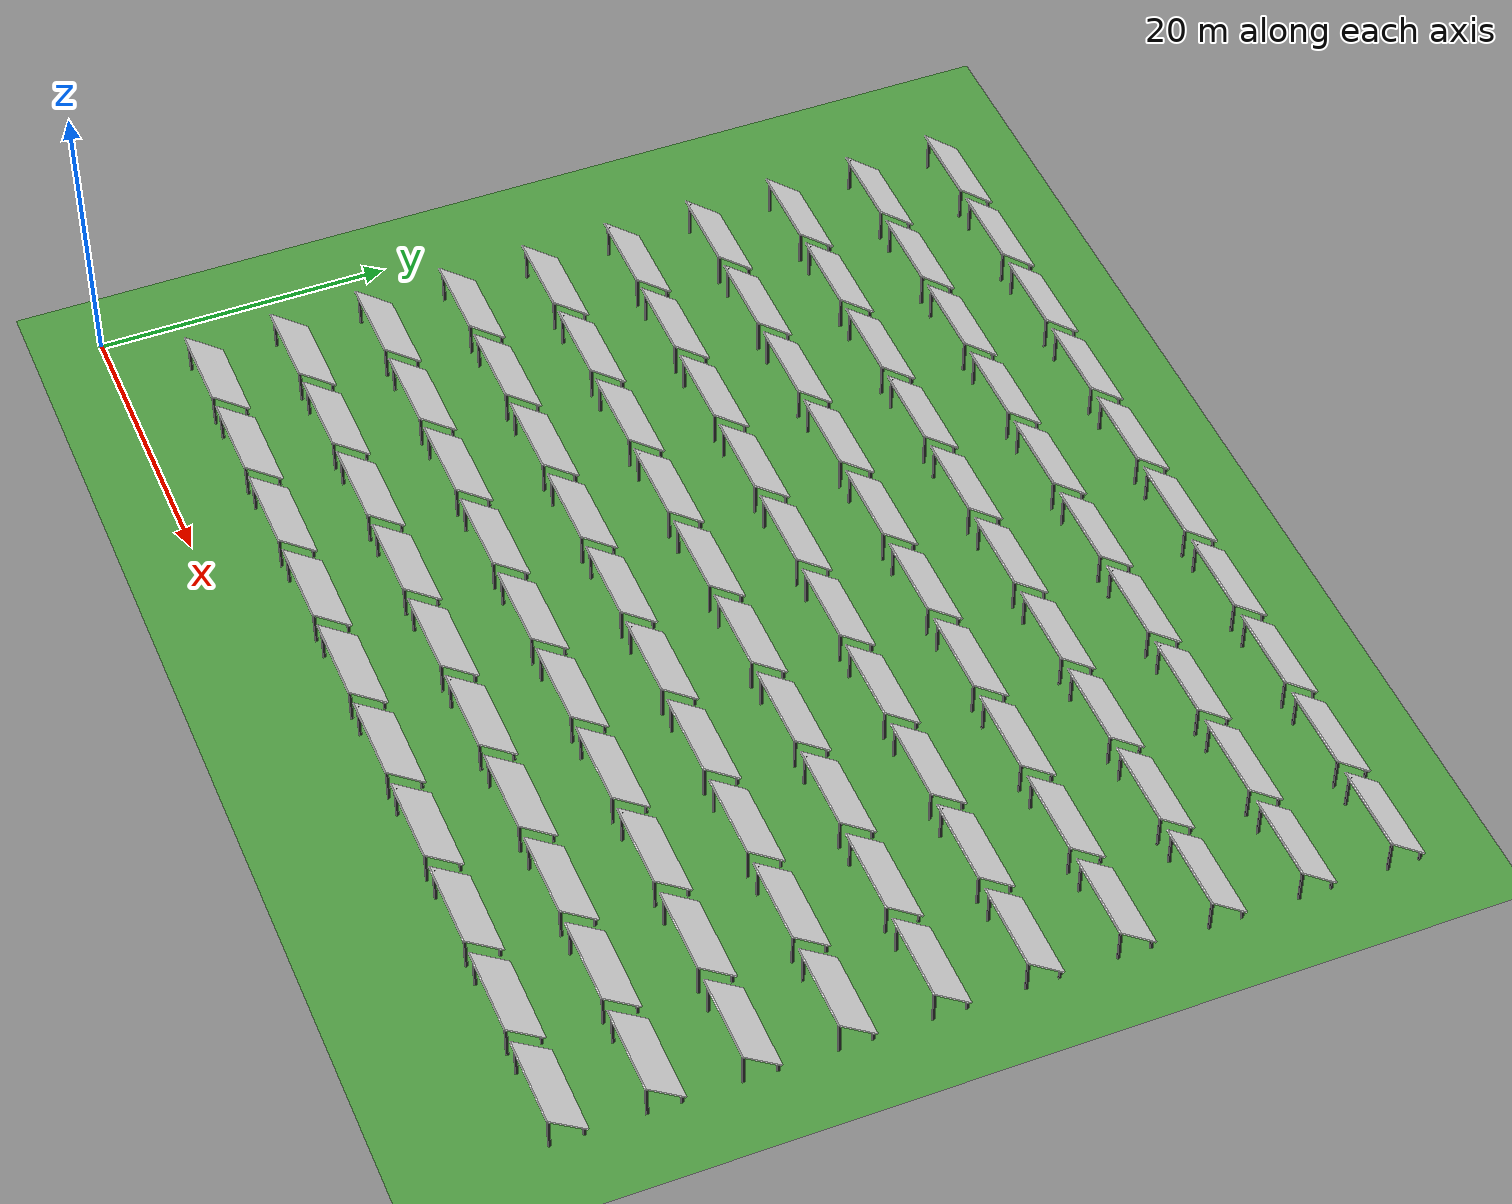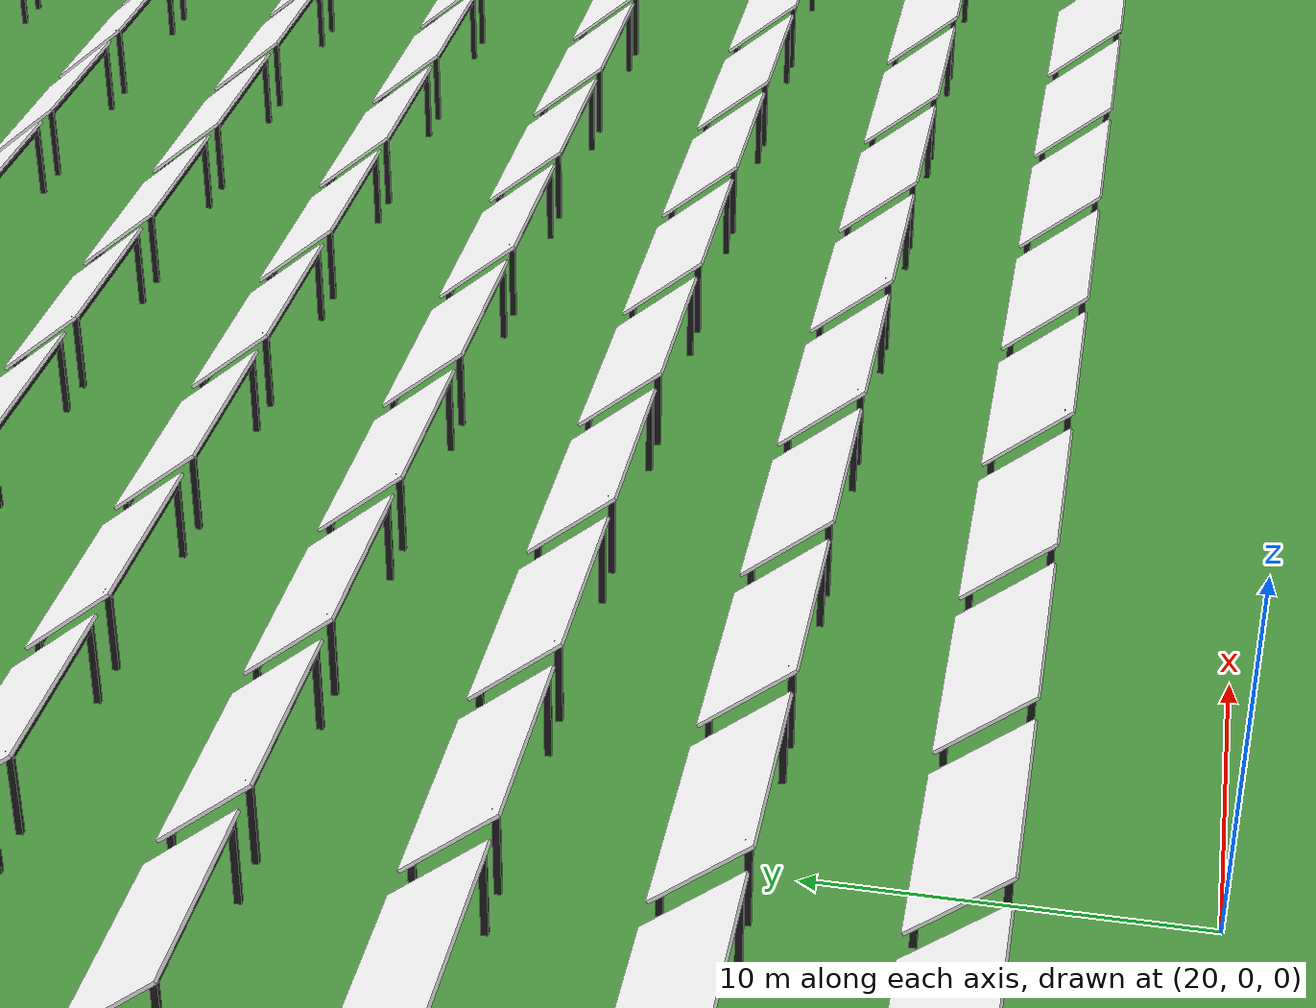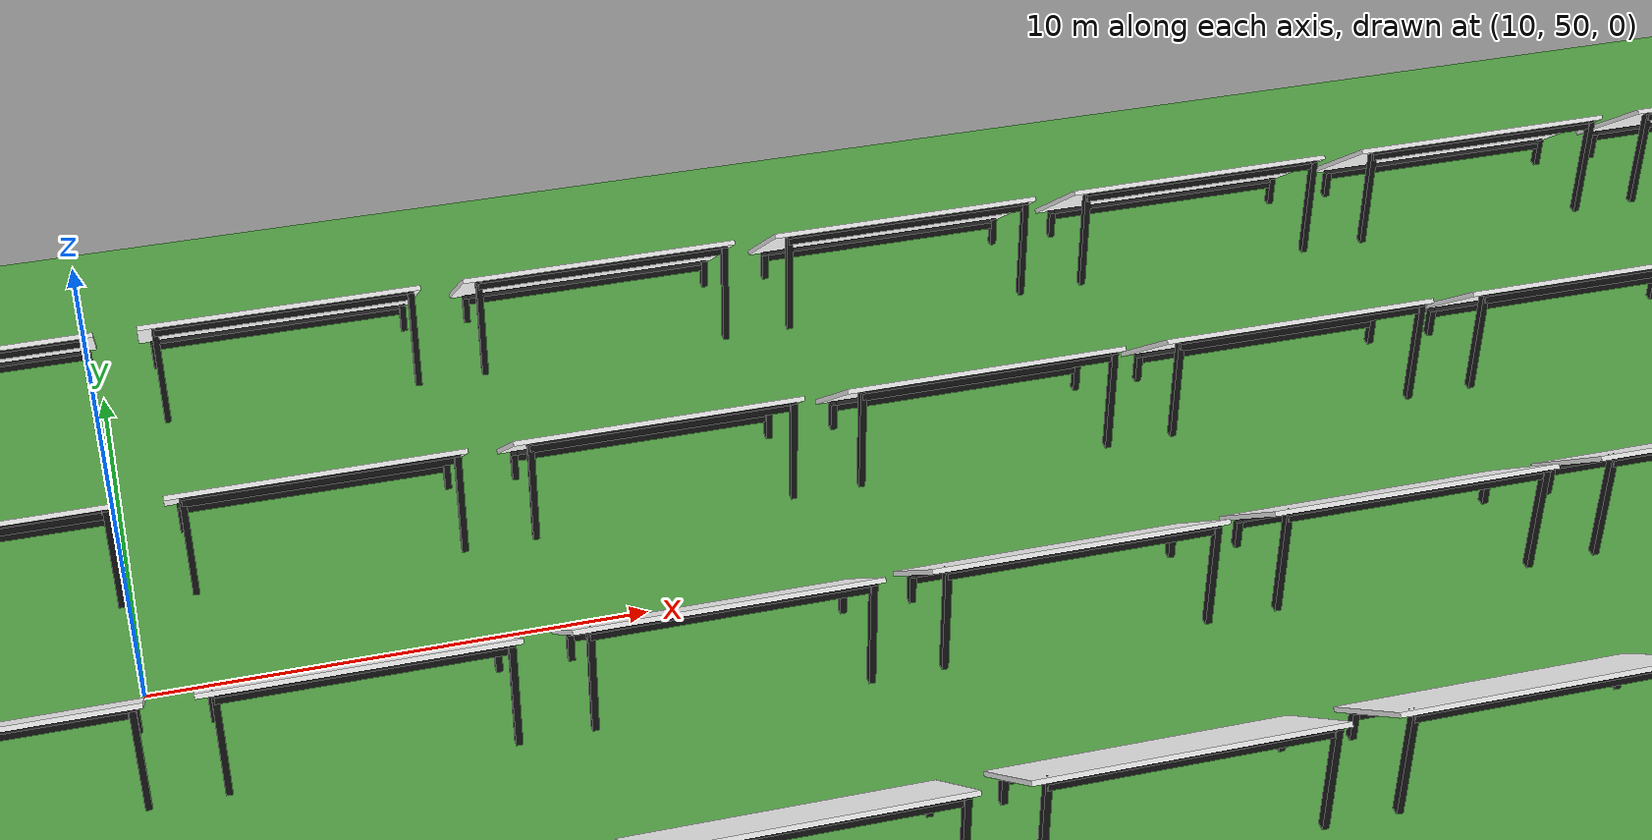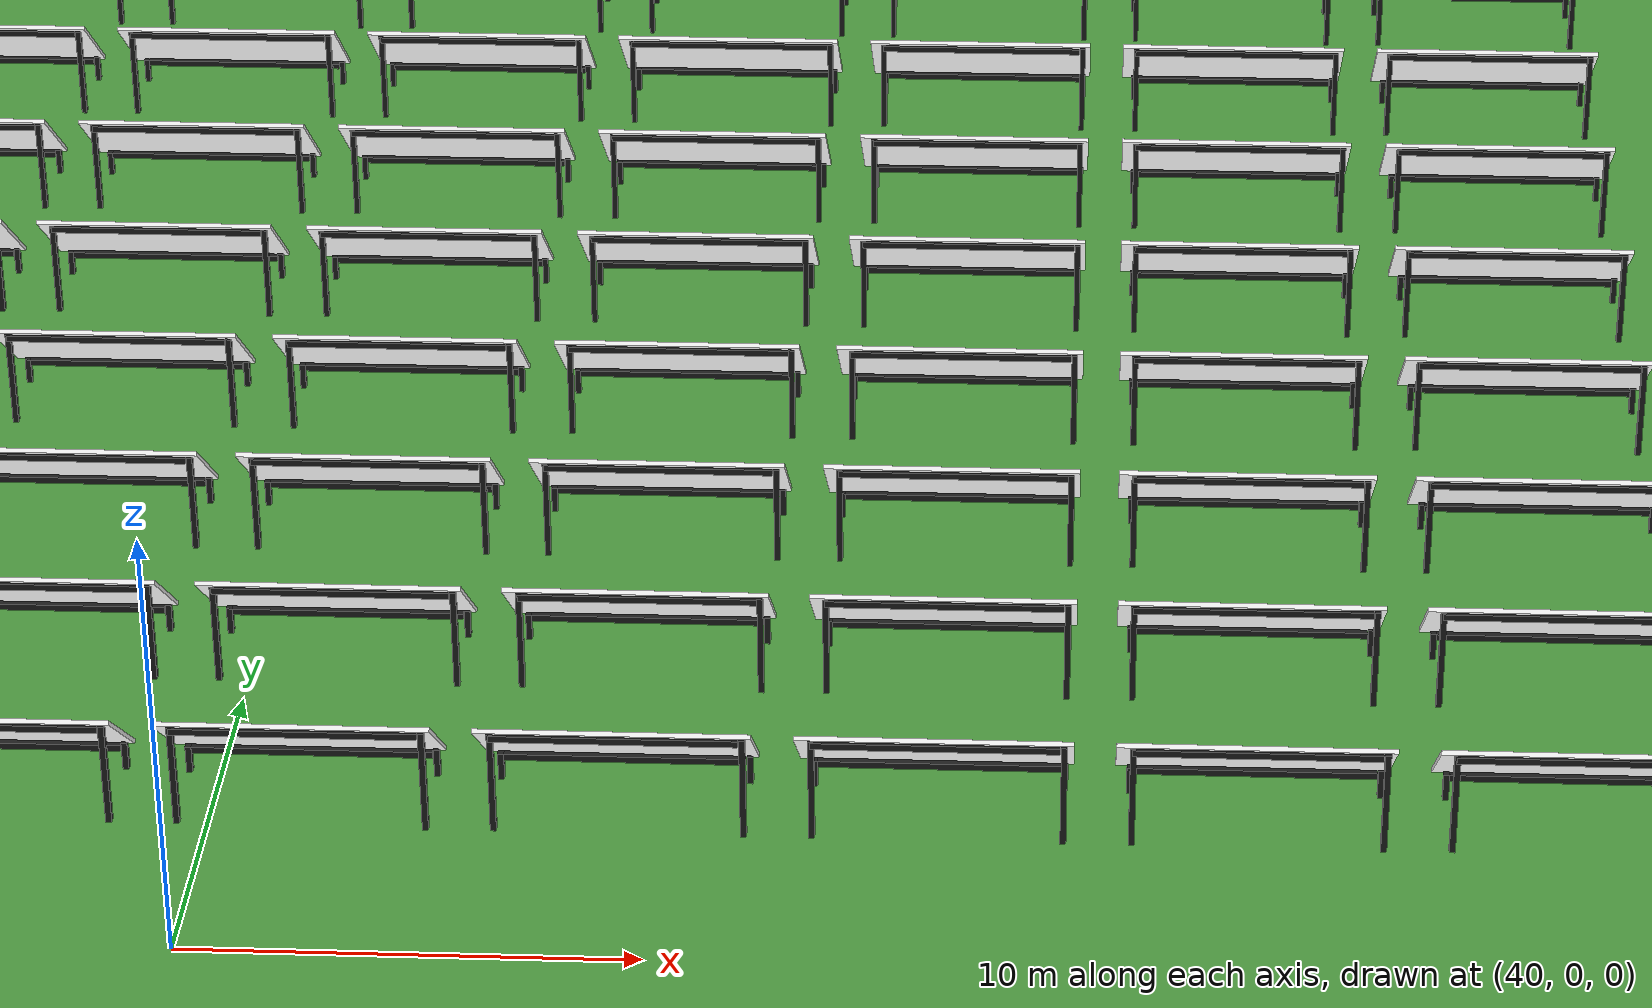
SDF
<sdf version="1.6">
 <world name="default">
  <light name="sun" type="directional">
   <pose>0 0 10 0 -0 0</pose>
   <diffuse>0.8 0.8 0.8 1</diffuse>
   <specular>0.2 0.2 0.2 1</specular>
   <attenuation>
    <range>1000</range>
    <constant>0.9</constant>
    <linear>0.01</linear>
    <quadratic>0.001</quadratic>
   </attenuation>
   <direction>-0.5 0.1 -0.9</direction>
  </light>
  <gravity>0 0 -9.8</gravity>
  <magnetic_field>6e-06 2.3e-05 -4.2e-05</magnetic_field>
  <atmosphere type="adiabatic"/>
  <physics name="default_physics" default="0" type="ode">
   <max_step_size>0.001</max_step_size>
   <real_time_factor>1</real_time_factor>
   <real_time_update_rate>1000</real_time_update_rate>
  </physics>
  <scene><ambient>0.4 0.4 0.4 1</ambient><background>0.7 0.7 0.7 1</background><shadows>0</shadows></scene>
  <spherical_coordinates>
   <surface_model>EARTH_WGS84</surface_model>
   <latitude_deg>0</latitude_deg>
   <longitude_deg>0</longitude_deg>
   <elevation>0</elevation>
   <heading_deg>0</heading_deg>
  </spherical_coordinates>
  <model name="panel_0_0">
   <static>1</static>
   <link name="link_1">
    <inertial>
     <mass>1.98638</mass>
     <inertia><ixx>1.74251</ixx><ixy>0</ixy><ixz>0</ixz><iyy>6.11467</iyy><iyz>0</iyz><izz>7.85383</izz></inertia>
    </inertial>
    <pose>-0.040001 0.043327 0.560753 -0.688467 0 0</pose>
    <visual name="visual">
     <geometry><box><size>6.07696 3.24293 0.100789</size></box></geometry>
     <material>
      <lighting>1</lighting>
      <script>
       <uri>model://new_solar/materials/scripts</uri>
       <uri>model://new_solar/materials/textures</uri>
       <name>solar</name>
      </script>
      <shader type="pixel"><normal_map>__default__</normal_map></shader>
      <ambient>1 1 1 1</ambient>
      <diffuse>1 1 1 1</diffuse>
      <specular>0 0 0 1</specular>
      <emissive>0 0 0 1</emissive>
     </material>
    </visual>
    <collision name="collision">
     <geometry><box><size>6.07696 3.24293 0.100789</size></box></geometry>
     <surface>
      <friction>
       <ode><mu>1</mu><mu2>1</mu2><fdir1>0 0 0</fdir1><slip1>0</slip1><slip2>0</slip2></ode>
       <torsional>
        <coefficient>1</coefficient>
        <patch_radius>0</patch_radius>
        <surface_radius>0</surface_radius>
        <use_patch_radius>1</use_patch_radius>
        <ode><slip>0</slip></ode>
       </torsional>
      </friction>
      <bounce><restitution_coefficient>0</restitution_coefficient><threshold>1e+06</threshold></bounce>
      <contact>
       <collide_without_contact>0</collide_without_contact>
       <collide_without_contact_bitmask>1</collide_without_contact_bitmask>
       <collide_bitmask>1</collide_bitmask>
       <ode>
        <soft_cfm>0</soft_cfm>
        <soft_erp>0.2</soft_erp>
        <kp>1e+13</kp>
        <kd>1</kd>
        <max_vel>0.01</max_vel>
        <min_depth>0</min_depth>
       </ode>
       <bullet>
        <split_impulse>1</split_impulse>
        <split_impulse_penetration_threshold>-0.01</split_impulse_penetration_threshold>
        <soft_cfm>0</soft_cfm>
        <soft_erp>0.2</soft_erp>
        <kp>1e+13</kp>
        <kd>1</kd>
       </bullet>
      </contact>
     </surface>
    </collision>
   </link>
   <link name="link_2">
    <inertial>
     <mass>0.0207671</mass>
     <inertia>
      <ixx>0.0012143</ixx>
      <ixy>0</ixy>
      <ixz>0</ixz>
      <iyy>0.00118465</iyy>
      <iyz>0</iyz>
      <izz>9.301e-05</izz>
     </inertia>
    </inertial>
    <pose>2.8032 1.09463 -0.744944 0 -0 0</pose>
    <visual name="visual">
     <geometry><box><size>0.135288 0.188253 0.81623</size></box></geometry>
     <material>
      <lighting>1</lighting>
      <script><uri>file://media/materials/scripts/gazebo.material</uri><name>Gazebo/Black</name></script>
      <shader type="pixel"><normal_map>__default__</normal_map></shader>
      <ambient>0 0 0 1</ambient>
      <diffuse>0 0 0 1</diffuse>
      <specular>0.1 0.1 0.1 1</specular>
      <emissive>0 0 0 1</emissive>
     </material>
    </visual>
    <collision name="collision">
     <geometry><box><size>0.135288 0.188253 0.81623</size></box></geometry>
     <surface>
      <friction>
       <ode><mu>1</mu><mu2>1</mu2><fdir1>0 0 0</fdir1><slip1>0</slip1><slip2>0</slip2></ode>
       <torsional>
        <coefficient>1</coefficient>
        <patch_radius>0</patch_radius>
        <surface_radius>0</surface_radius>
        <use_patch_radius>1</use_patch_radius>
        <ode><slip>0</slip></ode>
       </torsional>
      </friction>
      <bounce><restitution_coefficient>0</restitution_coefficient><threshold>1e+06</threshold></bounce>
      <contact>
       <collide_without_contact>0</collide_without_contact>
       <collide_without_contact_bitmask>1</collide_without_contact_bitmask>
       <collide_bitmask>1</collide_bitmask>
       <ode>
        <soft_cfm>0</soft_cfm>
        <soft_erp>0.2</soft_erp>
        <kp>1e+13</kp>
        <kd>1</kd>
        <max_vel>0.01</max_vel>
        <min_depth>0</min_depth>
       </ode>
       <bullet>
        <split_impulse>1</split_impulse>
        <split_impulse_penetration_threshold>-0.01</split_impulse_penetration_threshold>
        <soft_cfm>0</soft_cfm>
        <soft_erp>0.2</soft_erp>
        <kp>1e+13</kp>
        <kd>1</kd>
       </bullet>
      </contact>
     </surface>
    </collision>
   </link>
   <link name="link_2_clone">
    <inertial>
     <mass>0.0207671</mass>
     <inertia>
      <ixx>0.0012143</ixx>
      <ixy>0</ixy>
      <ixz>0</ixz>
      <iyy>0.00118465</iyy>
      <iyz>0</iyz>
      <izz>9.301e-05</izz>
     </inertia>
    </inertial>
    <pose>-2.7581 1.05673 -0.787934 0 -0 0</pose>
    <visual name="visual">
     <geometry><box><size>0.135288 0.188253 0.81623</size></box></geometry>
     <material>
      <lighting>1</lighting>
      <script><uri>file://media/materials/scripts/gazebo.material</uri><name>Gazebo/Black</name></script>
      <shader type="pixel"><normal_map>__default__</normal_map></shader>
      <ambient>0 0 0 1</ambient>
      <diffuse>0 0 0 1</diffuse>
      <specular>0.1 0.1 0.1 1</specular>
      <emissive>0 0 0 1</emissive>
     </material>
    </visual>
    <collision name="collision">
     <geometry><box><size>0.135288 0.188253 0.81623</size></box></geometry>
     <surface>
      <friction>
       <ode><mu>1</mu><mu2>1</mu2><fdir1>0 0 0</fdir1><slip1>0</slip1><slip2>0</slip2></ode>
       <torsional>
        <coefficient>1</coefficient>
        <patch_radius>0</patch_radius>
        <surface_radius>0</surface_radius>
        <use_patch_radius>1</use_patch_radius>
        <ode><slip>0</slip></ode>
       </torsional>
      </friction>
      <bounce><restitution_coefficient>0</restitution_coefficient><threshold>1e+06</threshold></bounce>
      <contact>
       <collide_without_contact>0</collide_without_contact>
       <collide_without_contact_bitmask>1</collide_without_contact_bitmask>
       <collide_bitmask>1</collide_bitmask>
       <ode>
        <soft_cfm>0</soft_cfm>
        <soft_erp>0.2</soft_erp>
        <kp>1e+13</kp>
        <kd>1</kd>
        <max_vel>0.01</max_vel>
        <min_depth>0</min_depth>
       </ode>
       <bullet>
        <split_impulse>1</split_impulse>
        <split_impulse_penetration_threshold>-0.01</split_impulse_penetration_threshold>
        <soft_cfm>0</soft_cfm>
        <soft_erp>0.2</soft_erp>
        <kp>1e+13</kp>
        <kd>1</kd>
       </bullet>
      </contact>
     </surface>
    </collision>
   </link>
   <link name="link_2_clone_clone_clone">
    <inertial>
     <mass>0.0712376</mass>
     <inertia>
      <ixx>0.0467501</ixx>
      <ixy>0</ixy>
      <ixz>0</ixz>
      <iyy>0.0466484</iyy>
      <iyz>0</iyz>
      <izz>0.00031904</izz>
     </inertia>
    </inertial>
    <pose>2.7925 -1.06517 0.041693 0 -0 0</pose>
    <visual name="visual">
     <geometry><box><size>0.135288 0.188253 2.79994</size></box></geometry>
     <material>
      <lighting>1</lighting>
      <script><uri>file://media/materials/scripts/gazebo.material</uri><name>Gazebo/Black</name></script>
      <shader type="pixel"><normal_map>__default__</normal_map></shader>
      <ambient>0 0 0 1</ambient>
      <diffuse>0 0 0 1</diffuse>
      <specular>0.1 0.1 0.1 1</specular>
      <emissive>0 0 0 1</emissive>
     </material>
    </visual>
    <collision name="collision">
     <geometry><box><size>0.135288 0.188253 2.79994</size></box></geometry>
     <surface>
      <friction>
       <ode><mu>1</mu><mu2>1</mu2><fdir1>0 0 0</fdir1><slip1>0</slip1><slip2>0</slip2></ode>
       <torsional>
        <coefficient>1</coefficient>
        <patch_radius>0</patch_radius>
        <surface_radius>0</surface_radius>
        <use_patch_radius>1</use_patch_radius>
        <ode><slip>0</slip></ode>
       </torsional>
      </friction>
      <bounce><restitution_coefficient>0</restitution_coefficient><threshold>1e+06</threshold></bounce>
      <contact>
       <collide_without_contact>0</collide_without_contact>
       <collide_without_contact_bitmask>1</collide_without_contact_bitmask>
       <collide_bitmask>1</collide_bitmask>
       <ode>
        <soft_cfm>0</soft_cfm>
        <soft_erp>0.2</soft_erp>
        <kp>1e+13</kp>
        <kd>1</kd>
        <max_vel>0.01</max_vel>
        <min_depth>0</min_depth>
       </ode>
       <bullet>
        <split_impulse>1</split_impulse>
        <split_impulse_penetration_threshold>-0.01</split_impulse_penetration_threshold>
        <soft_cfm>0</soft_cfm>
        <soft_erp>0.2</soft_erp>
        <kp>1e+13</kp>
        <kd>1</kd>
       </bullet>
      </contact>
     </surface>
    </collision>
   </link>
   <link name="link_2_clone_clone_clone_clone">
    <inertial>
     <mass>0.0712376</mass>
     <inertia>
      <ixx>0.0467501</ixx>
      <ixy>0</ixy>
      <ixz>0</ixz>
      <iyy>0.0466484</iyy>
      <iyz>0</iyz>
      <izz>0.00031904</izz>
     </inertia>
    </inertial>
    <pose>-2.71279 -1.03577 0.041693 0 -0 0</pose>
    <visual name="visual">
     <geometry><box><size>0.135288 0.188253 2.79994</size></box></geometry>
     <material>
      <lighting>1</lighting>
      <script><uri>file://media/materials/scripts/gazebo.material</uri><name>Gazebo/Black</name></script>
      <shader type="pixel"><normal_map>__default__</normal_map></shader>
      <ambient>0 0 0 1</ambient>
      <diffuse>0 0 0 1</diffuse>
      <specular>0.1 0.1 0.1 1</specular>
      <emissive>0 0 0 1</emissive>
     </material>
    </visual>
    <collision name="collision">
     <geometry><box><size>0.135288 0.188253 2.79994</size></box></geometry>
     <surface>
      <friction>
       <ode><mu>1</mu><mu2>1</mu2><fdir1>0 0 0</fdir1><slip1>0</slip1><slip2>0</slip2></ode>
       <torsional>
        <coefficient>1</coefficient>
        <patch_radius>0</patch_radius>
        <surface_radius>0</surface_radius>
        <use_patch_radius>1</use_patch_radius>
        <ode><slip>0</slip></ode>
       </torsional>
      </friction>
      <bounce><restitution_coefficient>0</restitution_coefficient><threshold>1e+06</threshold></bounce>
      <contact>
       <collide_without_contact>0</collide_without_contact>
       <collide_without_contact_bitmask>1</collide_without_contact_bitmask>
       <collide_bitmask>1</collide_bitmask>
       <ode>
        <soft_cfm>0</soft_cfm>
        <soft_erp>0.2</soft_erp>
        <kp>1e+13</kp>
        <kd>1</kd>
        <max_vel>0.01</max_vel>
        <min_depth>0</min_depth>
       </ode>
       <bullet>
        <split_impulse>1</split_impulse>
        <split_impulse_penetration_threshold>-0.01</split_impulse_penetration_threshold>
        <soft_cfm>0</soft_cfm>
        <soft_erp>0.2</soft_erp>
        <kp>1e+13</kp>
        <kd>1</kd>
       </bullet>
      </contact>
     </surface>
    </collision>
   </link>
   <link name="link_3">
    <inertial>
     <mass>0.133626</mass>
     <inertia>
      <ixx>0.00054826</ixx>
      <ixy>0</ixy>
      <ixz>0</ixz>
      <iyy>0.330433</iyy>
      <iyz>0</iyz>
      <izz>0.330457</izz>
     </inertia>
    </inertial>
    <pose>0 1.04453 -0.461177 0 -0 0</pose>
    <visual name="visual">
     <geometry><box><size>5.44521 0.160272 0.153456</size></box></geometry>
     <material>
      <lighting>1</lighting>
      <script><uri>file://media/materials/scripts/gazebo.material</uri><name>Gazebo/Black</name></script>
      <shader type="pixel"><normal_map>__default__</normal_map></shader>
      <ambient>0 0 0 1</ambient>
      <diffuse>0 0 0 1</diffuse>
      <specular>0.1 0.1 0.1 1</specular>
      <emissive>0 0 0 1</emissive>
     </material>
    </visual>
    <collision name="collision">
     <geometry><box><size>5.44521 0.160272 0.153456</size></box></geometry>
     <surface>
      <friction>
       <ode><mu>1</mu><mu2>1</mu2><fdir1>0 0 0</fdir1><slip1>0</slip1><slip2>0</slip2></ode>
       <torsional>
        <coefficient>1</coefficient>
        <patch_radius>0</patch_radius>
        <surface_radius>0</surface_radius>
        <use_patch_radius>1</use_patch_radius>
        <ode><slip>0</slip></ode>
       </torsional>
      </friction>
      <bounce><restitution_coefficient>0</restitution_coefficient><threshold>1e+06</threshold></bounce>
      <contact>
       <collide_without_contact>0</collide_without_contact>
       <collide_without_contact_bitmask>1</collide_without_contact_bitmask>
       <collide_bitmask>1</collide_bitmask>
       <ode>
        <soft_cfm>0</soft_cfm>
        <soft_erp>0.2</soft_erp>
        <kp>1e+13</kp>
        <kd>1</kd>
        <max_vel>0.01</max_vel>
        <min_depth>0</min_depth>
       </ode>
       <bullet>
        <split_impulse>1</split_impulse>
        <split_impulse_penetration_threshold>-0.01</split_impulse_penetration_threshold>
        <soft_cfm>0</soft_cfm>
        <soft_erp>0.2</soft_erp>
        <kp>1e+13</kp>
        <kd>1</kd>
       </bullet>
      </contact>
     </surface>
    </collision>
   </link>
   <link name="link_3_clone">
    <inertial>
     <mass>0.133626</mass>
     <inertia>
      <ixx>0.00054826</ixx>
      <ixy>0</ixy>
      <ixz>0</ixz>
      <iyy>0.330433</iyy>
      <iyz>0</iyz>
      <izz>0.330457</izz>
     </inertia>
    </inertial>
    <pose>-0.0149 -1.07367 1.34991 0 -0 0</pose>
    <visual name="visual">
     <geometry><box><size>5.44521 0.160272 0.153456</size></box></geometry>
     <material>
      <lighting>1</lighting>
      <script><uri>file://media/materials/scripts/gazebo.material</uri><name>Gazebo/Black</name></script>
      <shader type="pixel"><normal_map>__default__</normal_map></shader>
      <ambient>0 0 0 1</ambient>
      <diffuse>0 0 0 1</diffuse>
      <specular>0.1 0.1 0.1 1</specular>
      <emissive>0 0 0 1</emissive>
     </material>
    </visual>
    <collision name="collision">
     <geometry><box><size>5.44521 0.160272 0.153456</size></box></geometry>
     <surface>
      <friction>
       <ode><mu>1</mu><mu2>1</mu2><fdir1>0 0 0</fdir1><slip1>0</slip1><slip2>0</slip2></ode>
       <torsional>
        <coefficient>1</coefficient>
        <patch_radius>0</patch_radius>
        <surface_radius>0</surface_radius>
        <use_patch_radius>1</use_patch_radius>
        <ode><slip>0</slip></ode>
       </torsional>
      </friction>
      <bounce><restitution_coefficient>0</restitution_coefficient><threshold>1e+06</threshold></bounce>
      <contact>
       <collide_without_contact>0</collide_without_contact>
       <collide_without_contact_bitmask>1</collide_without_contact_bitmask>
       <collide_bitmask>1</collide_bitmask>
       <ode>
        <soft_cfm>0</soft_cfm>
        <soft_erp>0.2</soft_erp>
        <kp>1e+13</kp>
        <kd>1</kd>
        <max_vel>0.01</max_vel>
        <min_depth>0</min_depth>
       </ode>
       <bullet>
        <split_impulse>1</split_impulse>
        <split_impulse_penetration_threshold>-0.01</split_impulse_penetration_threshold>
        <soft_cfm>0</soft_cfm>
        <soft_erp>0.2</soft_erp>
        <kp>1e+13</kp>
        <kd>1</kd>
       </bullet>
      </contact>
     </surface>
    </collision>
   </link>
   <pose>7 6 1 0 -0 0</pose>
  </model>
  <model name="panel_0_1">
   <static>1</static>
   <link name="link_1">
    <inertial>
     <mass>1.98638</mass>
     <inertia><ixx>1.74251</ixx><ixy>0</ixy><ixz>0</ixz><iyy>6.11467</iyy><iyz>0</iyz><izz>7.85383</izz></inertia>
    </inertial>
    <pose>-0.040001 0.043327 0.560753 -0.688467 0 0</pose>
    <visual name="visual">
     <geometry><box><size>6.07696 3.24293 0.100789</size></box></geometry>
     <material>
      <lighting>1</lighting>
      <script>
       <uri>model://new_solar/materials/scripts</uri>
       <uri>model://new_solar/materials/textures</uri>
       <name>solar</name>
      </script>
      <shader type="pixel"><normal_map>__default__</normal_map></shader>
      <ambient>1 1 1 1</ambient>
      <diffuse>1 1 1 1</diffuse>
      <specular>0 0 0 1</specular>
      <emissive>0 0 0 1</emissive>
     </material>
    </visual>
    <collision name="collision">
     <geometry><box><size>6.07696 3.24293 0.100789</size></box></geometry>
     <surface>
      <friction>
       <ode><mu>1</mu><mu2>1</mu2><fdir1>0 0 0</fdir1><slip1>0</slip1><slip2>0</slip2></ode>
       <torsional>
        <coefficient>1</coefficient>
        <patch_radius>0</patch_radius>
        <surface_radius>0</surface_radius>
        <use_patch_radius>1</use_patch_radius>
        <ode><slip>0</slip></ode>
       </torsional>
      </friction>
      <bounce><restitution_coefficient>0</restitution_coefficient><threshold>1e+06</threshold></bounce>
      <contact>
       <collide_without_contact>0</collide_without_contact>
       <collide_without_contact_bitmask>1</collide_without_contact_bitmask>
       <collide_bitmask>1</collide_bitmask>
       <ode>
        <soft_cfm>0</soft_cfm>
        <soft_erp>0.2</soft_erp>
        <kp>1e+13</kp>
        <kd>1</kd>
        <max_vel>0.01</max_vel>
        <min_depth>0</min_depth>
       </ode>
       <bullet>
        <split_impulse>1</split_impulse>
        <split_impulse_penetration_threshold>-0.01</split_impulse_penetration_threshold>
        <soft_cfm>0</soft_cfm>
        <soft_erp>0.2</soft_erp>
        <kp>1e+13</kp>
        <kd>1</kd>
       </bullet>
      </contact>
     </surface>
    </collision>
   </link>
   <link name="link_2">
    <inertial>
     <mass>0.0207671</mass>
     <inertia>
      <ixx>0.0012143</ixx>
      <ixy>0</ixy>
      <ixz>0</ixz>
      <iyy>0.00118465</iyy>
      <iyz>0</iyz>
      <izz>9.301e-05</izz>
     </inertia>
    </inertial>
    <pose>2.8032 1.09463 -0.744944 0 -0 0</pose>
    <visual name="visual">
     <geometry><box><size>0.135288 0.188253 0.81623</size></box></geometry>
     <material>
      <lighting>1</lighting>
      <script><uri>file://media/materials/scripts/gazebo.material</uri><name>Gazebo/Black</name></script>
      <shader type="pixel"><normal_map>__default__</normal_map></shader>
      <ambient>0 0 0 1</ambient>
      <diffuse>0 0 0 1</diffuse>
      <specular>0.1 0.1 0.1 1</specular>
      <emissive>0 0 0 1</emissive>
     </material>
    </visual>
    <collision name="collision">
     <geometry><box><size>0.135288 0.188253 0.81623</size></box></geometry>
     <surface>
      <friction>
       <ode><mu>1</mu><mu2>1</mu2><fdir1>0 0 0</fdir1><slip1>0</slip1><slip2>0</slip2></ode>
       <torsional>
        <coefficient>1</coefficient>
        <patch_radius>0</patch_radius>
        <surface_radius>0</surface_radius>
        <use_patch_radius>1</use_patch_radius>
        <ode><slip>0</slip></ode>
       </torsional>
      </friction>
      <bounce><restitution_coefficient>0</restitution_coefficient><threshold>1e+06</threshold></bounce>
      <contact>
       <collide_without_contact>0</collide_without_contact>
       <collide_without_contact_bitmask>1</collide_without_contact_bitmask>
       <collide_bitmask>1</collide_bitmask>
       <ode>
        <soft_cfm>0</soft_cfm>
        <soft_erp>0.2</soft_erp>
        <kp>1e+13</kp>
        <kd>1</kd>
        <max_vel>0.01</max_vel>
        <min_depth>0</min_depth>
       </ode>
       <bullet>
        <split_impulse>1</split_impulse>
        <split_impulse_penetration_threshold>-0.01</split_impulse_penetration_threshold>
        <soft_cfm>0</soft_cfm>
        <soft_erp>0.2</soft_erp>
        <kp>1e+13</kp>
        <kd>1</kd>
       </bullet>
      </contact>
     </surface>
    </collision>
   </link>
   <link name="link_2_clone">
    <inertial>
     <mass>0.0207671</mass>
     <inertia>
      <ixx>0.0012143</ixx>
      <ixy>0</ixy>
      <ixz>0</ixz>
      <iyy>0.00118465</iyy>
      <iyz>0</iyz>
      <izz>9.301e-05</izz>
     </inertia>
    </inertial>
    <pose>-2.7581 1.05673 -0.787934 0 -0 0</pose>
    <visual name="visual">
     <geometry><box><size>0.135288 0.188253 0.81623</size></box></geometry>
     <material>
      <lighting>1</lighting>
      <script><uri>file://media/materials/scripts/gazebo.material</uri><name>Gazebo/Black</name></script>
      <shader type="pixel"><normal_map>__default__</normal_map></shader>
      <ambient>0 0 0 1</ambient>
      <diffuse>0 0 0 1</diffuse>
      <specular>0.1 0.1 0.1 1</specular>
      <emissive>0 0 0 1</emissive>
     </material>
    </visual>
    <collision name="collision">
     <geometry><box><size>0.135288 0.188253 0.81623</size></box></geometry>
     <surface>
      <friction>
       <ode><mu>1</mu><mu2>1</mu2><fdir1>0 0 0</fdir1><slip1>0</slip1><slip2>0</slip2></ode>
       <torsional>
        <coefficient>1</coefficient>
        <patch_radius>0</patch_radius>
        <surface_radius>0</surface_radius>
        <use_patch_radius>1</use_patch_radius>
        <ode><slip>0</slip></ode>
       </torsional>
      </friction>
      <bounce><restitution_coefficient>0</restitution_coefficient><threshold>1e+06</threshold></bounce>
      <contact>
       <collide_without_contact>0</collide_without_contact>
       <collide_without_contact_bitmask>1</collide_without_contact_bitmask>
       <collide_bitmask>1</collide_bitmask>
       <ode>
        <soft_cfm>0</soft_cfm>
        <soft_erp>0.2</soft_erp>
        <kp>1e+13</kp>
        <kd>1</kd>
        <max_vel>0.01</max_vel>
        <min_depth>0</min_depth>
       </ode>
       <bullet>
        <split_impulse>1</split_impulse>
        <split_impulse_penetration_threshold>-0.01</split_impulse_penetration_threshold>
        <soft_cfm>0</soft_cfm>
        <soft_erp>0.2</soft_erp>
        <kp>1e+13</kp>
        <kd>1</kd>
       </bullet>
      </contact>
     </surface>
    </collision>
   </link>
   <link name="link_2_clone_clone_clone">
    <inertial>
     <mass>0.0712376</mass>
     <inertia>
      <ixx>0.0467501</ixx>
      <ixy>0</ixy>
      <ixz>0</ixz>
      <iyy>0.0466484</iyy>
      <iyz>0</iyz>
      <izz>0.00031904</izz>
     </inertia>
    </inertial>
    <pose>2.7925 -1.06517 0.041693 0 -0 0</pose>
    <visual name="visual">
     <geometry><box><size>0.135288 0.188253 2.79994</size></box></geometry>
     <material>
      <lighting>1</lighting>
      <script><uri>file://media/materials/scripts/gazebo.material</uri><name>Gazebo/Black</name></script>
      <shader type="pixel"><normal_map>__default__</normal_map></shader>
      <ambient>0 0 0 1</ambient>
      <diffuse>0 0 0 1</diffuse>
      <specular>0.1 0.1 0.1 1</specular>
      <emissive>0 0 0 1</emissive>
     </material>
    </visual>
    <collision name="collision">
     <geometry><box><size>0.135288 0.188253 2.79994</size></box></geometry>
     <surface>
      <friction>
       <ode><mu>1</mu><mu2>1</mu2><fdir1>0 0 0</fdir1><slip1>0</slip1><slip2>0</slip2></ode>
       <torsional>
        <coefficient>1</coefficient>
        <patch_radius>0</patch_radius>
        <surface_radius>0</surface_radius>
        <use_patch_radius>1</use_patch_radius>
        <ode><slip>0</slip></ode>
       </torsional>
      </friction>
      <bounce><restitution_coefficient>0</restitution_coefficient><threshold>1e+06</threshold></bounce>
      <contact>
       <collide_without_contact>0</collide_without_contact>
       <collide_without_contact_bitmask>1</collide_without_contact_bitmask>
       <collide_bitmask>1</collide_bitmask>
       <ode>
        <soft_cfm>0</soft_cfm>
        <soft_erp>0.2</soft_erp>
        <kp>1e+13</kp>
        <kd>1</kd>
        <max_vel>0.01</max_vel>
        <min_depth>0</min_depth>
       </ode>
       <bullet>
        <split_impulse>1</split_impulse>
        <split_impulse_penetration_threshold>-0.01</split_impulse_penetration_threshold>
        <soft_cfm>0</soft_cfm>
        <soft_erp>0.2</soft_erp>
        <kp>1e+13</kp>
        <kd>1</kd>
       </bullet>
      </contact>
     </surface>
    </collision>
   </link>
   <link name="link_2_clone_clone_clone_clone">
    <inertial>
     <mass>0.0712376</mass>
     <inertia>
      <ixx>0.0467501</ixx>
      <ixy>0</ixy>
      <ixz>0</ixz>
      <iyy>0.0466484</iyy>
      <iyz>0</iyz>
      <izz>0.00031904</izz>
     </inertia>
    </inertial>
    <pose>-2.71279 -1.03577 0.041693 0 -0 0</pose>
    <visual name="visual">
     <geometry><box><size>0.135288 0.188253 2.79994</size></box></geometry>
     <material>
      <lighting>1</lighting>
      <script><uri>file://media/materials/scripts/gazebo.material</uri><name>Gazebo/Black</name></script>
      <shader type="pixel"><normal_map>__default__</normal_map></shader>
      <ambient>0 0 0 1</ambient>
      <diffuse>0 0 0 1</diffuse>
      <specular>0.1 0.1 0.1 1</specular>
      <emissive>0 0 0 1</emissive>
     </material>
    </visual>
    <collision name="collision">
     <geometry><box><size>0.135288 0.188253 2.79994</size></box></geometry>
     <surface>
      <friction>
       <ode><mu>1</mu><mu2>1</mu2><fdir1>0 0 0</fdir1><slip1>0</slip1><slip2>0</slip2></ode>
       <torsional>
        <coefficient>1</coefficient>
        <patch_radius>0</patch_radius>
        <surface_radius>0</surface_radius>
        <use_patch_radius>1</use_patch_radius>
        <ode><slip>0</slip></ode>
       </torsional>
      </friction>
      <bounce><restitution_coefficient>0</restitution_coefficient><threshold>1e+06</threshold></bounce>
      <contact>
       <collide_without_contact>0</collide_without_contact>
       <collide_without_contact_bitmask>1</collide_without_contact_bitmask>
       <collide_bitmask>1</collide_bitmask>
       <ode>
        <soft_cfm>0</soft_cfm>
        <soft_erp>0.2</soft_erp>
        <kp>1e+13</kp>
        <kd>1</kd>
        <max_vel>0.01</max_vel>
        <min_depth>0</min_depth>
       </ode>
       <bullet>
        <split_impulse>1</split_impulse>
        <split_impulse_penetration_threshold>-0.01</split_impulse_penetration_threshold>
        <soft_cfm>0</soft_cfm>
        <soft_erp>0.2</soft_erp>
        <kp>1e+13</kp>
        <kd>1</kd>
       </bullet>
      </contact>
     </surface>
    </collision>
   </link>
   <link name="link_3">
    <inertial>
     <mass>0.133626</mass>
     <inertia>
      <ixx>0.00054826</ixx>
      <ixy>0</ixy>
      <ixz>0</ixz>
      <iyy>0.330433</iyy>
      <iyz>0</iyz>
      <izz>0.330457</izz>
     </inertia>
    </inertial>
    <pose>0 1.04453 -0.461177 0 -0 0</pose>
    <visual name="visual">
     <geometry><box><size>5.44521 0.160272 0.153456</size></box></geometry>
     <material>
      <lighting>1</lighting>
      <script><uri>file://media/materials/scripts/gazebo.material</uri><name>Gazebo/Black</name></script>
      <shader type="pixel"><normal_map>__default__</normal_map></shader>
      <ambient>0 0 0 1</ambient>
      <diffuse>0 0 0 1</diffuse>
      <specular>0.1 0.1 0.1 1</specular>
      <emissive>0 0 0 1</emissive>
     </material>
    </visual>
    <collision name="collision">
     <geometry><box><size>5.44521 0.160272 0.153456</size></box></geometry>
     <surface>
      <friction>
       <ode><mu>1</mu><mu2>1</mu2><fdir1>0 0 0</fdir1><slip1>0</slip1><slip2>0</slip2></ode>
       <torsional>
        <coefficient>1</coefficient>
        <patch_radius>0</patch_radius>
        <surface_radius>0</surface_radius>
        <use_patch_radius>1</use_patch_radius>
        <ode><slip>0</slip></ode>
       </torsional>
      </friction>
      <bounce><restitution_coefficient>0</restitution_coefficient><threshold>1e+06</threshold></bounce>
      <contact>
       <collide_without_contact>0</collide_without_contact>
       <collide_without_contact_bitmask>1</collide_without_contact_bitmask>
       <collide_bitmask>1</collide_bitmask>
       <ode>
        <soft_cfm>0</soft_cfm>
        <soft_erp>0.2</soft_erp>
        <kp>1e+13</kp>
        <kd>1</kd>
        <max_vel>0.01</max_vel>
        <min_depth>0</min_depth>
       </ode>
       <bullet>
        <split_impulse>1</split_impulse>
        <split_impulse_penetration_threshold>-0.01</split_impulse_penetration_threshold>
        <soft_cfm>0</soft_cfm>
        <soft_erp>0.2</soft_erp>
        <kp>1e+13</kp>
        <kd>1</kd>
       </bullet>
      </contact>
     </surface>
    </collision>
   </link>
   <link name="link_3_clone">
    <inertial>
     <mass>0.133626</mass>
     <inertia>
      <ixx>0.00054826</ixx>
      <ixy>0</ixy>
      <ixz>0</ixz>
      <iyy>0.330433</iyy>
      <iyz>0</iyz>
      <izz>0.330457</izz>
     </inertia>
    </inertial>
    <pose>-0.0149 -1.07367 1.34991 0 -0 0</pose>
    <visual name="visual">
     <geometry><box><size>5.44521 0.160272 0.153456</size></box></geometry>
     <material>
      <lighting>1</lighting>
      <script><uri>file://media/materials/scripts/gazebo.material</uri><name>Gazebo/Black</name></script>
      <shader type="pixel"><normal_map>__default__</normal_map></shader>
      <ambient>0 0 0 1</ambient>
      <diffuse>0 0 0 1</diffuse>
      <specular>0.1 0.1 0.1 1</specular>
      <emissive>0 0 0 1</emissive>
     </material>
    </visual>
    <collision name="collision">
     <geometry><box><size>5.44521 0.160272 0.153456</size></box></geometry>
     <surface>
      <friction>
       <ode><mu>1</mu><mu2>1</mu2><fdir1>0 0 0</fdir1><slip1>0</slip1><slip2>0</slip2></ode>
       <torsional>
        <coefficient>1</coefficient>
        <patch_radius>0</patch_radius>
        <surface_radius>0</surface_radius>
        <use_patch_radius>1</use_patch_radius>
        <ode><slip>0</slip></ode>
       </torsional>
      </friction>
      <bounce><restitution_coefficient>0</restitution_coefficient><threshold>1e+06</threshold></bounce>
      <contact>
       <collide_without_contact>0</collide_without_contact>
       <collide_without_contact_bitmask>1</collide_without_contact_bitmask>
       <collide_bitmask>1</collide_bitmask>
       <ode>
        <soft_cfm>0</soft_cfm>
        <soft_erp>0.2</soft_erp>
        <kp>1e+13</kp>
        <kd>1</kd>
        <max_vel>0.01</max_vel>
        <min_depth>0</min_depth>
       </ode>
       <bullet>
        <split_impulse>1</split_impulse>
        <split_impulse_penetration_threshold>-0.01</split_impulse_penetration_threshold>
        <soft_cfm>0</soft_cfm>
        <soft_erp>0.2</soft_erp>
        <kp>1e+13</kp>
        <kd>1</kd>
       </bullet>
      </contact>
     </surface>
    </collision>
   </link>
   <pose>7 12 1 0 -0 0</pose>
  </model>
  <model name="panel_0_2">
   <static>1</static>
   <link name="link_1">
    <inertial>
     <mass>1.98638</mass>
     <inertia><ixx>1.74251</ixx><ixy>0</ixy><ixz>0</ixz><iyy>6.11467</iyy><iyz>0</iyz><izz>7.85383</izz></inertia>
    </inertial>
    <pose>-0.040001 0.043327 0.560753 -0.688467 0 0</pose>
    <visual name="visual">
     <geometry><box><size>6.07696 3.24293 0.100789</size></box></geometry>
     <material>
      <lighting>1</lighting>
      <script>
       <uri>model://new_solar/materials/scripts</uri>
       <uri>model://new_solar/materials/textures</uri>
       <name>solar</name>
      </script>
      <shader type="pixel"><normal_map>__default__</normal_map></shader>
      <ambient>1 1 1 1</ambient>
      <diffuse>1 1 1 1</diffuse>
      <specular>0 0 0 1</specular>
      <emissive>0 0 0 1</emissive>
     </material>
    </visual>
    <collision name="collision">
     <geometry><box><size>6.07696 3.24293 0.100789</size></box></geometry>
     <surface>
      <friction>
       <ode><mu>1</mu><mu2>1</mu2><fdir1>0 0 0</fdir1><slip1>0</slip1><slip2>0</slip2></ode>
       <torsional>
        <coefficient>1</coefficient>
        <patch_radius>0</patch_radius>
        <surface_radius>0</surface_radius>
        <use_patch_radius>1</use_patch_radius>
        <ode><slip>0</slip></ode>
       </torsional>
      </friction>
      <bounce><restitution_coefficient>0</restitution_coefficient><threshold>1e+06</threshold></bounce>
      <contact>
       <collide_without_contact>0</collide_without_contact>
       <collide_without_contact_bitmask>1</collide_without_contact_bitmask>
       <collide_bitmask>1</collide_bitmask>
       <ode>
        <soft_cfm>0</soft_cfm>
        <soft_erp>0.2</soft_erp>
        <kp>1e+13</kp>
        <kd>1</kd>
        <max_vel>0.01</max_vel>
        <min_depth>0</min_depth>
       </ode>
       <bullet>
        <split_impulse>1</split_impulse>
        <split_impulse_penetration_threshold>-0.01</split_impulse_penetration_threshold>
        <soft_cfm>0</soft_cfm>
        <soft_erp>0.2</soft_erp>
        <kp>1e+13</kp>
        <kd>1</kd>
       </bullet>
      </contact>
     </surface>
    </collision>
   </link>
   <link name="link_2">
    <inertial>
     <mass>0.0207671</mass>
     <inertia>
      <ixx>0.0012143</ixx>
      <ixy>0</ixy>
      <ixz>0</ixz>
      <iyy>0.00118465</iyy>
      <iyz>0</iyz>
      <izz>9.301e-05</izz>
     </inertia>
    </inertial>
    <pose>2.8032 1.09463 -0.744944 0 -0 0</pose>
    <visual name="visual">
     <geometry><box><size>0.135288 0.188253 0.81623</size></box></geometry>
     <material>
      <lighting>1</lighting>
      <script><uri>file://media/materials/scripts/gazebo.material</uri><name>Gazebo/Black</name></script>
      <shader type="pixel"><normal_map>__default__</normal_map></shader>
      <ambient>0 0 0 1</ambient>
      <diffuse>0 0 0 1</diffuse>
      <specular>0.1 0.1 0.1 1</specular>
      <emissive>0 0 0 1</emissive>
     </material>
    </visual>
    <collision name="collision">
     <geometry><box><size>0.135288 0.188253 0.81623</size></box></geometry>
     <surface>
      <friction>
       <ode><mu>1</mu><mu2>1</mu2><fdir1>0 0 0</fdir1><slip1>0</slip1><slip2>0</slip2></ode>
       <torsional>
        <coefficient>1</coefficient>
        <patch_radius>0</patch_radius>
        <surface_radius>0</surface_radius>
        <use_patch_radius>1</use_patch_radius>
        <ode><slip>0</slip></ode>
       </torsional>
      </friction>
      <bounce><restitution_coefficient>0</restitution_coefficient><threshold>1e+06</threshold></bounce>
      <contact>
       <collide_without_contact>0</collide_without_contact>
       <collide_without_contact_bitmask>1</collide_without_contact_bitmask>
       <collide_bitmask>1</collide_bitmask>
       <ode>
        <soft_cfm>0</soft_cfm>
        <soft_erp>0.2</soft_erp>
        <kp>1e+13</kp>
        <kd>1</kd>
        <max_vel>0.01</max_vel>
        <min_depth>0</min_depth>
       </ode>
       <bullet>
        <split_impulse>1</split_impulse>
        <split_impulse_penetration_threshold>-0.01</split_impulse_penetration_threshold>
        <soft_cfm>0</soft_cfm>
        <soft_erp>0.2</soft_erp>
        <kp>1e+13</kp>
        <kd>1</kd>
       </bullet>
      </contact>
     </surface>
    </collision>
   </link>
   <link name="link_2_clone">
    <inertial>
     <mass>0.0207671</mass>
     <inertia>
      <ixx>0.0012143</ixx>
      <ixy>0</ixy>
      <ixz>0</ixz>
      <iyy>0.00118465</iyy>
      <iyz>0</iyz>
      <izz>9.301e-05</izz>
     </inertia>
    </inertial>
    <pose>-2.7581 1.05673 -0.787934 0 -0 0</pose>
    <visual name="visual">
     <geometry><box><size>0.135288 0.188253 0.81623</size></box></geometry>
     <material>
      <lighting>1</lighting>
      <script><uri>file://media/materials/scripts/gazebo.material</uri><name>Gazebo/Black</name></script>
      <shader type="pixel"><normal_map>__default__</normal_map></shader>
      <ambient>0 0 0 1</ambient>
      <diffuse>0 0 0 1</diffuse>
      <specular>0.1 0.1 0.1 1</specular>
      <emissive>0 0 0 1</emissive>
     </material>
    </visual>
    <collision name="collision">
     <geometry><box><size>0.135288 0.188253 0.81623</size></box></geometry>
     <surface>
      <friction>
       <ode><mu>1</mu><mu2>1</mu2><fdir1>0 0 0</fdir1><slip1>0</slip1><slip2>0</slip2></ode>
       <torsional>
        <coefficient>1</coefficient>
        <patch_radius>0</patch_radius>
        <surface_radius>0</surface_radius>
        <use_patch_radius>1</use_patch_radius>
        <ode><slip>0</slip></ode>
       </torsional>
      </friction>
      <bounce><restitution_coefficient>0</restitution_coefficient><threshold>1e+06</threshold></bounce>
      <contact>
       <collide_without_contact>0</collide_without_contact>
       <collide_without_contact_bitmask>1</collide_without_contact_bitmask>
       <collide_bitmask>1</collide_bitmask>
       <ode>
        <soft_cfm>0</soft_cfm>
        <soft_erp>0.2</soft_erp>
        <kp>1e+13</kp>
        <kd>1</kd>
        <max_vel>0.01</max_vel>
        <min_depth>0</min_depth>
       </ode>
       <bullet>
        <split_impulse>1</split_impulse>
        <split_impulse_penetration_threshold>-0.01</split_impulse_penetration_threshold>
        <soft_cfm>0</soft_cfm>
        <soft_erp>0.2</soft_erp>
        <kp>1e+13</kp>
        <kd>1</kd>
       </bullet>
      </contact>
     </surface>
    </collision>
   </link>
   <link name="link_2_clone_clone_clone">
    <inertial>
     <mass>0.0712376</mass>
     <inertia>
      <ixx>0.0467501</ixx>
      <ixy>0</ixy>
      <ixz>0</ixz>
      <iyy>0.0466484</iyy>
      <iyz>0</iyz>
      <izz>0.00031904</izz>
     </inertia>
    </inertial>
    <pose>2.7925 -1.06517 0.041693 0 -0 0</pose>
    <visual name="visual">
     <geometry><box><size>0.135288 0.188253 2.79994</size></box></geometry>
     <material>
      <lighting>1</lighting>
      <script><uri>file://media/materials/scripts/gazebo.material</uri><name>Gazebo/Black</name></script>
      <shader type="pixel"><normal_map>__default__</normal_map></shader>
      <ambient>0 0 0 1</ambient>
      <diffuse>0 0 0 1</diffuse>
      <specular>0.1 0.1 0.1 1</specular>
      <emissive>0 0 0 1</emissive>
     </material>
    </visual>
    <collision name="collision">
     <geometry><box><size>0.135288 0.188253 2.79994</size></box></geometry>
     <surface>
      <friction>
       <ode><mu>1</mu><mu2>1</mu2><fdir1>0 0 0</fdir1><slip1>0</slip1><slip2>0</slip2></ode>
       <torsional>
        <coefficient>1</coefficient>
        <patch_radius>0</patch_radius>
        <surface_radius>0</surface_radius>
        <use_patch_radius>1</use_patch_radius>
        <ode><slip>0</slip></ode>
       </torsional>
      </friction>
      <bounce><restitution_coefficient>0</restitution_coefficient><threshold>1e+06</threshold></bounce>
      <contact>
       <collide_without_contact>0</collide_without_contact>
       <collide_without_contact_bitmask>1</collide_without_contact_bitmask>
       <collide_bitmask>1</collide_bitmask>
       <ode>
        <soft_cfm>0</soft_cfm>
        <soft_erp>0.2</soft_erp>
        <kp>1e+13</kp>
        <kd>1</kd>
        <max_vel>0.01</max_vel>
        <min_depth>0</min_depth>
       </ode>
       <bullet>
        <split_impulse>1</split_impulse>
        <split_impulse_penetration_threshold>-0.01</split_impulse_penetration_threshold>
        <soft_cfm>0</soft_cfm>
        <soft_erp>0.2</soft_erp>
        <kp>1e+13</kp>
        <kd>1</kd>
       </bullet>
      </contact>
     </surface>
    </collision>
   </link>
   <link name="link_2_clone_clone_clone_clone">
    <inertial>
     <mass>0.0712376</mass>
     <inertia>
      <ixx>0.0467501</ixx>
      <ixy>0</ixy>
      <ixz>0</ixz>
      <iyy>0.0466484</iyy>
      <iyz>0</iyz>
      <izz>0.00031904</izz>
     </inertia>
    </inertial>
    <pose>-2.71279 -1.03577 0.041693 0 -0 0</pose>
    <visual name="visual">
     <geometry><box><size>0.135288 0.188253 2.79994</size></box></geometry>
     <material>
      <lighting>1</lighting>
      <script><uri>file://media/materials/scripts/gazebo.material</uri><name>Gazebo/Black</name></script>
      <shader type="pixel"><normal_map>__default__</normal_map></shader>
      <ambient>0 0 0 1</ambient>
      <diffuse>0 0 0 1</diffuse>
      <specular>0.1 0.1 0.1 1</specular>
      <emissive>0 0 0 1</emissive>
     </material>
    </visual>
    <collision name="collision">
     <geometry><box><size>0.135288 0.188253 2.79994</size></box></geometry>
     <surface>
      <friction>
       <ode><mu>1</mu><mu2>1</mu2><fdir1>0 0 0</fdir1><slip1>0</slip1><slip2>0</slip2></ode>
       <torsional>
        <coefficient>1</coefficient>
        <patch_radius>0</patch_radius>
        <surface_radius>0</surface_radius>
        <use_patch_radius>1</use_patch_radius>
        <ode><slip>0</slip></ode>
       </torsional>
      </friction>
      <bounce><restitution_coefficient>0</restitution_coefficient><threshold>1e+06</threshold></bounce>
      <contact>
       <collide_without_contact>0</collide_without_contact>
       <collide_without_contact_bitmask>1</collide_without_contact_bitmask>
       <collide_bitmask>1</collide_bitmask>
       <ode>
        <soft_cfm>0</soft_cfm>
        <soft_erp>0.2</soft_erp>
        <kp>1e+13</kp>
        <kd>1</kd>
        <max_vel>0.01</max_vel>
        <min_depth>0</min_depth>
       </ode>
       <bullet>
        <split_impulse>1</split_impulse>
        <split_impulse_penetration_threshold>-0.01</split_impulse_penetration_threshold>
        <soft_cfm>0</soft_cfm>
        <soft_erp>0.2</soft_erp>
        <kp>1e+13</kp>
        <kd>1</kd>
       </bullet>
      </contact>
     </surface>
    </collision>
   </link>
   <link name="link_3">
    <inertial>
     <mass>0.133626</mass>
     <inertia>
      <ixx>0.00054826</ixx>
      <ixy>0</ixy>
      <ixz>0</ixz>
      <iyy>0.330433</iyy>
      <iyz>0</iyz>
      <izz>0.330457</izz>
     </inertia>
    </inertial>
    <pose>0 1.04453 -0.461177 0 -0 0</pose>
    <visual name="visual">
     <geometry><box><size>5.44521 0.160272 0.153456</size></box></geometry>
     <material>
      <lighting>1</lighting>
      <script><uri>file://media/materials/scripts/gazebo.material</uri><name>Gazebo/Black</name></script>
      <shader type="pixel"><normal_map>__default__</normal_map></shader>
      <ambient>0 0 0 1</ambient>
      <diffuse>0 0 0 1</diffuse>
      <specular>0.1 0.1 0.1 1</specular>
      <emissive>0 0 0 1</emissive>
     </material>
    </visual>
    <collision name="collision">
     <geometry><box><size>5.44521 0.160272 0.153456</size></box></geometry>
     <surface>
      <friction>
       <ode><mu>1</mu><mu2>1</mu2><fdir1>0 0 0</fdir1><slip1>0</slip1><slip2>0</slip2></ode>
       <torsional>
        <coefficient>1</coefficient>
        <patch_radius>0</patch_radius>
        <surface_radius>0</surface_radius>
        <use_patch_radius>1</use_patch_radius>
        <ode><slip>0</slip></ode>
       </torsional>
      </friction>
      <bounce><restitution_coefficient>0</restitution_coefficient><threshold>1e+06</threshold></bounce>
      <contact>
       <collide_without_contact>0</collide_without_contact>
       <collide_without_contact_bitmask>1</collide_without_contact_bitmask>
       <collide_bitmask>1</collide_bitmask>
       <ode>
        <soft_cfm>0</soft_cfm>
        <soft_erp>0.2</soft_erp>
        <kp>1e+13</kp>
        <kd>1</kd>
        <max_vel>0.01</max_vel>
        <min_depth>0</min_depth>
       </ode>
       <bullet>
        <split_impulse>1</split_impulse>
        <split_impulse_penetration_threshold>-0.01</split_impulse_penetration_threshold>
        <soft_cfm>0</soft_cfm>
        <soft_erp>0.2</soft_erp>
        <kp>1e+13</kp>
        <kd>1</kd>
       </bullet>
      </contact>
     </surface>
    </collision>
   </link>
   <link name="link_3_clone">
    <inertial>
     <mass>0.133626</mass>
     <inertia>
      <ixx>0.00054826</ixx>
      <ixy>0</ixy>
      <ixz>0</ixz>
      <iyy>0.330433</iyy>
      <iyz>0</iyz>
      <izz>0.330457</izz>
     </inertia>
    </inertial>
    <pose>-0.0149 -1.07367 1.34991 0 -0 0</pose>
    <visual name="visual">
     <geometry><box><size>5.44521 0.160272 0.153456</size></box></geometry>
     <material>
      <lighting>1</lighting>
      <script><uri>file://media/materials/scripts/gazebo.material</uri><name>Gazebo/Black</name></script>
      <shader type="pixel"><normal_map>__default__</normal_map></shader>
      <ambient>0 0 0 1</ambient>
      <diffuse>0 0 0 1</diffuse>
      <specular>0.1 0.1 0.1 1</specular>
      <emissive>0 0 0 1</emissive>
     </material>
    </visual>
    <collision name="collision">
     <geometry><box><size>5.44521 0.160272 0.153456</size></box></geometry>
     <surface>
      <friction>
       <ode><mu>1</mu><mu2>1</mu2><fdir1>0 0 0</fdir1><slip1>0</slip1><slip2>0</slip2></ode>
       <torsional>
        <coefficient>1</coefficient>
        <patch_radius>0</patch_radius>
        <surface_radius>0</surface_radius>
        <use_patch_radius>1</use_patch_radius>
        <ode><slip>0</slip></ode>
       </torsional>
      </friction>
      <bounce><restitution_coefficient>0</restitution_coefficient><threshold>1e+06</threshold></bounce>
      <contact>
       <collide_without_contact>0</collide_without_contact>
       <collide_without_contact_bitmask>1</collide_without_contact_bitmask>
       <collide_bitmask>1</collide_bitmask>
       <ode>
        <soft_cfm>0</soft_cfm>
        <soft_erp>0.2</soft_erp>
        <kp>1e+13</kp>
        <kd>1</kd>
        <max_vel>0.01</max_vel>
        <min_depth>0</min_depth>
       </ode>
       <bullet>
        <split_impulse>1</split_impulse>
        <split_impulse_penetration_threshold>-0.01</split_impulse_penetration_threshold>
        <soft_cfm>0</soft_cfm>
        <soft_erp>0.2</soft_erp>
        <kp>1e+13</kp>
        <kd>1</kd>
       </bullet>
      </contact>
     </surface>
    </collision>
   </link>
   <pose>7 18 1 0 -0 0</pose>
  </model>
  <model name="panel_0_3">
   <static>1</static>
   <link name="link_1">
    <inertial>
     <mass>1.98638</mass>
     <inertia><ixx>1.74251</ixx><ixy>0</ixy><ixz>0</ixz><iyy>6.11467</iyy><iyz>0</iyz><izz>7.85383</izz></inertia>
    </inertial>
    <pose>-0.040001 0.043327 0.560753 -0.688467 0 0</pose>
    <visual name="visual">
     <geometry><box><size>6.07696 3.24293 0.100789</size></box></geometry>
     <material>
      <lighting>1</lighting>
      <script>
       <uri>model://new_solar/materials/scripts</uri>
       <uri>model://new_solar/materials/textures</uri>
       <name>solar</name>
      </script>
      <shader type="pixel"><normal_map>__default__</normal_map></shader>
      <ambient>1 1 1 1</ambient>
      <diffuse>1 1 1 1</diffuse>
      <specular>0 0 0 1</specular>
      <emissive>0 0 0 1</emissive>
     </material>
    </visual>
    <collision name="collision">
     <geometry><box><size>6.07696 3.24293 0.100789</size></box></geometry>
     <surface>
      <friction>
       <ode><mu>1</mu><mu2>1</mu2><fdir1>0 0 0</fdir1><slip1>0</slip1><slip2>0</slip2></ode>
       <torsional>
        <coefficient>1</coefficient>
        <patch_radius>0</patch_radius>
        <surface_radius>0</surface_radius>
        <use_patch_radius>1</use_patch_radius>
        <ode><slip>0</slip></ode>
       </torsional>
      </friction>
      <bounce><restitution_coefficient>0</restitution_coefficient><threshold>1e+06</threshold></bounce>
      <contact>
       <collide_without_contact>0</collide_without_contact>
       <collide_without_contact_bitmask>1</collide_without_contact_bitmask>
       <collide_bitmask>1</collide_bitmask>
       <ode>
        <soft_cfm>0</soft_cfm>
        <soft_erp>0.2</soft_erp>
        <kp>1e+13</kp>
        <kd>1</kd>
        <max_vel>0.01</max_vel>
        <min_depth>0</min_depth>
       </ode>
       <bullet>
        <split_impulse>1</split_impulse>
        <split_impulse_penetration_threshold>-0.01</split_impulse_penetration_threshold>
        <soft_cfm>0</soft_cfm>
        <soft_erp>0.2</soft_erp>
        <kp>1e+13</kp>
        <kd>1</kd>
       </bullet>
      </contact>
     </surface>
    </collision>
   </link>
   <link name="link_2">
    <inertial>
     <mass>0.0207671</mass>
     <inertia>
      <ixx>0.0012143</ixx>
      <ixy>0</ixy>
      <ixz>0</ixz>
      <iyy>0.00118465</iyy>
      <iyz>0</iyz>
      <izz>9.301e-05</izz>
     </inertia>
    </inertial>
    <pose>2.8032 1.09463 -0.744944 0 -0 0</pose>
    <visual name="visual">
     <geometry><box><size>0.135288 0.188253 0.81623</size></box></geometry>
     <material>
      <lighting>1</lighting>
      <script><uri>file://media/materials/scripts/gazebo.material</uri><name>Gazebo/Black</name></script>
      <shader type="pixel"><normal_map>__default__</normal_map></shader>
      <ambient>0 0 0 1</ambient>
      <diffuse>0 0 0 1</diffuse>
      <specular>0.1 0.1 0.1 1</specular>
      <emissive>0 0 0 1</emissive>
     </material>
    </visual>
    <collision name="collision">
     <geometry><box><size>0.135288 0.188253 0.81623</size></box></geometry>
     <surface>
      <friction>
       <ode><mu>1</mu><mu2>1</mu2><fdir1>0 0 0</fdir1><slip1>0</slip1><slip2>0</slip2></ode>
       <torsional>
        <coefficient>1</coefficient>
        <patch_radius>0</patch_radius>
        <surface_radius>0</surface_radius>
        <use_patch_radius>1</use_patch_radius>
        <ode><slip>0</slip></ode>
       </torsional>
      </friction>
      <bounce><restitution_coefficient>0</restitution_coefficient><threshold>1e+06</threshold></bounce>
      <contact>
       <collide_without_contact>0</collide_without_contact>
       <collide_without_contact_bitmask>1</collide_without_contact_bitmask>
       <collide_bitmask>1</collide_bitmask>
       <ode>
        <soft_cfm>0</soft_cfm>
        <soft_erp>0.2</soft_erp>
        <kp>1e+13</kp>
        <kd>1</kd>
        <max_vel>0.01</max_vel>
        <min_depth>0</min_depth>
       </ode>
       <bullet>
        <split_impulse>1</split_impulse>
        <split_impulse_penetration_threshold>-0.01</split_impulse_penetration_threshold>
        <soft_cfm>0</soft_cfm>
        <soft_erp>0.2</soft_erp>
        <kp>1e+13</kp>
        <kd>1</kd>
       </bullet>
      </contact>
     </surface>
    </collision>
   </link>
   <link name="link_2_clone">
    <inertial>
     <mass>0.0207671</mass>
     <inertia>
      <ixx>0.0012143</ixx>
      <ixy>0</ixy>
      <ixz>0</ixz>
      <iyy>0.00118465</iyy>
      <iyz>0</iyz>
      <izz>9.301e-05</izz>
     </inertia>
    </inertial>
    <pose>-2.7581 1.05673 -0.787934 0 -0 0</pose>
    <visual name="visual">
     <geometry><box><size>0.135288 0.188253 0.81623</size></box></geometry>
     <material>
      <lighting>1</lighting>
      <script><uri>file://media/materials/scripts/gazebo.material</uri><name>Gazebo/Black</name></script>
      <shader type="pixel"><normal_map>__default__</normal_map></shader>
      <ambient>0 0 0 1</ambient>
      <diffuse>0 0 0 1</diffuse>
      <specular>0.1 0.1 0.1 1</specular>
      <emissive>0 0 0 1</emissive>
     </material>
    </visual>
    <collision name="collision">
     <geometry><box><size>0.135288 0.188253 0.81623</size></box></geometry>
     <surface>
      <friction>
       <ode><mu>1</mu><mu2>1</mu2><fdir1>0 0 0</fdir1><slip1>0</slip1><slip2>0</slip2></ode>
       <torsional>
        <coefficient>1</coefficient>
        <patch_radius>0</patch_radius>
        <surface_radius>0</surface_radius>
        <use_patch_radius>1</use_patch_radius>
        <ode><slip>0</slip></ode>
       </torsional>
      </friction>
      <bounce><restitution_coefficient>0</restitution_coefficient><threshold>1e+06</threshold></bounce>
      <contact>
       <collide_without_contact>0</collide_without_contact>
       <collide_without_contact_bitmask>1</collide_without_contact_bitmask>
       <collide_bitmask>1</collide_bitmask>
       <ode>
        <soft_cfm>0</soft_cfm>
        <soft_erp>0.2</soft_erp>
        <kp>1e+13</kp>
        <kd>1</kd>
        <max_vel>0.01</max_vel>
        <min_depth>0</min_depth>
       </ode>
       <bullet>
        <split_impulse>1</split_impulse>
        <split_impulse_penetration_threshold>-0.01</split_impulse_penetration_threshold>
        <soft_cfm>0</soft_cfm>
        <soft_erp>0.2</soft_erp>
        <kp>1e+13</kp>
        <kd>1</kd>
       </bullet>
      </contact>
     </surface>
    </collision>
   </link>
   <link name="link_2_clone_clone_clone">
    <inertial>
     <mass>0.0712376</mass>
     <inertia>
      <ixx>0.0467501</ixx>
      <ixy>0</ixy>
      <ixz>0</ixz>
      <iyy>0.0466484</iyy>
      <iyz>0</iyz>
      <izz>0.00031904</izz>
     </inertia>
    </inertial>
    <pose>2.7925 -1.06517 0.041693 0 -0 0</pose>
    <visual name="visual">
     <geometry><box><size>0.135288 0.188253 2.79994</size></box></geometry>
     <material>
      <lighting>1</lighting>
      <script><uri>file://media/materials/scripts/gazebo.material</uri><name>Gazebo/Black</name></script>
      <shader type="pixel"><normal_map>__default__</normal_map></shader>
      <ambient>0 0 0 1</ambient>
      <diffuse>0 0 0 1</diffuse>
      <specular>0.1 0.1 0.1 1</specular>
      <emissive>0 0 0 1</emissive>
     </material>
    </visual>
    <collision name="collision">
     <geometry><box><size>0.135288 0.188253 2.79994</size></box></geometry>
     <surface>
      <friction>
       <ode><mu>1</mu><mu2>1</mu2><fdir1>0 0 0</fdir1><slip1>0</slip1><slip2>0</slip2></ode>
       <torsional>
        <coefficient>1</coefficient>
        <patch_radius>0</patch_radius>
        <surface_radius>0</surface_radius>
        <use_patch_radius>1</use_patch_radius>
        <ode><slip>0</slip></ode>
       </torsional>
      </friction>
      <bounce><restitution_coefficient>0</restitution_coefficient><threshold>1e+06</threshold></bounce>
      <contact>
       <collide_without_contact>0</collide_without_contact>
       <collide_without_contact_bitmask>1</collide_without_contact_bitmask>
       <collide_bitmask>1</collide_bitmask>
       <ode>
        <soft_cfm>0</soft_cfm>
        <soft_erp>0.2</soft_erp>
        <kp>1e+13</kp>
        <kd>1</kd>
        <max_vel>0.01</max_vel>
        <min_depth>0</min_depth>
       </ode>
       <bullet>
        <split_impulse>1</split_impulse>
        <split_impulse_penetration_threshold>-0.01</split_impulse_penetration_threshold>
        <soft_cfm>0</soft_cfm>
        <soft_erp>0.2</soft_erp>
        <kp>1e+13</kp>
        <kd>1</kd>
       </bullet>
      </contact>
     </surface>
    </collision>
   </link>
   <link name="link_2_clone_clone_clone_clone">
    <inertial>
     <mass>0.0712376</mass>
     <inertia>
      <ixx>0.0467501</ixx>
      <ixy>0</ixy>
      <ixz>0</ixz>
      <iyy>0.0466484</iyy>
      <iyz>0</iyz>
      <izz>0.00031904</izz>
     </inertia>
    </inertial>
    <pose>-2.71279 -1.03577 0.041693 0 -0 0</pose>
    <visual name="visual">
     <geometry><box><size>0.135288 0.188253 2.79994</size></box></geometry>
     <material>
      <lighting>1</lighting>
      <script><uri>file://media/materials/scripts/gazebo.material</uri><name>Gazebo/Black</name></script>
      <shader type="pixel"><normal_map>__default__</normal_map></shader>
      <ambient>0 0 0 1</ambient>
      <diffuse>0 0 0 1</diffuse>
      <specular>0.1 0.1 0.1 1</specular>
      <emissive>0 0 0 1</emissive>
     </material>
    </visual>
    <collision name="collision">
     <geometry><box><size>0.135288 0.188253 2.79994</size></box></geometry>
     <surface>
      <friction>
       <ode><mu>1</mu><mu2>1</mu2><fdir1>0 0 0</fdir1><slip1>0</slip1><slip2>0</slip2></ode>
       <torsional>
        <coefficient>1</coefficient>
        <patch_radius>0</patch_radius>
        <surface_radius>0</surface_radius>
        <use_patch_radius>1</use_patch_radius>
        <ode><slip>0</slip></ode>
       </torsional>
      </friction>
      <bounce><restitution_coefficient>0</restitution_coefficient><threshold>1e+06</threshold></bounce>
      <contact>
       <collide_without_contact>0</collide_without_contact>
       <collide_without_contact_bitmask>1</collide_without_contact_bitmask>
       <collide_bitmask>1</collide_bitmask>
       <ode>
        <soft_cfm>0</soft_cfm>
        <soft_erp>0.2</soft_erp>
        <kp>1e+13</kp>
        <kd>1</kd>
        <max_vel>0.01</max_vel>
        <min_depth>0</min_depth>
       </ode>
       <bullet>
        <split_impulse>1</split_impulse>
        <split_impulse_penetration_threshold>-0.01</split_impulse_penetration_threshold>
        <soft_cfm>0</soft_cfm>
        <soft_erp>0.2</soft_erp>
        <kp>1e+13</kp>
        <kd>1</kd>
       </bullet>
      </contact>
     </surface>
    </collision>
   </link>
   <link name="link_3">
    <inertial>
     <mass>0.133626</mass>
     <inertia>
      <ixx>0.00054826</ixx>
      <ixy>0</ixy>
      <ixz>0</ixz>
      <iyy>0.330433</iyy>
      <iyz>0</iyz>
      <izz>0.330457</izz>
     </inertia>
    </inertial>
    <pose>0 1.04453 -0.461177 0 -0 0</pose>
    <visual name="visual">
     <geometry><box><size>5.44521 0.160272 0.153456</size></box></geometry>
     <material>
      <lighting>1</lighting>
      <script><uri>file://media/materials/scripts/gazebo.material</uri><name>Gazebo/Black</name></script>
      <shader type="pixel"><normal_map>__default__</normal_map></shader>
      <ambient>0 0 0 1</ambient>
      <diffuse>0 0 0 1</diffuse>
      <specular>0.1 0.1 0.1 1</specular>
      <emissive>0 0 0 1</emissive>
     </material>
    </visual>
    <collision name="collision">
     <geometry><box><size>5.44521 0.160272 0.153456</size></box></geometry>
     <surface>
      <friction>
       <ode><mu>1</mu><mu2>1</mu2><fdir1>0 0 0</fdir1><slip1>0</slip1><slip2>0</slip2></ode>
       <torsional>
        <coefficient>1</coefficient>
        <patch_radius>0</patch_radius>
        <surface_radius>0</surface_radius>
        <use_patch_radius>1</use_patch_radius>
        <ode><slip>0</slip></ode>
       </torsional>
      </friction>
      <bounce><restitution_coefficient>0</restitution_coefficient><threshold>1e+06</threshold></bounce>
      <contact>
       <collide_without_contact>0</collide_without_contact>
       <collide_without_contact_bitmask>1</collide_without_contact_bitmask>
       <collide_bitmask>1</collide_bitmask>
       <ode>
        <soft_cfm>0</soft_cfm>
        <soft_erp>0.2</soft_erp>
        <kp>1e+13</kp>
        <kd>1</kd>
        <max_vel>0.01</max_vel>
        <min_depth>0</min_depth>
       </ode>
       <bullet>
        <split_impulse>1</split_impulse>
        <split_impulse_penetration_threshold>-0.01</split_impulse_penetration_threshold>
        <soft_cfm>0</soft_cfm>
        <soft_erp>0.2</soft_erp>
        <kp>1e+13</kp>
        <kd>1</kd>
       </bullet>
      </contact>
     </surface>
    </collision>
   </link>
   <link name="link_3_clone">
    <inertial>
     <mass>0.133626</mass>
     <inertia>
      <ixx>0.00054826</ixx>
      <ixy>0</ixy>
      <ixz>0</ixz>
      <iyy>0.330433</iyy>
      <iyz>0</iyz>
      <izz>0.330457</izz>
     </inertia>
    </inertial>
    <pose>-0.0149 -1.07367 1.34991 0 -0 0</pose>
    <visual name="visual">
     <geometry><box><size>5.44521 0.160272 0.153456</size></box></geometry>
     <material>
      <lighting>1</lighting>
      <script><uri>file://media/materials/scripts/gazebo.material</uri><name>Gazebo/Black</name></script>
      <shader type="pixel"><normal_map>__default__</normal_map></shader>
      <ambient>0 0 0 1</ambient>
      <diffuse>0 0 0 1</diffuse>
      <specular>0.1 0.1 0.1 1</specular>
      <emissive>0 0 0 1</emissive>
     </material>
    </visual>
    <collision name="collision">
     <geometry><box><size>5.44521 0.160272 0.153456</size></box></geometry>
     <surface>
      <friction>
       <ode><mu>1</mu><mu2>1</mu2><fdir1>0 0 0</fdir1><slip1>0</slip1><slip2>0</slip2></ode>
       <torsional>
        <coefficient>1</coefficient>
        <patch_radius>0</patch_radius>
        <surface_radius>0</surface_radius>
        <use_patch_radius>1</use_patch_radius>
        <ode><slip>0</slip></ode>
       </torsional>
      </friction>
      <bounce><restitution_coefficient>0</restitution_coefficient><threshold>1e+06</threshold></bounce>
      <contact>
       <collide_without_contact>0</collide_without_contact>
       <collide_without_contact_bitmask>1</collide_without_contact_bitmask>
       <collide_bitmask>1</collide_bitmask>
       <ode>
        <soft_cfm>0</soft_cfm>
        <soft_erp>0.2</soft_erp>
        <kp>1e+13</kp>
        <kd>1</kd>
        <max_vel>0.01</max_vel>
        <min_depth>0</min_depth>
       </ode>
       <bullet>
        <split_impulse>1</split_impulse>
        <split_impulse_penetration_threshold>-0.01</split_impulse_penetration_threshold>
        <soft_cfm>0</soft_cfm>
        <soft_erp>0.2</soft_erp>
        <kp>1e+13</kp>
        <kd>1</kd>
       </bullet>
      </contact>
     </surface>
    </collision>
   </link>
   <pose>7 24 1 0 -0 0</pose>
  </model>
  <model name="panel_0_4">
   <static>1</static>
   <link name="link_1">
    <inertial>
     <mass>1.98638</mass>
     <inertia><ixx>1.74251</ixx><ixy>0</ixy><ixz>0</ixz><iyy>6.11467</iyy><iyz>0</iyz><izz>7.85383</izz></inertia>
    </inertial>
    <pose>-0.040001 0.043327 0.560753 -0.688467 0 0</pose>
    <visual name="visual">
     <geometry><box><size>6.07696 3.24293 0.100789</size></box></geometry>
     <material>
      <lighting>1</lighting>
      <script>
       <uri>model://new_solar/materials/scripts</uri>
       <uri>model://new_solar/materials/textures</uri>
       <name>solar</name>
      </script>
      <shader type="pixel"><normal_map>__default__</normal_map></shader>
      <ambient>1 1 1 1</ambient>
      <diffuse>1 1 1 1</diffuse>
      <specular>0 0 0 1</specular>
      <emissive>0 0 0 1</emissive>
     </material>
    </visual>
    <collision name="collision">
     <geometry><box><size>6.07696 3.24293 0.100789</size></box></geometry>
     <surface>
      <friction>
       <ode><mu>1</mu><mu2>1</mu2><fdir1>0 0 0</fdir1><slip1>0</slip1><slip2>0</slip2></ode>
       <torsional>
        <coefficient>1</coefficient>
        <patch_radius>0</patch_radius>
        <surface_radius>0</surface_radius>
        <use_patch_radius>1</use_patch_radius>
        <ode><slip>0</slip></ode>
       </torsional>
      </friction>
      <bounce><restitution_coefficient>0</restitution_coefficient><threshold>1e+06</threshold></bounce>
      <contact>
       <collide_without_contact>0</collide_without_contact>
       <collide_without_contact_bitmask>1</collide_without_contact_bitmask>
       <collide_bitmask>1</collide_bitmask>
       <ode>
        <soft_cfm>0</soft_cfm>
        <soft_erp>0.2</soft_erp>
        <kp>1e+13</kp>
        <kd>1</kd>
        <max_vel>0.01</max_vel>
        <min_depth>0</min_depth>
       </ode>
       <bullet>
        <split_impulse>1</split_impulse>
        <split_impulse_penetration_threshold>-0.01</split_impulse_penetration_threshold>
        <soft_cfm>0</soft_cfm>
        <soft_erp>0.2</soft_erp>
        <kp>1e+13</kp>
        <kd>1</kd>
       </bullet>
      </contact>
     </surface>
    </collision>
   </link>
   <link name="link_2">
    <inertial>
     <mass>0.0207671</mass>
     <inertia>
      <ixx>0.0012143</ixx>
      <ixy>0</ixy>
      <ixz>0</ixz>
      <iyy>0.00118465</iyy>
      <iyz>0</iyz>
      <izz>9.301e-05</izz>
     </inertia>
    </inertial>
    <pose>2.8032 1.09463 -0.744944 0 -0 0</pose>
    <visual name="visual">
     <geometry><box><size>0.135288 0.188253 0.81623</size></box></geometry>
     <material>
      <lighting>1</lighting>
      <script><uri>file://media/materials/scripts/gazebo.material</uri><name>Gazebo/Black</name></script>
      <shader type="pixel"><normal_map>__default__</normal_map></shader>
      <ambient>0 0 0 1</ambient>
      <diffuse>0 0 0 1</diffuse>
      <specular>0.1 0.1 0.1 1</specular>
      <emissive>0 0 0 1</emissive>
     </material>
    </visual>
    <collision name="collision">
     <geometry><box><size>0.135288 0.188253 0.81623</size></box></geometry>
     <surface>
      <friction>
       <ode><mu>1</mu><mu2>1</mu2><fdir1>0 0 0</fdir1><slip1>0</slip1><slip2>0</slip2></ode>
       <torsional>
        <coefficient>1</coefficient>
        <patch_radius>0</patch_radius>
        <surface_radius>0</surface_radius>
        <use_patch_radius>1</use_patch_radius>
        <ode><slip>0</slip></ode>
       </torsional>
      </friction>
      <bounce><restitution_coefficient>0</restitution_coefficient><threshold>1e+06</threshold></bounce>
      <contact>
       <collide_without_contact>0</collide_without_contact>
       <collide_without_contact_bitmask>1</collide_without_contact_bitmask>
       <collide_bitmask>1</collide_bitmask>
       <ode>
        <soft_cfm>0</soft_cfm>
        <soft_erp>0.2</soft_erp>
        <kp>1e+13</kp>
        <kd>1</kd>
        <max_vel>0.01</max_vel>
        <min_depth>0</min_depth>
       </ode>
       <bullet>
        <split_impulse>1</split_impulse>
        <split_impulse_penetration_threshold>-0.01</split_impulse_penetration_threshold>
        <soft_cfm>0</soft_cfm>
        <soft_erp>0.2</soft_erp>
        <kp>1e+13</kp>
        <kd>1</kd>
       </bullet>
      </contact>
     </surface>
    </collision>
   </link>
   <link name="link_2_clone">
    <inertial>
     <mass>0.0207671</mass>
     <inertia>
      <ixx>0.0012143</ixx>
      <ixy>0</ixy>
      <ixz>0</ixz>
      <iyy>0.00118465</iyy>
      <iyz>0</iyz>
      <izz>9.301e-05</izz>
     </inertia>
    </inertial>
    <pose>-2.7581 1.05673 -0.787934 0 -0 0</pose>
    <visual name="visual">
     <geometry><box><size>0.135288 0.188253 0.81623</size></box></geometry>
     <material>
      <lighting>1</lighting>
      <script><uri>file://media/materials/scripts/gazebo.material</uri><name>Gazebo/Black</name></script>
      <shader type="pixel"><normal_map>__default__</normal_map></shader>
      <ambient>0 0 0 1</ambient>
      <diffuse>0 0 0 1</diffuse>
      <specular>0.1 0.1 0.1 1</specular>
      <emissive>0 0 0 1</emissive>
     </material>
    </visual>
    <collision name="collision">
     <geometry><box><size>0.135288 0.188253 0.81623</size></box></geometry>
     <surface>
      <friction>
       <ode><mu>1</mu><mu2>1</mu2><fdir1>0 0 0</fdir1><slip1>0</slip1><slip2>0</slip2></ode>
       <torsional>
        <coefficient>1</coefficient>
        <patch_radius>0</patch_radius>
        <surface_radius>0</surface_radius>
        <use_patch_radius>1</use_patch_radius>
        <ode><slip>0</slip></ode>
       </torsional>
      </friction>
      <bounce><restitution_coefficient>0</restitution_coefficient><threshold>1e+06</threshold></bounce>
      <contact>
       <collide_without_contact>0</collide_without_contact>
       <collide_without_contact_bitmask>1</collide_without_contact_bitmask>
       <collide_bitmask>1</collide_bitmask>
       <ode>
        <soft_cfm>0</soft_cfm>
        <soft_erp>0.2</soft_erp>
        <kp>1e+13</kp>
        <kd>1</kd>
        <max_vel>0.01</max_vel>
        <min_depth>0</min_depth>
       </ode>
       <bullet>
        <split_impulse>1</split_impulse>
        <split_impulse_penetration_threshold>-0.01</split_impulse_penetration_threshold>
        <soft_cfm>0</soft_cfm>
        <soft_erp>0.2</soft_erp>
        <kp>1e+13</kp>
        <kd>1</kd>
       </bullet>
      </contact>
     </surface>
    </collision>
   </link>
   <link name="link_2_clone_clone_clone">
    <inertial>
     <mass>0.0712376</mass>
     <inertia>
      <ixx>0.0467501</ixx>
      <ixy>0</ixy>
      <ixz>0</ixz>
      <iyy>0.0466484</iyy>
      <iyz>0</iyz>
      <izz>0.00031904</izz>
     </inertia>
    </inertial>
    <pose>2.7925 -1.06517 0.041693 0 -0 0</pose>
    <visual name="visual">
     <geometry><box><size>0.135288 0.188253 2.79994</size></box></geometry>
     <material>
      <lighting>1</lighting>
      <script><uri>file://media/materials/scripts/gazebo.material</uri><name>Gazebo/Black</name></script>
      <shader type="pixel"><normal_map>__default__</normal_map></shader>
      <ambient>0 0 0 1</ambient>
      <diffuse>0 0 0 1</diffuse>
      <specular>0.1 0.1 0.1 1</specular>
      <emissive>0 0 0 1</emissive>
     </material>
    </visual>
    <collision name="collision">
     <geometry><box><size>0.135288 0.188253 2.79994</size></box></geometry>
     <surface>
      <friction>
       <ode><mu>1</mu><mu2>1</mu2><fdir1>0 0 0</fdir1><slip1>0</slip1><slip2>0</slip2></ode>
       <torsional>
        <coefficient>1</coefficient>
        <patch_radius>0</patch_radius>
        <surface_radius>0</surface_radius>
        <use_patch_radius>1</use_patch_radius>
        <ode><slip>0</slip></ode>
       </torsional>
      </friction>
      <bounce><restitution_coefficient>0</restitution_coefficient><threshold>1e+06</threshold></bounce>
      <contact>
       <collide_without_contact>0</collide_without_contact>
       <collide_without_contact_bitmask>1</collide_without_contact_bitmask>
       <collide_bitmask>1</collide_bitmask>
       <ode>
        <soft_cfm>0</soft_cfm>
        <soft_erp>0.2</soft_erp>
        <kp>1e+13</kp>
        <kd>1</kd>
        <max_vel>0.01</max_vel>
        <min_depth>0</min_depth>
       </ode>
       <bullet>
        <split_impulse>1</split_impulse>
        <split_impulse_penetration_threshold>-0.01</split_impulse_penetration_threshold>
        <soft_cfm>0</soft_cfm>
        <soft_erp>0.2</soft_erp>
        <kp>1e+13</kp>
        <kd>1</kd>
       </bullet>
      </contact>
     </surface>
    </collision>
   </link>
   <link name="link_2_clone_clone_clone_clone">
    <inertial>
     <mass>0.0712376</mass>
     <inertia>
      <ixx>0.0467501</ixx>
      <ixy>0</ixy>
      <ixz>0</ixz>
      <iyy>0.0466484</iyy>
      <iyz>0</iyz>
      <izz>0.00031904</izz>
     </inertia>
    </inertial>
    <pose>-2.71279 -1.03577 0.041693 0 -0 0</pose>
    <visual name="visual">
     <geometry><box><size>0.135288 0.188253 2.79994</size></box></geometry>
     <material>
      <lighting>1</lighting>
      <script><uri>file://media/materials/scripts/gazebo.material</uri><name>Gazebo/Black</name></script>
      <shader type="pixel"><normal_map>__default__</normal_map></shader>
      <ambient>0 0 0 1</ambient>
      <diffuse>0 0 0 1</diffuse>
      <specular>0.1 0.1 0.1 1</specular>
      <emissive>0 0 0 1</emissive>
     </material>
    </visual>
    <collision name="collision">
     <geometry><box><size>0.135288 0.188253 2.79994</size></box></geometry>
     <surface>
      <friction>
       <ode><mu>1</mu><mu2>1</mu2><fdir1>0 0 0</fdir1><slip1>0</slip1><slip2>0</slip2></ode>
       <torsional>
        <coefficient>1</coefficient>
        <patch_radius>0</patch_radius>
        <surface_radius>0</surface_radius>
        <use_patch_radius>1</use_patch_radius>
        <ode><slip>0</slip></ode>
       </torsional>
      </friction>
      <bounce><restitution_coefficient>0</restitution_coefficient><threshold>1e+06</threshold></bounce>
      <contact>
       <collide_without_contact>0</collide_without_contact>
       <collide_without_contact_bitmask>1</collide_without_contact_bitmask>
       <collide_bitmask>1</collide_bitmask>
       <ode>
        <soft_cfm>0</soft_cfm>
        <soft_erp>0.2</soft_erp>
        <kp>1e+13</kp>
        <kd>1</kd>
        <max_vel>0.01</max_vel>
        <min_depth>0</min_depth>
       </ode>
       <bullet>
        <split_impulse>1</split_impulse>
        <split_impulse_penetration_threshold>-0.01</split_impulse_penetration_threshold>
        <soft_cfm>0</soft_cfm>
        <soft_erp>0.2</soft_erp>
        <kp>1e+13</kp>
        <kd>1</kd>
       </bullet>
      </contact>
     </surface>
    </collision>
   </link>
   <link name="link_3">
    <inertial>
     <mass>0.133626</mass>
     <inertia>
      <ixx>0.00054826</ixx>
      <ixy>0</ixy>
      <ixz>0</ixz>
      <iyy>0.330433</iyy>
      <iyz>0</iyz>
      <izz>0.330457</izz>
     </inertia>
    </inertial>
    <pose>0 1.04453 -0.461177 0 -0 0</pose>
    <visual name="visual">
     <geometry><box><size>5.44521 0.160272 0.153456</size></box></geometry>
     <material>
      <lighting>1</lighting>
      <script><uri>file://media/materials/scripts/gazebo.material</uri><name>Gazebo/Black</name></script>
      <shader type="pixel"><normal_map>__default__</normal_map></shader>
      <ambient>0 0 0 1</ambient>
      <diffuse>0 0 0 1</diffuse>
      <specular>0.1 0.1 0.1 1</specular>
      <emissive>0 0 0 1</emissive>
     </material>
    </visual>
    <collision name="collision">
     <geometry><box><size>5.44521 0.160272 0.153456</size></box></geometry>
     <surface>
      <friction>
       <ode><mu>1</mu><mu2>1</mu2><fdir1>0 0 0</fdir1><slip1>0</slip1><slip2>0</slip2></ode>
       <torsional>
        <coefficient>1</coefficient>
        <patch_radius>0</patch_radius>
        <surface_radius>0</surface_radius>
        <use_patch_radius>1</use_patch_radius>
        <ode><slip>0</slip></ode>
       </torsional>
      </friction>
      <bounce><restitution_coefficient>0</restitution_coefficient><threshold>1e+06</threshold></bounce>
      <contact>
       <collide_without_contact>0</collide_without_contact>
       <collide_without_contact_bitmask>1</collide_without_contact_bitmask>
       <collide_bitmask>1</collide_bitmask>
       <ode>
        <soft_cfm>0</soft_cfm>
        <soft_erp>0.2</soft_erp>
        <kp>1e+13</kp>
        <kd>1</kd>
        <max_vel>0.01</max_vel>
        <min_depth>0</min_depth>
       </ode>
       <bullet>
        <split_impulse>1</split_impulse>
        <split_impulse_penetration_threshold>-0.01</split_impulse_penetration_threshold>
        <soft_cfm>0</soft_cfm>
        <soft_erp>0.2</soft_erp>
        <kp>1e+13</kp>
        <kd>1</kd>
       </bullet>
      </contact>
     </surface>
    </collision>
   </link>
   <link name="link_3_clone">
    <inertial>
     <mass>0.133626</mass>
     <inertia>
      <ixx>0.00054826</ixx>
      <ixy>0</ixy>
      <ixz>0</ixz>
      <iyy>0.330433</iyy>
      <iyz>0</iyz>
      <izz>0.330457</izz>
     </inertia>
    </inertial>
    <pose>-0.0149 -1.07367 1.34991 0 -0 0</pose>
    <visual name="visual">
     <geometry><box><size>5.44521 0.160272 0.153456</size></box></geometry>
     <material>
      <lighting>1</lighting>
      <script><uri>file://media/materials/scripts/gazebo.material</uri><name>Gazebo/Black</name></script>
      <shader type="pixel"><normal_map>__default__</normal_map></shader>
      <ambient>0 0 0 1</ambient>
      <diffuse>0 0 0 1</diffuse>
      <specular>0.1 0.1 0.1 1</specular>
      <emissive>0 0 0 1</emissive>
     </material>
    </visual>
    <collision name="collision">
     <geometry><box><size>5.44521 0.160272 0.153456</size></box></geometry>
     <surface>
      <friction>
       <ode><mu>1</mu><mu2>1</mu2><fdir1>0 0 0</fdir1><slip1>0</slip1><slip2>0</slip2></ode>
       <torsional>
        <coefficient>1</coefficient>
        <patch_radius>0</patch_radius>
        <surface_radius>0</surface_radius>
        <use_patch_radius>1</use_patch_radius>
        <ode><slip>0</slip></ode>
       </torsional>
      </friction>
      <bounce><restitution_coefficient>0</restitution_coefficient><threshold>1e+06</threshold></bounce>
      <contact>
       <collide_without_contact>0</collide_without_contact>
       <collide_without_contact_bitmask>1</collide_without_contact_bitmask>
       <collide_bitmask>1</collide_bitmask>
       <ode>
        <soft_cfm>0</soft_cfm>
        <soft_erp>0.2</soft_erp>
        <kp>1e+13</kp>
        <kd>1</kd>
        <max_vel>0.01</max_vel>
        <min_depth>0</min_depth>
       </ode>
       <bullet>
        <split_impulse>1</split_impulse>
        <split_impulse_penetration_threshold>-0.01</split_impulse_penetration_threshold>
        <soft_cfm>0</soft_cfm>
        <soft_erp>0.2</soft_erp>
        <kp>1e+13</kp>
        <kd>1</kd>
       </bullet>
      </contact>
     </surface>
    </collision>
   </link>
   <pose>7 30 1 0 -0 0</pose>
  </model>
  <model name="panel_0_5">
   <static>1</static>
   <link name="link_1">
    <inertial>
     <mass>1.98638</mass>
     <inertia><ixx>1.74251</ixx><ixy>0</ixy><ixz>0</ixz><iyy>6.11467</iyy><iyz>0</iyz><izz>7.85383</izz></inertia>
    </inertial>
    <pose>-0.040001 0.043327 0.560753 -0.688467 0 0</pose>
    <visual name="visual">
     <geometry><box><size>6.07696 3.24293 0.100789</size></box></geometry>
     <material>
      <lighting>1</lighting>
      <script>
       <uri>model://new_solar/materials/scripts</uri>
       <uri>model://new_solar/materials/textures</uri>
       <name>solar</name>
      </script>
      <shader type="pixel"><normal_map>__default__</normal_map></shader>
      <ambient>1 1 1 1</ambient>
      <diffuse>1 1 1 1</diffuse>
      <specular>0 0 0 1</specular>
      <emissive>0 0 0 1</emissive>
     </material>
    </visual>
    <collision name="collision">
     <geometry><box><size>6.07696 3.24293 0.100789</size></box></geometry>
     <surface>
      <friction>
       <ode><mu>1</mu><mu2>1</mu2><fdir1>0 0 0</fdir1><slip1>0</slip1><slip2>0</slip2></ode>
       <torsional>
        <coefficient>1</coefficient>
        <patch_radius>0</patch_radius>
        <surface_radius>0</surface_radius>
        <use_patch_radius>1</use_patch_radius>
        <ode><slip>0</slip></ode>
       </torsional>
      </friction>
      <bounce><restitution_coefficient>0</restitution_coefficient><threshold>1e+06</threshold></bounce>
      <contact>
       <collide_without_contact>0</collide_without_contact>
       <collide_without_contact_bitmask>1</collide_without_contact_bitmask>
       <collide_bitmask>1</collide_bitmask>
       <ode>
        <soft_cfm>0</soft_cfm>
        <soft_erp>0.2</soft_erp>
        <kp>1e+13</kp>
        <kd>1</kd>
        <max_vel>0.01</max_vel>
        <min_depth>0</min_depth>
       </ode>
       <bullet>
        <split_impulse>1</split_impulse>
        <split_impulse_penetration_threshold>-0.01</split_impulse_penetration_threshold>
        <soft_cfm>0</soft_cfm>
        <soft_erp>0.2</soft_erp>
        <kp>1e+13</kp>
        <kd>1</kd>
       </bullet>
      </contact>
     </surface>
    </collision>
   </link>
   <link name="link_2">
    <inertial>
     <mass>0.0207671</mass>
     <inertia>
      <ixx>0.0012143</ixx>
      <ixy>0</ixy>
      <ixz>0</ixz>
      <iyy>0.00118465</iyy>
      <iyz>0</iyz>
      <izz>9.301e-05</izz>
     </inertia>
    </inertial>
    <pose>2.8032 1.09463 -0.744944 0 -0 0</pose>
    <visual name="visual">
     <geometry><box><size>0.135288 0.188253 0.81623</size></box></geometry>
     <material>
      <lighting>1</lighting>
      <script><uri>file://media/materials/scripts/gazebo.material</uri><name>Gazebo/Black</name></script>
      <shader type="pixel"><normal_map>__default__</normal_map></shader>
      <ambient>0 0 0 1</ambient>
      <diffuse>0 0 0 1</diffuse>
      <specular>0.1 0.1 0.1 1</specular>
      <emissive>0 0 0 1</emissive>
     </material>
    </visual>
    <collision name="collision">
     <geometry><box><size>0.135288 0.188253 0.81623</size></box></geometry>
     <surface>
      <friction>
       <ode><mu>1</mu><mu2>1</mu2><fdir1>0 0 0</fdir1><slip1>0</slip1><slip2>0</slip2></ode>
       <torsional>
        <coefficient>1</coefficient>
        <patch_radius>0</patch_radius>
        <surface_radius>0</surface_radius>
        <use_patch_radius>1</use_patch_radius>
        <ode><slip>0</slip></ode>
       </torsional>
      </friction>
      <bounce><restitution_coefficient>0</restitution_coefficient><threshold>1e+06</threshold></bounce>
      <contact>
       <collide_without_contact>0</collide_without_contact>
       <collide_without_contact_bitmask>1</collide_without_contact_bitmask>
       <collide_bitmask>1</collide_bitmask>
       <ode>
        <soft_cfm>0</soft_cfm>
        <soft_erp>0.2</soft_erp>
        <kp>1e+13</kp>
        <kd>1</kd>
        <max_vel>0.01</max_vel>
        <min_depth>0</min_depth>
       </ode>
       <bullet>
        <split_impulse>1</split_impulse>
        <split_impulse_penetration_threshold>-0.01</split_impulse_penetration_threshold>
        <soft_cfm>0</soft_cfm>
        <soft_erp>0.2</soft_erp>
        <kp>1e+13</kp>
        <kd>1</kd>
       </bullet>
      </contact>
     </surface>
    </collision>
   </link>
   <link name="link_2_clone">
    <inertial>
     <mass>0.0207671</mass>
     <inertia>
      <ixx>0.0012143</ixx>
      <ixy>0</ixy>
      <ixz>0</ixz>
      <iyy>0.00118465</iyy>
      <iyz>0</iyz>
      <izz>9.301e-05</izz>
     </inertia>
    </inertial>
    <pose>-2.7581 1.05673 -0.787934 0 -0 0</pose>
    <visual name="visual">
     <geometry><box><size>0.135288 0.188253 0.81623</size></box></geometry>
     <material>
      <lighting>1</lighting>
      <script><uri>file://media/materials/scripts/gazebo.material</uri><name>Gazebo/Black</name></script>
      <shader type="pixel"><normal_map>__default__</normal_map></shader>
      <ambient>0 0 0 1</ambient>
      <diffuse>0 0 0 1</diffuse>
      <specular>0.1 0.1 0.1 1</specular>
      <emissive>0 0 0 1</emissive>
     </material>
    </visual>
    <collision name="collision">
     <geometry><box><size>0.135288 0.188253 0.81623</size></box></geometry>
     <surface>
      <friction>
       <ode><mu>1</mu><mu2>1</mu2><fdir1>0 0 0</fdir1><slip1>0</slip1><slip2>0</slip2></ode>
       <torsional>
        <coefficient>1</coefficient>
        <patch_radius>0</patch_radius>
        <surface_radius>0</surface_radius>
        <use_patch_radius>1</use_patch_radius>
        <ode><slip>0</slip></ode>
       </torsional>
      </friction>
      <bounce><restitution_coefficient>0</restitution_coefficient><threshold>1e+06</threshold></bounce>
      <contact>
       <collide_without_contact>0</collide_without_contact>
       <collide_without_contact_bitmask>1</collide_without_contact_bitmask>
       <collide_bitmask>1</collide_bitmask>
       <ode>
        <soft_cfm>0</soft_cfm>
        <soft_erp>0.2</soft_erp>
        <kp>1e+13</kp>
        <kd>1</kd>
        <max_vel>0.01</max_vel>
        <min_depth>0</min_depth>
       </ode>
       <bullet>
        <split_impulse>1</split_impulse>
        <split_impulse_penetration_threshold>-0.01</split_impulse_penetration_threshold>
        <soft_cfm>0</soft_cfm>
        <soft_erp>0.2</soft_erp>
        <kp>1e+13</kp>
        <kd>1</kd>
       </bullet>
      </contact>
     </surface>
    </collision>
   </link>
   <link name="link_2_clone_clone_clone">
    <inertial>
     <mass>0.0712376</mass>
     <inertia>
      <ixx>0.0467501</ixx>
      <ixy>0</ixy>
      <ixz>0</ixz>
      <iyy>0.0466484</iyy>
      <iyz>0</iyz>
      <izz>0.00031904</izz>
     </inertia>
    </inertial>
    <pose>2.7925 -1.06517 0.041693 0 -0 0</pose>
    <visual name="visual">
     <geometry><box><size>0.135288 0.188253 2.79994</size></box></geometry>
     <material>
      <lighting>1</lighting>
      <script><uri>file://media/materials/scripts/gazebo.material</uri><name>Gazebo/Black</name></script>
      <shader type="pixel"><normal_map>__default__</normal_map></shader>
      <ambient>0 0 0 1</ambient>
      <diffuse>0 0 0 1</diffuse>
      <specular>0.1 0.1 0.1 1</specular>
      <emissive>0 0 0 1</emissive>
     </material>
    </visual>
    <collision name="collision">
     <geometry><box><size>0.135288 0.188253 2.79994</size></box></geometry>
     <surface>
      <friction>
       <ode><mu>1</mu><mu2>1</mu2><fdir1>0 0 0</fdir1><slip1>0</slip1><slip2>0</slip2></ode>
       <torsional>
        <coefficient>1</coefficient>
        <patch_radius>0</patch_radius>
        <surface_radius>0</surface_radius>
        <use_patch_radius>1</use_patch_radius>
        <ode><slip>0</slip></ode>
       </torsional>
      </friction>
      <bounce><restitution_coefficient>0</restitution_coefficient><threshold>1e+06</threshold></bounce>
      <contact>
       <collide_without_contact>0</collide_without_contact>
       <collide_without_contact_bitmask>1</collide_without_contact_bitmask>
       <collide_bitmask>1</collide_bitmask>
       <ode>
        <soft_cfm>0</soft_cfm>
        <soft_erp>0.2</soft_erp>
        <kp>1e+13</kp>
        <kd>1</kd>
        <max_vel>0.01</max_vel>
        <min_depth>0</min_depth>
       </ode>
       <bullet>
        <split_impulse>1</split_impulse>
        <split_impulse_penetration_threshold>-0.01</split_impulse_penetration_threshold>
        <soft_cfm>0</soft_cfm>
        <soft_erp>0.2</soft_erp>
        <kp>1e+13</kp>
        <kd>1</kd>
       </bullet>
      </contact>
     </surface>
    </collision>
   </link>
   <link name="link_2_clone_clone_clone_clone">
    <inertial>
     <mass>0.0712376</mass>
     <inertia>
      <ixx>0.0467501</ixx>
      <ixy>0</ixy>
      <ixz>0</ixz>
      <iyy>0.0466484</iyy>
      <iyz>0</iyz>
      <izz>0.00031904</izz>
     </inertia>
    </inertial>
    <pose>-2.71279 -1.03577 0.041693 0 -0 0</pose>
    <visual name="visual">
     <geometry><box><size>0.135288 0.188253 2.79994</size></box></geometry>
     <material>
      <lighting>1</lighting>
      <script><uri>file://media/materials/scripts/gazebo.material</uri><name>Gazebo/Black</name></script>
      <shader type="pixel"><normal_map>__default__</normal_map></shader>
      <ambient>0 0 0 1</ambient>
      <diffuse>0 0 0 1</diffuse>
      <specular>0.1 0.1 0.1 1</specular>
      <emissive>0 0 0 1</emissive>
     </material>
    </visual>
    <collision name="collision">
     <geometry><box><size>0.135288 0.188253 2.79994</size></box></geometry>
     <surface>
      <friction>
       <ode><mu>1</mu><mu2>1</mu2><fdir1>0 0 0</fdir1><slip1>0</slip1><slip2>0</slip2></ode>
       <torsional>
        <coefficient>1</coefficient>
        <patch_radius>0</patch_radius>
        <surface_radius>0</surface_radius>
        <use_patch_radius>1</use_patch_radius>
        <ode><slip>0</slip></ode>
       </torsional>
      </friction>
      <bounce><restitution_coefficient>0</restitution_coefficient><threshold>1e+06</threshold></bounce>
      <contact>
       <collide_without_contact>0</collide_without_contact>
       <collide_without_contact_bitmask>1</collide_without_contact_bitmask>
       <collide_bitmask>1</collide_bitmask>
       <ode>
        <soft_cfm>0</soft_cfm>
        <soft_erp>0.2</soft_erp>
        <kp>1e+13</kp>
        <kd>1</kd>
        <max_vel>0.01</max_vel>
        <min_depth>0</min_depth>
       </ode>
       <bullet>
        <split_impulse>1</split_impulse>
        <split_impulse_penetration_threshold>-0.01</split_impulse_penetration_threshold>
        <soft_cfm>0</soft_cfm>
        <soft_erp>0.2</soft_erp>
        <kp>1e+13</kp>
        <kd>1</kd>
       </bullet>
      </contact>
     </surface>
    </collision>
   </link>
   <link name="link_3">
    <inertial>
     <mass>0.133626</mass>
     <inertia>
      <ixx>0.00054826</ixx>
      <ixy>0</ixy>
      <ixz>0</ixz>
      <iyy>0.330433</iyy>
      <iyz>0</iyz>
      <izz>0.330457</izz>
     </inertia>
    </inertial>
    <pose>0 1.04453 -0.461177 0 -0 0</pose>
    <visual name="visual">
     <geometry><box><size>5.44521 0.160272 0.153456</size></box></geometry>
     <material>
      <lighting>1</lighting>
      <script><uri>file://media/materials/scripts/gazebo.material</uri><name>Gazebo/Black</name></script>
      <shader type="pixel"><normal_map>__default__</normal_map></shader>
      <ambient>0 0 0 1</ambient>
      <diffuse>0 0 0 1</diffuse>
      <specular>0.1 0.1 0.1 1</specular>
      <emissive>0 0 0 1</emissive>
     </material>
    </visual>
    <collision name="collision">
     <geometry><box><size>5.44521 0.160272 0.153456</size></box></geometry>
     <surface>
      <friction>
       <ode><mu>1</mu><mu2>1</mu2><fdir1>0 0 0</fdir1><slip1>0</slip1><slip2>0</slip2></ode>
       <torsional>
        <coefficient>1</coefficient>
        <patch_radius>0</patch_radius>
        <surface_radius>0</surface_radius>
        <use_patch_radius>1</use_patch_radius>
        <ode><slip>0</slip></ode>
       </torsional>
      </friction>
      <bounce><restitution_coefficient>0</restitution_coefficient><threshold>1e+06</threshold></bounce>
      <contact>
       <collide_without_contact>0</collide_without_contact>
       <collide_without_contact_bitmask>1</collide_without_contact_bitmask>
       <collide_bitmask>1</collide_bitmask>
       <ode>
        <soft_cfm>0</soft_cfm>
        <soft_erp>0.2</soft_erp>
        <kp>1e+13</kp>
        <kd>1</kd>
        <max_vel>0.01</max_vel>
        <min_depth>0</min_depth>
       </ode>
       <bullet>
        <split_impulse>1</split_impulse>
        <split_impulse_penetration_threshold>-0.01</split_impulse_penetration_threshold>
        <soft_cfm>0</soft_cfm>
        <soft_erp>0.2</soft_erp>
        <kp>1e+13</kp>
        <kd>1</kd>
       </bullet>
      </contact>
     </surface>
    </collision>
   </link>
   <link name="link_3_clone">
    <inertial>
     <mass>0.133626</mass>
     <inertia>
      <ixx>0.00054826</ixx>
      <ixy>0</ixy>
      <ixz>0</ixz>
      <iyy>0.330433</iyy>
      <iyz>0</iyz>
      <izz>0.330457</izz>
     </inertia>
    </inertial>
    <pose>-0.0149 -1.07367 1.34991 0 -0 0</pose>
    <visual name="visual">
     <geometry><box><size>5.44521 0.160272 0.153456</size></box></geometry>
     <material>
      <lighting>1</lighting>
      <script><uri>file://media/materials/scripts/gazebo.material</uri><name>Gazebo/Black</name></script>
      <shader type="pixel"><normal_map>__default__</normal_map></shader>
      <ambient>0 0 0 1</ambient>
      <diffuse>0 0 0 1</diffuse>
      <specular>0.1 0.1 0.1 1</specular>
      <emissive>0 0 0 1</emissive>
     </material>
    </visual>
    <collision name="collision">
     <geometry><box><size>5.44521 0.160272 0.153456</size></box></geometry>
     <surface>
      <friction>
       <ode><mu>1</mu><mu2>1</mu2><fdir1>0 0 0</fdir1><slip1>0</slip1><slip2>0</slip2></ode>
       <torsional>
        <coefficient>1</coefficient>
        <patch_radius>0</patch_radius>
        <surface_radius>0</surface_radius>
        <use_patch_radius>1</use_patch_radius>
        <ode><slip>0</slip></ode>
       </torsional>
      </friction>
      <bounce><restitution_coefficient>0</restitution_coefficient><threshold>1e+06</threshold></bounce>
      <contact>
       <collide_without_contact>0</collide_without_contact>
       <collide_without_contact_bitmask>1</collide_without_contact_bitmask>
       <collide_bitmask>1</collide_bitmask>
       <ode>
        <soft_cfm>0</soft_cfm>
        <soft_erp>0.2</soft_erp>
        <kp>1e+13</kp>
        <kd>1</kd>
        <max_vel>0.01</max_vel>
        <min_depth>0</min_depth>
       </ode>
       <bullet>
        <split_impulse>1</split_impulse>
        <split_impulse_penetration_threshold>-0.01</split_impulse_penetration_threshold>
        <soft_cfm>0</soft_cfm>
        <soft_erp>0.2</soft_erp>
        <kp>1e+13</kp>
        <kd>1</kd>
       </bullet>
      </contact>
     </surface>
    </collision>
   </link>
   <pose>7 36 1 0 -0 0</pose>
  </model>
  <model name="panel_0_6">
   <static>1</static>
   <link name="link_1">
    <inertial>
     <mass>1.98638</mass>
     <inertia><ixx>1.74251</ixx><ixy>0</ixy><ixz>0</ixz><iyy>6.11467</iyy><iyz>0</iyz><izz>7.85383</izz></inertia>
    </inertial>
    <pose>-0.040001 0.043327 0.560753 -0.688467 0 0</pose>
    <visual name="visual">
     <geometry><box><size>6.07696 3.24293 0.100789</size></box></geometry>
     <material>
      <lighting>1</lighting>
      <script>
       <uri>model://new_solar/materials/scripts</uri>
       <uri>model://new_solar/materials/textures</uri>
       <name>solar</name>
      </script>
      <shader type="pixel"><normal_map>__default__</normal_map></shader>
      <ambient>1 1 1 1</ambient>
      <diffuse>1 1 1 1</diffuse>
      <specular>0 0 0 1</specular>
      <emissive>0 0 0 1</emissive>
     </material>
    </visual>
    <collision name="collision">
     <geometry><box><size>6.07696 3.24293 0.100789</size></box></geometry>
     <surface>
      <friction>
       <ode><mu>1</mu><mu2>1</mu2><fdir1>0 0 0</fdir1><slip1>0</slip1><slip2>0</slip2></ode>
       <torsional>
        <coefficient>1</coefficient>
        <patch_radius>0</patch_radius>
        <surface_radius>0</surface_radius>
        <use_patch_radius>1</use_patch_radius>
        <ode><slip>0</slip></ode>
       </torsional>
      </friction>
      <bounce><restitution_coefficient>0</restitution_coefficient><threshold>1e+06</threshold></bounce>
      <contact>
       <collide_without_contact>0</collide_without_contact>
       <collide_without_contact_bitmask>1</collide_without_contact_bitmask>
       <collide_bitmask>1</collide_bitmask>
       <ode>
        <soft_cfm>0</soft_cfm>
        <soft_erp>0.2</soft_erp>
        <kp>1e+13</kp>
        <kd>1</kd>
        <max_vel>0.01</max_vel>
        <min_depth>0</min_depth>
       </ode>
       <bullet>
        <split_impulse>1</split_impulse>
        <split_impulse_penetration_threshold>-0.01</split_impulse_penetration_threshold>
        <soft_cfm>0</soft_cfm>
        <soft_erp>0.2</soft_erp>
        <kp>1e+13</kp>
        <kd>1</kd>
       </bullet>
      </contact>
     </surface>
    </collision>
   </link>
   <link name="link_2">
    <inertial>
     <mass>0.0207671</mass>
     <inertia>
      <ixx>0.0012143</ixx>
      <ixy>0</ixy>
      <ixz>0</ixz>
      <iyy>0.00118465</iyy>
      <iyz>0</iyz>
      <izz>9.301e-05</izz>
     </inertia>
    </inertial>
    <pose>2.8032 1.09463 -0.744944 0 -0 0</pose>
    <visual name="visual">
     <geometry><box><size>0.135288 0.188253 0.81623</size></box></geometry>
     <material>
      <lighting>1</lighting>
      <script><uri>file://media/materials/scripts/gazebo.material</uri><name>Gazebo/Black</name></script>
      <shader type="pixel"><normal_map>__default__</normal_map></shader>
      <ambient>0 0 0 1</ambient>
      <diffuse>0 0 0 1</diffuse>
      <specular>0.1 0.1 0.1 1</specular>
      <emissive>0 0 0 1</emissive>
     </material>
    </visual>
    <collision name="collision">
     <geometry><box><size>0.135288 0.188253 0.81623</size></box></geometry>
     <surface>
      <friction>
       <ode><mu>1</mu><mu2>1</mu2><fdir1>0 0 0</fdir1><slip1>0</slip1><slip2>0</slip2></ode>
       <torsional>
        <coefficient>1</coefficient>
        <patch_radius>0</patch_radius>
        <surface_radius>0</surface_radius>
        <use_patch_radius>1</use_patch_radius>
        <ode><slip>0</slip></ode>
       </torsional>
      </friction>
      <bounce><restitution_coefficient>0</restitution_coefficient><threshold>1e+06</threshold></bounce>
      <contact>
       <collide_without_contact>0</collide_without_contact>
       <collide_without_contact_bitmask>1</collide_without_contact_bitmask>
       <collide_bitmask>1</collide_bitmask>
       <ode>
        <soft_cfm>0</soft_cfm>
        <soft_erp>0.2</soft_erp>
        <kp>1e+13</kp>
        <kd>1</kd>
        <max_vel>0.01</max_vel>
        <min_depth>0</min_depth>
       </ode>
       <bullet>
        <split_impulse>1</split_impulse>
        <split_impulse_penetration_threshold>-0.01</split_impulse_penetration_threshold>
        <soft_cfm>0</soft_cfm>
        <soft_erp>0.2</soft_erp>
        <kp>1e+13</kp>
        <kd>1</kd>
       </bullet>
      </contact>
     </surface>
    </collision>
   </link>
   <link name="link_2_clone">
    <inertial>
     <mass>0.0207671</mass>
     <inertia>
      <ixx>0.0012143</ixx>
      <ixy>0</ixy>
      <ixz>0</ixz>
      <iyy>0.00118465</iyy>
      <iyz>0</iyz>
      <izz>9.301e-05</izz>
     </inertia>
    </inertial>
    <pose>-2.7581 1.05673 -0.787934 0 -0 0</pose>
    <visual name="visual">
     <geometry><box><size>0.135288 0.188253 0.81623</size></box></geometry>
     <material>
      <lighting>1</lighting>
      <script><uri>file://media/materials/scripts/gazebo.material</uri><name>Gazebo/Black</name></script>
      <shader type="pixel"><normal_map>__default__</normal_map></shader>
      <ambient>0 0 0 1</ambient>
      <diffuse>0 0 0 1</diffuse>
      <specular>0.1 0.1 0.1 1</specular>
      <emissive>0 0 0 1</emissive>
     </material>
    </visual>
    <collision name="collision">
     <geometry><box><size>0.135288 0.188253 0.81623</size></box></geometry>
     <surface>
      <friction>
       <ode><mu>1</mu><mu2>1</mu2><fdir1>0 0 0</fdir1><slip1>0</slip1><slip2>0</slip2></ode>
       <torsional>
        <coefficient>1</coefficient>
        <patch_radius>0</patch_radius>
        <surface_radius>0</surface_radius>
        <use_patch_radius>1</use_patch_radius>
        <ode><slip>0</slip></ode>
       </torsional>
      </friction>
      <bounce><restitution_coefficient>0</restitution_coefficient><threshold>1e+06</threshold></bounce>
      <contact>
       <collide_without_contact>0</collide_without_contact>
       <collide_without_contact_bitmask>1</collide_without_contact_bitmask>
       <collide_bitmask>1</collide_bitmask>
       <ode>
        <soft_cfm>0</soft_cfm>
        <soft_erp>0.2</soft_erp>
        <kp>1e+13</kp>
        <kd>1</kd>
        <max_vel>0.01</max_vel>
        <min_depth>0</min_depth>
       </ode>
       <bullet>
        <split_impulse>1</split_impulse>
        <split_impulse_penetration_threshold>-0.01</split_impulse_penetration_threshold>
        <soft_cfm>0</soft_cfm>
        <soft_erp>0.2</soft_erp>
        <kp>1e+13</kp>
        <kd>1</kd>
       </bullet>
      </contact>
     </surface>
    </collision>
   </link>
   <link name="link_2_clone_clone_clone">
    <inertial>
     <mass>0.0712376</mass>
     <inertia>
      <ixx>0.0467501</ixx>
      <ixy>0</ixy>
      <ixz>0</ixz>
      <iyy>0.0466484</iyy>
      <iyz>0</iyz>
      <izz>0.00031904</izz>
     </inertia>
    </inertial>
    <pose>2.7925 -1.06517 0.041693 0 -0 0</pose>
    <visual name="visual">
     <geometry><box><size>0.135288 0.188253 2.79994</size></box></geometry>
     <material>
      <lighting>1</lighting>
      <script><uri>file://media/materials/scripts/gazebo.material</uri><name>Gazebo/Black</name></script>
      <shader type="pixel"><normal_map>__default__</normal_map></shader>
      <ambient>0 0 0 1</ambient>
      <diffuse>0 0 0 1</diffuse>
      <specular>0.1 0.1 0.1 1</specular>
      <emissive>0 0 0 1</emissive>
     </material>
    </visual>
    <collision name="collision">
     <geometry><box><size>0.135288 0.188253 2.79994</size></box></geometry>
     <surface>
      <friction>
       <ode><mu>1</mu><mu2>1</mu2><fdir1>0 0 0</fdir1><slip1>0</slip1><slip2>0</slip2></ode>
       <torsional>
        <coefficient>1</coefficient>
        <patch_radius>0</patch_radius>
        <surface_radius>0</surface_radius>
        <use_patch_radius>1</use_patch_radius>
        <ode><slip>0</slip></ode>
       </torsional>
      </friction>
      <bounce><restitution_coefficient>0</restitution_coefficient><threshold>1e+06</threshold></bounce>
      <contact>
       <collide_without_contact>0</collide_without_contact>
       <collide_without_contact_bitmask>1</collide_without_contact_bitmask>
       <collide_bitmask>1</collide_bitmask>
       <ode>
        <soft_cfm>0</soft_cfm>
        <soft_erp>0.2</soft_erp>
        <kp>1e+13</kp>
        <kd>1</kd>
        <max_vel>0.01</max_vel>
        <min_depth>0</min_depth>
       </ode>
       <bullet>
        <split_impulse>1</split_impulse>
        <split_impulse_penetration_threshold>-0.01</split_impulse_penetration_threshold>
        <soft_cfm>0</soft_cfm>
        <soft_erp>0.2</soft_erp>
        <kp>1e+13</kp>
        <kd>1</kd>
       </bullet>
      </contact>
     </surface>
    </collision>
   </link>
   <link name="link_2_clone_clone_clone_clone">
    <inertial>
     <mass>0.0712376</mass>
     <inertia>
      <ixx>0.0467501</ixx>
      <ixy>0</ixy>
      <ixz>0</ixz>
      <iyy>0.0466484</iyy>
      <iyz>0</iyz>
      <izz>0.00031904</izz>
     </inertia>
    </inertial>
    <pose>-2.71279 -1.03577 0.041693 0 -0 0</pose>
    <visual name="visual">
     <geometry><box><size>0.135288 0.188253 2.79994</size></box></geometry>
     <material>
      <lighting>1</lighting>
      <script><uri>file://media/materials/scripts/gazebo.material</uri><name>Gazebo/Black</name></script>
      <shader type="pixel"><normal_map>__default__</normal_map></shader>
      <ambient>0 0 0 1</ambient>
      <diffuse>0 0 0 1</diffuse>
      <specular>0.1 0.1 0.1 1</specular>
      <emissive>0 0 0 1</emissive>
     </material>
    </visual>
    <collision name="collision">
     <geometry><box><size>0.135288 0.188253 2.79994</size></box></geometry>
     <surface>
      <friction>
       <ode><mu>1</mu><mu2>1</mu2><fdir1>0 0 0</fdir1><slip1>0</slip1><slip2>0</slip2></ode>
       <torsional>
        <coefficient>1</coefficient>
        <patch_radius>0</patch_radius>
        <surface_radius>0</surface_radius>
        <use_patch_radius>1</use_patch_radius>
        <ode><slip>0</slip></ode>
       </torsional>
      </friction>
      <bounce><restitution_coefficient>0</restitution_coefficient><threshold>1e+06</threshold></bounce>
      <contact>
       <collide_without_contact>0</collide_without_contact>
       <collide_without_contact_bitmask>1</collide_without_contact_bitmask>
       <collide_bitmask>1</collide_bitmask>
       <ode>
        <soft_cfm>0</soft_cfm>
        <soft_erp>0.2</soft_erp>
        <kp>1e+13</kp>
        <kd>1</kd>
        <max_vel>0.01</max_vel>
        <min_depth>0</min_depth>
       </ode>
       <bullet>
        <split_impulse>1</split_impulse>
        <split_impulse_penetration_threshold>-0.01</split_impulse_penetration_threshold>
        <soft_cfm>0</soft_cfm>
        <soft_erp>0.2</soft_erp>
        <kp>1e+13</kp>
        <kd>1</kd>
       </bullet>
      </contact>
     </surface>
    </collision>
   </link>
   <link name="link_3">
    <inertial>
     <mass>0.133626</mass>
     <inertia>
      <ixx>0.00054826</ixx>
      <ixy>0</ixy>
      <ixz>0</ixz>
      <iyy>0.330433</iyy>
      <iyz>0</iyz>
      <izz>0.330457</izz>
     </inertia>
    </inertial>
    <pose>0 1.04453 -0.461177 0 -0 0</pose>
    <visual name="visual">
     <geometry><box><size>5.44521 0.160272 0.153456</size></box></geometry>
     <material>
      <lighting>1</lighting>
      <script><uri>file://media/materials/scripts/gazebo.material</uri><name>Gazebo/Black</name></script>
      <shader type="pixel"><normal_map>__default__</normal_map></shader>
      <ambient>0 0 0 1</ambient>
      <diffuse>0 0 0 1</diffuse>
      <specular>0.1 0.1 0.1 1</specular>
      <emissive>0 0 0 1</emissive>
     </material>
    </visual>
    <collision name="collision">
     <geometry><box><size>5.44521 0.160272 0.153456</size></box></geometry>
     <surface>
      <friction>
       <ode><mu>1</mu><mu2>1</mu2><fdir1>0 0 0</fdir1><slip1>0</slip1><slip2>0</slip2></ode>
       <torsional>
        <coefficient>1</coefficient>
        <patch_radius>0</patch_radius>
        <surface_radius>0</surface_radius>
        <use_patch_radius>1</use_patch_radius>
        <ode><slip>0</slip></ode>
       </torsional>
      </friction>
      <bounce><restitution_coefficient>0</restitution_coefficient><threshold>1e+06</threshold></bounce>
      <contact>
       <collide_without_contact>0</collide_without_contact>
       <collide_without_contact_bitmask>1</collide_without_contact_bitmask>
       <collide_bitmask>1</collide_bitmask>
       <ode>
        <soft_cfm>0</soft_cfm>
        <soft_erp>0.2</soft_erp>
        <kp>1e+13</kp>
        <kd>1</kd>
        <max_vel>0.01</max_vel>
        <min_depth>0</min_depth>
       </ode>
       <bullet>
        <split_impulse>1</split_impulse>
        <split_impulse_penetration_threshold>-0.01</split_impulse_penetration_threshold>
        <soft_cfm>0</soft_cfm>
        <soft_erp>0.2</soft_erp>
        <kp>1e+13</kp>
        <kd>1</kd>
       </bullet>
      </contact>
     </surface>
    </collision>
   </link>
   <link name="link_3_clone">
    <inertial>
     <mass>0.133626</mass>
     <inertia>
      <ixx>0.00054826</ixx>
      <ixy>0</ixy>
      <ixz>0</ixz>
      <iyy>0.330433</iyy>
      <iyz>0</iyz>
      <izz>0.330457</izz>
     </inertia>
    </inertial>
    <pose>-0.0149 -1.07367 1.34991 0 -0 0</pose>
    <visual name="visual">
     <geometry><box><size>5.44521 0.160272 0.153456</size></box></geometry>
     <material>
      <lighting>1</lighting>
      <script><uri>file://media/materials/scripts/gazebo.material</uri><name>Gazebo/Black</name></script>
      <shader type="pixel"><normal_map>__default__</normal_map></shader>
      <ambient>0 0 0 1</ambient>
      <diffuse>0 0 0 1</diffuse>
      <specular>0.1 0.1 0.1 1</specular>
      <emissive>0 0 0 1</emissive>
     </material>
    </visual>
    <collision name="collision">
     <geometry><box><size>5.44521 0.160272 0.153456</size></box></geometry>
     <surface>
      <friction>
       <ode><mu>1</mu><mu2>1</mu2><fdir1>0 0 0</fdir1><slip1>0</slip1><slip2>0</slip2></ode>
       <torsional>
        <coefficient>1</coefficient>
        <patch_radius>0</patch_radius>
        <surface_radius>0</surface_radius>
        <use_patch_radius>1</use_patch_radius>
        <ode><slip>0</slip></ode>
       </torsional>
      </friction>
      <bounce><restitution_coefficient>0</restitution_coefficient><threshold>1e+06</threshold></bounce>
      <contact>
       <collide_without_contact>0</collide_without_contact>
       <collide_without_contact_bitmask>1</collide_without_contact_bitmask>
       <collide_bitmask>1</collide_bitmask>
       <ode>
        <soft_cfm>0</soft_cfm>
        <soft_erp>0.2</soft_erp>
        <kp>1e+13</kp>
        <kd>1</kd>
        <max_vel>0.01</max_vel>
        <min_depth>0</min_depth>
       </ode>
       <bullet>
        <split_impulse>1</split_impulse>
        <split_impulse_penetration_threshold>-0.01</split_impulse_penetration_threshold>
        <soft_cfm>0</soft_cfm>
        <soft_erp>0.2</soft_erp>
        <kp>1e+13</kp>
        <kd>1</kd>
       </bullet>
      </contact>
     </surface>
    </collision>
   </link>
   <pose>7 42 1 0 -0 0</pose>
  </model>
  <model name="panel_0_7">
   <static>1</static>
   <link name="link_1">
    <inertial>
     <mass>1.98638</mass>
     <inertia><ixx>1.74251</ixx><ixy>0</ixy><ixz>0</ixz><iyy>6.11467</iyy><iyz>0</iyz><izz>7.85383</izz></inertia>
    </inertial>
    <pose>-0.040001 0.043327 0.560753 -0.688467 0 0</pose>
    <visual name="visual">
     <geometry><box><size>6.07696 3.24293 0.100789</size></box></geometry>
     <material>
      <lighting>1</lighting>
      <script>
       <uri>model://new_solar/materials/scripts</uri>
       <uri>model://new_solar/materials/textures</uri>
       <name>solar</name>
      </script>
      <shader type="pixel"><normal_map>__default__</normal_map></shader>
      <ambient>1 1 1 1</ambient>
      <diffuse>1 1 1 1</diffuse>
      <specular>0 0 0 1</specular>
      <emissive>0 0 0 1</emissive>
     </material>
    </visual>
    <collision name="collision">
     <geometry><box><size>6.07696 3.24293 0.100789</size></box></geometry>
     <surface>
      <friction>
       <ode><mu>1</mu><mu2>1</mu2><fdir1>0 0 0</fdir1><slip1>0</slip1><slip2>0</slip2></ode>
       <torsional>
        <coefficient>1</coefficient>
        <patch_radius>0</patch_radius>
        <surface_radius>0</surface_radius>
        <use_patch_radius>1</use_patch_radius>
        <ode><slip>0</slip></ode>
       </torsional>
      </friction>
      <bounce><restitution_coefficient>0</restitution_coefficient><threshold>1e+06</threshold></bounce>
      <contact>
       <collide_without_contact>0</collide_without_contact>
       <collide_without_contact_bitmask>1</collide_without_contact_bitmask>
       <collide_bitmask>1</collide_bitmask>
       <ode>
        <soft_cfm>0</soft_cfm>
        <soft_erp>0.2</soft_erp>
        <kp>1e+13</kp>
        <kd>1</kd>
        <max_vel>0.01</max_vel>
        <min_depth>0</min_depth>
       </ode>
       <bullet>
        <split_impulse>1</split_impulse>
        <split_impulse_penetration_threshold>-0.01</split_impulse_penetration_threshold>
        <soft_cfm>0</soft_cfm>
        <soft_erp>0.2</soft_erp>
        <kp>1e+13</kp>
        <kd>1</kd>
       </bullet>
      </contact>
     </surface>
    </collision>
   </link>
   <link name="link_2">
    <inertial>
     <mass>0.0207671</mass>
     <inertia>
      <ixx>0.0012143</ixx>
      <ixy>0</ixy>
      <ixz>0</ixz>
      <iyy>0.00118465</iyy>
      <iyz>0</iyz>
      <izz>9.301e-05</izz>
     </inertia>
    </inertial>
    <pose>2.8032 1.09463 -0.744944 0 -0 0</pose>
    <visual name="visual">
     <geometry><box><size>0.135288 0.188253 0.81623</size></box></geometry>
     <material>
      <lighting>1</lighting>
      <script><uri>file://media/materials/scripts/gazebo.material</uri><name>Gazebo/Black</name></script>
      <shader type="pixel"><normal_map>__default__</normal_map></shader>
      <ambient>0 0 0 1</ambient>
      <diffuse>0 0 0 1</diffuse>
      <specular>0.1 0.1 0.1 1</specular>
      <emissive>0 0 0 1</emissive>
     </material>
    </visual>
    <collision name="collision">
     <geometry><box><size>0.135288 0.188253 0.81623</size></box></geometry>
     <surface>
      <friction>
       <ode><mu>1</mu><mu2>1</mu2><fdir1>0 0 0</fdir1><slip1>0</slip1><slip2>0</slip2></ode>
       <torsional>
        <coefficient>1</coefficient>
        <patch_radius>0</patch_radius>
        <surface_radius>0</surface_radius>
        <use_patch_radius>1</use_patch_radius>
        <ode><slip>0</slip></ode>
       </torsional>
      </friction>
      <bounce><restitution_coefficient>0</restitution_coefficient><threshold>1e+06</threshold></bounce>
      <contact>
       <collide_without_contact>0</collide_without_contact>
       <collide_without_contact_bitmask>1</collide_without_contact_bitmask>
       <collide_bitmask>1</collide_bitmask>
       <ode>
        <soft_cfm>0</soft_cfm>
        <soft_erp>0.2</soft_erp>
        <kp>1e+13</kp>
        <kd>1</kd>
        <max_vel>0.01</max_vel>
        <min_depth>0</min_depth>
       </ode>
       <bullet>
        <split_impulse>1</split_impulse>
        <split_impulse_penetration_threshold>-0.01</split_impulse_penetration_threshold>
        <soft_cfm>0</soft_cfm>
        <soft_erp>0.2</soft_erp>
        <kp>1e+13</kp>
        <kd>1</kd>
       </bullet>
      </contact>
     </surface>
    </collision>
   </link>
   <link name="link_2_clone">
    <inertial>
     <mass>0.0207671</mass>
     <inertia>
      <ixx>0.0012143</ixx>
      <ixy>0</ixy>
      <ixz>0</ixz>
      <iyy>0.00118465</iyy>
      <iyz>0</iyz>
      <izz>9.301e-05</izz>
     </inertia>
    </inertial>
    <pose>-2.7581 1.05673 -0.787934 0 -0 0</pose>
    <visual name="visual">
     <geometry><box><size>0.135288 0.188253 0.81623</size></box></geometry>
     <material>
      <lighting>1</lighting>
      <script><uri>file://media/materials/scripts/gazebo.material</uri><name>Gazebo/Black</name></script>
      <shader type="pixel"><normal_map>__default__</normal_map></shader>
      <ambient>0 0 0 1</ambient>
      <diffuse>0 0 0 1</diffuse>
      <specular>0.1 0.1 0.1 1</specular>
      <emissive>0 0 0 1</emissive>
     </material>
    </visual>
    <collision name="collision">
     <geometry><box><size>0.135288 0.188253 0.81623</size></box></geometry>
     <surface>
      <friction>
       <ode><mu>1</mu><mu2>1</mu2><fdir1>0 0 0</fdir1><slip1>0</slip1><slip2>0</slip2></ode>
       <torsional>
        <coefficient>1</coefficient>
        <patch_radius>0</patch_radius>
        <surface_radius>0</surface_radius>
        <use_patch_radius>1</use_patch_radius>
        <ode><slip>0</slip></ode>
       </torsional>
      </friction>
      <bounce><restitution_coefficient>0</restitution_coefficient><threshold>1e+06</threshold></bounce>
      <contact>
       <collide_without_contact>0</collide_without_contact>
       <collide_without_contact_bitmask>1</collide_without_contact_bitmask>
       <collide_bitmask>1</collide_bitmask>
       <ode>
        <soft_cfm>0</soft_cfm>
        <soft_erp>0.2</soft_erp>
        <kp>1e+13</kp>
        <kd>1</kd>
        <max_vel>0.01</max_vel>
        <min_depth>0</min_depth>
       </ode>
       <bullet>
        <split_impulse>1</split_impulse>
        <split_impulse_penetration_threshold>-0.01</split_impulse_penetration_threshold>
        <soft_cfm>0</soft_cfm>
        <soft_erp>0.2</soft_erp>
        <kp>1e+13</kp>
        <kd>1</kd>
       </bullet>
      </contact>
     </surface>
    </collision>
   </link>
   <link name="link_2_clone_clone_clone">
    <inertial>
     <mass>0.0712376</mass>
     <inertia>
      <ixx>0.0467501</ixx>
      <ixy>0</ixy>
      <ixz>0</ixz>
      <iyy>0.0466484</iyy>
      <iyz>0</iyz>
      <izz>0.00031904</izz>
     </inertia>
    </inertial>
    <pose>2.7925 -1.06517 0.041693 0 -0 0</pose>
    <visual name="visual">
     <geometry><box><size>0.135288 0.188253 2.79994</size></box></geometry>
     <material>
      <lighting>1</lighting>
      <script><uri>file://media/materials/scripts/gazebo.material</uri><name>Gazebo/Black</name></script>
      <shader type="pixel"><normal_map>__default__</normal_map></shader>
      <ambient>0 0 0 1</ambient>
      <diffuse>0 0 0 1</diffuse>
      <specular>0.1 0.1 0.1 1</specular>
      <emissive>0 0 0 1</emissive>
     </material>
    </visual>
    <collision name="collision">
     <geometry><box><size>0.135288 0.188253 2.79994</size></box></geometry>
     <surface>
      <friction>
       <ode><mu>1</mu><mu2>1</mu2><fdir1>0 0 0</fdir1><slip1>0</slip1><slip2>0</slip2></ode>
       <torsional>
        <coefficient>1</coefficient>
        <patch_radius>0</patch_radius>
        <surface_radius>0</surface_radius>
        <use_patch_radius>1</use_patch_radius>
        <ode><slip>0</slip></ode>
       </torsional>
      </friction>
      <bounce><restitution_coefficient>0</restitution_coefficient><threshold>1e+06</threshold></bounce>
      <contact>
       <collide_without_contact>0</collide_without_contact>
       <collide_without_contact_bitmask>1</collide_without_contact_bitmask>
       <collide_bitmask>1</collide_bitmask>
       <ode>
        <soft_cfm>0</soft_cfm>
        <soft_erp>0.2</soft_erp>
        <kp>1e+13</kp>
        <kd>1</kd>
        <max_vel>0.01</max_vel>
        <min_depth>0</min_depth>
       </ode>
       <bullet>
        <split_impulse>1</split_impulse>
        <split_impulse_penetration_threshold>-0.01</split_impulse_penetration_threshold>
        <soft_cfm>0</soft_cfm>
        <soft_erp>0.2</soft_erp>
        <kp>1e+13</kp>
        <kd>1</kd>
       </bullet>
      </contact>
     </surface>
    </collision>
   </link>
   <link name="link_2_clone_clone_clone_clone">
    <inertial>
     <mass>0.0712376</mass>
     <inertia>
      <ixx>0.0467501</ixx>
      <ixy>0</ixy>
      <ixz>0</ixz>
      <iyy>0.0466484</iyy>
      <iyz>0</iyz>
      <izz>0.00031904</izz>
     </inertia>
    </inertial>
    <pose>-2.71279 -1.03577 0.041693 0 -0 0</pose>
    <visual name="visual">
     <geometry><box><size>0.135288 0.188253 2.79994</size></box></geometry>
     <material>
      <lighting>1</lighting>
      <script><uri>file://media/materials/scripts/gazebo.material</uri><name>Gazebo/Black</name></script>
      <shader type="pixel"><normal_map>__default__</normal_map></shader>
      <ambient>0 0 0 1</ambient>
      <diffuse>0 0 0 1</diffuse>
      <specular>0.1 0.1 0.1 1</specular>
      <emissive>0 0 0 1</emissive>
     </material>
    </visual>
    <collision name="collision">
     <geometry><box><size>0.135288 0.188253 2.79994</size></box></geometry>
     <surface>
      <friction>
       <ode><mu>1</mu><mu2>1</mu2><fdir1>0 0 0</fdir1><slip1>0</slip1><slip2>0</slip2></ode>
       <torsional>
        <coefficient>1</coefficient>
        <patch_radius>0</patch_radius>
        <surface_radius>0</surface_radius>
        <use_patch_radius>1</use_patch_radius>
        <ode><slip>0</slip></ode>
       </torsional>
      </friction>
      <bounce><restitution_coefficient>0</restitution_coefficient><threshold>1e+06</threshold></bounce>
      <contact>
       <collide_without_contact>0</collide_without_contact>
       <collide_without_contact_bitmask>1</collide_without_contact_bitmask>
       <collide_bitmask>1</collide_bitmask>
       <ode>
        <soft_cfm>0</soft_cfm>
        <soft_erp>0.2</soft_erp>
        <kp>1e+13</kp>
        <kd>1</kd>
        <max_vel>0.01</max_vel>
        <min_depth>0</min_depth>
       </ode>
       <bullet>
        <split_impulse>1</split_impulse>
        <split_impulse_penetration_threshold>-0.01</split_impulse_penetration_threshold>
        <soft_cfm>0</soft_cfm>
        <soft_erp>0.2</soft_erp>
        <kp>1e+13</kp>
        <kd>1</kd>
       </bullet>
      </contact>
     </surface>
    </collision>
   </link>
   <link name="link_3">
    <inertial>
     <mass>0.133626</mass>
     <inertia>
      <ixx>0.00054826</ixx>
      <ixy>0</ixy>
      <ixz>0</ixz>
      <iyy>0.330433</iyy>
      <iyz>0</iyz>
      <izz>0.330457</izz>
     </inertia>
    </inertial>
    <pose>0 1.04453 -0.461177 0 -0 0</pose>
    <visual name="visual">
     <geometry><box><size>5.44521 0.160272 0.153456</size></box></geometry>
     <material>
      <lighting>1</lighting>
      <script><uri>file://media/materials/scripts/gazebo.material</uri><name>Gazebo/Black</name></script>
      <shader type="pixel"><normal_map>__default__</normal_map></shader>
      <ambient>0 0 0 1</ambient>
      <diffuse>0 0 0 1</diffuse>
      <specular>0.1 0.1 0.1 1</specular>
      <emissive>0 0 0 1</emissive>
     </material>
    </visual>
    <collision name="collision">
     <geometry><box><size>5.44521 0.160272 0.153456</size></box></geometry>
     <surface>
      <friction>
       <ode><mu>1</mu><mu2>1</mu2><fdir1>0 0 0</fdir1><slip1>0</slip1><slip2>0</slip2></ode>
       <torsional>
        <coefficient>1</coefficient>
        <patch_radius>0</patch_radius>
        <surface_radius>0</surface_radius>
        <use_patch_radius>1</use_patch_radius>
        <ode><slip>0</slip></ode>
       </torsional>
      </friction>
      <bounce><restitution_coefficient>0</restitution_coefficient><threshold>1e+06</threshold></bounce>
      <contact>
       <collide_without_contact>0</collide_without_contact>
       <collide_without_contact_bitmask>1</collide_without_contact_bitmask>
       <collide_bitmask>1</collide_bitmask>
       <ode>
        <soft_cfm>0</soft_cfm>
        <soft_erp>0.2</soft_erp>
        <kp>1e+13</kp>
        <kd>1</kd>
        <max_vel>0.01</max_vel>
        <min_depth>0</min_depth>
       </ode>
       <bullet>
        <split_impulse>1</split_impulse>
        <split_impulse_penetration_threshold>-0.01</split_impulse_penetration_threshold>
        <soft_cfm>0</soft_cfm>
        <soft_erp>0.2</soft_erp>
        <kp>1e+13</kp>
        <kd>1</kd>
       </bullet>
      </contact>
     </surface>
    </collision>
   </link>
   <link name="link_3_clone">
    <inertial>
     <mass>0.133626</mass>
     <inertia>
      <ixx>0.00054826</ixx>
      <ixy>0</ixy>
      <ixz>0</ixz>
      <iyy>0.330433</iyy>
      <iyz>0</iyz>
      <izz>0.330457</izz>
     </inertia>
    </inertial>
    <pose>-0.0149 -1.07367 1.34991 0 -0 0</pose>
    <visual name="visual">
     <geometry><box><size>5.44521 0.160272 0.153456</size></box></geometry>
     <material>
      <lighting>1</lighting>
      <script><uri>file://media/materials/scripts/gazebo.material</uri><name>Gazebo/Black</name></script>
      <shader type="pixel"><normal_map>__default__</normal_map></shader>
      <ambient>0 0 0 1</ambient>
      <diffuse>0 0 0 1</diffuse>
      <specular>0.1 0.1 0.1 1</specular>
      <emissive>0 0 0 1</emissive>
     </material>
    </visual>
    <collision name="collision">
     <geometry><box><size>5.44521 0.160272 0.153456</size></box></geometry>
     <surface>
      <friction>
       <ode><mu>1</mu><mu2>1</mu2><fdir1>0 0 0</fdir1><slip1>0</slip1><slip2>0</slip2></ode>
       <torsional>
        <coefficient>1</coefficient>
        <patch_radius>0</patch_radius>
        <surface_radius>0</surface_radius>
        <use_patch_radius>1</use_patch_radius>
        <ode><slip>0</slip></ode>
       </torsional>
      </friction>
      <bounce><restitution_coefficient>0</restitution_coefficient><threshold>1e+06</threshold></bounce>
      <contact>
       <collide_without_contact>0</collide_without_contact>
       <collide_without_contact_bitmask>1</collide_without_contact_bitmask>
       <collide_bitmask>1</collide_bitmask>
       <ode>
        <soft_cfm>0</soft_cfm>
        <soft_erp>0.2</soft_erp>
        <kp>1e+13</kp>
        <kd>1</kd>
        <max_vel>0.01</max_vel>
        <min_depth>0</min_depth>
       </ode>
       <bullet>
        <split_impulse>1</split_impulse>
        <split_impulse_penetration_threshold>-0.01</split_impulse_penetration_threshold>
        <soft_cfm>0</soft_cfm>
        <soft_erp>0.2</soft_erp>
        <kp>1e+13</kp>
        <kd>1</kd>
       </bullet>
      </contact>
     </surface>
    </collision>
   </link>
   <pose>7 48 1 0 -0 0</pose>
  </model>
  <model name="panel_0_8">
   <static>1</static>
   <link name="link_1">
    <inertial>
     <mass>1.98638</mass>
     <inertia><ixx>1.74251</ixx><ixy>0</ixy><ixz>0</ixz><iyy>6.11467</iyy><iyz>0</iyz><izz>7.85383</izz></inertia>
    </inertial>
    <pose>-0.040001 0.043327 0.560753 -0.688467 0 0</pose>
    <visual name="visual">
     <geometry><box><size>6.07696 3.24293 0.100789</size></box></geometry>
     <material>
      <lighting>1</lighting>
      <script>
       <uri>model://new_solar/materials/scripts</uri>
       <uri>model://new_solar/materials/textures</uri>
       <name>solar</name>
      </script>
      <shader type="pixel"><normal_map>__default__</normal_map></shader>
      <ambient>1 1 1 1</ambient>
      <diffuse>1 1 1 1</diffuse>
      <specular>0 0 0 1</specular>
      <emissive>0 0 0 1</emissive>
     </material>
    </visual>
    <collision name="collision">
     <geometry><box><size>6.07696 3.24293 0.100789</size></box></geometry>
     <surface>
      <friction>
       <ode><mu>1</mu><mu2>1</mu2><fdir1>0 0 0</fdir1><slip1>0</slip1><slip2>0</slip2></ode>
       <torsional>
        <coefficient>1</coefficient>
        <patch_radius>0</patch_radius>
        <surface_radius>0</surface_radius>
        <use_patch_radius>1</use_patch_radius>
        <ode><slip>0</slip></ode>
       </torsional>
      </friction>
      <bounce><restitution_coefficient>0</restitution_coefficient><threshold>1e+06</threshold></bounce>
      <contact>
       <collide_without_contact>0</collide_without_contact>
       <collide_without_contact_bitmask>1</collide_without_contact_bitmask>
       <collide_bitmask>1</collide_bitmask>
       <ode>
        <soft_cfm>0</soft_cfm>
        <soft_erp>0.2</soft_erp>
        <kp>1e+13</kp>
        <kd>1</kd>
        <max_vel>0.01</max_vel>
        <min_depth>0</min_depth>
       </ode>
       <bullet>
        <split_impulse>1</split_impulse>
        <split_impulse_penetration_threshold>-0.01</split_impulse_penetration_threshold>
        <soft_cfm>0</soft_cfm>
        <soft_erp>0.2</soft_erp>
        <kp>1e+13</kp>
        <kd>1</kd>
       </bullet>
      </contact>
     </surface>
    </collision>
   </link>
   <link name="link_2">
    <inertial>
     <mass>0.0207671</mass>
     <inertia>
      <ixx>0.0012143</ixx>
      <ixy>0</ixy>
      <ixz>0</ixz>
      <iyy>0.00118465</iyy>
      <iyz>0</iyz>
      <izz>9.301e-05</izz>
     </inertia>
    </inertial>
    <pose>2.8032 1.09463 -0.744944 0 -0 0</pose>
    <visual name="visual">
     <geometry><box><size>0.135288 0.188253 0.81623</size></box></geometry>
     <material>
      <lighting>1</lighting>
      <script><uri>file://media/materials/scripts/gazebo.material</uri><name>Gazebo/Black</name></script>
      <shader type="pixel"><normal_map>__default__</normal_map></shader>
      <ambient>0 0 0 1</ambient>
      <diffuse>0 0 0 1</diffuse>
      <specular>0.1 0.1 0.1 1</specular>
      <emissive>0 0 0 1</emissive>
     </material>
    </visual>
    <collision name="collision">
     <geometry><box><size>0.135288 0.188253 0.81623</size></box></geometry>
     <surface>
      <friction>
       <ode><mu>1</mu><mu2>1</mu2><fdir1>0 0 0</fdir1><slip1>0</slip1><slip2>0</slip2></ode>
       <torsional>
        <coefficient>1</coefficient>
        <patch_radius>0</patch_radius>
        <surface_radius>0</surface_radius>
        <use_patch_radius>1</use_patch_radius>
        <ode><slip>0</slip></ode>
       </torsional>
      </friction>
      <bounce><restitution_coefficient>0</restitution_coefficient><threshold>1e+06</threshold></bounce>
      <contact>
       <collide_without_contact>0</collide_without_contact>
       <collide_without_contact_bitmask>1</collide_without_contact_bitmask>
       <collide_bitmask>1</collide_bitmask>
       <ode>
        <soft_cfm>0</soft_cfm>
        <soft_erp>0.2</soft_erp>
        <kp>1e+13</kp>
        <kd>1</kd>
        <max_vel>0.01</max_vel>
        <min_depth>0</min_depth>
       </ode>
       <bullet>
        <split_impulse>1</split_impulse>
        <split_impulse_penetration_threshold>-0.01</split_impulse_penetration_threshold>
        <soft_cfm>0</soft_cfm>
        <soft_erp>0.2</soft_erp>
        <kp>1e+13</kp>
        <kd>1</kd>
       </bullet>
      </contact>
     </surface>
    </collision>
   </link>
   <link name="link_2_clone">
    <inertial>
     <mass>0.0207671</mass>
     <inertia>
      <ixx>0.0012143</ixx>
      <ixy>0</ixy>
      <ixz>0</ixz>
      <iyy>0.00118465</iyy>
      <iyz>0</iyz>
      <izz>9.301e-05</izz>
     </inertia>
    </inertial>
    <pose>-2.7581 1.05673 -0.787934 0 -0 0</pose>
    <visual name="visual">
     <geometry><box><size>0.135288 0.188253 0.81623</size></box></geometry>
     <material>
      <lighting>1</lighting>
      <script><uri>file://media/materials/scripts/gazebo.material</uri><name>Gazebo/Black</name></script>
      <shader type="pixel"><normal_map>__default__</normal_map></shader>
      <ambient>0 0 0 1</ambient>
      <diffuse>0 0 0 1</diffuse>
      <specular>0.1 0.1 0.1 1</specular>
      <emissive>0 0 0 1</emissive>
     </material>
    </visual>
    <collision name="collision">
     <geometry><box><size>0.135288 0.188253 0.81623</size></box></geometry>
     <surface>
      <friction>
       <ode><mu>1</mu><mu2>1</mu2><fdir1>0 0 0</fdir1><slip1>0</slip1><slip2>0</slip2></ode>
       <torsional>
        <coefficient>1</coefficient>
        <patch_radius>0</patch_radius>
        <surface_radius>0</surface_radius>
        <use_patch_radius>1</use_patch_radius>
        <ode><slip>0</slip></ode>
       </torsional>
      </friction>
      <bounce><restitution_coefficient>0</restitution_coefficient><threshold>1e+06</threshold></bounce>
      <contact>
       <collide_without_contact>0</collide_without_contact>
       <collide_without_contact_bitmask>1</collide_without_contact_bitmask>
       <collide_bitmask>1</collide_bitmask>
       <ode>
        <soft_cfm>0</soft_cfm>
        <soft_erp>0.2</soft_erp>
        <kp>1e+13</kp>
        <kd>1</kd>
        <max_vel>0.01</max_vel>
        <min_depth>0</min_depth>
       </ode>
       <bullet>
        <split_impulse>1</split_impulse>
        <split_impulse_penetration_threshold>-0.01</split_impulse_penetration_threshold>
        <soft_cfm>0</soft_cfm>
        <soft_erp>0.2</soft_erp>
        <kp>1e+13</kp>
        <kd>1</kd>
       </bullet>
      </contact>
     </surface>
    </collision>
   </link>
   <link name="link_2_clone_clone_clone">
    <inertial>
     <mass>0.0712376</mass>
     <inertia>
      <ixx>0.0467501</ixx>
      <ixy>0</ixy>
      <ixz>0</ixz>
      <iyy>0.0466484</iyy>
      <iyz>0</iyz>
      <izz>0.00031904</izz>
     </inertia>
    </inertial>
    <pose>2.7925 -1.06517 0.041693 0 -0 0</pose>
    <visual name="visual">
     <geometry><box><size>0.135288 0.188253 2.79994</size></box></geometry>
     <material>
      <lighting>1</lighting>
      <script><uri>file://media/materials/scripts/gazebo.material</uri><name>Gazebo/Black</name></script>
      <shader type="pixel"><normal_map>__default__</normal_map></shader>
      <ambient>0 0 0 1</ambient>
      <diffuse>0 0 0 1</diffuse>
      <specular>0.1 0.1 0.1 1</specular>
      <emissive>0 0 0 1</emissive>
     </material>
    </visual>
    <collision name="collision">
     <geometry><box><size>0.135288 0.188253 2.79994</size></box></geometry>
     <surface>
      <friction>
       <ode><mu>1</mu><mu2>1</mu2><fdir1>0 0 0</fdir1><slip1>0</slip1><slip2>0</slip2></ode>
       <torsional>
        <coefficient>1</coefficient>
        <patch_radius>0</patch_radius>
        <surface_radius>0</surface_radius>
        <use_patch_radius>1</use_patch_radius>
        <ode><slip>0</slip></ode>
       </torsional>
      </friction>
      <bounce><restitution_coefficient>0</restitution_coefficient><threshold>1e+06</threshold></bounce>
      <contact>
       <collide_without_contact>0</collide_without_contact>
       <collide_without_contact_bitmask>1</collide_without_contact_bitmask>
       <collide_bitmask>1</collide_bitmask>
       <ode>
        <soft_cfm>0</soft_cfm>
        <soft_erp>0.2</soft_erp>
        <kp>1e+13</kp>
        <kd>1</kd>
        <max_vel>0.01</max_vel>
        <min_depth>0</min_depth>
       </ode>
       <bullet>
        <split_impulse>1</split_impulse>
        <split_impulse_penetration_threshold>-0.01</split_impulse_penetration_threshold>
        <soft_cfm>0</soft_cfm>
        <soft_erp>0.2</soft_erp>
        <kp>1e+13</kp>
        <kd>1</kd>
       </bullet>
      </contact>
     </surface>
    </collision>
   </link>
   <link name="link_2_clone_clone_clone_clone">
    <inertial>
     <mass>0.0712376</mass>
     <inertia>
      <ixx>0.0467501</ixx>
      <ixy>0</ixy>
      <ixz>0</ixz>
      <iyy>0.0466484</iyy>
      <iyz>0</iyz>
      <izz>0.00031904</izz>
     </inertia>
    </inertial>
    <pose>-2.71279 -1.03577 0.041693 0 -0 0</pose>
    <visual name="visual">
     <geometry><box><size>0.135288 0.188253 2.79994</size></box></geometry>
     <material>
      <lighting>1</lighting>
      <script><uri>file://media/materials/scripts/gazebo.material</uri><name>Gazebo/Black</name></script>
      <shader type="pixel"><normal_map>__default__</normal_map></shader>
      <ambient>0 0 0 1</ambient>
      <diffuse>0 0 0 1</diffuse>
      <specular>0.1 0.1 0.1 1</specular>
      <emissive>0 0 0 1</emissive>
     </material>
    </visual>
    <collision name="collision">
     <geometry><box><size>0.135288 0.188253 2.79994</size></box></geometry>
     <surface>
      <friction>
       <ode><mu>1</mu><mu2>1</mu2><fdir1>0 0 0</fdir1><slip1>0</slip1><slip2>0</slip2></ode>
       <torsional>
        <coefficient>1</coefficient>
        <patch_radius>0</patch_radius>
        <surface_radius>0</surface_radius>
        <use_patch_radius>1</use_patch_radius>
        <ode><slip>0</slip></ode>
       </torsional>
      </friction>
      <bounce><restitution_coefficient>0</restitution_coefficient><threshold>1e+06</threshold></bounce>
      <contact>
       <collide_without_contact>0</collide_without_contact>
       <collide_without_contact_bitmask>1</collide_without_contact_bitmask>
       <collide_bitmask>1</collide_bitmask>
       <ode>
        <soft_cfm>0</soft_cfm>
        <soft_erp>0.2</soft_erp>
        <kp>1e+13</kp>
        <kd>1</kd>
        <max_vel>0.01</max_vel>
        <min_depth>0</min_depth>
       </ode>
       <bullet>
        <split_impulse>1</split_impulse>
        <split_impulse_penetration_threshold>-0.01</split_impulse_penetration_threshold>
        <soft_cfm>0</soft_cfm>
        <soft_erp>0.2</soft_erp>
        <kp>1e+13</kp>
        <kd>1</kd>
       </bullet>
      </contact>
     </surface>
    </collision>
   </link>
   <link name="link_3">
    <inertial>
     <mass>0.133626</mass>
     <inertia>
      <ixx>0.00054826</ixx>
      <ixy>0</ixy>
      <ixz>0</ixz>
      <iyy>0.330433</iyy>
      <iyz>0</iyz>
      <izz>0.330457</izz>
     </inertia>
    </inertial>
    <pose>0 1.04453 -0.461177 0 -0 0</pose>
    <visual name="visual">
     <geometry><box><size>5.44521 0.160272 0.153456</size></box></geometry>
     <material>
      <lighting>1</lighting>
      <script><uri>file://media/materials/scripts/gazebo.material</uri><name>Gazebo/Black</name></script>
      <shader type="pixel"><normal_map>__default__</normal_map></shader>
      <ambient>0 0 0 1</ambient>
      <diffuse>0 0 0 1</diffuse>
      <specular>0.1 0.1 0.1 1</specular>
      <emissive>0 0 0 1</emissive>
     </material>
    </visual>
    <collision name="collision">
     <geometry><box><size>5.44521 0.160272 0.153456</size></box></geometry>
     <surface>
      <friction>
       <ode><mu>1</mu><mu2>1</mu2><fdir1>0 0 0</fdir1><slip1>0</slip1><slip2>0</slip2></ode>
       <torsional>
        <coefficient>1</coefficient>
        <patch_radius>0</patch_radius>
        <surface_radius>0</surface_radius>
        <use_patch_radius>1</use_patch_radius>
        <ode><slip>0</slip></ode>
       </torsional>
      </friction>
      <bounce><restitution_coefficient>0</restitution_coefficient><threshold>1e+06</threshold></bounce>
      <contact>
       <collide_without_contact>0</collide_without_contact>
       <collide_without_contact_bitmask>1</collide_without_contact_bitmask>
       <collide_bitmask>1</collide_bitmask>
       <ode>
        <soft_cfm>0</soft_cfm>
        <soft_erp>0.2</soft_erp>
        <kp>1e+13</kp>
        <kd>1</kd>
        <max_vel>0.01</max_vel>
        <min_depth>0</min_depth>
       </ode>
       <bullet>
        <split_impulse>1</split_impulse>
        <split_impulse_penetration_threshold>-0.01</split_impulse_penetration_threshold>
        <soft_cfm>0</soft_cfm>
        <soft_erp>0.2</soft_erp>
        <kp>1e+13</kp>
        <kd>1</kd>
       </bullet>
      </contact>
     </surface>
    </collision>
   </link>
   <link name="link_3_clone">
    <inertial>
     <mass>0.133626</mass>
     <inertia>
      <ixx>0.00054826</ixx>
      <ixy>0</ixy>
      <ixz>0</ixz>
      <iyy>0.330433</iyy>
      <iyz>0</iyz>
      <izz>0.330457</izz>
     </inertia>
    </inertial>
    <pose>-0.0149 -1.07367 1.34991 0 -0 0</pose>
    <visual name="visual">
     <geometry><box><size>5.44521 0.160272 0.153456</size></box></geometry>
     <material>
      <lighting>1</lighting>
      <script><uri>file://media/materials/scripts/gazebo.material</uri><name>Gazebo/Black</name></script>
      <shader type="pixel"><normal_map>__default__</normal_map></shader>
      <ambient>0 0 0 1</ambient>
      <diffuse>0 0 0 1</diffuse>
      <specular>0.1 0.1 0.1 1</specular>
      <emissive>0 0 0 1</emissive>
     </material>
    </visual>
    <collision name="collision">
     <geometry><box><size>5.44521 0.160272 0.153456</size></box></geometry>
     <surface>
      <friction>
       <ode><mu>1</mu><mu2>1</mu2><fdir1>0 0 0</fdir1><slip1>0</slip1><slip2>0</slip2></ode>
       <torsional>
        <coefficient>1</coefficient>
        <patch_radius>0</patch_radius>
        <surface_radius>0</surface_radius>
        <use_patch_radius>1</use_patch_radius>
        <ode><slip>0</slip></ode>
       </torsional>
      </friction>
      <bounce><restitution_coefficient>0</restitution_coefficient><threshold>1e+06</threshold></bounce>
      <contact>
       <collide_without_contact>0</collide_without_contact>
       <collide_without_contact_bitmask>1</collide_without_contact_bitmask>
       <collide_bitmask>1</collide_bitmask>
       <ode>
        <soft_cfm>0</soft_cfm>
        <soft_erp>0.2</soft_erp>
        <kp>1e+13</kp>
        <kd>1</kd>
        <max_vel>0.01</max_vel>
        <min_depth>0</min_depth>
       </ode>
       <bullet>
        <split_impulse>1</split_impulse>
        <split_impulse_penetration_threshold>-0.01</split_impulse_penetration_threshold>
        <soft_cfm>0</soft_cfm>
        <soft_erp>0.2</soft_erp>
        <kp>1e+13</kp>
        <kd>1</kd>
       </bullet>
      </contact>
     </surface>
    </collision>
   </link>
   <pose>7 54 1 0 -0 0</pose>
  </model>
  <model name="panel_0_9">
   <static>1</static>
   <link name="link_1">
    <inertial>
     <mass>1.98638</mass>
     <inertia><ixx>1.74251</ixx><ixy>0</ixy><ixz>0</ixz><iyy>6.11467</iyy><iyz>0</iyz><izz>7.85383</izz></inertia>
    </inertial>
    <pose>-0.040001 0.043327 0.560753 -0.688467 0 0</pose>
    <visual name="visual">
     <geometry><box><size>6.07696 3.24293 0.100789</size></box></geometry>
     <material>
      <lighting>1</lighting>
      <script>
       <uri>model://new_solar/materials/scripts</uri>
       <uri>model://new_solar/materials/textures</uri>
       <name>solar</name>
      </script>
      <shader type="pixel"><normal_map>__default__</normal_map></shader>
      <ambient>1 1 1 1</ambient>
      <diffuse>1 1 1 1</diffuse>
      <specular>0 0 0 1</specular>
      <emissive>0 0 0 1</emissive>
     </material>
    </visual>
    <collision name="collision">
     <geometry><box><size>6.07696 3.24293 0.100789</size></box></geometry>
     <surface>
      <friction>
       <ode><mu>1</mu><mu2>1</mu2><fdir1>0 0 0</fdir1><slip1>0</slip1><slip2>0</slip2></ode>
       <torsional>
        <coefficient>1</coefficient>
        <patch_radius>0</patch_radius>
        <surface_radius>0</surface_radius>
        <use_patch_radius>1</use_patch_radius>
        <ode><slip>0</slip></ode>
       </torsional>
      </friction>
      <bounce><restitution_coefficient>0</restitution_coefficient><threshold>1e+06</threshold></bounce>
      <contact>
       <collide_without_contact>0</collide_without_contact>
       <collide_without_contact_bitmask>1</collide_without_contact_bitmask>
       <collide_bitmask>1</collide_bitmask>
       <ode>
        <soft_cfm>0</soft_cfm>
        <soft_erp>0.2</soft_erp>
        <kp>1e+13</kp>
        <kd>1</kd>
        <max_vel>0.01</max_vel>
        <min_depth>0</min_depth>
       </ode>
       <bullet>
        <split_impulse>1</split_impulse>
        <split_impulse_penetration_threshold>-0.01</split_impulse_penetration_threshold>
        <soft_cfm>0</soft_cfm>
        <soft_erp>0.2</soft_erp>
        <kp>1e+13</kp>
        <kd>1</kd>
       </bullet>
      </contact>
     </surface>
    </collision>
   </link>
   <link name="link_2">
    <inertial>
     <mass>0.0207671</mass>
     <inertia>
      <ixx>0.0012143</ixx>
      <ixy>0</ixy>
      <ixz>0</ixz>
      <iyy>0.00118465</iyy>
      <iyz>0</iyz>
      <izz>9.301e-05</izz>
     </inertia>
    </inertial>
    <pose>2.8032 1.09463 -0.744944 0 -0 0</pose>
    <visual name="visual">
     <geometry><box><size>0.135288 0.188253 0.81623</size></box></geometry>
     <material>
      <lighting>1</lighting>
      <script><uri>file://media/materials/scripts/gazebo.material</uri><name>Gazebo/Black</name></script>
      <shader type="pixel"><normal_map>__default__</normal_map></shader>
      <ambient>0 0 0 1</ambient>
      <diffuse>0 0 0 1</diffuse>
      <specular>0.1 0.1 0.1 1</specular>
      <emissive>0 0 0 1</emissive>
     </material>
    </visual>
    <collision name="collision">
     <geometry><box><size>0.135288 0.188253 0.81623</size></box></geometry>
     <surface>
      <friction>
       <ode><mu>1</mu><mu2>1</mu2><fdir1>0 0 0</fdir1><slip1>0</slip1><slip2>0</slip2></ode>
       <torsional>
        <coefficient>1</coefficient>
        <patch_radius>0</patch_radius>
        <surface_radius>0</surface_radius>
        <use_patch_radius>1</use_patch_radius>
        <ode><slip>0</slip></ode>
       </torsional>
      </friction>
      <bounce><restitution_coefficient>0</restitution_coefficient><threshold>1e+06</threshold></bounce>
      <contact>
       <collide_without_contact>0</collide_without_contact>
       <collide_without_contact_bitmask>1</collide_without_contact_bitmask>
       <collide_bitmask>1</collide_bitmask>
       <ode>
        <soft_cfm>0</soft_cfm>
        <soft_erp>0.2</soft_erp>
        <kp>1e+13</kp>
        <kd>1</kd>
        <max_vel>0.01</max_vel>
        <min_depth>0</min_depth>
       </ode>
       <bullet>
        <split_impulse>1</split_impulse>
        <split_impulse_penetration_threshold>-0.01</split_impulse_penetration_threshold>
        <soft_cfm>0</soft_cfm>
        <soft_erp>0.2</soft_erp>
        <kp>1e+13</kp>
        <kd>1</kd>
       </bullet>
      </contact>
     </surface>
    </collision>
   </link>
   <link name="link_2_clone">
    <inertial>
     <mass>0.0207671</mass>
     <inertia>
      <ixx>0.0012143</ixx>
      <ixy>0</ixy>
      <ixz>0</ixz>
      <iyy>0.00118465</iyy>
      <iyz>0</iyz>
      <izz>9.301e-05</izz>
     </inertia>
    </inertial>
    <pose>-2.7581 1.05673 -0.787934 0 -0 0</pose>
    <visual name="visual">
     <geometry><box><size>0.135288 0.188253 0.81623</size></box></geometry>
     <material>
      <lighting>1</lighting>
      <script><uri>file://media/materials/scripts/gazebo.material</uri><name>Gazebo/Black</name></script>
      <shader type="pixel"><normal_map>__default__</normal_map></shader>
      <ambient>0 0 0 1</ambient>
      <diffuse>0 0 0 1</diffuse>
      <specular>0.1 0.1 0.1 1</specular>
      <emissive>0 0 0 1</emissive>
     </material>
    </visual>
    <collision name="collision">
     <geometry><box><size>0.135288 0.188253 0.81623</size></box></geometry>
     <surface>
      <friction>
       <ode><mu>1</mu><mu2>1</mu2><fdir1>0 0 0</fdir1><slip1>0</slip1><slip2>0</slip2></ode>
       <torsional>
        <coefficient>1</coefficient>
        <patch_radius>0</patch_radius>
        <surface_radius>0</surface_radius>
        <use_patch_radius>1</use_patch_radius>
        <ode><slip>0</slip></ode>
       </torsional>
      </friction>
      <bounce><restitution_coefficient>0</restitution_coefficient><threshold>1e+06</threshold></bounce>
      <contact>
       <collide_without_contact>0</collide_without_contact>
       <collide_without_contact_bitmask>1</collide_without_contact_bitmask>
       <collide_bitmask>1</collide_bitmask>
       <ode>
        <soft_cfm>0</soft_cfm>
        <soft_erp>0.2</soft_erp>
        <kp>1e+13</kp>
        <kd>1</kd>
        <max_vel>0.01</max_vel>
        <min_depth>0</min_depth>
       </ode>
       <bullet>
        <split_impulse>1</split_impulse>
        <split_impulse_penetration_threshold>-0.01</split_impulse_penetration_threshold>
        <soft_cfm>0</soft_cfm>
        <soft_erp>0.2</soft_erp>
        <kp>1e+13</kp>
        <kd>1</kd>
       </bullet>
      </contact>
     </surface>
    </collision>
   </link>
   <link name="link_2_clone_clone_clone">
    <inertial>
     <mass>0.0712376</mass>
     <inertia>
      <ixx>0.0467501</ixx>
      <ixy>0</ixy>
      <ixz>0</ixz>
      <iyy>0.0466484</iyy>
      <iyz>0</iyz>
      <izz>0.00031904</izz>
     </inertia>
    </inertial>
    <pose>2.7925 -1.06517 0.041693 0 -0 0</pose>
    <visual name="visual">
     <geometry><box><size>0.135288 0.188253 2.79994</size></box></geometry>
     <material>
      <lighting>1</lighting>
      <script><uri>file://media/materials/scripts/gazebo.material</uri><name>Gazebo/Black</name></script>
      <shader type="pixel"><normal_map>__default__</normal_map></shader>
      <ambient>0 0 0 1</ambient>
      <diffuse>0 0 0 1</diffuse>
      <specular>0.1 0.1 0.1 1</specular>
      <emissive>0 0 0 1</emissive>
     </material>
    </visual>
    <collision name="collision">
     <geometry><box><size>0.135288 0.188253 2.79994</size></box></geometry>
     <surface>
      <friction>
       <ode><mu>1</mu><mu2>1</mu2><fdir1>0 0 0</fdir1><slip1>0</slip1><slip2>0</slip2></ode>
       <torsional>
        <coefficient>1</coefficient>
        <patch_radius>0</patch_radius>
        <surface_radius>0</surface_radius>
        <use_patch_radius>1</use_patch_radius>
        <ode><slip>0</slip></ode>
       </torsional>
      </friction>
      <bounce><restitution_coefficient>0</restitution_coefficient><threshold>1e+06</threshold></bounce>
      <contact>
       <collide_without_contact>0</collide_without_contact>
       <collide_without_contact_bitmask>1</collide_without_contact_bitmask>
       <collide_bitmask>1</collide_bitmask>
       <ode>
        <soft_cfm>0</soft_cfm>
        <soft_erp>0.2</soft_erp>
        <kp>1e+13</kp>
        <kd>1</kd>
        <max_vel>0.01</max_vel>
        <min_depth>0</min_depth>
       </ode>
       <bullet>
        <split_impulse>1</split_impulse>
        <split_impulse_penetration_threshold>-0.01</split_impulse_penetration_threshold>
        <soft_cfm>0</soft_cfm>
        <soft_erp>0.2</soft_erp>
        <kp>1e+13</kp>
        <kd>1</kd>
       </bullet>
      </contact>
     </surface>
    </collision>
   </link>
   <link name="link_2_clone_clone_clone_clone">
    <inertial>
     <mass>0.0712376</mass>
     <inertia>
      <ixx>0.0467501</ixx>
      <ixy>0</ixy>
      <ixz>0</ixz>
      <iyy>0.0466484</iyy>
      <iyz>0</iyz>
      <izz>0.00031904</izz>
     </inertia>
    </inertial>
    <pose>-2.71279 -1.03577 0.041693 0 -0 0</pose>
    <visual name="visual">
     <geometry><box><size>0.135288 0.188253 2.79994</size></box></geometry>
     <material>
      <lighting>1</lighting>
      <script><uri>file://media/materials/scripts/gazebo.material</uri><name>Gazebo/Black</name></script>
      <shader type="pixel"><normal_map>__default__</normal_map></shader>
      <ambient>0 0 0 1</ambient>
      <diffuse>0 0 0 1</diffuse>
      <specular>0.1 0.1 0.1 1</specular>
      <emissive>0 0 0 1</emissive>
     </material>
    </visual>
    <collision name="collision">
     <geometry><box><size>0.135288 0.188253 2.79994</size></box></geometry>
     <surface>
      <friction>
       <ode><mu>1</mu><mu2>1</mu2><fdir1>0 0 0</fdir1><slip1>0</slip1><slip2>0</slip2></ode>
       <torsional>
        <coefficient>1</coefficient>
        <patch_radius>0</patch_radius>
        <surface_radius>0</surface_radius>
        <use_patch_radius>1</use_patch_radius>
        <ode><slip>0</slip></ode>
       </torsional>
      </friction>
      <bounce><restitution_coefficient>0</restitution_coefficient><threshold>1e+06</threshold></bounce>
      <contact>
       <collide_without_contact>0</collide_without_contact>
       <collide_without_contact_bitmask>1</collide_without_contact_bitmask>
       <collide_bitmask>1</collide_bitmask>
       <ode>
        <soft_cfm>0</soft_cfm>
        <soft_erp>0.2</soft_erp>
        <kp>1e+13</kp>
        <kd>1</kd>
        <max_vel>0.01</max_vel>
        <min_depth>0</min_depth>
       </ode>
       <bullet>
        <split_impulse>1</split_impulse>
        <split_impulse_penetration_threshold>-0.01</split_impulse_penetration_threshold>
        <soft_cfm>0</soft_cfm>
        <soft_erp>0.2</soft_erp>
        <kp>1e+13</kp>
        <kd>1</kd>
       </bullet>
      </contact>
     </surface>
    </collision>
   </link>
   <link name="link_3">
    <inertial>
     <mass>0.133626</mass>
     <inertia>
      <ixx>0.00054826</ixx>
      <ixy>0</ixy>
      <ixz>0</ixz>
      <iyy>0.330433</iyy>
      <iyz>0</iyz>
      <izz>0.330457</izz>
     </inertia>
    </inertial>
    <pose>0 1.04453 -0.461177 0 -0 0</pose>
    <visual name="visual">
     <geometry><box><size>5.44521 0.160272 0.153456</size></box></geometry>
     <material>
      <lighting>1</lighting>
      <script><uri>file://media/materials/scripts/gazebo.material</uri><name>Gazebo/Black</name></script>
      <shader type="pixel"><normal_map>__default__</normal_map></shader>
      <ambient>0 0 0 1</ambient>
      <diffuse>0 0 0 1</diffuse>
      <specular>0.1 0.1 0.1 1</specular>
      <emissive>0 0 0 1</emissive>
     </material>
    </visual>
    <collision name="collision">
     <geometry><box><size>5.44521 0.160272 0.153456</size></box></geometry>
     <surface>
      <friction>
       <ode><mu>1</mu><mu2>1</mu2><fdir1>0 0 0</fdir1><slip1>0</slip1><slip2>0</slip2></ode>
       <torsional>
        <coefficient>1</coefficient>
        <patch_radius>0</patch_radius>
        <surface_radius>0</surface_radius>
        <use_patch_radius>1</use_patch_radius>
        <ode><slip>0</slip></ode>
       </torsional>
      </friction>
      <bounce><restitution_coefficient>0</restitution_coefficient><threshold>1e+06</threshold></bounce>
      <contact>
       <collide_without_contact>0</collide_without_contact>
       <collide_without_contact_bitmask>1</collide_without_contact_bitmask>
       <collide_bitmask>1</collide_bitmask>
       <ode>
        <soft_cfm>0</soft_cfm>
        <soft_erp>0.2</soft_erp>
        <kp>1e+13</kp>
        <kd>1</kd>
        <max_vel>0.01</max_vel>
        <min_depth>0</min_depth>
       </ode>
       <bullet>
        <split_impulse>1</split_impulse>
        <split_impulse_penetration_threshold>-0.01</split_impulse_penetration_threshold>
        <soft_cfm>0</soft_cfm>
        <soft_erp>0.2</soft_erp>
        <kp>1e+13</kp>
        <kd>1</kd>
       </bullet>
      </contact>
     </surface>
    </collision>
   </link>
   <link name="link_3_clone">
    <inertial>
     <mass>0.133626</mass>
     <inertia>
      <ixx>0.00054826</ixx>
      <ixy>0</ixy>
      <ixz>0</ixz>
      <iyy>0.330433</iyy>
      <iyz>0</iyz>
      <izz>0.330457</izz>
     </inertia>
    </inertial>
    <pose>-0.0149 -1.07367 1.34991 0 -0 0</pose>
    <visual name="visual">
     <geometry><box><size>5.44521 0.160272 0.153456</size></box></geometry>
     <material>
      <lighting>1</lighting>
      <script><uri>file://media/materials/scripts/gazebo.material</uri><name>Gazebo/Black</name></script>
      <shader type="pixel"><normal_map>__default__</normal_map></shader>
      <ambient>0 0 0 1</ambient>
      <diffuse>0 0 0 1</diffuse>
      <specular>0.1 0.1 0.1 1</specular>
      <emissive>0 0 0 1</emissive>
     </material>
    </visual>
    <collision name="collision">
     <geometry><box><size>5.44521 0.160272 0.153456</size></box></geometry>
     <surface>
      <friction>
       <ode><mu>1</mu><mu2>1</mu2><fdir1>0 0 0</fdir1><slip1>0</slip1><slip2>0</slip2></ode>
       <torsional>
        <coefficient>1</coefficient>
        <patch_radius>0</patch_radius>
        <surface_radius>0</surface_radius>
        <use_patch_radius>1</use_patch_radius>
        <ode><slip>0</slip></ode>
       </torsional>
      </friction>
      <bounce><restitution_coefficient>0</restitution_coefficient><threshold>1e+06</threshold></bounce>
      <contact>
       <collide_without_contact>0</collide_without_contact>
       <collide_without_contact_bitmask>1</collide_without_contact_bitmask>
       <collide_bitmask>1</collide_bitmask>
       <ode>
        <soft_cfm>0</soft_cfm>
        <soft_erp>0.2</soft_erp>
        <kp>1e+13</kp>
        <kd>1</kd>
        <max_vel>0.01</max_vel>
        <min_depth>0</min_depth>
       </ode>
       <bullet>
        <split_impulse>1</split_impulse>
        <split_impulse_penetration_threshold>-0.01</split_impulse_penetration_threshold>
        <soft_cfm>0</soft_cfm>
        <soft_erp>0.2</soft_erp>
        <kp>1e+13</kp>
        <kd>1</kd>
       </bullet>
      </contact>
     </surface>
    </collision>
   </link>
   <pose>7 60 1 0 -0 0</pose>
  </model>
  <model name="panel_1_0">
   <static>1</static>
   <link name="link_1">
    <inertial>
     <mass>1.98638</mass>
     <inertia><ixx>1.74251</ixx><ixy>0</ixy><ixz>0</ixz><iyy>6.11467</iyy><iyz>0</iyz><izz>7.85383</izz></inertia>
    </inertial>
    <pose>-0.040001 0.043327 0.560753 -0.688467 0 0</pose>
    <visual name="visual">
     <geometry><box><size>6.07696 3.24293 0.100789</size></box></geometry>
     <material>
      <lighting>1</lighting>
      <script>
       <uri>model://new_solar/materials/scripts</uri>
       <uri>model://new_solar/materials/textures</uri>
       <name>solar</name>
      </script>
      <shader type="pixel"><normal_map>__default__</normal_map></shader>
      <ambient>1 1 1 1</ambient>
      <diffuse>1 1 1 1</diffuse>
      <specular>0 0 0 1</specular>
      <emissive>0 0 0 1</emissive>
     </material>
    </visual>
    <collision name="collision">
     <geometry><box><size>6.07696 3.24293 0.100789</size></box></geometry>
     <surface>
      <friction>
       <ode><mu>1</mu><mu2>1</mu2><fdir1>0 0 0</fdir1><slip1>0</slip1><slip2>0</slip2></ode>
       <torsional>
        <coefficient>1</coefficient>
        <patch_radius>0</patch_radius>
        <surface_radius>0</surface_radius>
        <use_patch_radius>1</use_patch_radius>
        <ode><slip>0</slip></ode>
       </torsional>
      </friction>
      <bounce><restitution_coefficient>0</restitution_coefficient><threshold>1e+06</threshold></bounce>
      <contact>
       <collide_without_contact>0</collide_without_contact>
       <collide_without_contact_bitmask>1</collide_without_contact_bitmask>
       <collide_bitmask>1</collide_bitmask>
       <ode>
        <soft_cfm>0</soft_cfm>
        <soft_erp>0.2</soft_erp>
        <kp>1e+13</kp>
        <kd>1</kd>
        <max_vel>0.01</max_vel>
        <min_depth>0</min_depth>
       </ode>
       <bullet>
        <split_impulse>1</split_impulse>
        <split_impulse_penetration_threshold>-0.01</split_impulse_penetration_threshold>
        <soft_cfm>0</soft_cfm>
        <soft_erp>0.2</soft_erp>
        <kp>1e+13</kp>
        <kd>1</kd>
       </bullet>
      </contact>
     </surface>
    </collision>
   </link>
   <link name="link_2">
    <inertial>
     <mass>0.0207671</mass>
     <inertia>
      <ixx>0.0012143</ixx>
      <ixy>0</ixy>
      <ixz>0</ixz>
      <iyy>0.00118465</iyy>
      <iyz>0</iyz>
      <izz>9.301e-05</izz>
     </inertia>
    </inertial>
    <pose>2.8032 1.09463 -0.744944 0 -0 0</pose>
    <visual name="visual">
     <geometry><box><size>0.135288 0.188253 0.81623</size></box></geometry>
     <material>
      <lighting>1</lighting>
      <script><uri>file://media/materials/scripts/gazebo.material</uri><name>Gazebo/Black</name></script>
      <shader type="pixel"><normal_map>__default__</normal_map></shader>
      <ambient>0 0 0 1</ambient>
      <diffuse>0 0 0 1</diffuse>
      <specular>0.1 0.1 0.1 1</specular>
      <emissive>0 0 0 1</emissive>
     </material>
    </visual>
    <collision name="collision">
     <geometry><box><size>0.135288 0.188253 0.81623</size></box></geometry>
     <surface>
      <friction>
       <ode><mu>1</mu><mu2>1</mu2><fdir1>0 0 0</fdir1><slip1>0</slip1><slip2>0</slip2></ode>
       <torsional>
        <coefficient>1</coefficient>
        <patch_radius>0</patch_radius>
        <surface_radius>0</surface_radius>
        <use_patch_radius>1</use_patch_radius>
        <ode><slip>0</slip></ode>
       </torsional>
      </friction>
      <bounce><restitution_coefficient>0</restitution_coefficient><threshold>1e+06</threshold></bounce>
      <contact>
       <collide_without_contact>0</collide_without_contact>
       <collide_without_contact_bitmask>1</collide_without_contact_bitmask>
       <collide_bitmask>1</collide_bitmask>
       <ode>
        <soft_cfm>0</soft_cfm>
        <soft_erp>0.2</soft_erp>
        <kp>1e+13</kp>
        <kd>1</kd>
        <max_vel>0.01</max_vel>
        <min_depth>0</min_depth>
       </ode>
       <bullet>
        <split_impulse>1</split_impulse>
        <split_impulse_penetration_threshold>-0.01</split_impulse_penetration_threshold>
        <soft_cfm>0</soft_cfm>
        <soft_erp>0.2</soft_erp>
        <kp>1e+13</kp>
        <kd>1</kd>
       </bullet>
      </contact>
     </surface>
    </collision>
   </link>
   <link name="link_2_clone">
    <inertial>
     <mass>0.0207671</mass>
     <inertia>
      <ixx>0.0012143</ixx>
      <ixy>0</ixy>
      <ixz>0</ixz>
      <iyy>0.00118465</iyy>
      <iyz>0</iyz>
      <izz>9.301e-05</izz>
     </inertia>
    </inertial>
    <pose>-2.7581 1.05673 -0.787934 0 -0 0</pose>
    <visual name="visual">
     <geometry><box><size>0.135288 0.188253 0.81623</size></box></geometry>
     <material>
      <lighting>1</lighting>
      <script><uri>file://media/materials/scripts/gazebo.material</uri><name>Gazebo/Black</name></script>
      <shader type="pixel"><normal_map>__default__</normal_map></shader>
      <ambient>0 0 0 1</ambient>
      <diffuse>0 0 0 1</diffuse>
      <specular>0.1 0.1 0.1 1</specular>
      <emissive>0 0 0 1</emissive>
     </material>
    </visual>
    <collision name="collision">
     <geometry><box><size>0.135288 0.188253 0.81623</size></box></geometry>
     <surface>
      <friction>
       <ode><mu>1</mu><mu2>1</mu2><fdir1>0 0 0</fdir1><slip1>0</slip1><slip2>0</slip2></ode>
       <torsional>
        <coefficient>1</coefficient>
        <patch_radius>0</patch_radius>
        <surface_radius>0</surface_radius>
        <use_patch_radius>1</use_patch_radius>
        <ode><slip>0</slip></ode>
       </torsional>
      </friction>
      <bounce><restitution_coefficient>0</restitution_coefficient><threshold>1e+06</threshold></bounce>
      <contact>
       <collide_without_contact>0</collide_without_contact>
       <collide_without_contact_bitmask>1</collide_without_contact_bitmask>
       <collide_bitmask>1</collide_bitmask>
       <ode>
        <soft_cfm>0</soft_cfm>
        <soft_erp>0.2</soft_erp>
        <kp>1e+13</kp>
        <kd>1</kd>
        <max_vel>0.01</max_vel>
        <min_depth>0</min_depth>
       </ode>
       <bullet>
        <split_impulse>1</split_impulse>
        <split_impulse_penetration_threshold>-0.01</split_impulse_penetration_threshold>
        <soft_cfm>0</soft_cfm>
        <soft_erp>0.2</soft_erp>
        <kp>1e+13</kp>
        <kd>1</kd>
       </bullet>
      </contact>
     </surface>
    </collision>
   </link>
   <link name="link_2_clone_clone_clone">
    <inertial>
     <mass>0.0712376</mass>
     <inertia>
      <ixx>0.0467501</ixx>
      <ixy>0</ixy>
      <ixz>0</ixz>
      <iyy>0.0466484</iyy>
      <iyz>0</iyz>
      <izz>0.00031904</izz>
     </inertia>
    </inertial>
    <pose>2.7925 -1.06517 0.041693 0 -0 0</pose>
    <visual name="visual">
     <geometry><box><size>0.135288 0.188253 2.79994</size></box></geometry>
     <material>
      <lighting>1</lighting>
      <script><uri>file://media/materials/scripts/gazebo.material</uri><name>Gazebo/Black</name></script>
      <shader type="pixel"><normal_map>__default__</normal_map></shader>
      <ambient>0 0 0 1</ambient>
      <diffuse>0 0 0 1</diffuse>
      <specular>0.1 0.1 0.1 1</specular>
      <emissive>0 0 0 1</emissive>
     </material>
    </visual>
    <collision name="collision">
     <geometry><box><size>0.135288 0.188253 2.79994</size></box></geometry>
     <surface>
      <friction>
       <ode><mu>1</mu><mu2>1</mu2><fdir1>0 0 0</fdir1><slip1>0</slip1><slip2>0</slip2></ode>
       <torsional>
        <coefficient>1</coefficient>
        <patch_radius>0</patch_radius>
        <surface_radius>0</surface_radius>
        <use_patch_radius>1</use_patch_radius>
        <ode><slip>0</slip></ode>
       </torsional>
      </friction>
      <bounce><restitution_coefficient>0</restitution_coefficient><threshold>1e+06</threshold></bounce>
      <contact>
       <collide_without_contact>0</collide_without_contact>
       <collide_without_contact_bitmask>1</collide_without_contact_bitmask>
       <collide_bitmask>1</collide_bitmask>
       <ode>
        <soft_cfm>0</soft_cfm>
        <soft_erp>0.2</soft_erp>
        <kp>1e+13</kp>
        <kd>1</kd>
        <max_vel>0.01</max_vel>
        <min_depth>0</min_depth>
       </ode>
       <bullet>
        <split_impulse>1</split_impulse>
        <split_impulse_penetration_threshold>-0.01</split_impulse_penetration_threshold>
        <soft_cfm>0</soft_cfm>
        <soft_erp>0.2</soft_erp>
        <kp>1e+13</kp>
        <kd>1</kd>
       </bullet>
      </contact>
     </surface>
    </collision>
   </link>
   <link name="link_2_clone_clone_clone_clone">
    <inertial>
     <mass>0.0712376</mass>
     <inertia>
      <ixx>0.0467501</ixx>
      <ixy>0</ixy>
      <ixz>0</ixz>
      <iyy>0.0466484</iyy>
      <iyz>0</iyz>
      <izz>0.00031904</izz>
     </inertia>
    </inertial>
    <pose>-2.71279 -1.03577 0.041693 0 -0 0</pose>
    <visual name="visual">
     <geometry><box><size>0.135288 0.188253 2.79994</size></box></geometry>
     <material>
      <lighting>1</lighting>
      <script><uri>file://media/materials/scripts/gazebo.material</uri><name>Gazebo/Black</name></script>
      <shader type="pixel"><normal_map>__default__</normal_map></shader>
      <ambient>0 0 0 1</ambient>
      <diffuse>0 0 0 1</diffuse>
      <specular>0.1 0.1 0.1 1</specular>
      <emissive>0 0 0 1</emissive>
     </material>
    </visual>
    <collision name="collision">
     <geometry><box><size>0.135288 0.188253 2.79994</size></box></geometry>
     <surface>
      <friction>
       <ode><mu>1</mu><mu2>1</mu2><fdir1>0 0 0</fdir1><slip1>0</slip1><slip2>0</slip2></ode>
       <torsional>
        <coefficient>1</coefficient>
        <patch_radius>0</patch_radius>
        <surface_radius>0</surface_radius>
        <use_patch_radius>1</use_patch_radius>
        <ode><slip>0</slip></ode>
       </torsional>
      </friction>
      <bounce><restitution_coefficient>0</restitution_coefficient><threshold>1e+06</threshold></bounce>
      <contact>
       <collide_without_contact>0</collide_without_contact>
       <collide_without_contact_bitmask>1</collide_without_contact_bitmask>
       <collide_bitmask>1</collide_bitmask>
       <ode>
        <soft_cfm>0</soft_cfm>
        <soft_erp>0.2</soft_erp>
        <kp>1e+13</kp>
        <kd>1</kd>
        <max_vel>0.01</max_vel>
        <min_depth>0</min_depth>
       </ode>
       <bullet>
        <split_impulse>1</split_impulse>
        <split_impulse_penetration_threshold>-0.01</split_impulse_penetration_threshold>
        <soft_cfm>0</soft_cfm>
        <soft_erp>0.2</soft_erp>
        <kp>1e+13</kp>
        <kd>1</kd>
       </bullet>
      </contact>
     </surface>
    </collision>
   </link>
   <link name="link_3">
    <inertial>
     <mass>0.133626</mass>
     <inertia>
      <ixx>0.00054826</ixx>
      <ixy>0</ixy>
      <ixz>0</ixz>
      <iyy>0.330433</iyy>
      <iyz>0</iyz>
      <izz>0.330457</izz>
     </inertia>
    </inertial>
    <pose>0 1.04453 -0.461177 0 -0 0</pose>
    <visual name="visual">
     <geometry><box><size>5.44521 0.160272 0.153456</size></box></geometry>
     <material>
      <lighting>1</lighting>
      <script><uri>file://media/materials/scripts/gazebo.material</uri><name>Gazebo/Black</name></script>
      <shader type="pixel"><normal_map>__default__</normal_map></shader>
      <ambient>0 0 0 1</ambient>
      <diffuse>0 0 0 1</diffuse>
      <specular>0.1 0.1 0.1 1</specular>
      <emissive>0 0 0 1</emissive>
     </material>
    </visual>
    <collision name="collision">
     <geometry><box><size>5.44521 0.160272 0.153456</size></box></geometry>
     <surface>
      <friction>
       <ode><mu>1</mu><mu2>1</mu2><fdir1>0 0 0</fdir1><slip1>0</slip1><slip2>0</slip2></ode>
       <torsional>
        <coefficient>1</coefficient>
        <patch_radius>0</patch_radius>
        <surface_radius>0</surface_radius>
        <use_patch_radius>1</use_patch_radius>
        <ode><slip>0</slip></ode>
       </torsional>
      </friction>
      <bounce><restitution_coefficient>0</restitution_coefficient><threshold>1e+06</threshold></bounce>
      <contact>
       <collide_without_contact>0</collide_without_contact>
       <collide_without_contact_bitmask>1</collide_without_contact_bitmask>
       <collide_bitmask>1</collide_bitmask>
       <ode>
        <soft_cfm>0</soft_cfm>
        <soft_erp>0.2</soft_erp>
        <kp>1e+13</kp>
        <kd>1</kd>
        <max_vel>0.01</max_vel>
        <min_depth>0</min_depth>
       </ode>
       <bullet>
        <split_impulse>1</split_impulse>
        <split_impulse_penetration_threshold>-0.01</split_impulse_penetration_threshold>
        <soft_cfm>0</soft_cfm>
        <soft_erp>0.2</soft_erp>
        <kp>1e+13</kp>
        <kd>1</kd>
       </bullet>
      </contact>
     </surface>
    </collision>
   </link>
   <link name="link_3_clone">
    <inertial>
     <mass>0.133626</mass>
     <inertia>
      <ixx>0.00054826</ixx>
      <ixy>0</ixy>
      <ixz>0</ixz>
      <iyy>0.330433</iyy>
      <iyz>0</iyz>
      <izz>0.330457</izz>
     </inertia>
    </inertial>
    <pose>-0.0149 -1.07367 1.34991 0 -0 0</pose>
    <visual name="visual">
     <geometry><box><size>5.44521 0.160272 0.153456</size></box></geometry>
     <material>
      <lighting>1</lighting>
      <script><uri>file://media/materials/scripts/gazebo.material</uri><name>Gazebo/Black</name></script>
      <shader type="pixel"><normal_map>__default__</normal_map></shader>
      <ambient>0 0 0 1</ambient>
      <diffuse>0 0 0 1</diffuse>
      <specular>0.1 0.1 0.1 1</specular>
      <emissive>0 0 0 1</emissive>
     </material>
    </visual>
    <collision name="collision">
     <geometry><box><size>5.44521 0.160272 0.153456</size></box></geometry>
     <surface>
      <friction>
       <ode><mu>1</mu><mu2>1</mu2><fdir1>0 0 0</fdir1><slip1>0</slip1><slip2>0</slip2></ode>
       <torsional>
        <coefficient>1</coefficient>
        <patch_radius>0</patch_radius>
        <surface_radius>0</surface_radius>
        <use_patch_radius>1</use_patch_radius>
        <ode><slip>0</slip></ode>
       </torsional>
      </friction>
      <bounce><restitution_coefficient>0</restitution_coefficient><threshold>1e+06</threshold></bounce>
      <contact>
       <collide_without_contact>0</collide_without_contact>
       <collide_without_contact_bitmask>1</collide_without_contact_bitmask>
       <collide_bitmask>1</collide_bitmask>
       <ode>
        <soft_cfm>0</soft_cfm>
        <soft_erp>0.2</soft_erp>
        <kp>1e+13</kp>
        <kd>1</kd>
        <max_vel>0.01</max_vel>
        <min_depth>0</min_depth>
       </ode>
       <bullet>
        <split_impulse>1</split_impulse>
        <split_impulse_penetration_threshold>-0.01</split_impulse_penetration_threshold>
        <soft_cfm>0</soft_cfm>
        <soft_erp>0.2</soft_erp>
        <kp>1e+13</kp>
        <kd>1</kd>
       </bullet>
      </contact>
     </surface>
    </collision>
   </link>
   <pose>14 6 1 0 -0 0</pose>
  </model>
  <model name="panel_1_1">
   <static>1</static>
   <link name="link_1">
    <inertial>
     <mass>1.98638</mass>
     <inertia><ixx>1.74251</ixx><ixy>0</ixy><ixz>0</ixz><iyy>6.11467</iyy><iyz>0</iyz><izz>7.85383</izz></inertia>
    </inertial>
    <pose>-0.040001 0.043327 0.560753 -0.688467 0 0</pose>
    <visual name="visual">
     <geometry><box><size>6.07696 3.24293 0.100789</size></box></geometry>
     <material>
      <lighting>1</lighting>
      <script>
       <uri>model://new_solar/materials/scripts</uri>
       <uri>model://new_solar/materials/textures</uri>
       <name>solar</name>
      </script>
      <shader type="pixel"><normal_map>__default__</normal_map></shader>
      <ambient>1 1 1 1</ambient>
      <diffuse>1 1 1 1</diffuse>
      <specular>0 0 0 1</specular>
      <emissive>0 0 0 1</emissive>
     </material>
    </visual>
    <collision name="collision">
     <geometry><box><size>6.07696 3.24293 0.100789</size></box></geometry>
     <surface>
      <friction>
       <ode><mu>1</mu><mu2>1</mu2><fdir1>0 0 0</fdir1><slip1>0</slip1><slip2>0</slip2></ode>
       <torsional>
        <coefficient>1</coefficient>
        <patch_radius>0</patch_radius>
        <surface_radius>0</surface_radius>
        <use_patch_radius>1</use_patch_radius>
        <ode><slip>0</slip></ode>
       </torsional>
      </friction>
      <bounce><restitution_coefficient>0</restitution_coefficient><threshold>1e+06</threshold></bounce>
      <contact>
       <collide_without_contact>0</collide_without_contact>
       <collide_without_contact_bitmask>1</collide_without_contact_bitmask>
       <collide_bitmask>1</collide_bitmask>
       <ode>
        <soft_cfm>0</soft_cfm>
        <soft_erp>0.2</soft_erp>
        <kp>1e+13</kp>
        <kd>1</kd>
        <max_vel>0.01</max_vel>
        <min_depth>0</min_depth>
       </ode>
       <bullet>
        <split_impulse>1</split_impulse>
        <split_impulse_penetration_threshold>-0.01</split_impulse_penetration_threshold>
        <soft_cfm>0</soft_cfm>
        <soft_erp>0.2</soft_erp>
        <kp>1e+13</kp>
        <kd>1</kd>
       </bullet>
      </contact>
     </surface>
    </collision>
   </link>
   <link name="link_2">
    <inertial>
     <mass>0.0207671</mass>
     <inertia>
      <ixx>0.0012143</ixx>
      <ixy>0</ixy>
      <ixz>0</ixz>
      <iyy>0.00118465</iyy>
      <iyz>0</iyz>
      <izz>9.301e-05</izz>
     </inertia>
    </inertial>
    <pose>2.8032 1.09463 -0.744944 0 -0 0</pose>
    <visual name="visual">
     <geometry><box><size>0.135288 0.188253 0.81623</size></box></geometry>
     <material>
      <lighting>1</lighting>
      <script><uri>file://media/materials/scripts/gazebo.material</uri><name>Gazebo/Black</name></script>
      <shader type="pixel"><normal_map>__default__</normal_map></shader>
      <ambient>0 0 0 1</ambient>
      <diffuse>0 0 0 1</diffuse>
      <specular>0.1 0.1 0.1 1</specular>
      <emissive>0 0 0 1</emissive>
     </material>
    </visual>
    <collision name="collision">
     <geometry><box><size>0.135288 0.188253 0.81623</size></box></geometry>
     <surface>
      <friction>
       <ode><mu>1</mu><mu2>1</mu2><fdir1>0 0 0</fdir1><slip1>0</slip1><slip2>0</slip2></ode>
       <torsional>
        <coefficient>1</coefficient>
        <patch_radius>0</patch_radius>
        <surface_radius>0</surface_radius>
        <use_patch_radius>1</use_patch_radius>
        <ode><slip>0</slip></ode>
       </torsional>
      </friction>
      <bounce><restitution_coefficient>0</restitution_coefficient><threshold>1e+06</threshold></bounce>
      <contact>
       <collide_without_contact>0</collide_without_contact>
       <collide_without_contact_bitmask>1</collide_without_contact_bitmask>
       <collide_bitmask>1</collide_bitmask>
       <ode>
        <soft_cfm>0</soft_cfm>
        <soft_erp>0.2</soft_erp>
        <kp>1e+13</kp>
        <kd>1</kd>
        <max_vel>0.01</max_vel>
        <min_depth>0</min_depth>
       </ode>
       <bullet>
        <split_impulse>1</split_impulse>
        <split_impulse_penetration_threshold>-0.01</split_impulse_penetration_threshold>
        <soft_cfm>0</soft_cfm>
        <soft_erp>0.2</soft_erp>
        <kp>1e+13</kp>
        <kd>1</kd>
       </bullet>
      </contact>
     </surface>
    </collision>
   </link>
   <link name="link_2_clone">
    <inertial>
     <mass>0.0207671</mass>
     <inertia>
      <ixx>0.0012143</ixx>
      <ixy>0</ixy>
      <ixz>0</ixz>
      <iyy>0.00118465</iyy>
      <iyz>0</iyz>
      <izz>9.301e-05</izz>
     </inertia>
    </inertial>
    <pose>-2.7581 1.05673 -0.787934 0 -0 0</pose>
    <visual name="visual">
     <geometry><box><size>0.135288 0.188253 0.81623</size></box></geometry>
     <material>
      <lighting>1</lighting>
      <script><uri>file://media/materials/scripts/gazebo.material</uri><name>Gazebo/Black</name></script>
      <shader type="pixel"><normal_map>__default__</normal_map></shader>
      <ambient>0 0 0 1</ambient>
      <diffuse>0 0 0 1</diffuse>
      <specular>0.1 0.1 0.1 1</specular>
      <emissive>0 0 0 1</emissive>
     </material>
    </visual>
    <collision name="collision">
     <geometry><box><size>0.135288 0.188253 0.81623</size></box></geometry>
     <surface>
      <friction>
       <ode><mu>1</mu><mu2>1</mu2><fdir1>0 0 0</fdir1><slip1>0</slip1><slip2>0</slip2></ode>
       <torsional>
        <coefficient>1</coefficient>
        <patch_radius>0</patch_radius>
        <surface_radius>0</surface_radius>
        <use_patch_radius>1</use_patch_radius>
        <ode><slip>0</slip></ode>
       </torsional>
      </friction>
      <bounce><restitution_coefficient>0</restitution_coefficient><threshold>1e+06</threshold></bounce>
      <contact>
       <collide_without_contact>0</collide_without_contact>
       <collide_without_contact_bitmask>1</collide_without_contact_bitmask>
       <collide_bitmask>1</collide_bitmask>
       <ode>
        <soft_cfm>0</soft_cfm>
        <soft_erp>0.2</soft_erp>
        <kp>1e+13</kp>
        <kd>1</kd>
        <max_vel>0.01</max_vel>
        <min_depth>0</min_depth>
       </ode>
       <bullet>
        <split_impulse>1</split_impulse>
        <split_impulse_penetration_threshold>-0.01</split_impulse_penetration_threshold>
        <soft_cfm>0</soft_cfm>
        <soft_erp>0.2</soft_erp>
        <kp>1e+13</kp>
        <kd>1</kd>
       </bullet>
      </contact>
     </surface>
    </collision>
   </link>
   <link name="link_2_clone_clone_clone">
    <inertial>
     <mass>0.0712376</mass>
     <inertia>
      <ixx>0.0467501</ixx>
      <ixy>0</ixy>
      <ixz>0</ixz>
      <iyy>0.0466484</iyy>
      <iyz>0</iyz>
      <izz>0.00031904</izz>
     </inertia>
    </inertial>
    <pose>2.7925 -1.06517 0.041693 0 -0 0</pose>
    <visual name="visual">
     <geometry><box><size>0.135288 0.188253 2.79994</size></box></geometry>
     <material>
      <lighting>1</lighting>
      <script><uri>file://media/materials/scripts/gazebo.material</uri><name>Gazebo/Black</name></script>
      <shader type="pixel"><normal_map>__default__</normal_map></shader>
      <ambient>0 0 0 1</ambient>
      <diffuse>0 0 0 1</diffuse>
      <specular>0.1 0.1 0.1 1</specular>
      <emissive>0 0 0 1</emissive>
     </material>
    </visual>
    <collision name="collision">
     <geometry><box><size>0.135288 0.188253 2.79994</size></box></geometry>
     <surface>
      <friction>
       <ode><mu>1</mu><mu2>1</mu2><fdir1>0 0 0</fdir1><slip1>0</slip1><slip2>0</slip2></ode>
       <torsional>
        <coefficient>1</coefficient>
        <patch_radius>0</patch_radius>
        <surface_radius>0</surface_radius>
        <use_patch_radius>1</use_patch_radius>
        <ode><slip>0</slip></ode>
       </torsional>
      </friction>
      <bounce><restitution_coefficient>0</restitution_coefficient><threshold>1e+06</threshold></bounce>
      <contact>
       <collide_without_contact>0</collide_without_contact>
       <collide_without_contact_bitmask>1</collide_without_contact_bitmask>
       <collide_bitmask>1</collide_bitmask>
       <ode>
        <soft_cfm>0</soft_cfm>
        <soft_erp>0.2</soft_erp>
        <kp>1e+13</kp>
        <kd>1</kd>
        <max_vel>0.01</max_vel>
        <min_depth>0</min_depth>
       </ode>
       <bullet>
        <split_impulse>1</split_impulse>
        <split_impulse_penetration_threshold>-0.01</split_impulse_penetration_threshold>
        <soft_cfm>0</soft_cfm>
        <soft_erp>0.2</soft_erp>
        <kp>1e+13</kp>
        <kd>1</kd>
       </bullet>
      </contact>
     </surface>
    </collision>
   </link>
   <link name="link_2_clone_clone_clone_clone">
    <inertial>
     <mass>0.0712376</mass>
     <inertia>
      <ixx>0.0467501</ixx>
      <ixy>0</ixy>
      <ixz>0</ixz>
      <iyy>0.0466484</iyy>
      <iyz>0</iyz>
      <izz>0.00031904</izz>
     </inertia>
    </inertial>
    <pose>-2.71279 -1.03577 0.041693 0 -0 0</pose>
    <visual name="visual">
     <geometry><box><size>0.135288 0.188253 2.79994</size></box></geometry>
     <material>
      <lighting>1</lighting>
      <script><uri>file://media/materials/scripts/gazebo.material</uri><name>Gazebo/Black</name></script>
      <shader type="pixel"><normal_map>__default__</normal_map></shader>
      <ambient>0 0 0 1</ambient>
      <diffuse>0 0 0 1</diffuse>
      <specular>0.1 0.1 0.1 1</specular>
      <emissive>0 0 0 1</emissive>
     </material>
    </visual>
    <collision name="collision">
     <geometry><box><size>0.135288 0.188253 2.79994</size></box></geometry>
     <surface>
      <friction>
       <ode><mu>1</mu><mu2>1</mu2><fdir1>0 0 0</fdir1><slip1>0</slip1><slip2>0</slip2></ode>
       <torsional>
        <coefficient>1</coefficient>
        <patch_radius>0</patch_radius>
        <surface_radius>0</surface_radius>
        <use_patch_radius>1</use_patch_radius>
        <ode><slip>0</slip></ode>
       </torsional>
      </friction>
      <bounce><restitution_coefficient>0</restitution_coefficient><threshold>1e+06</threshold></bounce>
      <contact>
       <collide_without_contact>0</collide_without_contact>
       <collide_without_contact_bitmask>1</collide_without_contact_bitmask>
       <collide_bitmask>1</collide_bitmask>
       <ode>
        <soft_cfm>0</soft_cfm>
        <soft_erp>0.2</soft_erp>
        <kp>1e+13</kp>
        <kd>1</kd>
        <max_vel>0.01</max_vel>
        <min_depth>0</min_depth>
       </ode>
       <bullet>
        <split_impulse>1</split_impulse>
        <split_impulse_penetration_threshold>-0.01</split_impulse_penetration_threshold>
        <soft_cfm>0</soft_cfm>
        <soft_erp>0.2</soft_erp>
        <kp>1e+13</kp>
        <kd>1</kd>
       </bullet>
      </contact>
     </surface>
    </collision>
   </link>
   <link name="link_3">
    <inertial>
     <mass>0.133626</mass>
     <inertia>
      <ixx>0.00054826</ixx>
      <ixy>0</ixy>
      <ixz>0</ixz>
      <iyy>0.330433</iyy>
      <iyz>0</iyz>
      <izz>0.330457</izz>
     </inertia>
    </inertial>
    <pose>0 1.04453 -0.461177 0 -0 0</pose>
    <visual name="visual">
     <geometry><box><size>5.44521 0.160272 0.153456</size></box></geometry>
     <material>
      <lighting>1</lighting>
      <script><uri>file://media/materials/scripts/gazebo.material</uri><name>Gazebo/Black</name></script>
      <shader type="pixel"><normal_map>__default__</normal_map></shader>
      <ambient>0 0 0 1</ambient>
      <diffuse>0 0 0 1</diffuse>
      <specular>0.1 0.1 0.1 1</specular>
      <emissive>0 0 0 1</emissive>
     </material>
    </visual>
    <collision name="collision">
     <geometry><box><size>5.44521 0.160272 0.153456</size></box></geometry>
     <surface>
      <friction>
       <ode><mu>1</mu><mu2>1</mu2><fdir1>0 0 0</fdir1><slip1>0</slip1><slip2>0</slip2></ode>
       <torsional>
        <coefficient>1</coefficient>
        <patch_radius>0</patch_radius>
        <surface_radius>0</surface_radius>
        <use_patch_radius>1</use_patch_radius>
        <ode><slip>0</slip></ode>
       </torsional>
      </friction>
      <bounce><restitution_coefficient>0</restitution_coefficient><threshold>1e+06</threshold></bounce>
      <contact>
       <collide_without_contact>0</collide_without_contact>
       <collide_without_contact_bitmask>1</collide_without_contact_bitmask>
       <collide_bitmask>1</collide_bitmask>
       <ode>
        <soft_cfm>0</soft_cfm>
        <soft_erp>0.2</soft_erp>
        <kp>1e+13</kp>
        <kd>1</kd>
        <max_vel>0.01</max_vel>
        <min_depth>0</min_depth>
       </ode>
       <bullet>
        <split_impulse>1</split_impulse>
        <split_impulse_penetration_threshold>-0.01</split_impulse_penetration_threshold>
        <soft_cfm>0</soft_cfm>
        <soft_erp>0.2</soft_erp>
        <kp>1e+13</kp>
        <kd>1</kd>
       </bullet>
      </contact>
     </surface>
    </collision>
   </link>
   <link name="link_3_clone">
    <inertial>
     <mass>0.133626</mass>
     <inertia>
      <ixx>0.00054826</ixx>
      <ixy>0</ixy>
      <ixz>0</ixz>
      <iyy>0.330433</iyy>
      <iyz>0</iyz>
      <izz>0.330457</izz>
     </inertia>
    </inertial>
    <pose>-0.0149 -1.07367 1.34991 0 -0 0</pose>
    <visual name="visual">
     <geometry><box><size>5.44521 0.160272 0.153456</size></box></geometry>
     <material>
      <lighting>1</lighting>
      <script><uri>file://media/materials/scripts/gazebo.material</uri><name>Gazebo/Black</name></script>
      <shader type="pixel"><normal_map>__default__</normal_map></shader>
      <ambient>0 0 0 1</ambient>
      <diffuse>0 0 0 1</diffuse>
      <specular>0.1 0.1 0.1 1</specular>
      <emissive>0 0 0 1</emissive>
     </material>
    </visual>
    <collision name="collision">
     <geometry><box><size>5.44521 0.160272 0.153456</size></box></geometry>
     <surface>
      <friction>
       <ode><mu>1</mu><mu2>1</mu2><fdir1>0 0 0</fdir1><slip1>0</slip1><slip2>0</slip2></ode>
       <torsional>
        <coefficient>1</coefficient>
        <patch_radius>0</patch_radius>
        <surface_radius>0</surface_radius>
        <use_patch_radius>1</use_patch_radius>
        <ode><slip>0</slip></ode>
       </torsional>
      </friction>
      <bounce><restitution_coefficient>0</restitution_coefficient><threshold>1e+06</threshold></bounce>
      <contact>
       <collide_without_contact>0</collide_without_contact>
       <collide_without_contact_bitmask>1</collide_without_contact_bitmask>
       <collide_bitmask>1</collide_bitmask>
       <ode>
        <soft_cfm>0</soft_cfm>
        <soft_erp>0.2</soft_erp>
        <kp>1e+13</kp>
        <kd>1</kd>
        <max_vel>0.01</max_vel>
        <min_depth>0</min_depth>
       </ode>
       <bullet>
        <split_impulse>1</split_impulse>
        <split_impulse_penetration_threshold>-0.01</split_impulse_penetration_threshold>
        <soft_cfm>0</soft_cfm>
        <soft_erp>0.2</soft_erp>
        <kp>1e+13</kp>
        <kd>1</kd>
       </bullet>
      </contact>
     </surface>
    </collision>
   </link>
   <pose>14 12 1 0 -0 0</pose>
  </model>
  <model name="panel_1_2">
   <static>1</static>
   <link name="link_1">
    <inertial>
     <mass>1.98638</mass>
     <inertia><ixx>1.74251</ixx><ixy>0</ixy><ixz>0</ixz><iyy>6.11467</iyy><iyz>0</iyz><izz>7.85383</izz></inertia>
    </inertial>
    <pose>-0.040001 0.043327 0.560753 -0.688467 0 0</pose>
    <visual name="visual">
     <geometry><box><size>6.07696 3.24293 0.100789</size></box></geometry>
     <material>
      <lighting>1</lighting>
      <script>
       <uri>model://new_solar/materials/scripts</uri>
       <uri>model://new_solar/materials/textures</uri>
       <name>solar</name>
      </script>
      <shader type="pixel"><normal_map>__default__</normal_map></shader>
      <ambient>1 1 1 1</ambient>
      <diffuse>1 1 1 1</diffuse>
      <specular>0 0 0 1</specular>
      <emissive>0 0 0 1</emissive>
     </material>
    </visual>
    <collision name="collision">
     <geometry><box><size>6.07696 3.24293 0.100789</size></box></geometry>
     <surface>
      <friction>
       <ode><mu>1</mu><mu2>1</mu2><fdir1>0 0 0</fdir1><slip1>0</slip1><slip2>0</slip2></ode>
       <torsional>
        <coefficient>1</coefficient>
        <patch_radius>0</patch_radius>
        <surface_radius>0</surface_radius>
        <use_patch_radius>1</use_patch_radius>
        <ode><slip>0</slip></ode>
       </torsional>
      </friction>
      <bounce><restitution_coefficient>0</restitution_coefficient><threshold>1e+06</threshold></bounce>
      <contact>
       <collide_without_contact>0</collide_without_contact>
       <collide_without_contact_bitmask>1</collide_without_contact_bitmask>
       <collide_bitmask>1</collide_bitmask>
       <ode>
        <soft_cfm>0</soft_cfm>
        <soft_erp>0.2</soft_erp>
        <kp>1e+13</kp>
        <kd>1</kd>
        <max_vel>0.01</max_vel>
        <min_depth>0</min_depth>
       </ode>
       <bullet>
        <split_impulse>1</split_impulse>
        <split_impulse_penetration_threshold>-0.01</split_impulse_penetration_threshold>
        <soft_cfm>0</soft_cfm>
        <soft_erp>0.2</soft_erp>
        <kp>1e+13</kp>
        <kd>1</kd>
       </bullet>
      </contact>
     </surface>
    </collision>
   </link>
   <link name="link_2">
    <inertial>
     <mass>0.0207671</mass>
     <inertia>
      <ixx>0.0012143</ixx>
      <ixy>0</ixy>
      <ixz>0</ixz>
      <iyy>0.00118465</iyy>
      <iyz>0</iyz>
      <izz>9.301e-05</izz>
     </inertia>
    </inertial>
    <pose>2.8032 1.09463 -0.744944 0 -0 0</pose>
    <visual name="visual">
     <geometry><box><size>0.135288 0.188253 0.81623</size></box></geometry>
     <material>
      <lighting>1</lighting>
      <script><uri>file://media/materials/scripts/gazebo.material</uri><name>Gazebo/Black</name></script>
      <shader type="pixel"><normal_map>__default__</normal_map></shader>
      <ambient>0 0 0 1</ambient>
      <diffuse>0 0 0 1</diffuse>
      <specular>0.1 0.1 0.1 1</specular>
      <emissive>0 0 0 1</emissive>
     </material>
    </visual>
    <collision name="collision">
     <geometry><box><size>0.135288 0.188253 0.81623</size></box></geometry>
     <surface>
      <friction>
       <ode><mu>1</mu><mu2>1</mu2><fdir1>0 0 0</fdir1><slip1>0</slip1><slip2>0</slip2></ode>
       <torsional>
        <coefficient>1</coefficient>
        <patch_radius>0</patch_radius>
        <surface_radius>0</surface_radius>
        <use_patch_radius>1</use_patch_radius>
        <ode><slip>0</slip></ode>
       </torsional>
      </friction>
      <bounce><restitution_coefficient>0</restitution_coefficient><threshold>1e+06</threshold></bounce>
      <contact>
       <collide_without_contact>0</collide_without_contact>
       <collide_without_contact_bitmask>1</collide_without_contact_bitmask>
       <collide_bitmask>1</collide_bitmask>
       <ode>
        <soft_cfm>0</soft_cfm>
        <soft_erp>0.2</soft_erp>
        <kp>1e+13</kp>
        <kd>1</kd>
        <max_vel>0.01</max_vel>
        <min_depth>0</min_depth>
       </ode>
       <bullet>
        <split_impulse>1</split_impulse>
        <split_impulse_penetration_threshold>-0.01</split_impulse_penetration_threshold>
        <soft_cfm>0</soft_cfm>
        <soft_erp>0.2</soft_erp>
        <kp>1e+13</kp>
        <kd>1</kd>
       </bullet>
      </contact>
     </surface>
    </collision>
   </link>
   <link name="link_2_clone">
    <inertial>
     <mass>0.0207671</mass>
     <inertia>
      <ixx>0.0012143</ixx>
      <ixy>0</ixy>
      <ixz>0</ixz>
      <iyy>0.00118465</iyy>
      <iyz>0</iyz>
      <izz>9.301e-05</izz>
     </inertia>
    </inertial>
    <pose>-2.7581 1.05673 -0.787934 0 -0 0</pose>
    <visual name="visual">
     <geometry><box><size>0.135288 0.188253 0.81623</size></box></geometry>
     <material>
      <lighting>1</lighting>
      <script><uri>file://media/materials/scripts/gazebo.material</uri><name>Gazebo/Black</name></script>
      <shader type="pixel"><normal_map>__default__</normal_map></shader>
      <ambient>0 0 0 1</ambient>
      <diffuse>0 0 0 1</diffuse>
      <specular>0.1 0.1 0.1 1</specular>
      <emissive>0 0 0 1</emissive>
     </material>
    </visual>
    <collision name="collision">
     <geometry><box><size>0.135288 0.188253 0.81623</size></box></geometry>
     <surface>
      <friction>
       <ode><mu>1</mu><mu2>1</mu2><fdir1>0 0 0</fdir1><slip1>0</slip1><slip2>0</slip2></ode>
       <torsional>
        <coefficient>1</coefficient>
        <patch_radius>0</patch_radius>
        <surface_radius>0</surface_radius>
        <use_patch_radius>1</use_patch_radius>
        <ode><slip>0</slip></ode>
       </torsional>
      </friction>
      <bounce><restitution_coefficient>0</restitution_coefficient><threshold>1e+06</threshold></bounce>
      <contact>
       <collide_without_contact>0</collide_without_contact>
       <collide_without_contact_bitmask>1</collide_without_contact_bitmask>
       <collide_bitmask>1</collide_bitmask>
       <ode>
        <soft_cfm>0</soft_cfm>
        <soft_erp>0.2</soft_erp>
        <kp>1e+13</kp>
        <kd>1</kd>
        <max_vel>0.01</max_vel>
        <min_depth>0</min_depth>
       </ode>
       <bullet>
        <split_impulse>1</split_impulse>
        <split_impulse_penetration_threshold>-0.01</split_impulse_penetration_threshold>
        <soft_cfm>0</soft_cfm>
        <soft_erp>0.2</soft_erp>
        <kp>1e+13</kp>
        <kd>1</kd>
       </bullet>
      </contact>
     </surface>
    </collision>
   </link>
   <link name="link_2_clone_clone_clone">
    <inertial>
     <mass>0.0712376</mass>
     <inertia>
      <ixx>0.0467501</ixx>
      <ixy>0</ixy>
      <ixz>0</ixz>
      <iyy>0.0466484</iyy>
      <iyz>0</iyz>
      <izz>0.00031904</izz>
     </inertia>
    </inertial>
    <pose>2.7925 -1.06517 0.041693 0 -0 0</pose>
    <visual name="visual">
     <geometry><box><size>0.135288 0.188253 2.79994</size></box></geometry>
     <material>
      <lighting>1</lighting>
      <script><uri>file://media/materials/scripts/gazebo.material</uri><name>Gazebo/Black</name></script>
      <shader type="pixel"><normal_map>__default__</normal_map></shader>
      <ambient>0 0 0 1</ambient>
      <diffuse>0 0 0 1</diffuse>
      <specular>0.1 0.1 0.1 1</specular>
      <emissive>0 0 0 1</emissive>
     </material>
    </visual>
    <collision name="collision">
     <geometry><box><size>0.135288 0.188253 2.79994</size></box></geometry>
     <surface>
      <friction>
       <ode><mu>1</mu><mu2>1</mu2><fdir1>0 0 0</fdir1><slip1>0</slip1><slip2>0</slip2></ode>
       <torsional>
        <coefficient>1</coefficient>
        <patch_radius>0</patch_radius>
        <surface_radius>0</surface_radius>
        <use_patch_radius>1</use_patch_radius>
        <ode><slip>0</slip></ode>
       </torsional>
      </friction>
      <bounce><restitution_coefficient>0</restitution_coefficient><threshold>1e+06</threshold></bounce>
      <contact>
       <collide_without_contact>0</collide_without_contact>
       <collide_without_contact_bitmask>1</collide_without_contact_bitmask>
       <collide_bitmask>1</collide_bitmask>
       <ode>
        <soft_cfm>0</soft_cfm>
        <soft_erp>0.2</soft_erp>
        <kp>1e+13</kp>
        <kd>1</kd>
        <max_vel>0.01</max_vel>
        <min_depth>0</min_depth>
       </ode>
       <bullet>
        <split_impulse>1</split_impulse>
        <split_impulse_penetration_threshold>-0.01</split_impulse_penetration_threshold>
        <soft_cfm>0</soft_cfm>
        <soft_erp>0.2</soft_erp>
        <kp>1e+13</kp>
        <kd>1</kd>
       </bullet>
      </contact>
     </surface>
    </collision>
   </link>
   <link name="link_2_clone_clone_clone_clone">
    <inertial>
     <mass>0.0712376</mass>
     <inertia>
      <ixx>0.0467501</ixx>
      <ixy>0</ixy>
      <ixz>0</ixz>
      <iyy>0.0466484</iyy>
      <iyz>0</iyz>
      <izz>0.00031904</izz>
     </inertia>
    </inertial>
    <pose>-2.71279 -1.03577 0.041693 0 -0 0</pose>
    <visual name="visual">
     <geometry><box><size>0.135288 0.188253 2.79994</size></box></geometry>
     <material>
      <lighting>1</lighting>
      <script><uri>file://media/materials/scripts/gazebo.material</uri><name>Gazebo/Black</name></script>
      <shader type="pixel"><normal_map>__default__</normal_map></shader>
      <ambient>0 0 0 1</ambient>
      <diffuse>0 0 0 1</diffuse>
      <specular>0.1 0.1 0.1 1</specular>
      <emissive>0 0 0 1</emissive>
     </material>
    </visual>
    <collision name="collision">
     <geometry><box><size>0.135288 0.188253 2.79994</size></box></geometry>
     <surface>
      <friction>
       <ode><mu>1</mu><mu2>1</mu2><fdir1>0 0 0</fdir1><slip1>0</slip1><slip2>0</slip2></ode>
       <torsional>
        <coefficient>1</coefficient>
        <patch_radius>0</patch_radius>
        <surface_radius>0</surface_radius>
        <use_patch_radius>1</use_patch_radius>
        <ode><slip>0</slip></ode>
       </torsional>
      </friction>
      <bounce><restitution_coefficient>0</restitution_coefficient><threshold>1e+06</threshold></bounce>
      <contact>
       <collide_without_contact>0</collide_without_contact>
       <collide_without_contact_bitmask>1</collide_without_contact_bitmask>
       <collide_bitmask>1</collide_bitmask>
       <ode>
        <soft_cfm>0</soft_cfm>
        <soft_erp>0.2</soft_erp>
        <kp>1e+13</kp>
        <kd>1</kd>
        <max_vel>0.01</max_vel>
        <min_depth>0</min_depth>
       </ode>
       <bullet>
        <split_impulse>1</split_impulse>
        <split_impulse_penetration_threshold>-0.01</split_impulse_penetration_threshold>
        <soft_cfm>0</soft_cfm>
        <soft_erp>0.2</soft_erp>
        <kp>1e+13</kp>
        <kd>1</kd>
       </bullet>
      </contact>
     </surface>
    </collision>
   </link>
   <link name="link_3">
    <inertial>
     <mass>0.133626</mass>
     <inertia>
      <ixx>0.00054826</ixx>
      <ixy>0</ixy>
      <ixz>0</ixz>
      <iyy>0.330433</iyy>
      <iyz>0</iyz>
      <izz>0.330457</izz>
     </inertia>
    </inertial>
    <pose>0 1.04453 -0.461177 0 -0 0</pose>
    <visual name="visual">
     <geometry><box><size>5.44521 0.160272 0.153456</size></box></geometry>
     <material>
      <lighting>1</lighting>
      <script><uri>file://media/materials/scripts/gazebo.material</uri><name>Gazebo/Black</name></script>
      <shader type="pixel"><normal_map>__default__</normal_map></shader>
      <ambient>0 0 0 1</ambient>
      <diffuse>0 0 0 1</diffuse>
      <specular>0.1 0.1 0.1 1</specular>
      <emissive>0 0 0 1</emissive>
     </material>
    </visual>
    <collision name="collision">
     <geometry><box><size>5.44521 0.160272 0.153456</size></box></geometry>
     <surface>
      <friction>
       <ode><mu>1</mu><mu2>1</mu2><fdir1>0 0 0</fdir1><slip1>0</slip1><slip2>0</slip2></ode>
       <torsional>
        <coefficient>1</coefficient>
        <patch_radius>0</patch_radius>
        <surface_radius>0</surface_radius>
        <use_patch_radius>1</use_patch_radius>
        <ode><slip>0</slip></ode>
       </torsional>
      </friction>
      <bounce><restitution_coefficient>0</restitution_coefficient><threshold>1e+06</threshold></bounce>
      <contact>
       <collide_without_contact>0</collide_without_contact>
       <collide_without_contact_bitmask>1</collide_without_contact_bitmask>
       <collide_bitmask>1</collide_bitmask>
       <ode>
        <soft_cfm>0</soft_cfm>
        <soft_erp>0.2</soft_erp>
        <kp>1e+13</kp>
        <kd>1</kd>
        <max_vel>0.01</max_vel>
        <min_depth>0</min_depth>
       </ode>
       <bullet>
        <split_impulse>1</split_impulse>
        <split_impulse_penetration_threshold>-0.01</split_impulse_penetration_threshold>
        <soft_cfm>0</soft_cfm>
        <soft_erp>0.2</soft_erp>
        <kp>1e+13</kp>
        <kd>1</kd>
       </bullet>
      </contact>
     </surface>
    </collision>
   </link>
   <link name="link_3_clone">
    <inertial>
     <mass>0.133626</mass>
     <inertia>
      <ixx>0.00054826</ixx>
      <ixy>0</ixy>
      <ixz>0</ixz>
      <iyy>0.330433</iyy>
      <iyz>0</iyz>
      <izz>0.330457</izz>
     </inertia>
    </inertial>
    <pose>-0.0149 -1.07367 1.34991 0 -0 0</pose>
    <visual name="visual">
     <geometry><box><size>5.44521 0.160272 0.153456</size></box></geometry>
     <material>
      <lighting>1</lighting>
      <script><uri>file://media/materials/scripts/gazebo.material</uri><name>Gazebo/Black</name></script>
      <shader type="pixel"><normal_map>__default__</normal_map></shader>
      <ambient>0 0 0 1</ambient>
      <diffuse>0 0 0 1</diffuse>
      <specular>0.1 0.1 0.1 1</specular>
      <emissive>0 0 0 1</emissive>
     </material>
    </visual>
    <collision name="collision">
     <geometry><box><size>5.44521 0.160272 0.153456</size></box></geometry>
     <surface>
      <friction>
       <ode><mu>1</mu><mu2>1</mu2><fdir1>0 0 0</fdir1><slip1>0</slip1><slip2>0</slip2></ode>
       <torsional>
        <coefficient>1</coefficient>
        <patch_radius>0</patch_radius>
        <surface_radius>0</surface_radius>
        <use_patch_radius>1</use_patch_radius>
        <ode><slip>0</slip></ode>
       </torsional>
      </friction>
      <bounce><restitution_coefficient>0</restitution_coefficient><threshold>1e+06</threshold></bounce>
      <contact>
       <collide_without_contact>0</collide_without_contact>
       <collide_without_contact_bitmask>1</collide_without_contact_bitmask>
       <collide_bitmask>1</collide_bitmask>
       <ode>
        <soft_cfm>0</soft_cfm>
        <soft_erp>0.2</soft_erp>
        <kp>1e+13</kp>
        <kd>1</kd>
        <max_vel>0.01</max_vel>
        <min_depth>0</min_depth>
       </ode>
       <bullet>
        <split_impulse>1</split_impulse>
        <split_impulse_penetration_threshold>-0.01</split_impulse_penetration_threshold>
        <soft_cfm>0</soft_cfm>
        <soft_erp>0.2</soft_erp>
        <kp>1e+13</kp>
        <kd>1</kd>
       </bullet>
      </contact>
     </surface>
    </collision>
   </link>
   <pose>14 18 1 0 -0 0</pose>
  </model>
  <model name="panel_1_3">
   <static>1</static>
   <link name="link_1">
    <inertial>
     <mass>1.98638</mass>
     <inertia><ixx>1.74251</ixx><ixy>0</ixy><ixz>0</ixz><iyy>6.11467</iyy><iyz>0</iyz><izz>7.85383</izz></inertia>
    </inertial>
    <pose>-0.040001 0.043327 0.560753 -0.688467 0 0</pose>
    <visual name="visual">
     <geometry><box><size>6.07696 3.24293 0.100789</size></box></geometry>
     <material>
      <lighting>1</lighting>
      <script>
       <uri>model://new_solar/materials/scripts</uri>
       <uri>model://new_solar/materials/textures</uri>
       <name>solar</name>
      </script>
      <shader type="pixel"><normal_map>__default__</normal_map></shader>
      <ambient>1 1 1 1</ambient>
      <diffuse>1 1 1 1</diffuse>
      <specular>0 0 0 1</specular>
      <emissive>0 0 0 1</emissive>
     </material>
    </visual>
    <collision name="collision">
     <geometry><box><size>6.07696 3.24293 0.100789</size></box></geometry>
     <surface>
      <friction>
       <ode><mu>1</mu><mu2>1</mu2><fdir1>0 0 0</fdir1><slip1>0</slip1><slip2>0</slip2></ode>
       <torsional>
        <coefficient>1</coefficient>
        <patch_radius>0</patch_radius>
        <surface_radius>0</surface_radius>
        <use_patch_radius>1</use_patch_radius>
        <ode><slip>0</slip></ode>
       </torsional>
      </friction>
      <bounce><restitution_coefficient>0</restitution_coefficient><threshold>1e+06</threshold></bounce>
      <contact>
       <collide_without_contact>0</collide_without_contact>
       <collide_without_contact_bitmask>1</collide_without_contact_bitmask>
       <collide_bitmask>1</collide_bitmask>
       <ode>
        <soft_cfm>0</soft_cfm>
        <soft_erp>0.2</soft_erp>
        <kp>1e+13</kp>
        <kd>1</kd>
        <max_vel>0.01</max_vel>
        <min_depth>0</min_depth>
       </ode>
       <bullet>
        <split_impulse>1</split_impulse>
        <split_impulse_penetration_threshold>-0.01</split_impulse_penetration_threshold>
        <soft_cfm>0</soft_cfm>
        <soft_erp>0.2</soft_erp>
        <kp>1e+13</kp>
        <kd>1</kd>
       </bullet>
      </contact>
     </surface>
    </collision>
   </link>
   <link name="link_2">
    <inertial>
     <mass>0.0207671</mass>
     <inertia>
      <ixx>0.0012143</ixx>
      <ixy>0</ixy>
      <ixz>0</ixz>
      <iyy>0.00118465</iyy>
      <iyz>0</iyz>
      <izz>9.301e-05</izz>
     </inertia>
    </inertial>
    <pose>2.8032 1.09463 -0.744944 0 -0 0</pose>
    <visual name="visual">
     <geometry><box><size>0.135288 0.188253 0.81623</size></box></geometry>
     <material>
      <lighting>1</lighting>
      <script><uri>file://media/materials/scripts/gazebo.material</uri><name>Gazebo/Black</name></script>
      <shader type="pixel"><normal_map>__default__</normal_map></shader>
      <ambient>0 0 0 1</ambient>
      <diffuse>0 0 0 1</diffuse>
      <specular>0.1 0.1 0.1 1</specular>
      <emissive>0 0 0 1</emissive>
     </material>
    </visual>
    <collision name="collision">
     <geometry><box><size>0.135288 0.188253 0.81623</size></box></geometry>
     <surface>
      <friction>
       <ode><mu>1</mu><mu2>1</mu2><fdir1>0 0 0</fdir1><slip1>0</slip1><slip2>0</slip2></ode>
       <torsional>
        <coefficient>1</coefficient>
        <patch_radius>0</patch_radius>
        <surface_radius>0</surface_radius>
        <use_patch_radius>1</use_patch_radius>
        <ode><slip>0</slip></ode>
       </torsional>
      </friction>
      <bounce><restitution_coefficient>0</restitution_coefficient><threshold>1e+06</threshold></bounce>
      <contact>
       <collide_without_contact>0</collide_without_contact>
       <collide_without_contact_bitmask>1</collide_without_contact_bitmask>
       <collide_bitmask>1</collide_bitmask>
       <ode>
        <soft_cfm>0</soft_cfm>
        <soft_erp>0.2</soft_erp>
        <kp>1e+13</kp>
        <kd>1</kd>
        <max_vel>0.01</max_vel>
        <min_depth>0</min_depth>
       </ode>
       <bullet>
        <split_impulse>1</split_impulse>
        <split_impulse_penetration_threshold>-0.01</split_impulse_penetration_threshold>
        <soft_cfm>0</soft_cfm>
        <soft_erp>0.2</soft_erp>
        <kp>1e+13</kp>
        <kd>1</kd>
       </bullet>
      </contact>
     </surface>
    </collision>
   </link>
   <link name="link_2_clone">
    <inertial>
     <mass>0.0207671</mass>
     <inertia>
      <ixx>0.0012143</ixx>
      <ixy>0</ixy>
      <ixz>0</ixz>
      <iyy>0.00118465</iyy>
      <iyz>0</iyz>
      <izz>9.301e-05</izz>
     </inertia>
    </inertial>
    <pose>-2.7581 1.05673 -0.787934 0 -0 0</pose>
    <visual name="visual">
     <geometry><box><size>0.135288 0.188253 0.81623</size></box></geometry>
     <material>
      <lighting>1</lighting>
      <script><uri>file://media/materials/scripts/gazebo.material</uri><name>Gazebo/Black</name></script>
      <shader type="pixel"><normal_map>__default__</normal_map></shader>
      <ambient>0 0 0 1</ambient>
      <diffuse>0 0 0 1</diffuse>
      <specular>0.1 0.1 0.1 1</specular>
      <emissive>0 0 0 1</emissive>
     </material>
    </visual>
    <collision name="collision">
     <geometry><box><size>0.135288 0.188253 0.81623</size></box></geometry>
     <surface>
      <friction>
       <ode><mu>1</mu><mu2>1</mu2><fdir1>0 0 0</fdir1><slip1>0</slip1><slip2>0</slip2></ode>
       <torsional>
        <coefficient>1</coefficient>
        <patch_radius>0</patch_radius>
        <surface_radius>0</surface_radius>
        <use_patch_radius>1</use_patch_radius>
        <ode><slip>0</slip></ode>
       </torsional>
      </friction>
      <bounce><restitution_coefficient>0</restitution_coefficient><threshold>1e+06</threshold></bounce>
      <contact>
       <collide_without_contact>0</collide_without_contact>
       <collide_without_contact_bitmask>1</collide_without_contact_bitmask>
       <collide_bitmask>1</collide_bitmask>
       <ode>
        <soft_cfm>0</soft_cfm>
        <soft_erp>0.2</soft_erp>
        <kp>1e+13</kp>
        <kd>1</kd>
        <max_vel>0.01</max_vel>
        <min_depth>0</min_depth>
       </ode>
       <bullet>
        <split_impulse>1</split_impulse>
        <split_impulse_penetration_threshold>-0.01</split_impulse_penetration_threshold>
        <soft_cfm>0</soft_cfm>
        <soft_erp>0.2</soft_erp>
        <kp>1e+13</kp>
        <kd>1</kd>
       </bullet>
      </contact>
     </surface>
    </collision>
   </link>
   <link name="link_2_clone_clone_clone">
    <inertial>
     <mass>0.0712376</mass>
     <inertia>
      <ixx>0.0467501</ixx>
      <ixy>0</ixy>
      <ixz>0</ixz>
      <iyy>0.0466484</iyy>
      <iyz>0</iyz>
      <izz>0.00031904</izz>
     </inertia>
    </inertial>
    <pose>2.7925 -1.06517 0.041693 0 -0 0</pose>
    <visual name="visual">
     <geometry><box><size>0.135288 0.188253 2.79994</size></box></geometry>
     <material>
      <lighting>1</lighting>
      <script><uri>file://media/materials/scripts/gazebo.material</uri><name>Gazebo/Black</name></script>
      <shader type="pixel"><normal_map>__default__</normal_map></shader>
      <ambient>0 0 0 1</ambient>
      <diffuse>0 0 0 1</diffuse>
      <specular>0.1 0.1 0.1 1</specular>
      <emissive>0 0 0 1</emissive>
     </material>
    </visual>
    <collision name="collision">
     <geometry><box><size>0.135288 0.188253 2.79994</size></box></geometry>
     <surface>
      <friction>
       <ode><mu>1</mu><mu2>1</mu2><fdir1>0 0 0</fdir1><slip1>0</slip1><slip2>0</slip2></ode>
       <torsional>
        <coefficient>1</coefficient>
        <patch_radius>0</patch_radius>
        <surface_radius>0</surface_radius>
        <use_patch_radius>1</use_patch_radius>
        <ode><slip>0</slip></ode>
       </torsional>
      </friction>
      <bounce><restitution_coefficient>0</restitution_coefficient><threshold>1e+06</threshold></bounce>
      <contact>
       <collide_without_contact>0</collide_without_contact>
       <collide_without_contact_bitmask>1</collide_without_contact_bitmask>
       <collide_bitmask>1</collide_bitmask>
       <ode>
        <soft_cfm>0</soft_cfm>
        <soft_erp>0.2</soft_erp>
        <kp>1e+13</kp>
        <kd>1</kd>
        <max_vel>0.01</max_vel>
        <min_depth>0</min_depth>
       </ode>
       <bullet>
        <split_impulse>1</split_impulse>
        <split_impulse_penetration_threshold>-0.01</split_impulse_penetration_threshold>
        <soft_cfm>0</soft_cfm>
        <soft_erp>0.2</soft_erp>
        <kp>1e+13</kp>
        <kd>1</kd>
       </bullet>
      </contact>
     </surface>
    </collision>
   </link>
   <link name="link_2_clone_clone_clone_clone">
    <inertial>
     <mass>0.0712376</mass>
     <inertia>
      <ixx>0.0467501</ixx>
      <ixy>0</ixy>
      <ixz>0</ixz>
      <iyy>0.0466484</iyy>
      <iyz>0</iyz>
      <izz>0.00031904</izz>
     </inertia>
    </inertial>
    <pose>-2.71279 -1.03577 0.041693 0 -0 0</pose>
    <visual name="visual">
     <geometry><box><size>0.135288 0.188253 2.79994</size></box></geometry>
     <material>
      <lighting>1</lighting>
      <script><uri>file://media/materials/scripts/gazebo.material</uri><name>Gazebo/Black</name></script>
      <shader type="pixel"><normal_map>__default__</normal_map></shader>
      <ambient>0 0 0 1</ambient>
      <diffuse>0 0 0 1</diffuse>
      <specular>0.1 0.1 0.1 1</specular>
      <emissive>0 0 0 1</emissive>
     </material>
    </visual>
    <collision name="collision">
     <geometry><box><size>0.135288 0.188253 2.79994</size></box></geometry>
     <surface>
      <friction>
       <ode><mu>1</mu><mu2>1</mu2><fdir1>0 0 0</fdir1><slip1>0</slip1><slip2>0</slip2></ode>
       <torsional>
        <coefficient>1</coefficient>
        <patch_radius>0</patch_radius>
        <surface_radius>0</surface_radius>
        <use_patch_radius>1</use_patch_radius>
        <ode><slip>0</slip></ode>
       </torsional>
      </friction>
      <bounce><restitution_coefficient>0</restitution_coefficient><threshold>1e+06</threshold></bounce>
      <contact>
       <collide_without_contact>0</collide_without_contact>
       <collide_without_contact_bitmask>1</collide_without_contact_bitmask>
       <collide_bitmask>1</collide_bitmask>
       <ode>
        <soft_cfm>0</soft_cfm>
        <soft_erp>0.2</soft_erp>
        <kp>1e+13</kp>
        <kd>1</kd>
        <max_vel>0.01</max_vel>
        <min_depth>0</min_depth>
       </ode>
       <bullet>
        <split_impulse>1</split_impulse>
        <split_impulse_penetration_threshold>-0.01</split_impulse_penetration_threshold>
        <soft_cfm>0</soft_cfm>
        <soft_erp>0.2</soft_erp>
        <kp>1e+13</kp>
        <kd>1</kd>
       </bullet>
      </contact>
     </surface>
    </collision>
   </link>
   <link name="link_3">
    <inertial>
     <mass>0.133626</mass>
     <inertia>
      <ixx>0.00054826</ixx>
      <ixy>0</ixy>
      <ixz>0</ixz>
      <iyy>0.330433</iyy>
      <iyz>0</iyz>
      <izz>0.330457</izz>
     </inertia>
    </inertial>
    <pose>0 1.04453 -0.461177 0 -0 0</pose>
    <visual name="visual">
     <geometry><box><size>5.44521 0.160272 0.153456</size></box></geometry>
     <material>
      <lighting>1</lighting>
      <script><uri>file://media/materials/scripts/gazebo.material</uri><name>Gazebo/Black</name></script>
      <shader type="pixel"><normal_map>__default__</normal_map></shader>
      <ambient>0 0 0 1</ambient>
      <diffuse>0 0 0 1</diffuse>
      <specular>0.1 0.1 0.1 1</specular>
      <emissive>0 0 0 1</emissive>
     </material>
    </visual>
    <collision name="collision">
     <geometry><box><size>5.44521 0.160272 0.153456</size></box></geometry>
     <surface>
      <friction>
       <ode><mu>1</mu><mu2>1</mu2><fdir1>0 0 0</fdir1><slip1>0</slip1><slip2>0</slip2></ode>
       <torsional>
        <coefficient>1</coefficient>
        <patch_radius>0</patch_radius>
        <surface_radius>0</surface_radius>
        <use_patch_radius>1</use_patch_radius>
        <ode><slip>0</slip></ode>
       </torsional>
      </friction>
      <bounce><restitution_coefficient>0</restitution_coefficient><threshold>1e+06</threshold></bounce>
      <contact>
       <collide_without_contact>0</collide_without_contact>
       <collide_without_contact_bitmask>1</collide_without_contact_bitmask>
       <collide_bitmask>1</collide_bitmask>
       <ode>
        <soft_cfm>0</soft_cfm>
        <soft_erp>0.2</soft_erp>
        <kp>1e+13</kp>
        <kd>1</kd>
        <max_vel>0.01</max_vel>
        <min_depth>0</min_depth>
       </ode>
       <bullet>
        <split_impulse>1</split_impulse>
        <split_impulse_penetration_threshold>-0.01</split_impulse_penetration_threshold>
        <soft_cfm>0</soft_cfm>
        <soft_erp>0.2</soft_erp>
        <kp>1e+13</kp>
        <kd>1</kd>
       </bullet>
      </contact>
     </surface>
    </collision>
   </link>
   <link name="link_3_clone">
    <inertial>
     <mass>0.133626</mass>
     <inertia>
      <ixx>0.00054826</ixx>
      <ixy>0</ixy>
      <ixz>0</ixz>
      <iyy>0.330433</iyy>
      <iyz>0</iyz>
      <izz>0.330457</izz>
     </inertia>
    </inertial>
    <pose>-0.0149 -1.07367 1.34991 0 -0 0</pose>
    <visual name="visual">
     <geometry><box><size>5.44521 0.160272 0.153456</size></box></geometry>
     <material>
      <lighting>1</lighting>
      <script><uri>file://media/materials/scripts/gazebo.material</uri><name>Gazebo/Black</name></script>
      <shader type="pixel"><normal_map>__default__</normal_map></shader>
      <ambient>0 0 0 1</ambient>
      <diffuse>0 0 0 1</diffuse>
      <specular>0.1 0.1 0.1 1</specular>
      <emissive>0 0 0 1</emissive>
     </material>
    </visual>
    <collision name="collision">
     <geometry><box><size>5.44521 0.160272 0.153456</size></box></geometry>
     <surface>
      <friction>
       <ode><mu>1</mu><mu2>1</mu2><fdir1>0 0 0</fdir1><slip1>0</slip1><slip2>0</slip2></ode>
       <torsional>
        <coefficient>1</coefficient>
        <patch_radius>0</patch_radius>
        <surface_radius>0</surface_radius>
        <use_patch_radius>1</use_patch_radius>
        <ode><slip>0</slip></ode>
       </torsional>
      </friction>
      <bounce><restitution_coefficient>0</restitution_coefficient><threshold>1e+06</threshold></bounce>
      <contact>
       <collide_without_contact>0</collide_without_contact>
       <collide_without_contact_bitmask>1</collide_without_contact_bitmask>
       <collide_bitmask>1</collide_bitmask>
       <ode>
        <soft_cfm>0</soft_cfm>
        <soft_erp>0.2</soft_erp>
        <kp>1e+13</kp>
        <kd>1</kd>
        <max_vel>0.01</max_vel>
        <min_depth>0</min_depth>
       </ode>
       <bullet>
        <split_impulse>1</split_impulse>
        <split_impulse_penetration_threshold>-0.01</split_impulse_penetration_threshold>
        <soft_cfm>0</soft_cfm>
        <soft_erp>0.2</soft_erp>
        <kp>1e+13</kp>
        <kd>1</kd>
       </bullet>
      </contact>
     </surface>
    </collision>
   </link>
   <pose>14 24 1 0 -0 0</pose>
  </model>
  <model name="panel_1_4">
   <static>1</static>
   <link name="link_1">
    <inertial>
     <mass>1.98638</mass>
     <inertia><ixx>1.74251</ixx><ixy>0</ixy><ixz>0</ixz><iyy>6.11467</iyy><iyz>0</iyz><izz>7.85383</izz></inertia>
    </inertial>
    <pose>-0.040001 0.043327 0.560753 -0.688467 0 0</pose>
    <visual name="visual">
     <geometry><box><size>6.07696 3.24293 0.100789</size></box></geometry>
     <material>
      <lighting>1</lighting>
      <script>
       <uri>model://new_solar/materials/scripts</uri>
       <uri>model://new_solar/materials/textures</uri>
       <name>solar</name>
      </script>
      <shader type="pixel"><normal_map>__default__</normal_map></shader>
      <ambient>1 1 1 1</ambient>
      <diffuse>1 1 1 1</diffuse>
      <specular>0 0 0 1</specular>
      <emissive>0 0 0 1</emissive>
     </material>
    </visual>
    <collision name="collision">
     <geometry><box><size>6.07696 3.24293 0.100789</size></box></geometry>
     <surface>
      <friction>
       <ode><mu>1</mu><mu2>1</mu2><fdir1>0 0 0</fdir1><slip1>0</slip1><slip2>0</slip2></ode>
       <torsional>
        <coefficient>1</coefficient>
        <patch_radius>0</patch_radius>
        <surface_radius>0</surface_radius>
        <use_patch_radius>1</use_patch_radius>
        <ode><slip>0</slip></ode>
       </torsional>
      </friction>
      <bounce><restitution_coefficient>0</restitution_coefficient><threshold>1e+06</threshold></bounce>
      <contact>
       <collide_without_contact>0</collide_without_contact>
       <collide_without_contact_bitmask>1</collide_without_contact_bitmask>
       <collide_bitmask>1</collide_bitmask>
       <ode>
        <soft_cfm>0</soft_cfm>
        <soft_erp>0.2</soft_erp>
        <kp>1e+13</kp>
        <kd>1</kd>
        <max_vel>0.01</max_vel>
        <min_depth>0</min_depth>
       </ode>
       <bullet>
        <split_impulse>1</split_impulse>
        <split_impulse_penetration_threshold>-0.01</split_impulse_penetration_threshold>
        <soft_cfm>0</soft_cfm>
        <soft_erp>0.2</soft_erp>
        <kp>1e+13</kp>
        <kd>1</kd>
       </bullet>
      </contact>
     </surface>
    </collision>
   </link>
   <link name="link_2">
    <inertial>
     <mass>0.0207671</mass>
     <inertia>
      <ixx>0.0012143</ixx>
      <ixy>0</ixy>
      <ixz>0</ixz>
      <iyy>0.00118465</iyy>
      <iyz>0</iyz>
      <izz>9.301e-05</izz>
     </inertia>
    </inertial>
    <pose>2.8032 1.09463 -0.744944 0 -0 0</pose>
    <visual name="visual">
     <geometry><box><size>0.135288 0.188253 0.81623</size></box></geometry>
     <material>
      <lighting>1</lighting>
      <script><uri>file://media/materials/scripts/gazebo.material</uri><name>Gazebo/Black</name></script>
      <shader type="pixel"><normal_map>__default__</normal_map></shader>
      <ambient>0 0 0 1</ambient>
      <diffuse>0 0 0 1</diffuse>
      <specular>0.1 0.1 0.1 1</specular>
      <emissive>0 0 0 1</emissive>
     </material>
    </visual>
    <collision name="collision">
     <geometry><box><size>0.135288 0.188253 0.81623</size></box></geometry>
     <surface>
      <friction>
       <ode><mu>1</mu><mu2>1</mu2><fdir1>0 0 0</fdir1><slip1>0</slip1><slip2>0</slip2></ode>
       <torsional>
        <coefficient>1</coefficient>
        <patch_radius>0</patch_radius>
        <surface_radius>0</surface_radius>
        <use_patch_radius>1</use_patch_radius>
        <ode><slip>0</slip></ode>
       </torsional>
      </friction>
      <bounce><restitution_coefficient>0</restitution_coefficient><threshold>1e+06</threshold></bounce>
      <contact>
       <collide_without_contact>0</collide_without_contact>
       <collide_without_contact_bitmask>1</collide_without_contact_bitmask>
       <collide_bitmask>1</collide_bitmask>
       <ode>
        <soft_cfm>0</soft_cfm>
        <soft_erp>0.2</soft_erp>
        <kp>1e+13</kp>
        <kd>1</kd>
        <max_vel>0.01</max_vel>
        <min_depth>0</min_depth>
       </ode>
       <bullet>
        <split_impulse>1</split_impulse>
        <split_impulse_penetration_threshold>-0.01</split_impulse_penetration_threshold>
        <soft_cfm>0</soft_cfm>
        <soft_erp>0.2</soft_erp>
        <kp>1e+13</kp>
        <kd>1</kd>
       </bullet>
      </contact>
     </surface>
    </collision>
   </link>
   <link name="link_2_clone">
    <inertial>
     <mass>0.0207671</mass>
     <inertia>
      <ixx>0.0012143</ixx>
      <ixy>0</ixy>
      <ixz>0</ixz>
      <iyy>0.00118465</iyy>
      <iyz>0</iyz>
      <izz>9.301e-05</izz>
     </inertia>
    </inertial>
    <pose>-2.7581 1.05673 -0.787934 0 -0 0</pose>
    <visual name="visual">
     <geometry><box><size>0.135288 0.188253 0.81623</size></box></geometry>
     <material>
      <lighting>1</lighting>
      <script><uri>file://media/materials/scripts/gazebo.material</uri><name>Gazebo/Black</name></script>
      <shader type="pixel"><normal_map>__default__</normal_map></shader>
      <ambient>0 0 0 1</ambient>
      <diffuse>0 0 0 1</diffuse>
      <specular>0.1 0.1 0.1 1</specular>
      <emissive>0 0 0 1</emissive>
     </material>
    </visual>
    <collision name="collision">
     <geometry><box><size>0.135288 0.188253 0.81623</size></box></geometry>
     <surface>
      <friction>
       <ode><mu>1</mu><mu2>1</mu2><fdir1>0 0 0</fdir1><slip1>0</slip1><slip2>0</slip2></ode>
       <torsional>
        <coefficient>1</coefficient>
        <patch_radius>0</patch_radius>
        <surface_radius>0</surface_radius>
        <use_patch_radius>1</use_patch_radius>
        <ode><slip>0</slip></ode>
       </torsional>
      </friction>
      <bounce><restitution_coefficient>0</restitution_coefficient><threshold>1e+06</threshold></bounce>
      <contact>
       <collide_without_contact>0</collide_without_contact>
       <collide_without_contact_bitmask>1</collide_without_contact_bitmask>
       <collide_bitmask>1</collide_bitmask>
       <ode>
        <soft_cfm>0</soft_cfm>
        <soft_erp>0.2</soft_erp>
        <kp>1e+13</kp>
        <kd>1</kd>
        <max_vel>0.01</max_vel>
        <min_depth>0</min_depth>
       </ode>
       <bullet>
        <split_impulse>1</split_impulse>
        <split_impulse_penetration_threshold>-0.01</split_impulse_penetration_threshold>
        <soft_cfm>0</soft_cfm>
        <soft_erp>0.2</soft_erp>
        <kp>1e+13</kp>
        <kd>1</kd>
       </bullet>
      </contact>
     </surface>
    </collision>
   </link>
   <link name="link_2_clone_clone_clone">
    <inertial>
     <mass>0.0712376</mass>
     <inertia>
      <ixx>0.0467501</ixx>
      <ixy>0</ixy>
      <ixz>0</ixz>
      <iyy>0.0466484</iyy>
      <iyz>0</iyz>
      <izz>0.00031904</izz>
     </inertia>
    </inertial>
    <pose>2.7925 -1.06517 0.041693 0 -0 0</pose>
    <visual name="visual">
     <geometry><box><size>0.135288 0.188253 2.79994</size></box></geometry>
     <material>
      <lighting>1</lighting>
      <script><uri>file://media/materials/scripts/gazebo.material</uri><name>Gazebo/Black</name></script>
      <shader type="pixel"><normal_map>__default__</normal_map></shader>
      <ambient>0 0 0 1</ambient>
      <diffuse>0 0 0 1</diffuse>
      <specular>0.1 0.1 0.1 1</specular>
      <emissive>0 0 0 1</emissive>
     </material>
    </visual>
    <collision name="collision">
     <geometry><box><size>0.135288 0.188253 2.79994</size></box></geometry>
     <surface>
      <friction>
       <ode><mu>1</mu><mu2>1</mu2><fdir1>0 0 0</fdir1><slip1>0</slip1><slip2>0</slip2></ode>
       <torsional>
        <coefficient>1</coefficient>
        <patch_radius>0</patch_radius>
        <surface_radius>0</surface_radius>
        <use_patch_radius>1</use_patch_radius>
        <ode><slip>0</slip></ode>
       </torsional>
      </friction>
      <bounce><restitution_coefficient>0</restitution_coefficient><threshold>1e+06</threshold></bounce>
      <contact>
       <collide_without_contact>0</collide_without_contact>
       <collide_without_contact_bitmask>1</collide_without_contact_bitmask>
       <collide_bitmask>1</collide_bitmask>
       <ode>
        <soft_cfm>0</soft_cfm>
        <soft_erp>0.2</soft_erp>
        <kp>1e+13</kp>
        <kd>1</kd>
        <max_vel>0.01</max_vel>
        <min_depth>0</min_depth>
       </ode>
       <bullet>
        <split_impulse>1</split_impulse>
        <split_impulse_penetration_threshold>-0.01</split_impulse_penetration_threshold>
        <soft_cfm>0</soft_cfm>
        <soft_erp>0.2</soft_erp>
        <kp>1e+13</kp>
        <kd>1</kd>
       </bullet>
      </contact>
     </surface>
    </collision>
   </link>
   <link name="link_2_clone_clone_clone_clone">
    <inertial>
     <mass>0.0712376</mass>
     <inertia>
      <ixx>0.0467501</ixx>
      <ixy>0</ixy>
      <ixz>0</ixz>
      <iyy>0.0466484</iyy>
      <iyz>0</iyz>
      <izz>0.00031904</izz>
     </inertia>
    </inertial>
    <pose>-2.71279 -1.03577 0.041693 0 -0 0</pose>
    <visual name="visual">
     <geometry><box><size>0.135288 0.188253 2.79994</size></box></geometry>
     <material>
      <lighting>1</lighting>
      <script><uri>file://media/materials/scripts/gazebo.material</uri><name>Gazebo/Black</name></script>
      <shader type="pixel"><normal_map>__default__</normal_map></shader>
      <ambient>0 0 0 1</ambient>
      <diffuse>0 0 0 1</diffuse>
      <specular>0.1 0.1 0.1 1</specular>
      <emissive>0 0 0 1</emissive>
     </material>
    </visual>
    <collision name="collision">
     <geometry><box><size>0.135288 0.188253 2.79994</size></box></geometry>
     <surface>
      <friction>
       <ode><mu>1</mu><mu2>1</mu2><fdir1>0 0 0</fdir1><slip1>0</slip1><slip2>0</slip2></ode>
       <torsional>
        <coefficient>1</coefficient>
        <patch_radius>0</patch_radius>
        <surface_radius>0</surface_radius>
        <use_patch_radius>1</use_patch_radius>
        <ode><slip>0</slip></ode>
       </torsional>
      </friction>
      <bounce><restitution_coefficient>0</restitution_coefficient><threshold>1e+06</threshold></bounce>
      <contact>
       <collide_without_contact>0</collide_without_contact>
       <collide_without_contact_bitmask>1</collide_without_contact_bitmask>
       <collide_bitmask>1</collide_bitmask>
       <ode>
        <soft_cfm>0</soft_cfm>
        <soft_erp>0.2</soft_erp>
        <kp>1e+13</kp>
        <kd>1</kd>
        <max_vel>0.01</max_vel>
        <min_depth>0</min_depth>
       </ode>
       <bullet>
        <split_impulse>1</split_impulse>
        <split_impulse_penetration_threshold>-0.01</split_impulse_penetration_threshold>
        <soft_cfm>0</soft_cfm>
        <soft_erp>0.2</soft_erp>
        <kp>1e+13</kp>
        <kd>1</kd>
       </bullet>
      </contact>
     </surface>
    </collision>
   </link>
   <link name="link_3">
    <inertial>
     <mass>0.133626</mass>
     <inertia>
      <ixx>0.00054826</ixx>
      <ixy>0</ixy>
      <ixz>0</ixz>
      <iyy>0.330433</iyy>
      <iyz>0</iyz>
      <izz>0.330457</izz>
     </inertia>
    </inertial>
    <pose>0 1.04453 -0.461177 0 -0 0</pose>
    <visual name="visual">
     <geometry><box><size>5.44521 0.160272 0.153456</size></box></geometry>
     <material>
      <lighting>1</lighting>
      <script><uri>file://media/materials/scripts/gazebo.material</uri><name>Gazebo/Black</name></script>
      <shader type="pixel"><normal_map>__default__</normal_map></shader>
      <ambient>0 0 0 1</ambient>
      <diffuse>0 0 0 1</diffuse>
      <specular>0.1 0.1 0.1 1</specular>
      <emissive>0 0 0 1</emissive>
     </material>
    </visual>
    <collision name="collision">
     <geometry><box><size>5.44521 0.160272 0.153456</size></box></geometry>
     <surface>
      <friction>
       <ode><mu>1</mu><mu2>1</mu2><fdir1>0 0 0</fdir1><slip1>0</slip1><slip2>0</slip2></ode>
       <torsional>
        <coefficient>1</coefficient>
        <patch_radius>0</patch_radius>
        <surface_radius>0</surface_radius>
        <use_patch_radius>1</use_patch_radius>
        <ode><slip>0</slip></ode>
       </torsional>
      </friction>
      <bounce><restitution_coefficient>0</restitution_coefficient><threshold>1e+06</threshold></bounce>
      <contact>
       <collide_without_contact>0</collide_without_contact>
       <collide_without_contact_bitmask>1</collide_without_contact_bitmask>
       <collide_bitmask>1</collide_bitmask>
       <ode>
        <soft_cfm>0</soft_cfm>
        <soft_erp>0.2</soft_erp>
        <kp>1e+13</kp>
        <kd>1</kd>
        <max_vel>0.01</max_vel>
        <min_depth>0</min_depth>
       </ode>
       <bullet>
        <split_impulse>1</split_impulse>
        <split_impulse_penetration_threshold>-0.01</split_impulse_penetration_threshold>
        <soft_cfm>0</soft_cfm>
        <soft_erp>0.2</soft_erp>
        <kp>1e+13</kp>
        <kd>1</kd>
       </bullet>
      </contact>
     </surface>
    </collision>
   </link>
   <link name="link_3_clone">
    <inertial>
     <mass>0.133626</mass>
     <inertia>
      <ixx>0.00054826</ixx>
      <ixy>0</ixy>
      <ixz>0</ixz>
      <iyy>0.330433</iyy>
      <iyz>0</iyz>
      <izz>0.330457</izz>
     </inertia>
    </inertial>
    <pose>-0.0149 -1.07367 1.34991 0 -0 0</pose>
    <visual name="visual">
     <geometry><box><size>5.44521 0.160272 0.153456</size></box></geometry>
     <material>
      <lighting>1</lighting>
      <script><uri>file://media/materials/scripts/gazebo.material</uri><name>Gazebo/Black</name></script>
      <shader type="pixel"><normal_map>__default__</normal_map></shader>
      <ambient>0 0 0 1</ambient>
      <diffuse>0 0 0 1</diffuse>
      <specular>0.1 0.1 0.1 1</specular>
      <emissive>0 0 0 1</emissive>
     </material>
    </visual>
    <collision name="collision">
     <geometry><box><size>5.44521 0.160272 0.153456</size></box></geometry>
     <surface>
      <friction>
       <ode><mu>1</mu><mu2>1</mu2><fdir1>0 0 0</fdir1><slip1>0</slip1><slip2>0</slip2></ode>
       <torsional>
        <coefficient>1</coefficient>
        <patch_radius>0</patch_radius>
        <surface_radius>0</surface_radius>
        <use_patch_radius>1</use_patch_radius>
        <ode><slip>0</slip></ode>
       </torsional>
      </friction>
      <bounce><restitution_coefficient>0</restitution_coefficient><threshold>1e+06</threshold></bounce>
      <contact>
       <collide_without_contact>0</collide_without_contact>
       <collide_without_contact_bitmask>1</collide_without_contact_bitmask>
       <collide_bitmask>1</collide_bitmask>
       <ode>
        <soft_cfm>0</soft_cfm>
        <soft_erp>0.2</soft_erp>
        <kp>1e+13</kp>
        <kd>1</kd>
        <max_vel>0.01</max_vel>
        <min_depth>0</min_depth>
       </ode>
       <bullet>
        <split_impulse>1</split_impulse>
        <split_impulse_penetration_threshold>-0.01</split_impulse_penetration_threshold>
        <soft_cfm>0</soft_cfm>
        <soft_erp>0.2</soft_erp>
        <kp>1e+13</kp>
        <kd>1</kd>
       </bullet>
      </contact>
     </surface>
    </collision>
   </link>
   <pose>14 30 1 0 -0 0</pose>
  </model>
  <model name="panel_1_5">
   <static>1</static>
   <link name="link_1">
    <inertial>
     <mass>1.98638</mass>
     <inertia><ixx>1.74251</ixx><ixy>0</ixy><ixz>0</ixz><iyy>6.11467</iyy><iyz>0</iyz><izz>7.85383</izz></inertia>
    </inertial>
    <pose>-0.040001 0.043327 0.560753 -0.688467 0 0</pose>
    <visual name="visual">
     <geometry><box><size>6.07696 3.24293 0.100789</size></box></geometry>
     <material>
      <lighting>1</lighting>
      <script>
       <uri>model://new_solar/materials/scripts</uri>
       <uri>model://new_solar/materials/textures</uri>
       <name>solar</name>
      </script>
      <shader type="pixel"><normal_map>__default__</normal_map></shader>
      <ambient>1 1 1 1</ambient>
      <diffuse>1 1 1 1</diffuse>
      <specular>0 0 0 1</specular>
      <emissive>0 0 0 1</emissive>
     </material>
    </visual>
    <collision name="collision">
     <geometry><box><size>6.07696 3.24293 0.100789</size></box></geometry>
     <surface>
      <friction>
       <ode><mu>1</mu><mu2>1</mu2><fdir1>0 0 0</fdir1><slip1>0</slip1><slip2>0</slip2></ode>
       <torsional>
        <coefficient>1</coefficient>
        <patch_radius>0</patch_radius>
        <surface_radius>0</surface_radius>
        <use_patch_radius>1</use_patch_radius>
        <ode><slip>0</slip></ode>
       </torsional>
      </friction>
      <bounce><restitution_coefficient>0</restitution_coefficient><threshold>1e+06</threshold></bounce>
      <contact>
       <collide_without_contact>0</collide_without_contact>
       <collide_without_contact_bitmask>1</collide_without_contact_bitmask>
       <collide_bitmask>1</collide_bitmask>
       <ode>
        <soft_cfm>0</soft_cfm>
        <soft_erp>0.2</soft_erp>
        <kp>1e+13</kp>
        <kd>1</kd>
        <max_vel>0.01</max_vel>
        <min_depth>0</min_depth>
       </ode>
       <bullet>
        <split_impulse>1</split_impulse>
        <split_impulse_penetration_threshold>-0.01</split_impulse_penetration_threshold>
        <soft_cfm>0</soft_cfm>
        <soft_erp>0.2</soft_erp>
        <kp>1e+13</kp>
        <kd>1</kd>
       </bullet>
      </contact>
     </surface>
    </collision>
   </link>
   <link name="link_2">
    <inertial>
     <mass>0.0207671</mass>
     <inertia>
      <ixx>0.0012143</ixx>
      <ixy>0</ixy>
      <ixz>0</ixz>
      <iyy>0.00118465</iyy>
      <iyz>0</iyz>
      <izz>9.301e-05</izz>
     </inertia>
    </inertial>
    <pose>2.8032 1.09463 -0.744944 0 -0 0</pose>
    <visual name="visual">
     <geometry><box><size>0.135288 0.188253 0.81623</size></box></geometry>
     <material>
      <lighting>1</lighting>
      <script><uri>file://media/materials/scripts/gazebo.material</uri><name>Gazebo/Black</name></script>
      <shader type="pixel"><normal_map>__default__</normal_map></shader>
      <ambient>0 0 0 1</ambient>
      <diffuse>0 0 0 1</diffuse>
      <specular>0.1 0.1 0.1 1</specular>
      <emissive>0 0 0 1</emissive>
     </material>
    </visual>
    <collision name="collision">
     <geometry><box><size>0.135288 0.188253 0.81623</size></box></geometry>
     <surface>
      <friction>
       <ode><mu>1</mu><mu2>1</mu2><fdir1>0 0 0</fdir1><slip1>0</slip1><slip2>0</slip2></ode>
       <torsional>
        <coefficient>1</coefficient>
        <patch_radius>0</patch_radius>
        <surface_radius>0</surface_radius>
        <use_patch_radius>1</use_patch_radius>
        <ode><slip>0</slip></ode>
       </torsional>
      </friction>
      <bounce><restitution_coefficient>0</restitution_coefficient><threshold>1e+06</threshold></bounce>
      <contact>
       <collide_without_contact>0</collide_without_contact>
       <collide_without_contact_bitmask>1</collide_without_contact_bitmask>
       <collide_bitmask>1</collide_bitmask>
       <ode>
        <soft_cfm>0</soft_cfm>
        <soft_erp>0.2</soft_erp>
        <kp>1e+13</kp>
        <kd>1</kd>
        <max_vel>0.01</max_vel>
        <min_depth>0</min_depth>
       </ode>
       <bullet>
        <split_impulse>1</split_impulse>
        <split_impulse_penetration_threshold>-0.01</split_impulse_penetration_threshold>
        <soft_cfm>0</soft_cfm>
        <soft_erp>0.2</soft_erp>
        <kp>1e+13</kp>
        <kd>1</kd>
       </bullet>
      </contact>
     </surface>
    </collision>
   </link>
   <link name="link_2_clone">
    <inertial>
     <mass>0.0207671</mass>
     <inertia>
      <ixx>0.0012143</ixx>
      <ixy>0</ixy>
      <ixz>0</ixz>
      <iyy>0.00118465</iyy>
      <iyz>0</iyz>
      <izz>9.301e-05</izz>
     </inertia>
    </inertial>
    <pose>-2.7581 1.05673 -0.787934 0 -0 0</pose>
    <visual name="visual">
     <geometry><box><size>0.135288 0.188253 0.81623</size></box></geometry>
     <material>
      <lighting>1</lighting>
      <script><uri>file://media/materials/scripts/gazebo.material</uri><name>Gazebo/Black</name></script>
      <shader type="pixel"><normal_map>__default__</normal_map></shader>
      <ambient>0 0 0 1</ambient>
      <diffuse>0 0 0 1</diffuse>
      <specular>0.1 0.1 0.1 1</specular>
      <emissive>0 0 0 1</emissive>
     </material>
    </visual>
    <collision name="collision">
     <geometry><box><size>0.135288 0.188253 0.81623</size></box></geometry>
     <surface>
      <friction>
       <ode><mu>1</mu><mu2>1</mu2><fdir1>0 0 0</fdir1><slip1>0</slip1><slip2>0</slip2></ode>
       <torsional>
        <coefficient>1</coefficient>
        <patch_radius>0</patch_radius>
        <surface_radius>0</surface_radius>
        <use_patch_radius>1</use_patch_radius>
        <ode><slip>0</slip></ode>
       </torsional>
      </friction>
      <bounce><restitution_coefficient>0</restitution_coefficient><threshold>1e+06</threshold></bounce>
      <contact>
       <collide_without_contact>0</collide_without_contact>
       <collide_without_contact_bitmask>1</collide_without_contact_bitmask>
       <collide_bitmask>1</collide_bitmask>
       <ode>
        <soft_cfm>0</soft_cfm>
        <soft_erp>0.2</soft_erp>
        <kp>1e+13</kp>
        <kd>1</kd>
        <max_vel>0.01</max_vel>
        <min_depth>0</min_depth>
       </ode>
       <bullet>
        <split_impulse>1</split_impulse>
        <split_impulse_penetration_threshold>-0.01</split_impulse_penetration_threshold>
        <soft_cfm>0</soft_cfm>
        <soft_erp>0.2</soft_erp>
        <kp>1e+13</kp>
        <kd>1</kd>
       </bullet>
      </contact>
     </surface>
    </collision>
   </link>
   <link name="link_2_clone_clone_clone">
    <inertial>
     <mass>0.0712376</mass>
     <inertia>
      <ixx>0.0467501</ixx>
      <ixy>0</ixy>
      <ixz>0</ixz>
      <iyy>0.0466484</iyy>
      <iyz>0</iyz>
      <izz>0.00031904</izz>
     </inertia>
    </inertial>
    <pose>2.7925 -1.06517 0.041693 0 -0 0</pose>
    <visual name="visual">
     <geometry><box><size>0.135288 0.188253 2.79994</size></box></geometry>
     <material>
      <lighting>1</lighting>
      <script><uri>file://media/materials/scripts/gazebo.material</uri><name>Gazebo/Black</name></script>
      <shader type="pixel"><normal_map>__default__</normal_map></shader>
      <ambient>0 0 0 1</ambient>
      <diffuse>0 0 0 1</diffuse>
      <specular>0.1 0.1 0.1 1</specular>
      <emissive>0 0 0 1</emissive>
     </material>
    </visual>
    <collision name="collision">
     <geometry><box><size>0.135288 0.188253 2.79994</size></box></geometry>
     <surface>
      <friction>
       <ode><mu>1</mu><mu2>1</mu2><fdir1>0 0 0</fdir1><slip1>0</slip1><slip2>0</slip2></ode>
       <torsional>
        <coefficient>1</coefficient>
        <patch_radius>0</patch_radius>
        <surface_radius>0</surface_radius>
        <use_patch_radius>1</use_patch_radius>
        <ode><slip>0</slip></ode>
       </torsional>
      </friction>
      <bounce><restitution_coefficient>0</restitution_coefficient><threshold>1e+06</threshold></bounce>
      <contact>
       <collide_without_contact>0</collide_without_contact>
       <collide_without_contact_bitmask>1</collide_without_contact_bitmask>
       <collide_bitmask>1</collide_bitmask>
       <ode>
        <soft_cfm>0</soft_cfm>
        <soft_erp>0.2</soft_erp>
        <kp>1e+13</kp>
        <kd>1</kd>
        <max_vel>0.01</max_vel>
        <min_depth>0</min_depth>
       </ode>
       <bullet>
        <split_impulse>1</split_impulse>
        <split_impulse_penetration_threshold>-0.01</split_impulse_penetration_threshold>
        <soft_cfm>0</soft_cfm>
        <soft_erp>0.2</soft_erp>
        <kp>1e+13</kp>
        <kd>1</kd>
       </bullet>
      </contact>
     </surface>
    </collision>
   </link>
   <link name="link_2_clone_clone_clone_clone">
    <inertial>
     <mass>0.0712376</mass>
     <inertia>
      <ixx>0.0467501</ixx>
      <ixy>0</ixy>
      <ixz>0</ixz>
      <iyy>0.0466484</iyy>
      <iyz>0</iyz>
      <izz>0.00031904</izz>
     </inertia>
    </inertial>
    <pose>-2.71279 -1.03577 0.041693 0 -0 0</pose>
    <visual name="visual">
     <geometry><box><size>0.135288 0.188253 2.79994</size></box></geometry>
     <material>
      <lighting>1</lighting>
      <script><uri>file://media/materials/scripts/gazebo.material</uri><name>Gazebo/Black</name></script>
      <shader type="pixel"><normal_map>__default__</normal_map></shader>
      <ambient>0 0 0 1</ambient>
      <diffuse>0 0 0 1</diffuse>
      <specular>0.1 0.1 0.1 1</specular>
      <emissive>0 0 0 1</emissive>
     </material>
    </visual>
    <collision name="collision">
     <geometry><box><size>0.135288 0.188253 2.79994</size></box></geometry>
     <surface>
      <friction>
       <ode><mu>1</mu><mu2>1</mu2><fdir1>0 0 0</fdir1><slip1>0</slip1><slip2>0</slip2></ode>
       <torsional>
        <coefficient>1</coefficient>
        <patch_radius>0</patch_radius>
        <surface_radius>0</surface_radius>
        <use_patch_radius>1</use_patch_radius>
        <ode><slip>0</slip></ode>
       </torsional>
      </friction>
      <bounce><restitution_coefficient>0</restitution_coefficient><threshold>1e+06</threshold></bounce>
      <contact>
       <collide_without_contact>0</collide_without_contact>
       <collide_without_contact_bitmask>1</collide_without_contact_bitmask>
       <collide_bitmask>1</collide_bitmask>
       <ode>
        <soft_cfm>0</soft_cfm>
        <soft_erp>0.2</soft_erp>
        <kp>1e+13</kp>
        <kd>1</kd>
        <max_vel>0.01</max_vel>
        <min_depth>0</min_depth>
       </ode>
       <bullet>
        <split_impulse>1</split_impulse>
        <split_impulse_penetration_threshold>-0.01</split_impulse_penetration_threshold>
        <soft_cfm>0</soft_cfm>
        <soft_erp>0.2</soft_erp>
        <kp>1e+13</kp>
        <kd>1</kd>
       </bullet>
      </contact>
     </surface>
    </collision>
   </link>
   <link name="link_3">
    <inertial>
     <mass>0.133626</mass>
     <inertia>
      <ixx>0.00054826</ixx>
      <ixy>0</ixy>
      <ixz>0</ixz>
      <iyy>0.330433</iyy>
      <iyz>0</iyz>
      <izz>0.330457</izz>
     </inertia>
    </inertial>
    <pose>0 1.04453 -0.461177 0 -0 0</pose>
    <visual name="visual">
     <geometry><box><size>5.44521 0.160272 0.153456</size></box></geometry>
     <material>
      <lighting>1</lighting>
      <script><uri>file://media/materials/scripts/gazebo.material</uri><name>Gazebo/Black</name></script>
      <shader type="pixel"><normal_map>__default__</normal_map></shader>
      <ambient>0 0 0 1</ambient>
      <diffuse>0 0 0 1</diffuse>
      <specular>0.1 0.1 0.1 1</specular>
      <emissive>0 0 0 1</emissive>
     </material>
    </visual>
    <collision name="collision">
     <geometry><box><size>5.44521 0.160272 0.153456</size></box></geometry>
     <surface>
      <friction>
       <ode><mu>1</mu><mu2>1</mu2><fdir1>0 0 0</fdir1><slip1>0</slip1><slip2>0</slip2></ode>
       <torsional>
        <coefficient>1</coefficient>
        <patch_radius>0</patch_radius>
        <surface_radius>0</surface_radius>
        <use_patch_radius>1</use_patch_radius>
        <ode><slip>0</slip></ode>
       </torsional>
      </friction>
      <bounce><restitution_coefficient>0</restitution_coefficient><threshold>1e+06</threshold></bounce>
      <contact>
       <collide_without_contact>0</collide_without_contact>
       <collide_without_contact_bitmask>1</collide_without_contact_bitmask>
       <collide_bitmask>1</collide_bitmask>
       <ode>
        <soft_cfm>0</soft_cfm>
        <soft_erp>0.2</soft_erp>
        <kp>1e+13</kp>
        <kd>1</kd>
        <max_vel>0.01</max_vel>
        <min_depth>0</min_depth>
       </ode>
       <bullet>
        <split_impulse>1</split_impulse>
        <split_impulse_penetration_threshold>-0.01</split_impulse_penetration_threshold>
        <soft_cfm>0</soft_cfm>
        <soft_erp>0.2</soft_erp>
        <kp>1e+13</kp>
        <kd>1</kd>
       </bullet>
      </contact>
     </surface>
    </collision>
   </link>
   <link name="link_3_clone">
    <inertial>
     <mass>0.133626</mass>
     <inertia>
      <ixx>0.00054826</ixx>
      <ixy>0</ixy>
      <ixz>0</ixz>
      <iyy>0.330433</iyy>
      <iyz>0</iyz>
      <izz>0.330457</izz>
     </inertia>
    </inertial>
    <pose>-0.0149 -1.07367 1.34991 0 -0 0</pose>
    <visual name="visual">
     <geometry><box><size>5.44521 0.160272 0.153456</size></box></geometry>
     <material>
      <lighting>1</lighting>
      <script><uri>file://media/materials/scripts/gazebo.material</uri><name>Gazebo/Black</name></script>
      <shader type="pixel"><normal_map>__default__</normal_map></shader>
      <ambient>0 0 0 1</ambient>
      <diffuse>0 0 0 1</diffuse>
      <specular>0.1 0.1 0.1 1</specular>
      <emissive>0 0 0 1</emissive>
     </material>
    </visual>
    <collision name="collision">
     <geometry><box><size>5.44521 0.160272 0.153456</size></box></geometry>
     <surface>
      <friction>
       <ode><mu>1</mu><mu2>1</mu2><fdir1>0 0 0</fdir1><slip1>0</slip1><slip2>0</slip2></ode>
       <torsional>
        <coefficient>1</coefficient>
        <patch_radius>0</patch_radius>
        <surface_radius>0</surface_radius>
        <use_patch_radius>1</use_patch_radius>
        <ode><slip>0</slip></ode>
       </torsional>
      </friction>
      <bounce><restitution_coefficient>0</restitution_coefficient><threshold>1e+06</threshold></bounce>
      <contact>
       <collide_without_contact>0</collide_without_contact>
       <collide_without_contact_bitmask>1</collide_without_contact_bitmask>
       <collide_bitmask>1</collide_bitmask>
       <ode>
        <soft_cfm>0</soft_cfm>
        <soft_erp>0.2</soft_erp>
        <kp>1e+13</kp>
        <kd>1</kd>
        <max_vel>0.01</max_vel>
        <min_depth>0</min_depth>
       </ode>
       <bullet>
        <split_impulse>1</split_impulse>
        <split_impulse_penetration_threshold>-0.01</split_impulse_penetration_threshold>
        <soft_cfm>0</soft_cfm>
        <soft_erp>0.2</soft_erp>
        <kp>1e+13</kp>
        <kd>1</kd>
       </bullet>
      </contact>
     </surface>
    </collision>
   </link>
   <pose>14 36 1 0 -0 0</pose>
  </model>
  <model name="panel_1_6">
   <static>1</static>
   <link name="link_1">
    <inertial>
     <mass>1.98638</mass>
     <inertia><ixx>1.74251</ixx><ixy>0</ixy><ixz>0</ixz><iyy>6.11467</iyy><iyz>0</iyz><izz>7.85383</izz></inertia>
    </inertial>
    <pose>-0.040001 0.043327 0.560753 -0.688467 0 0</pose>
    <visual name="visual">
     <geometry><box><size>6.07696 3.24293 0.100789</size></box></geometry>
     <material>
      <lighting>1</lighting>
      <script>
       <uri>model://new_solar/materials/scripts</uri>
       <uri>model://new_solar/materials/textures</uri>
       <name>solar</name>
      </script>
      <shader type="pixel"><normal_map>__default__</normal_map></shader>
      <ambient>1 1 1 1</ambient>
      <diffuse>1 1 1 1</diffuse>
      <specular>0 0 0 1</specular>
      <emissive>0 0 0 1</emissive>
     </material>
    </visual>
    <collision name="collision">
     <geometry><box><size>6.07696 3.24293 0.100789</size></box></geometry>
     <surface>
      <friction>
       <ode><mu>1</mu><mu2>1</mu2><fdir1>0 0 0</fdir1><slip1>0</slip1><slip2>0</slip2></ode>
       <torsional>
        <coefficient>1</coefficient>
        <patch_radius>0</patch_radius>
        <surface_radius>0</surface_radius>
        <use_patch_radius>1</use_patch_radius>
        <ode><slip>0</slip></ode>
       </torsional>
      </friction>
      <bounce><restitution_coefficient>0</restitution_coefficient><threshold>1e+06</threshold></bounce>
      <contact>
       <collide_without_contact>0</collide_without_contact>
       <collide_without_contact_bitmask>1</collide_without_contact_bitmask>
       <collide_bitmask>1</collide_bitmask>
       <ode>
        <soft_cfm>0</soft_cfm>
        <soft_erp>0.2</soft_erp>
        <kp>1e+13</kp>
        <kd>1</kd>
        <max_vel>0.01</max_vel>
        <min_depth>0</min_depth>
       </ode>
       <bullet>
        <split_impulse>1</split_impulse>
        <split_impulse_penetration_threshold>-0.01</split_impulse_penetration_threshold>
        <soft_cfm>0</soft_cfm>
        <soft_erp>0.2</soft_erp>
        <kp>1e+13</kp>
        <kd>1</kd>
       </bullet>
      </contact>
     </surface>
    </collision>
   </link>
   <link name="link_2">
    <inertial>
     <mass>0.0207671</mass>
     <inertia>
      <ixx>0.0012143</ixx>
      <ixy>0</ixy>
      <ixz>0</ixz>
      <iyy>0.00118465</iyy>
      <iyz>0</iyz>
      <izz>9.301e-05</izz>
     </inertia>
    </inertial>
    <pose>2.8032 1.09463 -0.744944 0 -0 0</pose>
    <visual name="visual">
     <geometry><box><size>0.135288 0.188253 0.81623</size></box></geometry>
     <material>
      <lighting>1</lighting>
      <script><uri>file://media/materials/scripts/gazebo.material</uri><name>Gazebo/Black</name></script>
      <shader type="pixel"><normal_map>__default__</normal_map></shader>
      <ambient>0 0 0 1</ambient>
      <diffuse>0 0 0 1</diffuse>
      <specular>0.1 0.1 0.1 1</specular>
      <emissive>0 0 0 1</emissive>
     </material>
    </visual>
    <collision name="collision">
     <geometry><box><size>0.135288 0.188253 0.81623</size></box></geometry>
     <surface>
      <friction>
       <ode><mu>1</mu><mu2>1</mu2><fdir1>0 0 0</fdir1><slip1>0</slip1><slip2>0</slip2></ode>
       <torsional>
        <coefficient>1</coefficient>
        <patch_radius>0</patch_radius>
        <surface_radius>0</surface_radius>
        <use_patch_radius>1</use_patch_radius>
        <ode><slip>0</slip></ode>
       </torsional>
      </friction>
      <bounce><restitution_coefficient>0</restitution_coefficient><threshold>1e+06</threshold></bounce>
      <contact>
       <collide_without_contact>0</collide_without_contact>
       <collide_without_contact_bitmask>1</collide_without_contact_bitmask>
       <collide_bitmask>1</collide_bitmask>
       <ode>
        <soft_cfm>0</soft_cfm>
        <soft_erp>0.2</soft_erp>
        <kp>1e+13</kp>
        <kd>1</kd>
        <max_vel>0.01</max_vel>
        <min_depth>0</min_depth>
       </ode>
       <bullet>
        <split_impulse>1</split_impulse>
        <split_impulse_penetration_threshold>-0.01</split_impulse_penetration_threshold>
        <soft_cfm>0</soft_cfm>
        <soft_erp>0.2</soft_erp>
        <kp>1e+13</kp>
        <kd>1</kd>
       </bullet>
      </contact>
     </surface>
    </collision>
   </link>
   <link name="link_2_clone">
    <inertial>
     <mass>0.0207671</mass>
     <inertia>
      <ixx>0.0012143</ixx>
      <ixy>0</ixy>
      <ixz>0</ixz>
      <iyy>0.00118465</iyy>
      <iyz>0</iyz>
      <izz>9.301e-05</izz>
     </inertia>
    </inertial>
    <pose>-2.7581 1.05673 -0.787934 0 -0 0</pose>
    <visual name="visual">
     <geometry><box><size>0.135288 0.188253 0.81623</size></box></geometry>
     <material>
      <lighting>1</lighting>
      <script><uri>file://media/materials/scripts/gazebo.material</uri><name>Gazebo/Black</name></script>
      <shader type="pixel"><normal_map>__default__</normal_map></shader>
      <ambient>0 0 0 1</ambient>
      <diffuse>0 0 0 1</diffuse>
      <specular>0.1 0.1 0.1 1</specular>
      <emissive>0 0 0 1</emissive>
     </material>
    </visual>
    <collision name="collision">
     <geometry><box><size>0.135288 0.188253 0.81623</size></box></geometry>
     <surface>
      <friction>
       <ode><mu>1</mu><mu2>1</mu2><fdir1>0 0 0</fdir1><slip1>0</slip1><slip2>0</slip2></ode>
       <torsional>
        <coefficient>1</coefficient>
        <patch_radius>0</patch_radius>
        <surface_radius>0</surface_radius>
        <use_patch_radius>1</use_patch_radius>
        <ode><slip>0</slip></ode>
       </torsional>
      </friction>
      <bounce><restitution_coefficient>0</restitution_coefficient><threshold>1e+06</threshold></bounce>
      <contact>
       <collide_without_contact>0</collide_without_contact>
       <collide_without_contact_bitmask>1</collide_without_contact_bitmask>
       <collide_bitmask>1</collide_bitmask>
       <ode>
        <soft_cfm>0</soft_cfm>
        <soft_erp>0.2</soft_erp>
        <kp>1e+13</kp>
        <kd>1</kd>
        <max_vel>0.01</max_vel>
        <min_depth>0</min_depth>
       </ode>
       <bullet>
        <split_impulse>1</split_impulse>
        <split_impulse_penetration_threshold>-0.01</split_impulse_penetration_threshold>
        <soft_cfm>0</soft_cfm>
        <soft_erp>0.2</soft_erp>
        <kp>1e+13</kp>
        <kd>1</kd>
       </bullet>
      </contact>
     </surface>
    </collision>
   </link>
   <link name="link_2_clone_clone_clone">
    <inertial>
     <mass>0.0712376</mass>
     <inertia>
      <ixx>0.0467501</ixx>
      <ixy>0</ixy>
      <ixz>0</ixz>
      <iyy>0.0466484</iyy>
      <iyz>0</iyz>
      <izz>0.00031904</izz>
     </inertia>
    </inertial>
    <pose>2.7925 -1.06517 0.041693 0 -0 0</pose>
    <visual name="visual">
     <geometry><box><size>0.135288 0.188253 2.79994</size></box></geometry>
     <material>
      <lighting>1</lighting>
      <script><uri>file://media/materials/scripts/gazebo.material</uri><name>Gazebo/Black</name></script>
      <shader type="pixel"><normal_map>__default__</normal_map></shader>
      <ambient>0 0 0 1</ambient>
      <diffuse>0 0 0 1</diffuse>
      <specular>0.1 0.1 0.1 1</specular>
      <emissive>0 0 0 1</emissive>
     </material>
    </visual>
    <collision name="collision">
     <geometry><box><size>0.135288 0.188253 2.79994</size></box></geometry>
     <surface>
      <friction>
       <ode><mu>1</mu><mu2>1</mu2><fdir1>0 0 0</fdir1><slip1>0</slip1><slip2>0</slip2></ode>
       <torsional>
        <coefficient>1</coefficient>
        <patch_radius>0</patch_radius>
        <surface_radius>0</surface_radius>
        <use_patch_radius>1</use_patch_radius>
        <ode><slip>0</slip></ode>
       </torsional>
      </friction>
      <bounce><restitution_coefficient>0</restitution_coefficient><threshold>1e+06</threshold></bounce>
      <contact>
       <collide_without_contact>0</collide_without_contact>
       <collide_without_contact_bitmask>1</collide_without_contact_bitmask>
       <collide_bitmask>1</collide_bitmask>
       <ode>
        <soft_cfm>0</soft_cfm>
        <soft_erp>0.2</soft_erp>
        <kp>1e+13</kp>
        <kd>1</kd>
        <max_vel>0.01</max_vel>
        <min_depth>0</min_depth>
       </ode>
       <bullet>
        <split_impulse>1</split_impulse>
        <split_impulse_penetration_threshold>-0.01</split_impulse_penetration_threshold>
        <soft_cfm>0</soft_cfm>
        <soft_erp>0.2</soft_erp>
        <kp>1e+13</kp>
        <kd>1</kd>
       </bullet>
      </contact>
     </surface>
    </collision>
   </link>
   <link name="link_2_clone_clone_clone_clone">
    <inertial>
     <mass>0.0712376</mass>
     <inertia>
      <ixx>0.0467501</ixx>
      <ixy>0</ixy>
      <ixz>0</ixz>
      <iyy>0.0466484</iyy>
      <iyz>0</iyz>
      <izz>0.00031904</izz>
     </inertia>
    </inertial>
    <pose>-2.71279 -1.03577 0.041693 0 -0 0</pose>
    <visual name="visual">
     <geometry><box><size>0.135288 0.188253 2.79994</size></box></geometry>
     <material>
      <lighting>1</lighting>
      <script><uri>file://media/materials/scripts/gazebo.material</uri><name>Gazebo/Black</name></script>
      <shader type="pixel"><normal_map>__default__</normal_map></shader>
      <ambient>0 0 0 1</ambient>
      <diffuse>0 0 0 1</diffuse>
      <specular>0.1 0.1 0.1 1</specular>
      <emissive>0 0 0 1</emissive>
     </material>
    </visual>
    <collision name="collision">
     <geometry><box><size>0.135288 0.188253 2.79994</size></box></geometry>
     <surface>
      <friction>
       <ode><mu>1</mu><mu2>1</mu2><fdir1>0 0 0</fdir1><slip1>0</slip1><slip2>0</slip2></ode>
       <torsional>
        <coefficient>1</coefficient>
        <patch_radius>0</patch_radius>
        <surface_radius>0</surface_radius>
        <use_patch_radius>1</use_patch_radius>
        <ode><slip>0</slip></ode>
       </torsional>
      </friction>
      <bounce><restitution_coefficient>0</restitution_coefficient><threshold>1e+06</threshold></bounce>
      <contact>
       <collide_without_contact>0</collide_without_contact>
       <collide_without_contact_bitmask>1</collide_without_contact_bitmask>
       <collide_bitmask>1</collide_bitmask>
       <ode>
        <soft_cfm>0</soft_cfm>
        <soft_erp>0.2</soft_erp>
        <kp>1e+13</kp>
        <kd>1</kd>
        <max_vel>0.01</max_vel>
        <min_depth>0</min_depth>
       </ode>
       <bullet>
        <split_impulse>1</split_impulse>
        <split_impulse_penetration_threshold>-0.01</split_impulse_penetration_threshold>
        <soft_cfm>0</soft_cfm>
        <soft_erp>0.2</soft_erp>
        <kp>1e+13</kp>
        <kd>1</kd>
       </bullet>
      </contact>
     </surface>
    </collision>
   </link>
   <link name="link_3">
    <inertial>
     <mass>0.133626</mass>
     <inertia>
      <ixx>0.00054826</ixx>
      <ixy>0</ixy>
      <ixz>0</ixz>
      <iyy>0.330433</iyy>
      <iyz>0</iyz>
      <izz>0.330457</izz>
     </inertia>
    </inertial>
    <pose>0 1.04453 -0.461177 0 -0 0</pose>
    <visual name="visual">
     <geometry><box><size>5.44521 0.160272 0.153456</size></box></geometry>
     <material>
      <lighting>1</lighting>
      <script><uri>file://media/materials/scripts/gazebo.material</uri><name>Gazebo/Black</name></script>
      <shader type="pixel"><normal_map>__default__</normal_map></shader>
      <ambient>0 0 0 1</ambient>
      <diffuse>0 0 0 1</diffuse>
      <specular>0.1 0.1 0.1 1</specular>
      <emissive>0 0 0 1</emissive>
     </material>
    </visual>
    <collision name="collision">
     <geometry><box><size>5.44521 0.160272 0.153456</size></box></geometry>
     <surface>
      <friction>
       <ode><mu>1</mu><mu2>1</mu2><fdir1>0 0 0</fdir1><slip1>0</slip1><slip2>0</slip2></ode>
       <torsional>
        <coefficient>1</coefficient>
        <patch_radius>0</patch_radius>
        <surface_radius>0</surface_radius>
        <use_patch_radius>1</use_patch_radius>
        <ode><slip>0</slip></ode>
       </torsional>
      </friction>
      <bounce><restitution_coefficient>0</restitution_coefficient><threshold>1e+06</threshold></bounce>
      <contact>
       <collide_without_contact>0</collide_without_contact>
       <collide_without_contact_bitmask>1</collide_without_contact_bitmask>
       <collide_bitmask>1</collide_bitmask>
       <ode>
        <soft_cfm>0</soft_cfm>
        <soft_erp>0.2</soft_erp>
        <kp>1e+13</kp>
        <kd>1</kd>
        <max_vel>0.01</max_vel>
        <min_depth>0</min_depth>
       </ode>
       <bullet>
        <split_impulse>1</split_impulse>
        <split_impulse_penetration_threshold>-0.01</split_impulse_penetration_threshold>
        <soft_cfm>0</soft_cfm>
        <soft_erp>0.2</soft_erp>
        <kp>1e+13</kp>
        <kd>1</kd>
       </bullet>
      </contact>
     </surface>
    </collision>
   </link>
   <link name="link_3_clone">
    <inertial>
     <mass>0.133626</mass>
     <inertia>
      <ixx>0.00054826</ixx>
      <ixy>0</ixy>
      <ixz>0</ixz>
      <iyy>0.330433</iyy>
      <iyz>0</iyz>
      <izz>0.330457</izz>
     </inertia>
    </inertial>
    <pose>-0.0149 -1.07367 1.34991 0 -0 0</pose>
    <visual name="visual">
     <geometry><box><size>5.44521 0.160272 0.153456</size></box></geometry>
     <material>
      <lighting>1</lighting>
      <script><uri>file://media/materials/scripts/gazebo.material</uri><name>Gazebo/Black</name></script>
      <shader type="pixel"><normal_map>__default__</normal_map></shader>
      <ambient>0 0 0 1</ambient>
      <diffuse>0 0 0 1</diffuse>
      <specular>0.1 0.1 0.1 1</specular>
      <emissive>0 0 0 1</emissive>
     </material>
    </visual>
    <collision name="collision">
     <geometry><box><size>5.44521 0.160272 0.153456</size></box></geometry>
     <surface>
      <friction>
       <ode><mu>1</mu><mu2>1</mu2><fdir1>0 0 0</fdir1><slip1>0</slip1><slip2>0</slip2></ode>
       <torsional>
        <coefficient>1</coefficient>
        <patch_radius>0</patch_radius>
        <surface_radius>0</surface_radius>
        <use_patch_radius>1</use_patch_radius>
        <ode><slip>0</slip></ode>
       </torsional>
      </friction>
      <bounce><restitution_coefficient>0</restitution_coefficient><threshold>1e+06</threshold></bounce>
      <contact>
       <collide_without_contact>0</collide_without_contact>
       <collide_without_contact_bitmask>1</collide_without_contact_bitmask>
       <collide_bitmask>1</collide_bitmask>
       <ode>
        <soft_cfm>0</soft_cfm>
        <soft_erp>0.2</soft_erp>
        <kp>1e+13</kp>
        <kd>1</kd>
        <max_vel>0.01</max_vel>
        <min_depth>0</min_depth>
       </ode>
       <bullet>
        <split_impulse>1</split_impulse>
        <split_impulse_penetration_threshold>-0.01</split_impulse_penetration_threshold>
        <soft_cfm>0</soft_cfm>
        <soft_erp>0.2</soft_erp>
        <kp>1e+13</kp>
        <kd>1</kd>
       </bullet>
      </contact>
     </surface>
    </collision>
   </link>
   <pose>14 42 1 0 -0 0</pose>
  </model>
  <model name="panel_1_7">
   <static>1</static>
   <link name="link_1">
    <inertial>
     <mass>1.98638</mass>
     <inertia><ixx>1.74251</ixx><ixy>0</ixy><ixz>0</ixz><iyy>6.11467</iyy><iyz>0</iyz><izz>7.85383</izz></inertia>
    </inertial>
    <pose>-0.040001 0.043327 0.560753 -0.688467 0 0</pose>
    <visual name="visual">
     <geometry><box><size>6.07696 3.24293 0.100789</size></box></geometry>
     <material>
      <lighting>1</lighting>
      <script>
       <uri>model://new_solar/materials/scripts</uri>
       <uri>model://new_solar/materials/textures</uri>
       <name>solar</name>
      </script>
      <shader type="pixel"><normal_map>__default__</normal_map></shader>
      <ambient>1 1 1 1</ambient>
      <diffuse>1 1 1 1</diffuse>
      <specular>0 0 0 1</specular>
      <emissive>0 0 0 1</emissive>
     </material>
    </visual>
    <collision name="collision">
     <geometry><box><size>6.07696 3.24293 0.100789</size></box></geometry>
     <surface>
      <friction>
       <ode><mu>1</mu><mu2>1</mu2><fdir1>0 0 0</fdir1><slip1>0</slip1><slip2>0</slip2></ode>
       <torsional>
        <coefficient>1</coefficient>
        <patch_radius>0</patch_radius>
        <surface_radius>0</surface_radius>
        <use_patch_radius>1</use_patch_radius>
        <ode><slip>0</slip></ode>
       </torsional>
      </friction>
      <bounce><restitution_coefficient>0</restitution_coefficient><threshold>1e+06</threshold></bounce>
      <contact>
       <collide_without_contact>0</collide_without_contact>
       <collide_without_contact_bitmask>1</collide_without_contact_bitmask>
       <collide_bitmask>1</collide_bitmask>
       <ode>
        <soft_cfm>0</soft_cfm>
        <soft_erp>0.2</soft_erp>
        <kp>1e+13</kp>
        <kd>1</kd>
        <max_vel>0.01</max_vel>
        <min_depth>0</min_depth>
       </ode>
       <bullet>
        <split_impulse>1</split_impulse>
        <split_impulse_penetration_threshold>-0.01</split_impulse_penetration_threshold>
        <soft_cfm>0</soft_cfm>
        <soft_erp>0.2</soft_erp>
        <kp>1e+13</kp>
        <kd>1</kd>
       </bullet>
      </contact>
     </surface>
    </collision>
   </link>
   <link name="link_2">
    <inertial>
     <mass>0.0207671</mass>
     <inertia>
      <ixx>0.0012143</ixx>
      <ixy>0</ixy>
      <ixz>0</ixz>
      <iyy>0.00118465</iyy>
      <iyz>0</iyz>
      <izz>9.301e-05</izz>
     </inertia>
    </inertial>
    <pose>2.8032 1.09463 -0.744944 0 -0 0</pose>
    <visual name="visual">
     <geometry><box><size>0.135288 0.188253 0.81623</size></box></geometry>
     <material>
      <lighting>1</lighting>
      <script><uri>file://media/materials/scripts/gazebo.material</uri><name>Gazebo/Black</name></script>
      <shader type="pixel"><normal_map>__default__</normal_map></shader>
      <ambient>0 0 0 1</ambient>
      <diffuse>0 0 0 1</diffuse>
      <specular>0.1 0.1 0.1 1</specular>
      <emissive>0 0 0 1</emissive>
     </material>
    </visual>
    <collision name="collision">
     <geometry><box><size>0.135288 0.188253 0.81623</size></box></geometry>
     <surface>
      <friction>
       <ode><mu>1</mu><mu2>1</mu2><fdir1>0 0 0</fdir1><slip1>0</slip1><slip2>0</slip2></ode>
       <torsional>
        <coefficient>1</coefficient>
        <patch_radius>0</patch_radius>
        <surface_radius>0</surface_radius>
        <use_patch_radius>1</use_patch_radius>
        <ode><slip>0</slip></ode>
       </torsional>
      </friction>
      <bounce><restitution_coefficient>0</restitution_coefficient><threshold>1e+06</threshold></bounce>
      <contact>
       <collide_without_contact>0</collide_without_contact>
       <collide_without_contact_bitmask>1</collide_without_contact_bitmask>
       <collide_bitmask>1</collide_bitmask>
       <ode>
        <soft_cfm>0</soft_cfm>
        <soft_erp>0.2</soft_erp>
        <kp>1e+13</kp>
        <kd>1</kd>
        <max_vel>0.01</max_vel>
        <min_depth>0</min_depth>
       </ode>
       <bullet>
        <split_impulse>1</split_impulse>
        <split_impulse_penetration_threshold>-0.01</split_impulse_penetration_threshold>
        <soft_cfm>0</soft_cfm>
        <soft_erp>0.2</soft_erp>
        <kp>1e+13</kp>
        <kd>1</kd>
       </bullet>
      </contact>
     </surface>
    </collision>
   </link>
   <link name="link_2_clone">
    <inertial>
     <mass>0.0207671</mass>
     <inertia>
      <ixx>0.0012143</ixx>
      <ixy>0</ixy>
      <ixz>0</ixz>
      <iyy>0.00118465</iyy>
      <iyz>0</iyz>
      <izz>9.301e-05</izz>
     </inertia>
    </inertial>
    <pose>-2.7581 1.05673 -0.787934 0 -0 0</pose>
    <visual name="visual">
     <geometry><box><size>0.135288 0.188253 0.81623</size></box></geometry>
     <material>
      <lighting>1</lighting>
      <script><uri>file://media/materials/scripts/gazebo.material</uri><name>Gazebo/Black</name></script>
      <shader type="pixel"><normal_map>__default__</normal_map></shader>
      <ambient>0 0 0 1</ambient>
      <diffuse>0 0 0 1</diffuse>
      <specular>0.1 0.1 0.1 1</specular>
      <emissive>0 0 0 1</emissive>
     </material>
    </visual>
    <collision name="collision">
     <geometry><box><size>0.135288 0.188253 0.81623</size></box></geometry>
     <surface>
      <friction>
       <ode><mu>1</mu><mu2>1</mu2><fdir1>0 0 0</fdir1><slip1>0</slip1><slip2>0</slip2></ode>
       <torsional>
        <coefficient>1</coefficient>
        <patch_radius>0</patch_radius>
        <surface_radius>0</surface_radius>
        <use_patch_radius>1</use_patch_radius>
        <ode><slip>0</slip></ode>
       </torsional>
      </friction>
      <bounce><restitution_coefficient>0</restitution_coefficient><threshold>1e+06</threshold></bounce>
      <contact>
       <collide_without_contact>0</collide_without_contact>
       <collide_without_contact_bitmask>1</collide_without_contact_bitmask>
       <collide_bitmask>1</collide_bitmask>
       <ode>
        <soft_cfm>0</soft_cfm>
        <soft_erp>0.2</soft_erp>
        <kp>1e+13</kp>
        <kd>1</kd>
        <max_vel>0.01</max_vel>
        <min_depth>0</min_depth>
       </ode>
       <bullet>
        <split_impulse>1</split_impulse>
        <split_impulse_penetration_threshold>-0.01</split_impulse_penetration_threshold>
        <soft_cfm>0</soft_cfm>
        <soft_erp>0.2</soft_erp>
        <kp>1e+13</kp>
        <kd>1</kd>
       </bullet>
      </contact>
     </surface>
    </collision>
   </link>
   <link name="link_2_clone_clone_clone">
    <inertial>
     <mass>0.0712376</mass>
     <inertia>
      <ixx>0.0467501</ixx>
      <ixy>0</ixy>
      <ixz>0</ixz>
      <iyy>0.0466484</iyy>
      <iyz>0</iyz>
      <izz>0.00031904</izz>
     </inertia>
    </inertial>
    <pose>2.7925 -1.06517 0.041693 0 -0 0</pose>
    <visual name="visual">
     <geometry><box><size>0.135288 0.188253 2.79994</size></box></geometry>
     <material>
      <lighting>1</lighting>
      <script><uri>file://media/materials/scripts/gazebo.material</uri><name>Gazebo/Black</name></script>
      <shader type="pixel"><normal_map>__default__</normal_map></shader>
      <ambient>0 0 0 1</ambient>
      <diffuse>0 0 0 1</diffuse>
      <specular>0.1 0.1 0.1 1</specular>
      <emissive>0 0 0 1</emissive>
     </material>
    </visual>
    <collision name="collision">
     <geometry><box><size>0.135288 0.188253 2.79994</size></box></geometry>
     <surface>
      <friction>
       <ode><mu>1</mu><mu2>1</mu2><fdir1>0 0 0</fdir1><slip1>0</slip1><slip2>0</slip2></ode>
       <torsional>
        <coefficient>1</coefficient>
        <patch_radius>0</patch_radius>
        <surface_radius>0</surface_radius>
        <use_patch_radius>1</use_patch_radius>
        <ode><slip>0</slip></ode>
       </torsional>
      </friction>
      <bounce><restitution_coefficient>0</restitution_coefficient><threshold>1e+06</threshold></bounce>
      <contact>
       <collide_without_contact>0</collide_without_contact>
       <collide_without_contact_bitmask>1</collide_without_contact_bitmask>
       <collide_bitmask>1</collide_bitmask>
       <ode>
        <soft_cfm>0</soft_cfm>
        <soft_erp>0.2</soft_erp>
        <kp>1e+13</kp>
        <kd>1</kd>
        <max_vel>0.01</max_vel>
        <min_depth>0</min_depth>
       </ode>
       <bullet>
        <split_impulse>1</split_impulse>
        <split_impulse_penetration_threshold>-0.01</split_impulse_penetration_threshold>
        <soft_cfm>0</soft_cfm>
        <soft_erp>0.2</soft_erp>
        <kp>1e+13</kp>
        <kd>1</kd>
       </bullet>
      </contact>
     </surface>
    </collision>
   </link>
   <link name="link_2_clone_clone_clone_clone">
    <inertial>
     <mass>0.0712376</mass>
     <inertia>
      <ixx>0.0467501</ixx>
      <ixy>0</ixy>
      <ixz>0</ixz>
      <iyy>0.0466484</iyy>
      <iyz>0</iyz>
      <izz>0.00031904</izz>
     </inertia>
    </inertial>
    <pose>-2.71279 -1.03577 0.041693 0 -0 0</pose>
    <visual name="visual">
     <geometry><box><size>0.135288 0.188253 2.79994</size></box></geometry>
     <material>
      <lighting>1</lighting>
      <script><uri>file://media/materials/scripts/gazebo.material</uri><name>Gazebo/Black</name></script>
      <shader type="pixel"><normal_map>__default__</normal_map></shader>
      <ambient>0 0 0 1</ambient>
      <diffuse>0 0 0 1</diffuse>
      <specular>0.1 0.1 0.1 1</specular>
      <emissive>0 0 0 1</emissive>
     </material>
    </visual>
    <collision name="collision">
     <geometry><box><size>0.135288 0.188253 2.79994</size></box></geometry>
     <surface>
      <friction>
       <ode><mu>1</mu><mu2>1</mu2><fdir1>0 0 0</fdir1><slip1>0</slip1><slip2>0</slip2></ode>
       <torsional>
        <coefficient>1</coefficient>
        <patch_radius>0</patch_radius>
        <surface_radius>0</surface_radius>
        <use_patch_radius>1</use_patch_radius>
        <ode><slip>0</slip></ode>
       </torsional>
      </friction>
      <bounce><restitution_coefficient>0</restitution_coefficient><threshold>1e+06</threshold></bounce>
      <contact>
       <collide_without_contact>0</collide_without_contact>
       <collide_without_contact_bitmask>1</collide_without_contact_bitmask>
       <collide_bitmask>1</collide_bitmask>
       <ode>
        <soft_cfm>0</soft_cfm>
        <soft_erp>0.2</soft_erp>
        <kp>1e+13</kp>
        <kd>1</kd>
        <max_vel>0.01</max_vel>
        <min_depth>0</min_depth>
       </ode>
       <bullet>
        <split_impulse>1</split_impulse>
        <split_impulse_penetration_threshold>-0.01</split_impulse_penetration_threshold>
        <soft_cfm>0</soft_cfm>
        <soft_erp>0.2</soft_erp>
        <kp>1e+13</kp>
        <kd>1</kd>
       </bullet>
      </contact>
     </surface>
    </collision>
   </link>
   <link name="link_3">
    <inertial>
     <mass>0.133626</mass>
     <inertia>
      <ixx>0.00054826</ixx>
      <ixy>0</ixy>
      <ixz>0</ixz>
      <iyy>0.330433</iyy>
      <iyz>0</iyz>
      <izz>0.330457</izz>
     </inertia>
    </inertial>
    <pose>0 1.04453 -0.461177 0 -0 0</pose>
    <visual name="visual">
     <geometry><box><size>5.44521 0.160272 0.153456</size></box></geometry>
     <material>
      <lighting>1</lighting>
      <script><uri>file://media/materials/scripts/gazebo.material</uri><name>Gazebo/Black</name></script>
      <shader type="pixel"><normal_map>__default__</normal_map></shader>
      <ambient>0 0 0 1</ambient>
      <diffuse>0 0 0 1</diffuse>
      <specular>0.1 0.1 0.1 1</specular>
      <emissive>0 0 0 1</emissive>
     </material>
    </visual>
    <collision name="collision">
     <geometry><box><size>5.44521 0.160272 0.153456</size></box></geometry>
     <surface>
      <friction>
       <ode><mu>1</mu><mu2>1</mu2><fdir1>0 0 0</fdir1><slip1>0</slip1><slip2>0</slip2></ode>
       <torsional>
        <coefficient>1</coefficient>
        <patch_radius>0</patch_radius>
        <surface_radius>0</surface_radius>
        <use_patch_radius>1</use_patch_radius>
        <ode><slip>0</slip></ode>
       </torsional>
      </friction>
      <bounce><restitution_coefficient>0</restitution_coefficient><threshold>1e+06</threshold></bounce>
      <contact>
       <collide_without_contact>0</collide_without_contact>
       <collide_without_contact_bitmask>1</collide_without_contact_bitmask>
       <collide_bitmask>1</collide_bitmask>
       <ode>
        <soft_cfm>0</soft_cfm>
        <soft_erp>0.2</soft_erp>
        <kp>1e+13</kp>
        <kd>1</kd>
        <max_vel>0.01</max_vel>
        <min_depth>0</min_depth>
       </ode>
       <bullet>
        <split_impulse>1</split_impulse>
        <split_impulse_penetration_threshold>-0.01</split_impulse_penetration_threshold>
        <soft_cfm>0</soft_cfm>
        <soft_erp>0.2</soft_erp>
        <kp>1e+13</kp>
        <kd>1</kd>
       </bullet>
      </contact>
     </surface>
    </collision>
   </link>
   <link name="link_3_clone">
    <inertial>
     <mass>0.133626</mass>
     <inertia>
      <ixx>0.00054826</ixx>
      <ixy>0</ixy>
      <ixz>0</ixz>
      <iyy>0.330433</iyy>
      <iyz>0</iyz>
      <izz>0.330457</izz>
     </inertia>
    </inertial>
    <pose>-0.0149 -1.07367 1.34991 0 -0 0</pose>
    <visual name="visual">
     <geometry><box><size>5.44521 0.160272 0.153456</size></box></geometry>
     <material>
      <lighting>1</lighting>
      <script><uri>file://media/materials/scripts/gazebo.material</uri><name>Gazebo/Black</name></script>
      <shader type="pixel"><normal_map>__default__</normal_map></shader>
      <ambient>0 0 0 1</ambient>
      <diffuse>0 0 0 1</diffuse>
      <specular>0.1 0.1 0.1 1</specular>
      <emissive>0 0 0 1</emissive>
     </material>
    </visual>
    <collision name="collision">
     <geometry><box><size>5.44521 0.160272 0.153456</size></box></geometry>
     <surface>
      <friction>
       <ode><mu>1</mu><mu2>1</mu2><fdir1>0 0 0</fdir1><slip1>0</slip1><slip2>0</slip2></ode>
       <torsional>
        <coefficient>1</coefficient>
        <patch_radius>0</patch_radius>
        <surface_radius>0</surface_radius>
        <use_patch_radius>1</use_patch_radius>
        <ode><slip>0</slip></ode>
       </torsional>
      </friction>
      <bounce><restitution_coefficient>0</restitution_coefficient><threshold>1e+06</threshold></bounce>
      <contact>
       <collide_without_contact>0</collide_without_contact>
       <collide_without_contact_bitmask>1</collide_without_contact_bitmask>
       <collide_bitmask>1</collide_bitmask>
       <ode>
        <soft_cfm>0</soft_cfm>
        <soft_erp>0.2</soft_erp>
        <kp>1e+13</kp>
        <kd>1</kd>
        <max_vel>0.01</max_vel>
        <min_depth>0</min_depth>
       </ode>
       <bullet>
        <split_impulse>1</split_impulse>
        <split_impulse_penetration_threshold>-0.01</split_impulse_penetration_threshold>
        <soft_cfm>0</soft_cfm>
        <soft_erp>0.2</soft_erp>
        <kp>1e+13</kp>
        <kd>1</kd>
       </bullet>
      </contact>
     </surface>
    </collision>
   </link>
   <pose>14 48 1 0 -0 0</pose>
  </model>
  <model name="panel_1_8">
   <static>1</static>
   <link name="link_1">
    <inertial>
     <mass>1.98638</mass>
     <inertia><ixx>1.74251</ixx><ixy>0</ixy><ixz>0</ixz><iyy>6.11467</iyy><iyz>0</iyz><izz>7.85383</izz></inertia>
    </inertial>
    <pose>-0.040001 0.043327 0.560753 -0.688467 0 0</pose>
    <visual name="visual">
     <geometry><box><size>6.07696 3.24293 0.100789</size></box></geometry>
     <material>
      <lighting>1</lighting>
      <script>
       <uri>model://new_solar/materials/scripts</uri>
       <uri>model://new_solar/materials/textures</uri>
       <name>solar</name>
      </script>
      <shader type="pixel"><normal_map>__default__</normal_map></shader>
      <ambient>1 1 1 1</ambient>
      <diffuse>1 1 1 1</diffuse>
      <specular>0 0 0 1</specular>
      <emissive>0 0 0 1</emissive>
     </material>
    </visual>
    <collision name="collision">
     <geometry><box><size>6.07696 3.24293 0.100789</size></box></geometry>
     <surface>
      <friction>
       <ode><mu>1</mu><mu2>1</mu2><fdir1>0 0 0</fdir1><slip1>0</slip1><slip2>0</slip2></ode>
       <torsional>
        <coefficient>1</coefficient>
        <patch_radius>0</patch_radius>
        <surface_radius>0</surface_radius>
        <use_patch_radius>1</use_patch_radius>
        <ode><slip>0</slip></ode>
       </torsional>
      </friction>
      <bounce><restitution_coefficient>0</restitution_coefficient><threshold>1e+06</threshold></bounce>
      <contact>
       <collide_without_contact>0</collide_without_contact>
       <collide_without_contact_bitmask>1</collide_without_contact_bitmask>
       <collide_bitmask>1</collide_bitmask>
       <ode>
        <soft_cfm>0</soft_cfm>
        <soft_erp>0.2</soft_erp>
        <kp>1e+13</kp>
        <kd>1</kd>
        <max_vel>0.01</max_vel>
        <min_depth>0</min_depth>
       </ode>
       <bullet>
        <split_impulse>1</split_impulse>
        <split_impulse_penetration_threshold>-0.01</split_impulse_penetration_threshold>
        <soft_cfm>0</soft_cfm>
        <soft_erp>0.2</soft_erp>
        <kp>1e+13</kp>
        <kd>1</kd>
       </bullet>
      </contact>
     </surface>
    </collision>
   </link>
   <link name="link_2">
    <inertial>
     <mass>0.0207671</mass>
     <inertia>
      <ixx>0.0012143</ixx>
      <ixy>0</ixy>
      <ixz>0</ixz>
      <iyy>0.00118465</iyy>
      <iyz>0</iyz>
      <izz>9.301e-05</izz>
     </inertia>
    </inertial>
    <pose>2.8032 1.09463 -0.744944 0 -0 0</pose>
    <visual name="visual">
     <geometry><box><size>0.135288 0.188253 0.81623</size></box></geometry>
     <material>
      <lighting>1</lighting>
      <script><uri>file://media/materials/scripts/gazebo.material</uri><name>Gazebo/Black</name></script>
      <shader type="pixel"><normal_map>__default__</normal_map></shader>
      <ambient>0 0 0 1</ambient>
      <diffuse>0 0 0 1</diffuse>
      <specular>0.1 0.1 0.1 1</specular>
      <emissive>0 0 0 1</emissive>
     </material>
    </visual>
    <collision name="collision">
     <geometry><box><size>0.135288 0.188253 0.81623</size></box></geometry>
     <surface>
      <friction>
       <ode><mu>1</mu><mu2>1</mu2><fdir1>0 0 0</fdir1><slip1>0</slip1><slip2>0</slip2></ode>
       <torsional>
        <coefficient>1</coefficient>
        <patch_radius>0</patch_radius>
        <surface_radius>0</surface_radius>
        <use_patch_radius>1</use_patch_radius>
        <ode><slip>0</slip></ode>
       </torsional>
      </friction>
      <bounce><restitution_coefficient>0</restitution_coefficient><threshold>1e+06</threshold></bounce>
      <contact>
       <collide_without_contact>0</collide_without_contact>
       <collide_without_contact_bitmask>1</collide_without_contact_bitmask>
       <collide_bitmask>1</collide_bitmask>
       <ode>
        <soft_cfm>0</soft_cfm>
        <soft_erp>0.2</soft_erp>
        <kp>1e+13</kp>
        <kd>1</kd>
        <max_vel>0.01</max_vel>
        <min_depth>0</min_depth>
       </ode>
       <bullet>
        <split_impulse>1</split_impulse>
        <split_impulse_penetration_threshold>-0.01</split_impulse_penetration_threshold>
        <soft_cfm>0</soft_cfm>
        <soft_erp>0.2</soft_erp>
        <kp>1e+13</kp>
        <kd>1</kd>
       </bullet>
      </contact>
     </surface>
    </collision>
   </link>
   <link name="link_2_clone">
    <inertial>
     <mass>0.0207671</mass>
     <inertia>
      <ixx>0.0012143</ixx>
      <ixy>0</ixy>
      <ixz>0</ixz>
      <iyy>0.00118465</iyy>
      <iyz>0</iyz>
      <izz>9.301e-05</izz>
     </inertia>
    </inertial>
    <pose>-2.7581 1.05673 -0.787934 0 -0 0</pose>
    <visual name="visual">
     <geometry><box><size>0.135288 0.188253 0.81623</size></box></geometry>
     <material>
      <lighting>1</lighting>
      <script><uri>file://media/materials/scripts/gazebo.material</uri><name>Gazebo/Black</name></script>
      <shader type="pixel"><normal_map>__default__</normal_map></shader>
      <ambient>0 0 0 1</ambient>
      <diffuse>0 0 0 1</diffuse>
      <specular>0.1 0.1 0.1 1</specular>
      <emissive>0 0 0 1</emissive>
     </material>
    </visual>
    <collision name="collision">
     <geometry><box><size>0.135288 0.188253 0.81623</size></box></geometry>
     <surface>
      <friction>
       <ode><mu>1</mu><mu2>1</mu2><fdir1>0 0 0</fdir1><slip1>0</slip1><slip2>0</slip2></ode>
       <torsional>
        <coefficient>1</coefficient>
        <patch_radius>0</patch_radius>
        <surface_radius>0</surface_radius>
        <use_patch_radius>1</use_patch_radius>
        <ode><slip>0</slip></ode>
       </torsional>
      </friction>
      <bounce><restitution_coefficient>0</restitution_coefficient><threshold>1e+06</threshold></bounce>
      <contact>
       <collide_without_contact>0</collide_without_contact>
       <collide_without_contact_bitmask>1</collide_without_contact_bitmask>
       <collide_bitmask>1</collide_bitmask>
       <ode>
        <soft_cfm>0</soft_cfm>
        <soft_erp>0.2</soft_erp>
        <kp>1e+13</kp>
        <kd>1</kd>
        <max_vel>0.01</max_vel>
        <min_depth>0</min_depth>
       </ode>
       <bullet>
        <split_impulse>1</split_impulse>
        <split_impulse_penetration_threshold>-0.01</split_impulse_penetration_threshold>
        <soft_cfm>0</soft_cfm>
        <soft_erp>0.2</soft_erp>
        <kp>1e+13</kp>
        <kd>1</kd>
       </bullet>
      </contact>
     </surface>
    </collision>
   </link>
   <link name="link_2_clone_clone_clone">
    <inertial>
     <mass>0.0712376</mass>
     <inertia>
      <ixx>0.0467501</ixx>
      <ixy>0</ixy>
      <ixz>0</ixz>
      <iyy>0.0466484</iyy>
      <iyz>0</iyz>
      <izz>0.00031904</izz>
     </inertia>
    </inertial>
    <pose>2.7925 -1.06517 0.041693 0 -0 0</pose>
    <visual name="visual">
     <geometry><box><size>0.135288 0.188253 2.79994</size></box></geometry>
     <material>
      <lighting>1</lighting>
      <script><uri>file://media/materials/scripts/gazebo.material</uri><name>Gazebo/Black</name></script>
      <shader type="pixel"><normal_map>__default__</normal_map></shader>
      <ambient>0 0 0 1</ambient>
      <diffuse>0 0 0 1</diffuse>
      <specular>0.1 0.1 0.1 1</specular>
      <emissive>0 0 0 1</emissive>
     </material>
    </visual>
    <collision name="collision">
     <geometry><box><size>0.135288 0.188253 2.79994</size></box></geometry>
     <surface>
      <friction>
       <ode><mu>1</mu><mu2>1</mu2><fdir1>0 0 0</fdir1><slip1>0</slip1><slip2>0</slip2></ode>
       <torsional>
        <coefficient>1</coefficient>
        <patch_radius>0</patch_radius>
        <surface_radius>0</surface_radius>
        <use_patch_radius>1</use_patch_radius>
        <ode><slip>0</slip></ode>
       </torsional>
      </friction>
      <bounce><restitution_coefficient>0</restitution_coefficient><threshold>1e+06</threshold></bounce>
      <contact>
       <collide_without_contact>0</collide_without_contact>
       <collide_without_contact_bitmask>1</collide_without_contact_bitmask>
       <collide_bitmask>1</collide_bitmask>
       <ode>
        <soft_cfm>0</soft_cfm>
        <soft_erp>0.2</soft_erp>
        <kp>1e+13</kp>
        <kd>1</kd>
        <max_vel>0.01</max_vel>
        <min_depth>0</min_depth>
       </ode>
       <bullet>
        <split_impulse>1</split_impulse>
        <split_impulse_penetration_threshold>-0.01</split_impulse_penetration_threshold>
        <soft_cfm>0</soft_cfm>
        <soft_erp>0.2</soft_erp>
        <kp>1e+13</kp>
        <kd>1</kd>
       </bullet>
      </contact>
     </surface>
    </collision>
   </link>
   <link name="link_2_clone_clone_clone_clone">
    <inertial>
     <mass>0.0712376</mass>
     <inertia>
      <ixx>0.0467501</ixx>
      <ixy>0</ixy>
      <ixz>0</ixz>
      <iyy>0.0466484</iyy>
      <iyz>0</iyz>
      <izz>0.00031904</izz>
     </inertia>
    </inertial>
    <pose>-2.71279 -1.03577 0.041693 0 -0 0</pose>
    <visual name="visual">
     <geometry><box><size>0.135288 0.188253 2.79994</size></box></geometry>
     <material>
      <lighting>1</lighting>
      <script><uri>file://media/materials/scripts/gazebo.material</uri><name>Gazebo/Black</name></script>
      <shader type="pixel"><normal_map>__default__</normal_map></shader>
      <ambient>0 0 0 1</ambient>
      <diffuse>0 0 0 1</diffuse>
      <specular>0.1 0.1 0.1 1</specular>
      <emissive>0 0 0 1</emissive>
     </material>
    </visual>
    <collision name="collision">
     <geometry><box><size>0.135288 0.188253 2.79994</size></box></geometry>
     <surface>
      <friction>
       <ode><mu>1</mu><mu2>1</mu2><fdir1>0 0 0</fdir1><slip1>0</slip1><slip2>0</slip2></ode>
       <torsional>
        <coefficient>1</coefficient>
        <patch_radius>0</patch_radius>
        <surface_radius>0</surface_radius>
        <use_patch_radius>1</use_patch_radius>
        <ode><slip>0</slip></ode>
       </torsional>
      </friction>
      <bounce><restitution_coefficient>0</restitution_coefficient><threshold>1e+06</threshold></bounce>
      <contact>
       <collide_without_contact>0</collide_without_contact>
       <collide_without_contact_bitmask>1</collide_without_contact_bitmask>
       <collide_bitmask>1</collide_bitmask>
       <ode>
        <soft_cfm>0</soft_cfm>
        <soft_erp>0.2</soft_erp>
        <kp>1e+13</kp>
        <kd>1</kd>
        <max_vel>0.01</max_vel>
        <min_depth>0</min_depth>
       </ode>
       <bullet>
        <split_impulse>1</split_impulse>
        <split_impulse_penetration_threshold>-0.01</split_impulse_penetration_threshold>
        <soft_cfm>0</soft_cfm>
        <soft_erp>0.2</soft_erp>
        <kp>1e+13</kp>
        <kd>1</kd>
       </bullet>
      </contact>
     </surface>
    </collision>
   </link>
   <link name="link_3">
    <inertial>
     <mass>0.133626</mass>
     <inertia>
      <ixx>0.00054826</ixx>
      <ixy>0</ixy>
      <ixz>0</ixz>
      <iyy>0.330433</iyy>
      <iyz>0</iyz>
      <izz>0.330457</izz>
     </inertia>
    </inertial>
    <pose>0 1.04453 -0.461177 0 -0 0</pose>
    <visual name="visual">
     <geometry><box><size>5.44521 0.160272 0.153456</size></box></geometry>
     <material>
      <lighting>1</lighting>
      <script><uri>file://media/materials/scripts/gazebo.material</uri><name>Gazebo/Black</name></script>
      <shader type="pixel"><normal_map>__default__</normal_map></shader>
      <ambient>0 0 0 1</ambient>
      <diffuse>0 0 0 1</diffuse>
      <specular>0.1 0.1 0.1 1</specular>
      <emissive>0 0 0 1</emissive>
     </material>
    </visual>
    <collision name="collision">
     <geometry><box><size>5.44521 0.160272 0.153456</size></box></geometry>
     <surface>
      <friction>
       <ode><mu>1</mu><mu2>1</mu2><fdir1>0 0 0</fdir1><slip1>0</slip1><slip2>0</slip2></ode>
       <torsional>
        <coefficient>1</coefficient>
        <patch_radius>0</patch_radius>
        <surface_radius>0</surface_radius>
        <use_patch_radius>1</use_patch_radius>
        <ode><slip>0</slip></ode>
       </torsional>
      </friction>
      <bounce><restitution_coefficient>0</restitution_coefficient><threshold>1e+06</threshold></bounce>
      <contact>
       <collide_without_contact>0</collide_without_contact>
       <collide_without_contact_bitmask>1</collide_without_contact_bitmask>
       <collide_bitmask>1</collide_bitmask>
       <ode>
        <soft_cfm>0</soft_cfm>
        <soft_erp>0.2</soft_erp>
        <kp>1e+13</kp>
        <kd>1</kd>
        <max_vel>0.01</max_vel>
        <min_depth>0</min_depth>
       </ode>
       <bullet>
        <split_impulse>1</split_impulse>
        <split_impulse_penetration_threshold>-0.01</split_impulse_penetration_threshold>
        <soft_cfm>0</soft_cfm>
        <soft_erp>0.2</soft_erp>
        <kp>1e+13</kp>
        <kd>1</kd>
       </bullet>
      </contact>
     </surface>
    </collision>
   </link>
   <link name="link_3_clone">
    <inertial>
     <mass>0.133626</mass>
     <inertia>
      <ixx>0.00054826</ixx>
      <ixy>0</ixy>
      <ixz>0</ixz>
      <iyy>0.330433</iyy>
      <iyz>0</iyz>
      <izz>0.330457</izz>
     </inertia>
    </inertial>
    <pose>-0.0149 -1.07367 1.34991 0 -0 0</pose>
    <visual name="visual">
     <geometry><box><size>5.44521 0.160272 0.153456</size></box></geometry>
     <material>
      <lighting>1</lighting>
      <script><uri>file://media/materials/scripts/gazebo.material</uri><name>Gazebo/Black</name></script>
      <shader type="pixel"><normal_map>__default__</normal_map></shader>
      <ambient>0 0 0 1</ambient>
      <diffuse>0 0 0 1</diffuse>
      <specular>0.1 0.1 0.1 1</specular>
      <emissive>0 0 0 1</emissive>
     </material>
    </visual>
    <collision name="collision">
     <geometry><box><size>5.44521 0.160272 0.153456</size></box></geometry>
     <surface>
      <friction>
       <ode><mu>1</mu><mu2>1</mu2><fdir1>0 0 0</fdir1><slip1>0</slip1><slip2>0</slip2></ode>
       <torsional>
        <coefficient>1</coefficient>
        <patch_radius>0</patch_radius>
        <surface_radius>0</surface_radius>
        <use_patch_radius>1</use_patch_radius>
        <ode><slip>0</slip></ode>
       </torsional>
      </friction>
      <bounce><restitution_coefficient>0</restitution_coefficient><threshold>1e+06</threshold></bounce>
      <contact>
       <collide_without_contact>0</collide_without_contact>
       <collide_without_contact_bitmask>1</collide_without_contact_bitmask>
       <collide_bitmask>1</collide_bitmask>
       <ode>
        <soft_cfm>0</soft_cfm>
        <soft_erp>0.2</soft_erp>
        <kp>1e+13</kp>
        <kd>1</kd>
        <max_vel>0.01</max_vel>
        <min_depth>0</min_depth>
       </ode>
       <bullet>
        <split_impulse>1</split_impulse>
        <split_impulse_penetration_threshold>-0.01</split_impulse_penetration_threshold>
        <soft_cfm>0</soft_cfm>
        <soft_erp>0.2</soft_erp>
        <kp>1e+13</kp>
        <kd>1</kd>
       </bullet>
      </contact>
     </surface>
    </collision>
   </link>
   <pose>14 54 1 0 -0 0</pose>
  </model>
  <model name="panel_1_9">
   <static>1</static>
   <link name="link_1">
    <inertial>
     <mass>1.98638</mass>
     <inertia><ixx>1.74251</ixx><ixy>0</ixy><ixz>0</ixz><iyy>6.11467</iyy><iyz>0</iyz><izz>7.85383</izz></inertia>
    </inertial>
    <pose>-0.040001 0.043327 0.560753 -0.688467 0 0</pose>
    <visual name="visual">
     <geometry><box><size>6.07696 3.24293 0.100789</size></box></geometry>
     <material>
      <lighting>1</lighting>
      <script>
       <uri>model://new_solar/materials/scripts</uri>
       <uri>model://new_solar/materials/textures</uri>
       <name>solar</name>
      </script>
      <shader type="pixel"><normal_map>__default__</normal_map></shader>
      <ambient>1 1 1 1</ambient>
      <diffuse>1 1 1 1</diffuse>
      <specular>0 0 0 1</specular>
      <emissive>0 0 0 1</emissive>
     </material>
    </visual>
    <collision name="collision">
     <geometry><box><size>6.07696 3.24293 0.100789</size></box></geometry>
     <surface>
      <friction>
       <ode><mu>1</mu><mu2>1</mu2><fdir1>0 0 0</fdir1><slip1>0</slip1><slip2>0</slip2></ode>
       <torsional>
        <coefficient>1</coefficient>
        <patch_radius>0</patch_radius>
        <surface_radius>0</surface_radius>
        <use_patch_radius>1</use_patch_radius>
        <ode><slip>0</slip></ode>
       </torsional>
      </friction>
      <bounce><restitution_coefficient>0</restitution_coefficient><threshold>1e+06</threshold></bounce>
      <contact>
       <collide_without_contact>0</collide_without_contact>
       <collide_without_contact_bitmask>1</collide_without_contact_bitmask>
       <collide_bitmask>1</collide_bitmask>
       <ode>
        <soft_cfm>0</soft_cfm>
        <soft_erp>0.2</soft_erp>
        <kp>1e+13</kp>
        <kd>1</kd>
        <max_vel>0.01</max_vel>
        <min_depth>0</min_depth>
       </ode>
       <bullet>
        <split_impulse>1</split_impulse>
        <split_impulse_penetration_threshold>-0.01</split_impulse_penetration_threshold>
        <soft_cfm>0</soft_cfm>
        <soft_erp>0.2</soft_erp>
        <kp>1e+13</kp>
        <kd>1</kd>
       </bullet>
      </contact>
     </surface>
    </collision>
   </link>
   <link name="link_2">
    <inertial>
     <mass>0.0207671</mass>
     <inertia>
      <ixx>0.0012143</ixx>
      <ixy>0</ixy>
      <ixz>0</ixz>
      <iyy>0.00118465</iyy>
      <iyz>0</iyz>
      <izz>9.301e-05</izz>
     </inertia>
    </inertial>
    <pose>2.8032 1.09463 -0.744944 0 -0 0</pose>
    <visual name="visual">
     <geometry><box><size>0.135288 0.188253 0.81623</size></box></geometry>
     <material>
      <lighting>1</lighting>
      <script><uri>file://media/materials/scripts/gazebo.material</uri><name>Gazebo/Black</name></script>
      <shader type="pixel"><normal_map>__default__</normal_map></shader>
      <ambient>0 0 0 1</ambient>
      <diffuse>0 0 0 1</diffuse>
      <specular>0.1 0.1 0.1 1</specular>
      <emissive>0 0 0 1</emissive>
     </material>
    </visual>
    <collision name="collision">
     <geometry><box><size>0.135288 0.188253 0.81623</size></box></geometry>
     <surface>
      <friction>
       <ode><mu>1</mu><mu2>1</mu2><fdir1>0 0 0</fdir1><slip1>0</slip1><slip2>0</slip2></ode>
       <torsional>
        <coefficient>1</coefficient>
        <patch_radius>0</patch_radius>
        <surface_radius>0</surface_radius>
        <use_patch_radius>1</use_patch_radius>
        <ode><slip>0</slip></ode>
       </torsional>
      </friction>
      <bounce><restitution_coefficient>0</restitution_coefficient><threshold>1e+06</threshold></bounce>
      <contact>
       <collide_without_contact>0</collide_without_contact>
       <collide_without_contact_bitmask>1</collide_without_contact_bitmask>
       <collide_bitmask>1</collide_bitmask>
       <ode>
        <soft_cfm>0</soft_cfm>
        <soft_erp>0.2</soft_erp>
        <kp>1e+13</kp>
        <kd>1</kd>
        <max_vel>0.01</max_vel>
        <min_depth>0</min_depth>
       </ode>
       <bullet>
        <split_impulse>1</split_impulse>
        <split_impulse_penetration_threshold>-0.01</split_impulse_penetration_threshold>
        <soft_cfm>0</soft_cfm>
        <soft_erp>0.2</soft_erp>
        <kp>1e+13</kp>
        <kd>1</kd>
       </bullet>
      </contact>
     </surface>
    </collision>
   </link>
   <link name="link_2_clone">
    <inertial>
     <mass>0.0207671</mass>
     <inertia>
      <ixx>0.0012143</ixx>
      <ixy>0</ixy>
      <ixz>0</ixz>
      <iyy>0.00118465</iyy>
      <iyz>0</iyz>
      <izz>9.301e-05</izz>
     </inertia>
    </inertial>
    <pose>-2.7581 1.05673 -0.787934 0 -0 0</pose>
    <visual name="visual">
     <geometry><box><size>0.135288 0.188253 0.81623</size></box></geometry>
     <material>
      <lighting>1</lighting>
      <script><uri>file://media/materials/scripts/gazebo.material</uri><name>Gazebo/Black</name></script>
      <shader type="pixel"><normal_map>__default__</normal_map></shader>
      <ambient>0 0 0 1</ambient>
      <diffuse>0 0 0 1</diffuse>
      <specular>0.1 0.1 0.1 1</specular>
      <emissive>0 0 0 1</emissive>
     </material>
    </visual>
    <collision name="collision">
     <geometry><box><size>0.135288 0.188253 0.81623</size></box></geometry>
     <surface>
      <friction>
       <ode><mu>1</mu><mu2>1</mu2><fdir1>0 0 0</fdir1><slip1>0</slip1><slip2>0</slip2></ode>
       <torsional>
        <coefficient>1</coefficient>
        <patch_radius>0</patch_radius>
        <surface_radius>0</surface_radius>
        <use_patch_radius>1</use_patch_radius>
        <ode><slip>0</slip></ode>
       </torsional>
      </friction>
      <bounce><restitution_coefficient>0</restitution_coefficient><threshold>1e+06</threshold></bounce>
      <contact>
       <collide_without_contact>0</collide_without_contact>
       <collide_without_contact_bitmask>1</collide_without_contact_bitmask>
       <collide_bitmask>1</collide_bitmask>
       <ode>
        <soft_cfm>0</soft_cfm>
        <soft_erp>0.2</soft_erp>
        <kp>1e+13</kp>
        <kd>1</kd>
        <max_vel>0.01</max_vel>
        <min_depth>0</min_depth>
       </ode>
       <bullet>
        <split_impulse>1</split_impulse>
        <split_impulse_penetration_threshold>-0.01</split_impulse_penetration_threshold>
        <soft_cfm>0</soft_cfm>
        <soft_erp>0.2</soft_erp>
        <kp>1e+13</kp>
        <kd>1</kd>
       </bullet>
      </contact>
     </surface>
    </collision>
   </link>
   <link name="link_2_clone_clone_clone">
    <inertial>
     <mass>0.0712376</mass>
     <inertia>
      <ixx>0.0467501</ixx>
      <ixy>0</ixy>
      <ixz>0</ixz>
      <iyy>0.0466484</iyy>
      <iyz>0</iyz>
      <izz>0.00031904</izz>
     </inertia>
    </inertial>
    <pose>2.7925 -1.06517 0.041693 0 -0 0</pose>
    <visual name="visual">
     <geometry><box><size>0.135288 0.188253 2.79994</size></box></geometry>
     <material>
      <lighting>1</lighting>
      <script><uri>file://media/materials/scripts/gazebo.material</uri><name>Gazebo/Black</name></script>
      <shader type="pixel"><normal_map>__default__</normal_map></shader>
      <ambient>0 0 0 1</ambient>
      <diffuse>0 0 0 1</diffuse>
      <specular>0.1 0.1 0.1 1</specular>
      <emissive>0 0 0 1</emissive>
     </material>
    </visual>
    <collision name="collision">
     <geometry><box><size>0.135288 0.188253 2.79994</size></box></geometry>
     <surface>
      <friction>
       <ode><mu>1</mu><mu2>1</mu2><fdir1>0 0 0</fdir1><slip1>0</slip1><slip2>0</slip2></ode>
       <torsional>
        <coefficient>1</coefficient>
        <patch_radius>0</patch_radius>
        <surface_radius>0</surface_radius>
        <use_patch_radius>1</use_patch_radius>
        <ode><slip>0</slip></ode>
       </torsional>
      </friction>
      <bounce><restitution_coefficient>0</restitution_coefficient><threshold>1e+06</threshold></bounce>
      <contact>
       <collide_without_contact>0</collide_without_contact>
       <collide_without_contact_bitmask>1</collide_without_contact_bitmask>
       <collide_bitmask>1</collide_bitmask>
       <ode>
        <soft_cfm>0</soft_cfm>
        <soft_erp>0.2</soft_erp>
        <kp>1e+13</kp>
        <kd>1</kd>
        <max_vel>0.01</max_vel>
        <min_depth>0</min_depth>
       </ode>
       <bullet>
        <split_impulse>1</split_impulse>
        <split_impulse_penetration_threshold>-0.01</split_impulse_penetration_threshold>
        <soft_cfm>0</soft_cfm>
        <soft_erp>0.2</soft_erp>
        <kp>1e+13</kp>
        <kd>1</kd>
       </bullet>
      </contact>
     </surface>
    </collision>
   </link>
   <link name="link_2_clone_clone_clone_clone">
    <inertial>
     <mass>0.0712376</mass>
     <inertia>
      <ixx>0.0467501</ixx>
      <ixy>0</ixy>
      <ixz>0</ixz>
      <iyy>0.0466484</iyy>
      <iyz>0</iyz>
      <izz>0.00031904</izz>
     </inertia>
    </inertial>
    <pose>-2.71279 -1.03577 0.041693 0 -0 0</pose>
    <visual name="visual">
     <geometry><box><size>0.135288 0.188253 2.79994</size></box></geometry>
     <material>
      <lighting>1</lighting>
      <script><uri>file://media/materials/scripts/gazebo.material</uri><name>Gazebo/Black</name></script>
      <shader type="pixel"><normal_map>__default__</normal_map></shader>
      <ambient>0 0 0 1</ambient>
      <diffuse>0 0 0 1</diffuse>
      <specular>0.1 0.1 0.1 1</specular>
      <emissive>0 0 0 1</emissive>
     </material>
    </visual>
    <collision name="collision">
     <geometry><box><size>0.135288 0.188253 2.79994</size></box></geometry>
     <surface>
      <friction>
       <ode><mu>1</mu><mu2>1</mu2><fdir1>0 0 0</fdir1><slip1>0</slip1><slip2>0</slip2></ode>
       <torsional>
        <coefficient>1</coefficient>
        <patch_radius>0</patch_radius>
        <surface_radius>0</surface_radius>
        <use_patch_radius>1</use_patch_radius>
        <ode><slip>0</slip></ode>
       </torsional>
      </friction>
      <bounce><restitution_coefficient>0</restitution_coefficient><threshold>1e+06</threshold></bounce>
      <contact>
       <collide_without_contact>0</collide_without_contact>
       <collide_without_contact_bitmask>1</collide_without_contact_bitmask>
       <collide_bitmask>1</collide_bitmask>
       <ode>
        <soft_cfm>0</soft_cfm>
        <soft_erp>0.2</soft_erp>
        <kp>1e+13</kp>
        <kd>1</kd>
        <max_vel>0.01</max_vel>
        <min_depth>0</min_depth>
       </ode>
       <bullet>
        <split_impulse>1</split_impulse>
        <split_impulse_penetration_threshold>-0.01</split_impulse_penetration_threshold>
        <soft_cfm>0</soft_cfm>
        <soft_erp>0.2</soft_erp>
        <kp>1e+13</kp>
        <kd>1</kd>
       </bullet>
      </contact>
     </surface>
    </collision>
   </link>
   <link name="link_3">
    <inertial>
     <mass>0.133626</mass>
     <inertia>
      <ixx>0.00054826</ixx>
      <ixy>0</ixy>
      <ixz>0</ixz>
      <iyy>0.330433</iyy>
      <iyz>0</iyz>
      <izz>0.330457</izz>
     </inertia>
    </inertial>
    <pose>0 1.04453 -0.461177 0 -0 0</pose>
    <visual name="visual">
     <geometry><box><size>5.44521 0.160272 0.153456</size></box></geometry>
     <material>
      <lighting>1</lighting>
      <script><uri>file://media/materials/scripts/gazebo.material</uri><name>Gazebo/Black</name></script>
      <shader type="pixel"><normal_map>__default__</normal_map></shader>
      <ambient>0 0 0 1</ambient>
      <diffuse>0 0 0 1</diffuse>
      <specular>0.1 0.1 0.1 1</specular>
      <emissive>0 0 0 1</emissive>
     </material>
    </visual>
    <collision name="collision">
     <geometry><box><size>5.44521 0.160272 0.153456</size></box></geometry>
     <surface>
      <friction>
       <ode><mu>1</mu><mu2>1</mu2><fdir1>0 0 0</fdir1><slip1>0</slip1><slip2>0</slip2></ode>
       <torsional>
        <coefficient>1</coefficient>
        <patch_radius>0</patch_radius>
        <surface_radius>0</surface_radius>
        <use_patch_radius>1</use_patch_radius>
        <ode><slip>0</slip></ode>
       </torsional>
      </friction>
      <bounce><restitution_coefficient>0</restitution_coefficient><threshold>1e+06</threshold></bounce>
      <contact>
       <collide_without_contact>0</collide_without_contact>
       <collide_without_contact_bitmask>1</collide_without_contact_bitmask>
       <collide_bitmask>1</collide_bitmask>
       <ode>
        <soft_cfm>0</soft_cfm>
        <soft_erp>0.2</soft_erp>
        <kp>1e+13</kp>
        <kd>1</kd>
        <max_vel>0.01</max_vel>
        <min_depth>0</min_depth>
       </ode>
       <bullet>
        <split_impulse>1</split_impulse>
        <split_impulse_penetration_threshold>-0.01</split_impulse_penetration_threshold>
        <soft_cfm>0</soft_cfm>
        <soft_erp>0.2</soft_erp>
        <kp>1e+13</kp>
        <kd>1</kd>
       </bullet>
      </contact>
     </surface>
    </collision>
   </link>
   <link name="link_3_clone">
    <inertial>
     <mass>0.133626</mass>
     <inertia>
      <ixx>0.00054826</ixx>
      <ixy>0</ixy>
      <ixz>0</ixz>
      <iyy>0.330433</iyy>
      <iyz>0</iyz>
      <izz>0.330457</izz>
     </inertia>
    </inertial>
    <pose>-0.0149 -1.07367 1.34991 0 -0 0</pose>
    <visual name="visual">
     <geometry><box><size>5.44521 0.160272 0.153456</size></box></geometry>
     <material>
      <lighting>1</lighting>
      <script><uri>file://media/materials/scripts/gazebo.material</uri><name>Gazebo/Black</name></script>
      <shader type="pixel"><normal_map>__default__</normal_map></shader>
      <ambient>0 0 0 1</ambient>
      <diffuse>0 0 0 1</diffuse>
      <specular>0.1 0.1 0.1 1</specular>
      <emissive>0 0 0 1</emissive>
     </material>
    </visual>
    <collision name="collision">
     <geometry><box><size>5.44521 0.160272 0.153456</size></box></geometry>
     <surface>
      <friction>
       <ode><mu>1</mu><mu2>1</mu2><fdir1>0 0 0</fdir1><slip1>0</slip1><slip2>0</slip2></ode>
       <torsional>
        <coefficient>1</coefficient>
        <patch_radius>0</patch_radius>
        <surface_radius>0</surface_radius>
        <use_patch_radius>1</use_patch_radius>
        <ode><slip>0</slip></ode>
       </torsional>
      </friction>
      <bounce><restitution_coefficient>0</restitution_coefficient><threshold>1e+06</threshold></bounce>
      <contact>
       <collide_without_contact>0</collide_without_contact>
       <collide_without_contact_bitmask>1</collide_without_contact_bitmask>
       <collide_bitmask>1</collide_bitmask>
       <ode>
        <soft_cfm>0</soft_cfm>
        <soft_erp>0.2</soft_erp>
        <kp>1e+13</kp>
        <kd>1</kd>
        <max_vel>0.01</max_vel>
        <min_depth>0</min_depth>
       </ode>
       <bullet>
        <split_impulse>1</split_impulse>
        <split_impulse_penetration_threshold>-0.01</split_impulse_penetration_threshold>
        <soft_cfm>0</soft_cfm>
        <soft_erp>0.2</soft_erp>
        <kp>1e+13</kp>
        <kd>1</kd>
       </bullet>
      </contact>
     </surface>
    </collision>
   </link>
   <pose>14 60 1 0 -0 0</pose>
  </model>
  <model name="panel_2_0">
   <static>1</static>
   <link name="link_1">
    <inertial>
     <mass>1.98638</mass>
     <inertia><ixx>1.74251</ixx><ixy>0</ixy><ixz>0</ixz><iyy>6.11467</iyy><iyz>0</iyz><izz>7.85383</izz></inertia>
    </inertial>
    <pose>-0.040001 0.043327 0.560753 -0.688467 0 0</pose>
    <visual name="visual">
     <geometry><box><size>6.07696 3.24293 0.100789</size></box></geometry>
     <material>
      <lighting>1</lighting>
      <script>
       <uri>model://new_solar/materials/scripts</uri>
       <uri>model://new_solar/materials/textures</uri>
       <name>solar</name>
      </script>
      <shader type="pixel"><normal_map>__default__</normal_map></shader>
      <ambient>1 1 1 1</ambient>
      <diffuse>1 1 1 1</diffuse>
      <specular>0 0 0 1</specular>
      <emissive>0 0 0 1</emissive>
     </material>
    </visual>
    <collision name="collision">
     <geometry><box><size>6.07696 3.24293 0.100789</size></box></geometry>
     <surface>
      <friction>
       <ode><mu>1</mu><mu2>1</mu2><fdir1>0 0 0</fdir1><slip1>0</slip1><slip2>0</slip2></ode>
       <torsional>
        <coefficient>1</coefficient>
        <patch_radius>0</patch_radius>
        <surface_radius>0</surface_radius>
        <use_patch_radius>1</use_patch_radius>
        <ode><slip>0</slip></ode>
       </torsional>
      </friction>
      <bounce><restitution_coefficient>0</restitution_coefficient><threshold>1e+06</threshold></bounce>
      <contact>
       <collide_without_contact>0</collide_without_contact>
       <collide_without_contact_bitmask>1</collide_without_contact_bitmask>
       <collide_bitmask>1</collide_bitmask>
       <ode>
        <soft_cfm>0</soft_cfm>
        <soft_erp>0.2</soft_erp>
        <kp>1e+13</kp>
        <kd>1</kd>
        <max_vel>0.01</max_vel>
        <min_depth>0</min_depth>
       </ode>
       <bullet>
        <split_impulse>1</split_impulse>
        <split_impulse_penetration_threshold>-0.01</split_impulse_penetration_threshold>
        <soft_cfm>0</soft_cfm>
        <soft_erp>0.2</soft_erp>
        <kp>1e+13</kp>
        <kd>1</kd>
       </bullet>
      </contact>
     </surface>
    </collision>
   </link>
   <link name="link_2">
    <inertial>
     <mass>0.0207671</mass>
     <inertia>
      <ixx>0.0012143</ixx>
      <ixy>0</ixy>
      <ixz>0</ixz>
      <iyy>0.00118465</iyy>
      <iyz>0</iyz>
      <izz>9.301e-05</izz>
     </inertia>
    </inertial>
    <pose>2.8032 1.09463 -0.744944 0 -0 0</pose>
    <visual name="visual">
     <geometry><box><size>0.135288 0.188253 0.81623</size></box></geometry>
     <material>
      <lighting>1</lighting>
      <script><uri>file://media/materials/scripts/gazebo.material</uri><name>Gazebo/Black</name></script>
      <shader type="pixel"><normal_map>__default__</normal_map></shader>
      <ambient>0 0 0 1</ambient>
      <diffuse>0 0 0 1</diffuse>
      <specular>0.1 0.1 0.1 1</specular>
      <emissive>0 0 0 1</emissive>
     </material>
    </visual>
    <collision name="collision">
     <geometry><box><size>0.135288 0.188253 0.81623</size></box></geometry>
     <surface>
      <friction>
       <ode><mu>1</mu><mu2>1</mu2><fdir1>0 0 0</fdir1><slip1>0</slip1><slip2>0</slip2></ode>
       <torsional>
        <coefficient>1</coefficient>
        <patch_radius>0</patch_radius>
        <surface_radius>0</surface_radius>
        <use_patch_radius>1</use_patch_radius>
        <ode><slip>0</slip></ode>
       </torsional>
      </friction>
      <bounce><restitution_coefficient>0</restitution_coefficient><threshold>1e+06</threshold></bounce>
      <contact>
       <collide_without_contact>0</collide_without_contact>
       <collide_without_contact_bitmask>1</collide_without_contact_bitmask>
       <collide_bitmask>1</collide_bitmask>
       <ode>
        <soft_cfm>0</soft_cfm>
        <soft_erp>0.2</soft_erp>
        <kp>1e+13</kp>
        <kd>1</kd>
        <max_vel>0.01</max_vel>
        <min_depth>0</min_depth>
       </ode>
       <bullet>
        <split_impulse>1</split_impulse>
        <split_impulse_penetration_threshold>-0.01</split_impulse_penetration_threshold>
        <soft_cfm>0</soft_cfm>
        <soft_erp>0.2</soft_erp>
        <kp>1e+13</kp>
        <kd>1</kd>
       </bullet>
      </contact>
     </surface>
    </collision>
   </link>
   <link name="link_2_clone">
    <inertial>
     <mass>0.0207671</mass>
     <inertia>
      <ixx>0.0012143</ixx>
      <ixy>0</ixy>
      <ixz>0</ixz>
      <iyy>0.00118465</iyy>
      <iyz>0</iyz>
      <izz>9.301e-05</izz>
     </inertia>
    </inertial>
    <pose>-2.7581 1.05673 -0.787934 0 -0 0</pose>
    <visual name="visual">
     <geometry><box><size>0.135288 0.188253 0.81623</size></box></geometry>
     <material>
      <lighting>1</lighting>
      <script><uri>file://media/materials/scripts/gazebo.material</uri><name>Gazebo/Black</name></script>
      <shader type="pixel"><normal_map>__default__</normal_map></shader>
      <ambient>0 0 0 1</ambient>
      <diffuse>0 0 0 1</diffuse>
      <specular>0.1 0.1 0.1 1</specular>
      <emissive>0 0 0 1</emissive>
     </material>
    </visual>
    <collision name="collision">
     <geometry><box><size>0.135288 0.188253 0.81623</size></box></geometry>
     <surface>
      <friction>
       <ode><mu>1</mu><mu2>1</mu2><fdir1>0 0 0</fdir1><slip1>0</slip1><slip2>0</slip2></ode>
       <torsional>
        <coefficient>1</coefficient>
        <patch_radius>0</patch_radius>
        <surface_radius>0</surface_radius>
        <use_patch_radius>1</use_patch_radius>
        <ode><slip>0</slip></ode>
       </torsional>
      </friction>
      <bounce><restitution_coefficient>0</restitution_coefficient><threshold>1e+06</threshold></bounce>
      <contact>
       <collide_without_contact>0</collide_without_contact>
       <collide_without_contact_bitmask>1</collide_without_contact_bitmask>
       <collide_bitmask>1</collide_bitmask>
       <ode>
        <soft_cfm>0</soft_cfm>
        <soft_erp>0.2</soft_erp>
        <kp>1e+13</kp>
        <kd>1</kd>
        <max_vel>0.01</max_vel>
        <min_depth>0</min_depth>
       </ode>
       <bullet>
        <split_impulse>1</split_impulse>
        <split_impulse_penetration_threshold>-0.01</split_impulse_penetration_threshold>
        <soft_cfm>0</soft_cfm>
        <soft_erp>0.2</soft_erp>
        <kp>1e+13</kp>
        <kd>1</kd>
       </bullet>
      </contact>
     </surface>
    </collision>
   </link>
   <link name="link_2_clone_clone_clone">
    <inertial>
     <mass>0.0712376</mass>
     <inertia>
      <ixx>0.0467501</ixx>
      <ixy>0</ixy>
      <ixz>0</ixz>
      <iyy>0.0466484</iyy>
      <iyz>0</iyz>
      <izz>0.00031904</izz>
     </inertia>
    </inertial>
    <pose>2.7925 -1.06517 0.041693 0 -0 0</pose>
    <visual name="visual">
     <geometry><box><size>0.135288 0.188253 2.79994</size></box></geometry>
     <material>
      <lighting>1</lighting>
      <script><uri>file://media/materials/scripts/gazebo.material</uri><name>Gazebo/Black</name></script>
      <shader type="pixel"><normal_map>__default__</normal_map></shader>
      <ambient>0 0 0 1</ambient>
      <diffuse>0 0 0 1</diffuse>
      <specular>0.1 0.1 0.1 1</specular>
      <emissive>0 0 0 1</emissive>
     </material>
    </visual>
    <collision name="collision">
     <geometry><box><size>0.135288 0.188253 2.79994</size></box></geometry>
     <surface>
      <friction>
       <ode><mu>1</mu><mu2>1</mu2><fdir1>0 0 0</fdir1><slip1>0</slip1><slip2>0</slip2></ode>
       <torsional>
        <coefficient>1</coefficient>
        <patch_radius>0</patch_radius>
        <surface_radius>0</surface_radius>
        <use_patch_radius>1</use_patch_radius>
        <ode><slip>0</slip></ode>
       </torsional>
      </friction>
      <bounce><restitution_coefficient>0</restitution_coefficient><threshold>1e+06</threshold></bounce>
      <contact>
       <collide_without_contact>0</collide_without_contact>
       <collide_without_contact_bitmask>1</collide_without_contact_bitmask>
       <collide_bitmask>1</collide_bitmask>
       <ode>
        <soft_cfm>0</soft_cfm>
        <soft_erp>0.2</soft_erp>
        <kp>1e+13</kp>
        <kd>1</kd>
        <max_vel>0.01</max_vel>
        <min_depth>0</min_depth>
       </ode>
       <bullet>
        <split_impulse>1</split_impulse>
        <split_impulse_penetration_threshold>-0.01</split_impulse_penetration_threshold>
        <soft_cfm>0</soft_cfm>
        <soft_erp>0.2</soft_erp>
        <kp>1e+13</kp>
        <kd>1</kd>
       </bullet>
      </contact>
     </surface>
    </collision>
   </link>
   <link name="link_2_clone_clone_clone_clone">
    <inertial>
     <mass>0.0712376</mass>
     <inertia>
      <ixx>0.0467501</ixx>
      <ixy>0</ixy>
      <ixz>0</ixz>
      <iyy>0.0466484</iyy>
      <iyz>0</iyz>
      <izz>0.00031904</izz>
     </inertia>
    </inertial>
    <pose>-2.71279 -1.03577 0.041693 0 -0 0</pose>
    <visual name="visual">
     <geometry><box><size>0.135288 0.188253 2.79994</size></box></geometry>
     <material>
      <lighting>1</lighting>
      <script><uri>file://media/materials/scripts/gazebo.material</uri><name>Gazebo/Black</name></script>
      <shader type="pixel"><normal_map>__default__</normal_map></shader>
      <ambient>0 0 0 1</ambient>
      <diffuse>0 0 0 1</diffuse>
      <specular>0.1 0.1 0.1 1</specular>
      <emissive>0 0 0 1</emissive>
     </material>
    </visual>
    <collision name="collision">
     <geometry><box><size>0.135288 0.188253 2.79994</size></box></geometry>
     <surface>
      <friction>
       <ode><mu>1</mu><mu2>1</mu2><fdir1>0 0 0</fdir1><slip1>0</slip1><slip2>0</slip2></ode>
       <torsional>
        <coefficient>1</coefficient>
        <patch_radius>0</patch_radius>
        <surface_radius>0</surface_radius>
        <use_patch_radius>1</use_patch_radius>
        <ode><slip>0</slip></ode>
       </torsional>
      </friction>
      <bounce><restitution_coefficient>0</restitution_coefficient><threshold>1e+06</threshold></bounce>
      <contact>
       <collide_without_contact>0</collide_without_contact>
       <collide_without_contact_bitmask>1</collide_without_contact_bitmask>
       <collide_bitmask>1</collide_bitmask>
       <ode>
        <soft_cfm>0</soft_cfm>
        <soft_erp>0.2</soft_erp>
        <kp>1e+13</kp>
        <kd>1</kd>
        <max_vel>0.01</max_vel>
        <min_depth>0</min_depth>
       </ode>
       <bullet>
        <split_impulse>1</split_impulse>
        <split_impulse_penetration_threshold>-0.01</split_impulse_penetration_threshold>
        <soft_cfm>0</soft_cfm>
        <soft_erp>0.2</soft_erp>
        <kp>1e+13</kp>
        <kd>1</kd>
       </bullet>
      </contact>
     </surface>
    </collision>
   </link>
   <link name="link_3">
    <inertial>
     <mass>0.133626</mass>
     <inertia>
      <ixx>0.00054826</ixx>
      <ixy>0</ixy>
      <ixz>0</ixz>
      <iyy>0.330433</iyy>
      <iyz>0</iyz>
      <izz>0.330457</izz>
     </inertia>
    </inertial>
    <pose>0 1.04453 -0.461177 0 -0 0</pose>
    <visual name="visual">
     <geometry><box><size>5.44521 0.160272 0.153456</size></box></geometry>
     <material>
      <lighting>1</lighting>
      <script><uri>file://media/materials/scripts/gazebo.material</uri><name>Gazebo/Black</name></script>
      <shader type="pixel"><normal_map>__default__</normal_map></shader>
      <ambient>0 0 0 1</ambient>
      <diffuse>0 0 0 1</diffuse>
      <specular>0.1 0.1 0.1 1</specular>
      <emissive>0 0 0 1</emissive>
     </material>
    </visual>
    <collision name="collision">
     <geometry><box><size>5.44521 0.160272 0.153456</size></box></geometry>
     <surface>
      <friction>
       <ode><mu>1</mu><mu2>1</mu2><fdir1>0 0 0</fdir1><slip1>0</slip1><slip2>0</slip2></ode>
       <torsional>
        <coefficient>1</coefficient>
        <patch_radius>0</patch_radius>
        <surface_radius>0</surface_radius>
        <use_patch_radius>1</use_patch_radius>
        <ode><slip>0</slip></ode>
       </torsional>
      </friction>
      <bounce><restitution_coefficient>0</restitution_coefficient><threshold>1e+06</threshold></bounce>
      <contact>
       <collide_without_contact>0</collide_without_contact>
       <collide_without_contact_bitmask>1</collide_without_contact_bitmask>
       <collide_bitmask>1</collide_bitmask>
       <ode>
        <soft_cfm>0</soft_cfm>
        <soft_erp>0.2</soft_erp>
        <kp>1e+13</kp>
        <kd>1</kd>
        <max_vel>0.01</max_vel>
        <min_depth>0</min_depth>
       </ode>
       <bullet>
        <split_impulse>1</split_impulse>
        <split_impulse_penetration_threshold>-0.01</split_impulse_penetration_threshold>
        <soft_cfm>0</soft_cfm>
        <soft_erp>0.2</soft_erp>
        <kp>1e+13</kp>
        <kd>1</kd>
       </bullet>
      </contact>
     </surface>
    </collision>
   </link>
   <link name="link_3_clone">
    <inertial>
     <mass>0.133626</mass>
     <inertia>
      <ixx>0.00054826</ixx>
      <ixy>0</ixy>
      <ixz>0</ixz>
      <iyy>0.330433</iyy>
      <iyz>0</iyz>
      <izz>0.330457</izz>
     </inertia>
    </inertial>
    <pose>-0.0149 -1.07367 1.34991 0 -0 0</pose>
    <visual name="visual">
     <geometry><box><size>5.44521 0.160272 0.153456</size></box></geometry>
     <material>
      <lighting>1</lighting>
      <script><uri>file://media/materials/scripts/gazebo.material</uri><name>Gazebo/Black</name></script>
      <shader type="pixel"><normal_map>__default__</normal_map></shader>
      <ambient>0 0 0 1</ambient>
      <diffuse>0 0 0 1</diffuse>
      <specular>0.1 0.1 0.1 1</specular>
      <emissive>0 0 0 1</emissive>
     </material>
    </visual>
    <collision name="collision">
     <geometry><box><size>5.44521 0.160272 0.153456</size></box></geometry>
     <surface>
      <friction>
       <ode><mu>1</mu><mu2>1</mu2><fdir1>0 0 0</fdir1><slip1>0</slip1><slip2>0</slip2></ode>
       <torsional>
        <coefficient>1</coefficient>
        <patch_radius>0</patch_radius>
        <surface_radius>0</surface_radius>
        <use_patch_radius>1</use_patch_radius>
        <ode><slip>0</slip></ode>
       </torsional>
      </friction>
      <bounce><restitution_coefficient>0</restitution_coefficient><threshold>1e+06</threshold></bounce>
      <contact>
       <collide_without_contact>0</collide_without_contact>
       <collide_without_contact_bitmask>1</collide_without_contact_bitmask>
       <collide_bitmask>1</collide_bitmask>
       <ode>
        <soft_cfm>0</soft_cfm>
        <soft_erp>0.2</soft_erp>
        <kp>1e+13</kp>
        <kd>1</kd>
        <max_vel>0.01</max_vel>
        <min_depth>0</min_depth>
       </ode>
       <bullet>
        <split_impulse>1</split_impulse>
        <split_impulse_penetration_threshold>-0.01</split_impulse_penetration_threshold>
        <soft_cfm>0</soft_cfm>
        <soft_erp>0.2</soft_erp>
        <kp>1e+13</kp>
        <kd>1</kd>
       </bullet>
      </contact>
     </surface>
    </collision>
   </link>
   <pose>21 6 1 0 -0 0</pose>
  </model>
  <model name="panel_2_1">
   <static>1</static>
   <link name="link_1">
    <inertial>
     <mass>1.98638</mass>
     <inertia><ixx>1.74251</ixx><ixy>0</ixy><ixz>0</ixz><iyy>6.11467</iyy><iyz>0</iyz><izz>7.85383</izz></inertia>
    </inertial>
    <pose>-0.040001 0.043327 0.560753 -0.688467 0 0</pose>
    <visual name="visual">
     <geometry><box><size>6.07696 3.24293 0.100789</size></box></geometry>
     <material>
      <lighting>1</lighting>
      <script>
       <uri>model://new_solar/materials/scripts</uri>
       <uri>model://new_solar/materials/textures</uri>
       <name>solar</name>
      </script>
      <shader type="pixel"><normal_map>__default__</normal_map></shader>
      <ambient>1 1 1 1</ambient>
      <diffuse>1 1 1 1</diffuse>
      <specular>0 0 0 1</specular>
      <emissive>0 0 0 1</emissive>
     </material>
    </visual>
    <collision name="collision">
     <geometry><box><size>6.07696 3.24293 0.100789</size></box></geometry>
     <surface>
      <friction>
       <ode><mu>1</mu><mu2>1</mu2><fdir1>0 0 0</fdir1><slip1>0</slip1><slip2>0</slip2></ode>
       <torsional>
        <coefficient>1</coefficient>
        <patch_radius>0</patch_radius>
        <surface_radius>0</surface_radius>
        <use_patch_radius>1</use_patch_radius>
        <ode><slip>0</slip></ode>
       </torsional>
      </friction>
      <bounce><restitution_coefficient>0</restitution_coefficient><threshold>1e+06</threshold></bounce>
      <contact>
       <collide_without_contact>0</collide_without_contact>
       <collide_without_contact_bitmask>1</collide_without_contact_bitmask>
       <collide_bitmask>1</collide_bitmask>
       <ode>
        <soft_cfm>0</soft_cfm>
        <soft_erp>0.2</soft_erp>
        <kp>1e+13</kp>
        <kd>1</kd>
        <max_vel>0.01</max_vel>
        <min_depth>0</min_depth>
       </ode>
       <bullet>
        <split_impulse>1</split_impulse>
        <split_impulse_penetration_threshold>-0.01</split_impulse_penetration_threshold>
        <soft_cfm>0</soft_cfm>
        <soft_erp>0.2</soft_erp>
        <kp>1e+13</kp>
        <kd>1</kd>
       </bullet>
      </contact>
     </surface>
    </collision>
   </link>
   <link name="link_2">
    <inertial>
     <mass>0.0207671</mass>
     <inertia>
      <ixx>0.0012143</ixx>
      <ixy>0</ixy>
      <ixz>0</ixz>
      <iyy>0.00118465</iyy>
      <iyz>0</iyz>
      <izz>9.301e-05</izz>
     </inertia>
    </inertial>
    <pose>2.8032 1.09463 -0.744944 0 -0 0</pose>
    <visual name="visual">
     <geometry><box><size>0.135288 0.188253 0.81623</size></box></geometry>
     <material>
      <lighting>1</lighting>
      <script><uri>file://media/materials/scripts/gazebo.material</uri><name>Gazebo/Black</name></script>
      <shader type="pixel"><normal_map>__default__</normal_map></shader>
      <ambient>0 0 0 1</ambient>
      <diffuse>0 0 0 1</diffuse>
      <specular>0.1 0.1 0.1 1</specular>
      <emissive>0 0 0 1</emissive>
     </material>
    </visual>
    <collision name="collision">
     <geometry><box><size>0.135288 0.188253 0.81623</size></box></geometry>
     <surface>
      <friction>
       <ode><mu>1</mu><mu2>1</mu2><fdir1>0 0 0</fdir1><slip1>0</slip1><slip2>0</slip2></ode>
       <torsional>
        <coefficient>1</coefficient>
        <patch_radius>0</patch_radius>
        <surface_radius>0</surface_radius>
        <use_patch_radius>1</use_patch_radius>
        <ode><slip>0</slip></ode>
       </torsional>
      </friction>
      <bounce><restitution_coefficient>0</restitution_coefficient><threshold>1e+06</threshold></bounce>
      <contact>
       <collide_without_contact>0</collide_without_contact>
       <collide_without_contact_bitmask>1</collide_without_contact_bitmask>
       <collide_bitmask>1</collide_bitmask>
       <ode>
        <soft_cfm>0</soft_cfm>
        <soft_erp>0.2</soft_erp>
        <kp>1e+13</kp>
        <kd>1</kd>
        <max_vel>0.01</max_vel>
        <min_depth>0</min_depth>
       </ode>
       <bullet>
        <split_impulse>1</split_impulse>
        <split_impulse_penetration_threshold>-0.01</split_impulse_penetration_threshold>
        <soft_cfm>0</soft_cfm>
        <soft_erp>0.2</soft_erp>
        <kp>1e+13</kp>
        <kd>1</kd>
       </bullet>
      </contact>
     </surface>
    </collision>
   </link>
   <link name="link_2_clone">
    <inertial>
     <mass>0.0207671</mass>
     <inertia>
      <ixx>0.0012143</ixx>
      <ixy>0</ixy>
      <ixz>0</ixz>
      <iyy>0.00118465</iyy>
      <iyz>0</iyz>
      <izz>9.301e-05</izz>
     </inertia>
    </inertial>
    <pose>-2.7581 1.05673 -0.787934 0 -0 0</pose>
    <visual name="visual">
     <geometry><box><size>0.135288 0.188253 0.81623</size></box></geometry>
     <material>
      <lighting>1</lighting>
      <script><uri>file://media/materials/scripts/gazebo.material</uri><name>Gazebo/Black</name></script>
      <shader type="pixel"><normal_map>__default__</normal_map></shader>
      <ambient>0 0 0 1</ambient>
      <diffuse>0 0 0 1</diffuse>
      <specular>0.1 0.1 0.1 1</specular>
      <emissive>0 0 0 1</emissive>
     </material>
    </visual>
    <collision name="collision">
     <geometry><box><size>0.135288 0.188253 0.81623</size></box></geometry>
     <surface>
      <friction>
       <ode><mu>1</mu><mu2>1</mu2><fdir1>0 0 0</fdir1><slip1>0</slip1><slip2>0</slip2></ode>
       <torsional>
        <coefficient>1</coefficient>
        <patch_radius>0</patch_radius>
        <surface_radius>0</surface_radius>
        <use_patch_radius>1</use_patch_radius>
        <ode><slip>0</slip></ode>
       </torsional>
      </friction>
      <bounce><restitution_coefficient>0</restitution_coefficient><threshold>1e+06</threshold></bounce>
      <contact>
       <collide_without_contact>0</collide_without_contact>
       <collide_without_contact_bitmask>1</collide_without_contact_bitmask>
       <collide_bitmask>1</collide_bitmask>
       <ode>
        <soft_cfm>0</soft_cfm>
        <soft_erp>0.2</soft_erp>
        <kp>1e+13</kp>
        <kd>1</kd>
        <max_vel>0.01</max_vel>
        <min_depth>0</min_depth>
       </ode>
       <bullet>
        <split_impulse>1</split_impulse>
        <split_impulse_penetration_threshold>-0.01</split_impulse_penetration_threshold>
        <soft_cfm>0</soft_cfm>
        <soft_erp>0.2</soft_erp>
        <kp>1e+13</kp>
        <kd>1</kd>
       </bullet>
      </contact>
     </surface>
    </collision>
   </link>
   <link name="link_2_clone_clone_clone">
    <inertial>
     <mass>0.0712376</mass>
     <inertia>
      <ixx>0.0467501</ixx>
      <ixy>0</ixy>
      <ixz>0</ixz>
      <iyy>0.0466484</iyy>
      <iyz>0</iyz>
      <izz>0.00031904</izz>
     </inertia>
    </inertial>
    <pose>2.7925 -1.06517 0.041693 0 -0 0</pose>
    <visual name="visual">
     <geometry><box><size>0.135288 0.188253 2.79994</size></box></geometry>
     <material>
      <lighting>1</lighting>
      <script><uri>file://media/materials/scripts/gazebo.material</uri><name>Gazebo/Black</name></script>
      <shader type="pixel"><normal_map>__default__</normal_map></shader>
      <ambient>0 0 0 1</ambient>
      <diffuse>0 0 0 1</diffuse>
      <specular>0.1 0.1 0.1 1</specular>
      <emissive>0 0 0 1</emissive>
     </material>
    </visual>
    <collision name="collision">
     <geometry><box><size>0.135288 0.188253 2.79994</size></box></geometry>
     <surface>
      <friction>
       <ode><mu>1</mu><mu2>1</mu2><fdir1>0 0 0</fdir1><slip1>0</slip1><slip2>0</slip2></ode>
       <torsional>
        <coefficient>1</coefficient>
        <patch_radius>0</patch_radius>
        <surface_radius>0</surface_radius>
        <use_patch_radius>1</use_patch_radius>
        <ode><slip>0</slip></ode>
       </torsional>
      </friction>
      <bounce><restitution_coefficient>0</restitution_coefficient><threshold>1e+06</threshold></bounce>
      <contact>
       <collide_without_contact>0</collide_without_contact>
       <collide_without_contact_bitmask>1</collide_without_contact_bitmask>
       <collide_bitmask>1</collide_bitmask>
       <ode>
        <soft_cfm>0</soft_cfm>
        <soft_erp>0.2</soft_erp>
        <kp>1e+13</kp>
        <kd>1</kd>
        <max_vel>0.01</max_vel>
        <min_depth>0</min_depth>
       </ode>
       <bullet>
        <split_impulse>1</split_impulse>
        <split_impulse_penetration_threshold>-0.01</split_impulse_penetration_threshold>
        <soft_cfm>0</soft_cfm>
        <soft_erp>0.2</soft_erp>
        <kp>1e+13</kp>
        <kd>1</kd>
       </bullet>
      </contact>
     </surface>
    </collision>
   </link>
   <link name="link_2_clone_clone_clone_clone">
    <inertial>
     <mass>0.0712376</mass>
     <inertia>
      <ixx>0.0467501</ixx>
      <ixy>0</ixy>
      <ixz>0</ixz>
      <iyy>0.0466484</iyy>
      <iyz>0</iyz>
      <izz>0.00031904</izz>
     </inertia>
    </inertial>
    <pose>-2.71279 -1.03577 0.041693 0 -0 0</pose>
    <visual name="visual">
     <geometry><box><size>0.135288 0.188253 2.79994</size></box></geometry>
     <material>
      <lighting>1</lighting>
      <script><uri>file://media/materials/scripts/gazebo.material</uri><name>Gazebo/Black</name></script>
      <shader type="pixel"><normal_map>__default__</normal_map></shader>
      <ambient>0 0 0 1</ambient>
      <diffuse>0 0 0 1</diffuse>
      <specular>0.1 0.1 0.1 1</specular>
      <emissive>0 0 0 1</emissive>
     </material>
    </visual>
    <collision name="collision">
     <geometry><box><size>0.135288 0.188253 2.79994</size></box></geometry>
     <surface>
      <friction>
       <ode><mu>1</mu><mu2>1</mu2><fdir1>0 0 0</fdir1><slip1>0</slip1><slip2>0</slip2></ode>
       <torsional>
        <coefficient>1</coefficient>
        <patch_radius>0</patch_radius>
        <surface_radius>0</surface_radius>
        <use_patch_radius>1</use_patch_radius>
        <ode><slip>0</slip></ode>
       </torsional>
      </friction>
      <bounce><restitution_coefficient>0</restitution_coefficient><threshold>1e+06</threshold></bounce>
      <contact>
       <collide_without_contact>0</collide_without_contact>
       <collide_without_contact_bitmask>1</collide_without_contact_bitmask>
       <collide_bitmask>1</collide_bitmask>
       <ode>
        <soft_cfm>0</soft_cfm>
        <soft_erp>0.2</soft_erp>
        <kp>1e+13</kp>
        <kd>1</kd>
        <max_vel>0.01</max_vel>
        <min_depth>0</min_depth>
       </ode>
       <bullet>
        <split_impulse>1</split_impulse>
        <split_impulse_penetration_threshold>-0.01</split_impulse_penetration_threshold>
        <soft_cfm>0</soft_cfm>
        <soft_erp>0.2</soft_erp>
        <kp>1e+13</kp>
        <kd>1</kd>
       </bullet>
      </contact>
     </surface>
    </collision>
   </link>
   <link name="link_3">
    <inertial>
     <mass>0.133626</mass>
     <inertia>
      <ixx>0.00054826</ixx>
      <ixy>0</ixy>
      <ixz>0</ixz>
      <iyy>0.330433</iyy>
      <iyz>0</iyz>
      <izz>0.330457</izz>
     </inertia>
    </inertial>
    <pose>0 1.04453 -0.461177 0 -0 0</pose>
    <visual name="visual">
     <geometry><box><size>5.44521 0.160272 0.153456</size></box></geometry>
     <material>
      <lighting>1</lighting>
      <script><uri>file://media/materials/scripts/gazebo.material</uri><name>Gazebo/Black</name></script>
      <shader type="pixel"><normal_map>__default__</normal_map></shader>
      <ambient>0 0 0 1</ambient>
      <diffuse>0 0 0 1</diffuse>
      <specular>0.1 0.1 0.1 1</specular>
      <emissive>0 0 0 1</emissive>
     </material>
    </visual>
    <collision name="collision">
     <geometry><box><size>5.44521 0.160272 0.153456</size></box></geometry>
     <surface>
      <friction>
       <ode><mu>1</mu><mu2>1</mu2><fdir1>0 0 0</fdir1><slip1>0</slip1><slip2>0</slip2></ode>
       <torsional>
        <coefficient>1</coefficient>
        <patch_radius>0</patch_radius>
        <surface_radius>0</surface_radius>
        <use_patch_radius>1</use_patch_radius>
        <ode><slip>0</slip></ode>
       </torsional>
      </friction>
      <bounce><restitution_coefficient>0</restitution_coefficient><threshold>1e+06</threshold></bounce>
      <contact>
       <collide_without_contact>0</collide_without_contact>
       <collide_without_contact_bitmask>1</collide_without_contact_bitmask>
       <collide_bitmask>1</collide_bitmask>
       <ode>
        <soft_cfm>0</soft_cfm>
        <soft_erp>0.2</soft_erp>
        <kp>1e+13</kp>
        <kd>1</kd>
        <max_vel>0.01</max_vel>
        <min_depth>0</min_depth>
       </ode>
       <bullet>
        <split_impulse>1</split_impulse>
        <split_impulse_penetration_threshold>-0.01</split_impulse_penetration_threshold>
        <soft_cfm>0</soft_cfm>
        <soft_erp>0.2</soft_erp>
        <kp>1e+13</kp>
        <kd>1</kd>
       </bullet>
      </contact>
     </surface>
    </collision>
   </link>
   <link name="link_3_clone">
    <inertial>
     <mass>0.133626</mass>
     <inertia>
      <ixx>0.00054826</ixx>
      <ixy>0</ixy>
      <ixz>0</ixz>
      <iyy>0.330433</iyy>
      <iyz>0</iyz>
      <izz>0.330457</izz>
     </inertia>
    </inertial>
    <pose>-0.0149 -1.07367 1.34991 0 -0 0</pose>
    <visual name="visual">
     <geometry><box><size>5.44521 0.160272 0.153456</size></box></geometry>
     <material>
      <lighting>1</lighting>
      <script><uri>file://media/materials/scripts/gazebo.material</uri><name>Gazebo/Black</name></script>
      <shader type="pixel"><normal_map>__default__</normal_map></shader>
      <ambient>0 0 0 1</ambient>
      <diffuse>0 0 0 1</diffuse>
      <specular>0.1 0.1 0.1 1</specular>
      <emissive>0 0 0 1</emissive>
     </material>
    </visual>
    <collision name="collision">
     <geometry><box><size>5.44521 0.160272 0.153456</size></box></geometry>
     <surface>
      <friction>
       <ode><mu>1</mu><mu2>1</mu2><fdir1>0 0 0</fdir1><slip1>0</slip1><slip2>0</slip2></ode>
       <torsional>
        <coefficient>1</coefficient>
        <patch_radius>0</patch_radius>
        <surface_radius>0</surface_radius>
        <use_patch_radius>1</use_patch_radius>
        <ode><slip>0</slip></ode>
       </torsional>
      </friction>
      <bounce><restitution_coefficient>0</restitution_coefficient><threshold>1e+06</threshold></bounce>
      <contact>
       <collide_without_contact>0</collide_without_contact>
       <collide_without_contact_bitmask>1</collide_without_contact_bitmask>
       <collide_bitmask>1</collide_bitmask>
       <ode>
        <soft_cfm>0</soft_cfm>
        <soft_erp>0.2</soft_erp>
        <kp>1e+13</kp>
        <kd>1</kd>
        <max_vel>0.01</max_vel>
        <min_depth>0</min_depth>
       </ode>
       <bullet>
        <split_impulse>1</split_impulse>
        <split_impulse_penetration_threshold>-0.01</split_impulse_penetration_threshold>
        <soft_cfm>0</soft_cfm>
        <soft_erp>0.2</soft_erp>
        <kp>1e+13</kp>
        <kd>1</kd>
       </bullet>
      </contact>
     </surface>
    </collision>
   </link>
   <pose>21 12 1 0 -0 0</pose>
  </model>
  <model name="panel_2_2">
   <static>1</static>
   <link name="link_1">
    <inertial>
     <mass>1.98638</mass>
     <inertia><ixx>1.74251</ixx><ixy>0</ixy><ixz>0</ixz><iyy>6.11467</iyy><iyz>0</iyz><izz>7.85383</izz></inertia>
    </inertial>
    <pose>-0.040001 0.043327 0.560753 -0.688467 0 0</pose>
    <visual name="visual">
     <geometry><box><size>6.07696 3.24293 0.100789</size></box></geometry>
     <material>
      <lighting>1</lighting>
      <script>
       <uri>model://new_solar/materials/scripts</uri>
       <uri>model://new_solar/materials/textures</uri>
       <name>solar</name>
      </script>
      <shader type="pixel"><normal_map>__default__</normal_map></shader>
      <ambient>1 1 1 1</ambient>
      <diffuse>1 1 1 1</diffuse>
      <specular>0 0 0 1</specular>
      <emissive>0 0 0 1</emissive>
     </material>
    </visual>
    <collision name="collision">
     <geometry><box><size>6.07696 3.24293 0.100789</size></box></geometry>
     <surface>
      <friction>
       <ode><mu>1</mu><mu2>1</mu2><fdir1>0 0 0</fdir1><slip1>0</slip1><slip2>0</slip2></ode>
       <torsional>
        <coefficient>1</coefficient>
        <patch_radius>0</patch_radius>
        <surface_radius>0</surface_radius>
        <use_patch_radius>1</use_patch_radius>
        <ode><slip>0</slip></ode>
       </torsional>
      </friction>
      <bounce><restitution_coefficient>0</restitution_coefficient><threshold>1e+06</threshold></bounce>
      <contact>
       <collide_without_contact>0</collide_without_contact>
       <collide_without_contact_bitmask>1</collide_without_contact_bitmask>
       <collide_bitmask>1</collide_bitmask>
       <ode>
        <soft_cfm>0</soft_cfm>
        <soft_erp>0.2</soft_erp>
        <kp>1e+13</kp>
        <kd>1</kd>
        <max_vel>0.01</max_vel>
        <min_depth>0</min_depth>
       </ode>
       <bullet>
        <split_impulse>1</split_impulse>
        <split_impulse_penetration_threshold>-0.01</split_impulse_penetration_threshold>
        <soft_cfm>0</soft_cfm>
        <soft_erp>0.2</soft_erp>
        <kp>1e+13</kp>
        <kd>1</kd>
       </bullet>
      </contact>
     </surface>
    </collision>
   </link>
   <link name="link_2">
    <inertial>
     <mass>0.0207671</mass>
     <inertia>
      <ixx>0.0012143</ixx>
      <ixy>0</ixy>
      <ixz>0</ixz>
      <iyy>0.00118465</iyy>
      <iyz>0</iyz>
      <izz>9.301e-05</izz>
     </inertia>
    </inertial>
    <pose>2.8032 1.09463 -0.744944 0 -0 0</pose>
    <visual name="visual">
     <geometry><box><size>0.135288 0.188253 0.81623</size></box></geometry>
     <material>
      <lighting>1</lighting>
      <script><uri>file://media/materials/scripts/gazebo.material</uri><name>Gazebo/Black</name></script>
      <shader type="pixel"><normal_map>__default__</normal_map></shader>
      <ambient>0 0 0 1</ambient>
      <diffuse>0 0 0 1</diffuse>
      <specular>0.1 0.1 0.1 1</specular>
      <emissive>0 0 0 1</emissive>
     </material>
    </visual>
    <collision name="collision">
     <geometry><box><size>0.135288 0.188253 0.81623</size></box></geometry>
     <surface>
      <friction>
       <ode><mu>1</mu><mu2>1</mu2><fdir1>0 0 0</fdir1><slip1>0</slip1><slip2>0</slip2></ode>
       <torsional>
        <coefficient>1</coefficient>
        <patch_radius>0</patch_radius>
        <surface_radius>0</surface_radius>
        <use_patch_radius>1</use_patch_radius>
        <ode><slip>0</slip></ode>
       </torsional>
      </friction>
      <bounce><restitution_coefficient>0</restitution_coefficient><threshold>1e+06</threshold></bounce>
      <contact>
       <collide_without_contact>0</collide_without_contact>
       <collide_without_contact_bitmask>1</collide_without_contact_bitmask>
       <collide_bitmask>1</collide_bitmask>
       <ode>
        <soft_cfm>0</soft_cfm>
        <soft_erp>0.2</soft_erp>
        <kp>1e+13</kp>
        <kd>1</kd>
        <max_vel>0.01</max_vel>
        <min_depth>0</min_depth>
       </ode>
       <bullet>
        <split_impulse>1</split_impulse>
        <split_impulse_penetration_threshold>-0.01</split_impulse_penetration_threshold>
        <soft_cfm>0</soft_cfm>
        <soft_erp>0.2</soft_erp>
        <kp>1e+13</kp>
        <kd>1</kd>
       </bullet>
      </contact>
     </surface>
    </collision>
   </link>
   <link name="link_2_clone">
    <inertial>
     <mass>0.0207671</mass>
     <inertia>
      <ixx>0.0012143</ixx>
      <ixy>0</ixy>
      <ixz>0</ixz>
      <iyy>0.00118465</iyy>
      <iyz>0</iyz>
      <izz>9.301e-05</izz>
     </inertia>
    </inertial>
    <pose>-2.7581 1.05673 -0.787934 0 -0 0</pose>
    <visual name="visual">
     <geometry><box><size>0.135288 0.188253 0.81623</size></box></geometry>
     <material>
      <lighting>1</lighting>
      <script><uri>file://media/materials/scripts/gazebo.material</uri><name>Gazebo/Black</name></script>
      <shader type="pixel"><normal_map>__default__</normal_map></shader>
      <ambient>0 0 0 1</ambient>
      <diffuse>0 0 0 1</diffuse>
      <specular>0.1 0.1 0.1 1</specular>
      <emissive>0 0 0 1</emissive>
     </material>
    </visual>
    <collision name="collision">
     <geometry><box><size>0.135288 0.188253 0.81623</size></box></geometry>
     <surface>
      <friction>
       <ode><mu>1</mu><mu2>1</mu2><fdir1>0 0 0</fdir1><slip1>0</slip1><slip2>0</slip2></ode>
       <torsional>
        <coefficient>1</coefficient>
        <patch_radius>0</patch_radius>
        <surface_radius>0</surface_radius>
        <use_patch_radius>1</use_patch_radius>
        <ode><slip>0</slip></ode>
       </torsional>
      </friction>
      <bounce><restitution_coefficient>0</restitution_coefficient><threshold>1e+06</threshold></bounce>
      <contact>
       <collide_without_contact>0</collide_without_contact>
       <collide_without_contact_bitmask>1</collide_without_contact_bitmask>
       <collide_bitmask>1</collide_bitmask>
       <ode>
        <soft_cfm>0</soft_cfm>
        <soft_erp>0.2</soft_erp>
        <kp>1e+13</kp>
        <kd>1</kd>
        <max_vel>0.01</max_vel>
        <min_depth>0</min_depth>
       </ode>
       <bullet>
        <split_impulse>1</split_impulse>
        <split_impulse_penetration_threshold>-0.01</split_impulse_penetration_threshold>
        <soft_cfm>0</soft_cfm>
        <soft_erp>0.2</soft_erp>
        <kp>1e+13</kp>
        <kd>1</kd>
       </bullet>
      </contact>
     </surface>
    </collision>
   </link>
   <link name="link_2_clone_clone_clone">
    <inertial>
     <mass>0.0712376</mass>
     <inertia>
      <ixx>0.0467501</ixx>
      <ixy>0</ixy>
      <ixz>0</ixz>
      <iyy>0.0466484</iyy>
      <iyz>0</iyz>
      <izz>0.00031904</izz>
     </inertia>
    </inertial>
    <pose>2.7925 -1.06517 0.041693 0 -0 0</pose>
    <visual name="visual">
     <geometry><box><size>0.135288 0.188253 2.79994</size></box></geometry>
     <material>
      <lighting>1</lighting>
      <script><uri>file://media/materials/scripts/gazebo.material</uri><name>Gazebo/Black</name></script>
      <shader type="pixel"><normal_map>__default__</normal_map></shader>
      <ambient>0 0 0 1</ambient>
      <diffuse>0 0 0 1</diffuse>
      <specular>0.1 0.1 0.1 1</specular>
      <emissive>0 0 0 1</emissive>
     </material>
    </visual>
    <collision name="collision">
     <geometry><box><size>0.135288 0.188253 2.79994</size></box></geometry>
     <surface>
      <friction>
       <ode><mu>1</mu><mu2>1</mu2><fdir1>0 0 0</fdir1><slip1>0</slip1><slip2>0</slip2></ode>
       <torsional>
        <coefficient>1</coefficient>
        <patch_radius>0</patch_radius>
        <surface_radius>0</surface_radius>
        <use_patch_radius>1</use_patch_radius>
        <ode><slip>0</slip></ode>
       </torsional>
      </friction>
      <bounce><restitution_coefficient>0</restitution_coefficient><threshold>1e+06</threshold></bounce>
      <contact>
       <collide_without_contact>0</collide_without_contact>
       <collide_without_contact_bitmask>1</collide_without_contact_bitmask>
       <collide_bitmask>1</collide_bitmask>
       <ode>
        <soft_cfm>0</soft_cfm>
        <soft_erp>0.2</soft_erp>
        <kp>1e+13</kp>
        <kd>1</kd>
        <max_vel>0.01</max_vel>
        <min_depth>0</min_depth>
       </ode>
       <bullet>
        <split_impulse>1</split_impulse>
        <split_impulse_penetration_threshold>-0.01</split_impulse_penetration_threshold>
        <soft_cfm>0</soft_cfm>
        <soft_erp>0.2</soft_erp>
        <kp>1e+13</kp>
        <kd>1</kd>
       </bullet>
      </contact>
     </surface>
    </collision>
   </link>
   <link name="link_2_clone_clone_clone_clone">
    <inertial>
     <mass>0.0712376</mass>
     <inertia>
      <ixx>0.0467501</ixx>
      <ixy>0</ixy>
      <ixz>0</ixz>
      <iyy>0.0466484</iyy>
      <iyz>0</iyz>
      <izz>0.00031904</izz>
     </inertia>
    </inertial>
    <pose>-2.71279 -1.03577 0.041693 0 -0 0</pose>
    <visual name="visual">
     <geometry><box><size>0.135288 0.188253 2.79994</size></box></geometry>
     <material>
      <lighting>1</lighting>
      <script><uri>file://media/materials/scripts/gazebo.material</uri><name>Gazebo/Black</name></script>
      <shader type="pixel"><normal_map>__default__</normal_map></shader>
      <ambient>0 0 0 1</ambient>
      <diffuse>0 0 0 1</diffuse>
      <specular>0.1 0.1 0.1 1</specular>
      <emissive>0 0 0 1</emissive>
     </material>
    </visual>
    <collision name="collision">
     <geometry><box><size>0.135288 0.188253 2.79994</size></box></geometry>
     <surface>
      <friction>
       <ode><mu>1</mu><mu2>1</mu2><fdir1>0 0 0</fdir1><slip1>0</slip1><slip2>0</slip2></ode>
       <torsional>
        <coefficient>1</coefficient>
        <patch_radius>0</patch_radius>
        <surface_radius>0</surface_radius>
        <use_patch_radius>1</use_patch_radius>
        <ode><slip>0</slip></ode>
       </torsional>
      </friction>
      <bounce><restitution_coefficient>0</restitution_coefficient><threshold>1e+06</threshold></bounce>
      <contact>
       <collide_without_contact>0</collide_without_contact>
       <collide_without_contact_bitmask>1</collide_without_contact_bitmask>
       <collide_bitmask>1</collide_bitmask>
       <ode>
        <soft_cfm>0</soft_cfm>
        <soft_erp>0.2</soft_erp>
        <kp>1e+13</kp>
        <kd>1</kd>
        <max_vel>0.01</max_vel>
        <min_depth>0</min_depth>
       </ode>
       <bullet>
        <split_impulse>1</split_impulse>
        <split_impulse_penetration_threshold>-0.01</split_impulse_penetration_threshold>
        <soft_cfm>0</soft_cfm>
        <soft_erp>0.2</soft_erp>
        <kp>1e+13</kp>
        <kd>1</kd>
       </bullet>
      </contact>
     </surface>
    </collision>
   </link>
   <link name="link_3">
    <inertial>
     <mass>0.133626</mass>
     <inertia>
      <ixx>0.00054826</ixx>
      <ixy>0</ixy>
      <ixz>0</ixz>
      <iyy>0.330433</iyy>
      <iyz>0</iyz>
      <izz>0.330457</izz>
     </inertia>
    </inertial>
    <pose>0 1.04453 -0.461177 0 -0 0</pose>
    <visual name="visual">
     <geometry><box><size>5.44521 0.160272 0.153456</size></box></geometry>
     <material>
      <lighting>1</lighting>
      <script><uri>file://media/materials/scripts/gazebo.material</uri><name>Gazebo/Black</name></script>
      <shader type="pixel"><normal_map>__default__</normal_map></shader>
      <ambient>0 0 0 1</ambient>
      <diffuse>0 0 0 1</diffuse>
      <specular>0.1 0.1 0.1 1</specular>
      <emissive>0 0 0 1</emissive>
     </material>
    </visual>
    <collision name="collision">
     <geometry><box><size>5.44521 0.160272 0.153456</size></box></geometry>
     <surface>
      <friction>
       <ode><mu>1</mu><mu2>1</mu2><fdir1>0 0 0</fdir1><slip1>0</slip1><slip2>0</slip2></ode>
       <torsional>
        <coefficient>1</coefficient>
        <patch_radius>0</patch_radius>
        <surface_radius>0</surface_radius>
        <use_patch_radius>1</use_patch_radius>
        <ode><slip>0</slip></ode>
       </torsional>
      </friction>
      <bounce><restitution_coefficient>0</restitution_coefficient><threshold>1e+06</threshold></bounce>
      <contact>
       <collide_without_contact>0</collide_without_contact>
       <collide_without_contact_bitmask>1</collide_without_contact_bitmask>
       <collide_bitmask>1</collide_bitmask>
       <ode>
        <soft_cfm>0</soft_cfm>
        <soft_erp>0.2</soft_erp>
        <kp>1e+13</kp>
        <kd>1</kd>
        <max_vel>0.01</max_vel>
        <min_depth>0</min_depth>
       </ode>
       <bullet>
        <split_impulse>1</split_impulse>
        <split_impulse_penetration_threshold>-0.01</split_impulse_penetration_threshold>
        <soft_cfm>0</soft_cfm>
        <soft_erp>0.2</soft_erp>
        <kp>1e+13</kp>
        <kd>1</kd>
       </bullet>
      </contact>
     </surface>
    </collision>
   </link>
   <link name="link_3_clone">
    <inertial>
     <mass>0.133626</mass>
     <inertia>
      <ixx>0.00054826</ixx>
      <ixy>0</ixy>
      <ixz>0</ixz>
      <iyy>0.330433</iyy>
      <iyz>0</iyz>
      <izz>0.330457</izz>
     </inertia>
    </inertial>
    <pose>-0.0149 -1.07367 1.34991 0 -0 0</pose>
    <visual name="visual">
     <geometry><box><size>5.44521 0.160272 0.153456</size></box></geometry>
     <material>
      <lighting>1</lighting>
      <script><uri>file://media/materials/scripts/gazebo.material</uri><name>Gazebo/Black</name></script>
      <shader type="pixel"><normal_map>__default__</normal_map></shader>
      <ambient>0 0 0 1</ambient>
      <diffuse>0 0 0 1</diffuse>
      <specular>0.1 0.1 0.1 1</specular>
      <emissive>0 0 0 1</emissive>
     </material>
    </visual>
    <collision name="collision">
     <geometry><box><size>5.44521 0.160272 0.153456</size></box></geometry>
     <surface>
      <friction>
       <ode><mu>1</mu><mu2>1</mu2><fdir1>0 0 0</fdir1><slip1>0</slip1><slip2>0</slip2></ode>
       <torsional>
        <coefficient>1</coefficient>
        <patch_radius>0</patch_radius>
        <surface_radius>0</surface_radius>
        <use_patch_radius>1</use_patch_radius>
        <ode><slip>0</slip></ode>
       </torsional>
      </friction>
      <bounce><restitution_coefficient>0</restitution_coefficient><threshold>1e+06</threshold></bounce>
      <contact>
       <collide_without_contact>0</collide_without_contact>
       <collide_without_contact_bitmask>1</collide_without_contact_bitmask>
       <collide_bitmask>1</collide_bitmask>
       <ode>
        <soft_cfm>0</soft_cfm>
        <soft_erp>0.2</soft_erp>
        <kp>1e+13</kp>
        <kd>1</kd>
        <max_vel>0.01</max_vel>
        <min_depth>0</min_depth>
       </ode>
       <bullet>
        <split_impulse>1</split_impulse>
        <split_impulse_penetration_threshold>-0.01</split_impulse_penetration_threshold>
        <soft_cfm>0</soft_cfm>
        <soft_erp>0.2</soft_erp>
        <kp>1e+13</kp>
        <kd>1</kd>
       </bullet>
      </contact>
     </surface>
    </collision>
   </link>
   <pose>21 18 1 0 -0 0</pose>
  </model>
  <model name="panel_2_3">
   <static>1</static>
   <link name="link_1">
    <inertial>
     <mass>1.98638</mass>
     <inertia><ixx>1.74251</ixx><ixy>0</ixy><ixz>0</ixz><iyy>6.11467</iyy><iyz>0</iyz><izz>7.85383</izz></inertia>
    </inertial>
    <pose>-0.040001 0.043327 0.560753 -0.688467 0 0</pose>
    <visual name="visual">
     <geometry><box><size>6.07696 3.24293 0.100789</size></box></geometry>
     <material>
      <lighting>1</lighting>
      <script>
       <uri>model://new_solar/materials/scripts</uri>
       <uri>model://new_solar/materials/textures</uri>
       <name>solar</name>
      </script>
      <shader type="pixel"><normal_map>__default__</normal_map></shader>
      <ambient>1 1 1 1</ambient>
      <diffuse>1 1 1 1</diffuse>
      <specular>0 0 0 1</specular>
      <emissive>0 0 0 1</emissive>
     </material>
    </visual>
    <collision name="collision">
     <geometry><box><size>6.07696 3.24293 0.100789</size></box></geometry>
     <surface>
      <friction>
       <ode><mu>1</mu><mu2>1</mu2><fdir1>0 0 0</fdir1><slip1>0</slip1><slip2>0</slip2></ode>
       <torsional>
        <coefficient>1</coefficient>
        <patch_radius>0</patch_radius>
        <surface_radius>0</surface_radius>
        <use_patch_radius>1</use_patch_radius>
        <ode><slip>0</slip></ode>
       </torsional>
      </friction>
      <bounce><restitution_coefficient>0</restitution_coefficient><threshold>1e+06</threshold></bounce>
      <contact>
       <collide_without_contact>0</collide_without_contact>
       <collide_without_contact_bitmask>1</collide_without_contact_bitmask>
       <collide_bitmask>1</collide_bitmask>
       <ode>
        <soft_cfm>0</soft_cfm>
        <soft_erp>0.2</soft_erp>
        <kp>1e+13</kp>
        <kd>1</kd>
        <max_vel>0.01</max_vel>
        <min_depth>0</min_depth>
       </ode>
       <bullet>
        <split_impulse>1</split_impulse>
        <split_impulse_penetration_threshold>-0.01</split_impulse_penetration_threshold>
        <soft_cfm>0</soft_cfm>
        <soft_erp>0.2</soft_erp>
        <kp>1e+13</kp>
        <kd>1</kd>
       </bullet>
      </contact>
     </surface>
    </collision>
   </link>
   <link name="link_2">
    <inertial>
     <mass>0.0207671</mass>
     <inertia>
      <ixx>0.0012143</ixx>
      <ixy>0</ixy>
      <ixz>0</ixz>
      <iyy>0.00118465</iyy>
      <iyz>0</iyz>
      <izz>9.301e-05</izz>
     </inertia>
    </inertial>
    <pose>2.8032 1.09463 -0.744944 0 -0 0</pose>
    <visual name="visual">
     <geometry><box><size>0.135288 0.188253 0.81623</size></box></geometry>
     <material>
      <lighting>1</lighting>
      <script><uri>file://media/materials/scripts/gazebo.material</uri><name>Gazebo/Black</name></script>
      <shader type="pixel"><normal_map>__default__</normal_map></shader>
      <ambient>0 0 0 1</ambient>
      <diffuse>0 0 0 1</diffuse>
      <specular>0.1 0.1 0.1 1</specular>
      <emissive>0 0 0 1</emissive>
     </material>
    </visual>
    <collision name="collision">
     <geometry><box><size>0.135288 0.188253 0.81623</size></box></geometry>
     <surface>
      <friction>
       <ode><mu>1</mu><mu2>1</mu2><fdir1>0 0 0</fdir1><slip1>0</slip1><slip2>0</slip2></ode>
       <torsional>
        <coefficient>1</coefficient>
        <patch_radius>0</patch_radius>
        <surface_radius>0</surface_radius>
        <use_patch_radius>1</use_patch_radius>
        <ode><slip>0</slip></ode>
       </torsional>
      </friction>
      <bounce><restitution_coefficient>0</restitution_coefficient><threshold>1e+06</threshold></bounce>
      <contact>
       <collide_without_contact>0</collide_without_contact>
       <collide_without_contact_bitmask>1</collide_without_contact_bitmask>
       <collide_bitmask>1</collide_bitmask>
       <ode>
        <soft_cfm>0</soft_cfm>
        <soft_erp>0.2</soft_erp>
        <kp>1e+13</kp>
        <kd>1</kd>
        <max_vel>0.01</max_vel>
        <min_depth>0</min_depth>
       </ode>
       <bullet>
        <split_impulse>1</split_impulse>
        <split_impulse_penetration_threshold>-0.01</split_impulse_penetration_threshold>
        <soft_cfm>0</soft_cfm>
        <soft_erp>0.2</soft_erp>
        <kp>1e+13</kp>
        <kd>1</kd>
       </bullet>
      </contact>
     </surface>
    </collision>
   </link>
   <link name="link_2_clone">
    <inertial>
     <mass>0.0207671</mass>
     <inertia>
      <ixx>0.0012143</ixx>
      <ixy>0</ixy>
      <ixz>0</ixz>
      <iyy>0.00118465</iyy>
      <iyz>0</iyz>
      <izz>9.301e-05</izz>
     </inertia>
    </inertial>
    <pose>-2.7581 1.05673 -0.787934 0 -0 0</pose>
    <visual name="visual">
     <geometry><box><size>0.135288 0.188253 0.81623</size></box></geometry>
     <material>
      <lighting>1</lighting>
      <script><uri>file://media/materials/scripts/gazebo.material</uri><name>Gazebo/Black</name></script>
      <shader type="pixel"><normal_map>__default__</normal_map></shader>
      <ambient>0 0 0 1</ambient>
      <diffuse>0 0 0 1</diffuse>
      <specular>0.1 0.1 0.1 1</specular>
      <emissive>0 0 0 1</emissive>
     </material>
    </visual>
    <collision name="collision">
     <geometry><box><size>0.135288 0.188253 0.81623</size></box></geometry>
     <surface>
      <friction>
       <ode><mu>1</mu><mu2>1</mu2><fdir1>0 0 0</fdir1><slip1>0</slip1><slip2>0</slip2></ode>
       <torsional>
        <coefficient>1</coefficient>
        <patch_radius>0</patch_radius>
        <surface_radius>0</surface_radius>
        <use_patch_radius>1</use_patch_radius>
        <ode><slip>0</slip></ode>
       </torsional>
      </friction>
      <bounce><restitution_coefficient>0</restitution_coefficient><threshold>1e+06</threshold></bounce>
      <contact>
       <collide_without_contact>0</collide_without_contact>
       <collide_without_contact_bitmask>1</collide_without_contact_bitmask>
       <collide_bitmask>1</collide_bitmask>
       <ode>
        <soft_cfm>0</soft_cfm>
        <soft_erp>0.2</soft_erp>
        <kp>1e+13</kp>
        <kd>1</kd>
        <max_vel>0.01</max_vel>
        <min_depth>0</min_depth>
       </ode>
       <bullet>
        <split_impulse>1</split_impulse>
        <split_impulse_penetration_threshold>-0.01</split_impulse_penetration_threshold>
        <soft_cfm>0</soft_cfm>
        <soft_erp>0.2</soft_erp>
        <kp>1e+13</kp>
        <kd>1</kd>
       </bullet>
      </contact>
     </surface>
    </collision>
   </link>
   <link name="link_2_clone_clone_clone">
    <inertial>
     <mass>0.0712376</mass>
     <inertia>
      <ixx>0.0467501</ixx>
      <ixy>0</ixy>
      <ixz>0</ixz>
      <iyy>0.0466484</iyy>
      <iyz>0</iyz>
      <izz>0.00031904</izz>
     </inertia>
    </inertial>
    <pose>2.7925 -1.06517 0.041693 0 -0 0</pose>
    <visual name="visual">
     <geometry><box><size>0.135288 0.188253 2.79994</size></box></geometry>
     <material>
      <lighting>1</lighting>
      <script><uri>file://media/materials/scripts/gazebo.material</uri><name>Gazebo/Black</name></script>
      <shader type="pixel"><normal_map>__default__</normal_map></shader>
      <ambient>0 0 0 1</ambient>
      <diffuse>0 0 0 1</diffuse>
      <specular>0.1 0.1 0.1 1</specular>
      <emissive>0 0 0 1</emissive>
     </material>
    </visual>
    <collision name="collision">
     <geometry><box><size>0.135288 0.188253 2.79994</size></box></geometry>
     <surface>
      <friction>
       <ode><mu>1</mu><mu2>1</mu2><fdir1>0 0 0</fdir1><slip1>0</slip1><slip2>0</slip2></ode>
       <torsional>
        <coefficient>1</coefficient>
        <patch_radius>0</patch_radius>
        <surface_radius>0</surface_radius>
        <use_patch_radius>1</use_patch_radius>
        <ode><slip>0</slip></ode>
       </torsional>
      </friction>
      <bounce><restitution_coefficient>0</restitution_coefficient><threshold>1e+06</threshold></bounce>
      <contact>
       <collide_without_contact>0</collide_without_contact>
       <collide_without_contact_bitmask>1</collide_without_contact_bitmask>
       <collide_bitmask>1</collide_bitmask>
       <ode>
        <soft_cfm>0</soft_cfm>
        <soft_erp>0.2</soft_erp>
        <kp>1e+13</kp>
        <kd>1</kd>
        <max_vel>0.01</max_vel>
        <min_depth>0</min_depth>
       </ode>
       <bullet>
        <split_impulse>1</split_impulse>
        <split_impulse_penetration_threshold>-0.01</split_impulse_penetration_threshold>
        <soft_cfm>0</soft_cfm>
        <soft_erp>0.2</soft_erp>
        <kp>1e+13</kp>
        <kd>1</kd>
       </bullet>
      </contact>
     </surface>
    </collision>
   </link>
   <link name="link_2_clone_clone_clone_clone">
    <inertial>
     <mass>0.0712376</mass>
     <inertia>
      <ixx>0.0467501</ixx>
      <ixy>0</ixy>
      <ixz>0</ixz>
      <iyy>0.0466484</iyy>
      <iyz>0</iyz>
      <izz>0.00031904</izz>
     </inertia>
    </inertial>
    <pose>-2.71279 -1.03577 0.041693 0 -0 0</pose>
    <visual name="visual">
     <geometry><box><size>0.135288 0.188253 2.79994</size></box></geometry>
     <material>
      <lighting>1</lighting>
      <script><uri>file://media/materials/scripts/gazebo.material</uri><name>Gazebo/Black</name></script>
      <shader type="pixel"><normal_map>__default__</normal_map></shader>
      <ambient>0 0 0 1</ambient>
      <diffuse>0 0 0 1</diffuse>
      <specular>0.1 0.1 0.1 1</specular>
      <emissive>0 0 0 1</emissive>
     </material>
    </visual>
    <collision name="collision">
     <geometry><box><size>0.135288 0.188253 2.79994</size></box></geometry>
     <surface>
      <friction>
       <ode><mu>1</mu><mu2>1</mu2><fdir1>0 0 0</fdir1><slip1>0</slip1><slip2>0</slip2></ode>
       <torsional>
        <coefficient>1</coefficient>
        <patch_radius>0</patch_radius>
        <surface_radius>0</surface_radius>
        <use_patch_radius>1</use_patch_radius>
        <ode><slip>0</slip></ode>
       </torsional>
      </friction>
      <bounce><restitution_coefficient>0</restitution_coefficient><threshold>1e+06</threshold></bounce>
      <contact>
       <collide_without_contact>0</collide_without_contact>
       <collide_without_contact_bitmask>1</collide_without_contact_bitmask>
       <collide_bitmask>1</collide_bitmask>
       <ode>
        <soft_cfm>0</soft_cfm>
        <soft_erp>0.2</soft_erp>
        <kp>1e+13</kp>
        <kd>1</kd>
        <max_vel>0.01</max_vel>
        <min_depth>0</min_depth>
       </ode>
       <bullet>
        <split_impulse>1</split_impulse>
        <split_impulse_penetration_threshold>-0.01</split_impulse_penetration_threshold>
        <soft_cfm>0</soft_cfm>
        <soft_erp>0.2</soft_erp>
        <kp>1e+13</kp>
        <kd>1</kd>
       </bullet>
      </contact>
     </surface>
    </collision>
   </link>
   <link name="link_3">
    <inertial>
     <mass>0.133626</mass>
     <inertia>
      <ixx>0.00054826</ixx>
      <ixy>0</ixy>
      <ixz>0</ixz>
      <iyy>0.330433</iyy>
      <iyz>0</iyz>
      <izz>0.330457</izz>
     </inertia>
    </inertial>
    <pose>0 1.04453 -0.461177 0 -0 0</pose>
    <visual name="visual">
     <geometry><box><size>5.44521 0.160272 0.153456</size></box></geometry>
     <material>
      <lighting>1</lighting>
      <script><uri>file://media/materials/scripts/gazebo.material</uri><name>Gazebo/Black</name></script>
      <shader type="pixel"><normal_map>__default__</normal_map></shader>
      <ambient>0 0 0 1</ambient>
      <diffuse>0 0 0 1</diffuse>
      <specular>0.1 0.1 0.1 1</specular>
      <emissive>0 0 0 1</emissive>
     </material>
    </visual>
    <collision name="collision">
     <geometry><box><size>5.44521 0.160272 0.153456</size></box></geometry>
     <surface>
      <friction>
       <ode><mu>1</mu><mu2>1</mu2><fdir1>0 0 0</fdir1><slip1>0</slip1><slip2>0</slip2></ode>
       <torsional>
        <coefficient>1</coefficient>
        <patch_radius>0</patch_radius>
        <surface_radius>0</surface_radius>
        <use_patch_radius>1</use_patch_radius>
        <ode><slip>0</slip></ode>
       </torsional>
      </friction>
      <bounce><restitution_coefficient>0</restitution_coefficient><threshold>1e+06</threshold></bounce>
      <contact>
       <collide_without_contact>0</collide_without_contact>
       <collide_without_contact_bitmask>1</collide_without_contact_bitmask>
       <collide_bitmask>1</collide_bitmask>
       <ode>
        <soft_cfm>0</soft_cfm>
        <soft_erp>0.2</soft_erp>
        <kp>1e+13</kp>
        <kd>1</kd>
        <max_vel>0.01</max_vel>
        <min_depth>0</min_depth>
       </ode>
       <bullet>
        <split_impulse>1</split_impulse>
        <split_impulse_penetration_threshold>-0.01</split_impulse_penetration_threshold>
        <soft_cfm>0</soft_cfm>
        <soft_erp>0.2</soft_erp>
        <kp>1e+13</kp>
        <kd>1</kd>
       </bullet>
      </contact>
     </surface>
    </collision>
   </link>
   <link name="link_3_clone">
    <inertial>
     <mass>0.133626</mass>
     <inertia>
      <ixx>0.00054826</ixx>
      <ixy>0</ixy>
      <ixz>0</ixz>
      <iyy>0.330433</iyy>
      <iyz>0</iyz>
      <izz>0.330457</izz>
     </inertia>
    </inertial>
    <pose>-0.0149 -1.07367 1.34991 0 -0 0</pose>
    <visual name="visual">
     <geometry><box><size>5.44521 0.160272 0.153456</size></box></geometry>
     <material>
      <lighting>1</lighting>
      <script><uri>file://media/materials/scripts/gazebo.material</uri><name>Gazebo/Black</name></script>
      <shader type="pixel"><normal_map>__default__</normal_map></shader>
      <ambient>0 0 0 1</ambient>
      <diffuse>0 0 0 1</diffuse>
      <specular>0.1 0.1 0.1 1</specular>
      <emissive>0 0 0 1</emissive>
     </material>
    </visual>
    <collision name="collision">
     <geometry><box><size>5.44521 0.160272 0.153456</size></box></geometry>
     <surface>
      <friction>
       <ode><mu>1</mu><mu2>1</mu2><fdir1>0 0 0</fdir1><slip1>0</slip1><slip2>0</slip2></ode>
       <torsional>
        <coefficient>1</coefficient>
        <patch_radius>0</patch_radius>
        <surface_radius>0</surface_radius>
        <use_patch_radius>1</use_patch_radius>
        <ode><slip>0</slip></ode>
       </torsional>
      </friction>
      <bounce><restitution_coefficient>0</restitution_coefficient><threshold>1e+06</threshold></bounce>
      <contact>
       <collide_without_contact>0</collide_without_contact>
       <collide_without_contact_bitmask>1</collide_without_contact_bitmask>
       <collide_bitmask>1</collide_bitmask>
       <ode>
        <soft_cfm>0</soft_cfm>
        <soft_erp>0.2</soft_erp>
        <kp>1e+13</kp>
        <kd>1</kd>
        <max_vel>0.01</max_vel>
        <min_depth>0</min_depth>
       </ode>
       <bullet>
        <split_impulse>1</split_impulse>
        <split_impulse_penetration_threshold>-0.01</split_impulse_penetration_threshold>
        <soft_cfm>0</soft_cfm>
        <soft_erp>0.2</soft_erp>
        <kp>1e+13</kp>
        <kd>1</kd>
       </bullet>
      </contact>
     </surface>
    </collision>
   </link>
   <pose>21 24 1 0 -0 0</pose>
  </model>
  <model name="panel_2_4">
   <static>1</static>
   <link name="link_1">
    <inertial>
     <mass>1.98638</mass>
     <inertia><ixx>1.74251</ixx><ixy>0</ixy><ixz>0</ixz><iyy>6.11467</iyy><iyz>0</iyz><izz>7.85383</izz></inertia>
    </inertial>
    <pose>-0.040001 0.043327 0.560753 -0.688467 0 0</pose>
    <visual name="visual">
     <geometry><box><size>6.07696 3.24293 0.100789</size></box></geometry>
     <material>
      <lighting>1</lighting>
      <script>
       <uri>model://new_solar/materials/scripts</uri>
       <uri>model://new_solar/materials/textures</uri>
       <name>solar</name>
      </script>
      <shader type="pixel"><normal_map>__default__</normal_map></shader>
      <ambient>1 1 1 1</ambient>
      <diffuse>1 1 1 1</diffuse>
      <specular>0 0 0 1</specular>
      <emissive>0 0 0 1</emissive>
     </material>
    </visual>
    <collision name="collision">
     <geometry><box><size>6.07696 3.24293 0.100789</size></box></geometry>
     <surface>
      <friction>
       <ode><mu>1</mu><mu2>1</mu2><fdir1>0 0 0</fdir1><slip1>0</slip1><slip2>0</slip2></ode>
       <torsional>
        <coefficient>1</coefficient>
        <patch_radius>0</patch_radius>
        <surface_radius>0</surface_radius>
        <use_patch_radius>1</use_patch_radius>
        <ode><slip>0</slip></ode>
       </torsional>
      </friction>
      <bounce><restitution_coefficient>0</restitution_coefficient><threshold>1e+06</threshold></bounce>
      <contact>
       <collide_without_contact>0</collide_without_contact>
       <collide_without_contact_bitmask>1</collide_without_contact_bitmask>
       <collide_bitmask>1</collide_bitmask>
       <ode>
        <soft_cfm>0</soft_cfm>
        <soft_erp>0.2</soft_erp>
        <kp>1e+13</kp>
        <kd>1</kd>
        <max_vel>0.01</max_vel>
        <min_depth>0</min_depth>
       </ode>
       <bullet>
        <split_impulse>1</split_impulse>
        <split_impulse_penetration_threshold>-0.01</split_impulse_penetration_threshold>
        <soft_cfm>0</soft_cfm>
        <soft_erp>0.2</soft_erp>
        <kp>1e+13</kp>
        <kd>1</kd>
       </bullet>
      </contact>
     </surface>
    </collision>
   </link>
   <link name="link_2">
    <inertial>
     <mass>0.0207671</mass>
     <inertia>
      <ixx>0.0012143</ixx>
      <ixy>0</ixy>
      <ixz>0</ixz>
      <iyy>0.00118465</iyy>
      <iyz>0</iyz>
      <izz>9.301e-05</izz>
     </inertia>
    </inertial>
    <pose>2.8032 1.09463 -0.744944 0 -0 0</pose>
    <visual name="visual">
     <geometry><box><size>0.135288 0.188253 0.81623</size></box></geometry>
     <material>
      <lighting>1</lighting>
      <script><uri>file://media/materials/scripts/gazebo.material</uri><name>Gazebo/Black</name></script>
      <shader type="pixel"><normal_map>__default__</normal_map></shader>
      <ambient>0 0 0 1</ambient>
      <diffuse>0 0 0 1</diffuse>
      <specular>0.1 0.1 0.1 1</specular>
      <emissive>0 0 0 1</emissive>
     </material>
    </visual>
    <collision name="collision">
     <geometry><box><size>0.135288 0.188253 0.81623</size></box></geometry>
     <surface>
      <friction>
       <ode><mu>1</mu><mu2>1</mu2><fdir1>0 0 0</fdir1><slip1>0</slip1><slip2>0</slip2></ode>
       <torsional>
        <coefficient>1</coefficient>
        <patch_radius>0</patch_radius>
        <surface_radius>0</surface_radius>
        <use_patch_radius>1</use_patch_radius>
        <ode><slip>0</slip></ode>
       </torsional>
      </friction>
      <bounce><restitution_coefficient>0</restitution_coefficient><threshold>1e+06</threshold></bounce>
      <contact>
       <collide_without_contact>0</collide_without_contact>
       <collide_without_contact_bitmask>1</collide_without_contact_bitmask>
       <collide_bitmask>1</collide_bitmask>
       <ode>
        <soft_cfm>0</soft_cfm>
        <soft_erp>0.2</soft_erp>
        <kp>1e+13</kp>
        <kd>1</kd>
        <max_vel>0.01</max_vel>
        <min_depth>0</min_depth>
       </ode>
       <bullet>
        <split_impulse>1</split_impulse>
        <split_impulse_penetration_threshold>-0.01</split_impulse_penetration_threshold>
        <soft_cfm>0</soft_cfm>
        <soft_erp>0.2</soft_erp>
        <kp>1e+13</kp>
        <kd>1</kd>
       </bullet>
      </contact>
     </surface>
    </collision>
   </link>
   <link name="link_2_clone">
    <inertial>
     <mass>0.0207671</mass>
     <inertia>
      <ixx>0.0012143</ixx>
      <ixy>0</ixy>
      <ixz>0</ixz>
      <iyy>0.00118465</iyy>
      <iyz>0</iyz>
      <izz>9.301e-05</izz>
     </inertia>
    </inertial>
    <pose>-2.7581 1.05673 -0.787934 0 -0 0</pose>
    <visual name="visual">
     <geometry><box><size>0.135288 0.188253 0.81623</size></box></geometry>
     <material>
      <lighting>1</lighting>
      <script><uri>file://media/materials/scripts/gazebo.material</uri><name>Gazebo/Black</name></script>
      <shader type="pixel"><normal_map>__default__</normal_map></shader>
      <ambient>0 0 0 1</ambient>
      <diffuse>0 0 0 1</diffuse>
      <specular>0.1 0.1 0.1 1</specular>
      <emissive>0 0 0 1</emissive>
     </material>
    </visual>
    <collision name="collision">
     <geometry><box><size>0.135288 0.188253 0.81623</size></box></geometry>
     <surface>
      <friction>
       <ode><mu>1</mu><mu2>1</mu2><fdir1>0 0 0</fdir1><slip1>0</slip1><slip2>0</slip2></ode>
       <torsional>
        <coefficient>1</coefficient>
        <patch_radius>0</patch_radius>
        <surface_radius>0</surface_radius>
        <use_patch_radius>1</use_patch_radius>
        <ode><slip>0</slip></ode>
       </torsional>
      </friction>
      <bounce><restitution_coefficient>0</restitution_coefficient><threshold>1e+06</threshold></bounce>
      <contact>
       <collide_without_contact>0</collide_without_contact>
       <collide_without_contact_bitmask>1</collide_without_contact_bitmask>
       <collide_bitmask>1</collide_bitmask>
       <ode>
        <soft_cfm>0</soft_cfm>
        <soft_erp>0.2</soft_erp>
        <kp>1e+13</kp>
        <kd>1</kd>
        <max_vel>0.01</max_vel>
        <min_depth>0</min_depth>
       </ode>
       <bullet>
        <split_impulse>1</split_impulse>
        <split_impulse_penetration_threshold>-0.01</split_impulse_penetration_threshold>
        <soft_cfm>0</soft_cfm>
        <soft_erp>0.2</soft_erp>
        <kp>1e+13</kp>
        <kd>1</kd>
       </bullet>
      </contact>
     </surface>
    </collision>
   </link>
   <link name="link_2_clone_clone_clone">
    <inertial>
     <mass>0.0712376</mass>
     <inertia>
      <ixx>0.0467501</ixx>
      <ixy>0</ixy>
      <ixz>0</ixz>
      <iyy>0.0466484</iyy>
      <iyz>0</iyz>
      <izz>0.00031904</izz>
     </inertia>
    </inertial>
    <pose>2.7925 -1.06517 0.041693 0 -0 0</pose>
    <visual name="visual">
     <geometry><box><size>0.135288 0.188253 2.79994</size></box></geometry>
     <material>
      <lighting>1</lighting>
      <script><uri>file://media/materials/scripts/gazebo.material</uri><name>Gazebo/Black</name></script>
      <shader type="pixel"><normal_map>__default__</normal_map></shader>
      <ambient>0 0 0 1</ambient>
      <diffuse>0 0 0 1</diffuse>
      <specular>0.1 0.1 0.1 1</specular>
      <emissive>0 0 0 1</emissive>
     </material>
    </visual>
    <collision name="collision">
     <geometry><box><size>0.135288 0.188253 2.79994</size></box></geometry>
     <surface>
      <friction>
       <ode><mu>1</mu><mu2>1</mu2><fdir1>0 0 0</fdir1><slip1>0</slip1><slip2>0</slip2></ode>
       <torsional>
        <coefficient>1</coefficient>
        <patch_radius>0</patch_radius>
        <surface_radius>0</surface_radius>
        <use_patch_radius>1</use_patch_radius>
        <ode><slip>0</slip></ode>
       </torsional>
      </friction>
      <bounce><restitution_coefficient>0</restitution_coefficient><threshold>1e+06</threshold></bounce>
      <contact>
       <collide_without_contact>0</collide_without_contact>
       <collide_without_contact_bitmask>1</collide_without_contact_bitmask>
       <collide_bitmask>1</collide_bitmask>
       <ode>
        <soft_cfm>0</soft_cfm>
        <soft_erp>0.2</soft_erp>
        <kp>1e+13</kp>
        <kd>1</kd>
        <max_vel>0.01</max_vel>
        <min_depth>0</min_depth>
       </ode>
       <bullet>
        <split_impulse>1</split_impulse>
        <split_impulse_penetration_threshold>-0.01</split_impulse_penetration_threshold>
        <soft_cfm>0</soft_cfm>
        <soft_erp>0.2</soft_erp>
        <kp>1e+13</kp>
        <kd>1</kd>
       </bullet>
      </contact>
     </surface>
    </collision>
   </link>
   <link name="link_2_clone_clone_clone_clone">
    <inertial>
     <mass>0.0712376</mass>
     <inertia>
      <ixx>0.0467501</ixx>
      <ixy>0</ixy>
      <ixz>0</ixz>
      <iyy>0.0466484</iyy>
      <iyz>0</iyz>
      <izz>0.00031904</izz>
     </inertia>
    </inertial>
    <pose>-2.71279 -1.03577 0.041693 0 -0 0</pose>
    <visual name="visual">
     <geometry><box><size>0.135288 0.188253 2.79994</size></box></geometry>
     <material>
      <lighting>1</lighting>
      <script><uri>file://media/materials/scripts/gazebo.material</uri><name>Gazebo/Black</name></script>
      <shader type="pixel"><normal_map>__default__</normal_map></shader>
      <ambient>0 0 0 1</ambient>
      <diffuse>0 0 0 1</diffuse>
      <specular>0.1 0.1 0.1 1</specular>
      <emissive>0 0 0 1</emissive>
     </material>
    </visual>
    <collision name="collision">
     <geometry><box><size>0.135288 0.188253 2.79994</size></box></geometry>
     <surface>
      <friction>
       <ode><mu>1</mu><mu2>1</mu2><fdir1>0 0 0</fdir1><slip1>0</slip1><slip2>0</slip2></ode>
       <torsional>
        <coefficient>1</coefficient>
        <patch_radius>0</patch_radius>
        <surface_radius>0</surface_radius>
        <use_patch_radius>1</use_patch_radius>
        <ode><slip>0</slip></ode>
       </torsional>
      </friction>
      <bounce><restitution_coefficient>0</restitution_coefficient><threshold>1e+06</threshold></bounce>
      <contact>
       <collide_without_contact>0</collide_without_contact>
       <collide_without_contact_bitmask>1</collide_without_contact_bitmask>
       <collide_bitmask>1</collide_bitmask>
       <ode>
        <soft_cfm>0</soft_cfm>
        <soft_erp>0.2</soft_erp>
        <kp>1e+13</kp>
        <kd>1</kd>
        <max_vel>0.01</max_vel>
        <min_depth>0</min_depth>
       </ode>
       <bullet>
        <split_impulse>1</split_impulse>
        <split_impulse_penetration_threshold>-0.01</split_impulse_penetration_threshold>
        <soft_cfm>0</soft_cfm>
        <soft_erp>0.2</soft_erp>
        <kp>1e+13</kp>
        <kd>1</kd>
       </bullet>
      </contact>
     </surface>
    </collision>
   </link>
   <link name="link_3">
    <inertial>
     <mass>0.133626</mass>
     <inertia>
      <ixx>0.00054826</ixx>
      <ixy>0</ixy>
      <ixz>0</ixz>
      <iyy>0.330433</iyy>
      <iyz>0</iyz>
      <izz>0.330457</izz>
     </inertia>
    </inertial>
    <pose>0 1.04453 -0.461177 0 -0 0</pose>
    <visual name="visual">
     <geometry><box><size>5.44521 0.160272 0.153456</size></box></geometry>
     <material>
      <lighting>1</lighting>
      <script><uri>file://media/materials/scripts/gazebo.material</uri><name>Gazebo/Black</name></script>
      <shader type="pixel"><normal_map>__default__</normal_map></shader>
      <ambient>0 0 0 1</ambient>
      <diffuse>0 0 0 1</diffuse>
      <specular>0.1 0.1 0.1 1</specular>
      <emissive>0 0 0 1</emissive>
     </material>
    </visual>
    <collision name="collision">
     <geometry><box><size>5.44521 0.160272 0.153456</size></box></geometry>
     <surface>
      <friction>
       <ode><mu>1</mu><mu2>1</mu2><fdir1>0 0 0</fdir1><slip1>0</slip1><slip2>0</slip2></ode>
       <torsional>
        <coefficient>1</coefficient>
        <patch_radius>0</patch_radius>
        <surface_radius>0</surface_radius>
        <use_patch_radius>1</use_patch_radius>
        <ode><slip>0</slip></ode>
       </torsional>
      </friction>
      <bounce><restitution_coefficient>0</restitution_coefficient><threshold>1e+06</threshold></bounce>
      <contact>
       <collide_without_contact>0</collide_without_contact>
       <collide_without_contact_bitmask>1</collide_without_contact_bitmask>
       <collide_bitmask>1</collide_bitmask>
       <ode>
        <soft_cfm>0</soft_cfm>
        <soft_erp>0.2</soft_erp>
        <kp>1e+13</kp>
        <kd>1</kd>
        <max_vel>0.01</max_vel>
        <min_depth>0</min_depth>
       </ode>
       <bullet>
        <split_impulse>1</split_impulse>
        <split_impulse_penetration_threshold>-0.01</split_impulse_penetration_threshold>
        <soft_cfm>0</soft_cfm>
        <soft_erp>0.2</soft_erp>
        <kp>1e+13</kp>
        <kd>1</kd>
       </bullet>
      </contact>
     </surface>
    </collision>
   </link>
   <link name="link_3_clone">
    <inertial>
     <mass>0.133626</mass>
     <inertia>
      <ixx>0.00054826</ixx>
      <ixy>0</ixy>
      <ixz>0</ixz>
      <iyy>0.330433</iyy>
      <iyz>0</iyz>
      <izz>0.330457</izz>
     </inertia>
    </inertial>
    <pose>-0.0149 -1.07367 1.34991 0 -0 0</pose>
    <visual name="visual">
     <geometry><box><size>5.44521 0.160272 0.153456</size></box></geometry>
     <material>
      <lighting>1</lighting>
      <script><uri>file://media/materials/scripts/gazebo.material</uri><name>Gazebo/Black</name></script>
      <shader type="pixel"><normal_map>__default__</normal_map></shader>
      <ambient>0 0 0 1</ambient>
      <diffuse>0 0 0 1</diffuse>
      <specular>0.1 0.1 0.1 1</specular>
      <emissive>0 0 0 1</emissive>
     </material>
    </visual>
    <collision name="collision">
     <geometry><box><size>5.44521 0.160272 0.153456</size></box></geometry>
     <surface>
      <friction>
       <ode><mu>1</mu><mu2>1</mu2><fdir1>0 0 0</fdir1><slip1>0</slip1><slip2>0</slip2></ode>
       <torsional>
        <coefficient>1</coefficient>
        <patch_radius>0</patch_radius>
        <surface_radius>0</surface_radius>
        <use_patch_radius>1</use_patch_radius>
        <ode><slip>0</slip></ode>
       </torsional>
      </friction>
      <bounce><restitution_coefficient>0</restitution_coefficient><threshold>1e+06</threshold></bounce>
      <contact>
       <collide_without_contact>0</collide_without_contact>
       <collide_without_contact_bitmask>1</collide_without_contact_bitmask>
       <collide_bitmask>1</collide_bitmask>
       <ode>
        <soft_cfm>0</soft_cfm>
        <soft_erp>0.2</soft_erp>
        <kp>1e+13</kp>
        <kd>1</kd>
        <max_vel>0.01</max_vel>
        <min_depth>0</min_depth>
       </ode>
       <bullet>
        <split_impulse>1</split_impulse>
        <split_impulse_penetration_threshold>-0.01</split_impulse_penetration_threshold>
        <soft_cfm>0</soft_cfm>
        <soft_erp>0.2</soft_erp>
        <kp>1e+13</kp>
        <kd>1</kd>
       </bullet>
      </contact>
     </surface>
    </collision>
   </link>
   <pose>21 30 1 0 -0 0</pose>
  </model>
  <model name="panel_2_5">
   <static>1</static>
   <link name="link_1">
    <inertial>
     <mass>1.98638</mass>
     <inertia><ixx>1.74251</ixx><ixy>0</ixy><ixz>0</ixz><iyy>6.11467</iyy><iyz>0</iyz><izz>7.85383</izz></inertia>
    </inertial>
    <pose>-0.040001 0.043327 0.560753 -0.688467 0 0</pose>
    <visual name="visual">
     <geometry><box><size>6.07696 3.24293 0.100789</size></box></geometry>
     <material>
      <lighting>1</lighting>
      <script>
       <uri>model://new_solar/materials/scripts</uri>
       <uri>model://new_solar/materials/textures</uri>
       <name>solar</name>
      </script>
      <shader type="pixel"><normal_map>__default__</normal_map></shader>
      <ambient>1 1 1 1</ambient>
      <diffuse>1 1 1 1</diffuse>
      <specular>0 0 0 1</specular>
      <emissive>0 0 0 1</emissive>
     </material>
    </visual>
    <collision name="collision">
     <geometry><box><size>6.07696 3.24293 0.100789</size></box></geometry>
     <surface>
      <friction>
       <ode><mu>1</mu><mu2>1</mu2><fdir1>0 0 0</fdir1><slip1>0</slip1><slip2>0</slip2></ode>
       <torsional>
        <coefficient>1</coefficient>
        <patch_radius>0</patch_radius>
        <surface_radius>0</surface_radius>
        <use_patch_radius>1</use_patch_radius>
        <ode><slip>0</slip></ode>
       </torsional>
      </friction>
      <bounce><restitution_coefficient>0</restitution_coefficient><threshold>1e+06</threshold></bounce>
      <contact>
       <collide_without_contact>0</collide_without_contact>
       <collide_without_contact_bitmask>1</collide_without_contact_bitmask>
       <collide_bitmask>1</collide_bitmask>
       <ode>
        <soft_cfm>0</soft_cfm>
        <soft_erp>0.2</soft_erp>
        <kp>1e+13</kp>
        <kd>1</kd>
        <max_vel>0.01</max_vel>
        <min_depth>0</min_depth>
       </ode>
       <bullet>
        <split_impulse>1</split_impulse>
        <split_impulse_penetration_threshold>-0.01</split_impulse_penetration_threshold>
        <soft_cfm>0</soft_cfm>
        <soft_erp>0.2</soft_erp>
        <kp>1e+13</kp>
        <kd>1</kd>
       </bullet>
      </contact>
     </surface>
    </collision>
   </link>
   <link name="link_2">
    <inertial>
     <mass>0.0207671</mass>
     <inertia>
      <ixx>0.0012143</ixx>
      <ixy>0</ixy>
      <ixz>0</ixz>
      <iyy>0.00118465</iyy>
      <iyz>0</iyz>
      <izz>9.301e-05</izz>
     </inertia>
    </inertial>
    <pose>2.8032 1.09463 -0.744944 0 -0 0</pose>
    <visual name="visual">
     <geometry><box><size>0.135288 0.188253 0.81623</size></box></geometry>
     <material>
      <lighting>1</lighting>
      <script><uri>file://media/materials/scripts/gazebo.material</uri><name>Gazebo/Black</name></script>
      <shader type="pixel"><normal_map>__default__</normal_map></shader>
      <ambient>0 0 0 1</ambient>
      <diffuse>0 0 0 1</diffuse>
      <specular>0.1 0.1 0.1 1</specular>
      <emissive>0 0 0 1</emissive>
     </material>
    </visual>
    <collision name="collision">
     <geometry><box><size>0.135288 0.188253 0.81623</size></box></geometry>
     <surface>
      <friction>
       <ode><mu>1</mu><mu2>1</mu2><fdir1>0 0 0</fdir1><slip1>0</slip1><slip2>0</slip2></ode>
       <torsional>
        <coefficient>1</coefficient>
        <patch_radius>0</patch_radius>
        <surface_radius>0</surface_radius>
        <use_patch_radius>1</use_patch_radius>
        <ode><slip>0</slip></ode>
       </torsional>
      </friction>
      <bounce><restitution_coefficient>0</restitution_coefficient><threshold>1e+06</threshold></bounce>
      <contact>
       <collide_without_contact>0</collide_without_contact>
       <collide_without_contact_bitmask>1</collide_without_contact_bitmask>
       <collide_bitmask>1</collide_bitmask>
       <ode>
        <soft_cfm>0</soft_cfm>
        <soft_erp>0.2</soft_erp>
        <kp>1e+13</kp>
        <kd>1</kd>
        <max_vel>0.01</max_vel>
        <min_depth>0</min_depth>
       </ode>
       <bullet>
        <split_impulse>1</split_impulse>
        <split_impulse_penetration_threshold>-0.01</split_impulse_penetration_threshold>
        <soft_cfm>0</soft_cfm>
        <soft_erp>0.2</soft_erp>
        <kp>1e+13</kp>
        <kd>1</kd>
       </bullet>
      </contact>
     </surface>
    </collision>
   </link>
   <link name="link_2_clone">
    <inertial>
     <mass>0.0207671</mass>
     <inertia>
      <ixx>0.0012143</ixx>
      <ixy>0</ixy>
      <ixz>0</ixz>
      <iyy>0.00118465</iyy>
      <iyz>0</iyz>
      <izz>9.301e-05</izz>
     </inertia>
    </inertial>
    <pose>-2.7581 1.05673 -0.787934 0 -0 0</pose>
    <visual name="visual">
     <geometry><box><size>0.135288 0.188253 0.81623</size></box></geometry>
     <material>
      <lighting>1</lighting>
      <script><uri>file://media/materials/scripts/gazebo.material</uri><name>Gazebo/Black</name></script>
      <shader type="pixel"><normal_map>__default__</normal_map></shader>
      <ambient>0 0 0 1</ambient>
      <diffuse>0 0 0 1</diffuse>
      <specular>0.1 0.1 0.1 1</specular>
      <emissive>0 0 0 1</emissive>
     </material>
    </visual>
    <collision name="collision">
     <geometry><box><size>0.135288 0.188253 0.81623</size></box></geometry>
     <surface>
      <friction>
       <ode><mu>1</mu><mu2>1</mu2><fdir1>0 0 0</fdir1><slip1>0</slip1><slip2>0</slip2></ode>
       <torsional>
        <coefficient>1</coefficient>
        <patch_radius>0</patch_radius>
        <surface_radius>0</surface_radius>
        <use_patch_radius>1</use_patch_radius>
        <ode><slip>0</slip></ode>
       </torsional>
      </friction>
      <bounce><restitution_coefficient>0</restitution_coefficient><threshold>1e+06</threshold></bounce>
      <contact>
       <collide_without_contact>0</collide_without_contact>
       <collide_without_contact_bitmask>1</collide_without_contact_bitmask>
       <collide_bitmask>1</collide_bitmask>
       <ode>
        <soft_cfm>0</soft_cfm>
        <soft_erp>0.2</soft_erp>
        <kp>1e+13</kp>
        <kd>1</kd>
        <max_vel>0.01</max_vel>
        <min_depth>0</min_depth>
       </ode>
       <bullet>
        <split_impulse>1</split_impulse>
        <split_impulse_penetration_threshold>-0.01</split_impulse_penetration_threshold>
        <soft_cfm>0</soft_cfm>
        <soft_erp>0.2</soft_erp>
        <kp>1e+13</kp>
        <kd>1</kd>
       </bullet>
      </contact>
     </surface>
    </collision>
   </link>
   <link name="link_2_clone_clone_clone">
    <inertial>
     <mass>0.0712376</mass>
     <inertia>
      <ixx>0.0467501</ixx>
      <ixy>0</ixy>
      <ixz>0</ixz>
      <iyy>0.0466484</iyy>
      <iyz>0</iyz>
      <izz>0.00031904</izz>
     </inertia>
    </inertial>
    <pose>2.7925 -1.06517 0.041693 0 -0 0</pose>
    <visual name="visual">
     <geometry><box><size>0.135288 0.188253 2.79994</size></box></geometry>
     <material>
      <lighting>1</lighting>
      <script><uri>file://media/materials/scripts/gazebo.material</uri><name>Gazebo/Black</name></script>
      <shader type="pixel"><normal_map>__default__</normal_map></shader>
      <ambient>0 0 0 1</ambient>
      <diffuse>0 0 0 1</diffuse>
      <specular>0.1 0.1 0.1 1</specular>
      <emissive>0 0 0 1</emissive>
     </material>
    </visual>
    <collision name="collision">
     <geometry><box><size>0.135288 0.188253 2.79994</size></box></geometry>
     <surface>
      <friction>
       <ode><mu>1</mu><mu2>1</mu2><fdir1>0 0 0</fdir1><slip1>0</slip1><slip2>0</slip2></ode>
       <torsional>
        <coefficient>1</coefficient>
        <patch_radius>0</patch_radius>
        <surface_radius>0</surface_radius>
        <use_patch_radius>1</use_patch_radius>
        <ode><slip>0</slip></ode>
       </torsional>
      </friction>
      <bounce><restitution_coefficient>0</restitution_coefficient><threshold>1e+06</threshold></bounce>
      <contact>
       <collide_without_contact>0</collide_without_contact>
       <collide_without_contact_bitmask>1</collide_without_contact_bitmask>
       <collide_bitmask>1</collide_bitmask>
       <ode>
        <soft_cfm>0</soft_cfm>
        <soft_erp>0.2</soft_erp>
        <kp>1e+13</kp>
        <kd>1</kd>
        <max_vel>0.01</max_vel>
        <min_depth>0</min_depth>
       </ode>
       <bullet>
        <split_impulse>1</split_impulse>
        <split_impulse_penetration_threshold>-0.01</split_impulse_penetration_threshold>
        <soft_cfm>0</soft_cfm>
        <soft_erp>0.2</soft_erp>
        <kp>1e+13</kp>
        <kd>1</kd>
       </bullet>
      </contact>
     </surface>
    </collision>
   </link>
   <link name="link_2_clone_clone_clone_clone">
    <inertial>
     <mass>0.0712376</mass>
     <inertia>
      <ixx>0.0467501</ixx>
      <ixy>0</ixy>
      <ixz>0</ixz>
      <iyy>0.0466484</iyy>
      <iyz>0</iyz>
      <izz>0.00031904</izz>
     </inertia>
    </inertial>
    <pose>-2.71279 -1.03577 0.041693 0 -0 0</pose>
    <visual name="visual">
     <geometry><box><size>0.135288 0.188253 2.79994</size></box></geometry>
     <material>
      <lighting>1</lighting>
      <script><uri>file://media/materials/scripts/gazebo.material</uri><name>Gazebo/Black</name></script>
      <shader type="pixel"><normal_map>__default__</normal_map></shader>
      <ambient>0 0 0 1</ambient>
      <diffuse>0 0 0 1</diffuse>
      <specular>0.1 0.1 0.1 1</specular>
      <emissive>0 0 0 1</emissive>
     </material>
    </visual>
    <collision name="collision">
     <geometry><box><size>0.135288 0.188253 2.79994</size></box></geometry>
     <surface>
      <friction>
       <ode><mu>1</mu><mu2>1</mu2><fdir1>0 0 0</fdir1><slip1>0</slip1><slip2>0</slip2></ode>
       <torsional>
        <coefficient>1</coefficient>
        <patch_radius>0</patch_radius>
        <surface_radius>0</surface_radius>
        <use_patch_radius>1</use_patch_radius>
        <ode><slip>0</slip></ode>
       </torsional>
      </friction>
      <bounce><restitution_coefficient>0</restitution_coefficient><threshold>1e+06</threshold></bounce>
      <contact>
       <collide_without_contact>0</collide_without_contact>
       <collide_without_contact_bitmask>1</collide_without_contact_bitmask>
       <collide_bitmask>1</collide_bitmask>
       <ode>
        <soft_cfm>0</soft_cfm>
        <soft_erp>0.2</soft_erp>
        <kp>1e+13</kp>
        <kd>1</kd>
        <max_vel>0.01</max_vel>
        <min_depth>0</min_depth>
       </ode>
       <bullet>
        <split_impulse>1</split_impulse>
        <split_impulse_penetration_threshold>-0.01</split_impulse_penetration_threshold>
        <soft_cfm>0</soft_cfm>
        <soft_erp>0.2</soft_erp>
        <kp>1e+13</kp>
        <kd>1</kd>
       </bullet>
      </contact>
     </surface>
    </collision>
   </link>
   <link name="link_3">
    <inertial>
     <mass>0.133626</mass>
     <inertia>
      <ixx>0.00054826</ixx>
      <ixy>0</ixy>
      <ixz>0</ixz>
      <iyy>0.330433</iyy>
      <iyz>0</iyz>
      <izz>0.330457</izz>
     </inertia>
    </inertial>
    <pose>0 1.04453 -0.461177 0 -0 0</pose>
    <visual name="visual">
     <geometry><box><size>5.44521 0.160272 0.153456</size></box></geometry>
     <material>
      <lighting>1</lighting>
      <script><uri>file://media/materials/scripts/gazebo.material</uri><name>Gazebo/Black</name></script>
      <shader type="pixel"><normal_map>__default__</normal_map></shader>
      <ambient>0 0 0 1</ambient>
      <diffuse>0 0 0 1</diffuse>
      <specular>0.1 0.1 0.1 1</specular>
      <emissive>0 0 0 1</emissive>
     </material>
    </visual>
    <collision name="collision">
     <geometry><box><size>5.44521 0.160272 0.153456</size></box></geometry>
     <surface>
      <friction>
       <ode><mu>1</mu><mu2>1</mu2><fdir1>0 0 0</fdir1><slip1>0</slip1><slip2>0</slip2></ode>
       <torsional>
        <coefficient>1</coefficient>
        <patch_radius>0</patch_radius>
        <surface_radius>0</surface_radius>
        <use_patch_radius>1</use_patch_radius>
        <ode><slip>0</slip></ode>
       </torsional>
      </friction>
      <bounce><restitution_coefficient>0</restitution_coefficient><threshold>1e+06</threshold></bounce>
      <contact>
       <collide_without_contact>0</collide_without_contact>
       <collide_without_contact_bitmask>1</collide_without_contact_bitmask>
       <collide_bitmask>1</collide_bitmask>
       <ode>
        <soft_cfm>0</soft_cfm>
        <soft_erp>0.2</soft_erp>
        <kp>1e+13</kp>
        <kd>1</kd>
        <max_vel>0.01</max_vel>
        <min_depth>0</min_depth>
       </ode>
       <bullet>
        <split_impulse>1</split_impulse>
        <split_impulse_penetration_threshold>-0.01</split_impulse_penetration_threshold>
        <soft_cfm>0</soft_cfm>
        <soft_erp>0.2</soft_erp>
        <kp>1e+13</kp>
        <kd>1</kd>
       </bullet>
      </contact>
     </surface>
    </collision>
   </link>
   <link name="link_3_clone">
    <inertial>
     <mass>0.133626</mass>
     <inertia>
      <ixx>0.00054826</ixx>
      <ixy>0</ixy>
      <ixz>0</ixz>
      <iyy>0.330433</iyy>
      <iyz>0</iyz>
      <izz>0.330457</izz>
     </inertia>
    </inertial>
    <pose>-0.0149 -1.07367 1.34991 0 -0 0</pose>
    <visual name="visual">
     <geometry><box><size>5.44521 0.160272 0.153456</size></box></geometry>
     <material>
      <lighting>1</lighting>
      <script><uri>file://media/materials/scripts/gazebo.material</uri><name>Gazebo/Black</name></script>
      <shader type="pixel"><normal_map>__default__</normal_map></shader>
      <ambient>0 0 0 1</ambient>
      <diffuse>0 0 0 1</diffuse>
      <specular>0.1 0.1 0.1 1</specular>
      <emissive>0 0 0 1</emissive>
     </material>
    </visual>
    <collision name="collision">
     <geometry><box><size>5.44521 0.160272 0.153456</size></box></geometry>
     <surface>
      <friction>
       <ode><mu>1</mu><mu2>1</mu2><fdir1>0 0 0</fdir1><slip1>0</slip1><slip2>0</slip2></ode>
       <torsional>
        <coefficient>1</coefficient>
        <patch_radius>0</patch_radius>
        <surface_radius>0</surface_radius>
        <use_patch_radius>1</use_patch_radius>
        <ode><slip>0</slip></ode>
       </torsional>
      </friction>
      <bounce><restitution_coefficient>0</restitution_coefficient><threshold>1e+06</threshold></bounce>
      <contact>
       <collide_without_contact>0</collide_without_contact>
       <collide_without_contact_bitmask>1</collide_without_contact_bitmask>
       <collide_bitmask>1</collide_bitmask>
       <ode>
        <soft_cfm>0</soft_cfm>
        <soft_erp>0.2</soft_erp>
        <kp>1e+13</kp>
        <kd>1</kd>
        <max_vel>0.01</max_vel>
        <min_depth>0</min_depth>
       </ode>
       <bullet>
        <split_impulse>1</split_impulse>
        <split_impulse_penetration_threshold>-0.01</split_impulse_penetration_threshold>
        <soft_cfm>0</soft_cfm>
        <soft_erp>0.2</soft_erp>
        <kp>1e+13</kp>
        <kd>1</kd>
       </bullet>
      </contact>
     </surface>
    </collision>
   </link>
   <pose>21 36 1 0 -0 0</pose>
  </model>
  <model name="panel_2_6">
   <static>1</static>
   <link name="link_1">
    <inertial>
     <mass>1.98638</mass>
     <inertia><ixx>1.74251</ixx><ixy>0</ixy><ixz>0</ixz><iyy>6.11467</iyy><iyz>0</iyz><izz>7.85383</izz></inertia>
    </inertial>
    <pose>-0.040001 0.043327 0.560753 -0.688467 0 0</pose>
    <visual name="visual">
     <geometry><box><size>6.07696 3.24293 0.100789</size></box></geometry>
     <material>
      <lighting>1</lighting>
      <script>
       <uri>model://new_solar/materials/scripts</uri>
       <uri>model://new_solar/materials/textures</uri>
       <name>solar</name>
      </script>
      <shader type="pixel"><normal_map>__default__</normal_map></shader>
      <ambient>1 1 1 1</ambient>
      <diffuse>1 1 1 1</diffuse>
      <specular>0 0 0 1</specular>
      <emissive>0 0 0 1</emissive>
     </material>
    </visual>
    <collision name="collision">
     <geometry><box><size>6.07696 3.24293 0.100789</size></box></geometry>
     <surface>
      <friction>
       <ode><mu>1</mu><mu2>1</mu2><fdir1>0 0 0</fdir1><slip1>0</slip1><slip2>0</slip2></ode>
       <torsional>
        <coefficient>1</coefficient>
        <patch_radius>0</patch_radius>
        <surface_radius>0</surface_radius>
        <use_patch_radius>1</use_patch_radius>
        <ode><slip>0</slip></ode>
       </torsional>
      </friction>
      <bounce><restitution_coefficient>0</restitution_coefficient><threshold>1e+06</threshold></bounce>
      <contact>
       <collide_without_contact>0</collide_without_contact>
       <collide_without_contact_bitmask>1</collide_without_contact_bitmask>
       <collide_bitmask>1</collide_bitmask>
       <ode>
        <soft_cfm>0</soft_cfm>
        <soft_erp>0.2</soft_erp>
        <kp>1e+13</kp>
        <kd>1</kd>
        <max_vel>0.01</max_vel>
        <min_depth>0</min_depth>
       </ode>
       <bullet>
        <split_impulse>1</split_impulse>
        <split_impulse_penetration_threshold>-0.01</split_impulse_penetration_threshold>
        <soft_cfm>0</soft_cfm>
        <soft_erp>0.2</soft_erp>
        <kp>1e+13</kp>
        <kd>1</kd>
       </bullet>
      </contact>
     </surface>
    </collision>
   </link>
   <link name="link_2">
    <inertial>
     <mass>0.0207671</mass>
     <inertia>
      <ixx>0.0012143</ixx>
      <ixy>0</ixy>
      <ixz>0</ixz>
      <iyy>0.00118465</iyy>
      <iyz>0</iyz>
      <izz>9.301e-05</izz>
     </inertia>
    </inertial>
    <pose>2.8032 1.09463 -0.744944 0 -0 0</pose>
    <visual name="visual">
     <geometry><box><size>0.135288 0.188253 0.81623</size></box></geometry>
     <material>
      <lighting>1</lighting>
      <script><uri>file://media/materials/scripts/gazebo.material</uri><name>Gazebo/Black</name></script>
      <shader type="pixel"><normal_map>__default__</normal_map></shader>
      <ambient>0 0 0 1</ambient>
      <diffuse>0 0 0 1</diffuse>
      <specular>0.1 0.1 0.1 1</specular>
      <emissive>0 0 0 1</emissive>
     </material>
    </visual>
    <collision name="collision">
     <geometry><box><size>0.135288 0.188253 0.81623</size></box></geometry>
     <surface>
      <friction>
       <ode><mu>1</mu><mu2>1</mu2><fdir1>0 0 0</fdir1><slip1>0</slip1><slip2>0</slip2></ode>
       <torsional>
        <coefficient>1</coefficient>
        <patch_radius>0</patch_radius>
        <surface_radius>0</surface_radius>
        <use_patch_radius>1</use_patch_radius>
        <ode><slip>0</slip></ode>
       </torsional>
      </friction>
      <bounce><restitution_coefficient>0</restitution_coefficient><threshold>1e+06</threshold></bounce>
      <contact>
       <collide_without_contact>0</collide_without_contact>
       <collide_without_contact_bitmask>1</collide_without_contact_bitmask>
       <collide_bitmask>1</collide_bitmask>
       <ode>
        <soft_cfm>0</soft_cfm>
        <soft_erp>0.2</soft_erp>
        <kp>1e+13</kp>
        <kd>1</kd>
        <max_vel>0.01</max_vel>
        <min_depth>0</min_depth>
       </ode>
       <bullet>
        <split_impulse>1</split_impulse>
        <split_impulse_penetration_threshold>-0.01</split_impulse_penetration_threshold>
        <soft_cfm>0</soft_cfm>
        <soft_erp>0.2</soft_erp>
        <kp>1e+13</kp>
        <kd>1</kd>
       </bullet>
      </contact>
     </surface>
    </collision>
   </link>
   <link name="link_2_clone">
    <inertial>
     <mass>0.0207671</mass>
     <inertia>
      <ixx>0.0012143</ixx>
      <ixy>0</ixy>
      <ixz>0</ixz>
      <iyy>0.00118465</iyy>
      <iyz>0</iyz>
      <izz>9.301e-05</izz>
     </inertia>
    </inertial>
    <pose>-2.7581 1.05673 -0.787934 0 -0 0</pose>
    <visual name="visual">
     <geometry><box><size>0.135288 0.188253 0.81623</size></box></geometry>
     <material>
      <lighting>1</lighting>
      <script><uri>file://media/materials/scripts/gazebo.material</uri><name>Gazebo/Black</name></script>
      <shader type="pixel"><normal_map>__default__</normal_map></shader>
      <ambient>0 0 0 1</ambient>
      <diffuse>0 0 0 1</diffuse>
      <specular>0.1 0.1 0.1 1</specular>
      <emissive>0 0 0 1</emissive>
     </material>
    </visual>
    <collision name="collision">
     <geometry><box><size>0.135288 0.188253 0.81623</size></box></geometry>
     <surface>
      <friction>
       <ode><mu>1</mu><mu2>1</mu2><fdir1>0 0 0</fdir1><slip1>0</slip1><slip2>0</slip2></ode>
       <torsional>
        <coefficient>1</coefficient>
        <patch_radius>0</patch_radius>
        <surface_radius>0</surface_radius>
        <use_patch_radius>1</use_patch_radius>
        <ode><slip>0</slip></ode>
       </torsional>
      </friction>
      <bounce><restitution_coefficient>0</restitution_coefficient><threshold>1e+06</threshold></bounce>
      <contact>
       <collide_without_contact>0</collide_without_contact>
       <collide_without_contact_bitmask>1</collide_without_contact_bitmask>
       <collide_bitmask>1</collide_bitmask>
       <ode>
        <soft_cfm>0</soft_cfm>
        <soft_erp>0.2</soft_erp>
        <kp>1e+13</kp>
        <kd>1</kd>
        <max_vel>0.01</max_vel>
        <min_depth>0</min_depth>
       </ode>
       <bullet>
        <split_impulse>1</split_impulse>
        <split_impulse_penetration_threshold>-0.01</split_impulse_penetration_threshold>
        <soft_cfm>0</soft_cfm>
        <soft_erp>0.2</soft_erp>
        <kp>1e+13</kp>
        <kd>1</kd>
       </bullet>
      </contact>
     </surface>
    </collision>
   </link>
   <link name="link_2_clone_clone_clone">
    <inertial>
     <mass>0.0712376</mass>
     <inertia>
      <ixx>0.0467501</ixx>
      <ixy>0</ixy>
      <ixz>0</ixz>
      <iyy>0.0466484</iyy>
      <iyz>0</iyz>
      <izz>0.00031904</izz>
     </inertia>
    </inertial>
    <pose>2.7925 -1.06517 0.041693 0 -0 0</pose>
    <visual name="visual">
     <geometry><box><size>0.135288 0.188253 2.79994</size></box></geometry>
     <material>
      <lighting>1</lighting>
      <script><uri>file://media/materials/scripts/gazebo.material</uri><name>Gazebo/Black</name></script>
      <shader type="pixel"><normal_map>__default__</normal_map></shader>
      <ambient>0 0 0 1</ambient>
      <diffuse>0 0 0 1</diffuse>
      <specular>0.1 0.1 0.1 1</specular>
      <emissive>0 0 0 1</emissive>
     </material>
    </visual>
    <collision name="collision">
     <geometry><box><size>0.135288 0.188253 2.79994</size></box></geometry>
     <surface>
      <friction>
       <ode><mu>1</mu><mu2>1</mu2><fdir1>0 0 0</fdir1><slip1>0</slip1><slip2>0</slip2></ode>
       <torsional>
        <coefficient>1</coefficient>
        <patch_radius>0</patch_radius>
        <surface_radius>0</surface_radius>
        <use_patch_radius>1</use_patch_radius>
        <ode><slip>0</slip></ode>
       </torsional>
      </friction>
      <bounce><restitution_coefficient>0</restitution_coefficient><threshold>1e+06</threshold></bounce>
      <contact>
       <collide_without_contact>0</collide_without_contact>
       <collide_without_contact_bitmask>1</collide_without_contact_bitmask>
       <collide_bitmask>1</collide_bitmask>
       <ode>
        <soft_cfm>0</soft_cfm>
        <soft_erp>0.2</soft_erp>
        <kp>1e+13</kp>
        <kd>1</kd>
        <max_vel>0.01</max_vel>
        <min_depth>0</min_depth>
       </ode>
       <bullet>
        <split_impulse>1</split_impulse>
        <split_impulse_penetration_threshold>-0.01</split_impulse_penetration_threshold>
        <soft_cfm>0</soft_cfm>
        <soft_erp>0.2</soft_erp>
        <kp>1e+13</kp>
        <kd>1</kd>
       </bullet>
      </contact>
     </surface>
    </collision>
   </link>
   <link name="link_2_clone_clone_clone_clone">
    <inertial>
     <mass>0.0712376</mass>
     <inertia>
      <ixx>0.0467501</ixx>
      <ixy>0</ixy>
      <ixz>0</ixz>
      <iyy>0.0466484</iyy>
      <iyz>0</iyz>
      <izz>0.00031904</izz>
     </inertia>
    </inertial>
    <pose>-2.71279 -1.03577 0.041693 0 -0 0</pose>
    <visual name="visual">
     <geometry><box><size>0.135288 0.188253 2.79994</size></box></geometry>
     <material>
      <lighting>1</lighting>
      <script><uri>file://media/materials/scripts/gazebo.material</uri><name>Gazebo/Black</name></script>
      <shader type="pixel"><normal_map>__default__</normal_map></shader>
      <ambient>0 0 0 1</ambient>
      <diffuse>0 0 0 1</diffuse>
      <specular>0.1 0.1 0.1 1</specular>
      <emissive>0 0 0 1</emissive>
     </material>
    </visual>
    <collision name="collision">
     <geometry><box><size>0.135288 0.188253 2.79994</size></box></geometry>
     <surface>
      <friction>
       <ode><mu>1</mu><mu2>1</mu2><fdir1>0 0 0</fdir1><slip1>0</slip1><slip2>0</slip2></ode>
       <torsional>
        <coefficient>1</coefficient>
        <patch_radius>0</patch_radius>
        <surface_radius>0</surface_radius>
        <use_patch_radius>1</use_patch_radius>
        <ode><slip>0</slip></ode>
       </torsional>
      </friction>
      <bounce><restitution_coefficient>0</restitution_coefficient><threshold>1e+06</threshold></bounce>
      <contact>
       <collide_without_contact>0</collide_without_contact>
       <collide_without_contact_bitmask>1</collide_without_contact_bitmask>
       <collide_bitmask>1</collide_bitmask>
       <ode>
        <soft_cfm>0</soft_cfm>
        <soft_erp>0.2</soft_erp>
        <kp>1e+13</kp>
        <kd>1</kd>
        <max_vel>0.01</max_vel>
        <min_depth>0</min_depth>
       </ode>
       <bullet>
        <split_impulse>1</split_impulse>
        <split_impulse_penetration_threshold>-0.01</split_impulse_penetration_threshold>
        <soft_cfm>0</soft_cfm>
        <soft_erp>0.2</soft_erp>
        <kp>1e+13</kp>
        <kd>1</kd>
       </bullet>
      </contact>
     </surface>
    </collision>
   </link>
   <link name="link_3">
    <inertial>
     <mass>0.133626</mass>
     <inertia>
      <ixx>0.00054826</ixx>
      <ixy>0</ixy>
      <ixz>0</ixz>
      <iyy>0.330433</iyy>
      <iyz>0</iyz>
      <izz>0.330457</izz>
     </inertia>
    </inertial>
    <pose>0 1.04453 -0.461177 0 -0 0</pose>
    <visual name="visual">
     <geometry><box><size>5.44521 0.160272 0.153456</size></box></geometry>
     <material>
      <lighting>1</lighting>
      <script><uri>file://media/materials/scripts/gazebo.material</uri><name>Gazebo/Black</name></script>
      <shader type="pixel"><normal_map>__default__</normal_map></shader>
      <ambient>0 0 0 1</ambient>
      <diffuse>0 0 0 1</diffuse>
      <specular>0.1 0.1 0.1 1</specular>
      <emissive>0 0 0 1</emissive>
     </material>
    </visual>
    <collision name="collision">
     <geometry><box><size>5.44521 0.160272 0.153456</size></box></geometry>
     <surface>
      <friction>
       <ode><mu>1</mu><mu2>1</mu2><fdir1>0 0 0</fdir1><slip1>0</slip1><slip2>0</slip2></ode>
       <torsional>
        <coefficient>1</coefficient>
        <patch_radius>0</patch_radius>
        <surface_radius>0</surface_radius>
        <use_patch_radius>1</use_patch_radius>
        <ode><slip>0</slip></ode>
       </torsional>
      </friction>
      <bounce><restitution_coefficient>0</restitution_coefficient><threshold>1e+06</threshold></bounce>
      <contact>
       <collide_without_contact>0</collide_without_contact>
       <collide_without_contact_bitmask>1</collide_without_contact_bitmask>
       <collide_bitmask>1</collide_bitmask>
       <ode>
        <soft_cfm>0</soft_cfm>
        <soft_erp>0.2</soft_erp>
        <kp>1e+13</kp>
        <kd>1</kd>
        <max_vel>0.01</max_vel>
        <min_depth>0</min_depth>
       </ode>
       <bullet>
        <split_impulse>1</split_impulse>
        <split_impulse_penetration_threshold>-0.01</split_impulse_penetration_threshold>
        <soft_cfm>0</soft_cfm>
        <soft_erp>0.2</soft_erp>
        <kp>1e+13</kp>
        <kd>1</kd>
       </bullet>
      </contact>
     </surface>
    </collision>
   </link>
   <link name="link_3_clone">
    <inertial>
     <mass>0.133626</mass>
     <inertia>
      <ixx>0.00054826</ixx>
      <ixy>0</ixy>
      <ixz>0</ixz>
      <iyy>0.330433</iyy>
      <iyz>0</iyz>
      <izz>0.330457</izz>
     </inertia>
    </inertial>
    <pose>-0.0149 -1.07367 1.34991 0 -0 0</pose>
    <visual name="visual">
     <geometry><box><size>5.44521 0.160272 0.153456</size></box></geometry>
     <material>
      <lighting>1</lighting>
      <script><uri>file://media/materials/scripts/gazebo.material</uri><name>Gazebo/Black</name></script>
      <shader type="pixel"><normal_map>__default__</normal_map></shader>
      <ambient>0 0 0 1</ambient>
      <diffuse>0 0 0 1</diffuse>
      <specular>0.1 0.1 0.1 1</specular>
      <emissive>0 0 0 1</emissive>
     </material>
    </visual>
    <collision name="collision">
     <geometry><box><size>5.44521 0.160272 0.153456</size></box></geometry>
     <surface>
      <friction>
       <ode><mu>1</mu><mu2>1</mu2><fdir1>0 0 0</fdir1><slip1>0</slip1><slip2>0</slip2></ode>
       <torsional>
        <coefficient>1</coefficient>
        <patch_radius>0</patch_radius>
        <surface_radius>0</surface_radius>
        <use_patch_radius>1</use_patch_radius>
        <ode><slip>0</slip></ode>
       </torsional>
      </friction>
      <bounce><restitution_coefficient>0</restitution_coefficient><threshold>1e+06</threshold></bounce>
      <contact>
       <collide_without_contact>0</collide_without_contact>
       <collide_without_contact_bitmask>1</collide_without_contact_bitmask>
       <collide_bitmask>1</collide_bitmask>
       <ode>
        <soft_cfm>0</soft_cfm>
        <soft_erp>0.2</soft_erp>
        <kp>1e+13</kp>
        <kd>1</kd>
        <max_vel>0.01</max_vel>
        <min_depth>0</min_depth>
       </ode>
       <bullet>
        <split_impulse>1</split_impulse>
        <split_impulse_penetration_threshold>-0.01</split_impulse_penetration_threshold>
        <soft_cfm>0</soft_cfm>
        <soft_erp>0.2</soft_erp>
        <kp>1e+13</kp>
        <kd>1</kd>
       </bullet>
      </contact>
     </surface>
    </collision>
   </link>
   <pose>21 42 1 0 -0 0</pose>
  </model>
  <model name="panel_2_7">
   <static>1</static>
   <link name="link_1">
    <inertial>
     <mass>1.98638</mass>
     <inertia><ixx>1.74251</ixx><ixy>0</ixy><ixz>0</ixz><iyy>6.11467</iyy><iyz>0</iyz><izz>7.85383</izz></inertia>
    </inertial>
    <pose>-0.040001 0.043327 0.560753 -0.688467 0 0</pose>
    <visual name="visual">
     <geometry><box><size>6.07696 3.24293 0.100789</size></box></geometry>
     <material>
      <lighting>1</lighting>
      <script>
       <uri>model://new_solar/materials/scripts</uri>
       <uri>model://new_solar/materials/textures</uri>
       <name>solar</name>
      </script>
      <shader type="pixel"><normal_map>__default__</normal_map></shader>
      <ambient>1 1 1 1</ambient>
      <diffuse>1 1 1 1</diffuse>
      <specular>0 0 0 1</specular>
      <emissive>0 0 0 1</emissive>
     </material>
    </visual>
    <collision name="collision">
     <geometry><box><size>6.07696 3.24293 0.100789</size></box></geometry>
     <surface>
      <friction>
       <ode><mu>1</mu><mu2>1</mu2><fdir1>0 0 0</fdir1><slip1>0</slip1><slip2>0</slip2></ode>
       <torsional>
        <coefficient>1</coefficient>
        <patch_radius>0</patch_radius>
        <surface_radius>0</surface_radius>
        <use_patch_radius>1</use_patch_radius>
        <ode><slip>0</slip></ode>
       </torsional>
      </friction>
      <bounce><restitution_coefficient>0</restitution_coefficient><threshold>1e+06</threshold></bounce>
      <contact>
       <collide_without_contact>0</collide_without_contact>
       <collide_without_contact_bitmask>1</collide_without_contact_bitmask>
       <collide_bitmask>1</collide_bitmask>
       <ode>
        <soft_cfm>0</soft_cfm>
        <soft_erp>0.2</soft_erp>
        <kp>1e+13</kp>
        <kd>1</kd>
        <max_vel>0.01</max_vel>
        <min_depth>0</min_depth>
       </ode>
       <bullet>
        <split_impulse>1</split_impulse>
        <split_impulse_penetration_threshold>-0.01</split_impulse_penetration_threshold>
        <soft_cfm>0</soft_cfm>
        <soft_erp>0.2</soft_erp>
        <kp>1e+13</kp>
        <kd>1</kd>
       </bullet>
      </contact>
     </surface>
    </collision>
   </link>
   <link name="link_2">
    <inertial>
     <mass>0.0207671</mass>
     <inertia>
      <ixx>0.0012143</ixx>
      <ixy>0</ixy>
      <ixz>0</ixz>
      <iyy>0.00118465</iyy>
      <iyz>0</iyz>
      <izz>9.301e-05</izz>
     </inertia>
    </inertial>
    <pose>2.8032 1.09463 -0.744944 0 -0 0</pose>
    <visual name="visual">
     <geometry><box><size>0.135288 0.188253 0.81623</size></box></geometry>
     <material>
      <lighting>1</lighting>
      <script><uri>file://media/materials/scripts/gazebo.material</uri><name>Gazebo/Black</name></script>
      <shader type="pixel"><normal_map>__default__</normal_map></shader>
      <ambient>0 0 0 1</ambient>
      <diffuse>0 0 0 1</diffuse>
      <specular>0.1 0.1 0.1 1</specular>
      <emissive>0 0 0 1</emissive>
     </material>
    </visual>
    <collision name="collision">
     <geometry><box><size>0.135288 0.188253 0.81623</size></box></geometry>
     <surface>
      <friction>
       <ode><mu>1</mu><mu2>1</mu2><fdir1>0 0 0</fdir1><slip1>0</slip1><slip2>0</slip2></ode>
       <torsional>
        <coefficient>1</coefficient>
        <patch_radius>0</patch_radius>
        <surface_radius>0</surface_radius>
        <use_patch_radius>1</use_patch_radius>
        <ode><slip>0</slip></ode>
       </torsional>
      </friction>
      <bounce><restitution_coefficient>0</restitution_coefficient><threshold>1e+06</threshold></bounce>
      <contact>
       <collide_without_contact>0</collide_without_contact>
       <collide_without_contact_bitmask>1</collide_without_contact_bitmask>
       <collide_bitmask>1</collide_bitmask>
       <ode>
        <soft_cfm>0</soft_cfm>
        <soft_erp>0.2</soft_erp>
        <kp>1e+13</kp>
        <kd>1</kd>
        <max_vel>0.01</max_vel>
        <min_depth>0</min_depth>
       </ode>
       <bullet>
        <split_impulse>1</split_impulse>
        <split_impulse_penetration_threshold>-0.01</split_impulse_penetration_threshold>
        <soft_cfm>0</soft_cfm>
        <soft_erp>0.2</soft_erp>
        <kp>1e+13</kp>
        <kd>1</kd>
       </bullet>
      </contact>
     </surface>
    </collision>
   </link>
   <link name="link_2_clone">
    <inertial>
     <mass>0.0207671</mass>
     <inertia>
      <ixx>0.0012143</ixx>
      <ixy>0</ixy>
      <ixz>0</ixz>
      <iyy>0.00118465</iyy>
      <iyz>0</iyz>
      <izz>9.301e-05</izz>
     </inertia>
    </inertial>
    <pose>-2.7581 1.05673 -0.787934 0 -0 0</pose>
    <visual name="visual">
     <geometry><box><size>0.135288 0.188253 0.81623</size></box></geometry>
     <material>
      <lighting>1</lighting>
      <script><uri>file://media/materials/scripts/gazebo.material</uri><name>Gazebo/Black</name></script>
      <shader type="pixel"><normal_map>__default__</normal_map></shader>
      <ambient>0 0 0 1</ambient>
      <diffuse>0 0 0 1</diffuse>
      <specular>0.1 0.1 0.1 1</specular>
      <emissive>0 0 0 1</emissive>
     </material>
    </visual>
    <collision name="collision">
     <geometry><box><size>0.135288 0.188253 0.81623</size></box></geometry>
     <surface>
      <friction>
       <ode><mu>1</mu><mu2>1</mu2><fdir1>0 0 0</fdir1><slip1>0</slip1><slip2>0</slip2></ode>
       <torsional>
        <coefficient>1</coefficient>
        <patch_radius>0</patch_radius>
        <surface_radius>0</surface_radius>
        <use_patch_radius>1</use_patch_radius>
        <ode><slip>0</slip></ode>
       </torsional>
      </friction>
      <bounce><restitution_coefficient>0</restitution_coefficient><threshold>1e+06</threshold></bounce>
      <contact>
       <collide_without_contact>0</collide_without_contact>
       <collide_without_contact_bitmask>1</collide_without_contact_bitmask>
       <collide_bitmask>1</collide_bitmask>
       <ode>
        <soft_cfm>0</soft_cfm>
        <soft_erp>0.2</soft_erp>
        <kp>1e+13</kp>
        <kd>1</kd>
        <max_vel>0.01</max_vel>
        <min_depth>0</min_depth>
       </ode>
       <bullet>
        <split_impulse>1</split_impulse>
        <split_impulse_penetration_threshold>-0.01</split_impulse_penetration_threshold>
        <soft_cfm>0</soft_cfm>
        <soft_erp>0.2</soft_erp>
        <kp>1e+13</kp>
        <kd>1</kd>
       </bullet>
      </contact>
     </surface>
    </collision>
   </link>
   <link name="link_2_clone_clone_clone">
    <inertial>
     <mass>0.0712376</mass>
     <inertia>
      <ixx>0.0467501</ixx>
      <ixy>0</ixy>
      <ixz>0</ixz>
      <iyy>0.0466484</iyy>
      <iyz>0</iyz>
      <izz>0.00031904</izz>
     </inertia>
    </inertial>
    <pose>2.7925 -1.06517 0.041693 0 -0 0</pose>
    <visual name="visual">
     <geometry><box><size>0.135288 0.188253 2.79994</size></box></geometry>
     <material>
      <lighting>1</lighting>
      <script><uri>file://media/materials/scripts/gazebo.material</uri><name>Gazebo/Black</name></script>
      <shader type="pixel"><normal_map>__default__</normal_map></shader>
      <ambient>0 0 0 1</ambient>
      <diffuse>0 0 0 1</diffuse>
      <specular>0.1 0.1 0.1 1</specular>
      <emissive>0 0 0 1</emissive>
     </material>
    </visual>
    <collision name="collision">
     <geometry><box><size>0.135288 0.188253 2.79994</size></box></geometry>
     <surface>
      <friction>
       <ode><mu>1</mu><mu2>1</mu2><fdir1>0 0 0</fdir1><slip1>0</slip1><slip2>0</slip2></ode>
       <torsional>
        <coefficient>1</coefficient>
        <patch_radius>0</patch_radius>
        <surface_radius>0</surface_radius>
        <use_patch_radius>1</use_patch_radius>
        <ode><slip>0</slip></ode>
       </torsional>
      </friction>
      <bounce><restitution_coefficient>0</restitution_coefficient><threshold>1e+06</threshold></bounce>
      <contact>
       <collide_without_contact>0</collide_without_contact>
       <collide_without_contact_bitmask>1</collide_without_contact_bitmask>
       <collide_bitmask>1</collide_bitmask>
       <ode>
        <soft_cfm>0</soft_cfm>
        <soft_erp>0.2</soft_erp>
        <kp>1e+13</kp>
        <kd>1</kd>
        <max_vel>0.01</max_vel>
        <min_depth>0</min_depth>
       </ode>
       <bullet>
        <split_impulse>1</split_impulse>
        <split_impulse_penetration_threshold>-0.01</split_impulse_penetration_threshold>
        <soft_cfm>0</soft_cfm>
        <soft_erp>0.2</soft_erp>
        <kp>1e+13</kp>
        <kd>1</kd>
       </bullet>
      </contact>
     </surface>
    </collision>
   </link>
   <link name="link_2_clone_clone_clone_clone">
    <inertial>
     <mass>0.0712376</mass>
     <inertia>
      <ixx>0.0467501</ixx>
      <ixy>0</ixy>
      <ixz>0</ixz>
      <iyy>0.0466484</iyy>
      <iyz>0</iyz>
      <izz>0.00031904</izz>
     </inertia>
    </inertial>
    <pose>-2.71279 -1.03577 0.041693 0 -0 0</pose>
    <visual name="visual">
     <geometry><box><size>0.135288 0.188253 2.79994</size></box></geometry>
     <material>
      <lighting>1</lighting>
      <script><uri>file://media/materials/scripts/gazebo.material</uri><name>Gazebo/Black</name></script>
      <shader type="pixel"><normal_map>__default__</normal_map></shader>
      <ambient>0 0 0 1</ambient>
      <diffuse>0 0 0 1</diffuse>
      <specular>0.1 0.1 0.1 1</specular>
      <emissive>0 0 0 1</emissive>
     </material>
    </visual>
    <collision name="collision">
     <geometry><box><size>0.135288 0.188253 2.79994</size></box></geometry>
     <surface>
      <friction>
       <ode><mu>1</mu><mu2>1</mu2><fdir1>0 0 0</fdir1><slip1>0</slip1><slip2>0</slip2></ode>
       <torsional>
        <coefficient>1</coefficient>
        <patch_radius>0</patch_radius>
        <surface_radius>0</surface_radius>
        <use_patch_radius>1</use_patch_radius>
        <ode><slip>0</slip></ode>
       </torsional>
      </friction>
      <bounce><restitution_coefficient>0</restitution_coefficient><threshold>1e+06</threshold></bounce>
      <contact>
       <collide_without_contact>0</collide_without_contact>
       <collide_without_contact_bitmask>1</collide_without_contact_bitmask>
       <collide_bitmask>1</collide_bitmask>
       <ode>
        <soft_cfm>0</soft_cfm>
        <soft_erp>0.2</soft_erp>
        <kp>1e+13</kp>
        <kd>1</kd>
        <max_vel>0.01</max_vel>
        <min_depth>0</min_depth>
       </ode>
       <bullet>
        <split_impulse>1</split_impulse>
        <split_impulse_penetration_threshold>-0.01</split_impulse_penetration_threshold>
        <soft_cfm>0</soft_cfm>
        <soft_erp>0.2</soft_erp>
        <kp>1e+13</kp>
        <kd>1</kd>
       </bullet>
      </contact>
     </surface>
    </collision>
   </link>
   <link name="link_3">
    <inertial>
     <mass>0.133626</mass>
     <inertia>
      <ixx>0.00054826</ixx>
      <ixy>0</ixy>
      <ixz>0</ixz>
      <iyy>0.330433</iyy>
      <iyz>0</iyz>
      <izz>0.330457</izz>
     </inertia>
    </inertial>
    <pose>0 1.04453 -0.461177 0 -0 0</pose>
    <visual name="visual">
     <geometry><box><size>5.44521 0.160272 0.153456</size></box></geometry>
     <material>
      <lighting>1</lighting>
      <script><uri>file://media/materials/scripts/gazebo.material</uri><name>Gazebo/Black</name></script>
      <shader type="pixel"><normal_map>__default__</normal_map></shader>
      <ambient>0 0 0 1</ambient>
      <diffuse>0 0 0 1</diffuse>
      <specular>0.1 0.1 0.1 1</specular>
      <emissive>0 0 0 1</emissive>
     </material>
    </visual>
    <collision name="collision">
     <geometry><box><size>5.44521 0.160272 0.153456</size></box></geometry>
     <surface>
      <friction>
       <ode><mu>1</mu><mu2>1</mu2><fdir1>0 0 0</fdir1><slip1>0</slip1><slip2>0</slip2></ode>
       <torsional>
        <coefficient>1</coefficient>
        <patch_radius>0</patch_radius>
        <surface_radius>0</surface_radius>
        <use_patch_radius>1</use_patch_radius>
        <ode><slip>0</slip></ode>
       </torsional>
      </friction>
      <bounce><restitution_coefficient>0</restitution_coefficient><threshold>1e+06</threshold></bounce>
      <contact>
       <collide_without_contact>0</collide_without_contact>
       <collide_without_contact_bitmask>1</collide_without_contact_bitmask>
       <collide_bitmask>1</collide_bitmask>
       <ode>
        <soft_cfm>0</soft_cfm>
        <soft_erp>0.2</soft_erp>
        <kp>1e+13</kp>
        <kd>1</kd>
        <max_vel>0.01</max_vel>
        <min_depth>0</min_depth>
       </ode>
       <bullet>
        <split_impulse>1</split_impulse>
        <split_impulse_penetration_threshold>-0.01</split_impulse_penetration_threshold>
        <soft_cfm>0</soft_cfm>
        <soft_erp>0.2</soft_erp>
        <kp>1e+13</kp>
        <kd>1</kd>
       </bullet>
      </contact>
     </surface>
    </collision>
   </link>
   <link name="link_3_clone">
    <inertial>
     <mass>0.133626</mass>
     <inertia>
      <ixx>0.00054826</ixx>
      <ixy>0</ixy>
      <ixz>0</ixz>
      <iyy>0.330433</iyy>
      <iyz>0</iyz>
      <izz>0.330457</izz>
     </inertia>
    </inertial>
    <pose>-0.0149 -1.07367 1.34991 0 -0 0</pose>
    <visual name="visual">
     <geometry><box><size>5.44521 0.160272 0.153456</size></box></geometry>
     <material>
      <lighting>1</lighting>
      <script><uri>file://media/materials/scripts/gazebo.material</uri><name>Gazebo/Black</name></script>
      <shader type="pixel"><normal_map>__default__</normal_map></shader>
      <ambient>0 0 0 1</ambient>
      <diffuse>0 0 0 1</diffuse>
      <specular>0.1 0.1 0.1 1</specular>
      <emissive>0 0 0 1</emissive>
     </material>
    </visual>
    <collision name="collision">
     <geometry><box><size>5.44521 0.160272 0.153456</size></box></geometry>
     <surface>
      <friction>
       <ode><mu>1</mu><mu2>1</mu2><fdir1>0 0 0</fdir1><slip1>0</slip1><slip2>0</slip2></ode>
       <torsional>
        <coefficient>1</coefficient>
        <patch_radius>0</patch_radius>
        <surface_radius>0</surface_radius>
        <use_patch_radius>1</use_patch_radius>
        <ode><slip>0</slip></ode>
       </torsional>
      </friction>
      <bounce><restitution_coefficient>0</restitution_coefficient><threshold>1e+06</threshold></bounce>
      <contact>
       <collide_without_contact>0</collide_without_contact>
       <collide_without_contact_bitmask>1</collide_without_contact_bitmask>
       <collide_bitmask>1</collide_bitmask>
       <ode>
        <soft_cfm>0</soft_cfm>
        <soft_erp>0.2</soft_erp>
        <kp>1e+13</kp>
        <kd>1</kd>
        <max_vel>0.01</max_vel>
        <min_depth>0</min_depth>
       </ode>
       <bullet>
        <split_impulse>1</split_impulse>
        <split_impulse_penetration_threshold>-0.01</split_impulse_penetration_threshold>
        <soft_cfm>0</soft_cfm>
        <soft_erp>0.2</soft_erp>
        <kp>1e+13</kp>
        <kd>1</kd>
       </bullet>
      </contact>
     </surface>
    </collision>
   </link>
   <pose>21 48 1 0 -0 0</pose>
  </model>
  <model name="panel_2_8">
   <static>1</static>
   <link name="link_1">
    <inertial>
     <mass>1.98638</mass>
     <inertia><ixx>1.74251</ixx><ixy>0</ixy><ixz>0</ixz><iyy>6.11467</iyy><iyz>0</iyz><izz>7.85383</izz></inertia>
    </inertial>
    <pose>-0.040001 0.043327 0.560753 -0.688467 0 0</pose>
    <visual name="visual">
     <geometry><box><size>6.07696 3.24293 0.100789</size></box></geometry>
     <material>
      <lighting>1</lighting>
      <script>
       <uri>model://new_solar/materials/scripts</uri>
       <uri>model://new_solar/materials/textures</uri>
       <name>solar</name>
      </script>
      <shader type="pixel"><normal_map>__default__</normal_map></shader>
      <ambient>1 1 1 1</ambient>
      <diffuse>1 1 1 1</diffuse>
      <specular>0 0 0 1</specular>
      <emissive>0 0 0 1</emissive>
     </material>
    </visual>
    <collision name="collision">
     <geometry><box><size>6.07696 3.24293 0.100789</size></box></geometry>
     <surface>
      <friction>
       <ode><mu>1</mu><mu2>1</mu2><fdir1>0 0 0</fdir1><slip1>0</slip1><slip2>0</slip2></ode>
       <torsional>
        <coefficient>1</coefficient>
        <patch_radius>0</patch_radius>
        <surface_radius>0</surface_radius>
        <use_patch_radius>1</use_patch_radius>
        <ode><slip>0</slip></ode>
       </torsional>
      </friction>
      <bounce><restitution_coefficient>0</restitution_coefficient><threshold>1e+06</threshold></bounce>
      <contact>
       <collide_without_contact>0</collide_without_contact>
       <collide_without_contact_bitmask>1</collide_without_contact_bitmask>
       <collide_bitmask>1</collide_bitmask>
       <ode>
        <soft_cfm>0</soft_cfm>
        <soft_erp>0.2</soft_erp>
        <kp>1e+13</kp>
        <kd>1</kd>
        <max_vel>0.01</max_vel>
        <min_depth>0</min_depth>
       </ode>
       <bullet>
        <split_impulse>1</split_impulse>
        <split_impulse_penetration_threshold>-0.01</split_impulse_penetration_threshold>
        <soft_cfm>0</soft_cfm>
        <soft_erp>0.2</soft_erp>
        <kp>1e+13</kp>
        <kd>1</kd>
       </bullet>
      </contact>
     </surface>
    </collision>
   </link>
   <link name="link_2">
    <inertial>
     <mass>0.0207671</mass>
     <inertia>
      <ixx>0.0012143</ixx>
      <ixy>0</ixy>
      <ixz>0</ixz>
      <iyy>0.00118465</iyy>
      <iyz>0</iyz>
      <izz>9.301e-05</izz>
     </inertia>
    </inertial>
    <pose>2.8032 1.09463 -0.744944 0 -0 0</pose>
    <visual name="visual">
     <geometry><box><size>0.135288 0.188253 0.81623</size></box></geometry>
     <material>
      <lighting>1</lighting>
      <script><uri>file://media/materials/scripts/gazebo.material</uri><name>Gazebo/Black</name></script>
      <shader type="pixel"><normal_map>__default__</normal_map></shader>
      <ambient>0 0 0 1</ambient>
      <diffuse>0 0 0 1</diffuse>
      <specular>0.1 0.1 0.1 1</specular>
      <emissive>0 0 0 1</emissive>
     </material>
    </visual>
    <collision name="collision">
     <geometry><box><size>0.135288 0.188253 0.81623</size></box></geometry>
     <surface>
      <friction>
       <ode><mu>1</mu><mu2>1</mu2><fdir1>0 0 0</fdir1><slip1>0</slip1><slip2>0</slip2></ode>
       <torsional>
        <coefficient>1</coefficient>
        <patch_radius>0</patch_radius>
        <surface_radius>0</surface_radius>
        <use_patch_radius>1</use_patch_radius>
        <ode><slip>0</slip></ode>
       </torsional>
      </friction>
      <bounce><restitution_coefficient>0</restitution_coefficient><threshold>1e+06</threshold></bounce>
      <contact>
       <collide_without_contact>0</collide_without_contact>
       <collide_without_contact_bitmask>1</collide_without_contact_bitmask>
       <collide_bitmask>1</collide_bitmask>
       <ode>
        <soft_cfm>0</soft_cfm>
        <soft_erp>0.2</soft_erp>
        <kp>1e+13</kp>
        <kd>1</kd>
        <max_vel>0.01</max_vel>
        <min_depth>0</min_depth>
       </ode>
       <bullet>
        <split_impulse>1</split_impulse>
        <split_impulse_penetration_threshold>-0.01</split_impulse_penetration_threshold>
        <soft_cfm>0</soft_cfm>
        <soft_erp>0.2</soft_erp>
        <kp>1e+13</kp>
        <kd>1</kd>
       </bullet>
      </contact>
     </surface>
    </collision>
   </link>
   <link name="link_2_clone">
    <inertial>
     <mass>0.0207671</mass>
     <inertia>
      <ixx>0.0012143</ixx>
      <ixy>0</ixy>
      <ixz>0</ixz>
      <iyy>0.00118465</iyy>
      <iyz>0</iyz>
      <izz>9.301e-05</izz>
     </inertia>
    </inertial>
    <pose>-2.7581 1.05673 -0.787934 0 -0 0</pose>
    <visual name="visual">
     <geometry><box><size>0.135288 0.188253 0.81623</size></box></geometry>
     <material>
      <lighting>1</lighting>
      <script><uri>file://media/materials/scripts/gazebo.material</uri><name>Gazebo/Black</name></script>
      <shader type="pixel"><normal_map>__default__</normal_map></shader>
      <ambient>0 0 0 1</ambient>
      <diffuse>0 0 0 1</diffuse>
      <specular>0.1 0.1 0.1 1</specular>
      <emissive>0 0 0 1</emissive>
     </material>
    </visual>
    <collision name="collision">
     <geometry><box><size>0.135288 0.188253 0.81623</size></box></geometry>
     <surface>
      <friction>
       <ode><mu>1</mu><mu2>1</mu2><fdir1>0 0 0</fdir1><slip1>0</slip1><slip2>0</slip2></ode>
       <torsional>
        <coefficient>1</coefficient>
        <patch_radius>0</patch_radius>
        <surface_radius>0</surface_radius>
        <use_patch_radius>1</use_patch_radius>
        <ode><slip>0</slip></ode>
       </torsional>
      </friction>
      <bounce><restitution_coefficient>0</restitution_coefficient><threshold>1e+06</threshold></bounce>
      <contact>
       <collide_without_contact>0</collide_without_contact>
       <collide_without_contact_bitmask>1</collide_without_contact_bitmask>
       <collide_bitmask>1</collide_bitmask>
       <ode>
        <soft_cfm>0</soft_cfm>
        <soft_erp>0.2</soft_erp>
        <kp>1e+13</kp>
        <kd>1</kd>
        <max_vel>0.01</max_vel>
        <min_depth>0</min_depth>
       </ode>
       <bullet>
        <split_impulse>1</split_impulse>
        <split_impulse_penetration_threshold>-0.01</split_impulse_penetration_threshold>
        <soft_cfm>0</soft_cfm>
        <soft_erp>0.2</soft_erp>
        <kp>1e+13</kp>
        <kd>1</kd>
       </bullet>
      </contact>
     </surface>
    </collision>
   </link>
   <link name="link_2_clone_clone_clone">
    <inertial>
     <mass>0.0712376</mass>
     <inertia>
      <ixx>0.0467501</ixx>
      <ixy>0</ixy>
      <ixz>0</ixz>
      <iyy>0.0466484</iyy>
      <iyz>0</iyz>
      <izz>0.00031904</izz>
     </inertia>
    </inertial>
    <pose>2.7925 -1.06517 0.041693 0 -0 0</pose>
    <visual name="visual">
     <geometry><box><size>0.135288 0.188253 2.79994</size></box></geometry>
     <material>
      <lighting>1</lighting>
      <script><uri>file://media/materials/scripts/gazebo.material</uri><name>Gazebo/Black</name></script>
      <shader type="pixel"><normal_map>__default__</normal_map></shader>
      <ambient>0 0 0 1</ambient>
      <diffuse>0 0 0 1</diffuse>
      <specular>0.1 0.1 0.1 1</specular>
      <emissive>0 0 0 1</emissive>
     </material>
    </visual>
    <collision name="collision">
     <geometry><box><size>0.135288 0.188253 2.79994</size></box></geometry>
     <surface>
      <friction>
       <ode><mu>1</mu><mu2>1</mu2><fdir1>0 0 0</fdir1><slip1>0</slip1><slip2>0</slip2></ode>
       <torsional>
        <coefficient>1</coefficient>
        <patch_radius>0</patch_radius>
        <surface_radius>0</surface_radius>
        <use_patch_radius>1</use_patch_radius>
        <ode><slip>0</slip></ode>
       </torsional>
      </friction>
      <bounce><restitution_coefficient>0</restitution_coefficient><threshold>1e+06</threshold></bounce>
      <contact>
       <collide_without_contact>0</collide_without_contact>
       <collide_without_contact_bitmask>1</collide_without_contact_bitmask>
       <collide_bitmask>1</collide_bitmask>
       <ode>
        <soft_cfm>0</soft_cfm>
        <soft_erp>0.2</soft_erp>
        <kp>1e+13</kp>
        <kd>1</kd>
        <max_vel>0.01</max_vel>
        <min_depth>0</min_depth>
       </ode>
       <bullet>
        <split_impulse>1</split_impulse>
        <split_impulse_penetration_threshold>-0.01</split_impulse_penetration_threshold>
        <soft_cfm>0</soft_cfm>
        <soft_erp>0.2</soft_erp>
        <kp>1e+13</kp>
        <kd>1</kd>
       </bullet>
      </contact>
     </surface>
    </collision>
   </link>
   <link name="link_2_clone_clone_clone_clone">
    <inertial>
     <mass>0.0712376</mass>
     <inertia>
      <ixx>0.0467501</ixx>
      <ixy>0</ixy>
      <ixz>0</ixz>
      <iyy>0.0466484</iyy>
      <iyz>0</iyz>
      <izz>0.00031904</izz>
     </inertia>
    </inertial>
    <pose>-2.71279 -1.03577 0.041693 0 -0 0</pose>
    <visual name="visual">
     <geometry><box><size>0.135288 0.188253 2.79994</size></box></geometry>
     <material>
      <lighting>1</lighting>
      <script><uri>file://media/materials/scripts/gazebo.material</uri><name>Gazebo/Black</name></script>
      <shader type="pixel"><normal_map>__default__</normal_map></shader>
      <ambient>0 0 0 1</ambient>
      <diffuse>0 0 0 1</diffuse>
      <specular>0.1 0.1 0.1 1</specular>
      <emissive>0 0 0 1</emissive>
     </material>
    </visual>
    <collision name="collision">
     <geometry><box><size>0.135288 0.188253 2.79994</size></box></geometry>
     <surface>
      <friction>
       <ode><mu>1</mu><mu2>1</mu2><fdir1>0 0 0</fdir1><slip1>0</slip1><slip2>0</slip2></ode>
       <torsional>
        <coefficient>1</coefficient>
        <patch_radius>0</patch_radius>
        <surface_radius>0</surface_radius>
        <use_patch_radius>1</use_patch_radius>
        <ode><slip>0</slip></ode>
       </torsional>
      </friction>
      <bounce><restitution_coefficient>0</restitution_coefficient><threshold>1e+06</threshold></bounce>
      <contact>
       <collide_without_contact>0</collide_without_contact>
       <collide_without_contact_bitmask>1</collide_without_contact_bitmask>
       <collide_bitmask>1</collide_bitmask>
       <ode>
        <soft_cfm>0</soft_cfm>
        <soft_erp>0.2</soft_erp>
        <kp>1e+13</kp>
        <kd>1</kd>
        <max_vel>0.01</max_vel>
        <min_depth>0</min_depth>
       </ode>
       <bullet>
        <split_impulse>1</split_impulse>
        <split_impulse_penetration_threshold>-0.01</split_impulse_penetration_threshold>
        <soft_cfm>0</soft_cfm>
        <soft_erp>0.2</soft_erp>
        <kp>1e+13</kp>
        <kd>1</kd>
       </bullet>
      </contact>
     </surface>
    </collision>
   </link>
   <link name="link_3">
    <inertial>
     <mass>0.133626</mass>
     <inertia>
      <ixx>0.00054826</ixx>
      <ixy>0</ixy>
      <ixz>0</ixz>
      <iyy>0.330433</iyy>
      <iyz>0</iyz>
      <izz>0.330457</izz>
     </inertia>
    </inertial>
    <pose>0 1.04453 -0.461177 0 -0 0</pose>
    <visual name="visual">
     <geometry><box><size>5.44521 0.160272 0.153456</size></box></geometry>
     <material>
      <lighting>1</lighting>
      <script><uri>file://media/materials/scripts/gazebo.material</uri><name>Gazebo/Black</name></script>
      <shader type="pixel"><normal_map>__default__</normal_map></shader>
      <ambient>0 0 0 1</ambient>
      <diffuse>0 0 0 1</diffuse>
      <specular>0.1 0.1 0.1 1</specular>
      <emissive>0 0 0 1</emissive>
     </material>
    </visual>
    <collision name="collision">
     <geometry><box><size>5.44521 0.160272 0.153456</size></box></geometry>
     <surface>
      <friction>
       <ode><mu>1</mu><mu2>1</mu2><fdir1>0 0 0</fdir1><slip1>0</slip1><slip2>0</slip2></ode>
       <torsional>
        <coefficient>1</coefficient>
        <patch_radius>0</patch_radius>
        <surface_radius>0</surface_radius>
        <use_patch_radius>1</use_patch_radius>
        <ode><slip>0</slip></ode>
       </torsional>
      </friction>
      <bounce><restitution_coefficient>0</restitution_coefficient><threshold>1e+06</threshold></bounce>
      <contact>
       <collide_without_contact>0</collide_without_contact>
       <collide_without_contact_bitmask>1</collide_without_contact_bitmask>
       <collide_bitmask>1</collide_bitmask>
       <ode>
        <soft_cfm>0</soft_cfm>
        <soft_erp>0.2</soft_erp>
        <kp>1e+13</kp>
        <kd>1</kd>
        <max_vel>0.01</max_vel>
        <min_depth>0</min_depth>
       </ode>
       <bullet>
        <split_impulse>1</split_impulse>
        <split_impulse_penetration_threshold>-0.01</split_impulse_penetration_threshold>
        <soft_cfm>0</soft_cfm>
        <soft_erp>0.2</soft_erp>
        <kp>1e+13</kp>
        <kd>1</kd>
       </bullet>
      </contact>
     </surface>
    </collision>
   </link>
   <link name="link_3_clone">
    <inertial>
     <mass>0.133626</mass>
     <inertia>
      <ixx>0.00054826</ixx>
      <ixy>0</ixy>
      <ixz>0</ixz>
      <iyy>0.330433</iyy>
      <iyz>0</iyz>
      <izz>0.330457</izz>
     </inertia>
    </inertial>
    <pose>-0.0149 -1.07367 1.34991 0 -0 0</pose>
    <visual name="visual">
     <geometry><box><size>5.44521 0.160272 0.153456</size></box></geometry>
     <material>
      <lighting>1</lighting>
      <script><uri>file://media/materials/scripts/gazebo.material</uri><name>Gazebo/Black</name></script>
      <shader type="pixel"><normal_map>__default__</normal_map></shader>
      <ambient>0 0 0 1</ambient>
      <diffuse>0 0 0 1</diffuse>
      <specular>0.1 0.1 0.1 1</specular>
      <emissive>0 0 0 1</emissive>
     </material>
    </visual>
    <collision name="collision">
     <geometry><box><size>5.44521 0.160272 0.153456</size></box></geometry>
     <surface>
      <friction>
       <ode><mu>1</mu><mu2>1</mu2><fdir1>0 0 0</fdir1><slip1>0</slip1><slip2>0</slip2></ode>
       <torsional>
        <coefficient>1</coefficient>
        <patch_radius>0</patch_radius>
        <surface_radius>0</surface_radius>
        <use_patch_radius>1</use_patch_radius>
        <ode><slip>0</slip></ode>
       </torsional>
      </friction>
      <bounce><restitution_coefficient>0</restitution_coefficient><threshold>1e+06</threshold></bounce>
      <contact>
       <collide_without_contact>0</collide_without_contact>
       <collide_without_contact_bitmask>1</collide_without_contact_bitmask>
       <collide_bitmask>1</collide_bitmask>
       <ode>
        <soft_cfm>0</soft_cfm>
        <soft_erp>0.2</soft_erp>
        <kp>1e+13</kp>
        <kd>1</kd>
        <max_vel>0.01</max_vel>
        <min_depth>0</min_depth>
       </ode>
       <bullet>
        <split_impulse>1</split_impulse>
        <split_impulse_penetration_threshold>-0.01</split_impulse_penetration_threshold>
        <soft_cfm>0</soft_cfm>
        <soft_erp>0.2</soft_erp>
        <kp>1e+13</kp>
        <kd>1</kd>
       </bullet>
      </contact>
     </surface>
    </collision>
   </link>
   <pose>21 54 1 0 -0 0</pose>
  </model>
  <model name="panel_2_9">
   <static>1</static>
   <link name="link_1">
    <inertial>
     <mass>1.98638</mass>
     <inertia><ixx>1.74251</ixx><ixy>0</ixy><ixz>0</ixz><iyy>6.11467</iyy><iyz>0</iyz><izz>7.85383</izz></inertia>
    </inertial>
    <pose>-0.040001 0.043327 0.560753 -0.688467 0 0</pose>
    <visual name="visual">
     <geometry><box><size>6.07696 3.24293 0.100789</size></box></geometry>
     <material>
      <lighting>1</lighting>
      <script>
       <uri>model://new_solar/materials/scripts</uri>
       <uri>model://new_solar/materials/textures</uri>
       <name>solar</name>
      </script>
      <shader type="pixel"><normal_map>__default__</normal_map></shader>
      <ambient>1 1 1 1</ambient>
      <diffuse>1 1 1 1</diffuse>
      <specular>0 0 0 1</specular>
      <emissive>0 0 0 1</emissive>
     </material>
    </visual>
    <collision name="collision">
     <geometry><box><size>6.07696 3.24293 0.100789</size></box></geometry>
     <surface>
      <friction>
       <ode><mu>1</mu><mu2>1</mu2><fdir1>0 0 0</fdir1><slip1>0</slip1><slip2>0</slip2></ode>
       <torsional>
        <coefficient>1</coefficient>
        <patch_radius>0</patch_radius>
        <surface_radius>0</surface_radius>
        <use_patch_radius>1</use_patch_radius>
        <ode><slip>0</slip></ode>
       </torsional>
      </friction>
      <bounce><restitution_coefficient>0</restitution_coefficient><threshold>1e+06</threshold></bounce>
      <contact>
       <collide_without_contact>0</collide_without_contact>
       <collide_without_contact_bitmask>1</collide_without_contact_bitmask>
       <collide_bitmask>1</collide_bitmask>
       <ode>
        <soft_cfm>0</soft_cfm>
        <soft_erp>0.2</soft_erp>
        <kp>1e+13</kp>
        <kd>1</kd>
        <max_vel>0.01</max_vel>
        <min_depth>0</min_depth>
       </ode>
       <bullet>
        <split_impulse>1</split_impulse>
        <split_impulse_penetration_threshold>-0.01</split_impulse_penetration_threshold>
        <soft_cfm>0</soft_cfm>
        <soft_erp>0.2</soft_erp>
        <kp>1e+13</kp>
        <kd>1</kd>
       </bullet>
      </contact>
     </surface>
    </collision>
   </link>
   <link name="link_2">
    <inertial>
     <mass>0.0207671</mass>
     <inertia>
      <ixx>0.0012143</ixx>
      <ixy>0</ixy>
      <ixz>0</ixz>
      <iyy>0.00118465</iyy>
      <iyz>0</iyz>
      <izz>9.301e-05</izz>
     </inertia>
    </inertial>
    <pose>2.8032 1.09463 -0.744944 0 -0 0</pose>
    <visual name="visual">
     <geometry><box><size>0.135288 0.188253 0.81623</size></box></geometry>
     <material>
      <lighting>1</lighting>
      <script><uri>file://media/materials/scripts/gazebo.material</uri><name>Gazebo/Black</name></script>
      <shader type="pixel"><normal_map>__default__</normal_map></shader>
      <ambient>0 0 0 1</ambient>
      <diffuse>0 0 0 1</diffuse>
      <specular>0.1 0.1 0.1 1</specular>
      <emissive>0 0 0 1</emissive>
     </material>
    </visual>
    <collision name="collision">
     <geometry><box><size>0.135288 0.188253 0.81623</size></box></geometry>
     <surface>
      <friction>
       <ode><mu>1</mu><mu2>1</mu2><fdir1>0 0 0</fdir1><slip1>0</slip1><slip2>0</slip2></ode>
       <torsional>
        <coefficient>1</coefficient>
        <patch_radius>0</patch_radius>
        <surface_radius>0</surface_radius>
        <use_patch_radius>1</use_patch_radius>
        <ode><slip>0</slip></ode>
       </torsional>
      </friction>
      <bounce><restitution_coefficient>0</restitution_coefficient><threshold>1e+06</threshold></bounce>
      <contact>
       <collide_without_contact>0</collide_without_contact>
       <collide_without_contact_bitmask>1</collide_without_contact_bitmask>
       <collide_bitmask>1</collide_bitmask>
       <ode>
        <soft_cfm>0</soft_cfm>
        <soft_erp>0.2</soft_erp>
        <kp>1e+13</kp>
        <kd>1</kd>
        <max_vel>0.01</max_vel>
        <min_depth>0</min_depth>
       </ode>
       <bullet>
        <split_impulse>1</split_impulse>
        <split_impulse_penetration_threshold>-0.01</split_impulse_penetration_threshold>
        <soft_cfm>0</soft_cfm>
        <soft_erp>0.2</soft_erp>
        <kp>1e+13</kp>
        <kd>1</kd>
       </bullet>
      </contact>
     </surface>
    </collision>
   </link>
   <link name="link_2_clone">
    <inertial>
     <mass>0.0207671</mass>
     <inertia>
      <ixx>0.0012143</ixx>
      <ixy>0</ixy>
      <ixz>0</ixz>
      <iyy>0.00118465</iyy>
      <iyz>0</iyz>
      <izz>9.301e-05</izz>
     </inertia>
    </inertial>
    <pose>-2.7581 1.05673 -0.787934 0 -0 0</pose>
    <visual name="visual">
     <geometry><box><size>0.135288 0.188253 0.81623</size></box></geometry>
     <material>
      <lighting>1</lighting>
      <script><uri>file://media/materials/scripts/gazebo.material</uri><name>Gazebo/Black</name></script>
      <shader type="pixel"><normal_map>__default__</normal_map></shader>
      <ambient>0 0 0 1</ambient>
      <diffuse>0 0 0 1</diffuse>
      <specular>0.1 0.1 0.1 1</specular>
      <emissive>0 0 0 1</emissive>
     </material>
    </visual>
    <collision name="collision">
     <geometry><box><size>0.135288 0.188253 0.81623</size></box></geometry>
     <surface>
      <friction>
       <ode><mu>1</mu><mu2>1</mu2><fdir1>0 0 0</fdir1><slip1>0</slip1><slip2>0</slip2></ode>
       <torsional>
        <coefficient>1</coefficient>
        <patch_radius>0</patch_radius>
        <surface_radius>0</surface_radius>
        <use_patch_radius>1</use_patch_radius>
        <ode><slip>0</slip></ode>
       </torsional>
      </friction>
      <bounce><restitution_coefficient>0</restitution_coefficient><threshold>1e+06</threshold></bounce>
      <contact>
       <collide_without_contact>0</collide_without_contact>
       <collide_without_contact_bitmask>1</collide_without_contact_bitmask>
       <collide_bitmask>1</collide_bitmask>
       <ode>
        <soft_cfm>0</soft_cfm>
        <soft_erp>0.2</soft_erp>
        <kp>1e+13</kp>
        <kd>1</kd>
        <max_vel>0.01</max_vel>
        <min_depth>0</min_depth>
       </ode>
       <bullet>
        <split_impulse>1</split_impulse>
        <split_impulse_penetration_threshold>-0.01</split_impulse_penetration_threshold>
        <soft_cfm>0</soft_cfm>
        <soft_erp>0.2</soft_erp>
        <kp>1e+13</kp>
        <kd>1</kd>
       </bullet>
      </contact>
     </surface>
    </collision>
   </link>
   <link name="link_2_clone_clone_clone">
    <inertial>
     <mass>0.0712376</mass>
     <inertia>
      <ixx>0.0467501</ixx>
      <ixy>0</ixy>
      <ixz>0</ixz>
      <iyy>0.0466484</iyy>
      <iyz>0</iyz>
      <izz>0.00031904</izz>
     </inertia>
    </inertial>
    <pose>2.7925 -1.06517 0.041693 0 -0 0</pose>
    <visual name="visual">
     <geometry><box><size>0.135288 0.188253 2.79994</size></box></geometry>
     <material>
      <lighting>1</lighting>
      <script><uri>file://media/materials/scripts/gazebo.material</uri><name>Gazebo/Black</name></script>
      <shader type="pixel"><normal_map>__default__</normal_map></shader>
      <ambient>0 0 0 1</ambient>
      <diffuse>0 0 0 1</diffuse>
      <specular>0.1 0.1 0.1 1</specular>
      <emissive>0 0 0 1</emissive>
     </material>
    </visual>
    <collision name="collision">
     <geometry><box><size>0.135288 0.188253 2.79994</size></box></geometry>
     <surface>
      <friction>
       <ode><mu>1</mu><mu2>1</mu2><fdir1>0 0 0</fdir1><slip1>0</slip1><slip2>0</slip2></ode>
       <torsional>
        <coefficient>1</coefficient>
        <patch_radius>0</patch_radius>
        <surface_radius>0</surface_radius>
        <use_patch_radius>1</use_patch_radius>
        <ode><slip>0</slip></ode>
       </torsional>
      </friction>
      <bounce><restitution_coefficient>0</restitution_coefficient><threshold>1e+06</threshold></bounce>
      <contact>
       <collide_without_contact>0</collide_without_contact>
       <collide_without_contact_bitmask>1</collide_without_contact_bitmask>
       <collide_bitmask>1</collide_bitmask>
       <ode>
        <soft_cfm>0</soft_cfm>
        <soft_erp>0.2</soft_erp>
        <kp>1e+13</kp>
        <kd>1</kd>
        <max_vel>0.01</max_vel>
        <min_depth>0</min_depth>
       </ode>
       <bullet>
        <split_impulse>1</split_impulse>
        <split_impulse_penetration_threshold>-0.01</split_impulse_penetration_threshold>
        <soft_cfm>0</soft_cfm>
        <soft_erp>0.2</soft_erp>
        <kp>1e+13</kp>
        <kd>1</kd>
       </bullet>
      </contact>
     </surface>
    </collision>
   </link>
   <link name="link_2_clone_clone_clone_clone">
    <inertial>
     <mass>0.0712376</mass>
     <inertia>
      <ixx>0.0467501</ixx>
      <ixy>0</ixy>
      <ixz>0</ixz>
      <iyy>0.0466484</iyy>
      <iyz>0</iyz>
      <izz>0.00031904</izz>
     </inertia>
    </inertial>
    <pose>-2.71279 -1.03577 0.041693 0 -0 0</pose>
    <visual name="visual">
     <geometry><box><size>0.135288 0.188253 2.79994</size></box></geometry>
     <material>
      <lighting>1</lighting>
      <script><uri>file://media/materials/scripts/gazebo.material</uri><name>Gazebo/Black</name></script>
      <shader type="pixel"><normal_map>__default__</normal_map></shader>
      <ambient>0 0 0 1</ambient>
      <diffuse>0 0 0 1</diffuse>
      <specular>0.1 0.1 0.1 1</specular>
      <emissive>0 0 0 1</emissive>
     </material>
    </visual>
    <collision name="collision">
     <geometry><box><size>0.135288 0.188253 2.79994</size></box></geometry>
     <surface>
      <friction>
       <ode><mu>1</mu><mu2>1</mu2><fdir1>0 0 0</fdir1><slip1>0</slip1><slip2>0</slip2></ode>
       <torsional>
        <coefficient>1</coefficient>
        <patch_radius>0</patch_radius>
        <surface_radius>0</surface_radius>
        <use_patch_radius>1</use_patch_radius>
        <ode><slip>0</slip></ode>
       </torsional>
      </friction>
      <bounce><restitution_coefficient>0</restitution_coefficient><threshold>1e+06</threshold></bounce>
      <contact>
       <collide_without_contact>0</collide_without_contact>
       <collide_without_contact_bitmask>1</collide_without_contact_bitmask>
       <collide_bitmask>1</collide_bitmask>
       <ode>
        <soft_cfm>0</soft_cfm>
        <soft_erp>0.2</soft_erp>
        <kp>1e+13</kp>
        <kd>1</kd>
        <max_vel>0.01</max_vel>
        <min_depth>0</min_depth>
       </ode>
       <bullet>
        <split_impulse>1</split_impulse>
        <split_impulse_penetration_threshold>-0.01</split_impulse_penetration_threshold>
        <soft_cfm>0</soft_cfm>
        <soft_erp>0.2</soft_erp>
        <kp>1e+13</kp>
        <kd>1</kd>
       </bullet>
      </contact>
     </surface>
    </collision>
   </link>
   <link name="link_3">
    <inertial>
     <mass>0.133626</mass>
     <inertia>
      <ixx>0.00054826</ixx>
      <ixy>0</ixy>
      <ixz>0</ixz>
      <iyy>0.330433</iyy>
      <iyz>0</iyz>
      <izz>0.330457</izz>
     </inertia>
    </inertial>
    <pose>0 1.04453 -0.461177 0 -0 0</pose>
    <visual name="visual">
     <geometry><box><size>5.44521 0.160272 0.153456</size></box></geometry>
     <material>
      <lighting>1</lighting>
      <script><uri>file://media/materials/scripts/gazebo.material</uri><name>Gazebo/Black</name></script>
      <shader type="pixel"><normal_map>__default__</normal_map></shader>
      <ambient>0 0 0 1</ambient>
      <diffuse>0 0 0 1</diffuse>
      <specular>0.1 0.1 0.1 1</specular>
      <emissive>0 0 0 1</emissive>
     </material>
    </visual>
    <collision name="collision">
     <geometry><box><size>5.44521 0.160272 0.153456</size></box></geometry>
     <surface>
      <friction>
       <ode><mu>1</mu><mu2>1</mu2><fdir1>0 0 0</fdir1><slip1>0</slip1><slip2>0</slip2></ode>
       <torsional>
        <coefficient>1</coefficient>
        <patch_radius>0</patch_radius>
        <surface_radius>0</surface_radius>
        <use_patch_radius>1</use_patch_radius>
        <ode><slip>0</slip></ode>
       </torsional>
      </friction>
      <bounce><restitution_coefficient>0</restitution_coefficient><threshold>1e+06</threshold></bounce>
      <contact>
       <collide_without_contact>0</collide_without_contact>
       <collide_without_contact_bitmask>1</collide_without_contact_bitmask>
       <collide_bitmask>1</collide_bitmask>
       <ode>
        <soft_cfm>0</soft_cfm>
        <soft_erp>0.2</soft_erp>
        <kp>1e+13</kp>
        <kd>1</kd>
        <max_vel>0.01</max_vel>
        <min_depth>0</min_depth>
       </ode>
       <bullet>
        <split_impulse>1</split_impulse>
        <split_impulse_penetration_threshold>-0.01</split_impulse_penetration_threshold>
        <soft_cfm>0</soft_cfm>
        <soft_erp>0.2</soft_erp>
        <kp>1e+13</kp>
        <kd>1</kd>
       </bullet>
      </contact>
     </surface>
    </collision>
   </link>
   <link name="link_3_clone">
    <inertial>
     <mass>0.133626</mass>
     <inertia>
      <ixx>0.00054826</ixx>
      <ixy>0</ixy>
      <ixz>0</ixz>
      <iyy>0.330433</iyy>
      <iyz>0</iyz>
      <izz>0.330457</izz>
     </inertia>
    </inertial>
    <pose>-0.0149 -1.07367 1.34991 0 -0 0</pose>
    <visual name="visual">
     <geometry><box><size>5.44521 0.160272 0.153456</size></box></geometry>
     <material>
      <lighting>1</lighting>
      <script><uri>file://media/materials/scripts/gazebo.material</uri><name>Gazebo/Black</name></script>
      <shader type="pixel"><normal_map>__default__</normal_map></shader>
      <ambient>0 0 0 1</ambient>
      <diffuse>0 0 0 1</diffuse>
      <specular>0.1 0.1 0.1 1</specular>
      <emissive>0 0 0 1</emissive>
     </material>
    </visual>
    <collision name="collision">
     <geometry><box><size>5.44521 0.160272 0.153456</size></box></geometry>
     <surface>
      <friction>
       <ode><mu>1</mu><mu2>1</mu2><fdir1>0 0 0</fdir1><slip1>0</slip1><slip2>0</slip2></ode>
       <torsional>
        <coefficient>1</coefficient>
        <patch_radius>0</patch_radius>
        <surface_radius>0</surface_radius>
        <use_patch_radius>1</use_patch_radius>
        <ode><slip>0</slip></ode>
       </torsional>
      </friction>
      <bounce><restitution_coefficient>0</restitution_coefficient><threshold>1e+06</threshold></bounce>
      <contact>
       <collide_without_contact>0</collide_without_contact>
       <collide_without_contact_bitmask>1</collide_without_contact_bitmask>
       <collide_bitmask>1</collide_bitmask>
       <ode>
        <soft_cfm>0</soft_cfm>
        <soft_erp>0.2</soft_erp>
        <kp>1e+13</kp>
        <kd>1</kd>
        <max_vel>0.01</max_vel>
        <min_depth>0</min_depth>
       </ode>
       <bullet>
        <split_impulse>1</split_impulse>
        <split_impulse_penetration_threshold>-0.01</split_impulse_penetration_threshold>
        <soft_cfm>0</soft_cfm>
        <soft_erp>0.2</soft_erp>
        <kp>1e+13</kp>
        <kd>1</kd>
       </bullet>
      </contact>
     </surface>
    </collision>
   </link>
   <pose>21 60 1 0 -0 0</pose>
  </model>
  <model name="panel_3_0">
   <static>1</static>
   <link name="link_1">
    <inertial>
     <mass>1.98638</mass>
     <inertia><ixx>1.74251</ixx><ixy>0</ixy><ixz>0</ixz><iyy>6.11467</iyy><iyz>0</iyz><izz>7.85383</izz></inertia>
    </inertial>
    <pose>-0.040001 0.043327 0.560753 -0.688467 0 0</pose>
    <visual name="visual">
     <geometry><box><size>6.07696 3.24293 0.100789</size></box></geometry>
     <material>
      <lighting>1</lighting>
      <script>
       <uri>model://new_solar/materials/scripts</uri>
       <uri>model://new_solar/materials/textures</uri>
       <name>solar</name>
      </script>
      <shader type="pixel"><normal_map>__default__</normal_map></shader>
      <ambient>1 1 1 1</ambient>
      <diffuse>1 1 1 1</diffuse>
      <specular>0 0 0 1</specular>
      <emissive>0 0 0 1</emissive>
     </material>
    </visual>
    <collision name="collision">
     <geometry><box><size>6.07696 3.24293 0.100789</size></box></geometry>
     <surface>
      <friction>
       <ode><mu>1</mu><mu2>1</mu2><fdir1>0 0 0</fdir1><slip1>0</slip1><slip2>0</slip2></ode>
       <torsional>
        <coefficient>1</coefficient>
        <patch_radius>0</patch_radius>
        <surface_radius>0</surface_radius>
        <use_patch_radius>1</use_patch_radius>
        <ode><slip>0</slip></ode>
       </torsional>
      </friction>
      <bounce><restitution_coefficient>0</restitution_coefficient><threshold>1e+06</threshold></bounce>
      <contact>
       <collide_without_contact>0</collide_without_contact>
       <collide_without_contact_bitmask>1</collide_without_contact_bitmask>
       <collide_bitmask>1</collide_bitmask>
       <ode>
        <soft_cfm>0</soft_cfm>
        <soft_erp>0.2</soft_erp>
        <kp>1e+13</kp>
        <kd>1</kd>
        <max_vel>0.01</max_vel>
        <min_depth>0</min_depth>
       </ode>
       <bullet>
        <split_impulse>1</split_impulse>
        <split_impulse_penetration_threshold>-0.01</split_impulse_penetration_threshold>
        <soft_cfm>0</soft_cfm>
        <soft_erp>0.2</soft_erp>
        <kp>1e+13</kp>
        <kd>1</kd>
       </bullet>
      </contact>
     </surface>
    </collision>
   </link>
   <link name="link_2">
    <inertial>
     <mass>0.0207671</mass>
     <inertia>
      <ixx>0.0012143</ixx>
      <ixy>0</ixy>
      <ixz>0</ixz>
      <iyy>0.00118465</iyy>
      <iyz>0</iyz>
      <izz>9.301e-05</izz>
     </inertia>
    </inertial>
    <pose>2.8032 1.09463 -0.744944 0 -0 0</pose>
    <visual name="visual">
     <geometry><box><size>0.135288 0.188253 0.81623</size></box></geometry>
     <material>
      <lighting>1</lighting>
      <script><uri>file://media/materials/scripts/gazebo.material</uri><name>Gazebo/Black</name></script>
      <shader type="pixel"><normal_map>__default__</normal_map></shader>
      <ambient>0 0 0 1</ambient>
      <diffuse>0 0 0 1</diffuse>
      <specular>0.1 0.1 0.1 1</specular>
      <emissive>0 0 0 1</emissive>
     </material>
    </visual>
    <collision name="collision">
     <geometry><box><size>0.135288 0.188253 0.81623</size></box></geometry>
     <surface>
      <friction>
       <ode><mu>1</mu><mu2>1</mu2><fdir1>0 0 0</fdir1><slip1>0</slip1><slip2>0</slip2></ode>
       <torsional>
        <coefficient>1</coefficient>
        <patch_radius>0</patch_radius>
        <surface_radius>0</surface_radius>
        <use_patch_radius>1</use_patch_radius>
        <ode><slip>0</slip></ode>
       </torsional>
      </friction>
      <bounce><restitution_coefficient>0</restitution_coefficient><threshold>1e+06</threshold></bounce>
      <contact>
       <collide_without_contact>0</collide_without_contact>
       <collide_without_contact_bitmask>1</collide_without_contact_bitmask>
       <collide_bitmask>1</collide_bitmask>
       <ode>
        <soft_cfm>0</soft_cfm>
        <soft_erp>0.2</soft_erp>
        <kp>1e+13</kp>
        <kd>1</kd>
        <max_vel>0.01</max_vel>
        <min_depth>0</min_depth>
       </ode>
       <bullet>
        <split_impulse>1</split_impulse>
        <split_impulse_penetration_threshold>-0.01</split_impulse_penetration_threshold>
        <soft_cfm>0</soft_cfm>
        <soft_erp>0.2</soft_erp>
        <kp>1e+13</kp>
        <kd>1</kd>
       </bullet>
      </contact>
     </surface>
    </collision>
   </link>
   <link name="link_2_clone">
    <inertial>
     <mass>0.0207671</mass>
     <inertia>
      <ixx>0.0012143</ixx>
      <ixy>0</ixy>
      <ixz>0</ixz>
      <iyy>0.00118465</iyy>
      <iyz>0</iyz>
      <izz>9.301e-05</izz>
     </inertia>
    </inertial>
    <pose>-2.7581 1.05673 -0.787934 0 -0 0</pose>
    <visual name="visual">
     <geometry><box><size>0.135288 0.188253 0.81623</size></box></geometry>
     <material>
      <lighting>1</lighting>
      <script><uri>file://media/materials/scripts/gazebo.material</uri><name>Gazebo/Black</name></script>
      <shader type="pixel"><normal_map>__default__</normal_map></shader>
      <ambient>0 0 0 1</ambient>
      <diffuse>0 0 0 1</diffuse>
      <specular>0.1 0.1 0.1 1</specular>
      <emissive>0 0 0 1</emissive>
     </material>
    </visual>
    <collision name="collision">
     <geometry><box><size>0.135288 0.188253 0.81623</size></box></geometry>
     <surface>
      <friction>
       <ode><mu>1</mu><mu2>1</mu2><fdir1>0 0 0</fdir1><slip1>0</slip1><slip2>0</slip2></ode>
       <torsional>
        <coefficient>1</coefficient>
        <patch_radius>0</patch_radius>
        <surface_radius>0</surface_radius>
        <use_patch_radius>1</use_patch_radius>
        <ode><slip>0</slip></ode>
       </torsional>
      </friction>
      <bounce><restitution_coefficient>0</restitution_coefficient><threshold>1e+06</threshold></bounce>
      <contact>
       <collide_without_contact>0</collide_without_contact>
       <collide_without_contact_bitmask>1</collide_without_contact_bitmask>
       <collide_bitmask>1</collide_bitmask>
       <ode>
        <soft_cfm>0</soft_cfm>
        <soft_erp>0.2</soft_erp>
        <kp>1e+13</kp>
        <kd>1</kd>
        <max_vel>0.01</max_vel>
        <min_depth>0</min_depth>
       </ode>
       <bullet>
        <split_impulse>1</split_impulse>
        <split_impulse_penetration_threshold>-0.01</split_impulse_penetration_threshold>
        <soft_cfm>0</soft_cfm>
        <soft_erp>0.2</soft_erp>
        <kp>1e+13</kp>
        <kd>1</kd>
       </bullet>
      </contact>
     </surface>
    </collision>
   </link>
   <link name="link_2_clone_clone_clone">
    <inertial>
     <mass>0.0712376</mass>
     <inertia>
      <ixx>0.0467501</ixx>
      <ixy>0</ixy>
      <ixz>0</ixz>
      <iyy>0.0466484</iyy>
      <iyz>0</iyz>
      <izz>0.00031904</izz>
     </inertia>
    </inertial>
    <pose>2.7925 -1.06517 0.041693 0 -0 0</pose>
    <visual name="visual">
     <geometry><box><size>0.135288 0.188253 2.79994</size></box></geometry>
     <material>
      <lighting>1</lighting>
      <script><uri>file://media/materials/scripts/gazebo.material</uri><name>Gazebo/Black</name></script>
      <shader type="pixel"><normal_map>__default__</normal_map></shader>
      <ambient>0 0 0 1</ambient>
      <diffuse>0 0 0 1</diffuse>
      <specular>0.1 0.1 0.1 1</specular>
      <emissive>0 0 0 1</emissive>
     </material>
    </visual>
    <collision name="collision">
     <geometry><box><size>0.135288 0.188253 2.79994</size></box></geometry>
     <surface>
      <friction>
       <ode><mu>1</mu><mu2>1</mu2><fdir1>0 0 0</fdir1><slip1>0</slip1><slip2>0</slip2></ode>
       <torsional>
        <coefficient>1</coefficient>
        <patch_radius>0</patch_radius>
        <surface_radius>0</surface_radius>
        <use_patch_radius>1</use_patch_radius>
        <ode><slip>0</slip></ode>
       </torsional>
      </friction>
      <bounce><restitution_coefficient>0</restitution_coefficient><threshold>1e+06</threshold></bounce>
      <contact>
       <collide_without_contact>0</collide_without_contact>
       <collide_without_contact_bitmask>1</collide_without_contact_bitmask>
       <collide_bitmask>1</collide_bitmask>
       <ode>
        <soft_cfm>0</soft_cfm>
        <soft_erp>0.2</soft_erp>
        <kp>1e+13</kp>
        <kd>1</kd>
        <max_vel>0.01</max_vel>
        <min_depth>0</min_depth>
       </ode>
       <bullet>
        <split_impulse>1</split_impulse>
        <split_impulse_penetration_threshold>-0.01</split_impulse_penetration_threshold>
        <soft_cfm>0</soft_cfm>
        <soft_erp>0.2</soft_erp>
        <kp>1e+13</kp>
        <kd>1</kd>
       </bullet>
      </contact>
     </surface>
    </collision>
   </link>
   <link name="link_2_clone_clone_clone_clone">
    <inertial>
     <mass>0.0712376</mass>
     <inertia>
      <ixx>0.0467501</ixx>
      <ixy>0</ixy>
      <ixz>0</ixz>
      <iyy>0.0466484</iyy>
      <iyz>0</iyz>
      <izz>0.00031904</izz>
     </inertia>
    </inertial>
    <pose>-2.71279 -1.03577 0.041693 0 -0 0</pose>
    <visual name="visual">
     <geometry><box><size>0.135288 0.188253 2.79994</size></box></geometry>
     <material>
      <lighting>1</lighting>
      <script><uri>file://media/materials/scripts/gazebo.material</uri><name>Gazebo/Black</name></script>
      <shader type="pixel"><normal_map>__default__</normal_map></shader>
      <ambient>0 0 0 1</ambient>
      <diffuse>0 0 0 1</diffuse>
      <specular>0.1 0.1 0.1 1</specular>
      <emissive>0 0 0 1</emissive>
     </material>
    </visual>
    <collision name="collision">
     <geometry><box><size>0.135288 0.188253 2.79994</size></box></geometry>
     <surface>
      <friction>
       <ode><mu>1</mu><mu2>1</mu2><fdir1>0 0 0</fdir1><slip1>0</slip1><slip2>0</slip2></ode>
       <torsional>
        <coefficient>1</coefficient>
        <patch_radius>0</patch_radius>
        <surface_radius>0</surface_radius>
        <use_patch_radius>1</use_patch_radius>
        <ode><slip>0</slip></ode>
       </torsional>
      </friction>
      <bounce><restitution_coefficient>0</restitution_coefficient><threshold>1e+06</threshold></bounce>
      <contact>
       <collide_without_contact>0</collide_without_contact>
       <collide_without_contact_bitmask>1</collide_without_contact_bitmask>
       <collide_bitmask>1</collide_bitmask>
       <ode>
        <soft_cfm>0</soft_cfm>
        <soft_erp>0.2</soft_erp>
        <kp>1e+13</kp>
        <kd>1</kd>
        <max_vel>0.01</max_vel>
        <min_depth>0</min_depth>
       </ode>
       <bullet>
        <split_impulse>1</split_impulse>
        <split_impulse_penetration_threshold>-0.01</split_impulse_penetration_threshold>
        <soft_cfm>0</soft_cfm>
        <soft_erp>0.2</soft_erp>
        <kp>1e+13</kp>
        <kd>1</kd>
       </bullet>
      </contact>
     </surface>
    </collision>
   </link>
   <link name="link_3">
    <inertial>
     <mass>0.133626</mass>
     <inertia>
      <ixx>0.00054826</ixx>
      <ixy>0</ixy>
      <ixz>0</ixz>
      <iyy>0.330433</iyy>
      <iyz>0</iyz>
      <izz>0.330457</izz>
     </inertia>
    </inertial>
    <pose>0 1.04453 -0.461177 0 -0 0</pose>
    <visual name="visual">
     <geometry><box><size>5.44521 0.160272 0.153456</size></box></geometry>
     <material>
      <lighting>1</lighting>
      <script><uri>file://media/materials/scripts/gazebo.material</uri><name>Gazebo/Black</name></script>
      <shader type="pixel"><normal_map>__default__</normal_map></shader>
      <ambient>0 0 0 1</ambient>
      <diffuse>0 0 0 1</diffuse>
      <specular>0.1 0.1 0.1 1</specular>
      <emissive>0 0 0 1</emissive>
     </material>
    </visual>
    <collision name="collision">
     <geometry><box><size>5.44521 0.160272 0.153456</size></box></geometry>
     <surface>
      <friction>
       <ode><mu>1</mu><mu2>1</mu2><fdir1>0 0 0</fdir1><slip1>0</slip1><slip2>0</slip2></ode>
       <torsional>
        <coefficient>1</coefficient>
        <patch_radius>0</patch_radius>
        <surface_radius>0</surface_radius>
        <use_patch_radius>1</use_patch_radius>
        <ode><slip>0</slip></ode>
       </torsional>
      </friction>
      <bounce><restitution_coefficient>0</restitution_coefficient><threshold>1e+06</threshold></bounce>
      <contact>
       <collide_without_contact>0</collide_without_contact>
       <collide_without_contact_bitmask>1</collide_without_contact_bitmask>
       <collide_bitmask>1</collide_bitmask>
       <ode>
        <soft_cfm>0</soft_cfm>
        <soft_erp>0.2</soft_erp>
        <kp>1e+13</kp>
        <kd>1</kd>
        <max_vel>0.01</max_vel>
        <min_depth>0</min_depth>
       </ode>
       <bullet>
        <split_impulse>1</split_impulse>
        <split_impulse_penetration_threshold>-0.01</split_impulse_penetration_threshold>
        <soft_cfm>0</soft_cfm>
        <soft_erp>0.2</soft_erp>
        <kp>1e+13</kp>
        <kd>1</kd>
       </bullet>
      </contact>
     </surface>
    </collision>
   </link>
   <link name="link_3_clone">
    <inertial>
     <mass>0.133626</mass>
     <inertia>
      <ixx>0.00054826</ixx>
      <ixy>0</ixy>
      <ixz>0</ixz>
      <iyy>0.330433</iyy>
      <iyz>0</iyz>
      <izz>0.330457</izz>
     </inertia>
    </inertial>
    <pose>-0.0149 -1.07367 1.34991 0 -0 0</pose>
    <visual name="visual">
     <geometry><box><size>5.44521 0.160272 0.153456</size></box></geometry>
     <material>
      <lighting>1</lighting>
      <script><uri>file://media/materials/scripts/gazebo.material</uri><name>Gazebo/Black</name></script>
      <shader type="pixel"><normal_map>__default__</normal_map></shader>
      <ambient>0 0 0 1</ambient>
      <diffuse>0 0 0 1</diffuse>
      <specular>0.1 0.1 0.1 1</specular>
      <emissive>0 0 0 1</emissive>
     </material>
    </visual>
    <collision name="collision">
     <geometry><box><size>5.44521 0.160272 0.153456</size></box></geometry>
     <surface>
      <friction>
       <ode><mu>1</mu><mu2>1</mu2><fdir1>0 0 0</fdir1><slip1>0</slip1><slip2>0</slip2></ode>
       <torsional>
        <coefficient>1</coefficient>
        <patch_radius>0</patch_radius>
        <surface_radius>0</surface_radius>
        <use_patch_radius>1</use_patch_radius>
        <ode><slip>0</slip></ode>
       </torsional>
      </friction>
      <bounce><restitution_coefficient>0</restitution_coefficient><threshold>1e+06</threshold></bounce>
      <contact>
       <collide_without_contact>0</collide_without_contact>
       <collide_without_contact_bitmask>1</collide_without_contact_bitmask>
       <collide_bitmask>1</collide_bitmask>
       <ode>
        <soft_cfm>0</soft_cfm>
        <soft_erp>0.2</soft_erp>
        <kp>1e+13</kp>
        <kd>1</kd>
        <max_vel>0.01</max_vel>
        <min_depth>0</min_depth>
       </ode>
       <bullet>
        <split_impulse>1</split_impulse>
        <split_impulse_penetration_threshold>-0.01</split_impulse_penetration_threshold>
        <soft_cfm>0</soft_cfm>
        <soft_erp>0.2</soft_erp>
        <kp>1e+13</kp>
        <kd>1</kd>
       </bullet>
      </contact>
     </surface>
    </collision>
   </link>
   <pose>28 6 1 0 -0 0</pose>
  </model>
  <model name="panel_3_1">
   <static>1</static>
   <link name="link_1">
    <inertial>
     <mass>1.98638</mass>
     <inertia><ixx>1.74251</ixx><ixy>0</ixy><ixz>0</ixz><iyy>6.11467</iyy><iyz>0</iyz><izz>7.85383</izz></inertia>
    </inertial>
    <pose>-0.040001 0.043327 0.560753 -0.688467 0 0</pose>
    <visual name="visual">
     <geometry><box><size>6.07696 3.24293 0.100789</size></box></geometry>
     <material>
      <lighting>1</lighting>
      <script>
       <uri>model://new_solar/materials/scripts</uri>
       <uri>model://new_solar/materials/textures</uri>
       <name>solar</name>
      </script>
      <shader type="pixel"><normal_map>__default__</normal_map></shader>
      <ambient>1 1 1 1</ambient>
      <diffuse>1 1 1 1</diffuse>
      <specular>0 0 0 1</specular>
      <emissive>0 0 0 1</emissive>
     </material>
    </visual>
    <collision name="collision">
     <geometry><box><size>6.07696 3.24293 0.100789</size></box></geometry>
     <surface>
      <friction>
       <ode><mu>1</mu><mu2>1</mu2><fdir1>0 0 0</fdir1><slip1>0</slip1><slip2>0</slip2></ode>
       <torsional>
        <coefficient>1</coefficient>
        <patch_radius>0</patch_radius>
        <surface_radius>0</surface_radius>
        <use_patch_radius>1</use_patch_radius>
        <ode><slip>0</slip></ode>
       </torsional>
      </friction>
      <bounce><restitution_coefficient>0</restitution_coefficient><threshold>1e+06</threshold></bounce>
      <contact>
       <collide_without_contact>0</collide_without_contact>
       <collide_without_contact_bitmask>1</collide_without_contact_bitmask>
       <collide_bitmask>1</collide_bitmask>
       <ode>
        <soft_cfm>0</soft_cfm>
        <soft_erp>0.2</soft_erp>
        <kp>1e+13</kp>
        <kd>1</kd>
        <max_vel>0.01</max_vel>
        <min_depth>0</min_depth>
       </ode>
       <bullet>
        <split_impulse>1</split_impulse>
        <split_impulse_penetration_threshold>-0.01</split_impulse_penetration_threshold>
        <soft_cfm>0</soft_cfm>
        <soft_erp>0.2</soft_erp>
        <kp>1e+13</kp>
        <kd>1</kd>
       </bullet>
      </contact>
     </surface>
    </collision>
   </link>
   <link name="link_2">
    <inertial>
     <mass>0.0207671</mass>
     <inertia>
      <ixx>0.0012143</ixx>
      <ixy>0</ixy>
      <ixz>0</ixz>
      <iyy>0.00118465</iyy>
      <iyz>0</iyz>
      <izz>9.301e-05</izz>
     </inertia>
    </inertial>
    <pose>2.8032 1.09463 -0.744944 0 -0 0</pose>
    <visual name="visual">
     <geometry><box><size>0.135288 0.188253 0.81623</size></box></geometry>
     <material>
      <lighting>1</lighting>
      <script><uri>file://media/materials/scripts/gazebo.material</uri><name>Gazebo/Black</name></script>
      <shader type="pixel"><normal_map>__default__</normal_map></shader>
      <ambient>0 0 0 1</ambient>
      <diffuse>0 0 0 1</diffuse>
      <specular>0.1 0.1 0.1 1</specular>
      <emissive>0 0 0 1</emissive>
     </material>
    </visual>
    <collision name="collision">
     <geometry><box><size>0.135288 0.188253 0.81623</size></box></geometry>
     <surface>
      <friction>
       <ode><mu>1</mu><mu2>1</mu2><fdir1>0 0 0</fdir1><slip1>0</slip1><slip2>0</slip2></ode>
       <torsional>
        <coefficient>1</coefficient>
        <patch_radius>0</patch_radius>
        <surface_radius>0</surface_radius>
        <use_patch_radius>1</use_patch_radius>
        <ode><slip>0</slip></ode>
       </torsional>
      </friction>
      <bounce><restitution_coefficient>0</restitution_coefficient><threshold>1e+06</threshold></bounce>
      <contact>
       <collide_without_contact>0</collide_without_contact>
       <collide_without_contact_bitmask>1</collide_without_contact_bitmask>
       <collide_bitmask>1</collide_bitmask>
       <ode>
        <soft_cfm>0</soft_cfm>
        <soft_erp>0.2</soft_erp>
        <kp>1e+13</kp>
        <kd>1</kd>
        <max_vel>0.01</max_vel>
        <min_depth>0</min_depth>
       </ode>
       <bullet>
        <split_impulse>1</split_impulse>
        <split_impulse_penetration_threshold>-0.01</split_impulse_penetration_threshold>
        <soft_cfm>0</soft_cfm>
        <soft_erp>0.2</soft_erp>
        <kp>1e+13</kp>
        <kd>1</kd>
       </bullet>
      </contact>
     </surface>
    </collision>
   </link>
   <link name="link_2_clone">
    <inertial>
     <mass>0.0207671</mass>
     <inertia>
      <ixx>0.0012143</ixx>
      <ixy>0</ixy>
      <ixz>0</ixz>
      <iyy>0.00118465</iyy>
      <iyz>0</iyz>
      <izz>9.301e-05</izz>
     </inertia>
    </inertial>
    <pose>-2.7581 1.05673 -0.787934 0 -0 0</pose>
    <visual name="visual">
     <geometry><box><size>0.135288 0.188253 0.81623</size></box></geometry>
     <material>
      <lighting>1</lighting>
      <script><uri>file://media/materials/scripts/gazebo.material</uri><name>Gazebo/Black</name></script>
      <shader type="pixel"><normal_map>__default__</normal_map></shader>
      <ambient>0 0 0 1</ambient>
      <diffuse>0 0 0 1</diffuse>
      <specular>0.1 0.1 0.1 1</specular>
      <emissive>0 0 0 1</emissive>
     </material>
    </visual>
    <collision name="collision">
     <geometry><box><size>0.135288 0.188253 0.81623</size></box></geometry>
     <surface>
      <friction>
       <ode><mu>1</mu><mu2>1</mu2><fdir1>0 0 0</fdir1><slip1>0</slip1><slip2>0</slip2></ode>
       <torsional>
        <coefficient>1</coefficient>
        <patch_radius>0</patch_radius>
        <surface_radius>0</surface_radius>
        <use_patch_radius>1</use_patch_radius>
        <ode><slip>0</slip></ode>
       </torsional>
      </friction>
      <bounce><restitution_coefficient>0</restitution_coefficient><threshold>1e+06</threshold></bounce>
      <contact>
       <collide_without_contact>0</collide_without_contact>
       <collide_without_contact_bitmask>1</collide_without_contact_bitmask>
       <collide_bitmask>1</collide_bitmask>
       <ode>
        <soft_cfm>0</soft_cfm>
        <soft_erp>0.2</soft_erp>
        <kp>1e+13</kp>
        <kd>1</kd>
        <max_vel>0.01</max_vel>
        <min_depth>0</min_depth>
       </ode>
       <bullet>
        <split_impulse>1</split_impulse>
        <split_impulse_penetration_threshold>-0.01</split_impulse_penetration_threshold>
        <soft_cfm>0</soft_cfm>
        <soft_erp>0.2</soft_erp>
        <kp>1e+13</kp>
        <kd>1</kd>
       </bullet>
      </contact>
     </surface>
    </collision>
   </link>
   <link name="link_2_clone_clone_clone">
    <inertial>
     <mass>0.0712376</mass>
     <inertia>
      <ixx>0.0467501</ixx>
      <ixy>0</ixy>
      <ixz>0</ixz>
      <iyy>0.0466484</iyy>
      <iyz>0</iyz>
      <izz>0.00031904</izz>
     </inertia>
    </inertial>
    <pose>2.7925 -1.06517 0.041693 0 -0 0</pose>
    <visual name="visual">
     <geometry><box><size>0.135288 0.188253 2.79994</size></box></geometry>
     <material>
      <lighting>1</lighting>
      <script><uri>file://media/materials/scripts/gazebo.material</uri><name>Gazebo/Black</name></script>
      <shader type="pixel"><normal_map>__default__</normal_map></shader>
      <ambient>0 0 0 1</ambient>
      <diffuse>0 0 0 1</diffuse>
      <specular>0.1 0.1 0.1 1</specular>
      <emissive>0 0 0 1</emissive>
     </material>
    </visual>
    <collision name="collision">
     <geometry><box><size>0.135288 0.188253 2.79994</size></box></geometry>
     <surface>
      <friction>
       <ode><mu>1</mu><mu2>1</mu2><fdir1>0 0 0</fdir1><slip1>0</slip1><slip2>0</slip2></ode>
       <torsional>
        <coefficient>1</coefficient>
        <patch_radius>0</patch_radius>
        <surface_radius>0</surface_radius>
        <use_patch_radius>1</use_patch_radius>
        <ode><slip>0</slip></ode>
       </torsional>
      </friction>
      <bounce><restitution_coefficient>0</restitution_coefficient><threshold>1e+06</threshold></bounce>
      <contact>
       <collide_without_contact>0</collide_without_contact>
       <collide_without_contact_bitmask>1</collide_without_contact_bitmask>
       <collide_bitmask>1</collide_bitmask>
       <ode>
        <soft_cfm>0</soft_cfm>
        <soft_erp>0.2</soft_erp>
        <kp>1e+13</kp>
        <kd>1</kd>
        <max_vel>0.01</max_vel>
        <min_depth>0</min_depth>
       </ode>
       <bullet>
        <split_impulse>1</split_impulse>
        <split_impulse_penetration_threshold>-0.01</split_impulse_penetration_threshold>
        <soft_cfm>0</soft_cfm>
        <soft_erp>0.2</soft_erp>
        <kp>1e+13</kp>
        <kd>1</kd>
       </bullet>
      </contact>
     </surface>
    </collision>
   </link>
   <link name="link_2_clone_clone_clone_clone">
    <inertial>
     <mass>0.0712376</mass>
     <inertia>
      <ixx>0.0467501</ixx>
      <ixy>0</ixy>
      <ixz>0</ixz>
      <iyy>0.0466484</iyy>
      <iyz>0</iyz>
      <izz>0.00031904</izz>
     </inertia>
    </inertial>
    <pose>-2.71279 -1.03577 0.041693 0 -0 0</pose>
    <visual name="visual">
     <geometry><box><size>0.135288 0.188253 2.79994</size></box></geometry>
     <material>
      <lighting>1</lighting>
      <script><uri>file://media/materials/scripts/gazebo.material</uri><name>Gazebo/Black</name></script>
      <shader type="pixel"><normal_map>__default__</normal_map></shader>
      <ambient>0 0 0 1</ambient>
      <diffuse>0 0 0 1</diffuse>
      <specular>0.1 0.1 0.1 1</specular>
      <emissive>0 0 0 1</emissive>
     </material>
    </visual>
    <collision name="collision">
     <geometry><box><size>0.135288 0.188253 2.79994</size></box></geometry>
     <surface>
      <friction>
       <ode><mu>1</mu><mu2>1</mu2><fdir1>0 0 0</fdir1><slip1>0</slip1><slip2>0</slip2></ode>
       <torsional>
        <coefficient>1</coefficient>
        <patch_radius>0</patch_radius>
        <surface_radius>0</surface_radius>
        <use_patch_radius>1</use_patch_radius>
        <ode><slip>0</slip></ode>
       </torsional>
      </friction>
      <bounce><restitution_coefficient>0</restitution_coefficient><threshold>1e+06</threshold></bounce>
      <contact>
       <collide_without_contact>0</collide_without_contact>
       <collide_without_contact_bitmask>1</collide_without_contact_bitmask>
       <collide_bitmask>1</collide_bitmask>
       <ode>
        <soft_cfm>0</soft_cfm>
        <soft_erp>0.2</soft_erp>
        <kp>1e+13</kp>
        <kd>1</kd>
        <max_vel>0.01</max_vel>
        <min_depth>0</min_depth>
       </ode>
       <bullet>
        <split_impulse>1</split_impulse>
        <split_impulse_penetration_threshold>-0.01</split_impulse_penetration_threshold>
        <soft_cfm>0</soft_cfm>
        <soft_erp>0.2</soft_erp>
        <kp>1e+13</kp>
        <kd>1</kd>
       </bullet>
      </contact>
     </surface>
    </collision>
   </link>
   <link name="link_3">
    <inertial>
     <mass>0.133626</mass>
     <inertia>
      <ixx>0.00054826</ixx>
      <ixy>0</ixy>
      <ixz>0</ixz>
      <iyy>0.330433</iyy>
      <iyz>0</iyz>
      <izz>0.330457</izz>
     </inertia>
    </inertial>
    <pose>0 1.04453 -0.461177 0 -0 0</pose>
    <visual name="visual">
     <geometry><box><size>5.44521 0.160272 0.153456</size></box></geometry>
     <material>
      <lighting>1</lighting>
      <script><uri>file://media/materials/scripts/gazebo.material</uri><name>Gazebo/Black</name></script>
      <shader type="pixel"><normal_map>__default__</normal_map></shader>
      <ambient>0 0 0 1</ambient>
      <diffuse>0 0 0 1</diffuse>
      <specular>0.1 0.1 0.1 1</specular>
      <emissive>0 0 0 1</emissive>
     </material>
    </visual>
    <collision name="collision">
     <geometry><box><size>5.44521 0.160272 0.153456</size></box></geometry>
     <surface>
      <friction>
       <ode><mu>1</mu><mu2>1</mu2><fdir1>0 0 0</fdir1><slip1>0</slip1><slip2>0</slip2></ode>
       <torsional>
        <coefficient>1</coefficient>
        <patch_radius>0</patch_radius>
        <surface_radius>0</surface_radius>
        <use_patch_radius>1</use_patch_radius>
        <ode><slip>0</slip></ode>
       </torsional>
      </friction>
      <bounce><restitution_coefficient>0</restitution_coefficient><threshold>1e+06</threshold></bounce>
      <contact>
       <collide_without_contact>0</collide_without_contact>
       <collide_without_contact_bitmask>1</collide_without_contact_bitmask>
       <collide_bitmask>1</collide_bitmask>
       <ode>
        <soft_cfm>0</soft_cfm>
        <soft_erp>0.2</soft_erp>
        <kp>1e+13</kp>
        <kd>1</kd>
        <max_vel>0.01</max_vel>
        <min_depth>0</min_depth>
       </ode>
       <bullet>
        <split_impulse>1</split_impulse>
        <split_impulse_penetration_threshold>-0.01</split_impulse_penetration_threshold>
        <soft_cfm>0</soft_cfm>
        <soft_erp>0.2</soft_erp>
        <kp>1e+13</kp>
        <kd>1</kd>
       </bullet>
      </contact>
     </surface>
    </collision>
   </link>
   <link name="link_3_clone">
    <inertial>
     <mass>0.133626</mass>
     <inertia>
      <ixx>0.00054826</ixx>
      <ixy>0</ixy>
      <ixz>0</ixz>
      <iyy>0.330433</iyy>
      <iyz>0</iyz>
      <izz>0.330457</izz>
     </inertia>
    </inertial>
    <pose>-0.0149 -1.07367 1.34991 0 -0 0</pose>
    <visual name="visual">
     <geometry><box><size>5.44521 0.160272 0.153456</size></box></geometry>
     <material>
      <lighting>1</lighting>
      <script><uri>file://media/materials/scripts/gazebo.material</uri><name>Gazebo/Black</name></script>
      <shader type="pixel"><normal_map>__default__</normal_map></shader>
      <ambient>0 0 0 1</ambient>
      <diffuse>0 0 0 1</diffuse>
      <specular>0.1 0.1 0.1 1</specular>
      <emissive>0 0 0 1</emissive>
     </material>
    </visual>
    <collision name="collision">
     <geometry><box><size>5.44521 0.160272 0.153456</size></box></geometry>
     <surface>
      <friction>
       <ode><mu>1</mu><mu2>1</mu2><fdir1>0 0 0</fdir1><slip1>0</slip1><slip2>0</slip2></ode>
       <torsional>
        <coefficient>1</coefficient>
        <patch_radius>0</patch_radius>
        <surface_radius>0</surface_radius>
        <use_patch_radius>1</use_patch_radius>
        <ode><slip>0</slip></ode>
       </torsional>
      </friction>
      <bounce><restitution_coefficient>0</restitution_coefficient><threshold>1e+06</threshold></bounce>
      <contact>
       <collide_without_contact>0</collide_without_contact>
       <collide_without_contact_bitmask>1</collide_without_contact_bitmask>
       <collide_bitmask>1</collide_bitmask>
       <ode>
        <soft_cfm>0</soft_cfm>
        <soft_erp>0.2</soft_erp>
        <kp>1e+13</kp>
        <kd>1</kd>
        <max_vel>0.01</max_vel>
        <min_depth>0</min_depth>
       </ode>
       <bullet>
        <split_impulse>1</split_impulse>
        <split_impulse_penetration_threshold>-0.01</split_impulse_penetration_threshold>
        <soft_cfm>0</soft_cfm>
        <soft_erp>0.2</soft_erp>
        <kp>1e+13</kp>
        <kd>1</kd>
       </bullet>
      </contact>
     </surface>
    </collision>
   </link>
   <pose>28 12 1 0 -0 0</pose>
  </model>
  <model name="panel_3_2">
   <static>1</static>
   <link name="link_1">
    <inertial>
     <mass>1.98638</mass>
     <inertia><ixx>1.74251</ixx><ixy>0</ixy><ixz>0</ixz><iyy>6.11467</iyy><iyz>0</iyz><izz>7.85383</izz></inertia>
    </inertial>
    <pose>-0.040001 0.043327 0.560753 -0.688467 0 0</pose>
    <visual name="visual">
     <geometry><box><size>6.07696 3.24293 0.100789</size></box></geometry>
     <material>
      <lighting>1</lighting>
      <script>
       <uri>model://new_solar/materials/scripts</uri>
       <uri>model://new_solar/materials/textures</uri>
       <name>solar</name>
      </script>
      <shader type="pixel"><normal_map>__default__</normal_map></shader>
      <ambient>1 1 1 1</ambient>
      <diffuse>1 1 1 1</diffuse>
      <specular>0 0 0 1</specular>
      <emissive>0 0 0 1</emissive>
     </material>
    </visual>
    <collision name="collision">
     <geometry><box><size>6.07696 3.24293 0.100789</size></box></geometry>
     <surface>
      <friction>
       <ode><mu>1</mu><mu2>1</mu2><fdir1>0 0 0</fdir1><slip1>0</slip1><slip2>0</slip2></ode>
       <torsional>
        <coefficient>1</coefficient>
        <patch_radius>0</patch_radius>
        <surface_radius>0</surface_radius>
        <use_patch_radius>1</use_patch_radius>
        <ode><slip>0</slip></ode>
       </torsional>
      </friction>
      <bounce><restitution_coefficient>0</restitution_coefficient><threshold>1e+06</threshold></bounce>
      <contact>
       <collide_without_contact>0</collide_without_contact>
       <collide_without_contact_bitmask>1</collide_without_contact_bitmask>
       <collide_bitmask>1</collide_bitmask>
       <ode>
        <soft_cfm>0</soft_cfm>
        <soft_erp>0.2</soft_erp>
        <kp>1e+13</kp>
        <kd>1</kd>
        <max_vel>0.01</max_vel>
        <min_depth>0</min_depth>
       </ode>
       <bullet>
        <split_impulse>1</split_impulse>
        <split_impulse_penetration_threshold>-0.01</split_impulse_penetration_threshold>
        <soft_cfm>0</soft_cfm>
        <soft_erp>0.2</soft_erp>
        <kp>1e+13</kp>
        <kd>1</kd>
       </bullet>
      </contact>
     </surface>
    </collision>
   </link>
   <link name="link_2">
    <inertial>
     <mass>0.0207671</mass>
     <inertia>
      <ixx>0.0012143</ixx>
      <ixy>0</ixy>
      <ixz>0</ixz>
      <iyy>0.00118465</iyy>
      <iyz>0</iyz>
      <izz>9.301e-05</izz>
     </inertia>
    </inertial>
    <pose>2.8032 1.09463 -0.744944 0 -0 0</pose>
    <visual name="visual">
     <geometry><box><size>0.135288 0.188253 0.81623</size></box></geometry>
     <material>
      <lighting>1</lighting>
      <script><uri>file://media/materials/scripts/gazebo.material</uri><name>Gazebo/Black</name></script>
      <shader type="pixel"><normal_map>__default__</normal_map></shader>
      <ambient>0 0 0 1</ambient>
      <diffuse>0 0 0 1</diffuse>
      <specular>0.1 0.1 0.1 1</specular>
      <emissive>0 0 0 1</emissive>
     </material>
    </visual>
    <collision name="collision">
     <geometry><box><size>0.135288 0.188253 0.81623</size></box></geometry>
     <surface>
      <friction>
       <ode><mu>1</mu><mu2>1</mu2><fdir1>0 0 0</fdir1><slip1>0</slip1><slip2>0</slip2></ode>
       <torsional>
        <coefficient>1</coefficient>
        <patch_radius>0</patch_radius>
        <surface_radius>0</surface_radius>
        <use_patch_radius>1</use_patch_radius>
        <ode><slip>0</slip></ode>
       </torsional>
      </friction>
      <bounce><restitution_coefficient>0</restitution_coefficient><threshold>1e+06</threshold></bounce>
      <contact>
       <collide_without_contact>0</collide_without_contact>
       <collide_without_contact_bitmask>1</collide_without_contact_bitmask>
       <collide_bitmask>1</collide_bitmask>
       <ode>
        <soft_cfm>0</soft_cfm>
        <soft_erp>0.2</soft_erp>
        <kp>1e+13</kp>
        <kd>1</kd>
        <max_vel>0.01</max_vel>
        <min_depth>0</min_depth>
       </ode>
       <bullet>
        <split_impulse>1</split_impulse>
        <split_impulse_penetration_threshold>-0.01</split_impulse_penetration_threshold>
        <soft_cfm>0</soft_cfm>
        <soft_erp>0.2</soft_erp>
        <kp>1e+13</kp>
        <kd>1</kd>
       </bullet>
      </contact>
     </surface>
    </collision>
   </link>
   <link name="link_2_clone">
    <inertial>
     <mass>0.0207671</mass>
     <inertia>
      <ixx>0.0012143</ixx>
      <ixy>0</ixy>
      <ixz>0</ixz>
      <iyy>0.00118465</iyy>
      <iyz>0</iyz>
      <izz>9.301e-05</izz>
     </inertia>
    </inertial>
    <pose>-2.7581 1.05673 -0.787934 0 -0 0</pose>
    <visual name="visual">
     <geometry><box><size>0.135288 0.188253 0.81623</size></box></geometry>
     <material>
      <lighting>1</lighting>
      <script><uri>file://media/materials/scripts/gazebo.material</uri><name>Gazebo/Black</name></script>
      <shader type="pixel"><normal_map>__default__</normal_map></shader>
      <ambient>0 0 0 1</ambient>
      <diffuse>0 0 0 1</diffuse>
      <specular>0.1 0.1 0.1 1</specular>
      <emissive>0 0 0 1</emissive>
     </material>
    </visual>
    <collision name="collision">
     <geometry><box><size>0.135288 0.188253 0.81623</size></box></geometry>
     <surface>
      <friction>
       <ode><mu>1</mu><mu2>1</mu2><fdir1>0 0 0</fdir1><slip1>0</slip1><slip2>0</slip2></ode>
       <torsional>
        <coefficient>1</coefficient>
        <patch_radius>0</patch_radius>
        <surface_radius>0</surface_radius>
        <use_patch_radius>1</use_patch_radius>
        <ode><slip>0</slip></ode>
       </torsional>
      </friction>
      <bounce><restitution_coefficient>0</restitution_coefficient><threshold>1e+06</threshold></bounce>
      <contact>
       <collide_without_contact>0</collide_without_contact>
       <collide_without_contact_bitmask>1</collide_without_contact_bitmask>
       <collide_bitmask>1</collide_bitmask>
       <ode>
        <soft_cfm>0</soft_cfm>
        <soft_erp>0.2</soft_erp>
        <kp>1e+13</kp>
        <kd>1</kd>
        <max_vel>0.01</max_vel>
        <min_depth>0</min_depth>
       </ode>
       <bullet>
        <split_impulse>1</split_impulse>
        <split_impulse_penetration_threshold>-0.01</split_impulse_penetration_threshold>
        <soft_cfm>0</soft_cfm>
        <soft_erp>0.2</soft_erp>
        <kp>1e+13</kp>
        <kd>1</kd>
       </bullet>
      </contact>
     </surface>
    </collision>
   </link>
   <link name="link_2_clone_clone_clone">
    <inertial>
     <mass>0.0712376</mass>
     <inertia>
      <ixx>0.0467501</ixx>
      <ixy>0</ixy>
      <ixz>0</ixz>
      <iyy>0.0466484</iyy>
      <iyz>0</iyz>
      <izz>0.00031904</izz>
     </inertia>
    </inertial>
    <pose>2.7925 -1.06517 0.041693 0 -0 0</pose>
    <visual name="visual">
     <geometry><box><size>0.135288 0.188253 2.79994</size></box></geometry>
     <material>
      <lighting>1</lighting>
      <script><uri>file://media/materials/scripts/gazebo.material</uri><name>Gazebo/Black</name></script>
      <shader type="pixel"><normal_map>__default__</normal_map></shader>
      <ambient>0 0 0 1</ambient>
      <diffuse>0 0 0 1</diffuse>
      <specular>0.1 0.1 0.1 1</specular>
      <emissive>0 0 0 1</emissive>
     </material>
    </visual>
    <collision name="collision">
     <geometry><box><size>0.135288 0.188253 2.79994</size></box></geometry>
     <surface>
      <friction>
       <ode><mu>1</mu><mu2>1</mu2><fdir1>0 0 0</fdir1><slip1>0</slip1><slip2>0</slip2></ode>
       <torsional>
        <coefficient>1</coefficient>
        <patch_radius>0</patch_radius>
        <surface_radius>0</surface_radius>
        <use_patch_radius>1</use_patch_radius>
        <ode><slip>0</slip></ode>
       </torsional>
      </friction>
      <bounce><restitution_coefficient>0</restitution_coefficient><threshold>1e+06</threshold></bounce>
      <contact>
       <collide_without_contact>0</collide_without_contact>
       <collide_without_contact_bitmask>1</collide_without_contact_bitmask>
       <collide_bitmask>1</collide_bitmask>
       <ode>
        <soft_cfm>0</soft_cfm>
        <soft_erp>0.2</soft_erp>
        <kp>1e+13</kp>
        <kd>1</kd>
        <max_vel>0.01</max_vel>
        <min_depth>0</min_depth>
       </ode>
       <bullet>
        <split_impulse>1</split_impulse>
        <split_impulse_penetration_threshold>-0.01</split_impulse_penetration_threshold>
        <soft_cfm>0</soft_cfm>
        <soft_erp>0.2</soft_erp>
        <kp>1e+13</kp>
        <kd>1</kd>
       </bullet>
      </contact>
     </surface>
    </collision>
   </link>
   <link name="link_2_clone_clone_clone_clone">
    <inertial>
     <mass>0.0712376</mass>
     <inertia>
      <ixx>0.0467501</ixx>
      <ixy>0</ixy>
      <ixz>0</ixz>
      <iyy>0.0466484</iyy>
      <iyz>0</iyz>
      <izz>0.00031904</izz>
     </inertia>
    </inertial>
    <pose>-2.71279 -1.03577 0.041693 0 -0 0</pose>
    <visual name="visual">
     <geometry><box><size>0.135288 0.188253 2.79994</size></box></geometry>
     <material>
      <lighting>1</lighting>
      <script><uri>file://media/materials/scripts/gazebo.material</uri><name>Gazebo/Black</name></script>
      <shader type="pixel"><normal_map>__default__</normal_map></shader>
      <ambient>0 0 0 1</ambient>
      <diffuse>0 0 0 1</diffuse>
      <specular>0.1 0.1 0.1 1</specular>
      <emissive>0 0 0 1</emissive>
     </material>
    </visual>
    <collision name="collision">
     <geometry><box><size>0.135288 0.188253 2.79994</size></box></geometry>
     <surface>
      <friction>
       <ode><mu>1</mu><mu2>1</mu2><fdir1>0 0 0</fdir1><slip1>0</slip1><slip2>0</slip2></ode>
       <torsional>
        <coefficient>1</coefficient>
        <patch_radius>0</patch_radius>
        <surface_radius>0</surface_radius>
        <use_patch_radius>1</use_patch_radius>
        <ode><slip>0</slip></ode>
       </torsional>
      </friction>
      <bounce><restitution_coefficient>0</restitution_coefficient><threshold>1e+06</threshold></bounce>
      <contact>
       <collide_without_contact>0</collide_without_contact>
       <collide_without_contact_bitmask>1</collide_without_contact_bitmask>
       <collide_bitmask>1</collide_bitmask>
       <ode>
        <soft_cfm>0</soft_cfm>
        <soft_erp>0.2</soft_erp>
        <kp>1e+13</kp>
        <kd>1</kd>
        <max_vel>0.01</max_vel>
        <min_depth>0</min_depth>
       </ode>
       <bullet>
        <split_impulse>1</split_impulse>
        <split_impulse_penetration_threshold>-0.01</split_impulse_penetration_threshold>
        <soft_cfm>0</soft_cfm>
        <soft_erp>0.2</soft_erp>
        <kp>1e+13</kp>
        <kd>1</kd>
       </bullet>
      </contact>
     </surface>
    </collision>
   </link>
   <link name="link_3">
    <inertial>
     <mass>0.133626</mass>
     <inertia>
      <ixx>0.00054826</ixx>
      <ixy>0</ixy>
      <ixz>0</ixz>
      <iyy>0.330433</iyy>
      <iyz>0</iyz>
      <izz>0.330457</izz>
     </inertia>
    </inertial>
    <pose>0 1.04453 -0.461177 0 -0 0</pose>
    <visual name="visual">
     <geometry><box><size>5.44521 0.160272 0.153456</size></box></geometry>
     <material>
      <lighting>1</lighting>
      <script><uri>file://media/materials/scripts/gazebo.material</uri><name>Gazebo/Black</name></script>
      <shader type="pixel"><normal_map>__default__</normal_map></shader>
      <ambient>0 0 0 1</ambient>
      <diffuse>0 0 0 1</diffuse>
      <specular>0.1 0.1 0.1 1</specular>
      <emissive>0 0 0 1</emissive>
     </material>
    </visual>
    <collision name="collision">
     <geometry><box><size>5.44521 0.160272 0.153456</size></box></geometry>
     <surface>
      <friction>
       <ode><mu>1</mu><mu2>1</mu2><fdir1>0 0 0</fdir1><slip1>0</slip1><slip2>0</slip2></ode>
       <torsional>
        <coefficient>1</coefficient>
        <patch_radius>0</patch_radius>
        <surface_radius>0</surface_radius>
        <use_patch_radius>1</use_patch_radius>
        <ode><slip>0</slip></ode>
       </torsional>
      </friction>
      <bounce><restitution_coefficient>0</restitution_coefficient><threshold>1e+06</threshold></bounce>
      <contact>
       <collide_without_contact>0</collide_without_contact>
       <collide_without_contact_bitmask>1</collide_without_contact_bitmask>
       <collide_bitmask>1</collide_bitmask>
       <ode>
        <soft_cfm>0</soft_cfm>
        <soft_erp>0.2</soft_erp>
        <kp>1e+13</kp>
        <kd>1</kd>
        <max_vel>0.01</max_vel>
        <min_depth>0</min_depth>
       </ode>
       <bullet>
        <split_impulse>1</split_impulse>
        <split_impulse_penetration_threshold>-0.01</split_impulse_penetration_threshold>
        <soft_cfm>0</soft_cfm>
        <soft_erp>0.2</soft_erp>
        <kp>1e+13</kp>
        <kd>1</kd>
       </bullet>
      </contact>
     </surface>
    </collision>
   </link>
   <link name="link_3_clone">
    <inertial>
     <mass>0.133626</mass>
     <inertia>
      <ixx>0.00054826</ixx>
      <ixy>0</ixy>
      <ixz>0</ixz>
      <iyy>0.330433</iyy>
      <iyz>0</iyz>
      <izz>0.330457</izz>
     </inertia>
    </inertial>
    <pose>-0.0149 -1.07367 1.34991 0 -0 0</pose>
    <visual name="visual">
     <geometry><box><size>5.44521 0.160272 0.153456</size></box></geometry>
     <material>
      <lighting>1</lighting>
      <script><uri>file://media/materials/scripts/gazebo.material</uri><name>Gazebo/Black</name></script>
      <shader type="pixel"><normal_map>__default__</normal_map></shader>
      <ambient>0 0 0 1</ambient>
      <diffuse>0 0 0 1</diffuse>
      <specular>0.1 0.1 0.1 1</specular>
      <emissive>0 0 0 1</emissive>
     </material>
    </visual>
    <collision name="collision">
     <geometry><box><size>5.44521 0.160272 0.153456</size></box></geometry>
     <surface>
      <friction>
       <ode><mu>1</mu><mu2>1</mu2><fdir1>0 0 0</fdir1><slip1>0</slip1><slip2>0</slip2></ode>
       <torsional>
        <coefficient>1</coefficient>
        <patch_radius>0</patch_radius>
        <surface_radius>0</surface_radius>
        <use_patch_radius>1</use_patch_radius>
        <ode><slip>0</slip></ode>
       </torsional>
      </friction>
      <bounce><restitution_coefficient>0</restitution_coefficient><threshold>1e+06</threshold></bounce>
      <contact>
       <collide_without_contact>0</collide_without_contact>
       <collide_without_contact_bitmask>1</collide_without_contact_bitmask>
       <collide_bitmask>1</collide_bitmask>
       <ode>
        <soft_cfm>0</soft_cfm>
        <soft_erp>0.2</soft_erp>
        <kp>1e+13</kp>
        <kd>1</kd>
        <max_vel>0.01</max_vel>
        <min_depth>0</min_depth>
       </ode>
       <bullet>
        <split_impulse>1</split_impulse>
        <split_impulse_penetration_threshold>-0.01</split_impulse_penetration_threshold>
        <soft_cfm>0</soft_cfm>
        <soft_erp>0.2</soft_erp>
        <kp>1e+13</kp>
        <kd>1</kd>
       </bullet>
      </contact>
     </surface>
    </collision>
   </link>
   <pose>28 18 1 0 -0 0</pose>
  </model>
  <model name="panel_3_3">
   <static>1</static>
   <link name="link_1">
    <inertial>
     <mass>1.98638</mass>
     <inertia><ixx>1.74251</ixx><ixy>0</ixy><ixz>0</ixz><iyy>6.11467</iyy><iyz>0</iyz><izz>7.85383</izz></inertia>
    </inertial>
    <pose>-0.040001 0.043327 0.560753 -0.688467 0 0</pose>
    <visual name="visual">
     <geometry><box><size>6.07696 3.24293 0.100789</size></box></geometry>
     <material>
      <lighting>1</lighting>
      <script>
       <uri>model://new_solar/materials/scripts</uri>
       <uri>model://new_solar/materials/textures</uri>
       <name>solar</name>
      </script>
      <shader type="pixel"><normal_map>__default__</normal_map></shader>
      <ambient>1 1 1 1</ambient>
      <diffuse>1 1 1 1</diffuse>
      <specular>0 0 0 1</specular>
      <emissive>0 0 0 1</emissive>
     </material>
    </visual>
    <collision name="collision">
     <geometry><box><size>6.07696 3.24293 0.100789</size></box></geometry>
     <surface>
      <friction>
       <ode><mu>1</mu><mu2>1</mu2><fdir1>0 0 0</fdir1><slip1>0</slip1><slip2>0</slip2></ode>
       <torsional>
        <coefficient>1</coefficient>
        <patch_radius>0</patch_radius>
        <surface_radius>0</surface_radius>
        <use_patch_radius>1</use_patch_radius>
        <ode><slip>0</slip></ode>
       </torsional>
      </friction>
      <bounce><restitution_coefficient>0</restitution_coefficient><threshold>1e+06</threshold></bounce>
      <contact>
       <collide_without_contact>0</collide_without_contact>
       <collide_without_contact_bitmask>1</collide_without_contact_bitmask>
       <collide_bitmask>1</collide_bitmask>
       <ode>
        <soft_cfm>0</soft_cfm>
        <soft_erp>0.2</soft_erp>
        <kp>1e+13</kp>
        <kd>1</kd>
        <max_vel>0.01</max_vel>
        <min_depth>0</min_depth>
       </ode>
       <bullet>
        <split_impulse>1</split_impulse>
        <split_impulse_penetration_threshold>-0.01</split_impulse_penetration_threshold>
        <soft_cfm>0</soft_cfm>
        <soft_erp>0.2</soft_erp>
        <kp>1e+13</kp>
        <kd>1</kd>
       </bullet>
      </contact>
     </surface>
    </collision>
   </link>
   <link name="link_2">
    <inertial>
     <mass>0.0207671</mass>
     <inertia>
      <ixx>0.0012143</ixx>
      <ixy>0</ixy>
      <ixz>0</ixz>
      <iyy>0.00118465</iyy>
      <iyz>0</iyz>
      <izz>9.301e-05</izz>
     </inertia>
    </inertial>
    <pose>2.8032 1.09463 -0.744944 0 -0 0</pose>
    <visual name="visual">
     <geometry><box><size>0.135288 0.188253 0.81623</size></box></geometry>
     <material>
      <lighting>1</lighting>
      <script><uri>file://media/materials/scripts/gazebo.material</uri><name>Gazebo/Black</name></script>
      <shader type="pixel"><normal_map>__default__</normal_map></shader>
      <ambient>0 0 0 1</ambient>
      <diffuse>0 0 0 1</diffuse>
      <specular>0.1 0.1 0.1 1</specular>
      <emissive>0 0 0 1</emissive>
     </material>
    </visual>
    <collision name="collision">
     <geometry><box><size>0.135288 0.188253 0.81623</size></box></geometry>
     <surface>
      <friction>
       <ode><mu>1</mu><mu2>1</mu2><fdir1>0 0 0</fdir1><slip1>0</slip1><slip2>0</slip2></ode>
       <torsional>
        <coefficient>1</coefficient>
        <patch_radius>0</patch_radius>
        <surface_radius>0</surface_radius>
        <use_patch_radius>1</use_patch_radius>
        <ode><slip>0</slip></ode>
       </torsional>
      </friction>
      <bounce><restitution_coefficient>0</restitution_coefficient><threshold>1e+06</threshold></bounce>
      <contact>
       <collide_without_contact>0</collide_without_contact>
       <collide_without_contact_bitmask>1</collide_without_contact_bitmask>
       <collide_bitmask>1</collide_bitmask>
       <ode>
        <soft_cfm>0</soft_cfm>
        <soft_erp>0.2</soft_erp>
        <kp>1e+13</kp>
        <kd>1</kd>
        <max_vel>0.01</max_vel>
        <min_depth>0</min_depth>
       </ode>
       <bullet>
        <split_impulse>1</split_impulse>
        <split_impulse_penetration_threshold>-0.01</split_impulse_penetration_threshold>
        <soft_cfm>0</soft_cfm>
        <soft_erp>0.2</soft_erp>
        <kp>1e+13</kp>
        <kd>1</kd>
       </bullet>
      </contact>
     </surface>
    </collision>
   </link>
   <link name="link_2_clone">
    <inertial>
     <mass>0.0207671</mass>
     <inertia>
      <ixx>0.0012143</ixx>
      <ixy>0</ixy>
      <ixz>0</ixz>
      <iyy>0.00118465</iyy>
      <iyz>0</iyz>
      <izz>9.301e-05</izz>
     </inertia>
    </inertial>
    <pose>-2.7581 1.05673 -0.787934 0 -0 0</pose>
    <visual name="visual">
     <geometry><box><size>0.135288 0.188253 0.81623</size></box></geometry>
     <material>
      <lighting>1</lighting>
      <script><uri>file://media/materials/scripts/gazebo.material</uri><name>Gazebo/Black</name></script>
      <shader type="pixel"><normal_map>__default__</normal_map></shader>
      <ambient>0 0 0 1</ambient>
      <diffuse>0 0 0 1</diffuse>
      <specular>0.1 0.1 0.1 1</specular>
      <emissive>0 0 0 1</emissive>
     </material>
    </visual>
    <collision name="collision">
     <geometry><box><size>0.135288 0.188253 0.81623</size></box></geometry>
     <surface>
      <friction>
       <ode><mu>1</mu><mu2>1</mu2><fdir1>0 0 0</fdir1><slip1>0</slip1><slip2>0</slip2></ode>
       <torsional>
        <coefficient>1</coefficient>
        <patch_radius>0</patch_radius>
        <surface_radius>0</surface_radius>
        <use_patch_radius>1</use_patch_radius>
        <ode><slip>0</slip></ode>
       </torsional>
      </friction>
      <bounce><restitution_coefficient>0</restitution_coefficient><threshold>1e+06</threshold></bounce>
      <contact>
       <collide_without_contact>0</collide_without_contact>
       <collide_without_contact_bitmask>1</collide_without_contact_bitmask>
       <collide_bitmask>1</collide_bitmask>
       <ode>
        <soft_cfm>0</soft_cfm>
        <soft_erp>0.2</soft_erp>
        <kp>1e+13</kp>
        <kd>1</kd>
        <max_vel>0.01</max_vel>
        <min_depth>0</min_depth>
       </ode>
       <bullet>
        <split_impulse>1</split_impulse>
        <split_impulse_penetration_threshold>-0.01</split_impulse_penetration_threshold>
        <soft_cfm>0</soft_cfm>
        <soft_erp>0.2</soft_erp>
        <kp>1e+13</kp>
        <kd>1</kd>
       </bullet>
      </contact>
     </surface>
    </collision>
   </link>
   <link name="link_2_clone_clone_clone">
    <inertial>
     <mass>0.0712376</mass>
     <inertia>
      <ixx>0.0467501</ixx>
      <ixy>0</ixy>
      <ixz>0</ixz>
      <iyy>0.0466484</iyy>
      <iyz>0</iyz>
      <izz>0.00031904</izz>
     </inertia>
    </inertial>
    <pose>2.7925 -1.06517 0.041693 0 -0 0</pose>
    <visual name="visual">
     <geometry><box><size>0.135288 0.188253 2.79994</size></box></geometry>
     <material>
      <lighting>1</lighting>
      <script><uri>file://media/materials/scripts/gazebo.material</uri><name>Gazebo/Black</name></script>
      <shader type="pixel"><normal_map>__default__</normal_map></shader>
      <ambient>0 0 0 1</ambient>
      <diffuse>0 0 0 1</diffuse>
      <specular>0.1 0.1 0.1 1</specular>
      <emissive>0 0 0 1</emissive>
     </material>
    </visual>
    <collision name="collision">
     <geometry><box><size>0.135288 0.188253 2.79994</size></box></geometry>
     <surface>
      <friction>
       <ode><mu>1</mu><mu2>1</mu2><fdir1>0 0 0</fdir1><slip1>0</slip1><slip2>0</slip2></ode>
       <torsional>
        <coefficient>1</coefficient>
        <patch_radius>0</patch_radius>
        <surface_radius>0</surface_radius>
        <use_patch_radius>1</use_patch_radius>
        <ode><slip>0</slip></ode>
       </torsional>
      </friction>
      <bounce><restitution_coefficient>0</restitution_coefficient><threshold>1e+06</threshold></bounce>
      <contact>
       <collide_without_contact>0</collide_without_contact>
       <collide_without_contact_bitmask>1</collide_without_contact_bitmask>
       <collide_bitmask>1</collide_bitmask>
       <ode>
        <soft_cfm>0</soft_cfm>
        <soft_erp>0.2</soft_erp>
        <kp>1e+13</kp>
        <kd>1</kd>
        <max_vel>0.01</max_vel>
        <min_depth>0</min_depth>
       </ode>
       <bullet>
        <split_impulse>1</split_impulse>
        <split_impulse_penetration_threshold>-0.01</split_impulse_penetration_threshold>
        <soft_cfm>0</soft_cfm>
        <soft_erp>0.2</soft_erp>
        <kp>1e+13</kp>
        <kd>1</kd>
       </bullet>
      </contact>
     </surface>
    </collision>
   </link>
   <link name="link_2_clone_clone_clone_clone">
    <inertial>
     <mass>0.0712376</mass>
     <inertia>
      <ixx>0.0467501</ixx>
      <ixy>0</ixy>
      <ixz>0</ixz>
      <iyy>0.0466484</iyy>
      <iyz>0</iyz>
      <izz>0.00031904</izz>
     </inertia>
    </inertial>
    <pose>-2.71279 -1.03577 0.041693 0 -0 0</pose>
    <visual name="visual">
     <geometry><box><size>0.135288 0.188253 2.79994</size></box></geometry>
     <material>
      <lighting>1</lighting>
      <script><uri>file://media/materials/scripts/gazebo.material</uri><name>Gazebo/Black</name></script>
      <shader type="pixel"><normal_map>__default__</normal_map></shader>
      <ambient>0 0 0 1</ambient>
      <diffuse>0 0 0 1</diffuse>
      <specular>0.1 0.1 0.1 1</specular>
      <emissive>0 0 0 1</emissive>
     </material>
    </visual>
    <collision name="collision">
     <geometry><box><size>0.135288 0.188253 2.79994</size></box></geometry>
     <surface>
      <friction>
       <ode><mu>1</mu><mu2>1</mu2><fdir1>0 0 0</fdir1><slip1>0</slip1><slip2>0</slip2></ode>
       <torsional>
        <coefficient>1</coefficient>
        <patch_radius>0</patch_radius>
        <surface_radius>0</surface_radius>
        <use_patch_radius>1</use_patch_radius>
        <ode><slip>0</slip></ode>
       </torsional>
      </friction>
      <bounce><restitution_coefficient>0</restitution_coefficient><threshold>1e+06</threshold></bounce>
      <contact>
       <collide_without_contact>0</collide_without_contact>
       <collide_without_contact_bitmask>1</collide_without_contact_bitmask>
       <collide_bitmask>1</collide_bitmask>
       <ode>
        <soft_cfm>0</soft_cfm>
        <soft_erp>0.2</soft_erp>
        <kp>1e+13</kp>
        <kd>1</kd>
        <max_vel>0.01</max_vel>
        <min_depth>0</min_depth>
       </ode>
       <bullet>
        <split_impulse>1</split_impulse>
        <split_impulse_penetration_threshold>-0.01</split_impulse_penetration_threshold>
        <soft_cfm>0</soft_cfm>
        <soft_erp>0.2</soft_erp>
        <kp>1e+13</kp>
        <kd>1</kd>
       </bullet>
      </contact>
     </surface>
    </collision>
   </link>
   <link name="link_3">
    <inertial>
     <mass>0.133626</mass>
     <inertia>
      <ixx>0.00054826</ixx>
      <ixy>0</ixy>
      <ixz>0</ixz>
      <iyy>0.330433</iyy>
      <iyz>0</iyz>
      <izz>0.330457</izz>
     </inertia>
    </inertial>
    <pose>0 1.04453 -0.461177 0 -0 0</pose>
    <visual name="visual">
     <geometry><box><size>5.44521 0.160272 0.153456</size></box></geometry>
     <material>
      <lighting>1</lighting>
      <script><uri>file://media/materials/scripts/gazebo.material</uri><name>Gazebo/Black</name></script>
      <shader type="pixel"><normal_map>__default__</normal_map></shader>
      <ambient>0 0 0 1</ambient>
      <diffuse>0 0 0 1</diffuse>
      <specular>0.1 0.1 0.1 1</specular>
      <emissive>0 0 0 1</emissive>
     </material>
    </visual>
    <collision name="collision">
     <geometry><box><size>5.44521 0.160272 0.153456</size></box></geometry>
     <surface>
      <friction>
       <ode><mu>1</mu><mu2>1</mu2><fdir1>0 0 0</fdir1><slip1>0</slip1><slip2>0</slip2></ode>
       <torsional>
        <coefficient>1</coefficient>
        <patch_radius>0</patch_radius>
        <surface_radius>0</surface_radius>
        <use_patch_radius>1</use_patch_radius>
        <ode><slip>0</slip></ode>
       </torsional>
      </friction>
      <bounce><restitution_coefficient>0</restitution_coefficient><threshold>1e+06</threshold></bounce>
      <contact>
       <collide_without_contact>0</collide_without_contact>
       <collide_without_contact_bitmask>1</collide_without_contact_bitmask>
       <collide_bitmask>1</collide_bitmask>
       <ode>
        <soft_cfm>0</soft_cfm>
        <soft_erp>0.2</soft_erp>
        <kp>1e+13</kp>
        <kd>1</kd>
        <max_vel>0.01</max_vel>
        <min_depth>0</min_depth>
       </ode>
       <bullet>
        <split_impulse>1</split_impulse>
        <split_impulse_penetration_threshold>-0.01</split_impulse_penetration_threshold>
        <soft_cfm>0</soft_cfm>
        <soft_erp>0.2</soft_erp>
        <kp>1e+13</kp>
        <kd>1</kd>
       </bullet>
      </contact>
     </surface>
    </collision>
   </link>
   <link name="link_3_clone">
    <inertial>
     <mass>0.133626</mass>
     <inertia>
      <ixx>0.00054826</ixx>
      <ixy>0</ixy>
      <ixz>0</ixz>
      <iyy>0.330433</iyy>
      <iyz>0</iyz>
      <izz>0.330457</izz>
     </inertia>
    </inertial>
    <pose>-0.0149 -1.07367 1.34991 0 -0 0</pose>
    <visual name="visual">
     <geometry><box><size>5.44521 0.160272 0.153456</size></box></geometry>
     <material>
      <lighting>1</lighting>
      <script><uri>file://media/materials/scripts/gazebo.material</uri><name>Gazebo/Black</name></script>
      <shader type="pixel"><normal_map>__default__</normal_map></shader>
      <ambient>0 0 0 1</ambient>
      <diffuse>0 0 0 1</diffuse>
      <specular>0.1 0.1 0.1 1</specular>
      <emissive>0 0 0 1</emissive>
     </material>
    </visual>
    <collision name="collision">
     <geometry><box><size>5.44521 0.160272 0.153456</size></box></geometry>
     <surface>
      <friction>
       <ode><mu>1</mu><mu2>1</mu2><fdir1>0 0 0</fdir1><slip1>0</slip1><slip2>0</slip2></ode>
       <torsional>
        <coefficient>1</coefficient>
        <patch_radius>0</patch_radius>
        <surface_radius>0</surface_radius>
        <use_patch_radius>1</use_patch_radius>
        <ode><slip>0</slip></ode>
       </torsional>
      </friction>
      <bounce><restitution_coefficient>0</restitution_coefficient><threshold>1e+06</threshold></bounce>
      <contact>
       <collide_without_contact>0</collide_without_contact>
       <collide_without_contact_bitmask>1</collide_without_contact_bitmask>
       <collide_bitmask>1</collide_bitmask>
       <ode>
        <soft_cfm>0</soft_cfm>
        <soft_erp>0.2</soft_erp>
        <kp>1e+13</kp>
        <kd>1</kd>
        <max_vel>0.01</max_vel>
        <min_depth>0</min_depth>
       </ode>
       <bullet>
        <split_impulse>1</split_impulse>
        <split_impulse_penetration_threshold>-0.01</split_impulse_penetration_threshold>
        <soft_cfm>0</soft_cfm>
        <soft_erp>0.2</soft_erp>
        <kp>1e+13</kp>
        <kd>1</kd>
       </bullet>
      </contact>
     </surface>
    </collision>
   </link>
   <pose>28 24 1 0 -0 0</pose>
  </model>
  <model name="panel_3_4">
   <static>1</static>
   <link name="link_1">
    <inertial>
     <mass>1.98638</mass>
     <inertia><ixx>1.74251</ixx><ixy>0</ixy><ixz>0</ixz><iyy>6.11467</iyy><iyz>0</iyz><izz>7.85383</izz></inertia>
    </inertial>
    <pose>-0.040001 0.043327 0.560753 -0.688467 0 0</pose>
    <visual name="visual">
     <geometry><box><size>6.07696 3.24293 0.100789</size></box></geometry>
     <material>
      <lighting>1</lighting>
      <script>
       <uri>model://new_solar/materials/scripts</uri>
       <uri>model://new_solar/materials/textures</uri>
       <name>solar</name>
      </script>
      <shader type="pixel"><normal_map>__default__</normal_map></shader>
      <ambient>1 1 1 1</ambient>
      <diffuse>1 1 1 1</diffuse>
      <specular>0 0 0 1</specular>
      <emissive>0 0 0 1</emissive>
     </material>
    </visual>
    <collision name="collision">
     <geometry><box><size>6.07696 3.24293 0.100789</size></box></geometry>
     <surface>
      <friction>
       <ode><mu>1</mu><mu2>1</mu2><fdir1>0 0 0</fdir1><slip1>0</slip1><slip2>0</slip2></ode>
       <torsional>
        <coefficient>1</coefficient>
        <patch_radius>0</patch_radius>
        <surface_radius>0</surface_radius>
        <use_patch_radius>1</use_patch_radius>
        <ode><slip>0</slip></ode>
       </torsional>
      </friction>
      <bounce><restitution_coefficient>0</restitution_coefficient><threshold>1e+06</threshold></bounce>
      <contact>
       <collide_without_contact>0</collide_without_contact>
       <collide_without_contact_bitmask>1</collide_without_contact_bitmask>
       <collide_bitmask>1</collide_bitmask>
       <ode>
        <soft_cfm>0</soft_cfm>
        <soft_erp>0.2</soft_erp>
        <kp>1e+13</kp>
        <kd>1</kd>
        <max_vel>0.01</max_vel>
        <min_depth>0</min_depth>
       </ode>
       <bullet>
        <split_impulse>1</split_impulse>
        <split_impulse_penetration_threshold>-0.01</split_impulse_penetration_threshold>
        <soft_cfm>0</soft_cfm>
        <soft_erp>0.2</soft_erp>
        <kp>1e+13</kp>
        <kd>1</kd>
       </bullet>
      </contact>
     </surface>
    </collision>
   </link>
   <link name="link_2">
    <inertial>
     <mass>0.0207671</mass>
     <inertia>
      <ixx>0.0012143</ixx>
      <ixy>0</ixy>
      <ixz>0</ixz>
      <iyy>0.00118465</iyy>
      <iyz>0</iyz>
      <izz>9.301e-05</izz>
     </inertia>
    </inertial>
    <pose>2.8032 1.09463 -0.744944 0 -0 0</pose>
    <visual name="visual">
     <geometry><box><size>0.135288 0.188253 0.81623</size></box></geometry>
     <material>
      <lighting>1</lighting>
      <script><uri>file://media/materials/scripts/gazebo.material</uri><name>Gazebo/Black</name></script>
      <shader type="pixel"><normal_map>__default__</normal_map></shader>
      <ambient>0 0 0 1</ambient>
      <diffuse>0 0 0 1</diffuse>
      <specular>0.1 0.1 0.1 1</specular>
      <emissive>0 0 0 1</emissive>
     </material>
    </visual>
    <collision name="collision">
     <geometry><box><size>0.135288 0.188253 0.81623</size></box></geometry>
     <surface>
      <friction>
       <ode><mu>1</mu><mu2>1</mu2><fdir1>0 0 0</fdir1><slip1>0</slip1><slip2>0</slip2></ode>
       <torsional>
        <coefficient>1</coefficient>
        <patch_radius>0</patch_radius>
        <surface_radius>0</surface_radius>
        <use_patch_radius>1</use_patch_radius>
        <ode><slip>0</slip></ode>
       </torsional>
      </friction>
      <bounce><restitution_coefficient>0</restitution_coefficient><threshold>1e+06</threshold></bounce>
      <contact>
       <collide_without_contact>0</collide_without_contact>
       <collide_without_contact_bitmask>1</collide_without_contact_bitmask>
       <collide_bitmask>1</collide_bitmask>
       <ode>
        <soft_cfm>0</soft_cfm>
        <soft_erp>0.2</soft_erp>
        <kp>1e+13</kp>
        <kd>1</kd>
        <max_vel>0.01</max_vel>
        <min_depth>0</min_depth>
       </ode>
       <bullet>
        <split_impulse>1</split_impulse>
        <split_impulse_penetration_threshold>-0.01</split_impulse_penetration_threshold>
        <soft_cfm>0</soft_cfm>
        <soft_erp>0.2</soft_erp>
        <kp>1e+13</kp>
        <kd>1</kd>
       </bullet>
      </contact>
     </surface>
    </collision>
   </link>
   <link name="link_2_clone">
    <inertial>
     <mass>0.0207671</mass>
     <inertia>
      <ixx>0.0012143</ixx>
      <ixy>0</ixy>
      <ixz>0</ixz>
      <iyy>0.00118465</iyy>
      <iyz>0</iyz>
      <izz>9.301e-05</izz>
     </inertia>
    </inertial>
    <pose>-2.7581 1.05673 -0.787934 0 -0 0</pose>
    <visual name="visual">
     <geometry><box><size>0.135288 0.188253 0.81623</size></box></geometry>
     <material>
      <lighting>1</lighting>
      <script><uri>file://media/materials/scripts/gazebo.material</uri><name>Gazebo/Black</name></script>
      <shader type="pixel"><normal_map>__default__</normal_map></shader>
      <ambient>0 0 0 1</ambient>
      <diffuse>0 0 0 1</diffuse>
      <specular>0.1 0.1 0.1 1</specular>
      <emissive>0 0 0 1</emissive>
     </material>
    </visual>
    <collision name="collision">
     <geometry><box><size>0.135288 0.188253 0.81623</size></box></geometry>
     <surface>
      <friction>
       <ode><mu>1</mu><mu2>1</mu2><fdir1>0 0 0</fdir1><slip1>0</slip1><slip2>0</slip2></ode>
       <torsional>
        <coefficient>1</coefficient>
        <patch_radius>0</patch_radius>
        <surface_radius>0</surface_radius>
        <use_patch_radius>1</use_patch_radius>
        <ode><slip>0</slip></ode>
       </torsional>
      </friction>
      <bounce><restitution_coefficient>0</restitution_coefficient><threshold>1e+06</threshold></bounce>
      <contact>
       <collide_without_contact>0</collide_without_contact>
       <collide_without_contact_bitmask>1</collide_without_contact_bitmask>
       <collide_bitmask>1</collide_bitmask>
       <ode>
        <soft_cfm>0</soft_cfm>
        <soft_erp>0.2</soft_erp>
        <kp>1e+13</kp>
        <kd>1</kd>
        <max_vel>0.01</max_vel>
        <min_depth>0</min_depth>
       </ode>
       <bullet>
        <split_impulse>1</split_impulse>
        <split_impulse_penetration_threshold>-0.01</split_impulse_penetration_threshold>
        <soft_cfm>0</soft_cfm>
        <soft_erp>0.2</soft_erp>
        <kp>1e+13</kp>
        <kd>1</kd>
       </bullet>
      </contact>
     </surface>
    </collision>
   </link>
   <link name="link_2_clone_clone_clone">
    <inertial>
     <mass>0.0712376</mass>
     <inertia>
      <ixx>0.0467501</ixx>
      <ixy>0</ixy>
      <ixz>0</ixz>
      <iyy>0.0466484</iyy>
      <iyz>0</iyz>
      <izz>0.00031904</izz>
     </inertia>
    </inertial>
    <pose>2.7925 -1.06517 0.041693 0 -0 0</pose>
    <visual name="visual">
     <geometry><box><size>0.135288 0.188253 2.79994</size></box></geometry>
     <material>
      <lighting>1</lighting>
      <script><uri>file://media/materials/scripts/gazebo.material</uri><name>Gazebo/Black</name></script>
      <shader type="pixel"><normal_map>__default__</normal_map></shader>
      <ambient>0 0 0 1</ambient>
      <diffuse>0 0 0 1</diffuse>
      <specular>0.1 0.1 0.1 1</specular>
      <emissive>0 0 0 1</emissive>
     </material>
    </visual>
    <collision name="collision">
     <geometry><box><size>0.135288 0.188253 2.79994</size></box></geometry>
     <surface>
      <friction>
       <ode><mu>1</mu><mu2>1</mu2><fdir1>0 0 0</fdir1><slip1>0</slip1><slip2>0</slip2></ode>
       <torsional>
        <coefficient>1</coefficient>
        <patch_radius>0</patch_radius>
        <surface_radius>0</surface_radius>
        <use_patch_radius>1</use_patch_radius>
        <ode><slip>0</slip></ode>
       </torsional>
      </friction>
      <bounce><restitution_coefficient>0</restitution_coefficient><threshold>1e+06</threshold></bounce>
      <contact>
       <collide_without_contact>0</collide_without_contact>
       <collide_without_contact_bitmask>1</collide_without_contact_bitmask>
       <collide_bitmask>1</collide_bitmask>
       <ode>
        <soft_cfm>0</soft_cfm>
        <soft_erp>0.2</soft_erp>
        <kp>1e+13</kp>
        <kd>1</kd>
        <max_vel>0.01</max_vel>
        <min_depth>0</min_depth>
       </ode>
       <bullet>
        <split_impulse>1</split_impulse>
        <split_impulse_penetration_threshold>-0.01</split_impulse_penetration_threshold>
        <soft_cfm>0</soft_cfm>
        <soft_erp>0.2</soft_erp>
        <kp>1e+13</kp>
        <kd>1</kd>
       </bullet>
      </contact>
     </surface>
    </collision>
   </link>
   <link name="link_2_clone_clone_clone_clone">
    <inertial>
     <mass>0.0712376</mass>
     <inertia>
      <ixx>0.0467501</ixx>
      <ixy>0</ixy>
      <ixz>0</ixz>
      <iyy>0.0466484</iyy>
      <iyz>0</iyz>
      <izz>0.00031904</izz>
     </inertia>
    </inertial>
    <pose>-2.71279 -1.03577 0.041693 0 -0 0</pose>
    <visual name="visual">
     <geometry><box><size>0.135288 0.188253 2.79994</size></box></geometry>
     <material>
      <lighting>1</lighting>
      <script><uri>file://media/materials/scripts/gazebo.material</uri><name>Gazebo/Black</name></script>
      <shader type="pixel"><normal_map>__default__</normal_map></shader>
      <ambient>0 0 0 1</ambient>
      <diffuse>0 0 0 1</diffuse>
      <specular>0.1 0.1 0.1 1</specular>
      <emissive>0 0 0 1</emissive>
     </material>
    </visual>
    <collision name="collision">
     <geometry><box><size>0.135288 0.188253 2.79994</size></box></geometry>
     <surface>
      <friction>
       <ode><mu>1</mu><mu2>1</mu2><fdir1>0 0 0</fdir1><slip1>0</slip1><slip2>0</slip2></ode>
       <torsional>
        <coefficient>1</coefficient>
        <patch_radius>0</patch_radius>
        <surface_radius>0</surface_radius>
        <use_patch_radius>1</use_patch_radius>
        <ode><slip>0</slip></ode>
       </torsional>
      </friction>
      <bounce><restitution_coefficient>0</restitution_coefficient><threshold>1e+06</threshold></bounce>
      <contact>
       <collide_without_contact>0</collide_without_contact>
       <collide_without_contact_bitmask>1</collide_without_contact_bitmask>
       <collide_bitmask>1</collide_bitmask>
       <ode>
        <soft_cfm>0</soft_cfm>
        <soft_erp>0.2</soft_erp>
        <kp>1e+13</kp>
        <kd>1</kd>
        <max_vel>0.01</max_vel>
        <min_depth>0</min_depth>
       </ode>
       <bullet>
        <split_impulse>1</split_impulse>
        <split_impulse_penetration_threshold>-0.01</split_impulse_penetration_threshold>
        <soft_cfm>0</soft_cfm>
        <soft_erp>0.2</soft_erp>
        <kp>1e+13</kp>
        <kd>1</kd>
       </bullet>
      </contact>
     </surface>
    </collision>
   </link>
   <link name="link_3">
    <inertial>
     <mass>0.133626</mass>
     <inertia>
      <ixx>0.00054826</ixx>
      <ixy>0</ixy>
      <ixz>0</ixz>
      <iyy>0.330433</iyy>
      <iyz>0</iyz>
      <izz>0.330457</izz>
     </inertia>
    </inertial>
    <pose>0 1.04453 -0.461177 0 -0 0</pose>
    <visual name="visual">
     <geometry><box><size>5.44521 0.160272 0.153456</size></box></geometry>
     <material>
      <lighting>1</lighting>
      <script><uri>file://media/materials/scripts/gazebo.material</uri><name>Gazebo/Black</name></script>
      <shader type="pixel"><normal_map>__default__</normal_map></shader>
      <ambient>0 0 0 1</ambient>
      <diffuse>0 0 0 1</diffuse>
      <specular>0.1 0.1 0.1 1</specular>
      <emissive>0 0 0 1</emissive>
     </material>
    </visual>
    <collision name="collision">
     <geometry><box><size>5.44521 0.160272 0.153456</size></box></geometry>
     <surface>
      <friction>
       <ode><mu>1</mu><mu2>1</mu2><fdir1>0 0 0</fdir1><slip1>0</slip1><slip2>0</slip2></ode>
       <torsional>
        <coefficient>1</coefficient>
        <patch_radius>0</patch_radius>
        <surface_radius>0</surface_radius>
        <use_patch_radius>1</use_patch_radius>
        <ode><slip>0</slip></ode>
       </torsional>
      </friction>
      <bounce><restitution_coefficient>0</restitution_coefficient><threshold>1e+06</threshold></bounce>
      <contact>
       <collide_without_contact>0</collide_without_contact>
       <collide_without_contact_bitmask>1</collide_without_contact_bitmask>
       <collide_bitmask>1</collide_bitmask>
       <ode>
        <soft_cfm>0</soft_cfm>
        <soft_erp>0.2</soft_erp>
        <kp>1e+13</kp>
        <kd>1</kd>
        <max_vel>0.01</max_vel>
        <min_depth>0</min_depth>
       </ode>
       <bullet>
        <split_impulse>1</split_impulse>
        <split_impulse_penetration_threshold>-0.01</split_impulse_penetration_threshold>
        <soft_cfm>0</soft_cfm>
        <soft_erp>0.2</soft_erp>
        <kp>1e+13</kp>
        <kd>1</kd>
       </bullet>
      </contact>
     </surface>
    </collision>
   </link>
   <link name="link_3_clone">
    <inertial>
     <mass>0.133626</mass>
     <inertia>
      <ixx>0.00054826</ixx>
      <ixy>0</ixy>
      <ixz>0</ixz>
      <iyy>0.330433</iyy>
      <iyz>0</iyz>
      <izz>0.330457</izz>
     </inertia>
    </inertial>
    <pose>-0.0149 -1.07367 1.34991 0 -0 0</pose>
    <visual name="visual">
     <geometry><box><size>5.44521 0.160272 0.153456</size></box></geometry>
     <material>
      <lighting>1</lighting>
      <script><uri>file://media/materials/scripts/gazebo.material</uri><name>Gazebo/Black</name></script>
      <shader type="pixel"><normal_map>__default__</normal_map></shader>
      <ambient>0 0 0 1</ambient>
      <diffuse>0 0 0 1</diffuse>
      <specular>0.1 0.1 0.1 1</specular>
      <emissive>0 0 0 1</emissive>
     </material>
    </visual>
    <collision name="collision">
     <geometry><box><size>5.44521 0.160272 0.153456</size></box></geometry>
     <surface>
      <friction>
       <ode><mu>1</mu><mu2>1</mu2><fdir1>0 0 0</fdir1><slip1>0</slip1><slip2>0</slip2></ode>
       <torsional>
        <coefficient>1</coefficient>
        <patch_radius>0</patch_radius>
        <surface_radius>0</surface_radius>
        <use_patch_radius>1</use_patch_radius>
        <ode><slip>0</slip></ode>
       </torsional>
      </friction>
      <bounce><restitution_coefficient>0</restitution_coefficient><threshold>1e+06</threshold></bounce>
      <contact>
       <collide_without_contact>0</collide_without_contact>
       <collide_without_contact_bitmask>1</collide_without_contact_bitmask>
       <collide_bitmask>1</collide_bitmask>
       <ode>
        <soft_cfm>0</soft_cfm>
        <soft_erp>0.2</soft_erp>
        <kp>1e+13</kp>
        <kd>1</kd>
        <max_vel>0.01</max_vel>
        <min_depth>0</min_depth>
       </ode>
       <bullet>
        <split_impulse>1</split_impulse>
        <split_impulse_penetration_threshold>-0.01</split_impulse_penetration_threshold>
        <soft_cfm>0</soft_cfm>
        <soft_erp>0.2</soft_erp>
        <kp>1e+13</kp>
        <kd>1</kd>
       </bullet>
      </contact>
     </surface>
    </collision>
   </link>
   <pose>28 30 1 0 -0 0</pose>
  </model>
  <model name="panel_3_5">
   <static>1</static>
   <link name="link_1">
    <inertial>
     <mass>1.98638</mass>
     <inertia><ixx>1.74251</ixx><ixy>0</ixy><ixz>0</ixz><iyy>6.11467</iyy><iyz>0</iyz><izz>7.85383</izz></inertia>
    </inertial>
    <pose>-0.040001 0.043327 0.560753 -0.688467 0 0</pose>
    <visual name="visual">
     <geometry><box><size>6.07696 3.24293 0.100789</size></box></geometry>
     <material>
      <lighting>1</lighting>
      <script>
       <uri>model://new_solar/materials/scripts</uri>
       <uri>model://new_solar/materials/textures</uri>
       <name>solar</name>
      </script>
      <shader type="pixel"><normal_map>__default__</normal_map></shader>
      <ambient>1 1 1 1</ambient>
      <diffuse>1 1 1 1</diffuse>
      <specular>0 0 0 1</specular>
      <emissive>0 0 0 1</emissive>
     </material>
    </visual>
    <collision name="collision">
     <geometry><box><size>6.07696 3.24293 0.100789</size></box></geometry>
     <surface>
      <friction>
       <ode><mu>1</mu><mu2>1</mu2><fdir1>0 0 0</fdir1><slip1>0</slip1><slip2>0</slip2></ode>
       <torsional>
        <coefficient>1</coefficient>
        <patch_radius>0</patch_radius>
        <surface_radius>0</surface_radius>
        <use_patch_radius>1</use_patch_radius>
        <ode><slip>0</slip></ode>
       </torsional>
      </friction>
      <bounce><restitution_coefficient>0</restitution_coefficient><threshold>1e+06</threshold></bounce>
      <contact>
       <collide_without_contact>0</collide_without_contact>
       <collide_without_contact_bitmask>1</collide_without_contact_bitmask>
       <collide_bitmask>1</collide_bitmask>
       <ode>
        <soft_cfm>0</soft_cfm>
        <soft_erp>0.2</soft_erp>
        <kp>1e+13</kp>
        <kd>1</kd>
        <max_vel>0.01</max_vel>
        <min_depth>0</min_depth>
       </ode>
       <bullet>
        <split_impulse>1</split_impulse>
        <split_impulse_penetration_threshold>-0.01</split_impulse_penetration_threshold>
        <soft_cfm>0</soft_cfm>
        <soft_erp>0.2</soft_erp>
        <kp>1e+13</kp>
        <kd>1</kd>
       </bullet>
      </contact>
     </surface>
    </collision>
   </link>
   <link name="link_2">
    <inertial>
     <mass>0.0207671</mass>
     <inertia>
      <ixx>0.0012143</ixx>
      <ixy>0</ixy>
      <ixz>0</ixz>
      <iyy>0.00118465</iyy>
      <iyz>0</iyz>
      <izz>9.301e-05</izz>
     </inertia>
    </inertial>
    <pose>2.8032 1.09463 -0.744944 0 -0 0</pose>
    <visual name="visual">
     <geometry><box><size>0.135288 0.188253 0.81623</size></box></geometry>
     <material>
      <lighting>1</lighting>
      <script><uri>file://media/materials/scripts/gazebo.material</uri><name>Gazebo/Black</name></script>
      <shader type="pixel"><normal_map>__default__</normal_map></shader>
      <ambient>0 0 0 1</ambient>
      <diffuse>0 0 0 1</diffuse>
      <specular>0.1 0.1 0.1 1</specular>
      <emissive>0 0 0 1</emissive>
     </material>
    </visual>
    <collision name="collision">
     <geometry><box><size>0.135288 0.188253 0.81623</size></box></geometry>
     <surface>
      <friction>
       <ode><mu>1</mu><mu2>1</mu2><fdir1>0 0 0</fdir1><slip1>0</slip1><slip2>0</slip2></ode>
       <torsional>
        <coefficient>1</coefficient>
        <patch_radius>0</patch_radius>
        <surface_radius>0</surface_radius>
        <use_patch_radius>1</use_patch_radius>
        <ode><slip>0</slip></ode>
       </torsional>
      </friction>
      <bounce><restitution_coefficient>0</restitution_coefficient><threshold>1e+06</threshold></bounce>
      <contact>
       <collide_without_contact>0</collide_without_contact>
       <collide_without_contact_bitmask>1</collide_without_contact_bitmask>
       <collide_bitmask>1</collide_bitmask>
       <ode>
        <soft_cfm>0</soft_cfm>
        <soft_erp>0.2</soft_erp>
        <kp>1e+13</kp>
        <kd>1</kd>
        <max_vel>0.01</max_vel>
        <min_depth>0</min_depth>
       </ode>
       <bullet>
        <split_impulse>1</split_impulse>
        <split_impulse_penetration_threshold>-0.01</split_impulse_penetration_threshold>
        <soft_cfm>0</soft_cfm>
        <soft_erp>0.2</soft_erp>
        <kp>1e+13</kp>
        <kd>1</kd>
       </bullet>
      </contact>
     </surface>
    </collision>
   </link>
   <link name="link_2_clone">
    <inertial>
     <mass>0.0207671</mass>
     <inertia>
      <ixx>0.0012143</ixx>
      <ixy>0</ixy>
      <ixz>0</ixz>
      <iyy>0.00118465</iyy>
      <iyz>0</iyz>
      <izz>9.301e-05</izz>
     </inertia>
    </inertial>
    <pose>-2.7581 1.05673 -0.787934 0 -0 0</pose>
    <visual name="visual">
     <geometry><box><size>0.135288 0.188253 0.81623</size></box></geometry>
     <material>
      <lighting>1</lighting>
      <script><uri>file://media/materials/scripts/gazebo.material</uri><name>Gazebo/Black</name></script>
      <shader type="pixel"><normal_map>__default__</normal_map></shader>
      <ambient>0 0 0 1</ambient>
      <diffuse>0 0 0 1</diffuse>
      <specular>0.1 0.1 0.1 1</specular>
      <emissive>0 0 0 1</emissive>
     </material>
    </visual>
    <collision name="collision">
     <geometry><box><size>0.135288 0.188253 0.81623</size></box></geometry>
     <surface>
      <friction>
       <ode><mu>1</mu><mu2>1</mu2><fdir1>0 0 0</fdir1><slip1>0</slip1><slip2>0</slip2></ode>
       <torsional>
        <coefficient>1</coefficient>
        <patch_radius>0</patch_radius>
        <surface_radius>0</surface_radius>
        <use_patch_radius>1</use_patch_radius>
        <ode><slip>0</slip></ode>
       </torsional>
      </friction>
      <bounce><restitution_coefficient>0</restitution_coefficient><threshold>1e+06</threshold></bounce>
      <contact>
       <collide_without_contact>0</collide_without_contact>
       <collide_without_contact_bitmask>1</collide_without_contact_bitmask>
       <collide_bitmask>1</collide_bitmask>
       <ode>
        <soft_cfm>0</soft_cfm>
        <soft_erp>0.2</soft_erp>
        <kp>1e+13</kp>
        <kd>1</kd>
        <max_vel>0.01</max_vel>
        <min_depth>0</min_depth>
       </ode>
       <bullet>
        <split_impulse>1</split_impulse>
        <split_impulse_penetration_threshold>-0.01</split_impulse_penetration_threshold>
        <soft_cfm>0</soft_cfm>
        <soft_erp>0.2</soft_erp>
        <kp>1e+13</kp>
        <kd>1</kd>
       </bullet>
      </contact>
     </surface>
    </collision>
   </link>
   <link name="link_2_clone_clone_clone">
    <inertial>
     <mass>0.0712376</mass>
     <inertia>
      <ixx>0.0467501</ixx>
      <ixy>0</ixy>
      <ixz>0</ixz>
      <iyy>0.0466484</iyy>
      <iyz>0</iyz>
      <izz>0.00031904</izz>
     </inertia>
    </inertial>
    <pose>2.7925 -1.06517 0.041693 0 -0 0</pose>
    <visual name="visual">
     <geometry><box><size>0.135288 0.188253 2.79994</size></box></geometry>
     <material>
      <lighting>1</lighting>
      <script><uri>file://media/materials/scripts/gazebo.material</uri><name>Gazebo/Black</name></script>
      <shader type="pixel"><normal_map>__default__</normal_map></shader>
      <ambient>0 0 0 1</ambient>
      <diffuse>0 0 0 1</diffuse>
      <specular>0.1 0.1 0.1 1</specular>
      <emissive>0 0 0 1</emissive>
     </material>
    </visual>
    <collision name="collision">
     <geometry><box><size>0.135288 0.188253 2.79994</size></box></geometry>
     <surface>
      <friction>
       <ode><mu>1</mu><mu2>1</mu2><fdir1>0 0 0</fdir1><slip1>0</slip1><slip2>0</slip2></ode>
       <torsional>
        <coefficient>1</coefficient>
        <patch_radius>0</patch_radius>
        <surface_radius>0</surface_radius>
        <use_patch_radius>1</use_patch_radius>
        <ode><slip>0</slip></ode>
       </torsional>
      </friction>
      <bounce><restitution_coefficient>0</restitution_coefficient><threshold>1e+06</threshold></bounce>
      <contact>
       <collide_without_contact>0</collide_without_contact>
       <collide_without_contact_bitmask>1</collide_without_contact_bitmask>
       <collide_bitmask>1</collide_bitmask>
       <ode>
        <soft_cfm>0</soft_cfm>
        <soft_erp>0.2</soft_erp>
        <kp>1e+13</kp>
        <kd>1</kd>
        <max_vel>0.01</max_vel>
        <min_depth>0</min_depth>
       </ode>
       <bullet>
        <split_impulse>1</split_impulse>
        <split_impulse_penetration_threshold>-0.01</split_impulse_penetration_threshold>
        <soft_cfm>0</soft_cfm>
        <soft_erp>0.2</soft_erp>
        <kp>1e+13</kp>
        <kd>1</kd>
       </bullet>
      </contact>
     </surface>
    </collision>
   </link>
   <link name="link_2_clone_clone_clone_clone">
    <inertial>
     <mass>0.0712376</mass>
     <inertia>
      <ixx>0.0467501</ixx>
      <ixy>0</ixy>
      <ixz>0</ixz>
      <iyy>0.0466484</iyy>
      <iyz>0</iyz>
      <izz>0.00031904</izz>
     </inertia>
    </inertial>
    <pose>-2.71279 -1.03577 0.041693 0 -0 0</pose>
    <visual name="visual">
     <geometry><box><size>0.135288 0.188253 2.79994</size></box></geometry>
     <material>
      <lighting>1</lighting>
      <script><uri>file://media/materials/scripts/gazebo.material</uri><name>Gazebo/Black</name></script>
      <shader type="pixel"><normal_map>__default__</normal_map></shader>
      <ambient>0 0 0 1</ambient>
      <diffuse>0 0 0 1</diffuse>
      <specular>0.1 0.1 0.1 1</specular>
      <emissive>0 0 0 1</emissive>
     </material>
    </visual>
    <collision name="collision">
     <geometry><box><size>0.135288 0.188253 2.79994</size></box></geometry>
     <surface>
      <friction>
       <ode><mu>1</mu><mu2>1</mu2><fdir1>0 0 0</fdir1><slip1>0</slip1><slip2>0</slip2></ode>
       <torsional>
        <coefficient>1</coefficient>
        <patch_radius>0</patch_radius>
        <surface_radius>0</surface_radius>
        <use_patch_radius>1</use_patch_radius>
        <ode><slip>0</slip></ode>
       </torsional>
      </friction>
      <bounce><restitution_coefficient>0</restitution_coefficient><threshold>1e+06</threshold></bounce>
      <contact>
       <collide_without_contact>0</collide_without_contact>
       <collide_without_contact_bitmask>1</collide_without_contact_bitmask>
       <collide_bitmask>1</collide_bitmask>
       <ode>
        <soft_cfm>0</soft_cfm>
        <soft_erp>0.2</soft_erp>
        <kp>1e+13</kp>
        <kd>1</kd>
        <max_vel>0.01</max_vel>
        <min_depth>0</min_depth>
       </ode>
       <bullet>
        <split_impulse>1</split_impulse>
        <split_impulse_penetration_threshold>-0.01</split_impulse_penetration_threshold>
        <soft_cfm>0</soft_cfm>
        <soft_erp>0.2</soft_erp>
        <kp>1e+13</kp>
        <kd>1</kd>
       </bullet>
      </contact>
     </surface>
    </collision>
   </link>
   <link name="link_3">
    <inertial>
     <mass>0.133626</mass>
     <inertia>
      <ixx>0.00054826</ixx>
      <ixy>0</ixy>
      <ixz>0</ixz>
      <iyy>0.330433</iyy>
      <iyz>0</iyz>
      <izz>0.330457</izz>
     </inertia>
    </inertial>
    <pose>0 1.04453 -0.461177 0 -0 0</pose>
    <visual name="visual">
     <geometry><box><size>5.44521 0.160272 0.153456</size></box></geometry>
     <material>
      <lighting>1</lighting>
      <script><uri>file://media/materials/scripts/gazebo.material</uri><name>Gazebo/Black</name></script>
      <shader type="pixel"><normal_map>__default__</normal_map></shader>
      <ambient>0 0 0 1</ambient>
      <diffuse>0 0 0 1</diffuse>
      <specular>0.1 0.1 0.1 1</specular>
      <emissive>0 0 0 1</emissive>
     </material>
    </visual>
    <collision name="collision">
     <geometry><box><size>5.44521 0.160272 0.153456</size></box></geometry>
     <surface>
      <friction>
       <ode><mu>1</mu><mu2>1</mu2><fdir1>0 0 0</fdir1><slip1>0</slip1><slip2>0</slip2></ode>
       <torsional>
        <coefficient>1</coefficient>
        <patch_radius>0</patch_radius>
        <surface_radius>0</surface_radius>
        <use_patch_radius>1</use_patch_radius>
        <ode><slip>0</slip></ode>
       </torsional>
      </friction>
      <bounce><restitution_coefficient>0</restitution_coefficient><threshold>1e+06</threshold></bounce>
      <contact>
       <collide_without_contact>0</collide_without_contact>
       <collide_without_contact_bitmask>1</collide_without_contact_bitmask>
       <collide_bitmask>1</collide_bitmask>
       <ode>
        <soft_cfm>0</soft_cfm>
        <soft_erp>0.2</soft_erp>
        <kp>1e+13</kp>
        <kd>1</kd>
        <max_vel>0.01</max_vel>
        <min_depth>0</min_depth>
       </ode>
       <bullet>
        <split_impulse>1</split_impulse>
        <split_impulse_penetration_threshold>-0.01</split_impulse_penetration_threshold>
        <soft_cfm>0</soft_cfm>
        <soft_erp>0.2</soft_erp>
        <kp>1e+13</kp>
        <kd>1</kd>
       </bullet>
      </contact>
     </surface>
    </collision>
   </link>
   <link name="link_3_clone">
    <inertial>
     <mass>0.133626</mass>
     <inertia>
      <ixx>0.00054826</ixx>
      <ixy>0</ixy>
      <ixz>0</ixz>
      <iyy>0.330433</iyy>
      <iyz>0</iyz>
      <izz>0.330457</izz>
     </inertia>
    </inertial>
    <pose>-0.0149 -1.07367 1.34991 0 -0 0</pose>
    <visual name="visual">
     <geometry><box><size>5.44521 0.160272 0.153456</size></box></geometry>
     <material>
      <lighting>1</lighting>
      <script><uri>file://media/materials/scripts/gazebo.material</uri><name>Gazebo/Black</name></script>
      <shader type="pixel"><normal_map>__default__</normal_map></shader>
      <ambient>0 0 0 1</ambient>
      <diffuse>0 0 0 1</diffuse>
      <specular>0.1 0.1 0.1 1</specular>
      <emissive>0 0 0 1</emissive>
     </material>
    </visual>
    <collision name="collision">
     <geometry><box><size>5.44521 0.160272 0.153456</size></box></geometry>
     <surface>
      <friction>
       <ode><mu>1</mu><mu2>1</mu2><fdir1>0 0 0</fdir1><slip1>0</slip1><slip2>0</slip2></ode>
       <torsional>
        <coefficient>1</coefficient>
        <patch_radius>0</patch_radius>
        <surface_radius>0</surface_radius>
        <use_patch_radius>1</use_patch_radius>
        <ode><slip>0</slip></ode>
       </torsional>
      </friction>
      <bounce><restitution_coefficient>0</restitution_coefficient><threshold>1e+06</threshold></bounce>
      <contact>
       <collide_without_contact>0</collide_without_contact>
       <collide_without_contact_bitmask>1</collide_without_contact_bitmask>
       <collide_bitmask>1</collide_bitmask>
       <ode>
        <soft_cfm>0</soft_cfm>
        <soft_erp>0.2</soft_erp>
        <kp>1e+13</kp>
        <kd>1</kd>
        <max_vel>0.01</max_vel>
        <min_depth>0</min_depth>
       </ode>
       <bullet>
        <split_impulse>1</split_impulse>
        <split_impulse_penetration_threshold>-0.01</split_impulse_penetration_threshold>
        <soft_cfm>0</soft_cfm>
        <soft_erp>0.2</soft_erp>
        <kp>1e+13</kp>
        <kd>1</kd>
       </bullet>
      </contact>
     </surface>
    </collision>
   </link>
   <pose>28 36 1 0 -0 0</pose>
  </model>
  <model name="panel_3_6">
   <static>1</static>
   <link name="link_1">
    <inertial>
     <mass>1.98638</mass>
     <inertia><ixx>1.74251</ixx><ixy>0</ixy><ixz>0</ixz><iyy>6.11467</iyy><iyz>0</iyz><izz>7.85383</izz></inertia>
    </inertial>
    <pose>-0.040001 0.043327 0.560753 -0.688467 0 0</pose>
    <visual name="visual">
     <geometry><box><size>6.07696 3.24293 0.100789</size></box></geometry>
     <material>
      <lighting>1</lighting>
      <script>
       <uri>model://new_solar/materials/scripts</uri>
       <uri>model://new_solar/materials/textures</uri>
       <name>solar</name>
      </script>
      <shader type="pixel"><normal_map>__default__</normal_map></shader>
      <ambient>1 1 1 1</ambient>
      <diffuse>1 1 1 1</diffuse>
      <specular>0 0 0 1</specular>
      <emissive>0 0 0 1</emissive>
     </material>
    </visual>
    <collision name="collision">
     <geometry><box><size>6.07696 3.24293 0.100789</size></box></geometry>
     <surface>
      <friction>
       <ode><mu>1</mu><mu2>1</mu2><fdir1>0 0 0</fdir1><slip1>0</slip1><slip2>0</slip2></ode>
       <torsional>
        <coefficient>1</coefficient>
        <patch_radius>0</patch_radius>
        <surface_radius>0</surface_radius>
        <use_patch_radius>1</use_patch_radius>
        <ode><slip>0</slip></ode>
       </torsional>
      </friction>
      <bounce><restitution_coefficient>0</restitution_coefficient><threshold>1e+06</threshold></bounce>
      <contact>
       <collide_without_contact>0</collide_without_contact>
       <collide_without_contact_bitmask>1</collide_without_contact_bitmask>
       <collide_bitmask>1</collide_bitmask>
       <ode>
        <soft_cfm>0</soft_cfm>
        <soft_erp>0.2</soft_erp>
        <kp>1e+13</kp>
        <kd>1</kd>
        <max_vel>0.01</max_vel>
        <min_depth>0</min_depth>
       </ode>
       <bullet>
        <split_impulse>1</split_impulse>
        <split_impulse_penetration_threshold>-0.01</split_impulse_penetration_threshold>
        <soft_cfm>0</soft_cfm>
        <soft_erp>0.2</soft_erp>
        <kp>1e+13</kp>
        <kd>1</kd>
       </bullet>
      </contact>
     </surface>
    </collision>
   </link>
   <link name="link_2">
    <inertial>
     <mass>0.0207671</mass>
     <inertia>
      <ixx>0.0012143</ixx>
      <ixy>0</ixy>
      <ixz>0</ixz>
      <iyy>0.00118465</iyy>
      <iyz>0</iyz>
      <izz>9.301e-05</izz>
     </inertia>
    </inertial>
    <pose>2.8032 1.09463 -0.744944 0 -0 0</pose>
    <visual name="visual">
     <geometry><box><size>0.135288 0.188253 0.81623</size></box></geometry>
     <material>
      <lighting>1</lighting>
      <script><uri>file://media/materials/scripts/gazebo.material</uri><name>Gazebo/Black</name></script>
      <shader type="pixel"><normal_map>__default__</normal_map></shader>
      <ambient>0 0 0 1</ambient>
      <diffuse>0 0 0 1</diffuse>
      <specular>0.1 0.1 0.1 1</specular>
      <emissive>0 0 0 1</emissive>
     </material>
    </visual>
    <collision name="collision">
     <geometry><box><size>0.135288 0.188253 0.81623</size></box></geometry>
     <surface>
      <friction>
       <ode><mu>1</mu><mu2>1</mu2><fdir1>0 0 0</fdir1><slip1>0</slip1><slip2>0</slip2></ode>
       <torsional>
        <coefficient>1</coefficient>
        <patch_radius>0</patch_radius>
        <surface_radius>0</surface_radius>
        <use_patch_radius>1</use_patch_radius>
        <ode><slip>0</slip></ode>
       </torsional>
      </friction>
      <bounce><restitution_coefficient>0</restitution_coefficient><threshold>1e+06</threshold></bounce>
      <contact>
       <collide_without_contact>0</collide_without_contact>
       <collide_without_contact_bitmask>1</collide_without_contact_bitmask>
       <collide_bitmask>1</collide_bitmask>
       <ode>
        <soft_cfm>0</soft_cfm>
        <soft_erp>0.2</soft_erp>
        <kp>1e+13</kp>
        <kd>1</kd>
        <max_vel>0.01</max_vel>
        <min_depth>0</min_depth>
       </ode>
       <bullet>
        <split_impulse>1</split_impulse>
        <split_impulse_penetration_threshold>-0.01</split_impulse_penetration_threshold>
        <soft_cfm>0</soft_cfm>
        <soft_erp>0.2</soft_erp>
        <kp>1e+13</kp>
        <kd>1</kd>
       </bullet>
      </contact>
     </surface>
    </collision>
   </link>
   <link name="link_2_clone">
    <inertial>
     <mass>0.0207671</mass>
     <inertia>
      <ixx>0.0012143</ixx>
      <ixy>0</ixy>
      <ixz>0</ixz>
      <iyy>0.00118465</iyy>
      <iyz>0</iyz>
      <izz>9.301e-05</izz>
     </inertia>
    </inertial>
    <pose>-2.7581 1.05673 -0.787934 0 -0 0</pose>
    <visual name="visual">
     <geometry><box><size>0.135288 0.188253 0.81623</size></box></geometry>
     <material>
      <lighting>1</lighting>
      <script><uri>file://media/materials/scripts/gazebo.material</uri><name>Gazebo/Black</name></script>
      <shader type="pixel"><normal_map>__default__</normal_map></shader>
      <ambient>0 0 0 1</ambient>
      <diffuse>0 0 0 1</diffuse>
      <specular>0.1 0.1 0.1 1</specular>
      <emissive>0 0 0 1</emissive>
     </material>
    </visual>
    <collision name="collision">
     <geometry><box><size>0.135288 0.188253 0.81623</size></box></geometry>
     <surface>
      <friction>
       <ode><mu>1</mu><mu2>1</mu2><fdir1>0 0 0</fdir1><slip1>0</slip1><slip2>0</slip2></ode>
       <torsional>
        <coefficient>1</coefficient>
        <patch_radius>0</patch_radius>
        <surface_radius>0</surface_radius>
        <use_patch_radius>1</use_patch_radius>
        <ode><slip>0</slip></ode>
       </torsional>
      </friction>
      <bounce><restitution_coefficient>0</restitution_coefficient><threshold>1e+06</threshold></bounce>
      <contact>
       <collide_without_contact>0</collide_without_contact>
       <collide_without_contact_bitmask>1</collide_without_contact_bitmask>
       <collide_bitmask>1</collide_bitmask>
       <ode>
        <soft_cfm>0</soft_cfm>
        <soft_erp>0.2</soft_erp>
        <kp>1e+13</kp>
        <kd>1</kd>
        <max_vel>0.01</max_vel>
        <min_depth>0</min_depth>
       </ode>
       <bullet>
        <split_impulse>1</split_impulse>
        <split_impulse_penetration_threshold>-0.01</split_impulse_penetration_threshold>
        <soft_cfm>0</soft_cfm>
        <soft_erp>0.2</soft_erp>
        <kp>1e+13</kp>
        <kd>1</kd>
       </bullet>
      </contact>
     </surface>
    </collision>
   </link>
   <link name="link_2_clone_clone_clone">
    <inertial>
     <mass>0.0712376</mass>
     <inertia>
      <ixx>0.0467501</ixx>
      <ixy>0</ixy>
      <ixz>0</ixz>
      <iyy>0.0466484</iyy>
      <iyz>0</iyz>
      <izz>0.00031904</izz>
     </inertia>
    </inertial>
    <pose>2.7925 -1.06517 0.041693 0 -0 0</pose>
    <visual name="visual">
     <geometry><box><size>0.135288 0.188253 2.79994</size></box></geometry>
     <material>
      <lighting>1</lighting>
      <script><uri>file://media/materials/scripts/gazebo.material</uri><name>Gazebo/Black</name></script>
      <shader type="pixel"><normal_map>__default__</normal_map></shader>
      <ambient>0 0 0 1</ambient>
      <diffuse>0 0 0 1</diffuse>
      <specular>0.1 0.1 0.1 1</specular>
      <emissive>0 0 0 1</emissive>
     </material>
    </visual>
    <collision name="collision">
     <geometry><box><size>0.135288 0.188253 2.79994</size></box></geometry>
     <surface>
      <friction>
       <ode><mu>1</mu><mu2>1</mu2><fdir1>0 0 0</fdir1><slip1>0</slip1><slip2>0</slip2></ode>
       <torsional>
        <coefficient>1</coefficient>
        <patch_radius>0</patch_radius>
        <surface_radius>0</surface_radius>
        <use_patch_radius>1</use_patch_radius>
        <ode><slip>0</slip></ode>
       </torsional>
      </friction>
      <bounce><restitution_coefficient>0</restitution_coefficient><threshold>1e+06</threshold></bounce>
      <contact>
       <collide_without_contact>0</collide_without_contact>
       <collide_without_contact_bitmask>1</collide_without_contact_bitmask>
       <collide_bitmask>1</collide_bitmask>
       <ode>
        <soft_cfm>0</soft_cfm>
        <soft_erp>0.2</soft_erp>
        <kp>1e+13</kp>
        <kd>1</kd>
        <max_vel>0.01</max_vel>
        <min_depth>0</min_depth>
       </ode>
       <bullet>
        <split_impulse>1</split_impulse>
        <split_impulse_penetration_threshold>-0.01</split_impulse_penetration_threshold>
        <soft_cfm>0</soft_cfm>
        <soft_erp>0.2</soft_erp>
        <kp>1e+13</kp>
        <kd>1</kd>
       </bullet>
      </contact>
     </surface>
    </collision>
   </link>
   <link name="link_2_clone_clone_clone_clone">
    <inertial>
     <mass>0.0712376</mass>
     <inertia>
      <ixx>0.0467501</ixx>
      <ixy>0</ixy>
      <ixz>0</ixz>
      <iyy>0.0466484</iyy>
      <iyz>0</iyz>
      <izz>0.00031904</izz>
     </inertia>
    </inertial>
    <pose>-2.71279 -1.03577 0.041693 0 -0 0</pose>
    <visual name="visual">
     <geometry><box><size>0.135288 0.188253 2.79994</size></box></geometry>
     <material>
      <lighting>1</lighting>
      <script><uri>file://media/materials/scripts/gazebo.material</uri><name>Gazebo/Black</name></script>
      <shader type="pixel"><normal_map>__default__</normal_map></shader>
      <ambient>0 0 0 1</ambient>
      <diffuse>0 0 0 1</diffuse>
      <specular>0.1 0.1 0.1 1</specular>
      <emissive>0 0 0 1</emissive>
     </material>
    </visual>
    <collision name="collision">
     <geometry><box><size>0.135288 0.188253 2.79994</size></box></geometry>
     <surface>
      <friction>
       <ode><mu>1</mu><mu2>1</mu2><fdir1>0 0 0</fdir1><slip1>0</slip1><slip2>0</slip2></ode>
       <torsional>
        <coefficient>1</coefficient>
        <patch_radius>0</patch_radius>
        <surface_radius>0</surface_radius>
        <use_patch_radius>1</use_patch_radius>
        <ode><slip>0</slip></ode>
       </torsional>
      </friction>
      <bounce><restitution_coefficient>0</restitution_coefficient><threshold>1e+06</threshold></bounce>
      <contact>
       <collide_without_contact>0</collide_without_contact>
       <collide_without_contact_bitmask>1</collide_without_contact_bitmask>
       <collide_bitmask>1</collide_bitmask>
       <ode>
        <soft_cfm>0</soft_cfm>
        <soft_erp>0.2</soft_erp>
        <kp>1e+13</kp>
        <kd>1</kd>
        <max_vel>0.01</max_vel>
        <min_depth>0</min_depth>
       </ode>
       <bullet>
        <split_impulse>1</split_impulse>
        <split_impulse_penetration_threshold>-0.01</split_impulse_penetration_threshold>
        <soft_cfm>0</soft_cfm>
        <soft_erp>0.2</soft_erp>
        <kp>1e+13</kp>
        <kd>1</kd>
       </bullet>
      </contact>
     </surface>
    </collision>
   </link>
   <link name="link_3">
    <inertial>
     <mass>0.133626</mass>
     <inertia>
      <ixx>0.00054826</ixx>
      <ixy>0</ixy>
      <ixz>0</ixz>
      <iyy>0.330433</iyy>
      <iyz>0</iyz>
      <izz>0.330457</izz>
     </inertia>
    </inertial>
    <pose>0 1.04453 -0.461177 0 -0 0</pose>
    <visual name="visual">
     <geometry><box><size>5.44521 0.160272 0.153456</size></box></geometry>
     <material>
      <lighting>1</lighting>
      <script><uri>file://media/materials/scripts/gazebo.material</uri><name>Gazebo/Black</name></script>
      <shader type="pixel"><normal_map>__default__</normal_map></shader>
      <ambient>0 0 0 1</ambient>
      <diffuse>0 0 0 1</diffuse>
      <specular>0.1 0.1 0.1 1</specular>
      <emissive>0 0 0 1</emissive>
     </material>
    </visual>
    <collision name="collision">
     <geometry><box><size>5.44521 0.160272 0.153456</size></box></geometry>
     <surface>
      <friction>
       <ode><mu>1</mu><mu2>1</mu2><fdir1>0 0 0</fdir1><slip1>0</slip1><slip2>0</slip2></ode>
       <torsional>
        <coefficient>1</coefficient>
        <patch_radius>0</patch_radius>
        <surface_radius>0</surface_radius>
        <use_patch_radius>1</use_patch_radius>
        <ode><slip>0</slip></ode>
       </torsional>
      </friction>
      <bounce><restitution_coefficient>0</restitution_coefficient><threshold>1e+06</threshold></bounce>
      <contact>
       <collide_without_contact>0</collide_without_contact>
       <collide_without_contact_bitmask>1</collide_without_contact_bitmask>
       <collide_bitmask>1</collide_bitmask>
       <ode>
        <soft_cfm>0</soft_cfm>
        <soft_erp>0.2</soft_erp>
        <kp>1e+13</kp>
        <kd>1</kd>
        <max_vel>0.01</max_vel>
        <min_depth>0</min_depth>
       </ode>
       <bullet>
        <split_impulse>1</split_impulse>
        <split_impulse_penetration_threshold>-0.01</split_impulse_penetration_threshold>
        <soft_cfm>0</soft_cfm>
        <soft_erp>0.2</soft_erp>
        <kp>1e+13</kp>
        <kd>1</kd>
       </bullet>
      </contact>
     </surface>
    </collision>
   </link>
   <link name="link_3_clone">
    <inertial>
     <mass>0.133626</mass>
     <inertia>
      <ixx>0.00054826</ixx>
      <ixy>0</ixy>
      <ixz>0</ixz>
      <iyy>0.330433</iyy>
      <iyz>0</iyz>
      <izz>0.330457</izz>
     </inertia>
    </inertial>
    <pose>-0.0149 -1.07367 1.34991 0 -0 0</pose>
    <visual name="visual">
     <geometry><box><size>5.44521 0.160272 0.153456</size></box></geometry>
     <material>
      <lighting>1</lighting>
      <script><uri>file://media/materials/scripts/gazebo.material</uri><name>Gazebo/Black</name></script>
      <shader type="pixel"><normal_map>__default__</normal_map></shader>
      <ambient>0 0 0 1</ambient>
      <diffuse>0 0 0 1</diffuse>
      <specular>0.1 0.1 0.1 1</specular>
      <emissive>0 0 0 1</emissive>
     </material>
    </visual>
    <collision name="collision">
     <geometry><box><size>5.44521 0.160272 0.153456</size></box></geometry>
     <surface>
      <friction>
       <ode><mu>1</mu><mu2>1</mu2><fdir1>0 0 0</fdir1><slip1>0</slip1><slip2>0</slip2></ode>
       <torsional>
        <coefficient>1</coefficient>
        <patch_radius>0</patch_radius>
        <surface_radius>0</surface_radius>
        <use_patch_radius>1</use_patch_radius>
        <ode><slip>0</slip></ode>
       </torsional>
      </friction>
      <bounce><restitution_coefficient>0</restitution_coefficient><threshold>1e+06</threshold></bounce>
      <contact>
       <collide_without_contact>0</collide_without_contact>
       <collide_without_contact_bitmask>1</collide_without_contact_bitmask>
       <collide_bitmask>1</collide_bitmask>
       <ode>
        <soft_cfm>0</soft_cfm>
        <soft_erp>0.2</soft_erp>
        <kp>1e+13</kp>
        <kd>1</kd>
        <max_vel>0.01</max_vel>
        <min_depth>0</min_depth>
       </ode>
       <bullet>
        <split_impulse>1</split_impulse>
        <split_impulse_penetration_threshold>-0.01</split_impulse_penetration_threshold>
        <soft_cfm>0</soft_cfm>
        <soft_erp>0.2</soft_erp>
        <kp>1e+13</kp>
        <kd>1</kd>
       </bullet>
      </contact>
     </surface>
    </collision>
   </link>
   <pose>28 42 1 0 -0 0</pose>
  </model>
  <model name="panel_3_7">
   <static>1</static>
   <link name="link_1">
    <inertial>
     <mass>1.98638</mass>
     <inertia><ixx>1.74251</ixx><ixy>0</ixy><ixz>0</ixz><iyy>6.11467</iyy><iyz>0</iyz><izz>7.85383</izz></inertia>
    </inertial>
    <pose>-0.040001 0.043327 0.560753 -0.688467 0 0</pose>
    <visual name="visual">
     <geometry><box><size>6.07696 3.24293 0.100789</size></box></geometry>
     <material>
      <lighting>1</lighting>
      <script>
       <uri>model://new_solar/materials/scripts</uri>
       <uri>model://new_solar/materials/textures</uri>
       <name>solar</name>
      </script>
      <shader type="pixel"><normal_map>__default__</normal_map></shader>
      <ambient>1 1 1 1</ambient>
      <diffuse>1 1 1 1</diffuse>
      <specular>0 0 0 1</specular>
      <emissive>0 0 0 1</emissive>
     </material>
    </visual>
    <collision name="collision">
     <geometry><box><size>6.07696 3.24293 0.100789</size></box></geometry>
     <surface>
      <friction>
       <ode><mu>1</mu><mu2>1</mu2><fdir1>0 0 0</fdir1><slip1>0</slip1><slip2>0</slip2></ode>
       <torsional>
        <coefficient>1</coefficient>
        <patch_radius>0</patch_radius>
        <surface_radius>0</surface_radius>
        <use_patch_radius>1</use_patch_radius>
        <ode><slip>0</slip></ode>
       </torsional>
      </friction>
      <bounce><restitution_coefficient>0</restitution_coefficient><threshold>1e+06</threshold></bounce>
      <contact>
       <collide_without_contact>0</collide_without_contact>
       <collide_without_contact_bitmask>1</collide_without_contact_bitmask>
       <collide_bitmask>1</collide_bitmask>
       <ode>
        <soft_cfm>0</soft_cfm>
        <soft_erp>0.2</soft_erp>
        <kp>1e+13</kp>
        <kd>1</kd>
        <max_vel>0.01</max_vel>
        <min_depth>0</min_depth>
       </ode>
       <bullet>
        <split_impulse>1</split_impulse>
        <split_impulse_penetration_threshold>-0.01</split_impulse_penetration_threshold>
        <soft_cfm>0</soft_cfm>
        <soft_erp>0.2</soft_erp>
        <kp>1e+13</kp>
        <kd>1</kd>
       </bullet>
      </contact>
     </surface>
    </collision>
   </link>
   <link name="link_2">
    <inertial>
     <mass>0.0207671</mass>
     <inertia>
      <ixx>0.0012143</ixx>
      <ixy>0</ixy>
      <ixz>0</ixz>
      <iyy>0.00118465</iyy>
      <iyz>0</iyz>
      <izz>9.301e-05</izz>
     </inertia>
    </inertial>
    <pose>2.8032 1.09463 -0.744944 0 -0 0</pose>
    <visual name="visual">
     <geometry><box><size>0.135288 0.188253 0.81623</size></box></geometry>
     <material>
      <lighting>1</lighting>
      <script><uri>file://media/materials/scripts/gazebo.material</uri><name>Gazebo/Black</name></script>
      <shader type="pixel"><normal_map>__default__</normal_map></shader>
      <ambient>0 0 0 1</ambient>
      <diffuse>0 0 0 1</diffuse>
      <specular>0.1 0.1 0.1 1</specular>
      <emissive>0 0 0 1</emissive>
     </material>
    </visual>
    <collision name="collision">
     <geometry><box><size>0.135288 0.188253 0.81623</size></box></geometry>
     <surface>
      <friction>
       <ode><mu>1</mu><mu2>1</mu2><fdir1>0 0 0</fdir1><slip1>0</slip1><slip2>0</slip2></ode>
       <torsional>
        <coefficient>1</coefficient>
        <patch_radius>0</patch_radius>
        <surface_radius>0</surface_radius>
        <use_patch_radius>1</use_patch_radius>
        <ode><slip>0</slip></ode>
       </torsional>
      </friction>
      <bounce><restitution_coefficient>0</restitution_coefficient><threshold>1e+06</threshold></bounce>
      <contact>
       <collide_without_contact>0</collide_without_contact>
       <collide_without_contact_bitmask>1</collide_without_contact_bitmask>
       <collide_bitmask>1</collide_bitmask>
       <ode>
        <soft_cfm>0</soft_cfm>
        <soft_erp>0.2</soft_erp>
        <kp>1e+13</kp>
        <kd>1</kd>
        <max_vel>0.01</max_vel>
        <min_depth>0</min_depth>
       </ode>
       <bullet>
        <split_impulse>1</split_impulse>
        <split_impulse_penetration_threshold>-0.01</split_impulse_penetration_threshold>
        <soft_cfm>0</soft_cfm>
        <soft_erp>0.2</soft_erp>
        <kp>1e+13</kp>
        <kd>1</kd>
       </bullet>
      </contact>
     </surface>
    </collision>
   </link>
   <link name="link_2_clone">
    <inertial>
     <mass>0.0207671</mass>
     <inertia>
      <ixx>0.0012143</ixx>
      <ixy>0</ixy>
      <ixz>0</ixz>
      <iyy>0.00118465</iyy>
      <iyz>0</iyz>
      <izz>9.301e-05</izz>
     </inertia>
    </inertial>
    <pose>-2.7581 1.05673 -0.787934 0 -0 0</pose>
    <visual name="visual">
     <geometry><box><size>0.135288 0.188253 0.81623</size></box></geometry>
     <material>
      <lighting>1</lighting>
      <script><uri>file://media/materials/scripts/gazebo.material</uri><name>Gazebo/Black</name></script>
      <shader type="pixel"><normal_map>__default__</normal_map></shader>
      <ambient>0 0 0 1</ambient>
      <diffuse>0 0 0 1</diffuse>
      <specular>0.1 0.1 0.1 1</specular>
      <emissive>0 0 0 1</emissive>
     </material>
    </visual>
    <collision name="collision">
     <geometry><box><size>0.135288 0.188253 0.81623</size></box></geometry>
     <surface>
      <friction>
       <ode><mu>1</mu><mu2>1</mu2><fdir1>0 0 0</fdir1><slip1>0</slip1><slip2>0</slip2></ode>
       <torsional>
        <coefficient>1</coefficient>
        <patch_radius>0</patch_radius>
        <surface_radius>0</surface_radius>
        <use_patch_radius>1</use_patch_radius>
        <ode><slip>0</slip></ode>
       </torsional>
      </friction>
      <bounce><restitution_coefficient>0</restitution_coefficient><threshold>1e+06</threshold></bounce>
      <contact>
       <collide_without_contact>0</collide_without_contact>
       <collide_without_contact_bitmask>1</collide_without_contact_bitmask>
       <collide_bitmask>1</collide_bitmask>
       <ode>
        <soft_cfm>0</soft_cfm>
        <soft_erp>0.2</soft_erp>
        <kp>1e+13</kp>
        <kd>1</kd>
        <max_vel>0.01</max_vel>
        <min_depth>0</min_depth>
       </ode>
       <bullet>
        <split_impulse>1</split_impulse>
        <split_impulse_penetration_threshold>-0.01</split_impulse_penetration_threshold>
        <soft_cfm>0</soft_cfm>
        <soft_erp>0.2</soft_erp>
        <kp>1e+13</kp>
        <kd>1</kd>
       </bullet>
      </contact>
     </surface>
    </collision>
   </link>
   <link name="link_2_clone_clone_clone">
    <inertial>
     <mass>0.0712376</mass>
     <inertia>
      <ixx>0.0467501</ixx>
      <ixy>0</ixy>
      <ixz>0</ixz>
      <iyy>0.0466484</iyy>
      <iyz>0</iyz>
      <izz>0.00031904</izz>
     </inertia>
    </inertial>
    <pose>2.7925 -1.06517 0.041693 0 -0 0</pose>
    <visual name="visual">
     <geometry><box><size>0.135288 0.188253 2.79994</size></box></geometry>
     <material>
      <lighting>1</lighting>
      <script><uri>file://media/materials/scripts/gazebo.material</uri><name>Gazebo/Black</name></script>
      <shader type="pixel"><normal_map>__default__</normal_map></shader>
      <ambient>0 0 0 1</ambient>
      <diffuse>0 0 0 1</diffuse>
      <specular>0.1 0.1 0.1 1</specular>
      <emissive>0 0 0 1</emissive>
     </material>
    </visual>
    <collision name="collision">
     <geometry><box><size>0.135288 0.188253 2.79994</size></box></geometry>
     <surface>
      <friction>
       <ode><mu>1</mu><mu2>1</mu2><fdir1>0 0 0</fdir1><slip1>0</slip1><slip2>0</slip2></ode>
       <torsional>
        <coefficient>1</coefficient>
        <patch_radius>0</patch_radius>
        <surface_radius>0</surface_radius>
        <use_patch_radius>1</use_patch_radius>
        <ode><slip>0</slip></ode>
       </torsional>
      </friction>
      <bounce><restitution_coefficient>0</restitution_coefficient><threshold>1e+06</threshold></bounce>
      <contact>
       <collide_without_contact>0</collide_without_contact>
       <collide_without_contact_bitmask>1</collide_without_contact_bitmask>
       <collide_bitmask>1</collide_bitmask>
       <ode>
        <soft_cfm>0</soft_cfm>
        <soft_erp>0.2</soft_erp>
        <kp>1e+13</kp>
        <kd>1</kd>
        <max_vel>0.01</max_vel>
        <min_depth>0</min_depth>
       </ode>
       <bullet>
        <split_impulse>1</split_impulse>
        <split_impulse_penetration_threshold>-0.01</split_impulse_penetration_threshold>
        <soft_cfm>0</soft_cfm>
        <soft_erp>0.2</soft_erp>
        <kp>1e+13</kp>
        <kd>1</kd>
       </bullet>
      </contact>
     </surface>
    </collision>
   </link>
   <link name="link_2_clone_clone_clone_clone">
    <inertial>
     <mass>0.0712376</mass>
     <inertia>
      <ixx>0.0467501</ixx>
      <ixy>0</ixy>
      <ixz>0</ixz>
      <iyy>0.0466484</iyy>
      <iyz>0</iyz>
      <izz>0.00031904</izz>
     </inertia>
    </inertial>
    <pose>-2.71279 -1.03577 0.041693 0 -0 0</pose>
    <visual name="visual">
     <geometry><box><size>0.135288 0.188253 2.79994</size></box></geometry>
     <material>
      <lighting>1</lighting>
      <script><uri>file://media/materials/scripts/gazebo.material</uri><name>Gazebo/Black</name></script>
      <shader type="pixel"><normal_map>__default__</normal_map></shader>
      <ambient>0 0 0 1</ambient>
      <diffuse>0 0 0 1</diffuse>
      <specular>0.1 0.1 0.1 1</specular>
      <emissive>0 0 0 1</emissive>
     </material>
    </visual>
    <collision name="collision">
     <geometry><box><size>0.135288 0.188253 2.79994</size></box></geometry>
     <surface>
      <friction>
       <ode><mu>1</mu><mu2>1</mu2><fdir1>0 0 0</fdir1><slip1>0</slip1><slip2>0</slip2></ode>
       <torsional>
        <coefficient>1</coefficient>
        <patch_radius>0</patch_radius>
        <surface_radius>0</surface_radius>
        <use_patch_radius>1</use_patch_radius>
        <ode><slip>0</slip></ode>
       </torsional>
      </friction>
      <bounce><restitution_coefficient>0</restitution_coefficient><threshold>1e+06</threshold></bounce>
      <contact>
       <collide_without_contact>0</collide_without_contact>
       <collide_without_contact_bitmask>1</collide_without_contact_bitmask>
       <collide_bitmask>1</collide_bitmask>
       <ode>
        <soft_cfm>0</soft_cfm>
        <soft_erp>0.2</soft_erp>
        <kp>1e+13</kp>
        <kd>1</kd>
        <max_vel>0.01</max_vel>
        <min_depth>0</min_depth>
       </ode>
       <bullet>
        <split_impulse>1</split_impulse>
        <split_impulse_penetration_threshold>-0.01</split_impulse_penetration_threshold>
        <soft_cfm>0</soft_cfm>
        <soft_erp>0.2</soft_erp>
        <kp>1e+13</kp>
        <kd>1</kd>
       </bullet>
      </contact>
     </surface>
    </collision>
   </link>
   <link name="link_3">
    <inertial>
     <mass>0.133626</mass>
     <inertia>
      <ixx>0.00054826</ixx>
      <ixy>0</ixy>
      <ixz>0</ixz>
      <iyy>0.330433</iyy>
      <iyz>0</iyz>
      <izz>0.330457</izz>
     </inertia>
    </inertial>
    <pose>0 1.04453 -0.461177 0 -0 0</pose>
    <visual name="visual">
     <geometry><box><size>5.44521 0.160272 0.153456</size></box></geometry>
     <material>
      <lighting>1</lighting>
      <script><uri>file://media/materials/scripts/gazebo.material</uri><name>Gazebo/Black</name></script>
      <shader type="pixel"><normal_map>__default__</normal_map></shader>
      <ambient>0 0 0 1</ambient>
      <diffuse>0 0 0 1</diffuse>
      <specular>0.1 0.1 0.1 1</specular>
      <emissive>0 0 0 1</emissive>
     </material>
    </visual>
    <collision name="collision">
     <geometry><box><size>5.44521 0.160272 0.153456</size></box></geometry>
     <surface>
      <friction>
       <ode><mu>1</mu><mu2>1</mu2><fdir1>0 0 0</fdir1><slip1>0</slip1><slip2>0</slip2></ode>
       <torsional>
        <coefficient>1</coefficient>
        <patch_radius>0</patch_radius>
        <surface_radius>0</surface_radius>
        <use_patch_radius>1</use_patch_radius>
        <ode><slip>0</slip></ode>
       </torsional>
      </friction>
      <bounce><restitution_coefficient>0</restitution_coefficient><threshold>1e+06</threshold></bounce>
      <contact>
       <collide_without_contact>0</collide_without_contact>
       <collide_without_contact_bitmask>1</collide_without_contact_bitmask>
       <collide_bitmask>1</collide_bitmask>
       <ode>
        <soft_cfm>0</soft_cfm>
        <soft_erp>0.2</soft_erp>
        <kp>1e+13</kp>
        <kd>1</kd>
        <max_vel>0.01</max_vel>
        <min_depth>0</min_depth>
       </ode>
       <bullet>
        <split_impulse>1</split_impulse>
        <split_impulse_penetration_threshold>-0.01</split_impulse_penetration_threshold>
        <soft_cfm>0</soft_cfm>
        <soft_erp>0.2</soft_erp>
        <kp>1e+13</kp>
        <kd>1</kd>
       </bullet>
      </contact>
     </surface>
    </collision>
   </link>
   <link name="link_3_clone">
    <inertial>
     <mass>0.133626</mass>
     <inertia>
      <ixx>0.00054826</ixx>
      <ixy>0</ixy>
      <ixz>0</ixz>
      <iyy>0.330433</iyy>
      <iyz>0</iyz>
      <izz>0.330457</izz>
     </inertia>
    </inertial>
    <pose>-0.0149 -1.07367 1.34991 0 -0 0</pose>
    <visual name="visual">
     <geometry><box><size>5.44521 0.160272 0.153456</size></box></geometry>
     <material>
      <lighting>1</lighting>
      <script><uri>file://media/materials/scripts/gazebo.material</uri><name>Gazebo/Black</name></script>
      <shader type="pixel"><normal_map>__default__</normal_map></shader>
      <ambient>0 0 0 1</ambient>
      <diffuse>0 0 0 1</diffuse>
      <specular>0.1 0.1 0.1 1</specular>
      <emissive>0 0 0 1</emissive>
     </material>
    </visual>
    <collision name="collision">
     <geometry><box><size>5.44521 0.160272 0.153456</size></box></geometry>
     <surface>
      <friction>
       <ode><mu>1</mu><mu2>1</mu2><fdir1>0 0 0</fdir1><slip1>0</slip1><slip2>0</slip2></ode>
       <torsional>
        <coefficient>1</coefficient>
        <patch_radius>0</patch_radius>
        <surface_radius>0</surface_radius>
        <use_patch_radius>1</use_patch_radius>
        <ode><slip>0</slip></ode>
       </torsional>
      </friction>
      <bounce><restitution_coefficient>0</restitution_coefficient><threshold>1e+06</threshold></bounce>
      <contact>
       <collide_without_contact>0</collide_without_contact>
       <collide_without_contact_bitmask>1</collide_without_contact_bitmask>
       <collide_bitmask>1</collide_bitmask>
       <ode>
        <soft_cfm>0</soft_cfm>
        <soft_erp>0.2</soft_erp>
        <kp>1e+13</kp>
        <kd>1</kd>
        <max_vel>0.01</max_vel>
        <min_depth>0</min_depth>
       </ode>
       <bullet>
        <split_impulse>1</split_impulse>
        <split_impulse_penetration_threshold>-0.01</split_impulse_penetration_threshold>
        <soft_cfm>0</soft_cfm>
        <soft_erp>0.2</soft_erp>
        <kp>1e+13</kp>
        <kd>1</kd>
       </bullet>
      </contact>
     </surface>
    </collision>
   </link>
   <pose>28 48 1 0 -0 0</pose>
  </model>
  <model name="panel_3_8">
   <static>1</static>
   <link name="link_1">
    <inertial>
     <mass>1.98638</mass>
     <inertia><ixx>1.74251</ixx><ixy>0</ixy><ixz>0</ixz><iyy>6.11467</iyy><iyz>0</iyz><izz>7.85383</izz></inertia>
    </inertial>
    <pose>-0.040001 0.043327 0.560753 -0.688467 0 0</pose>
    <visual name="visual">
     <geometry><box><size>6.07696 3.24293 0.100789</size></box></geometry>
     <material>
      <lighting>1</lighting>
      <script>
       <uri>model://new_solar/materials/scripts</uri>
       <uri>model://new_solar/materials/textures</uri>
       <name>solar</name>
      </script>
      <shader type="pixel"><normal_map>__default__</normal_map></shader>
      <ambient>1 1 1 1</ambient>
      <diffuse>1 1 1 1</diffuse>
      <specular>0 0 0 1</specular>
      <emissive>0 0 0 1</emissive>
     </material>
    </visual>
    <collision name="collision">
     <geometry><box><size>6.07696 3.24293 0.100789</size></box></geometry>
     <surface>
      <friction>
       <ode><mu>1</mu><mu2>1</mu2><fdir1>0 0 0</fdir1><slip1>0</slip1><slip2>0</slip2></ode>
       <torsional>
        <coefficient>1</coefficient>
        <patch_radius>0</patch_radius>
        <surface_radius>0</surface_radius>
        <use_patch_radius>1</use_patch_radius>
        <ode><slip>0</slip></ode>
       </torsional>
      </friction>
      <bounce><restitution_coefficient>0</restitution_coefficient><threshold>1e+06</threshold></bounce>
      <contact>
       <collide_without_contact>0</collide_without_contact>
       <collide_without_contact_bitmask>1</collide_without_contact_bitmask>
       <collide_bitmask>1</collide_bitmask>
       <ode>
        <soft_cfm>0</soft_cfm>
        <soft_erp>0.2</soft_erp>
        <kp>1e+13</kp>
        <kd>1</kd>
        <max_vel>0.01</max_vel>
        <min_depth>0</min_depth>
       </ode>
       <bullet>
        <split_impulse>1</split_impulse>
        <split_impulse_penetration_threshold>-0.01</split_impulse_penetration_threshold>
        <soft_cfm>0</soft_cfm>
        <soft_erp>0.2</soft_erp>
        <kp>1e+13</kp>
        <kd>1</kd>
       </bullet>
      </contact>
     </surface>
    </collision>
   </link>
   <link name="link_2">
    <inertial>
     <mass>0.0207671</mass>
     <inertia>
      <ixx>0.0012143</ixx>
      <ixy>0</ixy>
      <ixz>0</ixz>
      <iyy>0.00118465</iyy>
      <iyz>0</iyz>
      <izz>9.301e-05</izz>
     </inertia>
    </inertial>
    <pose>2.8032 1.09463 -0.744944 0 -0 0</pose>
    <visual name="visual">
     <geometry><box><size>0.135288 0.188253 0.81623</size></box></geometry>
     <material>
      <lighting>1</lighting>
      <script><uri>file://media/materials/scripts/gazebo.material</uri><name>Gazebo/Black</name></script>
      <shader type="pixel"><normal_map>__default__</normal_map></shader>
      <ambient>0 0 0 1</ambient>
      <diffuse>0 0 0 1</diffuse>
      <specular>0.1 0.1 0.1 1</specular>
      <emissive>0 0 0 1</emissive>
     </material>
    </visual>
    <collision name="collision">
     <geometry><box><size>0.135288 0.188253 0.81623</size></box></geometry>
     <surface>
      <friction>
       <ode><mu>1</mu><mu2>1</mu2><fdir1>0 0 0</fdir1><slip1>0</slip1><slip2>0</slip2></ode>
       <torsional>
        <coefficient>1</coefficient>
        <patch_radius>0</patch_radius>
        <surface_radius>0</surface_radius>
        <use_patch_radius>1</use_patch_radius>
        <ode><slip>0</slip></ode>
       </torsional>
      </friction>
      <bounce><restitution_coefficient>0</restitution_coefficient><threshold>1e+06</threshold></bounce>
      <contact>
       <collide_without_contact>0</collide_without_contact>
       <collide_without_contact_bitmask>1</collide_without_contact_bitmask>
       <collide_bitmask>1</collide_bitmask>
       <ode>
        <soft_cfm>0</soft_cfm>
        <soft_erp>0.2</soft_erp>
        <kp>1e+13</kp>
        <kd>1</kd>
        <max_vel>0.01</max_vel>
        <min_depth>0</min_depth>
       </ode>
       <bullet>
        <split_impulse>1</split_impulse>
        <split_impulse_penetration_threshold>-0.01</split_impulse_penetration_threshold>
        <soft_cfm>0</soft_cfm>
        <soft_erp>0.2</soft_erp>
        <kp>1e+13</kp>
        <kd>1</kd>
       </bullet>
      </contact>
     </surface>
    </collision>
   </link>
   <link name="link_2_clone">
    <inertial>
     <mass>0.0207671</mass>
     <inertia>
      <ixx>0.0012143</ixx>
      <ixy>0</ixy>
      <ixz>0</ixz>
      <iyy>0.00118465</iyy>
      <iyz>0</iyz>
      <izz>9.301e-05</izz>
     </inertia>
    </inertial>
    <pose>-2.7581 1.05673 -0.787934 0 -0 0</pose>
    <visual name="visual">
     <geometry><box><size>0.135288 0.188253 0.81623</size></box></geometry>
     <material>
      <lighting>1</lighting>
      <script><uri>file://media/materials/scripts/gazebo.material</uri><name>Gazebo/Black</name></script>
      <shader type="pixel"><normal_map>__default__</normal_map></shader>
      <ambient>0 0 0 1</ambient>
      <diffuse>0 0 0 1</diffuse>
      <specular>0.1 0.1 0.1 1</specular>
      <emissive>0 0 0 1</emissive>
     </material>
    </visual>
    <collision name="collision">
     <geometry><box><size>0.135288 0.188253 0.81623</size></box></geometry>
     <surface>
      <friction>
       <ode><mu>1</mu><mu2>1</mu2><fdir1>0 0 0</fdir1><slip1>0</slip1><slip2>0</slip2></ode>
       <torsional>
        <coefficient>1</coefficient>
        <patch_radius>0</patch_radius>
        <surface_radius>0</surface_radius>
        <use_patch_radius>1</use_patch_radius>
        <ode><slip>0</slip></ode>
       </torsional>
      </friction>
      <bounce><restitution_coefficient>0</restitution_coefficient><threshold>1e+06</threshold></bounce>
      <contact>
       <collide_without_contact>0</collide_without_contact>
       <collide_without_contact_bitmask>1</collide_without_contact_bitmask>
       <collide_bitmask>1</collide_bitmask>
       <ode>
        <soft_cfm>0</soft_cfm>
        <soft_erp>0.2</soft_erp>
        <kp>1e+13</kp>
        <kd>1</kd>
        <max_vel>0.01</max_vel>
        <min_depth>0</min_depth>
       </ode>
       <bullet>
        <split_impulse>1</split_impulse>
        <split_impulse_penetration_threshold>-0.01</split_impulse_penetration_threshold>
        <soft_cfm>0</soft_cfm>
        <soft_erp>0.2</soft_erp>
        <kp>1e+13</kp>
        <kd>1</kd>
       </bullet>
      </contact>
     </surface>
    </collision>
   </link>
   <link name="link_2_clone_clone_clone">
    <inertial>
     <mass>0.0712376</mass>
     <inertia>
      <ixx>0.0467501</ixx>
      <ixy>0</ixy>
      <ixz>0</ixz>
      <iyy>0.0466484</iyy>
      <iyz>0</iyz>
      <izz>0.00031904</izz>
     </inertia>
    </inertial>
    <pose>2.7925 -1.06517 0.041693 0 -0 0</pose>
    <visual name="visual">
     <geometry><box><size>0.135288 0.188253 2.79994</size></box></geometry>
     <material>
      <lighting>1</lighting>
      <script><uri>file://media/materials/scripts/gazebo.material</uri><name>Gazebo/Black</name></script>
      <shader type="pixel"><normal_map>__default__</normal_map></shader>
      <ambient>0 0 0 1</ambient>
      <diffuse>0 0 0 1</diffuse>
      <specular>0.1 0.1 0.1 1</specular>
      <emissive>0 0 0 1</emissive>
     </material>
    </visual>
    <collision name="collision">
     <geometry><box><size>0.135288 0.188253 2.79994</size></box></geometry>
     <surface>
      <friction>
       <ode><mu>1</mu><mu2>1</mu2><fdir1>0 0 0</fdir1><slip1>0</slip1><slip2>0</slip2></ode>
       <torsional>
        <coefficient>1</coefficient>
        <patch_radius>0</patch_radius>
        <surface_radius>0</surface_radius>
        <use_patch_radius>1</use_patch_radius>
        <ode><slip>0</slip></ode>
       </torsional>
      </friction>
      <bounce><restitution_coefficient>0</restitution_coefficient><threshold>1e+06</threshold></bounce>
      <contact>
       <collide_without_contact>0</collide_without_contact>
       <collide_without_contact_bitmask>1</collide_without_contact_bitmask>
       <collide_bitmask>1</collide_bitmask>
       <ode>
        <soft_cfm>0</soft_cfm>
        <soft_erp>0.2</soft_erp>
        <kp>1e+13</kp>
        <kd>1</kd>
        <max_vel>0.01</max_vel>
        <min_depth>0</min_depth>
       </ode>
       <bullet>
        <split_impulse>1</split_impulse>
        <split_impulse_penetration_threshold>-0.01</split_impulse_penetration_threshold>
        <soft_cfm>0</soft_cfm>
        <soft_erp>0.2</soft_erp>
        <kp>1e+13</kp>
        <kd>1</kd>
       </bullet>
      </contact>
     </surface>
    </collision>
   </link>
   <link name="link_2_clone_clone_clone_clone">
    <inertial>
     <mass>0.0712376</mass>
     <inertia>
      <ixx>0.0467501</ixx>
      <ixy>0</ixy>
      <ixz>0</ixz>
      <iyy>0.0466484</iyy>
      <iyz>0</iyz>
      <izz>0.00031904</izz>
     </inertia>
    </inertial>
    <pose>-2.71279 -1.03577 0.041693 0 -0 0</pose>
    <visual name="visual">
     <geometry><box><size>0.135288 0.188253 2.79994</size></box></geometry>
     <material>
      <lighting>1</lighting>
      <script><uri>file://media/materials/scripts/gazebo.material</uri><name>Gazebo/Black</name></script>
      <shader type="pixel"><normal_map>__default__</normal_map></shader>
      <ambient>0 0 0 1</ambient>
      <diffuse>0 0 0 1</diffuse>
      <specular>0.1 0.1 0.1 1</specular>
      <emissive>0 0 0 1</emissive>
     </material>
    </visual>
    <collision name="collision">
     <geometry><box><size>0.135288 0.188253 2.79994</size></box></geometry>
     <surface>
      <friction>
       <ode><mu>1</mu><mu2>1</mu2><fdir1>0 0 0</fdir1><slip1>0</slip1><slip2>0</slip2></ode>
       <torsional>
        <coefficient>1</coefficient>
        <patch_radius>0</patch_radius>
        <surface_radius>0</surface_radius>
        <use_patch_radius>1</use_patch_radius>
        <ode><slip>0</slip></ode>
       </torsional>
      </friction>
      <bounce><restitution_coefficient>0</restitution_coefficient><threshold>1e+06</threshold></bounce>
      <contact>
       <collide_without_contact>0</collide_without_contact>
       <collide_without_contact_bitmask>1</collide_without_contact_bitmask>
       <collide_bitmask>1</collide_bitmask>
       <ode>
        <soft_cfm>0</soft_cfm>
        <soft_erp>0.2</soft_erp>
        <kp>1e+13</kp>
        <kd>1</kd>
        <max_vel>0.01</max_vel>
        <min_depth>0</min_depth>
       </ode>
       <bullet>
        <split_impulse>1</split_impulse>
        <split_impulse_penetration_threshold>-0.01</split_impulse_penetration_threshold>
        <soft_cfm>0</soft_cfm>
        <soft_erp>0.2</soft_erp>
        <kp>1e+13</kp>
        <kd>1</kd>
       </bullet>
      </contact>
     </surface>
    </collision>
   </link>
   <link name="link_3">
    <inertial>
     <mass>0.133626</mass>
     <inertia>
      <ixx>0.00054826</ixx>
      <ixy>0</ixy>
      <ixz>0</ixz>
      <iyy>0.330433</iyy>
      <iyz>0</iyz>
      <izz>0.330457</izz>
     </inertia>
    </inertial>
    <pose>0 1.04453 -0.461177 0 -0 0</pose>
    <visual name="visual">
     <geometry><box><size>5.44521 0.160272 0.153456</size></box></geometry>
     <material>
      <lighting>1</lighting>
      <script><uri>file://media/materials/scripts/gazebo.material</uri><name>Gazebo/Black</name></script>
      <shader type="pixel"><normal_map>__default__</normal_map></shader>
      <ambient>0 0 0 1</ambient>
      <diffuse>0 0 0 1</diffuse>
      <specular>0.1 0.1 0.1 1</specular>
      <emissive>0 0 0 1</emissive>
     </material>
    </visual>
    <collision name="collision">
     <geometry><box><size>5.44521 0.160272 0.153456</size></box></geometry>
     <surface>
      <friction>
       <ode><mu>1</mu><mu2>1</mu2><fdir1>0 0 0</fdir1><slip1>0</slip1><slip2>0</slip2></ode>
       <torsional>
        <coefficient>1</coefficient>
        <patch_radius>0</patch_radius>
        <surface_radius>0</surface_radius>
        <use_patch_radius>1</use_patch_radius>
        <ode><slip>0</slip></ode>
       </torsional>
      </friction>
      <bounce><restitution_coefficient>0</restitution_coefficient><threshold>1e+06</threshold></bounce>
      <contact>
       <collide_without_contact>0</collide_without_contact>
       <collide_without_contact_bitmask>1</collide_without_contact_bitmask>
       <collide_bitmask>1</collide_bitmask>
       <ode>
        <soft_cfm>0</soft_cfm>
        <soft_erp>0.2</soft_erp>
        <kp>1e+13</kp>
        <kd>1</kd>
        <max_vel>0.01</max_vel>
        <min_depth>0</min_depth>
       </ode>
       <bullet>
        <split_impulse>1</split_impulse>
        <split_impulse_penetration_threshold>-0.01</split_impulse_penetration_threshold>
        <soft_cfm>0</soft_cfm>
        <soft_erp>0.2</soft_erp>
        <kp>1e+13</kp>
        <kd>1</kd>
       </bullet>
      </contact>
     </surface>
    </collision>
   </link>
   <link name="link_3_clone">
    <inertial>
     <mass>0.133626</mass>
     <inertia>
      <ixx>0.00054826</ixx>
      <ixy>0</ixy>
      <ixz>0</ixz>
      <iyy>0.330433</iyy>
      <iyz>0</iyz>
      <izz>0.330457</izz>
     </inertia>
    </inertial>
    <pose>-0.0149 -1.07367 1.34991 0 -0 0</pose>
    <visual name="visual">
     <geometry><box><size>5.44521 0.160272 0.153456</size></box></geometry>
     <material>
      <lighting>1</lighting>
      <script><uri>file://media/materials/scripts/gazebo.material</uri><name>Gazebo/Black</name></script>
      <shader type="pixel"><normal_map>__default__</normal_map></shader>
      <ambient>0 0 0 1</ambient>
      <diffuse>0 0 0 1</diffuse>
      <specular>0.1 0.1 0.1 1</specular>
      <emissive>0 0 0 1</emissive>
     </material>
    </visual>
    <collision name="collision">
     <geometry><box><size>5.44521 0.160272 0.153456</size></box></geometry>
     <surface>
      <friction>
       <ode><mu>1</mu><mu2>1</mu2><fdir1>0 0 0</fdir1><slip1>0</slip1><slip2>0</slip2></ode>
       <torsional>
        <coefficient>1</coefficient>
        <patch_radius>0</patch_radius>
        <surface_radius>0</surface_radius>
        <use_patch_radius>1</use_patch_radius>
        <ode><slip>0</slip></ode>
       </torsional>
      </friction>
      <bounce><restitution_coefficient>0</restitution_coefficient><threshold>1e+06</threshold></bounce>
      <contact>
       <collide_without_contact>0</collide_without_contact>
       <collide_without_contact_bitmask>1</collide_without_contact_bitmask>
       <collide_bitmask>1</collide_bitmask>
       <ode>
        <soft_cfm>0</soft_cfm>
        <soft_erp>0.2</soft_erp>
        <kp>1e+13</kp>
        <kd>1</kd>
        <max_vel>0.01</max_vel>
        <min_depth>0</min_depth>
       </ode>
       <bullet>
        <split_impulse>1</split_impulse>
        <split_impulse_penetration_threshold>-0.01</split_impulse_penetration_threshold>
        <soft_cfm>0</soft_cfm>
        <soft_erp>0.2</soft_erp>
        <kp>1e+13</kp>
        <kd>1</kd>
       </bullet>
      </contact>
     </surface>
    </collision>
   </link>
   <pose>28 54 1 0 -0 0</pose>
  </model>
  <model name="panel_3_9">
   <static>1</static>
   <link name="link_1">
    <inertial>
     <mass>1.98638</mass>
     <inertia><ixx>1.74251</ixx><ixy>0</ixy><ixz>0</ixz><iyy>6.11467</iyy><iyz>0</iyz><izz>7.85383</izz></inertia>
    </inertial>
    <pose>-0.040001 0.043327 0.560753 -0.688467 0 0</pose>
    <visual name="visual">
     <geometry><box><size>6.07696 3.24293 0.100789</size></box></geometry>
     <material>
      <lighting>1</lighting>
      <script>
       <uri>model://new_solar/materials/scripts</uri>
       <uri>model://new_solar/materials/textures</uri>
       <name>solar</name>
      </script>
      <shader type="pixel"><normal_map>__default__</normal_map></shader>
      <ambient>1 1 1 1</ambient>
      <diffuse>1 1 1 1</diffuse>
      <specular>0 0 0 1</specular>
      <emissive>0 0 0 1</emissive>
     </material>
    </visual>
    <collision name="collision">
     <geometry><box><size>6.07696 3.24293 0.100789</size></box></geometry>
     <surface>
      <friction>
       <ode><mu>1</mu><mu2>1</mu2><fdir1>0 0 0</fdir1><slip1>0</slip1><slip2>0</slip2></ode>
       <torsional>
        <coefficient>1</coefficient>
        <patch_radius>0</patch_radius>
        <surface_radius>0</surface_radius>
        <use_patch_radius>1</use_patch_radius>
        <ode><slip>0</slip></ode>
       </torsional>
      </friction>
      <bounce><restitution_coefficient>0</restitution_coefficient><threshold>1e+06</threshold></bounce>
      <contact>
       <collide_without_contact>0</collide_without_contact>
       <collide_without_contact_bitmask>1</collide_without_contact_bitmask>
       <collide_bitmask>1</collide_bitmask>
       <ode>
        <soft_cfm>0</soft_cfm>
        <soft_erp>0.2</soft_erp>
        <kp>1e+13</kp>
        <kd>1</kd>
        <max_vel>0.01</max_vel>
        <min_depth>0</min_depth>
       </ode>
       <bullet>
        <split_impulse>1</split_impulse>
        <split_impulse_penetration_threshold>-0.01</split_impulse_penetration_threshold>
        <soft_cfm>0</soft_cfm>
        <soft_erp>0.2</soft_erp>
        <kp>1e+13</kp>
        <kd>1</kd>
       </bullet>
      </contact>
     </surface>
    </collision>
   </link>
   <link name="link_2">
    <inertial>
     <mass>0.0207671</mass>
     <inertia>
      <ixx>0.0012143</ixx>
      <ixy>0</ixy>
      <ixz>0</ixz>
      <iyy>0.00118465</iyy>
      <iyz>0</iyz>
      <izz>9.301e-05</izz>
     </inertia>
    </inertial>
    <pose>2.8032 1.09463 -0.744944 0 -0 0</pose>
    <visual name="visual">
     <geometry><box><size>0.135288 0.188253 0.81623</size></box></geometry>
     <material>
      <lighting>1</lighting>
      <script><uri>file://media/materials/scripts/gazebo.material</uri><name>Gazebo/Black</name></script>
      <shader type="pixel"><normal_map>__default__</normal_map></shader>
      <ambient>0 0 0 1</ambient>
      <diffuse>0 0 0 1</diffuse>
      <specular>0.1 0.1 0.1 1</specular>
      <emissive>0 0 0 1</emissive>
     </material>
    </visual>
    <collision name="collision">
     <geometry><box><size>0.135288 0.188253 0.81623</size></box></geometry>
     <surface>
      <friction>
       <ode><mu>1</mu><mu2>1</mu2><fdir1>0 0 0</fdir1><slip1>0</slip1><slip2>0</slip2></ode>
       <torsional>
        <coefficient>1</coefficient>
        <patch_radius>0</patch_radius>
        <surface_radius>0</surface_radius>
        <use_patch_radius>1</use_patch_radius>
        <ode><slip>0</slip></ode>
       </torsional>
      </friction>
      <bounce><restitution_coefficient>0</restitution_coefficient><threshold>1e+06</threshold></bounce>
      <contact>
       <collide_without_contact>0</collide_without_contact>
       <collide_without_contact_bitmask>1</collide_without_contact_bitmask>
       <collide_bitmask>1</collide_bitmask>
       <ode>
        <soft_cfm>0</soft_cfm>
        <soft_erp>0.2</soft_erp>
        <kp>1e+13</kp>
        <kd>1</kd>
        <max_vel>0.01</max_vel>
        <min_depth>0</min_depth>
       </ode>
       <bullet>
        <split_impulse>1</split_impulse>
        <split_impulse_penetration_threshold>-0.01</split_impulse_penetration_threshold>
        <soft_cfm>0</soft_cfm>
        <soft_erp>0.2</soft_erp>
        <kp>1e+13</kp>
        <kd>1</kd>
       </bullet>
      </contact>
     </surface>
    </collision>
   </link>
   <link name="link_2_clone">
    <inertial>
     <mass>0.0207671</mass>
     <inertia>
      <ixx>0.0012143</ixx>
      <ixy>0</ixy>
      <ixz>0</ixz>
      <iyy>0.00118465</iyy>
      <iyz>0</iyz>
      <izz>9.301e-05</izz>
     </inertia>
    </inertial>
    <pose>-2.7581 1.05673 -0.787934 0 -0 0</pose>
    <visual name="visual">
     <geometry><box><size>0.135288 0.188253 0.81623</size></box></geometry>
     <material>
      <lighting>1</lighting>
      <script><uri>file://media/materials/scripts/gazebo.material</uri><name>Gazebo/Black</name></script>
      <shader type="pixel"><normal_map>__default__</normal_map></shader>
      <ambient>0 0 0 1</ambient>
      <diffuse>0 0 0 1</diffuse>
      <specular>0.1 0.1 0.1 1</specular>
      <emissive>0 0 0 1</emissive>
     </material>
    </visual>
    <collision name="collision">
     <geometry><box><size>0.135288 0.188253 0.81623</size></box></geometry>
     <surface>
      <friction>
       <ode><mu>1</mu><mu2>1</mu2><fdir1>0 0 0</fdir1><slip1>0</slip1><slip2>0</slip2></ode>
       <torsional>
        <coefficient>1</coefficient>
        <patch_radius>0</patch_radius>
        <surface_radius>0</surface_radius>
        <use_patch_radius>1</use_patch_radius>
        <ode><slip>0</slip></ode>
       </torsional>
      </friction>
      <bounce><restitution_coefficient>0</restitution_coefficient><threshold>1e+06</threshold></bounce>
      <contact>
       <collide_without_contact>0</collide_without_contact>
       <collide_without_contact_bitmask>1</collide_without_contact_bitmask>
       <collide_bitmask>1</collide_bitmask>
       <ode>
        <soft_cfm>0</soft_cfm>
        <soft_erp>0.2</soft_erp>
        <kp>1e+13</kp>
        <kd>1</kd>
        <max_vel>0.01</max_vel>
        <min_depth>0</min_depth>
       </ode>
       <bullet>
        <split_impulse>1</split_impulse>
        <split_impulse_penetration_threshold>-0.01</split_impulse_penetration_threshold>
        <soft_cfm>0</soft_cfm>
        <soft_erp>0.2</soft_erp>
        <kp>1e+13</kp>
        <kd>1</kd>
       </bullet>
      </contact>
     </surface>
    </collision>
   </link>
   <link name="link_2_clone_clone_clone">
    <inertial>
     <mass>0.0712376</mass>
     <inertia>
      <ixx>0.0467501</ixx>
      <ixy>0</ixy>
      <ixz>0</ixz>
      <iyy>0.0466484</iyy>
      <iyz>0</iyz>
      <izz>0.00031904</izz>
     </inertia>
    </inertial>
    <pose>2.7925 -1.06517 0.041693 0 -0 0</pose>
    <visual name="visual">
     <geometry><box><size>0.135288 0.188253 2.79994</size></box></geometry>
     <material>
      <lighting>1</lighting>
      <script><uri>file://media/materials/scripts/gazebo.material</uri><name>Gazebo/Black</name></script>
      <shader type="pixel"><normal_map>__default__</normal_map></shader>
      <ambient>0 0 0 1</ambient>
      <diffuse>0 0 0 1</diffuse>
      <specular>0.1 0.1 0.1 1</specular>
      <emissive>0 0 0 1</emissive>
     </material>
    </visual>
    <collision name="collision">
     <geometry><box><size>0.135288 0.188253 2.79994</size></box></geometry>
     <surface>
      <friction>
       <ode><mu>1</mu><mu2>1</mu2><fdir1>0 0 0</fdir1><slip1>0</slip1><slip2>0</slip2></ode>
       <torsional>
        <coefficient>1</coefficient>
        <patch_radius>0</patch_radius>
        <surface_radius>0</surface_radius>
        <use_patch_radius>1</use_patch_radius>
        <ode><slip>0</slip></ode>
       </torsional>
      </friction>
      <bounce><restitution_coefficient>0</restitution_coefficient><threshold>1e+06</threshold></bounce>
      <contact>
       <collide_without_contact>0</collide_without_contact>
       <collide_without_contact_bitmask>1</collide_without_contact_bitmask>
       <collide_bitmask>1</collide_bitmask>
       <ode>
        <soft_cfm>0</soft_cfm>
        <soft_erp>0.2</soft_erp>
        <kp>1e+13</kp>
        <kd>1</kd>
        <max_vel>0.01</max_vel>
        <min_depth>0</min_depth>
       </ode>
       <bullet>
        <split_impulse>1</split_impulse>
        <split_impulse_penetration_threshold>-0.01</split_impulse_penetration_threshold>
        <soft_cfm>0</soft_cfm>
        <soft_erp>0.2</soft_erp>
        <kp>1e+13</kp>
        <kd>1</kd>
       </bullet>
      </contact>
     </surface>
    </collision>
   </link>
   <link name="link_2_clone_clone_clone_clone">
    <inertial>
     <mass>0.0712376</mass>
     <inertia>
      <ixx>0.0467501</ixx>
      <ixy>0</ixy>
      <ixz>0</ixz>
      <iyy>0.0466484</iyy>
      <iyz>0</iyz>
      <izz>0.00031904</izz>
     </inertia>
    </inertial>
    <pose>-2.71279 -1.03577 0.041693 0 -0 0</pose>
    <visual name="visual">
     <geometry><box><size>0.135288 0.188253 2.79994</size></box></geometry>
     <material>
      <lighting>1</lighting>
      <script><uri>file://media/materials/scripts/gazebo.material</uri><name>Gazebo/Black</name></script>
      <shader type="pixel"><normal_map>__default__</normal_map></shader>
      <ambient>0 0 0 1</ambient>
      <diffuse>0 0 0 1</diffuse>
      <specular>0.1 0.1 0.1 1</specular>
      <emissive>0 0 0 1</emissive>
     </material>
    </visual>
    <collision name="collision">
     <geometry><box><size>0.135288 0.188253 2.79994</size></box></geometry>
     <surface>
      <friction>
       <ode><mu>1</mu><mu2>1</mu2><fdir1>0 0 0</fdir1><slip1>0</slip1><slip2>0</slip2></ode>
       <torsional>
        <coefficient>1</coefficient>
        <patch_radius>0</patch_radius>
        <surface_radius>0</surface_radius>
        <use_patch_radius>1</use_patch_radius>
        <ode><slip>0</slip></ode>
       </torsional>
      </friction>
      <bounce><restitution_coefficient>0</restitution_coefficient><threshold>1e+06</threshold></bounce>
      <contact>
       <collide_without_contact>0</collide_without_contact>
       <collide_without_contact_bitmask>1</collide_without_contact_bitmask>
       <collide_bitmask>1</collide_bitmask>
       <ode>
        <soft_cfm>0</soft_cfm>
        <soft_erp>0.2</soft_erp>
        <kp>1e+13</kp>
        <kd>1</kd>
        <max_vel>0.01</max_vel>
        <min_depth>0</min_depth>
       </ode>
       <bullet>
        <split_impulse>1</split_impulse>
        <split_impulse_penetration_threshold>-0.01</split_impulse_penetration_threshold>
        <soft_cfm>0</soft_cfm>
        <soft_erp>0.2</soft_erp>
        <kp>1e+13</kp>
        <kd>1</kd>
       </bullet>
      </contact>
     </surface>
    </collision>
   </link>
   <link name="link_3">
    <inertial>
     <mass>0.133626</mass>
     <inertia>
      <ixx>0.00054826</ixx>
      <ixy>0</ixy>
      <ixz>0</ixz>
      <iyy>0.330433</iyy>
      <iyz>0</iyz>
      <izz>0.330457</izz>
     </inertia>
    </inertial>
    <pose>0 1.04453 -0.461177 0 -0 0</pose>
    <visual name="visual">
     <geometry><box><size>5.44521 0.160272 0.153456</size></box></geometry>
     <material>
      <lighting>1</lighting>
      <script><uri>file://media/materials/scripts/gazebo.material</uri><name>Gazebo/Black</name></script>
      <shader type="pixel"><normal_map>__default__</normal_map></shader>
      <ambient>0 0 0 1</ambient>
      <diffuse>0 0 0 1</diffuse>
      <specular>0.1 0.1 0.1 1</specular>
      <emissive>0 0 0 1</emissive>
     </material>
    </visual>
    <collision name="collision">
     <geometry><box><size>5.44521 0.160272 0.153456</size></box></geometry>
     <surface>
      <friction>
       <ode><mu>1</mu><mu2>1</mu2><fdir1>0 0 0</fdir1><slip1>0</slip1><slip2>0</slip2></ode>
       <torsional>
        <coefficient>1</coefficient>
        <patch_radius>0</patch_radius>
        <surface_radius>0</surface_radius>
        <use_patch_radius>1</use_patch_radius>
        <ode><slip>0</slip></ode>
       </torsional>
      </friction>
      <bounce><restitution_coefficient>0</restitution_coefficient><threshold>1e+06</threshold></bounce>
      <contact>
       <collide_without_contact>0</collide_without_contact>
       <collide_without_contact_bitmask>1</collide_without_contact_bitmask>
       <collide_bitmask>1</collide_bitmask>
       <ode>
        <soft_cfm>0</soft_cfm>
        <soft_erp>0.2</soft_erp>
        <kp>1e+13</kp>
        <kd>1</kd>
        <max_vel>0.01</max_vel>
        <min_depth>0</min_depth>
       </ode>
       <bullet>
        <split_impulse>1</split_impulse>
        <split_impulse_penetration_threshold>-0.01</split_impulse_penetration_threshold>
        <soft_cfm>0</soft_cfm>
        <soft_erp>0.2</soft_erp>
        <kp>1e+13</kp>
        <kd>1</kd>
       </bullet>
      </contact>
     </surface>
    </collision>
   </link>
   <link name="link_3_clone">
    <inertial>
     <mass>0.133626</mass>
     <inertia>
      <ixx>0.00054826</ixx>
      <ixy>0</ixy>
      <ixz>0</ixz>
      <iyy>0.330433</iyy>
      <iyz>0</iyz>
      <izz>0.330457</izz>
     </inertia>
    </inertial>
    <pose>-0.0149 -1.07367 1.34991 0 -0 0</pose>
    <visual name="visual">
     <geometry><box><size>5.44521 0.160272 0.153456</size></box></geometry>
     <material>
      <lighting>1</lighting>
      <script><uri>file://media/materials/scripts/gazebo.material</uri><name>Gazebo/Black</name></script>
      <shader type="pixel"><normal_map>__default__</normal_map></shader>
      <ambient>0 0 0 1</ambient>
      <diffuse>0 0 0 1</diffuse>
      <specular>0.1 0.1 0.1 1</specular>
      <emissive>0 0 0 1</emissive>
     </material>
    </visual>
    <collision name="collision">
     <geometry><box><size>5.44521 0.160272 0.153456</size></box></geometry>
     <surface>
      <friction>
       <ode><mu>1</mu><mu2>1</mu2><fdir1>0 0 0</fdir1><slip1>0</slip1><slip2>0</slip2></ode>
       <torsional>
        <coefficient>1</coefficient>
        <patch_radius>0</patch_radius>
        <surface_radius>0</surface_radius>
        <use_patch_radius>1</use_patch_radius>
        <ode><slip>0</slip></ode>
       </torsional>
      </friction>
      <bounce><restitution_coefficient>0</restitution_coefficient><threshold>1e+06</threshold></bounce>
      <contact>
       <collide_without_contact>0</collide_without_contact>
       <collide_without_contact_bitmask>1</collide_without_contact_bitmask>
       <collide_bitmask>1</collide_bitmask>
       <ode>
        <soft_cfm>0</soft_cfm>
        <soft_erp>0.2</soft_erp>
        <kp>1e+13</kp>
        <kd>1</kd>
        <max_vel>0.01</max_vel>
        <min_depth>0</min_depth>
       </ode>
       <bullet>
        <split_impulse>1</split_impulse>
        <split_impulse_penetration_threshold>-0.01</split_impulse_penetration_threshold>
        <soft_cfm>0</soft_cfm>
        <soft_erp>0.2</soft_erp>
        <kp>1e+13</kp>
        <kd>1</kd>
       </bullet>
      </contact>
     </surface>
    </collision>
   </link>
   <pose>28 60 1 0 -0 0</pose>
  </model>
  <model name="panel_4_0">
   <static>1</static>
   <link name="link_1">
    <inertial>
     <mass>1.98638</mass>
     <inertia><ixx>1.74251</ixx><ixy>0</ixy><ixz>0</ixz><iyy>6.11467</iyy><iyz>0</iyz><izz>7.85383</izz></inertia>
    </inertial>
    <pose>-0.040001 0.043327 0.560753 -0.688467 0 0</pose>
    <visual name="visual">
     <geometry><box><size>6.07696 3.24293 0.100789</size></box></geometry>
     <material>
      <lighting>1</lighting>
      <script>
       <uri>model://new_solar/materials/scripts</uri>
       <uri>model://new_solar/materials/textures</uri>
       <name>solar</name>
      </script>
      <shader type="pixel"><normal_map>__default__</normal_map></shader>
      <ambient>1 1 1 1</ambient>
      <diffuse>1 1 1 1</diffuse>
      <specular>0 0 0 1</specular>
      <emissive>0 0 0 1</emissive>
     </material>
    </visual>
    <collision name="collision">
     <geometry><box><size>6.07696 3.24293 0.100789</size></box></geometry>
     <surface>
      <friction>
       <ode><mu>1</mu><mu2>1</mu2><fdir1>0 0 0</fdir1><slip1>0</slip1><slip2>0</slip2></ode>
       <torsional>
        <coefficient>1</coefficient>
        <patch_radius>0</patch_radius>
        <surface_radius>0</surface_radius>
        <use_patch_radius>1</use_patch_radius>
        <ode><slip>0</slip></ode>
       </torsional>
      </friction>
      <bounce><restitution_coefficient>0</restitution_coefficient><threshold>1e+06</threshold></bounce>
      <contact>
       <collide_without_contact>0</collide_without_contact>
       <collide_without_contact_bitmask>1</collide_without_contact_bitmask>
       <collide_bitmask>1</collide_bitmask>
       <ode>
        <soft_cfm>0</soft_cfm>
        <soft_erp>0.2</soft_erp>
        <kp>1e+13</kp>
        <kd>1</kd>
        <max_vel>0.01</max_vel>
        <min_depth>0</min_depth>
       </ode>
       <bullet>
        <split_impulse>1</split_impulse>
        <split_impulse_penetration_threshold>-0.01</split_impulse_penetration_threshold>
        <soft_cfm>0</soft_cfm>
        <soft_erp>0.2</soft_erp>
        <kp>1e+13</kp>
        <kd>1</kd>
       </bullet>
      </contact>
     </surface>
    </collision>
   </link>
   <link name="link_2">
    <inertial>
     <mass>0.0207671</mass>
     <inertia>
      <ixx>0.0012143</ixx>
      <ixy>0</ixy>
      <ixz>0</ixz>
      <iyy>0.00118465</iyy>
      <iyz>0</iyz>
      <izz>9.301e-05</izz>
     </inertia>
    </inertial>
    <pose>2.8032 1.09463 -0.744944 0 -0 0</pose>
    <visual name="visual">
     <geometry><box><size>0.135288 0.188253 0.81623</size></box></geometry>
     <material>
      <lighting>1</lighting>
      <script><uri>file://media/materials/scripts/gazebo.material</uri><name>Gazebo/Black</name></script>
      <shader type="pixel"><normal_map>__default__</normal_map></shader>
      <ambient>0 0 0 1</ambient>
      <diffuse>0 0 0 1</diffuse>
      <specular>0.1 0.1 0.1 1</specular>
      <emissive>0 0 0 1</emissive>
     </material>
    </visual>
    <collision name="collision">
     <geometry><box><size>0.135288 0.188253 0.81623</size></box></geometry>
     <surface>
      <friction>
       <ode><mu>1</mu><mu2>1</mu2><fdir1>0 0 0</fdir1><slip1>0</slip1><slip2>0</slip2></ode>
       <torsional>
        <coefficient>1</coefficient>
        <patch_radius>0</patch_radius>
        <surface_radius>0</surface_radius>
        <use_patch_radius>1</use_patch_radius>
        <ode><slip>0</slip></ode>
       </torsional>
      </friction>
      <bounce><restitution_coefficient>0</restitution_coefficient><threshold>1e+06</threshold></bounce>
      <contact>
       <collide_without_contact>0</collide_without_contact>
       <collide_without_contact_bitmask>1</collide_without_contact_bitmask>
       <collide_bitmask>1</collide_bitmask>
       <ode>
        <soft_cfm>0</soft_cfm>
        <soft_erp>0.2</soft_erp>
        <kp>1e+13</kp>
        <kd>1</kd>
        <max_vel>0.01</max_vel>
        <min_depth>0</min_depth>
       </ode>
       <bullet>
        <split_impulse>1</split_impulse>
        <split_impulse_penetration_threshold>-0.01</split_impulse_penetration_threshold>
        <soft_cfm>0</soft_cfm>
        <soft_erp>0.2</soft_erp>
        <kp>1e+13</kp>
        <kd>1</kd>
       </bullet>
      </contact>
     </surface>
    </collision>
   </link>
   <link name="link_2_clone">
    <inertial>
     <mass>0.0207671</mass>
     <inertia>
      <ixx>0.0012143</ixx>
      <ixy>0</ixy>
      <ixz>0</ixz>
      <iyy>0.00118465</iyy>
      <iyz>0</iyz>
      <izz>9.301e-05</izz>
     </inertia>
    </inertial>
    <pose>-2.7581 1.05673 -0.787934 0 -0 0</pose>
    <visual name="visual">
     <geometry><box><size>0.135288 0.188253 0.81623</size></box></geometry>
     <material>
      <lighting>1</lighting>
      <script><uri>file://media/materials/scripts/gazebo.material</uri><name>Gazebo/Black</name></script>
      <shader type="pixel"><normal_map>__default__</normal_map></shader>
      <ambient>0 0 0 1</ambient>
      <diffuse>0 0 0 1</diffuse>
      <specular>0.1 0.1 0.1 1</specular>
      <emissive>0 0 0 1</emissive>
     </material>
    </visual>
    <collision name="collision">
     <geometry><box><size>0.135288 0.188253 0.81623</size></box></geometry>
     <surface>
      <friction>
       <ode><mu>1</mu><mu2>1</mu2><fdir1>0 0 0</fdir1><slip1>0</slip1><slip2>0</slip2></ode>
       <torsional>
        <coefficient>1</coefficient>
        <patch_radius>0</patch_radius>
        <surface_radius>0</surface_radius>
        <use_patch_radius>1</use_patch_radius>
        <ode><slip>0</slip></ode>
       </torsional>
      </friction>
      <bounce><restitution_coefficient>0</restitution_coefficient><threshold>1e+06</threshold></bounce>
      <contact>
       <collide_without_contact>0</collide_without_contact>
       <collide_without_contact_bitmask>1</collide_without_contact_bitmask>
       <collide_bitmask>1</collide_bitmask>
       <ode>
        <soft_cfm>0</soft_cfm>
        <soft_erp>0.2</soft_erp>
        <kp>1e+13</kp>
        <kd>1</kd>
        <max_vel>0.01</max_vel>
        <min_depth>0</min_depth>
       </ode>
       <bullet>
        <split_impulse>1</split_impulse>
        <split_impulse_penetration_threshold>-0.01</split_impulse_penetration_threshold>
        <soft_cfm>0</soft_cfm>
        <soft_erp>0.2</soft_erp>
        <kp>1e+13</kp>
        <kd>1</kd>
       </bullet>
      </contact>
     </surface>
    </collision>
   </link>
   <link name="link_2_clone_clone_clone">
    <inertial>
     <mass>0.0712376</mass>
     <inertia>
      <ixx>0.0467501</ixx>
      <ixy>0</ixy>
      <ixz>0</ixz>
      <iyy>0.0466484</iyy>
      <iyz>0</iyz>
      <izz>0.00031904</izz>
     </inertia>
    </inertial>
    <pose>2.7925 -1.06517 0.041693 0 -0 0</pose>
    <visual name="visual">
     <geometry><box><size>0.135288 0.188253 2.79994</size></box></geometry>
     <material>
      <lighting>1</lighting>
      <script><uri>file://media/materials/scripts/gazebo.material</uri><name>Gazebo/Black</name></script>
      <shader type="pixel"><normal_map>__default__</normal_map></shader>
      <ambient>0 0 0 1</ambient>
      <diffuse>0 0 0 1</diffuse>
      <specular>0.1 0.1 0.1 1</specular>
      <emissive>0 0 0 1</emissive>
     </material>
    </visual>
    <collision name="collision">
     <geometry><box><size>0.135288 0.188253 2.79994</size></box></geometry>
     <surface>
      <friction>
       <ode><mu>1</mu><mu2>1</mu2><fdir1>0 0 0</fdir1><slip1>0</slip1><slip2>0</slip2></ode>
       <torsional>
        <coefficient>1</coefficient>
        <patch_radius>0</patch_radius>
        <surface_radius>0</surface_radius>
        <use_patch_radius>1</use_patch_radius>
        <ode><slip>0</slip></ode>
       </torsional>
      </friction>
      <bounce><restitution_coefficient>0</restitution_coefficient><threshold>1e+06</threshold></bounce>
      <contact>
       <collide_without_contact>0</collide_without_contact>
       <collide_without_contact_bitmask>1</collide_without_contact_bitmask>
       <collide_bitmask>1</collide_bitmask>
       <ode>
        <soft_cfm>0</soft_cfm>
        <soft_erp>0.2</soft_erp>
        <kp>1e+13</kp>
        <kd>1</kd>
        <max_vel>0.01</max_vel>
        <min_depth>0</min_depth>
       </ode>
       <bullet>
        <split_impulse>1</split_impulse>
        <split_impulse_penetration_threshold>-0.01</split_impulse_penetration_threshold>
        <soft_cfm>0</soft_cfm>
        <soft_erp>0.2</soft_erp>
        <kp>1e+13</kp>
        <kd>1</kd>
       </bullet>
      </contact>
     </surface>
    </collision>
   </link>
   <link name="link_2_clone_clone_clone_clone">
    <inertial>
     <mass>0.0712376</mass>
     <inertia>
      <ixx>0.0467501</ixx>
      <ixy>0</ixy>
      <ixz>0</ixz>
      <iyy>0.0466484</iyy>
      <iyz>0</iyz>
      <izz>0.00031904</izz>
     </inertia>
    </inertial>
    <pose>-2.71279 -1.03577 0.041693 0 -0 0</pose>
    <visual name="visual">
     <geometry><box><size>0.135288 0.188253 2.79994</size></box></geometry>
     <material>
      <lighting>1</lighting>
      <script><uri>file://media/materials/scripts/gazebo.material</uri><name>Gazebo/Black</name></script>
      <shader type="pixel"><normal_map>__default__</normal_map></shader>
      <ambient>0 0 0 1</ambient>
      <diffuse>0 0 0 1</diffuse>
      <specular>0.1 0.1 0.1 1</specular>
      <emissive>0 0 0 1</emissive>
     </material>
    </visual>
    <collision name="collision">
     <geometry><box><size>0.135288 0.188253 2.79994</size></box></geometry>
     <surface>
      <friction>
       <ode><mu>1</mu><mu2>1</mu2><fdir1>0 0 0</fdir1><slip1>0</slip1><slip2>0</slip2></ode>
       <torsional>
        <coefficient>1</coefficient>
        <patch_radius>0</patch_radius>
        <surface_radius>0</surface_radius>
        <use_patch_radius>1</use_patch_radius>
        <ode><slip>0</slip></ode>
       </torsional>
      </friction>
      <bounce><restitution_coefficient>0</restitution_coefficient><threshold>1e+06</threshold></bounce>
      <contact>
       <collide_without_contact>0</collide_without_contact>
       <collide_without_contact_bitmask>1</collide_without_contact_bitmask>
       <collide_bitmask>1</collide_bitmask>
       <ode>
        <soft_cfm>0</soft_cfm>
        <soft_erp>0.2</soft_erp>
        <kp>1e+13</kp>
        <kd>1</kd>
        <max_vel>0.01</max_vel>
        <min_depth>0</min_depth>
       </ode>
       <bullet>
        <split_impulse>1</split_impulse>
        <split_impulse_penetration_threshold>-0.01</split_impulse_penetration_threshold>
        <soft_cfm>0</soft_cfm>
        <soft_erp>0.2</soft_erp>
        <kp>1e+13</kp>
        <kd>1</kd>
       </bullet>
      </contact>
     </surface>
    </collision>
   </link>
   <link name="link_3">
    <inertial>
     <mass>0.133626</mass>
     <inertia>
      <ixx>0.00054826</ixx>
      <ixy>0</ixy>
      <ixz>0</ixz>
      <iyy>0.330433</iyy>
      <iyz>0</iyz>
      <izz>0.330457</izz>
     </inertia>
    </inertial>
    <pose>0 1.04453 -0.461177 0 -0 0</pose>
    <visual name="visual">
     <geometry><box><size>5.44521 0.160272 0.153456</size></box></geometry>
     <material>
      <lighting>1</lighting>
      <script><uri>file://media/materials/scripts/gazebo.material</uri><name>Gazebo/Black</name></script>
      <shader type="pixel"><normal_map>__default__</normal_map></shader>
      <ambient>0 0 0 1</ambient>
      <diffuse>0 0 0 1</diffuse>
      <specular>0.1 0.1 0.1 1</specular>
      <emissive>0 0 0 1</emissive>
     </material>
    </visual>
    <collision name="collision">
     <geometry><box><size>5.44521 0.160272 0.153456</size></box></geometry>
     <surface>
      <friction>
       <ode><mu>1</mu><mu2>1</mu2><fdir1>0 0 0</fdir1><slip1>0</slip1><slip2>0</slip2></ode>
       <torsional>
        <coefficient>1</coefficient>
        <patch_radius>0</patch_radius>
        <surface_radius>0</surface_radius>
        <use_patch_radius>1</use_patch_radius>
        <ode><slip>0</slip></ode>
       </torsional>
      </friction>
      <bounce><restitution_coefficient>0</restitution_coefficient><threshold>1e+06</threshold></bounce>
      <contact>
       <collide_without_contact>0</collide_without_contact>
       <collide_without_contact_bitmask>1</collide_without_contact_bitmask>
       <collide_bitmask>1</collide_bitmask>
       <ode>
        <soft_cfm>0</soft_cfm>
        <soft_erp>0.2</soft_erp>
        <kp>1e+13</kp>
        <kd>1</kd>
        <max_vel>0.01</max_vel>
        <min_depth>0</min_depth>
       </ode>
       <bullet>
        <split_impulse>1</split_impulse>
        <split_impulse_penetration_threshold>-0.01</split_impulse_penetration_threshold>
        <soft_cfm>0</soft_cfm>
        <soft_erp>0.2</soft_erp>
        <kp>1e+13</kp>
        <kd>1</kd>
       </bullet>
      </contact>
     </surface>
    </collision>
   </link>
   <link name="link_3_clone">
    <inertial>
     <mass>0.133626</mass>
     <inertia>
      <ixx>0.00054826</ixx>
      <ixy>0</ixy>
      <ixz>0</ixz>
      <iyy>0.330433</iyy>
      <iyz>0</iyz>
      <izz>0.330457</izz>
     </inertia>
    </inertial>
    <pose>-0.0149 -1.07367 1.34991 0 -0 0</pose>
    <visual name="visual">
     <geometry><box><size>5.44521 0.160272 0.153456</size></box></geometry>
     <material>
      <lighting>1</lighting>
      <script><uri>file://media/materials/scripts/gazebo.material</uri><name>Gazebo/Black</name></script>
      <shader type="pixel"><normal_map>__default__</normal_map></shader>
      <ambient>0 0 0 1</ambient>
      <diffuse>0 0 0 1</diffuse>
      <specular>0.1 0.1 0.1 1</specular>
      <emissive>0 0 0 1</emissive>
     </material>
    </visual>
    <collision name="collision">
     <geometry><box><size>5.44521 0.160272 0.153456</size></box></geometry>
     <surface>
      <friction>
       <ode><mu>1</mu><mu2>1</mu2><fdir1>0 0 0</fdir1><slip1>0</slip1><slip2>0</slip2></ode>
       <torsional>
        <coefficient>1</coefficient>
        <patch_radius>0</patch_radius>
        <surface_radius>0</surface_radius>
        <use_patch_radius>1</use_patch_radius>
        <ode><slip>0</slip></ode>
       </torsional>
      </friction>
      <bounce><restitution_coefficient>0</restitution_coefficient><threshold>1e+06</threshold></bounce>
      <contact>
       <collide_without_contact>0</collide_without_contact>
       <collide_without_contact_bitmask>1</collide_without_contact_bitmask>
       <collide_bitmask>1</collide_bitmask>
       <ode>
        <soft_cfm>0</soft_cfm>
        <soft_erp>0.2</soft_erp>
        <kp>1e+13</kp>
        <kd>1</kd>
        <max_vel>0.01</max_vel>
        <min_depth>0</min_depth>
       </ode>
       <bullet>
        <split_impulse>1</split_impulse>
        <split_impulse_penetration_threshold>-0.01</split_impulse_penetration_threshold>
        <soft_cfm>0</soft_cfm>
        <soft_erp>0.2</soft_erp>
        <kp>1e+13</kp>
        <kd>1</kd>
       </bullet>
      </contact>
     </surface>
    </collision>
   </link>
   <pose>35 6 1 0 -0 0</pose>
  </model>
  <model name="panel_4_1">
   <static>1</static>
   <link name="link_1">
    <inertial>
     <mass>1.98638</mass>
     <inertia><ixx>1.74251</ixx><ixy>0</ixy><ixz>0</ixz><iyy>6.11467</iyy><iyz>0</iyz><izz>7.85383</izz></inertia>
    </inertial>
    <pose>-0.040001 0.043327 0.560753 -0.688467 0 0</pose>
    <visual name="visual">
     <geometry><box><size>6.07696 3.24293 0.100789</size></box></geometry>
     <material>
      <lighting>1</lighting>
      <script>
       <uri>model://new_solar/materials/scripts</uri>
       <uri>model://new_solar/materials/textures</uri>
       <name>solar</name>
      </script>
      <shader type="pixel"><normal_map>__default__</normal_map></shader>
      <ambient>1 1 1 1</ambient>
      <diffuse>1 1 1 1</diffuse>
      <specular>0 0 0 1</specular>
      <emissive>0 0 0 1</emissive>
     </material>
    </visual>
    <collision name="collision">
     <geometry><box><size>6.07696 3.24293 0.100789</size></box></geometry>
     <surface>
      <friction>
       <ode><mu>1</mu><mu2>1</mu2><fdir1>0 0 0</fdir1><slip1>0</slip1><slip2>0</slip2></ode>
       <torsional>
        <coefficient>1</coefficient>
        <patch_radius>0</patch_radius>
        <surface_radius>0</surface_radius>
        <use_patch_radius>1</use_patch_radius>
        <ode><slip>0</slip></ode>
       </torsional>
      </friction>
      <bounce><restitution_coefficient>0</restitution_coefficient><threshold>1e+06</threshold></bounce>
      <contact>
       <collide_without_contact>0</collide_without_contact>
       <collide_without_contact_bitmask>1</collide_without_contact_bitmask>
       <collide_bitmask>1</collide_bitmask>
       <ode>
        <soft_cfm>0</soft_cfm>
        <soft_erp>0.2</soft_erp>
        <kp>1e+13</kp>
        <kd>1</kd>
        <max_vel>0.01</max_vel>
        <min_depth>0</min_depth>
       </ode>
       <bullet>
        <split_impulse>1</split_impulse>
        <split_impulse_penetration_threshold>-0.01</split_impulse_penetration_threshold>
        <soft_cfm>0</soft_cfm>
        <soft_erp>0.2</soft_erp>
        <kp>1e+13</kp>
        <kd>1</kd>
       </bullet>
      </contact>
     </surface>
    </collision>
   </link>
   <link name="link_2">
    <inertial>
     <mass>0.0207671</mass>
     <inertia>
      <ixx>0.0012143</ixx>
      <ixy>0</ixy>
      <ixz>0</ixz>
      <iyy>0.00118465</iyy>
      <iyz>0</iyz>
      <izz>9.301e-05</izz>
     </inertia>
    </inertial>
    <pose>2.8032 1.09463 -0.744944 0 -0 0</pose>
    <visual name="visual">
     <geometry><box><size>0.135288 0.188253 0.81623</size></box></geometry>
     <material>
      <lighting>1</lighting>
      <script><uri>file://media/materials/scripts/gazebo.material</uri><name>Gazebo/Black</name></script>
      <shader type="pixel"><normal_map>__default__</normal_map></shader>
      <ambient>0 0 0 1</ambient>
      <diffuse>0 0 0 1</diffuse>
      <specular>0.1 0.1 0.1 1</specular>
      <emissive>0 0 0 1</emissive>
     </material>
    </visual>
    <collision name="collision">
     <geometry><box><size>0.135288 0.188253 0.81623</size></box></geometry>
     <surface>
      <friction>
       <ode><mu>1</mu><mu2>1</mu2><fdir1>0 0 0</fdir1><slip1>0</slip1><slip2>0</slip2></ode>
       <torsional>
        <coefficient>1</coefficient>
        <patch_radius>0</patch_radius>
        <surface_radius>0</surface_radius>
        <use_patch_radius>1</use_patch_radius>
        <ode><slip>0</slip></ode>
       </torsional>
      </friction>
      <bounce><restitution_coefficient>0</restitution_coefficient><threshold>1e+06</threshold></bounce>
      <contact>
       <collide_without_contact>0</collide_without_contact>
       <collide_without_contact_bitmask>1</collide_without_contact_bitmask>
       <collide_bitmask>1</collide_bitmask>
       <ode>
        <soft_cfm>0</soft_cfm>
        <soft_erp>0.2</soft_erp>
        <kp>1e+13</kp>
        <kd>1</kd>
        <max_vel>0.01</max_vel>
        <min_depth>0</min_depth>
       </ode>
       <bullet>
        <split_impulse>1</split_impulse>
        <split_impulse_penetration_threshold>-0.01</split_impulse_penetration_threshold>
        <soft_cfm>0</soft_cfm>
        <soft_erp>0.2</soft_erp>
        <kp>1e+13</kp>
        <kd>1</kd>
       </bullet>
      </contact>
     </surface>
    </collision>
   </link>
   <link name="link_2_clone">
    <inertial>
     <mass>0.0207671</mass>
     <inertia>
      <ixx>0.0012143</ixx>
      <ixy>0</ixy>
      <ixz>0</ixz>
      <iyy>0.00118465</iyy>
      <iyz>0</iyz>
      <izz>9.301e-05</izz>
     </inertia>
    </inertial>
    <pose>-2.7581 1.05673 -0.787934 0 -0 0</pose>
    <visual name="visual">
     <geometry><box><size>0.135288 0.188253 0.81623</size></box></geometry>
     <material>
      <lighting>1</lighting>
      <script><uri>file://media/materials/scripts/gazebo.material</uri><name>Gazebo/Black</name></script>
      <shader type="pixel"><normal_map>__default__</normal_map></shader>
      <ambient>0 0 0 1</ambient>
      <diffuse>0 0 0 1</diffuse>
      <specular>0.1 0.1 0.1 1</specular>
      <emissive>0 0 0 1</emissive>
     </material>
    </visual>
    <collision name="collision">
     <geometry><box><size>0.135288 0.188253 0.81623</size></box></geometry>
     <surface>
      <friction>
       <ode><mu>1</mu><mu2>1</mu2><fdir1>0 0 0</fdir1><slip1>0</slip1><slip2>0</slip2></ode>
       <torsional>
        <coefficient>1</coefficient>
        <patch_radius>0</patch_radius>
        <surface_radius>0</surface_radius>
        <use_patch_radius>1</use_patch_radius>
        <ode><slip>0</slip></ode>
       </torsional>
      </friction>
      <bounce><restitution_coefficient>0</restitution_coefficient><threshold>1e+06</threshold></bounce>
      <contact>
       <collide_without_contact>0</collide_without_contact>
       <collide_without_contact_bitmask>1</collide_without_contact_bitmask>
       <collide_bitmask>1</collide_bitmask>
       <ode>
        <soft_cfm>0</soft_cfm>
        <soft_erp>0.2</soft_erp>
        <kp>1e+13</kp>
        <kd>1</kd>
        <max_vel>0.01</max_vel>
        <min_depth>0</min_depth>
       </ode>
       <bullet>
        <split_impulse>1</split_impulse>
        <split_impulse_penetration_threshold>-0.01</split_impulse_penetration_threshold>
        <soft_cfm>0</soft_cfm>
        <soft_erp>0.2</soft_erp>
        <kp>1e+13</kp>
        <kd>1</kd>
       </bullet>
      </contact>
     </surface>
    </collision>
   </link>
   <link name="link_2_clone_clone_clone">
    <inertial>
     <mass>0.0712376</mass>
     <inertia>
      <ixx>0.0467501</ixx>
      <ixy>0</ixy>
      <ixz>0</ixz>
      <iyy>0.0466484</iyy>
      <iyz>0</iyz>
      <izz>0.00031904</izz>
     </inertia>
    </inertial>
    <pose>2.7925 -1.06517 0.041693 0 -0 0</pose>
    <visual name="visual">
     <geometry><box><size>0.135288 0.188253 2.79994</size></box></geometry>
     <material>
      <lighting>1</lighting>
      <script><uri>file://media/materials/scripts/gazebo.material</uri><name>Gazebo/Black</name></script>
      <shader type="pixel"><normal_map>__default__</normal_map></shader>
      <ambient>0 0 0 1</ambient>
      <diffuse>0 0 0 1</diffuse>
      <specular>0.1 0.1 0.1 1</specular>
      <emissive>0 0 0 1</emissive>
     </material>
    </visual>
    <collision name="collision">
     <geometry><box><size>0.135288 0.188253 2.79994</size></box></geometry>
     <surface>
      <friction>
       <ode><mu>1</mu><mu2>1</mu2><fdir1>0 0 0</fdir1><slip1>0</slip1><slip2>0</slip2></ode>
       <torsional>
        <coefficient>1</coefficient>
        <patch_radius>0</patch_radius>
        <surface_radius>0</surface_radius>
        <use_patch_radius>1</use_patch_radius>
        <ode><slip>0</slip></ode>
       </torsional>
      </friction>
      <bounce><restitution_coefficient>0</restitution_coefficient><threshold>1e+06</threshold></bounce>
      <contact>
       <collide_without_contact>0</collide_without_contact>
       <collide_without_contact_bitmask>1</collide_without_contact_bitmask>
       <collide_bitmask>1</collide_bitmask>
       <ode>
        <soft_cfm>0</soft_cfm>
        <soft_erp>0.2</soft_erp>
        <kp>1e+13</kp>
        <kd>1</kd>
        <max_vel>0.01</max_vel>
        <min_depth>0</min_depth>
       </ode>
       <bullet>
        <split_impulse>1</split_impulse>
        <split_impulse_penetration_threshold>-0.01</split_impulse_penetration_threshold>
        <soft_cfm>0</soft_cfm>
        <soft_erp>0.2</soft_erp>
        <kp>1e+13</kp>
        <kd>1</kd>
       </bullet>
      </contact>
     </surface>
    </collision>
   </link>
   <link name="link_2_clone_clone_clone_clone">
    <inertial>
     <mass>0.0712376</mass>
     <inertia>
      <ixx>0.0467501</ixx>
      <ixy>0</ixy>
      <ixz>0</ixz>
      <iyy>0.0466484</iyy>
      <iyz>0</iyz>
      <izz>0.00031904</izz>
     </inertia>
    </inertial>
    <pose>-2.71279 -1.03577 0.041693 0 -0 0</pose>
    <visual name="visual">
     <geometry><box><size>0.135288 0.188253 2.79994</size></box></geometry>
     <material>
      <lighting>1</lighting>
      <script><uri>file://media/materials/scripts/gazebo.material</uri><name>Gazebo/Black</name></script>
      <shader type="pixel"><normal_map>__default__</normal_map></shader>
      <ambient>0 0 0 1</ambient>
      <diffuse>0 0 0 1</diffuse>
      <specular>0.1 0.1 0.1 1</specular>
      <emissive>0 0 0 1</emissive>
     </material>
    </visual>
    <collision name="collision">
     <geometry><box><size>0.135288 0.188253 2.79994</size></box></geometry>
     <surface>
      <friction>
       <ode><mu>1</mu><mu2>1</mu2><fdir1>0 0 0</fdir1><slip1>0</slip1><slip2>0</slip2></ode>
       <torsional>
        <coefficient>1</coefficient>
        <patch_radius>0</patch_radius>
        <surface_radius>0</surface_radius>
        <use_patch_radius>1</use_patch_radius>
        <ode><slip>0</slip></ode>
       </torsional>
      </friction>
      <bounce><restitution_coefficient>0</restitution_coefficient><threshold>1e+06</threshold></bounce>
      <contact>
       <collide_without_contact>0</collide_without_contact>
       <collide_without_contact_bitmask>1</collide_without_contact_bitmask>
       <collide_bitmask>1</collide_bitmask>
       <ode>
        <soft_cfm>0</soft_cfm>
        <soft_erp>0.2</soft_erp>
        <kp>1e+13</kp>
        <kd>1</kd>
        <max_vel>0.01</max_vel>
        <min_depth>0</min_depth>
       </ode>
       <bullet>
        <split_impulse>1</split_impulse>
        <split_impulse_penetration_threshold>-0.01</split_impulse_penetration_threshold>
        <soft_cfm>0</soft_cfm>
        <soft_erp>0.2</soft_erp>
        <kp>1e+13</kp>
        <kd>1</kd>
       </bullet>
      </contact>
     </surface>
    </collision>
   </link>
   <link name="link_3">
    <inertial>
     <mass>0.133626</mass>
     <inertia>
      <ixx>0.00054826</ixx>
      <ixy>0</ixy>
      <ixz>0</ixz>
      <iyy>0.330433</iyy>
      <iyz>0</iyz>
      <izz>0.330457</izz>
     </inertia>
    </inertial>
    <pose>0 1.04453 -0.461177 0 -0 0</pose>
    <visual name="visual">
     <geometry><box><size>5.44521 0.160272 0.153456</size></box></geometry>
     <material>
      <lighting>1</lighting>
      <script><uri>file://media/materials/scripts/gazebo.material</uri><name>Gazebo/Black</name></script>
      <shader type="pixel"><normal_map>__default__</normal_map></shader>
      <ambient>0 0 0 1</ambient>
      <diffuse>0 0 0 1</diffuse>
      <specular>0.1 0.1 0.1 1</specular>
      <emissive>0 0 0 1</emissive>
     </material>
    </visual>
    <collision name="collision">
     <geometry><box><size>5.44521 0.160272 0.153456</size></box></geometry>
     <surface>
      <friction>
       <ode><mu>1</mu><mu2>1</mu2><fdir1>0 0 0</fdir1><slip1>0</slip1><slip2>0</slip2></ode>
       <torsional>
        <coefficient>1</coefficient>
        <patch_radius>0</patch_radius>
        <surface_radius>0</surface_radius>
        <use_patch_radius>1</use_patch_radius>
        <ode><slip>0</slip></ode>
       </torsional>
      </friction>
      <bounce><restitution_coefficient>0</restitution_coefficient><threshold>1e+06</threshold></bounce>
      <contact>
       <collide_without_contact>0</collide_without_contact>
       <collide_without_contact_bitmask>1</collide_without_contact_bitmask>
       <collide_bitmask>1</collide_bitmask>
       <ode>
        <soft_cfm>0</soft_cfm>
        <soft_erp>0.2</soft_erp>
        <kp>1e+13</kp>
        <kd>1</kd>
        <max_vel>0.01</max_vel>
        <min_depth>0</min_depth>
       </ode>
       <bullet>
        <split_impulse>1</split_impulse>
        <split_impulse_penetration_threshold>-0.01</split_impulse_penetration_threshold>
        <soft_cfm>0</soft_cfm>
        <soft_erp>0.2</soft_erp>
        <kp>1e+13</kp>
        <kd>1</kd>
       </bullet>
      </contact>
     </surface>
    </collision>
   </link>
   <link name="link_3_clone">
    <inertial>
     <mass>0.133626</mass>
     <inertia>
      <ixx>0.00054826</ixx>
      <ixy>0</ixy>
      <ixz>0</ixz>
      <iyy>0.330433</iyy>
      <iyz>0</iyz>
      <izz>0.330457</izz>
     </inertia>
    </inertial>
    <pose>-0.0149 -1.07367 1.34991 0 -0 0</pose>
    <visual name="visual">
     <geometry><box><size>5.44521 0.160272 0.153456</size></box></geometry>
     <material>
      <lighting>1</lighting>
      <script><uri>file://media/materials/scripts/gazebo.material</uri><name>Gazebo/Black</name></script>
      <shader type="pixel"><normal_map>__default__</normal_map></shader>
      <ambient>0 0 0 1</ambient>
      <diffuse>0 0 0 1</diffuse>
      <specular>0.1 0.1 0.1 1</specular>
      <emissive>0 0 0 1</emissive>
     </material>
    </visual>
    <collision name="collision">
     <geometry><box><size>5.44521 0.160272 0.153456</size></box></geometry>
     <surface>
      <friction>
       <ode><mu>1</mu><mu2>1</mu2><fdir1>0 0 0</fdir1><slip1>0</slip1><slip2>0</slip2></ode>
       <torsional>
        <coefficient>1</coefficient>
        <patch_radius>0</patch_radius>
        <surface_radius>0</surface_radius>
        <use_patch_radius>1</use_patch_radius>
        <ode><slip>0</slip></ode>
       </torsional>
      </friction>
      <bounce><restitution_coefficient>0</restitution_coefficient><threshold>1e+06</threshold></bounce>
      <contact>
       <collide_without_contact>0</collide_without_contact>
       <collide_without_contact_bitmask>1</collide_without_contact_bitmask>
       <collide_bitmask>1</collide_bitmask>
       <ode>
        <soft_cfm>0</soft_cfm>
        <soft_erp>0.2</soft_erp>
        <kp>1e+13</kp>
        <kd>1</kd>
        <max_vel>0.01</max_vel>
        <min_depth>0</min_depth>
       </ode>
       <bullet>
        <split_impulse>1</split_impulse>
        <split_impulse_penetration_threshold>-0.01</split_impulse_penetration_threshold>
        <soft_cfm>0</soft_cfm>
        <soft_erp>0.2</soft_erp>
        <kp>1e+13</kp>
        <kd>1</kd>
       </bullet>
      </contact>
     </surface>
    </collision>
   </link>
   <pose>35 12 1 0 -0 0</pose>
  </model>
  <model name="panel_4_2">
   <static>1</static>
   <link name="link_1">
    <inertial>
     <mass>1.98638</mass>
     <inertia><ixx>1.74251</ixx><ixy>0</ixy><ixz>0</ixz><iyy>6.11467</iyy><iyz>0</iyz><izz>7.85383</izz></inertia>
    </inertial>
    <pose>-0.040001 0.043327 0.560753 -0.688467 0 0</pose>
    <visual name="visual">
     <geometry><box><size>6.07696 3.24293 0.100789</size></box></geometry>
     <material>
      <lighting>1</lighting>
      <script>
       <uri>model://new_solar/materials/scripts</uri>
       <uri>model://new_solar/materials/textures</uri>
       <name>solar</name>
      </script>
      <shader type="pixel"><normal_map>__default__</normal_map></shader>
      <ambient>1 1 1 1</ambient>
      <diffuse>1 1 1 1</diffuse>
      <specular>0 0 0 1</specular>
      <emissive>0 0 0 1</emissive>
     </material>
    </visual>
    <collision name="collision">
     <geometry><box><size>6.07696 3.24293 0.100789</size></box></geometry>
     <surface>
      <friction>
       <ode><mu>1</mu><mu2>1</mu2><fdir1>0 0 0</fdir1><slip1>0</slip1><slip2>0</slip2></ode>
       <torsional>
        <coefficient>1</coefficient>
        <patch_radius>0</patch_radius>
        <surface_radius>0</surface_radius>
        <use_patch_radius>1</use_patch_radius>
        <ode><slip>0</slip></ode>
       </torsional>
      </friction>
      <bounce><restitution_coefficient>0</restitution_coefficient><threshold>1e+06</threshold></bounce>
      <contact>
       <collide_without_contact>0</collide_without_contact>
       <collide_without_contact_bitmask>1</collide_without_contact_bitmask>
       <collide_bitmask>1</collide_bitmask>
       <ode>
        <soft_cfm>0</soft_cfm>
        <soft_erp>0.2</soft_erp>
        <kp>1e+13</kp>
        <kd>1</kd>
        <max_vel>0.01</max_vel>
        <min_depth>0</min_depth>
       </ode>
       <bullet>
        <split_impulse>1</split_impulse>
        <split_impulse_penetration_threshold>-0.01</split_impulse_penetration_threshold>
        <soft_cfm>0</soft_cfm>
        <soft_erp>0.2</soft_erp>
        <kp>1e+13</kp>
        <kd>1</kd>
       </bullet>
      </contact>
     </surface>
    </collision>
   </link>
   <link name="link_2">
    <inertial>
     <mass>0.0207671</mass>
     <inertia>
      <ixx>0.0012143</ixx>
      <ixy>0</ixy>
      <ixz>0</ixz>
      <iyy>0.00118465</iyy>
      <iyz>0</iyz>
      <izz>9.301e-05</izz>
     </inertia>
    </inertial>
    <pose>2.8032 1.09463 -0.744944 0 -0 0</pose>
    <visual name="visual">
     <geometry><box><size>0.135288 0.188253 0.81623</size></box></geometry>
     <material>
      <lighting>1</lighting>
      <script><uri>file://media/materials/scripts/gazebo.material</uri><name>Gazebo/Black</name></script>
      <shader type="pixel"><normal_map>__default__</normal_map></shader>
      <ambient>0 0 0 1</ambient>
      <diffuse>0 0 0 1</diffuse>
      <specular>0.1 0.1 0.1 1</specular>
      <emissive>0 0 0 1</emissive>
     </material>
    </visual>
    <collision name="collision">
     <geometry><box><size>0.135288 0.188253 0.81623</size></box></geometry>
     <surface>
      <friction>
       <ode><mu>1</mu><mu2>1</mu2><fdir1>0 0 0</fdir1><slip1>0</slip1><slip2>0</slip2></ode>
       <torsional>
        <coefficient>1</coefficient>
        <patch_radius>0</patch_radius>
        <surface_radius>0</surface_radius>
        <use_patch_radius>1</use_patch_radius>
        <ode><slip>0</slip></ode>
       </torsional>
      </friction>
      <bounce><restitution_coefficient>0</restitution_coefficient><threshold>1e+06</threshold></bounce>
      <contact>
       <collide_without_contact>0</collide_without_contact>
       <collide_without_contact_bitmask>1</collide_without_contact_bitmask>
       <collide_bitmask>1</collide_bitmask>
       <ode>
        <soft_cfm>0</soft_cfm>
        <soft_erp>0.2</soft_erp>
        <kp>1e+13</kp>
        <kd>1</kd>
        <max_vel>0.01</max_vel>
        <min_depth>0</min_depth>
       </ode>
       <bullet>
        <split_impulse>1</split_impulse>
        <split_impulse_penetration_threshold>-0.01</split_impulse_penetration_threshold>
        <soft_cfm>0</soft_cfm>
        <soft_erp>0.2</soft_erp>
        <kp>1e+13</kp>
        <kd>1</kd>
       </bullet>
      </contact>
     </surface>
    </collision>
   </link>
   <link name="link_2_clone">
    <inertial>
     <mass>0.0207671</mass>
     <inertia>
      <ixx>0.0012143</ixx>
      <ixy>0</ixy>
      <ixz>0</ixz>
      <iyy>0.00118465</iyy>
      <iyz>0</iyz>
      <izz>9.301e-05</izz>
     </inertia>
    </inertial>
    <pose>-2.7581 1.05673 -0.787934 0 -0 0</pose>
    <visual name="visual">
     <geometry><box><size>0.135288 0.188253 0.81623</size></box></geometry>
     <material>
      <lighting>1</lighting>
      <script><uri>file://media/materials/scripts/gazebo.material</uri><name>Gazebo/Black</name></script>
      <shader type="pixel"><normal_map>__default__</normal_map></shader>
      <ambient>0 0 0 1</ambient>
      <diffuse>0 0 0 1</diffuse>
      <specular>0.1 0.1 0.1 1</specular>
      <emissive>0 0 0 1</emissive>
     </material>
    </visual>
    <collision name="collision">
     <geometry><box><size>0.135288 0.188253 0.81623</size></box></geometry>
     <surface>
      <friction>
       <ode><mu>1</mu><mu2>1</mu2><fdir1>0 0 0</fdir1><slip1>0</slip1><slip2>0</slip2></ode>
       <torsional>
        <coefficient>1</coefficient>
        <patch_radius>0</patch_radius>
        <surface_radius>0</surface_radius>
        <use_patch_radius>1</use_patch_radius>
        <ode><slip>0</slip></ode>
       </torsional>
      </friction>
      <bounce><restitution_coefficient>0</restitution_coefficient><threshold>1e+06</threshold></bounce>
      <contact>
       <collide_without_contact>0</collide_without_contact>
       <collide_without_contact_bitmask>1</collide_without_contact_bitmask>
       <collide_bitmask>1</collide_bitmask>
       <ode>
        <soft_cfm>0</soft_cfm>
        <soft_erp>0.2</soft_erp>
        <kp>1e+13</kp>
        <kd>1</kd>
        <max_vel>0.01</max_vel>
        <min_depth>0</min_depth>
       </ode>
       <bullet>
        <split_impulse>1</split_impulse>
        <split_impulse_penetration_threshold>-0.01</split_impulse_penetration_threshold>
        <soft_cfm>0</soft_cfm>
        <soft_erp>0.2</soft_erp>
        <kp>1e+13</kp>
        <kd>1</kd>
       </bullet>
      </contact>
     </surface>
    </collision>
   </link>
   <link name="link_2_clone_clone_clone">
    <inertial>
     <mass>0.0712376</mass>
     <inertia>
      <ixx>0.0467501</ixx>
      <ixy>0</ixy>
      <ixz>0</ixz>
      <iyy>0.0466484</iyy>
      <iyz>0</iyz>
      <izz>0.00031904</izz>
     </inertia>
    </inertial>
    <pose>2.7925 -1.06517 0.041693 0 -0 0</pose>
    <visual name="visual">
     <geometry><box><size>0.135288 0.188253 2.79994</size></box></geometry>
     <material>
      <lighting>1</lighting>
      <script><uri>file://media/materials/scripts/gazebo.material</uri><name>Gazebo/Black</name></script>
      <shader type="pixel"><normal_map>__default__</normal_map></shader>
      <ambient>0 0 0 1</ambient>
      <diffuse>0 0 0 1</diffuse>
      <specular>0.1 0.1 0.1 1</specular>
      <emissive>0 0 0 1</emissive>
     </material>
    </visual>
    <collision name="collision">
     <geometry><box><size>0.135288 0.188253 2.79994</size></box></geometry>
     <surface>
      <friction>
       <ode><mu>1</mu><mu2>1</mu2><fdir1>0 0 0</fdir1><slip1>0</slip1><slip2>0</slip2></ode>
       <torsional>
        <coefficient>1</coefficient>
        <patch_radius>0</patch_radius>
        <surface_radius>0</surface_radius>
        <use_patch_radius>1</use_patch_radius>
        <ode><slip>0</slip></ode>
       </torsional>
      </friction>
      <bounce><restitution_coefficient>0</restitution_coefficient><threshold>1e+06</threshold></bounce>
      <contact>
       <collide_without_contact>0</collide_without_contact>
       <collide_without_contact_bitmask>1</collide_without_contact_bitmask>
       <collide_bitmask>1</collide_bitmask>
       <ode>
        <soft_cfm>0</soft_cfm>
        <soft_erp>0.2</soft_erp>
        <kp>1e+13</kp>
        <kd>1</kd>
        <max_vel>0.01</max_vel>
        <min_depth>0</min_depth>
       </ode>
       <bullet>
        <split_impulse>1</split_impulse>
        <split_impulse_penetration_threshold>-0.01</split_impulse_penetration_threshold>
        <soft_cfm>0</soft_cfm>
        <soft_erp>0.2</soft_erp>
        <kp>1e+13</kp>
        <kd>1</kd>
       </bullet>
      </contact>
     </surface>
    </collision>
   </link>
   <link name="link_2_clone_clone_clone_clone">
    <inertial>
     <mass>0.0712376</mass>
     <inertia>
      <ixx>0.0467501</ixx>
      <ixy>0</ixy>
      <ixz>0</ixz>
      <iyy>0.0466484</iyy>
      <iyz>0</iyz>
      <izz>0.00031904</izz>
     </inertia>
    </inertial>
    <pose>-2.71279 -1.03577 0.041693 0 -0 0</pose>
    <visual name="visual">
     <geometry><box><size>0.135288 0.188253 2.79994</size></box></geometry>
     <material>
      <lighting>1</lighting>
      <script><uri>file://media/materials/scripts/gazebo.material</uri><name>Gazebo/Black</name></script>
      <shader type="pixel"><normal_map>__default__</normal_map></shader>
      <ambient>0 0 0 1</ambient>
      <diffuse>0 0 0 1</diffuse>
      <specular>0.1 0.1 0.1 1</specular>
      <emissive>0 0 0 1</emissive>
     </material>
    </visual>
    <collision name="collision">
     <geometry><box><size>0.135288 0.188253 2.79994</size></box></geometry>
     <surface>
      <friction>
       <ode><mu>1</mu><mu2>1</mu2><fdir1>0 0 0</fdir1><slip1>0</slip1><slip2>0</slip2></ode>
       <torsional>
        <coefficient>1</coefficient>
        <patch_radius>0</patch_radius>
        <surface_radius>0</surface_radius>
        <use_patch_radius>1</use_patch_radius>
        <ode><slip>0</slip></ode>
       </torsional>
      </friction>
      <bounce><restitution_coefficient>0</restitution_coefficient><threshold>1e+06</threshold></bounce>
      <contact>
       <collide_without_contact>0</collide_without_contact>
       <collide_without_contact_bitmask>1</collide_without_contact_bitmask>
       <collide_bitmask>1</collide_bitmask>
       <ode>
        <soft_cfm>0</soft_cfm>
        <soft_erp>0.2</soft_erp>
        <kp>1e+13</kp>
        <kd>1</kd>
        <max_vel>0.01</max_vel>
        <min_depth>0</min_depth>
       </ode>
       <bullet>
        <split_impulse>1</split_impulse>
        <split_impulse_penetration_threshold>-0.01</split_impulse_penetration_threshold>
        <soft_cfm>0</soft_cfm>
        <soft_erp>0.2</soft_erp>
        <kp>1e+13</kp>
        <kd>1</kd>
       </bullet>
      </contact>
     </surface>
    </collision>
   </link>
   <link name="link_3">
    <inertial>
     <mass>0.133626</mass>
     <inertia>
      <ixx>0.00054826</ixx>
      <ixy>0</ixy>
      <ixz>0</ixz>
      <iyy>0.330433</iyy>
      <iyz>0</iyz>
      <izz>0.330457</izz>
     </inertia>
    </inertial>
    <pose>0 1.04453 -0.461177 0 -0 0</pose>
    <visual name="visual">
     <geometry><box><size>5.44521 0.160272 0.153456</size></box></geometry>
     <material>
      <lighting>1</lighting>
      <script><uri>file://media/materials/scripts/gazebo.material</uri><name>Gazebo/Black</name></script>
      <shader type="pixel"><normal_map>__default__</normal_map></shader>
      <ambient>0 0 0 1</ambient>
      <diffuse>0 0 0 1</diffuse>
      <specular>0.1 0.1 0.1 1</specular>
      <emissive>0 0 0 1</emissive>
     </material>
    </visual>
    <collision name="collision">
     <geometry><box><size>5.44521 0.160272 0.153456</size></box></geometry>
     <surface>
      <friction>
       <ode><mu>1</mu><mu2>1</mu2><fdir1>0 0 0</fdir1><slip1>0</slip1><slip2>0</slip2></ode>
       <torsional>
        <coefficient>1</coefficient>
        <patch_radius>0</patch_radius>
        <surface_radius>0</surface_radius>
        <use_patch_radius>1</use_patch_radius>
        <ode><slip>0</slip></ode>
       </torsional>
      </friction>
      <bounce><restitution_coefficient>0</restitution_coefficient><threshold>1e+06</threshold></bounce>
      <contact>
       <collide_without_contact>0</collide_without_contact>
       <collide_without_contact_bitmask>1</collide_without_contact_bitmask>
       <collide_bitmask>1</collide_bitmask>
       <ode>
        <soft_cfm>0</soft_cfm>
        <soft_erp>0.2</soft_erp>
        <kp>1e+13</kp>
        <kd>1</kd>
        <max_vel>0.01</max_vel>
        <min_depth>0</min_depth>
       </ode>
       <bullet>
        <split_impulse>1</split_impulse>
        <split_impulse_penetration_threshold>-0.01</split_impulse_penetration_threshold>
        <soft_cfm>0</soft_cfm>
        <soft_erp>0.2</soft_erp>
        <kp>1e+13</kp>
        <kd>1</kd>
       </bullet>
      </contact>
     </surface>
    </collision>
   </link>
   <link name="link_3_clone">
    <inertial>
     <mass>0.133626</mass>
     <inertia>
      <ixx>0.00054826</ixx>
      <ixy>0</ixy>
      <ixz>0</ixz>
      <iyy>0.330433</iyy>
      <iyz>0</iyz>
      <izz>0.330457</izz>
     </inertia>
    </inertial>
    <pose>-0.0149 -1.07367 1.34991 0 -0 0</pose>
    <visual name="visual">
     <geometry><box><size>5.44521 0.160272 0.153456</size></box></geometry>
     <material>
      <lighting>1</lighting>
      <script><uri>file://media/materials/scripts/gazebo.material</uri><name>Gazebo/Black</name></script>
      <shader type="pixel"><normal_map>__default__</normal_map></shader>
      <ambient>0 0 0 1</ambient>
      <diffuse>0 0 0 1</diffuse>
      <specular>0.1 0.1 0.1 1</specular>
      <emissive>0 0 0 1</emissive>
     </material>
    </visual>
    <collision name="collision">
     <geometry><box><size>5.44521 0.160272 0.153456</size></box></geometry>
     <surface>
      <friction>
       <ode><mu>1</mu><mu2>1</mu2><fdir1>0 0 0</fdir1><slip1>0</slip1><slip2>0</slip2></ode>
       <torsional>
        <coefficient>1</coefficient>
        <patch_radius>0</patch_radius>
        <surface_radius>0</surface_radius>
        <use_patch_radius>1</use_patch_radius>
        <ode><slip>0</slip></ode>
       </torsional>
      </friction>
      <bounce><restitution_coefficient>0</restitution_coefficient><threshold>1e+06</threshold></bounce>
      <contact>
       <collide_without_contact>0</collide_without_contact>
       <collide_without_contact_bitmask>1</collide_without_contact_bitmask>
       <collide_bitmask>1</collide_bitmask>
       <ode>
        <soft_cfm>0</soft_cfm>
        <soft_erp>0.2</soft_erp>
        <kp>1e+13</kp>
        <kd>1</kd>
        <max_vel>0.01</max_vel>
        <min_depth>0</min_depth>
       </ode>
       <bullet>
        <split_impulse>1</split_impulse>
        <split_impulse_penetration_threshold>-0.01</split_impulse_penetration_threshold>
        <soft_cfm>0</soft_cfm>
        <soft_erp>0.2</soft_erp>
        <kp>1e+13</kp>
        <kd>1</kd>
       </bullet>
      </contact>
     </surface>
    </collision>
   </link>
   <pose>35 18 1 0 -0 0</pose>
  </model>
  <model name="panel_4_3">
   <static>1</static>
   <link name="link_1">
    <inertial>
     <mass>1.98638</mass>
     <inertia><ixx>1.74251</ixx><ixy>0</ixy><ixz>0</ixz><iyy>6.11467</iyy><iyz>0</iyz><izz>7.85383</izz></inertia>
    </inertial>
    <pose>-0.040001 0.043327 0.560753 -0.688467 0 0</pose>
    <visual name="visual">
     <geometry><box><size>6.07696 3.24293 0.100789</size></box></geometry>
     <material>
      <lighting>1</lighting>
      <script>
       <uri>model://new_solar/materials/scripts</uri>
       <uri>model://new_solar/materials/textures</uri>
       <name>solar</name>
      </script>
      <shader type="pixel"><normal_map>__default__</normal_map></shader>
      <ambient>1 1 1 1</ambient>
      <diffuse>1 1 1 1</diffuse>
      <specular>0 0 0 1</specular>
      <emissive>0 0 0 1</emissive>
     </material>
    </visual>
    <collision name="collision">
     <geometry><box><size>6.07696 3.24293 0.100789</size></box></geometry>
     <surface>
      <friction>
       <ode><mu>1</mu><mu2>1</mu2><fdir1>0 0 0</fdir1><slip1>0</slip1><slip2>0</slip2></ode>
       <torsional>
        <coefficient>1</coefficient>
        <patch_radius>0</patch_radius>
        <surface_radius>0</surface_radius>
        <use_patch_radius>1</use_patch_radius>
        <ode><slip>0</slip></ode>
       </torsional>
      </friction>
      <bounce><restitution_coefficient>0</restitution_coefficient><threshold>1e+06</threshold></bounce>
      <contact>
       <collide_without_contact>0</collide_without_contact>
       <collide_without_contact_bitmask>1</collide_without_contact_bitmask>
       <collide_bitmask>1</collide_bitmask>
       <ode>
        <soft_cfm>0</soft_cfm>
        <soft_erp>0.2</soft_erp>
        <kp>1e+13</kp>
        <kd>1</kd>
        <max_vel>0.01</max_vel>
        <min_depth>0</min_depth>
       </ode>
       <bullet>
        <split_impulse>1</split_impulse>
        <split_impulse_penetration_threshold>-0.01</split_impulse_penetration_threshold>
        <soft_cfm>0</soft_cfm>
        <soft_erp>0.2</soft_erp>
        <kp>1e+13</kp>
        <kd>1</kd>
       </bullet>
      </contact>
     </surface>
    </collision>
   </link>
   <link name="link_2">
    <inertial>
     <mass>0.0207671</mass>
     <inertia>
      <ixx>0.0012143</ixx>
      <ixy>0</ixy>
      <ixz>0</ixz>
      <iyy>0.00118465</iyy>
      <iyz>0</iyz>
      <izz>9.301e-05</izz>
     </inertia>
    </inertial>
    <pose>2.8032 1.09463 -0.744944 0 -0 0</pose>
    <visual name="visual">
     <geometry><box><size>0.135288 0.188253 0.81623</size></box></geometry>
     <material>
      <lighting>1</lighting>
      <script><uri>file://media/materials/scripts/gazebo.material</uri><name>Gazebo/Black</name></script>
      <shader type="pixel"><normal_map>__default__</normal_map></shader>
      <ambient>0 0 0 1</ambient>
      <diffuse>0 0 0 1</diffuse>
      <specular>0.1 0.1 0.1 1</specular>
      <emissive>0 0 0 1</emissive>
     </material>
    </visual>
    <collision name="collision">
     <geometry><box><size>0.135288 0.188253 0.81623</size></box></geometry>
     <surface>
      <friction>
       <ode><mu>1</mu><mu2>1</mu2><fdir1>0 0 0</fdir1><slip1>0</slip1><slip2>0</slip2></ode>
       <torsional>
        <coefficient>1</coefficient>
        <patch_radius>0</patch_radius>
        <surface_radius>0</surface_radius>
        <use_patch_radius>1</use_patch_radius>
        <ode><slip>0</slip></ode>
       </torsional>
      </friction>
      <bounce><restitution_coefficient>0</restitution_coefficient><threshold>1e+06</threshold></bounce>
      <contact>
       <collide_without_contact>0</collide_without_contact>
       <collide_without_contact_bitmask>1</collide_without_contact_bitmask>
       <collide_bitmask>1</collide_bitmask>
       <ode>
        <soft_cfm>0</soft_cfm>
        <soft_erp>0.2</soft_erp>
        <kp>1e+13</kp>
        <kd>1</kd>
        <max_vel>0.01</max_vel>
        <min_depth>0</min_depth>
       </ode>
       <bullet>
        <split_impulse>1</split_impulse>
        <split_impulse_penetration_threshold>-0.01</split_impulse_penetration_threshold>
        <soft_cfm>0</soft_cfm>
        <soft_erp>0.2</soft_erp>
        <kp>1e+13</kp>
        <kd>1</kd>
       </bullet>
      </contact>
     </surface>
    </collision>
   </link>
   <link name="link_2_clone">
    <inertial>
     <mass>0.0207671</mass>
     <inertia>
      <ixx>0.0012143</ixx>
      <ixy>0</ixy>
      <ixz>0</ixz>
      <iyy>0.00118465</iyy>
      <iyz>0</iyz>
      <izz>9.301e-05</izz>
     </inertia>
    </inertial>
    <pose>-2.7581 1.05673 -0.787934 0 -0 0</pose>
    <visual name="visual">
     <geometry><box><size>0.135288 0.188253 0.81623</size></box></geometry>
     <material>
      <lighting>1</lighting>
      <script><uri>file://media/materials/scripts/gazebo.material</uri><name>Gazebo/Black</name></script>
      <shader type="pixel"><normal_map>__default__</normal_map></shader>
      <ambient>0 0 0 1</ambient>
      <diffuse>0 0 0 1</diffuse>
      <specular>0.1 0.1 0.1 1</specular>
      <emissive>0 0 0 1</emissive>
     </material>
    </visual>
    <collision name="collision">
     <geometry><box><size>0.135288 0.188253 0.81623</size></box></geometry>
     <surface>
      <friction>
       <ode><mu>1</mu><mu2>1</mu2><fdir1>0 0 0</fdir1><slip1>0</slip1><slip2>0</slip2></ode>
       <torsional>
        <coefficient>1</coefficient>
        <patch_radius>0</patch_radius>
        <surface_radius>0</surface_radius>
        <use_patch_radius>1</use_patch_radius>
        <ode><slip>0</slip></ode>
       </torsional>
      </friction>
      <bounce><restitution_coefficient>0</restitution_coefficient><threshold>1e+06</threshold></bounce>
      <contact>
       <collide_without_contact>0</collide_without_contact>
       <collide_without_contact_bitmask>1</collide_without_contact_bitmask>
       <collide_bitmask>1</collide_bitmask>
       <ode>
        <soft_cfm>0</soft_cfm>
        <soft_erp>0.2</soft_erp>
        <kp>1e+13</kp>
        <kd>1</kd>
        <max_vel>0.01</max_vel>
        <min_depth>0</min_depth>
       </ode>
       <bullet>
        <split_impulse>1</split_impulse>
        <split_impulse_penetration_threshold>-0.01</split_impulse_penetration_threshold>
        <soft_cfm>0</soft_cfm>
        <soft_erp>0.2</soft_erp>
        <kp>1e+13</kp>
        <kd>1</kd>
       </bullet>
      </contact>
     </surface>
    </collision>
   </link>
   <link name="link_2_clone_clone_clone">
    <inertial>
     <mass>0.0712376</mass>
     <inertia>
      <ixx>0.0467501</ixx>
      <ixy>0</ixy>
      <ixz>0</ixz>
      <iyy>0.0466484</iyy>
      <iyz>0</iyz>
      <izz>0.00031904</izz>
     </inertia>
    </inertial>
    <pose>2.7925 -1.06517 0.041693 0 -0 0</pose>
    <visual name="visual">
     <geometry><box><size>0.135288 0.188253 2.79994</size></box></geometry>
     <material>
      <lighting>1</lighting>
      <script><uri>file://media/materials/scripts/gazebo.material</uri><name>Gazebo/Black</name></script>
      <shader type="pixel"><normal_map>__default__</normal_map></shader>
      <ambient>0 0 0 1</ambient>
      <diffuse>0 0 0 1</diffuse>
      <specular>0.1 0.1 0.1 1</specular>
      <emissive>0 0 0 1</emissive>
     </material>
    </visual>
    <collision name="collision">
     <geometry><box><size>0.135288 0.188253 2.79994</size></box></geometry>
     <surface>
      <friction>
       <ode><mu>1</mu><mu2>1</mu2><fdir1>0 0 0</fdir1><slip1>0</slip1><slip2>0</slip2></ode>
       <torsional>
        <coefficient>1</coefficient>
        <patch_radius>0</patch_radius>
        <surface_radius>0</surface_radius>
        <use_patch_radius>1</use_patch_radius>
        <ode><slip>0</slip></ode>
       </torsional>
      </friction>
      <bounce><restitution_coefficient>0</restitution_coefficient><threshold>1e+06</threshold></bounce>
      <contact>
       <collide_without_contact>0</collide_without_contact>
       <collide_without_contact_bitmask>1</collide_without_contact_bitmask>
       <collide_bitmask>1</collide_bitmask>
       <ode>
        <soft_cfm>0</soft_cfm>
        <soft_erp>0.2</soft_erp>
        <kp>1e+13</kp>
        <kd>1</kd>
        <max_vel>0.01</max_vel>
        <min_depth>0</min_depth>
       </ode>
       <bullet>
        <split_impulse>1</split_impulse>
        <split_impulse_penetration_threshold>-0.01</split_impulse_penetration_threshold>
        <soft_cfm>0</soft_cfm>
        <soft_erp>0.2</soft_erp>
        <kp>1e+13</kp>
        <kd>1</kd>
       </bullet>
      </contact>
     </surface>
    </collision>
   </link>
   <link name="link_2_clone_clone_clone_clone">
    <inertial>
     <mass>0.0712376</mass>
     <inertia>
      <ixx>0.0467501</ixx>
      <ixy>0</ixy>
      <ixz>0</ixz>
      <iyy>0.0466484</iyy>
      <iyz>0</iyz>
      <izz>0.00031904</izz>
     </inertia>
    </inertial>
    <pose>-2.71279 -1.03577 0.041693 0 -0 0</pose>
    <visual name="visual">
     <geometry><box><size>0.135288 0.188253 2.79994</size></box></geometry>
     <material>
      <lighting>1</lighting>
      <script><uri>file://media/materials/scripts/gazebo.material</uri><name>Gazebo/Black</name></script>
      <shader type="pixel"><normal_map>__default__</normal_map></shader>
      <ambient>0 0 0 1</ambient>
      <diffuse>0 0 0 1</diffuse>
      <specular>0.1 0.1 0.1 1</specular>
      <emissive>0 0 0 1</emissive>
     </material>
    </visual>
    <collision name="collision">
     <geometry><box><size>0.135288 0.188253 2.79994</size></box></geometry>
     <surface>
      <friction>
       <ode><mu>1</mu><mu2>1</mu2><fdir1>0 0 0</fdir1><slip1>0</slip1><slip2>0</slip2></ode>
       <torsional>
        <coefficient>1</coefficient>
        <patch_radius>0</patch_radius>
        <surface_radius>0</surface_radius>
        <use_patch_radius>1</use_patch_radius>
        <ode><slip>0</slip></ode>
       </torsional>
      </friction>
      <bounce><restitution_coefficient>0</restitution_coefficient><threshold>1e+06</threshold></bounce>
      <contact>
       <collide_without_contact>0</collide_without_contact>
       <collide_without_contact_bitmask>1</collide_without_contact_bitmask>
       <collide_bitmask>1</collide_bitmask>
       <ode>
        <soft_cfm>0</soft_cfm>
        <soft_erp>0.2</soft_erp>
        <kp>1e+13</kp>
        <kd>1</kd>
        <max_vel>0.01</max_vel>
        <min_depth>0</min_depth>
       </ode>
       <bullet>
        <split_impulse>1</split_impulse>
        <split_impulse_penetration_threshold>-0.01</split_impulse_penetration_threshold>
        <soft_cfm>0</soft_cfm>
        <soft_erp>0.2</soft_erp>
        <kp>1e+13</kp>
        <kd>1</kd>
       </bullet>
      </contact>
     </surface>
    </collision>
   </link>
   <link name="link_3">
    <inertial>
     <mass>0.133626</mass>
     <inertia>
      <ixx>0.00054826</ixx>
      <ixy>0</ixy>
      <ixz>0</ixz>
      <iyy>0.330433</iyy>
      <iyz>0</iyz>
      <izz>0.330457</izz>
     </inertia>
    </inertial>
    <pose>0 1.04453 -0.461177 0 -0 0</pose>
    <visual name="visual">
     <geometry><box><size>5.44521 0.160272 0.153456</size></box></geometry>
     <material>
      <lighting>1</lighting>
      <script><uri>file://media/materials/scripts/gazebo.material</uri><name>Gazebo/Black</name></script>
      <shader type="pixel"><normal_map>__default__</normal_map></shader>
      <ambient>0 0 0 1</ambient>
      <diffuse>0 0 0 1</diffuse>
      <specular>0.1 0.1 0.1 1</specular>
      <emissive>0 0 0 1</emissive>
     </material>
    </visual>
    <collision name="collision">
     <geometry><box><size>5.44521 0.160272 0.153456</size></box></geometry>
     <surface>
      <friction>
       <ode><mu>1</mu><mu2>1</mu2><fdir1>0 0 0</fdir1><slip1>0</slip1><slip2>0</slip2></ode>
       <torsional>
        <coefficient>1</coefficient>
        <patch_radius>0</patch_radius>
        <surface_radius>0</surface_radius>
        <use_patch_radius>1</use_patch_radius>
        <ode><slip>0</slip></ode>
       </torsional>
      </friction>
      <bounce><restitution_coefficient>0</restitution_coefficient><threshold>1e+06</threshold></bounce>
      <contact>
       <collide_without_contact>0</collide_without_contact>
       <collide_without_contact_bitmask>1</collide_without_contact_bitmask>
       <collide_bitmask>1</collide_bitmask>
       <ode>
        <soft_cfm>0</soft_cfm>
        <soft_erp>0.2</soft_erp>
        <kp>1e+13</kp>
        <kd>1</kd>
        <max_vel>0.01</max_vel>
        <min_depth>0</min_depth>
       </ode>
       <bullet>
        <split_impulse>1</split_impulse>
        <split_impulse_penetration_threshold>-0.01</split_impulse_penetration_threshold>
        <soft_cfm>0</soft_cfm>
        <soft_erp>0.2</soft_erp>
        <kp>1e+13</kp>
        <kd>1</kd>
       </bullet>
      </contact>
     </surface>
    </collision>
   </link>
   <link name="link_3_clone">
    <inertial>
     <mass>0.133626</mass>
     <inertia>
      <ixx>0.00054826</ixx>
      <ixy>0</ixy>
      <ixz>0</ixz>
      <iyy>0.330433</iyy>
      <iyz>0</iyz>
      <izz>0.330457</izz>
     </inertia>
    </inertial>
    <pose>-0.0149 -1.07367 1.34991 0 -0 0</pose>
    <visual name="visual">
     <geometry><box><size>5.44521 0.160272 0.153456</size></box></geometry>
     <material>
      <lighting>1</lighting>
      <script><uri>file://media/materials/scripts/gazebo.material</uri><name>Gazebo/Black</name></script>
      <shader type="pixel"><normal_map>__default__</normal_map></shader>
      <ambient>0 0 0 1</ambient>
      <diffuse>0 0 0 1</diffuse>
      <specular>0.1 0.1 0.1 1</specular>
      <emissive>0 0 0 1</emissive>
     </material>
    </visual>
    <collision name="collision">
     <geometry><box><size>5.44521 0.160272 0.153456</size></box></geometry>
     <surface>
      <friction>
       <ode><mu>1</mu><mu2>1</mu2><fdir1>0 0 0</fdir1><slip1>0</slip1><slip2>0</slip2></ode>
       <torsional>
        <coefficient>1</coefficient>
        <patch_radius>0</patch_radius>
        <surface_radius>0</surface_radius>
        <use_patch_radius>1</use_patch_radius>
        <ode><slip>0</slip></ode>
       </torsional>
      </friction>
      <bounce><restitution_coefficient>0</restitution_coefficient><threshold>1e+06</threshold></bounce>
      <contact>
       <collide_without_contact>0</collide_without_contact>
       <collide_without_contact_bitmask>1</collide_without_contact_bitmask>
       <collide_bitmask>1</collide_bitmask>
       <ode>
        <soft_cfm>0</soft_cfm>
        <soft_erp>0.2</soft_erp>
        <kp>1e+13</kp>
        <kd>1</kd>
        <max_vel>0.01</max_vel>
        <min_depth>0</min_depth>
       </ode>
       <bullet>
        <split_impulse>1</split_impulse>
        <split_impulse_penetration_threshold>-0.01</split_impulse_penetration_threshold>
        <soft_cfm>0</soft_cfm>
        <soft_erp>0.2</soft_erp>
        <kp>1e+13</kp>
        <kd>1</kd>
       </bullet>
      </contact>
     </surface>
    </collision>
   </link>
   <pose>35 24 1 0 -0 0</pose>
  </model>
  <model name="panel_4_4">
   <static>1</static>
   <link name="link_1">
    <inertial>
     <mass>1.98638</mass>
     <inertia><ixx>1.74251</ixx><ixy>0</ixy><ixz>0</ixz><iyy>6.11467</iyy><iyz>0</iyz><izz>7.85383</izz></inertia>
    </inertial>
    <pose>-0.040001 0.043327 0.560753 -0.688467 0 0</pose>
    <visual name="visual">
     <geometry><box><size>6.07696 3.24293 0.100789</size></box></geometry>
     <material>
      <lighting>1</lighting>
      <script>
       <uri>model://new_solar/materials/scripts</uri>
       <uri>model://new_solar/materials/textures</uri>
       <name>solar</name>
      </script>
      <shader type="pixel"><normal_map>__default__</normal_map></shader>
      <ambient>1 1 1 1</ambient>
      <diffuse>1 1 1 1</diffuse>
      <specular>0 0 0 1</specular>
      <emissive>0 0 0 1</emissive>
     </material>
    </visual>
    <collision name="collision">
     <geometry><box><size>6.07696 3.24293 0.100789</size></box></geometry>
     <surface>
      <friction>
       <ode><mu>1</mu><mu2>1</mu2><fdir1>0 0 0</fdir1><slip1>0</slip1><slip2>0</slip2></ode>
       <torsional>
        <coefficient>1</coefficient>
        <patch_radius>0</patch_radius>
        <surface_radius>0</surface_radius>
        <use_patch_radius>1</use_patch_radius>
        <ode><slip>0</slip></ode>
       </torsional>
      </friction>
      <bounce><restitution_coefficient>0</restitution_coefficient><threshold>1e+06</threshold></bounce>
      <contact>
       <collide_without_contact>0</collide_without_contact>
       <collide_without_contact_bitmask>1</collide_without_contact_bitmask>
       <collide_bitmask>1</collide_bitmask>
       <ode>
        <soft_cfm>0</soft_cfm>
        <soft_erp>0.2</soft_erp>
        <kp>1e+13</kp>
        <kd>1</kd>
        <max_vel>0.01</max_vel>
        <min_depth>0</min_depth>
       </ode>
       <bullet>
        <split_impulse>1</split_impulse>
        <split_impulse_penetration_threshold>-0.01</split_impulse_penetration_threshold>
        <soft_cfm>0</soft_cfm>
        <soft_erp>0.2</soft_erp>
        <kp>1e+13</kp>
        <kd>1</kd>
       </bullet>
      </contact>
     </surface>
    </collision>
   </link>
   <link name="link_2">
    <inertial>
     <mass>0.0207671</mass>
     <inertia>
      <ixx>0.0012143</ixx>
      <ixy>0</ixy>
      <ixz>0</ixz>
      <iyy>0.00118465</iyy>
      <iyz>0</iyz>
      <izz>9.301e-05</izz>
     </inertia>
    </inertial>
    <pose>2.8032 1.09463 -0.744944 0 -0 0</pose>
    <visual name="visual">
     <geometry><box><size>0.135288 0.188253 0.81623</size></box></geometry>
     <material>
      <lighting>1</lighting>
      <script><uri>file://media/materials/scripts/gazebo.material</uri><name>Gazebo/Black</name></script>
      <shader type="pixel"><normal_map>__default__</normal_map></shader>
      <ambient>0 0 0 1</ambient>
      <diffuse>0 0 0 1</diffuse>
      <specular>0.1 0.1 0.1 1</specular>
      <emissive>0 0 0 1</emissive>
     </material>
    </visual>
    <collision name="collision">
     <geometry><box><size>0.135288 0.188253 0.81623</size></box></geometry>
     <surface>
      <friction>
       <ode><mu>1</mu><mu2>1</mu2><fdir1>0 0 0</fdir1><slip1>0</slip1><slip2>0</slip2></ode>
       <torsional>
        <coefficient>1</coefficient>
        <patch_radius>0</patch_radius>
        <surface_radius>0</surface_radius>
        <use_patch_radius>1</use_patch_radius>
        <ode><slip>0</slip></ode>
       </torsional>
      </friction>
      <bounce><restitution_coefficient>0</restitution_coefficient><threshold>1e+06</threshold></bounce>
      <contact>
       <collide_without_contact>0</collide_without_contact>
       <collide_without_contact_bitmask>1</collide_without_contact_bitmask>
       <collide_bitmask>1</collide_bitmask>
       <ode>
        <soft_cfm>0</soft_cfm>
        <soft_erp>0.2</soft_erp>
        <kp>1e+13</kp>
        <kd>1</kd>
        <max_vel>0.01</max_vel>
        <min_depth>0</min_depth>
       </ode>
       <bullet>
        <split_impulse>1</split_impulse>
        <split_impulse_penetration_threshold>-0.01</split_impulse_penetration_threshold>
        <soft_cfm>0</soft_cfm>
        <soft_erp>0.2</soft_erp>
        <kp>1e+13</kp>
        <kd>1</kd>
       </bullet>
      </contact>
     </surface>
    </collision>
   </link>
   <link name="link_2_clone">
    <inertial>
     <mass>0.0207671</mass>
     <inertia>
      <ixx>0.0012143</ixx>
      <ixy>0</ixy>
      <ixz>0</ixz>
      <iyy>0.00118465</iyy>
      <iyz>0</iyz>
      <izz>9.301e-05</izz>
     </inertia>
    </inertial>
    <pose>-2.7581 1.05673 -0.787934 0 -0 0</pose>
    <visual name="visual">
     <geometry><box><size>0.135288 0.188253 0.81623</size></box></geometry>
     <material>
      <lighting>1</lighting>
      <script><uri>file://media/materials/scripts/gazebo.material</uri><name>Gazebo/Black</name></script>
      <shader type="pixel"><normal_map>__default__</normal_map></shader>
      <ambient>0 0 0 1</ambient>
      <diffuse>0 0 0 1</diffuse>
      <specular>0.1 0.1 0.1 1</specular>
      <emissive>0 0 0 1</emissive>
     </material>
    </visual>
    <collision name="collision">
     <geometry><box><size>0.135288 0.188253 0.81623</size></box></geometry>
     <surface>
      <friction>
       <ode><mu>1</mu><mu2>1</mu2><fdir1>0 0 0</fdir1><slip1>0</slip1><slip2>0</slip2></ode>
       <torsional>
        <coefficient>1</coefficient>
        <patch_radius>0</patch_radius>
        <surface_radius>0</surface_radius>
        <use_patch_radius>1</use_patch_radius>
        <ode><slip>0</slip></ode>
       </torsional>
      </friction>
      <bounce><restitution_coefficient>0</restitution_coefficient><threshold>1e+06</threshold></bounce>
      <contact>
       <collide_without_contact>0</collide_without_contact>
       <collide_without_contact_bitmask>1</collide_without_contact_bitmask>
       <collide_bitmask>1</collide_bitmask>
       <ode>
        <soft_cfm>0</soft_cfm>
        <soft_erp>0.2</soft_erp>
        <kp>1e+13</kp>
        <kd>1</kd>
        <max_vel>0.01</max_vel>
        <min_depth>0</min_depth>
       </ode>
       <bullet>
        <split_impulse>1</split_impulse>
        <split_impulse_penetration_threshold>-0.01</split_impulse_penetration_threshold>
        <soft_cfm>0</soft_cfm>
        <soft_erp>0.2</soft_erp>
        <kp>1e+13</kp>
        <kd>1</kd>
       </bullet>
      </contact>
     </surface>
    </collision>
   </link>
   <link name="link_2_clone_clone_clone">
    <inertial>
     <mass>0.0712376</mass>
     <inertia>
      <ixx>0.0467501</ixx>
      <ixy>0</ixy>
      <ixz>0</ixz>
      <iyy>0.0466484</iyy>
      <iyz>0</iyz>
      <izz>0.00031904</izz>
     </inertia>
    </inertial>
    <pose>2.7925 -1.06517 0.041693 0 -0 0</pose>
    <visual name="visual">
     <geometry><box><size>0.135288 0.188253 2.79994</size></box></geometry>
     <material>
      <lighting>1</lighting>
      <script><uri>file://media/materials/scripts/gazebo.material</uri><name>Gazebo/Black</name></script>
      <shader type="pixel"><normal_map>__default__</normal_map></shader>
      <ambient>0 0 0 1</ambient>
      <diffuse>0 0 0 1</diffuse>
      <specular>0.1 0.1 0.1 1</specular>
      <emissive>0 0 0 1</emissive>
     </material>
    </visual>
    <collision name="collision">
     <geometry><box><size>0.135288 0.188253 2.79994</size></box></geometry>
     <surface>
      <friction>
       <ode><mu>1</mu><mu2>1</mu2><fdir1>0 0 0</fdir1><slip1>0</slip1><slip2>0</slip2></ode>
       <torsional>
        <coefficient>1</coefficient>
        <patch_radius>0</patch_radius>
        <surface_radius>0</surface_radius>
        <use_patch_radius>1</use_patch_radius>
        <ode><slip>0</slip></ode>
       </torsional>
      </friction>
      <bounce><restitution_coefficient>0</restitution_coefficient><threshold>1e+06</threshold></bounce>
      <contact>
       <collide_without_contact>0</collide_without_contact>
       <collide_without_contact_bitmask>1</collide_without_contact_bitmask>
       <collide_bitmask>1</collide_bitmask>
       <ode>
        <soft_cfm>0</soft_cfm>
        <soft_erp>0.2</soft_erp>
        <kp>1e+13</kp>
        <kd>1</kd>
        <max_vel>0.01</max_vel>
        <min_depth>0</min_depth>
       </ode>
       <bullet>
        <split_impulse>1</split_impulse>
        <split_impulse_penetration_threshold>-0.01</split_impulse_penetration_threshold>
        <soft_cfm>0</soft_cfm>
        <soft_erp>0.2</soft_erp>
        <kp>1e+13</kp>
        <kd>1</kd>
       </bullet>
      </contact>
     </surface>
    </collision>
   </link>
   <link name="link_2_clone_clone_clone_clone">
    <inertial>
     <mass>0.0712376</mass>
     <inertia>
      <ixx>0.0467501</ixx>
      <ixy>0</ixy>
      <ixz>0</ixz>
      <iyy>0.0466484</iyy>
      <iyz>0</iyz>
      <izz>0.00031904</izz>
     </inertia>
    </inertial>
    <pose>-2.71279 -1.03577 0.041693 0 -0 0</pose>
    <visual name="visual">
     <geometry><box><size>0.135288 0.188253 2.79994</size></box></geometry>
     <material>
      <lighting>1</lighting>
      <script><uri>file://media/materials/scripts/gazebo.material</uri><name>Gazebo/Black</name></script>
      <shader type="pixel"><normal_map>__default__</normal_map></shader>
      <ambient>0 0 0 1</ambient>
      <diffuse>0 0 0 1</diffuse>
      <specular>0.1 0.1 0.1 1</specular>
      <emissive>0 0 0 1</emissive>
     </material>
    </visual>
    <collision name="collision">
     <geometry><box><size>0.135288 0.188253 2.79994</size></box></geometry>
     <surface>
      <friction>
       <ode><mu>1</mu><mu2>1</mu2><fdir1>0 0 0</fdir1><slip1>0</slip1><slip2>0</slip2></ode>
       <torsional>
        <coefficient>1</coefficient>
        <patch_radius>0</patch_radius>
        <surface_radius>0</surface_radius>
        <use_patch_radius>1</use_patch_radius>
        <ode><slip>0</slip></ode>
       </torsional>
      </friction>
      <bounce><restitution_coefficient>0</restitution_coefficient><threshold>1e+06</threshold></bounce>
      <contact>
       <collide_without_contact>0</collide_without_contact>
       <collide_without_contact_bitmask>1</collide_without_contact_bitmask>
       <collide_bitmask>1</collide_bitmask>
       <ode>
        <soft_cfm>0</soft_cfm>
        <soft_erp>0.2</soft_erp>
        <kp>1e+13</kp>
        <kd>1</kd>
        <max_vel>0.01</max_vel>
        <min_depth>0</min_depth>
       </ode>
       <bullet>
        <split_impulse>1</split_impulse>
        <split_impulse_penetration_threshold>-0.01</split_impulse_penetration_threshold>
        <soft_cfm>0</soft_cfm>
        <soft_erp>0.2</soft_erp>
        <kp>1e+13</kp>
        <kd>1</kd>
       </bullet>
      </contact>
     </surface>
    </collision>
   </link>
   <link name="link_3">
    <inertial>
     <mass>0.133626</mass>
     <inertia>
      <ixx>0.00054826</ixx>
      <ixy>0</ixy>
      <ixz>0</ixz>
      <iyy>0.330433</iyy>
      <iyz>0</iyz>
      <izz>0.330457</izz>
     </inertia>
    </inertial>
    <pose>0 1.04453 -0.461177 0 -0 0</pose>
    <visual name="visual">
     <geometry><box><size>5.44521 0.160272 0.153456</size></box></geometry>
     <material>
      <lighting>1</lighting>
      <script><uri>file://media/materials/scripts/gazebo.material</uri><name>Gazebo/Black</name></script>
      <shader type="pixel"><normal_map>__default__</normal_map></shader>
      <ambient>0 0 0 1</ambient>
      <diffuse>0 0 0 1</diffuse>
      <specular>0.1 0.1 0.1 1</specular>
      <emissive>0 0 0 1</emissive>
     </material>
    </visual>
    <collision name="collision">
     <geometry><box><size>5.44521 0.160272 0.153456</size></box></geometry>
     <surface>
      <friction>
       <ode><mu>1</mu><mu2>1</mu2><fdir1>0 0 0</fdir1><slip1>0</slip1><slip2>0</slip2></ode>
       <torsional>
        <coefficient>1</coefficient>
        <patch_radius>0</patch_radius>
        <surface_radius>0</surface_radius>
        <use_patch_radius>1</use_patch_radius>
        <ode><slip>0</slip></ode>
       </torsional>
      </friction>
      <bounce><restitution_coefficient>0</restitution_coefficient><threshold>1e+06</threshold></bounce>
      <contact>
       <collide_without_contact>0</collide_without_contact>
       <collide_without_contact_bitmask>1</collide_without_contact_bitmask>
       <collide_bitmask>1</collide_bitmask>
       <ode>
        <soft_cfm>0</soft_cfm>
        <soft_erp>0.2</soft_erp>
        <kp>1e+13</kp>
        <kd>1</kd>
        <max_vel>0.01</max_vel>
        <min_depth>0</min_depth>
       </ode>
       <bullet>
        <split_impulse>1</split_impulse>
        <split_impulse_penetration_threshold>-0.01</split_impulse_penetration_threshold>
        <soft_cfm>0</soft_cfm>
        <soft_erp>0.2</soft_erp>
        <kp>1e+13</kp>
        <kd>1</kd>
       </bullet>
      </contact>
     </surface>
    </collision>
   </link>
   <link name="link_3_clone">
    <inertial>
     <mass>0.133626</mass>
     <inertia>
      <ixx>0.00054826</ixx>
      <ixy>0</ixy>
      <ixz>0</ixz>
      <iyy>0.330433</iyy>
      <iyz>0</iyz>
      <izz>0.330457</izz>
     </inertia>
    </inertial>
    <pose>-0.0149 -1.07367 1.34991 0 -0 0</pose>
    <visual name="visual">
     <geometry><box><size>5.44521 0.160272 0.153456</size></box></geometry>
     <material>
      <lighting>1</lighting>
      <script><uri>file://media/materials/scripts/gazebo.material</uri><name>Gazebo/Black</name></script>
      <shader type="pixel"><normal_map>__default__</normal_map></shader>
      <ambient>0 0 0 1</ambient>
      <diffuse>0 0 0 1</diffuse>
      <specular>0.1 0.1 0.1 1</specular>
      <emissive>0 0 0 1</emissive>
     </material>
    </visual>
    <collision name="collision">
     <geometry><box><size>5.44521 0.160272 0.153456</size></box></geometry>
     <surface>
      <friction>
       <ode><mu>1</mu><mu2>1</mu2><fdir1>0 0 0</fdir1><slip1>0</slip1><slip2>0</slip2></ode>
       <torsional>
        <coefficient>1</coefficient>
        <patch_radius>0</patch_radius>
        <surface_radius>0</surface_radius>
        <use_patch_radius>1</use_patch_radius>
        <ode><slip>0</slip></ode>
       </torsional>
      </friction>
      <bounce><restitution_coefficient>0</restitution_coefficient><threshold>1e+06</threshold></bounce>
      <contact>
       <collide_without_contact>0</collide_without_contact>
       <collide_without_contact_bitmask>1</collide_without_contact_bitmask>
       <collide_bitmask>1</collide_bitmask>
       <ode>
        <soft_cfm>0</soft_cfm>
        <soft_erp>0.2</soft_erp>
        <kp>1e+13</kp>
        <kd>1</kd>
        <max_vel>0.01</max_vel>
        <min_depth>0</min_depth>
       </ode>
       <bullet>
        <split_impulse>1</split_impulse>
        <split_impulse_penetration_threshold>-0.01</split_impulse_penetration_threshold>
        <soft_cfm>0</soft_cfm>
        <soft_erp>0.2</soft_erp>
        <kp>1e+13</kp>
        <kd>1</kd>
       </bullet>
      </contact>
     </surface>
    </collision>
   </link>
   <pose>35 30 1 0 -0 0</pose>
  </model>
  <model name="panel_4_5">
   <static>1</static>
   <link name="link_1">
    <inertial>
     <mass>1.98638</mass>
     <inertia><ixx>1.74251</ixx><ixy>0</ixy><ixz>0</ixz><iyy>6.11467</iyy><iyz>0</iyz><izz>7.85383</izz></inertia>
    </inertial>
    <pose>-0.040001 0.043327 0.560753 -0.688467 0 0</pose>
    <visual name="visual">
     <geometry><box><size>6.07696 3.24293 0.100789</size></box></geometry>
     <material>
      <lighting>1</lighting>
      <script>
       <uri>model://new_solar/materials/scripts</uri>
       <uri>model://new_solar/materials/textures</uri>
       <name>solar</name>
      </script>
      <shader type="pixel"><normal_map>__default__</normal_map></shader>
      <ambient>1 1 1 1</ambient>
      <diffuse>1 1 1 1</diffuse>
      <specular>0 0 0 1</specular>
      <emissive>0 0 0 1</emissive>
     </material>
    </visual>
    <collision name="collision">
     <geometry><box><size>6.07696 3.24293 0.100789</size></box></geometry>
     <surface>
      <friction>
       <ode><mu>1</mu><mu2>1</mu2><fdir1>0 0 0</fdir1><slip1>0</slip1><slip2>0</slip2></ode>
       <torsional>
        <coefficient>1</coefficient>
        <patch_radius>0</patch_radius>
        <surface_radius>0</surface_radius>
        <use_patch_radius>1</use_patch_radius>
        <ode><slip>0</slip></ode>
       </torsional>
      </friction>
      <bounce><restitution_coefficient>0</restitution_coefficient><threshold>1e+06</threshold></bounce>
      <contact>
       <collide_without_contact>0</collide_without_contact>
       <collide_without_contact_bitmask>1</collide_without_contact_bitmask>
       <collide_bitmask>1</collide_bitmask>
       <ode>
        <soft_cfm>0</soft_cfm>
        <soft_erp>0.2</soft_erp>
        <kp>1e+13</kp>
        <kd>1</kd>
        <max_vel>0.01</max_vel>
        <min_depth>0</min_depth>
       </ode>
       <bullet>
        <split_impulse>1</split_impulse>
        <split_impulse_penetration_threshold>-0.01</split_impulse_penetration_threshold>
        <soft_cfm>0</soft_cfm>
        <soft_erp>0.2</soft_erp>
        <kp>1e+13</kp>
        <kd>1</kd>
       </bullet>
      </contact>
     </surface>
    </collision>
   </link>
   <link name="link_2">
    <inertial>
     <mass>0.0207671</mass>
     <inertia>
      <ixx>0.0012143</ixx>
      <ixy>0</ixy>
      <ixz>0</ixz>
      <iyy>0.00118465</iyy>
      <iyz>0</iyz>
      <izz>9.301e-05</izz>
     </inertia>
    </inertial>
    <pose>2.8032 1.09463 -0.744944 0 -0 0</pose>
    <visual name="visual">
     <geometry><box><size>0.135288 0.188253 0.81623</size></box></geometry>
     <material>
      <lighting>1</lighting>
      <script><uri>file://media/materials/scripts/gazebo.material</uri><name>Gazebo/Black</name></script>
      <shader type="pixel"><normal_map>__default__</normal_map></shader>
      <ambient>0 0 0 1</ambient>
      <diffuse>0 0 0 1</diffuse>
      <specular>0.1 0.1 0.1 1</specular>
      <emissive>0 0 0 1</emissive>
     </material>
    </visual>
    <collision name="collision">
     <geometry><box><size>0.135288 0.188253 0.81623</size></box></geometry>
     <surface>
      <friction>
       <ode><mu>1</mu><mu2>1</mu2><fdir1>0 0 0</fdir1><slip1>0</slip1><slip2>0</slip2></ode>
       <torsional>
        <coefficient>1</coefficient>
        <patch_radius>0</patch_radius>
        <surface_radius>0</surface_radius>
        <use_patch_radius>1</use_patch_radius>
        <ode><slip>0</slip></ode>
       </torsional>
      </friction>
      <bounce><restitution_coefficient>0</restitution_coefficient><threshold>1e+06</threshold></bounce>
      <contact>
       <collide_without_contact>0</collide_without_contact>
       <collide_without_contact_bitmask>1</collide_without_contact_bitmask>
       <collide_bitmask>1</collide_bitmask>
       <ode>
        <soft_cfm>0</soft_cfm>
        <soft_erp>0.2</soft_erp>
        <kp>1e+13</kp>
        <kd>1</kd>
        <max_vel>0.01</max_vel>
        <min_depth>0</min_depth>
       </ode>
       <bullet>
        <split_impulse>1</split_impulse>
        <split_impulse_penetration_threshold>-0.01</split_impulse_penetration_threshold>
        <soft_cfm>0</soft_cfm>
        <soft_erp>0.2</soft_erp>
        <kp>1e+13</kp>
        <kd>1</kd>
       </bullet>
      </contact>
     </surface>
    </collision>
   </link>
   <link name="link_2_clone">
    <inertial>
     <mass>0.0207671</mass>
     <inertia>
      <ixx>0.0012143</ixx>
      <ixy>0</ixy>
      <ixz>0</ixz>
      <iyy>0.00118465</iyy>
      <iyz>0</iyz>
      <izz>9.301e-05</izz>
     </inertia>
    </inertial>
    <pose>-2.7581 1.05673 -0.787934 0 -0 0</pose>
    <visual name="visual">
     <geometry><box><size>0.135288 0.188253 0.81623</size></box></geometry>
     <material>
      <lighting>1</lighting>
      <script><uri>file://media/materials/scripts/gazebo.material</uri><name>Gazebo/Black</name></script>
      <shader type="pixel"><normal_map>__default__</normal_map></shader>
      <ambient>0 0 0 1</ambient>
      <diffuse>0 0 0 1</diffuse>
      <specular>0.1 0.1 0.1 1</specular>
      <emissive>0 0 0 1</emissive>
     </material>
    </visual>
    <collision name="collision">
     <geometry><box><size>0.135288 0.188253 0.81623</size></box></geometry>
     <surface>
      <friction>
       <ode><mu>1</mu><mu2>1</mu2><fdir1>0 0 0</fdir1><slip1>0</slip1><slip2>0</slip2></ode>
       <torsional>
        <coefficient>1</coefficient>
        <patch_radius>0</patch_radius>
        <surface_radius>0</surface_radius>
        <use_patch_radius>1</use_patch_radius>
        <ode><slip>0</slip></ode>
       </torsional>
      </friction>
      <bounce><restitution_coefficient>0</restitution_coefficient><threshold>1e+06</threshold></bounce>
      <contact>
       <collide_without_contact>0</collide_without_contact>
       <collide_without_contact_bitmask>1</collide_without_contact_bitmask>
       <collide_bitmask>1</collide_bitmask>
       <ode>
        <soft_cfm>0</soft_cfm>
        <soft_erp>0.2</soft_erp>
        <kp>1e+13</kp>
        <kd>1</kd>
        <max_vel>0.01</max_vel>
        <min_depth>0</min_depth>
       </ode>
       <bullet>
        <split_impulse>1</split_impulse>
        <split_impulse_penetration_threshold>-0.01</split_impulse_penetration_threshold>
        <soft_cfm>0</soft_cfm>
        <soft_erp>0.2</soft_erp>
        <kp>1e+13</kp>
        <kd>1</kd>
       </bullet>
      </contact>
     </surface>
    </collision>
   </link>
   <link name="link_2_clone_clone_clone">
    <inertial>
     <mass>0.0712376</mass>
     <inertia>
      <ixx>0.0467501</ixx>
      <ixy>0</ixy>
      <ixz>0</ixz>
      <iyy>0.0466484</iyy>
      <iyz>0</iyz>
      <izz>0.00031904</izz>
     </inertia>
    </inertial>
    <pose>2.7925 -1.06517 0.041693 0 -0 0</pose>
    <visual name="visual">
     <geometry><box><size>0.135288 0.188253 2.79994</size></box></geometry>
     <material>
      <lighting>1</lighting>
      <script><uri>file://media/materials/scripts/gazebo.material</uri><name>Gazebo/Black</name></script>
      <shader type="pixel"><normal_map>__default__</normal_map></shader>
      <ambient>0 0 0 1</ambient>
      <diffuse>0 0 0 1</diffuse>
      <specular>0.1 0.1 0.1 1</specular>
      <emissive>0 0 0 1</emissive>
     </material>
    </visual>
    <collision name="collision">
     <geometry><box><size>0.135288 0.188253 2.79994</size></box></geometry>
     <surface>
      <friction>
       <ode><mu>1</mu><mu2>1</mu2><fdir1>0 0 0</fdir1><slip1>0</slip1><slip2>0</slip2></ode>
       <torsional>
        <coefficient>1</coefficient>
        <patch_radius>0</patch_radius>
        <surface_radius>0</surface_radius>
        <use_patch_radius>1</use_patch_radius>
        <ode><slip>0</slip></ode>
       </torsional>
      </friction>
      <bounce><restitution_coefficient>0</restitution_coefficient><threshold>1e+06</threshold></bounce>
      <contact>
       <collide_without_contact>0</collide_without_contact>
       <collide_without_contact_bitmask>1</collide_without_contact_bitmask>
       <collide_bitmask>1</collide_bitmask>
       <ode>
        <soft_cfm>0</soft_cfm>
        <soft_erp>0.2</soft_erp>
        <kp>1e+13</kp>
        <kd>1</kd>
        <max_vel>0.01</max_vel>
        <min_depth>0</min_depth>
       </ode>
       <bullet>
        <split_impulse>1</split_impulse>
        <split_impulse_penetration_threshold>-0.01</split_impulse_penetration_threshold>
        <soft_cfm>0</soft_cfm>
        <soft_erp>0.2</soft_erp>
        <kp>1e+13</kp>
        <kd>1</kd>
       </bullet>
      </contact>
     </surface>
    </collision>
   </link>
   <link name="link_2_clone_clone_clone_clone">
    <inertial>
     <mass>0.0712376</mass>
     <inertia>
      <ixx>0.0467501</ixx>
      <ixy>0</ixy>
      <ixz>0</ixz>
      <iyy>0.0466484</iyy>
      <iyz>0</iyz>
      <izz>0.00031904</izz>
     </inertia>
    </inertial>
    <pose>-2.71279 -1.03577 0.041693 0 -0 0</pose>
    <visual name="visual">
     <geometry><box><size>0.135288 0.188253 2.79994</size></box></geometry>
     <material>
      <lighting>1</lighting>
      <script><uri>file://media/materials/scripts/gazebo.material</uri><name>Gazebo/Black</name></script>
      <shader type="pixel"><normal_map>__default__</normal_map></shader>
      <ambient>0 0 0 1</ambient>
      <diffuse>0 0 0 1</diffuse>
      <specular>0.1 0.1 0.1 1</specular>
      <emissive>0 0 0 1</emissive>
     </material>
    </visual>
    <collision name="collision">
     <geometry><box><size>0.135288 0.188253 2.79994</size></box></geometry>
     <surface>
      <friction>
       <ode><mu>1</mu><mu2>1</mu2><fdir1>0 0 0</fdir1><slip1>0</slip1><slip2>0</slip2></ode>
       <torsional>
        <coefficient>1</coefficient>
        <patch_radius>0</patch_radius>
        <surface_radius>0</surface_radius>
        <use_patch_radius>1</use_patch_radius>
        <ode><slip>0</slip></ode>
       </torsional>
      </friction>
      <bounce><restitution_coefficient>0</restitution_coefficient><threshold>1e+06</threshold></bounce>
      <contact>
       <collide_without_contact>0</collide_without_contact>
       <collide_without_contact_bitmask>1</collide_without_contact_bitmask>
       <collide_bitmask>1</collide_bitmask>
       <ode>
        <soft_cfm>0</soft_cfm>
        <soft_erp>0.2</soft_erp>
        <kp>1e+13</kp>
        <kd>1</kd>
        <max_vel>0.01</max_vel>
        <min_depth>0</min_depth>
       </ode>
       <bullet>
        <split_impulse>1</split_impulse>
        <split_impulse_penetration_threshold>-0.01</split_impulse_penetration_threshold>
        <soft_cfm>0</soft_cfm>
        <soft_erp>0.2</soft_erp>
        <kp>1e+13</kp>
        <kd>1</kd>
       </bullet>
      </contact>
     </surface>
    </collision>
   </link>
   <link name="link_3">
    <inertial>
     <mass>0.133626</mass>
     <inertia>
      <ixx>0.00054826</ixx>
      <ixy>0</ixy>
      <ixz>0</ixz>
      <iyy>0.330433</iyy>
      <iyz>0</iyz>
      <izz>0.330457</izz>
     </inertia>
    </inertial>
    <pose>0 1.04453 -0.461177 0 -0 0</pose>
    <visual name="visual">
     <geometry><box><size>5.44521 0.160272 0.153456</size></box></geometry>
     <material>
      <lighting>1</lighting>
      <script><uri>file://media/materials/scripts/gazebo.material</uri><name>Gazebo/Black</name></script>
      <shader type="pixel"><normal_map>__default__</normal_map></shader>
      <ambient>0 0 0 1</ambient>
      <diffuse>0 0 0 1</diffuse>
      <specular>0.1 0.1 0.1 1</specular>
      <emissive>0 0 0 1</emissive>
     </material>
    </visual>
    <collision name="collision">
     <geometry><box><size>5.44521 0.160272 0.153456</size></box></geometry>
     <surface>
      <friction>
       <ode><mu>1</mu><mu2>1</mu2><fdir1>0 0 0</fdir1><slip1>0</slip1><slip2>0</slip2></ode>
       <torsional>
        <coefficient>1</coefficient>
        <patch_radius>0</patch_radius>
        <surface_radius>0</surface_radius>
        <use_patch_radius>1</use_patch_radius>
        <ode><slip>0</slip></ode>
       </torsional>
      </friction>
      <bounce><restitution_coefficient>0</restitution_coefficient><threshold>1e+06</threshold></bounce>
      <contact>
       <collide_without_contact>0</collide_without_contact>
       <collide_without_contact_bitmask>1</collide_without_contact_bitmask>
       <collide_bitmask>1</collide_bitmask>
       <ode>
        <soft_cfm>0</soft_cfm>
        <soft_erp>0.2</soft_erp>
        <kp>1e+13</kp>
        <kd>1</kd>
        <max_vel>0.01</max_vel>
        <min_depth>0</min_depth>
       </ode>
       <bullet>
        <split_impulse>1</split_impulse>
        <split_impulse_penetration_threshold>-0.01</split_impulse_penetration_threshold>
        <soft_cfm>0</soft_cfm>
        <soft_erp>0.2</soft_erp>
        <kp>1e+13</kp>
        <kd>1</kd>
       </bullet>
      </contact>
     </surface>
    </collision>
   </link>
   <link name="link_3_clone">
    <inertial>
     <mass>0.133626</mass>
     <inertia>
      <ixx>0.00054826</ixx>
      <ixy>0</ixy>
      <ixz>0</ixz>
      <iyy>0.330433</iyy>
      <iyz>0</iyz>
      <izz>0.330457</izz>
     </inertia>
    </inertial>
    <pose>-0.0149 -1.07367 1.34991 0 -0 0</pose>
    <visual name="visual">
     <geometry><box><size>5.44521 0.160272 0.153456</size></box></geometry>
     <material>
      <lighting>1</lighting>
      <script><uri>file://media/materials/scripts/gazebo.material</uri><name>Gazebo/Black</name></script>
      <shader type="pixel"><normal_map>__default__</normal_map></shader>
      <ambient>0 0 0 1</ambient>
      <diffuse>0 0 0 1</diffuse>
      <specular>0.1 0.1 0.1 1</specular>
      <emissive>0 0 0 1</emissive>
     </material>
    </visual>
    <collision name="collision">
     <geometry><box><size>5.44521 0.160272 0.153456</size></box></geometry>
     <surface>
      <friction>
       <ode><mu>1</mu><mu2>1</mu2><fdir1>0 0 0</fdir1><slip1>0</slip1><slip2>0</slip2></ode>
       <torsional>
        <coefficient>1</coefficient>
        <patch_radius>0</patch_radius>
        <surface_radius>0</surface_radius>
        <use_patch_radius>1</use_patch_radius>
        <ode><slip>0</slip></ode>
       </torsional>
      </friction>
      <bounce><restitution_coefficient>0</restitution_coefficient><threshold>1e+06</threshold></bounce>
      <contact>
       <collide_without_contact>0</collide_without_contact>
       <collide_without_contact_bitmask>1</collide_without_contact_bitmask>
       <collide_bitmask>1</collide_bitmask>
       <ode>
        <soft_cfm>0</soft_cfm>
        <soft_erp>0.2</soft_erp>
        <kp>1e+13</kp>
        <kd>1</kd>
        <max_vel>0.01</max_vel>
        <min_depth>0</min_depth>
       </ode>
       <bullet>
        <split_impulse>1</split_impulse>
        <split_impulse_penetration_threshold>-0.01</split_impulse_penetration_threshold>
        <soft_cfm>0</soft_cfm>
        <soft_erp>0.2</soft_erp>
        <kp>1e+13</kp>
        <kd>1</kd>
       </bullet>
      </contact>
     </surface>
    </collision>
   </link>
   <pose>35 36 1 0 -0 0</pose>
  </model>
  <model name="panel_4_6">
   <static>1</static>
   <link name="link_1">
    <inertial>
     <mass>1.98638</mass>
     <inertia><ixx>1.74251</ixx><ixy>0</ixy><ixz>0</ixz><iyy>6.11467</iyy><iyz>0</iyz><izz>7.85383</izz></inertia>
    </inertial>
    <pose>-0.040001 0.043327 0.560753 -0.688467 0 0</pose>
    <visual name="visual">
     <geometry><box><size>6.07696 3.24293 0.100789</size></box></geometry>
     <material>
      <lighting>1</lighting>
      <script>
       <uri>model://new_solar/materials/scripts</uri>
       <uri>model://new_solar/materials/textures</uri>
       <name>solar</name>
      </script>
      <shader type="pixel"><normal_map>__default__</normal_map></shader>
      <ambient>1 1 1 1</ambient>
      <diffuse>1 1 1 1</diffuse>
      <specular>0 0 0 1</specular>
      <emissive>0 0 0 1</emissive>
     </material>
    </visual>
    <collision name="collision">
     <geometry><box><size>6.07696 3.24293 0.100789</size></box></geometry>
     <surface>
      <friction>
       <ode><mu>1</mu><mu2>1</mu2><fdir1>0 0 0</fdir1><slip1>0</slip1><slip2>0</slip2></ode>
       <torsional>
        <coefficient>1</coefficient>
        <patch_radius>0</patch_radius>
        <surface_radius>0</surface_radius>
        <use_patch_radius>1</use_patch_radius>
        <ode><slip>0</slip></ode>
       </torsional>
      </friction>
      <bounce><restitution_coefficient>0</restitution_coefficient><threshold>1e+06</threshold></bounce>
      <contact>
       <collide_without_contact>0</collide_without_contact>
       <collide_without_contact_bitmask>1</collide_without_contact_bitmask>
       <collide_bitmask>1</collide_bitmask>
       <ode>
        <soft_cfm>0</soft_cfm>
        <soft_erp>0.2</soft_erp>
        <kp>1e+13</kp>
        <kd>1</kd>
        <max_vel>0.01</max_vel>
        <min_depth>0</min_depth>
       </ode>
       <bullet>
        <split_impulse>1</split_impulse>
        <split_impulse_penetration_threshold>-0.01</split_impulse_penetration_threshold>
        <soft_cfm>0</soft_cfm>
        <soft_erp>0.2</soft_erp>
        <kp>1e+13</kp>
        <kd>1</kd>
       </bullet>
      </contact>
     </surface>
    </collision>
   </link>
   <link name="link_2">
    <inertial>
     <mass>0.0207671</mass>
     <inertia>
      <ixx>0.0012143</ixx>
      <ixy>0</ixy>
      <ixz>0</ixz>
      <iyy>0.00118465</iyy>
      <iyz>0</iyz>
      <izz>9.301e-05</izz>
     </inertia>
    </inertial>
    <pose>2.8032 1.09463 -0.744944 0 -0 0</pose>
    <visual name="visual">
     <geometry><box><size>0.135288 0.188253 0.81623</size></box></geometry>
     <material>
      <lighting>1</lighting>
      <script><uri>file://media/materials/scripts/gazebo.material</uri><name>Gazebo/Black</name></script>
      <shader type="pixel"><normal_map>__default__</normal_map></shader>
      <ambient>0 0 0 1</ambient>
      <diffuse>0 0 0 1</diffuse>
      <specular>0.1 0.1 0.1 1</specular>
      <emissive>0 0 0 1</emissive>
     </material>
    </visual>
    <collision name="collision">
     <geometry><box><size>0.135288 0.188253 0.81623</size></box></geometry>
     <surface>
      <friction>
       <ode><mu>1</mu><mu2>1</mu2><fdir1>0 0 0</fdir1><slip1>0</slip1><slip2>0</slip2></ode>
       <torsional>
        <coefficient>1</coefficient>
        <patch_radius>0</patch_radius>
        <surface_radius>0</surface_radius>
        <use_patch_radius>1</use_patch_radius>
        <ode><slip>0</slip></ode>
       </torsional>
      </friction>
      <bounce><restitution_coefficient>0</restitution_coefficient><threshold>1e+06</threshold></bounce>
      <contact>
       <collide_without_contact>0</collide_without_contact>
       <collide_without_contact_bitmask>1</collide_without_contact_bitmask>
       <collide_bitmask>1</collide_bitmask>
       <ode>
        <soft_cfm>0</soft_cfm>
        <soft_erp>0.2</soft_erp>
        <kp>1e+13</kp>
        <kd>1</kd>
        <max_vel>0.01</max_vel>
        <min_depth>0</min_depth>
       </ode>
       <bullet>
        <split_impulse>1</split_impulse>
        <split_impulse_penetration_threshold>-0.01</split_impulse_penetration_threshold>
        <soft_cfm>0</soft_cfm>
        <soft_erp>0.2</soft_erp>
        <kp>1e+13</kp>
        <kd>1</kd>
       </bullet>
      </contact>
     </surface>
    </collision>
   </link>
   <link name="link_2_clone">
    <inertial>
     <mass>0.0207671</mass>
     <inertia>
      <ixx>0.0012143</ixx>
      <ixy>0</ixy>
      <ixz>0</ixz>
      <iyy>0.00118465</iyy>
      <iyz>0</iyz>
      <izz>9.301e-05</izz>
     </inertia>
    </inertial>
    <pose>-2.7581 1.05673 -0.787934 0 -0 0</pose>
    <visual name="visual">
     <geometry><box><size>0.135288 0.188253 0.81623</size></box></geometry>
     <material>
      <lighting>1</lighting>
      <script><uri>file://media/materials/scripts/gazebo.material</uri><name>Gazebo/Black</name></script>
      <shader type="pixel"><normal_map>__default__</normal_map></shader>
      <ambient>0 0 0 1</ambient>
      <diffuse>0 0 0 1</diffuse>
      <specular>0.1 0.1 0.1 1</specular>
      <emissive>0 0 0 1</emissive>
     </material>
    </visual>
    <collision name="collision">
     <geometry><box><size>0.135288 0.188253 0.81623</size></box></geometry>
     <surface>
      <friction>
       <ode><mu>1</mu><mu2>1</mu2><fdir1>0 0 0</fdir1><slip1>0</slip1><slip2>0</slip2></ode>
       <torsional>
        <coefficient>1</coefficient>
        <patch_radius>0</patch_radius>
        <surface_radius>0</surface_radius>
        <use_patch_radius>1</use_patch_radius>
        <ode><slip>0</slip></ode>
       </torsional>
      </friction>
      <bounce><restitution_coefficient>0</restitution_coefficient><threshold>1e+06</threshold></bounce>
      <contact>
       <collide_without_contact>0</collide_without_contact>
       <collide_without_contact_bitmask>1</collide_without_contact_bitmask>
       <collide_bitmask>1</collide_bitmask>
       <ode>
        <soft_cfm>0</soft_cfm>
        <soft_erp>0.2</soft_erp>
        <kp>1e+13</kp>
        <kd>1</kd>
        <max_vel>0.01</max_vel>
        <min_depth>0</min_depth>
       </ode>
       <bullet>
        <split_impulse>1</split_impulse>
        <split_impulse_penetration_threshold>-0.01</split_impulse_penetration_threshold>
        <soft_cfm>0</soft_cfm>
        <soft_erp>0.2</soft_erp>
        <kp>1e+13</kp>
        <kd>1</kd>
       </bullet>
      </contact>
     </surface>
    </collision>
   </link>
   <link name="link_2_clone_clone_clone">
    <inertial>
     <mass>0.0712376</mass>
     <inertia>
      <ixx>0.0467501</ixx>
      <ixy>0</ixy>
      <ixz>0</ixz>
      <iyy>0.0466484</iyy>
      <iyz>0</iyz>
      <izz>0.00031904</izz>
     </inertia>
    </inertial>
    <pose>2.7925 -1.06517 0.041693 0 -0 0</pose>
    <visual name="visual">
     <geometry><box><size>0.135288 0.188253 2.79994</size></box></geometry>
     <material>
      <lighting>1</lighting>
      <script><uri>file://media/materials/scripts/gazebo.material</uri><name>Gazebo/Black</name></script>
      <shader type="pixel"><normal_map>__default__</normal_map></shader>
      <ambient>0 0 0 1</ambient>
      <diffuse>0 0 0 1</diffuse>
      <specular>0.1 0.1 0.1 1</specular>
      <emissive>0 0 0 1</emissive>
     </material>
    </visual>
    <collision name="collision">
     <geometry><box><size>0.135288 0.188253 2.79994</size></box></geometry>
     <surface>
      <friction>
       <ode><mu>1</mu><mu2>1</mu2><fdir1>0 0 0</fdir1><slip1>0</slip1><slip2>0</slip2></ode>
       <torsional>
        <coefficient>1</coefficient>
        <patch_radius>0</patch_radius>
        <surface_radius>0</surface_radius>
        <use_patch_radius>1</use_patch_radius>
        <ode><slip>0</slip></ode>
       </torsional>
      </friction>
      <bounce><restitution_coefficient>0</restitution_coefficient><threshold>1e+06</threshold></bounce>
      <contact>
       <collide_without_contact>0</collide_without_contact>
       <collide_without_contact_bitmask>1</collide_without_contact_bitmask>
       <collide_bitmask>1</collide_bitmask>
       <ode>
        <soft_cfm>0</soft_cfm>
        <soft_erp>0.2</soft_erp>
        <kp>1e+13</kp>
        <kd>1</kd>
        <max_vel>0.01</max_vel>
        <min_depth>0</min_depth>
       </ode>
       <bullet>
        <split_impulse>1</split_impulse>
        <split_impulse_penetration_threshold>-0.01</split_impulse_penetration_threshold>
        <soft_cfm>0</soft_cfm>
        <soft_erp>0.2</soft_erp>
        <kp>1e+13</kp>
        <kd>1</kd>
       </bullet>
      </contact>
     </surface>
    </collision>
   </link>
   <link name="link_2_clone_clone_clone_clone">
    <inertial>
     <mass>0.0712376</mass>
     <inertia>
      <ixx>0.0467501</ixx>
      <ixy>0</ixy>
      <ixz>0</ixz>
      <iyy>0.0466484</iyy>
      <iyz>0</iyz>
      <izz>0.00031904</izz>
     </inertia>
    </inertial>
    <pose>-2.71279 -1.03577 0.041693 0 -0 0</pose>
    <visual name="visual">
     <geometry><box><size>0.135288 0.188253 2.79994</size></box></geometry>
     <material>
      <lighting>1</lighting>
      <script><uri>file://media/materials/scripts/gazebo.material</uri><name>Gazebo/Black</name></script>
      <shader type="pixel"><normal_map>__default__</normal_map></shader>
      <ambient>0 0 0 1</ambient>
      <diffuse>0 0 0 1</diffuse>
      <specular>0.1 0.1 0.1 1</specular>
      <emissive>0 0 0 1</emissive>
     </material>
    </visual>
    <collision name="collision">
     <geometry><box><size>0.135288 0.188253 2.79994</size></box></geometry>
     <surface>
      <friction>
       <ode><mu>1</mu><mu2>1</mu2><fdir1>0 0 0</fdir1><slip1>0</slip1><slip2>0</slip2></ode>
       <torsional>
        <coefficient>1</coefficient>
        <patch_radius>0</patch_radius>
        <surface_radius>0</surface_radius>
        <use_patch_radius>1</use_patch_radius>
        <ode><slip>0</slip></ode>
       </torsional>
      </friction>
      <bounce><restitution_coefficient>0</restitution_coefficient><threshold>1e+06</threshold></bounce>
      <contact>
       <collide_without_contact>0</collide_without_contact>
       <collide_without_contact_bitmask>1</collide_without_contact_bitmask>
       <collide_bitmask>1</collide_bitmask>
       <ode>
        <soft_cfm>0</soft_cfm>
        <soft_erp>0.2</soft_erp>
        <kp>1e+13</kp>
        <kd>1</kd>
        <max_vel>0.01</max_vel>
        <min_depth>0</min_depth>
       </ode>
       <bullet>
        <split_impulse>1</split_impulse>
        <split_impulse_penetration_threshold>-0.01</split_impulse_penetration_threshold>
        <soft_cfm>0</soft_cfm>
        <soft_erp>0.2</soft_erp>
        <kp>1e+13</kp>
        <kd>1</kd>
       </bullet>
      </contact>
     </surface>
    </collision>
   </link>
   <link name="link_3">
    <inertial>
     <mass>0.133626</mass>
     <inertia>
      <ixx>0.00054826</ixx>
      <ixy>0</ixy>
      <ixz>0</ixz>
      <iyy>0.330433</iyy>
      <iyz>0</iyz>
      <izz>0.330457</izz>
     </inertia>
    </inertial>
    <pose>0 1.04453 -0.461177 0 -0 0</pose>
    <visual name="visual">
     <geometry><box><size>5.44521 0.160272 0.153456</size></box></geometry>
     <material>
      <lighting>1</lighting>
      <script><uri>file://media/materials/scripts/gazebo.material</uri><name>Gazebo/Black</name></script>
      <shader type="pixel"><normal_map>__default__</normal_map></shader>
      <ambient>0 0 0 1</ambient>
      <diffuse>0 0 0 1</diffuse>
      <specular>0.1 0.1 0.1 1</specular>
      <emissive>0 0 0 1</emissive>
     </material>
    </visual>
    <collision name="collision">
     <geometry><box><size>5.44521 0.160272 0.153456</size></box></geometry>
     <surface>
      <friction>
       <ode><mu>1</mu><mu2>1</mu2><fdir1>0 0 0</fdir1><slip1>0</slip1><slip2>0</slip2></ode>
       <torsional>
        <coefficient>1</coefficient>
        <patch_radius>0</patch_radius>
        <surface_radius>0</surface_radius>
        <use_patch_radius>1</use_patch_radius>
        <ode><slip>0</slip></ode>
       </torsional>
      </friction>
      <bounce><restitution_coefficient>0</restitution_coefficient><threshold>1e+06</threshold></bounce>
      <contact>
       <collide_without_contact>0</collide_without_contact>
       <collide_without_contact_bitmask>1</collide_without_contact_bitmask>
       <collide_bitmask>1</collide_bitmask>
       <ode>
        <soft_cfm>0</soft_cfm>
        <soft_erp>0.2</soft_erp>
        <kp>1e+13</kp>
        <kd>1</kd>
        <max_vel>0.01</max_vel>
        <min_depth>0</min_depth>
       </ode>
       <bullet>
        <split_impulse>1</split_impulse>
        <split_impulse_penetration_threshold>-0.01</split_impulse_penetration_threshold>
        <soft_cfm>0</soft_cfm>
        <soft_erp>0.2</soft_erp>
        <kp>1e+13</kp>
        <kd>1</kd>
       </bullet>
      </contact>
     </surface>
    </collision>
   </link>
   <link name="link_3_clone">
    <inertial>
     <mass>0.133626</mass>
     <inertia>
      <ixx>0.00054826</ixx>
      <ixy>0</ixy>
      <ixz>0</ixz>
      <iyy>0.330433</iyy>
      <iyz>0</iyz>
      <izz>0.330457</izz>
     </inertia>
    </inertial>
    <pose>-0.0149 -1.07367 1.34991 0 -0 0</pose>
    <visual name="visual">
     <geometry><box><size>5.44521 0.160272 0.153456</size></box></geometry>
     <material>
      <lighting>1</lighting>
      <script><uri>file://media/materials/scripts/gazebo.material</uri><name>Gazebo/Black</name></script>
      <shader type="pixel"><normal_map>__default__</normal_map></shader>
      <ambient>0 0 0 1</ambient>
      <diffuse>0 0 0 1</diffuse>
      <specular>0.1 0.1 0.1 1</specular>
      <emissive>0 0 0 1</emissive>
     </material>
    </visual>
    <collision name="collision">
     <geometry><box><size>5.44521 0.160272 0.153456</size></box></geometry>
     <surface>
      <friction>
       <ode><mu>1</mu><mu2>1</mu2><fdir1>0 0 0</fdir1><slip1>0</slip1><slip2>0</slip2></ode>
       <torsional>
        <coefficient>1</coefficient>
        <patch_radius>0</patch_radius>
        <surface_radius>0</surface_radius>
        <use_patch_radius>1</use_patch_radius>
        <ode><slip>0</slip></ode>
       </torsional>
      </friction>
      <bounce><restitution_coefficient>0</restitution_coefficient><threshold>1e+06</threshold></bounce>
      <contact>
       <collide_without_contact>0</collide_without_contact>
       <collide_without_contact_bitmask>1</collide_without_contact_bitmask>
       <collide_bitmask>1</collide_bitmask>
       <ode>
        <soft_cfm>0</soft_cfm>
        <soft_erp>0.2</soft_erp>
        <kp>1e+13</kp>
        <kd>1</kd>
        <max_vel>0.01</max_vel>
        <min_depth>0</min_depth>
       </ode>
       <bullet>
        <split_impulse>1</split_impulse>
        <split_impulse_penetration_threshold>-0.01</split_impulse_penetration_threshold>
        <soft_cfm>0</soft_cfm>
        <soft_erp>0.2</soft_erp>
        <kp>1e+13</kp>
        <kd>1</kd>
       </bullet>
      </contact>
     </surface>
    </collision>
   </link>
   <pose>35 42 1 0 -0 0</pose>
  </model>
  <model name="panel_4_7">
   <static>1</static>
   <link name="link_1">
    <inertial>
     <mass>1.98638</mass>
     <inertia><ixx>1.74251</ixx><ixy>0</ixy><ixz>0</ixz><iyy>6.11467</iyy><iyz>0</iyz><izz>7.85383</izz></inertia>
    </inertial>
    <pose>-0.040001 0.043327 0.560753 -0.688467 0 0</pose>
    <visual name="visual">
     <geometry><box><size>6.07696 3.24293 0.100789</size></box></geometry>
     <material>
      <lighting>1</lighting>
      <script>
       <uri>model://new_solar/materials/scripts</uri>
       <uri>model://new_solar/materials/textures</uri>
       <name>solar</name>
      </script>
      <shader type="pixel"><normal_map>__default__</normal_map></shader>
      <ambient>1 1 1 1</ambient>
      <diffuse>1 1 1 1</diffuse>
      <specular>0 0 0 1</specular>
      <emissive>0 0 0 1</emissive>
     </material>
    </visual>
    <collision name="collision">
     <geometry><box><size>6.07696 3.24293 0.100789</size></box></geometry>
     <surface>
      <friction>
       <ode><mu>1</mu><mu2>1</mu2><fdir1>0 0 0</fdir1><slip1>0</slip1><slip2>0</slip2></ode>
       <torsional>
        <coefficient>1</coefficient>
        <patch_radius>0</patch_radius>
        <surface_radius>0</surface_radius>
        <use_patch_radius>1</use_patch_radius>
        <ode><slip>0</slip></ode>
       </torsional>
      </friction>
      <bounce><restitution_coefficient>0</restitution_coefficient><threshold>1e+06</threshold></bounce>
      <contact>
       <collide_without_contact>0</collide_without_contact>
       <collide_without_contact_bitmask>1</collide_without_contact_bitmask>
       <collide_bitmask>1</collide_bitmask>
       <ode>
        <soft_cfm>0</soft_cfm>
        <soft_erp>0.2</soft_erp>
        <kp>1e+13</kp>
        <kd>1</kd>
        <max_vel>0.01</max_vel>
        <min_depth>0</min_depth>
       </ode>
       <bullet>
        <split_impulse>1</split_impulse>
        <split_impulse_penetration_threshold>-0.01</split_impulse_penetration_threshold>
        <soft_cfm>0</soft_cfm>
        <soft_erp>0.2</soft_erp>
        <kp>1e+13</kp>
        <kd>1</kd>
       </bullet>
      </contact>
     </surface>
    </collision>
   </link>
   <link name="link_2">
    <inertial>
     <mass>0.0207671</mass>
     <inertia>
      <ixx>0.0012143</ixx>
      <ixy>0</ixy>
      <ixz>0</ixz>
      <iyy>0.00118465</iyy>
      <iyz>0</iyz>
      <izz>9.301e-05</izz>
     </inertia>
    </inertial>
    <pose>2.8032 1.09463 -0.744944 0 -0 0</pose>
    <visual name="visual">
     <geometry><box><size>0.135288 0.188253 0.81623</size></box></geometry>
     <material>
      <lighting>1</lighting>
      <script><uri>file://media/materials/scripts/gazebo.material</uri><name>Gazebo/Black</name></script>
      <shader type="pixel"><normal_map>__default__</normal_map></shader>
      <ambient>0 0 0 1</ambient>
      <diffuse>0 0 0 1</diffuse>
      <specular>0.1 0.1 0.1 1</specular>
      <emissive>0 0 0 1</emissive>
     </material>
    </visual>
    <collision name="collision">
     <geometry><box><size>0.135288 0.188253 0.81623</size></box></geometry>
     <surface>
      <friction>
       <ode><mu>1</mu><mu2>1</mu2><fdir1>0 0 0</fdir1><slip1>0</slip1><slip2>0</slip2></ode>
       <torsional>
        <coefficient>1</coefficient>
        <patch_radius>0</patch_radius>
        <surface_radius>0</surface_radius>
        <use_patch_radius>1</use_patch_radius>
        <ode><slip>0</slip></ode>
       </torsional>
      </friction>
      <bounce><restitution_coefficient>0</restitution_coefficient><threshold>1e+06</threshold></bounce>
      <contact>
       <collide_without_contact>0</collide_without_contact>
       <collide_without_contact_bitmask>1</collide_without_contact_bitmask>
       <collide_bitmask>1</collide_bitmask>
       <ode>
        <soft_cfm>0</soft_cfm>
        <soft_erp>0.2</soft_erp>
        <kp>1e+13</kp>
        <kd>1</kd>
        <max_vel>0.01</max_vel>
        <min_depth>0</min_depth>
       </ode>
       <bullet>
        <split_impulse>1</split_impulse>
        <split_impulse_penetration_threshold>-0.01</split_impulse_penetration_threshold>
        <soft_cfm>0</soft_cfm>
        <soft_erp>0.2</soft_erp>
        <kp>1e+13</kp>
        <kd>1</kd>
       </bullet>
      </contact>
     </surface>
    </collision>
   </link>
   <link name="link_2_clone">
    <inertial>
     <mass>0.0207671</mass>
     <inertia>
      <ixx>0.0012143</ixx>
      <ixy>0</ixy>
      <ixz>0</ixz>
      <iyy>0.00118465</iyy>
      <iyz>0</iyz>
      <izz>9.301e-05</izz>
     </inertia>
    </inertial>
    <pose>-2.7581 1.05673 -0.787934 0 -0 0</pose>
    <visual name="visual">
     <geometry><box><size>0.135288 0.188253 0.81623</size></box></geometry>
     <material>
      <lighting>1</lighting>
      <script><uri>file://media/materials/scripts/gazebo.material</uri><name>Gazebo/Black</name></script>
      <shader type="pixel"><normal_map>__default__</normal_map></shader>
      <ambient>0 0 0 1</ambient>
      <diffuse>0 0 0 1</diffuse>
      <specular>0.1 0.1 0.1 1</specular>
      <emissive>0 0 0 1</emissive>
     </material>
    </visual>
    <collision name="collision">
     <geometry><box><size>0.135288 0.188253 0.81623</size></box></geometry>
     <surface>
      <friction>
       <ode><mu>1</mu><mu2>1</mu2><fdir1>0 0 0</fdir1><slip1>0</slip1><slip2>0</slip2></ode>
       <torsional>
        <coefficient>1</coefficient>
        <patch_radius>0</patch_radius>
        <surface_radius>0</surface_radius>
        <use_patch_radius>1</use_patch_radius>
        <ode><slip>0</slip></ode>
       </torsional>
      </friction>
      <bounce><restitution_coefficient>0</restitution_coefficient><threshold>1e+06</threshold></bounce>
      <contact>
       <collide_without_contact>0</collide_without_contact>
       <collide_without_contact_bitmask>1</collide_without_contact_bitmask>
       <collide_bitmask>1</collide_bitmask>
       <ode>
        <soft_cfm>0</soft_cfm>
        <soft_erp>0.2</soft_erp>
        <kp>1e+13</kp>
        <kd>1</kd>
        <max_vel>0.01</max_vel>
        <min_depth>0</min_depth>
       </ode>
       <bullet>
        <split_impulse>1</split_impulse>
        <split_impulse_penetration_threshold>-0.01</split_impulse_penetration_threshold>
        <soft_cfm>0</soft_cfm>
        <soft_erp>0.2</soft_erp>
        <kp>1e+13</kp>
        <kd>1</kd>
       </bullet>
      </contact>
     </surface>
    </collision>
   </link>
   <link name="link_2_clone_clone_clone">
    <inertial>
     <mass>0.0712376</mass>
     <inertia>
      <ixx>0.0467501</ixx>
      <ixy>0</ixy>
      <ixz>0</ixz>
      <iyy>0.0466484</iyy>
      <iyz>0</iyz>
      <izz>0.00031904</izz>
     </inertia>
    </inertial>
    <pose>2.7925 -1.06517 0.041693 0 -0 0</pose>
    <visual name="visual">
     <geometry><box><size>0.135288 0.188253 2.79994</size></box></geometry>
     <material>
      <lighting>1</lighting>
      <script><uri>file://media/materials/scripts/gazebo.material</uri><name>Gazebo/Black</name></script>
      <shader type="pixel"><normal_map>__default__</normal_map></shader>
      <ambient>0 0 0 1</ambient>
      <diffuse>0 0 0 1</diffuse>
      <specular>0.1 0.1 0.1 1</specular>
      <emissive>0 0 0 1</emissive>
     </material>
    </visual>
    <collision name="collision">
     <geometry><box><size>0.135288 0.188253 2.79994</size></box></geometry>
     <surface>
      <friction>
       <ode><mu>1</mu><mu2>1</mu2><fdir1>0 0 0</fdir1><slip1>0</slip1><slip2>0</slip2></ode>
       <torsional>
        <coefficient>1</coefficient>
        <patch_radius>0</patch_radius>
        <surface_radius>0</surface_radius>
        <use_patch_radius>1</use_patch_radius>
        <ode><slip>0</slip></ode>
       </torsional>
      </friction>
      <bounce><restitution_coefficient>0</restitution_coefficient><threshold>1e+06</threshold></bounce>
      <contact>
       <collide_without_contact>0</collide_without_contact>
       <collide_without_contact_bitmask>1</collide_without_contact_bitmask>
       <collide_bitmask>1</collide_bitmask>
       <ode>
        <soft_cfm>0</soft_cfm>
        <soft_erp>0.2</soft_erp>
        <kp>1e+13</kp>
        <kd>1</kd>
        <max_vel>0.01</max_vel>
        <min_depth>0</min_depth>
       </ode>
       <bullet>
        <split_impulse>1</split_impulse>
        <split_impulse_penetration_threshold>-0.01</split_impulse_penetration_threshold>
        <soft_cfm>0</soft_cfm>
        <soft_erp>0.2</soft_erp>
        <kp>1e+13</kp>
        <kd>1</kd>
       </bullet>
      </contact>
     </surface>
    </collision>
   </link>
   <link name="link_2_clone_clone_clone_clone">
    <inertial>
     <mass>0.0712376</mass>
     <inertia>
      <ixx>0.0467501</ixx>
      <ixy>0</ixy>
      <ixz>0</ixz>
      <iyy>0.0466484</iyy>
      <iyz>0</iyz>
      <izz>0.00031904</izz>
     </inertia>
    </inertial>
    <pose>-2.71279 -1.03577 0.041693 0 -0 0</pose>
    <visual name="visual">
     <geometry><box><size>0.135288 0.188253 2.79994</size></box></geometry>
     <material>
      <lighting>1</lighting>
      <script><uri>file://media/materials/scripts/gazebo.material</uri><name>Gazebo/Black</name></script>
      <shader type="pixel"><normal_map>__default__</normal_map></shader>
      <ambient>0 0 0 1</ambient>
      <diffuse>0 0 0 1</diffuse>
      <specular>0.1 0.1 0.1 1</specular>
      <emissive>0 0 0 1</emissive>
     </material>
    </visual>
    <collision name="collision">
     <geometry><box><size>0.135288 0.188253 2.79994</size></box></geometry>
     <surface>
      <friction>
       <ode><mu>1</mu><mu2>1</mu2><fdir1>0 0 0</fdir1><slip1>0</slip1><slip2>0</slip2></ode>
       <torsional>
        <coefficient>1</coefficient>
        <patch_radius>0</patch_radius>
        <surface_radius>0</surface_radius>
        <use_patch_radius>1</use_patch_radius>
        <ode><slip>0</slip></ode>
       </torsional>
      </friction>
      <bounce><restitution_coefficient>0</restitution_coefficient><threshold>1e+06</threshold></bounce>
      <contact>
       <collide_without_contact>0</collide_without_contact>
       <collide_without_contact_bitmask>1</collide_without_contact_bitmask>
       <collide_bitmask>1</collide_bitmask>
       <ode>
        <soft_cfm>0</soft_cfm>
        <soft_erp>0.2</soft_erp>
        <kp>1e+13</kp>
        <kd>1</kd>
        <max_vel>0.01</max_vel>
        <min_depth>0</min_depth>
       </ode>
       <bullet>
        <split_impulse>1</split_impulse>
        <split_impulse_penetration_threshold>-0.01</split_impulse_penetration_threshold>
        <soft_cfm>0</soft_cfm>
        <soft_erp>0.2</soft_erp>
        <kp>1e+13</kp>
        <kd>1</kd>
       </bullet>
      </contact>
     </surface>
    </collision>
   </link>
   <link name="link_3">
    <inertial>
     <mass>0.133626</mass>
     <inertia>
      <ixx>0.00054826</ixx>
      <ixy>0</ixy>
      <ixz>0</ixz>
      <iyy>0.330433</iyy>
      <iyz>0</iyz>
      <izz>0.330457</izz>
     </inertia>
    </inertial>
    <pose>0 1.04453 -0.461177 0 -0 0</pose>
    <visual name="visual">
     <geometry><box><size>5.44521 0.160272 0.153456</size></box></geometry>
     <material>
      <lighting>1</lighting>
      <script><uri>file://media/materials/scripts/gazebo.material</uri><name>Gazebo/Black</name></script>
      <shader type="pixel"><normal_map>__default__</normal_map></shader>
      <ambient>0 0 0 1</ambient>
      <diffuse>0 0 0 1</diffuse>
      <specular>0.1 0.1 0.1 1</specular>
      <emissive>0 0 0 1</emissive>
     </material>
    </visual>
    <collision name="collision">
     <geometry><box><size>5.44521 0.160272 0.153456</size></box></geometry>
     <surface>
      <friction>
       <ode><mu>1</mu><mu2>1</mu2><fdir1>0 0 0</fdir1><slip1>0</slip1><slip2>0</slip2></ode>
       <torsional>
        <coefficient>1</coefficient>
        <patch_radius>0</patch_radius>
        <surface_radius>0</surface_radius>
        <use_patch_radius>1</use_patch_radius>
        <ode><slip>0</slip></ode>
       </torsional>
      </friction>
      <bounce><restitution_coefficient>0</restitution_coefficient><threshold>1e+06</threshold></bounce>
      <contact>
       <collide_without_contact>0</collide_without_contact>
       <collide_without_contact_bitmask>1</collide_without_contact_bitmask>
       <collide_bitmask>1</collide_bitmask>
       <ode>
        <soft_cfm>0</soft_cfm>
        <soft_erp>0.2</soft_erp>
        <kp>1e+13</kp>
        <kd>1</kd>
        <max_vel>0.01</max_vel>
        <min_depth>0</min_depth>
       </ode>
       <bullet>
        <split_impulse>1</split_impulse>
        <split_impulse_penetration_threshold>-0.01</split_impulse_penetration_threshold>
        <soft_cfm>0</soft_cfm>
        <soft_erp>0.2</soft_erp>
        <kp>1e+13</kp>
        <kd>1</kd>
       </bullet>
      </contact>
     </surface>
    </collision>
   </link>
   <link name="link_3_clone">
    <inertial>
     <mass>0.133626</mass>
     <inertia>
      <ixx>0.00054826</ixx>
      <ixy>0</ixy>
      <ixz>0</ixz>
      <iyy>0.330433</iyy>
      <iyz>0</iyz>
      <izz>0.330457</izz>
     </inertia>
    </inertial>
    <pose>-0.0149 -1.07367 1.34991 0 -0 0</pose>
    <visual name="visual">
     <geometry><box><size>5.44521 0.160272 0.153456</size></box></geometry>
     <material>
      <lighting>1</lighting>
      <script><uri>file://media/materials/scripts/gazebo.material</uri><name>Gazebo/Black</name></script>
      <shader type="pixel"><normal_map>__default__</normal_map></shader>
      <ambient>0 0 0 1</ambient>
      <diffuse>0 0 0 1</diffuse>
      <specular>0.1 0.1 0.1 1</specular>
      <emissive>0 0 0 1</emissive>
     </material>
    </visual>
    <collision name="collision">
     <geometry><box><size>5.44521 0.160272 0.153456</size></box></geometry>
     <surface>
      <friction>
       <ode><mu>1</mu><mu2>1</mu2><fdir1>0 0 0</fdir1><slip1>0</slip1><slip2>0</slip2></ode>
       <torsional>
        <coefficient>1</coefficient>
        <patch_radius>0</patch_radius>
        <surface_radius>0</surface_radius>
        <use_patch_radius>1</use_patch_radius>
        <ode><slip>0</slip></ode>
       </torsional>
      </friction>
      <bounce><restitution_coefficient>0</restitution_coefficient><threshold>1e+06</threshold></bounce>
      <contact>
       <collide_without_contact>0</collide_without_contact>
       <collide_without_contact_bitmask>1</collide_without_contact_bitmask>
       <collide_bitmask>1</collide_bitmask>
       <ode>
        <soft_cfm>0</soft_cfm>
        <soft_erp>0.2</soft_erp>
        <kp>1e+13</kp>
        <kd>1</kd>
        <max_vel>0.01</max_vel>
        <min_depth>0</min_depth>
       </ode>
       <bullet>
        <split_impulse>1</split_impulse>
        <split_impulse_penetration_threshold>-0.01</split_impulse_penetration_threshold>
        <soft_cfm>0</soft_cfm>
        <soft_erp>0.2</soft_erp>
        <kp>1e+13</kp>
        <kd>1</kd>
       </bullet>
      </contact>
     </surface>
    </collision>
   </link>
   <pose>35 48 1 0 -0 0</pose>
  </model>
  <model name="panel_4_8">
   <static>1</static>
   <link name="link_1">
    <inertial>
     <mass>1.98638</mass>
     <inertia><ixx>1.74251</ixx><ixy>0</ixy><ixz>0</ixz><iyy>6.11467</iyy><iyz>0</iyz><izz>7.85383</izz></inertia>
    </inertial>
    <pose>-0.040001 0.043327 0.560753 -0.688467 0 0</pose>
    <visual name="visual">
     <geometry><box><size>6.07696 3.24293 0.100789</size></box></geometry>
     <material>
      <lighting>1</lighting>
      <script>
       <uri>model://new_solar/materials/scripts</uri>
       <uri>model://new_solar/materials/textures</uri>
       <name>solar</name>
      </script>
      <shader type="pixel"><normal_map>__default__</normal_map></shader>
      <ambient>1 1 1 1</ambient>
      <diffuse>1 1 1 1</diffuse>
      <specular>0 0 0 1</specular>
      <emissive>0 0 0 1</emissive>
     </material>
    </visual>
    <collision name="collision">
     <geometry><box><size>6.07696 3.24293 0.100789</size></box></geometry>
     <surface>
      <friction>
       <ode><mu>1</mu><mu2>1</mu2><fdir1>0 0 0</fdir1><slip1>0</slip1><slip2>0</slip2></ode>
       <torsional>
        <coefficient>1</coefficient>
        <patch_radius>0</patch_radius>
        <surface_radius>0</surface_radius>
        <use_patch_radius>1</use_patch_radius>
        <ode><slip>0</slip></ode>
       </torsional>
      </friction>
      <bounce><restitution_coefficient>0</restitution_coefficient><threshold>1e+06</threshold></bounce>
      <contact>
       <collide_without_contact>0</collide_without_contact>
       <collide_without_contact_bitmask>1</collide_without_contact_bitmask>
       <collide_bitmask>1</collide_bitmask>
       <ode>
        <soft_cfm>0</soft_cfm>
        <soft_erp>0.2</soft_erp>
        <kp>1e+13</kp>
        <kd>1</kd>
        <max_vel>0.01</max_vel>
        <min_depth>0</min_depth>
       </ode>
       <bullet>
        <split_impulse>1</split_impulse>
        <split_impulse_penetration_threshold>-0.01</split_impulse_penetration_threshold>
        <soft_cfm>0</soft_cfm>
        <soft_erp>0.2</soft_erp>
        <kp>1e+13</kp>
        <kd>1</kd>
       </bullet>
      </contact>
     </surface>
    </collision>
   </link>
   <link name="link_2">
    <inertial>
     <mass>0.0207671</mass>
     <inertia>
      <ixx>0.0012143</ixx>
      <ixy>0</ixy>
      <ixz>0</ixz>
      <iyy>0.00118465</iyy>
      <iyz>0</iyz>
      <izz>9.301e-05</izz>
     </inertia>
    </inertial>
    <pose>2.8032 1.09463 -0.744944 0 -0 0</pose>
    <visual name="visual">
     <geometry><box><size>0.135288 0.188253 0.81623</size></box></geometry>
     <material>
      <lighting>1</lighting>
      <script><uri>file://media/materials/scripts/gazebo.material</uri><name>Gazebo/Black</name></script>
      <shader type="pixel"><normal_map>__default__</normal_map></shader>
      <ambient>0 0 0 1</ambient>
      <diffuse>0 0 0 1</diffuse>
      <specular>0.1 0.1 0.1 1</specular>
      <emissive>0 0 0 1</emissive>
     </material>
    </visual>
    <collision name="collision">
     <geometry><box><size>0.135288 0.188253 0.81623</size></box></geometry>
     <surface>
      <friction>
       <ode><mu>1</mu><mu2>1</mu2><fdir1>0 0 0</fdir1><slip1>0</slip1><slip2>0</slip2></ode>
       <torsional>
        <coefficient>1</coefficient>
        <patch_radius>0</patch_radius>
        <surface_radius>0</surface_radius>
        <use_patch_radius>1</use_patch_radius>
        <ode><slip>0</slip></ode>
       </torsional>
      </friction>
      <bounce><restitution_coefficient>0</restitution_coefficient><threshold>1e+06</threshold></bounce>
      <contact>
       <collide_without_contact>0</collide_without_contact>
       <collide_without_contact_bitmask>1</collide_without_contact_bitmask>
       <collide_bitmask>1</collide_bitmask>
       <ode>
        <soft_cfm>0</soft_cfm>
        <soft_erp>0.2</soft_erp>
        <kp>1e+13</kp>
        <kd>1</kd>
        <max_vel>0.01</max_vel>
        <min_depth>0</min_depth>
       </ode>
       <bullet>
        <split_impulse>1</split_impulse>
        <split_impulse_penetration_threshold>-0.01</split_impulse_penetration_threshold>
        <soft_cfm>0</soft_cfm>
        <soft_erp>0.2</soft_erp>
        <kp>1e+13</kp>
        <kd>1</kd>
       </bullet>
      </contact>
     </surface>
    </collision>
   </link>
   <link name="link_2_clone">
    <inertial>
     <mass>0.0207671</mass>
     <inertia>
      <ixx>0.0012143</ixx>
      <ixy>0</ixy>
      <ixz>0</ixz>
      <iyy>0.00118465</iyy>
      <iyz>0</iyz>
      <izz>9.301e-05</izz>
     </inertia>
    </inertial>
    <pose>-2.7581 1.05673 -0.787934 0 -0 0</pose>
    <visual name="visual">
     <geometry><box><size>0.135288 0.188253 0.81623</size></box></geometry>
     <material>
      <lighting>1</lighting>
      <script><uri>file://media/materials/scripts/gazebo.material</uri><name>Gazebo/Black</name></script>
      <shader type="pixel"><normal_map>__default__</normal_map></shader>
      <ambient>0 0 0 1</ambient>
      <diffuse>0 0 0 1</diffuse>
      <specular>0.1 0.1 0.1 1</specular>
      <emissive>0 0 0 1</emissive>
     </material>
    </visual>
    <collision name="collision">
     <geometry><box><size>0.135288 0.188253 0.81623</size></box></geometry>
     <surface>
      <friction>
       <ode><mu>1</mu><mu2>1</mu2><fdir1>0 0 0</fdir1><slip1>0</slip1><slip2>0</slip2></ode>
       <torsional>
        <coefficient>1</coefficient>
        <patch_radius>0</patch_radius>
        <surface_radius>0</surface_radius>
        <use_patch_radius>1</use_patch_radius>
        <ode><slip>0</slip></ode>
       </torsional>
      </friction>
      <bounce><restitution_coefficient>0</restitution_coefficient><threshold>1e+06</threshold></bounce>
      <contact>
       <collide_without_contact>0</collide_without_contact>
       <collide_without_contact_bitmask>1</collide_without_contact_bitmask>
       <collide_bitmask>1</collide_bitmask>
       <ode>
        <soft_cfm>0</soft_cfm>
        <soft_erp>0.2</soft_erp>
        <kp>1e+13</kp>
        <kd>1</kd>
        <max_vel>0.01</max_vel>
        <min_depth>0</min_depth>
       </ode>
       <bullet>
        <split_impulse>1</split_impulse>
        <split_impulse_penetration_threshold>-0.01</split_impulse_penetration_threshold>
        <soft_cfm>0</soft_cfm>
        <soft_erp>0.2</soft_erp>
        <kp>1e+13</kp>
        <kd>1</kd>
       </bullet>
      </contact>
     </surface>
    </collision>
   </link>
   <link name="link_2_clone_clone_clone">
    <inertial>
     <mass>0.0712376</mass>
     <inertia>
      <ixx>0.0467501</ixx>
      <ixy>0</ixy>
      <ixz>0</ixz>
      <iyy>0.0466484</iyy>
      <iyz>0</iyz>
      <izz>0.00031904</izz>
     </inertia>
    </inertial>
    <pose>2.7925 -1.06517 0.041693 0 -0 0</pose>
    <visual name="visual">
     <geometry><box><size>0.135288 0.188253 2.79994</size></box></geometry>
     <material>
      <lighting>1</lighting>
      <script><uri>file://media/materials/scripts/gazebo.material</uri><name>Gazebo/Black</name></script>
      <shader type="pixel"><normal_map>__default__</normal_map></shader>
      <ambient>0 0 0 1</ambient>
      <diffuse>0 0 0 1</diffuse>
      <specular>0.1 0.1 0.1 1</specular>
      <emissive>0 0 0 1</emissive>
     </material>
    </visual>
    <collision name="collision">
     <geometry><box><size>0.135288 0.188253 2.79994</size></box></geometry>
     <surface>
      <friction>
       <ode><mu>1</mu><mu2>1</mu2><fdir1>0 0 0</fdir1><slip1>0</slip1><slip2>0</slip2></ode>
       <torsional>
        <coefficient>1</coefficient>
        <patch_radius>0</patch_radius>
        <surface_radius>0</surface_radius>
        <use_patch_radius>1</use_patch_radius>
        <ode><slip>0</slip></ode>
       </torsional>
      </friction>
      <bounce><restitution_coefficient>0</restitution_coefficient><threshold>1e+06</threshold></bounce>
      <contact>
       <collide_without_contact>0</collide_without_contact>
       <collide_without_contact_bitmask>1</collide_without_contact_bitmask>
       <collide_bitmask>1</collide_bitmask>
       <ode>
        <soft_cfm>0</soft_cfm>
        <soft_erp>0.2</soft_erp>
        <kp>1e+13</kp>
        <kd>1</kd>
        <max_vel>0.01</max_vel>
        <min_depth>0</min_depth>
       </ode>
       <bullet>
        <split_impulse>1</split_impulse>
        <split_impulse_penetration_threshold>-0.01</split_impulse_penetration_threshold>
        <soft_cfm>0</soft_cfm>
        <soft_erp>0.2</soft_erp>
        <kp>1e+13</kp>
        <kd>1</kd>
       </bullet>
      </contact>
     </surface>
    </collision>
   </link>
   <link name="link_2_clone_clone_clone_clone">
    <inertial>
     <mass>0.0712376</mass>
     <inertia>
      <ixx>0.0467501</ixx>
      <ixy>0</ixy>
      <ixz>0</ixz>
      <iyy>0.0466484</iyy>
      <iyz>0</iyz>
      <izz>0.00031904</izz>
     </inertia>
    </inertial>
    <pose>-2.71279 -1.03577 0.041693 0 -0 0</pose>
    <visual name="visual">
     <geometry><box><size>0.135288 0.188253 2.79994</size></box></geometry>
     <material>
      <lighting>1</lighting>
      <script><uri>file://media/materials/scripts/gazebo.material</uri><name>Gazebo/Black</name></script>
      <shader type="pixel"><normal_map>__default__</normal_map></shader>
      <ambient>0 0 0 1</ambient>
      <diffuse>0 0 0 1</diffuse>
      <specular>0.1 0.1 0.1 1</specular>
      <emissive>0 0 0 1</emissive>
     </material>
    </visual>
    <collision name="collision">
     <geometry><box><size>0.135288 0.188253 2.79994</size></box></geometry>
     <surface>
      <friction>
       <ode><mu>1</mu><mu2>1</mu2><fdir1>0 0 0</fdir1><slip1>0</slip1><slip2>0</slip2></ode>
       <torsional>
        <coefficient>1</coefficient>
        <patch_radius>0</patch_radius>
        <surface_radius>0</surface_radius>
        <use_patch_radius>1</use_patch_radius>
        <ode><slip>0</slip></ode>
       </torsional>
      </friction>
      <bounce><restitution_coefficient>0</restitution_coefficient><threshold>1e+06</threshold></bounce>
      <contact>
       <collide_without_contact>0</collide_without_contact>
       <collide_without_contact_bitmask>1</collide_without_contact_bitmask>
       <collide_bitmask>1</collide_bitmask>
       <ode>
        <soft_cfm>0</soft_cfm>
        <soft_erp>0.2</soft_erp>
        <kp>1e+13</kp>
        <kd>1</kd>
        <max_vel>0.01</max_vel>
        <min_depth>0</min_depth>
       </ode>
       <bullet>
        <split_impulse>1</split_impulse>
        <split_impulse_penetration_threshold>-0.01</split_impulse_penetration_threshold>
        <soft_cfm>0</soft_cfm>
        <soft_erp>0.2</soft_erp>
        <kp>1e+13</kp>
        <kd>1</kd>
       </bullet>
      </contact>
     </surface>
    </collision>
   </link>
   <link name="link_3">
    <inertial>
     <mass>0.133626</mass>
     <inertia>
      <ixx>0.00054826</ixx>
      <ixy>0</ixy>
      <ixz>0</ixz>
      <iyy>0.330433</iyy>
      <iyz>0</iyz>
      <izz>0.330457</izz>
     </inertia>
    </inertial>
    <pose>0 1.04453 -0.461177 0 -0 0</pose>
    <visual name="visual">
     <geometry><box><size>5.44521 0.160272 0.153456</size></box></geometry>
     <material>
      <lighting>1</lighting>
      <script><uri>file://media/materials/scripts/gazebo.material</uri><name>Gazebo/Black</name></script>
      <shader type="pixel"><normal_map>__default__</normal_map></shader>
      <ambient>0 0 0 1</ambient>
      <diffuse>0 0 0 1</diffuse>
      <specular>0.1 0.1 0.1 1</specular>
      <emissive>0 0 0 1</emissive>
     </material>
    </visual>
    <collision name="collision">
     <geometry><box><size>5.44521 0.160272 0.153456</size></box></geometry>
     <surface>
      <friction>
       <ode><mu>1</mu><mu2>1</mu2><fdir1>0 0 0</fdir1><slip1>0</slip1><slip2>0</slip2></ode>
       <torsional>
        <coefficient>1</coefficient>
        <patch_radius>0</patch_radius>
        <surface_radius>0</surface_radius>
        <use_patch_radius>1</use_patch_radius>
        <ode><slip>0</slip></ode>
       </torsional>
      </friction>
      <bounce><restitution_coefficient>0</restitution_coefficient><threshold>1e+06</threshold></bounce>
      <contact>
       <collide_without_contact>0</collide_without_contact>
       <collide_without_contact_bitmask>1</collide_without_contact_bitmask>
       <collide_bitmask>1</collide_bitmask>
       <ode>
        <soft_cfm>0</soft_cfm>
        <soft_erp>0.2</soft_erp>
        <kp>1e+13</kp>
        <kd>1</kd>
        <max_vel>0.01</max_vel>
        <min_depth>0</min_depth>
       </ode>
       <bullet>
        <split_impulse>1</split_impulse>
        <split_impulse_penetration_threshold>-0.01</split_impulse_penetration_threshold>
        <soft_cfm>0</soft_cfm>
        <soft_erp>0.2</soft_erp>
        <kp>1e+13</kp>
        <kd>1</kd>
       </bullet>
      </contact>
     </surface>
    </collision>
   </link>
   <link name="link_3_clone">
    <inertial>
     <mass>0.133626</mass>
     <inertia>
      <ixx>0.00054826</ixx>
      <ixy>0</ixy>
      <ixz>0</ixz>
      <iyy>0.330433</iyy>
      <iyz>0</iyz>
      <izz>0.330457</izz>
     </inertia>
    </inertial>
    <pose>-0.0149 -1.07367 1.34991 0 -0 0</pose>
    <visual name="visual">
     <geometry><box><size>5.44521 0.160272 0.153456</size></box></geometry>
     <material>
      <lighting>1</lighting>
      <script><uri>file://media/materials/scripts/gazebo.material</uri><name>Gazebo/Black</name></script>
      <shader type="pixel"><normal_map>__default__</normal_map></shader>
      <ambient>0 0 0 1</ambient>
      <diffuse>0 0 0 1</diffuse>
      <specular>0.1 0.1 0.1 1</specular>
      <emissive>0 0 0 1</emissive>
     </material>
    </visual>
    <collision name="collision">
     <geometry><box><size>5.44521 0.160272 0.153456</size></box></geometry>
     <surface>
      <friction>
       <ode><mu>1</mu><mu2>1</mu2><fdir1>0 0 0</fdir1><slip1>0</slip1><slip2>0</slip2></ode>
       <torsional>
        <coefficient>1</coefficient>
        <patch_radius>0</patch_radius>
        <surface_radius>0</surface_radius>
        <use_patch_radius>1</use_patch_radius>
        <ode><slip>0</slip></ode>
       </torsional>
      </friction>
      <bounce><restitution_coefficient>0</restitution_coefficient><threshold>1e+06</threshold></bounce>
      <contact>
       <collide_without_contact>0</collide_without_contact>
       <collide_without_contact_bitmask>1</collide_without_contact_bitmask>
       <collide_bitmask>1</collide_bitmask>
       <ode>
        <soft_cfm>0</soft_cfm>
        <soft_erp>0.2</soft_erp>
        <kp>1e+13</kp>
        <kd>1</kd>
        <max_vel>0.01</max_vel>
        <min_depth>0</min_depth>
       </ode>
       <bullet>
        <split_impulse>1</split_impulse>
        <split_impulse_penetration_threshold>-0.01</split_impulse_penetration_threshold>
        <soft_cfm>0</soft_cfm>
        <soft_erp>0.2</soft_erp>
        <kp>1e+13</kp>
        <kd>1</kd>
       </bullet>
      </contact>
     </surface>
    </collision>
   </link>
   <pose>35 54 1 0 -0 0</pose>
  </model>
  <model name="panel_4_9">
   <static>1</static>
   <link name="link_1">
    <inertial>
     <mass>1.98638</mass>
     <inertia><ixx>1.74251</ixx><ixy>0</ixy><ixz>0</ixz><iyy>6.11467</iyy><iyz>0</iyz><izz>7.85383</izz></inertia>
    </inertial>
    <pose>-0.040001 0.043327 0.560753 -0.688467 0 0</pose>
    <visual name="visual">
     <geometry><box><size>6.07696 3.24293 0.100789</size></box></geometry>
     <material>
      <lighting>1</lighting>
      <script>
       <uri>model://new_solar/materials/scripts</uri>
       <uri>model://new_solar/materials/textures</uri>
       <name>solar</name>
      </script>
      <shader type="pixel"><normal_map>__default__</normal_map></shader>
      <ambient>1 1 1 1</ambient>
      <diffuse>1 1 1 1</diffuse>
      <specular>0 0 0 1</specular>
      <emissive>0 0 0 1</emissive>
     </material>
    </visual>
    <collision name="collision">
     <geometry><box><size>6.07696 3.24293 0.100789</size></box></geometry>
     <surface>
      <friction>
       <ode><mu>1</mu><mu2>1</mu2><fdir1>0 0 0</fdir1><slip1>0</slip1><slip2>0</slip2></ode>
       <torsional>
        <coefficient>1</coefficient>
        <patch_radius>0</patch_radius>
        <surface_radius>0</surface_radius>
        <use_patch_radius>1</use_patch_radius>
        <ode><slip>0</slip></ode>
       </torsional>
      </friction>
      <bounce><restitution_coefficient>0</restitution_coefficient><threshold>1e+06</threshold></bounce>
      <contact>
       <collide_without_contact>0</collide_without_contact>
       <collide_without_contact_bitmask>1</collide_without_contact_bitmask>
       <collide_bitmask>1</collide_bitmask>
       <ode>
        <soft_cfm>0</soft_cfm>
        <soft_erp>0.2</soft_erp>
        <kp>1e+13</kp>
        <kd>1</kd>
        <max_vel>0.01</max_vel>
        <min_depth>0</min_depth>
       </ode>
       <bullet>
        <split_impulse>1</split_impulse>
        <split_impulse_penetration_threshold>-0.01</split_impulse_penetration_threshold>
        <soft_cfm>0</soft_cfm>
        <soft_erp>0.2</soft_erp>
        <kp>1e+13</kp>
        <kd>1</kd>
       </bullet>
      </contact>
     </surface>
    </collision>
   </link>
   <link name="link_2">
    <inertial>
     <mass>0.0207671</mass>
     <inertia>
      <ixx>0.0012143</ixx>
      <ixy>0</ixy>
      <ixz>0</ixz>
      <iyy>0.00118465</iyy>
      <iyz>0</iyz>
      <izz>9.301e-05</izz>
     </inertia>
    </inertial>
    <pose>2.8032 1.09463 -0.744944 0 -0 0</pose>
    <visual name="visual">
     <geometry><box><size>0.135288 0.188253 0.81623</size></box></geometry>
     <material>
      <lighting>1</lighting>
      <script><uri>file://media/materials/scripts/gazebo.material</uri><name>Gazebo/Black</name></script>
      <shader type="pixel"><normal_map>__default__</normal_map></shader>
      <ambient>0 0 0 1</ambient>
      <diffuse>0 0 0 1</diffuse>
      <specular>0.1 0.1 0.1 1</specular>
      <emissive>0 0 0 1</emissive>
     </material>
    </visual>
    <collision name="collision">
     <geometry><box><size>0.135288 0.188253 0.81623</size></box></geometry>
     <surface>
      <friction>
       <ode><mu>1</mu><mu2>1</mu2><fdir1>0 0 0</fdir1><slip1>0</slip1><slip2>0</slip2></ode>
       <torsional>
        <coefficient>1</coefficient>
        <patch_radius>0</patch_radius>
        <surface_radius>0</surface_radius>
        <use_patch_radius>1</use_patch_radius>
        <ode><slip>0</slip></ode>
       </torsional>
      </friction>
      <bounce><restitution_coefficient>0</restitution_coefficient><threshold>1e+06</threshold></bounce>
      <contact>
       <collide_without_contact>0</collide_without_contact>
       <collide_without_contact_bitmask>1</collide_without_contact_bitmask>
       <collide_bitmask>1</collide_bitmask>
       <ode>
        <soft_cfm>0</soft_cfm>
        <soft_erp>0.2</soft_erp>
        <kp>1e+13</kp>
        <kd>1</kd>
        <max_vel>0.01</max_vel>
        <min_depth>0</min_depth>
       </ode>
       <bullet>
        <split_impulse>1</split_impulse>
        <split_impulse_penetration_threshold>-0.01</split_impulse_penetration_threshold>
        <soft_cfm>0</soft_cfm>
        <soft_erp>0.2</soft_erp>
        <kp>1e+13</kp>
        <kd>1</kd>
       </bullet>
      </contact>
     </surface>
    </collision>
   </link>
   <link name="link_2_clone">
    <inertial>
     <mass>0.0207671</mass>
     <inertia>
      <ixx>0.0012143</ixx>
      <ixy>0</ixy>
      <ixz>0</ixz>
      <iyy>0.00118465</iyy>
      <iyz>0</iyz>
      <izz>9.301e-05</izz>
     </inertia>
    </inertial>
    <pose>-2.7581 1.05673 -0.787934 0 -0 0</pose>
    <visual name="visual">
     <geometry><box><size>0.135288 0.188253 0.81623</size></box></geometry>
     <material>
      <lighting>1</lighting>
      <script><uri>file://media/materials/scripts/gazebo.material</uri><name>Gazebo/Black</name></script>
      <shader type="pixel"><normal_map>__default__</normal_map></shader>
      <ambient>0 0 0 1</ambient>
      <diffuse>0 0 0 1</diffuse>
      <specular>0.1 0.1 0.1 1</specular>
      <emissive>0 0 0 1</emissive>
     </material>
    </visual>
    <collision name="collision">
     <geometry><box><size>0.135288 0.188253 0.81623</size></box></geometry>
     <surface>
      <friction>
       <ode><mu>1</mu><mu2>1</mu2><fdir1>0 0 0</fdir1><slip1>0</slip1><slip2>0</slip2></ode>
       <torsional>
        <coefficient>1</coefficient>
        <patch_radius>0</patch_radius>
        <surface_radius>0</surface_radius>
        <use_patch_radius>1</use_patch_radius>
        <ode><slip>0</slip></ode>
       </torsional>
      </friction>
      <bounce><restitution_coefficient>0</restitution_coefficient><threshold>1e+06</threshold></bounce>
      <contact>
       <collide_without_contact>0</collide_without_contact>
       <collide_without_contact_bitmask>1</collide_without_contact_bitmask>
       <collide_bitmask>1</collide_bitmask>
       <ode>
        <soft_cfm>0</soft_cfm>
        <soft_erp>0.2</soft_erp>
        <kp>1e+13</kp>
        <kd>1</kd>
        <max_vel>0.01</max_vel>
        <min_depth>0</min_depth>
       </ode>
       <bullet>
        <split_impulse>1</split_impulse>
        <split_impulse_penetration_threshold>-0.01</split_impulse_penetration_threshold>
        <soft_cfm>0</soft_cfm>
        <soft_erp>0.2</soft_erp>
        <kp>1e+13</kp>
        <kd>1</kd>
       </bullet>
      </contact>
     </surface>
    </collision>
   </link>
   <link name="link_2_clone_clone_clone">
    <inertial>
     <mass>0.0712376</mass>
     <inertia>
      <ixx>0.0467501</ixx>
      <ixy>0</ixy>
      <ixz>0</ixz>
      <iyy>0.0466484</iyy>
      <iyz>0</iyz>
      <izz>0.00031904</izz>
     </inertia>
    </inertial>
    <pose>2.7925 -1.06517 0.041693 0 -0 0</pose>
    <visual name="visual">
     <geometry><box><size>0.135288 0.188253 2.79994</size></box></geometry>
     <material>
      <lighting>1</lighting>
      <script><uri>file://media/materials/scripts/gazebo.material</uri><name>Gazebo/Black</name></script>
      <shader type="pixel"><normal_map>__default__</normal_map></shader>
      <ambient>0 0 0 1</ambient>
      <diffuse>0 0 0 1</diffuse>
      <specular>0.1 0.1 0.1 1</specular>
      <emissive>0 0 0 1</emissive>
     </material>
    </visual>
    <collision name="collision">
     <geometry><box><size>0.135288 0.188253 2.79994</size></box></geometry>
     <surface>
      <friction>
       <ode><mu>1</mu><mu2>1</mu2><fdir1>0 0 0</fdir1><slip1>0</slip1><slip2>0</slip2></ode>
       <torsional>
        <coefficient>1</coefficient>
        <patch_radius>0</patch_radius>
        <surface_radius>0</surface_radius>
        <use_patch_radius>1</use_patch_radius>
        <ode><slip>0</slip></ode>
       </torsional>
      </friction>
      <bounce><restitution_coefficient>0</restitution_coefficient><threshold>1e+06</threshold></bounce>
      <contact>
       <collide_without_contact>0</collide_without_contact>
       <collide_without_contact_bitmask>1</collide_without_contact_bitmask>
       <collide_bitmask>1</collide_bitmask>
       <ode>
        <soft_cfm>0</soft_cfm>
        <soft_erp>0.2</soft_erp>
        <kp>1e+13</kp>
        <kd>1</kd>
        <max_vel>0.01</max_vel>
        <min_depth>0</min_depth>
       </ode>
       <bullet>
        <split_impulse>1</split_impulse>
        <split_impulse_penetration_threshold>-0.01</split_impulse_penetration_threshold>
        <soft_cfm>0</soft_cfm>
        <soft_erp>0.2</soft_erp>
        <kp>1e+13</kp>
        <kd>1</kd>
       </bullet>
      </contact>
     </surface>
    </collision>
   </link>
   <link name="link_2_clone_clone_clone_clone">
    <inertial>
     <mass>0.0712376</mass>
     <inertia>
      <ixx>0.0467501</ixx>
      <ixy>0</ixy>
      <ixz>0</ixz>
      <iyy>0.0466484</iyy>
      <iyz>0</iyz>
      <izz>0.00031904</izz>
     </inertia>
    </inertial>
    <pose>-2.71279 -1.03577 0.041693 0 -0 0</pose>
    <visual name="visual">
     <geometry><box><size>0.135288 0.188253 2.79994</size></box></geometry>
     <material>
      <lighting>1</lighting>
      <script><uri>file://media/materials/scripts/gazebo.material</uri><name>Gazebo/Black</name></script>
      <shader type="pixel"><normal_map>__default__</normal_map></shader>
      <ambient>0 0 0 1</ambient>
      <diffuse>0 0 0 1</diffuse>
      <specular>0.1 0.1 0.1 1</specular>
      <emissive>0 0 0 1</emissive>
     </material>
    </visual>
    <collision name="collision">
     <geometry><box><size>0.135288 0.188253 2.79994</size></box></geometry>
     <surface>
      <friction>
       <ode><mu>1</mu><mu2>1</mu2><fdir1>0 0 0</fdir1><slip1>0</slip1><slip2>0</slip2></ode>
       <torsional>
        <coefficient>1</coefficient>
        <patch_radius>0</patch_radius>
        <surface_radius>0</surface_radius>
        <use_patch_radius>1</use_patch_radius>
        <ode><slip>0</slip></ode>
       </torsional>
      </friction>
      <bounce><restitution_coefficient>0</restitution_coefficient><threshold>1e+06</threshold></bounce>
      <contact>
       <collide_without_contact>0</collide_without_contact>
       <collide_without_contact_bitmask>1</collide_without_contact_bitmask>
       <collide_bitmask>1</collide_bitmask>
       <ode>
        <soft_cfm>0</soft_cfm>
        <soft_erp>0.2</soft_erp>
        <kp>1e+13</kp>
        <kd>1</kd>
        <max_vel>0.01</max_vel>
        <min_depth>0</min_depth>
       </ode>
       <bullet>
        <split_impulse>1</split_impulse>
        <split_impulse_penetration_threshold>-0.01</split_impulse_penetration_threshold>
        <soft_cfm>0</soft_cfm>
        <soft_erp>0.2</soft_erp>
        <kp>1e+13</kp>
        <kd>1</kd>
       </bullet>
      </contact>
     </surface>
    </collision>
   </link>
   <link name="link_3">
    <inertial>
     <mass>0.133626</mass>
     <inertia>
      <ixx>0.00054826</ixx>
      <ixy>0</ixy>
      <ixz>0</ixz>
      <iyy>0.330433</iyy>
      <iyz>0</iyz>
      <izz>0.330457</izz>
     </inertia>
    </inertial>
    <pose>0 1.04453 -0.461177 0 -0 0</pose>
    <visual name="visual">
     <geometry><box><size>5.44521 0.160272 0.153456</size></box></geometry>
     <material>
      <lighting>1</lighting>
      <script><uri>file://media/materials/scripts/gazebo.material</uri><name>Gazebo/Black</name></script>
      <shader type="pixel"><normal_map>__default__</normal_map></shader>
      <ambient>0 0 0 1</ambient>
      <diffuse>0 0 0 1</diffuse>
      <specular>0.1 0.1 0.1 1</specular>
      <emissive>0 0 0 1</emissive>
     </material>
    </visual>
    <collision name="collision">
     <geometry><box><size>5.44521 0.160272 0.153456</size></box></geometry>
     <surface>
      <friction>
       <ode><mu>1</mu><mu2>1</mu2><fdir1>0 0 0</fdir1><slip1>0</slip1><slip2>0</slip2></ode>
       <torsional>
        <coefficient>1</coefficient>
        <patch_radius>0</patch_radius>
        <surface_radius>0</surface_radius>
        <use_patch_radius>1</use_patch_radius>
        <ode><slip>0</slip></ode>
       </torsional>
      </friction>
      <bounce><restitution_coefficient>0</restitution_coefficient><threshold>1e+06</threshold></bounce>
      <contact>
       <collide_without_contact>0</collide_without_contact>
       <collide_without_contact_bitmask>1</collide_without_contact_bitmask>
       <collide_bitmask>1</collide_bitmask>
       <ode>
        <soft_cfm>0</soft_cfm>
        <soft_erp>0.2</soft_erp>
        <kp>1e+13</kp>
        <kd>1</kd>
        <max_vel>0.01</max_vel>
        <min_depth>0</min_depth>
       </ode>
       <bullet>
        <split_impulse>1</split_impulse>
        <split_impulse_penetration_threshold>-0.01</split_impulse_penetration_threshold>
        <soft_cfm>0</soft_cfm>
        <soft_erp>0.2</soft_erp>
        <kp>1e+13</kp>
        <kd>1</kd>
       </bullet>
      </contact>
     </surface>
    </collision>
   </link>
   <link name="link_3_clone">
    <inertial>
     <mass>0.133626</mass>
     <inertia>
      <ixx>0.00054826</ixx>
      <ixy>0</ixy>
      <ixz>0</ixz>
      <iyy>0.330433</iyy>
      <iyz>0</iyz>
      <izz>0.330457</izz>
     </inertia>
    </inertial>
    <pose>-0.0149 -1.07367 1.34991 0 -0 0</pose>
    <visual name="visual">
     <geometry><box><size>5.44521 0.160272 0.153456</size></box></geometry>
     <material>
      <lighting>1</lighting>
      <script><uri>file://media/materials/scripts/gazebo.material</uri><name>Gazebo/Black</name></script>
      <shader type="pixel"><normal_map>__default__</normal_map></shader>
      <ambient>0 0 0 1</ambient>
      <diffuse>0 0 0 1</diffuse>
      <specular>0.1 0.1 0.1 1</specular>
      <emissive>0 0 0 1</emissive>
     </material>
    </visual>
    <collision name="collision">
     <geometry><box><size>5.44521 0.160272 0.153456</size></box></geometry>
     <surface>
      <friction>
       <ode><mu>1</mu><mu2>1</mu2><fdir1>0 0 0</fdir1><slip1>0</slip1><slip2>0</slip2></ode>
       <torsional>
        <coefficient>1</coefficient>
        <patch_radius>0</patch_radius>
        <surface_radius>0</surface_radius>
        <use_patch_radius>1</use_patch_radius>
        <ode><slip>0</slip></ode>
       </torsional>
      </friction>
      <bounce><restitution_coefficient>0</restitution_coefficient><threshold>1e+06</threshold></bounce>
      <contact>
       <collide_without_contact>0</collide_without_contact>
       <collide_without_contact_bitmask>1</collide_without_contact_bitmask>
       <collide_bitmask>1</collide_bitmask>
       <ode>
        <soft_cfm>0</soft_cfm>
        <soft_erp>0.2</soft_erp>
        <kp>1e+13</kp>
        <kd>1</kd>
        <max_vel>0.01</max_vel>
        <min_depth>0</min_depth>
       </ode>
       <bullet>
        <split_impulse>1</split_impulse>
        <split_impulse_penetration_threshold>-0.01</split_impulse_penetration_threshold>
        <soft_cfm>0</soft_cfm>
        <soft_erp>0.2</soft_erp>
        <kp>1e+13</kp>
        <kd>1</kd>
       </bullet>
      </contact>
     </surface>
    </collision>
   </link>
   <pose>35 60 1 0 -0 0</pose>
  </model>
  <model name="panel_5_0">
   <static>1</static>
   <link name="link_1">
    <inertial>
     <mass>1.98638</mass>
     <inertia><ixx>1.74251</ixx><ixy>0</ixy><ixz>0</ixz><iyy>6.11467</iyy><iyz>0</iyz><izz>7.85383</izz></inertia>
    </inertial>
    <pose>-0.040001 0.043327 0.560753 -0.688467 0 0</pose>
    <visual name="visual">
     <geometry><box><size>6.07696 3.24293 0.100789</size></box></geometry>
     <material>
      <lighting>1</lighting>
      <script>
       <uri>model://new_solar/materials/scripts</uri>
       <uri>model://new_solar/materials/textures</uri>
       <name>solar</name>
      </script>
      <shader type="pixel"><normal_map>__default__</normal_map></shader>
      <ambient>1 1 1 1</ambient>
      <diffuse>1 1 1 1</diffuse>
      <specular>0 0 0 1</specular>
      <emissive>0 0 0 1</emissive>
     </material>
    </visual>
    <collision name="collision">
     <geometry><box><size>6.07696 3.24293 0.100789</size></box></geometry>
     <surface>
      <friction>
       <ode><mu>1</mu><mu2>1</mu2><fdir1>0 0 0</fdir1><slip1>0</slip1><slip2>0</slip2></ode>
       <torsional>
        <coefficient>1</coefficient>
        <patch_radius>0</patch_radius>
        <surface_radius>0</surface_radius>
        <use_patch_radius>1</use_patch_radius>
        <ode><slip>0</slip></ode>
       </torsional>
      </friction>
      <bounce><restitution_coefficient>0</restitution_coefficient><threshold>1e+06</threshold></bounce>
      <contact>
       <collide_without_contact>0</collide_without_contact>
       <collide_without_contact_bitmask>1</collide_without_contact_bitmask>
       <collide_bitmask>1</collide_bitmask>
       <ode>
        <soft_cfm>0</soft_cfm>
        <soft_erp>0.2</soft_erp>
        <kp>1e+13</kp>
        <kd>1</kd>
        <max_vel>0.01</max_vel>
        <min_depth>0</min_depth>
       </ode>
       <bullet>
        <split_impulse>1</split_impulse>
        <split_impulse_penetration_threshold>-0.01</split_impulse_penetration_threshold>
        <soft_cfm>0</soft_cfm>
        <soft_erp>0.2</soft_erp>
        <kp>1e+13</kp>
        <kd>1</kd>
       </bullet>
      </contact>
     </surface>
    </collision>
   </link>
   <link name="link_2">
    <inertial>
     <mass>0.0207671</mass>
     <inertia>
      <ixx>0.0012143</ixx>
      <ixy>0</ixy>
      <ixz>0</ixz>
      <iyy>0.00118465</iyy>
      <iyz>0</iyz>
      <izz>9.301e-05</izz>
     </inertia>
    </inertial>
    <pose>2.8032 1.09463 -0.744944 0 -0 0</pose>
    <visual name="visual">
     <geometry><box><size>0.135288 0.188253 0.81623</size></box></geometry>
     <material>
      <lighting>1</lighting>
      <script><uri>file://media/materials/scripts/gazebo.material</uri><name>Gazebo/Black</name></script>
      <shader type="pixel"><normal_map>__default__</normal_map></shader>
      <ambient>0 0 0 1</ambient>
      <diffuse>0 0 0 1</diffuse>
      <specular>0.1 0.1 0.1 1</specular>
      <emissive>0 0 0 1</emissive>
     </material>
    </visual>
    <collision name="collision">
     <geometry><box><size>0.135288 0.188253 0.81623</size></box></geometry>
     <surface>
      <friction>
       <ode><mu>1</mu><mu2>1</mu2><fdir1>0 0 0</fdir1><slip1>0</slip1><slip2>0</slip2></ode>
       <torsional>
        <coefficient>1</coefficient>
        <patch_radius>0</patch_radius>
        <surface_radius>0</surface_radius>
        <use_patch_radius>1</use_patch_radius>
        <ode><slip>0</slip></ode>
       </torsional>
      </friction>
      <bounce><restitution_coefficient>0</restitution_coefficient><threshold>1e+06</threshold></bounce>
      <contact>
       <collide_without_contact>0</collide_without_contact>
       <collide_without_contact_bitmask>1</collide_without_contact_bitmask>
       <collide_bitmask>1</collide_bitmask>
       <ode>
        <soft_cfm>0</soft_cfm>
        <soft_erp>0.2</soft_erp>
        <kp>1e+13</kp>
        <kd>1</kd>
        <max_vel>0.01</max_vel>
        <min_depth>0</min_depth>
       </ode>
       <bullet>
        <split_impulse>1</split_impulse>
        <split_impulse_penetration_threshold>-0.01</split_impulse_penetration_threshold>
        <soft_cfm>0</soft_cfm>
        <soft_erp>0.2</soft_erp>
        <kp>1e+13</kp>
        <kd>1</kd>
       </bullet>
      </contact>
     </surface>
    </collision>
   </link>
   <link name="link_2_clone">
    <inertial>
     <mass>0.0207671</mass>
     <inertia>
      <ixx>0.0012143</ixx>
      <ixy>0</ixy>
      <ixz>0</ixz>
      <iyy>0.00118465</iyy>
      <iyz>0</iyz>
      <izz>9.301e-05</izz>
     </inertia>
    </inertial>
    <pose>-2.7581 1.05673 -0.787934 0 -0 0</pose>
    <visual name="visual">
     <geometry><box><size>0.135288 0.188253 0.81623</size></box></geometry>
     <material>
      <lighting>1</lighting>
      <script><uri>file://media/materials/scripts/gazebo.material</uri><name>Gazebo/Black</name></script>
      <shader type="pixel"><normal_map>__default__</normal_map></shader>
      <ambient>0 0 0 1</ambient>
      <diffuse>0 0 0 1</diffuse>
      <specular>0.1 0.1 0.1 1</specular>
      <emissive>0 0 0 1</emissive>
     </material>
    </visual>
    <collision name="collision">
     <geometry><box><size>0.135288 0.188253 0.81623</size></box></geometry>
     <surface>
      <friction>
       <ode><mu>1</mu><mu2>1</mu2><fdir1>0 0 0</fdir1><slip1>0</slip1><slip2>0</slip2></ode>
       <torsional>
        <coefficient>1</coefficient>
        <patch_radius>0</patch_radius>
        <surface_radius>0</surface_radius>
        <use_patch_radius>1</use_patch_radius>
        <ode><slip>0</slip></ode>
       </torsional>
      </friction>
      <bounce><restitution_coefficient>0</restitution_coefficient><threshold>1e+06</threshold></bounce>
      <contact>
       <collide_without_contact>0</collide_without_contact>
       <collide_without_contact_bitmask>1</collide_without_contact_bitmask>
       <collide_bitmask>1</collide_bitmask>
       <ode>
        <soft_cfm>0</soft_cfm>
        <soft_erp>0.2</soft_erp>
        <kp>1e+13</kp>
        <kd>1</kd>
        <max_vel>0.01</max_vel>
        <min_depth>0</min_depth>
       </ode>
       <bullet>
        <split_impulse>1</split_impulse>
        <split_impulse_penetration_threshold>-0.01</split_impulse_penetration_threshold>
        <soft_cfm>0</soft_cfm>
        <soft_erp>0.2</soft_erp>
        <kp>1e+13</kp>
        <kd>1</kd>
       </bullet>
      </contact>
     </surface>
    </collision>
   </link>
   <link name="link_2_clone_clone_clone">
    <inertial>
     <mass>0.0712376</mass>
     <inertia>
      <ixx>0.0467501</ixx>
      <ixy>0</ixy>
      <ixz>0</ixz>
      <iyy>0.0466484</iyy>
      <iyz>0</iyz>
      <izz>0.00031904</izz>
     </inertia>
    </inertial>
    <pose>2.7925 -1.06517 0.041693 0 -0 0</pose>
    <visual name="visual">
     <geometry><box><size>0.135288 0.188253 2.79994</size></box></geometry>
     <material>
      <lighting>1</lighting>
      <script><uri>file://media/materials/scripts/gazebo.material</uri><name>Gazebo/Black</name></script>
      <shader type="pixel"><normal_map>__default__</normal_map></shader>
      <ambient>0 0 0 1</ambient>
      <diffuse>0 0 0 1</diffuse>
      <specular>0.1 0.1 0.1 1</specular>
      <emissive>0 0 0 1</emissive>
     </material>
    </visual>
    <collision name="collision">
     <geometry><box><size>0.135288 0.188253 2.79994</size></box></geometry>
     <surface>
      <friction>
       <ode><mu>1</mu><mu2>1</mu2><fdir1>0 0 0</fdir1><slip1>0</slip1><slip2>0</slip2></ode>
       <torsional>
        <coefficient>1</coefficient>
        <patch_radius>0</patch_radius>
        <surface_radius>0</surface_radius>
        <use_patch_radius>1</use_patch_radius>
        <ode><slip>0</slip></ode>
       </torsional>
      </friction>
      <bounce><restitution_coefficient>0</restitution_coefficient><threshold>1e+06</threshold></bounce>
      <contact>
       <collide_without_contact>0</collide_without_contact>
       <collide_without_contact_bitmask>1</collide_without_contact_bitmask>
       <collide_bitmask>1</collide_bitmask>
       <ode>
        <soft_cfm>0</soft_cfm>
        <soft_erp>0.2</soft_erp>
        <kp>1e+13</kp>
        <kd>1</kd>
        <max_vel>0.01</max_vel>
        <min_depth>0</min_depth>
       </ode>
       <bullet>
        <split_impulse>1</split_impulse>
        <split_impulse_penetration_threshold>-0.01</split_impulse_penetration_threshold>
        <soft_cfm>0</soft_cfm>
        <soft_erp>0.2</soft_erp>
        <kp>1e+13</kp>
        <kd>1</kd>
       </bullet>
      </contact>
     </surface>
    </collision>
   </link>
   <link name="link_2_clone_clone_clone_clone">
    <inertial>
     <mass>0.0712376</mass>
     <inertia>
      <ixx>0.0467501</ixx>
      <ixy>0</ixy>
      <ixz>0</ixz>
      <iyy>0.0466484</iyy>
      <iyz>0</iyz>
      <izz>0.00031904</izz>
     </inertia>
    </inertial>
    <pose>-2.71279 -1.03577 0.041693 0 -0 0</pose>
    <visual name="visual">
     <geometry><box><size>0.135288 0.188253 2.79994</size></box></geometry>
     <material>
      <lighting>1</lighting>
      <script><uri>file://media/materials/scripts/gazebo.material</uri><name>Gazebo/Black</name></script>
      <shader type="pixel"><normal_map>__default__</normal_map></shader>
      <ambient>0 0 0 1</ambient>
      <diffuse>0 0 0 1</diffuse>
      <specular>0.1 0.1 0.1 1</specular>
      <emissive>0 0 0 1</emissive>
     </material>
    </visual>
    <collision name="collision">
     <geometry><box><size>0.135288 0.188253 2.79994</size></box></geometry>
     <surface>
      <friction>
       <ode><mu>1</mu><mu2>1</mu2><fdir1>0 0 0</fdir1><slip1>0</slip1><slip2>0</slip2></ode>
       <torsional>
        <coefficient>1</coefficient>
        <patch_radius>0</patch_radius>
        <surface_radius>0</surface_radius>
        <use_patch_radius>1</use_patch_radius>
        <ode><slip>0</slip></ode>
       </torsional>
      </friction>
      <bounce><restitution_coefficient>0</restitution_coefficient><threshold>1e+06</threshold></bounce>
      <contact>
       <collide_without_contact>0</collide_without_contact>
       <collide_without_contact_bitmask>1</collide_without_contact_bitmask>
       <collide_bitmask>1</collide_bitmask>
       <ode>
        <soft_cfm>0</soft_cfm>
        <soft_erp>0.2</soft_erp>
        <kp>1e+13</kp>
        <kd>1</kd>
        <max_vel>0.01</max_vel>
        <min_depth>0</min_depth>
       </ode>
       <bullet>
        <split_impulse>1</split_impulse>
        <split_impulse_penetration_threshold>-0.01</split_impulse_penetration_threshold>
        <soft_cfm>0</soft_cfm>
        <soft_erp>0.2</soft_erp>
        <kp>1e+13</kp>
        <kd>1</kd>
       </bullet>
      </contact>
     </surface>
    </collision>
   </link>
   <link name="link_3">
    <inertial>
     <mass>0.133626</mass>
     <inertia>
      <ixx>0.00054826</ixx>
      <ixy>0</ixy>
      <ixz>0</ixz>
      <iyy>0.330433</iyy>
      <iyz>0</iyz>
      <izz>0.330457</izz>
     </inertia>
    </inertial>
    <pose>0 1.04453 -0.461177 0 -0 0</pose>
    <visual name="visual">
     <geometry><box><size>5.44521 0.160272 0.153456</size></box></geometry>
     <material>
      <lighting>1</lighting>
      <script><uri>file://media/materials/scripts/gazebo.material</uri><name>Gazebo/Black</name></script>
      <shader type="pixel"><normal_map>__default__</normal_map></shader>
      <ambient>0 0 0 1</ambient>
      <diffuse>0 0 0 1</diffuse>
      <specular>0.1 0.1 0.1 1</specular>
      <emissive>0 0 0 1</emissive>
     </material>
    </visual>
    <collision name="collision">
     <geometry><box><size>5.44521 0.160272 0.153456</size></box></geometry>
     <surface>
      <friction>
       <ode><mu>1</mu><mu2>1</mu2><fdir1>0 0 0</fdir1><slip1>0</slip1><slip2>0</slip2></ode>
       <torsional>
        <coefficient>1</coefficient>
        <patch_radius>0</patch_radius>
        <surface_radius>0</surface_radius>
        <use_patch_radius>1</use_patch_radius>
        <ode><slip>0</slip></ode>
       </torsional>
      </friction>
      <bounce><restitution_coefficient>0</restitution_coefficient><threshold>1e+06</threshold></bounce>
      <contact>
       <collide_without_contact>0</collide_without_contact>
       <collide_without_contact_bitmask>1</collide_without_contact_bitmask>
       <collide_bitmask>1</collide_bitmask>
       <ode>
        <soft_cfm>0</soft_cfm>
        <soft_erp>0.2</soft_erp>
        <kp>1e+13</kp>
        <kd>1</kd>
        <max_vel>0.01</max_vel>
        <min_depth>0</min_depth>
       </ode>
       <bullet>
        <split_impulse>1</split_impulse>
        <split_impulse_penetration_threshold>-0.01</split_impulse_penetration_threshold>
        <soft_cfm>0</soft_cfm>
        <soft_erp>0.2</soft_erp>
        <kp>1e+13</kp>
        <kd>1</kd>
       </bullet>
      </contact>
     </surface>
    </collision>
   </link>
   <link name="link_3_clone">
    <inertial>
     <mass>0.133626</mass>
     <inertia>
      <ixx>0.00054826</ixx>
      <ixy>0</ixy>
      <ixz>0</ixz>
      <iyy>0.330433</iyy>
      <iyz>0</iyz>
      <izz>0.330457</izz>
     </inertia>
    </inertial>
    <pose>-0.0149 -1.07367 1.34991 0 -0 0</pose>
    <visual name="visual">
     <geometry><box><size>5.44521 0.160272 0.153456</size></box></geometry>
     <material>
      <lighting>1</lighting>
      <script><uri>file://media/materials/scripts/gazebo.material</uri><name>Gazebo/Black</name></script>
      <shader type="pixel"><normal_map>__default__</normal_map></shader>
      <ambient>0 0 0 1</ambient>
      <diffuse>0 0 0 1</diffuse>
      <specular>0.1 0.1 0.1 1</specular>
      <emissive>0 0 0 1</emissive>
     </material>
    </visual>
    <collision name="collision">
     <geometry><box><size>5.44521 0.160272 0.153456</size></box></geometry>
     <surface>
      <friction>
       <ode><mu>1</mu><mu2>1</mu2><fdir1>0 0 0</fdir1><slip1>0</slip1><slip2>0</slip2></ode>
       <torsional>
        <coefficient>1</coefficient>
        <patch_radius>0</patch_radius>
        <surface_radius>0</surface_radius>
        <use_patch_radius>1</use_patch_radius>
        <ode><slip>0</slip></ode>
       </torsional>
      </friction>
      <bounce><restitution_coefficient>0</restitution_coefficient><threshold>1e+06</threshold></bounce>
      <contact>
       <collide_without_contact>0</collide_without_contact>
       <collide_without_contact_bitmask>1</collide_without_contact_bitmask>
       <collide_bitmask>1</collide_bitmask>
       <ode>
        <soft_cfm>0</soft_cfm>
        <soft_erp>0.2</soft_erp>
        <kp>1e+13</kp>
        <kd>1</kd>
        <max_vel>0.01</max_vel>
        <min_depth>0</min_depth>
       </ode>
       <bullet>
        <split_impulse>1</split_impulse>
        <split_impulse_penetration_threshold>-0.01</split_impulse_penetration_threshold>
        <soft_cfm>0</soft_cfm>
        <soft_erp>0.2</soft_erp>
        <kp>1e+13</kp>
        <kd>1</kd>
       </bullet>
      </contact>
     </surface>
    </collision>
   </link>
   <pose>42 6 1 0 -0 0</pose>
  </model>
  <model name="panel_5_1">
   <static>1</static>
   <link name="link_1">
    <inertial>
     <mass>1.98638</mass>
     <inertia><ixx>1.74251</ixx><ixy>0</ixy><ixz>0</ixz><iyy>6.11467</iyy><iyz>0</iyz><izz>7.85383</izz></inertia>
    </inertial>
    <pose>-0.040001 0.043327 0.560753 -0.688467 0 0</pose>
    <visual name="visual">
     <geometry><box><size>6.07696 3.24293 0.100789</size></box></geometry>
     <material>
      <lighting>1</lighting>
      <script>
       <uri>model://new_solar/materials/scripts</uri>
       <uri>model://new_solar/materials/textures</uri>
       <name>solar</name>
      </script>
      <shader type="pixel"><normal_map>__default__</normal_map></shader>
      <ambient>1 1 1 1</ambient>
      <diffuse>1 1 1 1</diffuse>
      <specular>0 0 0 1</specular>
      <emissive>0 0 0 1</emissive>
     </material>
    </visual>
    <collision name="collision">
     <geometry><box><size>6.07696 3.24293 0.100789</size></box></geometry>
     <surface>
      <friction>
       <ode><mu>1</mu><mu2>1</mu2><fdir1>0 0 0</fdir1><slip1>0</slip1><slip2>0</slip2></ode>
       <torsional>
        <coefficient>1</coefficient>
        <patch_radius>0</patch_radius>
        <surface_radius>0</surface_radius>
        <use_patch_radius>1</use_patch_radius>
        <ode><slip>0</slip></ode>
       </torsional>
      </friction>
      <bounce><restitution_coefficient>0</restitution_coefficient><threshold>1e+06</threshold></bounce>
      <contact>
       <collide_without_contact>0</collide_without_contact>
       <collide_without_contact_bitmask>1</collide_without_contact_bitmask>
       <collide_bitmask>1</collide_bitmask>
       <ode>
        <soft_cfm>0</soft_cfm>
        <soft_erp>0.2</soft_erp>
        <kp>1e+13</kp>
        <kd>1</kd>
        <max_vel>0.01</max_vel>
        <min_depth>0</min_depth>
       </ode>
       <bullet>
        <split_impulse>1</split_impulse>
        <split_impulse_penetration_threshold>-0.01</split_impulse_penetration_threshold>
        <soft_cfm>0</soft_cfm>
        <soft_erp>0.2</soft_erp>
        <kp>1e+13</kp>
        <kd>1</kd>
       </bullet>
      </contact>
     </surface>
    </collision>
   </link>
   <link name="link_2">
    <inertial>
     <mass>0.0207671</mass>
     <inertia>
      <ixx>0.0012143</ixx>
      <ixy>0</ixy>
      <ixz>0</ixz>
      <iyy>0.00118465</iyy>
      <iyz>0</iyz>
      <izz>9.301e-05</izz>
     </inertia>
    </inertial>
    <pose>2.8032 1.09463 -0.744944 0 -0 0</pose>
    <visual name="visual">
     <geometry><box><size>0.135288 0.188253 0.81623</size></box></geometry>
     <material>
      <lighting>1</lighting>
      <script><uri>file://media/materials/scripts/gazebo.material</uri><name>Gazebo/Black</name></script>
      <shader type="pixel"><normal_map>__default__</normal_map></shader>
      <ambient>0 0 0 1</ambient>
      <diffuse>0 0 0 1</diffuse>
      <specular>0.1 0.1 0.1 1</specular>
      <emissive>0 0 0 1</emissive>
     </material>
    </visual>
    <collision name="collision">
     <geometry><box><size>0.135288 0.188253 0.81623</size></box></geometry>
     <surface>
      <friction>
       <ode><mu>1</mu><mu2>1</mu2><fdir1>0 0 0</fdir1><slip1>0</slip1><slip2>0</slip2></ode>
       <torsional>
        <coefficient>1</coefficient>
        <patch_radius>0</patch_radius>
        <surface_radius>0</surface_radius>
        <use_patch_radius>1</use_patch_radius>
        <ode><slip>0</slip></ode>
       </torsional>
      </friction>
      <bounce><restitution_coefficient>0</restitution_coefficient><threshold>1e+06</threshold></bounce>
      <contact>
       <collide_without_contact>0</collide_without_contact>
       <collide_without_contact_bitmask>1</collide_without_contact_bitmask>
       <collide_bitmask>1</collide_bitmask>
       <ode>
        <soft_cfm>0</soft_cfm>
        <soft_erp>0.2</soft_erp>
        <kp>1e+13</kp>
        <kd>1</kd>
        <max_vel>0.01</max_vel>
        <min_depth>0</min_depth>
       </ode>
       <bullet>
        <split_impulse>1</split_impulse>
        <split_impulse_penetration_threshold>-0.01</split_impulse_penetration_threshold>
        <soft_cfm>0</soft_cfm>
        <soft_erp>0.2</soft_erp>
        <kp>1e+13</kp>
        <kd>1</kd>
       </bullet>
      </contact>
     </surface>
    </collision>
   </link>
   <link name="link_2_clone">
    <inertial>
     <mass>0.0207671</mass>
     <inertia>
      <ixx>0.0012143</ixx>
      <ixy>0</ixy>
      <ixz>0</ixz>
      <iyy>0.00118465</iyy>
      <iyz>0</iyz>
      <izz>9.301e-05</izz>
     </inertia>
    </inertial>
    <pose>-2.7581 1.05673 -0.787934 0 -0 0</pose>
    <visual name="visual">
     <geometry><box><size>0.135288 0.188253 0.81623</size></box></geometry>
     <material>
      <lighting>1</lighting>
      <script><uri>file://media/materials/scripts/gazebo.material</uri><name>Gazebo/Black</name></script>
      <shader type="pixel"><normal_map>__default__</normal_map></shader>
      <ambient>0 0 0 1</ambient>
      <diffuse>0 0 0 1</diffuse>
      <specular>0.1 0.1 0.1 1</specular>
      <emissive>0 0 0 1</emissive>
     </material>
    </visual>
    <collision name="collision">
     <geometry><box><size>0.135288 0.188253 0.81623</size></box></geometry>
     <surface>
      <friction>
       <ode><mu>1</mu><mu2>1</mu2><fdir1>0 0 0</fdir1><slip1>0</slip1><slip2>0</slip2></ode>
       <torsional>
        <coefficient>1</coefficient>
        <patch_radius>0</patch_radius>
        <surface_radius>0</surface_radius>
        <use_patch_radius>1</use_patch_radius>
        <ode><slip>0</slip></ode>
       </torsional>
      </friction>
      <bounce><restitution_coefficient>0</restitution_coefficient><threshold>1e+06</threshold></bounce>
      <contact>
       <collide_without_contact>0</collide_without_contact>
       <collide_without_contact_bitmask>1</collide_without_contact_bitmask>
       <collide_bitmask>1</collide_bitmask>
       <ode>
        <soft_cfm>0</soft_cfm>
        <soft_erp>0.2</soft_erp>
        <kp>1e+13</kp>
        <kd>1</kd>
        <max_vel>0.01</max_vel>
        <min_depth>0</min_depth>
       </ode>
       <bullet>
        <split_impulse>1</split_impulse>
        <split_impulse_penetration_threshold>-0.01</split_impulse_penetration_threshold>
        <soft_cfm>0</soft_cfm>
        <soft_erp>0.2</soft_erp>
        <kp>1e+13</kp>
        <kd>1</kd>
       </bullet>
      </contact>
     </surface>
    </collision>
   </link>
   <link name="link_2_clone_clone_clone">
    <inertial>
     <mass>0.0712376</mass>
     <inertia>
      <ixx>0.0467501</ixx>
      <ixy>0</ixy>
      <ixz>0</ixz>
      <iyy>0.0466484</iyy>
      <iyz>0</iyz>
      <izz>0.00031904</izz>
     </inertia>
    </inertial>
    <pose>2.7925 -1.06517 0.041693 0 -0 0</pose>
    <visual name="visual">
     <geometry><box><size>0.135288 0.188253 2.79994</size></box></geometry>
     <material>
      <lighting>1</lighting>
      <script><uri>file://media/materials/scripts/gazebo.material</uri><name>Gazebo/Black</name></script>
      <shader type="pixel"><normal_map>__default__</normal_map></shader>
      <ambient>0 0 0 1</ambient>
      <diffuse>0 0 0 1</diffuse>
      <specular>0.1 0.1 0.1 1</specular>
      <emissive>0 0 0 1</emissive>
     </material>
    </visual>
    <collision name="collision">
     <geometry><box><size>0.135288 0.188253 2.79994</size></box></geometry>
     <surface>
      <friction>
       <ode><mu>1</mu><mu2>1</mu2><fdir1>0 0 0</fdir1><slip1>0</slip1><slip2>0</slip2></ode>
       <torsional>
        <coefficient>1</coefficient>
        <patch_radius>0</patch_radius>
        <surface_radius>0</surface_radius>
        <use_patch_radius>1</use_patch_radius>
        <ode><slip>0</slip></ode>
       </torsional>
      </friction>
      <bounce><restitution_coefficient>0</restitution_coefficient><threshold>1e+06</threshold></bounce>
      <contact>
       <collide_without_contact>0</collide_without_contact>
       <collide_without_contact_bitmask>1</collide_without_contact_bitmask>
       <collide_bitmask>1</collide_bitmask>
       <ode>
        <soft_cfm>0</soft_cfm>
        <soft_erp>0.2</soft_erp>
        <kp>1e+13</kp>
        <kd>1</kd>
        <max_vel>0.01</max_vel>
        <min_depth>0</min_depth>
       </ode>
       <bullet>
        <split_impulse>1</split_impulse>
        <split_impulse_penetration_threshold>-0.01</split_impulse_penetration_threshold>
        <soft_cfm>0</soft_cfm>
        <soft_erp>0.2</soft_erp>
        <kp>1e+13</kp>
        <kd>1</kd>
       </bullet>
      </contact>
     </surface>
    </collision>
   </link>
   <link name="link_2_clone_clone_clone_clone">
    <inertial>
     <mass>0.0712376</mass>
     <inertia>
      <ixx>0.0467501</ixx>
      <ixy>0</ixy>
      <ixz>0</ixz>
      <iyy>0.0466484</iyy>
      <iyz>0</iyz>
      <izz>0.00031904</izz>
     </inertia>
    </inertial>
    <pose>-2.71279 -1.03577 0.041693 0 -0 0</pose>
    <visual name="visual">
     <geometry><box><size>0.135288 0.188253 2.79994</size></box></geometry>
     <material>
      <lighting>1</lighting>
      <script><uri>file://media/materials/scripts/gazebo.material</uri><name>Gazebo/Black</name></script>
      <shader type="pixel"><normal_map>__default__</normal_map></shader>
      <ambient>0 0 0 1</ambient>
      <diffuse>0 0 0 1</diffuse>
      <specular>0.1 0.1 0.1 1</specular>
      <emissive>0 0 0 1</emissive>
     </material>
    </visual>
    <collision name="collision">
     <geometry><box><size>0.135288 0.188253 2.79994</size></box></geometry>
     <surface>
      <friction>
       <ode><mu>1</mu><mu2>1</mu2><fdir1>0 0 0</fdir1><slip1>0</slip1><slip2>0</slip2></ode>
       <torsional>
        <coefficient>1</coefficient>
        <patch_radius>0</patch_radius>
        <surface_radius>0</surface_radius>
        <use_patch_radius>1</use_patch_radius>
        <ode><slip>0</slip></ode>
       </torsional>
      </friction>
      <bounce><restitution_coefficient>0</restitution_coefficient><threshold>1e+06</threshold></bounce>
      <contact>
       <collide_without_contact>0</collide_without_contact>
       <collide_without_contact_bitmask>1</collide_without_contact_bitmask>
       <collide_bitmask>1</collide_bitmask>
       <ode>
        <soft_cfm>0</soft_cfm>
        <soft_erp>0.2</soft_erp>
        <kp>1e+13</kp>
        <kd>1</kd>
        <max_vel>0.01</max_vel>
        <min_depth>0</min_depth>
       </ode>
       <bullet>
        <split_impulse>1</split_impulse>
        <split_impulse_penetration_threshold>-0.01</split_impulse_penetration_threshold>
        <soft_cfm>0</soft_cfm>
        <soft_erp>0.2</soft_erp>
        <kp>1e+13</kp>
        <kd>1</kd>
       </bullet>
      </contact>
     </surface>
    </collision>
   </link>
   <link name="link_3">
    <inertial>
     <mass>0.133626</mass>
     <inertia>
      <ixx>0.00054826</ixx>
      <ixy>0</ixy>
      <ixz>0</ixz>
      <iyy>0.330433</iyy>
      <iyz>0</iyz>
      <izz>0.330457</izz>
     </inertia>
    </inertial>
    <pose>0 1.04453 -0.461177 0 -0 0</pose>
    <visual name="visual">
     <geometry><box><size>5.44521 0.160272 0.153456</size></box></geometry>
     <material>
      <lighting>1</lighting>
      <script><uri>file://media/materials/scripts/gazebo.material</uri><name>Gazebo/Black</name></script>
      <shader type="pixel"><normal_map>__default__</normal_map></shader>
      <ambient>0 0 0 1</ambient>
      <diffuse>0 0 0 1</diffuse>
      <specular>0.1 0.1 0.1 1</specular>
      <emissive>0 0 0 1</emissive>
     </material>
    </visual>
    <collision name="collision">
     <geometry><box><size>5.44521 0.160272 0.153456</size></box></geometry>
     <surface>
      <friction>
       <ode><mu>1</mu><mu2>1</mu2><fdir1>0 0 0</fdir1><slip1>0</slip1><slip2>0</slip2></ode>
       <torsional>
        <coefficient>1</coefficient>
        <patch_radius>0</patch_radius>
        <surface_radius>0</surface_radius>
        <use_patch_radius>1</use_patch_radius>
        <ode><slip>0</slip></ode>
       </torsional>
      </friction>
      <bounce><restitution_coefficient>0</restitution_coefficient><threshold>1e+06</threshold></bounce>
      <contact>
       <collide_without_contact>0</collide_without_contact>
       <collide_without_contact_bitmask>1</collide_without_contact_bitmask>
       <collide_bitmask>1</collide_bitmask>
       <ode>
        <soft_cfm>0</soft_cfm>
        <soft_erp>0.2</soft_erp>
        <kp>1e+13</kp>
        <kd>1</kd>
        <max_vel>0.01</max_vel>
        <min_depth>0</min_depth>
       </ode>
       <bullet>
        <split_impulse>1</split_impulse>
        <split_impulse_penetration_threshold>-0.01</split_impulse_penetration_threshold>
        <soft_cfm>0</soft_cfm>
        <soft_erp>0.2</soft_erp>
        <kp>1e+13</kp>
        <kd>1</kd>
       </bullet>
      </contact>
     </surface>
    </collision>
   </link>
   <link name="link_3_clone">
    <inertial>
     <mass>0.133626</mass>
     <inertia>
      <ixx>0.00054826</ixx>
      <ixy>0</ixy>
      <ixz>0</ixz>
      <iyy>0.330433</iyy>
      <iyz>0</iyz>
      <izz>0.330457</izz>
     </inertia>
    </inertial>
    <pose>-0.0149 -1.07367 1.34991 0 -0 0</pose>
    <visual name="visual">
     <geometry><box><size>5.44521 0.160272 0.153456</size></box></geometry>
     <material>
      <lighting>1</lighting>
      <script><uri>file://media/materials/scripts/gazebo.material</uri><name>Gazebo/Black</name></script>
      <shader type="pixel"><normal_map>__default__</normal_map></shader>
      <ambient>0 0 0 1</ambient>
      <diffuse>0 0 0 1</diffuse>
      <specular>0.1 0.1 0.1 1</specular>
      <emissive>0 0 0 1</emissive>
     </material>
    </visual>
    <collision name="collision">
     <geometry><box><size>5.44521 0.160272 0.153456</size></box></geometry>
     <surface>
      <friction>
       <ode><mu>1</mu><mu2>1</mu2><fdir1>0 0 0</fdir1><slip1>0</slip1><slip2>0</slip2></ode>
       <torsional>
        <coefficient>1</coefficient>
        <patch_radius>0</patch_radius>
        <surface_radius>0</surface_radius>
        <use_patch_radius>1</use_patch_radius>
        <ode><slip>0</slip></ode>
       </torsional>
      </friction>
      <bounce><restitution_coefficient>0</restitution_coefficient><threshold>1e+06</threshold></bounce>
      <contact>
       <collide_without_contact>0</collide_without_contact>
       <collide_without_contact_bitmask>1</collide_without_contact_bitmask>
       <collide_bitmask>1</collide_bitmask>
       <ode>
        <soft_cfm>0</soft_cfm>
        <soft_erp>0.2</soft_erp>
        <kp>1e+13</kp>
        <kd>1</kd>
        <max_vel>0.01</max_vel>
        <min_depth>0</min_depth>
       </ode>
       <bullet>
        <split_impulse>1</split_impulse>
        <split_impulse_penetration_threshold>-0.01</split_impulse_penetration_threshold>
        <soft_cfm>0</soft_cfm>
        <soft_erp>0.2</soft_erp>
        <kp>1e+13</kp>
        <kd>1</kd>
       </bullet>
      </contact>
     </surface>
    </collision>
   </link>
   <pose>42 12 1 0 -0 0</pose>
  </model>
  <model name="panel_5_2">
   <static>1</static>
   <link name="link_1">
    <inertial>
     <mass>1.98638</mass>
     <inertia><ixx>1.74251</ixx><ixy>0</ixy><ixz>0</ixz><iyy>6.11467</iyy><iyz>0</iyz><izz>7.85383</izz></inertia>
    </inertial>
    <pose>-0.040001 0.043327 0.560753 -0.688467 0 0</pose>
    <visual name="visual">
     <geometry><box><size>6.07696 3.24293 0.100789</size></box></geometry>
     <material>
      <lighting>1</lighting>
      <script>
       <uri>model://new_solar/materials/scripts</uri>
       <uri>model://new_solar/materials/textures</uri>
       <name>solar</name>
      </script>
      <shader type="pixel"><normal_map>__default__</normal_map></shader>
      <ambient>1 1 1 1</ambient>
      <diffuse>1 1 1 1</diffuse>
      <specular>0 0 0 1</specular>
      <emissive>0 0 0 1</emissive>
     </material>
    </visual>
    <collision name="collision">
     <geometry><box><size>6.07696 3.24293 0.100789</size></box></geometry>
     <surface>
      <friction>
       <ode><mu>1</mu><mu2>1</mu2><fdir1>0 0 0</fdir1><slip1>0</slip1><slip2>0</slip2></ode>
       <torsional>
        <coefficient>1</coefficient>
        <patch_radius>0</patch_radius>
        <surface_radius>0</surface_radius>
        <use_patch_radius>1</use_patch_radius>
        <ode><slip>0</slip></ode>
       </torsional>
      </friction>
      <bounce><restitution_coefficient>0</restitution_coefficient><threshold>1e+06</threshold></bounce>
      <contact>
       <collide_without_contact>0</collide_without_contact>
       <collide_without_contact_bitmask>1</collide_without_contact_bitmask>
       <collide_bitmask>1</collide_bitmask>
       <ode>
        <soft_cfm>0</soft_cfm>
        <soft_erp>0.2</soft_erp>
        <kp>1e+13</kp>
        <kd>1</kd>
        <max_vel>0.01</max_vel>
        <min_depth>0</min_depth>
       </ode>
       <bullet>
        <split_impulse>1</split_impulse>
        <split_impulse_penetration_threshold>-0.01</split_impulse_penetration_threshold>
        <soft_cfm>0</soft_cfm>
        <soft_erp>0.2</soft_erp>
        <kp>1e+13</kp>
        <kd>1</kd>
       </bullet>
      </contact>
     </surface>
    </collision>
   </link>
   <link name="link_2">
    <inertial>
     <mass>0.0207671</mass>
     <inertia>
      <ixx>0.0012143</ixx>
      <ixy>0</ixy>
      <ixz>0</ixz>
      <iyy>0.00118465</iyy>
      <iyz>0</iyz>
      <izz>9.301e-05</izz>
     </inertia>
    </inertial>
    <pose>2.8032 1.09463 -0.744944 0 -0 0</pose>
    <visual name="visual">
     <geometry><box><size>0.135288 0.188253 0.81623</size></box></geometry>
     <material>
      <lighting>1</lighting>
      <script><uri>file://media/materials/scripts/gazebo.material</uri><name>Gazebo/Black</name></script>
      <shader type="pixel"><normal_map>__default__</normal_map></shader>
      <ambient>0 0 0 1</ambient>
      <diffuse>0 0 0 1</diffuse>
      <specular>0.1 0.1 0.1 1</specular>
      <emissive>0 0 0 1</emissive>
     </material>
    </visual>
    <collision name="collision">
     <geometry><box><size>0.135288 0.188253 0.81623</size></box></geometry>
     <surface>
      <friction>
       <ode><mu>1</mu><mu2>1</mu2><fdir1>0 0 0</fdir1><slip1>0</slip1><slip2>0</slip2></ode>
       <torsional>
        <coefficient>1</coefficient>
        <patch_radius>0</patch_radius>
        <surface_radius>0</surface_radius>
        <use_patch_radius>1</use_patch_radius>
        <ode><slip>0</slip></ode>
       </torsional>
      </friction>
      <bounce><restitution_coefficient>0</restitution_coefficient><threshold>1e+06</threshold></bounce>
      <contact>
       <collide_without_contact>0</collide_without_contact>
       <collide_without_contact_bitmask>1</collide_without_contact_bitmask>
       <collide_bitmask>1</collide_bitmask>
       <ode>
        <soft_cfm>0</soft_cfm>
        <soft_erp>0.2</soft_erp>
        <kp>1e+13</kp>
        <kd>1</kd>
        <max_vel>0.01</max_vel>
        <min_depth>0</min_depth>
       </ode>
       <bullet>
        <split_impulse>1</split_impulse>
        <split_impulse_penetration_threshold>-0.01</split_impulse_penetration_threshold>
        <soft_cfm>0</soft_cfm>
        <soft_erp>0.2</soft_erp>
        <kp>1e+13</kp>
        <kd>1</kd>
       </bullet>
      </contact>
     </surface>
    </collision>
   </link>
   <link name="link_2_clone">
    <inertial>
     <mass>0.0207671</mass>
     <inertia>
      <ixx>0.0012143</ixx>
      <ixy>0</ixy>
      <ixz>0</ixz>
      <iyy>0.00118465</iyy>
      <iyz>0</iyz>
      <izz>9.301e-05</izz>
     </inertia>
    </inertial>
    <pose>-2.7581 1.05673 -0.787934 0 -0 0</pose>
    <visual name="visual">
     <geometry><box><size>0.135288 0.188253 0.81623</size></box></geometry>
     <material>
      <lighting>1</lighting>
      <script><uri>file://media/materials/scripts/gazebo.material</uri><name>Gazebo/Black</name></script>
      <shader type="pixel"><normal_map>__default__</normal_map></shader>
      <ambient>0 0 0 1</ambient>
      <diffuse>0 0 0 1</diffuse>
      <specular>0.1 0.1 0.1 1</specular>
      <emissive>0 0 0 1</emissive>
     </material>
    </visual>
    <collision name="collision">
     <geometry><box><size>0.135288 0.188253 0.81623</size></box></geometry>
     <surface>
      <friction>
       <ode><mu>1</mu><mu2>1</mu2><fdir1>0 0 0</fdir1><slip1>0</slip1><slip2>0</slip2></ode>
       <torsional>
        <coefficient>1</coefficient>
        <patch_radius>0</patch_radius>
        <surface_radius>0</surface_radius>
        <use_patch_radius>1</use_patch_radius>
        <ode><slip>0</slip></ode>
       </torsional>
      </friction>
      <bounce><restitution_coefficient>0</restitution_coefficient><threshold>1e+06</threshold></bounce>
      <contact>
       <collide_without_contact>0</collide_without_contact>
       <collide_without_contact_bitmask>1</collide_without_contact_bitmask>
       <collide_bitmask>1</collide_bitmask>
       <ode>
        <soft_cfm>0</soft_cfm>
        <soft_erp>0.2</soft_erp>
        <kp>1e+13</kp>
        <kd>1</kd>
        <max_vel>0.01</max_vel>
        <min_depth>0</min_depth>
       </ode>
       <bullet>
        <split_impulse>1</split_impulse>
        <split_impulse_penetration_threshold>-0.01</split_impulse_penetration_threshold>
        <soft_cfm>0</soft_cfm>
        <soft_erp>0.2</soft_erp>
        <kp>1e+13</kp>
        <kd>1</kd>
       </bullet>
      </contact>
     </surface>
    </collision>
   </link>
   <link name="link_2_clone_clone_clone">
    <inertial>
     <mass>0.0712376</mass>
     <inertia>
      <ixx>0.0467501</ixx>
      <ixy>0</ixy>
      <ixz>0</ixz>
      <iyy>0.0466484</iyy>
      <iyz>0</iyz>
      <izz>0.00031904</izz>
     </inertia>
    </inertial>
    <pose>2.7925 -1.06517 0.041693 0 -0 0</pose>
    <visual name="visual">
     <geometry><box><size>0.135288 0.188253 2.79994</size></box></geometry>
     <material>
      <lighting>1</lighting>
      <script><uri>file://media/materials/scripts/gazebo.material</uri><name>Gazebo/Black</name></script>
      <shader type="pixel"><normal_map>__default__</normal_map></shader>
      <ambient>0 0 0 1</ambient>
      <diffuse>0 0 0 1</diffuse>
      <specular>0.1 0.1 0.1 1</specular>
      <emissive>0 0 0 1</emissive>
     </material>
    </visual>
    <collision name="collision">
     <geometry><box><size>0.135288 0.188253 2.79994</size></box></geometry>
     <surface>
      <friction>
       <ode><mu>1</mu><mu2>1</mu2><fdir1>0 0 0</fdir1><slip1>0</slip1><slip2>0</slip2></ode>
       <torsional>
        <coefficient>1</coefficient>
        <patch_radius>0</patch_radius>
        <surface_radius>0</surface_radius>
        <use_patch_radius>1</use_patch_radius>
        <ode><slip>0</slip></ode>
       </torsional>
      </friction>
      <bounce><restitution_coefficient>0</restitution_coefficient><threshold>1e+06</threshold></bounce>
      <contact>
       <collide_without_contact>0</collide_without_contact>
       <collide_without_contact_bitmask>1</collide_without_contact_bitmask>
       <collide_bitmask>1</collide_bitmask>
       <ode>
        <soft_cfm>0</soft_cfm>
        <soft_erp>0.2</soft_erp>
        <kp>1e+13</kp>
        <kd>1</kd>
        <max_vel>0.01</max_vel>
        <min_depth>0</min_depth>
       </ode>
       <bullet>
        <split_impulse>1</split_impulse>
        <split_impulse_penetration_threshold>-0.01</split_impulse_penetration_threshold>
        <soft_cfm>0</soft_cfm>
        <soft_erp>0.2</soft_erp>
        <kp>1e+13</kp>
        <kd>1</kd>
       </bullet>
      </contact>
     </surface>
    </collision>
   </link>
   <link name="link_2_clone_clone_clone_clone">
    <inertial>
     <mass>0.0712376</mass>
     <inertia>
      <ixx>0.0467501</ixx>
      <ixy>0</ixy>
      <ixz>0</ixz>
      <iyy>0.0466484</iyy>
      <iyz>0</iyz>
      <izz>0.00031904</izz>
     </inertia>
    </inertial>
    <pose>-2.71279 -1.03577 0.041693 0 -0 0</pose>
    <visual name="visual">
     <geometry><box><size>0.135288 0.188253 2.79994</size></box></geometry>
     <material>
      <lighting>1</lighting>
      <script><uri>file://media/materials/scripts/gazebo.material</uri><name>Gazebo/Black</name></script>
      <shader type="pixel"><normal_map>__default__</normal_map></shader>
      <ambient>0 0 0 1</ambient>
      <diffuse>0 0 0 1</diffuse>
      <specular>0.1 0.1 0.1 1</specular>
      <emissive>0 0 0 1</emissive>
     </material>
    </visual>
    <collision name="collision">
     <geometry><box><size>0.135288 0.188253 2.79994</size></box></geometry>
     <surface>
      <friction>
       <ode><mu>1</mu><mu2>1</mu2><fdir1>0 0 0</fdir1><slip1>0</slip1><slip2>0</slip2></ode>
       <torsional>
        <coefficient>1</coefficient>
        <patch_radius>0</patch_radius>
        <surface_radius>0</surface_radius>
        <use_patch_radius>1</use_patch_radius>
        <ode><slip>0</slip></ode>
       </torsional>
      </friction>
      <bounce><restitution_coefficient>0</restitution_coefficient><threshold>1e+06</threshold></bounce>
      <contact>
       <collide_without_contact>0</collide_without_contact>
       <collide_without_contact_bitmask>1</collide_without_contact_bitmask>
       <collide_bitmask>1</collide_bitmask>
       <ode>
        <soft_cfm>0</soft_cfm>
        <soft_erp>0.2</soft_erp>
        <kp>1e+13</kp>
        <kd>1</kd>
        <max_vel>0.01</max_vel>
        <min_depth>0</min_depth>
       </ode>
       <bullet>
        <split_impulse>1</split_impulse>
        <split_impulse_penetration_threshold>-0.01</split_impulse_penetration_threshold>
        <soft_cfm>0</soft_cfm>
        <soft_erp>0.2</soft_erp>
        <kp>1e+13</kp>
        <kd>1</kd>
       </bullet>
      </contact>
     </surface>
    </collision>
   </link>
   <link name="link_3">
    <inertial>
     <mass>0.133626</mass>
     <inertia>
      <ixx>0.00054826</ixx>
      <ixy>0</ixy>
      <ixz>0</ixz>
      <iyy>0.330433</iyy>
      <iyz>0</iyz>
      <izz>0.330457</izz>
     </inertia>
    </inertial>
    <pose>0 1.04453 -0.461177 0 -0 0</pose>
    <visual name="visual">
     <geometry><box><size>5.44521 0.160272 0.153456</size></box></geometry>
     <material>
      <lighting>1</lighting>
      <script><uri>file://media/materials/scripts/gazebo.material</uri><name>Gazebo/Black</name></script>
      <shader type="pixel"><normal_map>__default__</normal_map></shader>
      <ambient>0 0 0 1</ambient>
      <diffuse>0 0 0 1</diffuse>
      <specular>0.1 0.1 0.1 1</specular>
      <emissive>0 0 0 1</emissive>
     </material>
    </visual>
    <collision name="collision">
     <geometry><box><size>5.44521 0.160272 0.153456</size></box></geometry>
     <surface>
      <friction>
       <ode><mu>1</mu><mu2>1</mu2><fdir1>0 0 0</fdir1><slip1>0</slip1><slip2>0</slip2></ode>
       <torsional>
        <coefficient>1</coefficient>
        <patch_radius>0</patch_radius>
        <surface_radius>0</surface_radius>
        <use_patch_radius>1</use_patch_radius>
        <ode><slip>0</slip></ode>
       </torsional>
      </friction>
      <bounce><restitution_coefficient>0</restitution_coefficient><threshold>1e+06</threshold></bounce>
      <contact>
       <collide_without_contact>0</collide_without_contact>
       <collide_without_contact_bitmask>1</collide_without_contact_bitmask>
       <collide_bitmask>1</collide_bitmask>
       <ode>
        <soft_cfm>0</soft_cfm>
        <soft_erp>0.2</soft_erp>
        <kp>1e+13</kp>
        <kd>1</kd>
        <max_vel>0.01</max_vel>
        <min_depth>0</min_depth>
       </ode>
       <bullet>
        <split_impulse>1</split_impulse>
        <split_impulse_penetration_threshold>-0.01</split_impulse_penetration_threshold>
        <soft_cfm>0</soft_cfm>
        <soft_erp>0.2</soft_erp>
        <kp>1e+13</kp>
        <kd>1</kd>
       </bullet>
      </contact>
     </surface>
    </collision>
   </link>
   <link name="link_3_clone">
    <inertial>
     <mass>0.133626</mass>
     <inertia>
      <ixx>0.00054826</ixx>
      <ixy>0</ixy>
      <ixz>0</ixz>
      <iyy>0.330433</iyy>
      <iyz>0</iyz>
      <izz>0.330457</izz>
     </inertia>
    </inertial>
    <pose>-0.0149 -1.07367 1.34991 0 -0 0</pose>
    <visual name="visual">
     <geometry><box><size>5.44521 0.160272 0.153456</size></box></geometry>
     <material>
      <lighting>1</lighting>
      <script><uri>file://media/materials/scripts/gazebo.material</uri><name>Gazebo/Black</name></script>
      <shader type="pixel"><normal_map>__default__</normal_map></shader>
      <ambient>0 0 0 1</ambient>
      <diffuse>0 0 0 1</diffuse>
      <specular>0.1 0.1 0.1 1</specular>
      <emissive>0 0 0 1</emissive>
     </material>
    </visual>
    <collision name="collision">
     <geometry><box><size>5.44521 0.160272 0.153456</size></box></geometry>
     <surface>
      <friction>
       <ode><mu>1</mu><mu2>1</mu2><fdir1>0 0 0</fdir1><slip1>0</slip1><slip2>0</slip2></ode>
       <torsional>
        <coefficient>1</coefficient>
        <patch_radius>0</patch_radius>
        <surface_radius>0</surface_radius>
        <use_patch_radius>1</use_patch_radius>
        <ode><slip>0</slip></ode>
       </torsional>
      </friction>
      <bounce><restitution_coefficient>0</restitution_coefficient><threshold>1e+06</threshold></bounce>
      <contact>
       <collide_without_contact>0</collide_without_contact>
       <collide_without_contact_bitmask>1</collide_without_contact_bitmask>
       <collide_bitmask>1</collide_bitmask>
       <ode>
        <soft_cfm>0</soft_cfm>
        <soft_erp>0.2</soft_erp>
        <kp>1e+13</kp>
        <kd>1</kd>
        <max_vel>0.01</max_vel>
        <min_depth>0</min_depth>
       </ode>
       <bullet>
        <split_impulse>1</split_impulse>
        <split_impulse_penetration_threshold>-0.01</split_impulse_penetration_threshold>
        <soft_cfm>0</soft_cfm>
        <soft_erp>0.2</soft_erp>
        <kp>1e+13</kp>
        <kd>1</kd>
       </bullet>
      </contact>
     </surface>
    </collision>
   </link>
   <pose>42 18 1 0 -0 0</pose>
  </model>
  <model name="panel_5_3">
   <static>1</static>
   <link name="link_1">
    <inertial>
     <mass>1.98638</mass>
     <inertia><ixx>1.74251</ixx><ixy>0</ixy><ixz>0</ixz><iyy>6.11467</iyy><iyz>0</iyz><izz>7.85383</izz></inertia>
    </inertial>
    <pose>-0.040001 0.043327 0.560753 -0.688467 0 0</pose>
    <visual name="visual">
     <geometry><box><size>6.07696 3.24293 0.100789</size></box></geometry>
     <material>
      <lighting>1</lighting>
      <script>
       <uri>model://new_solar/materials/scripts</uri>
       <uri>model://new_solar/materials/textures</uri>
       <name>solar</name>
      </script>
      <shader type="pixel"><normal_map>__default__</normal_map></shader>
      <ambient>1 1 1 1</ambient>
      <diffuse>1 1 1 1</diffuse>
      <specular>0 0 0 1</specular>
      <emissive>0 0 0 1</emissive>
     </material>
    </visual>
    <collision name="collision">
     <geometry><box><size>6.07696 3.24293 0.100789</size></box></geometry>
     <surface>
      <friction>
       <ode><mu>1</mu><mu2>1</mu2><fdir1>0 0 0</fdir1><slip1>0</slip1><slip2>0</slip2></ode>
       <torsional>
        <coefficient>1</coefficient>
        <patch_radius>0</patch_radius>
        <surface_radius>0</surface_radius>
        <use_patch_radius>1</use_patch_radius>
        <ode><slip>0</slip></ode>
       </torsional>
      </friction>
      <bounce><restitution_coefficient>0</restitution_coefficient><threshold>1e+06</threshold></bounce>
      <contact>
       <collide_without_contact>0</collide_without_contact>
       <collide_without_contact_bitmask>1</collide_without_contact_bitmask>
       <collide_bitmask>1</collide_bitmask>
       <ode>
        <soft_cfm>0</soft_cfm>
        <soft_erp>0.2</soft_erp>
        <kp>1e+13</kp>
        <kd>1</kd>
        <max_vel>0.01</max_vel>
        <min_depth>0</min_depth>
       </ode>
       <bullet>
        <split_impulse>1</split_impulse>
        <split_impulse_penetration_threshold>-0.01</split_impulse_penetration_threshold>
        <soft_cfm>0</soft_cfm>
        <soft_erp>0.2</soft_erp>
        <kp>1e+13</kp>
        <kd>1</kd>
       </bullet>
      </contact>
     </surface>
    </collision>
   </link>
   <link name="link_2">
    <inertial>
     <mass>0.0207671</mass>
     <inertia>
      <ixx>0.0012143</ixx>
      <ixy>0</ixy>
      <ixz>0</ixz>
      <iyy>0.00118465</iyy>
      <iyz>0</iyz>
      <izz>9.301e-05</izz>
     </inertia>
    </inertial>
    <pose>2.8032 1.09463 -0.744944 0 -0 0</pose>
    <visual name="visual">
     <geometry><box><size>0.135288 0.188253 0.81623</size></box></geometry>
     <material>
      <lighting>1</lighting>
      <script><uri>file://media/materials/scripts/gazebo.material</uri><name>Gazebo/Black</name></script>
      <shader type="pixel"><normal_map>__default__</normal_map></shader>
      <ambient>0 0 0 1</ambient>
      <diffuse>0 0 0 1</diffuse>
      <specular>0.1 0.1 0.1 1</specular>
      <emissive>0 0 0 1</emissive>
     </material>
    </visual>
    <collision name="collision">
     <geometry><box><size>0.135288 0.188253 0.81623</size></box></geometry>
     <surface>
      <friction>
       <ode><mu>1</mu><mu2>1</mu2><fdir1>0 0 0</fdir1><slip1>0</slip1><slip2>0</slip2></ode>
       <torsional>
        <coefficient>1</coefficient>
        <patch_radius>0</patch_radius>
        <surface_radius>0</surface_radius>
        <use_patch_radius>1</use_patch_radius>
        <ode><slip>0</slip></ode>
       </torsional>
      </friction>
      <bounce><restitution_coefficient>0</restitution_coefficient><threshold>1e+06</threshold></bounce>
      <contact>
       <collide_without_contact>0</collide_without_contact>
       <collide_without_contact_bitmask>1</collide_without_contact_bitmask>
       <collide_bitmask>1</collide_bitmask>
       <ode>
        <soft_cfm>0</soft_cfm>
        <soft_erp>0.2</soft_erp>
        <kp>1e+13</kp>
        <kd>1</kd>
        <max_vel>0.01</max_vel>
        <min_depth>0</min_depth>
       </ode>
       <bullet>
        <split_impulse>1</split_impulse>
        <split_impulse_penetration_threshold>-0.01</split_impulse_penetration_threshold>
        <soft_cfm>0</soft_cfm>
        <soft_erp>0.2</soft_erp>
        <kp>1e+13</kp>
        <kd>1</kd>
       </bullet>
      </contact>
     </surface>
    </collision>
   </link>
   <link name="link_2_clone">
    <inertial>
     <mass>0.0207671</mass>
     <inertia>
      <ixx>0.0012143</ixx>
      <ixy>0</ixy>
      <ixz>0</ixz>
      <iyy>0.00118465</iyy>
      <iyz>0</iyz>
      <izz>9.301e-05</izz>
     </inertia>
    </inertial>
    <pose>-2.7581 1.05673 -0.787934 0 -0 0</pose>
    <visual name="visual">
     <geometry><box><size>0.135288 0.188253 0.81623</size></box></geometry>
     <material>
      <lighting>1</lighting>
      <script><uri>file://media/materials/scripts/gazebo.material</uri><name>Gazebo/Black</name></script>
      <shader type="pixel"><normal_map>__default__</normal_map></shader>
      <ambient>0 0 0 1</ambient>
      <diffuse>0 0 0 1</diffuse>
      <specular>0.1 0.1 0.1 1</specular>
      <emissive>0 0 0 1</emissive>
     </material>
    </visual>
    <collision name="collision">
     <geometry><box><size>0.135288 0.188253 0.81623</size></box></geometry>
     <surface>
      <friction>
       <ode><mu>1</mu><mu2>1</mu2><fdir1>0 0 0</fdir1><slip1>0</slip1><slip2>0</slip2></ode>
       <torsional>
        <coefficient>1</coefficient>
        <patch_radius>0</patch_radius>
        <surface_radius>0</surface_radius>
        <use_patch_radius>1</use_patch_radius>
        <ode><slip>0</slip></ode>
       </torsional>
      </friction>
      <bounce><restitution_coefficient>0</restitution_coefficient><threshold>1e+06</threshold></bounce>
      <contact>
       <collide_without_contact>0</collide_without_contact>
       <collide_without_contact_bitmask>1</collide_without_contact_bitmask>
       <collide_bitmask>1</collide_bitmask>
       <ode>
        <soft_cfm>0</soft_cfm>
        <soft_erp>0.2</soft_erp>
        <kp>1e+13</kp>
        <kd>1</kd>
        <max_vel>0.01</max_vel>
        <min_depth>0</min_depth>
       </ode>
       <bullet>
        <split_impulse>1</split_impulse>
        <split_impulse_penetration_threshold>-0.01</split_impulse_penetration_threshold>
        <soft_cfm>0</soft_cfm>
        <soft_erp>0.2</soft_erp>
        <kp>1e+13</kp>
        <kd>1</kd>
       </bullet>
      </contact>
     </surface>
    </collision>
   </link>
   <link name="link_2_clone_clone_clone">
    <inertial>
     <mass>0.0712376</mass>
     <inertia>
      <ixx>0.0467501</ixx>
      <ixy>0</ixy>
      <ixz>0</ixz>
      <iyy>0.0466484</iyy>
      <iyz>0</iyz>
      <izz>0.00031904</izz>
     </inertia>
    </inertial>
    <pose>2.7925 -1.06517 0.041693 0 -0 0</pose>
    <visual name="visual">
     <geometry><box><size>0.135288 0.188253 2.79994</size></box></geometry>
     <material>
      <lighting>1</lighting>
      <script><uri>file://media/materials/scripts/gazebo.material</uri><name>Gazebo/Black</name></script>
      <shader type="pixel"><normal_map>__default__</normal_map></shader>
      <ambient>0 0 0 1</ambient>
      <diffuse>0 0 0 1</diffuse>
      <specular>0.1 0.1 0.1 1</specular>
      <emissive>0 0 0 1</emissive>
     </material>
    </visual>
    <collision name="collision">
     <geometry><box><size>0.135288 0.188253 2.79994</size></box></geometry>
     <surface>
      <friction>
       <ode><mu>1</mu><mu2>1</mu2><fdir1>0 0 0</fdir1><slip1>0</slip1><slip2>0</slip2></ode>
       <torsional>
        <coefficient>1</coefficient>
        <patch_radius>0</patch_radius>
        <surface_radius>0</surface_radius>
        <use_patch_radius>1</use_patch_radius>
        <ode><slip>0</slip></ode>
       </torsional>
      </friction>
      <bounce><restitution_coefficient>0</restitution_coefficient><threshold>1e+06</threshold></bounce>
      <contact>
       <collide_without_contact>0</collide_without_contact>
       <collide_without_contact_bitmask>1</collide_without_contact_bitmask>
       <collide_bitmask>1</collide_bitmask>
       <ode>
        <soft_cfm>0</soft_cfm>
        <soft_erp>0.2</soft_erp>
        <kp>1e+13</kp>
        <kd>1</kd>
        <max_vel>0.01</max_vel>
        <min_depth>0</min_depth>
       </ode>
       <bullet>
        <split_impulse>1</split_impulse>
        <split_impulse_penetration_threshold>-0.01</split_impulse_penetration_threshold>
        <soft_cfm>0</soft_cfm>
        <soft_erp>0.2</soft_erp>
        <kp>1e+13</kp>
        <kd>1</kd>
       </bullet>
      </contact>
     </surface>
    </collision>
   </link>
   <link name="link_2_clone_clone_clone_clone">
    <inertial>
     <mass>0.0712376</mass>
     <inertia>
      <ixx>0.0467501</ixx>
      <ixy>0</ixy>
      <ixz>0</ixz>
      <iyy>0.0466484</iyy>
      <iyz>0</iyz>
      <izz>0.00031904</izz>
     </inertia>
    </inertial>
    <pose>-2.71279 -1.03577 0.041693 0 -0 0</pose>
    <visual name="visual">
     <geometry><box><size>0.135288 0.188253 2.79994</size></box></geometry>
     <material>
      <lighting>1</lighting>
      <script><uri>file://media/materials/scripts/gazebo.material</uri><name>Gazebo/Black</name></script>
      <shader type="pixel"><normal_map>__default__</normal_map></shader>
      <ambient>0 0 0 1</ambient>
      <diffuse>0 0 0 1</diffuse>
      <specular>0.1 0.1 0.1 1</specular>
      <emissive>0 0 0 1</emissive>
     </material>
    </visual>
    <collision name="collision">
     <geometry><box><size>0.135288 0.188253 2.79994</size></box></geometry>
     <surface>
      <friction>
       <ode><mu>1</mu><mu2>1</mu2><fdir1>0 0 0</fdir1><slip1>0</slip1><slip2>0</slip2></ode>
       <torsional>
        <coefficient>1</coefficient>
        <patch_radius>0</patch_radius>
        <surface_radius>0</surface_radius>
        <use_patch_radius>1</use_patch_radius>
        <ode><slip>0</slip></ode>
       </torsional>
      </friction>
      <bounce><restitution_coefficient>0</restitution_coefficient><threshold>1e+06</threshold></bounce>
      <contact>
       <collide_without_contact>0</collide_without_contact>
       <collide_without_contact_bitmask>1</collide_without_contact_bitmask>
       <collide_bitmask>1</collide_bitmask>
       <ode>
        <soft_cfm>0</soft_cfm>
        <soft_erp>0.2</soft_erp>
        <kp>1e+13</kp>
        <kd>1</kd>
        <max_vel>0.01</max_vel>
        <min_depth>0</min_depth>
       </ode>
       <bullet>
        <split_impulse>1</split_impulse>
        <split_impulse_penetration_threshold>-0.01</split_impulse_penetration_threshold>
        <soft_cfm>0</soft_cfm>
        <soft_erp>0.2</soft_erp>
        <kp>1e+13</kp>
        <kd>1</kd>
       </bullet>
      </contact>
     </surface>
    </collision>
   </link>
   <link name="link_3">
    <inertial>
     <mass>0.133626</mass>
     <inertia>
      <ixx>0.00054826</ixx>
      <ixy>0</ixy>
      <ixz>0</ixz>
      <iyy>0.330433</iyy>
      <iyz>0</iyz>
      <izz>0.330457</izz>
     </inertia>
    </inertial>
    <pose>0 1.04453 -0.461177 0 -0 0</pose>
    <visual name="visual">
     <geometry><box><size>5.44521 0.160272 0.153456</size></box></geometry>
     <material>
      <lighting>1</lighting>
      <script><uri>file://media/materials/scripts/gazebo.material</uri><name>Gazebo/Black</name></script>
      <shader type="pixel"><normal_map>__default__</normal_map></shader>
      <ambient>0 0 0 1</ambient>
      <diffuse>0 0 0 1</diffuse>
      <specular>0.1 0.1 0.1 1</specular>
      <emissive>0 0 0 1</emissive>
     </material>
    </visual>
    <collision name="collision">
     <geometry><box><size>5.44521 0.160272 0.153456</size></box></geometry>
     <surface>
      <friction>
       <ode><mu>1</mu><mu2>1</mu2><fdir1>0 0 0</fdir1><slip1>0</slip1><slip2>0</slip2></ode>
       <torsional>
        <coefficient>1</coefficient>
        <patch_radius>0</patch_radius>
        <surface_radius>0</surface_radius>
        <use_patch_radius>1</use_patch_radius>
        <ode><slip>0</slip></ode>
       </torsional>
      </friction>
      <bounce><restitution_coefficient>0</restitution_coefficient><threshold>1e+06</threshold></bounce>
      <contact>
       <collide_without_contact>0</collide_without_contact>
       <collide_without_contact_bitmask>1</collide_without_contact_bitmask>
       <collide_bitmask>1</collide_bitmask>
       <ode>
        <soft_cfm>0</soft_cfm>
        <soft_erp>0.2</soft_erp>
        <kp>1e+13</kp>
        <kd>1</kd>
        <max_vel>0.01</max_vel>
        <min_depth>0</min_depth>
       </ode>
       <bullet>
        <split_impulse>1</split_impulse>
        <split_impulse_penetration_threshold>-0.01</split_impulse_penetration_threshold>
        <soft_cfm>0</soft_cfm>
        <soft_erp>0.2</soft_erp>
        <kp>1e+13</kp>
        <kd>1</kd>
       </bullet>
      </contact>
     </surface>
    </collision>
   </link>
   <link name="link_3_clone">
    <inertial>
     <mass>0.133626</mass>
     <inertia>
      <ixx>0.00054826</ixx>
      <ixy>0</ixy>
      <ixz>0</ixz>
      <iyy>0.330433</iyy>
      <iyz>0</iyz>
      <izz>0.330457</izz>
     </inertia>
    </inertial>
    <pose>-0.0149 -1.07367 1.34991 0 -0 0</pose>
    <visual name="visual">
     <geometry><box><size>5.44521 0.160272 0.153456</size></box></geometry>
     <material>
      <lighting>1</lighting>
      <script><uri>file://media/materials/scripts/gazebo.material</uri><name>Gazebo/Black</name></script>
      <shader type="pixel"><normal_map>__default__</normal_map></shader>
      <ambient>0 0 0 1</ambient>
      <diffuse>0 0 0 1</diffuse>
      <specular>0.1 0.1 0.1 1</specular>
      <emissive>0 0 0 1</emissive>
     </material>
    </visual>
    <collision name="collision">
     <geometry><box><size>5.44521 0.160272 0.153456</size></box></geometry>
     <surface>
      <friction>
       <ode><mu>1</mu><mu2>1</mu2><fdir1>0 0 0</fdir1><slip1>0</slip1><slip2>0</slip2></ode>
       <torsional>
        <coefficient>1</coefficient>
        <patch_radius>0</patch_radius>
        <surface_radius>0</surface_radius>
        <use_patch_radius>1</use_patch_radius>
        <ode><slip>0</slip></ode>
       </torsional>
      </friction>
      <bounce><restitution_coefficient>0</restitution_coefficient><threshold>1e+06</threshold></bounce>
      <contact>
       <collide_without_contact>0</collide_without_contact>
       <collide_without_contact_bitmask>1</collide_without_contact_bitmask>
       <collide_bitmask>1</collide_bitmask>
       <ode>
        <soft_cfm>0</soft_cfm>
        <soft_erp>0.2</soft_erp>
        <kp>1e+13</kp>
        <kd>1</kd>
        <max_vel>0.01</max_vel>
        <min_depth>0</min_depth>
       </ode>
       <bullet>
        <split_impulse>1</split_impulse>
        <split_impulse_penetration_threshold>-0.01</split_impulse_penetration_threshold>
        <soft_cfm>0</soft_cfm>
        <soft_erp>0.2</soft_erp>
        <kp>1e+13</kp>
        <kd>1</kd>
       </bullet>
      </contact>
     </surface>
    </collision>
   </link>
   <pose>42 24 1 0 -0 0</pose>
  </model>
  <model name="panel_5_4">
   <static>1</static>
   <link name="link_1">
    <inertial>
     <mass>1.98638</mass>
     <inertia><ixx>1.74251</ixx><ixy>0</ixy><ixz>0</ixz><iyy>6.11467</iyy><iyz>0</iyz><izz>7.85383</izz></inertia>
    </inertial>
    <pose>-0.040001 0.043327 0.560753 -0.688467 0 0</pose>
    <visual name="visual">
     <geometry><box><size>6.07696 3.24293 0.100789</size></box></geometry>
     <material>
      <lighting>1</lighting>
      <script>
       <uri>model://new_solar/materials/scripts</uri>
       <uri>model://new_solar/materials/textures</uri>
       <name>solar</name>
      </script>
      <shader type="pixel"><normal_map>__default__</normal_map></shader>
      <ambient>1 1 1 1</ambient>
      <diffuse>1 1 1 1</diffuse>
      <specular>0 0 0 1</specular>
      <emissive>0 0 0 1</emissive>
     </material>
    </visual>
    <collision name="collision">
     <geometry><box><size>6.07696 3.24293 0.100789</size></box></geometry>
     <surface>
      <friction>
       <ode><mu>1</mu><mu2>1</mu2><fdir1>0 0 0</fdir1><slip1>0</slip1><slip2>0</slip2></ode>
       <torsional>
        <coefficient>1</coefficient>
        <patch_radius>0</patch_radius>
        <surface_radius>0</surface_radius>
        <use_patch_radius>1</use_patch_radius>
        <ode><slip>0</slip></ode>
       </torsional>
      </friction>
      <bounce><restitution_coefficient>0</restitution_coefficient><threshold>1e+06</threshold></bounce>
      <contact>
       <collide_without_contact>0</collide_without_contact>
       <collide_without_contact_bitmask>1</collide_without_contact_bitmask>
       <collide_bitmask>1</collide_bitmask>
       <ode>
        <soft_cfm>0</soft_cfm>
        <soft_erp>0.2</soft_erp>
        <kp>1e+13</kp>
        <kd>1</kd>
        <max_vel>0.01</max_vel>
        <min_depth>0</min_depth>
       </ode>
       <bullet>
        <split_impulse>1</split_impulse>
        <split_impulse_penetration_threshold>-0.01</split_impulse_penetration_threshold>
        <soft_cfm>0</soft_cfm>
        <soft_erp>0.2</soft_erp>
        <kp>1e+13</kp>
        <kd>1</kd>
       </bullet>
      </contact>
     </surface>
    </collision>
   </link>
   <link name="link_2">
    <inertial>
     <mass>0.0207671</mass>
     <inertia>
      <ixx>0.0012143</ixx>
      <ixy>0</ixy>
      <ixz>0</ixz>
      <iyy>0.00118465</iyy>
      <iyz>0</iyz>
      <izz>9.301e-05</izz>
     </inertia>
    </inertial>
    <pose>2.8032 1.09463 -0.744944 0 -0 0</pose>
    <visual name="visual">
     <geometry><box><size>0.135288 0.188253 0.81623</size></box></geometry>
     <material>
      <lighting>1</lighting>
      <script><uri>file://media/materials/scripts/gazebo.material</uri><name>Gazebo/Black</name></script>
      <shader type="pixel"><normal_map>__default__</normal_map></shader>
      <ambient>0 0 0 1</ambient>
      <diffuse>0 0 0 1</diffuse>
      <specular>0.1 0.1 0.1 1</specular>
      <emissive>0 0 0 1</emissive>
     </material>
    </visual>
    <collision name="collision">
     <geometry><box><size>0.135288 0.188253 0.81623</size></box></geometry>
     <surface>
      <friction>
       <ode><mu>1</mu><mu2>1</mu2><fdir1>0 0 0</fdir1><slip1>0</slip1><slip2>0</slip2></ode>
       <torsional>
        <coefficient>1</coefficient>
        <patch_radius>0</patch_radius>
        <surface_radius>0</surface_radius>
        <use_patch_radius>1</use_patch_radius>
        <ode><slip>0</slip></ode>
       </torsional>
      </friction>
      <bounce><restitution_coefficient>0</restitution_coefficient><threshold>1e+06</threshold></bounce>
      <contact>
       <collide_without_contact>0</collide_without_contact>
       <collide_without_contact_bitmask>1</collide_without_contact_bitmask>
       <collide_bitmask>1</collide_bitmask>
       <ode>
        <soft_cfm>0</soft_cfm>
        <soft_erp>0.2</soft_erp>
        <kp>1e+13</kp>
        <kd>1</kd>
        <max_vel>0.01</max_vel>
        <min_depth>0</min_depth>
       </ode>
       <bullet>
        <split_impulse>1</split_impulse>
        <split_impulse_penetration_threshold>-0.01</split_impulse_penetration_threshold>
        <soft_cfm>0</soft_cfm>
        <soft_erp>0.2</soft_erp>
        <kp>1e+13</kp>
        <kd>1</kd>
       </bullet>
      </contact>
     </surface>
    </collision>
   </link>
   <link name="link_2_clone">
    <inertial>
     <mass>0.0207671</mass>
     <inertia>
      <ixx>0.0012143</ixx>
      <ixy>0</ixy>
      <ixz>0</ixz>
      <iyy>0.00118465</iyy>
      <iyz>0</iyz>
      <izz>9.301e-05</izz>
     </inertia>
    </inertial>
    <pose>-2.7581 1.05673 -0.787934 0 -0 0</pose>
    <visual name="visual">
     <geometry><box><size>0.135288 0.188253 0.81623</size></box></geometry>
     <material>
      <lighting>1</lighting>
      <script><uri>file://media/materials/scripts/gazebo.material</uri><name>Gazebo/Black</name></script>
      <shader type="pixel"><normal_map>__default__</normal_map></shader>
      <ambient>0 0 0 1</ambient>
      <diffuse>0 0 0 1</diffuse>
      <specular>0.1 0.1 0.1 1</specular>
      <emissive>0 0 0 1</emissive>
     </material>
    </visual>
    <collision name="collision">
     <geometry><box><size>0.135288 0.188253 0.81623</size></box></geometry>
     <surface>
      <friction>
       <ode><mu>1</mu><mu2>1</mu2><fdir1>0 0 0</fdir1><slip1>0</slip1><slip2>0</slip2></ode>
       <torsional>
        <coefficient>1</coefficient>
        <patch_radius>0</patch_radius>
        <surface_radius>0</surface_radius>
        <use_patch_radius>1</use_patch_radius>
        <ode><slip>0</slip></ode>
       </torsional>
      </friction>
      <bounce><restitution_coefficient>0</restitution_coefficient><threshold>1e+06</threshold></bounce>
      <contact>
       <collide_without_contact>0</collide_without_contact>
       <collide_without_contact_bitmask>1</collide_without_contact_bitmask>
       <collide_bitmask>1</collide_bitmask>
       <ode>
        <soft_cfm>0</soft_cfm>
        <soft_erp>0.2</soft_erp>
        <kp>1e+13</kp>
        <kd>1</kd>
        <max_vel>0.01</max_vel>
        <min_depth>0</min_depth>
       </ode>
       <bullet>
        <split_impulse>1</split_impulse>
        <split_impulse_penetration_threshold>-0.01</split_impulse_penetration_threshold>
        <soft_cfm>0</soft_cfm>
        <soft_erp>0.2</soft_erp>
        <kp>1e+13</kp>
        <kd>1</kd>
       </bullet>
      </contact>
     </surface>
    </collision>
   </link>
   <link name="link_2_clone_clone_clone">
    <inertial>
     <mass>0.0712376</mass>
     <inertia>
      <ixx>0.0467501</ixx>
      <ixy>0</ixy>
      <ixz>0</ixz>
      <iyy>0.0466484</iyy>
      <iyz>0</iyz>
      <izz>0.00031904</izz>
     </inertia>
    </inertial>
    <pose>2.7925 -1.06517 0.041693 0 -0 0</pose>
    <visual name="visual">
     <geometry><box><size>0.135288 0.188253 2.79994</size></box></geometry>
     <material>
      <lighting>1</lighting>
      <script><uri>file://media/materials/scripts/gazebo.material</uri><name>Gazebo/Black</name></script>
      <shader type="pixel"><normal_map>__default__</normal_map></shader>
      <ambient>0 0 0 1</ambient>
      <diffuse>0 0 0 1</diffuse>
      <specular>0.1 0.1 0.1 1</specular>
      <emissive>0 0 0 1</emissive>
     </material>
    </visual>
    <collision name="collision">
     <geometry><box><size>0.135288 0.188253 2.79994</size></box></geometry>
     <surface>
      <friction>
       <ode><mu>1</mu><mu2>1</mu2><fdir1>0 0 0</fdir1><slip1>0</slip1><slip2>0</slip2></ode>
       <torsional>
        <coefficient>1</coefficient>
        <patch_radius>0</patch_radius>
        <surface_radius>0</surface_radius>
        <use_patch_radius>1</use_patch_radius>
        <ode><slip>0</slip></ode>
       </torsional>
      </friction>
      <bounce><restitution_coefficient>0</restitution_coefficient><threshold>1e+06</threshold></bounce>
      <contact>
       <collide_without_contact>0</collide_without_contact>
       <collide_without_contact_bitmask>1</collide_without_contact_bitmask>
       <collide_bitmask>1</collide_bitmask>
       <ode>
        <soft_cfm>0</soft_cfm>
        <soft_erp>0.2</soft_erp>
        <kp>1e+13</kp>
        <kd>1</kd>
        <max_vel>0.01</max_vel>
        <min_depth>0</min_depth>
       </ode>
       <bullet>
        <split_impulse>1</split_impulse>
        <split_impulse_penetration_threshold>-0.01</split_impulse_penetration_threshold>
        <soft_cfm>0</soft_cfm>
        <soft_erp>0.2</soft_erp>
        <kp>1e+13</kp>
        <kd>1</kd>
       </bullet>
      </contact>
     </surface>
    </collision>
   </link>
   <link name="link_2_clone_clone_clone_clone">
    <inertial>
     <mass>0.0712376</mass>
     <inertia>
      <ixx>0.0467501</ixx>
      <ixy>0</ixy>
      <ixz>0</ixz>
      <iyy>0.0466484</iyy>
      <iyz>0</iyz>
      <izz>0.00031904</izz>
     </inertia>
    </inertial>
    <pose>-2.71279 -1.03577 0.041693 0 -0 0</pose>
    <visual name="visual">
     <geometry><box><size>0.135288 0.188253 2.79994</size></box></geometry>
     <material>
      <lighting>1</lighting>
      <script><uri>file://media/materials/scripts/gazebo.material</uri><name>Gazebo/Black</name></script>
      <shader type="pixel"><normal_map>__default__</normal_map></shader>
      <ambient>0 0 0 1</ambient>
      <diffuse>0 0 0 1</diffuse>
      <specular>0.1 0.1 0.1 1</specular>
      <emissive>0 0 0 1</emissive>
     </material>
    </visual>
    <collision name="collision">
     <geometry><box><size>0.135288 0.188253 2.79994</size></box></geometry>
     <surface>
      <friction>
       <ode><mu>1</mu><mu2>1</mu2><fdir1>0 0 0</fdir1><slip1>0</slip1><slip2>0</slip2></ode>
       <torsional>
        <coefficient>1</coefficient>
        <patch_radius>0</patch_radius>
        <surface_radius>0</surface_radius>
        <use_patch_radius>1</use_patch_radius>
        <ode><slip>0</slip></ode>
       </torsional>
      </friction>
      <bounce><restitution_coefficient>0</restitution_coefficient><threshold>1e+06</threshold></bounce>
      <contact>
       <collide_without_contact>0</collide_without_contact>
       <collide_without_contact_bitmask>1</collide_without_contact_bitmask>
       <collide_bitmask>1</collide_bitmask>
       <ode>
        <soft_cfm>0</soft_cfm>
        <soft_erp>0.2</soft_erp>
        <kp>1e+13</kp>
        <kd>1</kd>
        <max_vel>0.01</max_vel>
        <min_depth>0</min_depth>
       </ode>
       <bullet>
        <split_impulse>1</split_impulse>
        <split_impulse_penetration_threshold>-0.01</split_impulse_penetration_threshold>
        <soft_cfm>0</soft_cfm>
        <soft_erp>0.2</soft_erp>
        <kp>1e+13</kp>
        <kd>1</kd>
       </bullet>
      </contact>
     </surface>
    </collision>
   </link>
   <link name="link_3">
    <inertial>
     <mass>0.133626</mass>
     <inertia>
      <ixx>0.00054826</ixx>
      <ixy>0</ixy>
      <ixz>0</ixz>
      <iyy>0.330433</iyy>
      <iyz>0</iyz>
      <izz>0.330457</izz>
     </inertia>
    </inertial>
    <pose>0 1.04453 -0.461177 0 -0 0</pose>
    <visual name="visual">
     <geometry><box><size>5.44521 0.160272 0.153456</size></box></geometry>
     <material>
      <lighting>1</lighting>
      <script><uri>file://media/materials/scripts/gazebo.material</uri><name>Gazebo/Black</name></script>
      <shader type="pixel"><normal_map>__default__</normal_map></shader>
      <ambient>0 0 0 1</ambient>
      <diffuse>0 0 0 1</diffuse>
      <specular>0.1 0.1 0.1 1</specular>
      <emissive>0 0 0 1</emissive>
     </material>
    </visual>
    <collision name="collision">
     <geometry><box><size>5.44521 0.160272 0.153456</size></box></geometry>
     <surface>
      <friction>
       <ode><mu>1</mu><mu2>1</mu2><fdir1>0 0 0</fdir1><slip1>0</slip1><slip2>0</slip2></ode>
       <torsional>
        <coefficient>1</coefficient>
        <patch_radius>0</patch_radius>
        <surface_radius>0</surface_radius>
        <use_patch_radius>1</use_patch_radius>
        <ode><slip>0</slip></ode>
       </torsional>
      </friction>
      <bounce><restitution_coefficient>0</restitution_coefficient><threshold>1e+06</threshold></bounce>
      <contact>
       <collide_without_contact>0</collide_without_contact>
       <collide_without_contact_bitmask>1</collide_without_contact_bitmask>
       <collide_bitmask>1</collide_bitmask>
       <ode>
        <soft_cfm>0</soft_cfm>
        <soft_erp>0.2</soft_erp>
        <kp>1e+13</kp>
        <kd>1</kd>
        <max_vel>0.01</max_vel>
        <min_depth>0</min_depth>
       </ode>
       <bullet>
        <split_impulse>1</split_impulse>
        <split_impulse_penetration_threshold>-0.01</split_impulse_penetration_threshold>
        <soft_cfm>0</soft_cfm>
        <soft_erp>0.2</soft_erp>
        <kp>1e+13</kp>
        <kd>1</kd>
       </bullet>
      </contact>
     </surface>
    </collision>
   </link>
   <link name="link_3_clone">
    <inertial>
     <mass>0.133626</mass>
     <inertia>
      <ixx>0.00054826</ixx>
      <ixy>0</ixy>
      <ixz>0</ixz>
      <iyy>0.330433</iyy>
      <iyz>0</iyz>
      <izz>0.330457</izz>
     </inertia>
    </inertial>
    <pose>-0.0149 -1.07367 1.34991 0 -0 0</pose>
    <visual name="visual">
     <geometry><box><size>5.44521 0.160272 0.153456</size></box></geometry>
     <material>
      <lighting>1</lighting>
      <script><uri>file://media/materials/scripts/gazebo.material</uri><name>Gazebo/Black</name></script>
      <shader type="pixel"><normal_map>__default__</normal_map></shader>
      <ambient>0 0 0 1</ambient>
      <diffuse>0 0 0 1</diffuse>
      <specular>0.1 0.1 0.1 1</specular>
      <emissive>0 0 0 1</emissive>
     </material>
    </visual>
    <collision name="collision">
     <geometry><box><size>5.44521 0.160272 0.153456</size></box></geometry>
     <surface>
      <friction>
       <ode><mu>1</mu><mu2>1</mu2><fdir1>0 0 0</fdir1><slip1>0</slip1><slip2>0</slip2></ode>
       <torsional>
        <coefficient>1</coefficient>
        <patch_radius>0</patch_radius>
        <surface_radius>0</surface_radius>
        <use_patch_radius>1</use_patch_radius>
        <ode><slip>0</slip></ode>
       </torsional>
      </friction>
      <bounce><restitution_coefficient>0</restitution_coefficient><threshold>1e+06</threshold></bounce>
      <contact>
       <collide_without_contact>0</collide_without_contact>
       <collide_without_contact_bitmask>1</collide_without_contact_bitmask>
       <collide_bitmask>1</collide_bitmask>
       <ode>
        <soft_cfm>0</soft_cfm>
        <soft_erp>0.2</soft_erp>
        <kp>1e+13</kp>
        <kd>1</kd>
        <max_vel>0.01</max_vel>
        <min_depth>0</min_depth>
       </ode>
       <bullet>
        <split_impulse>1</split_impulse>
        <split_impulse_penetration_threshold>-0.01</split_impulse_penetration_threshold>
        <soft_cfm>0</soft_cfm>
        <soft_erp>0.2</soft_erp>
        <kp>1e+13</kp>
        <kd>1</kd>
       </bullet>
      </contact>
     </surface>
    </collision>
   </link>
   <pose>42 30 1 0 -0 0</pose>
  </model>
  <model name="panel_5_5">
   <static>1</static>
   <link name="link_1">
    <inertial>
     <mass>1.98638</mass>
     <inertia><ixx>1.74251</ixx><ixy>0</ixy><ixz>0</ixz><iyy>6.11467</iyy><iyz>0</iyz><izz>7.85383</izz></inertia>
    </inertial>
    <pose>-0.040001 0.043327 0.560753 -0.688467 0 0</pose>
    <visual name="visual">
     <geometry><box><size>6.07696 3.24293 0.100789</size></box></geometry>
     <material>
      <lighting>1</lighting>
      <script>
       <uri>model://new_solar/materials/scripts</uri>
       <uri>model://new_solar/materials/textures</uri>
       <name>solar</name>
      </script>
      <shader type="pixel"><normal_map>__default__</normal_map></shader>
      <ambient>1 1 1 1</ambient>
      <diffuse>1 1 1 1</diffuse>
      <specular>0 0 0 1</specular>
      <emissive>0 0 0 1</emissive>
     </material>
    </visual>
    <collision name="collision">
     <geometry><box><size>6.07696 3.24293 0.100789</size></box></geometry>
     <surface>
      <friction>
       <ode><mu>1</mu><mu2>1</mu2><fdir1>0 0 0</fdir1><slip1>0</slip1><slip2>0</slip2></ode>
       <torsional>
        <coefficient>1</coefficient>
        <patch_radius>0</patch_radius>
        <surface_radius>0</surface_radius>
        <use_patch_radius>1</use_patch_radius>
        <ode><slip>0</slip></ode>
       </torsional>
      </friction>
      <bounce><restitution_coefficient>0</restitution_coefficient><threshold>1e+06</threshold></bounce>
      <contact>
       <collide_without_contact>0</collide_without_contact>
       <collide_without_contact_bitmask>1</collide_without_contact_bitmask>
       <collide_bitmask>1</collide_bitmask>
       <ode>
        <soft_cfm>0</soft_cfm>
        <soft_erp>0.2</soft_erp>
        <kp>1e+13</kp>
        <kd>1</kd>
        <max_vel>0.01</max_vel>
        <min_depth>0</min_depth>
       </ode>
       <bullet>
        <split_impulse>1</split_impulse>
        <split_impulse_penetration_threshold>-0.01</split_impulse_penetration_threshold>
        <soft_cfm>0</soft_cfm>
        <soft_erp>0.2</soft_erp>
        <kp>1e+13</kp>
        <kd>1</kd>
       </bullet>
      </contact>
     </surface>
    </collision>
   </link>
   <link name="link_2">
    <inertial>
     <mass>0.0207671</mass>
     <inertia>
      <ixx>0.0012143</ixx>
      <ixy>0</ixy>
      <ixz>0</ixz>
      <iyy>0.00118465</iyy>
      <iyz>0</iyz>
      <izz>9.301e-05</izz>
     </inertia>
    </inertial>
    <pose>2.8032 1.09463 -0.744944 0 -0 0</pose>
    <visual name="visual">
     <geometry><box><size>0.135288 0.188253 0.81623</size></box></geometry>
     <material>
      <lighting>1</lighting>
      <script><uri>file://media/materials/scripts/gazebo.material</uri><name>Gazebo/Black</name></script>
      <shader type="pixel"><normal_map>__default__</normal_map></shader>
      <ambient>0 0 0 1</ambient>
      <diffuse>0 0 0 1</diffuse>
      <specular>0.1 0.1 0.1 1</specular>
      <emissive>0 0 0 1</emissive>
     </material>
    </visual>
    <collision name="collision">
     <geometry><box><size>0.135288 0.188253 0.81623</size></box></geometry>
     <surface>
      <friction>
       <ode><mu>1</mu><mu2>1</mu2><fdir1>0 0 0</fdir1><slip1>0</slip1><slip2>0</slip2></ode>
       <torsional>
        <coefficient>1</coefficient>
        <patch_radius>0</patch_radius>
        <surface_radius>0</surface_radius>
        <use_patch_radius>1</use_patch_radius>
        <ode><slip>0</slip></ode>
       </torsional>
      </friction>
      <bounce><restitution_coefficient>0</restitution_coefficient><threshold>1e+06</threshold></bounce>
      <contact>
       <collide_without_contact>0</collide_without_contact>
       <collide_without_contact_bitmask>1</collide_without_contact_bitmask>
       <collide_bitmask>1</collide_bitmask>
       <ode>
        <soft_cfm>0</soft_cfm>
        <soft_erp>0.2</soft_erp>
        <kp>1e+13</kp>
        <kd>1</kd>
        <max_vel>0.01</max_vel>
        <min_depth>0</min_depth>
       </ode>
       <bullet>
        <split_impulse>1</split_impulse>
        <split_impulse_penetration_threshold>-0.01</split_impulse_penetration_threshold>
        <soft_cfm>0</soft_cfm>
        <soft_erp>0.2</soft_erp>
        <kp>1e+13</kp>
        <kd>1</kd>
       </bullet>
      </contact>
     </surface>
    </collision>
   </link>
   <link name="link_2_clone">
    <inertial>
     <mass>0.0207671</mass>
     <inertia>
      <ixx>0.0012143</ixx>
      <ixy>0</ixy>
      <ixz>0</ixz>
      <iyy>0.00118465</iyy>
      <iyz>0</iyz>
      <izz>9.301e-05</izz>
     </inertia>
    </inertial>
    <pose>-2.7581 1.05673 -0.787934 0 -0 0</pose>
    <visual name="visual">
     <geometry><box><size>0.135288 0.188253 0.81623</size></box></geometry>
     <material>
      <lighting>1</lighting>
      <script><uri>file://media/materials/scripts/gazebo.material</uri><name>Gazebo/Black</name></script>
      <shader type="pixel"><normal_map>__default__</normal_map></shader>
      <ambient>0 0 0 1</ambient>
      <diffuse>0 0 0 1</diffuse>
      <specular>0.1 0.1 0.1 1</specular>
      <emissive>0 0 0 1</emissive>
     </material>
    </visual>
    <collision name="collision">
     <geometry><box><size>0.135288 0.188253 0.81623</size></box></geometry>
     <surface>
      <friction>
       <ode><mu>1</mu><mu2>1</mu2><fdir1>0 0 0</fdir1><slip1>0</slip1><slip2>0</slip2></ode>
       <torsional>
        <coefficient>1</coefficient>
        <patch_radius>0</patch_radius>
        <surface_radius>0</surface_radius>
        <use_patch_radius>1</use_patch_radius>
        <ode><slip>0</slip></ode>
       </torsional>
      </friction>
      <bounce><restitution_coefficient>0</restitution_coefficient><threshold>1e+06</threshold></bounce>
      <contact>
       <collide_without_contact>0</collide_without_contact>
       <collide_without_contact_bitmask>1</collide_without_contact_bitmask>
       <collide_bitmask>1</collide_bitmask>
       <ode>
        <soft_cfm>0</soft_cfm>
        <soft_erp>0.2</soft_erp>
        <kp>1e+13</kp>
        <kd>1</kd>
        <max_vel>0.01</max_vel>
        <min_depth>0</min_depth>
       </ode>
       <bullet>
        <split_impulse>1</split_impulse>
        <split_impulse_penetration_threshold>-0.01</split_impulse_penetration_threshold>
        <soft_cfm>0</soft_cfm>
        <soft_erp>0.2</soft_erp>
        <kp>1e+13</kp>
        <kd>1</kd>
       </bullet>
      </contact>
     </surface>
    </collision>
   </link>
   <link name="link_2_clone_clone_clone">
    <inertial>
     <mass>0.0712376</mass>
     <inertia>
      <ixx>0.0467501</ixx>
      <ixy>0</ixy>
      <ixz>0</ixz>
      <iyy>0.0466484</iyy>
      <iyz>0</iyz>
      <izz>0.00031904</izz>
     </inertia>
    </inertial>
    <pose>2.7925 -1.06517 0.041693 0 -0 0</pose>
    <visual name="visual">
     <geometry><box><size>0.135288 0.188253 2.79994</size></box></geometry>
     <material>
      <lighting>1</lighting>
      <script><uri>file://media/materials/scripts/gazebo.material</uri><name>Gazebo/Black</name></script>
      <shader type="pixel"><normal_map>__default__</normal_map></shader>
      <ambient>0 0 0 1</ambient>
      <diffuse>0 0 0 1</diffuse>
      <specular>0.1 0.1 0.1 1</specular>
      <emissive>0 0 0 1</emissive>
     </material>
    </visual>
    <collision name="collision">
     <geometry><box><size>0.135288 0.188253 2.79994</size></box></geometry>
     <surface>
      <friction>
       <ode><mu>1</mu><mu2>1</mu2><fdir1>0 0 0</fdir1><slip1>0</slip1><slip2>0</slip2></ode>
       <torsional>
        <coefficient>1</coefficient>
        <patch_radius>0</patch_radius>
        <surface_radius>0</surface_radius>
        <use_patch_radius>1</use_patch_radius>
        <ode><slip>0</slip></ode>
       </torsional>
      </friction>
      <bounce><restitution_coefficient>0</restitution_coefficient><threshold>1e+06</threshold></bounce>
      <contact>
       <collide_without_contact>0</collide_without_contact>
       <collide_without_contact_bitmask>1</collide_without_contact_bitmask>
       <collide_bitmask>1</collide_bitmask>
       <ode>
        <soft_cfm>0</soft_cfm>
        <soft_erp>0.2</soft_erp>
        <kp>1e+13</kp>
        <kd>1</kd>
        <max_vel>0.01</max_vel>
        <min_depth>0</min_depth>
       </ode>
       <bullet>
        <split_impulse>1</split_impulse>
        <split_impulse_penetration_threshold>-0.01</split_impulse_penetration_threshold>
        <soft_cfm>0</soft_cfm>
        <soft_erp>0.2</soft_erp>
        <kp>1e+13</kp>
        <kd>1</kd>
       </bullet>
      </contact>
     </surface>
    </collision>
   </link>
   <link name="link_2_clone_clone_clone_clone">
    <inertial>
     <mass>0.0712376</mass>
     <inertia>
      <ixx>0.0467501</ixx>
      <ixy>0</ixy>
      <ixz>0</ixz>
      <iyy>0.0466484</iyy>
      <iyz>0</iyz>
      <izz>0.00031904</izz>
     </inertia>
    </inertial>
    <pose>-2.71279 -1.03577 0.041693 0 -0 0</pose>
    <visual name="visual">
     <geometry><box><size>0.135288 0.188253 2.79994</size></box></geometry>
     <material>
      <lighting>1</lighting>
      <script><uri>file://media/materials/scripts/gazebo.material</uri><name>Gazebo/Black</name></script>
      <shader type="pixel"><normal_map>__default__</normal_map></shader>
      <ambient>0 0 0 1</ambient>
      <diffuse>0 0 0 1</diffuse>
      <specular>0.1 0.1 0.1 1</specular>
      <emissive>0 0 0 1</emissive>
     </material>
    </visual>
    <collision name="collision">
     <geometry><box><size>0.135288 0.188253 2.79994</size></box></geometry>
     <surface>
      <friction>
       <ode><mu>1</mu><mu2>1</mu2><fdir1>0 0 0</fdir1><slip1>0</slip1><slip2>0</slip2></ode>
       <torsional>
        <coefficient>1</coefficient>
        <patch_radius>0</patch_radius>
        <surface_radius>0</surface_radius>
        <use_patch_radius>1</use_patch_radius>
        <ode><slip>0</slip></ode>
       </torsional>
      </friction>
      <bounce><restitution_coefficient>0</restitution_coefficient><threshold>1e+06</threshold></bounce>
      <contact>
       <collide_without_contact>0</collide_without_contact>
       <collide_without_contact_bitmask>1</collide_without_contact_bitmask>
       <collide_bitmask>1</collide_bitmask>
       <ode>
        <soft_cfm>0</soft_cfm>
        <soft_erp>0.2</soft_erp>
        <kp>1e+13</kp>
        <kd>1</kd>
        <max_vel>0.01</max_vel>
        <min_depth>0</min_depth>
       </ode>
       <bullet>
        <split_impulse>1</split_impulse>
        <split_impulse_penetration_threshold>-0.01</split_impulse_penetration_threshold>
        <soft_cfm>0</soft_cfm>
        <soft_erp>0.2</soft_erp>
        <kp>1e+13</kp>
        <kd>1</kd>
       </bullet>
      </contact>
     </surface>
    </collision>
   </link>
   <link name="link_3">
    <inertial>
     <mass>0.133626</mass>
     <inertia>
      <ixx>0.00054826</ixx>
      <ixy>0</ixy>
      <ixz>0</ixz>
      <iyy>0.330433</iyy>
      <iyz>0</iyz>
      <izz>0.330457</izz>
     </inertia>
    </inertial>
    <pose>0 1.04453 -0.461177 0 -0 0</pose>
    <visual name="visual">
     <geometry><box><size>5.44521 0.160272 0.153456</size></box></geometry>
     <material>
      <lighting>1</lighting>
      <script><uri>file://media/materials/scripts/gazebo.material</uri><name>Gazebo/Black</name></script>
      <shader type="pixel"><normal_map>__default__</normal_map></shader>
      <ambient>0 0 0 1</ambient>
      <diffuse>0 0 0 1</diffuse>
      <specular>0.1 0.1 0.1 1</specular>
      <emissive>0 0 0 1</emissive>
     </material>
    </visual>
    <collision name="collision">
     <geometry><box><size>5.44521 0.160272 0.153456</size></box></geometry>
     <surface>
      <friction>
       <ode><mu>1</mu><mu2>1</mu2><fdir1>0 0 0</fdir1><slip1>0</slip1><slip2>0</slip2></ode>
       <torsional>
        <coefficient>1</coefficient>
        <patch_radius>0</patch_radius>
        <surface_radius>0</surface_radius>
        <use_patch_radius>1</use_patch_radius>
        <ode><slip>0</slip></ode>
       </torsional>
      </friction>
      <bounce><restitution_coefficient>0</restitution_coefficient><threshold>1e+06</threshold></bounce>
      <contact>
       <collide_without_contact>0</collide_without_contact>
       <collide_without_contact_bitmask>1</collide_without_contact_bitmask>
       <collide_bitmask>1</collide_bitmask>
       <ode>
        <soft_cfm>0</soft_cfm>
        <soft_erp>0.2</soft_erp>
        <kp>1e+13</kp>
        <kd>1</kd>
        <max_vel>0.01</max_vel>
        <min_depth>0</min_depth>
       </ode>
       <bullet>
        <split_impulse>1</split_impulse>
        <split_impulse_penetration_threshold>-0.01</split_impulse_penetration_threshold>
        <soft_cfm>0</soft_cfm>
        <soft_erp>0.2</soft_erp>
        <kp>1e+13</kp>
        <kd>1</kd>
       </bullet>
      </contact>
     </surface>
    </collision>
   </link>
   <link name="link_3_clone">
    <inertial>
     <mass>0.133626</mass>
     <inertia>
      <ixx>0.00054826</ixx>
      <ixy>0</ixy>
      <ixz>0</ixz>
      <iyy>0.330433</iyy>
      <iyz>0</iyz>
      <izz>0.330457</izz>
     </inertia>
    </inertial>
    <pose>-0.0149 -1.07367 1.34991 0 -0 0</pose>
    <visual name="visual">
     <geometry><box><size>5.44521 0.160272 0.153456</size></box></geometry>
     <material>
      <lighting>1</lighting>
      <script><uri>file://media/materials/scripts/gazebo.material</uri><name>Gazebo/Black</name></script>
      <shader type="pixel"><normal_map>__default__</normal_map></shader>
      <ambient>0 0 0 1</ambient>
      <diffuse>0 0 0 1</diffuse>
      <specular>0.1 0.1 0.1 1</specular>
      <emissive>0 0 0 1</emissive>
     </material>
    </visual>
    <collision name="collision">
     <geometry><box><size>5.44521 0.160272 0.153456</size></box></geometry>
     <surface>
      <friction>
       <ode><mu>1</mu><mu2>1</mu2><fdir1>0 0 0</fdir1><slip1>0</slip1><slip2>0</slip2></ode>
       <torsional>
        <coefficient>1</coefficient>
        <patch_radius>0</patch_radius>
        <surface_radius>0</surface_radius>
        <use_patch_radius>1</use_patch_radius>
        <ode><slip>0</slip></ode>
       </torsional>
      </friction>
      <bounce><restitution_coefficient>0</restitution_coefficient><threshold>1e+06</threshold></bounce>
      <contact>
       <collide_without_contact>0</collide_without_contact>
       <collide_without_contact_bitmask>1</collide_without_contact_bitmask>
       <collide_bitmask>1</collide_bitmask>
       <ode>
        <soft_cfm>0</soft_cfm>
        <soft_erp>0.2</soft_erp>
        <kp>1e+13</kp>
        <kd>1</kd>
        <max_vel>0.01</max_vel>
        <min_depth>0</min_depth>
       </ode>
       <bullet>
        <split_impulse>1</split_impulse>
        <split_impulse_penetration_threshold>-0.01</split_impulse_penetration_threshold>
        <soft_cfm>0</soft_cfm>
        <soft_erp>0.2</soft_erp>
        <kp>1e+13</kp>
        <kd>1</kd>
       </bullet>
      </contact>
     </surface>
    </collision>
   </link>
   <pose>42 36 1 0 -0 0</pose>
  </model>
  <model name="panel_5_6">
   <static>1</static>
   <link name="link_1">
    <inertial>
     <mass>1.98638</mass>
     <inertia><ixx>1.74251</ixx><ixy>0</ixy><ixz>0</ixz><iyy>6.11467</iyy><iyz>0</iyz><izz>7.85383</izz></inertia>
    </inertial>
    <pose>-0.040001 0.043327 0.560753 -0.688467 0 0</pose>
    <visual name="visual">
     <geometry><box><size>6.07696 3.24293 0.100789</size></box></geometry>
     <material>
      <lighting>1</lighting>
      <script>
       <uri>model://new_solar/materials/scripts</uri>
       <uri>model://new_solar/materials/textures</uri>
       <name>solar</name>
      </script>
      <shader type="pixel"><normal_map>__default__</normal_map></shader>
      <ambient>1 1 1 1</ambient>
      <diffuse>1 1 1 1</diffuse>
      <specular>0 0 0 1</specular>
      <emissive>0 0 0 1</emissive>
     </material>
    </visual>
    <collision name="collision">
     <geometry><box><size>6.07696 3.24293 0.100789</size></box></geometry>
     <surface>
      <friction>
       <ode><mu>1</mu><mu2>1</mu2><fdir1>0 0 0</fdir1><slip1>0</slip1><slip2>0</slip2></ode>
       <torsional>
        <coefficient>1</coefficient>
        <patch_radius>0</patch_radius>
        <surface_radius>0</surface_radius>
        <use_patch_radius>1</use_patch_radius>
        <ode><slip>0</slip></ode>
       </torsional>
      </friction>
      <bounce><restitution_coefficient>0</restitution_coefficient><threshold>1e+06</threshold></bounce>
      <contact>
       <collide_without_contact>0</collide_without_contact>
       <collide_without_contact_bitmask>1</collide_without_contact_bitmask>
       <collide_bitmask>1</collide_bitmask>
       <ode>
        <soft_cfm>0</soft_cfm>
        <soft_erp>0.2</soft_erp>
        <kp>1e+13</kp>
        <kd>1</kd>
        <max_vel>0.01</max_vel>
        <min_depth>0</min_depth>
       </ode>
       <bullet>
        <split_impulse>1</split_impulse>
        <split_impulse_penetration_threshold>-0.01</split_impulse_penetration_threshold>
        <soft_cfm>0</soft_cfm>
        <soft_erp>0.2</soft_erp>
        <kp>1e+13</kp>
        <kd>1</kd>
       </bullet>
      </contact>
     </surface>
    </collision>
   </link>
   <link name="link_2">
    <inertial>
     <mass>0.0207671</mass>
     <inertia>
      <ixx>0.0012143</ixx>
      <ixy>0</ixy>
      <ixz>0</ixz>
      <iyy>0.00118465</iyy>
      <iyz>0</iyz>
      <izz>9.301e-05</izz>
     </inertia>
    </inertial>
    <pose>2.8032 1.09463 -0.744944 0 -0 0</pose>
    <visual name="visual">
     <geometry><box><size>0.135288 0.188253 0.81623</size></box></geometry>
     <material>
      <lighting>1</lighting>
      <script><uri>file://media/materials/scripts/gazebo.material</uri><name>Gazebo/Black</name></script>
      <shader type="pixel"><normal_map>__default__</normal_map></shader>
      <ambient>0 0 0 1</ambient>
      <diffuse>0 0 0 1</diffuse>
      <specular>0.1 0.1 0.1 1</specular>
      <emissive>0 0 0 1</emissive>
     </material>
    </visual>
    <collision name="collision">
     <geometry><box><size>0.135288 0.188253 0.81623</size></box></geometry>
     <surface>
      <friction>
       <ode><mu>1</mu><mu2>1</mu2><fdir1>0 0 0</fdir1><slip1>0</slip1><slip2>0</slip2></ode>
       <torsional>
        <coefficient>1</coefficient>
        <patch_radius>0</patch_radius>
        <surface_radius>0</surface_radius>
        <use_patch_radius>1</use_patch_radius>
        <ode><slip>0</slip></ode>
       </torsional>
      </friction>
      <bounce><restitution_coefficient>0</restitution_coefficient><threshold>1e+06</threshold></bounce>
      <contact>
       <collide_without_contact>0</collide_without_contact>
       <collide_without_contact_bitmask>1</collide_without_contact_bitmask>
       <collide_bitmask>1</collide_bitmask>
       <ode>
        <soft_cfm>0</soft_cfm>
        <soft_erp>0.2</soft_erp>
        <kp>1e+13</kp>
        <kd>1</kd>
        <max_vel>0.01</max_vel>
        <min_depth>0</min_depth>
       </ode>
       <bullet>
        <split_impulse>1</split_impulse>
        <split_impulse_penetration_threshold>-0.01</split_impulse_penetration_threshold>
        <soft_cfm>0</soft_cfm>
        <soft_erp>0.2</soft_erp>
        <kp>1e+13</kp>
        <kd>1</kd>
       </bullet>
      </contact>
     </surface>
    </collision>
   </link>
   <link name="link_2_clone">
    <inertial>
     <mass>0.0207671</mass>
     <inertia>
      <ixx>0.0012143</ixx>
      <ixy>0</ixy>
      <ixz>0</ixz>
      <iyy>0.00118465</iyy>
      <iyz>0</iyz>
      <izz>9.301e-05</izz>
     </inertia>
    </inertial>
    <pose>-2.7581 1.05673 -0.787934 0 -0 0</pose>
    <visual name="visual">
     <geometry><box><size>0.135288 0.188253 0.81623</size></box></geometry>
     <material>
      <lighting>1</lighting>
      <script><uri>file://media/materials/scripts/gazebo.material</uri><name>Gazebo/Black</name></script>
      <shader type="pixel"><normal_map>__default__</normal_map></shader>
      <ambient>0 0 0 1</ambient>
      <diffuse>0 0 0 1</diffuse>
      <specular>0.1 0.1 0.1 1</specular>
      <emissive>0 0 0 1</emissive>
     </material>
    </visual>
    <collision name="collision">
     <geometry><box><size>0.135288 0.188253 0.81623</size></box></geometry>
     <surface>
      <friction>
       <ode><mu>1</mu><mu2>1</mu2><fdir1>0 0 0</fdir1><slip1>0</slip1><slip2>0</slip2></ode>
       <torsional>
        <coefficient>1</coefficient>
        <patch_radius>0</patch_radius>
        <surface_radius>0</surface_radius>
        <use_patch_radius>1</use_patch_radius>
        <ode><slip>0</slip></ode>
       </torsional>
      </friction>
      <bounce><restitution_coefficient>0</restitution_coefficient><threshold>1e+06</threshold></bounce>
      <contact>
       <collide_without_contact>0</collide_without_contact>
       <collide_without_contact_bitmask>1</collide_without_contact_bitmask>
       <collide_bitmask>1</collide_bitmask>
       <ode>
        <soft_cfm>0</soft_cfm>
        <soft_erp>0.2</soft_erp>
        <kp>1e+13</kp>
        <kd>1</kd>
        <max_vel>0.01</max_vel>
        <min_depth>0</min_depth>
       </ode>
       <bullet>
        <split_impulse>1</split_impulse>
        <split_impulse_penetration_threshold>-0.01</split_impulse_penetration_threshold>
        <soft_cfm>0</soft_cfm>
        <soft_erp>0.2</soft_erp>
        <kp>1e+13</kp>
        <kd>1</kd>
       </bullet>
      </contact>
     </surface>
    </collision>
   </link>
   <link name="link_2_clone_clone_clone">
    <inertial>
     <mass>0.0712376</mass>
     <inertia>
      <ixx>0.0467501</ixx>
      <ixy>0</ixy>
      <ixz>0</ixz>
      <iyy>0.0466484</iyy>
      <iyz>0</iyz>
      <izz>0.00031904</izz>
     </inertia>
    </inertial>
    <pose>2.7925 -1.06517 0.041693 0 -0 0</pose>
    <visual name="visual">
     <geometry><box><size>0.135288 0.188253 2.79994</size></box></geometry>
     <material>
      <lighting>1</lighting>
      <script><uri>file://media/materials/scripts/gazebo.material</uri><name>Gazebo/Black</name></script>
      <shader type="pixel"><normal_map>__default__</normal_map></shader>
      <ambient>0 0 0 1</ambient>
      <diffuse>0 0 0 1</diffuse>
      <specular>0.1 0.1 0.1 1</specular>
      <emissive>0 0 0 1</emissive>
     </material>
    </visual>
    <collision name="collision">
     <geometry><box><size>0.135288 0.188253 2.79994</size></box></geometry>
     <surface>
      <friction>
       <ode><mu>1</mu><mu2>1</mu2><fdir1>0 0 0</fdir1><slip1>0</slip1><slip2>0</slip2></ode>
       <torsional>
        <coefficient>1</coefficient>
        <patch_radius>0</patch_radius>
        <surface_radius>0</surface_radius>
        <use_patch_radius>1</use_patch_radius>
        <ode><slip>0</slip></ode>
       </torsional>
      </friction>
      <bounce><restitution_coefficient>0</restitution_coefficient><threshold>1e+06</threshold></bounce>
      <contact>
       <collide_without_contact>0</collide_without_contact>
       <collide_without_contact_bitmask>1</collide_without_contact_bitmask>
       <collide_bitmask>1</collide_bitmask>
       <ode>
        <soft_cfm>0</soft_cfm>
        <soft_erp>0.2</soft_erp>
        <kp>1e+13</kp>
        <kd>1</kd>
        <max_vel>0.01</max_vel>
        <min_depth>0</min_depth>
       </ode>
       <bullet>
        <split_impulse>1</split_impulse>
        <split_impulse_penetration_threshold>-0.01</split_impulse_penetration_threshold>
        <soft_cfm>0</soft_cfm>
        <soft_erp>0.2</soft_erp>
        <kp>1e+13</kp>
        <kd>1</kd>
       </bullet>
      </contact>
     </surface>
    </collision>
   </link>
   <link name="link_2_clone_clone_clone_clone">
    <inertial>
     <mass>0.0712376</mass>
     <inertia>
      <ixx>0.0467501</ixx>
      <ixy>0</ixy>
      <ixz>0</ixz>
      <iyy>0.0466484</iyy>
      <iyz>0</iyz>
      <izz>0.00031904</izz>
     </inertia>
    </inertial>
    <pose>-2.71279 -1.03577 0.041693 0 -0 0</pose>
    <visual name="visual">
     <geometry><box><size>0.135288 0.188253 2.79994</size></box></geometry>
     <material>
      <lighting>1</lighting>
      <script><uri>file://media/materials/scripts/gazebo.material</uri><name>Gazebo/Black</name></script>
      <shader type="pixel"><normal_map>__default__</normal_map></shader>
      <ambient>0 0 0 1</ambient>
      <diffuse>0 0 0 1</diffuse>
      <specular>0.1 0.1 0.1 1</specular>
      <emissive>0 0 0 1</emissive>
     </material>
    </visual>
    <collision name="collision">
     <geometry><box><size>0.135288 0.188253 2.79994</size></box></geometry>
     <surface>
      <friction>
       <ode><mu>1</mu><mu2>1</mu2><fdir1>0 0 0</fdir1><slip1>0</slip1><slip2>0</slip2></ode>
       <torsional>
        <coefficient>1</coefficient>
        <patch_radius>0</patch_radius>
        <surface_radius>0</surface_radius>
        <use_patch_radius>1</use_patch_radius>
        <ode><slip>0</slip></ode>
       </torsional>
      </friction>
      <bounce><restitution_coefficient>0</restitution_coefficient><threshold>1e+06</threshold></bounce>
      <contact>
       <collide_without_contact>0</collide_without_contact>
       <collide_without_contact_bitmask>1</collide_without_contact_bitmask>
       <collide_bitmask>1</collide_bitmask>
       <ode>
        <soft_cfm>0</soft_cfm>
        <soft_erp>0.2</soft_erp>
        <kp>1e+13</kp>
        <kd>1</kd>
        <max_vel>0.01</max_vel>
        <min_depth>0</min_depth>
       </ode>
       <bullet>
        <split_impulse>1</split_impulse>
        <split_impulse_penetration_threshold>-0.01</split_impulse_penetration_threshold>
        <soft_cfm>0</soft_cfm>
        <soft_erp>0.2</soft_erp>
        <kp>1e+13</kp>
        <kd>1</kd>
       </bullet>
      </contact>
     </surface>
    </collision>
   </link>
   <link name="link_3">
    <inertial>
     <mass>0.133626</mass>
     <inertia>
      <ixx>0.00054826</ixx>
      <ixy>0</ixy>
      <ixz>0</ixz>
      <iyy>0.330433</iyy>
      <iyz>0</iyz>
      <izz>0.330457</izz>
     </inertia>
    </inertial>
    <pose>0 1.04453 -0.461177 0 -0 0</pose>
    <visual name="visual">
     <geometry><box><size>5.44521 0.160272 0.153456</size></box></geometry>
     <material>
      <lighting>1</lighting>
      <script><uri>file://media/materials/scripts/gazebo.material</uri><name>Gazebo/Black</name></script>
      <shader type="pixel"><normal_map>__default__</normal_map></shader>
      <ambient>0 0 0 1</ambient>
      <diffuse>0 0 0 1</diffuse>
      <specular>0.1 0.1 0.1 1</specular>
      <emissive>0 0 0 1</emissive>
     </material>
    </visual>
    <collision name="collision">
     <geometry><box><size>5.44521 0.160272 0.153456</size></box></geometry>
     <surface>
      <friction>
       <ode><mu>1</mu><mu2>1</mu2><fdir1>0 0 0</fdir1><slip1>0</slip1><slip2>0</slip2></ode>
       <torsional>
        <coefficient>1</coefficient>
        <patch_radius>0</patch_radius>
        <surface_radius>0</surface_radius>
        <use_patch_radius>1</use_patch_radius>
        <ode><slip>0</slip></ode>
       </torsional>
      </friction>
      <bounce><restitution_coefficient>0</restitution_coefficient><threshold>1e+06</threshold></bounce>
      <contact>
       <collide_without_contact>0</collide_without_contact>
       <collide_without_contact_bitmask>1</collide_without_contact_bitmask>
       <collide_bitmask>1</collide_bitmask>
       <ode>
        <soft_cfm>0</soft_cfm>
        <soft_erp>0.2</soft_erp>
        <kp>1e+13</kp>
        <kd>1</kd>
        <max_vel>0.01</max_vel>
        <min_depth>0</min_depth>
       </ode>
       <bullet>
        <split_impulse>1</split_impulse>
        <split_impulse_penetration_threshold>-0.01</split_impulse_penetration_threshold>
        <soft_cfm>0</soft_cfm>
        <soft_erp>0.2</soft_erp>
        <kp>1e+13</kp>
        <kd>1</kd>
       </bullet>
      </contact>
     </surface>
    </collision>
   </link>
   <link name="link_3_clone">
    <inertial>
     <mass>0.133626</mass>
     <inertia>
      <ixx>0.00054826</ixx>
      <ixy>0</ixy>
      <ixz>0</ixz>
      <iyy>0.330433</iyy>
      <iyz>0</iyz>
      <izz>0.330457</izz>
     </inertia>
    </inertial>
    <pose>-0.0149 -1.07367 1.34991 0 -0 0</pose>
    <visual name="visual">
     <geometry><box><size>5.44521 0.160272 0.153456</size></box></geometry>
     <material>
      <lighting>1</lighting>
      <script><uri>file://media/materials/scripts/gazebo.material</uri><name>Gazebo/Black</name></script>
      <shader type="pixel"><normal_map>__default__</normal_map></shader>
      <ambient>0 0 0 1</ambient>
      <diffuse>0 0 0 1</diffuse>
      <specular>0.1 0.1 0.1 1</specular>
      <emissive>0 0 0 1</emissive>
     </material>
    </visual>
    <collision name="collision">
     <geometry><box><size>5.44521 0.160272 0.153456</size></box></geometry>
     <surface>
      <friction>
       <ode><mu>1</mu><mu2>1</mu2><fdir1>0 0 0</fdir1><slip1>0</slip1><slip2>0</slip2></ode>
       <torsional>
        <coefficient>1</coefficient>
        <patch_radius>0</patch_radius>
        <surface_radius>0</surface_radius>
        <use_patch_radius>1</use_patch_radius>
        <ode><slip>0</slip></ode>
       </torsional>
      </friction>
      <bounce><restitution_coefficient>0</restitution_coefficient><threshold>1e+06</threshold></bounce>
      <contact>
       <collide_without_contact>0</collide_without_contact>
       <collide_without_contact_bitmask>1</collide_without_contact_bitmask>
       <collide_bitmask>1</collide_bitmask>
       <ode>
        <soft_cfm>0</soft_cfm>
        <soft_erp>0.2</soft_erp>
        <kp>1e+13</kp>
        <kd>1</kd>
        <max_vel>0.01</max_vel>
        <min_depth>0</min_depth>
       </ode>
       <bullet>
        <split_impulse>1</split_impulse>
        <split_impulse_penetration_threshold>-0.01</split_impulse_penetration_threshold>
        <soft_cfm>0</soft_cfm>
        <soft_erp>0.2</soft_erp>
        <kp>1e+13</kp>
        <kd>1</kd>
       </bullet>
      </contact>
     </surface>
    </collision>
   </link>
   <pose>42 42 1 0 -0 0</pose>
  </model>
  <model name="panel_5_7">
   <static>1</static>
   <link name="link_1">
    <inertial>
     <mass>1.98638</mass>
     <inertia><ixx>1.74251</ixx><ixy>0</ixy><ixz>0</ixz><iyy>6.11467</iyy><iyz>0</iyz><izz>7.85383</izz></inertia>
    </inertial>
    <pose>-0.040001 0.043327 0.560753 -0.688467 0 0</pose>
    <visual name="visual">
     <geometry><box><size>6.07696 3.24293 0.100789</size></box></geometry>
     <material>
      <lighting>1</lighting>
      <script>
       <uri>model://new_solar/materials/scripts</uri>
       <uri>model://new_solar/materials/textures</uri>
       <name>solar</name>
      </script>
      <shader type="pixel"><normal_map>__default__</normal_map></shader>
      <ambient>1 1 1 1</ambient>
      <diffuse>1 1 1 1</diffuse>
      <specular>0 0 0 1</specular>
      <emissive>0 0 0 1</emissive>
     </material>
    </visual>
    <collision name="collision">
     <geometry><box><size>6.07696 3.24293 0.100789</size></box></geometry>
     <surface>
      <friction>
       <ode><mu>1</mu><mu2>1</mu2><fdir1>0 0 0</fdir1><slip1>0</slip1><slip2>0</slip2></ode>
       <torsional>
        <coefficient>1</coefficient>
        <patch_radius>0</patch_radius>
        <surface_radius>0</surface_radius>
        <use_patch_radius>1</use_patch_radius>
        <ode><slip>0</slip></ode>
       </torsional>
      </friction>
      <bounce><restitution_coefficient>0</restitution_coefficient><threshold>1e+06</threshold></bounce>
      <contact>
       <collide_without_contact>0</collide_without_contact>
       <collide_without_contact_bitmask>1</collide_without_contact_bitmask>
       <collide_bitmask>1</collide_bitmask>
       <ode>
        <soft_cfm>0</soft_cfm>
        <soft_erp>0.2</soft_erp>
        <kp>1e+13</kp>
        <kd>1</kd>
        <max_vel>0.01</max_vel>
        <min_depth>0</min_depth>
       </ode>
       <bullet>
        <split_impulse>1</split_impulse>
        <split_impulse_penetration_threshold>-0.01</split_impulse_penetration_threshold>
        <soft_cfm>0</soft_cfm>
        <soft_erp>0.2</soft_erp>
        <kp>1e+13</kp>
        <kd>1</kd>
       </bullet>
      </contact>
     </surface>
    </collision>
   </link>
   <link name="link_2">
    <inertial>
     <mass>0.0207671</mass>
     <inertia>
      <ixx>0.0012143</ixx>
      <ixy>0</ixy>
      <ixz>0</ixz>
      <iyy>0.00118465</iyy>
      <iyz>0</iyz>
      <izz>9.301e-05</izz>
     </inertia>
    </inertial>
    <pose>2.8032 1.09463 -0.744944 0 -0 0</pose>
    <visual name="visual">
     <geometry><box><size>0.135288 0.188253 0.81623</size></box></geometry>
     <material>
      <lighting>1</lighting>
      <script><uri>file://media/materials/scripts/gazebo.material</uri><name>Gazebo/Black</name></script>
      <shader type="pixel"><normal_map>__default__</normal_map></shader>
      <ambient>0 0 0 1</ambient>
      <diffuse>0 0 0 1</diffuse>
      <specular>0.1 0.1 0.1 1</specular>
      <emissive>0 0 0 1</emissive>
     </material>
    </visual>
    <collision name="collision">
     <geometry><box><size>0.135288 0.188253 0.81623</size></box></geometry>
     <surface>
      <friction>
       <ode><mu>1</mu><mu2>1</mu2><fdir1>0 0 0</fdir1><slip1>0</slip1><slip2>0</slip2></ode>
       <torsional>
        <coefficient>1</coefficient>
        <patch_radius>0</patch_radius>
        <surface_radius>0</surface_radius>
        <use_patch_radius>1</use_patch_radius>
        <ode><slip>0</slip></ode>
       </torsional>
      </friction>
      <bounce><restitution_coefficient>0</restitution_coefficient><threshold>1e+06</threshold></bounce>
      <contact>
       <collide_without_contact>0</collide_without_contact>
       <collide_without_contact_bitmask>1</collide_without_contact_bitmask>
       <collide_bitmask>1</collide_bitmask>
       <ode>
        <soft_cfm>0</soft_cfm>
        <soft_erp>0.2</soft_erp>
        <kp>1e+13</kp>
        <kd>1</kd>
        <max_vel>0.01</max_vel>
        <min_depth>0</min_depth>
       </ode>
       <bullet>
        <split_impulse>1</split_impulse>
        <split_impulse_penetration_threshold>-0.01</split_impulse_penetration_threshold>
        <soft_cfm>0</soft_cfm>
        <soft_erp>0.2</soft_erp>
        <kp>1e+13</kp>
        <kd>1</kd>
       </bullet>
      </contact>
     </surface>
    </collision>
   </link>
   <link name="link_2_clone">
    <inertial>
     <mass>0.0207671</mass>
     <inertia>
      <ixx>0.0012143</ixx>
      <ixy>0</ixy>
      <ixz>0</ixz>
      <iyy>0.00118465</iyy>
      <iyz>0</iyz>
      <izz>9.301e-05</izz>
     </inertia>
    </inertial>
    <pose>-2.7581 1.05673 -0.787934 0 -0 0</pose>
    <visual name="visual">
     <geometry><box><size>0.135288 0.188253 0.81623</size></box></geometry>
     <material>
      <lighting>1</lighting>
      <script><uri>file://media/materials/scripts/gazebo.material</uri><name>Gazebo/Black</name></script>
      <shader type="pixel"><normal_map>__default__</normal_map></shader>
      <ambient>0 0 0 1</ambient>
      <diffuse>0 0 0 1</diffuse>
      <specular>0.1 0.1 0.1 1</specular>
      <emissive>0 0 0 1</emissive>
     </material>
    </visual>
    <collision name="collision">
     <geometry><box><size>0.135288 0.188253 0.81623</size></box></geometry>
     <surface>
      <friction>
       <ode><mu>1</mu><mu2>1</mu2><fdir1>0 0 0</fdir1><slip1>0</slip1><slip2>0</slip2></ode>
       <torsional>
        <coefficient>1</coefficient>
        <patch_radius>0</patch_radius>
        <surface_radius>0</surface_radius>
        <use_patch_radius>1</use_patch_radius>
        <ode><slip>0</slip></ode>
       </torsional>
      </friction>
      <bounce><restitution_coefficient>0</restitution_coefficient><threshold>1e+06</threshold></bounce>
      <contact>
       <collide_without_contact>0</collide_without_contact>
       <collide_without_contact_bitmask>1</collide_without_contact_bitmask>
       <collide_bitmask>1</collide_bitmask>
       <ode>
        <soft_cfm>0</soft_cfm>
        <soft_erp>0.2</soft_erp>
        <kp>1e+13</kp>
        <kd>1</kd>
        <max_vel>0.01</max_vel>
        <min_depth>0</min_depth>
       </ode>
       <bullet>
        <split_impulse>1</split_impulse>
        <split_impulse_penetration_threshold>-0.01</split_impulse_penetration_threshold>
        <soft_cfm>0</soft_cfm>
        <soft_erp>0.2</soft_erp>
        <kp>1e+13</kp>
        <kd>1</kd>
       </bullet>
      </contact>
     </surface>
    </collision>
   </link>
   <link name="link_2_clone_clone_clone">
    <inertial>
     <mass>0.0712376</mass>
     <inertia>
      <ixx>0.0467501</ixx>
      <ixy>0</ixy>
      <ixz>0</ixz>
      <iyy>0.0466484</iyy>
      <iyz>0</iyz>
      <izz>0.00031904</izz>
     </inertia>
    </inertial>
    <pose>2.7925 -1.06517 0.041693 0 -0 0</pose>
    <visual name="visual">
     <geometry><box><size>0.135288 0.188253 2.79994</size></box></geometry>
     <material>
      <lighting>1</lighting>
      <script><uri>file://media/materials/scripts/gazebo.material</uri><name>Gazebo/Black</name></script>
      <shader type="pixel"><normal_map>__default__</normal_map></shader>
      <ambient>0 0 0 1</ambient>
      <diffuse>0 0 0 1</diffuse>
      <specular>0.1 0.1 0.1 1</specular>
      <emissive>0 0 0 1</emissive>
     </material>
    </visual>
    <collision name="collision">
     <geometry><box><size>0.135288 0.188253 2.79994</size></box></geometry>
     <surface>
      <friction>
       <ode><mu>1</mu><mu2>1</mu2><fdir1>0 0 0</fdir1><slip1>0</slip1><slip2>0</slip2></ode>
       <torsional>
        <coefficient>1</coefficient>
        <patch_radius>0</patch_radius>
        <surface_radius>0</surface_radius>
        <use_patch_radius>1</use_patch_radius>
        <ode><slip>0</slip></ode>
       </torsional>
      </friction>
      <bounce><restitution_coefficient>0</restitution_coefficient><threshold>1e+06</threshold></bounce>
      <contact>
       <collide_without_contact>0</collide_without_contact>
       <collide_without_contact_bitmask>1</collide_without_contact_bitmask>
       <collide_bitmask>1</collide_bitmask>
       <ode>
        <soft_cfm>0</soft_cfm>
        <soft_erp>0.2</soft_erp>
        <kp>1e+13</kp>
        <kd>1</kd>
        <max_vel>0.01</max_vel>
        <min_depth>0</min_depth>
       </ode>
       <bullet>
        <split_impulse>1</split_impulse>
        <split_impulse_penetration_threshold>-0.01</split_impulse_penetration_threshold>
        <soft_cfm>0</soft_cfm>
        <soft_erp>0.2</soft_erp>
        <kp>1e+13</kp>
        <kd>1</kd>
       </bullet>
      </contact>
     </surface>
    </collision>
   </link>
   <link name="link_2_clone_clone_clone_clone">
    <inertial>
     <mass>0.0712376</mass>
     <inertia>
      <ixx>0.0467501</ixx>
      <ixy>0</ixy>
      <ixz>0</ixz>
      <iyy>0.0466484</iyy>
      <iyz>0</iyz>
      <izz>0.00031904</izz>
     </inertia>
    </inertial>
    <pose>-2.71279 -1.03577 0.041693 0 -0 0</pose>
    <visual name="visual">
     <geometry><box><size>0.135288 0.188253 2.79994</size></box></geometry>
     <material>
      <lighting>1</lighting>
      <script><uri>file://media/materials/scripts/gazebo.material</uri><name>Gazebo/Black</name></script>
      <shader type="pixel"><normal_map>__default__</normal_map></shader>
      <ambient>0 0 0 1</ambient>
      <diffuse>0 0 0 1</diffuse>
      <specular>0.1 0.1 0.1 1</specular>
      <emissive>0 0 0 1</emissive>
     </material>
    </visual>
    <collision name="collision">
     <geometry><box><size>0.135288 0.188253 2.79994</size></box></geometry>
     <surface>
      <friction>
       <ode><mu>1</mu><mu2>1</mu2><fdir1>0 0 0</fdir1><slip1>0</slip1><slip2>0</slip2></ode>
       <torsional>
        <coefficient>1</coefficient>
        <patch_radius>0</patch_radius>
        <surface_radius>0</surface_radius>
        <use_patch_radius>1</use_patch_radius>
        <ode><slip>0</slip></ode>
       </torsional>
      </friction>
      <bounce><restitution_coefficient>0</restitution_coefficient><threshold>1e+06</threshold></bounce>
      <contact>
       <collide_without_contact>0</collide_without_contact>
       <collide_without_contact_bitmask>1</collide_without_contact_bitmask>
       <collide_bitmask>1</collide_bitmask>
       <ode>
        <soft_cfm>0</soft_cfm>
        <soft_erp>0.2</soft_erp>
        <kp>1e+13</kp>
        <kd>1</kd>
        <max_vel>0.01</max_vel>
        <min_depth>0</min_depth>
       </ode>
       <bullet>
        <split_impulse>1</split_impulse>
        <split_impulse_penetration_threshold>-0.01</split_impulse_penetration_threshold>
        <soft_cfm>0</soft_cfm>
        <soft_erp>0.2</soft_erp>
        <kp>1e+13</kp>
        <kd>1</kd>
       </bullet>
      </contact>
     </surface>
    </collision>
   </link>
   <link name="link_3">
    <inertial>
     <mass>0.133626</mass>
     <inertia>
      <ixx>0.00054826</ixx>
      <ixy>0</ixy>
      <ixz>0</ixz>
      <iyy>0.330433</iyy>
      <iyz>0</iyz>
      <izz>0.330457</izz>
     </inertia>
    </inertial>
    <pose>0 1.04453 -0.461177 0 -0 0</pose>
    <visual name="visual">
     <geometry><box><size>5.44521 0.160272 0.153456</size></box></geometry>
     <material>
      <lighting>1</lighting>
      <script><uri>file://media/materials/scripts/gazebo.material</uri><name>Gazebo/Black</name></script>
      <shader type="pixel"><normal_map>__default__</normal_map></shader>
      <ambient>0 0 0 1</ambient>
      <diffuse>0 0 0 1</diffuse>
      <specular>0.1 0.1 0.1 1</specular>
      <emissive>0 0 0 1</emissive>
     </material>
    </visual>
    <collision name="collision">
     <geometry><box><size>5.44521 0.160272 0.153456</size></box></geometry>
     <surface>
      <friction>
       <ode><mu>1</mu><mu2>1</mu2><fdir1>0 0 0</fdir1><slip1>0</slip1><slip2>0</slip2></ode>
       <torsional>
        <coefficient>1</coefficient>
        <patch_radius>0</patch_radius>
        <surface_radius>0</surface_radius>
        <use_patch_radius>1</use_patch_radius>
        <ode><slip>0</slip></ode>
       </torsional>
      </friction>
      <bounce><restitution_coefficient>0</restitution_coefficient><threshold>1e+06</threshold></bounce>
      <contact>
       <collide_without_contact>0</collide_without_contact>
       <collide_without_contact_bitmask>1</collide_without_contact_bitmask>
       <collide_bitmask>1</collide_bitmask>
       <ode>
        <soft_cfm>0</soft_cfm>
        <soft_erp>0.2</soft_erp>
        <kp>1e+13</kp>
        <kd>1</kd>
        <max_vel>0.01</max_vel>
        <min_depth>0</min_depth>
       </ode>
       <bullet>
        <split_impulse>1</split_impulse>
        <split_impulse_penetration_threshold>-0.01</split_impulse_penetration_threshold>
        <soft_cfm>0</soft_cfm>
        <soft_erp>0.2</soft_erp>
        <kp>1e+13</kp>
        <kd>1</kd>
       </bullet>
      </contact>
     </surface>
    </collision>
   </link>
   <link name="link_3_clone">
    <inertial>
     <mass>0.133626</mass>
     <inertia>
      <ixx>0.00054826</ixx>
      <ixy>0</ixy>
      <ixz>0</ixz>
      <iyy>0.330433</iyy>
      <iyz>0</iyz>
      <izz>0.330457</izz>
     </inertia>
    </inertial>
    <pose>-0.0149 -1.07367 1.34991 0 -0 0</pose>
    <visual name="visual">
     <geometry><box><size>5.44521 0.160272 0.153456</size></box></geometry>
     <material>
      <lighting>1</lighting>
      <script><uri>file://media/materials/scripts/gazebo.material</uri><name>Gazebo/Black</name></script>
      <shader type="pixel"><normal_map>__default__</normal_map></shader>
      <ambient>0 0 0 1</ambient>
      <diffuse>0 0 0 1</diffuse>
      <specular>0.1 0.1 0.1 1</specular>
      <emissive>0 0 0 1</emissive>
     </material>
    </visual>
    <collision name="collision">
     <geometry><box><size>5.44521 0.160272 0.153456</size></box></geometry>
     <surface>
      <friction>
       <ode><mu>1</mu><mu2>1</mu2><fdir1>0 0 0</fdir1><slip1>0</slip1><slip2>0</slip2></ode>
       <torsional>
        <coefficient>1</coefficient>
        <patch_radius>0</patch_radius>
        <surface_radius>0</surface_radius>
        <use_patch_radius>1</use_patch_radius>
        <ode><slip>0</slip></ode>
       </torsional>
      </friction>
      <bounce><restitution_coefficient>0</restitution_coefficient><threshold>1e+06</threshold></bounce>
      <contact>
       <collide_without_contact>0</collide_without_contact>
       <collide_without_contact_bitmask>1</collide_without_contact_bitmask>
       <collide_bitmask>1</collide_bitmask>
       <ode>
        <soft_cfm>0</soft_cfm>
        <soft_erp>0.2</soft_erp>
        <kp>1e+13</kp>
        <kd>1</kd>
        <max_vel>0.01</max_vel>
        <min_depth>0</min_depth>
       </ode>
       <bullet>
        <split_impulse>1</split_impulse>
        <split_impulse_penetration_threshold>-0.01</split_impulse_penetration_threshold>
        <soft_cfm>0</soft_cfm>
        <soft_erp>0.2</soft_erp>
        <kp>1e+13</kp>
        <kd>1</kd>
       </bullet>
      </contact>
     </surface>
    </collision>
   </link>
   <pose>42 48 1 0 -0 0</pose>
  </model>
  <model name="panel_5_8">
   <static>1</static>
   <link name="link_1">
    <inertial>
     <mass>1.98638</mass>
     <inertia><ixx>1.74251</ixx><ixy>0</ixy><ixz>0</ixz><iyy>6.11467</iyy><iyz>0</iyz><izz>7.85383</izz></inertia>
    </inertial>
    <pose>-0.040001 0.043327 0.560753 -0.688467 0 0</pose>
    <visual name="visual">
     <geometry><box><size>6.07696 3.24293 0.100789</size></box></geometry>
     <material>
      <lighting>1</lighting>
      <script>
       <uri>model://new_solar/materials/scripts</uri>
       <uri>model://new_solar/materials/textures</uri>
       <name>solar</name>
      </script>
      <shader type="pixel"><normal_map>__default__</normal_map></shader>
      <ambient>1 1 1 1</ambient>
      <diffuse>1 1 1 1</diffuse>
      <specular>0 0 0 1</specular>
      <emissive>0 0 0 1</emissive>
     </material>
    </visual>
    <collision name="collision">
     <geometry><box><size>6.07696 3.24293 0.100789</size></box></geometry>
     <surface>
      <friction>
       <ode><mu>1</mu><mu2>1</mu2><fdir1>0 0 0</fdir1><slip1>0</slip1><slip2>0</slip2></ode>
       <torsional>
        <coefficient>1</coefficient>
        <patch_radius>0</patch_radius>
        <surface_radius>0</surface_radius>
        <use_patch_radius>1</use_patch_radius>
        <ode><slip>0</slip></ode>
       </torsional>
      </friction>
      <bounce><restitution_coefficient>0</restitution_coefficient><threshold>1e+06</threshold></bounce>
      <contact>
       <collide_without_contact>0</collide_without_contact>
       <collide_without_contact_bitmask>1</collide_without_contact_bitmask>
       <collide_bitmask>1</collide_bitmask>
       <ode>
        <soft_cfm>0</soft_cfm>
        <soft_erp>0.2</soft_erp>
        <kp>1e+13</kp>
        <kd>1</kd>
        <max_vel>0.01</max_vel>
        <min_depth>0</min_depth>
       </ode>
       <bullet>
        <split_impulse>1</split_impulse>
        <split_impulse_penetration_threshold>-0.01</split_impulse_penetration_threshold>
        <soft_cfm>0</soft_cfm>
        <soft_erp>0.2</soft_erp>
        <kp>1e+13</kp>
        <kd>1</kd>
       </bullet>
      </contact>
     </surface>
    </collision>
   </link>
   <link name="link_2">
    <inertial>
     <mass>0.0207671</mass>
     <inertia>
      <ixx>0.0012143</ixx>
      <ixy>0</ixy>
      <ixz>0</ixz>
      <iyy>0.00118465</iyy>
      <iyz>0</iyz>
      <izz>9.301e-05</izz>
     </inertia>
    </inertial>
    <pose>2.8032 1.09463 -0.744944 0 -0 0</pose>
    <visual name="visual">
     <geometry><box><size>0.135288 0.188253 0.81623</size></box></geometry>
     <material>
      <lighting>1</lighting>
      <script><uri>file://media/materials/scripts/gazebo.material</uri><name>Gazebo/Black</name></script>
      <shader type="pixel"><normal_map>__default__</normal_map></shader>
      <ambient>0 0 0 1</ambient>
      <diffuse>0 0 0 1</diffuse>
      <specular>0.1 0.1 0.1 1</specular>
      <emissive>0 0 0 1</emissive>
     </material>
    </visual>
    <collision name="collision">
     <geometry><box><size>0.135288 0.188253 0.81623</size></box></geometry>
     <surface>
      <friction>
       <ode><mu>1</mu><mu2>1</mu2><fdir1>0 0 0</fdir1><slip1>0</slip1><slip2>0</slip2></ode>
       <torsional>
        <coefficient>1</coefficient>
        <patch_radius>0</patch_radius>
        <surface_radius>0</surface_radius>
        <use_patch_radius>1</use_patch_radius>
        <ode><slip>0</slip></ode>
       </torsional>
      </friction>
      <bounce><restitution_coefficient>0</restitution_coefficient><threshold>1e+06</threshold></bounce>
      <contact>
       <collide_without_contact>0</collide_without_contact>
       <collide_without_contact_bitmask>1</collide_without_contact_bitmask>
       <collide_bitmask>1</collide_bitmask>
       <ode>
        <soft_cfm>0</soft_cfm>
        <soft_erp>0.2</soft_erp>
        <kp>1e+13</kp>
        <kd>1</kd>
        <max_vel>0.01</max_vel>
        <min_depth>0</min_depth>
       </ode>
       <bullet>
        <split_impulse>1</split_impulse>
        <split_impulse_penetration_threshold>-0.01</split_impulse_penetration_threshold>
        <soft_cfm>0</soft_cfm>
        <soft_erp>0.2</soft_erp>
        <kp>1e+13</kp>
        <kd>1</kd>
       </bullet>
      </contact>
     </surface>
    </collision>
   </link>
   <link name="link_2_clone">
    <inertial>
     <mass>0.0207671</mass>
     <inertia>
      <ixx>0.0012143</ixx>
      <ixy>0</ixy>
      <ixz>0</ixz>
      <iyy>0.00118465</iyy>
      <iyz>0</iyz>
      <izz>9.301e-05</izz>
     </inertia>
    </inertial>
    <pose>-2.7581 1.05673 -0.787934 0 -0 0</pose>
    <visual name="visual">
     <geometry><box><size>0.135288 0.188253 0.81623</size></box></geometry>
     <material>
      <lighting>1</lighting>
      <script><uri>file://media/materials/scripts/gazebo.material</uri><name>Gazebo/Black</name></script>
      <shader type="pixel"><normal_map>__default__</normal_map></shader>
      <ambient>0 0 0 1</ambient>
      <diffuse>0 0 0 1</diffuse>
      <specular>0.1 0.1 0.1 1</specular>
      <emissive>0 0 0 1</emissive>
     </material>
    </visual>
    <collision name="collision">
     <geometry><box><size>0.135288 0.188253 0.81623</size></box></geometry>
     <surface>
      <friction>
       <ode><mu>1</mu><mu2>1</mu2><fdir1>0 0 0</fdir1><slip1>0</slip1><slip2>0</slip2></ode>
       <torsional>
        <coefficient>1</coefficient>
        <patch_radius>0</patch_radius>
        <surface_radius>0</surface_radius>
        <use_patch_radius>1</use_patch_radius>
        <ode><slip>0</slip></ode>
       </torsional>
      </friction>
      <bounce><restitution_coefficient>0</restitution_coefficient><threshold>1e+06</threshold></bounce>
      <contact>
       <collide_without_contact>0</collide_without_contact>
       <collide_without_contact_bitmask>1</collide_without_contact_bitmask>
       <collide_bitmask>1</collide_bitmask>
       <ode>
        <soft_cfm>0</soft_cfm>
        <soft_erp>0.2</soft_erp>
        <kp>1e+13</kp>
        <kd>1</kd>
        <max_vel>0.01</max_vel>
        <min_depth>0</min_depth>
       </ode>
       <bullet>
        <split_impulse>1</split_impulse>
        <split_impulse_penetration_threshold>-0.01</split_impulse_penetration_threshold>
        <soft_cfm>0</soft_cfm>
        <soft_erp>0.2</soft_erp>
        <kp>1e+13</kp>
        <kd>1</kd>
       </bullet>
      </contact>
     </surface>
    </collision>
   </link>
   <link name="link_2_clone_clone_clone">
    <inertial>
     <mass>0.0712376</mass>
     <inertia>
      <ixx>0.0467501</ixx>
      <ixy>0</ixy>
      <ixz>0</ixz>
      <iyy>0.0466484</iyy>
      <iyz>0</iyz>
      <izz>0.00031904</izz>
     </inertia>
    </inertial>
    <pose>2.7925 -1.06517 0.041693 0 -0 0</pose>
    <visual name="visual">
     <geometry><box><size>0.135288 0.188253 2.79994</size></box></geometry>
     <material>
      <lighting>1</lighting>
      <script><uri>file://media/materials/scripts/gazebo.material</uri><name>Gazebo/Black</name></script>
      <shader type="pixel"><normal_map>__default__</normal_map></shader>
      <ambient>0 0 0 1</ambient>
      <diffuse>0 0 0 1</diffuse>
      <specular>0.1 0.1 0.1 1</specular>
      <emissive>0 0 0 1</emissive>
     </material>
    </visual>
    <collision name="collision">
     <geometry><box><size>0.135288 0.188253 2.79994</size></box></geometry>
     <surface>
      <friction>
       <ode><mu>1</mu><mu2>1</mu2><fdir1>0 0 0</fdir1><slip1>0</slip1><slip2>0</slip2></ode>
       <torsional>
        <coefficient>1</coefficient>
        <patch_radius>0</patch_radius>
        <surface_radius>0</surface_radius>
        <use_patch_radius>1</use_patch_radius>
        <ode><slip>0</slip></ode>
       </torsional>
      </friction>
      <bounce><restitution_coefficient>0</restitution_coefficient><threshold>1e+06</threshold></bounce>
      <contact>
       <collide_without_contact>0</collide_without_contact>
       <collide_without_contact_bitmask>1</collide_without_contact_bitmask>
       <collide_bitmask>1</collide_bitmask>
       <ode>
        <soft_cfm>0</soft_cfm>
        <soft_erp>0.2</soft_erp>
        <kp>1e+13</kp>
        <kd>1</kd>
        <max_vel>0.01</max_vel>
        <min_depth>0</min_depth>
       </ode>
       <bullet>
        <split_impulse>1</split_impulse>
        <split_impulse_penetration_threshold>-0.01</split_impulse_penetration_threshold>
        <soft_cfm>0</soft_cfm>
        <soft_erp>0.2</soft_erp>
        <kp>1e+13</kp>
        <kd>1</kd>
       </bullet>
      </contact>
     </surface>
    </collision>
   </link>
   <link name="link_2_clone_clone_clone_clone">
    <inertial>
     <mass>0.0712376</mass>
     <inertia>
      <ixx>0.0467501</ixx>
      <ixy>0</ixy>
      <ixz>0</ixz>
      <iyy>0.0466484</iyy>
      <iyz>0</iyz>
      <izz>0.00031904</izz>
     </inertia>
    </inertial>
    <pose>-2.71279 -1.03577 0.041693 0 -0 0</pose>
    <visual name="visual">
     <geometry><box><size>0.135288 0.188253 2.79994</size></box></geometry>
     <material>
      <lighting>1</lighting>
      <script><uri>file://media/materials/scripts/gazebo.material</uri><name>Gazebo/Black</name></script>
      <shader type="pixel"><normal_map>__default__</normal_map></shader>
      <ambient>0 0 0 1</ambient>
      <diffuse>0 0 0 1</diffuse>
      <specular>0.1 0.1 0.1 1</specular>
      <emissive>0 0 0 1</emissive>
     </material>
    </visual>
    <collision name="collision">
     <geometry><box><size>0.135288 0.188253 2.79994</size></box></geometry>
     <surface>
      <friction>
       <ode><mu>1</mu><mu2>1</mu2><fdir1>0 0 0</fdir1><slip1>0</slip1><slip2>0</slip2></ode>
       <torsional>
        <coefficient>1</coefficient>
        <patch_radius>0</patch_radius>
        <surface_radius>0</surface_radius>
        <use_patch_radius>1</use_patch_radius>
        <ode><slip>0</slip></ode>
       </torsional>
      </friction>
      <bounce><restitution_coefficient>0</restitution_coefficient><threshold>1e+06</threshold></bounce>
      <contact>
       <collide_without_contact>0</collide_without_contact>
       <collide_without_contact_bitmask>1</collide_without_contact_bitmask>
       <collide_bitmask>1</collide_bitmask>
       <ode>
        <soft_cfm>0</soft_cfm>
        <soft_erp>0.2</soft_erp>
        <kp>1e+13</kp>
        <kd>1</kd>
        <max_vel>0.01</max_vel>
        <min_depth>0</min_depth>
       </ode>
       <bullet>
        <split_impulse>1</split_impulse>
        <split_impulse_penetration_threshold>-0.01</split_impulse_penetration_threshold>
        <soft_cfm>0</soft_cfm>
        <soft_erp>0.2</soft_erp>
        <kp>1e+13</kp>
        <kd>1</kd>
       </bullet>
      </contact>
     </surface>
    </collision>
   </link>
   <link name="link_3">
    <inertial>
     <mass>0.133626</mass>
     <inertia>
      <ixx>0.00054826</ixx>
      <ixy>0</ixy>
      <ixz>0</ixz>
      <iyy>0.330433</iyy>
      <iyz>0</iyz>
      <izz>0.330457</izz>
     </inertia>
    </inertial>
    <pose>0 1.04453 -0.461177 0 -0 0</pose>
    <visual name="visual">
     <geometry><box><size>5.44521 0.160272 0.153456</size></box></geometry>
     <material>
      <lighting>1</lighting>
      <script><uri>file://media/materials/scripts/gazebo.material</uri><name>Gazebo/Black</name></script>
      <shader type="pixel"><normal_map>__default__</normal_map></shader>
      <ambient>0 0 0 1</ambient>
      <diffuse>0 0 0 1</diffuse>
      <specular>0.1 0.1 0.1 1</specular>
      <emissive>0 0 0 1</emissive>
     </material>
    </visual>
    <collision name="collision">
     <geometry><box><size>5.44521 0.160272 0.153456</size></box></geometry>
     <surface>
      <friction>
       <ode><mu>1</mu><mu2>1</mu2><fdir1>0 0 0</fdir1><slip1>0</slip1><slip2>0</slip2></ode>
       <torsional>
        <coefficient>1</coefficient>
        <patch_radius>0</patch_radius>
        <surface_radius>0</surface_radius>
        <use_patch_radius>1</use_patch_radius>
        <ode><slip>0</slip></ode>
       </torsional>
      </friction>
      <bounce><restitution_coefficient>0</restitution_coefficient><threshold>1e+06</threshold></bounce>
      <contact>
       <collide_without_contact>0</collide_without_contact>
       <collide_without_contact_bitmask>1</collide_without_contact_bitmask>
       <collide_bitmask>1</collide_bitmask>
       <ode>
        <soft_cfm>0</soft_cfm>
        <soft_erp>0.2</soft_erp>
        <kp>1e+13</kp>
        <kd>1</kd>
        <max_vel>0.01</max_vel>
        <min_depth>0</min_depth>
       </ode>
       <bullet>
        <split_impulse>1</split_impulse>
        <split_impulse_penetration_threshold>-0.01</split_impulse_penetration_threshold>
        <soft_cfm>0</soft_cfm>
        <soft_erp>0.2</soft_erp>
        <kp>1e+13</kp>
        <kd>1</kd>
       </bullet>
      </contact>
     </surface>
    </collision>
   </link>
   <link name="link_3_clone">
    <inertial>
     <mass>0.133626</mass>
     <inertia>
      <ixx>0.00054826</ixx>
      <ixy>0</ixy>
      <ixz>0</ixz>
      <iyy>0.330433</iyy>
      <iyz>0</iyz>
      <izz>0.330457</izz>
     </inertia>
    </inertial>
    <pose>-0.0149 -1.07367 1.34991 0 -0 0</pose>
    <visual name="visual">
     <geometry><box><size>5.44521 0.160272 0.153456</size></box></geometry>
     <material>
      <lighting>1</lighting>
      <script><uri>file://media/materials/scripts/gazebo.material</uri><name>Gazebo/Black</name></script>
      <shader type="pixel"><normal_map>__default__</normal_map></shader>
      <ambient>0 0 0 1</ambient>
      <diffuse>0 0 0 1</diffuse>
      <specular>0.1 0.1 0.1 1</specular>
      <emissive>0 0 0 1</emissive>
     </material>
    </visual>
    <collision name="collision">
     <geometry><box><size>5.44521 0.160272 0.153456</size></box></geometry>
     <surface>
      <friction>
       <ode><mu>1</mu><mu2>1</mu2><fdir1>0 0 0</fdir1><slip1>0</slip1><slip2>0</slip2></ode>
       <torsional>
        <coefficient>1</coefficient>
        <patch_radius>0</patch_radius>
        <surface_radius>0</surface_radius>
        <use_patch_radius>1</use_patch_radius>
        <ode><slip>0</slip></ode>
       </torsional>
      </friction>
      <bounce><restitution_coefficient>0</restitution_coefficient><threshold>1e+06</threshold></bounce>
      <contact>
       <collide_without_contact>0</collide_without_contact>
       <collide_without_contact_bitmask>1</collide_without_contact_bitmask>
       <collide_bitmask>1</collide_bitmask>
       <ode>
        <soft_cfm>0</soft_cfm>
        <soft_erp>0.2</soft_erp>
        <kp>1e+13</kp>
        <kd>1</kd>
        <max_vel>0.01</max_vel>
        <min_depth>0</min_depth>
       </ode>
       <bullet>
        <split_impulse>1</split_impulse>
        <split_impulse_penetration_threshold>-0.01</split_impulse_penetration_threshold>
        <soft_cfm>0</soft_cfm>
        <soft_erp>0.2</soft_erp>
        <kp>1e+13</kp>
        <kd>1</kd>
       </bullet>
      </contact>
     </surface>
    </collision>
   </link>
   <pose>42 54 1 0 -0 0</pose>
  </model>
  <model name="panel_5_9">
   <static>1</static>
   <link name="link_1">
    <inertial>
     <mass>1.98638</mass>
     <inertia><ixx>1.74251</ixx><ixy>0</ixy><ixz>0</ixz><iyy>6.11467</iyy><iyz>0</iyz><izz>7.85383</izz></inertia>
    </inertial>
    <pose>-0.040001 0.043327 0.560753 -0.688467 0 0</pose>
    <visual name="visual">
     <geometry><box><size>6.07696 3.24293 0.100789</size></box></geometry>
     <material>
      <lighting>1</lighting>
      <script>
       <uri>model://new_solar/materials/scripts</uri>
       <uri>model://new_solar/materials/textures</uri>
       <name>solar</name>
      </script>
      <shader type="pixel"><normal_map>__default__</normal_map></shader>
      <ambient>1 1 1 1</ambient>
      <diffuse>1 1 1 1</diffuse>
      <specular>0 0 0 1</specular>
      <emissive>0 0 0 1</emissive>
     </material>
    </visual>
    <collision name="collision">
     <geometry><box><size>6.07696 3.24293 0.100789</size></box></geometry>
     <surface>
      <friction>
       <ode><mu>1</mu><mu2>1</mu2><fdir1>0 0 0</fdir1><slip1>0</slip1><slip2>0</slip2></ode>
       <torsional>
        <coefficient>1</coefficient>
        <patch_radius>0</patch_radius>
        <surface_radius>0</surface_radius>
        <use_patch_radius>1</use_patch_radius>
        <ode><slip>0</slip></ode>
       </torsional>
      </friction>
      <bounce><restitution_coefficient>0</restitution_coefficient><threshold>1e+06</threshold></bounce>
      <contact>
       <collide_without_contact>0</collide_without_contact>
       <collide_without_contact_bitmask>1</collide_without_contact_bitmask>
       <collide_bitmask>1</collide_bitmask>
       <ode>
        <soft_cfm>0</soft_cfm>
        <soft_erp>0.2</soft_erp>
        <kp>1e+13</kp>
        <kd>1</kd>
        <max_vel>0.01</max_vel>
        <min_depth>0</min_depth>
       </ode>
       <bullet>
        <split_impulse>1</split_impulse>
        <split_impulse_penetration_threshold>-0.01</split_impulse_penetration_threshold>
        <soft_cfm>0</soft_cfm>
        <soft_erp>0.2</soft_erp>
        <kp>1e+13</kp>
        <kd>1</kd>
       </bullet>
      </contact>
     </surface>
    </collision>
   </link>
   <link name="link_2">
    <inertial>
     <mass>0.0207671</mass>
     <inertia>
      <ixx>0.0012143</ixx>
      <ixy>0</ixy>
      <ixz>0</ixz>
      <iyy>0.00118465</iyy>
      <iyz>0</iyz>
      <izz>9.301e-05</izz>
     </inertia>
    </inertial>
    <pose>2.8032 1.09463 -0.744944 0 -0 0</pose>
    <visual name="visual">
     <geometry><box><size>0.135288 0.188253 0.81623</size></box></geometry>
     <material>
      <lighting>1</lighting>
      <script><uri>file://media/materials/scripts/gazebo.material</uri><name>Gazebo/Black</name></script>
      <shader type="pixel"><normal_map>__default__</normal_map></shader>
      <ambient>0 0 0 1</ambient>
      <diffuse>0 0 0 1</diffuse>
      <specular>0.1 0.1 0.1 1</specular>
      <emissive>0 0 0 1</emissive>
     </material>
    </visual>
    <collision name="collision">
     <geometry><box><size>0.135288 0.188253 0.81623</size></box></geometry>
     <surface>
      <friction>
       <ode><mu>1</mu><mu2>1</mu2><fdir1>0 0 0</fdir1><slip1>0</slip1><slip2>0</slip2></ode>
       <torsional>
        <coefficient>1</coefficient>
        <patch_radius>0</patch_radius>
        <surface_radius>0</surface_radius>
        <use_patch_radius>1</use_patch_radius>
        <ode><slip>0</slip></ode>
       </torsional>
      </friction>
      <bounce><restitution_coefficient>0</restitution_coefficient><threshold>1e+06</threshold></bounce>
      <contact>
       <collide_without_contact>0</collide_without_contact>
       <collide_without_contact_bitmask>1</collide_without_contact_bitmask>
       <collide_bitmask>1</collide_bitmask>
       <ode>
        <soft_cfm>0</soft_cfm>
        <soft_erp>0.2</soft_erp>
        <kp>1e+13</kp>
        <kd>1</kd>
        <max_vel>0.01</max_vel>
        <min_depth>0</min_depth>
       </ode>
       <bullet>
        <split_impulse>1</split_impulse>
        <split_impulse_penetration_threshold>-0.01</split_impulse_penetration_threshold>
        <soft_cfm>0</soft_cfm>
        <soft_erp>0.2</soft_erp>
        <kp>1e+13</kp>
        <kd>1</kd>
       </bullet>
      </contact>
     </surface>
    </collision>
   </link>
   <link name="link_2_clone">
    <inertial>
     <mass>0.0207671</mass>
     <inertia>
      <ixx>0.0012143</ixx>
      <ixy>0</ixy>
      <ixz>0</ixz>
      <iyy>0.00118465</iyy>
      <iyz>0</iyz>
      <izz>9.301e-05</izz>
     </inertia>
    </inertial>
    <pose>-2.7581 1.05673 -0.787934 0 -0 0</pose>
    <visual name="visual">
     <geometry><box><size>0.135288 0.188253 0.81623</size></box></geometry>
     <material>
      <lighting>1</lighting>
      <script><uri>file://media/materials/scripts/gazebo.material</uri><name>Gazebo/Black</name></script>
      <shader type="pixel"><normal_map>__default__</normal_map></shader>
      <ambient>0 0 0 1</ambient>
      <diffuse>0 0 0 1</diffuse>
      <specular>0.1 0.1 0.1 1</specular>
      <emissive>0 0 0 1</emissive>
     </material>
    </visual>
    <collision name="collision">
     <geometry><box><size>0.135288 0.188253 0.81623</size></box></geometry>
     <surface>
      <friction>
       <ode><mu>1</mu><mu2>1</mu2><fdir1>0 0 0</fdir1><slip1>0</slip1><slip2>0</slip2></ode>
       <torsional>
        <coefficient>1</coefficient>
        <patch_radius>0</patch_radius>
        <surface_radius>0</surface_radius>
        <use_patch_radius>1</use_patch_radius>
        <ode><slip>0</slip></ode>
       </torsional>
      </friction>
      <bounce><restitution_coefficient>0</restitution_coefficient><threshold>1e+06</threshold></bounce>
      <contact>
       <collide_without_contact>0</collide_without_contact>
       <collide_without_contact_bitmask>1</collide_without_contact_bitmask>
       <collide_bitmask>1</collide_bitmask>
       <ode>
        <soft_cfm>0</soft_cfm>
        <soft_erp>0.2</soft_erp>
        <kp>1e+13</kp>
        <kd>1</kd>
        <max_vel>0.01</max_vel>
        <min_depth>0</min_depth>
       </ode>
       <bullet>
        <split_impulse>1</split_impulse>
        <split_impulse_penetration_threshold>-0.01</split_impulse_penetration_threshold>
        <soft_cfm>0</soft_cfm>
        <soft_erp>0.2</soft_erp>
        <kp>1e+13</kp>
        <kd>1</kd>
       </bullet>
      </contact>
     </surface>
    </collision>
   </link>
   <link name="link_2_clone_clone_clone">
    <inertial>
     <mass>0.0712376</mass>
     <inertia>
      <ixx>0.0467501</ixx>
      <ixy>0</ixy>
      <ixz>0</ixz>
      <iyy>0.0466484</iyy>
      <iyz>0</iyz>
      <izz>0.00031904</izz>
     </inertia>
    </inertial>
    <pose>2.7925 -1.06517 0.041693 0 -0 0</pose>
    <visual name="visual">
     <geometry><box><size>0.135288 0.188253 2.79994</size></box></geometry>
     <material>
      <lighting>1</lighting>
      <script><uri>file://media/materials/scripts/gazebo.material</uri><name>Gazebo/Black</name></script>
      <shader type="pixel"><normal_map>__default__</normal_map></shader>
      <ambient>0 0 0 1</ambient>
      <diffuse>0 0 0 1</diffuse>
      <specular>0.1 0.1 0.1 1</specular>
      <emissive>0 0 0 1</emissive>
     </material>
    </visual>
    <collision name="collision">
     <geometry><box><size>0.135288 0.188253 2.79994</size></box></geometry>
     <surface>
      <friction>
       <ode><mu>1</mu><mu2>1</mu2><fdir1>0 0 0</fdir1><slip1>0</slip1><slip2>0</slip2></ode>
       <torsional>
        <coefficient>1</coefficient>
        <patch_radius>0</patch_radius>
        <surface_radius>0</surface_radius>
        <use_patch_radius>1</use_patch_radius>
        <ode><slip>0</slip></ode>
       </torsional>
      </friction>
      <bounce><restitution_coefficient>0</restitution_coefficient><threshold>1e+06</threshold></bounce>
      <contact>
       <collide_without_contact>0</collide_without_contact>
       <collide_without_contact_bitmask>1</collide_without_contact_bitmask>
       <collide_bitmask>1</collide_bitmask>
       <ode>
        <soft_cfm>0</soft_cfm>
        <soft_erp>0.2</soft_erp>
        <kp>1e+13</kp>
        <kd>1</kd>
        <max_vel>0.01</max_vel>
        <min_depth>0</min_depth>
       </ode>
       <bullet>
        <split_impulse>1</split_impulse>
        <split_impulse_penetration_threshold>-0.01</split_impulse_penetration_threshold>
        <soft_cfm>0</soft_cfm>
        <soft_erp>0.2</soft_erp>
        <kp>1e+13</kp>
        <kd>1</kd>
       </bullet>
      </contact>
     </surface>
    </collision>
   </link>
   <link name="link_2_clone_clone_clone_clone">
    <inertial>
     <mass>0.0712376</mass>
     <inertia>
      <ixx>0.0467501</ixx>
      <ixy>0</ixy>
      <ixz>0</ixz>
      <iyy>0.0466484</iyy>
      <iyz>0</iyz>
      <izz>0.00031904</izz>
     </inertia>
    </inertial>
    <pose>-2.71279 -1.03577 0.041693 0 -0 0</pose>
    <visual name="visual">
     <geometry><box><size>0.135288 0.188253 2.79994</size></box></geometry>
     <material>
      <lighting>1</lighting>
      <script><uri>file://media/materials/scripts/gazebo.material</uri><name>Gazebo/Black</name></script>
      <shader type="pixel"><normal_map>__default__</normal_map></shader>
      <ambient>0 0 0 1</ambient>
      <diffuse>0 0 0 1</diffuse>
      <specular>0.1 0.1 0.1 1</specular>
      <emissive>0 0 0 1</emissive>
     </material>
    </visual>
    <collision name="collision">
     <geometry><box><size>0.135288 0.188253 2.79994</size></box></geometry>
     <surface>
      <friction>
       <ode><mu>1</mu><mu2>1</mu2><fdir1>0 0 0</fdir1><slip1>0</slip1><slip2>0</slip2></ode>
       <torsional>
        <coefficient>1</coefficient>
        <patch_radius>0</patch_radius>
        <surface_radius>0</surface_radius>
        <use_patch_radius>1</use_patch_radius>
        <ode><slip>0</slip></ode>
       </torsional>
      </friction>
      <bounce><restitution_coefficient>0</restitution_coefficient><threshold>1e+06</threshold></bounce>
      <contact>
       <collide_without_contact>0</collide_without_contact>
       <collide_without_contact_bitmask>1</collide_without_contact_bitmask>
       <collide_bitmask>1</collide_bitmask>
       <ode>
        <soft_cfm>0</soft_cfm>
        <soft_erp>0.2</soft_erp>
        <kp>1e+13</kp>
        <kd>1</kd>
        <max_vel>0.01</max_vel>
        <min_depth>0</min_depth>
       </ode>
       <bullet>
        <split_impulse>1</split_impulse>
        <split_impulse_penetration_threshold>-0.01</split_impulse_penetration_threshold>
        <soft_cfm>0</soft_cfm>
        <soft_erp>0.2</soft_erp>
        <kp>1e+13</kp>
        <kd>1</kd>
       </bullet>
      </contact>
     </surface>
    </collision>
   </link>
   <link name="link_3">
    <inertial>
     <mass>0.133626</mass>
     <inertia>
      <ixx>0.00054826</ixx>
      <ixy>0</ixy>
      <ixz>0</ixz>
      <iyy>0.330433</iyy>
      <iyz>0</iyz>
      <izz>0.330457</izz>
     </inertia>
    </inertial>
    <pose>0 1.04453 -0.461177 0 -0 0</pose>
    <visual name="visual">
     <geometry><box><size>5.44521 0.160272 0.153456</size></box></geometry>
     <material>
      <lighting>1</lighting>
      <script><uri>file://media/materials/scripts/gazebo.material</uri><name>Gazebo/Black</name></script>
      <shader type="pixel"><normal_map>__default__</normal_map></shader>
      <ambient>0 0 0 1</ambient>
      <diffuse>0 0 0 1</diffuse>
      <specular>0.1 0.1 0.1 1</specular>
      <emissive>0 0 0 1</emissive>
     </material>
    </visual>
    <collision name="collision">
     <geometry><box><size>5.44521 0.160272 0.153456</size></box></geometry>
     <surface>
      <friction>
       <ode><mu>1</mu><mu2>1</mu2><fdir1>0 0 0</fdir1><slip1>0</slip1><slip2>0</slip2></ode>
       <torsional>
        <coefficient>1</coefficient>
        <patch_radius>0</patch_radius>
        <surface_radius>0</surface_radius>
        <use_patch_radius>1</use_patch_radius>
        <ode><slip>0</slip></ode>
       </torsional>
      </friction>
      <bounce><restitution_coefficient>0</restitution_coefficient><threshold>1e+06</threshold></bounce>
      <contact>
       <collide_without_contact>0</collide_without_contact>
       <collide_without_contact_bitmask>1</collide_without_contact_bitmask>
       <collide_bitmask>1</collide_bitmask>
       <ode>
        <soft_cfm>0</soft_cfm>
        <soft_erp>0.2</soft_erp>
        <kp>1e+13</kp>
        <kd>1</kd>
        <max_vel>0.01</max_vel>
        <min_depth>0</min_depth>
       </ode>
       <bullet>
        <split_impulse>1</split_impulse>
        <split_impulse_penetration_threshold>-0.01</split_impulse_penetration_threshold>
        <soft_cfm>0</soft_cfm>
        <soft_erp>0.2</soft_erp>
        <kp>1e+13</kp>
        <kd>1</kd>
       </bullet>
      </contact>
     </surface>
    </collision>
   </link>
   <link name="link_3_clone">
    <inertial>
     <mass>0.133626</mass>
     <inertia>
      <ixx>0.00054826</ixx>
      <ixy>0</ixy>
      <ixz>0</ixz>
      <iyy>0.330433</iyy>
      <iyz>0</iyz>
      <izz>0.330457</izz>
     </inertia>
    </inertial>
    <pose>-0.0149 -1.07367 1.34991 0 -0 0</pose>
    <visual name="visual">
     <geometry><box><size>5.44521 0.160272 0.153456</size></box></geometry>
     <material>
      <lighting>1</lighting>
      <script><uri>file://media/materials/scripts/gazebo.material</uri><name>Gazebo/Black</name></script>
      <shader type="pixel"><normal_map>__default__</normal_map></shader>
      <ambient>0 0 0 1</ambient>
      <diffuse>0 0 0 1</diffuse>
      <specular>0.1 0.1 0.1 1</specular>
      <emissive>0 0 0 1</emissive>
     </material>
    </visual>
    <collision name="collision">
     <geometry><box><size>5.44521 0.160272 0.153456</size></box></geometry>
     <surface>
      <friction>
       <ode><mu>1</mu><mu2>1</mu2><fdir1>0 0 0</fdir1><slip1>0</slip1><slip2>0</slip2></ode>
       <torsional>
        <coefficient>1</coefficient>
        <patch_radius>0</patch_radius>
        <surface_radius>0</surface_radius>
        <use_patch_radius>1</use_patch_radius>
        <ode><slip>0</slip></ode>
       </torsional>
      </friction>
      <bounce><restitution_coefficient>0</restitution_coefficient><threshold>1e+06</threshold></bounce>
      <contact>
       <collide_without_contact>0</collide_without_contact>
       <collide_without_contact_bitmask>1</collide_without_contact_bitmask>
       <collide_bitmask>1</collide_bitmask>
       <ode>
        <soft_cfm>0</soft_cfm>
        <soft_erp>0.2</soft_erp>
        <kp>1e+13</kp>
        <kd>1</kd>
        <max_vel>0.01</max_vel>
        <min_depth>0</min_depth>
       </ode>
       <bullet>
        <split_impulse>1</split_impulse>
        <split_impulse_penetration_threshold>-0.01</split_impulse_penetration_threshold>
        <soft_cfm>0</soft_cfm>
        <soft_erp>0.2</soft_erp>
        <kp>1e+13</kp>
        <kd>1</kd>
       </bullet>
      </contact>
     </surface>
    </collision>
   </link>
   <pose>42 60 1 0 -0 0</pose>
  </model>
  <model name="panel_6_0">
   <static>1</static>
   <link name="link_1">
    <inertial>
     <mass>1.98638</mass>
     <inertia><ixx>1.74251</ixx><ixy>0</ixy><ixz>0</ixz><iyy>6.11467</iyy><iyz>0</iyz><izz>7.85383</izz></inertia>
    </inertial>
    <pose>-0.040001 0.043327 0.560753 -0.688467 0 0</pose>
    <visual name="visual">
     <geometry><box><size>6.07696 3.24293 0.100789</size></box></geometry>
     <material>
      <lighting>1</lighting>
      <script>
       <uri>model://new_solar/materials/scripts</uri>
       <uri>model://new_solar/materials/textures</uri>
       <name>solar</name>
      </script>
      <shader type="pixel"><normal_map>__default__</normal_map></shader>
      <ambient>1 1 1 1</ambient>
      <diffuse>1 1 1 1</diffuse>
      <specular>0 0 0 1</specular>
      <emissive>0 0 0 1</emissive>
     </material>
    </visual>
    <collision name="collision">
     <geometry><box><size>6.07696 3.24293 0.100789</size></box></geometry>
     <surface>
      <friction>
       <ode><mu>1</mu><mu2>1</mu2><fdir1>0 0 0</fdir1><slip1>0</slip1><slip2>0</slip2></ode>
       <torsional>
        <coefficient>1</coefficient>
        <patch_radius>0</patch_radius>
        <surface_radius>0</surface_radius>
        <use_patch_radius>1</use_patch_radius>
        <ode><slip>0</slip></ode>
       </torsional>
      </friction>
      <bounce><restitution_coefficient>0</restitution_coefficient><threshold>1e+06</threshold></bounce>
      <contact>
       <collide_without_contact>0</collide_without_contact>
       <collide_without_contact_bitmask>1</collide_without_contact_bitmask>
       <collide_bitmask>1</collide_bitmask>
       <ode>
        <soft_cfm>0</soft_cfm>
        <soft_erp>0.2</soft_erp>
        <kp>1e+13</kp>
        <kd>1</kd>
        <max_vel>0.01</max_vel>
        <min_depth>0</min_depth>
       </ode>
       <bullet>
        <split_impulse>1</split_impulse>
        <split_impulse_penetration_threshold>-0.01</split_impulse_penetration_threshold>
        <soft_cfm>0</soft_cfm>
        <soft_erp>0.2</soft_erp>
        <kp>1e+13</kp>
        <kd>1</kd>
       </bullet>
      </contact>
     </surface>
    </collision>
   </link>
   <link name="link_2">
    <inertial>
     <mass>0.0207671</mass>
     <inertia>
      <ixx>0.0012143</ixx>
      <ixy>0</ixy>
      <ixz>0</ixz>
      <iyy>0.00118465</iyy>
      <iyz>0</iyz>
      <izz>9.301e-05</izz>
     </inertia>
    </inertial>
    <pose>2.8032 1.09463 -0.744944 0 -0 0</pose>
    <visual name="visual">
     <geometry><box><size>0.135288 0.188253 0.81623</size></box></geometry>
     <material>
      <lighting>1</lighting>
      <script><uri>file://media/materials/scripts/gazebo.material</uri><name>Gazebo/Black</name></script>
      <shader type="pixel"><normal_map>__default__</normal_map></shader>
      <ambient>0 0 0 1</ambient>
      <diffuse>0 0 0 1</diffuse>
      <specular>0.1 0.1 0.1 1</specular>
      <emissive>0 0 0 1</emissive>
     </material>
    </visual>
    <collision name="collision">
     <geometry><box><size>0.135288 0.188253 0.81623</size></box></geometry>
     <surface>
      <friction>
       <ode><mu>1</mu><mu2>1</mu2><fdir1>0 0 0</fdir1><slip1>0</slip1><slip2>0</slip2></ode>
       <torsional>
        <coefficient>1</coefficient>
        <patch_radius>0</patch_radius>
        <surface_radius>0</surface_radius>
        <use_patch_radius>1</use_patch_radius>
        <ode><slip>0</slip></ode>
       </torsional>
      </friction>
      <bounce><restitution_coefficient>0</restitution_coefficient><threshold>1e+06</threshold></bounce>
      <contact>
       <collide_without_contact>0</collide_without_contact>
       <collide_without_contact_bitmask>1</collide_without_contact_bitmask>
       <collide_bitmask>1</collide_bitmask>
       <ode>
        <soft_cfm>0</soft_cfm>
        <soft_erp>0.2</soft_erp>
        <kp>1e+13</kp>
        <kd>1</kd>
        <max_vel>0.01</max_vel>
        <min_depth>0</min_depth>
       </ode>
       <bullet>
        <split_impulse>1</split_impulse>
        <split_impulse_penetration_threshold>-0.01</split_impulse_penetration_threshold>
        <soft_cfm>0</soft_cfm>
        <soft_erp>0.2</soft_erp>
        <kp>1e+13</kp>
        <kd>1</kd>
       </bullet>
      </contact>
     </surface>
    </collision>
   </link>
   <link name="link_2_clone">
    <inertial>
     <mass>0.0207671</mass>
     <inertia>
      <ixx>0.0012143</ixx>
      <ixy>0</ixy>
      <ixz>0</ixz>
      <iyy>0.00118465</iyy>
      <iyz>0</iyz>
      <izz>9.301e-05</izz>
     </inertia>
    </inertial>
    <pose>-2.7581 1.05673 -0.787934 0 -0 0</pose>
    <visual name="visual">
     <geometry><box><size>0.135288 0.188253 0.81623</size></box></geometry>
     <material>
      <lighting>1</lighting>
      <script><uri>file://media/materials/scripts/gazebo.material</uri><name>Gazebo/Black</name></script>
      <shader type="pixel"><normal_map>__default__</normal_map></shader>
      <ambient>0 0 0 1</ambient>
      <diffuse>0 0 0 1</diffuse>
      <specular>0.1 0.1 0.1 1</specular>
      <emissive>0 0 0 1</emissive>
     </material>
    </visual>
    <collision name="collision">
     <geometry><box><size>0.135288 0.188253 0.81623</size></box></geometry>
     <surface>
      <friction>
       <ode><mu>1</mu><mu2>1</mu2><fdir1>0 0 0</fdir1><slip1>0</slip1><slip2>0</slip2></ode>
       <torsional>
        <coefficient>1</coefficient>
        <patch_radius>0</patch_radius>
        <surface_radius>0</surface_radius>
        <use_patch_radius>1</use_patch_radius>
        <ode><slip>0</slip></ode>
       </torsional>
      </friction>
      <bounce><restitution_coefficient>0</restitution_coefficient><threshold>1e+06</threshold></bounce>
      <contact>
       <collide_without_contact>0</collide_without_contact>
       <collide_without_contact_bitmask>1</collide_without_contact_bitmask>
       <collide_bitmask>1</collide_bitmask>
       <ode>
        <soft_cfm>0</soft_cfm>
        <soft_erp>0.2</soft_erp>
        <kp>1e+13</kp>
        <kd>1</kd>
        <max_vel>0.01</max_vel>
        <min_depth>0</min_depth>
       </ode>
       <bullet>
        <split_impulse>1</split_impulse>
        <split_impulse_penetration_threshold>-0.01</split_impulse_penetration_threshold>
        <soft_cfm>0</soft_cfm>
        <soft_erp>0.2</soft_erp>
        <kp>1e+13</kp>
        <kd>1</kd>
       </bullet>
      </contact>
     </surface>
    </collision>
   </link>
   <link name="link_2_clone_clone_clone">
    <inertial>
     <mass>0.0712376</mass>
     <inertia>
      <ixx>0.0467501</ixx>
      <ixy>0</ixy>
      <ixz>0</ixz>
      <iyy>0.0466484</iyy>
      <iyz>0</iyz>
      <izz>0.00031904</izz>
     </inertia>
    </inertial>
    <pose>2.7925 -1.06517 0.041693 0 -0 0</pose>
    <visual name="visual">
     <geometry><box><size>0.135288 0.188253 2.79994</size></box></geometry>
     <material>
      <lighting>1</lighting>
      <script><uri>file://media/materials/scripts/gazebo.material</uri><name>Gazebo/Black</name></script>
      <shader type="pixel"><normal_map>__default__</normal_map></shader>
      <ambient>0 0 0 1</ambient>
      <diffuse>0 0 0 1</diffuse>
      <specular>0.1 0.1 0.1 1</specular>
      <emissive>0 0 0 1</emissive>
     </material>
    </visual>
    <collision name="collision">
     <geometry><box><size>0.135288 0.188253 2.79994</size></box></geometry>
     <surface>
      <friction>
       <ode><mu>1</mu><mu2>1</mu2><fdir1>0 0 0</fdir1><slip1>0</slip1><slip2>0</slip2></ode>
       <torsional>
        <coefficient>1</coefficient>
        <patch_radius>0</patch_radius>
        <surface_radius>0</surface_radius>
        <use_patch_radius>1</use_patch_radius>
        <ode><slip>0</slip></ode>
       </torsional>
      </friction>
      <bounce><restitution_coefficient>0</restitution_coefficient><threshold>1e+06</threshold></bounce>
      <contact>
       <collide_without_contact>0</collide_without_contact>
       <collide_without_contact_bitmask>1</collide_without_contact_bitmask>
       <collide_bitmask>1</collide_bitmask>
       <ode>
        <soft_cfm>0</soft_cfm>
        <soft_erp>0.2</soft_erp>
        <kp>1e+13</kp>
        <kd>1</kd>
        <max_vel>0.01</max_vel>
        <min_depth>0</min_depth>
       </ode>
       <bullet>
        <split_impulse>1</split_impulse>
        <split_impulse_penetration_threshold>-0.01</split_impulse_penetration_threshold>
        <soft_cfm>0</soft_cfm>
        <soft_erp>0.2</soft_erp>
        <kp>1e+13</kp>
        <kd>1</kd>
       </bullet>
      </contact>
     </surface>
    </collision>
   </link>
   <link name="link_2_clone_clone_clone_clone">
    <inertial>
     <mass>0.0712376</mass>
     <inertia>
      <ixx>0.0467501</ixx>
      <ixy>0</ixy>
      <ixz>0</ixz>
      <iyy>0.0466484</iyy>
      <iyz>0</iyz>
      <izz>0.00031904</izz>
     </inertia>
    </inertial>
    <pose>-2.71279 -1.03577 0.041693 0 -0 0</pose>
    <visual name="visual">
     <geometry><box><size>0.135288 0.188253 2.79994</size></box></geometry>
     <material>
      <lighting>1</lighting>
      <script><uri>file://media/materials/scripts/gazebo.material</uri><name>Gazebo/Black</name></script>
      <shader type="pixel"><normal_map>__default__</normal_map></shader>
      <ambient>0 0 0 1</ambient>
      <diffuse>0 0 0 1</diffuse>
      <specular>0.1 0.1 0.1 1</specular>
      <emissive>0 0 0 1</emissive>
     </material>
    </visual>
    <collision name="collision">
     <geometry><box><size>0.135288 0.188253 2.79994</size></box></geometry>
     <surface>
      <friction>
       <ode><mu>1</mu><mu2>1</mu2><fdir1>0 0 0</fdir1><slip1>0</slip1><slip2>0</slip2></ode>
       <torsional>
        <coefficient>1</coefficient>
        <patch_radius>0</patch_radius>
        <surface_radius>0</surface_radius>
        <use_patch_radius>1</use_patch_radius>
        <ode><slip>0</slip></ode>
       </torsional>
      </friction>
      <bounce><restitution_coefficient>0</restitution_coefficient><threshold>1e+06</threshold></bounce>
      <contact>
       <collide_without_contact>0</collide_without_contact>
       <collide_without_contact_bitmask>1</collide_without_contact_bitmask>
       <collide_bitmask>1</collide_bitmask>
       <ode>
        <soft_cfm>0</soft_cfm>
        <soft_erp>0.2</soft_erp>
        <kp>1e+13</kp>
        <kd>1</kd>
        <max_vel>0.01</max_vel>
        <min_depth>0</min_depth>
       </ode>
       <bullet>
        <split_impulse>1</split_impulse>
        <split_impulse_penetration_threshold>-0.01</split_impulse_penetration_threshold>
        <soft_cfm>0</soft_cfm>
        <soft_erp>0.2</soft_erp>
        <kp>1e+13</kp>
        <kd>1</kd>
       </bullet>
      </contact>
     </surface>
    </collision>
   </link>
   <link name="link_3">
    <inertial>
     <mass>0.133626</mass>
     <inertia>
      <ixx>0.00054826</ixx>
      <ixy>0</ixy>
      <ixz>0</ixz>
      <iyy>0.330433</iyy>
      <iyz>0</iyz>
      <izz>0.330457</izz>
     </inertia>
    </inertial>
    <pose>0 1.04453 -0.461177 0 -0 0</pose>
    <visual name="visual">
     <geometry><box><size>5.44521 0.160272 0.153456</size></box></geometry>
     <material>
      <lighting>1</lighting>
      <script><uri>file://media/materials/scripts/gazebo.material</uri><name>Gazebo/Black</name></script>
      <shader type="pixel"><normal_map>__default__</normal_map></shader>
      <ambient>0 0 0 1</ambient>
      <diffuse>0 0 0 1</diffuse>
      <specular>0.1 0.1 0.1 1</specular>
      <emissive>0 0 0 1</emissive>
     </material>
    </visual>
    <collision name="collision">
     <geometry><box><size>5.44521 0.160272 0.153456</size></box></geometry>
     <surface>
      <friction>
       <ode><mu>1</mu><mu2>1</mu2><fdir1>0 0 0</fdir1><slip1>0</slip1><slip2>0</slip2></ode>
       <torsional>
        <coefficient>1</coefficient>
        <patch_radius>0</patch_radius>
        <surface_radius>0</surface_radius>
        <use_patch_radius>1</use_patch_radius>
        <ode><slip>0</slip></ode>
       </torsional>
      </friction>
      <bounce><restitution_coefficient>0</restitution_coefficient><threshold>1e+06</threshold></bounce>
      <contact>
       <collide_without_contact>0</collide_without_contact>
       <collide_without_contact_bitmask>1</collide_without_contact_bitmask>
       <collide_bitmask>1</collide_bitmask>
       <ode>
        <soft_cfm>0</soft_cfm>
        <soft_erp>0.2</soft_erp>
        <kp>1e+13</kp>
        <kd>1</kd>
        <max_vel>0.01</max_vel>
        <min_depth>0</min_depth>
       </ode>
       <bullet>
        <split_impulse>1</split_impulse>
        <split_impulse_penetration_threshold>-0.01</split_impulse_penetration_threshold>
        <soft_cfm>0</soft_cfm>
        <soft_erp>0.2</soft_erp>
        <kp>1e+13</kp>
        <kd>1</kd>
       </bullet>
      </contact>
     </surface>
    </collision>
   </link>
   <link name="link_3_clone">
    <inertial>
     <mass>0.133626</mass>
     <inertia>
      <ixx>0.00054826</ixx>
      <ixy>0</ixy>
      <ixz>0</ixz>
      <iyy>0.330433</iyy>
      <iyz>0</iyz>
      <izz>0.330457</izz>
     </inertia>
    </inertial>
    <pose>-0.0149 -1.07367 1.34991 0 -0 0</pose>
    <visual name="visual">
     <geometry><box><size>5.44521 0.160272 0.153456</size></box></geometry>
     <material>
      <lighting>1</lighting>
      <script><uri>file://media/materials/scripts/gazebo.material</uri><name>Gazebo/Black</name></script>
      <shader type="pixel"><normal_map>__default__</normal_map></shader>
      <ambient>0 0 0 1</ambient>
      <diffuse>0 0 0 1</diffuse>
      <specular>0.1 0.1 0.1 1</specular>
      <emissive>0 0 0 1</emissive>
     </material>
    </visual>
    <collision name="collision">
     <geometry><box><size>5.44521 0.160272 0.153456</size></box></geometry>
     <surface>
      <friction>
       <ode><mu>1</mu><mu2>1</mu2><fdir1>0 0 0</fdir1><slip1>0</slip1><slip2>0</slip2></ode>
       <torsional>
        <coefficient>1</coefficient>
        <patch_radius>0</patch_radius>
        <surface_radius>0</surface_radius>
        <use_patch_radius>1</use_patch_radius>
        <ode><slip>0</slip></ode>
       </torsional>
      </friction>
      <bounce><restitution_coefficient>0</restitution_coefficient><threshold>1e+06</threshold></bounce>
      <contact>
       <collide_without_contact>0</collide_without_contact>
       <collide_without_contact_bitmask>1</collide_without_contact_bitmask>
       <collide_bitmask>1</collide_bitmask>
       <ode>
        <soft_cfm>0</soft_cfm>
        <soft_erp>0.2</soft_erp>
        <kp>1e+13</kp>
        <kd>1</kd>
        <max_vel>0.01</max_vel>
        <min_depth>0</min_depth>
       </ode>
       <bullet>
        <split_impulse>1</split_impulse>
        <split_impulse_penetration_threshold>-0.01</split_impulse_penetration_threshold>
        <soft_cfm>0</soft_cfm>
        <soft_erp>0.2</soft_erp>
        <kp>1e+13</kp>
        <kd>1</kd>
       </bullet>
      </contact>
     </surface>
    </collision>
   </link>
   <pose>49 6 1 0 -0 0</pose>
  </model>
  <model name="panel_6_1">
   <static>1</static>
   <link name="link_1">
    <inertial>
     <mass>1.98638</mass>
     <inertia><ixx>1.74251</ixx><ixy>0</ixy><ixz>0</ixz><iyy>6.11467</iyy><iyz>0</iyz><izz>7.85383</izz></inertia>
    </inertial>
    <pose>-0.040001 0.043327 0.560753 -0.688467 0 0</pose>
    <visual name="visual">
     <geometry><box><size>6.07696 3.24293 0.100789</size></box></geometry>
     <material>
      <lighting>1</lighting>
      <script>
       <uri>model://new_solar/materials/scripts</uri>
       <uri>model://new_solar/materials/textures</uri>
       <name>solar</name>
      </script>
      <shader type="pixel"><normal_map>__default__</normal_map></shader>
      <ambient>1 1 1 1</ambient>
      <diffuse>1 1 1 1</diffuse>
      <specular>0 0 0 1</specular>
      <emissive>0 0 0 1</emissive>
     </material>
    </visual>
    <collision name="collision">
     <geometry><box><size>6.07696 3.24293 0.100789</size></box></geometry>
     <surface>
      <friction>
       <ode><mu>1</mu><mu2>1</mu2><fdir1>0 0 0</fdir1><slip1>0</slip1><slip2>0</slip2></ode>
       <torsional>
        <coefficient>1</coefficient>
        <patch_radius>0</patch_radius>
        <surface_radius>0</surface_radius>
        <use_patch_radius>1</use_patch_radius>
        <ode><slip>0</slip></ode>
       </torsional>
      </friction>
      <bounce><restitution_coefficient>0</restitution_coefficient><threshold>1e+06</threshold></bounce>
      <contact>
       <collide_without_contact>0</collide_without_contact>
       <collide_without_contact_bitmask>1</collide_without_contact_bitmask>
       <collide_bitmask>1</collide_bitmask>
       <ode>
        <soft_cfm>0</soft_cfm>
        <soft_erp>0.2</soft_erp>
        <kp>1e+13</kp>
        <kd>1</kd>
        <max_vel>0.01</max_vel>
        <min_depth>0</min_depth>
       </ode>
       <bullet>
        <split_impulse>1</split_impulse>
        <split_impulse_penetration_threshold>-0.01</split_impulse_penetration_threshold>
        <soft_cfm>0</soft_cfm>
        <soft_erp>0.2</soft_erp>
        <kp>1e+13</kp>
        <kd>1</kd>
       </bullet>
      </contact>
     </surface>
    </collision>
   </link>
   <link name="link_2">
    <inertial>
     <mass>0.0207671</mass>
     <inertia>
      <ixx>0.0012143</ixx>
      <ixy>0</ixy>
      <ixz>0</ixz>
      <iyy>0.00118465</iyy>
      <iyz>0</iyz>
      <izz>9.301e-05</izz>
     </inertia>
    </inertial>
    <pose>2.8032 1.09463 -0.744944 0 -0 0</pose>
    <visual name="visual">
     <geometry><box><size>0.135288 0.188253 0.81623</size></box></geometry>
     <material>
      <lighting>1</lighting>
      <script><uri>file://media/materials/scripts/gazebo.material</uri><name>Gazebo/Black</name></script>
      <shader type="pixel"><normal_map>__default__</normal_map></shader>
      <ambient>0 0 0 1</ambient>
      <diffuse>0 0 0 1</diffuse>
      <specular>0.1 0.1 0.1 1</specular>
      <emissive>0 0 0 1</emissive>
     </material>
    </visual>
    <collision name="collision">
     <geometry><box><size>0.135288 0.188253 0.81623</size></box></geometry>
     <surface>
      <friction>
       <ode><mu>1</mu><mu2>1</mu2><fdir1>0 0 0</fdir1><slip1>0</slip1><slip2>0</slip2></ode>
       <torsional>
        <coefficient>1</coefficient>
        <patch_radius>0</patch_radius>
        <surface_radius>0</surface_radius>
        <use_patch_radius>1</use_patch_radius>
        <ode><slip>0</slip></ode>
       </torsional>
      </friction>
      <bounce><restitution_coefficient>0</restitution_coefficient><threshold>1e+06</threshold></bounce>
      <contact>
       <collide_without_contact>0</collide_without_contact>
       <collide_without_contact_bitmask>1</collide_without_contact_bitmask>
       <collide_bitmask>1</collide_bitmask>
       <ode>
        <soft_cfm>0</soft_cfm>
        <soft_erp>0.2</soft_erp>
        <kp>1e+13</kp>
        <kd>1</kd>
        <max_vel>0.01</max_vel>
        <min_depth>0</min_depth>
       </ode>
       <bullet>
        <split_impulse>1</split_impulse>
        <split_impulse_penetration_threshold>-0.01</split_impulse_penetration_threshold>
        <soft_cfm>0</soft_cfm>
        <soft_erp>0.2</soft_erp>
        <kp>1e+13</kp>
        <kd>1</kd>
       </bullet>
      </contact>
     </surface>
    </collision>
   </link>
   <link name="link_2_clone">
    <inertial>
     <mass>0.0207671</mass>
     <inertia>
      <ixx>0.0012143</ixx>
      <ixy>0</ixy>
      <ixz>0</ixz>
      <iyy>0.00118465</iyy>
      <iyz>0</iyz>
      <izz>9.301e-05</izz>
     </inertia>
    </inertial>
    <pose>-2.7581 1.05673 -0.787934 0 -0 0</pose>
    <visual name="visual">
     <geometry><box><size>0.135288 0.188253 0.81623</size></box></geometry>
     <material>
      <lighting>1</lighting>
      <script><uri>file://media/materials/scripts/gazebo.material</uri><name>Gazebo/Black</name></script>
      <shader type="pixel"><normal_map>__default__</normal_map></shader>
      <ambient>0 0 0 1</ambient>
      <diffuse>0 0 0 1</diffuse>
      <specular>0.1 0.1 0.1 1</specular>
      <emissive>0 0 0 1</emissive>
     </material>
    </visual>
    <collision name="collision">
     <geometry><box><size>0.135288 0.188253 0.81623</size></box></geometry>
     <surface>
      <friction>
       <ode><mu>1</mu><mu2>1</mu2><fdir1>0 0 0</fdir1><slip1>0</slip1><slip2>0</slip2></ode>
       <torsional>
        <coefficient>1</coefficient>
        <patch_radius>0</patch_radius>
        <surface_radius>0</surface_radius>
        <use_patch_radius>1</use_patch_radius>
        <ode><slip>0</slip></ode>
       </torsional>
      </friction>
      <bounce><restitution_coefficient>0</restitution_coefficient><threshold>1e+06</threshold></bounce>
      <contact>
       <collide_without_contact>0</collide_without_contact>
       <collide_without_contact_bitmask>1</collide_without_contact_bitmask>
       <collide_bitmask>1</collide_bitmask>
       <ode>
        <soft_cfm>0</soft_cfm>
        <soft_erp>0.2</soft_erp>
        <kp>1e+13</kp>
        <kd>1</kd>
        <max_vel>0.01</max_vel>
        <min_depth>0</min_depth>
       </ode>
       <bullet>
        <split_impulse>1</split_impulse>
        <split_impulse_penetration_threshold>-0.01</split_impulse_penetration_threshold>
        <soft_cfm>0</soft_cfm>
        <soft_erp>0.2</soft_erp>
        <kp>1e+13</kp>
        <kd>1</kd>
       </bullet>
      </contact>
     </surface>
    </collision>
   </link>
   <link name="link_2_clone_clone_clone">
    <inertial>
     <mass>0.0712376</mass>
     <inertia>
      <ixx>0.0467501</ixx>
      <ixy>0</ixy>
      <ixz>0</ixz>
      <iyy>0.0466484</iyy>
      <iyz>0</iyz>
      <izz>0.00031904</izz>
     </inertia>
    </inertial>
    <pose>2.7925 -1.06517 0.041693 0 -0 0</pose>
    <visual name="visual">
     <geometry><box><size>0.135288 0.188253 2.79994</size></box></geometry>
     <material>
      <lighting>1</lighting>
      <script><uri>file://media/materials/scripts/gazebo.material</uri><name>Gazebo/Black</name></script>
      <shader type="pixel"><normal_map>__default__</normal_map></shader>
      <ambient>0 0 0 1</ambient>
      <diffuse>0 0 0 1</diffuse>
      <specular>0.1 0.1 0.1 1</specular>
      <emissive>0 0 0 1</emissive>
     </material>
    </visual>
    <collision name="collision">
     <geometry><box><size>0.135288 0.188253 2.79994</size></box></geometry>
     <surface>
      <friction>
       <ode><mu>1</mu><mu2>1</mu2><fdir1>0 0 0</fdir1><slip1>0</slip1><slip2>0</slip2></ode>
       <torsional>
        <coefficient>1</coefficient>
        <patch_radius>0</patch_radius>
        <surface_radius>0</surface_radius>
        <use_patch_radius>1</use_patch_radius>
        <ode><slip>0</slip></ode>
       </torsional>
      </friction>
      <bounce><restitution_coefficient>0</restitution_coefficient><threshold>1e+06</threshold></bounce>
      <contact>
       <collide_without_contact>0</collide_without_contact>
       <collide_without_contact_bitmask>1</collide_without_contact_bitmask>
       <collide_bitmask>1</collide_bitmask>
       <ode>
        <soft_cfm>0</soft_cfm>
        <soft_erp>0.2</soft_erp>
        <kp>1e+13</kp>
        <kd>1</kd>
        <max_vel>0.01</max_vel>
        <min_depth>0</min_depth>
       </ode>
       <bullet>
        <split_impulse>1</split_impulse>
        <split_impulse_penetration_threshold>-0.01</split_impulse_penetration_threshold>
        <soft_cfm>0</soft_cfm>
        <soft_erp>0.2</soft_erp>
        <kp>1e+13</kp>
        <kd>1</kd>
       </bullet>
      </contact>
     </surface>
    </collision>
   </link>
   <link name="link_2_clone_clone_clone_clone">
    <inertial>
     <mass>0.0712376</mass>
     <inertia>
      <ixx>0.0467501</ixx>
      <ixy>0</ixy>
      <ixz>0</ixz>
      <iyy>0.0466484</iyy>
      <iyz>0</iyz>
      <izz>0.00031904</izz>
     </inertia>
    </inertial>
    <pose>-2.71279 -1.03577 0.041693 0 -0 0</pose>
    <visual name="visual">
     <geometry><box><size>0.135288 0.188253 2.79994</size></box></geometry>
     <material>
      <lighting>1</lighting>
      <script><uri>file://media/materials/scripts/gazebo.material</uri><name>Gazebo/Black</name></script>
      <shader type="pixel"><normal_map>__default__</normal_map></shader>
      <ambient>0 0 0 1</ambient>
      <diffuse>0 0 0 1</diffuse>
      <specular>0.1 0.1 0.1 1</specular>
      <emissive>0 0 0 1</emissive>
     </material>
    </visual>
    <collision name="collision">
     <geometry><box><size>0.135288 0.188253 2.79994</size></box></geometry>
     <surface>
      <friction>
       <ode><mu>1</mu><mu2>1</mu2><fdir1>0 0 0</fdir1><slip1>0</slip1><slip2>0</slip2></ode>
       <torsional>
        <coefficient>1</coefficient>
        <patch_radius>0</patch_radius>
        <surface_radius>0</surface_radius>
        <use_patch_radius>1</use_patch_radius>
        <ode><slip>0</slip></ode>
       </torsional>
      </friction>
      <bounce><restitution_coefficient>0</restitution_coefficient><threshold>1e+06</threshold></bounce>
      <contact>
       <collide_without_contact>0</collide_without_contact>
       <collide_without_contact_bitmask>1</collide_without_contact_bitmask>
       <collide_bitmask>1</collide_bitmask>
       <ode>
        <soft_cfm>0</soft_cfm>
        <soft_erp>0.2</soft_erp>
        <kp>1e+13</kp>
        <kd>1</kd>
        <max_vel>0.01</max_vel>
        <min_depth>0</min_depth>
       </ode>
       <bullet>
        <split_impulse>1</split_impulse>
        <split_impulse_penetration_threshold>-0.01</split_impulse_penetration_threshold>
        <soft_cfm>0</soft_cfm>
        <soft_erp>0.2</soft_erp>
        <kp>1e+13</kp>
        <kd>1</kd>
       </bullet>
      </contact>
     </surface>
    </collision>
   </link>
   <link name="link_3">
    <inertial>
     <mass>0.133626</mass>
     <inertia>
      <ixx>0.00054826</ixx>
      <ixy>0</ixy>
      <ixz>0</ixz>
      <iyy>0.330433</iyy>
      <iyz>0</iyz>
      <izz>0.330457</izz>
     </inertia>
    </inertial>
    <pose>0 1.04453 -0.461177 0 -0 0</pose>
    <visual name="visual">
     <geometry><box><size>5.44521 0.160272 0.153456</size></box></geometry>
     <material>
      <lighting>1</lighting>
      <script><uri>file://media/materials/scripts/gazebo.material</uri><name>Gazebo/Black</name></script>
      <shader type="pixel"><normal_map>__default__</normal_map></shader>
      <ambient>0 0 0 1</ambient>
      <diffuse>0 0 0 1</diffuse>
      <specular>0.1 0.1 0.1 1</specular>
      <emissive>0 0 0 1</emissive>
     </material>
    </visual>
    <collision name="collision">
     <geometry><box><size>5.44521 0.160272 0.153456</size></box></geometry>
     <surface>
      <friction>
       <ode><mu>1</mu><mu2>1</mu2><fdir1>0 0 0</fdir1><slip1>0</slip1><slip2>0</slip2></ode>
       <torsional>
        <coefficient>1</coefficient>
        <patch_radius>0</patch_radius>
        <surface_radius>0</surface_radius>
        <use_patch_radius>1</use_patch_radius>
        <ode><slip>0</slip></ode>
       </torsional>
      </friction>
      <bounce><restitution_coefficient>0</restitution_coefficient><threshold>1e+06</threshold></bounce>
      <contact>
       <collide_without_contact>0</collide_without_contact>
       <collide_without_contact_bitmask>1</collide_without_contact_bitmask>
       <collide_bitmask>1</collide_bitmask>
       <ode>
        <soft_cfm>0</soft_cfm>
        <soft_erp>0.2</soft_erp>
        <kp>1e+13</kp>
        <kd>1</kd>
        <max_vel>0.01</max_vel>
        <min_depth>0</min_depth>
       </ode>
       <bullet>
        <split_impulse>1</split_impulse>
        <split_impulse_penetration_threshold>-0.01</split_impulse_penetration_threshold>
        <soft_cfm>0</soft_cfm>
        <soft_erp>0.2</soft_erp>
        <kp>1e+13</kp>
        <kd>1</kd>
       </bullet>
      </contact>
     </surface>
    </collision>
   </link>
   <link name="link_3_clone">
    <inertial>
     <mass>0.133626</mass>
     <inertia>
      <ixx>0.00054826</ixx>
      <ixy>0</ixy>
      <ixz>0</ixz>
      <iyy>0.330433</iyy>
      <iyz>0</iyz>
      <izz>0.330457</izz>
     </inertia>
    </inertial>
    <pose>-0.0149 -1.07367 1.34991 0 -0 0</pose>
    <visual name="visual">
     <geometry><box><size>5.44521 0.160272 0.153456</size></box></geometry>
     <material>
      <lighting>1</lighting>
      <script><uri>file://media/materials/scripts/gazebo.material</uri><name>Gazebo/Black</name></script>
      <shader type="pixel"><normal_map>__default__</normal_map></shader>
      <ambient>0 0 0 1</ambient>
      <diffuse>0 0 0 1</diffuse>
      <specular>0.1 0.1 0.1 1</specular>
      <emissive>0 0 0 1</emissive>
     </material>
    </visual>
    <collision name="collision">
     <geometry><box><size>5.44521 0.160272 0.153456</size></box></geometry>
     <surface>
      <friction>
       <ode><mu>1</mu><mu2>1</mu2><fdir1>0 0 0</fdir1><slip1>0</slip1><slip2>0</slip2></ode>
       <torsional>
        <coefficient>1</coefficient>
        <patch_radius>0</patch_radius>
        <surface_radius>0</surface_radius>
        <use_patch_radius>1</use_patch_radius>
        <ode><slip>0</slip></ode>
       </torsional>
      </friction>
      <bounce><restitution_coefficient>0</restitution_coefficient><threshold>1e+06</threshold></bounce>
      <contact>
       <collide_without_contact>0</collide_without_contact>
       <collide_without_contact_bitmask>1</collide_without_contact_bitmask>
       <collide_bitmask>1</collide_bitmask>
       <ode>
        <soft_cfm>0</soft_cfm>
        <soft_erp>0.2</soft_erp>
        <kp>1e+13</kp>
        <kd>1</kd>
        <max_vel>0.01</max_vel>
        <min_depth>0</min_depth>
       </ode>
       <bullet>
        <split_impulse>1</split_impulse>
        <split_impulse_penetration_threshold>-0.01</split_impulse_penetration_threshold>
        <soft_cfm>0</soft_cfm>
        <soft_erp>0.2</soft_erp>
        <kp>1e+13</kp>
        <kd>1</kd>
       </bullet>
      </contact>
     </surface>
    </collision>
   </link>
   <pose>49 12 1 0 -0 0</pose>
  </model>
  <model name="panel_6_2">
   <static>1</static>
   <link name="link_1">
    <inertial>
     <mass>1.98638</mass>
     <inertia><ixx>1.74251</ixx><ixy>0</ixy><ixz>0</ixz><iyy>6.11467</iyy><iyz>0</iyz><izz>7.85383</izz></inertia>
    </inertial>
    <pose>-0.040001 0.043327 0.560753 -0.688467 0 0</pose>
    <visual name="visual">
     <geometry><box><size>6.07696 3.24293 0.100789</size></box></geometry>
     <material>
      <lighting>1</lighting>
      <script>
       <uri>model://new_solar/materials/scripts</uri>
       <uri>model://new_solar/materials/textures</uri>
       <name>solar</name>
      </script>
      <shader type="pixel"><normal_map>__default__</normal_map></shader>
      <ambient>1 1 1 1</ambient>
      <diffuse>1 1 1 1</diffuse>
      <specular>0 0 0 1</specular>
      <emissive>0 0 0 1</emissive>
     </material>
    </visual>
    <collision name="collision">
     <geometry><box><size>6.07696 3.24293 0.100789</size></box></geometry>
     <surface>
      <friction>
       <ode><mu>1</mu><mu2>1</mu2><fdir1>0 0 0</fdir1><slip1>0</slip1><slip2>0</slip2></ode>
       <torsional>
        <coefficient>1</coefficient>
        <patch_radius>0</patch_radius>
        <surface_radius>0</surface_radius>
        <use_patch_radius>1</use_patch_radius>
        <ode><slip>0</slip></ode>
       </torsional>
      </friction>
      <bounce><restitution_coefficient>0</restitution_coefficient><threshold>1e+06</threshold></bounce>
      <contact>
       <collide_without_contact>0</collide_without_contact>
       <collide_without_contact_bitmask>1</collide_without_contact_bitmask>
       <collide_bitmask>1</collide_bitmask>
       <ode>
        <soft_cfm>0</soft_cfm>
        <soft_erp>0.2</soft_erp>
        <kp>1e+13</kp>
        <kd>1</kd>
        <max_vel>0.01</max_vel>
        <min_depth>0</min_depth>
       </ode>
       <bullet>
        <split_impulse>1</split_impulse>
        <split_impulse_penetration_threshold>-0.01</split_impulse_penetration_threshold>
        <soft_cfm>0</soft_cfm>
        <soft_erp>0.2</soft_erp>
        <kp>1e+13</kp>
        <kd>1</kd>
       </bullet>
      </contact>
     </surface>
    </collision>
   </link>
   <link name="link_2">
    <inertial>
     <mass>0.0207671</mass>
     <inertia>
      <ixx>0.0012143</ixx>
      <ixy>0</ixy>
      <ixz>0</ixz>
      <iyy>0.00118465</iyy>
      <iyz>0</iyz>
      <izz>9.301e-05</izz>
     </inertia>
    </inertial>
    <pose>2.8032 1.09463 -0.744944 0 -0 0</pose>
    <visual name="visual">
     <geometry><box><size>0.135288 0.188253 0.81623</size></box></geometry>
     <material>
      <lighting>1</lighting>
      <script><uri>file://media/materials/scripts/gazebo.material</uri><name>Gazebo/Black</name></script>
      <shader type="pixel"><normal_map>__default__</normal_map></shader>
      <ambient>0 0 0 1</ambient>
      <diffuse>0 0 0 1</diffuse>
      <specular>0.1 0.1 0.1 1</specular>
      <emissive>0 0 0 1</emissive>
     </material>
    </visual>
    <collision name="collision">
     <geometry><box><size>0.135288 0.188253 0.81623</size></box></geometry>
     <surface>
      <friction>
       <ode><mu>1</mu><mu2>1</mu2><fdir1>0 0 0</fdir1><slip1>0</slip1><slip2>0</slip2></ode>
       <torsional>
        <coefficient>1</coefficient>
        <patch_radius>0</patch_radius>
        <surface_radius>0</surface_radius>
        <use_patch_radius>1</use_patch_radius>
        <ode><slip>0</slip></ode>
       </torsional>
      </friction>
      <bounce><restitution_coefficient>0</restitution_coefficient><threshold>1e+06</threshold></bounce>
      <contact>
       <collide_without_contact>0</collide_without_contact>
       <collide_without_contact_bitmask>1</collide_without_contact_bitmask>
       <collide_bitmask>1</collide_bitmask>
       <ode>
        <soft_cfm>0</soft_cfm>
        <soft_erp>0.2</soft_erp>
        <kp>1e+13</kp>
        <kd>1</kd>
        <max_vel>0.01</max_vel>
        <min_depth>0</min_depth>
       </ode>
       <bullet>
        <split_impulse>1</split_impulse>
        <split_impulse_penetration_threshold>-0.01</split_impulse_penetration_threshold>
        <soft_cfm>0</soft_cfm>
        <soft_erp>0.2</soft_erp>
        <kp>1e+13</kp>
        <kd>1</kd>
       </bullet>
      </contact>
     </surface>
    </collision>
   </link>
   <link name="link_2_clone">
    <inertial>
     <mass>0.0207671</mass>
     <inertia>
      <ixx>0.0012143</ixx>
      <ixy>0</ixy>
      <ixz>0</ixz>
      <iyy>0.00118465</iyy>
      <iyz>0</iyz>
      <izz>9.301e-05</izz>
     </inertia>
    </inertial>
    <pose>-2.7581 1.05673 -0.787934 0 -0 0</pose>
    <visual name="visual">
     <geometry><box><size>0.135288 0.188253 0.81623</size></box></geometry>
     <material>
      <lighting>1</lighting>
      <script><uri>file://media/materials/scripts/gazebo.material</uri><name>Gazebo/Black</name></script>
      <shader type="pixel"><normal_map>__default__</normal_map></shader>
      <ambient>0 0 0 1</ambient>
      <diffuse>0 0 0 1</diffuse>
      <specular>0.1 0.1 0.1 1</specular>
      <emissive>0 0 0 1</emissive>
     </material>
    </visual>
    <collision name="collision">
     <geometry><box><size>0.135288 0.188253 0.81623</size></box></geometry>
     <surface>
      <friction>
       <ode><mu>1</mu><mu2>1</mu2><fdir1>0 0 0</fdir1><slip1>0</slip1><slip2>0</slip2></ode>
       <torsional>
        <coefficient>1</coefficient>
        <patch_radius>0</patch_radius>
        <surface_radius>0</surface_radius>
        <use_patch_radius>1</use_patch_radius>
        <ode><slip>0</slip></ode>
       </torsional>
      </friction>
      <bounce><restitution_coefficient>0</restitution_coefficient><threshold>1e+06</threshold></bounce>
      <contact>
       <collide_without_contact>0</collide_without_contact>
       <collide_without_contact_bitmask>1</collide_without_contact_bitmask>
       <collide_bitmask>1</collide_bitmask>
       <ode>
        <soft_cfm>0</soft_cfm>
        <soft_erp>0.2</soft_erp>
        <kp>1e+13</kp>
        <kd>1</kd>
        <max_vel>0.01</max_vel>
        <min_depth>0</min_depth>
       </ode>
       <bullet>
        <split_impulse>1</split_impulse>
        <split_impulse_penetration_threshold>-0.01</split_impulse_penetration_threshold>
        <soft_cfm>0</soft_cfm>
        <soft_erp>0.2</soft_erp>
        <kp>1e+13</kp>
        <kd>1</kd>
       </bullet>
      </contact>
     </surface>
    </collision>
   </link>
   <link name="link_2_clone_clone_clone">
    <inertial>
     <mass>0.0712376</mass>
     <inertia>
      <ixx>0.0467501</ixx>
      <ixy>0</ixy>
      <ixz>0</ixz>
      <iyy>0.0466484</iyy>
      <iyz>0</iyz>
      <izz>0.00031904</izz>
     </inertia>
    </inertial>
    <pose>2.7925 -1.06517 0.041693 0 -0 0</pose>
    <visual name="visual">
     <geometry><box><size>0.135288 0.188253 2.79994</size></box></geometry>
     <material>
      <lighting>1</lighting>
      <script><uri>file://media/materials/scripts/gazebo.material</uri><name>Gazebo/Black</name></script>
      <shader type="pixel"><normal_map>__default__</normal_map></shader>
      <ambient>0 0 0 1</ambient>
      <diffuse>0 0 0 1</diffuse>
      <specular>0.1 0.1 0.1 1</specular>
      <emissive>0 0 0 1</emissive>
     </material>
    </visual>
    <collision name="collision">
     <geometry><box><size>0.135288 0.188253 2.79994</size></box></geometry>
     <surface>
      <friction>
       <ode><mu>1</mu><mu2>1</mu2><fdir1>0 0 0</fdir1><slip1>0</slip1><slip2>0</slip2></ode>
       <torsional>
        <coefficient>1</coefficient>
        <patch_radius>0</patch_radius>
        <surface_radius>0</surface_radius>
        <use_patch_radius>1</use_patch_radius>
        <ode><slip>0</slip></ode>
       </torsional>
      </friction>
      <bounce><restitution_coefficient>0</restitution_coefficient><threshold>1e+06</threshold></bounce>
      <contact>
       <collide_without_contact>0</collide_without_contact>
       <collide_without_contact_bitmask>1</collide_without_contact_bitmask>
       <collide_bitmask>1</collide_bitmask>
       <ode>
        <soft_cfm>0</soft_cfm>
        <soft_erp>0.2</soft_erp>
        <kp>1e+13</kp>
        <kd>1</kd>
        <max_vel>0.01</max_vel>
        <min_depth>0</min_depth>
       </ode>
       <bullet>
        <split_impulse>1</split_impulse>
        <split_impulse_penetration_threshold>-0.01</split_impulse_penetration_threshold>
        <soft_cfm>0</soft_cfm>
        <soft_erp>0.2</soft_erp>
        <kp>1e+13</kp>
        <kd>1</kd>
       </bullet>
      </contact>
     </surface>
    </collision>
   </link>
   <link name="link_2_clone_clone_clone_clone">
    <inertial>
     <mass>0.0712376</mass>
     <inertia>
      <ixx>0.0467501</ixx>
      <ixy>0</ixy>
      <ixz>0</ixz>
      <iyy>0.0466484</iyy>
      <iyz>0</iyz>
      <izz>0.00031904</izz>
     </inertia>
    </inertial>
    <pose>-2.71279 -1.03577 0.041693 0 -0 0</pose>
    <visual name="visual">
     <geometry><box><size>0.135288 0.188253 2.79994</size></box></geometry>
     <material>
      <lighting>1</lighting>
      <script><uri>file://media/materials/scripts/gazebo.material</uri><name>Gazebo/Black</name></script>
      <shader type="pixel"><normal_map>__default__</normal_map></shader>
      <ambient>0 0 0 1</ambient>
      <diffuse>0 0 0 1</diffuse>
      <specular>0.1 0.1 0.1 1</specular>
      <emissive>0 0 0 1</emissive>
     </material>
    </visual>
    <collision name="collision">
     <geometry><box><size>0.135288 0.188253 2.79994</size></box></geometry>
     <surface>
      <friction>
       <ode><mu>1</mu><mu2>1</mu2><fdir1>0 0 0</fdir1><slip1>0</slip1><slip2>0</slip2></ode>
       <torsional>
        <coefficient>1</coefficient>
        <patch_radius>0</patch_radius>
        <surface_radius>0</surface_radius>
        <use_patch_radius>1</use_patch_radius>
        <ode><slip>0</slip></ode>
       </torsional>
      </friction>
      <bounce><restitution_coefficient>0</restitution_coefficient><threshold>1e+06</threshold></bounce>
      <contact>
       <collide_without_contact>0</collide_without_contact>
       <collide_without_contact_bitmask>1</collide_without_contact_bitmask>
       <collide_bitmask>1</collide_bitmask>
       <ode>
        <soft_cfm>0</soft_cfm>
        <soft_erp>0.2</soft_erp>
        <kp>1e+13</kp>
        <kd>1</kd>
        <max_vel>0.01</max_vel>
        <min_depth>0</min_depth>
       </ode>
       <bullet>
        <split_impulse>1</split_impulse>
        <split_impulse_penetration_threshold>-0.01</split_impulse_penetration_threshold>
        <soft_cfm>0</soft_cfm>
        <soft_erp>0.2</soft_erp>
        <kp>1e+13</kp>
        <kd>1</kd>
       </bullet>
      </contact>
     </surface>
    </collision>
   </link>
   <link name="link_3">
    <inertial>
     <mass>0.133626</mass>
     <inertia>
      <ixx>0.00054826</ixx>
      <ixy>0</ixy>
      <ixz>0</ixz>
      <iyy>0.330433</iyy>
      <iyz>0</iyz>
      <izz>0.330457</izz>
     </inertia>
    </inertial>
    <pose>0 1.04453 -0.461177 0 -0 0</pose>
    <visual name="visual">
     <geometry><box><size>5.44521 0.160272 0.153456</size></box></geometry>
     <material>
      <lighting>1</lighting>
      <script><uri>file://media/materials/scripts/gazebo.material</uri><name>Gazebo/Black</name></script>
      <shader type="pixel"><normal_map>__default__</normal_map></shader>
      <ambient>0 0 0 1</ambient>
      <diffuse>0 0 0 1</diffuse>
      <specular>0.1 0.1 0.1 1</specular>
      <emissive>0 0 0 1</emissive>
     </material>
    </visual>
    <collision name="collision">
     <geometry><box><size>5.44521 0.160272 0.153456</size></box></geometry>
     <surface>
      <friction>
       <ode><mu>1</mu><mu2>1</mu2><fdir1>0 0 0</fdir1><slip1>0</slip1><slip2>0</slip2></ode>
       <torsional>
        <coefficient>1</coefficient>
        <patch_radius>0</patch_radius>
        <surface_radius>0</surface_radius>
        <use_patch_radius>1</use_patch_radius>
        <ode><slip>0</slip></ode>
       </torsional>
      </friction>
      <bounce><restitution_coefficient>0</restitution_coefficient><threshold>1e+06</threshold></bounce>
      <contact>
       <collide_without_contact>0</collide_without_contact>
       <collide_without_contact_bitmask>1</collide_without_contact_bitmask>
       <collide_bitmask>1</collide_bitmask>
       <ode>
        <soft_cfm>0</soft_cfm>
        <soft_erp>0.2</soft_erp>
        <kp>1e+13</kp>
        <kd>1</kd>
        <max_vel>0.01</max_vel>
        <min_depth>0</min_depth>
       </ode>
       <bullet>
        <split_impulse>1</split_impulse>
        <split_impulse_penetration_threshold>-0.01</split_impulse_penetration_threshold>
        <soft_cfm>0</soft_cfm>
        <soft_erp>0.2</soft_erp>
        <kp>1e+13</kp>
        <kd>1</kd>
       </bullet>
      </contact>
     </surface>
    </collision>
   </link>
   <link name="link_3_clone">
    <inertial>
     <mass>0.133626</mass>
     <inertia>
      <ixx>0.00054826</ixx>
      <ixy>0</ixy>
      <ixz>0</ixz>
      <iyy>0.330433</iyy>
      <iyz>0</iyz>
      <izz>0.330457</izz>
     </inertia>
    </inertial>
    <pose>-0.0149 -1.07367 1.34991 0 -0 0</pose>
    <visual name="visual">
     <geometry><box><size>5.44521 0.160272 0.153456</size></box></geometry>
     <material>
      <lighting>1</lighting>
      <script><uri>file://media/materials/scripts/gazebo.material</uri><name>Gazebo/Black</name></script>
      <shader type="pixel"><normal_map>__default__</normal_map></shader>
      <ambient>0 0 0 1</ambient>
      <diffuse>0 0 0 1</diffuse>
      <specular>0.1 0.1 0.1 1</specular>
      <emissive>0 0 0 1</emissive>
     </material>
    </visual>
    <collision name="collision">
     <geometry><box><size>5.44521 0.160272 0.153456</size></box></geometry>
     <surface>
      <friction>
       <ode><mu>1</mu><mu2>1</mu2><fdir1>0 0 0</fdir1><slip1>0</slip1><slip2>0</slip2></ode>
       <torsional>
        <coefficient>1</coefficient>
        <patch_radius>0</patch_radius>
        <surface_radius>0</surface_radius>
        <use_patch_radius>1</use_patch_radius>
        <ode><slip>0</slip></ode>
       </torsional>
      </friction>
      <bounce><restitution_coefficient>0</restitution_coefficient><threshold>1e+06</threshold></bounce>
      <contact>
       <collide_without_contact>0</collide_without_contact>
       <collide_without_contact_bitmask>1</collide_without_contact_bitmask>
       <collide_bitmask>1</collide_bitmask>
       <ode>
        <soft_cfm>0</soft_cfm>
        <soft_erp>0.2</soft_erp>
        <kp>1e+13</kp>
        <kd>1</kd>
        <max_vel>0.01</max_vel>
        <min_depth>0</min_depth>
       </ode>
       <bullet>
        <split_impulse>1</split_impulse>
        <split_impulse_penetration_threshold>-0.01</split_impulse_penetration_threshold>
        <soft_cfm>0</soft_cfm>
        <soft_erp>0.2</soft_erp>
        <kp>1e+13</kp>
        <kd>1</kd>
       </bullet>
      </contact>
     </surface>
    </collision>
   </link>
   <pose>49 18 1 0 -0 0</pose>
  </model>
  <model name="panel_6_3">
   <static>1</static>
   <link name="link_1">
    <inertial>
     <mass>1.98638</mass>
     <inertia><ixx>1.74251</ixx><ixy>0</ixy><ixz>0</ixz><iyy>6.11467</iyy><iyz>0</iyz><izz>7.85383</izz></inertia>
    </inertial>
    <pose>-0.040001 0.043327 0.560753 -0.688467 0 0</pose>
    <visual name="visual">
     <geometry><box><size>6.07696 3.24293 0.100789</size></box></geometry>
     <material>
      <lighting>1</lighting>
      <script>
       <uri>model://new_solar/materials/scripts</uri>
       <uri>model://new_solar/materials/textures</uri>
       <name>solar</name>
      </script>
      <shader type="pixel"><normal_map>__default__</normal_map></shader>
      <ambient>1 1 1 1</ambient>
      <diffuse>1 1 1 1</diffuse>
      <specular>0 0 0 1</specular>
      <emissive>0 0 0 1</emissive>
     </material>
    </visual>
    <collision name="collision">
     <geometry><box><size>6.07696 3.24293 0.100789</size></box></geometry>
     <surface>
      <friction>
       <ode><mu>1</mu><mu2>1</mu2><fdir1>0 0 0</fdir1><slip1>0</slip1><slip2>0</slip2></ode>
       <torsional>
        <coefficient>1</coefficient>
        <patch_radius>0</patch_radius>
        <surface_radius>0</surface_radius>
        <use_patch_radius>1</use_patch_radius>
        <ode><slip>0</slip></ode>
       </torsional>
      </friction>
      <bounce><restitution_coefficient>0</restitution_coefficient><threshold>1e+06</threshold></bounce>
      <contact>
       <collide_without_contact>0</collide_without_contact>
       <collide_without_contact_bitmask>1</collide_without_contact_bitmask>
       <collide_bitmask>1</collide_bitmask>
       <ode>
        <soft_cfm>0</soft_cfm>
        <soft_erp>0.2</soft_erp>
        <kp>1e+13</kp>
        <kd>1</kd>
        <max_vel>0.01</max_vel>
        <min_depth>0</min_depth>
       </ode>
       <bullet>
        <split_impulse>1</split_impulse>
        <split_impulse_penetration_threshold>-0.01</split_impulse_penetration_threshold>
        <soft_cfm>0</soft_cfm>
        <soft_erp>0.2</soft_erp>
        <kp>1e+13</kp>
        <kd>1</kd>
       </bullet>
      </contact>
     </surface>
    </collision>
   </link>
   <link name="link_2">
    <inertial>
     <mass>0.0207671</mass>
     <inertia>
      <ixx>0.0012143</ixx>
      <ixy>0</ixy>
      <ixz>0</ixz>
      <iyy>0.00118465</iyy>
      <iyz>0</iyz>
      <izz>9.301e-05</izz>
     </inertia>
    </inertial>
    <pose>2.8032 1.09463 -0.744944 0 -0 0</pose>
    <visual name="visual">
     <geometry><box><size>0.135288 0.188253 0.81623</size></box></geometry>
     <material>
      <lighting>1</lighting>
      <script><uri>file://media/materials/scripts/gazebo.material</uri><name>Gazebo/Black</name></script>
      <shader type="pixel"><normal_map>__default__</normal_map></shader>
      <ambient>0 0 0 1</ambient>
      <diffuse>0 0 0 1</diffuse>
      <specular>0.1 0.1 0.1 1</specular>
      <emissive>0 0 0 1</emissive>
     </material>
    </visual>
    <collision name="collision">
     <geometry><box><size>0.135288 0.188253 0.81623</size></box></geometry>
     <surface>
      <friction>
       <ode><mu>1</mu><mu2>1</mu2><fdir1>0 0 0</fdir1><slip1>0</slip1><slip2>0</slip2></ode>
       <torsional>
        <coefficient>1</coefficient>
        <patch_radius>0</patch_radius>
        <surface_radius>0</surface_radius>
        <use_patch_radius>1</use_patch_radius>
        <ode><slip>0</slip></ode>
       </torsional>
      </friction>
      <bounce><restitution_coefficient>0</restitution_coefficient><threshold>1e+06</threshold></bounce>
      <contact>
       <collide_without_contact>0</collide_without_contact>
       <collide_without_contact_bitmask>1</collide_without_contact_bitmask>
       <collide_bitmask>1</collide_bitmask>
       <ode>
        <soft_cfm>0</soft_cfm>
        <soft_erp>0.2</soft_erp>
        <kp>1e+13</kp>
        <kd>1</kd>
        <max_vel>0.01</max_vel>
        <min_depth>0</min_depth>
       </ode>
       <bullet>
        <split_impulse>1</split_impulse>
        <split_impulse_penetration_threshold>-0.01</split_impulse_penetration_threshold>
        <soft_cfm>0</soft_cfm>
        <soft_erp>0.2</soft_erp>
        <kp>1e+13</kp>
        <kd>1</kd>
       </bullet>
      </contact>
     </surface>
    </collision>
   </link>
   <link name="link_2_clone">
    <inertial>
     <mass>0.0207671</mass>
     <inertia>
      <ixx>0.0012143</ixx>
      <ixy>0</ixy>
      <ixz>0</ixz>
      <iyy>0.00118465</iyy>
      <iyz>0</iyz>
      <izz>9.301e-05</izz>
     </inertia>
    </inertial>
    <pose>-2.7581 1.05673 -0.787934 0 -0 0</pose>
    <visual name="visual">
     <geometry><box><size>0.135288 0.188253 0.81623</size></box></geometry>
     <material>
      <lighting>1</lighting>
      <script><uri>file://media/materials/scripts/gazebo.material</uri><name>Gazebo/Black</name></script>
      <shader type="pixel"><normal_map>__default__</normal_map></shader>
      <ambient>0 0 0 1</ambient>
      <diffuse>0 0 0 1</diffuse>
      <specular>0.1 0.1 0.1 1</specular>
      <emissive>0 0 0 1</emissive>
     </material>
    </visual>
    <collision name="collision">
     <geometry><box><size>0.135288 0.188253 0.81623</size></box></geometry>
     <surface>
      <friction>
       <ode><mu>1</mu><mu2>1</mu2><fdir1>0 0 0</fdir1><slip1>0</slip1><slip2>0</slip2></ode>
       <torsional>
        <coefficient>1</coefficient>
        <patch_radius>0</patch_radius>
        <surface_radius>0</surface_radius>
        <use_patch_radius>1</use_patch_radius>
        <ode><slip>0</slip></ode>
       </torsional>
      </friction>
      <bounce><restitution_coefficient>0</restitution_coefficient><threshold>1e+06</threshold></bounce>
      <contact>
       <collide_without_contact>0</collide_without_contact>
       <collide_without_contact_bitmask>1</collide_without_contact_bitmask>
       <collide_bitmask>1</collide_bitmask>
       <ode>
        <soft_cfm>0</soft_cfm>
        <soft_erp>0.2</soft_erp>
        <kp>1e+13</kp>
        <kd>1</kd>
        <max_vel>0.01</max_vel>
        <min_depth>0</min_depth>
       </ode>
       <bullet>
        <split_impulse>1</split_impulse>
        <split_impulse_penetration_threshold>-0.01</split_impulse_penetration_threshold>
        <soft_cfm>0</soft_cfm>
        <soft_erp>0.2</soft_erp>
        <kp>1e+13</kp>
        <kd>1</kd>
       </bullet>
      </contact>
     </surface>
    </collision>
   </link>
   <link name="link_2_clone_clone_clone">
    <inertial>
     <mass>0.0712376</mass>
     <inertia>
      <ixx>0.0467501</ixx>
      <ixy>0</ixy>
      <ixz>0</ixz>
      <iyy>0.0466484</iyy>
      <iyz>0</iyz>
      <izz>0.00031904</izz>
     </inertia>
    </inertial>
    <pose>2.7925 -1.06517 0.041693 0 -0 0</pose>
    <visual name="visual">
     <geometry><box><size>0.135288 0.188253 2.79994</size></box></geometry>
     <material>
      <lighting>1</lighting>
      <script><uri>file://media/materials/scripts/gazebo.material</uri><name>Gazebo/Black</name></script>
      <shader type="pixel"><normal_map>__default__</normal_map></shader>
      <ambient>0 0 0 1</ambient>
      <diffuse>0 0 0 1</diffuse>
      <specular>0.1 0.1 0.1 1</specular>
      <emissive>0 0 0 1</emissive>
     </material>
    </visual>
    <collision name="collision">
     <geometry><box><size>0.135288 0.188253 2.79994</size></box></geometry>
     <surface>
      <friction>
       <ode><mu>1</mu><mu2>1</mu2><fdir1>0 0 0</fdir1><slip1>0</slip1><slip2>0</slip2></ode>
       <torsional>
        <coefficient>1</coefficient>
        <patch_radius>0</patch_radius>
        <surface_radius>0</surface_radius>
        <use_patch_radius>1</use_patch_radius>
        <ode><slip>0</slip></ode>
       </torsional>
      </friction>
      <bounce><restitution_coefficient>0</restitution_coefficient><threshold>1e+06</threshold></bounce>
      <contact>
       <collide_without_contact>0</collide_without_contact>
       <collide_without_contact_bitmask>1</collide_without_contact_bitmask>
       <collide_bitmask>1</collide_bitmask>
       <ode>
        <soft_cfm>0</soft_cfm>
        <soft_erp>0.2</soft_erp>
        <kp>1e+13</kp>
        <kd>1</kd>
        <max_vel>0.01</max_vel>
        <min_depth>0</min_depth>
       </ode>
       <bullet>
        <split_impulse>1</split_impulse>
        <split_impulse_penetration_threshold>-0.01</split_impulse_penetration_threshold>
        <soft_cfm>0</soft_cfm>
        <soft_erp>0.2</soft_erp>
        <kp>1e+13</kp>
        <kd>1</kd>
       </bullet>
      </contact>
     </surface>
    </collision>
   </link>
   <link name="link_2_clone_clone_clone_clone">
    <inertial>
     <mass>0.0712376</mass>
     <inertia>
      <ixx>0.0467501</ixx>
      <ixy>0</ixy>
      <ixz>0</ixz>
      <iyy>0.0466484</iyy>
      <iyz>0</iyz>
      <izz>0.00031904</izz>
     </inertia>
    </inertial>
    <pose>-2.71279 -1.03577 0.041693 0 -0 0</pose>
    <visual name="visual">
     <geometry><box><size>0.135288 0.188253 2.79994</size></box></geometry>
     <material>
      <lighting>1</lighting>
      <script><uri>file://media/materials/scripts/gazebo.material</uri><name>Gazebo/Black</name></script>
      <shader type="pixel"><normal_map>__default__</normal_map></shader>
      <ambient>0 0 0 1</ambient>
      <diffuse>0 0 0 1</diffuse>
      <specular>0.1 0.1 0.1 1</specular>
      <emissive>0 0 0 1</emissive>
     </material>
    </visual>
    <collision name="collision">
     <geometry><box><size>0.135288 0.188253 2.79994</size></box></geometry>
     <surface>
      <friction>
       <ode><mu>1</mu><mu2>1</mu2><fdir1>0 0 0</fdir1><slip1>0</slip1><slip2>0</slip2></ode>
       <torsional>
        <coefficient>1</coefficient>
        <patch_radius>0</patch_radius>
        <surface_radius>0</surface_radius>
        <use_patch_radius>1</use_patch_radius>
        <ode><slip>0</slip></ode>
       </torsional>
      </friction>
      <bounce><restitution_coefficient>0</restitution_coefficient><threshold>1e+06</threshold></bounce>
      <contact>
       <collide_without_contact>0</collide_without_contact>
       <collide_without_contact_bitmask>1</collide_without_contact_bitmask>
       <collide_bitmask>1</collide_bitmask>
       <ode>
        <soft_cfm>0</soft_cfm>
        <soft_erp>0.2</soft_erp>
        <kp>1e+13</kp>
        <kd>1</kd>
        <max_vel>0.01</max_vel>
        <min_depth>0</min_depth>
       </ode>
       <bullet>
        <split_impulse>1</split_impulse>
        <split_impulse_penetration_threshold>-0.01</split_impulse_penetration_threshold>
        <soft_cfm>0</soft_cfm>
        <soft_erp>0.2</soft_erp>
        <kp>1e+13</kp>
        <kd>1</kd>
       </bullet>
      </contact>
     </surface>
    </collision>
   </link>
   <link name="link_3">
    <inertial>
     <mass>0.133626</mass>
     <inertia>
      <ixx>0.00054826</ixx>
      <ixy>0</ixy>
      <ixz>0</ixz>
      <iyy>0.330433</iyy>
      <iyz>0</iyz>
      <izz>0.330457</izz>
     </inertia>
    </inertial>
    <pose>0 1.04453 -0.461177 0 -0 0</pose>
    <visual name="visual">
     <geometry><box><size>5.44521 0.160272 0.153456</size></box></geometry>
     <material>
      <lighting>1</lighting>
      <script><uri>file://media/materials/scripts/gazebo.material</uri><name>Gazebo/Black</name></script>
      <shader type="pixel"><normal_map>__default__</normal_map></shader>
      <ambient>0 0 0 1</ambient>
      <diffuse>0 0 0 1</diffuse>
      <specular>0.1 0.1 0.1 1</specular>
      <emissive>0 0 0 1</emissive>
     </material>
    </visual>
    <collision name="collision">
     <geometry><box><size>5.44521 0.160272 0.153456</size></box></geometry>
     <surface>
      <friction>
       <ode><mu>1</mu><mu2>1</mu2><fdir1>0 0 0</fdir1><slip1>0</slip1><slip2>0</slip2></ode>
       <torsional>
        <coefficient>1</coefficient>
        <patch_radius>0</patch_radius>
        <surface_radius>0</surface_radius>
        <use_patch_radius>1</use_patch_radius>
        <ode><slip>0</slip></ode>
       </torsional>
      </friction>
      <bounce><restitution_coefficient>0</restitution_coefficient><threshold>1e+06</threshold></bounce>
      <contact>
       <collide_without_contact>0</collide_without_contact>
       <collide_without_contact_bitmask>1</collide_without_contact_bitmask>
       <collide_bitmask>1</collide_bitmask>
       <ode>
        <soft_cfm>0</soft_cfm>
        <soft_erp>0.2</soft_erp>
        <kp>1e+13</kp>
        <kd>1</kd>
        <max_vel>0.01</max_vel>
        <min_depth>0</min_depth>
       </ode>
       <bullet>
        <split_impulse>1</split_impulse>
        <split_impulse_penetration_threshold>-0.01</split_impulse_penetration_threshold>
        <soft_cfm>0</soft_cfm>
        <soft_erp>0.2</soft_erp>
        <kp>1e+13</kp>
        <kd>1</kd>
       </bullet>
      </contact>
     </surface>
    </collision>
   </link>
   <link name="link_3_clone">
    <inertial>
     <mass>0.133626</mass>
     <inertia>
      <ixx>0.00054826</ixx>
      <ixy>0</ixy>
      <ixz>0</ixz>
      <iyy>0.330433</iyy>
      <iyz>0</iyz>
      <izz>0.330457</izz>
     </inertia>
    </inertial>
    <pose>-0.0149 -1.07367 1.34991 0 -0 0</pose>
    <visual name="visual">
     <geometry><box><size>5.44521 0.160272 0.153456</size></box></geometry>
     <material>
      <lighting>1</lighting>
      <script><uri>file://media/materials/scripts/gazebo.material</uri><name>Gazebo/Black</name></script>
      <shader type="pixel"><normal_map>__default__</normal_map></shader>
      <ambient>0 0 0 1</ambient>
      <diffuse>0 0 0 1</diffuse>
      <specular>0.1 0.1 0.1 1</specular>
      <emissive>0 0 0 1</emissive>
     </material>
    </visual>
    <collision name="collision">
     <geometry><box><size>5.44521 0.160272 0.153456</size></box></geometry>
     <surface>
      <friction>
       <ode><mu>1</mu><mu2>1</mu2><fdir1>0 0 0</fdir1><slip1>0</slip1><slip2>0</slip2></ode>
       <torsional>
        <coefficient>1</coefficient>
        <patch_radius>0</patch_radius>
        <surface_radius>0</surface_radius>
        <use_patch_radius>1</use_patch_radius>
        <ode><slip>0</slip></ode>
       </torsional>
      </friction>
      <bounce><restitution_coefficient>0</restitution_coefficient><threshold>1e+06</threshold></bounce>
      <contact>
       <collide_without_contact>0</collide_without_contact>
       <collide_without_contact_bitmask>1</collide_without_contact_bitmask>
       <collide_bitmask>1</collide_bitmask>
       <ode>
        <soft_cfm>0</soft_cfm>
        <soft_erp>0.2</soft_erp>
        <kp>1e+13</kp>
        <kd>1</kd>
        <max_vel>0.01</max_vel>
        <min_depth>0</min_depth>
       </ode>
       <bullet>
        <split_impulse>1</split_impulse>
        <split_impulse_penetration_threshold>-0.01</split_impulse_penetration_threshold>
        <soft_cfm>0</soft_cfm>
        <soft_erp>0.2</soft_erp>
        <kp>1e+13</kp>
        <kd>1</kd>
       </bullet>
      </contact>
     </surface>
    </collision>
   </link>
   <pose>49 24 1 0 -0 0</pose>
  </model>
  <model name="panel_6_4">
   <static>1</static>
   <link name="link_1">
    <inertial>
     <mass>1.98638</mass>
     <inertia><ixx>1.74251</ixx><ixy>0</ixy><ixz>0</ixz><iyy>6.11467</iyy><iyz>0</iyz><izz>7.85383</izz></inertia>
    </inertial>
    <pose>-0.040001 0.043327 0.560753 -0.688467 0 0</pose>
    <visual name="visual">
     <geometry><box><size>6.07696 3.24293 0.100789</size></box></geometry>
     <material>
      <lighting>1</lighting>
      <script>
       <uri>model://new_solar/materials/scripts</uri>
       <uri>model://new_solar/materials/textures</uri>
       <name>solar</name>
      </script>
      <shader type="pixel"><normal_map>__default__</normal_map></shader>
      <ambient>1 1 1 1</ambient>
      <diffuse>1 1 1 1</diffuse>
      <specular>0 0 0 1</specular>
      <emissive>0 0 0 1</emissive>
     </material>
    </visual>
    <collision name="collision">
     <geometry><box><size>6.07696 3.24293 0.100789</size></box></geometry>
     <surface>
      <friction>
       <ode><mu>1</mu><mu2>1</mu2><fdir1>0 0 0</fdir1><slip1>0</slip1><slip2>0</slip2></ode>
       <torsional>
        <coefficient>1</coefficient>
        <patch_radius>0</patch_radius>
        <surface_radius>0</surface_radius>
        <use_patch_radius>1</use_patch_radius>
        <ode><slip>0</slip></ode>
       </torsional>
      </friction>
      <bounce><restitution_coefficient>0</restitution_coefficient><threshold>1e+06</threshold></bounce>
      <contact>
       <collide_without_contact>0</collide_without_contact>
       <collide_without_contact_bitmask>1</collide_without_contact_bitmask>
       <collide_bitmask>1</collide_bitmask>
       <ode>
        <soft_cfm>0</soft_cfm>
        <soft_erp>0.2</soft_erp>
        <kp>1e+13</kp>
        <kd>1</kd>
        <max_vel>0.01</max_vel>
        <min_depth>0</min_depth>
       </ode>
       <bullet>
        <split_impulse>1</split_impulse>
        <split_impulse_penetration_threshold>-0.01</split_impulse_penetration_threshold>
        <soft_cfm>0</soft_cfm>
        <soft_erp>0.2</soft_erp>
        <kp>1e+13</kp>
        <kd>1</kd>
       </bullet>
      </contact>
     </surface>
    </collision>
   </link>
   <link name="link_2">
    <inertial>
     <mass>0.0207671</mass>
     <inertia>
      <ixx>0.0012143</ixx>
      <ixy>0</ixy>
      <ixz>0</ixz>
      <iyy>0.00118465</iyy>
      <iyz>0</iyz>
      <izz>9.301e-05</izz>
     </inertia>
    </inertial>
    <pose>2.8032 1.09463 -0.744944 0 -0 0</pose>
    <visual name="visual">
     <geometry><box><size>0.135288 0.188253 0.81623</size></box></geometry>
     <material>
      <lighting>1</lighting>
      <script><uri>file://media/materials/scripts/gazebo.material</uri><name>Gazebo/Black</name></script>
      <shader type="pixel"><normal_map>__default__</normal_map></shader>
      <ambient>0 0 0 1</ambient>
      <diffuse>0 0 0 1</diffuse>
      <specular>0.1 0.1 0.1 1</specular>
      <emissive>0 0 0 1</emissive>
     </material>
    </visual>
    <collision name="collision">
     <geometry><box><size>0.135288 0.188253 0.81623</size></box></geometry>
     <surface>
      <friction>
       <ode><mu>1</mu><mu2>1</mu2><fdir1>0 0 0</fdir1><slip1>0</slip1><slip2>0</slip2></ode>
       <torsional>
        <coefficient>1</coefficient>
        <patch_radius>0</patch_radius>
        <surface_radius>0</surface_radius>
        <use_patch_radius>1</use_patch_radius>
        <ode><slip>0</slip></ode>
       </torsional>
      </friction>
      <bounce><restitution_coefficient>0</restitution_coefficient><threshold>1e+06</threshold></bounce>
      <contact>
       <collide_without_contact>0</collide_without_contact>
       <collide_without_contact_bitmask>1</collide_without_contact_bitmask>
       <collide_bitmask>1</collide_bitmask>
       <ode>
        <soft_cfm>0</soft_cfm>
        <soft_erp>0.2</soft_erp>
        <kp>1e+13</kp>
        <kd>1</kd>
        <max_vel>0.01</max_vel>
        <min_depth>0</min_depth>
       </ode>
       <bullet>
        <split_impulse>1</split_impulse>
        <split_impulse_penetration_threshold>-0.01</split_impulse_penetration_threshold>
        <soft_cfm>0</soft_cfm>
        <soft_erp>0.2</soft_erp>
        <kp>1e+13</kp>
        <kd>1</kd>
       </bullet>
      </contact>
     </surface>
    </collision>
   </link>
   <link name="link_2_clone">
    <inertial>
     <mass>0.0207671</mass>
     <inertia>
      <ixx>0.0012143</ixx>
      <ixy>0</ixy>
      <ixz>0</ixz>
      <iyy>0.00118465</iyy>
      <iyz>0</iyz>
      <izz>9.301e-05</izz>
     </inertia>
    </inertial>
    <pose>-2.7581 1.05673 -0.787934 0 -0 0</pose>
    <visual name="visual">
     <geometry><box><size>0.135288 0.188253 0.81623</size></box></geometry>
     <material>
      <lighting>1</lighting>
      <script><uri>file://media/materials/scripts/gazebo.material</uri><name>Gazebo/Black</name></script>
      <shader type="pixel"><normal_map>__default__</normal_map></shader>
      <ambient>0 0 0 1</ambient>
      <diffuse>0 0 0 1</diffuse>
      <specular>0.1 0.1 0.1 1</specular>
      <emissive>0 0 0 1</emissive>
     </material>
    </visual>
    <collision name="collision">
     <geometry><box><size>0.135288 0.188253 0.81623</size></box></geometry>
     <surface>
      <friction>
       <ode><mu>1</mu><mu2>1</mu2><fdir1>0 0 0</fdir1><slip1>0</slip1><slip2>0</slip2></ode>
       <torsional>
        <coefficient>1</coefficient>
        <patch_radius>0</patch_radius>
        <surface_radius>0</surface_radius>
        <use_patch_radius>1</use_patch_radius>
        <ode><slip>0</slip></ode>
       </torsional>
      </friction>
      <bounce><restitution_coefficient>0</restitution_coefficient><threshold>1e+06</threshold></bounce>
      <contact>
       <collide_without_contact>0</collide_without_contact>
       <collide_without_contact_bitmask>1</collide_without_contact_bitmask>
       <collide_bitmask>1</collide_bitmask>
       <ode>
        <soft_cfm>0</soft_cfm>
        <soft_erp>0.2</soft_erp>
        <kp>1e+13</kp>
        <kd>1</kd>
        <max_vel>0.01</max_vel>
        <min_depth>0</min_depth>
       </ode>
       <bullet>
        <split_impulse>1</split_impulse>
        <split_impulse_penetration_threshold>-0.01</split_impulse_penetration_threshold>
        <soft_cfm>0</soft_cfm>
        <soft_erp>0.2</soft_erp>
        <kp>1e+13</kp>
        <kd>1</kd>
       </bullet>
      </contact>
     </surface>
    </collision>
   </link>
   <link name="link_2_clone_clone_clone">
    <inertial>
     <mass>0.0712376</mass>
     <inertia>
      <ixx>0.0467501</ixx>
      <ixy>0</ixy>
      <ixz>0</ixz>
      <iyy>0.0466484</iyy>
      <iyz>0</iyz>
      <izz>0.00031904</izz>
     </inertia>
    </inertial>
    <pose>2.7925 -1.06517 0.041693 0 -0 0</pose>
    <visual name="visual">
     <geometry><box><size>0.135288 0.188253 2.79994</size></box></geometry>
     <material>
      <lighting>1</lighting>
      <script><uri>file://media/materials/scripts/gazebo.material</uri><name>Gazebo/Black</name></script>
      <shader type="pixel"><normal_map>__default__</normal_map></shader>
      <ambient>0 0 0 1</ambient>
      <diffuse>0 0 0 1</diffuse>
      <specular>0.1 0.1 0.1 1</specular>
      <emissive>0 0 0 1</emissive>
     </material>
    </visual>
    <collision name="collision">
     <geometry><box><size>0.135288 0.188253 2.79994</size></box></geometry>
     <surface>
      <friction>
       <ode><mu>1</mu><mu2>1</mu2><fdir1>0 0 0</fdir1><slip1>0</slip1><slip2>0</slip2></ode>
       <torsional>
        <coefficient>1</coefficient>
        <patch_radius>0</patch_radius>
        <surface_radius>0</surface_radius>
        <use_patch_radius>1</use_patch_radius>
        <ode><slip>0</slip></ode>
       </torsional>
      </friction>
      <bounce><restitution_coefficient>0</restitution_coefficient><threshold>1e+06</threshold></bounce>
      <contact>
       <collide_without_contact>0</collide_without_contact>
       <collide_without_contact_bitmask>1</collide_without_contact_bitmask>
       <collide_bitmask>1</collide_bitmask>
       <ode>
        <soft_cfm>0</soft_cfm>
        <soft_erp>0.2</soft_erp>
        <kp>1e+13</kp>
        <kd>1</kd>
        <max_vel>0.01</max_vel>
        <min_depth>0</min_depth>
       </ode>
       <bullet>
        <split_impulse>1</split_impulse>
        <split_impulse_penetration_threshold>-0.01</split_impulse_penetration_threshold>
        <soft_cfm>0</soft_cfm>
        <soft_erp>0.2</soft_erp>
        <kp>1e+13</kp>
        <kd>1</kd>
       </bullet>
      </contact>
     </surface>
    </collision>
   </link>
   <link name="link_2_clone_clone_clone_clone">
    <inertial>
     <mass>0.0712376</mass>
     <inertia>
      <ixx>0.0467501</ixx>
      <ixy>0</ixy>
      <ixz>0</ixz>
      <iyy>0.0466484</iyy>
      <iyz>0</iyz>
      <izz>0.00031904</izz>
     </inertia>
    </inertial>
    <pose>-2.71279 -1.03577 0.041693 0 -0 0</pose>
    <visual name="visual">
     <geometry><box><size>0.135288 0.188253 2.79994</size></box></geometry>
     <material>
      <lighting>1</lighting>
      <script><uri>file://media/materials/scripts/gazebo.material</uri><name>Gazebo/Black</name></script>
      <shader type="pixel"><normal_map>__default__</normal_map></shader>
      <ambient>0 0 0 1</ambient>
      <diffuse>0 0 0 1</diffuse>
      <specular>0.1 0.1 0.1 1</specular>
      <emissive>0 0 0 1</emissive>
     </material>
    </visual>
    <collision name="collision">
     <geometry><box><size>0.135288 0.188253 2.79994</size></box></geometry>
     <surface>
      <friction>
       <ode><mu>1</mu><mu2>1</mu2><fdir1>0 0 0</fdir1><slip1>0</slip1><slip2>0</slip2></ode>
       <torsional>
        <coefficient>1</coefficient>
        <patch_radius>0</patch_radius>
        <surface_radius>0</surface_radius>
        <use_patch_radius>1</use_patch_radius>
        <ode><slip>0</slip></ode>
       </torsional>
      </friction>
      <bounce><restitution_coefficient>0</restitution_coefficient><threshold>1e+06</threshold></bounce>
      <contact>
       <collide_without_contact>0</collide_without_contact>
       <collide_without_contact_bitmask>1</collide_without_contact_bitmask>
       <collide_bitmask>1</collide_bitmask>
       <ode>
        <soft_cfm>0</soft_cfm>
        <soft_erp>0.2</soft_erp>
        <kp>1e+13</kp>
        <kd>1</kd>
        <max_vel>0.01</max_vel>
        <min_depth>0</min_depth>
       </ode>
       <bullet>
        <split_impulse>1</split_impulse>
        <split_impulse_penetration_threshold>-0.01</split_impulse_penetration_threshold>
        <soft_cfm>0</soft_cfm>
        <soft_erp>0.2</soft_erp>
        <kp>1e+13</kp>
        <kd>1</kd>
       </bullet>
      </contact>
     </surface>
    </collision>
   </link>
   <link name="link_3">
    <inertial>
     <mass>0.133626</mass>
     <inertia>
      <ixx>0.00054826</ixx>
      <ixy>0</ixy>
      <ixz>0</ixz>
      <iyy>0.330433</iyy>
      <iyz>0</iyz>
      <izz>0.330457</izz>
     </inertia>
    </inertial>
    <pose>0 1.04453 -0.461177 0 -0 0</pose>
    <visual name="visual">
     <geometry><box><size>5.44521 0.160272 0.153456</size></box></geometry>
     <material>
      <lighting>1</lighting>
      <script><uri>file://media/materials/scripts/gazebo.material</uri><name>Gazebo/Black</name></script>
      <shader type="pixel"><normal_map>__default__</normal_map></shader>
      <ambient>0 0 0 1</ambient>
      <diffuse>0 0 0 1</diffuse>
      <specular>0.1 0.1 0.1 1</specular>
      <emissive>0 0 0 1</emissive>
     </material>
    </visual>
    <collision name="collision">
     <geometry><box><size>5.44521 0.160272 0.153456</size></box></geometry>
     <surface>
      <friction>
       <ode><mu>1</mu><mu2>1</mu2><fdir1>0 0 0</fdir1><slip1>0</slip1><slip2>0</slip2></ode>
       <torsional>
        <coefficient>1</coefficient>
        <patch_radius>0</patch_radius>
        <surface_radius>0</surface_radius>
        <use_patch_radius>1</use_patch_radius>
        <ode><slip>0</slip></ode>
       </torsional>
      </friction>
      <bounce><restitution_coefficient>0</restitution_coefficient><threshold>1e+06</threshold></bounce>
      <contact>
       <collide_without_contact>0</collide_without_contact>
       <collide_without_contact_bitmask>1</collide_without_contact_bitmask>
       <collide_bitmask>1</collide_bitmask>
       <ode>
        <soft_cfm>0</soft_cfm>
        <soft_erp>0.2</soft_erp>
        <kp>1e+13</kp>
        <kd>1</kd>
        <max_vel>0.01</max_vel>
        <min_depth>0</min_depth>
       </ode>
       <bullet>
        <split_impulse>1</split_impulse>
        <split_impulse_penetration_threshold>-0.01</split_impulse_penetration_threshold>
        <soft_cfm>0</soft_cfm>
        <soft_erp>0.2</soft_erp>
        <kp>1e+13</kp>
        <kd>1</kd>
       </bullet>
      </contact>
     </surface>
    </collision>
   </link>
   <link name="link_3_clone">
    <inertial>
     <mass>0.133626</mass>
     <inertia>
      <ixx>0.00054826</ixx>
      <ixy>0</ixy>
      <ixz>0</ixz>
      <iyy>0.330433</iyy>
      <iyz>0</iyz>
      <izz>0.330457</izz>
     </inertia>
    </inertial>
    <pose>-0.0149 -1.07367 1.34991 0 -0 0</pose>
    <visual name="visual">
     <geometry><box><size>5.44521 0.160272 0.153456</size></box></geometry>
     <material>
      <lighting>1</lighting>
      <script><uri>file://media/materials/scripts/gazebo.material</uri><name>Gazebo/Black</name></script>
      <shader type="pixel"><normal_map>__default__</normal_map></shader>
      <ambient>0 0 0 1</ambient>
      <diffuse>0 0 0 1</diffuse>
      <specular>0.1 0.1 0.1 1</specular>
      <emissive>0 0 0 1</emissive>
     </material>
    </visual>
    <collision name="collision">
     <geometry><box><size>5.44521 0.160272 0.153456</size></box></geometry>
     <surface>
      <friction>
       <ode><mu>1</mu><mu2>1</mu2><fdir1>0 0 0</fdir1><slip1>0</slip1><slip2>0</slip2></ode>
       <torsional>
        <coefficient>1</coefficient>
        <patch_radius>0</patch_radius>
        <surface_radius>0</surface_radius>
        <use_patch_radius>1</use_patch_radius>
        <ode><slip>0</slip></ode>
       </torsional>
      </friction>
      <bounce><restitution_coefficient>0</restitution_coefficient><threshold>1e+06</threshold></bounce>
      <contact>
       <collide_without_contact>0</collide_without_contact>
       <collide_without_contact_bitmask>1</collide_without_contact_bitmask>
       <collide_bitmask>1</collide_bitmask>
       <ode>
        <soft_cfm>0</soft_cfm>
        <soft_erp>0.2</soft_erp>
        <kp>1e+13</kp>
        <kd>1</kd>
        <max_vel>0.01</max_vel>
        <min_depth>0</min_depth>
       </ode>
       <bullet>
        <split_impulse>1</split_impulse>
        <split_impulse_penetration_threshold>-0.01</split_impulse_penetration_threshold>
        <soft_cfm>0</soft_cfm>
        <soft_erp>0.2</soft_erp>
        <kp>1e+13</kp>
        <kd>1</kd>
       </bullet>
      </contact>
     </surface>
    </collision>
   </link>
   <pose>49 30 1 0 -0 0</pose>
  </model>
  <model name="panel_6_5">
   <static>1</static>
   <link name="link_1">
    <inertial>
     <mass>1.98638</mass>
     <inertia><ixx>1.74251</ixx><ixy>0</ixy><ixz>0</ixz><iyy>6.11467</iyy><iyz>0</iyz><izz>7.85383</izz></inertia>
    </inertial>
    <pose>-0.040001 0.043327 0.560753 -0.688467 0 0</pose>
    <visual name="visual">
     <geometry><box><size>6.07696 3.24293 0.100789</size></box></geometry>
     <material>
      <lighting>1</lighting>
      <script>
       <uri>model://new_solar/materials/scripts</uri>
       <uri>model://new_solar/materials/textures</uri>
       <name>solar</name>
      </script>
      <shader type="pixel"><normal_map>__default__</normal_map></shader>
      <ambient>1 1 1 1</ambient>
      <diffuse>1 1 1 1</diffuse>
      <specular>0 0 0 1</specular>
      <emissive>0 0 0 1</emissive>
     </material>
    </visual>
    <collision name="collision">
     <geometry><box><size>6.07696 3.24293 0.100789</size></box></geometry>
     <surface>
      <friction>
       <ode><mu>1</mu><mu2>1</mu2><fdir1>0 0 0</fdir1><slip1>0</slip1><slip2>0</slip2></ode>
       <torsional>
        <coefficient>1</coefficient>
        <patch_radius>0</patch_radius>
        <surface_radius>0</surface_radius>
        <use_patch_radius>1</use_patch_radius>
        <ode><slip>0</slip></ode>
       </torsional>
      </friction>
      <bounce><restitution_coefficient>0</restitution_coefficient><threshold>1e+06</threshold></bounce>
      <contact>
       <collide_without_contact>0</collide_without_contact>
       <collide_without_contact_bitmask>1</collide_without_contact_bitmask>
       <collide_bitmask>1</collide_bitmask>
       <ode>
        <soft_cfm>0</soft_cfm>
        <soft_erp>0.2</soft_erp>
        <kp>1e+13</kp>
        <kd>1</kd>
        <max_vel>0.01</max_vel>
        <min_depth>0</min_depth>
       </ode>
       <bullet>
        <split_impulse>1</split_impulse>
        <split_impulse_penetration_threshold>-0.01</split_impulse_penetration_threshold>
        <soft_cfm>0</soft_cfm>
        <soft_erp>0.2</soft_erp>
        <kp>1e+13</kp>
        <kd>1</kd>
       </bullet>
      </contact>
     </surface>
    </collision>
   </link>
   <link name="link_2">
    <inertial>
     <mass>0.0207671</mass>
     <inertia>
      <ixx>0.0012143</ixx>
      <ixy>0</ixy>
      <ixz>0</ixz>
      <iyy>0.00118465</iyy>
      <iyz>0</iyz>
      <izz>9.301e-05</izz>
     </inertia>
    </inertial>
    <pose>2.8032 1.09463 -0.744944 0 -0 0</pose>
    <visual name="visual">
     <geometry><box><size>0.135288 0.188253 0.81623</size></box></geometry>
     <material>
      <lighting>1</lighting>
      <script><uri>file://media/materials/scripts/gazebo.material</uri><name>Gazebo/Black</name></script>
      <shader type="pixel"><normal_map>__default__</normal_map></shader>
      <ambient>0 0 0 1</ambient>
      <diffuse>0 0 0 1</diffuse>
      <specular>0.1 0.1 0.1 1</specular>
      <emissive>0 0 0 1</emissive>
     </material>
    </visual>
    <collision name="collision">
     <geometry><box><size>0.135288 0.188253 0.81623</size></box></geometry>
     <surface>
      <friction>
       <ode><mu>1</mu><mu2>1</mu2><fdir1>0 0 0</fdir1><slip1>0</slip1><slip2>0</slip2></ode>
       <torsional>
        <coefficient>1</coefficient>
        <patch_radius>0</patch_radius>
        <surface_radius>0</surface_radius>
        <use_patch_radius>1</use_patch_radius>
        <ode><slip>0</slip></ode>
       </torsional>
      </friction>
      <bounce><restitution_coefficient>0</restitution_coefficient><threshold>1e+06</threshold></bounce>
      <contact>
       <collide_without_contact>0</collide_without_contact>
       <collide_without_contact_bitmask>1</collide_without_contact_bitmask>
       <collide_bitmask>1</collide_bitmask>
       <ode>
        <soft_cfm>0</soft_cfm>
        <soft_erp>0.2</soft_erp>
        <kp>1e+13</kp>
        <kd>1</kd>
        <max_vel>0.01</max_vel>
        <min_depth>0</min_depth>
       </ode>
       <bullet>
        <split_impulse>1</split_impulse>
        <split_impulse_penetration_threshold>-0.01</split_impulse_penetration_threshold>
        <soft_cfm>0</soft_cfm>
        <soft_erp>0.2</soft_erp>
        <kp>1e+13</kp>
        <kd>1</kd>
       </bullet>
      </contact>
     </surface>
    </collision>
   </link>
   <link name="link_2_clone">
    <inertial>
     <mass>0.0207671</mass>
     <inertia>
      <ixx>0.0012143</ixx>
      <ixy>0</ixy>
      <ixz>0</ixz>
      <iyy>0.00118465</iyy>
      <iyz>0</iyz>
      <izz>9.301e-05</izz>
     </inertia>
    </inertial>
    <pose>-2.7581 1.05673 -0.787934 0 -0 0</pose>
    <visual name="visual">
     <geometry><box><size>0.135288 0.188253 0.81623</size></box></geometry>
     <material>
      <lighting>1</lighting>
      <script><uri>file://media/materials/scripts/gazebo.material</uri><name>Gazebo/Black</name></script>
      <shader type="pixel"><normal_map>__default__</normal_map></shader>
      <ambient>0 0 0 1</ambient>
      <diffuse>0 0 0 1</diffuse>
      <specular>0.1 0.1 0.1 1</specular>
      <emissive>0 0 0 1</emissive>
     </material>
    </visual>
    <collision name="collision">
     <geometry><box><size>0.135288 0.188253 0.81623</size></box></geometry>
     <surface>
      <friction>
       <ode><mu>1</mu><mu2>1</mu2><fdir1>0 0 0</fdir1><slip1>0</slip1><slip2>0</slip2></ode>
       <torsional>
        <coefficient>1</coefficient>
        <patch_radius>0</patch_radius>
        <surface_radius>0</surface_radius>
        <use_patch_radius>1</use_patch_radius>
        <ode><slip>0</slip></ode>
       </torsional>
      </friction>
      <bounce><restitution_coefficient>0</restitution_coefficient><threshold>1e+06</threshold></bounce>
      <contact>
       <collide_without_contact>0</collide_without_contact>
       <collide_without_contact_bitmask>1</collide_without_contact_bitmask>
       <collide_bitmask>1</collide_bitmask>
       <ode>
        <soft_cfm>0</soft_cfm>
        <soft_erp>0.2</soft_erp>
        <kp>1e+13</kp>
        <kd>1</kd>
        <max_vel>0.01</max_vel>
        <min_depth>0</min_depth>
       </ode>
       <bullet>
        <split_impulse>1</split_impulse>
        <split_impulse_penetration_threshold>-0.01</split_impulse_penetration_threshold>
        <soft_cfm>0</soft_cfm>
        <soft_erp>0.2</soft_erp>
        <kp>1e+13</kp>
        <kd>1</kd>
       </bullet>
      </contact>
     </surface>
    </collision>
   </link>
   <link name="link_2_clone_clone_clone">
    <inertial>
     <mass>0.0712376</mass>
     <inertia>
      <ixx>0.0467501</ixx>
      <ixy>0</ixy>
      <ixz>0</ixz>
      <iyy>0.0466484</iyy>
      <iyz>0</iyz>
      <izz>0.00031904</izz>
     </inertia>
    </inertial>
    <pose>2.7925 -1.06517 0.041693 0 -0 0</pose>
    <visual name="visual">
     <geometry><box><size>0.135288 0.188253 2.79994</size></box></geometry>
     <material>
      <lighting>1</lighting>
      <script><uri>file://media/materials/scripts/gazebo.material</uri><name>Gazebo/Black</name></script>
      <shader type="pixel"><normal_map>__default__</normal_map></shader>
      <ambient>0 0 0 1</ambient>
      <diffuse>0 0 0 1</diffuse>
      <specular>0.1 0.1 0.1 1</specular>
      <emissive>0 0 0 1</emissive>
     </material>
    </visual>
    <collision name="collision">
     <geometry><box><size>0.135288 0.188253 2.79994</size></box></geometry>
     <surface>
      <friction>
       <ode><mu>1</mu><mu2>1</mu2><fdir1>0 0 0</fdir1><slip1>0</slip1><slip2>0</slip2></ode>
       <torsional>
        <coefficient>1</coefficient>
        <patch_radius>0</patch_radius>
        <surface_radius>0</surface_radius>
        <use_patch_radius>1</use_patch_radius>
        <ode><slip>0</slip></ode>
       </torsional>
      </friction>
      <bounce><restitution_coefficient>0</restitution_coefficient><threshold>1e+06</threshold></bounce>
      <contact>
       <collide_without_contact>0</collide_without_contact>
       <collide_without_contact_bitmask>1</collide_without_contact_bitmask>
       <collide_bitmask>1</collide_bitmask>
       <ode>
        <soft_cfm>0</soft_cfm>
        <soft_erp>0.2</soft_erp>
        <kp>1e+13</kp>
        <kd>1</kd>
        <max_vel>0.01</max_vel>
        <min_depth>0</min_depth>
       </ode>
       <bullet>
        <split_impulse>1</split_impulse>
        <split_impulse_penetration_threshold>-0.01</split_impulse_penetration_threshold>
        <soft_cfm>0</soft_cfm>
        <soft_erp>0.2</soft_erp>
        <kp>1e+13</kp>
        <kd>1</kd>
       </bullet>
      </contact>
     </surface>
    </collision>
   </link>
   <link name="link_2_clone_clone_clone_clone">
    <inertial>
     <mass>0.0712376</mass>
     <inertia>
      <ixx>0.0467501</ixx>
      <ixy>0</ixy>
      <ixz>0</ixz>
      <iyy>0.0466484</iyy>
      <iyz>0</iyz>
      <izz>0.00031904</izz>
     </inertia>
    </inertial>
    <pose>-2.71279 -1.03577 0.041693 0 -0 0</pose>
    <visual name="visual">
     <geometry><box><size>0.135288 0.188253 2.79994</size></box></geometry>
     <material>
      <lighting>1</lighting>
      <script><uri>file://media/materials/scripts/gazebo.material</uri><name>Gazebo/Black</name></script>
      <shader type="pixel"><normal_map>__default__</normal_map></shader>
      <ambient>0 0 0 1</ambient>
      <diffuse>0 0 0 1</diffuse>
      <specular>0.1 0.1 0.1 1</specular>
      <emissive>0 0 0 1</emissive>
     </material>
    </visual>
    <collision name="collision">
     <geometry><box><size>0.135288 0.188253 2.79994</size></box></geometry>
     <surface>
      <friction>
       <ode><mu>1</mu><mu2>1</mu2><fdir1>0 0 0</fdir1><slip1>0</slip1><slip2>0</slip2></ode>
       <torsional>
        <coefficient>1</coefficient>
        <patch_radius>0</patch_radius>
        <surface_radius>0</surface_radius>
        <use_patch_radius>1</use_patch_radius>
        <ode><slip>0</slip></ode>
       </torsional>
      </friction>
      <bounce><restitution_coefficient>0</restitution_coefficient><threshold>1e+06</threshold></bounce>
      <contact>
       <collide_without_contact>0</collide_without_contact>
       <collide_without_contact_bitmask>1</collide_without_contact_bitmask>
       <collide_bitmask>1</collide_bitmask>
       <ode>
        <soft_cfm>0</soft_cfm>
        <soft_erp>0.2</soft_erp>
        <kp>1e+13</kp>
        <kd>1</kd>
        <max_vel>0.01</max_vel>
        <min_depth>0</min_depth>
       </ode>
       <bullet>
        <split_impulse>1</split_impulse>
        <split_impulse_penetration_threshold>-0.01</split_impulse_penetration_threshold>
        <soft_cfm>0</soft_cfm>
        <soft_erp>0.2</soft_erp>
        <kp>1e+13</kp>
        <kd>1</kd>
       </bullet>
      </contact>
     </surface>
    </collision>
   </link>
   <link name="link_3">
    <inertial>
     <mass>0.133626</mass>
     <inertia>
      <ixx>0.00054826</ixx>
      <ixy>0</ixy>
      <ixz>0</ixz>
      <iyy>0.330433</iyy>
      <iyz>0</iyz>
      <izz>0.330457</izz>
     </inertia>
    </inertial>
    <pose>0 1.04453 -0.461177 0 -0 0</pose>
    <visual name="visual">
     <geometry><box><size>5.44521 0.160272 0.153456</size></box></geometry>
     <material>
      <lighting>1</lighting>
      <script><uri>file://media/materials/scripts/gazebo.material</uri><name>Gazebo/Black</name></script>
      <shader type="pixel"><normal_map>__default__</normal_map></shader>
      <ambient>0 0 0 1</ambient>
      <diffuse>0 0 0 1</diffuse>
      <specular>0.1 0.1 0.1 1</specular>
      <emissive>0 0 0 1</emissive>
     </material>
    </visual>
    <collision name="collision">
     <geometry><box><size>5.44521 0.160272 0.153456</size></box></geometry>
     <surface>
      <friction>
       <ode><mu>1</mu><mu2>1</mu2><fdir1>0 0 0</fdir1><slip1>0</slip1><slip2>0</slip2></ode>
       <torsional>
        <coefficient>1</coefficient>
        <patch_radius>0</patch_radius>
        <surface_radius>0</surface_radius>
        <use_patch_radius>1</use_patch_radius>
        <ode><slip>0</slip></ode>
       </torsional>
      </friction>
      <bounce><restitution_coefficient>0</restitution_coefficient><threshold>1e+06</threshold></bounce>
      <contact>
       <collide_without_contact>0</collide_without_contact>
       <collide_without_contact_bitmask>1</collide_without_contact_bitmask>
       <collide_bitmask>1</collide_bitmask>
       <ode>
        <soft_cfm>0</soft_cfm>
        <soft_erp>0.2</soft_erp>
        <kp>1e+13</kp>
        <kd>1</kd>
        <max_vel>0.01</max_vel>
        <min_depth>0</min_depth>
       </ode>
       <bullet>
        <split_impulse>1</split_impulse>
        <split_impulse_penetration_threshold>-0.01</split_impulse_penetration_threshold>
        <soft_cfm>0</soft_cfm>
        <soft_erp>0.2</soft_erp>
        <kp>1e+13</kp>
        <kd>1</kd>
       </bullet>
      </contact>
     </surface>
    </collision>
   </link>
   <link name="link_3_clone">
    <inertial>
     <mass>0.133626</mass>
     <inertia>
      <ixx>0.00054826</ixx>
      <ixy>0</ixy>
      <ixz>0</ixz>
      <iyy>0.330433</iyy>
      <iyz>0</iyz>
      <izz>0.330457</izz>
     </inertia>
    </inertial>
    <pose>-0.0149 -1.07367 1.34991 0 -0 0</pose>
    <visual name="visual">
     <geometry><box><size>5.44521 0.160272 0.153456</size></box></geometry>
     <material>
      <lighting>1</lighting>
      <script><uri>file://media/materials/scripts/gazebo.material</uri><name>Gazebo/Black</name></script>
      <shader type="pixel"><normal_map>__default__</normal_map></shader>
      <ambient>0 0 0 1</ambient>
      <diffuse>0 0 0 1</diffuse>
      <specular>0.1 0.1 0.1 1</specular>
      <emissive>0 0 0 1</emissive>
     </material>
    </visual>
    <collision name="collision">
     <geometry><box><size>5.44521 0.160272 0.153456</size></box></geometry>
     <surface>
      <friction>
       <ode><mu>1</mu><mu2>1</mu2><fdir1>0 0 0</fdir1><slip1>0</slip1><slip2>0</slip2></ode>
       <torsional>
        <coefficient>1</coefficient>
        <patch_radius>0</patch_radius>
        <surface_radius>0</surface_radius>
        <use_patch_radius>1</use_patch_radius>
        <ode><slip>0</slip></ode>
       </torsional>
      </friction>
      <bounce><restitution_coefficient>0</restitution_coefficient><threshold>1e+06</threshold></bounce>
      <contact>
       <collide_without_contact>0</collide_without_contact>
       <collide_without_contact_bitmask>1</collide_without_contact_bitmask>
       <collide_bitmask>1</collide_bitmask>
       <ode>
        <soft_cfm>0</soft_cfm>
        <soft_erp>0.2</soft_erp>
        <kp>1e+13</kp>
        <kd>1</kd>
        <max_vel>0.01</max_vel>
        <min_depth>0</min_depth>
       </ode>
       <bullet>
        <split_impulse>1</split_impulse>
        <split_impulse_penetration_threshold>-0.01</split_impulse_penetration_threshold>
        <soft_cfm>0</soft_cfm>
        <soft_erp>0.2</soft_erp>
        <kp>1e+13</kp>
        <kd>1</kd>
       </bullet>
      </contact>
     </surface>
    </collision>
   </link>
   <pose>49 36 1 0 -0 0</pose>
  </model>
  <model name="panel_6_6">
   <static>1</static>
   <link name="link_1">
    <inertial>
     <mass>1.98638</mass>
     <inertia><ixx>1.74251</ixx><ixy>0</ixy><ixz>0</ixz><iyy>6.11467</iyy><iyz>0</iyz><izz>7.85383</izz></inertia>
    </inertial>
    <pose>-0.040001 0.043327 0.560753 -0.688467 0 0</pose>
    <visual name="visual">
     <geometry><box><size>6.07696 3.24293 0.100789</size></box></geometry>
     <material>
      <lighting>1</lighting>
      <script>
       <uri>model://new_solar/materials/scripts</uri>
       <uri>model://new_solar/materials/textures</uri>
       <name>solar</name>
      </script>
      <shader type="pixel"><normal_map>__default__</normal_map></shader>
      <ambient>1 1 1 1</ambient>
      <diffuse>1 1 1 1</diffuse>
      <specular>0 0 0 1</specular>
      <emissive>0 0 0 1</emissive>
     </material>
    </visual>
    <collision name="collision">
     <geometry><box><size>6.07696 3.24293 0.100789</size></box></geometry>
     <surface>
      <friction>
       <ode><mu>1</mu><mu2>1</mu2><fdir1>0 0 0</fdir1><slip1>0</slip1><slip2>0</slip2></ode>
       <torsional>
        <coefficient>1</coefficient>
        <patch_radius>0</patch_radius>
        <surface_radius>0</surface_radius>
        <use_patch_radius>1</use_patch_radius>
        <ode><slip>0</slip></ode>
       </torsional>
      </friction>
      <bounce><restitution_coefficient>0</restitution_coefficient><threshold>1e+06</threshold></bounce>
      <contact>
       <collide_without_contact>0</collide_without_contact>
       <collide_without_contact_bitmask>1</collide_without_contact_bitmask>
       <collide_bitmask>1</collide_bitmask>
       <ode>
        <soft_cfm>0</soft_cfm>
        <soft_erp>0.2</soft_erp>
        <kp>1e+13</kp>
        <kd>1</kd>
        <max_vel>0.01</max_vel>
        <min_depth>0</min_depth>
       </ode>
       <bullet>
        <split_impulse>1</split_impulse>
        <split_impulse_penetration_threshold>-0.01</split_impulse_penetration_threshold>
        <soft_cfm>0</soft_cfm>
        <soft_erp>0.2</soft_erp>
        <kp>1e+13</kp>
        <kd>1</kd>
       </bullet>
      </contact>
     </surface>
    </collision>
   </link>
   <link name="link_2">
    <inertial>
     <mass>0.0207671</mass>
     <inertia>
      <ixx>0.0012143</ixx>
      <ixy>0</ixy>
      <ixz>0</ixz>
      <iyy>0.00118465</iyy>
      <iyz>0</iyz>
      <izz>9.301e-05</izz>
     </inertia>
    </inertial>
    <pose>2.8032 1.09463 -0.744944 0 -0 0</pose>
    <visual name="visual">
     <geometry><box><size>0.135288 0.188253 0.81623</size></box></geometry>
     <material>
      <lighting>1</lighting>
      <script><uri>file://media/materials/scripts/gazebo.material</uri><name>Gazebo/Black</name></script>
      <shader type="pixel"><normal_map>__default__</normal_map></shader>
      <ambient>0 0 0 1</ambient>
      <diffuse>0 0 0 1</diffuse>
      <specular>0.1 0.1 0.1 1</specular>
      <emissive>0 0 0 1</emissive>
     </material>
    </visual>
    <collision name="collision">
     <geometry><box><size>0.135288 0.188253 0.81623</size></box></geometry>
     <surface>
      <friction>
       <ode><mu>1</mu><mu2>1</mu2><fdir1>0 0 0</fdir1><slip1>0</slip1><slip2>0</slip2></ode>
       <torsional>
        <coefficient>1</coefficient>
        <patch_radius>0</patch_radius>
        <surface_radius>0</surface_radius>
        <use_patch_radius>1</use_patch_radius>
        <ode><slip>0</slip></ode>
       </torsional>
      </friction>
      <bounce><restitution_coefficient>0</restitution_coefficient><threshold>1e+06</threshold></bounce>
      <contact>
       <collide_without_contact>0</collide_without_contact>
       <collide_without_contact_bitmask>1</collide_without_contact_bitmask>
       <collide_bitmask>1</collide_bitmask>
       <ode>
        <soft_cfm>0</soft_cfm>
        <soft_erp>0.2</soft_erp>
        <kp>1e+13</kp>
        <kd>1</kd>
        <max_vel>0.01</max_vel>
        <min_depth>0</min_depth>
       </ode>
       <bullet>
        <split_impulse>1</split_impulse>
        <split_impulse_penetration_threshold>-0.01</split_impulse_penetration_threshold>
        <soft_cfm>0</soft_cfm>
        <soft_erp>0.2</soft_erp>
        <kp>1e+13</kp>
        <kd>1</kd>
       </bullet>
      </contact>
     </surface>
    </collision>
   </link>
   <link name="link_2_clone">
    <inertial>
     <mass>0.0207671</mass>
     <inertia>
      <ixx>0.0012143</ixx>
      <ixy>0</ixy>
      <ixz>0</ixz>
      <iyy>0.00118465</iyy>
      <iyz>0</iyz>
      <izz>9.301e-05</izz>
     </inertia>
    </inertial>
    <pose>-2.7581 1.05673 -0.787934 0 -0 0</pose>
    <visual name="visual">
     <geometry><box><size>0.135288 0.188253 0.81623</size></box></geometry>
     <material>
      <lighting>1</lighting>
      <script><uri>file://media/materials/scripts/gazebo.material</uri><name>Gazebo/Black</name></script>
      <shader type="pixel"><normal_map>__default__</normal_map></shader>
      <ambient>0 0 0 1</ambient>
      <diffuse>0 0 0 1</diffuse>
      <specular>0.1 0.1 0.1 1</specular>
      <emissive>0 0 0 1</emissive>
     </material>
    </visual>
    <collision name="collision">
     <geometry><box><size>0.135288 0.188253 0.81623</size></box></geometry>
     <surface>
      <friction>
       <ode><mu>1</mu><mu2>1</mu2><fdir1>0 0 0</fdir1><slip1>0</slip1><slip2>0</slip2></ode>
       <torsional>
        <coefficient>1</coefficient>
        <patch_radius>0</patch_radius>
        <surface_radius>0</surface_radius>
        <use_patch_radius>1</use_patch_radius>
        <ode><slip>0</slip></ode>
       </torsional>
      </friction>
      <bounce><restitution_coefficient>0</restitution_coefficient><threshold>1e+06</threshold></bounce>
      <contact>
       <collide_without_contact>0</collide_without_contact>
       <collide_without_contact_bitmask>1</collide_without_contact_bitmask>
       <collide_bitmask>1</collide_bitmask>
       <ode>
        <soft_cfm>0</soft_cfm>
        <soft_erp>0.2</soft_erp>
        <kp>1e+13</kp>
        <kd>1</kd>
        <max_vel>0.01</max_vel>
        <min_depth>0</min_depth>
       </ode>
       <bullet>
        <split_impulse>1</split_impulse>
        <split_impulse_penetration_threshold>-0.01</split_impulse_penetration_threshold>
        <soft_cfm>0</soft_cfm>
        <soft_erp>0.2</soft_erp>
        <kp>1e+13</kp>
        <kd>1</kd>
       </bullet>
      </contact>
     </surface>
    </collision>
   </link>
   <link name="link_2_clone_clone_clone">
    <inertial>
     <mass>0.0712376</mass>
     <inertia>
      <ixx>0.0467501</ixx>
      <ixy>0</ixy>
      <ixz>0</ixz>
      <iyy>0.0466484</iyy>
      <iyz>0</iyz>
      <izz>0.00031904</izz>
     </inertia>
    </inertial>
    <pose>2.7925 -1.06517 0.041693 0 -0 0</pose>
    <visual name="visual">
     <geometry><box><size>0.135288 0.188253 2.79994</size></box></geometry>
     <material>
      <lighting>1</lighting>
      <script><uri>file://media/materials/scripts/gazebo.material</uri><name>Gazebo/Black</name></script>
      <shader type="pixel"><normal_map>__default__</normal_map></shader>
      <ambient>0 0 0 1</ambient>
      <diffuse>0 0 0 1</diffuse>
      <specular>0.1 0.1 0.1 1</specular>
      <emissive>0 0 0 1</emissive>
     </material>
    </visual>
    <collision name="collision">
     <geometry><box><size>0.135288 0.188253 2.79994</size></box></geometry>
     <surface>
      <friction>
       <ode><mu>1</mu><mu2>1</mu2><fdir1>0 0 0</fdir1><slip1>0</slip1><slip2>0</slip2></ode>
       <torsional>
        <coefficient>1</coefficient>
        <patch_radius>0</patch_radius>
        <surface_radius>0</surface_radius>
        <use_patch_radius>1</use_patch_radius>
        <ode><slip>0</slip></ode>
       </torsional>
      </friction>
      <bounce><restitution_coefficient>0</restitution_coefficient><threshold>1e+06</threshold></bounce>
      <contact>
       <collide_without_contact>0</collide_without_contact>
       <collide_without_contact_bitmask>1</collide_without_contact_bitmask>
       <collide_bitmask>1</collide_bitmask>
       <ode>
        <soft_cfm>0</soft_cfm>
        <soft_erp>0.2</soft_erp>
        <kp>1e+13</kp>
        <kd>1</kd>
        <max_vel>0.01</max_vel>
        <min_depth>0</min_depth>
       </ode>
       <bullet>
        <split_impulse>1</split_impulse>
        <split_impulse_penetration_threshold>-0.01</split_impulse_penetration_threshold>
        <soft_cfm>0</soft_cfm>
        <soft_erp>0.2</soft_erp>
        <kp>1e+13</kp>
        <kd>1</kd>
       </bullet>
      </contact>
     </surface>
    </collision>
   </link>
   <link name="link_2_clone_clone_clone_clone">
    <inertial>
     <mass>0.0712376</mass>
     <inertia>
      <ixx>0.0467501</ixx>
      <ixy>0</ixy>
      <ixz>0</ixz>
      <iyy>0.0466484</iyy>
      <iyz>0</iyz>
      <izz>0.00031904</izz>
     </inertia>
    </inertial>
    <pose>-2.71279 -1.03577 0.041693 0 -0 0</pose>
    <visual name="visual">
     <geometry><box><size>0.135288 0.188253 2.79994</size></box></geometry>
     <material>
      <lighting>1</lighting>
      <script><uri>file://media/materials/scripts/gazebo.material</uri><name>Gazebo/Black</name></script>
      <shader type="pixel"><normal_map>__default__</normal_map></shader>
      <ambient>0 0 0 1</ambient>
      <diffuse>0 0 0 1</diffuse>
      <specular>0.1 0.1 0.1 1</specular>
      <emissive>0 0 0 1</emissive>
     </material>
    </visual>
    <collision name="collision">
     <geometry><box><size>0.135288 0.188253 2.79994</size></box></geometry>
     <surface>
      <friction>
       <ode><mu>1</mu><mu2>1</mu2><fdir1>0 0 0</fdir1><slip1>0</slip1><slip2>0</slip2></ode>
       <torsional>
        <coefficient>1</coefficient>
        <patch_radius>0</patch_radius>
        <surface_radius>0</surface_radius>
        <use_patch_radius>1</use_patch_radius>
        <ode><slip>0</slip></ode>
       </torsional>
      </friction>
      <bounce><restitution_coefficient>0</restitution_coefficient><threshold>1e+06</threshold></bounce>
      <contact>
       <collide_without_contact>0</collide_without_contact>
       <collide_without_contact_bitmask>1</collide_without_contact_bitmask>
       <collide_bitmask>1</collide_bitmask>
       <ode>
        <soft_cfm>0</soft_cfm>
        <soft_erp>0.2</soft_erp>
        <kp>1e+13</kp>
        <kd>1</kd>
        <max_vel>0.01</max_vel>
        <min_depth>0</min_depth>
       </ode>
       <bullet>
        <split_impulse>1</split_impulse>
        <split_impulse_penetration_threshold>-0.01</split_impulse_penetration_threshold>
        <soft_cfm>0</soft_cfm>
        <soft_erp>0.2</soft_erp>
        <kp>1e+13</kp>
        <kd>1</kd>
       </bullet>
      </contact>
     </surface>
    </collision>
   </link>
   <link name="link_3">
    <inertial>
     <mass>0.133626</mass>
     <inertia>
      <ixx>0.00054826</ixx>
      <ixy>0</ixy>
      <ixz>0</ixz>
      <iyy>0.330433</iyy>
      <iyz>0</iyz>
      <izz>0.330457</izz>
     </inertia>
    </inertial>
    <pose>0 1.04453 -0.461177 0 -0 0</pose>
    <visual name="visual">
     <geometry><box><size>5.44521 0.160272 0.153456</size></box></geometry>
     <material>
      <lighting>1</lighting>
      <script><uri>file://media/materials/scripts/gazebo.material</uri><name>Gazebo/Black</name></script>
      <shader type="pixel"><normal_map>__default__</normal_map></shader>
      <ambient>0 0 0 1</ambient>
      <diffuse>0 0 0 1</diffuse>
      <specular>0.1 0.1 0.1 1</specular>
      <emissive>0 0 0 1</emissive>
     </material>
    </visual>
    <collision name="collision">
     <geometry><box><size>5.44521 0.160272 0.153456</size></box></geometry>
     <surface>
      <friction>
       <ode><mu>1</mu><mu2>1</mu2><fdir1>0 0 0</fdir1><slip1>0</slip1><slip2>0</slip2></ode>
       <torsional>
        <coefficient>1</coefficient>
        <patch_radius>0</patch_radius>
        <surface_radius>0</surface_radius>
        <use_patch_radius>1</use_patch_radius>
        <ode><slip>0</slip></ode>
       </torsional>
      </friction>
      <bounce><restitution_coefficient>0</restitution_coefficient><threshold>1e+06</threshold></bounce>
      <contact>
       <collide_without_contact>0</collide_without_contact>
       <collide_without_contact_bitmask>1</collide_without_contact_bitmask>
       <collide_bitmask>1</collide_bitmask>
       <ode>
        <soft_cfm>0</soft_cfm>
        <soft_erp>0.2</soft_erp>
        <kp>1e+13</kp>
        <kd>1</kd>
        <max_vel>0.01</max_vel>
        <min_depth>0</min_depth>
       </ode>
       <bullet>
        <split_impulse>1</split_impulse>
        <split_impulse_penetration_threshold>-0.01</split_impulse_penetration_threshold>
        <soft_cfm>0</soft_cfm>
        <soft_erp>0.2</soft_erp>
        <kp>1e+13</kp>
        <kd>1</kd>
       </bullet>
      </contact>
     </surface>
    </collision>
   </link>
   <link name="link_3_clone">
    <inertial>
     <mass>0.133626</mass>
     <inertia>
      <ixx>0.00054826</ixx>
      <ixy>0</ixy>
      <ixz>0</ixz>
      <iyy>0.330433</iyy>
      <iyz>0</iyz>
      <izz>0.330457</izz>
     </inertia>
    </inertial>
    <pose>-0.0149 -1.07367 1.34991 0 -0 0</pose>
    <visual name="visual">
     <geometry><box><size>5.44521 0.160272 0.153456</size></box></geometry>
     <material>
      <lighting>1</lighting>
      <script><uri>file://media/materials/scripts/gazebo.material</uri><name>Gazebo/Black</name></script>
      <shader type="pixel"><normal_map>__default__</normal_map></shader>
      <ambient>0 0 0 1</ambient>
      <diffuse>0 0 0 1</diffuse>
      <specular>0.1 0.1 0.1 1</specular>
      <emissive>0 0 0 1</emissive>
     </material>
    </visual>
    <collision name="collision">
     <geometry><box><size>5.44521 0.160272 0.153456</size></box></geometry>
     <surface>
      <friction>
       <ode><mu>1</mu><mu2>1</mu2><fdir1>0 0 0</fdir1><slip1>0</slip1><slip2>0</slip2></ode>
       <torsional>
        <coefficient>1</coefficient>
        <patch_radius>0</patch_radius>
        <surface_radius>0</surface_radius>
        <use_patch_radius>1</use_patch_radius>
        <ode><slip>0</slip></ode>
       </torsional>
      </friction>
      <bounce><restitution_coefficient>0</restitution_coefficient><threshold>1e+06</threshold></bounce>
      <contact>
       <collide_without_contact>0</collide_without_contact>
       <collide_without_contact_bitmask>1</collide_without_contact_bitmask>
       <collide_bitmask>1</collide_bitmask>
       <ode>
        <soft_cfm>0</soft_cfm>
        <soft_erp>0.2</soft_erp>
        <kp>1e+13</kp>
        <kd>1</kd>
        <max_vel>0.01</max_vel>
        <min_depth>0</min_depth>
       </ode>
       <bullet>
        <split_impulse>1</split_impulse>
        <split_impulse_penetration_threshold>-0.01</split_impulse_penetration_threshold>
        <soft_cfm>0</soft_cfm>
        <soft_erp>0.2</soft_erp>
        <kp>1e+13</kp>
        <kd>1</kd>
       </bullet>
      </contact>
     </surface>
    </collision>
   </link>
   <pose>49 42 1 0 -0 0</pose>
  </model>
  <model name="panel_6_7">
   <static>1</static>
   <link name="link_1">
    <inertial>
     <mass>1.98638</mass>
     <inertia><ixx>1.74251</ixx><ixy>0</ixy><ixz>0</ixz><iyy>6.11467</iyy><iyz>0</iyz><izz>7.85383</izz></inertia>
    </inertial>
    <pose>-0.040001 0.043327 0.560753 -0.688467 0 0</pose>
    <visual name="visual">
     <geometry><box><size>6.07696 3.24293 0.100789</size></box></geometry>
     <material>
      <lighting>1</lighting>
      <script>
       <uri>model://new_solar/materials/scripts</uri>
       <uri>model://new_solar/materials/textures</uri>
       <name>solar</name>
      </script>
      <shader type="pixel"><normal_map>__default__</normal_map></shader>
      <ambient>1 1 1 1</ambient>
      <diffuse>1 1 1 1</diffuse>
      <specular>0 0 0 1</specular>
      <emissive>0 0 0 1</emissive>
     </material>
    </visual>
    <collision name="collision">
     <geometry><box><size>6.07696 3.24293 0.100789</size></box></geometry>
     <surface>
      <friction>
       <ode><mu>1</mu><mu2>1</mu2><fdir1>0 0 0</fdir1><slip1>0</slip1><slip2>0</slip2></ode>
       <torsional>
        <coefficient>1</coefficient>
        <patch_radius>0</patch_radius>
        <surface_radius>0</surface_radius>
        <use_patch_radius>1</use_patch_radius>
        <ode><slip>0</slip></ode>
       </torsional>
      </friction>
      <bounce><restitution_coefficient>0</restitution_coefficient><threshold>1e+06</threshold></bounce>
      <contact>
       <collide_without_contact>0</collide_without_contact>
       <collide_without_contact_bitmask>1</collide_without_contact_bitmask>
       <collide_bitmask>1</collide_bitmask>
       <ode>
        <soft_cfm>0</soft_cfm>
        <soft_erp>0.2</soft_erp>
        <kp>1e+13</kp>
        <kd>1</kd>
        <max_vel>0.01</max_vel>
        <min_depth>0</min_depth>
       </ode>
       <bullet>
        <split_impulse>1</split_impulse>
        <split_impulse_penetration_threshold>-0.01</split_impulse_penetration_threshold>
        <soft_cfm>0</soft_cfm>
        <soft_erp>0.2</soft_erp>
        <kp>1e+13</kp>
        <kd>1</kd>
       </bullet>
      </contact>
     </surface>
    </collision>
   </link>
   <link name="link_2">
    <inertial>
     <mass>0.0207671</mass>
     <inertia>
      <ixx>0.0012143</ixx>
      <ixy>0</ixy>
      <ixz>0</ixz>
      <iyy>0.00118465</iyy>
      <iyz>0</iyz>
      <izz>9.301e-05</izz>
     </inertia>
    </inertial>
    <pose>2.8032 1.09463 -0.744944 0 -0 0</pose>
    <visual name="visual">
     <geometry><box><size>0.135288 0.188253 0.81623</size></box></geometry>
     <material>
      <lighting>1</lighting>
      <script><uri>file://media/materials/scripts/gazebo.material</uri><name>Gazebo/Black</name></script>
      <shader type="pixel"><normal_map>__default__</normal_map></shader>
      <ambient>0 0 0 1</ambient>
      <diffuse>0 0 0 1</diffuse>
      <specular>0.1 0.1 0.1 1</specular>
      <emissive>0 0 0 1</emissive>
     </material>
    </visual>
    <collision name="collision">
     <geometry><box><size>0.135288 0.188253 0.81623</size></box></geometry>
     <surface>
      <friction>
       <ode><mu>1</mu><mu2>1</mu2><fdir1>0 0 0</fdir1><slip1>0</slip1><slip2>0</slip2></ode>
       <torsional>
        <coefficient>1</coefficient>
        <patch_radius>0</patch_radius>
        <surface_radius>0</surface_radius>
        <use_patch_radius>1</use_patch_radius>
        <ode><slip>0</slip></ode>
       </torsional>
      </friction>
      <bounce><restitution_coefficient>0</restitution_coefficient><threshold>1e+06</threshold></bounce>
      <contact>
       <collide_without_contact>0</collide_without_contact>
       <collide_without_contact_bitmask>1</collide_without_contact_bitmask>
       <collide_bitmask>1</collide_bitmask>
       <ode>
        <soft_cfm>0</soft_cfm>
        <soft_erp>0.2</soft_erp>
        <kp>1e+13</kp>
        <kd>1</kd>
        <max_vel>0.01</max_vel>
        <min_depth>0</min_depth>
       </ode>
       <bullet>
        <split_impulse>1</split_impulse>
        <split_impulse_penetration_threshold>-0.01</split_impulse_penetration_threshold>
        <soft_cfm>0</soft_cfm>
        <soft_erp>0.2</soft_erp>
        <kp>1e+13</kp>
        <kd>1</kd>
       </bullet>
      </contact>
     </surface>
    </collision>
   </link>
   <link name="link_2_clone">
    <inertial>
     <mass>0.0207671</mass>
     <inertia>
      <ixx>0.0012143</ixx>
      <ixy>0</ixy>
      <ixz>0</ixz>
      <iyy>0.00118465</iyy>
      <iyz>0</iyz>
      <izz>9.301e-05</izz>
     </inertia>
    </inertial>
    <pose>-2.7581 1.05673 -0.787934 0 -0 0</pose>
    <visual name="visual">
     <geometry><box><size>0.135288 0.188253 0.81623</size></box></geometry>
     <material>
      <lighting>1</lighting>
      <script><uri>file://media/materials/scripts/gazebo.material</uri><name>Gazebo/Black</name></script>
      <shader type="pixel"><normal_map>__default__</normal_map></shader>
      <ambient>0 0 0 1</ambient>
      <diffuse>0 0 0 1</diffuse>
      <specular>0.1 0.1 0.1 1</specular>
      <emissive>0 0 0 1</emissive>
     </material>
    </visual>
    <collision name="collision">
     <geometry><box><size>0.135288 0.188253 0.81623</size></box></geometry>
     <surface>
      <friction>
       <ode><mu>1</mu><mu2>1</mu2><fdir1>0 0 0</fdir1><slip1>0</slip1><slip2>0</slip2></ode>
       <torsional>
        <coefficient>1</coefficient>
        <patch_radius>0</patch_radius>
        <surface_radius>0</surface_radius>
        <use_patch_radius>1</use_patch_radius>
        <ode><slip>0</slip></ode>
       </torsional>
      </friction>
      <bounce><restitution_coefficient>0</restitution_coefficient><threshold>1e+06</threshold></bounce>
      <contact>
       <collide_without_contact>0</collide_without_contact>
       <collide_without_contact_bitmask>1</collide_without_contact_bitmask>
       <collide_bitmask>1</collide_bitmask>
       <ode>
        <soft_cfm>0</soft_cfm>
        <soft_erp>0.2</soft_erp>
        <kp>1e+13</kp>
        <kd>1</kd>
        <max_vel>0.01</max_vel>
        <min_depth>0</min_depth>
       </ode>
       <bullet>
        <split_impulse>1</split_impulse>
        <split_impulse_penetration_threshold>-0.01</split_impulse_penetration_threshold>
        <soft_cfm>0</soft_cfm>
        <soft_erp>0.2</soft_erp>
        <kp>1e+13</kp>
        <kd>1</kd>
       </bullet>
      </contact>
     </surface>
    </collision>
   </link>
   <link name="link_2_clone_clone_clone">
    <inertial>
     <mass>0.0712376</mass>
     <inertia>
      <ixx>0.0467501</ixx>
      <ixy>0</ixy>
      <ixz>0</ixz>
      <iyy>0.0466484</iyy>
      <iyz>0</iyz>
      <izz>0.00031904</izz>
     </inertia>
    </inertial>
    <pose>2.7925 -1.06517 0.041693 0 -0 0</pose>
    <visual name="visual">
     <geometry><box><size>0.135288 0.188253 2.79994</size></box></geometry>
     <material>
      <lighting>1</lighting>
      <script><uri>file://media/materials/scripts/gazebo.material</uri><name>Gazebo/Black</name></script>
      <shader type="pixel"><normal_map>__default__</normal_map></shader>
      <ambient>0 0 0 1</ambient>
      <diffuse>0 0 0 1</diffuse>
      <specular>0.1 0.1 0.1 1</specular>
      <emissive>0 0 0 1</emissive>
     </material>
    </visual>
    <collision name="collision">
     <geometry><box><size>0.135288 0.188253 2.79994</size></box></geometry>
     <surface>
      <friction>
       <ode><mu>1</mu><mu2>1</mu2><fdir1>0 0 0</fdir1><slip1>0</slip1><slip2>0</slip2></ode>
       <torsional>
        <coefficient>1</coefficient>
        <patch_radius>0</patch_radius>
        <surface_radius>0</surface_radius>
        <use_patch_radius>1</use_patch_radius>
        <ode><slip>0</slip></ode>
       </torsional>
      </friction>
      <bounce><restitution_coefficient>0</restitution_coefficient><threshold>1e+06</threshold></bounce>
      <contact>
       <collide_without_contact>0</collide_without_contact>
       <collide_without_contact_bitmask>1</collide_without_contact_bitmask>
       <collide_bitmask>1</collide_bitmask>
       <ode>
        <soft_cfm>0</soft_cfm>
        <soft_erp>0.2</soft_erp>
        <kp>1e+13</kp>
        <kd>1</kd>
        <max_vel>0.01</max_vel>
        <min_depth>0</min_depth>
       </ode>
       <bullet>
        <split_impulse>1</split_impulse>
        <split_impulse_penetration_threshold>-0.01</split_impulse_penetration_threshold>
        <soft_cfm>0</soft_cfm>
        <soft_erp>0.2</soft_erp>
        <kp>1e+13</kp>
        <kd>1</kd>
       </bullet>
      </contact>
     </surface>
    </collision>
   </link>
   <link name="link_2_clone_clone_clone_clone">
    <inertial>
     <mass>0.0712376</mass>
     <inertia>
      <ixx>0.0467501</ixx>
      <ixy>0</ixy>
      <ixz>0</ixz>
      <iyy>0.0466484</iyy>
      <iyz>0</iyz>
      <izz>0.00031904</izz>
     </inertia>
    </inertial>
    <pose>-2.71279 -1.03577 0.041693 0 -0 0</pose>
    <visual name="visual">
     <geometry><box><size>0.135288 0.188253 2.79994</size></box></geometry>
     <material>
      <lighting>1</lighting>
      <script><uri>file://media/materials/scripts/gazebo.material</uri><name>Gazebo/Black</name></script>
      <shader type="pixel"><normal_map>__default__</normal_map></shader>
      <ambient>0 0 0 1</ambient>
      <diffuse>0 0 0 1</diffuse>
      <specular>0.1 0.1 0.1 1</specular>
      <emissive>0 0 0 1</emissive>
     </material>
    </visual>
    <collision name="collision">
     <geometry><box><size>0.135288 0.188253 2.79994</size></box></geometry>
     <surface>
      <friction>
       <ode><mu>1</mu><mu2>1</mu2><fdir1>0 0 0</fdir1><slip1>0</slip1><slip2>0</slip2></ode>
       <torsional>
        <coefficient>1</coefficient>
        <patch_radius>0</patch_radius>
        <surface_radius>0</surface_radius>
        <use_patch_radius>1</use_patch_radius>
        <ode><slip>0</slip></ode>
       </torsional>
      </friction>
      <bounce><restitution_coefficient>0</restitution_coefficient><threshold>1e+06</threshold></bounce>
      <contact>
       <collide_without_contact>0</collide_without_contact>
       <collide_without_contact_bitmask>1</collide_without_contact_bitmask>
       <collide_bitmask>1</collide_bitmask>
       <ode>
        <soft_cfm>0</soft_cfm>
        <soft_erp>0.2</soft_erp>
        <kp>1e+13</kp>
        <kd>1</kd>
        <max_vel>0.01</max_vel>
        <min_depth>0</min_depth>
       </ode>
       <bullet>
        <split_impulse>1</split_impulse>
        <split_impulse_penetration_threshold>-0.01</split_impulse_penetration_threshold>
        <soft_cfm>0</soft_cfm>
        <soft_erp>0.2</soft_erp>
        <kp>1e+13</kp>
        <kd>1</kd>
       </bullet>
      </contact>
     </surface>
    </collision>
   </link>
   <link name="link_3">
    <inertial>
     <mass>0.133626</mass>
     <inertia>
      <ixx>0.00054826</ixx>
      <ixy>0</ixy>
      <ixz>0</ixz>
      <iyy>0.330433</iyy>
      <iyz>0</iyz>
      <izz>0.330457</izz>
     </inertia>
    </inertial>
    <pose>0 1.04453 -0.461177 0 -0 0</pose>
    <visual name="visual">
     <geometry><box><size>5.44521 0.160272 0.153456</size></box></geometry>
     <material>
      <lighting>1</lighting>
      <script><uri>file://media/materials/scripts/gazebo.material</uri><name>Gazebo/Black</name></script>
      <shader type="pixel"><normal_map>__default__</normal_map></shader>
      <ambient>0 0 0 1</ambient>
      <diffuse>0 0 0 1</diffuse>
      <specular>0.1 0.1 0.1 1</specular>
      <emissive>0 0 0 1</emissive>
     </material>
    </visual>
    <collision name="collision">
     <geometry><box><size>5.44521 0.160272 0.153456</size></box></geometry>
     <surface>
      <friction>
       <ode><mu>1</mu><mu2>1</mu2><fdir1>0 0 0</fdir1><slip1>0</slip1><slip2>0</slip2></ode>
       <torsional>
        <coefficient>1</coefficient>
        <patch_radius>0</patch_radius>
        <surface_radius>0</surface_radius>
        <use_patch_radius>1</use_patch_radius>
        <ode><slip>0</slip></ode>
       </torsional>
      </friction>
      <bounce><restitution_coefficient>0</restitution_coefficient><threshold>1e+06</threshold></bounce>
      <contact>
       <collide_without_contact>0</collide_without_contact>
       <collide_without_contact_bitmask>1</collide_without_contact_bitmask>
       <collide_bitmask>1</collide_bitmask>
       <ode>
        <soft_cfm>0</soft_cfm>
        <soft_erp>0.2</soft_erp>
        <kp>1e+13</kp>
        <kd>1</kd>
        <max_vel>0.01</max_vel>
        <min_depth>0</min_depth>
       </ode>
       <bullet>
        <split_impulse>1</split_impulse>
        <split_impulse_penetration_threshold>-0.01</split_impulse_penetration_threshold>
        <soft_cfm>0</soft_cfm>
        <soft_erp>0.2</soft_erp>
        <kp>1e+13</kp>
        <kd>1</kd>
       </bullet>
      </contact>
     </surface>
    </collision>
   </link>
   <link name="link_3_clone">
    <inertial>
     <mass>0.133626</mass>
     <inertia>
      <ixx>0.00054826</ixx>
      <ixy>0</ixy>
      <ixz>0</ixz>
      <iyy>0.330433</iyy>
      <iyz>0</iyz>
      <izz>0.330457</izz>
     </inertia>
    </inertial>
    <pose>-0.0149 -1.07367 1.34991 0 -0 0</pose>
    <visual name="visual">
     <geometry><box><size>5.44521 0.160272 0.153456</size></box></geometry>
     <material>
      <lighting>1</lighting>
      <script><uri>file://media/materials/scripts/gazebo.material</uri><name>Gazebo/Black</name></script>
      <shader type="pixel"><normal_map>__default__</normal_map></shader>
      <ambient>0 0 0 1</ambient>
      <diffuse>0 0 0 1</diffuse>
      <specular>0.1 0.1 0.1 1</specular>
      <emissive>0 0 0 1</emissive>
     </material>
    </visual>
    <collision name="collision">
     <geometry><box><size>5.44521 0.160272 0.153456</size></box></geometry>
     <surface>
      <friction>
       <ode><mu>1</mu><mu2>1</mu2><fdir1>0 0 0</fdir1><slip1>0</slip1><slip2>0</slip2></ode>
       <torsional>
        <coefficient>1</coefficient>
        <patch_radius>0</patch_radius>
        <surface_radius>0</surface_radius>
        <use_patch_radius>1</use_patch_radius>
        <ode><slip>0</slip></ode>
       </torsional>
      </friction>
      <bounce><restitution_coefficient>0</restitution_coefficient><threshold>1e+06</threshold></bounce>
      <contact>
       <collide_without_contact>0</collide_without_contact>
       <collide_without_contact_bitmask>1</collide_without_contact_bitmask>
       <collide_bitmask>1</collide_bitmask>
       <ode>
        <soft_cfm>0</soft_cfm>
        <soft_erp>0.2</soft_erp>
        <kp>1e+13</kp>
        <kd>1</kd>
        <max_vel>0.01</max_vel>
        <min_depth>0</min_depth>
       </ode>
       <bullet>
        <split_impulse>1</split_impulse>
        <split_impulse_penetration_threshold>-0.01</split_impulse_penetration_threshold>
        <soft_cfm>0</soft_cfm>
        <soft_erp>0.2</soft_erp>
        <kp>1e+13</kp>
        <kd>1</kd>
       </bullet>
      </contact>
     </surface>
    </collision>
   </link>
   <pose>49 48 1 0 -0 0</pose>
  </model>
  <model name="panel_6_8">
   <static>1</static>
   <link name="link_1">
    <inertial>
     <mass>1.98638</mass>
     <inertia><ixx>1.74251</ixx><ixy>0</ixy><ixz>0</ixz><iyy>6.11467</iyy><iyz>0</iyz><izz>7.85383</izz></inertia>
    </inertial>
    <pose>-0.040001 0.043327 0.560753 -0.688467 0 0</pose>
    <visual name="visual">
     <geometry><box><size>6.07696 3.24293 0.100789</size></box></geometry>
     <material>
      <lighting>1</lighting>
      <script>
       <uri>model://new_solar/materials/scripts</uri>
       <uri>model://new_solar/materials/textures</uri>
       <name>solar</name>
      </script>
      <shader type="pixel"><normal_map>__default__</normal_map></shader>
      <ambient>1 1 1 1</ambient>
      <diffuse>1 1 1 1</diffuse>
      <specular>0 0 0 1</specular>
      <emissive>0 0 0 1</emissive>
     </material>
    </visual>
    <collision name="collision">
     <geometry><box><size>6.07696 3.24293 0.100789</size></box></geometry>
     <surface>
      <friction>
       <ode><mu>1</mu><mu2>1</mu2><fdir1>0 0 0</fdir1><slip1>0</slip1><slip2>0</slip2></ode>
       <torsional>
        <coefficient>1</coefficient>
        <patch_radius>0</patch_radius>
        <surface_radius>0</surface_radius>
        <use_patch_radius>1</use_patch_radius>
        <ode><slip>0</slip></ode>
       </torsional>
      </friction>
      <bounce><restitution_coefficient>0</restitution_coefficient><threshold>1e+06</threshold></bounce>
      <contact>
       <collide_without_contact>0</collide_without_contact>
       <collide_without_contact_bitmask>1</collide_without_contact_bitmask>
       <collide_bitmask>1</collide_bitmask>
       <ode>
        <soft_cfm>0</soft_cfm>
        <soft_erp>0.2</soft_erp>
        <kp>1e+13</kp>
        <kd>1</kd>
        <max_vel>0.01</max_vel>
        <min_depth>0</min_depth>
       </ode>
       <bullet>
        <split_impulse>1</split_impulse>
        <split_impulse_penetration_threshold>-0.01</split_impulse_penetration_threshold>
        <soft_cfm>0</soft_cfm>
        <soft_erp>0.2</soft_erp>
        <kp>1e+13</kp>
        <kd>1</kd>
       </bullet>
      </contact>
     </surface>
    </collision>
   </link>
   <link name="link_2">
    <inertial>
     <mass>0.0207671</mass>
     <inertia>
      <ixx>0.0012143</ixx>
      <ixy>0</ixy>
      <ixz>0</ixz>
      <iyy>0.00118465</iyy>
      <iyz>0</iyz>
      <izz>9.301e-05</izz>
     </inertia>
    </inertial>
    <pose>2.8032 1.09463 -0.744944 0 -0 0</pose>
    <visual name="visual">
     <geometry><box><size>0.135288 0.188253 0.81623</size></box></geometry>
     <material>
      <lighting>1</lighting>
      <script><uri>file://media/materials/scripts/gazebo.material</uri><name>Gazebo/Black</name></script>
      <shader type="pixel"><normal_map>__default__</normal_map></shader>
      <ambient>0 0 0 1</ambient>
      <diffuse>0 0 0 1</diffuse>
      <specular>0.1 0.1 0.1 1</specular>
      <emissive>0 0 0 1</emissive>
     </material>
    </visual>
    <collision name="collision">
     <geometry><box><size>0.135288 0.188253 0.81623</size></box></geometry>
     <surface>
      <friction>
       <ode><mu>1</mu><mu2>1</mu2><fdir1>0 0 0</fdir1><slip1>0</slip1><slip2>0</slip2></ode>
       <torsional>
        <coefficient>1</coefficient>
        <patch_radius>0</patch_radius>
        <surface_radius>0</surface_radius>
        <use_patch_radius>1</use_patch_radius>
        <ode><slip>0</slip></ode>
       </torsional>
      </friction>
      <bounce><restitution_coefficient>0</restitution_coefficient><threshold>1e+06</threshold></bounce>
      <contact>
       <collide_without_contact>0</collide_without_contact>
       <collide_without_contact_bitmask>1</collide_without_contact_bitmask>
       <collide_bitmask>1</collide_bitmask>
       <ode>
        <soft_cfm>0</soft_cfm>
        <soft_erp>0.2</soft_erp>
        <kp>1e+13</kp>
        <kd>1</kd>
        <max_vel>0.01</max_vel>
        <min_depth>0</min_depth>
       </ode>
       <bullet>
        <split_impulse>1</split_impulse>
        <split_impulse_penetration_threshold>-0.01</split_impulse_penetration_threshold>
        <soft_cfm>0</soft_cfm>
        <soft_erp>0.2</soft_erp>
        <kp>1e+13</kp>
        <kd>1</kd>
       </bullet>
      </contact>
     </surface>
    </collision>
   </link>
   <link name="link_2_clone">
    <inertial>
     <mass>0.0207671</mass>
     <inertia>
      <ixx>0.0012143</ixx>
      <ixy>0</ixy>
      <ixz>0</ixz>
      <iyy>0.00118465</iyy>
      <iyz>0</iyz>
      <izz>9.301e-05</izz>
     </inertia>
    </inertial>
    <pose>-2.7581 1.05673 -0.787934 0 -0 0</pose>
    <visual name="visual">
     <geometry><box><size>0.135288 0.188253 0.81623</size></box></geometry>
     <material>
      <lighting>1</lighting>
      <script><uri>file://media/materials/scripts/gazebo.material</uri><name>Gazebo/Black</name></script>
      <shader type="pixel"><normal_map>__default__</normal_map></shader>
      <ambient>0 0 0 1</ambient>
      <diffuse>0 0 0 1</diffuse>
      <specular>0.1 0.1 0.1 1</specular>
      <emissive>0 0 0 1</emissive>
     </material>
    </visual>
    <collision name="collision">
     <geometry><box><size>0.135288 0.188253 0.81623</size></box></geometry>
     <surface>
      <friction>
       <ode><mu>1</mu><mu2>1</mu2><fdir1>0 0 0</fdir1><slip1>0</slip1><slip2>0</slip2></ode>
       <torsional>
        <coefficient>1</coefficient>
        <patch_radius>0</patch_radius>
        <surface_radius>0</surface_radius>
        <use_patch_radius>1</use_patch_radius>
        <ode><slip>0</slip></ode>
       </torsional>
      </friction>
      <bounce><restitution_coefficient>0</restitution_coefficient><threshold>1e+06</threshold></bounce>
      <contact>
       <collide_without_contact>0</collide_without_contact>
       <collide_without_contact_bitmask>1</collide_without_contact_bitmask>
       <collide_bitmask>1</collide_bitmask>
       <ode>
        <soft_cfm>0</soft_cfm>
        <soft_erp>0.2</soft_erp>
        <kp>1e+13</kp>
        <kd>1</kd>
        <max_vel>0.01</max_vel>
        <min_depth>0</min_depth>
       </ode>
       <bullet>
        <split_impulse>1</split_impulse>
        <split_impulse_penetration_threshold>-0.01</split_impulse_penetration_threshold>
        <soft_cfm>0</soft_cfm>
        <soft_erp>0.2</soft_erp>
        <kp>1e+13</kp>
        <kd>1</kd>
       </bullet>
      </contact>
     </surface>
    </collision>
   </link>
   <link name="link_2_clone_clone_clone">
    <inertial>
     <mass>0.0712376</mass>
     <inertia>
      <ixx>0.0467501</ixx>
      <ixy>0</ixy>
      <ixz>0</ixz>
      <iyy>0.0466484</iyy>
      <iyz>0</iyz>
      <izz>0.00031904</izz>
     </inertia>
    </inertial>
    <pose>2.7925 -1.06517 0.041693 0 -0 0</pose>
    <visual name="visual">
     <geometry><box><size>0.135288 0.188253 2.79994</size></box></geometry>
     <material>
      <lighting>1</lighting>
      <script><uri>file://media/materials/scripts/gazebo.material</uri><name>Gazebo/Black</name></script>
      <shader type="pixel"><normal_map>__default__</normal_map></shader>
      <ambient>0 0 0 1</ambient>
      <diffuse>0 0 0 1</diffuse>
      <specular>0.1 0.1 0.1 1</specular>
      <emissive>0 0 0 1</emissive>
     </material>
    </visual>
    <collision name="collision">
     <geometry><box><size>0.135288 0.188253 2.79994</size></box></geometry>
     <surface>
      <friction>
       <ode><mu>1</mu><mu2>1</mu2><fdir1>0 0 0</fdir1><slip1>0</slip1><slip2>0</slip2></ode>
       <torsional>
        <coefficient>1</coefficient>
        <patch_radius>0</patch_radius>
        <surface_radius>0</surface_radius>
        <use_patch_radius>1</use_patch_radius>
        <ode><slip>0</slip></ode>
       </torsional>
      </friction>
      <bounce><restitution_coefficient>0</restitution_coefficient><threshold>1e+06</threshold></bounce>
      <contact>
       <collide_without_contact>0</collide_without_contact>
       <collide_without_contact_bitmask>1</collide_without_contact_bitmask>
       <collide_bitmask>1</collide_bitmask>
       <ode>
        <soft_cfm>0</soft_cfm>
        <soft_erp>0.2</soft_erp>
        <kp>1e+13</kp>
        <kd>1</kd>
        <max_vel>0.01</max_vel>
        <min_depth>0</min_depth>
       </ode>
       <bullet>
        <split_impulse>1</split_impulse>
        <split_impulse_penetration_threshold>-0.01</split_impulse_penetration_threshold>
        <soft_cfm>0</soft_cfm>
        <soft_erp>0.2</soft_erp>
        <kp>1e+13</kp>
        <kd>1</kd>
       </bullet>
      </contact>
     </surface>
    </collision>
   </link>
   <link name="link_2_clone_clone_clone_clone">
    <inertial>
     <mass>0.0712376</mass>
     <inertia>
      <ixx>0.0467501</ixx>
      <ixy>0</ixy>
      <ixz>0</ixz>
      <iyy>0.0466484</iyy>
      <iyz>0</iyz>
      <izz>0.00031904</izz>
     </inertia>
    </inertial>
    <pose>-2.71279 -1.03577 0.041693 0 -0 0</pose>
    <visual name="visual">
     <geometry><box><size>0.135288 0.188253 2.79994</size></box></geometry>
     <material>
      <lighting>1</lighting>
      <script><uri>file://media/materials/scripts/gazebo.material</uri><name>Gazebo/Black</name></script>
      <shader type="pixel"><normal_map>__default__</normal_map></shader>
      <ambient>0 0 0 1</ambient>
      <diffuse>0 0 0 1</diffuse>
      <specular>0.1 0.1 0.1 1</specular>
      <emissive>0 0 0 1</emissive>
     </material>
    </visual>
    <collision name="collision">
     <geometry><box><size>0.135288 0.188253 2.79994</size></box></geometry>
     <surface>
      <friction>
       <ode><mu>1</mu><mu2>1</mu2><fdir1>0 0 0</fdir1><slip1>0</slip1><slip2>0</slip2></ode>
       <torsional>
        <coefficient>1</coefficient>
        <patch_radius>0</patch_radius>
        <surface_radius>0</surface_radius>
        <use_patch_radius>1</use_patch_radius>
        <ode><slip>0</slip></ode>
       </torsional>
      </friction>
      <bounce><restitution_coefficient>0</restitution_coefficient><threshold>1e+06</threshold></bounce>
      <contact>
       <collide_without_contact>0</collide_without_contact>
       <collide_without_contact_bitmask>1</collide_without_contact_bitmask>
       <collide_bitmask>1</collide_bitmask>
       <ode>
        <soft_cfm>0</soft_cfm>
        <soft_erp>0.2</soft_erp>
        <kp>1e+13</kp>
        <kd>1</kd>
        <max_vel>0.01</max_vel>
        <min_depth>0</min_depth>
       </ode>
       <bullet>
        <split_impulse>1</split_impulse>
        <split_impulse_penetration_threshold>-0.01</split_impulse_penetration_threshold>
        <soft_cfm>0</soft_cfm>
        <soft_erp>0.2</soft_erp>
        <kp>1e+13</kp>
        <kd>1</kd>
       </bullet>
      </contact>
     </surface>
    </collision>
   </link>
   <link name="link_3">
    <inertial>
     <mass>0.133626</mass>
     <inertia>
      <ixx>0.00054826</ixx>
      <ixy>0</ixy>
      <ixz>0</ixz>
      <iyy>0.330433</iyy>
      <iyz>0</iyz>
      <izz>0.330457</izz>
     </inertia>
    </inertial>
    <pose>0 1.04453 -0.461177 0 -0 0</pose>
    <visual name="visual">
     <geometry><box><size>5.44521 0.160272 0.153456</size></box></geometry>
     <material>
      <lighting>1</lighting>
      <script><uri>file://media/materials/scripts/gazebo.material</uri><name>Gazebo/Black</name></script>
      <shader type="pixel"><normal_map>__default__</normal_map></shader>
      <ambient>0 0 0 1</ambient>
      <diffuse>0 0 0 1</diffuse>
      <specular>0.1 0.1 0.1 1</specular>
      <emissive>0 0 0 1</emissive>
     </material>
    </visual>
    <collision name="collision">
     <geometry><box><size>5.44521 0.160272 0.153456</size></box></geometry>
     <surface>
      <friction>
       <ode><mu>1</mu><mu2>1</mu2><fdir1>0 0 0</fdir1><slip1>0</slip1><slip2>0</slip2></ode>
       <torsional>
        <coefficient>1</coefficient>
        <patch_radius>0</patch_radius>
        <surface_radius>0</surface_radius>
        <use_patch_radius>1</use_patch_radius>
        <ode><slip>0</slip></ode>
       </torsional>
      </friction>
      <bounce><restitution_coefficient>0</restitution_coefficient><threshold>1e+06</threshold></bounce>
      <contact>
       <collide_without_contact>0</collide_without_contact>
       <collide_without_contact_bitmask>1</collide_without_contact_bitmask>
       <collide_bitmask>1</collide_bitmask>
       <ode>
        <soft_cfm>0</soft_cfm>
        <soft_erp>0.2</soft_erp>
        <kp>1e+13</kp>
        <kd>1</kd>
        <max_vel>0.01</max_vel>
        <min_depth>0</min_depth>
       </ode>
       <bullet>
        <split_impulse>1</split_impulse>
        <split_impulse_penetration_threshold>-0.01</split_impulse_penetration_threshold>
        <soft_cfm>0</soft_cfm>
        <soft_erp>0.2</soft_erp>
        <kp>1e+13</kp>
        <kd>1</kd>
       </bullet>
      </contact>
     </surface>
    </collision>
   </link>
   <link name="link_3_clone">
    <inertial>
     <mass>0.133626</mass>
     <inertia>
      <ixx>0.00054826</ixx>
      <ixy>0</ixy>
      <ixz>0</ixz>
      <iyy>0.330433</iyy>
      <iyz>0</iyz>
      <izz>0.330457</izz>
     </inertia>
    </inertial>
    <pose>-0.0149 -1.07367 1.34991 0 -0 0</pose>
    <visual name="visual">
     <geometry><box><size>5.44521 0.160272 0.153456</size></box></geometry>
     <material>
      <lighting>1</lighting>
      <script><uri>file://media/materials/scripts/gazebo.material</uri><name>Gazebo/Black</name></script>
      <shader type="pixel"><normal_map>__default__</normal_map></shader>
      <ambient>0 0 0 1</ambient>
      <diffuse>0 0 0 1</diffuse>
      <specular>0.1 0.1 0.1 1</specular>
      <emissive>0 0 0 1</emissive>
     </material>
    </visual>
    <collision name="collision">
     <geometry><box><size>5.44521 0.160272 0.153456</size></box></geometry>
     <surface>
      <friction>
       <ode><mu>1</mu><mu2>1</mu2><fdir1>0 0 0</fdir1><slip1>0</slip1><slip2>0</slip2></ode>
       <torsional>
        <coefficient>1</coefficient>
        <patch_radius>0</patch_radius>
        <surface_radius>0</surface_radius>
        <use_patch_radius>1</use_patch_radius>
        <ode><slip>0</slip></ode>
       </torsional>
      </friction>
      <bounce><restitution_coefficient>0</restitution_coefficient><threshold>1e+06</threshold></bounce>
      <contact>
       <collide_without_contact>0</collide_without_contact>
       <collide_without_contact_bitmask>1</collide_without_contact_bitmask>
       <collide_bitmask>1</collide_bitmask>
       <ode>
        <soft_cfm>0</soft_cfm>
        <soft_erp>0.2</soft_erp>
        <kp>1e+13</kp>
        <kd>1</kd>
        <max_vel>0.01</max_vel>
        <min_depth>0</min_depth>
       </ode>
       <bullet>
        <split_impulse>1</split_impulse>
        <split_impulse_penetration_threshold>-0.01</split_impulse_penetration_threshold>
        <soft_cfm>0</soft_cfm>
        <soft_erp>0.2</soft_erp>
        <kp>1e+13</kp>
        <kd>1</kd>
       </bullet>
      </contact>
     </surface>
    </collision>
   </link>
   <pose>49 54 1 0 -0 0</pose>
  </model>
  <model name="panel_6_9">
   <static>1</static>
   <link name="link_1">
    <inertial>
     <mass>1.98638</mass>
     <inertia><ixx>1.74251</ixx><ixy>0</ixy><ixz>0</ixz><iyy>6.11467</iyy><iyz>0</iyz><izz>7.85383</izz></inertia>
    </inertial>
    <pose>-0.040001 0.043327 0.560753 -0.688467 0 0</pose>
    <visual name="visual">
     <geometry><box><size>6.07696 3.24293 0.100789</size></box></geometry>
     <material>
      <lighting>1</lighting>
      <script>
       <uri>model://new_solar/materials/scripts</uri>
       <uri>model://new_solar/materials/textures</uri>
       <name>solar</name>
      </script>
      <shader type="pixel"><normal_map>__default__</normal_map></shader>
      <ambient>1 1 1 1</ambient>
      <diffuse>1 1 1 1</diffuse>
      <specular>0 0 0 1</specular>
      <emissive>0 0 0 1</emissive>
     </material>
    </visual>
    <collision name="collision">
     <geometry><box><size>6.07696 3.24293 0.100789</size></box></geometry>
     <surface>
      <friction>
       <ode><mu>1</mu><mu2>1</mu2><fdir1>0 0 0</fdir1><slip1>0</slip1><slip2>0</slip2></ode>
       <torsional>
        <coefficient>1</coefficient>
        <patch_radius>0</patch_radius>
        <surface_radius>0</surface_radius>
        <use_patch_radius>1</use_patch_radius>
        <ode><slip>0</slip></ode>
       </torsional>
      </friction>
      <bounce><restitution_coefficient>0</restitution_coefficient><threshold>1e+06</threshold></bounce>
      <contact>
       <collide_without_contact>0</collide_without_contact>
       <collide_without_contact_bitmask>1</collide_without_contact_bitmask>
       <collide_bitmask>1</collide_bitmask>
       <ode>
        <soft_cfm>0</soft_cfm>
        <soft_erp>0.2</soft_erp>
        <kp>1e+13</kp>
        <kd>1</kd>
        <max_vel>0.01</max_vel>
        <min_depth>0</min_depth>
       </ode>
       <bullet>
        <split_impulse>1</split_impulse>
        <split_impulse_penetration_threshold>-0.01</split_impulse_penetration_threshold>
        <soft_cfm>0</soft_cfm>
        <soft_erp>0.2</soft_erp>
        <kp>1e+13</kp>
        <kd>1</kd>
       </bullet>
      </contact>
     </surface>
    </collision>
   </link>
   <link name="link_2">
    <inertial>
     <mass>0.0207671</mass>
     <inertia>
      <ixx>0.0012143</ixx>
      <ixy>0</ixy>
      <ixz>0</ixz>
      <iyy>0.00118465</iyy>
      <iyz>0</iyz>
      <izz>9.301e-05</izz>
     </inertia>
    </inertial>
    <pose>2.8032 1.09463 -0.744944 0 -0 0</pose>
    <visual name="visual">
     <geometry><box><size>0.135288 0.188253 0.81623</size></box></geometry>
     <material>
      <lighting>1</lighting>
      <script><uri>file://media/materials/scripts/gazebo.material</uri><name>Gazebo/Black</name></script>
      <shader type="pixel"><normal_map>__default__</normal_map></shader>
      <ambient>0 0 0 1</ambient>
      <diffuse>0 0 0 1</diffuse>
      <specular>0.1 0.1 0.1 1</specular>
      <emissive>0 0 0 1</emissive>
     </material>
    </visual>
    <collision name="collision">
     <geometry><box><size>0.135288 0.188253 0.81623</size></box></geometry>
     <surface>
      <friction>
       <ode><mu>1</mu><mu2>1</mu2><fdir1>0 0 0</fdir1><slip1>0</slip1><slip2>0</slip2></ode>
       <torsional>
        <coefficient>1</coefficient>
        <patch_radius>0</patch_radius>
        <surface_radius>0</surface_radius>
        <use_patch_radius>1</use_patch_radius>
        <ode><slip>0</slip></ode>
       </torsional>
      </friction>
      <bounce><restitution_coefficient>0</restitution_coefficient><threshold>1e+06</threshold></bounce>
      <contact>
       <collide_without_contact>0</collide_without_contact>
       <collide_without_contact_bitmask>1</collide_without_contact_bitmask>
       <collide_bitmask>1</collide_bitmask>
       <ode>
        <soft_cfm>0</soft_cfm>
        <soft_erp>0.2</soft_erp>
        <kp>1e+13</kp>
        <kd>1</kd>
        <max_vel>0.01</max_vel>
        <min_depth>0</min_depth>
       </ode>
       <bullet>
        <split_impulse>1</split_impulse>
        <split_impulse_penetration_threshold>-0.01</split_impulse_penetration_threshold>
        <soft_cfm>0</soft_cfm>
        <soft_erp>0.2</soft_erp>
        <kp>1e+13</kp>
        <kd>1</kd>
       </bullet>
      </contact>
     </surface>
    </collision>
   </link>
   <link name="link_2_clone">
    <inertial>
     <mass>0.0207671</mass>
     <inertia>
      <ixx>0.0012143</ixx>
      <ixy>0</ixy>
      <ixz>0</ixz>
      <iyy>0.00118465</iyy>
      <iyz>0</iyz>
      <izz>9.301e-05</izz>
     </inertia>
    </inertial>
    <pose>-2.7581 1.05673 -0.787934 0 -0 0</pose>
    <visual name="visual">
     <geometry><box><size>0.135288 0.188253 0.81623</size></box></geometry>
     <material>
      <lighting>1</lighting>
      <script><uri>file://media/materials/scripts/gazebo.material</uri><name>Gazebo/Black</name></script>
      <shader type="pixel"><normal_map>__default__</normal_map></shader>
      <ambient>0 0 0 1</ambient>
      <diffuse>0 0 0 1</diffuse>
      <specular>0.1 0.1 0.1 1</specular>
      <emissive>0 0 0 1</emissive>
     </material>
    </visual>
    <collision name="collision">
     <geometry><box><size>0.135288 0.188253 0.81623</size></box></geometry>
     <surface>
      <friction>
       <ode><mu>1</mu><mu2>1</mu2><fdir1>0 0 0</fdir1><slip1>0</slip1><slip2>0</slip2></ode>
       <torsional>
        <coefficient>1</coefficient>
        <patch_radius>0</patch_radius>
        <surface_radius>0</surface_radius>
        <use_patch_radius>1</use_patch_radius>
        <ode><slip>0</slip></ode>
       </torsional>
      </friction>
      <bounce><restitution_coefficient>0</restitution_coefficient><threshold>1e+06</threshold></bounce>
      <contact>
       <collide_without_contact>0</collide_without_contact>
       <collide_without_contact_bitmask>1</collide_without_contact_bitmask>
       <collide_bitmask>1</collide_bitmask>
       <ode>
        <soft_cfm>0</soft_cfm>
        <soft_erp>0.2</soft_erp>
        <kp>1e+13</kp>
        <kd>1</kd>
        <max_vel>0.01</max_vel>
        <min_depth>0</min_depth>
       </ode>
       <bullet>
        <split_impulse>1</split_impulse>
        <split_impulse_penetration_threshold>-0.01</split_impulse_penetration_threshold>
        <soft_cfm>0</soft_cfm>
        <soft_erp>0.2</soft_erp>
        <kp>1e+13</kp>
        <kd>1</kd>
       </bullet>
      </contact>
     </surface>
    </collision>
   </link>
   <link name="link_2_clone_clone_clone">
    <inertial>
     <mass>0.0712376</mass>
     <inertia>
      <ixx>0.0467501</ixx>
      <ixy>0</ixy>
      <ixz>0</ixz>
      <iyy>0.0466484</iyy>
      <iyz>0</iyz>
      <izz>0.00031904</izz>
     </inertia>
    </inertial>
    <pose>2.7925 -1.06517 0.041693 0 -0 0</pose>
    <visual name="visual">
     <geometry><box><size>0.135288 0.188253 2.79994</size></box></geometry>
     <material>
      <lighting>1</lighting>
      <script><uri>file://media/materials/scripts/gazebo.material</uri><name>Gazebo/Black</name></script>
      <shader type="pixel"><normal_map>__default__</normal_map></shader>
      <ambient>0 0 0 1</ambient>
      <diffuse>0 0 0 1</diffuse>
      <specular>0.1 0.1 0.1 1</specular>
      <emissive>0 0 0 1</emissive>
     </material>
    </visual>
    <collision name="collision">
     <geometry><box><size>0.135288 0.188253 2.79994</size></box></geometry>
     <surface>
      <friction>
       <ode><mu>1</mu><mu2>1</mu2><fdir1>0 0 0</fdir1><slip1>0</slip1><slip2>0</slip2></ode>
       <torsional>
        <coefficient>1</coefficient>
        <patch_radius>0</patch_radius>
        <surface_radius>0</surface_radius>
        <use_patch_radius>1</use_patch_radius>
        <ode><slip>0</slip></ode>
       </torsional>
      </friction>
      <bounce><restitution_coefficient>0</restitution_coefficient><threshold>1e+06</threshold></bounce>
      <contact>
       <collide_without_contact>0</collide_without_contact>
       <collide_without_contact_bitmask>1</collide_without_contact_bitmask>
       <collide_bitmask>1</collide_bitmask>
       <ode>
        <soft_cfm>0</soft_cfm>
        <soft_erp>0.2</soft_erp>
        <kp>1e+13</kp>
        <kd>1</kd>
        <max_vel>0.01</max_vel>
        <min_depth>0</min_depth>
       </ode>
       <bullet>
        <split_impulse>1</split_impulse>
        <split_impulse_penetration_threshold>-0.01</split_impulse_penetration_threshold>
        <soft_cfm>0</soft_cfm>
        <soft_erp>0.2</soft_erp>
        <kp>1e+13</kp>
        <kd>1</kd>
       </bullet>
      </contact>
     </surface>
    </collision>
   </link>
   <link name="link_2_clone_clone_clone_clone">
    <inertial>
     <mass>0.0712376</mass>
     <inertia>
      <ixx>0.0467501</ixx>
      <ixy>0</ixy>
      <ixz>0</ixz>
      <iyy>0.0466484</iyy>
      <iyz>0</iyz>
      <izz>0.00031904</izz>
     </inertia>
    </inertial>
    <pose>-2.71279 -1.03577 0.041693 0 -0 0</pose>
    <visual name="visual">
     <geometry><box><size>0.135288 0.188253 2.79994</size></box></geometry>
     <material>
      <lighting>1</lighting>
      <script><uri>file://media/materials/scripts/gazebo.material</uri><name>Gazebo/Black</name></script>
      <shader type="pixel"><normal_map>__default__</normal_map></shader>
      <ambient>0 0 0 1</ambient>
      <diffuse>0 0 0 1</diffuse>
      <specular>0.1 0.1 0.1 1</specular>
      <emissive>0 0 0 1</emissive>
     </material>
    </visual>
    <collision name="collision">
     <geometry><box><size>0.135288 0.188253 2.79994</size></box></geometry>
     <surface>
      <friction>
       <ode><mu>1</mu><mu2>1</mu2><fdir1>0 0 0</fdir1><slip1>0</slip1><slip2>0</slip2></ode>
       <torsional>
        <coefficient>1</coefficient>
        <patch_radius>0</patch_radius>
        <surface_radius>0</surface_radius>
        <use_patch_radius>1</use_patch_radius>
        <ode><slip>0</slip></ode>
       </torsional>
      </friction>
      <bounce><restitution_coefficient>0</restitution_coefficient><threshold>1e+06</threshold></bounce>
      <contact>
       <collide_without_contact>0</collide_without_contact>
       <collide_without_contact_bitmask>1</collide_without_contact_bitmask>
       <collide_bitmask>1</collide_bitmask>
       <ode>
        <soft_cfm>0</soft_cfm>
        <soft_erp>0.2</soft_erp>
        <kp>1e+13</kp>
        <kd>1</kd>
        <max_vel>0.01</max_vel>
        <min_depth>0</min_depth>
       </ode>
       <bullet>
        <split_impulse>1</split_impulse>
        <split_impulse_penetration_threshold>-0.01</split_impulse_penetration_threshold>
        <soft_cfm>0</soft_cfm>
        <soft_erp>0.2</soft_erp>
        <kp>1e+13</kp>
        <kd>1</kd>
       </bullet>
      </contact>
     </surface>
    </collision>
   </link>
   <link name="link_3">
    <inertial>
     <mass>0.133626</mass>
     <inertia>
      <ixx>0.00054826</ixx>
      <ixy>0</ixy>
      <ixz>0</ixz>
      <iyy>0.330433</iyy>
      <iyz>0</iyz>
      <izz>0.330457</izz>
     </inertia>
    </inertial>
    <pose>0 1.04453 -0.461177 0 -0 0</pose>
    <visual name="visual">
     <geometry><box><size>5.44521 0.160272 0.153456</size></box></geometry>
     <material>
      <lighting>1</lighting>
      <script><uri>file://media/materials/scripts/gazebo.material</uri><name>Gazebo/Black</name></script>
      <shader type="pixel"><normal_map>__default__</normal_map></shader>
      <ambient>0 0 0 1</ambient>
      <diffuse>0 0 0 1</diffuse>
      <specular>0.1 0.1 0.1 1</specular>
      <emissive>0 0 0 1</emissive>
     </material>
    </visual>
    <collision name="collision">
     <geometry><box><size>5.44521 0.160272 0.153456</size></box></geometry>
     <surface>
      <friction>
       <ode><mu>1</mu><mu2>1</mu2><fdir1>0 0 0</fdir1><slip1>0</slip1><slip2>0</slip2></ode>
       <torsional>
        <coefficient>1</coefficient>
        <patch_radius>0</patch_radius>
        <surface_radius>0</surface_radius>
        <use_patch_radius>1</use_patch_radius>
        <ode><slip>0</slip></ode>
       </torsional>
      </friction>
      <bounce><restitution_coefficient>0</restitution_coefficient><threshold>1e+06</threshold></bounce>
      <contact>
       <collide_without_contact>0</collide_without_contact>
       <collide_without_contact_bitmask>1</collide_without_contact_bitmask>
       <collide_bitmask>1</collide_bitmask>
       <ode>
        <soft_cfm>0</soft_cfm>
        <soft_erp>0.2</soft_erp>
        <kp>1e+13</kp>
        <kd>1</kd>
        <max_vel>0.01</max_vel>
        <min_depth>0</min_depth>
       </ode>
       <bullet>
        <split_impulse>1</split_impulse>
        <split_impulse_penetration_threshold>-0.01</split_impulse_penetration_threshold>
        <soft_cfm>0</soft_cfm>
        <soft_erp>0.2</soft_erp>
        <kp>1e+13</kp>
        <kd>1</kd>
       </bullet>
      </contact>
     </surface>
    </collision>
   </link>
   <link name="link_3_clone">
    <inertial>
     <mass>0.133626</mass>
     <inertia>
      <ixx>0.00054826</ixx>
      <ixy>0</ixy>
      <ixz>0</ixz>
      <iyy>0.330433</iyy>
      <iyz>0</iyz>
      <izz>0.330457</izz>
     </inertia>
    </inertial>
    <pose>-0.0149 -1.07367 1.34991 0 -0 0</pose>
    <visual name="visual">
     <geometry><box><size>5.44521 0.160272 0.153456</size></box></geometry>
     <material>
      <lighting>1</lighting>
      <script><uri>file://media/materials/scripts/gazebo.material</uri><name>Gazebo/Black</name></script>
      <shader type="pixel"><normal_map>__default__</normal_map></shader>
      <ambient>0 0 0 1</ambient>
      <diffuse>0 0 0 1</diffuse>
      <specular>0.1 0.1 0.1 1</specular>
      <emissive>0 0 0 1</emissive>
     </material>
    </visual>
    <collision name="collision">
     <geometry><box><size>5.44521 0.160272 0.153456</size></box></geometry>
     <surface>
      <friction>
       <ode><mu>1</mu><mu2>1</mu2><fdir1>0 0 0</fdir1><slip1>0</slip1><slip2>0</slip2></ode>
       <torsional>
        <coefficient>1</coefficient>
        <patch_radius>0</patch_radius>
        <surface_radius>0</surface_radius>
        <use_patch_radius>1</use_patch_radius>
        <ode><slip>0</slip></ode>
       </torsional>
      </friction>
      <bounce><restitution_coefficient>0</restitution_coefficient><threshold>1e+06</threshold></bounce>
      <contact>
       <collide_without_contact>0</collide_without_contact>
       <collide_without_contact_bitmask>1</collide_without_contact_bitmask>
       <collide_bitmask>1</collide_bitmask>
       <ode>
        <soft_cfm>0</soft_cfm>
        <soft_erp>0.2</soft_erp>
        <kp>1e+13</kp>
        <kd>1</kd>
        <max_vel>0.01</max_vel>
        <min_depth>0</min_depth>
       </ode>
       <bullet>
        <split_impulse>1</split_impulse>
        <split_impulse_penetration_threshold>-0.01</split_impulse_penetration_threshold>
        <soft_cfm>0</soft_cfm>
        <soft_erp>0.2</soft_erp>
        <kp>1e+13</kp>
        <kd>1</kd>
       </bullet>
      </contact>
     </surface>
    </collision>
   </link>
   <pose>49 60 1 0 -0 0</pose>
  </model>
  <model name="panel_7_0">
   <static>1</static>
   <link name="link_1">
    <inertial>
     <mass>1.98638</mass>
     <inertia><ixx>1.74251</ixx><ixy>0</ixy><ixz>0</ixz><iyy>6.11467</iyy><iyz>0</iyz><izz>7.85383</izz></inertia>
    </inertial>
    <pose>-0.040001 0.043327 0.560753 -0.688467 0 0</pose>
    <visual name="visual">
     <geometry><box><size>6.07696 3.24293 0.100789</size></box></geometry>
     <material>
      <lighting>1</lighting>
      <script>
       <uri>model://new_solar/materials/scripts</uri>
       <uri>model://new_solar/materials/textures</uri>
       <name>solar</name>
      </script>
      <shader type="pixel"><normal_map>__default__</normal_map></shader>
      <ambient>1 1 1 1</ambient>
      <diffuse>1 1 1 1</diffuse>
      <specular>0 0 0 1</specular>
      <emissive>0 0 0 1</emissive>
     </material>
    </visual>
    <collision name="collision">
     <geometry><box><size>6.07696 3.24293 0.100789</size></box></geometry>
     <surface>
      <friction>
       <ode><mu>1</mu><mu2>1</mu2><fdir1>0 0 0</fdir1><slip1>0</slip1><slip2>0</slip2></ode>
       <torsional>
        <coefficient>1</coefficient>
        <patch_radius>0</patch_radius>
        <surface_radius>0</surface_radius>
        <use_patch_radius>1</use_patch_radius>
        <ode><slip>0</slip></ode>
       </torsional>
      </friction>
      <bounce><restitution_coefficient>0</restitution_coefficient><threshold>1e+06</threshold></bounce>
      <contact>
       <collide_without_contact>0</collide_without_contact>
       <collide_without_contact_bitmask>1</collide_without_contact_bitmask>
       <collide_bitmask>1</collide_bitmask>
       <ode>
        <soft_cfm>0</soft_cfm>
        <soft_erp>0.2</soft_erp>
        <kp>1e+13</kp>
        <kd>1</kd>
        <max_vel>0.01</max_vel>
        <min_depth>0</min_depth>
       </ode>
       <bullet>
        <split_impulse>1</split_impulse>
        <split_impulse_penetration_threshold>-0.01</split_impulse_penetration_threshold>
        <soft_cfm>0</soft_cfm>
        <soft_erp>0.2</soft_erp>
        <kp>1e+13</kp>
        <kd>1</kd>
       </bullet>
      </contact>
     </surface>
    </collision>
   </link>
   <link name="link_2">
    <inertial>
     <mass>0.0207671</mass>
     <inertia>
      <ixx>0.0012143</ixx>
      <ixy>0</ixy>
      <ixz>0</ixz>
      <iyy>0.00118465</iyy>
      <iyz>0</iyz>
      <izz>9.301e-05</izz>
     </inertia>
    </inertial>
    <pose>2.8032 1.09463 -0.744944 0 -0 0</pose>
    <visual name="visual">
     <geometry><box><size>0.135288 0.188253 0.81623</size></box></geometry>
     <material>
      <lighting>1</lighting>
      <script><uri>file://media/materials/scripts/gazebo.material</uri><name>Gazebo/Black</name></script>
      <shader type="pixel"><normal_map>__default__</normal_map></shader>
      <ambient>0 0 0 1</ambient>
      <diffuse>0 0 0 1</diffuse>
      <specular>0.1 0.1 0.1 1</specular>
      <emissive>0 0 0 1</emissive>
     </material>
    </visual>
    <collision name="collision">
     <geometry><box><size>0.135288 0.188253 0.81623</size></box></geometry>
     <surface>
      <friction>
       <ode><mu>1</mu><mu2>1</mu2><fdir1>0 0 0</fdir1><slip1>0</slip1><slip2>0</slip2></ode>
       <torsional>
        <coefficient>1</coefficient>
        <patch_radius>0</patch_radius>
        <surface_radius>0</surface_radius>
        <use_patch_radius>1</use_patch_radius>
        <ode><slip>0</slip></ode>
       </torsional>
      </friction>
      <bounce><restitution_coefficient>0</restitution_coefficient><threshold>1e+06</threshold></bounce>
      <contact>
       <collide_without_contact>0</collide_without_contact>
       <collide_without_contact_bitmask>1</collide_without_contact_bitmask>
       <collide_bitmask>1</collide_bitmask>
       <ode>
        <soft_cfm>0</soft_cfm>
        <soft_erp>0.2</soft_erp>
        <kp>1e+13</kp>
        <kd>1</kd>
        <max_vel>0.01</max_vel>
        <min_depth>0</min_depth>
       </ode>
       <bullet>
        <split_impulse>1</split_impulse>
        <split_impulse_penetration_threshold>-0.01</split_impulse_penetration_threshold>
        <soft_cfm>0</soft_cfm>
        <soft_erp>0.2</soft_erp>
        <kp>1e+13</kp>
        <kd>1</kd>
       </bullet>
      </contact>
     </surface>
    </collision>
   </link>
   <link name="link_2_clone">
    <inertial>
     <mass>0.0207671</mass>
     <inertia>
      <ixx>0.0012143</ixx>
      <ixy>0</ixy>
      <ixz>0</ixz>
      <iyy>0.00118465</iyy>
      <iyz>0</iyz>
      <izz>9.301e-05</izz>
     </inertia>
    </inertial>
    <pose>-2.7581 1.05673 -0.787934 0 -0 0</pose>
    <visual name="visual">
     <geometry><box><size>0.135288 0.188253 0.81623</size></box></geometry>
     <material>
      <lighting>1</lighting>
      <script><uri>file://media/materials/scripts/gazebo.material</uri><name>Gazebo/Black</name></script>
      <shader type="pixel"><normal_map>__default__</normal_map></shader>
      <ambient>0 0 0 1</ambient>
      <diffuse>0 0 0 1</diffuse>
      <specular>0.1 0.1 0.1 1</specular>
      <emissive>0 0 0 1</emissive>
     </material>
    </visual>
    <collision name="collision">
     <geometry><box><size>0.135288 0.188253 0.81623</size></box></geometry>
     <surface>
      <friction>
       <ode><mu>1</mu><mu2>1</mu2><fdir1>0 0 0</fdir1><slip1>0</slip1><slip2>0</slip2></ode>
       <torsional>
        <coefficient>1</coefficient>
        <patch_radius>0</patch_radius>
        <surface_radius>0</surface_radius>
        <use_patch_radius>1</use_patch_radius>
        <ode><slip>0</slip></ode>
       </torsional>
      </friction>
      <bounce><restitution_coefficient>0</restitution_coefficient><threshold>1e+06</threshold></bounce>
      <contact>
       <collide_without_contact>0</collide_without_contact>
       <collide_without_contact_bitmask>1</collide_without_contact_bitmask>
       <collide_bitmask>1</collide_bitmask>
       <ode>
        <soft_cfm>0</soft_cfm>
        <soft_erp>0.2</soft_erp>
        <kp>1e+13</kp>
        <kd>1</kd>
        <max_vel>0.01</max_vel>
        <min_depth>0</min_depth>
       </ode>
       <bullet>
        <split_impulse>1</split_impulse>
        <split_impulse_penetration_threshold>-0.01</split_impulse_penetration_threshold>
        <soft_cfm>0</soft_cfm>
        <soft_erp>0.2</soft_erp>
        <kp>1e+13</kp>
        <kd>1</kd>
       </bullet>
      </contact>
     </surface>
    </collision>
   </link>
   <link name="link_2_clone_clone_clone">
    <inertial>
     <mass>0.0712376</mass>
     <inertia>
      <ixx>0.0467501</ixx>
      <ixy>0</ixy>
      <ixz>0</ixz>
      <iyy>0.0466484</iyy>
      <iyz>0</iyz>
      <izz>0.00031904</izz>
     </inertia>
    </inertial>
    <pose>2.7925 -1.06517 0.041693 0 -0 0</pose>
    <visual name="visual">
     <geometry><box><size>0.135288 0.188253 2.79994</size></box></geometry>
     <material>
      <lighting>1</lighting>
      <script><uri>file://media/materials/scripts/gazebo.material</uri><name>Gazebo/Black</name></script>
      <shader type="pixel"><normal_map>__default__</normal_map></shader>
      <ambient>0 0 0 1</ambient>
      <diffuse>0 0 0 1</diffuse>
      <specular>0.1 0.1 0.1 1</specular>
      <emissive>0 0 0 1</emissive>
     </material>
    </visual>
    <collision name="collision">
     <geometry><box><size>0.135288 0.188253 2.79994</size></box></geometry>
     <surface>
      <friction>
       <ode><mu>1</mu><mu2>1</mu2><fdir1>0 0 0</fdir1><slip1>0</slip1><slip2>0</slip2></ode>
       <torsional>
        <coefficient>1</coefficient>
        <patch_radius>0</patch_radius>
        <surface_radius>0</surface_radius>
        <use_patch_radius>1</use_patch_radius>
        <ode><slip>0</slip></ode>
       </torsional>
      </friction>
      <bounce><restitution_coefficient>0</restitution_coefficient><threshold>1e+06</threshold></bounce>
      <contact>
       <collide_without_contact>0</collide_without_contact>
       <collide_without_contact_bitmask>1</collide_without_contact_bitmask>
       <collide_bitmask>1</collide_bitmask>
       <ode>
        <soft_cfm>0</soft_cfm>
        <soft_erp>0.2</soft_erp>
        <kp>1e+13</kp>
        <kd>1</kd>
        <max_vel>0.01</max_vel>
        <min_depth>0</min_depth>
       </ode>
       <bullet>
        <split_impulse>1</split_impulse>
        <split_impulse_penetration_threshold>-0.01</split_impulse_penetration_threshold>
        <soft_cfm>0</soft_cfm>
        <soft_erp>0.2</soft_erp>
        <kp>1e+13</kp>
        <kd>1</kd>
       </bullet>
      </contact>
     </surface>
    </collision>
   </link>
   <link name="link_2_clone_clone_clone_clone">
    <inertial>
     <mass>0.0712376</mass>
     <inertia>
      <ixx>0.0467501</ixx>
      <ixy>0</ixy>
      <ixz>0</ixz>
      <iyy>0.0466484</iyy>
      <iyz>0</iyz>
      <izz>0.00031904</izz>
     </inertia>
    </inertial>
    <pose>-2.71279 -1.03577 0.041693 0 -0 0</pose>
    <visual name="visual">
     <geometry><box><size>0.135288 0.188253 2.79994</size></box></geometry>
     <material>
      <lighting>1</lighting>
      <script><uri>file://media/materials/scripts/gazebo.material</uri><name>Gazebo/Black</name></script>
      <shader type="pixel"><normal_map>__default__</normal_map></shader>
      <ambient>0 0 0 1</ambient>
      <diffuse>0 0 0 1</diffuse>
      <specular>0.1 0.1 0.1 1</specular>
      <emissive>0 0 0 1</emissive>
     </material>
    </visual>
    <collision name="collision">
     <geometry><box><size>0.135288 0.188253 2.79994</size></box></geometry>
     <surface>
      <friction>
       <ode><mu>1</mu><mu2>1</mu2><fdir1>0 0 0</fdir1><slip1>0</slip1><slip2>0</slip2></ode>
       <torsional>
        <coefficient>1</coefficient>
        <patch_radius>0</patch_radius>
        <surface_radius>0</surface_radius>
        <use_patch_radius>1</use_patch_radius>
        <ode><slip>0</slip></ode>
       </torsional>
      </friction>
      <bounce><restitution_coefficient>0</restitution_coefficient><threshold>1e+06</threshold></bounce>
      <contact>
       <collide_without_contact>0</collide_without_contact>
       <collide_without_contact_bitmask>1</collide_without_contact_bitmask>
       <collide_bitmask>1</collide_bitmask>
       <ode>
        <soft_cfm>0</soft_cfm>
        <soft_erp>0.2</soft_erp>
        <kp>1e+13</kp>
        <kd>1</kd>
        <max_vel>0.01</max_vel>
        <min_depth>0</min_depth>
       </ode>
       <bullet>
        <split_impulse>1</split_impulse>
        <split_impulse_penetration_threshold>-0.01</split_impulse_penetration_threshold>
        <soft_cfm>0</soft_cfm>
        <soft_erp>0.2</soft_erp>
        <kp>1e+13</kp>
        <kd>1</kd>
       </bullet>
      </contact>
     </surface>
    </collision>
   </link>
   <link name="link_3">
    <inertial>
     <mass>0.133626</mass>
     <inertia>
      <ixx>0.00054826</ixx>
      <ixy>0</ixy>
      <ixz>0</ixz>
      <iyy>0.330433</iyy>
      <iyz>0</iyz>
      <izz>0.330457</izz>
     </inertia>
    </inertial>
    <pose>0 1.04453 -0.461177 0 -0 0</pose>
    <visual name="visual">
     <geometry><box><size>5.44521 0.160272 0.153456</size></box></geometry>
     <material>
      <lighting>1</lighting>
      <script><uri>file://media/materials/scripts/gazebo.material</uri><name>Gazebo/Black</name></script>
      <shader type="pixel"><normal_map>__default__</normal_map></shader>
      <ambient>0 0 0 1</ambient>
      <diffuse>0 0 0 1</diffuse>
      <specular>0.1 0.1 0.1 1</specular>
      <emissive>0 0 0 1</emissive>
     </material>
    </visual>
    <collision name="collision">
     <geometry><box><size>5.44521 0.160272 0.153456</size></box></geometry>
     <surface>
      <friction>
       <ode><mu>1</mu><mu2>1</mu2><fdir1>0 0 0</fdir1><slip1>0</slip1><slip2>0</slip2></ode>
       <torsional>
        <coefficient>1</coefficient>
        <patch_radius>0</patch_radius>
        <surface_radius>0</surface_radius>
        <use_patch_radius>1</use_patch_radius>
        <ode><slip>0</slip></ode>
       </torsional>
      </friction>
      <bounce><restitution_coefficient>0</restitution_coefficient><threshold>1e+06</threshold></bounce>
      <contact>
       <collide_without_contact>0</collide_without_contact>
       <collide_without_contact_bitmask>1</collide_without_contact_bitmask>
       <collide_bitmask>1</collide_bitmask>
       <ode>
        <soft_cfm>0</soft_cfm>
        <soft_erp>0.2</soft_erp>
        <kp>1e+13</kp>
        <kd>1</kd>
        <max_vel>0.01</max_vel>
        <min_depth>0</min_depth>
       </ode>
       <bullet>
        <split_impulse>1</split_impulse>
        <split_impulse_penetration_threshold>-0.01</split_impulse_penetration_threshold>
        <soft_cfm>0</soft_cfm>
        <soft_erp>0.2</soft_erp>
        <kp>1e+13</kp>
        <kd>1</kd>
       </bullet>
      </contact>
     </surface>
    </collision>
   </link>
   <link name="link_3_clone">
    <inertial>
     <mass>0.133626</mass>
     <inertia>
      <ixx>0.00054826</ixx>
      <ixy>0</ixy>
      <ixz>0</ixz>
      <iyy>0.330433</iyy>
      <iyz>0</iyz>
      <izz>0.330457</izz>
     </inertia>
    </inertial>
    <pose>-0.0149 -1.07367 1.34991 0 -0 0</pose>
    <visual name="visual">
     <geometry><box><size>5.44521 0.160272 0.153456</size></box></geometry>
     <material>
      <lighting>1</lighting>
      <script><uri>file://media/materials/scripts/gazebo.material</uri><name>Gazebo/Black</name></script>
      <shader type="pixel"><normal_map>__default__</normal_map></shader>
      <ambient>0 0 0 1</ambient>
      <diffuse>0 0 0 1</diffuse>
      <specular>0.1 0.1 0.1 1</specular>
      <emissive>0 0 0 1</emissive>
     </material>
    </visual>
    <collision name="collision">
     <geometry><box><size>5.44521 0.160272 0.153456</size></box></geometry>
     <surface>
      <friction>
       <ode><mu>1</mu><mu2>1</mu2><fdir1>0 0 0</fdir1><slip1>0</slip1><slip2>0</slip2></ode>
       <torsional>
        <coefficient>1</coefficient>
        <patch_radius>0</patch_radius>
        <surface_radius>0</surface_radius>
        <use_patch_radius>1</use_patch_radius>
        <ode><slip>0</slip></ode>
       </torsional>
      </friction>
      <bounce><restitution_coefficient>0</restitution_coefficient><threshold>1e+06</threshold></bounce>
      <contact>
       <collide_without_contact>0</collide_without_contact>
       <collide_without_contact_bitmask>1</collide_without_contact_bitmask>
       <collide_bitmask>1</collide_bitmask>
       <ode>
        <soft_cfm>0</soft_cfm>
        <soft_erp>0.2</soft_erp>
        <kp>1e+13</kp>
        <kd>1</kd>
        <max_vel>0.01</max_vel>
        <min_depth>0</min_depth>
       </ode>
       <bullet>
        <split_impulse>1</split_impulse>
        <split_impulse_penetration_threshold>-0.01</split_impulse_penetration_threshold>
        <soft_cfm>0</soft_cfm>
        <soft_erp>0.2</soft_erp>
        <kp>1e+13</kp>
        <kd>1</kd>
       </bullet>
      </contact>
     </surface>
    </collision>
   </link>
   <pose>56 6 1 0 -0 0</pose>
  </model>
  <model name="panel_7_1">
   <static>1</static>
   <link name="link_1">
    <inertial>
     <mass>1.98638</mass>
     <inertia><ixx>1.74251</ixx><ixy>0</ixy><ixz>0</ixz><iyy>6.11467</iyy><iyz>0</iyz><izz>7.85383</izz></inertia>
    </inertial>
    <pose>-0.040001 0.043327 0.560753 -0.688467 0 0</pose>
    <visual name="visual">
     <geometry><box><size>6.07696 3.24293 0.100789</size></box></geometry>
     <material>
      <lighting>1</lighting>
      <script>
       <uri>model://new_solar/materials/scripts</uri>
       <uri>model://new_solar/materials/textures</uri>
       <name>solar</name>
      </script>
      <shader type="pixel"><normal_map>__default__</normal_map></shader>
      <ambient>1 1 1 1</ambient>
      <diffuse>1 1 1 1</diffuse>
      <specular>0 0 0 1</specular>
      <emissive>0 0 0 1</emissive>
     </material>
    </visual>
    <collision name="collision">
     <geometry><box><size>6.07696 3.24293 0.100789</size></box></geometry>
     <surface>
      <friction>
       <ode><mu>1</mu><mu2>1</mu2><fdir1>0 0 0</fdir1><slip1>0</slip1><slip2>0</slip2></ode>
       <torsional>
        <coefficient>1</coefficient>
        <patch_radius>0</patch_radius>
        <surface_radius>0</surface_radius>
        <use_patch_radius>1</use_patch_radius>
        <ode><slip>0</slip></ode>
       </torsional>
      </friction>
      <bounce><restitution_coefficient>0</restitution_coefficient><threshold>1e+06</threshold></bounce>
      <contact>
       <collide_without_contact>0</collide_without_contact>
       <collide_without_contact_bitmask>1</collide_without_contact_bitmask>
       <collide_bitmask>1</collide_bitmask>
       <ode>
        <soft_cfm>0</soft_cfm>
        <soft_erp>0.2</soft_erp>
        <kp>1e+13</kp>
        <kd>1</kd>
        <max_vel>0.01</max_vel>
        <min_depth>0</min_depth>
       </ode>
       <bullet>
        <split_impulse>1</split_impulse>
        <split_impulse_penetration_threshold>-0.01</split_impulse_penetration_threshold>
        <soft_cfm>0</soft_cfm>
        <soft_erp>0.2</soft_erp>
        <kp>1e+13</kp>
        <kd>1</kd>
       </bullet>
      </contact>
     </surface>
    </collision>
   </link>
   <link name="link_2">
    <inertial>
     <mass>0.0207671</mass>
     <inertia>
      <ixx>0.0012143</ixx>
      <ixy>0</ixy>
      <ixz>0</ixz>
      <iyy>0.00118465</iyy>
      <iyz>0</iyz>
      <izz>9.301e-05</izz>
     </inertia>
    </inertial>
    <pose>2.8032 1.09463 -0.744944 0 -0 0</pose>
    <visual name="visual">
     <geometry><box><size>0.135288 0.188253 0.81623</size></box></geometry>
     <material>
      <lighting>1</lighting>
      <script><uri>file://media/materials/scripts/gazebo.material</uri><name>Gazebo/Black</name></script>
      <shader type="pixel"><normal_map>__default__</normal_map></shader>
      <ambient>0 0 0 1</ambient>
      <diffuse>0 0 0 1</diffuse>
      <specular>0.1 0.1 0.1 1</specular>
      <emissive>0 0 0 1</emissive>
     </material>
    </visual>
    <collision name="collision">
     <geometry><box><size>0.135288 0.188253 0.81623</size></box></geometry>
     <surface>
      <friction>
       <ode><mu>1</mu><mu2>1</mu2><fdir1>0 0 0</fdir1><slip1>0</slip1><slip2>0</slip2></ode>
       <torsional>
        <coefficient>1</coefficient>
        <patch_radius>0</patch_radius>
        <surface_radius>0</surface_radius>
        <use_patch_radius>1</use_patch_radius>
        <ode><slip>0</slip></ode>
       </torsional>
      </friction>
      <bounce><restitution_coefficient>0</restitution_coefficient><threshold>1e+06</threshold></bounce>
      <contact>
       <collide_without_contact>0</collide_without_contact>
       <collide_without_contact_bitmask>1</collide_without_contact_bitmask>
       <collide_bitmask>1</collide_bitmask>
       <ode>
        <soft_cfm>0</soft_cfm>
        <soft_erp>0.2</soft_erp>
        <kp>1e+13</kp>
        <kd>1</kd>
        <max_vel>0.01</max_vel>
        <min_depth>0</min_depth>
       </ode>
       <bullet>
        <split_impulse>1</split_impulse>
        <split_impulse_penetration_threshold>-0.01</split_impulse_penetration_threshold>
        <soft_cfm>0</soft_cfm>
        <soft_erp>0.2</soft_erp>
        <kp>1e+13</kp>
        <kd>1</kd>
       </bullet>
      </contact>
     </surface>
    </collision>
   </link>
   <link name="link_2_clone">
    <inertial>
     <mass>0.0207671</mass>
     <inertia>
      <ixx>0.0012143</ixx>
      <ixy>0</ixy>
      <ixz>0</ixz>
      <iyy>0.00118465</iyy>
      <iyz>0</iyz>
      <izz>9.301e-05</izz>
     </inertia>
    </inertial>
    <pose>-2.7581 1.05673 -0.787934 0 -0 0</pose>
    <visual name="visual">
     <geometry><box><size>0.135288 0.188253 0.81623</size></box></geometry>
     <material>
      <lighting>1</lighting>
      <script><uri>file://media/materials/scripts/gazebo.material</uri><name>Gazebo/Black</name></script>
      <shader type="pixel"><normal_map>__default__</normal_map></shader>
      <ambient>0 0 0 1</ambient>
      <diffuse>0 0 0 1</diffuse>
      <specular>0.1 0.1 0.1 1</specular>
      <emissive>0 0 0 1</emissive>
     </material>
    </visual>
    <collision name="collision">
     <geometry><box><size>0.135288 0.188253 0.81623</size></box></geometry>
     <surface>
      <friction>
       <ode><mu>1</mu><mu2>1</mu2><fdir1>0 0 0</fdir1><slip1>0</slip1><slip2>0</slip2></ode>
       <torsional>
        <coefficient>1</coefficient>
        <patch_radius>0</patch_radius>
        <surface_radius>0</surface_radius>
        <use_patch_radius>1</use_patch_radius>
        <ode><slip>0</slip></ode>
       </torsional>
      </friction>
      <bounce><restitution_coefficient>0</restitution_coefficient><threshold>1e+06</threshold></bounce>
      <contact>
       <collide_without_contact>0</collide_without_contact>
       <collide_without_contact_bitmask>1</collide_without_contact_bitmask>
       <collide_bitmask>1</collide_bitmask>
       <ode>
        <soft_cfm>0</soft_cfm>
        <soft_erp>0.2</soft_erp>
        <kp>1e+13</kp>
        <kd>1</kd>
        <max_vel>0.01</max_vel>
        <min_depth>0</min_depth>
       </ode>
       <bullet>
        <split_impulse>1</split_impulse>
        <split_impulse_penetration_threshold>-0.01</split_impulse_penetration_threshold>
        <soft_cfm>0</soft_cfm>
        <soft_erp>0.2</soft_erp>
        <kp>1e+13</kp>
        <kd>1</kd>
       </bullet>
      </contact>
     </surface>
    </collision>
   </link>
   <link name="link_2_clone_clone_clone">
    <inertial>
     <mass>0.0712376</mass>
     <inertia>
      <ixx>0.0467501</ixx>
      <ixy>0</ixy>
      <ixz>0</ixz>
      <iyy>0.0466484</iyy>
      <iyz>0</iyz>
      <izz>0.00031904</izz>
     </inertia>
    </inertial>
    <pose>2.7925 -1.06517 0.041693 0 -0 0</pose>
    <visual name="visual">
     <geometry><box><size>0.135288 0.188253 2.79994</size></box></geometry>
     <material>
      <lighting>1</lighting>
      <script><uri>file://media/materials/scripts/gazebo.material</uri><name>Gazebo/Black</name></script>
      <shader type="pixel"><normal_map>__default__</normal_map></shader>
      <ambient>0 0 0 1</ambient>
      <diffuse>0 0 0 1</diffuse>
      <specular>0.1 0.1 0.1 1</specular>
      <emissive>0 0 0 1</emissive>
     </material>
    </visual>
    <collision name="collision">
     <geometry><box><size>0.135288 0.188253 2.79994</size></box></geometry>
     <surface>
      <friction>
       <ode><mu>1</mu><mu2>1</mu2><fdir1>0 0 0</fdir1><slip1>0</slip1><slip2>0</slip2></ode>
       <torsional>
        <coefficient>1</coefficient>
        <patch_radius>0</patch_radius>
        <surface_radius>0</surface_radius>
        <use_patch_radius>1</use_patch_radius>
        <ode><slip>0</slip></ode>
       </torsional>
      </friction>
      <bounce><restitution_coefficient>0</restitution_coefficient><threshold>1e+06</threshold></bounce>
      <contact>
       <collide_without_contact>0</collide_without_contact>
       <collide_without_contact_bitmask>1</collide_without_contact_bitmask>
       <collide_bitmask>1</collide_bitmask>
       <ode>
        <soft_cfm>0</soft_cfm>
        <soft_erp>0.2</soft_erp>
        <kp>1e+13</kp>
        <kd>1</kd>
        <max_vel>0.01</max_vel>
        <min_depth>0</min_depth>
       </ode>
       <bullet>
        <split_impulse>1</split_impulse>
        <split_impulse_penetration_threshold>-0.01</split_impulse_penetration_threshold>
        <soft_cfm>0</soft_cfm>
        <soft_erp>0.2</soft_erp>
        <kp>1e+13</kp>
        <kd>1</kd>
       </bullet>
      </contact>
     </surface>
    </collision>
   </link>
   <link name="link_2_clone_clone_clone_clone">
    <inertial>
     <mass>0.0712376</mass>
     <inertia>
      <ixx>0.0467501</ixx>
      <ixy>0</ixy>
      <ixz>0</ixz>
      <iyy>0.0466484</iyy>
      <iyz>0</iyz>
      <izz>0.00031904</izz>
     </inertia>
    </inertial>
    <pose>-2.71279 -1.03577 0.041693 0 -0 0</pose>
    <visual name="visual">
     <geometry><box><size>0.135288 0.188253 2.79994</size></box></geometry>
     <material>
      <lighting>1</lighting>
      <script><uri>file://media/materials/scripts/gazebo.material</uri><name>Gazebo/Black</name></script>
      <shader type="pixel"><normal_map>__default__</normal_map></shader>
      <ambient>0 0 0 1</ambient>
      <diffuse>0 0 0 1</diffuse>
      <specular>0.1 0.1 0.1 1</specular>
      <emissive>0 0 0 1</emissive>
     </material>
    </visual>
    <collision name="collision">
     <geometry><box><size>0.135288 0.188253 2.79994</size></box></geometry>
     <surface>
      <friction>
       <ode><mu>1</mu><mu2>1</mu2><fdir1>0 0 0</fdir1><slip1>0</slip1><slip2>0</slip2></ode>
       <torsional>
        <coefficient>1</coefficient>
        <patch_radius>0</patch_radius>
        <surface_radius>0</surface_radius>
        <use_patch_radius>1</use_patch_radius>
        <ode><slip>0</slip></ode>
       </torsional>
      </friction>
      <bounce><restitution_coefficient>0</restitution_coefficient><threshold>1e+06</threshold></bounce>
      <contact>
       <collide_without_contact>0</collide_without_contact>
       <collide_without_contact_bitmask>1</collide_without_contact_bitmask>
       <collide_bitmask>1</collide_bitmask>
       <ode>
        <soft_cfm>0</soft_cfm>
        <soft_erp>0.2</soft_erp>
        <kp>1e+13</kp>
        <kd>1</kd>
        <max_vel>0.01</max_vel>
        <min_depth>0</min_depth>
       </ode>
       <bullet>
        <split_impulse>1</split_impulse>
        <split_impulse_penetration_threshold>-0.01</split_impulse_penetration_threshold>
        <soft_cfm>0</soft_cfm>
        <soft_erp>0.2</soft_erp>
        <kp>1e+13</kp>
        <kd>1</kd>
       </bullet>
      </contact>
     </surface>
    </collision>
   </link>
   <link name="link_3">
    <inertial>
     <mass>0.133626</mass>
     <inertia>
      <ixx>0.00054826</ixx>
      <ixy>0</ixy>
      <ixz>0</ixz>
      <iyy>0.330433</iyy>
      <iyz>0</iyz>
      <izz>0.330457</izz>
     </inertia>
    </inertial>
    <pose>0 1.04453 -0.461177 0 -0 0</pose>
    <visual name="visual">
     <geometry><box><size>5.44521 0.160272 0.153456</size></box></geometry>
     <material>
      <lighting>1</lighting>
      <script><uri>file://media/materials/scripts/gazebo.material</uri><name>Gazebo/Black</name></script>
      <shader type="pixel"><normal_map>__default__</normal_map></shader>
      <ambient>0 0 0 1</ambient>
      <diffuse>0 0 0 1</diffuse>
      <specular>0.1 0.1 0.1 1</specular>
      <emissive>0 0 0 1</emissive>
     </material>
    </visual>
    <collision name="collision">
     <geometry><box><size>5.44521 0.160272 0.153456</size></box></geometry>
     <surface>
      <friction>
       <ode><mu>1</mu><mu2>1</mu2><fdir1>0 0 0</fdir1><slip1>0</slip1><slip2>0</slip2></ode>
       <torsional>
        <coefficient>1</coefficient>
        <patch_radius>0</patch_radius>
        <surface_radius>0</surface_radius>
        <use_patch_radius>1</use_patch_radius>
        <ode><slip>0</slip></ode>
       </torsional>
      </friction>
      <bounce><restitution_coefficient>0</restitution_coefficient><threshold>1e+06</threshold></bounce>
      <contact>
       <collide_without_contact>0</collide_without_contact>
       <collide_without_contact_bitmask>1</collide_without_contact_bitmask>
       <collide_bitmask>1</collide_bitmask>
       <ode>
        <soft_cfm>0</soft_cfm>
        <soft_erp>0.2</soft_erp>
        <kp>1e+13</kp>
        <kd>1</kd>
        <max_vel>0.01</max_vel>
        <min_depth>0</min_depth>
       </ode>
       <bullet>
        <split_impulse>1</split_impulse>
        <split_impulse_penetration_threshold>-0.01</split_impulse_penetration_threshold>
        <soft_cfm>0</soft_cfm>
        <soft_erp>0.2</soft_erp>
        <kp>1e+13</kp>
        <kd>1</kd>
       </bullet>
      </contact>
     </surface>
    </collision>
   </link>
   <link name="link_3_clone">
    <inertial>
     <mass>0.133626</mass>
     <inertia>
      <ixx>0.00054826</ixx>
      <ixy>0</ixy>
      <ixz>0</ixz>
      <iyy>0.330433</iyy>
      <iyz>0</iyz>
      <izz>0.330457</izz>
     </inertia>
    </inertial>
    <pose>-0.0149 -1.07367 1.34991 0 -0 0</pose>
    <visual name="visual">
     <geometry><box><size>5.44521 0.160272 0.153456</size></box></geometry>
     <material>
      <lighting>1</lighting>
      <script><uri>file://media/materials/scripts/gazebo.material</uri><name>Gazebo/Black</name></script>
      <shader type="pixel"><normal_map>__default__</normal_map></shader>
      <ambient>0 0 0 1</ambient>
      <diffuse>0 0 0 1</diffuse>
      <specular>0.1 0.1 0.1 1</specular>
      <emissive>0 0 0 1</emissive>
     </material>
    </visual>
    <collision name="collision">
     <geometry><box><size>5.44521 0.160272 0.153456</size></box></geometry>
     <surface>
      <friction>
       <ode><mu>1</mu><mu2>1</mu2><fdir1>0 0 0</fdir1><slip1>0</slip1><slip2>0</slip2></ode>
       <torsional>
        <coefficient>1</coefficient>
        <patch_radius>0</patch_radius>
        <surface_radius>0</surface_radius>
        <use_patch_radius>1</use_patch_radius>
        <ode><slip>0</slip></ode>
       </torsional>
      </friction>
      <bounce><restitution_coefficient>0</restitution_coefficient><threshold>1e+06</threshold></bounce>
      <contact>
       <collide_without_contact>0</collide_without_contact>
       <collide_without_contact_bitmask>1</collide_without_contact_bitmask>
       <collide_bitmask>1</collide_bitmask>
       <ode>
        <soft_cfm>0</soft_cfm>
        <soft_erp>0.2</soft_erp>
        <kp>1e+13</kp>
        <kd>1</kd>
        <max_vel>0.01</max_vel>
        <min_depth>0</min_depth>
       </ode>
       <bullet>
        <split_impulse>1</split_impulse>
        <split_impulse_penetration_threshold>-0.01</split_impulse_penetration_threshold>
        <soft_cfm>0</soft_cfm>
        <soft_erp>0.2</soft_erp>
        <kp>1e+13</kp>
        <kd>1</kd>
       </bullet>
      </contact>
     </surface>
    </collision>
   </link>
   <pose>56 12 1 0 -0 0</pose>
  </model>
  <model name="panel_7_2">
   <static>1</static>
   <link name="link_1">
    <inertial>
     <mass>1.98638</mass>
     <inertia><ixx>1.74251</ixx><ixy>0</ixy><ixz>0</ixz><iyy>6.11467</iyy><iyz>0</iyz><izz>7.85383</izz></inertia>
    </inertial>
    <pose>-0.040001 0.043327 0.560753 -0.688467 0 0</pose>
    <visual name="visual">
     <geometry><box><size>6.07696 3.24293 0.100789</size></box></geometry>
     <material>
      <lighting>1</lighting>
      <script>
       <uri>model://new_solar/materials/scripts</uri>
       <uri>model://new_solar/materials/textures</uri>
       <name>solar</name>
      </script>
      <shader type="pixel"><normal_map>__default__</normal_map></shader>
      <ambient>1 1 1 1</ambient>
      <diffuse>1 1 1 1</diffuse>
      <specular>0 0 0 1</specular>
      <emissive>0 0 0 1</emissive>
     </material>
    </visual>
    <collision name="collision">
     <geometry><box><size>6.07696 3.24293 0.100789</size></box></geometry>
     <surface>
      <friction>
       <ode><mu>1</mu><mu2>1</mu2><fdir1>0 0 0</fdir1><slip1>0</slip1><slip2>0</slip2></ode>
       <torsional>
        <coefficient>1</coefficient>
        <patch_radius>0</patch_radius>
        <surface_radius>0</surface_radius>
        <use_patch_radius>1</use_patch_radius>
        <ode><slip>0</slip></ode>
       </torsional>
      </friction>
      <bounce><restitution_coefficient>0</restitution_coefficient><threshold>1e+06</threshold></bounce>
      <contact>
       <collide_without_contact>0</collide_without_contact>
       <collide_without_contact_bitmask>1</collide_without_contact_bitmask>
       <collide_bitmask>1</collide_bitmask>
       <ode>
        <soft_cfm>0</soft_cfm>
        <soft_erp>0.2</soft_erp>
        <kp>1e+13</kp>
        <kd>1</kd>
        <max_vel>0.01</max_vel>
        <min_depth>0</min_depth>
       </ode>
       <bullet>
        <split_impulse>1</split_impulse>
        <split_impulse_penetration_threshold>-0.01</split_impulse_penetration_threshold>
        <soft_cfm>0</soft_cfm>
        <soft_erp>0.2</soft_erp>
        <kp>1e+13</kp>
        <kd>1</kd>
       </bullet>
      </contact>
     </surface>
    </collision>
   </link>
   <link name="link_2">
    <inertial>
     <mass>0.0207671</mass>
     <inertia>
      <ixx>0.0012143</ixx>
      <ixy>0</ixy>
      <ixz>0</ixz>
      <iyy>0.00118465</iyy>
      <iyz>0</iyz>
      <izz>9.301e-05</izz>
     </inertia>
    </inertial>
    <pose>2.8032 1.09463 -0.744944 0 -0 0</pose>
    <visual name="visual">
     <geometry><box><size>0.135288 0.188253 0.81623</size></box></geometry>
     <material>
      <lighting>1</lighting>
      <script><uri>file://media/materials/scripts/gazebo.material</uri><name>Gazebo/Black</name></script>
      <shader type="pixel"><normal_map>__default__</normal_map></shader>
      <ambient>0 0 0 1</ambient>
      <diffuse>0 0 0 1</diffuse>
      <specular>0.1 0.1 0.1 1</specular>
      <emissive>0 0 0 1</emissive>
     </material>
    </visual>
    <collision name="collision">
     <geometry><box><size>0.135288 0.188253 0.81623</size></box></geometry>
     <surface>
      <friction>
       <ode><mu>1</mu><mu2>1</mu2><fdir1>0 0 0</fdir1><slip1>0</slip1><slip2>0</slip2></ode>
       <torsional>
        <coefficient>1</coefficient>
        <patch_radius>0</patch_radius>
        <surface_radius>0</surface_radius>
        <use_patch_radius>1</use_patch_radius>
        <ode><slip>0</slip></ode>
       </torsional>
      </friction>
      <bounce><restitution_coefficient>0</restitution_coefficient><threshold>1e+06</threshold></bounce>
      <contact>
       <collide_without_contact>0</collide_without_contact>
       <collide_without_contact_bitmask>1</collide_without_contact_bitmask>
       <collide_bitmask>1</collide_bitmask>
       <ode>
        <soft_cfm>0</soft_cfm>
        <soft_erp>0.2</soft_erp>
        <kp>1e+13</kp>
        <kd>1</kd>
        <max_vel>0.01</max_vel>
        <min_depth>0</min_depth>
       </ode>
       <bullet>
        <split_impulse>1</split_impulse>
        <split_impulse_penetration_threshold>-0.01</split_impulse_penetration_threshold>
        <soft_cfm>0</soft_cfm>
        <soft_erp>0.2</soft_erp>
        <kp>1e+13</kp>
        <kd>1</kd>
       </bullet>
      </contact>
     </surface>
    </collision>
   </link>
   <link name="link_2_clone">
    <inertial>
     <mass>0.0207671</mass>
     <inertia>
      <ixx>0.0012143</ixx>
      <ixy>0</ixy>
      <ixz>0</ixz>
      <iyy>0.00118465</iyy>
      <iyz>0</iyz>
      <izz>9.301e-05</izz>
     </inertia>
    </inertial>
    <pose>-2.7581 1.05673 -0.787934 0 -0 0</pose>
    <visual name="visual">
     <geometry><box><size>0.135288 0.188253 0.81623</size></box></geometry>
     <material>
      <lighting>1</lighting>
      <script><uri>file://media/materials/scripts/gazebo.material</uri><name>Gazebo/Black</name></script>
      <shader type="pixel"><normal_map>__default__</normal_map></shader>
      <ambient>0 0 0 1</ambient>
      <diffuse>0 0 0 1</diffuse>
      <specular>0.1 0.1 0.1 1</specular>
      <emissive>0 0 0 1</emissive>
     </material>
    </visual>
    <collision name="collision">
     <geometry><box><size>0.135288 0.188253 0.81623</size></box></geometry>
     <surface>
      <friction>
       <ode><mu>1</mu><mu2>1</mu2><fdir1>0 0 0</fdir1><slip1>0</slip1><slip2>0</slip2></ode>
       <torsional>
        <coefficient>1</coefficient>
        <patch_radius>0</patch_radius>
        <surface_radius>0</surface_radius>
        <use_patch_radius>1</use_patch_radius>
        <ode><slip>0</slip></ode>
       </torsional>
      </friction>
      <bounce><restitution_coefficient>0</restitution_coefficient><threshold>1e+06</threshold></bounce>
      <contact>
       <collide_without_contact>0</collide_without_contact>
       <collide_without_contact_bitmask>1</collide_without_contact_bitmask>
       <collide_bitmask>1</collide_bitmask>
       <ode>
        <soft_cfm>0</soft_cfm>
        <soft_erp>0.2</soft_erp>
        <kp>1e+13</kp>
        <kd>1</kd>
        <max_vel>0.01</max_vel>
        <min_depth>0</min_depth>
       </ode>
       <bullet>
        <split_impulse>1</split_impulse>
        <split_impulse_penetration_threshold>-0.01</split_impulse_penetration_threshold>
        <soft_cfm>0</soft_cfm>
        <soft_erp>0.2</soft_erp>
        <kp>1e+13</kp>
        <kd>1</kd>
       </bullet>
      </contact>
     </surface>
    </collision>
   </link>
   <link name="link_2_clone_clone_clone">
    <inertial>
     <mass>0.0712376</mass>
     <inertia>
      <ixx>0.0467501</ixx>
      <ixy>0</ixy>
      <ixz>0</ixz>
      <iyy>0.0466484</iyy>
      <iyz>0</iyz>
      <izz>0.00031904</izz>
     </inertia>
    </inertial>
    <pose>2.7925 -1.06517 0.041693 0 -0 0</pose>
    <visual name="visual">
     <geometry><box><size>0.135288 0.188253 2.79994</size></box></geometry>
     <material>
      <lighting>1</lighting>
      <script><uri>file://media/materials/scripts/gazebo.material</uri><name>Gazebo/Black</name></script>
      <shader type="pixel"><normal_map>__default__</normal_map></shader>
      <ambient>0 0 0 1</ambient>
      <diffuse>0 0 0 1</diffuse>
      <specular>0.1 0.1 0.1 1</specular>
      <emissive>0 0 0 1</emissive>
     </material>
    </visual>
    <collision name="collision">
     <geometry><box><size>0.135288 0.188253 2.79994</size></box></geometry>
     <surface>
      <friction>
       <ode><mu>1</mu><mu2>1</mu2><fdir1>0 0 0</fdir1><slip1>0</slip1><slip2>0</slip2></ode>
       <torsional>
        <coefficient>1</coefficient>
        <patch_radius>0</patch_radius>
        <surface_radius>0</surface_radius>
        <use_patch_radius>1</use_patch_radius>
        <ode><slip>0</slip></ode>
       </torsional>
      </friction>
      <bounce><restitution_coefficient>0</restitution_coefficient><threshold>1e+06</threshold></bounce>
      <contact>
       <collide_without_contact>0</collide_without_contact>
       <collide_without_contact_bitmask>1</collide_without_contact_bitmask>
       <collide_bitmask>1</collide_bitmask>
       <ode>
        <soft_cfm>0</soft_cfm>
        <soft_erp>0.2</soft_erp>
        <kp>1e+13</kp>
        <kd>1</kd>
        <max_vel>0.01</max_vel>
        <min_depth>0</min_depth>
       </ode>
       <bullet>
        <split_impulse>1</split_impulse>
        <split_impulse_penetration_threshold>-0.01</split_impulse_penetration_threshold>
        <soft_cfm>0</soft_cfm>
        <soft_erp>0.2</soft_erp>
        <kp>1e+13</kp>
        <kd>1</kd>
       </bullet>
      </contact>
     </surface>
    </collision>
   </link>
   <link name="link_2_clone_clone_clone_clone">
    <inertial>
     <mass>0.0712376</mass>
     <inertia>
      <ixx>0.0467501</ixx>
      <ixy>0</ixy>
      <ixz>0</ixz>
      <iyy>0.0466484</iyy>
      <iyz>0</iyz>
      <izz>0.00031904</izz>
     </inertia>
    </inertial>
    <pose>-2.71279 -1.03577 0.041693 0 -0 0</pose>
    <visual name="visual">
     <geometry><box><size>0.135288 0.188253 2.79994</size></box></geometry>
     <material>
      <lighting>1</lighting>
      <script><uri>file://media/materials/scripts/gazebo.material</uri><name>Gazebo/Black</name></script>
      <shader type="pixel"><normal_map>__default__</normal_map></shader>
      <ambient>0 0 0 1</ambient>
      <diffuse>0 0 0 1</diffuse>
      <specular>0.1 0.1 0.1 1</specular>
      <emissive>0 0 0 1</emissive>
     </material>
    </visual>
    <collision name="collision">
     <geometry><box><size>0.135288 0.188253 2.79994</size></box></geometry>
     <surface>
      <friction>
       <ode><mu>1</mu><mu2>1</mu2><fdir1>0 0 0</fdir1><slip1>0</slip1><slip2>0</slip2></ode>
       <torsional>
        <coefficient>1</coefficient>
        <patch_radius>0</patch_radius>
        <surface_radius>0</surface_radius>
        <use_patch_radius>1</use_patch_radius>
        <ode><slip>0</slip></ode>
       </torsional>
      </friction>
      <bounce><restitution_coefficient>0</restitution_coefficient><threshold>1e+06</threshold></bounce>
      <contact>
       <collide_without_contact>0</collide_without_contact>
       <collide_without_contact_bitmask>1</collide_without_contact_bitmask>
       <collide_bitmask>1</collide_bitmask>
       <ode>
        <soft_cfm>0</soft_cfm>
        <soft_erp>0.2</soft_erp>
        <kp>1e+13</kp>
        <kd>1</kd>
        <max_vel>0.01</max_vel>
        <min_depth>0</min_depth>
       </ode>
       <bullet>
        <split_impulse>1</split_impulse>
        <split_impulse_penetration_threshold>-0.01</split_impulse_penetration_threshold>
        <soft_cfm>0</soft_cfm>
        <soft_erp>0.2</soft_erp>
        <kp>1e+13</kp>
        <kd>1</kd>
       </bullet>
      </contact>
     </surface>
    </collision>
   </link>
   <link name="link_3">
    <inertial>
     <mass>0.133626</mass>
     <inertia>
      <ixx>0.00054826</ixx>
      <ixy>0</ixy>
      <ixz>0</ixz>
      <iyy>0.330433</iyy>
      <iyz>0</iyz>
      <izz>0.330457</izz>
     </inertia>
    </inertial>
    <pose>0 1.04453 -0.461177 0 -0 0</pose>
    <visual name="visual">
     <geometry><box><size>5.44521 0.160272 0.153456</size></box></geometry>
     <material>
      <lighting>1</lighting>
      <script><uri>file://media/materials/scripts/gazebo.material</uri><name>Gazebo/Black</name></script>
      <shader type="pixel"><normal_map>__default__</normal_map></shader>
      <ambient>0 0 0 1</ambient>
      <diffuse>0 0 0 1</diffuse>
      <specular>0.1 0.1 0.1 1</specular>
      <emissive>0 0 0 1</emissive>
     </material>
    </visual>
    <collision name="collision">
     <geometry><box><size>5.44521 0.160272 0.153456</size></box></geometry>
     <surface>
      <friction>
       <ode><mu>1</mu><mu2>1</mu2><fdir1>0 0 0</fdir1><slip1>0</slip1><slip2>0</slip2></ode>
       <torsional>
        <coefficient>1</coefficient>
        <patch_radius>0</patch_radius>
        <surface_radius>0</surface_radius>
        <use_patch_radius>1</use_patch_radius>
        <ode><slip>0</slip></ode>
       </torsional>
      </friction>
      <bounce><restitution_coefficient>0</restitution_coefficient><threshold>1e+06</threshold></bounce>
      <contact>
       <collide_without_contact>0</collide_without_contact>
       <collide_without_contact_bitmask>1</collide_without_contact_bitmask>
       <collide_bitmask>1</collide_bitmask>
       <ode>
        <soft_cfm>0</soft_cfm>
        <soft_erp>0.2</soft_erp>
        <kp>1e+13</kp>
        <kd>1</kd>
        <max_vel>0.01</max_vel>
        <min_depth>0</min_depth>
       </ode>
       <bullet>
        <split_impulse>1</split_impulse>
        <split_impulse_penetration_threshold>-0.01</split_impulse_penetration_threshold>
        <soft_cfm>0</soft_cfm>
        <soft_erp>0.2</soft_erp>
        <kp>1e+13</kp>
        <kd>1</kd>
       </bullet>
      </contact>
     </surface>
    </collision>
   </link>
   <link name="link_3_clone">
    <inertial>
     <mass>0.133626</mass>
     <inertia>
      <ixx>0.00054826</ixx>
      <ixy>0</ixy>
      <ixz>0</ixz>
      <iyy>0.330433</iyy>
      <iyz>0</iyz>
      <izz>0.330457</izz>
     </inertia>
    </inertial>
    <pose>-0.0149 -1.07367 1.34991 0 -0 0</pose>
    <visual name="visual">
     <geometry><box><size>5.44521 0.160272 0.153456</size></box></geometry>
     <material>
      <lighting>1</lighting>
      <script><uri>file://media/materials/scripts/gazebo.material</uri><name>Gazebo/Black</name></script>
      <shader type="pixel"><normal_map>__default__</normal_map></shader>
      <ambient>0 0 0 1</ambient>
      <diffuse>0 0 0 1</diffuse>
      <specular>0.1 0.1 0.1 1</specular>
      <emissive>0 0 0 1</emissive>
     </material>
    </visual>
    <collision name="collision">
     <geometry><box><size>5.44521 0.160272 0.153456</size></box></geometry>
     <surface>
      <friction>
       <ode><mu>1</mu><mu2>1</mu2><fdir1>0 0 0</fdir1><slip1>0</slip1><slip2>0</slip2></ode>
       <torsional>
        <coefficient>1</coefficient>
        <patch_radius>0</patch_radius>
        <surface_radius>0</surface_radius>
        <use_patch_radius>1</use_patch_radius>
        <ode><slip>0</slip></ode>
       </torsional>
      </friction>
      <bounce><restitution_coefficient>0</restitution_coefficient><threshold>1e+06</threshold></bounce>
      <contact>
       <collide_without_contact>0</collide_without_contact>
       <collide_without_contact_bitmask>1</collide_without_contact_bitmask>
       <collide_bitmask>1</collide_bitmask>
       <ode>
        <soft_cfm>0</soft_cfm>
        <soft_erp>0.2</soft_erp>
        <kp>1e+13</kp>
        <kd>1</kd>
        <max_vel>0.01</max_vel>
        <min_depth>0</min_depth>
       </ode>
       <bullet>
        <split_impulse>1</split_impulse>
        <split_impulse_penetration_threshold>-0.01</split_impulse_penetration_threshold>
        <soft_cfm>0</soft_cfm>
        <soft_erp>0.2</soft_erp>
        <kp>1e+13</kp>
        <kd>1</kd>
       </bullet>
      </contact>
     </surface>
    </collision>
   </link>
   <pose>56 18 1 0 -0 0</pose>
  </model>
  <model name="panel_7_3">
   <static>1</static>
   <link name="link_1">
    <inertial>
     <mass>1.98638</mass>
     <inertia><ixx>1.74251</ixx><ixy>0</ixy><ixz>0</ixz><iyy>6.11467</iyy><iyz>0</iyz><izz>7.85383</izz></inertia>
    </inertial>
    <pose>-0.040001 0.043327 0.560753 -0.688467 0 0</pose>
    <visual name="visual">
     <geometry><box><size>6.07696 3.24293 0.100789</size></box></geometry>
     <material>
      <lighting>1</lighting>
      <script>
       <uri>model://new_solar/materials/scripts</uri>
       <uri>model://new_solar/materials/textures</uri>
       <name>solar</name>
      </script>
      <shader type="pixel"><normal_map>__default__</normal_map></shader>
      <ambient>1 1 1 1</ambient>
      <diffuse>1 1 1 1</diffuse>
      <specular>0 0 0 1</specular>
      <emissive>0 0 0 1</emissive>
     </material>
    </visual>
    <collision name="collision">
     <geometry><box><size>6.07696 3.24293 0.100789</size></box></geometry>
     <surface>
      <friction>
       <ode><mu>1</mu><mu2>1</mu2><fdir1>0 0 0</fdir1><slip1>0</slip1><slip2>0</slip2></ode>
       <torsional>
        <coefficient>1</coefficient>
        <patch_radius>0</patch_radius>
        <surface_radius>0</surface_radius>
        <use_patch_radius>1</use_patch_radius>
        <ode><slip>0</slip></ode>
       </torsional>
      </friction>
      <bounce><restitution_coefficient>0</restitution_coefficient><threshold>1e+06</threshold></bounce>
      <contact>
       <collide_without_contact>0</collide_without_contact>
       <collide_without_contact_bitmask>1</collide_without_contact_bitmask>
       <collide_bitmask>1</collide_bitmask>
       <ode>
        <soft_cfm>0</soft_cfm>
        <soft_erp>0.2</soft_erp>
        <kp>1e+13</kp>
        <kd>1</kd>
        <max_vel>0.01</max_vel>
        <min_depth>0</min_depth>
       </ode>
       <bullet>
        <split_impulse>1</split_impulse>
        <split_impulse_penetration_threshold>-0.01</split_impulse_penetration_threshold>
        <soft_cfm>0</soft_cfm>
        <soft_erp>0.2</soft_erp>
        <kp>1e+13</kp>
        <kd>1</kd>
       </bullet>
      </contact>
     </surface>
    </collision>
   </link>
   <link name="link_2">
    <inertial>
     <mass>0.0207671</mass>
     <inertia>
      <ixx>0.0012143</ixx>
      <ixy>0</ixy>
      <ixz>0</ixz>
      <iyy>0.00118465</iyy>
      <iyz>0</iyz>
      <izz>9.301e-05</izz>
     </inertia>
    </inertial>
    <pose>2.8032 1.09463 -0.744944 0 -0 0</pose>
    <visual name="visual">
     <geometry><box><size>0.135288 0.188253 0.81623</size></box></geometry>
     <material>
      <lighting>1</lighting>
      <script><uri>file://media/materials/scripts/gazebo.material</uri><name>Gazebo/Black</name></script>
      <shader type="pixel"><normal_map>__default__</normal_map></shader>
      <ambient>0 0 0 1</ambient>
      <diffuse>0 0 0 1</diffuse>
      <specular>0.1 0.1 0.1 1</specular>
      <emissive>0 0 0 1</emissive>
     </material>
    </visual>
    <collision name="collision">
     <geometry><box><size>0.135288 0.188253 0.81623</size></box></geometry>
     <surface>
      <friction>
       <ode><mu>1</mu><mu2>1</mu2><fdir1>0 0 0</fdir1><slip1>0</slip1><slip2>0</slip2></ode>
       <torsional>
        <coefficient>1</coefficient>
        <patch_radius>0</patch_radius>
        <surface_radius>0</surface_radius>
        <use_patch_radius>1</use_patch_radius>
        <ode><slip>0</slip></ode>
       </torsional>
      </friction>
      <bounce><restitution_coefficient>0</restitution_coefficient><threshold>1e+06</threshold></bounce>
      <contact>
       <collide_without_contact>0</collide_without_contact>
       <collide_without_contact_bitmask>1</collide_without_contact_bitmask>
       <collide_bitmask>1</collide_bitmask>
       <ode>
        <soft_cfm>0</soft_cfm>
        <soft_erp>0.2</soft_erp>
        <kp>1e+13</kp>
        <kd>1</kd>
        <max_vel>0.01</max_vel>
        <min_depth>0</min_depth>
       </ode>
       <bullet>
        <split_impulse>1</split_impulse>
        <split_impulse_penetration_threshold>-0.01</split_impulse_penetration_threshold>
        <soft_cfm>0</soft_cfm>
        <soft_erp>0.2</soft_erp>
        <kp>1e+13</kp>
        <kd>1</kd>
       </bullet>
      </contact>
     </surface>
    </collision>
   </link>
   <link name="link_2_clone">
    <inertial>
     <mass>0.0207671</mass>
     <inertia>
      <ixx>0.0012143</ixx>
      <ixy>0</ixy>
      <ixz>0</ixz>
      <iyy>0.00118465</iyy>
      <iyz>0</iyz>
      <izz>9.301e-05</izz>
     </inertia>
    </inertial>
    <pose>-2.7581 1.05673 -0.787934 0 -0 0</pose>
    <visual name="visual">
     <geometry><box><size>0.135288 0.188253 0.81623</size></box></geometry>
     <material>
      <lighting>1</lighting>
      <script><uri>file://media/materials/scripts/gazebo.material</uri><name>Gazebo/Black</name></script>
      <shader type="pixel"><normal_map>__default__</normal_map></shader>
      <ambient>0 0 0 1</ambient>
      <diffuse>0 0 0 1</diffuse>
      <specular>0.1 0.1 0.1 1</specular>
      <emissive>0 0 0 1</emissive>
     </material>
    </visual>
    <collision name="collision">
     <geometry><box><size>0.135288 0.188253 0.81623</size></box></geometry>
     <surface>
      <friction>
       <ode><mu>1</mu><mu2>1</mu2><fdir1>0 0 0</fdir1><slip1>0</slip1><slip2>0</slip2></ode>
       <torsional>
        <coefficient>1</coefficient>
        <patch_radius>0</patch_radius>
        <surface_radius>0</surface_radius>
        <use_patch_radius>1</use_patch_radius>
        <ode><slip>0</slip></ode>
       </torsional>
      </friction>
      <bounce><restitution_coefficient>0</restitution_coefficient><threshold>1e+06</threshold></bounce>
      <contact>
       <collide_without_contact>0</collide_without_contact>
       <collide_without_contact_bitmask>1</collide_without_contact_bitmask>
       <collide_bitmask>1</collide_bitmask>
       <ode>
        <soft_cfm>0</soft_cfm>
        <soft_erp>0.2</soft_erp>
        <kp>1e+13</kp>
        <kd>1</kd>
        <max_vel>0.01</max_vel>
        <min_depth>0</min_depth>
       </ode>
       <bullet>
        <split_impulse>1</split_impulse>
        <split_impulse_penetration_threshold>-0.01</split_impulse_penetration_threshold>
        <soft_cfm>0</soft_cfm>
        <soft_erp>0.2</soft_erp>
        <kp>1e+13</kp>
        <kd>1</kd>
       </bullet>
      </contact>
     </surface>
    </collision>
   </link>
   <link name="link_2_clone_clone_clone">
    <inertial>
     <mass>0.0712376</mass>
     <inertia>
      <ixx>0.0467501</ixx>
      <ixy>0</ixy>
      <ixz>0</ixz>
      <iyy>0.0466484</iyy>
      <iyz>0</iyz>
      <izz>0.00031904</izz>
     </inertia>
    </inertial>
    <pose>2.7925 -1.06517 0.041693 0 -0 0</pose>
    <visual name="visual">
     <geometry><box><size>0.135288 0.188253 2.79994</size></box></geometry>
     <material>
      <lighting>1</lighting>
      <script><uri>file://media/materials/scripts/gazebo.material</uri><name>Gazebo/Black</name></script>
      <shader type="pixel"><normal_map>__default__</normal_map></shader>
      <ambient>0 0 0 1</ambient>
      <diffuse>0 0 0 1</diffuse>
      <specular>0.1 0.1 0.1 1</specular>
      <emissive>0 0 0 1</emissive>
     </material>
    </visual>
    <collision name="collision">
     <geometry><box><size>0.135288 0.188253 2.79994</size></box></geometry>
     <surface>
      <friction>
       <ode><mu>1</mu><mu2>1</mu2><fdir1>0 0 0</fdir1><slip1>0</slip1><slip2>0</slip2></ode>
       <torsional>
        <coefficient>1</coefficient>
        <patch_radius>0</patch_radius>
        <surface_radius>0</surface_radius>
        <use_patch_radius>1</use_patch_radius>
        <ode><slip>0</slip></ode>
       </torsional>
      </friction>
      <bounce><restitution_coefficient>0</restitution_coefficient><threshold>1e+06</threshold></bounce>
      <contact>
       <collide_without_contact>0</collide_without_contact>
       <collide_without_contact_bitmask>1</collide_without_contact_bitmask>
       <collide_bitmask>1</collide_bitmask>
       <ode>
        <soft_cfm>0</soft_cfm>
        <soft_erp>0.2</soft_erp>
        <kp>1e+13</kp>
        <kd>1</kd>
        <max_vel>0.01</max_vel>
        <min_depth>0</min_depth>
       </ode>
       <bullet>
        <split_impulse>1</split_impulse>
        <split_impulse_penetration_threshold>-0.01</split_impulse_penetration_threshold>
        <soft_cfm>0</soft_cfm>
        <soft_erp>0.2</soft_erp>
        <kp>1e+13</kp>
        <kd>1</kd>
       </bullet>
      </contact>
     </surface>
    </collision>
   </link>
   <link name="link_2_clone_clone_clone_clone">
    <inertial>
     <mass>0.0712376</mass>
     <inertia>
      <ixx>0.0467501</ixx>
      <ixy>0</ixy>
      <ixz>0</ixz>
      <iyy>0.0466484</iyy>
      <iyz>0</iyz>
      <izz>0.00031904</izz>
     </inertia>
    </inertial>
    <pose>-2.71279 -1.03577 0.041693 0 -0 0</pose>
    <visual name="visual">
     <geometry><box><size>0.135288 0.188253 2.79994</size></box></geometry>
     <material>
      <lighting>1</lighting>
      <script><uri>file://media/materials/scripts/gazebo.material</uri><name>Gazebo/Black</name></script>
      <shader type="pixel"><normal_map>__default__</normal_map></shader>
      <ambient>0 0 0 1</ambient>
      <diffuse>0 0 0 1</diffuse>
      <specular>0.1 0.1 0.1 1</specular>
      <emissive>0 0 0 1</emissive>
     </material>
    </visual>
    <collision name="collision">
     <geometry><box><size>0.135288 0.188253 2.79994</size></box></geometry>
     <surface>
      <friction>
       <ode><mu>1</mu><mu2>1</mu2><fdir1>0 0 0</fdir1><slip1>0</slip1><slip2>0</slip2></ode>
       <torsional>
        <coefficient>1</coefficient>
        <patch_radius>0</patch_radius>
        <surface_radius>0</surface_radius>
        <use_patch_radius>1</use_patch_radius>
        <ode><slip>0</slip></ode>
       </torsional>
      </friction>
      <bounce><restitution_coefficient>0</restitution_coefficient><threshold>1e+06</threshold></bounce>
      <contact>
       <collide_without_contact>0</collide_without_contact>
       <collide_without_contact_bitmask>1</collide_without_contact_bitmask>
       <collide_bitmask>1</collide_bitmask>
       <ode>
        <soft_cfm>0</soft_cfm>
        <soft_erp>0.2</soft_erp>
        <kp>1e+13</kp>
        <kd>1</kd>
        <max_vel>0.01</max_vel>
        <min_depth>0</min_depth>
       </ode>
       <bullet>
        <split_impulse>1</split_impulse>
        <split_impulse_penetration_threshold>-0.01</split_impulse_penetration_threshold>
        <soft_cfm>0</soft_cfm>
        <soft_erp>0.2</soft_erp>
        <kp>1e+13</kp>
        <kd>1</kd>
       </bullet>
      </contact>
     </surface>
    </collision>
   </link>
   <link name="link_3">
    <inertial>
     <mass>0.133626</mass>
     <inertia>
      <ixx>0.00054826</ixx>
      <ixy>0</ixy>
      <ixz>0</ixz>
      <iyy>0.330433</iyy>
      <iyz>0</iyz>
      <izz>0.330457</izz>
     </inertia>
    </inertial>
    <pose>0 1.04453 -0.461177 0 -0 0</pose>
    <visual name="visual">
     <geometry><box><size>5.44521 0.160272 0.153456</size></box></geometry>
     <material>
      <lighting>1</lighting>
      <script><uri>file://media/materials/scripts/gazebo.material</uri><name>Gazebo/Black</name></script>
      <shader type="pixel"><normal_map>__default__</normal_map></shader>
      <ambient>0 0 0 1</ambient>
      <diffuse>0 0 0 1</diffuse>
      <specular>0.1 0.1 0.1 1</specular>
      <emissive>0 0 0 1</emissive>
     </material>
    </visual>
    <collision name="collision">
     <geometry><box><size>5.44521 0.160272 0.153456</size></box></geometry>
     <surface>
      <friction>
       <ode><mu>1</mu><mu2>1</mu2><fdir1>0 0 0</fdir1><slip1>0</slip1><slip2>0</slip2></ode>
       <torsional>
        <coefficient>1</coefficient>
        <patch_radius>0</patch_radius>
        <surface_radius>0</surface_radius>
        <use_patch_radius>1</use_patch_radius>
        <ode><slip>0</slip></ode>
       </torsional>
      </friction>
      <bounce><restitution_coefficient>0</restitution_coefficient><threshold>1e+06</threshold></bounce>
      <contact>
       <collide_without_contact>0</collide_without_contact>
       <collide_without_contact_bitmask>1</collide_without_contact_bitmask>
       <collide_bitmask>1</collide_bitmask>
       <ode>
        <soft_cfm>0</soft_cfm>
        <soft_erp>0.2</soft_erp>
        <kp>1e+13</kp>
        <kd>1</kd>
        <max_vel>0.01</max_vel>
        <min_depth>0</min_depth>
       </ode>
       <bullet>
        <split_impulse>1</split_impulse>
        <split_impulse_penetration_threshold>-0.01</split_impulse_penetration_threshold>
        <soft_cfm>0</soft_cfm>
        <soft_erp>0.2</soft_erp>
        <kp>1e+13</kp>
        <kd>1</kd>
       </bullet>
      </contact>
     </surface>
    </collision>
   </link>
   <link name="link_3_clone">
    <inertial>
     <mass>0.133626</mass>
     <inertia>
      <ixx>0.00054826</ixx>
      <ixy>0</ixy>
      <ixz>0</ixz>
      <iyy>0.330433</iyy>
      <iyz>0</iyz>
      <izz>0.330457</izz>
     </inertia>
    </inertial>
    <pose>-0.0149 -1.07367 1.34991 0 -0 0</pose>
    <visual name="visual">
     <geometry><box><size>5.44521 0.160272 0.153456</size></box></geometry>
     <material>
      <lighting>1</lighting>
      <script><uri>file://media/materials/scripts/gazebo.material</uri><name>Gazebo/Black</name></script>
      <shader type="pixel"><normal_map>__default__</normal_map></shader>
      <ambient>0 0 0 1</ambient>
      <diffuse>0 0 0 1</diffuse>
      <specular>0.1 0.1 0.1 1</specular>
      <emissive>0 0 0 1</emissive>
     </material>
    </visual>
    <collision name="collision">
     <geometry><box><size>5.44521 0.160272 0.153456</size></box></geometry>
     <surface>
      <friction>
       <ode><mu>1</mu><mu2>1</mu2><fdir1>0 0 0</fdir1><slip1>0</slip1><slip2>0</slip2></ode>
       <torsional>
        <coefficient>1</coefficient>
        <patch_radius>0</patch_radius>
        <surface_radius>0</surface_radius>
        <use_patch_radius>1</use_patch_radius>
        <ode><slip>0</slip></ode>
       </torsional>
      </friction>
      <bounce><restitution_coefficient>0</restitution_coefficient><threshold>1e+06</threshold></bounce>
      <contact>
       <collide_without_contact>0</collide_without_contact>
       <collide_without_contact_bitmask>1</collide_without_contact_bitmask>
       <collide_bitmask>1</collide_bitmask>
       <ode>
        <soft_cfm>0</soft_cfm>
        <soft_erp>0.2</soft_erp>
        <kp>1e+13</kp>
        <kd>1</kd>
        <max_vel>0.01</max_vel>
        <min_depth>0</min_depth>
       </ode>
       <bullet>
        <split_impulse>1</split_impulse>
        <split_impulse_penetration_threshold>-0.01</split_impulse_penetration_threshold>
        <soft_cfm>0</soft_cfm>
        <soft_erp>0.2</soft_erp>
        <kp>1e+13</kp>
        <kd>1</kd>
       </bullet>
      </contact>
     </surface>
    </collision>
   </link>
   <pose>56 24 1 0 -0 0</pose>
  </model>
  <model name="panel_7_4">
   <static>1</static>
   <link name="link_1">
    <inertial>
     <mass>1.98638</mass>
     <inertia><ixx>1.74251</ixx><ixy>0</ixy><ixz>0</ixz><iyy>6.11467</iyy><iyz>0</iyz><izz>7.85383</izz></inertia>
    </inertial>
    <pose>-0.040001 0.043327 0.560753 -0.688467 0 0</pose>
    <visual name="visual">
     <geometry><box><size>6.07696 3.24293 0.100789</size></box></geometry>
     <material>
      <lighting>1</lighting>
      <script>
       <uri>model://new_solar/materials/scripts</uri>
       <uri>model://new_solar/materials/textures</uri>
       <name>solar</name>
      </script>
      <shader type="pixel"><normal_map>__default__</normal_map></shader>
      <ambient>1 1 1 1</ambient>
      <diffuse>1 1 1 1</diffuse>
      <specular>0 0 0 1</specular>
      <emissive>0 0 0 1</emissive>
     </material>
    </visual>
    <collision name="collision">
     <geometry><box><size>6.07696 3.24293 0.100789</size></box></geometry>
     <surface>
      <friction>
       <ode><mu>1</mu><mu2>1</mu2><fdir1>0 0 0</fdir1><slip1>0</slip1><slip2>0</slip2></ode>
       <torsional>
        <coefficient>1</coefficient>
        <patch_radius>0</patch_radius>
        <surface_radius>0</surface_radius>
        <use_patch_radius>1</use_patch_radius>
        <ode><slip>0</slip></ode>
       </torsional>
      </friction>
      <bounce><restitution_coefficient>0</restitution_coefficient><threshold>1e+06</threshold></bounce>
      <contact>
       <collide_without_contact>0</collide_without_contact>
       <collide_without_contact_bitmask>1</collide_without_contact_bitmask>
       <collide_bitmask>1</collide_bitmask>
       <ode>
        <soft_cfm>0</soft_cfm>
        <soft_erp>0.2</soft_erp>
        <kp>1e+13</kp>
        <kd>1</kd>
        <max_vel>0.01</max_vel>
        <min_depth>0</min_depth>
       </ode>
       <bullet>
        <split_impulse>1</split_impulse>
        <split_impulse_penetration_threshold>-0.01</split_impulse_penetration_threshold>
        <soft_cfm>0</soft_cfm>
        <soft_erp>0.2</soft_erp>
        <kp>1e+13</kp>
        <kd>1</kd>
       </bullet>
      </contact>
     </surface>
    </collision>
   </link>
   <link name="link_2">
    <inertial>
     <mass>0.0207671</mass>
     <inertia>
      <ixx>0.0012143</ixx>
      <ixy>0</ixy>
      <ixz>0</ixz>
      <iyy>0.00118465</iyy>
      <iyz>0</iyz>
      <izz>9.301e-05</izz>
     </inertia>
    </inertial>
    <pose>2.8032 1.09463 -0.744944 0 -0 0</pose>
    <visual name="visual">
     <geometry><box><size>0.135288 0.188253 0.81623</size></box></geometry>
     <material>
      <lighting>1</lighting>
      <script><uri>file://media/materials/scripts/gazebo.material</uri><name>Gazebo/Black</name></script>
      <shader type="pixel"><normal_map>__default__</normal_map></shader>
      <ambient>0 0 0 1</ambient>
      <diffuse>0 0 0 1</diffuse>
      <specular>0.1 0.1 0.1 1</specular>
      <emissive>0 0 0 1</emissive>
     </material>
    </visual>
    <collision name="collision">
     <geometry><box><size>0.135288 0.188253 0.81623</size></box></geometry>
     <surface>
      <friction>
       <ode><mu>1</mu><mu2>1</mu2><fdir1>0 0 0</fdir1><slip1>0</slip1><slip2>0</slip2></ode>
       <torsional>
        <coefficient>1</coefficient>
        <patch_radius>0</patch_radius>
        <surface_radius>0</surface_radius>
        <use_patch_radius>1</use_patch_radius>
        <ode><slip>0</slip></ode>
       </torsional>
      </friction>
      <bounce><restitution_coefficient>0</restitution_coefficient><threshold>1e+06</threshold></bounce>
      <contact>
       <collide_without_contact>0</collide_without_contact>
       <collide_without_contact_bitmask>1</collide_without_contact_bitmask>
       <collide_bitmask>1</collide_bitmask>
       <ode>
        <soft_cfm>0</soft_cfm>
        <soft_erp>0.2</soft_erp>
        <kp>1e+13</kp>
        <kd>1</kd>
        <max_vel>0.01</max_vel>
        <min_depth>0</min_depth>
       </ode>
       <bullet>
        <split_impulse>1</split_impulse>
        <split_impulse_penetration_threshold>-0.01</split_impulse_penetration_threshold>
        <soft_cfm>0</soft_cfm>
        <soft_erp>0.2</soft_erp>
        <kp>1e+13</kp>
        <kd>1</kd>
       </bullet>
      </contact>
     </surface>
    </collision>
   </link>
   <link name="link_2_clone">
    <inertial>
     <mass>0.0207671</mass>
     <inertia>
      <ixx>0.0012143</ixx>
      <ixy>0</ixy>
      <ixz>0</ixz>
      <iyy>0.00118465</iyy>
      <iyz>0</iyz>
      <izz>9.301e-05</izz>
     </inertia>
    </inertial>
    <pose>-2.7581 1.05673 -0.787934 0 -0 0</pose>
    <visual name="visual">
     <geometry><box><size>0.135288 0.188253 0.81623</size></box></geometry>
     <material>
      <lighting>1</lighting>
      <script><uri>file://media/materials/scripts/gazebo.material</uri><name>Gazebo/Black</name></script>
      <shader type="pixel"><normal_map>__default__</normal_map></shader>
      <ambient>0 0 0 1</ambient>
      <diffuse>0 0 0 1</diffuse>
      <specular>0.1 0.1 0.1 1</specular>
      <emissive>0 0 0 1</emissive>
     </material>
    </visual>
    <collision name="collision">
     <geometry><box><size>0.135288 0.188253 0.81623</size></box></geometry>
     <surface>
      <friction>
       <ode><mu>1</mu><mu2>1</mu2><fdir1>0 0 0</fdir1><slip1>0</slip1><slip2>0</slip2></ode>
       <torsional>
        <coefficient>1</coefficient>
        <patch_radius>0</patch_radius>
        <surface_radius>0</surface_radius>
        <use_patch_radius>1</use_patch_radius>
        <ode><slip>0</slip></ode>
       </torsional>
      </friction>
      <bounce><restitution_coefficient>0</restitution_coefficient><threshold>1e+06</threshold></bounce>
      <contact>
       <collide_without_contact>0</collide_without_contact>
       <collide_without_contact_bitmask>1</collide_without_contact_bitmask>
       <collide_bitmask>1</collide_bitmask>
       <ode>
        <soft_cfm>0</soft_cfm>
        <soft_erp>0.2</soft_erp>
        <kp>1e+13</kp>
        <kd>1</kd>
        <max_vel>0.01</max_vel>
        <min_depth>0</min_depth>
       </ode>
       <bullet>
        <split_impulse>1</split_impulse>
        <split_impulse_penetration_threshold>-0.01</split_impulse_penetration_threshold>
        <soft_cfm>0</soft_cfm>
        <soft_erp>0.2</soft_erp>
        <kp>1e+13</kp>
        <kd>1</kd>
       </bullet>
      </contact>
     </surface>
    </collision>
   </link>
   <link name="link_2_clone_clone_clone">
    <inertial>
     <mass>0.0712376</mass>
     <inertia>
      <ixx>0.0467501</ixx>
      <ixy>0</ixy>
      <ixz>0</ixz>
      <iyy>0.0466484</iyy>
      <iyz>0</iyz>
      <izz>0.00031904</izz>
     </inertia>
    </inertial>
    <pose>2.7925 -1.06517 0.041693 0 -0 0</pose>
    <visual name="visual">
     <geometry><box><size>0.135288 0.188253 2.79994</size></box></geometry>
     <material>
      <lighting>1</lighting>
      <script><uri>file://media/materials/scripts/gazebo.material</uri><name>Gazebo/Black</name></script>
      <shader type="pixel"><normal_map>__default__</normal_map></shader>
      <ambient>0 0 0 1</ambient>
      <diffuse>0 0 0 1</diffuse>
      <specular>0.1 0.1 0.1 1</specular>
      <emissive>0 0 0 1</emissive>
     </material>
    </visual>
    <collision name="collision">
     <geometry><box><size>0.135288 0.188253 2.79994</size></box></geometry>
     <surface>
      <friction>
       <ode><mu>1</mu><mu2>1</mu2><fdir1>0 0 0</fdir1><slip1>0</slip1><slip2>0</slip2></ode>
       <torsional>
        <coefficient>1</coefficient>
        <patch_radius>0</patch_radius>
        <surface_radius>0</surface_radius>
        <use_patch_radius>1</use_patch_radius>
        <ode><slip>0</slip></ode>
       </torsional>
      </friction>
      <bounce><restitution_coefficient>0</restitution_coefficient><threshold>1e+06</threshold></bounce>
      <contact>
       <collide_without_contact>0</collide_without_contact>
       <collide_without_contact_bitmask>1</collide_without_contact_bitmask>
       <collide_bitmask>1</collide_bitmask>
       <ode>
        <soft_cfm>0</soft_cfm>
        <soft_erp>0.2</soft_erp>
        <kp>1e+13</kp>
        <kd>1</kd>
        <max_vel>0.01</max_vel>
        <min_depth>0</min_depth>
       </ode>
       <bullet>
        <split_impulse>1</split_impulse>
        <split_impulse_penetration_threshold>-0.01</split_impulse_penetration_threshold>
        <soft_cfm>0</soft_cfm>
        <soft_erp>0.2</soft_erp>
        <kp>1e+13</kp>
        <kd>1</kd>
       </bullet>
      </contact>
     </surface>
    </collision>
   </link>
   <link name="link_2_clone_clone_clone_clone">
    <inertial>
     <mass>0.0712376</mass>
     <inertia>
      <ixx>0.0467501</ixx>
      <ixy>0</ixy>
      <ixz>0</ixz>
      <iyy>0.0466484</iyy>
      <iyz>0</iyz>
      <izz>0.00031904</izz>
     </inertia>
    </inertial>
    <pose>-2.71279 -1.03577 0.041693 0 -0 0</pose>
    <visual name="visual">
     <geometry><box><size>0.135288 0.188253 2.79994</size></box></geometry>
     <material>
      <lighting>1</lighting>
      <script><uri>file://media/materials/scripts/gazebo.material</uri><name>Gazebo/Black</name></script>
      <shader type="pixel"><normal_map>__default__</normal_map></shader>
      <ambient>0 0 0 1</ambient>
      <diffuse>0 0 0 1</diffuse>
      <specular>0.1 0.1 0.1 1</specular>
      <emissive>0 0 0 1</emissive>
     </material>
    </visual>
    <collision name="collision">
     <geometry><box><size>0.135288 0.188253 2.79994</size></box></geometry>
     <surface>
      <friction>
       <ode><mu>1</mu><mu2>1</mu2><fdir1>0 0 0</fdir1><slip1>0</slip1><slip2>0</slip2></ode>
       <torsional>
        <coefficient>1</coefficient>
        <patch_radius>0</patch_radius>
        <surface_radius>0</surface_radius>
        <use_patch_radius>1</use_patch_radius>
        <ode><slip>0</slip></ode>
       </torsional>
      </friction>
      <bounce><restitution_coefficient>0</restitution_coefficient><threshold>1e+06</threshold></bounce>
      <contact>
       <collide_without_contact>0</collide_without_contact>
       <collide_without_contact_bitmask>1</collide_without_contact_bitmask>
       <collide_bitmask>1</collide_bitmask>
       <ode>
        <soft_cfm>0</soft_cfm>
        <soft_erp>0.2</soft_erp>
        <kp>1e+13</kp>
        <kd>1</kd>
        <max_vel>0.01</max_vel>
        <min_depth>0</min_depth>
       </ode>
       <bullet>
        <split_impulse>1</split_impulse>
        <split_impulse_penetration_threshold>-0.01</split_impulse_penetration_threshold>
        <soft_cfm>0</soft_cfm>
        <soft_erp>0.2</soft_erp>
        <kp>1e+13</kp>
        <kd>1</kd>
       </bullet>
      </contact>
     </surface>
    </collision>
   </link>
   <link name="link_3">
    <inertial>
     <mass>0.133626</mass>
     <inertia>
      <ixx>0.00054826</ixx>
      <ixy>0</ixy>
      <ixz>0</ixz>
      <iyy>0.330433</iyy>
      <iyz>0</iyz>
      <izz>0.330457</izz>
     </inertia>
    </inertial>
    <pose>0 1.04453 -0.461177 0 -0 0</pose>
    <visual name="visual">
     <geometry><box><size>5.44521 0.160272 0.153456</size></box></geometry>
     <material>
      <lighting>1</lighting>
      <script><uri>file://media/materials/scripts/gazebo.material</uri><name>Gazebo/Black</name></script>
      <shader type="pixel"><normal_map>__default__</normal_map></shader>
      <ambient>0 0 0 1</ambient>
      <diffuse>0 0 0 1</diffuse>
      <specular>0.1 0.1 0.1 1</specular>
      <emissive>0 0 0 1</emissive>
     </material>
    </visual>
    <collision name="collision">
     <geometry><box><size>5.44521 0.160272 0.153456</size></box></geometry>
     <surface>
      <friction>
       <ode><mu>1</mu><mu2>1</mu2><fdir1>0 0 0</fdir1><slip1>0</slip1><slip2>0</slip2></ode>
       <torsional>
        <coefficient>1</coefficient>
        <patch_radius>0</patch_radius>
        <surface_radius>0</surface_radius>
        <use_patch_radius>1</use_patch_radius>
        <ode><slip>0</slip></ode>
       </torsional>
      </friction>
      <bounce><restitution_coefficient>0</restitution_coefficient><threshold>1e+06</threshold></bounce>
      <contact>
       <collide_without_contact>0</collide_without_contact>
       <collide_without_contact_bitmask>1</collide_without_contact_bitmask>
       <collide_bitmask>1</collide_bitmask>
       <ode>
        <soft_cfm>0</soft_cfm>
        <soft_erp>0.2</soft_erp>
        <kp>1e+13</kp>
        <kd>1</kd>
        <max_vel>0.01</max_vel>
        <min_depth>0</min_depth>
       </ode>
       <bullet>
        <split_impulse>1</split_impulse>
        <split_impulse_penetration_threshold>-0.01</split_impulse_penetration_threshold>
        <soft_cfm>0</soft_cfm>
        <soft_erp>0.2</soft_erp>
        <kp>1e+13</kp>
        <kd>1</kd>
       </bullet>
      </contact>
     </surface>
    </collision>
   </link>
   <link name="link_3_clone">
    <inertial>
     <mass>0.133626</mass>
     <inertia>
      <ixx>0.00054826</ixx>
      <ixy>0</ixy>
      <ixz>0</ixz>
      <iyy>0.330433</iyy>
      <iyz>0</iyz>
      <izz>0.330457</izz>
     </inertia>
    </inertial>
    <pose>-0.0149 -1.07367 1.34991 0 -0 0</pose>
    <visual name="visual">
     <geometry><box><size>5.44521 0.160272 0.153456</size></box></geometry>
     <material>
      <lighting>1</lighting>
      <script><uri>file://media/materials/scripts/gazebo.material</uri><name>Gazebo/Black</name></script>
      <shader type="pixel"><normal_map>__default__</normal_map></shader>
      <ambient>0 0 0 1</ambient>
      <diffuse>0 0 0 1</diffuse>
      <specular>0.1 0.1 0.1 1</specular>
      <emissive>0 0 0 1</emissive>
     </material>
    </visual>
    <collision name="collision">
     <geometry><box><size>5.44521 0.160272 0.153456</size></box></geometry>
     <surface>
      <friction>
       <ode><mu>1</mu><mu2>1</mu2><fdir1>0 0 0</fdir1><slip1>0</slip1><slip2>0</slip2></ode>
       <torsional>
        <coefficient>1</coefficient>
        <patch_radius>0</patch_radius>
        <surface_radius>0</surface_radius>
        <use_patch_radius>1</use_patch_radius>
        <ode><slip>0</slip></ode>
       </torsional>
      </friction>
      <bounce><restitution_coefficient>0</restitution_coefficient><threshold>1e+06</threshold></bounce>
      <contact>
       <collide_without_contact>0</collide_without_contact>
       <collide_without_contact_bitmask>1</collide_without_contact_bitmask>
       <collide_bitmask>1</collide_bitmask>
       <ode>
        <soft_cfm>0</soft_cfm>
        <soft_erp>0.2</soft_erp>
        <kp>1e+13</kp>
        <kd>1</kd>
        <max_vel>0.01</max_vel>
        <min_depth>0</min_depth>
       </ode>
       <bullet>
        <split_impulse>1</split_impulse>
        <split_impulse_penetration_threshold>-0.01</split_impulse_penetration_threshold>
        <soft_cfm>0</soft_cfm>
        <soft_erp>0.2</soft_erp>
        <kp>1e+13</kp>
        <kd>1</kd>
       </bullet>
      </contact>
     </surface>
    </collision>
   </link>
   <pose>56 30 1 0 -0 0</pose>
  </model>
  <model name="panel_7_5">
   <static>1</static>
   <link name="link_1">
    <inertial>
     <mass>1.98638</mass>
     <inertia><ixx>1.74251</ixx><ixy>0</ixy><ixz>0</ixz><iyy>6.11467</iyy><iyz>0</iyz><izz>7.85383</izz></inertia>
    </inertial>
    <pose>-0.040001 0.043327 0.560753 -0.688467 0 0</pose>
    <visual name="visual">
     <geometry><box><size>6.07696 3.24293 0.100789</size></box></geometry>
     <material>
      <lighting>1</lighting>
      <script>
       <uri>model://new_solar/materials/scripts</uri>
       <uri>model://new_solar/materials/textures</uri>
       <name>solar</name>
      </script>
      <shader type="pixel"><normal_map>__default__</normal_map></shader>
      <ambient>1 1 1 1</ambient>
      <diffuse>1 1 1 1</diffuse>
      <specular>0 0 0 1</specular>
      <emissive>0 0 0 1</emissive>
     </material>
    </visual>
    <collision name="collision">
     <geometry><box><size>6.07696 3.24293 0.100789</size></box></geometry>
     <surface>
      <friction>
       <ode><mu>1</mu><mu2>1</mu2><fdir1>0 0 0</fdir1><slip1>0</slip1><slip2>0</slip2></ode>
       <torsional>
        <coefficient>1</coefficient>
        <patch_radius>0</patch_radius>
        <surface_radius>0</surface_radius>
        <use_patch_radius>1</use_patch_radius>
        <ode><slip>0</slip></ode>
       </torsional>
      </friction>
      <bounce><restitution_coefficient>0</restitution_coefficient><threshold>1e+06</threshold></bounce>
      <contact>
       <collide_without_contact>0</collide_without_contact>
       <collide_without_contact_bitmask>1</collide_without_contact_bitmask>
       <collide_bitmask>1</collide_bitmask>
       <ode>
        <soft_cfm>0</soft_cfm>
        <soft_erp>0.2</soft_erp>
        <kp>1e+13</kp>
        <kd>1</kd>
        <max_vel>0.01</max_vel>
        <min_depth>0</min_depth>
       </ode>
       <bullet>
        <split_impulse>1</split_impulse>
        <split_impulse_penetration_threshold>-0.01</split_impulse_penetration_threshold>
        <soft_cfm>0</soft_cfm>
        <soft_erp>0.2</soft_erp>
        <kp>1e+13</kp>
        <kd>1</kd>
       </bullet>
      </contact>
     </surface>
    </collision>
   </link>
   <link name="link_2">
    <inertial>
     <mass>0.0207671</mass>
     <inertia>
      <ixx>0.0012143</ixx>
      <ixy>0</ixy>
      <ixz>0</ixz>
      <iyy>0.00118465</iyy>
      <iyz>0</iyz>
      <izz>9.301e-05</izz>
     </inertia>
    </inertial>
    <pose>2.8032 1.09463 -0.744944 0 -0 0</pose>
    <visual name="visual">
     <geometry><box><size>0.135288 0.188253 0.81623</size></box></geometry>
     <material>
      <lighting>1</lighting>
      <script><uri>file://media/materials/scripts/gazebo.material</uri><name>Gazebo/Black</name></script>
      <shader type="pixel"><normal_map>__default__</normal_map></shader>
      <ambient>0 0 0 1</ambient>
      <diffuse>0 0 0 1</diffuse>
      <specular>0.1 0.1 0.1 1</specular>
      <emissive>0 0 0 1</emissive>
     </material>
    </visual>
    <collision name="collision">
     <geometry><box><size>0.135288 0.188253 0.81623</size></box></geometry>
     <surface>
      <friction>
       <ode><mu>1</mu><mu2>1</mu2><fdir1>0 0 0</fdir1><slip1>0</slip1><slip2>0</slip2></ode>
       <torsional>
        <coefficient>1</coefficient>
        <patch_radius>0</patch_radius>
        <surface_radius>0</surface_radius>
        <use_patch_radius>1</use_patch_radius>
        <ode><slip>0</slip></ode>
       </torsional>
      </friction>
      <bounce><restitution_coefficient>0</restitution_coefficient><threshold>1e+06</threshold></bounce>
      <contact>
       <collide_without_contact>0</collide_without_contact>
       <collide_without_contact_bitmask>1</collide_without_contact_bitmask>
       <collide_bitmask>1</collide_bitmask>
       <ode>
        <soft_cfm>0</soft_cfm>
        <soft_erp>0.2</soft_erp>
        <kp>1e+13</kp>
        <kd>1</kd>
        <max_vel>0.01</max_vel>
        <min_depth>0</min_depth>
       </ode>
       <bullet>
        <split_impulse>1</split_impulse>
        <split_impulse_penetration_threshold>-0.01</split_impulse_penetration_threshold>
        <soft_cfm>0</soft_cfm>
        <soft_erp>0.2</soft_erp>
        <kp>1e+13</kp>
        <kd>1</kd>
       </bullet>
      </contact>
     </surface>
    </collision>
   </link>
   <link name="link_2_clone">
    <inertial>
     <mass>0.0207671</mass>
     <inertia>
      <ixx>0.0012143</ixx>
      <ixy>0</ixy>
      <ixz>0</ixz>
      <iyy>0.00118465</iyy>
      <iyz>0</iyz>
      <izz>9.301e-05</izz>
     </inertia>
    </inertial>
    <pose>-2.7581 1.05673 -0.787934 0 -0 0</pose>
    <visual name="visual">
     <geometry><box><size>0.135288 0.188253 0.81623</size></box></geometry>
     <material>
      <lighting>1</lighting>
      <script><uri>file://media/materials/scripts/gazebo.material</uri><name>Gazebo/Black</name></script>
      <shader type="pixel"><normal_map>__default__</normal_map></shader>
      <ambient>0 0 0 1</ambient>
      <diffuse>0 0 0 1</diffuse>
      <specular>0.1 0.1 0.1 1</specular>
      <emissive>0 0 0 1</emissive>
     </material>
    </visual>
    <collision name="collision">
     <geometry><box><size>0.135288 0.188253 0.81623</size></box></geometry>
     <surface>
      <friction>
       <ode><mu>1</mu><mu2>1</mu2><fdir1>0 0 0</fdir1><slip1>0</slip1><slip2>0</slip2></ode>
       <torsional>
        <coefficient>1</coefficient>
        <patch_radius>0</patch_radius>
        <surface_radius>0</surface_radius>
        <use_patch_radius>1</use_patch_radius>
        <ode><slip>0</slip></ode>
       </torsional>
      </friction>
      <bounce><restitution_coefficient>0</restitution_coefficient><threshold>1e+06</threshold></bounce>
      <contact>
       <collide_without_contact>0</collide_without_contact>
       <collide_without_contact_bitmask>1</collide_without_contact_bitmask>
       <collide_bitmask>1</collide_bitmask>
       <ode>
        <soft_cfm>0</soft_cfm>
        <soft_erp>0.2</soft_erp>
        <kp>1e+13</kp>
        <kd>1</kd>
        <max_vel>0.01</max_vel>
        <min_depth>0</min_depth>
       </ode>
       <bullet>
        <split_impulse>1</split_impulse>
        <split_impulse_penetration_threshold>-0.01</split_impulse_penetration_threshold>
        <soft_cfm>0</soft_cfm>
        <soft_erp>0.2</soft_erp>
        <kp>1e+13</kp>
        <kd>1</kd>
       </bullet>
      </contact>
     </surface>
    </collision>
   </link>
   <link name="link_2_clone_clone_clone">
    <inertial>
     <mass>0.0712376</mass>
     <inertia>
      <ixx>0.0467501</ixx>
      <ixy>0</ixy>
      <ixz>0</ixz>
      <iyy>0.0466484</iyy>
      <iyz>0</iyz>
      <izz>0.00031904</izz>
     </inertia>
    </inertial>
    <pose>2.7925 -1.06517 0.041693 0 -0 0</pose>
    <visual name="visual">
     <geometry><box><size>0.135288 0.188253 2.79994</size></box></geometry>
     <material>
      <lighting>1</lighting>
      <script><uri>file://media/materials/scripts/gazebo.material</uri><name>Gazebo/Black</name></script>
      <shader type="pixel"><normal_map>__default__</normal_map></shader>
      <ambient>0 0 0 1</ambient>
      <diffuse>0 0 0 1</diffuse>
      <specular>0.1 0.1 0.1 1</specular>
      <emissive>0 0 0 1</emissive>
     </material>
    </visual>
    <collision name="collision">
     <geometry><box><size>0.135288 0.188253 2.79994</size></box></geometry>
     <surface>
      <friction>
       <ode><mu>1</mu><mu2>1</mu2><fdir1>0 0 0</fdir1><slip1>0</slip1><slip2>0</slip2></ode>
       <torsional>
        <coefficient>1</coefficient>
        <patch_radius>0</patch_radius>
        <surface_radius>0</surface_radius>
        <use_patch_radius>1</use_patch_radius>
        <ode><slip>0</slip></ode>
       </torsional>
      </friction>
      <bounce><restitution_coefficient>0</restitution_coefficient><threshold>1e+06</threshold></bounce>
      <contact>
       <collide_without_contact>0</collide_without_contact>
       <collide_without_contact_bitmask>1</collide_without_contact_bitmask>
       <collide_bitmask>1</collide_bitmask>
       <ode>
        <soft_cfm>0</soft_cfm>
        <soft_erp>0.2</soft_erp>
        <kp>1e+13</kp>
        <kd>1</kd>
        <max_vel>0.01</max_vel>
        <min_depth>0</min_depth>
       </ode>
       <bullet>
        <split_impulse>1</split_impulse>
        <split_impulse_penetration_threshold>-0.01</split_impulse_penetration_threshold>
        <soft_cfm>0</soft_cfm>
        <soft_erp>0.2</soft_erp>
        <kp>1e+13</kp>
        <kd>1</kd>
       </bullet>
      </contact>
     </surface>
    </collision>
   </link>
   <link name="link_2_clone_clone_clone_clone">
    <inertial>
     <mass>0.0712376</mass>
     <inertia>
      <ixx>0.0467501</ixx>
      <ixy>0</ixy>
      <ixz>0</ixz>
      <iyy>0.0466484</iyy>
      <iyz>0</iyz>
      <izz>0.00031904</izz>
     </inertia>
    </inertial>
    <pose>-2.71279 -1.03577 0.041693 0 -0 0</pose>
    <visual name="visual">
     <geometry><box><size>0.135288 0.188253 2.79994</size></box></geometry>
     <material>
      <lighting>1</lighting>
      <script><uri>file://media/materials/scripts/gazebo.material</uri><name>Gazebo/Black</name></script>
      <shader type="pixel"><normal_map>__default__</normal_map></shader>
      <ambient>0 0 0 1</ambient>
      <diffuse>0 0 0 1</diffuse>
      <specular>0.1 0.1 0.1 1</specular>
      <emissive>0 0 0 1</emissive>
     </material>
    </visual>
    <collision name="collision">
     <geometry><box><size>0.135288 0.188253 2.79994</size></box></geometry>
     <surface>
      <friction>
       <ode><mu>1</mu><mu2>1</mu2><fdir1>0 0 0</fdir1><slip1>0</slip1><slip2>0</slip2></ode>
       <torsional>
        <coefficient>1</coefficient>
        <patch_radius>0</patch_radius>
        <surface_radius>0</surface_radius>
        <use_patch_radius>1</use_patch_radius>
        <ode><slip>0</slip></ode>
       </torsional>
      </friction>
      <bounce><restitution_coefficient>0</restitution_coefficient><threshold>1e+06</threshold></bounce>
      <contact>
       <collide_without_contact>0</collide_without_contact>
       <collide_without_contact_bitmask>1</collide_without_contact_bitmask>
       <collide_bitmask>1</collide_bitmask>
       <ode>
        <soft_cfm>0</soft_cfm>
        <soft_erp>0.2</soft_erp>
        <kp>1e+13</kp>
        <kd>1</kd>
        <max_vel>0.01</max_vel>
        <min_depth>0</min_depth>
       </ode>
       <bullet>
        <split_impulse>1</split_impulse>
        <split_impulse_penetration_threshold>-0.01</split_impulse_penetration_threshold>
        <soft_cfm>0</soft_cfm>
        <soft_erp>0.2</soft_erp>
        <kp>1e+13</kp>
        <kd>1</kd>
       </bullet>
      </contact>
     </surface>
    </collision>
   </link>
   <link name="link_3">
    <inertial>
     <mass>0.133626</mass>
     <inertia>
      <ixx>0.00054826</ixx>
      <ixy>0</ixy>
      <ixz>0</ixz>
      <iyy>0.330433</iyy>
      <iyz>0</iyz>
      <izz>0.330457</izz>
     </inertia>
    </inertial>
    <pose>0 1.04453 -0.461177 0 -0 0</pose>
    <visual name="visual">
     <geometry><box><size>5.44521 0.160272 0.153456</size></box></geometry>
     <material>
      <lighting>1</lighting>
      <script><uri>file://media/materials/scripts/gazebo.material</uri><name>Gazebo/Black</name></script>
      <shader type="pixel"><normal_map>__default__</normal_map></shader>
      <ambient>0 0 0 1</ambient>
      <diffuse>0 0 0 1</diffuse>
      <specular>0.1 0.1 0.1 1</specular>
      <emissive>0 0 0 1</emissive>
     </material>
    </visual>
    <collision name="collision">
     <geometry><box><size>5.44521 0.160272 0.153456</size></box></geometry>
     <surface>
      <friction>
       <ode><mu>1</mu><mu2>1</mu2><fdir1>0 0 0</fdir1><slip1>0</slip1><slip2>0</slip2></ode>
       <torsional>
        <coefficient>1</coefficient>
        <patch_radius>0</patch_radius>
        <surface_radius>0</surface_radius>
        <use_patch_radius>1</use_patch_radius>
        <ode><slip>0</slip></ode>
       </torsional>
      </friction>
      <bounce><restitution_coefficient>0</restitution_coefficient><threshold>1e+06</threshold></bounce>
      <contact>
       <collide_without_contact>0</collide_without_contact>
       <collide_without_contact_bitmask>1</collide_without_contact_bitmask>
       <collide_bitmask>1</collide_bitmask>
       <ode>
        <soft_cfm>0</soft_cfm>
        <soft_erp>0.2</soft_erp>
        <kp>1e+13</kp>
        <kd>1</kd>
        <max_vel>0.01</max_vel>
        <min_depth>0</min_depth>
       </ode>
       <bullet>
        <split_impulse>1</split_impulse>
        <split_impulse_penetration_threshold>-0.01</split_impulse_penetration_threshold>
        <soft_cfm>0</soft_cfm>
        <soft_erp>0.2</soft_erp>
        <kp>1e+13</kp>
        <kd>1</kd>
       </bullet>
      </contact>
     </surface>
    </collision>
   </link>
   <link name="link_3_clone">
    <inertial>
     <mass>0.133626</mass>
     <inertia>
      <ixx>0.00054826</ixx>
      <ixy>0</ixy>
      <ixz>0</ixz>
      <iyy>0.330433</iyy>
      <iyz>0</iyz>
      <izz>0.330457</izz>
     </inertia>
    </inertial>
    <pose>-0.0149 -1.07367 1.34991 0 -0 0</pose>
    <visual name="visual">
     <geometry><box><size>5.44521 0.160272 0.153456</size></box></geometry>
     <material>
      <lighting>1</lighting>
      <script><uri>file://media/materials/scripts/gazebo.material</uri><name>Gazebo/Black</name></script>
      <shader type="pixel"><normal_map>__default__</normal_map></shader>
      <ambient>0 0 0 1</ambient>
      <diffuse>0 0 0 1</diffuse>
      <specular>0.1 0.1 0.1 1</specular>
      <emissive>0 0 0 1</emissive>
     </material>
    </visual>
    <collision name="collision">
     <geometry><box><size>5.44521 0.160272 0.153456</size></box></geometry>
     <surface>
      <friction>
       <ode><mu>1</mu><mu2>1</mu2><fdir1>0 0 0</fdir1><slip1>0</slip1><slip2>0</slip2></ode>
       <torsional>
        <coefficient>1</coefficient>
        <patch_radius>0</patch_radius>
        <surface_radius>0</surface_radius>
        <use_patch_radius>1</use_patch_radius>
        <ode><slip>0</slip></ode>
       </torsional>
      </friction>
      <bounce><restitution_coefficient>0</restitution_coefficient><threshold>1e+06</threshold></bounce>
      <contact>
       <collide_without_contact>0</collide_without_contact>
       <collide_without_contact_bitmask>1</collide_without_contact_bitmask>
       <collide_bitmask>1</collide_bitmask>
       <ode>
        <soft_cfm>0</soft_cfm>
        <soft_erp>0.2</soft_erp>
        <kp>1e+13</kp>
        <kd>1</kd>
        <max_vel>0.01</max_vel>
        <min_depth>0</min_depth>
       </ode>
       <bullet>
        <split_impulse>1</split_impulse>
        <split_impulse_penetration_threshold>-0.01</split_impulse_penetration_threshold>
        <soft_cfm>0</soft_cfm>
        <soft_erp>0.2</soft_erp>
        <kp>1e+13</kp>
        <kd>1</kd>
       </bullet>
      </contact>
     </surface>
    </collision>
   </link>
   <pose>56 36 1 0 -0 0</pose>
  </model>
  <model name="panel_7_6">
   <static>1</static>
   <link name="link_1">
    <inertial>
     <mass>1.98638</mass>
     <inertia><ixx>1.74251</ixx><ixy>0</ixy><ixz>0</ixz><iyy>6.11467</iyy><iyz>0</iyz><izz>7.85383</izz></inertia>
    </inertial>
    <pose>-0.040001 0.043327 0.560753 -0.688467 0 0</pose>
    <visual name="visual">
     <geometry><box><size>6.07696 3.24293 0.100789</size></box></geometry>
     <material>
      <lighting>1</lighting>
      <script>
       <uri>model://new_solar/materials/scripts</uri>
       <uri>model://new_solar/materials/textures</uri>
       <name>solar</name>
      </script>
      <shader type="pixel"><normal_map>__default__</normal_map></shader>
      <ambient>1 1 1 1</ambient>
      <diffuse>1 1 1 1</diffuse>
      <specular>0 0 0 1</specular>
      <emissive>0 0 0 1</emissive>
     </material>
    </visual>
    <collision name="collision">
     <geometry><box><size>6.07696 3.24293 0.100789</size></box></geometry>
     <surface>
      <friction>
       <ode><mu>1</mu><mu2>1</mu2><fdir1>0 0 0</fdir1><slip1>0</slip1><slip2>0</slip2></ode>
       <torsional>
        <coefficient>1</coefficient>
        <patch_radius>0</patch_radius>
        <surface_radius>0</surface_radius>
        <use_patch_radius>1</use_patch_radius>
        <ode><slip>0</slip></ode>
       </torsional>
      </friction>
      <bounce><restitution_coefficient>0</restitution_coefficient><threshold>1e+06</threshold></bounce>
      <contact>
       <collide_without_contact>0</collide_without_contact>
       <collide_without_contact_bitmask>1</collide_without_contact_bitmask>
       <collide_bitmask>1</collide_bitmask>
       <ode>
        <soft_cfm>0</soft_cfm>
        <soft_erp>0.2</soft_erp>
        <kp>1e+13</kp>
        <kd>1</kd>
        <max_vel>0.01</max_vel>
        <min_depth>0</min_depth>
       </ode>
       <bullet>
        <split_impulse>1</split_impulse>
        <split_impulse_penetration_threshold>-0.01</split_impulse_penetration_threshold>
        <soft_cfm>0</soft_cfm>
        <soft_erp>0.2</soft_erp>
        <kp>1e+13</kp>
        <kd>1</kd>
       </bullet>
      </contact>
     </surface>
    </collision>
   </link>
   <link name="link_2">
    <inertial>
     <mass>0.0207671</mass>
     <inertia>
      <ixx>0.0012143</ixx>
      <ixy>0</ixy>
      <ixz>0</ixz>
      <iyy>0.00118465</iyy>
      <iyz>0</iyz>
      <izz>9.301e-05</izz>
     </inertia>
    </inertial>
    <pose>2.8032 1.09463 -0.744944 0 -0 0</pose>
    <visual name="visual">
     <geometry><box><size>0.135288 0.188253 0.81623</size></box></geometry>
     <material>
      <lighting>1</lighting>
      <script><uri>file://media/materials/scripts/gazebo.material</uri><name>Gazebo/Black</name></script>
      <shader type="pixel"><normal_map>__default__</normal_map></shader>
      <ambient>0 0 0 1</ambient>
      <diffuse>0 0 0 1</diffuse>
      <specular>0.1 0.1 0.1 1</specular>
      <emissive>0 0 0 1</emissive>
     </material>
    </visual>
    <collision name="collision">
     <geometry><box><size>0.135288 0.188253 0.81623</size></box></geometry>
     <surface>
      <friction>
       <ode><mu>1</mu><mu2>1</mu2><fdir1>0 0 0</fdir1><slip1>0</slip1><slip2>0</slip2></ode>
       <torsional>
        <coefficient>1</coefficient>
        <patch_radius>0</patch_radius>
        <surface_radius>0</surface_radius>
        <use_patch_radius>1</use_patch_radius>
        <ode><slip>0</slip></ode>
       </torsional>
      </friction>
      <bounce><restitution_coefficient>0</restitution_coefficient><threshold>1e+06</threshold></bounce>
      <contact>
       <collide_without_contact>0</collide_without_contact>
       <collide_without_contact_bitmask>1</collide_without_contact_bitmask>
       <collide_bitmask>1</collide_bitmask>
       <ode>
        <soft_cfm>0</soft_cfm>
        <soft_erp>0.2</soft_erp>
        <kp>1e+13</kp>
        <kd>1</kd>
        <max_vel>0.01</max_vel>
        <min_depth>0</min_depth>
       </ode>
       <bullet>
        <split_impulse>1</split_impulse>
        <split_impulse_penetration_threshold>-0.01</split_impulse_penetration_threshold>
        <soft_cfm>0</soft_cfm>
        <soft_erp>0.2</soft_erp>
        <kp>1e+13</kp>
        <kd>1</kd>
       </bullet>
      </contact>
     </surface>
    </collision>
   </link>
   <link name="link_2_clone">
    <inertial>
     <mass>0.0207671</mass>
     <inertia>
      <ixx>0.0012143</ixx>
      <ixy>0</ixy>
      <ixz>0</ixz>
      <iyy>0.00118465</iyy>
      <iyz>0</iyz>
      <izz>9.301e-05</izz>
     </inertia>
    </inertial>
    <pose>-2.7581 1.05673 -0.787934 0 -0 0</pose>
    <visual name="visual">
     <geometry><box><size>0.135288 0.188253 0.81623</size></box></geometry>
     <material>
      <lighting>1</lighting>
      <script><uri>file://media/materials/scripts/gazebo.material</uri><name>Gazebo/Black</name></script>
      <shader type="pixel"><normal_map>__default__</normal_map></shader>
      <ambient>0 0 0 1</ambient>
      <diffuse>0 0 0 1</diffuse>
      <specular>0.1 0.1 0.1 1</specular>
      <emissive>0 0 0 1</emissive>
     </material>
    </visual>
    <collision name="collision">
     <geometry><box><size>0.135288 0.188253 0.81623</size></box></geometry>
     <surface>
      <friction>
       <ode><mu>1</mu><mu2>1</mu2><fdir1>0 0 0</fdir1><slip1>0</slip1><slip2>0</slip2></ode>
       <torsional>
        <coefficient>1</coefficient>
        <patch_radius>0</patch_radius>
        <surface_radius>0</surface_radius>
        <use_patch_radius>1</use_patch_radius>
        <ode><slip>0</slip></ode>
       </torsional>
      </friction>
      <bounce><restitution_coefficient>0</restitution_coefficient><threshold>1e+06</threshold></bounce>
      <contact>
       <collide_without_contact>0</collide_without_contact>
       <collide_without_contact_bitmask>1</collide_without_contact_bitmask>
       <collide_bitmask>1</collide_bitmask>
       <ode>
        <soft_cfm>0</soft_cfm>
        <soft_erp>0.2</soft_erp>
        <kp>1e+13</kp>
        <kd>1</kd>
        <max_vel>0.01</max_vel>
        <min_depth>0</min_depth>
       </ode>
       <bullet>
        <split_impulse>1</split_impulse>
        <split_impulse_penetration_threshold>-0.01</split_impulse_penetration_threshold>
        <soft_cfm>0</soft_cfm>
        <soft_erp>0.2</soft_erp>
        <kp>1e+13</kp>
        <kd>1</kd>
       </bullet>
      </contact>
     </surface>
    </collision>
   </link>
   <link name="link_2_clone_clone_clone">
    <inertial>
     <mass>0.0712376</mass>
     <inertia>
      <ixx>0.0467501</ixx>
      <ixy>0</ixy>
      <ixz>0</ixz>
      <iyy>0.0466484</iyy>
      <iyz>0</iyz>
      <izz>0.00031904</izz>
     </inertia>
    </inertial>
    <pose>2.7925 -1.06517 0.041693 0 -0 0</pose>
    <visual name="visual">
     <geometry><box><size>0.135288 0.188253 2.79994</size></box></geometry>
     <material>
      <lighting>1</lighting>
      <script><uri>file://media/materials/scripts/gazebo.material</uri><name>Gazebo/Black</name></script>
      <shader type="pixel"><normal_map>__default__</normal_map></shader>
      <ambient>0 0 0 1</ambient>
      <diffuse>0 0 0 1</diffuse>
      <specular>0.1 0.1 0.1 1</specular>
      <emissive>0 0 0 1</emissive>
     </material>
    </visual>
    <collision name="collision">
     <geometry><box><size>0.135288 0.188253 2.79994</size></box></geometry>
     <surface>
      <friction>
       <ode><mu>1</mu><mu2>1</mu2><fdir1>0 0 0</fdir1><slip1>0</slip1><slip2>0</slip2></ode>
       <torsional>
        <coefficient>1</coefficient>
        <patch_radius>0</patch_radius>
        <surface_radius>0</surface_radius>
        <use_patch_radius>1</use_patch_radius>
        <ode><slip>0</slip></ode>
       </torsional>
      </friction>
      <bounce><restitution_coefficient>0</restitution_coefficient><threshold>1e+06</threshold></bounce>
      <contact>
       <collide_without_contact>0</collide_without_contact>
       <collide_without_contact_bitmask>1</collide_without_contact_bitmask>
       <collide_bitmask>1</collide_bitmask>
       <ode>
        <soft_cfm>0</soft_cfm>
        <soft_erp>0.2</soft_erp>
        <kp>1e+13</kp>
        <kd>1</kd>
        <max_vel>0.01</max_vel>
        <min_depth>0</min_depth>
       </ode>
       <bullet>
        <split_impulse>1</split_impulse>
        <split_impulse_penetration_threshold>-0.01</split_impulse_penetration_threshold>
        <soft_cfm>0</soft_cfm>
        <soft_erp>0.2</soft_erp>
        <kp>1e+13</kp>
        <kd>1</kd>
       </bullet>
      </contact>
     </surface>
    </collision>
   </link>
   <link name="link_2_clone_clone_clone_clone">
    <inertial>
     <mass>0.0712376</mass>
     <inertia>
      <ixx>0.0467501</ixx>
      <ixy>0</ixy>
      <ixz>0</ixz>
      <iyy>0.0466484</iyy>
      <iyz>0</iyz>
      <izz>0.00031904</izz>
     </inertia>
    </inertial>
    <pose>-2.71279 -1.03577 0.041693 0 -0 0</pose>
    <visual name="visual">
     <geometry><box><size>0.135288 0.188253 2.79994</size></box></geometry>
     <material>
      <lighting>1</lighting>
      <script><uri>file://media/materials/scripts/gazebo.material</uri><name>Gazebo/Black</name></script>
      <shader type="pixel"><normal_map>__default__</normal_map></shader>
      <ambient>0 0 0 1</ambient>
      <diffuse>0 0 0 1</diffuse>
      <specular>0.1 0.1 0.1 1</specular>
      <emissive>0 0 0 1</emissive>
     </material>
    </visual>
    <collision name="collision">
     <geometry><box><size>0.135288 0.188253 2.79994</size></box></geometry>
     <surface>
      <friction>
       <ode><mu>1</mu><mu2>1</mu2><fdir1>0 0 0</fdir1><slip1>0</slip1><slip2>0</slip2></ode>
       <torsional>
        <coefficient>1</coefficient>
        <patch_radius>0</patch_radius>
        <surface_radius>0</surface_radius>
        <use_patch_radius>1</use_patch_radius>
        <ode><slip>0</slip></ode>
       </torsional>
      </friction>
      <bounce><restitution_coefficient>0</restitution_coefficient><threshold>1e+06</threshold></bounce>
      <contact>
       <collide_without_contact>0</collide_without_contact>
       <collide_without_contact_bitmask>1</collide_without_contact_bitmask>
       <collide_bitmask>1</collide_bitmask>
       <ode>
        <soft_cfm>0</soft_cfm>
        <soft_erp>0.2</soft_erp>
        <kp>1e+13</kp>
        <kd>1</kd>
        <max_vel>0.01</max_vel>
        <min_depth>0</min_depth>
       </ode>
       <bullet>
        <split_impulse>1</split_impulse>
        <split_impulse_penetration_threshold>-0.01</split_impulse_penetration_threshold>
        <soft_cfm>0</soft_cfm>
        <soft_erp>0.2</soft_erp>
        <kp>1e+13</kp>
        <kd>1</kd>
       </bullet>
      </contact>
     </surface>
    </collision>
   </link>
   <link name="link_3">
    <inertial>
     <mass>0.133626</mass>
     <inertia>
      <ixx>0.00054826</ixx>
      <ixy>0</ixy>
      <ixz>0</ixz>
      <iyy>0.330433</iyy>
      <iyz>0</iyz>
      <izz>0.330457</izz>
     </inertia>
    </inertial>
    <pose>0 1.04453 -0.461177 0 -0 0</pose>
    <visual name="visual">
     <geometry><box><size>5.44521 0.160272 0.153456</size></box></geometry>
     <material>
      <lighting>1</lighting>
      <script><uri>file://media/materials/scripts/gazebo.material</uri><name>Gazebo/Black</name></script>
      <shader type="pixel"><normal_map>__default__</normal_map></shader>
      <ambient>0 0 0 1</ambient>
      <diffuse>0 0 0 1</diffuse>
      <specular>0.1 0.1 0.1 1</specular>
      <emissive>0 0 0 1</emissive>
     </material>
    </visual>
    <collision name="collision">
     <geometry><box><size>5.44521 0.160272 0.153456</size></box></geometry>
     <surface>
      <friction>
       <ode><mu>1</mu><mu2>1</mu2><fdir1>0 0 0</fdir1><slip1>0</slip1><slip2>0</slip2></ode>
       <torsional>
        <coefficient>1</coefficient>
        <patch_radius>0</patch_radius>
        <surface_radius>0</surface_radius>
        <use_patch_radius>1</use_patch_radius>
        <ode><slip>0</slip></ode>
       </torsional>
      </friction>
      <bounce><restitution_coefficient>0</restitution_coefficient><threshold>1e+06</threshold></bounce>
      <contact>
       <collide_without_contact>0</collide_without_contact>
       <collide_without_contact_bitmask>1</collide_without_contact_bitmask>
       <collide_bitmask>1</collide_bitmask>
       <ode>
        <soft_cfm>0</soft_cfm>
        <soft_erp>0.2</soft_erp>
        <kp>1e+13</kp>
        <kd>1</kd>
        <max_vel>0.01</max_vel>
        <min_depth>0</min_depth>
       </ode>
       <bullet>
        <split_impulse>1</split_impulse>
        <split_impulse_penetration_threshold>-0.01</split_impulse_penetration_threshold>
        <soft_cfm>0</soft_cfm>
        <soft_erp>0.2</soft_erp>
        <kp>1e+13</kp>
        <kd>1</kd>
       </bullet>
      </contact>
     </surface>
    </collision>
   </link>
   <link name="link_3_clone">
    <inertial>
     <mass>0.133626</mass>
     <inertia>
      <ixx>0.00054826</ixx>
      <ixy>0</ixy>
      <ixz>0</ixz>
      <iyy>0.330433</iyy>
      <iyz>0</iyz>
      <izz>0.330457</izz>
     </inertia>
    </inertial>
    <pose>-0.0149 -1.07367 1.34991 0 -0 0</pose>
    <visual name="visual">
     <geometry><box><size>5.44521 0.160272 0.153456</size></box></geometry>
     <material>
      <lighting>1</lighting>
      <script><uri>file://media/materials/scripts/gazebo.material</uri><name>Gazebo/Black</name></script>
      <shader type="pixel"><normal_map>__default__</normal_map></shader>
      <ambient>0 0 0 1</ambient>
      <diffuse>0 0 0 1</diffuse>
      <specular>0.1 0.1 0.1 1</specular>
      <emissive>0 0 0 1</emissive>
     </material>
    </visual>
    <collision name="collision">
     <geometry><box><size>5.44521 0.160272 0.153456</size></box></geometry>
     <surface>
      <friction>
       <ode><mu>1</mu><mu2>1</mu2><fdir1>0 0 0</fdir1><slip1>0</slip1><slip2>0</slip2></ode>
       <torsional>
        <coefficient>1</coefficient>
        <patch_radius>0</patch_radius>
        <surface_radius>0</surface_radius>
        <use_patch_radius>1</use_patch_radius>
        <ode><slip>0</slip></ode>
       </torsional>
      </friction>
      <bounce><restitution_coefficient>0</restitution_coefficient><threshold>1e+06</threshold></bounce>
      <contact>
       <collide_without_contact>0</collide_without_contact>
       <collide_without_contact_bitmask>1</collide_without_contact_bitmask>
       <collide_bitmask>1</collide_bitmask>
       <ode>
        <soft_cfm>0</soft_cfm>
        <soft_erp>0.2</soft_erp>
        <kp>1e+13</kp>
        <kd>1</kd>
        <max_vel>0.01</max_vel>
        <min_depth>0</min_depth>
       </ode>
       <bullet>
        <split_impulse>1</split_impulse>
        <split_impulse_penetration_threshold>-0.01</split_impulse_penetration_threshold>
        <soft_cfm>0</soft_cfm>
        <soft_erp>0.2</soft_erp>
        <kp>1e+13</kp>
        <kd>1</kd>
       </bullet>
      </contact>
     </surface>
    </collision>
   </link>
   <pose>56 42 1 0 -0 0</pose>
  </model>
  <model name="panel_7_7">
   <static>1</static>
   <link name="link_1">
    <inertial>
     <mass>1.98638</mass>
     <inertia><ixx>1.74251</ixx><ixy>0</ixy><ixz>0</ixz><iyy>6.11467</iyy><iyz>0</iyz><izz>7.85383</izz></inertia>
    </inertial>
    <pose>-0.040001 0.043327 0.560753 -0.688467 0 0</pose>
    <visual name="visual">
     <geometry><box><size>6.07696 3.24293 0.100789</size></box></geometry>
     <material>
      <lighting>1</lighting>
      <script>
       <uri>model://new_solar/materials/scripts</uri>
       <uri>model://new_solar/materials/textures</uri>
       <name>solar</name>
      </script>
      <shader type="pixel"><normal_map>__default__</normal_map></shader>
      <ambient>1 1 1 1</ambient>
      <diffuse>1 1 1 1</diffuse>
      <specular>0 0 0 1</specular>
      <emissive>0 0 0 1</emissive>
     </material>
    </visual>
    <collision name="collision">
     <geometry><box><size>6.07696 3.24293 0.100789</size></box></geometry>
     <surface>
      <friction>
       <ode><mu>1</mu><mu2>1</mu2><fdir1>0 0 0</fdir1><slip1>0</slip1><slip2>0</slip2></ode>
       <torsional>
        <coefficient>1</coefficient>
        <patch_radius>0</patch_radius>
        <surface_radius>0</surface_radius>
        <use_patch_radius>1</use_patch_radius>
        <ode><slip>0</slip></ode>
       </torsional>
      </friction>
      <bounce><restitution_coefficient>0</restitution_coefficient><threshold>1e+06</threshold></bounce>
      <contact>
       <collide_without_contact>0</collide_without_contact>
       <collide_without_contact_bitmask>1</collide_without_contact_bitmask>
       <collide_bitmask>1</collide_bitmask>
       <ode>
        <soft_cfm>0</soft_cfm>
        <soft_erp>0.2</soft_erp>
        <kp>1e+13</kp>
        <kd>1</kd>
        <max_vel>0.01</max_vel>
        <min_depth>0</min_depth>
       </ode>
       <bullet>
        <split_impulse>1</split_impulse>
        <split_impulse_penetration_threshold>-0.01</split_impulse_penetration_threshold>
        <soft_cfm>0</soft_cfm>
        <soft_erp>0.2</soft_erp>
        <kp>1e+13</kp>
        <kd>1</kd>
       </bullet>
      </contact>
     </surface>
    </collision>
   </link>
   <link name="link_2">
    <inertial>
     <mass>0.0207671</mass>
     <inertia>
      <ixx>0.0012143</ixx>
      <ixy>0</ixy>
      <ixz>0</ixz>
      <iyy>0.00118465</iyy>
      <iyz>0</iyz>
      <izz>9.301e-05</izz>
     </inertia>
    </inertial>
    <pose>2.8032 1.09463 -0.744944 0 -0 0</pose>
    <visual name="visual">
     <geometry><box><size>0.135288 0.188253 0.81623</size></box></geometry>
     <material>
      <lighting>1</lighting>
      <script><uri>file://media/materials/scripts/gazebo.material</uri><name>Gazebo/Black</name></script>
      <shader type="pixel"><normal_map>__default__</normal_map></shader>
      <ambient>0 0 0 1</ambient>
      <diffuse>0 0 0 1</diffuse>
      <specular>0.1 0.1 0.1 1</specular>
      <emissive>0 0 0 1</emissive>
     </material>
    </visual>
    <collision name="collision">
     <geometry><box><size>0.135288 0.188253 0.81623</size></box></geometry>
     <surface>
      <friction>
       <ode><mu>1</mu><mu2>1</mu2><fdir1>0 0 0</fdir1><slip1>0</slip1><slip2>0</slip2></ode>
       <torsional>
        <coefficient>1</coefficient>
        <patch_radius>0</patch_radius>
        <surface_radius>0</surface_radius>
        <use_patch_radius>1</use_patch_radius>
        <ode><slip>0</slip></ode>
       </torsional>
      </friction>
      <bounce><restitution_coefficient>0</restitution_coefficient><threshold>1e+06</threshold></bounce>
      <contact>
       <collide_without_contact>0</collide_without_contact>
       <collide_without_contact_bitmask>1</collide_without_contact_bitmask>
       <collide_bitmask>1</collide_bitmask>
       <ode>
        <soft_cfm>0</soft_cfm>
        <soft_erp>0.2</soft_erp>
        <kp>1e+13</kp>
        <kd>1</kd>
        <max_vel>0.01</max_vel>
        <min_depth>0</min_depth>
       </ode>
       <bullet>
        <split_impulse>1</split_impulse>
        <split_impulse_penetration_threshold>-0.01</split_impulse_penetration_threshold>
        <soft_cfm>0</soft_cfm>
        <soft_erp>0.2</soft_erp>
        <kp>1e+13</kp>
        <kd>1</kd>
       </bullet>
      </contact>
     </surface>
    </collision>
   </link>
   <link name="link_2_clone">
    <inertial>
     <mass>0.0207671</mass>
     <inertia>
      <ixx>0.0012143</ixx>
      <ixy>0</ixy>
      <ixz>0</ixz>
      <iyy>0.00118465</iyy>
      <iyz>0</iyz>
      <izz>9.301e-05</izz>
     </inertia>
    </inertial>
    <pose>-2.7581 1.05673 -0.787934 0 -0 0</pose>
    <visual name="visual">
     <geometry><box><size>0.135288 0.188253 0.81623</size></box></geometry>
     <material>
      <lighting>1</lighting>
      <script><uri>file://media/materials/scripts/gazebo.material</uri><name>Gazebo/Black</name></script>
      <shader type="pixel"><normal_map>__default__</normal_map></shader>
      <ambient>0 0 0 1</ambient>
      <diffuse>0 0 0 1</diffuse>
      <specular>0.1 0.1 0.1 1</specular>
      <emissive>0 0 0 1</emissive>
     </material>
    </visual>
    <collision name="collision">
     <geometry><box><size>0.135288 0.188253 0.81623</size></box></geometry>
     <surface>
      <friction>
       <ode><mu>1</mu><mu2>1</mu2><fdir1>0 0 0</fdir1><slip1>0</slip1><slip2>0</slip2></ode>
       <torsional>
        <coefficient>1</coefficient>
        <patch_radius>0</patch_radius>
        <surface_radius>0</surface_radius>
        <use_patch_radius>1</use_patch_radius>
        <ode><slip>0</slip></ode>
       </torsional>
      </friction>
      <bounce><restitution_coefficient>0</restitution_coefficient><threshold>1e+06</threshold></bounce>
      <contact>
       <collide_without_contact>0</collide_without_contact>
       <collide_without_contact_bitmask>1</collide_without_contact_bitmask>
       <collide_bitmask>1</collide_bitmask>
       <ode>
        <soft_cfm>0</soft_cfm>
        <soft_erp>0.2</soft_erp>
        <kp>1e+13</kp>
        <kd>1</kd>
        <max_vel>0.01</max_vel>
        <min_depth>0</min_depth>
       </ode>
       <bullet>
        <split_impulse>1</split_impulse>
        <split_impulse_penetration_threshold>-0.01</split_impulse_penetration_threshold>
        <soft_cfm>0</soft_cfm>
        <soft_erp>0.2</soft_erp>
        <kp>1e+13</kp>
        <kd>1</kd>
       </bullet>
      </contact>
     </surface>
    </collision>
   </link>
   <link name="link_2_clone_clone_clone">
    <inertial>
     <mass>0.0712376</mass>
     <inertia>
      <ixx>0.0467501</ixx>
      <ixy>0</ixy>
      <ixz>0</ixz>
      <iyy>0.0466484</iyy>
      <iyz>0</iyz>
      <izz>0.00031904</izz>
     </inertia>
    </inertial>
    <pose>2.7925 -1.06517 0.041693 0 -0 0</pose>
    <visual name="visual">
     <geometry><box><size>0.135288 0.188253 2.79994</size></box></geometry>
     <material>
      <lighting>1</lighting>
      <script><uri>file://media/materials/scripts/gazebo.material</uri><name>Gazebo/Black</name></script>
      <shader type="pixel"><normal_map>__default__</normal_map></shader>
      <ambient>0 0 0 1</ambient>
      <diffuse>0 0 0 1</diffuse>
      <specular>0.1 0.1 0.1 1</specular>
      <emissive>0 0 0 1</emissive>
     </material>
    </visual>
    <collision name="collision">
     <geometry><box><size>0.135288 0.188253 2.79994</size></box></geometry>
     <surface>
      <friction>
       <ode><mu>1</mu><mu2>1</mu2><fdir1>0 0 0</fdir1><slip1>0</slip1><slip2>0</slip2></ode>
       <torsional>
        <coefficient>1</coefficient>
        <patch_radius>0</patch_radius>
        <surface_radius>0</surface_radius>
        <use_patch_radius>1</use_patch_radius>
        <ode><slip>0</slip></ode>
       </torsional>
      </friction>
      <bounce><restitution_coefficient>0</restitution_coefficient><threshold>1e+06</threshold></bounce>
      <contact>
       <collide_without_contact>0</collide_without_contact>
       <collide_without_contact_bitmask>1</collide_without_contact_bitmask>
       <collide_bitmask>1</collide_bitmask>
       <ode>
        <soft_cfm>0</soft_cfm>
        <soft_erp>0.2</soft_erp>
        <kp>1e+13</kp>
        <kd>1</kd>
        <max_vel>0.01</max_vel>
        <min_depth>0</min_depth>
       </ode>
       <bullet>
        <split_impulse>1</split_impulse>
        <split_impulse_penetration_threshold>-0.01</split_impulse_penetration_threshold>
        <soft_cfm>0</soft_cfm>
        <soft_erp>0.2</soft_erp>
        <kp>1e+13</kp>
        <kd>1</kd>
       </bullet>
      </contact>
     </surface>
    </collision>
   </link>
   <link name="link_2_clone_clone_clone_clone">
    <inertial>
     <mass>0.0712376</mass>
     <inertia>
      <ixx>0.0467501</ixx>
      <ixy>0</ixy>
      <ixz>0</ixz>
      <iyy>0.0466484</iyy>
      <iyz>0</iyz>
      <izz>0.00031904</izz>
     </inertia>
    </inertial>
    <pose>-2.71279 -1.03577 0.041693 0 -0 0</pose>
    <visual name="visual">
     <geometry><box><size>0.135288 0.188253 2.79994</size></box></geometry>
     <material>
      <lighting>1</lighting>
      <script><uri>file://media/materials/scripts/gazebo.material</uri><name>Gazebo/Black</name></script>
      <shader type="pixel"><normal_map>__default__</normal_map></shader>
      <ambient>0 0 0 1</ambient>
      <diffuse>0 0 0 1</diffuse>
      <specular>0.1 0.1 0.1 1</specular>
      <emissive>0 0 0 1</emissive>
     </material>
    </visual>
    <collision name="collision">
     <geometry><box><size>0.135288 0.188253 2.79994</size></box></geometry>
     <surface>
      <friction>
       <ode><mu>1</mu><mu2>1</mu2><fdir1>0 0 0</fdir1><slip1>0</slip1><slip2>0</slip2></ode>
       <torsional>
        <coefficient>1</coefficient>
        <patch_radius>0</patch_radius>
        <surface_radius>0</surface_radius>
        <use_patch_radius>1</use_patch_radius>
        <ode><slip>0</slip></ode>
       </torsional>
      </friction>
      <bounce><restitution_coefficient>0</restitution_coefficient><threshold>1e+06</threshold></bounce>
      <contact>
       <collide_without_contact>0</collide_without_contact>
       <collide_without_contact_bitmask>1</collide_without_contact_bitmask>
       <collide_bitmask>1</collide_bitmask>
       <ode>
        <soft_cfm>0</soft_cfm>
        <soft_erp>0.2</soft_erp>
        <kp>1e+13</kp>
        <kd>1</kd>
        <max_vel>0.01</max_vel>
        <min_depth>0</min_depth>
       </ode>
       <bullet>
        <split_impulse>1</split_impulse>
        <split_impulse_penetration_threshold>-0.01</split_impulse_penetration_threshold>
        <soft_cfm>0</soft_cfm>
        <soft_erp>0.2</soft_erp>
        <kp>1e+13</kp>
        <kd>1</kd>
       </bullet>
      </contact>
     </surface>
    </collision>
   </link>
   <link name="link_3">
    <inertial>
     <mass>0.133626</mass>
     <inertia>
      <ixx>0.00054826</ixx>
      <ixy>0</ixy>
      <ixz>0</ixz>
      <iyy>0.330433</iyy>
      <iyz>0</iyz>
      <izz>0.330457</izz>
     </inertia>
    </inertial>
    <pose>0 1.04453 -0.461177 0 -0 0</pose>
    <visual name="visual">
     <geometry><box><size>5.44521 0.160272 0.153456</size></box></geometry>
     <material>
      <lighting>1</lighting>
      <script><uri>file://media/materials/scripts/gazebo.material</uri><name>Gazebo/Black</name></script>
      <shader type="pixel"><normal_map>__default__</normal_map></shader>
      <ambient>0 0 0 1</ambient>
      <diffuse>0 0 0 1</diffuse>
      <specular>0.1 0.1 0.1 1</specular>
      <emissive>0 0 0 1</emissive>
     </material>
    </visual>
    <collision name="collision">
     <geometry><box><size>5.44521 0.160272 0.153456</size></box></geometry>
     <surface>
      <friction>
       <ode><mu>1</mu><mu2>1</mu2><fdir1>0 0 0</fdir1><slip1>0</slip1><slip2>0</slip2></ode>
       <torsional>
        <coefficient>1</coefficient>
        <patch_radius>0</patch_radius>
        <surface_radius>0</surface_radius>
        <use_patch_radius>1</use_patch_radius>
        <ode><slip>0</slip></ode>
       </torsional>
      </friction>
      <bounce><restitution_coefficient>0</restitution_coefficient><threshold>1e+06</threshold></bounce>
      <contact>
       <collide_without_contact>0</collide_without_contact>
       <collide_without_contact_bitmask>1</collide_without_contact_bitmask>
       <collide_bitmask>1</collide_bitmask>
       <ode>
        <soft_cfm>0</soft_cfm>
        <soft_erp>0.2</soft_erp>
        <kp>1e+13</kp>
        <kd>1</kd>
        <max_vel>0.01</max_vel>
        <min_depth>0</min_depth>
       </ode>
       <bullet>
        <split_impulse>1</split_impulse>
        <split_impulse_penetration_threshold>-0.01</split_impulse_penetration_threshold>
        <soft_cfm>0</soft_cfm>
        <soft_erp>0.2</soft_erp>
        <kp>1e+13</kp>
        <kd>1</kd>
       </bullet>
      </contact>
     </surface>
    </collision>
   </link>
   <link name="link_3_clone">
    <inertial>
     <mass>0.133626</mass>
     <inertia>
      <ixx>0.00054826</ixx>
      <ixy>0</ixy>
      <ixz>0</ixz>
      <iyy>0.330433</iyy>
      <iyz>0</iyz>
      <izz>0.330457</izz>
     </inertia>
    </inertial>
    <pose>-0.0149 -1.07367 1.34991 0 -0 0</pose>
    <visual name="visual">
     <geometry><box><size>5.44521 0.160272 0.153456</size></box></geometry>
     <material>
      <lighting>1</lighting>
      <script><uri>file://media/materials/scripts/gazebo.material</uri><name>Gazebo/Black</name></script>
      <shader type="pixel"><normal_map>__default__</normal_map></shader>
      <ambient>0 0 0 1</ambient>
      <diffuse>0 0 0 1</diffuse>
      <specular>0.1 0.1 0.1 1</specular>
      <emissive>0 0 0 1</emissive>
     </material>
    </visual>
    <collision name="collision">
     <geometry><box><size>5.44521 0.160272 0.153456</size></box></geometry>
     <surface>
      <friction>
       <ode><mu>1</mu><mu2>1</mu2><fdir1>0 0 0</fdir1><slip1>0</slip1><slip2>0</slip2></ode>
       <torsional>
        <coefficient>1</coefficient>
        <patch_radius>0</patch_radius>
        <surface_radius>0</surface_radius>
        <use_patch_radius>1</use_patch_radius>
        <ode><slip>0</slip></ode>
       </torsional>
      </friction>
      <bounce><restitution_coefficient>0</restitution_coefficient><threshold>1e+06</threshold></bounce>
      <contact>
       <collide_without_contact>0</collide_without_contact>
       <collide_without_contact_bitmask>1</collide_without_contact_bitmask>
       <collide_bitmask>1</collide_bitmask>
       <ode>
        <soft_cfm>0</soft_cfm>
        <soft_erp>0.2</soft_erp>
        <kp>1e+13</kp>
        <kd>1</kd>
        <max_vel>0.01</max_vel>
        <min_depth>0</min_depth>
       </ode>
       <bullet>
        <split_impulse>1</split_impulse>
        <split_impulse_penetration_threshold>-0.01</split_impulse_penetration_threshold>
        <soft_cfm>0</soft_cfm>
        <soft_erp>0.2</soft_erp>
        <kp>1e+13</kp>
        <kd>1</kd>
       </bullet>
      </contact>
     </surface>
    </collision>
   </link>
   <pose>56 48 1 0 -0 0</pose>
  </model>
  <model name="panel_7_8">
   <static>1</static>
   <link name="link_1">
    <inertial>
     <mass>1.98638</mass>
     <inertia><ixx>1.74251</ixx><ixy>0</ixy><ixz>0</ixz><iyy>6.11467</iyy><iyz>0</iyz><izz>7.85383</izz></inertia>
    </inertial>
    <pose>-0.040001 0.043327 0.560753 -0.688467 0 0</pose>
    <visual name="visual">
     <geometry><box><size>6.07696 3.24293 0.100789</size></box></geometry>
     <material>
      <lighting>1</lighting>
      <script>
       <uri>model://new_solar/materials/scripts</uri>
       <uri>model://new_solar/materials/textures</uri>
       <name>solar</name>
      </script>
      <shader type="pixel"><normal_map>__default__</normal_map></shader>
      <ambient>1 1 1 1</ambient>
      <diffuse>1 1 1 1</diffuse>
      <specular>0 0 0 1</specular>
      <emissive>0 0 0 1</emissive>
     </material>
    </visual>
    <collision name="collision">
     <geometry><box><size>6.07696 3.24293 0.100789</size></box></geometry>
     <surface>
      <friction>
       <ode><mu>1</mu><mu2>1</mu2><fdir1>0 0 0</fdir1><slip1>0</slip1><slip2>0</slip2></ode>
       <torsional>
        <coefficient>1</coefficient>
        <patch_radius>0</patch_radius>
        <surface_radius>0</surface_radius>
        <use_patch_radius>1</use_patch_radius>
        <ode><slip>0</slip></ode>
       </torsional>
      </friction>
      <bounce><restitution_coefficient>0</restitution_coefficient><threshold>1e+06</threshold></bounce>
      <contact>
       <collide_without_contact>0</collide_without_contact>
       <collide_without_contact_bitmask>1</collide_without_contact_bitmask>
       <collide_bitmask>1</collide_bitmask>
       <ode>
        <soft_cfm>0</soft_cfm>
        <soft_erp>0.2</soft_erp>
        <kp>1e+13</kp>
        <kd>1</kd>
        <max_vel>0.01</max_vel>
        <min_depth>0</min_depth>
       </ode>
       <bullet>
        <split_impulse>1</split_impulse>
        <split_impulse_penetration_threshold>-0.01</split_impulse_penetration_threshold>
        <soft_cfm>0</soft_cfm>
        <soft_erp>0.2</soft_erp>
        <kp>1e+13</kp>
        <kd>1</kd>
       </bullet>
      </contact>
     </surface>
    </collision>
   </link>
   <link name="link_2">
    <inertial>
     <mass>0.0207671</mass>
     <inertia>
      <ixx>0.0012143</ixx>
      <ixy>0</ixy>
      <ixz>0</ixz>
      <iyy>0.00118465</iyy>
      <iyz>0</iyz>
      <izz>9.301e-05</izz>
     </inertia>
    </inertial>
    <pose>2.8032 1.09463 -0.744944 0 -0 0</pose>
    <visual name="visual">
     <geometry><box><size>0.135288 0.188253 0.81623</size></box></geometry>
     <material>
      <lighting>1</lighting>
      <script><uri>file://media/materials/scripts/gazebo.material</uri><name>Gazebo/Black</name></script>
      <shader type="pixel"><normal_map>__default__</normal_map></shader>
      <ambient>0 0 0 1</ambient>
      <diffuse>0 0 0 1</diffuse>
      <specular>0.1 0.1 0.1 1</specular>
      <emissive>0 0 0 1</emissive>
     </material>
    </visual>
    <collision name="collision">
     <geometry><box><size>0.135288 0.188253 0.81623</size></box></geometry>
     <surface>
      <friction>
       <ode><mu>1</mu><mu2>1</mu2><fdir1>0 0 0</fdir1><slip1>0</slip1><slip2>0</slip2></ode>
       <torsional>
        <coefficient>1</coefficient>
        <patch_radius>0</patch_radius>
        <surface_radius>0</surface_radius>
        <use_patch_radius>1</use_patch_radius>
        <ode><slip>0</slip></ode>
       </torsional>
      </friction>
      <bounce><restitution_coefficient>0</restitution_coefficient><threshold>1e+06</threshold></bounce>
      <contact>
       <collide_without_contact>0</collide_without_contact>
       <collide_without_contact_bitmask>1</collide_without_contact_bitmask>
       <collide_bitmask>1</collide_bitmask>
       <ode>
        <soft_cfm>0</soft_cfm>
        <soft_erp>0.2</soft_erp>
        <kp>1e+13</kp>
        <kd>1</kd>
        <max_vel>0.01</max_vel>
        <min_depth>0</min_depth>
       </ode>
       <bullet>
        <split_impulse>1</split_impulse>
        <split_impulse_penetration_threshold>-0.01</split_impulse_penetration_threshold>
        <soft_cfm>0</soft_cfm>
        <soft_erp>0.2</soft_erp>
        <kp>1e+13</kp>
        <kd>1</kd>
       </bullet>
      </contact>
     </surface>
    </collision>
   </link>
   <link name="link_2_clone">
    <inertial>
     <mass>0.0207671</mass>
     <inertia>
      <ixx>0.0012143</ixx>
      <ixy>0</ixy>
      <ixz>0</ixz>
      <iyy>0.00118465</iyy>
      <iyz>0</iyz>
      <izz>9.301e-05</izz>
     </inertia>
    </inertial>
    <pose>-2.7581 1.05673 -0.787934 0 -0 0</pose>
    <visual name="visual">
     <geometry><box><size>0.135288 0.188253 0.81623</size></box></geometry>
     <material>
      <lighting>1</lighting>
      <script><uri>file://media/materials/scripts/gazebo.material</uri><name>Gazebo/Black</name></script>
      <shader type="pixel"><normal_map>__default__</normal_map></shader>
      <ambient>0 0 0 1</ambient>
      <diffuse>0 0 0 1</diffuse>
      <specular>0.1 0.1 0.1 1</specular>
      <emissive>0 0 0 1</emissive>
     </material>
    </visual>
    <collision name="collision">
     <geometry><box><size>0.135288 0.188253 0.81623</size></box></geometry>
     <surface>
      <friction>
       <ode><mu>1</mu><mu2>1</mu2><fdir1>0 0 0</fdir1><slip1>0</slip1><slip2>0</slip2></ode>
       <torsional>
        <coefficient>1</coefficient>
        <patch_radius>0</patch_radius>
        <surface_radius>0</surface_radius>
        <use_patch_radius>1</use_patch_radius>
        <ode><slip>0</slip></ode>
       </torsional>
      </friction>
      <bounce><restitution_coefficient>0</restitution_coefficient><threshold>1e+06</threshold></bounce>
      <contact>
       <collide_without_contact>0</collide_without_contact>
       <collide_without_contact_bitmask>1</collide_without_contact_bitmask>
       <collide_bitmask>1</collide_bitmask>
       <ode>
        <soft_cfm>0</soft_cfm>
        <soft_erp>0.2</soft_erp>
        <kp>1e+13</kp>
        <kd>1</kd>
        <max_vel>0.01</max_vel>
        <min_depth>0</min_depth>
       </ode>
       <bullet>
        <split_impulse>1</split_impulse>
        <split_impulse_penetration_threshold>-0.01</split_impulse_penetration_threshold>
        <soft_cfm>0</soft_cfm>
        <soft_erp>0.2</soft_erp>
        <kp>1e+13</kp>
        <kd>1</kd>
       </bullet>
      </contact>
     </surface>
    </collision>
   </link>
   <link name="link_2_clone_clone_clone">
    <inertial>
     <mass>0.0712376</mass>
     <inertia>
      <ixx>0.0467501</ixx>
      <ixy>0</ixy>
      <ixz>0</ixz>
      <iyy>0.0466484</iyy>
      <iyz>0</iyz>
      <izz>0.00031904</izz>
     </inertia>
    </inertial>
    <pose>2.7925 -1.06517 0.041693 0 -0 0</pose>
    <visual name="visual">
     <geometry><box><size>0.135288 0.188253 2.79994</size></box></geometry>
     <material>
      <lighting>1</lighting>
      <script><uri>file://media/materials/scripts/gazebo.material</uri><name>Gazebo/Black</name></script>
      <shader type="pixel"><normal_map>__default__</normal_map></shader>
      <ambient>0 0 0 1</ambient>
      <diffuse>0 0 0 1</diffuse>
      <specular>0.1 0.1 0.1 1</specular>
      <emissive>0 0 0 1</emissive>
     </material>
    </visual>
    <collision name="collision">
     <geometry><box><size>0.135288 0.188253 2.79994</size></box></geometry>
     <surface>
      <friction>
       <ode><mu>1</mu><mu2>1</mu2><fdir1>0 0 0</fdir1><slip1>0</slip1><slip2>0</slip2></ode>
       <torsional>
        <coefficient>1</coefficient>
        <patch_radius>0</patch_radius>
        <surface_radius>0</surface_radius>
        <use_patch_radius>1</use_patch_radius>
        <ode><slip>0</slip></ode>
       </torsional>
      </friction>
      <bounce><restitution_coefficient>0</restitution_coefficient><threshold>1e+06</threshold></bounce>
      <contact>
       <collide_without_contact>0</collide_without_contact>
       <collide_without_contact_bitmask>1</collide_without_contact_bitmask>
       <collide_bitmask>1</collide_bitmask>
       <ode>
        <soft_cfm>0</soft_cfm>
        <soft_erp>0.2</soft_erp>
        <kp>1e+13</kp>
        <kd>1</kd>
        <max_vel>0.01</max_vel>
        <min_depth>0</min_depth>
       </ode>
       <bullet>
        <split_impulse>1</split_impulse>
        <split_impulse_penetration_threshold>-0.01</split_impulse_penetration_threshold>
        <soft_cfm>0</soft_cfm>
        <soft_erp>0.2</soft_erp>
        <kp>1e+13</kp>
        <kd>1</kd>
       </bullet>
      </contact>
     </surface>
    </collision>
   </link>
   <link name="link_2_clone_clone_clone_clone">
    <inertial>
     <mass>0.0712376</mass>
     <inertia>
      <ixx>0.0467501</ixx>
      <ixy>0</ixy>
      <ixz>0</ixz>
      <iyy>0.0466484</iyy>
      <iyz>0</iyz>
      <izz>0.00031904</izz>
     </inertia>
    </inertial>
    <pose>-2.71279 -1.03577 0.041693 0 -0 0</pose>
    <visual name="visual">
     <geometry><box><size>0.135288 0.188253 2.79994</size></box></geometry>
     <material>
      <lighting>1</lighting>
      <script><uri>file://media/materials/scripts/gazebo.material</uri><name>Gazebo/Black</name></script>
      <shader type="pixel"><normal_map>__default__</normal_map></shader>
      <ambient>0 0 0 1</ambient>
      <diffuse>0 0 0 1</diffuse>
      <specular>0.1 0.1 0.1 1</specular>
      <emissive>0 0 0 1</emissive>
     </material>
    </visual>
    <collision name="collision">
     <geometry><box><size>0.135288 0.188253 2.79994</size></box></geometry>
     <surface>
      <friction>
       <ode><mu>1</mu><mu2>1</mu2><fdir1>0 0 0</fdir1><slip1>0</slip1><slip2>0</slip2></ode>
       <torsional>
        <coefficient>1</coefficient>
        <patch_radius>0</patch_radius>
        <surface_radius>0</surface_radius>
        <use_patch_radius>1</use_patch_radius>
        <ode><slip>0</slip></ode>
       </torsional>
      </friction>
      <bounce><restitution_coefficient>0</restitution_coefficient><threshold>1e+06</threshold></bounce>
      <contact>
       <collide_without_contact>0</collide_without_contact>
       <collide_without_contact_bitmask>1</collide_without_contact_bitmask>
       <collide_bitmask>1</collide_bitmask>
       <ode>
        <soft_cfm>0</soft_cfm>
        <soft_erp>0.2</soft_erp>
        <kp>1e+13</kp>
        <kd>1</kd>
        <max_vel>0.01</max_vel>
        <min_depth>0</min_depth>
       </ode>
       <bullet>
        <split_impulse>1</split_impulse>
        <split_impulse_penetration_threshold>-0.01</split_impulse_penetration_threshold>
        <soft_cfm>0</soft_cfm>
        <soft_erp>0.2</soft_erp>
        <kp>1e+13</kp>
        <kd>1</kd>
       </bullet>
      </contact>
     </surface>
    </collision>
   </link>
   <link name="link_3">
    <inertial>
     <mass>0.133626</mass>
     <inertia>
      <ixx>0.00054826</ixx>
      <ixy>0</ixy>
      <ixz>0</ixz>
      <iyy>0.330433</iyy>
      <iyz>0</iyz>
      <izz>0.330457</izz>
     </inertia>
    </inertial>
    <pose>0 1.04453 -0.461177 0 -0 0</pose>
    <visual name="visual">
     <geometry><box><size>5.44521 0.160272 0.153456</size></box></geometry>
     <material>
      <lighting>1</lighting>
      <script><uri>file://media/materials/scripts/gazebo.material</uri><name>Gazebo/Black</name></script>
      <shader type="pixel"><normal_map>__default__</normal_map></shader>
      <ambient>0 0 0 1</ambient>
      <diffuse>0 0 0 1</diffuse>
      <specular>0.1 0.1 0.1 1</specular>
      <emissive>0 0 0 1</emissive>
     </material>
    </visual>
    <collision name="collision">
     <geometry><box><size>5.44521 0.160272 0.153456</size></box></geometry>
     <surface>
      <friction>
       <ode><mu>1</mu><mu2>1</mu2><fdir1>0 0 0</fdir1><slip1>0</slip1><slip2>0</slip2></ode>
       <torsional>
        <coefficient>1</coefficient>
        <patch_radius>0</patch_radius>
        <surface_radius>0</surface_radius>
        <use_patch_radius>1</use_patch_radius>
        <ode><slip>0</slip></ode>
       </torsional>
      </friction>
      <bounce><restitution_coefficient>0</restitution_coefficient><threshold>1e+06</threshold></bounce>
      <contact>
       <collide_without_contact>0</collide_without_contact>
       <collide_without_contact_bitmask>1</collide_without_contact_bitmask>
       <collide_bitmask>1</collide_bitmask>
       <ode>
        <soft_cfm>0</soft_cfm>
        <soft_erp>0.2</soft_erp>
        <kp>1e+13</kp>
        <kd>1</kd>
        <max_vel>0.01</max_vel>
        <min_depth>0</min_depth>
       </ode>
       <bullet>
        <split_impulse>1</split_impulse>
        <split_impulse_penetration_threshold>-0.01</split_impulse_penetration_threshold>
        <soft_cfm>0</soft_cfm>
        <soft_erp>0.2</soft_erp>
        <kp>1e+13</kp>
        <kd>1</kd>
       </bullet>
      </contact>
     </surface>
    </collision>
   </link>
   <link name="link_3_clone">
    <inertial>
     <mass>0.133626</mass>
     <inertia>
      <ixx>0.00054826</ixx>
      <ixy>0</ixy>
      <ixz>0</ixz>
      <iyy>0.330433</iyy>
      <iyz>0</iyz>
      <izz>0.330457</izz>
     </inertia>
    </inertial>
    <pose>-0.0149 -1.07367 1.34991 0 -0 0</pose>
    <visual name="visual">
     <geometry><box><size>5.44521 0.160272 0.153456</size></box></geometry>
     <material>
      <lighting>1</lighting>
      <script><uri>file://media/materials/scripts/gazebo.material</uri><name>Gazebo/Black</name></script>
      <shader type="pixel"><normal_map>__default__</normal_map></shader>
      <ambient>0 0 0 1</ambient>
      <diffuse>0 0 0 1</diffuse>
      <specular>0.1 0.1 0.1 1</specular>
      <emissive>0 0 0 1</emissive>
     </material>
    </visual>
    <collision name="collision">
     <geometry><box><size>5.44521 0.160272 0.153456</size></box></geometry>
     <surface>
      <friction>
       <ode><mu>1</mu><mu2>1</mu2><fdir1>0 0 0</fdir1><slip1>0</slip1><slip2>0</slip2></ode>
       <torsional>
        <coefficient>1</coefficient>
        <patch_radius>0</patch_radius>
        <surface_radius>0</surface_radius>
        <use_patch_radius>1</use_patch_radius>
        <ode><slip>0</slip></ode>
       </torsional>
      </friction>
      <bounce><restitution_coefficient>0</restitution_coefficient><threshold>1e+06</threshold></bounce>
      <contact>
       <collide_without_contact>0</collide_without_contact>
       <collide_without_contact_bitmask>1</collide_without_contact_bitmask>
       <collide_bitmask>1</collide_bitmask>
       <ode>
        <soft_cfm>0</soft_cfm>
        <soft_erp>0.2</soft_erp>
        <kp>1e+13</kp>
        <kd>1</kd>
        <max_vel>0.01</max_vel>
        <min_depth>0</min_depth>
       </ode>
       <bullet>
        <split_impulse>1</split_impulse>
        <split_impulse_penetration_threshold>-0.01</split_impulse_penetration_threshold>
        <soft_cfm>0</soft_cfm>
        <soft_erp>0.2</soft_erp>
        <kp>1e+13</kp>
        <kd>1</kd>
       </bullet>
      </contact>
     </surface>
    </collision>
   </link>
   <pose>56 54 1 0 -0 0</pose>
  </model>
  <model name="panel_7_9">
   <static>1</static>
   <link name="link_1">
    <inertial>
     <mass>1.98638</mass>
     <inertia><ixx>1.74251</ixx><ixy>0</ixy><ixz>0</ixz><iyy>6.11467</iyy><iyz>0</iyz><izz>7.85383</izz></inertia>
    </inertial>
    <pose>-0.040001 0.043327 0.560753 -0.688467 0 0</pose>
    <visual name="visual">
     <geometry><box><size>6.07696 3.24293 0.100789</size></box></geometry>
     <material>
      <lighting>1</lighting>
      <script>
       <uri>model://new_solar/materials/scripts</uri>
       <uri>model://new_solar/materials/textures</uri>
       <name>solar</name>
      </script>
      <shader type="pixel"><normal_map>__default__</normal_map></shader>
      <ambient>1 1 1 1</ambient>
      <diffuse>1 1 1 1</diffuse>
      <specular>0 0 0 1</specular>
      <emissive>0 0 0 1</emissive>
     </material>
    </visual>
    <collision name="collision">
     <geometry><box><size>6.07696 3.24293 0.100789</size></box></geometry>
     <surface>
      <friction>
       <ode><mu>1</mu><mu2>1</mu2><fdir1>0 0 0</fdir1><slip1>0</slip1><slip2>0</slip2></ode>
       <torsional>
        <coefficient>1</coefficient>
        <patch_radius>0</patch_radius>
        <surface_radius>0</surface_radius>
        <use_patch_radius>1</use_patch_radius>
        <ode><slip>0</slip></ode>
       </torsional>
      </friction>
      <bounce><restitution_coefficient>0</restitution_coefficient><threshold>1e+06</threshold></bounce>
      <contact>
       <collide_without_contact>0</collide_without_contact>
       <collide_without_contact_bitmask>1</collide_without_contact_bitmask>
       <collide_bitmask>1</collide_bitmask>
       <ode>
        <soft_cfm>0</soft_cfm>
        <soft_erp>0.2</soft_erp>
        <kp>1e+13</kp>
        <kd>1</kd>
        <max_vel>0.01</max_vel>
        <min_depth>0</min_depth>
       </ode>
       <bullet>
        <split_impulse>1</split_impulse>
        <split_impulse_penetration_threshold>-0.01</split_impulse_penetration_threshold>
        <soft_cfm>0</soft_cfm>
        <soft_erp>0.2</soft_erp>
        <kp>1e+13</kp>
        <kd>1</kd>
       </bullet>
      </contact>
     </surface>
    </collision>
   </link>
   <link name="link_2">
    <inertial>
     <mass>0.0207671</mass>
     <inertia>
      <ixx>0.0012143</ixx>
      <ixy>0</ixy>
      <ixz>0</ixz>
      <iyy>0.00118465</iyy>
      <iyz>0</iyz>
      <izz>9.301e-05</izz>
     </inertia>
    </inertial>
    <pose>2.8032 1.09463 -0.744944 0 -0 0</pose>
    <visual name="visual">
     <geometry><box><size>0.135288 0.188253 0.81623</size></box></geometry>
     <material>
      <lighting>1</lighting>
      <script><uri>file://media/materials/scripts/gazebo.material</uri><name>Gazebo/Black</name></script>
      <shader type="pixel"><normal_map>__default__</normal_map></shader>
      <ambient>0 0 0 1</ambient>
      <diffuse>0 0 0 1</diffuse>
      <specular>0.1 0.1 0.1 1</specular>
      <emissive>0 0 0 1</emissive>
     </material>
    </visual>
    <collision name="collision">
     <geometry><box><size>0.135288 0.188253 0.81623</size></box></geometry>
     <surface>
      <friction>
       <ode><mu>1</mu><mu2>1</mu2><fdir1>0 0 0</fdir1><slip1>0</slip1><slip2>0</slip2></ode>
       <torsional>
        <coefficient>1</coefficient>
        <patch_radius>0</patch_radius>
        <surface_radius>0</surface_radius>
        <use_patch_radius>1</use_patch_radius>
        <ode><slip>0</slip></ode>
       </torsional>
      </friction>
      <bounce><restitution_coefficient>0</restitution_coefficient><threshold>1e+06</threshold></bounce>
      <contact>
       <collide_without_contact>0</collide_without_contact>
       <collide_without_contact_bitmask>1</collide_without_contact_bitmask>
       <collide_bitmask>1</collide_bitmask>
       <ode>
        <soft_cfm>0</soft_cfm>
        <soft_erp>0.2</soft_erp>
        <kp>1e+13</kp>
        <kd>1</kd>
        <max_vel>0.01</max_vel>
        <min_depth>0</min_depth>
       </ode>
       <bullet>
        <split_impulse>1</split_impulse>
        <split_impulse_penetration_threshold>-0.01</split_impulse_penetration_threshold>
        <soft_cfm>0</soft_cfm>
        <soft_erp>0.2</soft_erp>
        <kp>1e+13</kp>
        <kd>1</kd>
       </bullet>
      </contact>
     </surface>
    </collision>
   </link>
   <link name="link_2_clone">
    <inertial>
     <mass>0.0207671</mass>
     <inertia>
      <ixx>0.0012143</ixx>
      <ixy>0</ixy>
      <ixz>0</ixz>
      <iyy>0.00118465</iyy>
      <iyz>0</iyz>
      <izz>9.301e-05</izz>
     </inertia>
    </inertial>
    <pose>-2.7581 1.05673 -0.787934 0 -0 0</pose>
    <visual name="visual">
     <geometry><box><size>0.135288 0.188253 0.81623</size></box></geometry>
     <material>
      <lighting>1</lighting>
      <script><uri>file://media/materials/scripts/gazebo.material</uri><name>Gazebo/Black</name></script>
      <shader type="pixel"><normal_map>__default__</normal_map></shader>
      <ambient>0 0 0 1</ambient>
      <diffuse>0 0 0 1</diffuse>
      <specular>0.1 0.1 0.1 1</specular>
      <emissive>0 0 0 1</emissive>
     </material>
    </visual>
    <collision name="collision">
     <geometry><box><size>0.135288 0.188253 0.81623</size></box></geometry>
     <surface>
      <friction>
       <ode><mu>1</mu><mu2>1</mu2><fdir1>0 0 0</fdir1><slip1>0</slip1><slip2>0</slip2></ode>
       <torsional>
        <coefficient>1</coefficient>
        <patch_radius>0</patch_radius>
        <surface_radius>0</surface_radius>
        <use_patch_radius>1</use_patch_radius>
        <ode><slip>0</slip></ode>
       </torsional>
      </friction>
      <bounce><restitution_coefficient>0</restitution_coefficient><threshold>1e+06</threshold></bounce>
      <contact>
       <collide_without_contact>0</collide_without_contact>
       <collide_without_contact_bitmask>1</collide_without_contact_bitmask>
       <collide_bitmask>1</collide_bitmask>
       <ode>
        <soft_cfm>0</soft_cfm>
        <soft_erp>0.2</soft_erp>
        <kp>1e+13</kp>
        <kd>1</kd>
        <max_vel>0.01</max_vel>
        <min_depth>0</min_depth>
       </ode>
       <bullet>
        <split_impulse>1</split_impulse>
        <split_impulse_penetration_threshold>-0.01</split_impulse_penetration_threshold>
        <soft_cfm>0</soft_cfm>
        <soft_erp>0.2</soft_erp>
        <kp>1e+13</kp>
        <kd>1</kd>
       </bullet>
      </contact>
     </surface>
    </collision>
   </link>
   <link name="link_2_clone_clone_clone">
    <inertial>
     <mass>0.0712376</mass>
     <inertia>
      <ixx>0.0467501</ixx>
      <ixy>0</ixy>
      <ixz>0</ixz>
      <iyy>0.0466484</iyy>
      <iyz>0</iyz>
      <izz>0.00031904</izz>
     </inertia>
    </inertial>
    <pose>2.7925 -1.06517 0.041693 0 -0 0</pose>
    <visual name="visual">
     <geometry><box><size>0.135288 0.188253 2.79994</size></box></geometry>
     <material>
      <lighting>1</lighting>
      <script><uri>file://media/materials/scripts/gazebo.material</uri><name>Gazebo/Black</name></script>
      <shader type="pixel"><normal_map>__default__</normal_map></shader>
      <ambient>0 0 0 1</ambient>
      <diffuse>0 0 0 1</diffuse>
      <specular>0.1 0.1 0.1 1</specular>
      <emissive>0 0 0 1</emissive>
     </material>
    </visual>
    <collision name="collision">
     <geometry><box><size>0.135288 0.188253 2.79994</size></box></geometry>
     <surface>
      <friction>
       <ode><mu>1</mu><mu2>1</mu2><fdir1>0 0 0</fdir1><slip1>0</slip1><slip2>0</slip2></ode>
       <torsional>
        <coefficient>1</coefficient>
        <patch_radius>0</patch_radius>
        <surface_radius>0</surface_radius>
        <use_patch_radius>1</use_patch_radius>
        <ode><slip>0</slip></ode>
       </torsional>
      </friction>
      <bounce><restitution_coefficient>0</restitution_coefficient><threshold>1e+06</threshold></bounce>
      <contact>
       <collide_without_contact>0</collide_without_contact>
       <collide_without_contact_bitmask>1</collide_without_contact_bitmask>
       <collide_bitmask>1</collide_bitmask>
       <ode>
        <soft_cfm>0</soft_cfm>
        <soft_erp>0.2</soft_erp>
        <kp>1e+13</kp>
        <kd>1</kd>
        <max_vel>0.01</max_vel>
        <min_depth>0</min_depth>
       </ode>
       <bullet>
        <split_impulse>1</split_impulse>
        <split_impulse_penetration_threshold>-0.01</split_impulse_penetration_threshold>
        <soft_cfm>0</soft_cfm>
        <soft_erp>0.2</soft_erp>
        <kp>1e+13</kp>
        <kd>1</kd>
       </bullet>
      </contact>
     </surface>
    </collision>
   </link>
   <link name="link_2_clone_clone_clone_clone">
    <inertial>
     <mass>0.0712376</mass>
     <inertia>
      <ixx>0.0467501</ixx>
      <ixy>0</ixy>
      <ixz>0</ixz>
      <iyy>0.0466484</iyy>
      <iyz>0</iyz>
      <izz>0.00031904</izz>
     </inertia>
    </inertial>
    <pose>-2.71279 -1.03577 0.041693 0 -0 0</pose>
    <visual name="visual">
     <geometry><box><size>0.135288 0.188253 2.79994</size></box></geometry>
     <material>
      <lighting>1</lighting>
      <script><uri>file://media/materials/scripts/gazebo.material</uri><name>Gazebo/Black</name></script>
      <shader type="pixel"><normal_map>__default__</normal_map></shader>
      <ambient>0 0 0 1</ambient>
      <diffuse>0 0 0 1</diffuse>
      <specular>0.1 0.1 0.1 1</specular>
      <emissive>0 0 0 1</emissive>
     </material>
    </visual>
    <collision name="collision">
     <geometry><box><size>0.135288 0.188253 2.79994</size></box></geometry>
     <surface>
      <friction>
       <ode><mu>1</mu><mu2>1</mu2><fdir1>0 0 0</fdir1><slip1>0</slip1><slip2>0</slip2></ode>
       <torsional>
        <coefficient>1</coefficient>
        <patch_radius>0</patch_radius>
        <surface_radius>0</surface_radius>
        <use_patch_radius>1</use_patch_radius>
        <ode><slip>0</slip></ode>
       </torsional>
      </friction>
      <bounce><restitution_coefficient>0</restitution_coefficient><threshold>1e+06</threshold></bounce>
      <contact>
       <collide_without_contact>0</collide_without_contact>
       <collide_without_contact_bitmask>1</collide_without_contact_bitmask>
       <collide_bitmask>1</collide_bitmask>
       <ode>
        <soft_cfm>0</soft_cfm>
        <soft_erp>0.2</soft_erp>
        <kp>1e+13</kp>
        <kd>1</kd>
        <max_vel>0.01</max_vel>
        <min_depth>0</min_depth>
       </ode>
       <bullet>
        <split_impulse>1</split_impulse>
        <split_impulse_penetration_threshold>-0.01</split_impulse_penetration_threshold>
        <soft_cfm>0</soft_cfm>
        <soft_erp>0.2</soft_erp>
        <kp>1e+13</kp>
        <kd>1</kd>
       </bullet>
      </contact>
     </surface>
    </collision>
   </link>
   <link name="link_3">
    <inertial>
     <mass>0.133626</mass>
     <inertia>
      <ixx>0.00054826</ixx>
      <ixy>0</ixy>
      <ixz>0</ixz>
      <iyy>0.330433</iyy>
      <iyz>0</iyz>
      <izz>0.330457</izz>
     </inertia>
    </inertial>
    <pose>0 1.04453 -0.461177 0 -0 0</pose>
    <visual name="visual">
     <geometry><box><size>5.44521 0.160272 0.153456</size></box></geometry>
     <material>
      <lighting>1</lighting>
      <script><uri>file://media/materials/scripts/gazebo.material</uri><name>Gazebo/Black</name></script>
      <shader type="pixel"><normal_map>__default__</normal_map></shader>
      <ambient>0 0 0 1</ambient>
      <diffuse>0 0 0 1</diffuse>
      <specular>0.1 0.1 0.1 1</specular>
      <emissive>0 0 0 1</emissive>
     </material>
    </visual>
    <collision name="collision">
     <geometry><box><size>5.44521 0.160272 0.153456</size></box></geometry>
     <surface>
      <friction>
       <ode><mu>1</mu><mu2>1</mu2><fdir1>0 0 0</fdir1><slip1>0</slip1><slip2>0</slip2></ode>
       <torsional>
        <coefficient>1</coefficient>
        <patch_radius>0</patch_radius>
        <surface_radius>0</surface_radius>
        <use_patch_radius>1</use_patch_radius>
        <ode><slip>0</slip></ode>
       </torsional>
      </friction>
      <bounce><restitution_coefficient>0</restitution_coefficient><threshold>1e+06</threshold></bounce>
      <contact>
       <collide_without_contact>0</collide_without_contact>
       <collide_without_contact_bitmask>1</collide_without_contact_bitmask>
       <collide_bitmask>1</collide_bitmask>
       <ode>
        <soft_cfm>0</soft_cfm>
        <soft_erp>0.2</soft_erp>
        <kp>1e+13</kp>
        <kd>1</kd>
        <max_vel>0.01</max_vel>
        <min_depth>0</min_depth>
       </ode>
       <bullet>
        <split_impulse>1</split_impulse>
        <split_impulse_penetration_threshold>-0.01</split_impulse_penetration_threshold>
        <soft_cfm>0</soft_cfm>
        <soft_erp>0.2</soft_erp>
        <kp>1e+13</kp>
        <kd>1</kd>
       </bullet>
      </contact>
     </surface>
    </collision>
   </link>
   <link name="link_3_clone">
    <inertial>
     <mass>0.133626</mass>
     <inertia>
      <ixx>0.00054826</ixx>
      <ixy>0</ixy>
      <ixz>0</ixz>
      <iyy>0.330433</iyy>
      <iyz>0</iyz>
      <izz>0.330457</izz>
     </inertia>
    </inertial>
    <pose>-0.0149 -1.07367 1.34991 0 -0 0</pose>
    <visual name="visual">
     <geometry><box><size>5.44521 0.160272 0.153456</size></box></geometry>
     <material>
      <lighting>1</lighting>
      <script><uri>file://media/materials/scripts/gazebo.material</uri><name>Gazebo/Black</name></script>
      <shader type="pixel"><normal_map>__default__</normal_map></shader>
      <ambient>0 0 0 1</ambient>
      <diffuse>0 0 0 1</diffuse>
      <specular>0.1 0.1 0.1 1</specular>
      <emissive>0 0 0 1</emissive>
     </material>
    </visual>
    <collision name="collision">
     <geometry><box><size>5.44521 0.160272 0.153456</size></box></geometry>
     <surface>
      <friction>
       <ode><mu>1</mu><mu2>1</mu2><fdir1>0 0 0</fdir1><slip1>0</slip1><slip2>0</slip2></ode>
       <torsional>
        <coefficient>1</coefficient>
        <patch_radius>0</patch_radius>
        <surface_radius>0</surface_radius>
        <use_patch_radius>1</use_patch_radius>
        <ode><slip>0</slip></ode>
       </torsional>
      </friction>
      <bounce><restitution_coefficient>0</restitution_coefficient><threshold>1e+06</threshold></bounce>
      <contact>
       <collide_without_contact>0</collide_without_contact>
       <collide_without_contact_bitmask>1</collide_without_contact_bitmask>
       <collide_bitmask>1</collide_bitmask>
       <ode>
        <soft_cfm>0</soft_cfm>
        <soft_erp>0.2</soft_erp>
        <kp>1e+13</kp>
        <kd>1</kd>
        <max_vel>0.01</max_vel>
        <min_depth>0</min_depth>
       </ode>
       <bullet>
        <split_impulse>1</split_impulse>
        <split_impulse_penetration_threshold>-0.01</split_impulse_penetration_threshold>
        <soft_cfm>0</soft_cfm>
        <soft_erp>0.2</soft_erp>
        <kp>1e+13</kp>
        <kd>1</kd>
       </bullet>
      </contact>
     </surface>
    </collision>
   </link>
   <pose>56 60 1 0 -0 0</pose>
  </model>
  <model name="panel_8_0">
   <static>1</static>
   <link name="link_1">
    <inertial>
     <mass>1.98638</mass>
     <inertia><ixx>1.74251</ixx><ixy>0</ixy><ixz>0</ixz><iyy>6.11467</iyy><iyz>0</iyz><izz>7.85383</izz></inertia>
    </inertial>
    <pose>-0.040001 0.043327 0.560753 -0.688467 0 0</pose>
    <visual name="visual">
     <geometry><box><size>6.07696 3.24293 0.100789</size></box></geometry>
     <material>
      <lighting>1</lighting>
      <script>
       <uri>model://new_solar/materials/scripts</uri>
       <uri>model://new_solar/materials/textures</uri>
       <name>solar</name>
      </script>
      <shader type="pixel"><normal_map>__default__</normal_map></shader>
      <ambient>1 1 1 1</ambient>
      <diffuse>1 1 1 1</diffuse>
      <specular>0 0 0 1</specular>
      <emissive>0 0 0 1</emissive>
     </material>
    </visual>
    <collision name="collision">
     <geometry><box><size>6.07696 3.24293 0.100789</size></box></geometry>
     <surface>
      <friction>
       <ode><mu>1</mu><mu2>1</mu2><fdir1>0 0 0</fdir1><slip1>0</slip1><slip2>0</slip2></ode>
       <torsional>
        <coefficient>1</coefficient>
        <patch_radius>0</patch_radius>
        <surface_radius>0</surface_radius>
        <use_patch_radius>1</use_patch_radius>
        <ode><slip>0</slip></ode>
       </torsional>
      </friction>
      <bounce><restitution_coefficient>0</restitution_coefficient><threshold>1e+06</threshold></bounce>
      <contact>
       <collide_without_contact>0</collide_without_contact>
       <collide_without_contact_bitmask>1</collide_without_contact_bitmask>
       <collide_bitmask>1</collide_bitmask>
       <ode>
        <soft_cfm>0</soft_cfm>
        <soft_erp>0.2</soft_erp>
        <kp>1e+13</kp>
        <kd>1</kd>
        <max_vel>0.01</max_vel>
        <min_depth>0</min_depth>
       </ode>
       <bullet>
        <split_impulse>1</split_impulse>
        <split_impulse_penetration_threshold>-0.01</split_impulse_penetration_threshold>
        <soft_cfm>0</soft_cfm>
        <soft_erp>0.2</soft_erp>
        <kp>1e+13</kp>
        <kd>1</kd>
       </bullet>
      </contact>
     </surface>
    </collision>
   </link>
   <link name="link_2">
    <inertial>
     <mass>0.0207671</mass>
     <inertia>
      <ixx>0.0012143</ixx>
      <ixy>0</ixy>
      <ixz>0</ixz>
      <iyy>0.00118465</iyy>
      <iyz>0</iyz>
      <izz>9.301e-05</izz>
     </inertia>
    </inertial>
    <pose>2.8032 1.09463 -0.744944 0 -0 0</pose>
    <visual name="visual">
     <geometry><box><size>0.135288 0.188253 0.81623</size></box></geometry>
     <material>
      <lighting>1</lighting>
      <script><uri>file://media/materials/scripts/gazebo.material</uri><name>Gazebo/Black</name></script>
      <shader type="pixel"><normal_map>__default__</normal_map></shader>
      <ambient>0 0 0 1</ambient>
      <diffuse>0 0 0 1</diffuse>
      <specular>0.1 0.1 0.1 1</specular>
      <emissive>0 0 0 1</emissive>
     </material>
    </visual>
    <collision name="collision">
     <geometry><box><size>0.135288 0.188253 0.81623</size></box></geometry>
     <surface>
      <friction>
       <ode><mu>1</mu><mu2>1</mu2><fdir1>0 0 0</fdir1><slip1>0</slip1><slip2>0</slip2></ode>
       <torsional>
        <coefficient>1</coefficient>
        <patch_radius>0</patch_radius>
        <surface_radius>0</surface_radius>
        <use_patch_radius>1</use_patch_radius>
        <ode><slip>0</slip></ode>
       </torsional>
      </friction>
      <bounce><restitution_coefficient>0</restitution_coefficient><threshold>1e+06</threshold></bounce>
      <contact>
       <collide_without_contact>0</collide_without_contact>
       <collide_without_contact_bitmask>1</collide_without_contact_bitmask>
       <collide_bitmask>1</collide_bitmask>
       <ode>
        <soft_cfm>0</soft_cfm>
        <soft_erp>0.2</soft_erp>
        <kp>1e+13</kp>
        <kd>1</kd>
        <max_vel>0.01</max_vel>
        <min_depth>0</min_depth>
       </ode>
       <bullet>
        <split_impulse>1</split_impulse>
        <split_impulse_penetration_threshold>-0.01</split_impulse_penetration_threshold>
        <soft_cfm>0</soft_cfm>
        <soft_erp>0.2</soft_erp>
        <kp>1e+13</kp>
        <kd>1</kd>
       </bullet>
      </contact>
     </surface>
    </collision>
   </link>
   <link name="link_2_clone">
    <inertial>
     <mass>0.0207671</mass>
     <inertia>
      <ixx>0.0012143</ixx>
      <ixy>0</ixy>
      <ixz>0</ixz>
      <iyy>0.00118465</iyy>
      <iyz>0</iyz>
      <izz>9.301e-05</izz>
     </inertia>
    </inertial>
    <pose>-2.7581 1.05673 -0.787934 0 -0 0</pose>
    <visual name="visual">
     <geometry><box><size>0.135288 0.188253 0.81623</size></box></geometry>
     <material>
      <lighting>1</lighting>
      <script><uri>file://media/materials/scripts/gazebo.material</uri><name>Gazebo/Black</name></script>
      <shader type="pixel"><normal_map>__default__</normal_map></shader>
      <ambient>0 0 0 1</ambient>
      <diffuse>0 0 0 1</diffuse>
      <specular>0.1 0.1 0.1 1</specular>
      <emissive>0 0 0 1</emissive>
     </material>
    </visual>
    <collision name="collision">
     <geometry><box><size>0.135288 0.188253 0.81623</size></box></geometry>
     <surface>
      <friction>
       <ode><mu>1</mu><mu2>1</mu2><fdir1>0 0 0</fdir1><slip1>0</slip1><slip2>0</slip2></ode>
       <torsional>
        <coefficient>1</coefficient>
        <patch_radius>0</patch_radius>
        <surface_radius>0</surface_radius>
        <use_patch_radius>1</use_patch_radius>
        <ode><slip>0</slip></ode>
       </torsional>
      </friction>
      <bounce><restitution_coefficient>0</restitution_coefficient><threshold>1e+06</threshold></bounce>
      <contact>
       <collide_without_contact>0</collide_without_contact>
       <collide_without_contact_bitmask>1</collide_without_contact_bitmask>
       <collide_bitmask>1</collide_bitmask>
       <ode>
        <soft_cfm>0</soft_cfm>
        <soft_erp>0.2</soft_erp>
        <kp>1e+13</kp>
        <kd>1</kd>
        <max_vel>0.01</max_vel>
        <min_depth>0</min_depth>
       </ode>
       <bullet>
        <split_impulse>1</split_impulse>
        <split_impulse_penetration_threshold>-0.01</split_impulse_penetration_threshold>
        <soft_cfm>0</soft_cfm>
        <soft_erp>0.2</soft_erp>
        <kp>1e+13</kp>
        <kd>1</kd>
       </bullet>
      </contact>
     </surface>
    </collision>
   </link>
   <link name="link_2_clone_clone_clone">
    <inertial>
     <mass>0.0712376</mass>
     <inertia>
      <ixx>0.0467501</ixx>
      <ixy>0</ixy>
      <ixz>0</ixz>
      <iyy>0.0466484</iyy>
      <iyz>0</iyz>
      <izz>0.00031904</izz>
     </inertia>
    </inertial>
    <pose>2.7925 -1.06517 0.041693 0 -0 0</pose>
    <visual name="visual">
     <geometry><box><size>0.135288 0.188253 2.79994</size></box></geometry>
     <material>
      <lighting>1</lighting>
      <script><uri>file://media/materials/scripts/gazebo.material</uri><name>Gazebo/Black</name></script>
      <shader type="pixel"><normal_map>__default__</normal_map></shader>
      <ambient>0 0 0 1</ambient>
      <diffuse>0 0 0 1</diffuse>
      <specular>0.1 0.1 0.1 1</specular>
      <emissive>0 0 0 1</emissive>
     </material>
    </visual>
    <collision name="collision">
     <geometry><box><size>0.135288 0.188253 2.79994</size></box></geometry>
     <surface>
      <friction>
       <ode><mu>1</mu><mu2>1</mu2><fdir1>0 0 0</fdir1><slip1>0</slip1><slip2>0</slip2></ode>
       <torsional>
        <coefficient>1</coefficient>
        <patch_radius>0</patch_radius>
        <surface_radius>0</surface_radius>
        <use_patch_radius>1</use_patch_radius>
        <ode><slip>0</slip></ode>
       </torsional>
      </friction>
      <bounce><restitution_coefficient>0</restitution_coefficient><threshold>1e+06</threshold></bounce>
      <contact>
       <collide_without_contact>0</collide_without_contact>
       <collide_without_contact_bitmask>1</collide_without_contact_bitmask>
       <collide_bitmask>1</collide_bitmask>
       <ode>
        <soft_cfm>0</soft_cfm>
        <soft_erp>0.2</soft_erp>
        <kp>1e+13</kp>
        <kd>1</kd>
        <max_vel>0.01</max_vel>
        <min_depth>0</min_depth>
       </ode>
       <bullet>
        <split_impulse>1</split_impulse>
        <split_impulse_penetration_threshold>-0.01</split_impulse_penetration_threshold>
        <soft_cfm>0</soft_cfm>
        <soft_erp>0.2</soft_erp>
        <kp>1e+13</kp>
        <kd>1</kd>
       </bullet>
      </contact>
     </surface>
    </collision>
   </link>
   <link name="link_2_clone_clone_clone_clone">
    <inertial>
     <mass>0.0712376</mass>
     <inertia>
      <ixx>0.0467501</ixx>
      <ixy>0</ixy>
      <ixz>0</ixz>
      <iyy>0.0466484</iyy>
      <iyz>0</iyz>
      <izz>0.00031904</izz>
     </inertia>
    </inertial>
    <pose>-2.71279 -1.03577 0.041693 0 -0 0</pose>
    <visual name="visual">
     <geometry><box><size>0.135288 0.188253 2.79994</size></box></geometry>
     <material>
      <lighting>1</lighting>
      <script><uri>file://media/materials/scripts/gazebo.material</uri><name>Gazebo/Black</name></script>
      <shader type="pixel"><normal_map>__default__</normal_map></shader>
      <ambient>0 0 0 1</ambient>
      <diffuse>0 0 0 1</diffuse>
      <specular>0.1 0.1 0.1 1</specular>
      <emissive>0 0 0 1</emissive>
     </material>
    </visual>
    <collision name="collision">
     <geometry><box><size>0.135288 0.188253 2.79994</size></box></geometry>
     <surface>
      <friction>
       <ode><mu>1</mu><mu2>1</mu2><fdir1>0 0 0</fdir1><slip1>0</slip1><slip2>0</slip2></ode>
       <torsional>
        <coefficient>1</coefficient>
        <patch_radius>0</patch_radius>
        <surface_radius>0</surface_radius>
        <use_patch_radius>1</use_patch_radius>
        <ode><slip>0</slip></ode>
       </torsional>
      </friction>
      <bounce><restitution_coefficient>0</restitution_coefficient><threshold>1e+06</threshold></bounce>
      <contact>
       <collide_without_contact>0</collide_without_contact>
       <collide_without_contact_bitmask>1</collide_without_contact_bitmask>
       <collide_bitmask>1</collide_bitmask>
       <ode>
        <soft_cfm>0</soft_cfm>
        <soft_erp>0.2</soft_erp>
        <kp>1e+13</kp>
        <kd>1</kd>
        <max_vel>0.01</max_vel>
        <min_depth>0</min_depth>
       </ode>
       <bullet>
        <split_impulse>1</split_impulse>
        <split_impulse_penetration_threshold>-0.01</split_impulse_penetration_threshold>
        <soft_cfm>0</soft_cfm>
        <soft_erp>0.2</soft_erp>
        <kp>1e+13</kp>
        <kd>1</kd>
       </bullet>
      </contact>
     </surface>
    </collision>
   </link>
   <link name="link_3">
    <inertial>
     <mass>0.133626</mass>
     <inertia>
      <ixx>0.00054826</ixx>
      <ixy>0</ixy>
      <ixz>0</ixz>
      <iyy>0.330433</iyy>
      <iyz>0</iyz>
      <izz>0.330457</izz>
     </inertia>
    </inertial>
    <pose>0 1.04453 -0.461177 0 -0 0</pose>
    <visual name="visual">
     <geometry><box><size>5.44521 0.160272 0.153456</size></box></geometry>
     <material>
      <lighting>1</lighting>
      <script><uri>file://media/materials/scripts/gazebo.material</uri><name>Gazebo/Black</name></script>
      <shader type="pixel"><normal_map>__default__</normal_map></shader>
      <ambient>0 0 0 1</ambient>
      <diffuse>0 0 0 1</diffuse>
      <specular>0.1 0.1 0.1 1</specular>
      <emissive>0 0 0 1</emissive>
     </material>
    </visual>
    <collision name="collision">
     <geometry><box><size>5.44521 0.160272 0.153456</size></box></geometry>
     <surface>
      <friction>
       <ode><mu>1</mu><mu2>1</mu2><fdir1>0 0 0</fdir1><slip1>0</slip1><slip2>0</slip2></ode>
       <torsional>
        <coefficient>1</coefficient>
        <patch_radius>0</patch_radius>
        <surface_radius>0</surface_radius>
        <use_patch_radius>1</use_patch_radius>
        <ode><slip>0</slip></ode>
       </torsional>
      </friction>
      <bounce><restitution_coefficient>0</restitution_coefficient><threshold>1e+06</threshold></bounce>
      <contact>
       <collide_without_contact>0</collide_without_contact>
       <collide_without_contact_bitmask>1</collide_without_contact_bitmask>
       <collide_bitmask>1</collide_bitmask>
       <ode>
        <soft_cfm>0</soft_cfm>
        <soft_erp>0.2</soft_erp>
        <kp>1e+13</kp>
        <kd>1</kd>
        <max_vel>0.01</max_vel>
        <min_depth>0</min_depth>
       </ode>
       <bullet>
        <split_impulse>1</split_impulse>
        <split_impulse_penetration_threshold>-0.01</split_impulse_penetration_threshold>
        <soft_cfm>0</soft_cfm>
        <soft_erp>0.2</soft_erp>
        <kp>1e+13</kp>
        <kd>1</kd>
       </bullet>
      </contact>
     </surface>
    </collision>
   </link>
   <link name="link_3_clone">
    <inertial>
     <mass>0.133626</mass>
     <inertia>
      <ixx>0.00054826</ixx>
      <ixy>0</ixy>
      <ixz>0</ixz>
      <iyy>0.330433</iyy>
      <iyz>0</iyz>
      <izz>0.330457</izz>
     </inertia>
    </inertial>
    <pose>-0.0149 -1.07367 1.34991 0 -0 0</pose>
    <visual name="visual">
     <geometry><box><size>5.44521 0.160272 0.153456</size></box></geometry>
     <material>
      <lighting>1</lighting>
      <script><uri>file://media/materials/scripts/gazebo.material</uri><name>Gazebo/Black</name></script>
      <shader type="pixel"><normal_map>__default__</normal_map></shader>
      <ambient>0 0 0 1</ambient>
      <diffuse>0 0 0 1</diffuse>
      <specular>0.1 0.1 0.1 1</specular>
      <emissive>0 0 0 1</emissive>
     </material>
    </visual>
    <collision name="collision">
     <geometry><box><size>5.44521 0.160272 0.153456</size></box></geometry>
     <surface>
      <friction>
       <ode><mu>1</mu><mu2>1</mu2><fdir1>0 0 0</fdir1><slip1>0</slip1><slip2>0</slip2></ode>
       <torsional>
        <coefficient>1</coefficient>
        <patch_radius>0</patch_radius>
        <surface_radius>0</surface_radius>
        <use_patch_radius>1</use_patch_radius>
        <ode><slip>0</slip></ode>
       </torsional>
      </friction>
      <bounce><restitution_coefficient>0</restitution_coefficient><threshold>1e+06</threshold></bounce>
      <contact>
       <collide_without_contact>0</collide_without_contact>
       <collide_without_contact_bitmask>1</collide_without_contact_bitmask>
       <collide_bitmask>1</collide_bitmask>
       <ode>
        <soft_cfm>0</soft_cfm>
        <soft_erp>0.2</soft_erp>
        <kp>1e+13</kp>
        <kd>1</kd>
        <max_vel>0.01</max_vel>
        <min_depth>0</min_depth>
       </ode>
       <bullet>
        <split_impulse>1</split_impulse>
        <split_impulse_penetration_threshold>-0.01</split_impulse_penetration_threshold>
        <soft_cfm>0</soft_cfm>
        <soft_erp>0.2</soft_erp>
        <kp>1e+13</kp>
        <kd>1</kd>
       </bullet>
      </contact>
     </surface>
    </collision>
   </link>
   <pose>63 6 1 0 -0 0</pose>
  </model>
  <model name="panel_8_1">
   <static>1</static>
   <link name="link_1">
    <inertial>
     <mass>1.98638</mass>
     <inertia><ixx>1.74251</ixx><ixy>0</ixy><ixz>0</ixz><iyy>6.11467</iyy><iyz>0</iyz><izz>7.85383</izz></inertia>
    </inertial>
    <pose>-0.040001 0.043327 0.560753 -0.688467 0 0</pose>
    <visual name="visual">
     <geometry><box><size>6.07696 3.24293 0.100789</size></box></geometry>
     <material>
      <lighting>1</lighting>
      <script>
       <uri>model://new_solar/materials/scripts</uri>
       <uri>model://new_solar/materials/textures</uri>
       <name>solar</name>
      </script>
      <shader type="pixel"><normal_map>__default__</normal_map></shader>
      <ambient>1 1 1 1</ambient>
      <diffuse>1 1 1 1</diffuse>
      <specular>0 0 0 1</specular>
      <emissive>0 0 0 1</emissive>
     </material>
    </visual>
    <collision name="collision">
     <geometry><box><size>6.07696 3.24293 0.100789</size></box></geometry>
     <surface>
      <friction>
       <ode><mu>1</mu><mu2>1</mu2><fdir1>0 0 0</fdir1><slip1>0</slip1><slip2>0</slip2></ode>
       <torsional>
        <coefficient>1</coefficient>
        <patch_radius>0</patch_radius>
        <surface_radius>0</surface_radius>
        <use_patch_radius>1</use_patch_radius>
        <ode><slip>0</slip></ode>
       </torsional>
      </friction>
      <bounce><restitution_coefficient>0</restitution_coefficient><threshold>1e+06</threshold></bounce>
      <contact>
       <collide_without_contact>0</collide_without_contact>
       <collide_without_contact_bitmask>1</collide_without_contact_bitmask>
       <collide_bitmask>1</collide_bitmask>
       <ode>
        <soft_cfm>0</soft_cfm>
        <soft_erp>0.2</soft_erp>
        <kp>1e+13</kp>
        <kd>1</kd>
        <max_vel>0.01</max_vel>
        <min_depth>0</min_depth>
       </ode>
       <bullet>
        <split_impulse>1</split_impulse>
        <split_impulse_penetration_threshold>-0.01</split_impulse_penetration_threshold>
        <soft_cfm>0</soft_cfm>
        <soft_erp>0.2</soft_erp>
        <kp>1e+13</kp>
        <kd>1</kd>
       </bullet>
      </contact>
     </surface>
    </collision>
   </link>
   <link name="link_2">
    <inertial>
     <mass>0.0207671</mass>
     <inertia>
      <ixx>0.0012143</ixx>
      <ixy>0</ixy>
      <ixz>0</ixz>
      <iyy>0.00118465</iyy>
      <iyz>0</iyz>
      <izz>9.301e-05</izz>
     </inertia>
    </inertial>
    <pose>2.8032 1.09463 -0.744944 0 -0 0</pose>
    <visual name="visual">
     <geometry><box><size>0.135288 0.188253 0.81623</size></box></geometry>
     <material>
      <lighting>1</lighting>
      <script><uri>file://media/materials/scripts/gazebo.material</uri><name>Gazebo/Black</name></script>
      <shader type="pixel"><normal_map>__default__</normal_map></shader>
      <ambient>0 0 0 1</ambient>
      <diffuse>0 0 0 1</diffuse>
      <specular>0.1 0.1 0.1 1</specular>
      <emissive>0 0 0 1</emissive>
     </material>
    </visual>
    <collision name="collision">
     <geometry><box><size>0.135288 0.188253 0.81623</size></box></geometry>
     <surface>
      <friction>
       <ode><mu>1</mu><mu2>1</mu2><fdir1>0 0 0</fdir1><slip1>0</slip1><slip2>0</slip2></ode>
       <torsional>
        <coefficient>1</coefficient>
        <patch_radius>0</patch_radius>
        <surface_radius>0</surface_radius>
        <use_patch_radius>1</use_patch_radius>
        <ode><slip>0</slip></ode>
       </torsional>
      </friction>
      <bounce><restitution_coefficient>0</restitution_coefficient><threshold>1e+06</threshold></bounce>
      <contact>
       <collide_without_contact>0</collide_without_contact>
       <collide_without_contact_bitmask>1</collide_without_contact_bitmask>
       <collide_bitmask>1</collide_bitmask>
       <ode>
        <soft_cfm>0</soft_cfm>
        <soft_erp>0.2</soft_erp>
        <kp>1e+13</kp>
        <kd>1</kd>
        <max_vel>0.01</max_vel>
        <min_depth>0</min_depth>
       </ode>
       <bullet>
        <split_impulse>1</split_impulse>
        <split_impulse_penetration_threshold>-0.01</split_impulse_penetration_threshold>
        <soft_cfm>0</soft_cfm>
        <soft_erp>0.2</soft_erp>
        <kp>1e+13</kp>
        <kd>1</kd>
       </bullet>
      </contact>
     </surface>
    </collision>
   </link>
   <link name="link_2_clone">
    <inertial>
     <mass>0.0207671</mass>
     <inertia>
      <ixx>0.0012143</ixx>
      <ixy>0</ixy>
      <ixz>0</ixz>
      <iyy>0.00118465</iyy>
      <iyz>0</iyz>
      <izz>9.301e-05</izz>
     </inertia>
    </inertial>
    <pose>-2.7581 1.05673 -0.787934 0 -0 0</pose>
    <visual name="visual">
     <geometry><box><size>0.135288 0.188253 0.81623</size></box></geometry>
     <material>
      <lighting>1</lighting>
      <script><uri>file://media/materials/scripts/gazebo.material</uri><name>Gazebo/Black</name></script>
      <shader type="pixel"><normal_map>__default__</normal_map></shader>
      <ambient>0 0 0 1</ambient>
      <diffuse>0 0 0 1</diffuse>
      <specular>0.1 0.1 0.1 1</specular>
      <emissive>0 0 0 1</emissive>
     </material>
    </visual>
    <collision name="collision">
     <geometry><box><size>0.135288 0.188253 0.81623</size></box></geometry>
     <surface>
      <friction>
       <ode><mu>1</mu><mu2>1</mu2><fdir1>0 0 0</fdir1><slip1>0</slip1><slip2>0</slip2></ode>
       <torsional>
        <coefficient>1</coefficient>
        <patch_radius>0</patch_radius>
        <surface_radius>0</surface_radius>
        <use_patch_radius>1</use_patch_radius>
        <ode><slip>0</slip></ode>
       </torsional>
      </friction>
      <bounce><restitution_coefficient>0</restitution_coefficient><threshold>1e+06</threshold></bounce>
      <contact>
       <collide_without_contact>0</collide_without_contact>
       <collide_without_contact_bitmask>1</collide_without_contact_bitmask>
       <collide_bitmask>1</collide_bitmask>
       <ode>
        <soft_cfm>0</soft_cfm>
        <soft_erp>0.2</soft_erp>
        <kp>1e+13</kp>
        <kd>1</kd>
        <max_vel>0.01</max_vel>
        <min_depth>0</min_depth>
       </ode>
       <bullet>
        <split_impulse>1</split_impulse>
        <split_impulse_penetration_threshold>-0.01</split_impulse_penetration_threshold>
        <soft_cfm>0</soft_cfm>
        <soft_erp>0.2</soft_erp>
        <kp>1e+13</kp>
        <kd>1</kd>
       </bullet>
      </contact>
     </surface>
    </collision>
   </link>
   <link name="link_2_clone_clone_clone">
    <inertial>
     <mass>0.0712376</mass>
     <inertia>
      <ixx>0.0467501</ixx>
      <ixy>0</ixy>
      <ixz>0</ixz>
      <iyy>0.0466484</iyy>
      <iyz>0</iyz>
      <izz>0.00031904</izz>
     </inertia>
    </inertial>
    <pose>2.7925 -1.06517 0.041693 0 -0 0</pose>
    <visual name="visual">
     <geometry><box><size>0.135288 0.188253 2.79994</size></box></geometry>
     <material>
      <lighting>1</lighting>
      <script><uri>file://media/materials/scripts/gazebo.material</uri><name>Gazebo/Black</name></script>
      <shader type="pixel"><normal_map>__default__</normal_map></shader>
      <ambient>0 0 0 1</ambient>
      <diffuse>0 0 0 1</diffuse>
      <specular>0.1 0.1 0.1 1</specular>
      <emissive>0 0 0 1</emissive>
     </material>
    </visual>
    <collision name="collision">
     <geometry><box><size>0.135288 0.188253 2.79994</size></box></geometry>
     <surface>
      <friction>
       <ode><mu>1</mu><mu2>1</mu2><fdir1>0 0 0</fdir1><slip1>0</slip1><slip2>0</slip2></ode>
       <torsional>
        <coefficient>1</coefficient>
        <patch_radius>0</patch_radius>
        <surface_radius>0</surface_radius>
        <use_patch_radius>1</use_patch_radius>
        <ode><slip>0</slip></ode>
       </torsional>
      </friction>
      <bounce><restitution_coefficient>0</restitution_coefficient><threshold>1e+06</threshold></bounce>
      <contact>
       <collide_without_contact>0</collide_without_contact>
       <collide_without_contact_bitmask>1</collide_without_contact_bitmask>
       <collide_bitmask>1</collide_bitmask>
       <ode>
        <soft_cfm>0</soft_cfm>
        <soft_erp>0.2</soft_erp>
        <kp>1e+13</kp>
        <kd>1</kd>
        <max_vel>0.01</max_vel>
        <min_depth>0</min_depth>
       </ode>
       <bullet>
        <split_impulse>1</split_impulse>
        <split_impulse_penetration_threshold>-0.01</split_impulse_penetration_threshold>
        <soft_cfm>0</soft_cfm>
        <soft_erp>0.2</soft_erp>
        <kp>1e+13</kp>
        <kd>1</kd>
       </bullet>
      </contact>
     </surface>
    </collision>
   </link>
   <link name="link_2_clone_clone_clone_clone">
    <inertial>
     <mass>0.0712376</mass>
     <inertia>
      <ixx>0.0467501</ixx>
      <ixy>0</ixy>
      <ixz>0</ixz>
      <iyy>0.0466484</iyy>
      <iyz>0</iyz>
      <izz>0.00031904</izz>
     </inertia>
    </inertial>
    <pose>-2.71279 -1.03577 0.041693 0 -0 0</pose>
    <visual name="visual">
     <geometry><box><size>0.135288 0.188253 2.79994</size></box></geometry>
     <material>
      <lighting>1</lighting>
      <script><uri>file://media/materials/scripts/gazebo.material</uri><name>Gazebo/Black</name></script>
      <shader type="pixel"><normal_map>__default__</normal_map></shader>
      <ambient>0 0 0 1</ambient>
      <diffuse>0 0 0 1</diffuse>
      <specular>0.1 0.1 0.1 1</specular>
      <emissive>0 0 0 1</emissive>
     </material>
    </visual>
    <collision name="collision">
     <geometry><box><size>0.135288 0.188253 2.79994</size></box></geometry>
     <surface>
      <friction>
       <ode><mu>1</mu><mu2>1</mu2><fdir1>0 0 0</fdir1><slip1>0</slip1><slip2>0</slip2></ode>
       <torsional>
        <coefficient>1</coefficient>
        <patch_radius>0</patch_radius>
        <surface_radius>0</surface_radius>
        <use_patch_radius>1</use_patch_radius>
        <ode><slip>0</slip></ode>
       </torsional>
      </friction>
      <bounce><restitution_coefficient>0</restitution_coefficient><threshold>1e+06</threshold></bounce>
      <contact>
       <collide_without_contact>0</collide_without_contact>
       <collide_without_contact_bitmask>1</collide_without_contact_bitmask>
       <collide_bitmask>1</collide_bitmask>
       <ode>
        <soft_cfm>0</soft_cfm>
        <soft_erp>0.2</soft_erp>
        <kp>1e+13</kp>
        <kd>1</kd>
        <max_vel>0.01</max_vel>
        <min_depth>0</min_depth>
       </ode>
       <bullet>
        <split_impulse>1</split_impulse>
        <split_impulse_penetration_threshold>-0.01</split_impulse_penetration_threshold>
        <soft_cfm>0</soft_cfm>
        <soft_erp>0.2</soft_erp>
        <kp>1e+13</kp>
        <kd>1</kd>
       </bullet>
      </contact>
     </surface>
    </collision>
   </link>
   <link name="link_3">
    <inertial>
     <mass>0.133626</mass>
     <inertia>
      <ixx>0.00054826</ixx>
      <ixy>0</ixy>
      <ixz>0</ixz>
      <iyy>0.330433</iyy>
      <iyz>0</iyz>
      <izz>0.330457</izz>
     </inertia>
    </inertial>
    <pose>0 1.04453 -0.461177 0 -0 0</pose>
    <visual name="visual">
     <geometry><box><size>5.44521 0.160272 0.153456</size></box></geometry>
     <material>
      <lighting>1</lighting>
      <script><uri>file://media/materials/scripts/gazebo.material</uri><name>Gazebo/Black</name></script>
      <shader type="pixel"><normal_map>__default__</normal_map></shader>
      <ambient>0 0 0 1</ambient>
      <diffuse>0 0 0 1</diffuse>
      <specular>0.1 0.1 0.1 1</specular>
      <emissive>0 0 0 1</emissive>
     </material>
    </visual>
    <collision name="collision">
     <geometry><box><size>5.44521 0.160272 0.153456</size></box></geometry>
     <surface>
      <friction>
       <ode><mu>1</mu><mu2>1</mu2><fdir1>0 0 0</fdir1><slip1>0</slip1><slip2>0</slip2></ode>
       <torsional>
        <coefficient>1</coefficient>
        <patch_radius>0</patch_radius>
        <surface_radius>0</surface_radius>
        <use_patch_radius>1</use_patch_radius>
        <ode><slip>0</slip></ode>
       </torsional>
      </friction>
      <bounce><restitution_coefficient>0</restitution_coefficient><threshold>1e+06</threshold></bounce>
      <contact>
       <collide_without_contact>0</collide_without_contact>
       <collide_without_contact_bitmask>1</collide_without_contact_bitmask>
       <collide_bitmask>1</collide_bitmask>
       <ode>
        <soft_cfm>0</soft_cfm>
        <soft_erp>0.2</soft_erp>
        <kp>1e+13</kp>
        <kd>1</kd>
        <max_vel>0.01</max_vel>
        <min_depth>0</min_depth>
       </ode>
       <bullet>
        <split_impulse>1</split_impulse>
        <split_impulse_penetration_threshold>-0.01</split_impulse_penetration_threshold>
        <soft_cfm>0</soft_cfm>
        <soft_erp>0.2</soft_erp>
        <kp>1e+13</kp>
        <kd>1</kd>
       </bullet>
      </contact>
     </surface>
    </collision>
   </link>
   <link name="link_3_clone">
    <inertial>
     <mass>0.133626</mass>
     <inertia>
      <ixx>0.00054826</ixx>
      <ixy>0</ixy>
      <ixz>0</ixz>
      <iyy>0.330433</iyy>
      <iyz>0</iyz>
      <izz>0.330457</izz>
     </inertia>
    </inertial>
    <pose>-0.0149 -1.07367 1.34991 0 -0 0</pose>
    <visual name="visual">
     <geometry><box><size>5.44521 0.160272 0.153456</size></box></geometry>
     <material>
      <lighting>1</lighting>
      <script><uri>file://media/materials/scripts/gazebo.material</uri><name>Gazebo/Black</name></script>
      <shader type="pixel"><normal_map>__default__</normal_map></shader>
      <ambient>0 0 0 1</ambient>
      <diffuse>0 0 0 1</diffuse>
      <specular>0.1 0.1 0.1 1</specular>
      <emissive>0 0 0 1</emissive>
     </material>
    </visual>
    <collision name="collision">
     <geometry><box><size>5.44521 0.160272 0.153456</size></box></geometry>
     <surface>
      <friction>
       <ode><mu>1</mu><mu2>1</mu2><fdir1>0 0 0</fdir1><slip1>0</slip1><slip2>0</slip2></ode>
       <torsional>
        <coefficient>1</coefficient>
        <patch_radius>0</patch_radius>
        <surface_radius>0</surface_radius>
        <use_patch_radius>1</use_patch_radius>
        <ode><slip>0</slip></ode>
       </torsional>
      </friction>
      <bounce><restitution_coefficient>0</restitution_coefficient><threshold>1e+06</threshold></bounce>
      <contact>
       <collide_without_contact>0</collide_without_contact>
       <collide_without_contact_bitmask>1</collide_without_contact_bitmask>
       <collide_bitmask>1</collide_bitmask>
       <ode>
        <soft_cfm>0</soft_cfm>
        <soft_erp>0.2</soft_erp>
        <kp>1e+13</kp>
        <kd>1</kd>
        <max_vel>0.01</max_vel>
        <min_depth>0</min_depth>
       </ode>
       <bullet>
        <split_impulse>1</split_impulse>
        <split_impulse_penetration_threshold>-0.01</split_impulse_penetration_threshold>
        <soft_cfm>0</soft_cfm>
        <soft_erp>0.2</soft_erp>
        <kp>1e+13</kp>
        <kd>1</kd>
       </bullet>
      </contact>
     </surface>
    </collision>
   </link>
   <pose>63 12 1 0 -0 0</pose>
  </model>
  <model name="panel_8_2">
   <static>1</static>
   <link name="link_1">
    <inertial>
     <mass>1.98638</mass>
     <inertia><ixx>1.74251</ixx><ixy>0</ixy><ixz>0</ixz><iyy>6.11467</iyy><iyz>0</iyz><izz>7.85383</izz></inertia>
    </inertial>
    <pose>-0.040001 0.043327 0.560753 -0.688467 0 0</pose>
    <visual name="visual">
     <geometry><box><size>6.07696 3.24293 0.100789</size></box></geometry>
     <material>
      <lighting>1</lighting>
      <script>
       <uri>model://new_solar/materials/scripts</uri>
       <uri>model://new_solar/materials/textures</uri>
       <name>solar</name>
      </script>
      <shader type="pixel"><normal_map>__default__</normal_map></shader>
      <ambient>1 1 1 1</ambient>
      <diffuse>1 1 1 1</diffuse>
      <specular>0 0 0 1</specular>
      <emissive>0 0 0 1</emissive>
     </material>
    </visual>
    <collision name="collision">
     <geometry><box><size>6.07696 3.24293 0.100789</size></box></geometry>
     <surface>
      <friction>
       <ode><mu>1</mu><mu2>1</mu2><fdir1>0 0 0</fdir1><slip1>0</slip1><slip2>0</slip2></ode>
       <torsional>
        <coefficient>1</coefficient>
        <patch_radius>0</patch_radius>
        <surface_radius>0</surface_radius>
        <use_patch_radius>1</use_patch_radius>
        <ode><slip>0</slip></ode>
       </torsional>
      </friction>
      <bounce><restitution_coefficient>0</restitution_coefficient><threshold>1e+06</threshold></bounce>
      <contact>
       <collide_without_contact>0</collide_without_contact>
       <collide_without_contact_bitmask>1</collide_without_contact_bitmask>
       <collide_bitmask>1</collide_bitmask>
       <ode>
        <soft_cfm>0</soft_cfm>
        <soft_erp>0.2</soft_erp>
        <kp>1e+13</kp>
        <kd>1</kd>
        <max_vel>0.01</max_vel>
        <min_depth>0</min_depth>
       </ode>
       <bullet>
        <split_impulse>1</split_impulse>
        <split_impulse_penetration_threshold>-0.01</split_impulse_penetration_threshold>
        <soft_cfm>0</soft_cfm>
        <soft_erp>0.2</soft_erp>
        <kp>1e+13</kp>
        <kd>1</kd>
       </bullet>
      </contact>
     </surface>
    </collision>
   </link>
   <link name="link_2">
    <inertial>
     <mass>0.0207671</mass>
     <inertia>
      <ixx>0.0012143</ixx>
      <ixy>0</ixy>
      <ixz>0</ixz>
      <iyy>0.00118465</iyy>
      <iyz>0</iyz>
      <izz>9.301e-05</izz>
     </inertia>
    </inertial>
    <pose>2.8032 1.09463 -0.744944 0 -0 0</pose>
    <visual name="visual">
     <geometry><box><size>0.135288 0.188253 0.81623</size></box></geometry>
     <material>
      <lighting>1</lighting>
      <script><uri>file://media/materials/scripts/gazebo.material</uri><name>Gazebo/Black</name></script>
      <shader type="pixel"><normal_map>__default__</normal_map></shader>
      <ambient>0 0 0 1</ambient>
      <diffuse>0 0 0 1</diffuse>
      <specular>0.1 0.1 0.1 1</specular>
      <emissive>0 0 0 1</emissive>
     </material>
    </visual>
    <collision name="collision">
     <geometry><box><size>0.135288 0.188253 0.81623</size></box></geometry>
     <surface>
      <friction>
       <ode><mu>1</mu><mu2>1</mu2><fdir1>0 0 0</fdir1><slip1>0</slip1><slip2>0</slip2></ode>
       <torsional>
        <coefficient>1</coefficient>
        <patch_radius>0</patch_radius>
        <surface_radius>0</surface_radius>
        <use_patch_radius>1</use_patch_radius>
        <ode><slip>0</slip></ode>
       </torsional>
      </friction>
      <bounce><restitution_coefficient>0</restitution_coefficient><threshold>1e+06</threshold></bounce>
      <contact>
       <collide_without_contact>0</collide_without_contact>
       <collide_without_contact_bitmask>1</collide_without_contact_bitmask>
       <collide_bitmask>1</collide_bitmask>
       <ode>
        <soft_cfm>0</soft_cfm>
        <soft_erp>0.2</soft_erp>
        <kp>1e+13</kp>
        <kd>1</kd>
        <max_vel>0.01</max_vel>
        <min_depth>0</min_depth>
       </ode>
       <bullet>
        <split_impulse>1</split_impulse>
        <split_impulse_penetration_threshold>-0.01</split_impulse_penetration_threshold>
        <soft_cfm>0</soft_cfm>
        <soft_erp>0.2</soft_erp>
        <kp>1e+13</kp>
        <kd>1</kd>
       </bullet>
      </contact>
     </surface>
    </collision>
   </link>
   <link name="link_2_clone">
    <inertial>
     <mass>0.0207671</mass>
     <inertia>
      <ixx>0.0012143</ixx>
      <ixy>0</ixy>
      <ixz>0</ixz>
      <iyy>0.00118465</iyy>
      <iyz>0</iyz>
      <izz>9.301e-05</izz>
     </inertia>
    </inertial>
    <pose>-2.7581 1.05673 -0.787934 0 -0 0</pose>
    <visual name="visual">
     <geometry><box><size>0.135288 0.188253 0.81623</size></box></geometry>
     <material>
      <lighting>1</lighting>
      <script><uri>file://media/materials/scripts/gazebo.material</uri><name>Gazebo/Black</name></script>
      <shader type="pixel"><normal_map>__default__</normal_map></shader>
      <ambient>0 0 0 1</ambient>
      <diffuse>0 0 0 1</diffuse>
      <specular>0.1 0.1 0.1 1</specular>
      <emissive>0 0 0 1</emissive>
     </material>
    </visual>
    <collision name="collision">
     <geometry><box><size>0.135288 0.188253 0.81623</size></box></geometry>
     <surface>
      <friction>
       <ode><mu>1</mu><mu2>1</mu2><fdir1>0 0 0</fdir1><slip1>0</slip1><slip2>0</slip2></ode>
       <torsional>
        <coefficient>1</coefficient>
        <patch_radius>0</patch_radius>
        <surface_radius>0</surface_radius>
        <use_patch_radius>1</use_patch_radius>
        <ode><slip>0</slip></ode>
       </torsional>
      </friction>
      <bounce><restitution_coefficient>0</restitution_coefficient><threshold>1e+06</threshold></bounce>
      <contact>
       <collide_without_contact>0</collide_without_contact>
       <collide_without_contact_bitmask>1</collide_without_contact_bitmask>
       <collide_bitmask>1</collide_bitmask>
       <ode>
        <soft_cfm>0</soft_cfm>
        <soft_erp>0.2</soft_erp>
        <kp>1e+13</kp>
        <kd>1</kd>
        <max_vel>0.01</max_vel>
        <min_depth>0</min_depth>
       </ode>
       <bullet>
        <split_impulse>1</split_impulse>
        <split_impulse_penetration_threshold>-0.01</split_impulse_penetration_threshold>
        <soft_cfm>0</soft_cfm>
        <soft_erp>0.2</soft_erp>
        <kp>1e+13</kp>
        <kd>1</kd>
       </bullet>
      </contact>
     </surface>
    </collision>
   </link>
   <link name="link_2_clone_clone_clone">
    <inertial>
     <mass>0.0712376</mass>
     <inertia>
      <ixx>0.0467501</ixx>
      <ixy>0</ixy>
      <ixz>0</ixz>
      <iyy>0.0466484</iyy>
      <iyz>0</iyz>
      <izz>0.00031904</izz>
     </inertia>
    </inertial>
    <pose>2.7925 -1.06517 0.041693 0 -0 0</pose>
    <visual name="visual">
     <geometry><box><size>0.135288 0.188253 2.79994</size></box></geometry>
     <material>
      <lighting>1</lighting>
      <script><uri>file://media/materials/scripts/gazebo.material</uri><name>Gazebo/Black</name></script>
      <shader type="pixel"><normal_map>__default__</normal_map></shader>
      <ambient>0 0 0 1</ambient>
      <diffuse>0 0 0 1</diffuse>
      <specular>0.1 0.1 0.1 1</specular>
      <emissive>0 0 0 1</emissive>
     </material>
    </visual>
    <collision name="collision">
     <geometry><box><size>0.135288 0.188253 2.79994</size></box></geometry>
     <surface>
      <friction>
       <ode><mu>1</mu><mu2>1</mu2><fdir1>0 0 0</fdir1><slip1>0</slip1><slip2>0</slip2></ode>
       <torsional>
        <coefficient>1</coefficient>
        <patch_radius>0</patch_radius>
        <surface_radius>0</surface_radius>
        <use_patch_radius>1</use_patch_radius>
        <ode><slip>0</slip></ode>
       </torsional>
      </friction>
      <bounce><restitution_coefficient>0</restitution_coefficient><threshold>1e+06</threshold></bounce>
      <contact>
       <collide_without_contact>0</collide_without_contact>
       <collide_without_contact_bitmask>1</collide_without_contact_bitmask>
       <collide_bitmask>1</collide_bitmask>
       <ode>
        <soft_cfm>0</soft_cfm>
        <soft_erp>0.2</soft_erp>
        <kp>1e+13</kp>
        <kd>1</kd>
        <max_vel>0.01</max_vel>
        <min_depth>0</min_depth>
       </ode>
       <bullet>
        <split_impulse>1</split_impulse>
        <split_impulse_penetration_threshold>-0.01</split_impulse_penetration_threshold>
        <soft_cfm>0</soft_cfm>
        <soft_erp>0.2</soft_erp>
        <kp>1e+13</kp>
        <kd>1</kd>
       </bullet>
      </contact>
     </surface>
    </collision>
   </link>
   <link name="link_2_clone_clone_clone_clone">
    <inertial>
     <mass>0.0712376</mass>
     <inertia>
      <ixx>0.0467501</ixx>
      <ixy>0</ixy>
      <ixz>0</ixz>
      <iyy>0.0466484</iyy>
      <iyz>0</iyz>
      <izz>0.00031904</izz>
     </inertia>
    </inertial>
    <pose>-2.71279 -1.03577 0.041693 0 -0 0</pose>
    <visual name="visual">
     <geometry><box><size>0.135288 0.188253 2.79994</size></box></geometry>
     <material>
      <lighting>1</lighting>
      <script><uri>file://media/materials/scripts/gazebo.material</uri><name>Gazebo/Black</name></script>
      <shader type="pixel"><normal_map>__default__</normal_map></shader>
      <ambient>0 0 0 1</ambient>
      <diffuse>0 0 0 1</diffuse>
      <specular>0.1 0.1 0.1 1</specular>
      <emissive>0 0 0 1</emissive>
     </material>
    </visual>
    <collision name="collision">
     <geometry><box><size>0.135288 0.188253 2.79994</size></box></geometry>
     <surface>
      <friction>
       <ode><mu>1</mu><mu2>1</mu2><fdir1>0 0 0</fdir1><slip1>0</slip1><slip2>0</slip2></ode>
       <torsional>
        <coefficient>1</coefficient>
        <patch_radius>0</patch_radius>
        <surface_radius>0</surface_radius>
        <use_patch_radius>1</use_patch_radius>
        <ode><slip>0</slip></ode>
       </torsional>
      </friction>
      <bounce><restitution_coefficient>0</restitution_coefficient><threshold>1e+06</threshold></bounce>
      <contact>
       <collide_without_contact>0</collide_without_contact>
       <collide_without_contact_bitmask>1</collide_without_contact_bitmask>
       <collide_bitmask>1</collide_bitmask>
       <ode>
        <soft_cfm>0</soft_cfm>
        <soft_erp>0.2</soft_erp>
        <kp>1e+13</kp>
        <kd>1</kd>
        <max_vel>0.01</max_vel>
        <min_depth>0</min_depth>
       </ode>
       <bullet>
        <split_impulse>1</split_impulse>
        <split_impulse_penetration_threshold>-0.01</split_impulse_penetration_threshold>
        <soft_cfm>0</soft_cfm>
        <soft_erp>0.2</soft_erp>
        <kp>1e+13</kp>
        <kd>1</kd>
       </bullet>
      </contact>
     </surface>
    </collision>
   </link>
   <link name="link_3">
    <inertial>
     <mass>0.133626</mass>
     <inertia>
      <ixx>0.00054826</ixx>
      <ixy>0</ixy>
      <ixz>0</ixz>
      <iyy>0.330433</iyy>
      <iyz>0</iyz>
      <izz>0.330457</izz>
     </inertia>
    </inertial>
    <pose>0 1.04453 -0.461177 0 -0 0</pose>
    <visual name="visual">
     <geometry><box><size>5.44521 0.160272 0.153456</size></box></geometry>
     <material>
      <lighting>1</lighting>
      <script><uri>file://media/materials/scripts/gazebo.material</uri><name>Gazebo/Black</name></script>
      <shader type="pixel"><normal_map>__default__</normal_map></shader>
      <ambient>0 0 0 1</ambient>
      <diffuse>0 0 0 1</diffuse>
      <specular>0.1 0.1 0.1 1</specular>
      <emissive>0 0 0 1</emissive>
     </material>
    </visual>
    <collision name="collision">
     <geometry><box><size>5.44521 0.160272 0.153456</size></box></geometry>
     <surface>
      <friction>
       <ode><mu>1</mu><mu2>1</mu2><fdir1>0 0 0</fdir1><slip1>0</slip1><slip2>0</slip2></ode>
       <torsional>
        <coefficient>1</coefficient>
        <patch_radius>0</patch_radius>
        <surface_radius>0</surface_radius>
        <use_patch_radius>1</use_patch_radius>
        <ode><slip>0</slip></ode>
       </torsional>
      </friction>
      <bounce><restitution_coefficient>0</restitution_coefficient><threshold>1e+06</threshold></bounce>
      <contact>
       <collide_without_contact>0</collide_without_contact>
       <collide_without_contact_bitmask>1</collide_without_contact_bitmask>
       <collide_bitmask>1</collide_bitmask>
       <ode>
        <soft_cfm>0</soft_cfm>
        <soft_erp>0.2</soft_erp>
        <kp>1e+13</kp>
        <kd>1</kd>
        <max_vel>0.01</max_vel>
        <min_depth>0</min_depth>
       </ode>
       <bullet>
        <split_impulse>1</split_impulse>
        <split_impulse_penetration_threshold>-0.01</split_impulse_penetration_threshold>
        <soft_cfm>0</soft_cfm>
        <soft_erp>0.2</soft_erp>
        <kp>1e+13</kp>
        <kd>1</kd>
       </bullet>
      </contact>
     </surface>
    </collision>
   </link>
   <link name="link_3_clone">
    <inertial>
     <mass>0.133626</mass>
     <inertia>
      <ixx>0.00054826</ixx>
      <ixy>0</ixy>
      <ixz>0</ixz>
      <iyy>0.330433</iyy>
      <iyz>0</iyz>
      <izz>0.330457</izz>
     </inertia>
    </inertial>
    <pose>-0.0149 -1.07367 1.34991 0 -0 0</pose>
    <visual name="visual">
     <geometry><box><size>5.44521 0.160272 0.153456</size></box></geometry>
     <material>
      <lighting>1</lighting>
      <script><uri>file://media/materials/scripts/gazebo.material</uri><name>Gazebo/Black</name></script>
      <shader type="pixel"><normal_map>__default__</normal_map></shader>
      <ambient>0 0 0 1</ambient>
      <diffuse>0 0 0 1</diffuse>
      <specular>0.1 0.1 0.1 1</specular>
      <emissive>0 0 0 1</emissive>
     </material>
    </visual>
    <collision name="collision">
     <geometry><box><size>5.44521 0.160272 0.153456</size></box></geometry>
     <surface>
      <friction>
       <ode><mu>1</mu><mu2>1</mu2><fdir1>0 0 0</fdir1><slip1>0</slip1><slip2>0</slip2></ode>
       <torsional>
        <coefficient>1</coefficient>
        <patch_radius>0</patch_radius>
        <surface_radius>0</surface_radius>
        <use_patch_radius>1</use_patch_radius>
        <ode><slip>0</slip></ode>
       </torsional>
      </friction>
      <bounce><restitution_coefficient>0</restitution_coefficient><threshold>1e+06</threshold></bounce>
      <contact>
       <collide_without_contact>0</collide_without_contact>
       <collide_without_contact_bitmask>1</collide_without_contact_bitmask>
       <collide_bitmask>1</collide_bitmask>
       <ode>
        <soft_cfm>0</soft_cfm>
        <soft_erp>0.2</soft_erp>
        <kp>1e+13</kp>
        <kd>1</kd>
        <max_vel>0.01</max_vel>
        <min_depth>0</min_depth>
       </ode>
       <bullet>
        <split_impulse>1</split_impulse>
        <split_impulse_penetration_threshold>-0.01</split_impulse_penetration_threshold>
        <soft_cfm>0</soft_cfm>
        <soft_erp>0.2</soft_erp>
        <kp>1e+13</kp>
        <kd>1</kd>
       </bullet>
      </contact>
     </surface>
    </collision>
   </link>
   <pose>63 18 1 0 -0 0</pose>
  </model>
  <model name="panel_8_3">
   <static>1</static>
   <link name="link_1">
    <inertial>
     <mass>1.98638</mass>
     <inertia><ixx>1.74251</ixx><ixy>0</ixy><ixz>0</ixz><iyy>6.11467</iyy><iyz>0</iyz><izz>7.85383</izz></inertia>
    </inertial>
    <pose>-0.040001 0.043327 0.560753 -0.688467 0 0</pose>
    <visual name="visual">
     <geometry><box><size>6.07696 3.24293 0.100789</size></box></geometry>
     <material>
      <lighting>1</lighting>
      <script>
       <uri>model://new_solar/materials/scripts</uri>
       <uri>model://new_solar/materials/textures</uri>
       <name>solar</name>
      </script>
      <shader type="pixel"><normal_map>__default__</normal_map></shader>
      <ambient>1 1 1 1</ambient>
      <diffuse>1 1 1 1</diffuse>
      <specular>0 0 0 1</specular>
      <emissive>0 0 0 1</emissive>
     </material>
    </visual>
    <collision name="collision">
     <geometry><box><size>6.07696 3.24293 0.100789</size></box></geometry>
     <surface>
      <friction>
       <ode><mu>1</mu><mu2>1</mu2><fdir1>0 0 0</fdir1><slip1>0</slip1><slip2>0</slip2></ode>
       <torsional>
        <coefficient>1</coefficient>
        <patch_radius>0</patch_radius>
        <surface_radius>0</surface_radius>
        <use_patch_radius>1</use_patch_radius>
        <ode><slip>0</slip></ode>
       </torsional>
      </friction>
      <bounce><restitution_coefficient>0</restitution_coefficient><threshold>1e+06</threshold></bounce>
      <contact>
       <collide_without_contact>0</collide_without_contact>
       <collide_without_contact_bitmask>1</collide_without_contact_bitmask>
       <collide_bitmask>1</collide_bitmask>
       <ode>
        <soft_cfm>0</soft_cfm>
        <soft_erp>0.2</soft_erp>
        <kp>1e+13</kp>
        <kd>1</kd>
        <max_vel>0.01</max_vel>
        <min_depth>0</min_depth>
       </ode>
       <bullet>
        <split_impulse>1</split_impulse>
        <split_impulse_penetration_threshold>-0.01</split_impulse_penetration_threshold>
        <soft_cfm>0</soft_cfm>
        <soft_erp>0.2</soft_erp>
        <kp>1e+13</kp>
        <kd>1</kd>
       </bullet>
      </contact>
     </surface>
    </collision>
   </link>
   <link name="link_2">
    <inertial>
     <mass>0.0207671</mass>
     <inertia>
      <ixx>0.0012143</ixx>
      <ixy>0</ixy>
      <ixz>0</ixz>
      <iyy>0.00118465</iyy>
      <iyz>0</iyz>
      <izz>9.301e-05</izz>
     </inertia>
    </inertial>
    <pose>2.8032 1.09463 -0.744944 0 -0 0</pose>
    <visual name="visual">
     <geometry><box><size>0.135288 0.188253 0.81623</size></box></geometry>
     <material>
      <lighting>1</lighting>
      <script><uri>file://media/materials/scripts/gazebo.material</uri><name>Gazebo/Black</name></script>
      <shader type="pixel"><normal_map>__default__</normal_map></shader>
      <ambient>0 0 0 1</ambient>
      <diffuse>0 0 0 1</diffuse>
      <specular>0.1 0.1 0.1 1</specular>
      <emissive>0 0 0 1</emissive>
     </material>
    </visual>
    <collision name="collision">
     <geometry><box><size>0.135288 0.188253 0.81623</size></box></geometry>
     <surface>
      <friction>
       <ode><mu>1</mu><mu2>1</mu2><fdir1>0 0 0</fdir1><slip1>0</slip1><slip2>0</slip2></ode>
       <torsional>
        <coefficient>1</coefficient>
        <patch_radius>0</patch_radius>
        <surface_radius>0</surface_radius>
        <use_patch_radius>1</use_patch_radius>
        <ode><slip>0</slip></ode>
       </torsional>
      </friction>
      <bounce><restitution_coefficient>0</restitution_coefficient><threshold>1e+06</threshold></bounce>
      <contact>
       <collide_without_contact>0</collide_without_contact>
       <collide_without_contact_bitmask>1</collide_without_contact_bitmask>
       <collide_bitmask>1</collide_bitmask>
       <ode>
        <soft_cfm>0</soft_cfm>
        <soft_erp>0.2</soft_erp>
        <kp>1e+13</kp>
        <kd>1</kd>
        <max_vel>0.01</max_vel>
        <min_depth>0</min_depth>
       </ode>
       <bullet>
        <split_impulse>1</split_impulse>
        <split_impulse_penetration_threshold>-0.01</split_impulse_penetration_threshold>
        <soft_cfm>0</soft_cfm>
        <soft_erp>0.2</soft_erp>
        <kp>1e+13</kp>
        <kd>1</kd>
       </bullet>
      </contact>
     </surface>
    </collision>
   </link>
   <link name="link_2_clone">
    <inertial>
     <mass>0.0207671</mass>
     <inertia>
      <ixx>0.0012143</ixx>
      <ixy>0</ixy>
      <ixz>0</ixz>
      <iyy>0.00118465</iyy>
      <iyz>0</iyz>
      <izz>9.301e-05</izz>
     </inertia>
    </inertial>
    <pose>-2.7581 1.05673 -0.787934 0 -0 0</pose>
    <visual name="visual">
     <geometry><box><size>0.135288 0.188253 0.81623</size></box></geometry>
     <material>
      <lighting>1</lighting>
      <script><uri>file://media/materials/scripts/gazebo.material</uri><name>Gazebo/Black</name></script>
      <shader type="pixel"><normal_map>__default__</normal_map></shader>
      <ambient>0 0 0 1</ambient>
      <diffuse>0 0 0 1</diffuse>
      <specular>0.1 0.1 0.1 1</specular>
      <emissive>0 0 0 1</emissive>
     </material>
    </visual>
    <collision name="collision">
     <geometry><box><size>0.135288 0.188253 0.81623</size></box></geometry>
     <surface>
      <friction>
       <ode><mu>1</mu><mu2>1</mu2><fdir1>0 0 0</fdir1><slip1>0</slip1><slip2>0</slip2></ode>
       <torsional>
        <coefficient>1</coefficient>
        <patch_radius>0</patch_radius>
        <surface_radius>0</surface_radius>
        <use_patch_radius>1</use_patch_radius>
        <ode><slip>0</slip></ode>
       </torsional>
      </friction>
      <bounce><restitution_coefficient>0</restitution_coefficient><threshold>1e+06</threshold></bounce>
      <contact>
       <collide_without_contact>0</collide_without_contact>
       <collide_without_contact_bitmask>1</collide_without_contact_bitmask>
       <collide_bitmask>1</collide_bitmask>
       <ode>
        <soft_cfm>0</soft_cfm>
        <soft_erp>0.2</soft_erp>
        <kp>1e+13</kp>
        <kd>1</kd>
        <max_vel>0.01</max_vel>
        <min_depth>0</min_depth>
       </ode>
       <bullet>
        <split_impulse>1</split_impulse>
        <split_impulse_penetration_threshold>-0.01</split_impulse_penetration_threshold>
        <soft_cfm>0</soft_cfm>
        <soft_erp>0.2</soft_erp>
        <kp>1e+13</kp>
        <kd>1</kd>
       </bullet>
      </contact>
     </surface>
    </collision>
   </link>
   <link name="link_2_clone_clone_clone">
    <inertial>
     <mass>0.0712376</mass>
     <inertia>
      <ixx>0.0467501</ixx>
      <ixy>0</ixy>
      <ixz>0</ixz>
      <iyy>0.0466484</iyy>
      <iyz>0</iyz>
      <izz>0.00031904</izz>
     </inertia>
    </inertial>
    <pose>2.7925 -1.06517 0.041693 0 -0 0</pose>
    <visual name="visual">
     <geometry><box><size>0.135288 0.188253 2.79994</size></box></geometry>
     <material>
      <lighting>1</lighting>
      <script><uri>file://media/materials/scripts/gazebo.material</uri><name>Gazebo/Black</name></script>
      <shader type="pixel"><normal_map>__default__</normal_map></shader>
      <ambient>0 0 0 1</ambient>
      <diffuse>0 0 0 1</diffuse>
      <specular>0.1 0.1 0.1 1</specular>
      <emissive>0 0 0 1</emissive>
     </material>
    </visual>
    <collision name="collision">
     <geometry><box><size>0.135288 0.188253 2.79994</size></box></geometry>
     <surface>
      <friction>
       <ode><mu>1</mu><mu2>1</mu2><fdir1>0 0 0</fdir1><slip1>0</slip1><slip2>0</slip2></ode>
       <torsional>
        <coefficient>1</coefficient>
        <patch_radius>0</patch_radius>
        <surface_radius>0</surface_radius>
        <use_patch_radius>1</use_patch_radius>
        <ode><slip>0</slip></ode>
       </torsional>
      </friction>
      <bounce><restitution_coefficient>0</restitution_coefficient><threshold>1e+06</threshold></bounce>
      <contact>
       <collide_without_contact>0</collide_without_contact>
       <collide_without_contact_bitmask>1</collide_without_contact_bitmask>
       <collide_bitmask>1</collide_bitmask>
       <ode>
        <soft_cfm>0</soft_cfm>
        <soft_erp>0.2</soft_erp>
        <kp>1e+13</kp>
        <kd>1</kd>
        <max_vel>0.01</max_vel>
        <min_depth>0</min_depth>
       </ode>
       <bullet>
        <split_impulse>1</split_impulse>
        <split_impulse_penetration_threshold>-0.01</split_impulse_penetration_threshold>
        <soft_cfm>0</soft_cfm>
        <soft_erp>0.2</soft_erp>
        <kp>1e+13</kp>
        <kd>1</kd>
       </bullet>
      </contact>
     </surface>
    </collision>
   </link>
   <link name="link_2_clone_clone_clone_clone">
    <inertial>
     <mass>0.0712376</mass>
     <inertia>
      <ixx>0.0467501</ixx>
      <ixy>0</ixy>
      <ixz>0</ixz>
      <iyy>0.0466484</iyy>
      <iyz>0</iyz>
      <izz>0.00031904</izz>
     </inertia>
    </inertial>
    <pose>-2.71279 -1.03577 0.041693 0 -0 0</pose>
    <visual name="visual">
     <geometry><box><size>0.135288 0.188253 2.79994</size></box></geometry>
     <material>
      <lighting>1</lighting>
      <script><uri>file://media/materials/scripts/gazebo.material</uri><name>Gazebo/Black</name></script>
      <shader type="pixel"><normal_map>__default__</normal_map></shader>
      <ambient>0 0 0 1</ambient>
      <diffuse>0 0 0 1</diffuse>
      <specular>0.1 0.1 0.1 1</specular>
      <emissive>0 0 0 1</emissive>
     </material>
    </visual>
    <collision name="collision">
     <geometry><box><size>0.135288 0.188253 2.79994</size></box></geometry>
     <surface>
      <friction>
       <ode><mu>1</mu><mu2>1</mu2><fdir1>0 0 0</fdir1><slip1>0</slip1><slip2>0</slip2></ode>
       <torsional>
        <coefficient>1</coefficient>
        <patch_radius>0</patch_radius>
        <surface_radius>0</surface_radius>
        <use_patch_radius>1</use_patch_radius>
        <ode><slip>0</slip></ode>
       </torsional>
      </friction>
      <bounce><restitution_coefficient>0</restitution_coefficient><threshold>1e+06</threshold></bounce>
      <contact>
       <collide_without_contact>0</collide_without_contact>
       <collide_without_contact_bitmask>1</collide_without_contact_bitmask>
       <collide_bitmask>1</collide_bitmask>
       <ode>
        <soft_cfm>0</soft_cfm>
        <soft_erp>0.2</soft_erp>
        <kp>1e+13</kp>
        <kd>1</kd>
        <max_vel>0.01</max_vel>
        <min_depth>0</min_depth>
       </ode>
       <bullet>
        <split_impulse>1</split_impulse>
        <split_impulse_penetration_threshold>-0.01</split_impulse_penetration_threshold>
        <soft_cfm>0</soft_cfm>
        <soft_erp>0.2</soft_erp>
        <kp>1e+13</kp>
        <kd>1</kd>
       </bullet>
      </contact>
     </surface>
    </collision>
   </link>
   <link name="link_3">
    <inertial>
     <mass>0.133626</mass>
     <inertia>
      <ixx>0.00054826</ixx>
      <ixy>0</ixy>
      <ixz>0</ixz>
      <iyy>0.330433</iyy>
      <iyz>0</iyz>
      <izz>0.330457</izz>
     </inertia>
    </inertial>
    <pose>0 1.04453 -0.461177 0 -0 0</pose>
    <visual name="visual">
     <geometry><box><size>5.44521 0.160272 0.153456</size></box></geometry>
     <material>
      <lighting>1</lighting>
      <script><uri>file://media/materials/scripts/gazebo.material</uri><name>Gazebo/Black</name></script>
      <shader type="pixel"><normal_map>__default__</normal_map></shader>
      <ambient>0 0 0 1</ambient>
      <diffuse>0 0 0 1</diffuse>
      <specular>0.1 0.1 0.1 1</specular>
      <emissive>0 0 0 1</emissive>
     </material>
    </visual>
    <collision name="collision">
     <geometry><box><size>5.44521 0.160272 0.153456</size></box></geometry>
     <surface>
      <friction>
       <ode><mu>1</mu><mu2>1</mu2><fdir1>0 0 0</fdir1><slip1>0</slip1><slip2>0</slip2></ode>
       <torsional>
        <coefficient>1</coefficient>
        <patch_radius>0</patch_radius>
        <surface_radius>0</surface_radius>
        <use_patch_radius>1</use_patch_radius>
        <ode><slip>0</slip></ode>
       </torsional>
      </friction>
      <bounce><restitution_coefficient>0</restitution_coefficient><threshold>1e+06</threshold></bounce>
      <contact>
       <collide_without_contact>0</collide_without_contact>
       <collide_without_contact_bitmask>1</collide_without_contact_bitmask>
       <collide_bitmask>1</collide_bitmask>
       <ode>
        <soft_cfm>0</soft_cfm>
        <soft_erp>0.2</soft_erp>
        <kp>1e+13</kp>
        <kd>1</kd>
        <max_vel>0.01</max_vel>
        <min_depth>0</min_depth>
       </ode>
       <bullet>
        <split_impulse>1</split_impulse>
        <split_impulse_penetration_threshold>-0.01</split_impulse_penetration_threshold>
        <soft_cfm>0</soft_cfm>
        <soft_erp>0.2</soft_erp>
        <kp>1e+13</kp>
        <kd>1</kd>
       </bullet>
      </contact>
     </surface>
    </collision>
   </link>
   <link name="link_3_clone">
    <inertial>
     <mass>0.133626</mass>
     <inertia>
      <ixx>0.00054826</ixx>
      <ixy>0</ixy>
      <ixz>0</ixz>
      <iyy>0.330433</iyy>
      <iyz>0</iyz>
      <izz>0.330457</izz>
     </inertia>
    </inertial>
    <pose>-0.0149 -1.07367 1.34991 0 -0 0</pose>
    <visual name="visual">
     <geometry><box><size>5.44521 0.160272 0.153456</size></box></geometry>
     <material>
      <lighting>1</lighting>
      <script><uri>file://media/materials/scripts/gazebo.material</uri><name>Gazebo/Black</name></script>
      <shader type="pixel"><normal_map>__default__</normal_map></shader>
      <ambient>0 0 0 1</ambient>
      <diffuse>0 0 0 1</diffuse>
      <specular>0.1 0.1 0.1 1</specular>
      <emissive>0 0 0 1</emissive>
     </material>
    </visual>
    <collision name="collision">
     <geometry><box><size>5.44521 0.160272 0.153456</size></box></geometry>
     <surface>
      <friction>
       <ode><mu>1</mu><mu2>1</mu2><fdir1>0 0 0</fdir1><slip1>0</slip1><slip2>0</slip2></ode>
       <torsional>
        <coefficient>1</coefficient>
        <patch_radius>0</patch_radius>
        <surface_radius>0</surface_radius>
        <use_patch_radius>1</use_patch_radius>
        <ode><slip>0</slip></ode>
       </torsional>
      </friction>
      <bounce><restitution_coefficient>0</restitution_coefficient><threshold>1e+06</threshold></bounce>
      <contact>
       <collide_without_contact>0</collide_without_contact>
       <collide_without_contact_bitmask>1</collide_without_contact_bitmask>
       <collide_bitmask>1</collide_bitmask>
       <ode>
        <soft_cfm>0</soft_cfm>
        <soft_erp>0.2</soft_erp>
        <kp>1e+13</kp>
        <kd>1</kd>
        <max_vel>0.01</max_vel>
        <min_depth>0</min_depth>
       </ode>
       <bullet>
        <split_impulse>1</split_impulse>
        <split_impulse_penetration_threshold>-0.01</split_impulse_penetration_threshold>
        <soft_cfm>0</soft_cfm>
        <soft_erp>0.2</soft_erp>
        <kp>1e+13</kp>
        <kd>1</kd>
       </bullet>
      </contact>
     </surface>
    </collision>
   </link>
   <pose>63 24 1 0 -0 0</pose>
  </model>
  <model name="panel_8_4">
   <static>1</static>
   <link name="link_1">
    <inertial>
     <mass>1.98638</mass>
     <inertia><ixx>1.74251</ixx><ixy>0</ixy><ixz>0</ixz><iyy>6.11467</iyy><iyz>0</iyz><izz>7.85383</izz></inertia>
    </inertial>
    <pose>-0.040001 0.043327 0.560753 -0.688467 0 0</pose>
    <visual name="visual">
     <geometry><box><size>6.07696 3.24293 0.100789</size></box></geometry>
     <material>
      <lighting>1</lighting>
      <script>
       <uri>model://new_solar/materials/scripts</uri>
       <uri>model://new_solar/materials/textures</uri>
       <name>solar</name>
      </script>
      <shader type="pixel"><normal_map>__default__</normal_map></shader>
      <ambient>1 1 1 1</ambient>
      <diffuse>1 1 1 1</diffuse>
      <specular>0 0 0 1</specular>
      <emissive>0 0 0 1</emissive>
     </material>
    </visual>
    <collision name="collision">
     <geometry><box><size>6.07696 3.24293 0.100789</size></box></geometry>
     <surface>
      <friction>
       <ode><mu>1</mu><mu2>1</mu2><fdir1>0 0 0</fdir1><slip1>0</slip1><slip2>0</slip2></ode>
       <torsional>
        <coefficient>1</coefficient>
        <patch_radius>0</patch_radius>
        <surface_radius>0</surface_radius>
        <use_patch_radius>1</use_patch_radius>
        <ode><slip>0</slip></ode>
       </torsional>
      </friction>
      <bounce><restitution_coefficient>0</restitution_coefficient><threshold>1e+06</threshold></bounce>
      <contact>
       <collide_without_contact>0</collide_without_contact>
       <collide_without_contact_bitmask>1</collide_without_contact_bitmask>
       <collide_bitmask>1</collide_bitmask>
       <ode>
        <soft_cfm>0</soft_cfm>
        <soft_erp>0.2</soft_erp>
        <kp>1e+13</kp>
        <kd>1</kd>
        <max_vel>0.01</max_vel>
        <min_depth>0</min_depth>
       </ode>
       <bullet>
        <split_impulse>1</split_impulse>
        <split_impulse_penetration_threshold>-0.01</split_impulse_penetration_threshold>
        <soft_cfm>0</soft_cfm>
        <soft_erp>0.2</soft_erp>
        <kp>1e+13</kp>
        <kd>1</kd>
       </bullet>
      </contact>
     </surface>
    </collision>
   </link>
   <link name="link_2">
    <inertial>
     <mass>0.0207671</mass>
     <inertia>
      <ixx>0.0012143</ixx>
      <ixy>0</ixy>
      <ixz>0</ixz>
      <iyy>0.00118465</iyy>
      <iyz>0</iyz>
      <izz>9.301e-05</izz>
     </inertia>
    </inertial>
    <pose>2.8032 1.09463 -0.744944 0 -0 0</pose>
    <visual name="visual">
     <geometry><box><size>0.135288 0.188253 0.81623</size></box></geometry>
     <material>
      <lighting>1</lighting>
      <script><uri>file://media/materials/scripts/gazebo.material</uri><name>Gazebo/Black</name></script>
      <shader type="pixel"><normal_map>__default__</normal_map></shader>
      <ambient>0 0 0 1</ambient>
      <diffuse>0 0 0 1</diffuse>
      <specular>0.1 0.1 0.1 1</specular>
      <emissive>0 0 0 1</emissive>
     </material>
    </visual>
    <collision name="collision">
     <geometry><box><size>0.135288 0.188253 0.81623</size></box></geometry>
     <surface>
      <friction>
       <ode><mu>1</mu><mu2>1</mu2><fdir1>0 0 0</fdir1><slip1>0</slip1><slip2>0</slip2></ode>
       <torsional>
        <coefficient>1</coefficient>
        <patch_radius>0</patch_radius>
        <surface_radius>0</surface_radius>
        <use_patch_radius>1</use_patch_radius>
        <ode><slip>0</slip></ode>
       </torsional>
      </friction>
      <bounce><restitution_coefficient>0</restitution_coefficient><threshold>1e+06</threshold></bounce>
      <contact>
       <collide_without_contact>0</collide_without_contact>
       <collide_without_contact_bitmask>1</collide_without_contact_bitmask>
       <collide_bitmask>1</collide_bitmask>
       <ode>
        <soft_cfm>0</soft_cfm>
        <soft_erp>0.2</soft_erp>
        <kp>1e+13</kp>
        <kd>1</kd>
        <max_vel>0.01</max_vel>
        <min_depth>0</min_depth>
       </ode>
       <bullet>
        <split_impulse>1</split_impulse>
        <split_impulse_penetration_threshold>-0.01</split_impulse_penetration_threshold>
        <soft_cfm>0</soft_cfm>
        <soft_erp>0.2</soft_erp>
        <kp>1e+13</kp>
        <kd>1</kd>
       </bullet>
      </contact>
     </surface>
    </collision>
   </link>
   <link name="link_2_clone">
    <inertial>
     <mass>0.0207671</mass>
     <inertia>
      <ixx>0.0012143</ixx>
      <ixy>0</ixy>
      <ixz>0</ixz>
      <iyy>0.00118465</iyy>
      <iyz>0</iyz>
      <izz>9.301e-05</izz>
     </inertia>
    </inertial>
    <pose>-2.7581 1.05673 -0.787934 0 -0 0</pose>
    <visual name="visual">
     <geometry><box><size>0.135288 0.188253 0.81623</size></box></geometry>
     <material>
      <lighting>1</lighting>
      <script><uri>file://media/materials/scripts/gazebo.material</uri><name>Gazebo/Black</name></script>
      <shader type="pixel"><normal_map>__default__</normal_map></shader>
      <ambient>0 0 0 1</ambient>
      <diffuse>0 0 0 1</diffuse>
      <specular>0.1 0.1 0.1 1</specular>
      <emissive>0 0 0 1</emissive>
     </material>
    </visual>
    <collision name="collision">
     <geometry><box><size>0.135288 0.188253 0.81623</size></box></geometry>
     <surface>
      <friction>
       <ode><mu>1</mu><mu2>1</mu2><fdir1>0 0 0</fdir1><slip1>0</slip1><slip2>0</slip2></ode>
       <torsional>
        <coefficient>1</coefficient>
        <patch_radius>0</patch_radius>
        <surface_radius>0</surface_radius>
        <use_patch_radius>1</use_patch_radius>
        <ode><slip>0</slip></ode>
       </torsional>
      </friction>
      <bounce><restitution_coefficient>0</restitution_coefficient><threshold>1e+06</threshold></bounce>
      <contact>
       <collide_without_contact>0</collide_without_contact>
       <collide_without_contact_bitmask>1</collide_without_contact_bitmask>
       <collide_bitmask>1</collide_bitmask>
       <ode>
        <soft_cfm>0</soft_cfm>
        <soft_erp>0.2</soft_erp>
        <kp>1e+13</kp>
        <kd>1</kd>
        <max_vel>0.01</max_vel>
        <min_depth>0</min_depth>
       </ode>
       <bullet>
        <split_impulse>1</split_impulse>
        <split_impulse_penetration_threshold>-0.01</split_impulse_penetration_threshold>
        <soft_cfm>0</soft_cfm>
        <soft_erp>0.2</soft_erp>
        <kp>1e+13</kp>
        <kd>1</kd>
       </bullet>
      </contact>
     </surface>
    </collision>
   </link>
   <link name="link_2_clone_clone_clone">
    <inertial>
     <mass>0.0712376</mass>
     <inertia>
      <ixx>0.0467501</ixx>
      <ixy>0</ixy>
      <ixz>0</ixz>
      <iyy>0.0466484</iyy>
      <iyz>0</iyz>
      <izz>0.00031904</izz>
     </inertia>
    </inertial>
    <pose>2.7925 -1.06517 0.041693 0 -0 0</pose>
    <visual name="visual">
     <geometry><box><size>0.135288 0.188253 2.79994</size></box></geometry>
     <material>
      <lighting>1</lighting>
      <script><uri>file://media/materials/scripts/gazebo.material</uri><name>Gazebo/Black</name></script>
      <shader type="pixel"><normal_map>__default__</normal_map></shader>
      <ambient>0 0 0 1</ambient>
      <diffuse>0 0 0 1</diffuse>
      <specular>0.1 0.1 0.1 1</specular>
      <emissive>0 0 0 1</emissive>
     </material>
    </visual>
    <collision name="collision">
     <geometry><box><size>0.135288 0.188253 2.79994</size></box></geometry>
     <surface>
      <friction>
       <ode><mu>1</mu><mu2>1</mu2><fdir1>0 0 0</fdir1><slip1>0</slip1><slip2>0</slip2></ode>
       <torsional>
        <coefficient>1</coefficient>
        <patch_radius>0</patch_radius>
        <surface_radius>0</surface_radius>
        <use_patch_radius>1</use_patch_radius>
        <ode><slip>0</slip></ode>
       </torsional>
      </friction>
      <bounce><restitution_coefficient>0</restitution_coefficient><threshold>1e+06</threshold></bounce>
      <contact>
       <collide_without_contact>0</collide_without_contact>
       <collide_without_contact_bitmask>1</collide_without_contact_bitmask>
       <collide_bitmask>1</collide_bitmask>
       <ode>
        <soft_cfm>0</soft_cfm>
        <soft_erp>0.2</soft_erp>
        <kp>1e+13</kp>
        <kd>1</kd>
        <max_vel>0.01</max_vel>
        <min_depth>0</min_depth>
       </ode>
       <bullet>
        <split_impulse>1</split_impulse>
        <split_impulse_penetration_threshold>-0.01</split_impulse_penetration_threshold>
        <soft_cfm>0</soft_cfm>
        <soft_erp>0.2</soft_erp>
        <kp>1e+13</kp>
        <kd>1</kd>
       </bullet>
      </contact>
     </surface>
    </collision>
   </link>
   <link name="link_2_clone_clone_clone_clone">
    <inertial>
     <mass>0.0712376</mass>
     <inertia>
      <ixx>0.0467501</ixx>
      <ixy>0</ixy>
      <ixz>0</ixz>
      <iyy>0.0466484</iyy>
      <iyz>0</iyz>
      <izz>0.00031904</izz>
     </inertia>
    </inertial>
    <pose>-2.71279 -1.03577 0.041693 0 -0 0</pose>
    <visual name="visual">
     <geometry><box><size>0.135288 0.188253 2.79994</size></box></geometry>
     <material>
      <lighting>1</lighting>
      <script><uri>file://media/materials/scripts/gazebo.material</uri><name>Gazebo/Black</name></script>
      <shader type="pixel"><normal_map>__default__</normal_map></shader>
      <ambient>0 0 0 1</ambient>
      <diffuse>0 0 0 1</diffuse>
      <specular>0.1 0.1 0.1 1</specular>
      <emissive>0 0 0 1</emissive>
     </material>
    </visual>
    <collision name="collision">
     <geometry><box><size>0.135288 0.188253 2.79994</size></box></geometry>
     <surface>
      <friction>
       <ode><mu>1</mu><mu2>1</mu2><fdir1>0 0 0</fdir1><slip1>0</slip1><slip2>0</slip2></ode>
       <torsional>
        <coefficient>1</coefficient>
        <patch_radius>0</patch_radius>
        <surface_radius>0</surface_radius>
        <use_patch_radius>1</use_patch_radius>
        <ode><slip>0</slip></ode>
       </torsional>
      </friction>
      <bounce><restitution_coefficient>0</restitution_coefficient><threshold>1e+06</threshold></bounce>
      <contact>
       <collide_without_contact>0</collide_without_contact>
       <collide_without_contact_bitmask>1</collide_without_contact_bitmask>
       <collide_bitmask>1</collide_bitmask>
       <ode>
        <soft_cfm>0</soft_cfm>
        <soft_erp>0.2</soft_erp>
        <kp>1e+13</kp>
        <kd>1</kd>
        <max_vel>0.01</max_vel>
        <min_depth>0</min_depth>
       </ode>
       <bullet>
        <split_impulse>1</split_impulse>
        <split_impulse_penetration_threshold>-0.01</split_impulse_penetration_threshold>
        <soft_cfm>0</soft_cfm>
        <soft_erp>0.2</soft_erp>
        <kp>1e+13</kp>
        <kd>1</kd>
       </bullet>
      </contact>
     </surface>
    </collision>
   </link>
   <link name="link_3">
    <inertial>
     <mass>0.133626</mass>
     <inertia>
      <ixx>0.00054826</ixx>
      <ixy>0</ixy>
      <ixz>0</ixz>
      <iyy>0.330433</iyy>
      <iyz>0</iyz>
      <izz>0.330457</izz>
     </inertia>
    </inertial>
    <pose>0 1.04453 -0.461177 0 -0 0</pose>
    <visual name="visual">
     <geometry><box><size>5.44521 0.160272 0.153456</size></box></geometry>
     <material>
      <lighting>1</lighting>
      <script><uri>file://media/materials/scripts/gazebo.material</uri><name>Gazebo/Black</name></script>
      <shader type="pixel"><normal_map>__default__</normal_map></shader>
      <ambient>0 0 0 1</ambient>
      <diffuse>0 0 0 1</diffuse>
      <specular>0.1 0.1 0.1 1</specular>
      <emissive>0 0 0 1</emissive>
     </material>
    </visual>
    <collision name="collision">
     <geometry><box><size>5.44521 0.160272 0.153456</size></box></geometry>
     <surface>
      <friction>
       <ode><mu>1</mu><mu2>1</mu2><fdir1>0 0 0</fdir1><slip1>0</slip1><slip2>0</slip2></ode>
       <torsional>
        <coefficient>1</coefficient>
        <patch_radius>0</patch_radius>
        <surface_radius>0</surface_radius>
        <use_patch_radius>1</use_patch_radius>
        <ode><slip>0</slip></ode>
       </torsional>
      </friction>
      <bounce><restitution_coefficient>0</restitution_coefficient><threshold>1e+06</threshold></bounce>
      <contact>
       <collide_without_contact>0</collide_without_contact>
       <collide_without_contact_bitmask>1</collide_without_contact_bitmask>
       <collide_bitmask>1</collide_bitmask>
       <ode>
        <soft_cfm>0</soft_cfm>
        <soft_erp>0.2</soft_erp>
        <kp>1e+13</kp>
        <kd>1</kd>
        <max_vel>0.01</max_vel>
        <min_depth>0</min_depth>
       </ode>
       <bullet>
        <split_impulse>1</split_impulse>
        <split_impulse_penetration_threshold>-0.01</split_impulse_penetration_threshold>
        <soft_cfm>0</soft_cfm>
        <soft_erp>0.2</soft_erp>
        <kp>1e+13</kp>
        <kd>1</kd>
       </bullet>
      </contact>
     </surface>
    </collision>
   </link>
   <link name="link_3_clone">
    <inertial>
     <mass>0.133626</mass>
     <inertia>
      <ixx>0.00054826</ixx>
      <ixy>0</ixy>
      <ixz>0</ixz>
      <iyy>0.330433</iyy>
      <iyz>0</iyz>
      <izz>0.330457</izz>
     </inertia>
    </inertial>
    <pose>-0.0149 -1.07367 1.34991 0 -0 0</pose>
    <visual name="visual">
     <geometry><box><size>5.44521 0.160272 0.153456</size></box></geometry>
     <material>
      <lighting>1</lighting>
      <script><uri>file://media/materials/scripts/gazebo.material</uri><name>Gazebo/Black</name></script>
      <shader type="pixel"><normal_map>__default__</normal_map></shader>
      <ambient>0 0 0 1</ambient>
      <diffuse>0 0 0 1</diffuse>
      <specular>0.1 0.1 0.1 1</specular>
      <emissive>0 0 0 1</emissive>
     </material>
    </visual>
    <collision name="collision">
     <geometry><box><size>5.44521 0.160272 0.153456</size></box></geometry>
     <surface>
      <friction>
       <ode><mu>1</mu><mu2>1</mu2><fdir1>0 0 0</fdir1><slip1>0</slip1><slip2>0</slip2></ode>
       <torsional>
        <coefficient>1</coefficient>
        <patch_radius>0</patch_radius>
        <surface_radius>0</surface_radius>
        <use_patch_radius>1</use_patch_radius>
        <ode><slip>0</slip></ode>
       </torsional>
      </friction>
      <bounce><restitution_coefficient>0</restitution_coefficient><threshold>1e+06</threshold></bounce>
      <contact>
       <collide_without_contact>0</collide_without_contact>
       <collide_without_contact_bitmask>1</collide_without_contact_bitmask>
       <collide_bitmask>1</collide_bitmask>
       <ode>
        <soft_cfm>0</soft_cfm>
        <soft_erp>0.2</soft_erp>
        <kp>1e+13</kp>
        <kd>1</kd>
        <max_vel>0.01</max_vel>
        <min_depth>0</min_depth>
       </ode>
       <bullet>
        <split_impulse>1</split_impulse>
        <split_impulse_penetration_threshold>-0.01</split_impulse_penetration_threshold>
        <soft_cfm>0</soft_cfm>
        <soft_erp>0.2</soft_erp>
        <kp>1e+13</kp>
        <kd>1</kd>
       </bullet>
      </contact>
     </surface>
    </collision>
   </link>
   <pose>63 30 1 0 -0 0</pose>
  </model>
  <model name="panel_8_5">
   <static>1</static>
   <link name="link_1">
    <inertial>
     <mass>1.98638</mass>
     <inertia><ixx>1.74251</ixx><ixy>0</ixy><ixz>0</ixz><iyy>6.11467</iyy><iyz>0</iyz><izz>7.85383</izz></inertia>
    </inertial>
    <pose>-0.040001 0.043327 0.560753 -0.688467 0 0</pose>
    <visual name="visual">
     <geometry><box><size>6.07696 3.24293 0.100789</size></box></geometry>
     <material>
      <lighting>1</lighting>
      <script>
       <uri>model://new_solar/materials/scripts</uri>
       <uri>model://new_solar/materials/textures</uri>
       <name>solar</name>
      </script>
      <shader type="pixel"><normal_map>__default__</normal_map></shader>
      <ambient>1 1 1 1</ambient>
      <diffuse>1 1 1 1</diffuse>
      <specular>0 0 0 1</specular>
      <emissive>0 0 0 1</emissive>
     </material>
    </visual>
    <collision name="collision">
     <geometry><box><size>6.07696 3.24293 0.100789</size></box></geometry>
     <surface>
      <friction>
       <ode><mu>1</mu><mu2>1</mu2><fdir1>0 0 0</fdir1><slip1>0</slip1><slip2>0</slip2></ode>
       <torsional>
        <coefficient>1</coefficient>
        <patch_radius>0</patch_radius>
        <surface_radius>0</surface_radius>
        <use_patch_radius>1</use_patch_radius>
        <ode><slip>0</slip></ode>
       </torsional>
      </friction>
      <bounce><restitution_coefficient>0</restitution_coefficient><threshold>1e+06</threshold></bounce>
      <contact>
       <collide_without_contact>0</collide_without_contact>
       <collide_without_contact_bitmask>1</collide_without_contact_bitmask>
       <collide_bitmask>1</collide_bitmask>
       <ode>
        <soft_cfm>0</soft_cfm>
        <soft_erp>0.2</soft_erp>
        <kp>1e+13</kp>
        <kd>1</kd>
        <max_vel>0.01</max_vel>
        <min_depth>0</min_depth>
       </ode>
       <bullet>
        <split_impulse>1</split_impulse>
        <split_impulse_penetration_threshold>-0.01</split_impulse_penetration_threshold>
        <soft_cfm>0</soft_cfm>
        <soft_erp>0.2</soft_erp>
        <kp>1e+13</kp>
        <kd>1</kd>
       </bullet>
      </contact>
     </surface>
    </collision>
   </link>
   <link name="link_2">
    <inertial>
     <mass>0.0207671</mass>
     <inertia>
      <ixx>0.0012143</ixx>
      <ixy>0</ixy>
      <ixz>0</ixz>
      <iyy>0.00118465</iyy>
      <iyz>0</iyz>
      <izz>9.301e-05</izz>
     </inertia>
    </inertial>
    <pose>2.8032 1.09463 -0.744944 0 -0 0</pose>
    <visual name="visual">
     <geometry><box><size>0.135288 0.188253 0.81623</size></box></geometry>
     <material>
      <lighting>1</lighting>
      <script><uri>file://media/materials/scripts/gazebo.material</uri><name>Gazebo/Black</name></script>
      <shader type="pixel"><normal_map>__default__</normal_map></shader>
      <ambient>0 0 0 1</ambient>
      <diffuse>0 0 0 1</diffuse>
      <specular>0.1 0.1 0.1 1</specular>
      <emissive>0 0 0 1</emissive>
     </material>
    </visual>
    <collision name="collision">
     <geometry><box><size>0.135288 0.188253 0.81623</size></box></geometry>
     <surface>
      <friction>
       <ode><mu>1</mu><mu2>1</mu2><fdir1>0 0 0</fdir1><slip1>0</slip1><slip2>0</slip2></ode>
       <torsional>
        <coefficient>1</coefficient>
        <patch_radius>0</patch_radius>
        <surface_radius>0</surface_radius>
        <use_patch_radius>1</use_patch_radius>
        <ode><slip>0</slip></ode>
       </torsional>
      </friction>
      <bounce><restitution_coefficient>0</restitution_coefficient><threshold>1e+06</threshold></bounce>
      <contact>
       <collide_without_contact>0</collide_without_contact>
       <collide_without_contact_bitmask>1</collide_without_contact_bitmask>
       <collide_bitmask>1</collide_bitmask>
       <ode>
        <soft_cfm>0</soft_cfm>
        <soft_erp>0.2</soft_erp>
        <kp>1e+13</kp>
        <kd>1</kd>
        <max_vel>0.01</max_vel>
        <min_depth>0</min_depth>
       </ode>
       <bullet>
        <split_impulse>1</split_impulse>
        <split_impulse_penetration_threshold>-0.01</split_impulse_penetration_threshold>
        <soft_cfm>0</soft_cfm>
        <soft_erp>0.2</soft_erp>
        <kp>1e+13</kp>
        <kd>1</kd>
       </bullet>
      </contact>
     </surface>
    </collision>
   </link>
   <link name="link_2_clone">
    <inertial>
     <mass>0.0207671</mass>
     <inertia>
      <ixx>0.0012143</ixx>
      <ixy>0</ixy>
      <ixz>0</ixz>
      <iyy>0.00118465</iyy>
      <iyz>0</iyz>
      <izz>9.301e-05</izz>
     </inertia>
    </inertial>
    <pose>-2.7581 1.05673 -0.787934 0 -0 0</pose>
    <visual name="visual">
     <geometry><box><size>0.135288 0.188253 0.81623</size></box></geometry>
     <material>
      <lighting>1</lighting>
      <script><uri>file://media/materials/scripts/gazebo.material</uri><name>Gazebo/Black</name></script>
      <shader type="pixel"><normal_map>__default__</normal_map></shader>
      <ambient>0 0 0 1</ambient>
      <diffuse>0 0 0 1</diffuse>
      <specular>0.1 0.1 0.1 1</specular>
      <emissive>0 0 0 1</emissive>
     </material>
    </visual>
    <collision name="collision">
     <geometry><box><size>0.135288 0.188253 0.81623</size></box></geometry>
     <surface>
      <friction>
       <ode><mu>1</mu><mu2>1</mu2><fdir1>0 0 0</fdir1><slip1>0</slip1><slip2>0</slip2></ode>
       <torsional>
        <coefficient>1</coefficient>
        <patch_radius>0</patch_radius>
        <surface_radius>0</surface_radius>
        <use_patch_radius>1</use_patch_radius>
        <ode><slip>0</slip></ode>
       </torsional>
      </friction>
      <bounce><restitution_coefficient>0</restitution_coefficient><threshold>1e+06</threshold></bounce>
      <contact>
       <collide_without_contact>0</collide_without_contact>
       <collide_without_contact_bitmask>1</collide_without_contact_bitmask>
       <collide_bitmask>1</collide_bitmask>
       <ode>
        <soft_cfm>0</soft_cfm>
        <soft_erp>0.2</soft_erp>
        <kp>1e+13</kp>
        <kd>1</kd>
        <max_vel>0.01</max_vel>
        <min_depth>0</min_depth>
       </ode>
       <bullet>
        <split_impulse>1</split_impulse>
        <split_impulse_penetration_threshold>-0.01</split_impulse_penetration_threshold>
        <soft_cfm>0</soft_cfm>
        <soft_erp>0.2</soft_erp>
        <kp>1e+13</kp>
        <kd>1</kd>
       </bullet>
      </contact>
     </surface>
    </collision>
   </link>
   <link name="link_2_clone_clone_clone">
    <inertial>
     <mass>0.0712376</mass>
     <inertia>
      <ixx>0.0467501</ixx>
      <ixy>0</ixy>
      <ixz>0</ixz>
      <iyy>0.0466484</iyy>
      <iyz>0</iyz>
      <izz>0.00031904</izz>
     </inertia>
    </inertial>
    <pose>2.7925 -1.06517 0.041693 0 -0 0</pose>
    <visual name="visual">
     <geometry><box><size>0.135288 0.188253 2.79994</size></box></geometry>
     <material>
      <lighting>1</lighting>
      <script><uri>file://media/materials/scripts/gazebo.material</uri><name>Gazebo/Black</name></script>
      <shader type="pixel"><normal_map>__default__</normal_map></shader>
      <ambient>0 0 0 1</ambient>
      <diffuse>0 0 0 1</diffuse>
      <specular>0.1 0.1 0.1 1</specular>
      <emissive>0 0 0 1</emissive>
     </material>
    </visual>
    <collision name="collision">
     <geometry><box><size>0.135288 0.188253 2.79994</size></box></geometry>
     <surface>
      <friction>
       <ode><mu>1</mu><mu2>1</mu2><fdir1>0 0 0</fdir1><slip1>0</slip1><slip2>0</slip2></ode>
       <torsional>
        <coefficient>1</coefficient>
        <patch_radius>0</patch_radius>
        <surface_radius>0</surface_radius>
        <use_patch_radius>1</use_patch_radius>
        <ode><slip>0</slip></ode>
       </torsional>
      </friction>
      <bounce><restitution_coefficient>0</restitution_coefficient><threshold>1e+06</threshold></bounce>
      <contact>
       <collide_without_contact>0</collide_without_contact>
       <collide_without_contact_bitmask>1</collide_without_contact_bitmask>
       <collide_bitmask>1</collide_bitmask>
       <ode>
        <soft_cfm>0</soft_cfm>
        <soft_erp>0.2</soft_erp>
        <kp>1e+13</kp>
        <kd>1</kd>
        <max_vel>0.01</max_vel>
        <min_depth>0</min_depth>
       </ode>
       <bullet>
        <split_impulse>1</split_impulse>
        <split_impulse_penetration_threshold>-0.01</split_impulse_penetration_threshold>
        <soft_cfm>0</soft_cfm>
        <soft_erp>0.2</soft_erp>
        <kp>1e+13</kp>
        <kd>1</kd>
       </bullet>
      </contact>
     </surface>
    </collision>
   </link>
   <link name="link_2_clone_clone_clone_clone">
    <inertial>
     <mass>0.0712376</mass>
     <inertia>
      <ixx>0.0467501</ixx>
      <ixy>0</ixy>
      <ixz>0</ixz>
      <iyy>0.0466484</iyy>
      <iyz>0</iyz>
      <izz>0.00031904</izz>
     </inertia>
    </inertial>
    <pose>-2.71279 -1.03577 0.041693 0 -0 0</pose>
    <visual name="visual">
     <geometry><box><size>0.135288 0.188253 2.79994</size></box></geometry>
     <material>
      <lighting>1</lighting>
      <script><uri>file://media/materials/scripts/gazebo.material</uri><name>Gazebo/Black</name></script>
      <shader type="pixel"><normal_map>__default__</normal_map></shader>
      <ambient>0 0 0 1</ambient>
      <diffuse>0 0 0 1</diffuse>
      <specular>0.1 0.1 0.1 1</specular>
      <emissive>0 0 0 1</emissive>
     </material>
    </visual>
    <collision name="collision">
     <geometry><box><size>0.135288 0.188253 2.79994</size></box></geometry>
     <surface>
      <friction>
       <ode><mu>1</mu><mu2>1</mu2><fdir1>0 0 0</fdir1><slip1>0</slip1><slip2>0</slip2></ode>
       <torsional>
        <coefficient>1</coefficient>
        <patch_radius>0</patch_radius>
        <surface_radius>0</surface_radius>
        <use_patch_radius>1</use_patch_radius>
        <ode><slip>0</slip></ode>
       </torsional>
      </friction>
      <bounce><restitution_coefficient>0</restitution_coefficient><threshold>1e+06</threshold></bounce>
      <contact>
       <collide_without_contact>0</collide_without_contact>
       <collide_without_contact_bitmask>1</collide_without_contact_bitmask>
       <collide_bitmask>1</collide_bitmask>
       <ode>
        <soft_cfm>0</soft_cfm>
        <soft_erp>0.2</soft_erp>
        <kp>1e+13</kp>
        <kd>1</kd>
        <max_vel>0.01</max_vel>
        <min_depth>0</min_depth>
       </ode>
       <bullet>
        <split_impulse>1</split_impulse>
        <split_impulse_penetration_threshold>-0.01</split_impulse_penetration_threshold>
        <soft_cfm>0</soft_cfm>
        <soft_erp>0.2</soft_erp>
        <kp>1e+13</kp>
        <kd>1</kd>
       </bullet>
      </contact>
     </surface>
    </collision>
   </link>
   <link name="link_3">
    <inertial>
     <mass>0.133626</mass>
     <inertia>
      <ixx>0.00054826</ixx>
      <ixy>0</ixy>
      <ixz>0</ixz>
      <iyy>0.330433</iyy>
      <iyz>0</iyz>
      <izz>0.330457</izz>
     </inertia>
    </inertial>
    <pose>0 1.04453 -0.461177 0 -0 0</pose>
    <visual name="visual">
     <geometry><box><size>5.44521 0.160272 0.153456</size></box></geometry>
     <material>
      <lighting>1</lighting>
      <script><uri>file://media/materials/scripts/gazebo.material</uri><name>Gazebo/Black</name></script>
      <shader type="pixel"><normal_map>__default__</normal_map></shader>
      <ambient>0 0 0 1</ambient>
      <diffuse>0 0 0 1</diffuse>
      <specular>0.1 0.1 0.1 1</specular>
      <emissive>0 0 0 1</emissive>
     </material>
    </visual>
    <collision name="collision">
     <geometry><box><size>5.44521 0.160272 0.153456</size></box></geometry>
     <surface>
      <friction>
       <ode><mu>1</mu><mu2>1</mu2><fdir1>0 0 0</fdir1><slip1>0</slip1><slip2>0</slip2></ode>
       <torsional>
        <coefficient>1</coefficient>
        <patch_radius>0</patch_radius>
        <surface_radius>0</surface_radius>
        <use_patch_radius>1</use_patch_radius>
        <ode><slip>0</slip></ode>
       </torsional>
      </friction>
      <bounce><restitution_coefficient>0</restitution_coefficient><threshold>1e+06</threshold></bounce>
      <contact>
       <collide_without_contact>0</collide_without_contact>
       <collide_without_contact_bitmask>1</collide_without_contact_bitmask>
       <collide_bitmask>1</collide_bitmask>
       <ode>
        <soft_cfm>0</soft_cfm>
        <soft_erp>0.2</soft_erp>
        <kp>1e+13</kp>
        <kd>1</kd>
        <max_vel>0.01</max_vel>
        <min_depth>0</min_depth>
       </ode>
       <bullet>
        <split_impulse>1</split_impulse>
        <split_impulse_penetration_threshold>-0.01</split_impulse_penetration_threshold>
        <soft_cfm>0</soft_cfm>
        <soft_erp>0.2</soft_erp>
        <kp>1e+13</kp>
        <kd>1</kd>
       </bullet>
      </contact>
     </surface>
    </collision>
   </link>
   <link name="link_3_clone">
    <inertial>
     <mass>0.133626</mass>
     <inertia>
      <ixx>0.00054826</ixx>
      <ixy>0</ixy>
      <ixz>0</ixz>
      <iyy>0.330433</iyy>
      <iyz>0</iyz>
      <izz>0.330457</izz>
     </inertia>
    </inertial>
    <pose>-0.0149 -1.07367 1.34991 0 -0 0</pose>
    <visual name="visual">
     <geometry><box><size>5.44521 0.160272 0.153456</size></box></geometry>
     <material>
      <lighting>1</lighting>
      <script><uri>file://media/materials/scripts/gazebo.material</uri><name>Gazebo/Black</name></script>
      <shader type="pixel"><normal_map>__default__</normal_map></shader>
      <ambient>0 0 0 1</ambient>
      <diffuse>0 0 0 1</diffuse>
      <specular>0.1 0.1 0.1 1</specular>
      <emissive>0 0 0 1</emissive>
     </material>
    </visual>
    <collision name="collision">
     <geometry><box><size>5.44521 0.160272 0.153456</size></box></geometry>
     <surface>
      <friction>
       <ode><mu>1</mu><mu2>1</mu2><fdir1>0 0 0</fdir1><slip1>0</slip1><slip2>0</slip2></ode>
       <torsional>
        <coefficient>1</coefficient>
        <patch_radius>0</patch_radius>
        <surface_radius>0</surface_radius>
        <use_patch_radius>1</use_patch_radius>
        <ode><slip>0</slip></ode>
       </torsional>
      </friction>
      <bounce><restitution_coefficient>0</restitution_coefficient><threshold>1e+06</threshold></bounce>
      <contact>
       <collide_without_contact>0</collide_without_contact>
       <collide_without_contact_bitmask>1</collide_without_contact_bitmask>
       <collide_bitmask>1</collide_bitmask>
       <ode>
        <soft_cfm>0</soft_cfm>
        <soft_erp>0.2</soft_erp>
        <kp>1e+13</kp>
        <kd>1</kd>
        <max_vel>0.01</max_vel>
        <min_depth>0</min_depth>
       </ode>
       <bullet>
        <split_impulse>1</split_impulse>
        <split_impulse_penetration_threshold>-0.01</split_impulse_penetration_threshold>
        <soft_cfm>0</soft_cfm>
        <soft_erp>0.2</soft_erp>
        <kp>1e+13</kp>
        <kd>1</kd>
       </bullet>
      </contact>
     </surface>
    </collision>
   </link>
   <pose>63 36 1 0 -0 0</pose>
  </model>
  <model name="panel_8_6">
   <static>1</static>
   <link name="link_1">
    <inertial>
     <mass>1.98638</mass>
     <inertia><ixx>1.74251</ixx><ixy>0</ixy><ixz>0</ixz><iyy>6.11467</iyy><iyz>0</iyz><izz>7.85383</izz></inertia>
    </inertial>
    <pose>-0.040001 0.043327 0.560753 -0.688467 0 0</pose>
    <visual name="visual">
     <geometry><box><size>6.07696 3.24293 0.100789</size></box></geometry>
     <material>
      <lighting>1</lighting>
      <script>
       <uri>model://new_solar/materials/scripts</uri>
       <uri>model://new_solar/materials/textures</uri>
       <name>solar</name>
      </script>
      <shader type="pixel"><normal_map>__default__</normal_map></shader>
      <ambient>1 1 1 1</ambient>
      <diffuse>1 1 1 1</diffuse>
      <specular>0 0 0 1</specular>
      <emissive>0 0 0 1</emissive>
     </material>
    </visual>
    <collision name="collision">
     <geometry><box><size>6.07696 3.24293 0.100789</size></box></geometry>
     <surface>
      <friction>
       <ode><mu>1</mu><mu2>1</mu2><fdir1>0 0 0</fdir1><slip1>0</slip1><slip2>0</slip2></ode>
       <torsional>
        <coefficient>1</coefficient>
        <patch_radius>0</patch_radius>
        <surface_radius>0</surface_radius>
        <use_patch_radius>1</use_patch_radius>
        <ode><slip>0</slip></ode>
       </torsional>
      </friction>
      <bounce><restitution_coefficient>0</restitution_coefficient><threshold>1e+06</threshold></bounce>
      <contact>
       <collide_without_contact>0</collide_without_contact>
       <collide_without_contact_bitmask>1</collide_without_contact_bitmask>
       <collide_bitmask>1</collide_bitmask>
       <ode>
        <soft_cfm>0</soft_cfm>
        <soft_erp>0.2</soft_erp>
        <kp>1e+13</kp>
        <kd>1</kd>
        <max_vel>0.01</max_vel>
        <min_depth>0</min_depth>
       </ode>
       <bullet>
        <split_impulse>1</split_impulse>
        <split_impulse_penetration_threshold>-0.01</split_impulse_penetration_threshold>
        <soft_cfm>0</soft_cfm>
        <soft_erp>0.2</soft_erp>
        <kp>1e+13</kp>
        <kd>1</kd>
       </bullet>
      </contact>
     </surface>
    </collision>
   </link>
   <link name="link_2">
    <inertial>
     <mass>0.0207671</mass>
     <inertia>
      <ixx>0.0012143</ixx>
      <ixy>0</ixy>
      <ixz>0</ixz>
      <iyy>0.00118465</iyy>
      <iyz>0</iyz>
      <izz>9.301e-05</izz>
     </inertia>
    </inertial>
    <pose>2.8032 1.09463 -0.744944 0 -0 0</pose>
    <visual name="visual">
     <geometry><box><size>0.135288 0.188253 0.81623</size></box></geometry>
     <material>
      <lighting>1</lighting>
      <script><uri>file://media/materials/scripts/gazebo.material</uri><name>Gazebo/Black</name></script>
      <shader type="pixel"><normal_map>__default__</normal_map></shader>
      <ambient>0 0 0 1</ambient>
      <diffuse>0 0 0 1</diffuse>
      <specular>0.1 0.1 0.1 1</specular>
      <emissive>0 0 0 1</emissive>
     </material>
    </visual>
    <collision name="collision">
     <geometry><box><size>0.135288 0.188253 0.81623</size></box></geometry>
     <surface>
      <friction>
       <ode><mu>1</mu><mu2>1</mu2><fdir1>0 0 0</fdir1><slip1>0</slip1><slip2>0</slip2></ode>
       <torsional>
        <coefficient>1</coefficient>
        <patch_radius>0</patch_radius>
        <surface_radius>0</surface_radius>
        <use_patch_radius>1</use_patch_radius>
        <ode><slip>0</slip></ode>
       </torsional>
      </friction>
      <bounce><restitution_coefficient>0</restitution_coefficient><threshold>1e+06</threshold></bounce>
      <contact>
       <collide_without_contact>0</collide_without_contact>
       <collide_without_contact_bitmask>1</collide_without_contact_bitmask>
       <collide_bitmask>1</collide_bitmask>
       <ode>
        <soft_cfm>0</soft_cfm>
        <soft_erp>0.2</soft_erp>
        <kp>1e+13</kp>
        <kd>1</kd>
        <max_vel>0.01</max_vel>
        <min_depth>0</min_depth>
       </ode>
       <bullet>
        <split_impulse>1</split_impulse>
        <split_impulse_penetration_threshold>-0.01</split_impulse_penetration_threshold>
        <soft_cfm>0</soft_cfm>
        <soft_erp>0.2</soft_erp>
        <kp>1e+13</kp>
        <kd>1</kd>
       </bullet>
      </contact>
     </surface>
    </collision>
   </link>
   <link name="link_2_clone">
    <inertial>
     <mass>0.0207671</mass>
     <inertia>
      <ixx>0.0012143</ixx>
      <ixy>0</ixy>
      <ixz>0</ixz>
      <iyy>0.00118465</iyy>
      <iyz>0</iyz>
      <izz>9.301e-05</izz>
     </inertia>
    </inertial>
    <pose>-2.7581 1.05673 -0.787934 0 -0 0</pose>
    <visual name="visual">
     <geometry><box><size>0.135288 0.188253 0.81623</size></box></geometry>
     <material>
      <lighting>1</lighting>
      <script><uri>file://media/materials/scripts/gazebo.material</uri><name>Gazebo/Black</name></script>
      <shader type="pixel"><normal_map>__default__</normal_map></shader>
      <ambient>0 0 0 1</ambient>
      <diffuse>0 0 0 1</diffuse>
      <specular>0.1 0.1 0.1 1</specular>
      <emissive>0 0 0 1</emissive>
     </material>
    </visual>
    <collision name="collision">
     <geometry><box><size>0.135288 0.188253 0.81623</size></box></geometry>
     <surface>
      <friction>
       <ode><mu>1</mu><mu2>1</mu2><fdir1>0 0 0</fdir1><slip1>0</slip1><slip2>0</slip2></ode>
       <torsional>
        <coefficient>1</coefficient>
        <patch_radius>0</patch_radius>
        <surface_radius>0</surface_radius>
        <use_patch_radius>1</use_patch_radius>
        <ode><slip>0</slip></ode>
       </torsional>
      </friction>
      <bounce><restitution_coefficient>0</restitution_coefficient><threshold>1e+06</threshold></bounce>
      <contact>
       <collide_without_contact>0</collide_without_contact>
       <collide_without_contact_bitmask>1</collide_without_contact_bitmask>
       <collide_bitmask>1</collide_bitmask>
       <ode>
        <soft_cfm>0</soft_cfm>
        <soft_erp>0.2</soft_erp>
        <kp>1e+13</kp>
        <kd>1</kd>
        <max_vel>0.01</max_vel>
        <min_depth>0</min_depth>
       </ode>
       <bullet>
        <split_impulse>1</split_impulse>
        <split_impulse_penetration_threshold>-0.01</split_impulse_penetration_threshold>
        <soft_cfm>0</soft_cfm>
        <soft_erp>0.2</soft_erp>
        <kp>1e+13</kp>
        <kd>1</kd>
       </bullet>
      </contact>
     </surface>
    </collision>
   </link>
   <link name="link_2_clone_clone_clone">
    <inertial>
     <mass>0.0712376</mass>
     <inertia>
      <ixx>0.0467501</ixx>
      <ixy>0</ixy>
      <ixz>0</ixz>
      <iyy>0.0466484</iyy>
      <iyz>0</iyz>
      <izz>0.00031904</izz>
     </inertia>
    </inertial>
    <pose>2.7925 -1.06517 0.041693 0 -0 0</pose>
    <visual name="visual">
     <geometry><box><size>0.135288 0.188253 2.79994</size></box></geometry>
     <material>
      <lighting>1</lighting>
      <script><uri>file://media/materials/scripts/gazebo.material</uri><name>Gazebo/Black</name></script>
      <shader type="pixel"><normal_map>__default__</normal_map></shader>
      <ambient>0 0 0 1</ambient>
      <diffuse>0 0 0 1</diffuse>
      <specular>0.1 0.1 0.1 1</specular>
      <emissive>0 0 0 1</emissive>
     </material>
    </visual>
    <collision name="collision">
     <geometry><box><size>0.135288 0.188253 2.79994</size></box></geometry>
     <surface>
      <friction>
       <ode><mu>1</mu><mu2>1</mu2><fdir1>0 0 0</fdir1><slip1>0</slip1><slip2>0</slip2></ode>
       <torsional>
        <coefficient>1</coefficient>
        <patch_radius>0</patch_radius>
        <surface_radius>0</surface_radius>
        <use_patch_radius>1</use_patch_radius>
        <ode><slip>0</slip></ode>
       </torsional>
      </friction>
      <bounce><restitution_coefficient>0</restitution_coefficient><threshold>1e+06</threshold></bounce>
      <contact>
       <collide_without_contact>0</collide_without_contact>
       <collide_without_contact_bitmask>1</collide_without_contact_bitmask>
       <collide_bitmask>1</collide_bitmask>
       <ode>
        <soft_cfm>0</soft_cfm>
        <soft_erp>0.2</soft_erp>
        <kp>1e+13</kp>
        <kd>1</kd>
        <max_vel>0.01</max_vel>
        <min_depth>0</min_depth>
       </ode>
       <bullet>
        <split_impulse>1</split_impulse>
        <split_impulse_penetration_threshold>-0.01</split_impulse_penetration_threshold>
        <soft_cfm>0</soft_cfm>
        <soft_erp>0.2</soft_erp>
        <kp>1e+13</kp>
        <kd>1</kd>
       </bullet>
      </contact>
     </surface>
    </collision>
   </link>
   <link name="link_2_clone_clone_clone_clone">
    <inertial>
     <mass>0.0712376</mass>
     <inertia>
      <ixx>0.0467501</ixx>
      <ixy>0</ixy>
      <ixz>0</ixz>
      <iyy>0.0466484</iyy>
      <iyz>0</iyz>
      <izz>0.00031904</izz>
     </inertia>
    </inertial>
    <pose>-2.71279 -1.03577 0.041693 0 -0 0</pose>
    <visual name="visual">
     <geometry><box><size>0.135288 0.188253 2.79994</size></box></geometry>
     <material>
      <lighting>1</lighting>
      <script><uri>file://media/materials/scripts/gazebo.material</uri><name>Gazebo/Black</name></script>
      <shader type="pixel"><normal_map>__default__</normal_map></shader>
      <ambient>0 0 0 1</ambient>
      <diffuse>0 0 0 1</diffuse>
      <specular>0.1 0.1 0.1 1</specular>
      <emissive>0 0 0 1</emissive>
     </material>
    </visual>
    <collision name="collision">
     <geometry><box><size>0.135288 0.188253 2.79994</size></box></geometry>
     <surface>
      <friction>
       <ode><mu>1</mu><mu2>1</mu2><fdir1>0 0 0</fdir1><slip1>0</slip1><slip2>0</slip2></ode>
       <torsional>
        <coefficient>1</coefficient>
        <patch_radius>0</patch_radius>
        <surface_radius>0</surface_radius>
        <use_patch_radius>1</use_patch_radius>
        <ode><slip>0</slip></ode>
       </torsional>
      </friction>
      <bounce><restitution_coefficient>0</restitution_coefficient><threshold>1e+06</threshold></bounce>
      <contact>
       <collide_without_contact>0</collide_without_contact>
       <collide_without_contact_bitmask>1</collide_without_contact_bitmask>
       <collide_bitmask>1</collide_bitmask>
       <ode>
        <soft_cfm>0</soft_cfm>
        <soft_erp>0.2</soft_erp>
        <kp>1e+13</kp>
        <kd>1</kd>
        <max_vel>0.01</max_vel>
        <min_depth>0</min_depth>
       </ode>
       <bullet>
        <split_impulse>1</split_impulse>
        <split_impulse_penetration_threshold>-0.01</split_impulse_penetration_threshold>
        <soft_cfm>0</soft_cfm>
        <soft_erp>0.2</soft_erp>
        <kp>1e+13</kp>
        <kd>1</kd>
       </bullet>
      </contact>
     </surface>
    </collision>
   </link>
   <link name="link_3">
    <inertial>
     <mass>0.133626</mass>
     <inertia>
      <ixx>0.00054826</ixx>
      <ixy>0</ixy>
      <ixz>0</ixz>
      <iyy>0.330433</iyy>
      <iyz>0</iyz>
      <izz>0.330457</izz>
     </inertia>
    </inertial>
    <pose>0 1.04453 -0.461177 0 -0 0</pose>
    <visual name="visual">
     <geometry><box><size>5.44521 0.160272 0.153456</size></box></geometry>
     <material>
      <lighting>1</lighting>
      <script><uri>file://media/materials/scripts/gazebo.material</uri><name>Gazebo/Black</name></script>
      <shader type="pixel"><normal_map>__default__</normal_map></shader>
      <ambient>0 0 0 1</ambient>
      <diffuse>0 0 0 1</diffuse>
      <specular>0.1 0.1 0.1 1</specular>
      <emissive>0 0 0 1</emissive>
     </material>
    </visual>
    <collision name="collision">
     <geometry><box><size>5.44521 0.160272 0.153456</size></box></geometry>
     <surface>
      <friction>
       <ode><mu>1</mu><mu2>1</mu2><fdir1>0 0 0</fdir1><slip1>0</slip1><slip2>0</slip2></ode>
       <torsional>
        <coefficient>1</coefficient>
        <patch_radius>0</patch_radius>
        <surface_radius>0</surface_radius>
        <use_patch_radius>1</use_patch_radius>
        <ode><slip>0</slip></ode>
       </torsional>
      </friction>
      <bounce><restitution_coefficient>0</restitution_coefficient><threshold>1e+06</threshold></bounce>
      <contact>
       <collide_without_contact>0</collide_without_contact>
       <collide_without_contact_bitmask>1</collide_without_contact_bitmask>
       <collide_bitmask>1</collide_bitmask>
       <ode>
        <soft_cfm>0</soft_cfm>
        <soft_erp>0.2</soft_erp>
        <kp>1e+13</kp>
        <kd>1</kd>
        <max_vel>0.01</max_vel>
        <min_depth>0</min_depth>
       </ode>
       <bullet>
        <split_impulse>1</split_impulse>
        <split_impulse_penetration_threshold>-0.01</split_impulse_penetration_threshold>
        <soft_cfm>0</soft_cfm>
        <soft_erp>0.2</soft_erp>
        <kp>1e+13</kp>
        <kd>1</kd>
       </bullet>
      </contact>
     </surface>
    </collision>
   </link>
   <link name="link_3_clone">
    <inertial>
     <mass>0.133626</mass>
     <inertia>
      <ixx>0.00054826</ixx>
      <ixy>0</ixy>
      <ixz>0</ixz>
      <iyy>0.330433</iyy>
      <iyz>0</iyz>
      <izz>0.330457</izz>
     </inertia>
    </inertial>
    <pose>-0.0149 -1.07367 1.34991 0 -0 0</pose>
    <visual name="visual">
     <geometry><box><size>5.44521 0.160272 0.153456</size></box></geometry>
     <material>
      <lighting>1</lighting>
      <script><uri>file://media/materials/scripts/gazebo.material</uri><name>Gazebo/Black</name></script>
      <shader type="pixel"><normal_map>__default__</normal_map></shader>
      <ambient>0 0 0 1</ambient>
      <diffuse>0 0 0 1</diffuse>
      <specular>0.1 0.1 0.1 1</specular>
      <emissive>0 0 0 1</emissive>
     </material>
    </visual>
    <collision name="collision">
     <geometry><box><size>5.44521 0.160272 0.153456</size></box></geometry>
     <surface>
      <friction>
       <ode><mu>1</mu><mu2>1</mu2><fdir1>0 0 0</fdir1><slip1>0</slip1><slip2>0</slip2></ode>
       <torsional>
        <coefficient>1</coefficient>
        <patch_radius>0</patch_radius>
        <surface_radius>0</surface_radius>
        <use_patch_radius>1</use_patch_radius>
        <ode><slip>0</slip></ode>
       </torsional>
      </friction>
      <bounce><restitution_coefficient>0</restitution_coefficient><threshold>1e+06</threshold></bounce>
      <contact>
       <collide_without_contact>0</collide_without_contact>
       <collide_without_contact_bitmask>1</collide_without_contact_bitmask>
       <collide_bitmask>1</collide_bitmask>
       <ode>
        <soft_cfm>0</soft_cfm>
        <soft_erp>0.2</soft_erp>
        <kp>1e+13</kp>
        <kd>1</kd>
        <max_vel>0.01</max_vel>
        <min_depth>0</min_depth>
       </ode>
       <bullet>
        <split_impulse>1</split_impulse>
        <split_impulse_penetration_threshold>-0.01</split_impulse_penetration_threshold>
        <soft_cfm>0</soft_cfm>
        <soft_erp>0.2</soft_erp>
        <kp>1e+13</kp>
        <kd>1</kd>
       </bullet>
      </contact>
     </surface>
    </collision>
   </link>
   <pose>63 42 1 0 -0 0</pose>
  </model>
  <model name="panel_8_7">
   <static>1</static>
   <link name="link_1">
    <inertial>
     <mass>1.98638</mass>
     <inertia><ixx>1.74251</ixx><ixy>0</ixy><ixz>0</ixz><iyy>6.11467</iyy><iyz>0</iyz><izz>7.85383</izz></inertia>
    </inertial>
    <pose>-0.040001 0.043327 0.560753 -0.688467 0 0</pose>
    <visual name="visual">
     <geometry><box><size>6.07696 3.24293 0.100789</size></box></geometry>
     <material>
      <lighting>1</lighting>
      <script>
       <uri>model://new_solar/materials/scripts</uri>
       <uri>model://new_solar/materials/textures</uri>
       <name>solar</name>
      </script>
      <shader type="pixel"><normal_map>__default__</normal_map></shader>
      <ambient>1 1 1 1</ambient>
      <diffuse>1 1 1 1</diffuse>
      <specular>0 0 0 1</specular>
      <emissive>0 0 0 1</emissive>
     </material>
    </visual>
    <collision name="collision">
     <geometry><box><size>6.07696 3.24293 0.100789</size></box></geometry>
     <surface>
      <friction>
       <ode><mu>1</mu><mu2>1</mu2><fdir1>0 0 0</fdir1><slip1>0</slip1><slip2>0</slip2></ode>
       <torsional>
        <coefficient>1</coefficient>
        <patch_radius>0</patch_radius>
        <surface_radius>0</surface_radius>
        <use_patch_radius>1</use_patch_radius>
        <ode><slip>0</slip></ode>
       </torsional>
      </friction>
      <bounce><restitution_coefficient>0</restitution_coefficient><threshold>1e+06</threshold></bounce>
      <contact>
       <collide_without_contact>0</collide_without_contact>
       <collide_without_contact_bitmask>1</collide_without_contact_bitmask>
       <collide_bitmask>1</collide_bitmask>
       <ode>
        <soft_cfm>0</soft_cfm>
        <soft_erp>0.2</soft_erp>
        <kp>1e+13</kp>
        <kd>1</kd>
        <max_vel>0.01</max_vel>
        <min_depth>0</min_depth>
       </ode>
       <bullet>
        <split_impulse>1</split_impulse>
        <split_impulse_penetration_threshold>-0.01</split_impulse_penetration_threshold>
        <soft_cfm>0</soft_cfm>
        <soft_erp>0.2</soft_erp>
        <kp>1e+13</kp>
        <kd>1</kd>
       </bullet>
      </contact>
     </surface>
    </collision>
   </link>
   <link name="link_2">
    <inertial>
     <mass>0.0207671</mass>
     <inertia>
      <ixx>0.0012143</ixx>
      <ixy>0</ixy>
      <ixz>0</ixz>
      <iyy>0.00118465</iyy>
      <iyz>0</iyz>
      <izz>9.301e-05</izz>
     </inertia>
    </inertial>
    <pose>2.8032 1.09463 -0.744944 0 -0 0</pose>
    <visual name="visual">
     <geometry><box><size>0.135288 0.188253 0.81623</size></box></geometry>
     <material>
      <lighting>1</lighting>
      <script><uri>file://media/materials/scripts/gazebo.material</uri><name>Gazebo/Black</name></script>
      <shader type="pixel"><normal_map>__default__</normal_map></shader>
      <ambient>0 0 0 1</ambient>
      <diffuse>0 0 0 1</diffuse>
      <specular>0.1 0.1 0.1 1</specular>
      <emissive>0 0 0 1</emissive>
     </material>
    </visual>
    <collision name="collision">
     <geometry><box><size>0.135288 0.188253 0.81623</size></box></geometry>
     <surface>
      <friction>
       <ode><mu>1</mu><mu2>1</mu2><fdir1>0 0 0</fdir1><slip1>0</slip1><slip2>0</slip2></ode>
       <torsional>
        <coefficient>1</coefficient>
        <patch_radius>0</patch_radius>
        <surface_radius>0</surface_radius>
        <use_patch_radius>1</use_patch_radius>
        <ode><slip>0</slip></ode>
       </torsional>
      </friction>
      <bounce><restitution_coefficient>0</restitution_coefficient><threshold>1e+06</threshold></bounce>
      <contact>
       <collide_without_contact>0</collide_without_contact>
       <collide_without_contact_bitmask>1</collide_without_contact_bitmask>
       <collide_bitmask>1</collide_bitmask>
       <ode>
        <soft_cfm>0</soft_cfm>
        <soft_erp>0.2</soft_erp>
        <kp>1e+13</kp>
        <kd>1</kd>
        <max_vel>0.01</max_vel>
        <min_depth>0</min_depth>
       </ode>
       <bullet>
        <split_impulse>1</split_impulse>
        <split_impulse_penetration_threshold>-0.01</split_impulse_penetration_threshold>
        <soft_cfm>0</soft_cfm>
        <soft_erp>0.2</soft_erp>
        <kp>1e+13</kp>
        <kd>1</kd>
       </bullet>
      </contact>
     </surface>
    </collision>
   </link>
   <link name="link_2_clone">
    <inertial>
     <mass>0.0207671</mass>
     <inertia>
      <ixx>0.0012143</ixx>
      <ixy>0</ixy>
      <ixz>0</ixz>
      <iyy>0.00118465</iyy>
      <iyz>0</iyz>
      <izz>9.301e-05</izz>
     </inertia>
    </inertial>
    <pose>-2.7581 1.05673 -0.787934 0 -0 0</pose>
    <visual name="visual">
     <geometry><box><size>0.135288 0.188253 0.81623</size></box></geometry>
     <material>
      <lighting>1</lighting>
      <script><uri>file://media/materials/scripts/gazebo.material</uri><name>Gazebo/Black</name></script>
      <shader type="pixel"><normal_map>__default__</normal_map></shader>
      <ambient>0 0 0 1</ambient>
      <diffuse>0 0 0 1</diffuse>
      <specular>0.1 0.1 0.1 1</specular>
      <emissive>0 0 0 1</emissive>
     </material>
    </visual>
    <collision name="collision">
     <geometry><box><size>0.135288 0.188253 0.81623</size></box></geometry>
     <surface>
      <friction>
       <ode><mu>1</mu><mu2>1</mu2><fdir1>0 0 0</fdir1><slip1>0</slip1><slip2>0</slip2></ode>
       <torsional>
        <coefficient>1</coefficient>
        <patch_radius>0</patch_radius>
        <surface_radius>0</surface_radius>
        <use_patch_radius>1</use_patch_radius>
        <ode><slip>0</slip></ode>
       </torsional>
      </friction>
      <bounce><restitution_coefficient>0</restitution_coefficient><threshold>1e+06</threshold></bounce>
      <contact>
       <collide_without_contact>0</collide_without_contact>
       <collide_without_contact_bitmask>1</collide_without_contact_bitmask>
       <collide_bitmask>1</collide_bitmask>
       <ode>
        <soft_cfm>0</soft_cfm>
        <soft_erp>0.2</soft_erp>
        <kp>1e+13</kp>
        <kd>1</kd>
        <max_vel>0.01</max_vel>
        <min_depth>0</min_depth>
       </ode>
       <bullet>
        <split_impulse>1</split_impulse>
        <split_impulse_penetration_threshold>-0.01</split_impulse_penetration_threshold>
        <soft_cfm>0</soft_cfm>
        <soft_erp>0.2</soft_erp>
        <kp>1e+13</kp>
        <kd>1</kd>
       </bullet>
      </contact>
     </surface>
    </collision>
   </link>
   <link name="link_2_clone_clone_clone">
    <inertial>
     <mass>0.0712376</mass>
     <inertia>
      <ixx>0.0467501</ixx>
      <ixy>0</ixy>
      <ixz>0</ixz>
      <iyy>0.0466484</iyy>
      <iyz>0</iyz>
      <izz>0.00031904</izz>
     </inertia>
    </inertial>
    <pose>2.7925 -1.06517 0.041693 0 -0 0</pose>
    <visual name="visual">
     <geometry><box><size>0.135288 0.188253 2.79994</size></box></geometry>
     <material>
      <lighting>1</lighting>
      <script><uri>file://media/materials/scripts/gazebo.material</uri><name>Gazebo/Black</name></script>
      <shader type="pixel"><normal_map>__default__</normal_map></shader>
      <ambient>0 0 0 1</ambient>
      <diffuse>0 0 0 1</diffuse>
      <specular>0.1 0.1 0.1 1</specular>
      <emissive>0 0 0 1</emissive>
     </material>
    </visual>
    <collision name="collision">
     <geometry><box><size>0.135288 0.188253 2.79994</size></box></geometry>
     <surface>
      <friction>
       <ode><mu>1</mu><mu2>1</mu2><fdir1>0 0 0</fdir1><slip1>0</slip1><slip2>0</slip2></ode>
       <torsional>
        <coefficient>1</coefficient>
        <patch_radius>0</patch_radius>
        <surface_radius>0</surface_radius>
        <use_patch_radius>1</use_patch_radius>
        <ode><slip>0</slip></ode>
       </torsional>
      </friction>
      <bounce><restitution_coefficient>0</restitution_coefficient><threshold>1e+06</threshold></bounce>
      <contact>
       <collide_without_contact>0</collide_without_contact>
       <collide_without_contact_bitmask>1</collide_without_contact_bitmask>
       <collide_bitmask>1</collide_bitmask>
       <ode>
        <soft_cfm>0</soft_cfm>
        <soft_erp>0.2</soft_erp>
        <kp>1e+13</kp>
        <kd>1</kd>
        <max_vel>0.01</max_vel>
        <min_depth>0</min_depth>
       </ode>
       <bullet>
        <split_impulse>1</split_impulse>
        <split_impulse_penetration_threshold>-0.01</split_impulse_penetration_threshold>
        <soft_cfm>0</soft_cfm>
        <soft_erp>0.2</soft_erp>
        <kp>1e+13</kp>
        <kd>1</kd>
       </bullet>
      </contact>
     </surface>
    </collision>
   </link>
   <link name="link_2_clone_clone_clone_clone">
    <inertial>
     <mass>0.0712376</mass>
     <inertia>
      <ixx>0.0467501</ixx>
      <ixy>0</ixy>
      <ixz>0</ixz>
      <iyy>0.0466484</iyy>
      <iyz>0</iyz>
      <izz>0.00031904</izz>
     </inertia>
    </inertial>
    <pose>-2.71279 -1.03577 0.041693 0 -0 0</pose>
    <visual name="visual">
     <geometry><box><size>0.135288 0.188253 2.79994</size></box></geometry>
     <material>
      <lighting>1</lighting>
      <script><uri>file://media/materials/scripts/gazebo.material</uri><name>Gazebo/Black</name></script>
      <shader type="pixel"><normal_map>__default__</normal_map></shader>
      <ambient>0 0 0 1</ambient>
      <diffuse>0 0 0 1</diffuse>
      <specular>0.1 0.1 0.1 1</specular>
      <emissive>0 0 0 1</emissive>
     </material>
    </visual>
    <collision name="collision">
     <geometry><box><size>0.135288 0.188253 2.79994</size></box></geometry>
     <surface>
      <friction>
       <ode><mu>1</mu><mu2>1</mu2><fdir1>0 0 0</fdir1><slip1>0</slip1><slip2>0</slip2></ode>
       <torsional>
        <coefficient>1</coefficient>
        <patch_radius>0</patch_radius>
        <surface_radius>0</surface_radius>
        <use_patch_radius>1</use_patch_radius>
        <ode><slip>0</slip></ode>
       </torsional>
      </friction>
      <bounce><restitution_coefficient>0</restitution_coefficient><threshold>1e+06</threshold></bounce>
      <contact>
       <collide_without_contact>0</collide_without_contact>
       <collide_without_contact_bitmask>1</collide_without_contact_bitmask>
       <collide_bitmask>1</collide_bitmask>
       <ode>
        <soft_cfm>0</soft_cfm>
        <soft_erp>0.2</soft_erp>
        <kp>1e+13</kp>
        <kd>1</kd>
        <max_vel>0.01</max_vel>
        <min_depth>0</min_depth>
       </ode>
       <bullet>
        <split_impulse>1</split_impulse>
        <split_impulse_penetration_threshold>-0.01</split_impulse_penetration_threshold>
        <soft_cfm>0</soft_cfm>
        <soft_erp>0.2</soft_erp>
        <kp>1e+13</kp>
        <kd>1</kd>
       </bullet>
      </contact>
     </surface>
    </collision>
   </link>
   <link name="link_3">
    <inertial>
     <mass>0.133626</mass>
     <inertia>
      <ixx>0.00054826</ixx>
      <ixy>0</ixy>
      <ixz>0</ixz>
      <iyy>0.330433</iyy>
      <iyz>0</iyz>
      <izz>0.330457</izz>
     </inertia>
    </inertial>
    <pose>0 1.04453 -0.461177 0 -0 0</pose>
    <visual name="visual">
     <geometry><box><size>5.44521 0.160272 0.153456</size></box></geometry>
     <material>
      <lighting>1</lighting>
      <script><uri>file://media/materials/scripts/gazebo.material</uri><name>Gazebo/Black</name></script>
      <shader type="pixel"><normal_map>__default__</normal_map></shader>
      <ambient>0 0 0 1</ambient>
      <diffuse>0 0 0 1</diffuse>
      <specular>0.1 0.1 0.1 1</specular>
      <emissive>0 0 0 1</emissive>
     </material>
    </visual>
    <collision name="collision">
     <geometry><box><size>5.44521 0.160272 0.153456</size></box></geometry>
     <surface>
      <friction>
       <ode><mu>1</mu><mu2>1</mu2><fdir1>0 0 0</fdir1><slip1>0</slip1><slip2>0</slip2></ode>
       <torsional>
        <coefficient>1</coefficient>
        <patch_radius>0</patch_radius>
        <surface_radius>0</surface_radius>
        <use_patch_radius>1</use_patch_radius>
        <ode><slip>0</slip></ode>
       </torsional>
      </friction>
      <bounce><restitution_coefficient>0</restitution_coefficient><threshold>1e+06</threshold></bounce>
      <contact>
       <collide_without_contact>0</collide_without_contact>
       <collide_without_contact_bitmask>1</collide_without_contact_bitmask>
       <collide_bitmask>1</collide_bitmask>
       <ode>
        <soft_cfm>0</soft_cfm>
        <soft_erp>0.2</soft_erp>
        <kp>1e+13</kp>
        <kd>1</kd>
        <max_vel>0.01</max_vel>
        <min_depth>0</min_depth>
       </ode>
       <bullet>
        <split_impulse>1</split_impulse>
        <split_impulse_penetration_threshold>-0.01</split_impulse_penetration_threshold>
        <soft_cfm>0</soft_cfm>
        <soft_erp>0.2</soft_erp>
        <kp>1e+13</kp>
        <kd>1</kd>
       </bullet>
      </contact>
     </surface>
    </collision>
   </link>
   <link name="link_3_clone">
    <inertial>
     <mass>0.133626</mass>
     <inertia>
      <ixx>0.00054826</ixx>
      <ixy>0</ixy>
      <ixz>0</ixz>
      <iyy>0.330433</iyy>
      <iyz>0</iyz>
      <izz>0.330457</izz>
     </inertia>
    </inertial>
    <pose>-0.0149 -1.07367 1.34991 0 -0 0</pose>
    <visual name="visual">
     <geometry><box><size>5.44521 0.160272 0.153456</size></box></geometry>
     <material>
      <lighting>1</lighting>
      <script><uri>file://media/materials/scripts/gazebo.material</uri><name>Gazebo/Black</name></script>
      <shader type="pixel"><normal_map>__default__</normal_map></shader>
      <ambient>0 0 0 1</ambient>
      <diffuse>0 0 0 1</diffuse>
      <specular>0.1 0.1 0.1 1</specular>
      <emissive>0 0 0 1</emissive>
     </material>
    </visual>
    <collision name="collision">
     <geometry><box><size>5.44521 0.160272 0.153456</size></box></geometry>
     <surface>
      <friction>
       <ode><mu>1</mu><mu2>1</mu2><fdir1>0 0 0</fdir1><slip1>0</slip1><slip2>0</slip2></ode>
       <torsional>
        <coefficient>1</coefficient>
        <patch_radius>0</patch_radius>
        <surface_radius>0</surface_radius>
        <use_patch_radius>1</use_patch_radius>
        <ode><slip>0</slip></ode>
       </torsional>
      </friction>
      <bounce><restitution_coefficient>0</restitution_coefficient><threshold>1e+06</threshold></bounce>
      <contact>
       <collide_without_contact>0</collide_without_contact>
       <collide_without_contact_bitmask>1</collide_without_contact_bitmask>
       <collide_bitmask>1</collide_bitmask>
       <ode>
        <soft_cfm>0</soft_cfm>
        <soft_erp>0.2</soft_erp>
        <kp>1e+13</kp>
        <kd>1</kd>
        <max_vel>0.01</max_vel>
        <min_depth>0</min_depth>
       </ode>
       <bullet>
        <split_impulse>1</split_impulse>
        <split_impulse_penetration_threshold>-0.01</split_impulse_penetration_threshold>
        <soft_cfm>0</soft_cfm>
        <soft_erp>0.2</soft_erp>
        <kp>1e+13</kp>
        <kd>1</kd>
       </bullet>
      </contact>
     </surface>
    </collision>
   </link>
   <pose>63 48 1 0 -0 0</pose>
  </model>
  <model name="panel_8_8">
   <static>1</static>
   <link name="link_1">
    <inertial>
     <mass>1.98638</mass>
     <inertia><ixx>1.74251</ixx><ixy>0</ixy><ixz>0</ixz><iyy>6.11467</iyy><iyz>0</iyz><izz>7.85383</izz></inertia>
    </inertial>
    <pose>-0.040001 0.043327 0.560753 -0.688467 0 0</pose>
    <visual name="visual">
     <geometry><box><size>6.07696 3.24293 0.100789</size></box></geometry>
     <material>
      <lighting>1</lighting>
      <script>
       <uri>model://new_solar/materials/scripts</uri>
       <uri>model://new_solar/materials/textures</uri>
       <name>solar</name>
      </script>
      <shader type="pixel"><normal_map>__default__</normal_map></shader>
      <ambient>1 1 1 1</ambient>
      <diffuse>1 1 1 1</diffuse>
      <specular>0 0 0 1</specular>
      <emissive>0 0 0 1</emissive>
     </material>
    </visual>
    <collision name="collision">
     <geometry><box><size>6.07696 3.24293 0.100789</size></box></geometry>
     <surface>
      <friction>
       <ode><mu>1</mu><mu2>1</mu2><fdir1>0 0 0</fdir1><slip1>0</slip1><slip2>0</slip2></ode>
       <torsional>
        <coefficient>1</coefficient>
        <patch_radius>0</patch_radius>
        <surface_radius>0</surface_radius>
        <use_patch_radius>1</use_patch_radius>
        <ode><slip>0</slip></ode>
       </torsional>
      </friction>
      <bounce><restitution_coefficient>0</restitution_coefficient><threshold>1e+06</threshold></bounce>
      <contact>
       <collide_without_contact>0</collide_without_contact>
       <collide_without_contact_bitmask>1</collide_without_contact_bitmask>
       <collide_bitmask>1</collide_bitmask>
       <ode>
        <soft_cfm>0</soft_cfm>
        <soft_erp>0.2</soft_erp>
        <kp>1e+13</kp>
        <kd>1</kd>
        <max_vel>0.01</max_vel>
        <min_depth>0</min_depth>
       </ode>
       <bullet>
        <split_impulse>1</split_impulse>
        <split_impulse_penetration_threshold>-0.01</split_impulse_penetration_threshold>
        <soft_cfm>0</soft_cfm>
        <soft_erp>0.2</soft_erp>
        <kp>1e+13</kp>
        <kd>1</kd>
       </bullet>
      </contact>
     </surface>
    </collision>
   </link>
   <link name="link_2">
    <inertial>
     <mass>0.0207671</mass>
     <inertia>
      <ixx>0.0012143</ixx>
      <ixy>0</ixy>
      <ixz>0</ixz>
      <iyy>0.00118465</iyy>
      <iyz>0</iyz>
      <izz>9.301e-05</izz>
     </inertia>
    </inertial>
    <pose>2.8032 1.09463 -0.744944 0 -0 0</pose>
    <visual name="visual">
     <geometry><box><size>0.135288 0.188253 0.81623</size></box></geometry>
     <material>
      <lighting>1</lighting>
      <script><uri>file://media/materials/scripts/gazebo.material</uri><name>Gazebo/Black</name></script>
      <shader type="pixel"><normal_map>__default__</normal_map></shader>
      <ambient>0 0 0 1</ambient>
      <diffuse>0 0 0 1</diffuse>
      <specular>0.1 0.1 0.1 1</specular>
      <emissive>0 0 0 1</emissive>
     </material>
    </visual>
    <collision name="collision">
     <geometry><box><size>0.135288 0.188253 0.81623</size></box></geometry>
     <surface>
      <friction>
       <ode><mu>1</mu><mu2>1</mu2><fdir1>0 0 0</fdir1><slip1>0</slip1><slip2>0</slip2></ode>
       <torsional>
        <coefficient>1</coefficient>
        <patch_radius>0</patch_radius>
        <surface_radius>0</surface_radius>
        <use_patch_radius>1</use_patch_radius>
        <ode><slip>0</slip></ode>
       </torsional>
      </friction>
      <bounce><restitution_coefficient>0</restitution_coefficient><threshold>1e+06</threshold></bounce>
      <contact>
       <collide_without_contact>0</collide_without_contact>
       <collide_without_contact_bitmask>1</collide_without_contact_bitmask>
       <collide_bitmask>1</collide_bitmask>
       <ode>
        <soft_cfm>0</soft_cfm>
        <soft_erp>0.2</soft_erp>
        <kp>1e+13</kp>
        <kd>1</kd>
        <max_vel>0.01</max_vel>
        <min_depth>0</min_depth>
       </ode>
       <bullet>
        <split_impulse>1</split_impulse>
        <split_impulse_penetration_threshold>-0.01</split_impulse_penetration_threshold>
        <soft_cfm>0</soft_cfm>
        <soft_erp>0.2</soft_erp>
        <kp>1e+13</kp>
        <kd>1</kd>
       </bullet>
      </contact>
     </surface>
    </collision>
   </link>
   <link name="link_2_clone">
    <inertial>
     <mass>0.0207671</mass>
     <inertia>
      <ixx>0.0012143</ixx>
      <ixy>0</ixy>
      <ixz>0</ixz>
      <iyy>0.00118465</iyy>
      <iyz>0</iyz>
      <izz>9.301e-05</izz>
     </inertia>
    </inertial>
    <pose>-2.7581 1.05673 -0.787934 0 -0 0</pose>
    <visual name="visual">
     <geometry><box><size>0.135288 0.188253 0.81623</size></box></geometry>
     <material>
      <lighting>1</lighting>
      <script><uri>file://media/materials/scripts/gazebo.material</uri><name>Gazebo/Black</name></script>
      <shader type="pixel"><normal_map>__default__</normal_map></shader>
      <ambient>0 0 0 1</ambient>
      <diffuse>0 0 0 1</diffuse>
      <specular>0.1 0.1 0.1 1</specular>
      <emissive>0 0 0 1</emissive>
     </material>
    </visual>
    <collision name="collision">
     <geometry><box><size>0.135288 0.188253 0.81623</size></box></geometry>
     <surface>
      <friction>
       <ode><mu>1</mu><mu2>1</mu2><fdir1>0 0 0</fdir1><slip1>0</slip1><slip2>0</slip2></ode>
       <torsional>
        <coefficient>1</coefficient>
        <patch_radius>0</patch_radius>
        <surface_radius>0</surface_radius>
        <use_patch_radius>1</use_patch_radius>
        <ode><slip>0</slip></ode>
       </torsional>
      </friction>
      <bounce><restitution_coefficient>0</restitution_coefficient><threshold>1e+06</threshold></bounce>
      <contact>
       <collide_without_contact>0</collide_without_contact>
       <collide_without_contact_bitmask>1</collide_without_contact_bitmask>
       <collide_bitmask>1</collide_bitmask>
       <ode>
        <soft_cfm>0</soft_cfm>
        <soft_erp>0.2</soft_erp>
        <kp>1e+13</kp>
        <kd>1</kd>
        <max_vel>0.01</max_vel>
        <min_depth>0</min_depth>
       </ode>
       <bullet>
        <split_impulse>1</split_impulse>
        <split_impulse_penetration_threshold>-0.01</split_impulse_penetration_threshold>
        <soft_cfm>0</soft_cfm>
        <soft_erp>0.2</soft_erp>
        <kp>1e+13</kp>
        <kd>1</kd>
       </bullet>
      </contact>
     </surface>
    </collision>
   </link>
   <link name="link_2_clone_clone_clone">
    <inertial>
     <mass>0.0712376</mass>
     <inertia>
      <ixx>0.0467501</ixx>
      <ixy>0</ixy>
      <ixz>0</ixz>
      <iyy>0.0466484</iyy>
      <iyz>0</iyz>
      <izz>0.00031904</izz>
     </inertia>
    </inertial>
    <pose>2.7925 -1.06517 0.041693 0 -0 0</pose>
    <visual name="visual">
     <geometry><box><size>0.135288 0.188253 2.79994</size></box></geometry>
     <material>
      <lighting>1</lighting>
      <script><uri>file://media/materials/scripts/gazebo.material</uri><name>Gazebo/Black</name></script>
      <shader type="pixel"><normal_map>__default__</normal_map></shader>
      <ambient>0 0 0 1</ambient>
      <diffuse>0 0 0 1</diffuse>
      <specular>0.1 0.1 0.1 1</specular>
      <emissive>0 0 0 1</emissive>
     </material>
    </visual>
    <collision name="collision">
     <geometry><box><size>0.135288 0.188253 2.79994</size></box></geometry>
     <surface>
      <friction>
       <ode><mu>1</mu><mu2>1</mu2><fdir1>0 0 0</fdir1><slip1>0</slip1><slip2>0</slip2></ode>
       <torsional>
        <coefficient>1</coefficient>
        <patch_radius>0</patch_radius>
        <surface_radius>0</surface_radius>
        <use_patch_radius>1</use_patch_radius>
        <ode><slip>0</slip></ode>
       </torsional>
      </friction>
      <bounce><restitution_coefficient>0</restitution_coefficient><threshold>1e+06</threshold></bounce>
      <contact>
       <collide_without_contact>0</collide_without_contact>
       <collide_without_contact_bitmask>1</collide_without_contact_bitmask>
       <collide_bitmask>1</collide_bitmask>
       <ode>
        <soft_cfm>0</soft_cfm>
        <soft_erp>0.2</soft_erp>
        <kp>1e+13</kp>
        <kd>1</kd>
        <max_vel>0.01</max_vel>
        <min_depth>0</min_depth>
       </ode>
       <bullet>
        <split_impulse>1</split_impulse>
        <split_impulse_penetration_threshold>-0.01</split_impulse_penetration_threshold>
        <soft_cfm>0</soft_cfm>
        <soft_erp>0.2</soft_erp>
        <kp>1e+13</kp>
        <kd>1</kd>
       </bullet>
      </contact>
     </surface>
    </collision>
   </link>
   <link name="link_2_clone_clone_clone_clone">
    <inertial>
     <mass>0.0712376</mass>
     <inertia>
      <ixx>0.0467501</ixx>
      <ixy>0</ixy>
      <ixz>0</ixz>
      <iyy>0.0466484</iyy>
      <iyz>0</iyz>
      <izz>0.00031904</izz>
     </inertia>
    </inertial>
    <pose>-2.71279 -1.03577 0.041693 0 -0 0</pose>
    <visual name="visual">
     <geometry><box><size>0.135288 0.188253 2.79994</size></box></geometry>
     <material>
      <lighting>1</lighting>
      <script><uri>file://media/materials/scripts/gazebo.material</uri><name>Gazebo/Black</name></script>
      <shader type="pixel"><normal_map>__default__</normal_map></shader>
      <ambient>0 0 0 1</ambient>
      <diffuse>0 0 0 1</diffuse>
      <specular>0.1 0.1 0.1 1</specular>
      <emissive>0 0 0 1</emissive>
     </material>
    </visual>
    <collision name="collision">
     <geometry><box><size>0.135288 0.188253 2.79994</size></box></geometry>
     <surface>
      <friction>
       <ode><mu>1</mu><mu2>1</mu2><fdir1>0 0 0</fdir1><slip1>0</slip1><slip2>0</slip2></ode>
       <torsional>
        <coefficient>1</coefficient>
        <patch_radius>0</patch_radius>
        <surface_radius>0</surface_radius>
        <use_patch_radius>1</use_patch_radius>
        <ode><slip>0</slip></ode>
       </torsional>
      </friction>
      <bounce><restitution_coefficient>0</restitution_coefficient><threshold>1e+06</threshold></bounce>
      <contact>
       <collide_without_contact>0</collide_without_contact>
       <collide_without_contact_bitmask>1</collide_without_contact_bitmask>
       <collide_bitmask>1</collide_bitmask>
       <ode>
        <soft_cfm>0</soft_cfm>
        <soft_erp>0.2</soft_erp>
        <kp>1e+13</kp>
        <kd>1</kd>
        <max_vel>0.01</max_vel>
        <min_depth>0</min_depth>
       </ode>
       <bullet>
        <split_impulse>1</split_impulse>
        <split_impulse_penetration_threshold>-0.01</split_impulse_penetration_threshold>
        <soft_cfm>0</soft_cfm>
        <soft_erp>0.2</soft_erp>
        <kp>1e+13</kp>
        <kd>1</kd>
       </bullet>
      </contact>
     </surface>
    </collision>
   </link>
   <link name="link_3">
    <inertial>
     <mass>0.133626</mass>
     <inertia>
      <ixx>0.00054826</ixx>
      <ixy>0</ixy>
      <ixz>0</ixz>
      <iyy>0.330433</iyy>
      <iyz>0</iyz>
      <izz>0.330457</izz>
     </inertia>
    </inertial>
    <pose>0 1.04453 -0.461177 0 -0 0</pose>
    <visual name="visual">
     <geometry><box><size>5.44521 0.160272 0.153456</size></box></geometry>
     <material>
      <lighting>1</lighting>
      <script><uri>file://media/materials/scripts/gazebo.material</uri><name>Gazebo/Black</name></script>
      <shader type="pixel"><normal_map>__default__</normal_map></shader>
      <ambient>0 0 0 1</ambient>
      <diffuse>0 0 0 1</diffuse>
      <specular>0.1 0.1 0.1 1</specular>
      <emissive>0 0 0 1</emissive>
     </material>
    </visual>
    <collision name="collision">
     <geometry><box><size>5.44521 0.160272 0.153456</size></box></geometry>
     <surface>
      <friction>
       <ode><mu>1</mu><mu2>1</mu2><fdir1>0 0 0</fdir1><slip1>0</slip1><slip2>0</slip2></ode>
       <torsional>
        <coefficient>1</coefficient>
        <patch_radius>0</patch_radius>
        <surface_radius>0</surface_radius>
        <use_patch_radius>1</use_patch_radius>
        <ode><slip>0</slip></ode>
       </torsional>
      </friction>
      <bounce><restitution_coefficient>0</restitution_coefficient><threshold>1e+06</threshold></bounce>
      <contact>
       <collide_without_contact>0</collide_without_contact>
       <collide_without_contact_bitmask>1</collide_without_contact_bitmask>
       <collide_bitmask>1</collide_bitmask>
       <ode>
        <soft_cfm>0</soft_cfm>
        <soft_erp>0.2</soft_erp>
        <kp>1e+13</kp>
        <kd>1</kd>
        <max_vel>0.01</max_vel>
        <min_depth>0</min_depth>
       </ode>
       <bullet>
        <split_impulse>1</split_impulse>
        <split_impulse_penetration_threshold>-0.01</split_impulse_penetration_threshold>
        <soft_cfm>0</soft_cfm>
        <soft_erp>0.2</soft_erp>
        <kp>1e+13</kp>
        <kd>1</kd>
       </bullet>
      </contact>
     </surface>
    </collision>
   </link>
   <link name="link_3_clone">
    <inertial>
     <mass>0.133626</mass>
     <inertia>
      <ixx>0.00054826</ixx>
      <ixy>0</ixy>
      <ixz>0</ixz>
      <iyy>0.330433</iyy>
      <iyz>0</iyz>
      <izz>0.330457</izz>
     </inertia>
    </inertial>
    <pose>-0.0149 -1.07367 1.34991 0 -0 0</pose>
    <visual name="visual">
     <geometry><box><size>5.44521 0.160272 0.153456</size></box></geometry>
     <material>
      <lighting>1</lighting>
      <script><uri>file://media/materials/scripts/gazebo.material</uri><name>Gazebo/Black</name></script>
      <shader type="pixel"><normal_map>__default__</normal_map></shader>
      <ambient>0 0 0 1</ambient>
      <diffuse>0 0 0 1</diffuse>
      <specular>0.1 0.1 0.1 1</specular>
      <emissive>0 0 0 1</emissive>
     </material>
    </visual>
    <collision name="collision">
     <geometry><box><size>5.44521 0.160272 0.153456</size></box></geometry>
     <surface>
      <friction>
       <ode><mu>1</mu><mu2>1</mu2><fdir1>0 0 0</fdir1><slip1>0</slip1><slip2>0</slip2></ode>
       <torsional>
        <coefficient>1</coefficient>
        <patch_radius>0</patch_radius>
        <surface_radius>0</surface_radius>
        <use_patch_radius>1</use_patch_radius>
        <ode><slip>0</slip></ode>
       </torsional>
      </friction>
      <bounce><restitution_coefficient>0</restitution_coefficient><threshold>1e+06</threshold></bounce>
      <contact>
       <collide_without_contact>0</collide_without_contact>
       <collide_without_contact_bitmask>1</collide_without_contact_bitmask>
       <collide_bitmask>1</collide_bitmask>
       <ode>
        <soft_cfm>0</soft_cfm>
        <soft_erp>0.2</soft_erp>
        <kp>1e+13</kp>
        <kd>1</kd>
        <max_vel>0.01</max_vel>
        <min_depth>0</min_depth>
       </ode>
       <bullet>
        <split_impulse>1</split_impulse>
        <split_impulse_penetration_threshold>-0.01</split_impulse_penetration_threshold>
        <soft_cfm>0</soft_cfm>
        <soft_erp>0.2</soft_erp>
        <kp>1e+13</kp>
        <kd>1</kd>
       </bullet>
      </contact>
     </surface>
    </collision>
   </link>
   <pose>63 54 1 0 -0 0</pose>
  </model>
  <model name="panel_8_9">
   <static>1</static>
   <link name="link_1">
    <inertial>
     <mass>1.98638</mass>
     <inertia><ixx>1.74251</ixx><ixy>0</ixy><ixz>0</ixz><iyy>6.11467</iyy><iyz>0</iyz><izz>7.85383</izz></inertia>
    </inertial>
    <pose>-0.040001 0.043327 0.560753 -0.688467 0 0</pose>
    <visual name="visual">
     <geometry><box><size>6.07696 3.24293 0.100789</size></box></geometry>
     <material>
      <lighting>1</lighting>
      <script>
       <uri>model://new_solar/materials/scripts</uri>
       <uri>model://new_solar/materials/textures</uri>
       <name>solar</name>
      </script>
      <shader type="pixel"><normal_map>__default__</normal_map></shader>
      <ambient>1 1 1 1</ambient>
      <diffuse>1 1 1 1</diffuse>
      <specular>0 0 0 1</specular>
      <emissive>0 0 0 1</emissive>
     </material>
    </visual>
    <collision name="collision">
     <geometry><box><size>6.07696 3.24293 0.100789</size></box></geometry>
     <surface>
      <friction>
       <ode><mu>1</mu><mu2>1</mu2><fdir1>0 0 0</fdir1><slip1>0</slip1><slip2>0</slip2></ode>
       <torsional>
        <coefficient>1</coefficient>
        <patch_radius>0</patch_radius>
        <surface_radius>0</surface_radius>
        <use_patch_radius>1</use_patch_radius>
        <ode><slip>0</slip></ode>
       </torsional>
      </friction>
      <bounce><restitution_coefficient>0</restitution_coefficient><threshold>1e+06</threshold></bounce>
      <contact>
       <collide_without_contact>0</collide_without_contact>
       <collide_without_contact_bitmask>1</collide_without_contact_bitmask>
       <collide_bitmask>1</collide_bitmask>
       <ode>
        <soft_cfm>0</soft_cfm>
        <soft_erp>0.2</soft_erp>
        <kp>1e+13</kp>
        <kd>1</kd>
        <max_vel>0.01</max_vel>
        <min_depth>0</min_depth>
       </ode>
       <bullet>
        <split_impulse>1</split_impulse>
        <split_impulse_penetration_threshold>-0.01</split_impulse_penetration_threshold>
        <soft_cfm>0</soft_cfm>
        <soft_erp>0.2</soft_erp>
        <kp>1e+13</kp>
        <kd>1</kd>
       </bullet>
      </contact>
     </surface>
    </collision>
   </link>
   <link name="link_2">
    <inertial>
     <mass>0.0207671</mass>
     <inertia>
      <ixx>0.0012143</ixx>
      <ixy>0</ixy>
      <ixz>0</ixz>
      <iyy>0.00118465</iyy>
      <iyz>0</iyz>
      <izz>9.301e-05</izz>
     </inertia>
    </inertial>
    <pose>2.8032 1.09463 -0.744944 0 -0 0</pose>
    <visual name="visual">
     <geometry><box><size>0.135288 0.188253 0.81623</size></box></geometry>
     <material>
      <lighting>1</lighting>
      <script><uri>file://media/materials/scripts/gazebo.material</uri><name>Gazebo/Black</name></script>
      <shader type="pixel"><normal_map>__default__</normal_map></shader>
      <ambient>0 0 0 1</ambient>
      <diffuse>0 0 0 1</diffuse>
      <specular>0.1 0.1 0.1 1</specular>
      <emissive>0 0 0 1</emissive>
     </material>
    </visual>
    <collision name="collision">
     <geometry><box><size>0.135288 0.188253 0.81623</size></box></geometry>
     <surface>
      <friction>
       <ode><mu>1</mu><mu2>1</mu2><fdir1>0 0 0</fdir1><slip1>0</slip1><slip2>0</slip2></ode>
       <torsional>
        <coefficient>1</coefficient>
        <patch_radius>0</patch_radius>
        <surface_radius>0</surface_radius>
        <use_patch_radius>1</use_patch_radius>
        <ode><slip>0</slip></ode>
       </torsional>
      </friction>
      <bounce><restitution_coefficient>0</restitution_coefficient><threshold>1e+06</threshold></bounce>
      <contact>
       <collide_without_contact>0</collide_without_contact>
       <collide_without_contact_bitmask>1</collide_without_contact_bitmask>
       <collide_bitmask>1</collide_bitmask>
       <ode>
        <soft_cfm>0</soft_cfm>
        <soft_erp>0.2</soft_erp>
        <kp>1e+13</kp>
        <kd>1</kd>
        <max_vel>0.01</max_vel>
        <min_depth>0</min_depth>
       </ode>
       <bullet>
        <split_impulse>1</split_impulse>
        <split_impulse_penetration_threshold>-0.01</split_impulse_penetration_threshold>
        <soft_cfm>0</soft_cfm>
        <soft_erp>0.2</soft_erp>
        <kp>1e+13</kp>
        <kd>1</kd>
       </bullet>
      </contact>
     </surface>
    </collision>
   </link>
   <link name="link_2_clone">
    <inertial>
     <mass>0.0207671</mass>
     <inertia>
      <ixx>0.0012143</ixx>
      <ixy>0</ixy>
      <ixz>0</ixz>
      <iyy>0.00118465</iyy>
      <iyz>0</iyz>
      <izz>9.301e-05</izz>
     </inertia>
    </inertial>
    <pose>-2.7581 1.05673 -0.787934 0 -0 0</pose>
    <visual name="visual">
     <geometry><box><size>0.135288 0.188253 0.81623</size></box></geometry>
     <material>
      <lighting>1</lighting>
      <script><uri>file://media/materials/scripts/gazebo.material</uri><name>Gazebo/Black</name></script>
      <shader type="pixel"><normal_map>__default__</normal_map></shader>
      <ambient>0 0 0 1</ambient>
      <diffuse>0 0 0 1</diffuse>
      <specular>0.1 0.1 0.1 1</specular>
      <emissive>0 0 0 1</emissive>
     </material>
    </visual>
    <collision name="collision">
     <geometry><box><size>0.135288 0.188253 0.81623</size></box></geometry>
     <surface>
      <friction>
       <ode><mu>1</mu><mu2>1</mu2><fdir1>0 0 0</fdir1><slip1>0</slip1><slip2>0</slip2></ode>
       <torsional>
        <coefficient>1</coefficient>
        <patch_radius>0</patch_radius>
        <surface_radius>0</surface_radius>
        <use_patch_radius>1</use_patch_radius>
        <ode><slip>0</slip></ode>
       </torsional>
      </friction>
      <bounce><restitution_coefficient>0</restitution_coefficient><threshold>1e+06</threshold></bounce>
      <contact>
       <collide_without_contact>0</collide_without_contact>
       <collide_without_contact_bitmask>1</collide_without_contact_bitmask>
       <collide_bitmask>1</collide_bitmask>
       <ode>
        <soft_cfm>0</soft_cfm>
        <soft_erp>0.2</soft_erp>
        <kp>1e+13</kp>
        <kd>1</kd>
        <max_vel>0.01</max_vel>
        <min_depth>0</min_depth>
       </ode>
       <bullet>
        <split_impulse>1</split_impulse>
        <split_impulse_penetration_threshold>-0.01</split_impulse_penetration_threshold>
        <soft_cfm>0</soft_cfm>
        <soft_erp>0.2</soft_erp>
        <kp>1e+13</kp>
        <kd>1</kd>
       </bullet>
      </contact>
     </surface>
    </collision>
   </link>
   <link name="link_2_clone_clone_clone">
    <inertial>
     <mass>0.0712376</mass>
     <inertia>
      <ixx>0.0467501</ixx>
      <ixy>0</ixy>
      <ixz>0</ixz>
      <iyy>0.0466484</iyy>
      <iyz>0</iyz>
      <izz>0.00031904</izz>
     </inertia>
    </inertial>
    <pose>2.7925 -1.06517 0.041693 0 -0 0</pose>
    <visual name="visual">
     <geometry><box><size>0.135288 0.188253 2.79994</size></box></geometry>
     <material>
      <lighting>1</lighting>
      <script><uri>file://media/materials/scripts/gazebo.material</uri><name>Gazebo/Black</name></script>
      <shader type="pixel"><normal_map>__default__</normal_map></shader>
      <ambient>0 0 0 1</ambient>
      <diffuse>0 0 0 1</diffuse>
      <specular>0.1 0.1 0.1 1</specular>
      <emissive>0 0 0 1</emissive>
     </material>
    </visual>
    <collision name="collision">
     <geometry><box><size>0.135288 0.188253 2.79994</size></box></geometry>
     <surface>
      <friction>
       <ode><mu>1</mu><mu2>1</mu2><fdir1>0 0 0</fdir1><slip1>0</slip1><slip2>0</slip2></ode>
       <torsional>
        <coefficient>1</coefficient>
        <patch_radius>0</patch_radius>
        <surface_radius>0</surface_radius>
        <use_patch_radius>1</use_patch_radius>
        <ode><slip>0</slip></ode>
       </torsional>
      </friction>
      <bounce><restitution_coefficient>0</restitution_coefficient><threshold>1e+06</threshold></bounce>
      <contact>
       <collide_without_contact>0</collide_without_contact>
       <collide_without_contact_bitmask>1</collide_without_contact_bitmask>
       <collide_bitmask>1</collide_bitmask>
       <ode>
        <soft_cfm>0</soft_cfm>
        <soft_erp>0.2</soft_erp>
        <kp>1e+13</kp>
        <kd>1</kd>
        <max_vel>0.01</max_vel>
        <min_depth>0</min_depth>
       </ode>
       <bullet>
        <split_impulse>1</split_impulse>
        <split_impulse_penetration_threshold>-0.01</split_impulse_penetration_threshold>
        <soft_cfm>0</soft_cfm>
        <soft_erp>0.2</soft_erp>
        <kp>1e+13</kp>
        <kd>1</kd>
       </bullet>
      </contact>
     </surface>
    </collision>
   </link>
   <link name="link_2_clone_clone_clone_clone">
    <inertial>
     <mass>0.0712376</mass>
     <inertia>
      <ixx>0.0467501</ixx>
      <ixy>0</ixy>
      <ixz>0</ixz>
      <iyy>0.0466484</iyy>
      <iyz>0</iyz>
      <izz>0.00031904</izz>
     </inertia>
    </inertial>
    <pose>-2.71279 -1.03577 0.041693 0 -0 0</pose>
    <visual name="visual">
     <geometry><box><size>0.135288 0.188253 2.79994</size></box></geometry>
     <material>
      <lighting>1</lighting>
      <script><uri>file://media/materials/scripts/gazebo.material</uri><name>Gazebo/Black</name></script>
      <shader type="pixel"><normal_map>__default__</normal_map></shader>
      <ambient>0 0 0 1</ambient>
      <diffuse>0 0 0 1</diffuse>
      <specular>0.1 0.1 0.1 1</specular>
      <emissive>0 0 0 1</emissive>
     </material>
    </visual>
    <collision name="collision">
     <geometry><box><size>0.135288 0.188253 2.79994</size></box></geometry>
     <surface>
      <friction>
       <ode><mu>1</mu><mu2>1</mu2><fdir1>0 0 0</fdir1><slip1>0</slip1><slip2>0</slip2></ode>
       <torsional>
        <coefficient>1</coefficient>
        <patch_radius>0</patch_radius>
        <surface_radius>0</surface_radius>
        <use_patch_radius>1</use_patch_radius>
        <ode><slip>0</slip></ode>
       </torsional>
      </friction>
      <bounce><restitution_coefficient>0</restitution_coefficient><threshold>1e+06</threshold></bounce>
      <contact>
       <collide_without_contact>0</collide_without_contact>
       <collide_without_contact_bitmask>1</collide_without_contact_bitmask>
       <collide_bitmask>1</collide_bitmask>
       <ode>
        <soft_cfm>0</soft_cfm>
        <soft_erp>0.2</soft_erp>
        <kp>1e+13</kp>
        <kd>1</kd>
        <max_vel>0.01</max_vel>
        <min_depth>0</min_depth>
       </ode>
       <bullet>
        <split_impulse>1</split_impulse>
        <split_impulse_penetration_threshold>-0.01</split_impulse_penetration_threshold>
        <soft_cfm>0</soft_cfm>
        <soft_erp>0.2</soft_erp>
        <kp>1e+13</kp>
        <kd>1</kd>
       </bullet>
      </contact>
     </surface>
    </collision>
   </link>
   <link name="link_3">
    <inertial>
     <mass>0.133626</mass>
     <inertia>
      <ixx>0.00054826</ixx>
      <ixy>0</ixy>
      <ixz>0</ixz>
      <iyy>0.330433</iyy>
      <iyz>0</iyz>
      <izz>0.330457</izz>
     </inertia>
    </inertial>
    <pose>0 1.04453 -0.461177 0 -0 0</pose>
    <visual name="visual">
     <geometry><box><size>5.44521 0.160272 0.153456</size></box></geometry>
     <material>
      <lighting>1</lighting>
      <script><uri>file://media/materials/scripts/gazebo.material</uri><name>Gazebo/Black</name></script>
      <shader type="pixel"><normal_map>__default__</normal_map></shader>
      <ambient>0 0 0 1</ambient>
      <diffuse>0 0 0 1</diffuse>
      <specular>0.1 0.1 0.1 1</specular>
      <emissive>0 0 0 1</emissive>
     </material>
    </visual>
    <collision name="collision">
     <geometry><box><size>5.44521 0.160272 0.153456</size></box></geometry>
     <surface>
      <friction>
       <ode><mu>1</mu><mu2>1</mu2><fdir1>0 0 0</fdir1><slip1>0</slip1><slip2>0</slip2></ode>
       <torsional>
        <coefficient>1</coefficient>
        <patch_radius>0</patch_radius>
        <surface_radius>0</surface_radius>
        <use_patch_radius>1</use_patch_radius>
        <ode><slip>0</slip></ode>
       </torsional>
      </friction>
      <bounce><restitution_coefficient>0</restitution_coefficient><threshold>1e+06</threshold></bounce>
      <contact>
       <collide_without_contact>0</collide_without_contact>
       <collide_without_contact_bitmask>1</collide_without_contact_bitmask>
       <collide_bitmask>1</collide_bitmask>
       <ode>
        <soft_cfm>0</soft_cfm>
        <soft_erp>0.2</soft_erp>
        <kp>1e+13</kp>
        <kd>1</kd>
        <max_vel>0.01</max_vel>
        <min_depth>0</min_depth>
       </ode>
       <bullet>
        <split_impulse>1</split_impulse>
        <split_impulse_penetration_threshold>-0.01</split_impulse_penetration_threshold>
        <soft_cfm>0</soft_cfm>
        <soft_erp>0.2</soft_erp>
        <kp>1e+13</kp>
        <kd>1</kd>
       </bullet>
      </contact>
     </surface>
    </collision>
   </link>
   <link name="link_3_clone">
    <inertial>
     <mass>0.133626</mass>
     <inertia>
      <ixx>0.00054826</ixx>
      <ixy>0</ixy>
      <ixz>0</ixz>
      <iyy>0.330433</iyy>
      <iyz>0</iyz>
      <izz>0.330457</izz>
     </inertia>
    </inertial>
    <pose>-0.0149 -1.07367 1.34991 0 -0 0</pose>
    <visual name="visual">
     <geometry><box><size>5.44521 0.160272 0.153456</size></box></geometry>
     <material>
      <lighting>1</lighting>
      <script><uri>file://media/materials/scripts/gazebo.material</uri><name>Gazebo/Black</name></script>
      <shader type="pixel"><normal_map>__default__</normal_map></shader>
      <ambient>0 0 0 1</ambient>
      <diffuse>0 0 0 1</diffuse>
      <specular>0.1 0.1 0.1 1</specular>
      <emissive>0 0 0 1</emissive>
     </material>
    </visual>
    <collision name="collision">
     <geometry><box><size>5.44521 0.160272 0.153456</size></box></geometry>
     <surface>
      <friction>
       <ode><mu>1</mu><mu2>1</mu2><fdir1>0 0 0</fdir1><slip1>0</slip1><slip2>0</slip2></ode>
       <torsional>
        <coefficient>1</coefficient>
        <patch_radius>0</patch_radius>
        <surface_radius>0</surface_radius>
        <use_patch_radius>1</use_patch_radius>
        <ode><slip>0</slip></ode>
       </torsional>
      </friction>
      <bounce><restitution_coefficient>0</restitution_coefficient><threshold>1e+06</threshold></bounce>
      <contact>
       <collide_without_contact>0</collide_without_contact>
       <collide_without_contact_bitmask>1</collide_without_contact_bitmask>
       <collide_bitmask>1</collide_bitmask>
       <ode>
        <soft_cfm>0</soft_cfm>
        <soft_erp>0.2</soft_erp>
        <kp>1e+13</kp>
        <kd>1</kd>
        <max_vel>0.01</max_vel>
        <min_depth>0</min_depth>
       </ode>
       <bullet>
        <split_impulse>1</split_impulse>
        <split_impulse_penetration_threshold>-0.01</split_impulse_penetration_threshold>
        <soft_cfm>0</soft_cfm>
        <soft_erp>0.2</soft_erp>
        <kp>1e+13</kp>
        <kd>1</kd>
       </bullet>
      </contact>
     </surface>
    </collision>
   </link>
   <pose>63 60 1 0 -0 0</pose>
  </model>
  <model name="panel_9_0">
   <static>1</static>
   <link name="link_1">
    <inertial>
     <mass>1.98638</mass>
     <inertia><ixx>1.74251</ixx><ixy>0</ixy><ixz>0</ixz><iyy>6.11467</iyy><iyz>0</iyz><izz>7.85383</izz></inertia>
    </inertial>
    <pose>-0.040001 0.043327 0.560753 -0.688467 0 0</pose>
    <visual name="visual">
     <geometry><box><size>6.07696 3.24293 0.100789</size></box></geometry>
     <material>
      <lighting>1</lighting>
      <script>
       <uri>model://new_solar/materials/scripts</uri>
       <uri>model://new_solar/materials/textures</uri>
       <name>solar</name>
      </script>
      <shader type="pixel"><normal_map>__default__</normal_map></shader>
      <ambient>1 1 1 1</ambient>
      <diffuse>1 1 1 1</diffuse>
      <specular>0 0 0 1</specular>
      <emissive>0 0 0 1</emissive>
     </material>
    </visual>
    <collision name="collision">
     <geometry><box><size>6.07696 3.24293 0.100789</size></box></geometry>
     <surface>
      <friction>
       <ode><mu>1</mu><mu2>1</mu2><fdir1>0 0 0</fdir1><slip1>0</slip1><slip2>0</slip2></ode>
       <torsional>
        <coefficient>1</coefficient>
        <patch_radius>0</patch_radius>
        <surface_radius>0</surface_radius>
        <use_patch_radius>1</use_patch_radius>
        <ode><slip>0</slip></ode>
       </torsional>
      </friction>
      <bounce><restitution_coefficient>0</restitution_coefficient><threshold>1e+06</threshold></bounce>
      <contact>
       <collide_without_contact>0</collide_without_contact>
       <collide_without_contact_bitmask>1</collide_without_contact_bitmask>
       <collide_bitmask>1</collide_bitmask>
       <ode>
        <soft_cfm>0</soft_cfm>
        <soft_erp>0.2</soft_erp>
        <kp>1e+13</kp>
        <kd>1</kd>
        <max_vel>0.01</max_vel>
        <min_depth>0</min_depth>
       </ode>
       <bullet>
        <split_impulse>1</split_impulse>
        <split_impulse_penetration_threshold>-0.01</split_impulse_penetration_threshold>
        <soft_cfm>0</soft_cfm>
        <soft_erp>0.2</soft_erp>
        <kp>1e+13</kp>
        <kd>1</kd>
       </bullet>
      </contact>
     </surface>
    </collision>
   </link>
   <link name="link_2">
    <inertial>
     <mass>0.0207671</mass>
     <inertia>
      <ixx>0.0012143</ixx>
      <ixy>0</ixy>
      <ixz>0</ixz>
      <iyy>0.00118465</iyy>
      <iyz>0</iyz>
      <izz>9.301e-05</izz>
     </inertia>
    </inertial>
    <pose>2.8032 1.09463 -0.744944 0 -0 0</pose>
    <visual name="visual">
     <geometry><box><size>0.135288 0.188253 0.81623</size></box></geometry>
     <material>
      <lighting>1</lighting>
      <script><uri>file://media/materials/scripts/gazebo.material</uri><name>Gazebo/Black</name></script>
      <shader type="pixel"><normal_map>__default__</normal_map></shader>
      <ambient>0 0 0 1</ambient>
      <diffuse>0 0 0 1</diffuse>
      <specular>0.1 0.1 0.1 1</specular>
      <emissive>0 0 0 1</emissive>
     </material>
    </visual>
    <collision name="collision">
     <geometry><box><size>0.135288 0.188253 0.81623</size></box></geometry>
     <surface>
      <friction>
       <ode><mu>1</mu><mu2>1</mu2><fdir1>0 0 0</fdir1><slip1>0</slip1><slip2>0</slip2></ode>
       <torsional>
        <coefficient>1</coefficient>
        <patch_radius>0</patch_radius>
        <surface_radius>0</surface_radius>
        <use_patch_radius>1</use_patch_radius>
        <ode><slip>0</slip></ode>
       </torsional>
      </friction>
      <bounce><restitution_coefficient>0</restitution_coefficient><threshold>1e+06</threshold></bounce>
      <contact>
       <collide_without_contact>0</collide_without_contact>
       <collide_without_contact_bitmask>1</collide_without_contact_bitmask>
       <collide_bitmask>1</collide_bitmask>
       <ode>
        <soft_cfm>0</soft_cfm>
        <soft_erp>0.2</soft_erp>
        <kp>1e+13</kp>
        <kd>1</kd>
        <max_vel>0.01</max_vel>
        <min_depth>0</min_depth>
       </ode>
       <bullet>
        <split_impulse>1</split_impulse>
        <split_impulse_penetration_threshold>-0.01</split_impulse_penetration_threshold>
        <soft_cfm>0</soft_cfm>
        <soft_erp>0.2</soft_erp>
        <kp>1e+13</kp>
        <kd>1</kd>
       </bullet>
      </contact>
     </surface>
    </collision>
   </link>
   <link name="link_2_clone">
    <inertial>
     <mass>0.0207671</mass>
     <inertia>
      <ixx>0.0012143</ixx>
      <ixy>0</ixy>
      <ixz>0</ixz>
      <iyy>0.00118465</iyy>
      <iyz>0</iyz>
      <izz>9.301e-05</izz>
     </inertia>
    </inertial>
    <pose>-2.7581 1.05673 -0.787934 0 -0 0</pose>
    <visual name="visual">
     <geometry><box><size>0.135288 0.188253 0.81623</size></box></geometry>
     <material>
      <lighting>1</lighting>
      <script><uri>file://media/materials/scripts/gazebo.material</uri><name>Gazebo/Black</name></script>
      <shader type="pixel"><normal_map>__default__</normal_map></shader>
      <ambient>0 0 0 1</ambient>
      <diffuse>0 0 0 1</diffuse>
      <specular>0.1 0.1 0.1 1</specular>
      <emissive>0 0 0 1</emissive>
     </material>
    </visual>
    <collision name="collision">
     <geometry><box><size>0.135288 0.188253 0.81623</size></box></geometry>
     <surface>
      <friction>
       <ode><mu>1</mu><mu2>1</mu2><fdir1>0 0 0</fdir1><slip1>0</slip1><slip2>0</slip2></ode>
       <torsional>
        <coefficient>1</coefficient>
        <patch_radius>0</patch_radius>
        <surface_radius>0</surface_radius>
        <use_patch_radius>1</use_patch_radius>
        <ode><slip>0</slip></ode>
       </torsional>
      </friction>
      <bounce><restitution_coefficient>0</restitution_coefficient><threshold>1e+06</threshold></bounce>
      <contact>
       <collide_without_contact>0</collide_without_contact>
       <collide_without_contact_bitmask>1</collide_without_contact_bitmask>
       <collide_bitmask>1</collide_bitmask>
       <ode>
        <soft_cfm>0</soft_cfm>
        <soft_erp>0.2</soft_erp>
        <kp>1e+13</kp>
        <kd>1</kd>
        <max_vel>0.01</max_vel>
        <min_depth>0</min_depth>
       </ode>
       <bullet>
        <split_impulse>1</split_impulse>
        <split_impulse_penetration_threshold>-0.01</split_impulse_penetration_threshold>
        <soft_cfm>0</soft_cfm>
        <soft_erp>0.2</soft_erp>
        <kp>1e+13</kp>
        <kd>1</kd>
       </bullet>
      </contact>
     </surface>
    </collision>
   </link>
   <link name="link_2_clone_clone_clone">
    <inertial>
     <mass>0.0712376</mass>
     <inertia>
      <ixx>0.0467501</ixx>
      <ixy>0</ixy>
      <ixz>0</ixz>
      <iyy>0.0466484</iyy>
      <iyz>0</iyz>
      <izz>0.00031904</izz>
     </inertia>
    </inertial>
    <pose>2.7925 -1.06517 0.041693 0 -0 0</pose>
    <visual name="visual">
     <geometry><box><size>0.135288 0.188253 2.79994</size></box></geometry>
     <material>
      <lighting>1</lighting>
      <script><uri>file://media/materials/scripts/gazebo.material</uri><name>Gazebo/Black</name></script>
      <shader type="pixel"><normal_map>__default__</normal_map></shader>
      <ambient>0 0 0 1</ambient>
      <diffuse>0 0 0 1</diffuse>
      <specular>0.1 0.1 0.1 1</specular>
      <emissive>0 0 0 1</emissive>
     </material>
    </visual>
    <collision name="collision">
     <geometry><box><size>0.135288 0.188253 2.79994</size></box></geometry>
     <surface>
      <friction>
       <ode><mu>1</mu><mu2>1</mu2><fdir1>0 0 0</fdir1><slip1>0</slip1><slip2>0</slip2></ode>
       <torsional>
        <coefficient>1</coefficient>
        <patch_radius>0</patch_radius>
        <surface_radius>0</surface_radius>
        <use_patch_radius>1</use_patch_radius>
        <ode><slip>0</slip></ode>
       </torsional>
      </friction>
      <bounce><restitution_coefficient>0</restitution_coefficient><threshold>1e+06</threshold></bounce>
      <contact>
       <collide_without_contact>0</collide_without_contact>
       <collide_without_contact_bitmask>1</collide_without_contact_bitmask>
       <collide_bitmask>1</collide_bitmask>
       <ode>
        <soft_cfm>0</soft_cfm>
        <soft_erp>0.2</soft_erp>
        <kp>1e+13</kp>
        <kd>1</kd>
        <max_vel>0.01</max_vel>
        <min_depth>0</min_depth>
       </ode>
       <bullet>
        <split_impulse>1</split_impulse>
        <split_impulse_penetration_threshold>-0.01</split_impulse_penetration_threshold>
        <soft_cfm>0</soft_cfm>
        <soft_erp>0.2</soft_erp>
        <kp>1e+13</kp>
        <kd>1</kd>
       </bullet>
      </contact>
     </surface>
    </collision>
   </link>
   <link name="link_2_clone_clone_clone_clone">
    <inertial>
     <mass>0.0712376</mass>
     <inertia>
      <ixx>0.0467501</ixx>
      <ixy>0</ixy>
      <ixz>0</ixz>
      <iyy>0.0466484</iyy>
      <iyz>0</iyz>
      <izz>0.00031904</izz>
     </inertia>
    </inertial>
    <pose>-2.71279 -1.03577 0.041693 0 -0 0</pose>
    <visual name="visual">
     <geometry><box><size>0.135288 0.188253 2.79994</size></box></geometry>
     <material>
      <lighting>1</lighting>
      <script><uri>file://media/materials/scripts/gazebo.material</uri><name>Gazebo/Black</name></script>
      <shader type="pixel"><normal_map>__default__</normal_map></shader>
      <ambient>0 0 0 1</ambient>
      <diffuse>0 0 0 1</diffuse>
      <specular>0.1 0.1 0.1 1</specular>
      <emissive>0 0 0 1</emissive>
     </material>
    </visual>
    <collision name="collision">
     <geometry><box><size>0.135288 0.188253 2.79994</size></box></geometry>
     <surface>
      <friction>
       <ode><mu>1</mu><mu2>1</mu2><fdir1>0 0 0</fdir1><slip1>0</slip1><slip2>0</slip2></ode>
       <torsional>
        <coefficient>1</coefficient>
        <patch_radius>0</patch_radius>
        <surface_radius>0</surface_radius>
        <use_patch_radius>1</use_patch_radius>
        <ode><slip>0</slip></ode>
       </torsional>
      </friction>
      <bounce><restitution_coefficient>0</restitution_coefficient><threshold>1e+06</threshold></bounce>
      <contact>
       <collide_without_contact>0</collide_without_contact>
       <collide_without_contact_bitmask>1</collide_without_contact_bitmask>
       <collide_bitmask>1</collide_bitmask>
       <ode>
        <soft_cfm>0</soft_cfm>
        <soft_erp>0.2</soft_erp>
        <kp>1e+13</kp>
        <kd>1</kd>
        <max_vel>0.01</max_vel>
        <min_depth>0</min_depth>
       </ode>
       <bullet>
        <split_impulse>1</split_impulse>
        <split_impulse_penetration_threshold>-0.01</split_impulse_penetration_threshold>
        <soft_cfm>0</soft_cfm>
        <soft_erp>0.2</soft_erp>
        <kp>1e+13</kp>
        <kd>1</kd>
       </bullet>
      </contact>
     </surface>
    </collision>
   </link>
   <link name="link_3">
    <inertial>
     <mass>0.133626</mass>
     <inertia>
      <ixx>0.00054826</ixx>
      <ixy>0</ixy>
      <ixz>0</ixz>
      <iyy>0.330433</iyy>
      <iyz>0</iyz>
      <izz>0.330457</izz>
     </inertia>
    </inertial>
    <pose>0 1.04453 -0.461177 0 -0 0</pose>
    <visual name="visual">
     <geometry><box><size>5.44521 0.160272 0.153456</size></box></geometry>
     <material>
      <lighting>1</lighting>
      <script><uri>file://media/materials/scripts/gazebo.material</uri><name>Gazebo/Black</name></script>
      <shader type="pixel"><normal_map>__default__</normal_map></shader>
      <ambient>0 0 0 1</ambient>
      <diffuse>0 0 0 1</diffuse>
      <specular>0.1 0.1 0.1 1</specular>
      <emissive>0 0 0 1</emissive>
     </material>
    </visual>
    <collision name="collision">
     <geometry><box><size>5.44521 0.160272 0.153456</size></box></geometry>
     <surface>
      <friction>
       <ode><mu>1</mu><mu2>1</mu2><fdir1>0 0 0</fdir1><slip1>0</slip1><slip2>0</slip2></ode>
       <torsional>
        <coefficient>1</coefficient>
        <patch_radius>0</patch_radius>
        <surface_radius>0</surface_radius>
        <use_patch_radius>1</use_patch_radius>
        <ode><slip>0</slip></ode>
       </torsional>
      </friction>
      <bounce><restitution_coefficient>0</restitution_coefficient><threshold>1e+06</threshold></bounce>
      <contact>
       <collide_without_contact>0</collide_without_contact>
       <collide_without_contact_bitmask>1</collide_without_contact_bitmask>
       <collide_bitmask>1</collide_bitmask>
       <ode>
        <soft_cfm>0</soft_cfm>
        <soft_erp>0.2</soft_erp>
        <kp>1e+13</kp>
        <kd>1</kd>
        <max_vel>0.01</max_vel>
        <min_depth>0</min_depth>
       </ode>
       <bullet>
        <split_impulse>1</split_impulse>
        <split_impulse_penetration_threshold>-0.01</split_impulse_penetration_threshold>
        <soft_cfm>0</soft_cfm>
        <soft_erp>0.2</soft_erp>
        <kp>1e+13</kp>
        <kd>1</kd>
       </bullet>
      </contact>
     </surface>
    </collision>
   </link>
   <link name="link_3_clone">
    <inertial>
     <mass>0.133626</mass>
     <inertia>
      <ixx>0.00054826</ixx>
      <ixy>0</ixy>
      <ixz>0</ixz>
      <iyy>0.330433</iyy>
      <iyz>0</iyz>
      <izz>0.330457</izz>
     </inertia>
    </inertial>
    <pose>-0.0149 -1.07367 1.34991 0 -0 0</pose>
    <visual name="visual">
     <geometry><box><size>5.44521 0.160272 0.153456</size></box></geometry>
     <material>
      <lighting>1</lighting>
      <script><uri>file://media/materials/scripts/gazebo.material</uri><name>Gazebo/Black</name></script>
      <shader type="pixel"><normal_map>__default__</normal_map></shader>
      <ambient>0 0 0 1</ambient>
      <diffuse>0 0 0 1</diffuse>
      <specular>0.1 0.1 0.1 1</specular>
      <emissive>0 0 0 1</emissive>
     </material>
    </visual>
    <collision name="collision">
     <geometry><box><size>5.44521 0.160272 0.153456</size></box></geometry>
     <surface>
      <friction>
       <ode><mu>1</mu><mu2>1</mu2><fdir1>0 0 0</fdir1><slip1>0</slip1><slip2>0</slip2></ode>
       <torsional>
        <coefficient>1</coefficient>
        <patch_radius>0</patch_radius>
        <surface_radius>0</surface_radius>
        <use_patch_radius>1</use_patch_radius>
        <ode><slip>0</slip></ode>
       </torsional>
      </friction>
      <bounce><restitution_coefficient>0</restitution_coefficient><threshold>1e+06</threshold></bounce>
      <contact>
       <collide_without_contact>0</collide_without_contact>
       <collide_without_contact_bitmask>1</collide_without_contact_bitmask>
       <collide_bitmask>1</collide_bitmask>
       <ode>
        <soft_cfm>0</soft_cfm>
        <soft_erp>0.2</soft_erp>
        <kp>1e+13</kp>
        <kd>1</kd>
        <max_vel>0.01</max_vel>
        <min_depth>0</min_depth>
       </ode>
       <bullet>
        <split_impulse>1</split_impulse>
        <split_impulse_penetration_threshold>-0.01</split_impulse_penetration_threshold>
        <soft_cfm>0</soft_cfm>
        <soft_erp>0.2</soft_erp>
        <kp>1e+13</kp>
        <kd>1</kd>
       </bullet>
      </contact>
     </surface>
    </collision>
   </link>
   <pose>70 6 1 0 -0 0</pose>
  </model>
  <model name="panel_9_1">
   <static>1</static>
   <link name="link_1">
    <inertial>
     <mass>1.98638</mass>
     <inertia><ixx>1.74251</ixx><ixy>0</ixy><ixz>0</ixz><iyy>6.11467</iyy><iyz>0</iyz><izz>7.85383</izz></inertia>
    </inertial>
    <pose>-0.040001 0.043327 0.560753 -0.688467 0 0</pose>
    <visual name="visual">
     <geometry><box><size>6.07696 3.24293 0.100789</size></box></geometry>
     <material>
      <lighting>1</lighting>
      <script>
       <uri>model://new_solar/materials/scripts</uri>
       <uri>model://new_solar/materials/textures</uri>
       <name>solar</name>
      </script>
      <shader type="pixel"><normal_map>__default__</normal_map></shader>
      <ambient>1 1 1 1</ambient>
      <diffuse>1 1 1 1</diffuse>
      <specular>0 0 0 1</specular>
      <emissive>0 0 0 1</emissive>
     </material>
    </visual>
    <collision name="collision">
     <geometry><box><size>6.07696 3.24293 0.100789</size></box></geometry>
     <surface>
      <friction>
       <ode><mu>1</mu><mu2>1</mu2><fdir1>0 0 0</fdir1><slip1>0</slip1><slip2>0</slip2></ode>
       <torsional>
        <coefficient>1</coefficient>
        <patch_radius>0</patch_radius>
        <surface_radius>0</surface_radius>
        <use_patch_radius>1</use_patch_radius>
        <ode><slip>0</slip></ode>
       </torsional>
      </friction>
      <bounce><restitution_coefficient>0</restitution_coefficient><threshold>1e+06</threshold></bounce>
      <contact>
       <collide_without_contact>0</collide_without_contact>
       <collide_without_contact_bitmask>1</collide_without_contact_bitmask>
       <collide_bitmask>1</collide_bitmask>
       <ode>
        <soft_cfm>0</soft_cfm>
        <soft_erp>0.2</soft_erp>
        <kp>1e+13</kp>
        <kd>1</kd>
        <max_vel>0.01</max_vel>
        <min_depth>0</min_depth>
       </ode>
       <bullet>
        <split_impulse>1</split_impulse>
        <split_impulse_penetration_threshold>-0.01</split_impulse_penetration_threshold>
        <soft_cfm>0</soft_cfm>
        <soft_erp>0.2</soft_erp>
        <kp>1e+13</kp>
        <kd>1</kd>
       </bullet>
      </contact>
     </surface>
    </collision>
   </link>
   <link name="link_2">
    <inertial>
     <mass>0.0207671</mass>
     <inertia>
      <ixx>0.0012143</ixx>
      <ixy>0</ixy>
      <ixz>0</ixz>
      <iyy>0.00118465</iyy>
      <iyz>0</iyz>
      <izz>9.301e-05</izz>
     </inertia>
    </inertial>
    <pose>2.8032 1.09463 -0.744944 0 -0 0</pose>
    <visual name="visual">
     <geometry><box><size>0.135288 0.188253 0.81623</size></box></geometry>
     <material>
      <lighting>1</lighting>
      <script><uri>file://media/materials/scripts/gazebo.material</uri><name>Gazebo/Black</name></script>
      <shader type="pixel"><normal_map>__default__</normal_map></shader>
      <ambient>0 0 0 1</ambient>
      <diffuse>0 0 0 1</diffuse>
      <specular>0.1 0.1 0.1 1</specular>
      <emissive>0 0 0 1</emissive>
     </material>
    </visual>
    <collision name="collision">
     <geometry><box><size>0.135288 0.188253 0.81623</size></box></geometry>
     <surface>
      <friction>
       <ode><mu>1</mu><mu2>1</mu2><fdir1>0 0 0</fdir1><slip1>0</slip1><slip2>0</slip2></ode>
       <torsional>
        <coefficient>1</coefficient>
        <patch_radius>0</patch_radius>
        <surface_radius>0</surface_radius>
        <use_patch_radius>1</use_patch_radius>
        <ode><slip>0</slip></ode>
       </torsional>
      </friction>
      <bounce><restitution_coefficient>0</restitution_coefficient><threshold>1e+06</threshold></bounce>
      <contact>
       <collide_without_contact>0</collide_without_contact>
       <collide_without_contact_bitmask>1</collide_without_contact_bitmask>
       <collide_bitmask>1</collide_bitmask>
       <ode>
        <soft_cfm>0</soft_cfm>
        <soft_erp>0.2</soft_erp>
        <kp>1e+13</kp>
        <kd>1</kd>
        <max_vel>0.01</max_vel>
        <min_depth>0</min_depth>
       </ode>
       <bullet>
        <split_impulse>1</split_impulse>
        <split_impulse_penetration_threshold>-0.01</split_impulse_penetration_threshold>
        <soft_cfm>0</soft_cfm>
        <soft_erp>0.2</soft_erp>
        <kp>1e+13</kp>
        <kd>1</kd>
       </bullet>
      </contact>
     </surface>
    </collision>
   </link>
   <link name="link_2_clone">
    <inertial>
     <mass>0.0207671</mass>
     <inertia>
      <ixx>0.0012143</ixx>
      <ixy>0</ixy>
      <ixz>0</ixz>
      <iyy>0.00118465</iyy>
      <iyz>0</iyz>
      <izz>9.301e-05</izz>
     </inertia>
    </inertial>
    <pose>-2.7581 1.05673 -0.787934 0 -0 0</pose>
    <visual name="visual">
     <geometry><box><size>0.135288 0.188253 0.81623</size></box></geometry>
     <material>
      <lighting>1</lighting>
      <script><uri>file://media/materials/scripts/gazebo.material</uri><name>Gazebo/Black</name></script>
      <shader type="pixel"><normal_map>__default__</normal_map></shader>
      <ambient>0 0 0 1</ambient>
      <diffuse>0 0 0 1</diffuse>
      <specular>0.1 0.1 0.1 1</specular>
      <emissive>0 0 0 1</emissive>
     </material>
    </visual>
    <collision name="collision">
     <geometry><box><size>0.135288 0.188253 0.81623</size></box></geometry>
     <surface>
      <friction>
       <ode><mu>1</mu><mu2>1</mu2><fdir1>0 0 0</fdir1><slip1>0</slip1><slip2>0</slip2></ode>
       <torsional>
        <coefficient>1</coefficient>
        <patch_radius>0</patch_radius>
        <surface_radius>0</surface_radius>
        <use_patch_radius>1</use_patch_radius>
        <ode><slip>0</slip></ode>
       </torsional>
      </friction>
      <bounce><restitution_coefficient>0</restitution_coefficient><threshold>1e+06</threshold></bounce>
      <contact>
       <collide_without_contact>0</collide_without_contact>
       <collide_without_contact_bitmask>1</collide_without_contact_bitmask>
       <collide_bitmask>1</collide_bitmask>
       <ode>
        <soft_cfm>0</soft_cfm>
        <soft_erp>0.2</soft_erp>
        <kp>1e+13</kp>
        <kd>1</kd>
        <max_vel>0.01</max_vel>
        <min_depth>0</min_depth>
       </ode>
       <bullet>
        <split_impulse>1</split_impulse>
        <split_impulse_penetration_threshold>-0.01</split_impulse_penetration_threshold>
        <soft_cfm>0</soft_cfm>
        <soft_erp>0.2</soft_erp>
        <kp>1e+13</kp>
        <kd>1</kd>
       </bullet>
      </contact>
     </surface>
    </collision>
   </link>
   <link name="link_2_clone_clone_clone">
    <inertial>
     <mass>0.0712376</mass>
     <inertia>
      <ixx>0.0467501</ixx>
      <ixy>0</ixy>
      <ixz>0</ixz>
      <iyy>0.0466484</iyy>
      <iyz>0</iyz>
      <izz>0.00031904</izz>
     </inertia>
    </inertial>
    <pose>2.7925 -1.06517 0.041693 0 -0 0</pose>
    <visual name="visual">
     <geometry><box><size>0.135288 0.188253 2.79994</size></box></geometry>
     <material>
      <lighting>1</lighting>
      <script><uri>file://media/materials/scripts/gazebo.material</uri><name>Gazebo/Black</name></script>
      <shader type="pixel"><normal_map>__default__</normal_map></shader>
      <ambient>0 0 0 1</ambient>
      <diffuse>0 0 0 1</diffuse>
      <specular>0.1 0.1 0.1 1</specular>
      <emissive>0 0 0 1</emissive>
     </material>
    </visual>
    <collision name="collision">
     <geometry><box><size>0.135288 0.188253 2.79994</size></box></geometry>
     <surface>
      <friction>
       <ode><mu>1</mu><mu2>1</mu2><fdir1>0 0 0</fdir1><slip1>0</slip1><slip2>0</slip2></ode>
       <torsional>
        <coefficient>1</coefficient>
        <patch_radius>0</patch_radius>
        <surface_radius>0</surface_radius>
        <use_patch_radius>1</use_patch_radius>
        <ode><slip>0</slip></ode>
       </torsional>
      </friction>
      <bounce><restitution_coefficient>0</restitution_coefficient><threshold>1e+06</threshold></bounce>
      <contact>
       <collide_without_contact>0</collide_without_contact>
       <collide_without_contact_bitmask>1</collide_without_contact_bitmask>
       <collide_bitmask>1</collide_bitmask>
       <ode>
        <soft_cfm>0</soft_cfm>
        <soft_erp>0.2</soft_erp>
        <kp>1e+13</kp>
        <kd>1</kd>
        <max_vel>0.01</max_vel>
        <min_depth>0</min_depth>
       </ode>
       <bullet>
        <split_impulse>1</split_impulse>
        <split_impulse_penetration_threshold>-0.01</split_impulse_penetration_threshold>
        <soft_cfm>0</soft_cfm>
        <soft_erp>0.2</soft_erp>
        <kp>1e+13</kp>
        <kd>1</kd>
       </bullet>
      </contact>
     </surface>
    </collision>
   </link>
   <link name="link_2_clone_clone_clone_clone">
    <inertial>
     <mass>0.0712376</mass>
     <inertia>
      <ixx>0.0467501</ixx>
      <ixy>0</ixy>
      <ixz>0</ixz>
      <iyy>0.0466484</iyy>
      <iyz>0</iyz>
      <izz>0.00031904</izz>
     </inertia>
    </inertial>
    <pose>-2.71279 -1.03577 0.041693 0 -0 0</pose>
    <visual name="visual">
     <geometry><box><size>0.135288 0.188253 2.79994</size></box></geometry>
     <material>
      <lighting>1</lighting>
      <script><uri>file://media/materials/scripts/gazebo.material</uri><name>Gazebo/Black</name></script>
      <shader type="pixel"><normal_map>__default__</normal_map></shader>
      <ambient>0 0 0 1</ambient>
      <diffuse>0 0 0 1</diffuse>
      <specular>0.1 0.1 0.1 1</specular>
      <emissive>0 0 0 1</emissive>
     </material>
    </visual>
    <collision name="collision">
     <geometry><box><size>0.135288 0.188253 2.79994</size></box></geometry>
     <surface>
      <friction>
       <ode><mu>1</mu><mu2>1</mu2><fdir1>0 0 0</fdir1><slip1>0</slip1><slip2>0</slip2></ode>
       <torsional>
        <coefficient>1</coefficient>
        <patch_radius>0</patch_radius>
        <surface_radius>0</surface_radius>
        <use_patch_radius>1</use_patch_radius>
        <ode><slip>0</slip></ode>
       </torsional>
      </friction>
      <bounce><restitution_coefficient>0</restitution_coefficient><threshold>1e+06</threshold></bounce>
      <contact>
       <collide_without_contact>0</collide_without_contact>
       <collide_without_contact_bitmask>1</collide_without_contact_bitmask>
       <collide_bitmask>1</collide_bitmask>
       <ode>
        <soft_cfm>0</soft_cfm>
        <soft_erp>0.2</soft_erp>
        <kp>1e+13</kp>
        <kd>1</kd>
        <max_vel>0.01</max_vel>
        <min_depth>0</min_depth>
       </ode>
       <bullet>
        <split_impulse>1</split_impulse>
        <split_impulse_penetration_threshold>-0.01</split_impulse_penetration_threshold>
        <soft_cfm>0</soft_cfm>
        <soft_erp>0.2</soft_erp>
        <kp>1e+13</kp>
        <kd>1</kd>
       </bullet>
      </contact>
     </surface>
    </collision>
   </link>
   <link name="link_3">
    <inertial>
     <mass>0.133626</mass>
     <inertia>
      <ixx>0.00054826</ixx>
      <ixy>0</ixy>
      <ixz>0</ixz>
      <iyy>0.330433</iyy>
      <iyz>0</iyz>
      <izz>0.330457</izz>
     </inertia>
    </inertial>
    <pose>0 1.04453 -0.461177 0 -0 0</pose>
    <visual name="visual">
     <geometry><box><size>5.44521 0.160272 0.153456</size></box></geometry>
     <material>
      <lighting>1</lighting>
      <script><uri>file://media/materials/scripts/gazebo.material</uri><name>Gazebo/Black</name></script>
      <shader type="pixel"><normal_map>__default__</normal_map></shader>
      <ambient>0 0 0 1</ambient>
      <diffuse>0 0 0 1</diffuse>
      <specular>0.1 0.1 0.1 1</specular>
      <emissive>0 0 0 1</emissive>
     </material>
    </visual>
    <collision name="collision">
     <geometry><box><size>5.44521 0.160272 0.153456</size></box></geometry>
     <surface>
      <friction>
       <ode><mu>1</mu><mu2>1</mu2><fdir1>0 0 0</fdir1><slip1>0</slip1><slip2>0</slip2></ode>
       <torsional>
        <coefficient>1</coefficient>
        <patch_radius>0</patch_radius>
        <surface_radius>0</surface_radius>
        <use_patch_radius>1</use_patch_radius>
        <ode><slip>0</slip></ode>
       </torsional>
      </friction>
      <bounce><restitution_coefficient>0</restitution_coefficient><threshold>1e+06</threshold></bounce>
      <contact>
       <collide_without_contact>0</collide_without_contact>
       <collide_without_contact_bitmask>1</collide_without_contact_bitmask>
       <collide_bitmask>1</collide_bitmask>
       <ode>
        <soft_cfm>0</soft_cfm>
        <soft_erp>0.2</soft_erp>
        <kp>1e+13</kp>
        <kd>1</kd>
        <max_vel>0.01</max_vel>
        <min_depth>0</min_depth>
       </ode>
       <bullet>
        <split_impulse>1</split_impulse>
        <split_impulse_penetration_threshold>-0.01</split_impulse_penetration_threshold>
        <soft_cfm>0</soft_cfm>
        <soft_erp>0.2</soft_erp>
        <kp>1e+13</kp>
        <kd>1</kd>
       </bullet>
      </contact>
     </surface>
    </collision>
   </link>
   <link name="link_3_clone">
    <inertial>
     <mass>0.133626</mass>
     <inertia>
      <ixx>0.00054826</ixx>
      <ixy>0</ixy>
      <ixz>0</ixz>
      <iyy>0.330433</iyy>
      <iyz>0</iyz>
      <izz>0.330457</izz>
     </inertia>
    </inertial>
    <pose>-0.0149 -1.07367 1.34991 0 -0 0</pose>
    <visual name="visual">
     <geometry><box><size>5.44521 0.160272 0.153456</size></box></geometry>
     <material>
      <lighting>1</lighting>
      <script><uri>file://media/materials/scripts/gazebo.material</uri><name>Gazebo/Black</name></script>
      <shader type="pixel"><normal_map>__default__</normal_map></shader>
      <ambient>0 0 0 1</ambient>
      <diffuse>0 0 0 1</diffuse>
      <specular>0.1 0.1 0.1 1</specular>
      <emissive>0 0 0 1</emissive>
     </material>
    </visual>
    <collision name="collision">
     <geometry><box><size>5.44521 0.160272 0.153456</size></box></geometry>
     <surface>
      <friction>
       <ode><mu>1</mu><mu2>1</mu2><fdir1>0 0 0</fdir1><slip1>0</slip1><slip2>0</slip2></ode>
       <torsional>
        <coefficient>1</coefficient>
        <patch_radius>0</patch_radius>
        <surface_radius>0</surface_radius>
        <use_patch_radius>1</use_patch_radius>
        <ode><slip>0</slip></ode>
       </torsional>
      </friction>
      <bounce><restitution_coefficient>0</restitution_coefficient><threshold>1e+06</threshold></bounce>
      <contact>
       <collide_without_contact>0</collide_without_contact>
       <collide_without_contact_bitmask>1</collide_without_contact_bitmask>
       <collide_bitmask>1</collide_bitmask>
       <ode>
        <soft_cfm>0</soft_cfm>
        <soft_erp>0.2</soft_erp>
        <kp>1e+13</kp>
        <kd>1</kd>
        <max_vel>0.01</max_vel>
        <min_depth>0</min_depth>
       </ode>
       <bullet>
        <split_impulse>1</split_impulse>
        <split_impulse_penetration_threshold>-0.01</split_impulse_penetration_threshold>
        <soft_cfm>0</soft_cfm>
        <soft_erp>0.2</soft_erp>
        <kp>1e+13</kp>
        <kd>1</kd>
       </bullet>
      </contact>
     </surface>
    </collision>
   </link>
   <pose>70 12 1 0 -0 0</pose>
  </model>
  <model name="panel_9_2">
   <static>1</static>
   <link name="link_1">
    <inertial>
     <mass>1.98638</mass>
     <inertia><ixx>1.74251</ixx><ixy>0</ixy><ixz>0</ixz><iyy>6.11467</iyy><iyz>0</iyz><izz>7.85383</izz></inertia>
    </inertial>
    <pose>-0.040001 0.043327 0.560753 -0.688467 0 0</pose>
    <visual name="visual">
     <geometry><box><size>6.07696 3.24293 0.100789</size></box></geometry>
     <material>
      <lighting>1</lighting>
      <script>
       <uri>model://new_solar/materials/scripts</uri>
       <uri>model://new_solar/materials/textures</uri>
       <name>solar</name>
      </script>
      <shader type="pixel"><normal_map>__default__</normal_map></shader>
      <ambient>1 1 1 1</ambient>
      <diffuse>1 1 1 1</diffuse>
      <specular>0 0 0 1</specular>
      <emissive>0 0 0 1</emissive>
     </material>
    </visual>
    <collision name="collision">
     <geometry><box><size>6.07696 3.24293 0.100789</size></box></geometry>
     <surface>
      <friction>
       <ode><mu>1</mu><mu2>1</mu2><fdir1>0 0 0</fdir1><slip1>0</slip1><slip2>0</slip2></ode>
       <torsional>
        <coefficient>1</coefficient>
        <patch_radius>0</patch_radius>
        <surface_radius>0</surface_radius>
        <use_patch_radius>1</use_patch_radius>
        <ode><slip>0</slip></ode>
       </torsional>
      </friction>
      <bounce><restitution_coefficient>0</restitution_coefficient><threshold>1e+06</threshold></bounce>
      <contact>
       <collide_without_contact>0</collide_without_contact>
       <collide_without_contact_bitmask>1</collide_without_contact_bitmask>
       <collide_bitmask>1</collide_bitmask>
       <ode>
        <soft_cfm>0</soft_cfm>
        <soft_erp>0.2</soft_erp>
        <kp>1e+13</kp>
        <kd>1</kd>
        <max_vel>0.01</max_vel>
        <min_depth>0</min_depth>
       </ode>
       <bullet>
        <split_impulse>1</split_impulse>
        <split_impulse_penetration_threshold>-0.01</split_impulse_penetration_threshold>
        <soft_cfm>0</soft_cfm>
        <soft_erp>0.2</soft_erp>
        <kp>1e+13</kp>
        <kd>1</kd>
       </bullet>
      </contact>
     </surface>
    </collision>
   </link>
   <link name="link_2">
    <inertial>
     <mass>0.0207671</mass>
     <inertia>
      <ixx>0.0012143</ixx>
      <ixy>0</ixy>
      <ixz>0</ixz>
      <iyy>0.00118465</iyy>
      <iyz>0</iyz>
      <izz>9.301e-05</izz>
     </inertia>
    </inertial>
    <pose>2.8032 1.09463 -0.744944 0 -0 0</pose>
    <visual name="visual">
     <geometry><box><size>0.135288 0.188253 0.81623</size></box></geometry>
     <material>
      <lighting>1</lighting>
      <script><uri>file://media/materials/scripts/gazebo.material</uri><name>Gazebo/Black</name></script>
      <shader type="pixel"><normal_map>__default__</normal_map></shader>
      <ambient>0 0 0 1</ambient>
      <diffuse>0 0 0 1</diffuse>
      <specular>0.1 0.1 0.1 1</specular>
      <emissive>0 0 0 1</emissive>
     </material>
    </visual>
    <collision name="collision">
     <geometry><box><size>0.135288 0.188253 0.81623</size></box></geometry>
     <surface>
      <friction>
       <ode><mu>1</mu><mu2>1</mu2><fdir1>0 0 0</fdir1><slip1>0</slip1><slip2>0</slip2></ode>
       <torsional>
        <coefficient>1</coefficient>
        <patch_radius>0</patch_radius>
        <surface_radius>0</surface_radius>
        <use_patch_radius>1</use_patch_radius>
        <ode><slip>0</slip></ode>
       </torsional>
      </friction>
      <bounce><restitution_coefficient>0</restitution_coefficient><threshold>1e+06</threshold></bounce>
      <contact>
       <collide_without_contact>0</collide_without_contact>
       <collide_without_contact_bitmask>1</collide_without_contact_bitmask>
       <collide_bitmask>1</collide_bitmask>
       <ode>
        <soft_cfm>0</soft_cfm>
        <soft_erp>0.2</soft_erp>
        <kp>1e+13</kp>
        <kd>1</kd>
        <max_vel>0.01</max_vel>
        <min_depth>0</min_depth>
       </ode>
       <bullet>
        <split_impulse>1</split_impulse>
        <split_impulse_penetration_threshold>-0.01</split_impulse_penetration_threshold>
        <soft_cfm>0</soft_cfm>
        <soft_erp>0.2</soft_erp>
        <kp>1e+13</kp>
        <kd>1</kd>
       </bullet>
      </contact>
     </surface>
    </collision>
   </link>
   <link name="link_2_clone">
    <inertial>
     <mass>0.0207671</mass>
     <inertia>
      <ixx>0.0012143</ixx>
      <ixy>0</ixy>
      <ixz>0</ixz>
      <iyy>0.00118465</iyy>
      <iyz>0</iyz>
      <izz>9.301e-05</izz>
     </inertia>
    </inertial>
    <pose>-2.7581 1.05673 -0.787934 0 -0 0</pose>
    <visual name="visual">
     <geometry><box><size>0.135288 0.188253 0.81623</size></box></geometry>
     <material>
      <lighting>1</lighting>
      <script><uri>file://media/materials/scripts/gazebo.material</uri><name>Gazebo/Black</name></script>
      <shader type="pixel"><normal_map>__default__</normal_map></shader>
      <ambient>0 0 0 1</ambient>
      <diffuse>0 0 0 1</diffuse>
      <specular>0.1 0.1 0.1 1</specular>
      <emissive>0 0 0 1</emissive>
     </material>
    </visual>
    <collision name="collision">
     <geometry><box><size>0.135288 0.188253 0.81623</size></box></geometry>
     <surface>
      <friction>
       <ode><mu>1</mu><mu2>1</mu2><fdir1>0 0 0</fdir1><slip1>0</slip1><slip2>0</slip2></ode>
       <torsional>
        <coefficient>1</coefficient>
        <patch_radius>0</patch_radius>
        <surface_radius>0</surface_radius>
        <use_patch_radius>1</use_patch_radius>
        <ode><slip>0</slip></ode>
       </torsional>
      </friction>
      <bounce><restitution_coefficient>0</restitution_coefficient><threshold>1e+06</threshold></bounce>
      <contact>
       <collide_without_contact>0</collide_without_contact>
       <collide_without_contact_bitmask>1</collide_without_contact_bitmask>
       <collide_bitmask>1</collide_bitmask>
       <ode>
        <soft_cfm>0</soft_cfm>
        <soft_erp>0.2</soft_erp>
        <kp>1e+13</kp>
        <kd>1</kd>
        <max_vel>0.01</max_vel>
        <min_depth>0</min_depth>
       </ode>
       <bullet>
        <split_impulse>1</split_impulse>
        <split_impulse_penetration_threshold>-0.01</split_impulse_penetration_threshold>
        <soft_cfm>0</soft_cfm>
        <soft_erp>0.2</soft_erp>
        <kp>1e+13</kp>
        <kd>1</kd>
       </bullet>
      </contact>
     </surface>
    </collision>
   </link>
   <link name="link_2_clone_clone_clone">
    <inertial>
     <mass>0.0712376</mass>
     <inertia>
      <ixx>0.0467501</ixx>
      <ixy>0</ixy>
      <ixz>0</ixz>
      <iyy>0.0466484</iyy>
      <iyz>0</iyz>
      <izz>0.00031904</izz>
     </inertia>
    </inertial>
    <pose>2.7925 -1.06517 0.041693 0 -0 0</pose>
    <visual name="visual">
     <geometry><box><size>0.135288 0.188253 2.79994</size></box></geometry>
     <material>
      <lighting>1</lighting>
      <script><uri>file://media/materials/scripts/gazebo.material</uri><name>Gazebo/Black</name></script>
      <shader type="pixel"><normal_map>__default__</normal_map></shader>
      <ambient>0 0 0 1</ambient>
      <diffuse>0 0 0 1</diffuse>
      <specular>0.1 0.1 0.1 1</specular>
      <emissive>0 0 0 1</emissive>
     </material>
    </visual>
    <collision name="collision">
     <geometry><box><size>0.135288 0.188253 2.79994</size></box></geometry>
     <surface>
      <friction>
       <ode><mu>1</mu><mu2>1</mu2><fdir1>0 0 0</fdir1><slip1>0</slip1><slip2>0</slip2></ode>
       <torsional>
        <coefficient>1</coefficient>
        <patch_radius>0</patch_radius>
        <surface_radius>0</surface_radius>
        <use_patch_radius>1</use_patch_radius>
        <ode><slip>0</slip></ode>
       </torsional>
      </friction>
      <bounce><restitution_coefficient>0</restitution_coefficient><threshold>1e+06</threshold></bounce>
      <contact>
       <collide_without_contact>0</collide_without_contact>
       <collide_without_contact_bitmask>1</collide_without_contact_bitmask>
       <collide_bitmask>1</collide_bitmask>
       <ode>
        <soft_cfm>0</soft_cfm>
        <soft_erp>0.2</soft_erp>
        <kp>1e+13</kp>
        <kd>1</kd>
        <max_vel>0.01</max_vel>
        <min_depth>0</min_depth>
       </ode>
       <bullet>
        <split_impulse>1</split_impulse>
        <split_impulse_penetration_threshold>-0.01</split_impulse_penetration_threshold>
        <soft_cfm>0</soft_cfm>
        <soft_erp>0.2</soft_erp>
        <kp>1e+13</kp>
        <kd>1</kd>
       </bullet>
      </contact>
     </surface>
    </collision>
   </link>
   <link name="link_2_clone_clone_clone_clone">
    <inertial>
     <mass>0.0712376</mass>
     <inertia>
      <ixx>0.0467501</ixx>
      <ixy>0</ixy>
      <ixz>0</ixz>
      <iyy>0.0466484</iyy>
      <iyz>0</iyz>
      <izz>0.00031904</izz>
     </inertia>
    </inertial>
    <pose>-2.71279 -1.03577 0.041693 0 -0 0</pose>
    <visual name="visual">
     <geometry><box><size>0.135288 0.188253 2.79994</size></box></geometry>
     <material>
      <lighting>1</lighting>
      <script><uri>file://media/materials/scripts/gazebo.material</uri><name>Gazebo/Black</name></script>
      <shader type="pixel"><normal_map>__default__</normal_map></shader>
      <ambient>0 0 0 1</ambient>
      <diffuse>0 0 0 1</diffuse>
      <specular>0.1 0.1 0.1 1</specular>
      <emissive>0 0 0 1</emissive>
     </material>
    </visual>
    <collision name="collision">
     <geometry><box><size>0.135288 0.188253 2.79994</size></box></geometry>
     <surface>
      <friction>
       <ode><mu>1</mu><mu2>1</mu2><fdir1>0 0 0</fdir1><slip1>0</slip1><slip2>0</slip2></ode>
       <torsional>
        <coefficient>1</coefficient>
        <patch_radius>0</patch_radius>
        <surface_radius>0</surface_radius>
        <use_patch_radius>1</use_patch_radius>
        <ode><slip>0</slip></ode>
       </torsional>
      </friction>
      <bounce><restitution_coefficient>0</restitution_coefficient><threshold>1e+06</threshold></bounce>
      <contact>
       <collide_without_contact>0</collide_without_contact>
       <collide_without_contact_bitmask>1</collide_without_contact_bitmask>
       <collide_bitmask>1</collide_bitmask>
       <ode>
        <soft_cfm>0</soft_cfm>
        <soft_erp>0.2</soft_erp>
        <kp>1e+13</kp>
        <kd>1</kd>
        <max_vel>0.01</max_vel>
        <min_depth>0</min_depth>
       </ode>
       <bullet>
        <split_impulse>1</split_impulse>
        <split_impulse_penetration_threshold>-0.01</split_impulse_penetration_threshold>
        <soft_cfm>0</soft_cfm>
        <soft_erp>0.2</soft_erp>
        <kp>1e+13</kp>
        <kd>1</kd>
       </bullet>
      </contact>
     </surface>
    </collision>
   </link>
   <link name="link_3">
    <inertial>
     <mass>0.133626</mass>
     <inertia>
      <ixx>0.00054826</ixx>
      <ixy>0</ixy>
      <ixz>0</ixz>
      <iyy>0.330433</iyy>
      <iyz>0</iyz>
      <izz>0.330457</izz>
     </inertia>
    </inertial>
    <pose>0 1.04453 -0.461177 0 -0 0</pose>
    <visual name="visual">
     <geometry><box><size>5.44521 0.160272 0.153456</size></box></geometry>
     <material>
      <lighting>1</lighting>
      <script><uri>file://media/materials/scripts/gazebo.material</uri><name>Gazebo/Black</name></script>
      <shader type="pixel"><normal_map>__default__</normal_map></shader>
      <ambient>0 0 0 1</ambient>
      <diffuse>0 0 0 1</diffuse>
      <specular>0.1 0.1 0.1 1</specular>
      <emissive>0 0 0 1</emissive>
     </material>
    </visual>
    <collision name="collision">
     <geometry><box><size>5.44521 0.160272 0.153456</size></box></geometry>
     <surface>
      <friction>
       <ode><mu>1</mu><mu2>1</mu2><fdir1>0 0 0</fdir1><slip1>0</slip1><slip2>0</slip2></ode>
       <torsional>
        <coefficient>1</coefficient>
        <patch_radius>0</patch_radius>
        <surface_radius>0</surface_radius>
        <use_patch_radius>1</use_patch_radius>
        <ode><slip>0</slip></ode>
       </torsional>
      </friction>
      <bounce><restitution_coefficient>0</restitution_coefficient><threshold>1e+06</threshold></bounce>
      <contact>
       <collide_without_contact>0</collide_without_contact>
       <collide_without_contact_bitmask>1</collide_without_contact_bitmask>
       <collide_bitmask>1</collide_bitmask>
       <ode>
        <soft_cfm>0</soft_cfm>
        <soft_erp>0.2</soft_erp>
        <kp>1e+13</kp>
        <kd>1</kd>
        <max_vel>0.01</max_vel>
        <min_depth>0</min_depth>
       </ode>
       <bullet>
        <split_impulse>1</split_impulse>
        <split_impulse_penetration_threshold>-0.01</split_impulse_penetration_threshold>
        <soft_cfm>0</soft_cfm>
        <soft_erp>0.2</soft_erp>
        <kp>1e+13</kp>
        <kd>1</kd>
       </bullet>
      </contact>
     </surface>
    </collision>
   </link>
   <link name="link_3_clone">
    <inertial>
     <mass>0.133626</mass>
     <inertia>
      <ixx>0.00054826</ixx>
      <ixy>0</ixy>
      <ixz>0</ixz>
      <iyy>0.330433</iyy>
      <iyz>0</iyz>
      <izz>0.330457</izz>
     </inertia>
    </inertial>
    <pose>-0.0149 -1.07367 1.34991 0 -0 0</pose>
    <visual name="visual">
     <geometry><box><size>5.44521 0.160272 0.153456</size></box></geometry>
     <material>
      <lighting>1</lighting>
      <script><uri>file://media/materials/scripts/gazebo.material</uri><name>Gazebo/Black</name></script>
      <shader type="pixel"><normal_map>__default__</normal_map></shader>
      <ambient>0 0 0 1</ambient>
      <diffuse>0 0 0 1</diffuse>
      <specular>0.1 0.1 0.1 1</specular>
      <emissive>0 0 0 1</emissive>
     </material>
    </visual>
    <collision name="collision">
     <geometry><box><size>5.44521 0.160272 0.153456</size></box></geometry>
     <surface>
      <friction>
       <ode><mu>1</mu><mu2>1</mu2><fdir1>0 0 0</fdir1><slip1>0</slip1><slip2>0</slip2></ode>
       <torsional>
        <coefficient>1</coefficient>
        <patch_radius>0</patch_radius>
        <surface_radius>0</surface_radius>
        <use_patch_radius>1</use_patch_radius>
        <ode><slip>0</slip></ode>
       </torsional>
      </friction>
      <bounce><restitution_coefficient>0</restitution_coefficient><threshold>1e+06</threshold></bounce>
      <contact>
       <collide_without_contact>0</collide_without_contact>
       <collide_without_contact_bitmask>1</collide_without_contact_bitmask>
       <collide_bitmask>1</collide_bitmask>
       <ode>
        <soft_cfm>0</soft_cfm>
        <soft_erp>0.2</soft_erp>
        <kp>1e+13</kp>
        <kd>1</kd>
        <max_vel>0.01</max_vel>
        <min_depth>0</min_depth>
       </ode>
       <bullet>
        <split_impulse>1</split_impulse>
        <split_impulse_penetration_threshold>-0.01</split_impulse_penetration_threshold>
        <soft_cfm>0</soft_cfm>
        <soft_erp>0.2</soft_erp>
        <kp>1e+13</kp>
        <kd>1</kd>
       </bullet>
      </contact>
     </surface>
    </collision>
   </link>
   <pose>70 18 1 0 -0 0</pose>
  </model>
  <model name="panel_9_3">
   <static>1</static>
   <link name="link_1">
    <inertial>
     <mass>1.98638</mass>
     <inertia><ixx>1.74251</ixx><ixy>0</ixy><ixz>0</ixz><iyy>6.11467</iyy><iyz>0</iyz><izz>7.85383</izz></inertia>
    </inertial>
    <pose>-0.040001 0.043327 0.560753 -0.688467 0 0</pose>
    <visual name="visual">
     <geometry><box><size>6.07696 3.24293 0.100789</size></box></geometry>
     <material>
      <lighting>1</lighting>
      <script>
       <uri>model://new_solar/materials/scripts</uri>
       <uri>model://new_solar/materials/textures</uri>
       <name>solar</name>
      </script>
      <shader type="pixel"><normal_map>__default__</normal_map></shader>
      <ambient>1 1 1 1</ambient>
      <diffuse>1 1 1 1</diffuse>
      <specular>0 0 0 1</specular>
      <emissive>0 0 0 1</emissive>
     </material>
    </visual>
    <collision name="collision">
     <geometry><box><size>6.07696 3.24293 0.100789</size></box></geometry>
     <surface>
      <friction>
       <ode><mu>1</mu><mu2>1</mu2><fdir1>0 0 0</fdir1><slip1>0</slip1><slip2>0</slip2></ode>
       <torsional>
        <coefficient>1</coefficient>
        <patch_radius>0</patch_radius>
        <surface_radius>0</surface_radius>
        <use_patch_radius>1</use_patch_radius>
        <ode><slip>0</slip></ode>
       </torsional>
      </friction>
      <bounce><restitution_coefficient>0</restitution_coefficient><threshold>1e+06</threshold></bounce>
      <contact>
       <collide_without_contact>0</collide_without_contact>
       <collide_without_contact_bitmask>1</collide_without_contact_bitmask>
       <collide_bitmask>1</collide_bitmask>
       <ode>
        <soft_cfm>0</soft_cfm>
        <soft_erp>0.2</soft_erp>
        <kp>1e+13</kp>
        <kd>1</kd>
        <max_vel>0.01</max_vel>
        <min_depth>0</min_depth>
       </ode>
       <bullet>
        <split_impulse>1</split_impulse>
        <split_impulse_penetration_threshold>-0.01</split_impulse_penetration_threshold>
        <soft_cfm>0</soft_cfm>
        <soft_erp>0.2</soft_erp>
        <kp>1e+13</kp>
        <kd>1</kd>
       </bullet>
      </contact>
     </surface>
    </collision>
   </link>
   <link name="link_2">
    <inertial>
     <mass>0.0207671</mass>
     <inertia>
      <ixx>0.0012143</ixx>
      <ixy>0</ixy>
      <ixz>0</ixz>
      <iyy>0.00118465</iyy>
      <iyz>0</iyz>
      <izz>9.301e-05</izz>
     </inertia>
    </inertial>
    <pose>2.8032 1.09463 -0.744944 0 -0 0</pose>
    <visual name="visual">
     <geometry><box><size>0.135288 0.188253 0.81623</size></box></geometry>
     <material>
      <lighting>1</lighting>
      <script><uri>file://media/materials/scripts/gazebo.material</uri><name>Gazebo/Black</name></script>
      <shader type="pixel"><normal_map>__default__</normal_map></shader>
      <ambient>0 0 0 1</ambient>
      <diffuse>0 0 0 1</diffuse>
      <specular>0.1 0.1 0.1 1</specular>
      <emissive>0 0 0 1</emissive>
     </material>
    </visual>
    <collision name="collision">
     <geometry><box><size>0.135288 0.188253 0.81623</size></box></geometry>
     <surface>
      <friction>
       <ode><mu>1</mu><mu2>1</mu2><fdir1>0 0 0</fdir1><slip1>0</slip1><slip2>0</slip2></ode>
       <torsional>
        <coefficient>1</coefficient>
        <patch_radius>0</patch_radius>
        <surface_radius>0</surface_radius>
        <use_patch_radius>1</use_patch_radius>
        <ode><slip>0</slip></ode>
       </torsional>
      </friction>
      <bounce><restitution_coefficient>0</restitution_coefficient><threshold>1e+06</threshold></bounce>
      <contact>
       <collide_without_contact>0</collide_without_contact>
       <collide_without_contact_bitmask>1</collide_without_contact_bitmask>
       <collide_bitmask>1</collide_bitmask>
       <ode>
        <soft_cfm>0</soft_cfm>
        <soft_erp>0.2</soft_erp>
        <kp>1e+13</kp>
        <kd>1</kd>
        <max_vel>0.01</max_vel>
        <min_depth>0</min_depth>
       </ode>
       <bullet>
        <split_impulse>1</split_impulse>
        <split_impulse_penetration_threshold>-0.01</split_impulse_penetration_threshold>
        <soft_cfm>0</soft_cfm>
        <soft_erp>0.2</soft_erp>
        <kp>1e+13</kp>
        <kd>1</kd>
       </bullet>
      </contact>
     </surface>
    </collision>
   </link>
   <link name="link_2_clone">
    <inertial>
     <mass>0.0207671</mass>
     <inertia>
      <ixx>0.0012143</ixx>
      <ixy>0</ixy>
      <ixz>0</ixz>
      <iyy>0.00118465</iyy>
      <iyz>0</iyz>
      <izz>9.301e-05</izz>
     </inertia>
    </inertial>
    <pose>-2.7581 1.05673 -0.787934 0 -0 0</pose>
    <visual name="visual">
     <geometry><box><size>0.135288 0.188253 0.81623</size></box></geometry>
     <material>
      <lighting>1</lighting>
      <script><uri>file://media/materials/scripts/gazebo.material</uri><name>Gazebo/Black</name></script>
      <shader type="pixel"><normal_map>__default__</normal_map></shader>
      <ambient>0 0 0 1</ambient>
      <diffuse>0 0 0 1</diffuse>
      <specular>0.1 0.1 0.1 1</specular>
      <emissive>0 0 0 1</emissive>
     </material>
    </visual>
    <collision name="collision">
     <geometry><box><size>0.135288 0.188253 0.81623</size></box></geometry>
     <surface>
      <friction>
       <ode><mu>1</mu><mu2>1</mu2><fdir1>0 0 0</fdir1><slip1>0</slip1><slip2>0</slip2></ode>
       <torsional>
        <coefficient>1</coefficient>
        <patch_radius>0</patch_radius>
        <surface_radius>0</surface_radius>
        <use_patch_radius>1</use_patch_radius>
        <ode><slip>0</slip></ode>
       </torsional>
      </friction>
      <bounce><restitution_coefficient>0</restitution_coefficient><threshold>1e+06</threshold></bounce>
      <contact>
       <collide_without_contact>0</collide_without_contact>
       <collide_without_contact_bitmask>1</collide_without_contact_bitmask>
       <collide_bitmask>1</collide_bitmask>
       <ode>
        <soft_cfm>0</soft_cfm>
        <soft_erp>0.2</soft_erp>
        <kp>1e+13</kp>
        <kd>1</kd>
        <max_vel>0.01</max_vel>
        <min_depth>0</min_depth>
       </ode>
       <bullet>
        <split_impulse>1</split_impulse>
        <split_impulse_penetration_threshold>-0.01</split_impulse_penetration_threshold>
        <soft_cfm>0</soft_cfm>
        <soft_erp>0.2</soft_erp>
        <kp>1e+13</kp>
        <kd>1</kd>
       </bullet>
      </contact>
     </surface>
    </collision>
   </link>
   <link name="link_2_clone_clone_clone">
    <inertial>
     <mass>0.0712376</mass>
     <inertia>
      <ixx>0.0467501</ixx>
      <ixy>0</ixy>
      <ixz>0</ixz>
      <iyy>0.0466484</iyy>
      <iyz>0</iyz>
      <izz>0.00031904</izz>
     </inertia>
    </inertial>
    <pose>2.7925 -1.06517 0.041693 0 -0 0</pose>
    <visual name="visual">
     <geometry><box><size>0.135288 0.188253 2.79994</size></box></geometry>
     <material>
      <lighting>1</lighting>
      <script><uri>file://media/materials/scripts/gazebo.material</uri><name>Gazebo/Black</name></script>
      <shader type="pixel"><normal_map>__default__</normal_map></shader>
      <ambient>0 0 0 1</ambient>
      <diffuse>0 0 0 1</diffuse>
      <specular>0.1 0.1 0.1 1</specular>
      <emissive>0 0 0 1</emissive>
     </material>
    </visual>
    <collision name="collision">
     <geometry><box><size>0.135288 0.188253 2.79994</size></box></geometry>
     <surface>
      <friction>
       <ode><mu>1</mu><mu2>1</mu2><fdir1>0 0 0</fdir1><slip1>0</slip1><slip2>0</slip2></ode>
       <torsional>
        <coefficient>1</coefficient>
        <patch_radius>0</patch_radius>
        <surface_radius>0</surface_radius>
        <use_patch_radius>1</use_patch_radius>
        <ode><slip>0</slip></ode>
       </torsional>
      </friction>
      <bounce><restitution_coefficient>0</restitution_coefficient><threshold>1e+06</threshold></bounce>
      <contact>
       <collide_without_contact>0</collide_without_contact>
       <collide_without_contact_bitmask>1</collide_without_contact_bitmask>
       <collide_bitmask>1</collide_bitmask>
       <ode>
        <soft_cfm>0</soft_cfm>
        <soft_erp>0.2</soft_erp>
        <kp>1e+13</kp>
        <kd>1</kd>
        <max_vel>0.01</max_vel>
        <min_depth>0</min_depth>
       </ode>
       <bullet>
        <split_impulse>1</split_impulse>
        <split_impulse_penetration_threshold>-0.01</split_impulse_penetration_threshold>
        <soft_cfm>0</soft_cfm>
        <soft_erp>0.2</soft_erp>
        <kp>1e+13</kp>
        <kd>1</kd>
       </bullet>
      </contact>
     </surface>
    </collision>
   </link>
   <link name="link_2_clone_clone_clone_clone">
    <inertial>
     <mass>0.0712376</mass>
     <inertia>
      <ixx>0.0467501</ixx>
      <ixy>0</ixy>
      <ixz>0</ixz>
      <iyy>0.0466484</iyy>
      <iyz>0</iyz>
      <izz>0.00031904</izz>
     </inertia>
    </inertial>
    <pose>-2.71279 -1.03577 0.041693 0 -0 0</pose>
    <visual name="visual">
     <geometry><box><size>0.135288 0.188253 2.79994</size></box></geometry>
     <material>
      <lighting>1</lighting>
      <script><uri>file://media/materials/scripts/gazebo.material</uri><name>Gazebo/Black</name></script>
      <shader type="pixel"><normal_map>__default__</normal_map></shader>
      <ambient>0 0 0 1</ambient>
      <diffuse>0 0 0 1</diffuse>
      <specular>0.1 0.1 0.1 1</specular>
      <emissive>0 0 0 1</emissive>
     </material>
    </visual>
    <collision name="collision">
     <geometry><box><size>0.135288 0.188253 2.79994</size></box></geometry>
     <surface>
      <friction>
       <ode><mu>1</mu><mu2>1</mu2><fdir1>0 0 0</fdir1><slip1>0</slip1><slip2>0</slip2></ode>
       <torsional>
        <coefficient>1</coefficient>
        <patch_radius>0</patch_radius>
        <surface_radius>0</surface_radius>
        <use_patch_radius>1</use_patch_radius>
        <ode><slip>0</slip></ode>
       </torsional>
      </friction>
      <bounce><restitution_coefficient>0</restitution_coefficient><threshold>1e+06</threshold></bounce>
      <contact>
       <collide_without_contact>0</collide_without_contact>
       <collide_without_contact_bitmask>1</collide_without_contact_bitmask>
       <collide_bitmask>1</collide_bitmask>
       <ode>
        <soft_cfm>0</soft_cfm>
        <soft_erp>0.2</soft_erp>
        <kp>1e+13</kp>
        <kd>1</kd>
        <max_vel>0.01</max_vel>
        <min_depth>0</min_depth>
       </ode>
       <bullet>
        <split_impulse>1</split_impulse>
        <split_impulse_penetration_threshold>-0.01</split_impulse_penetration_threshold>
        <soft_cfm>0</soft_cfm>
        <soft_erp>0.2</soft_erp>
        <kp>1e+13</kp>
        <kd>1</kd>
       </bullet>
      </contact>
     </surface>
    </collision>
   </link>
   <link name="link_3">
    <inertial>
     <mass>0.133626</mass>
     <inertia>
      <ixx>0.00054826</ixx>
      <ixy>0</ixy>
      <ixz>0</ixz>
      <iyy>0.330433</iyy>
      <iyz>0</iyz>
      <izz>0.330457</izz>
     </inertia>
    </inertial>
    <pose>0 1.04453 -0.461177 0 -0 0</pose>
    <visual name="visual">
     <geometry><box><size>5.44521 0.160272 0.153456</size></box></geometry>
     <material>
      <lighting>1</lighting>
      <script><uri>file://media/materials/scripts/gazebo.material</uri><name>Gazebo/Black</name></script>
      <shader type="pixel"><normal_map>__default__</normal_map></shader>
      <ambient>0 0 0 1</ambient>
      <diffuse>0 0 0 1</diffuse>
      <specular>0.1 0.1 0.1 1</specular>
      <emissive>0 0 0 1</emissive>
     </material>
    </visual>
    <collision name="collision">
     <geometry><box><size>5.44521 0.160272 0.153456</size></box></geometry>
     <surface>
      <friction>
       <ode><mu>1</mu><mu2>1</mu2><fdir1>0 0 0</fdir1><slip1>0</slip1><slip2>0</slip2></ode>
       <torsional>
        <coefficient>1</coefficient>
        <patch_radius>0</patch_radius>
        <surface_radius>0</surface_radius>
        <use_patch_radius>1</use_patch_radius>
        <ode><slip>0</slip></ode>
       </torsional>
      </friction>
      <bounce><restitution_coefficient>0</restitution_coefficient><threshold>1e+06</threshold></bounce>
      <contact>
       <collide_without_contact>0</collide_without_contact>
       <collide_without_contact_bitmask>1</collide_without_contact_bitmask>
       <collide_bitmask>1</collide_bitmask>
       <ode>
        <soft_cfm>0</soft_cfm>
        <soft_erp>0.2</soft_erp>
        <kp>1e+13</kp>
        <kd>1</kd>
        <max_vel>0.01</max_vel>
        <min_depth>0</min_depth>
       </ode>
       <bullet>
        <split_impulse>1</split_impulse>
        <split_impulse_penetration_threshold>-0.01</split_impulse_penetration_threshold>
        <soft_cfm>0</soft_cfm>
        <soft_erp>0.2</soft_erp>
        <kp>1e+13</kp>
        <kd>1</kd>
       </bullet>
      </contact>
     </surface>
    </collision>
   </link>
   <link name="link_3_clone">
    <inertial>
     <mass>0.133626</mass>
     <inertia>
      <ixx>0.00054826</ixx>
      <ixy>0</ixy>
      <ixz>0</ixz>
      <iyy>0.330433</iyy>
      <iyz>0</iyz>
      <izz>0.330457</izz>
     </inertia>
    </inertial>
    <pose>-0.0149 -1.07367 1.34991 0 -0 0</pose>
    <visual name="visual">
     <geometry><box><size>5.44521 0.160272 0.153456</size></box></geometry>
     <material>
      <lighting>1</lighting>
      <script><uri>file://media/materials/scripts/gazebo.material</uri><name>Gazebo/Black</name></script>
      <shader type="pixel"><normal_map>__default__</normal_map></shader>
      <ambient>0 0 0 1</ambient>
      <diffuse>0 0 0 1</diffuse>
      <specular>0.1 0.1 0.1 1</specular>
      <emissive>0 0 0 1</emissive>
     </material>
    </visual>
    <collision name="collision">
     <geometry><box><size>5.44521 0.160272 0.153456</size></box></geometry>
     <surface>
      <friction>
       <ode><mu>1</mu><mu2>1</mu2><fdir1>0 0 0</fdir1><slip1>0</slip1><slip2>0</slip2></ode>
       <torsional>
        <coefficient>1</coefficient>
        <patch_radius>0</patch_radius>
        <surface_radius>0</surface_radius>
        <use_patch_radius>1</use_patch_radius>
        <ode><slip>0</slip></ode>
       </torsional>
      </friction>
      <bounce><restitution_coefficient>0</restitution_coefficient><threshold>1e+06</threshold></bounce>
      <contact>
       <collide_without_contact>0</collide_without_contact>
       <collide_without_contact_bitmask>1</collide_without_contact_bitmask>
       <collide_bitmask>1</collide_bitmask>
       <ode>
        <soft_cfm>0</soft_cfm>
        <soft_erp>0.2</soft_erp>
        <kp>1e+13</kp>
        <kd>1</kd>
        <max_vel>0.01</max_vel>
        <min_depth>0</min_depth>
       </ode>
       <bullet>
        <split_impulse>1</split_impulse>
        <split_impulse_penetration_threshold>-0.01</split_impulse_penetration_threshold>
        <soft_cfm>0</soft_cfm>
        <soft_erp>0.2</soft_erp>
        <kp>1e+13</kp>
        <kd>1</kd>
       </bullet>
      </contact>
     </surface>
    </collision>
   </link>
   <pose>70 24 1 0 -0 0</pose>
  </model>
  <model name="panel_9_4">
   <static>1</static>
   <link name="link_1">
    <inertial>
     <mass>1.98638</mass>
     <inertia><ixx>1.74251</ixx><ixy>0</ixy><ixz>0</ixz><iyy>6.11467</iyy><iyz>0</iyz><izz>7.85383</izz></inertia>
    </inertial>
    <pose>-0.040001 0.043327 0.560753 -0.688467 0 0</pose>
    <visual name="visual">
     <geometry><box><size>6.07696 3.24293 0.100789</size></box></geometry>
     <material>
      <lighting>1</lighting>
      <script>
       <uri>model://new_solar/materials/scripts</uri>
       <uri>model://new_solar/materials/textures</uri>
       <name>solar</name>
      </script>
      <shader type="pixel"><normal_map>__default__</normal_map></shader>
      <ambient>1 1 1 1</ambient>
      <diffuse>1 1 1 1</diffuse>
      <specular>0 0 0 1</specular>
      <emissive>0 0 0 1</emissive>
     </material>
    </visual>
    <collision name="collision">
     <geometry><box><size>6.07696 3.24293 0.100789</size></box></geometry>
     <surface>
      <friction>
       <ode><mu>1</mu><mu2>1</mu2><fdir1>0 0 0</fdir1><slip1>0</slip1><slip2>0</slip2></ode>
       <torsional>
        <coefficient>1</coefficient>
        <patch_radius>0</patch_radius>
        <surface_radius>0</surface_radius>
        <use_patch_radius>1</use_patch_radius>
        <ode><slip>0</slip></ode>
       </torsional>
      </friction>
      <bounce><restitution_coefficient>0</restitution_coefficient><threshold>1e+06</threshold></bounce>
      <contact>
       <collide_without_contact>0</collide_without_contact>
       <collide_without_contact_bitmask>1</collide_without_contact_bitmask>
       <collide_bitmask>1</collide_bitmask>
       <ode>
        <soft_cfm>0</soft_cfm>
        <soft_erp>0.2</soft_erp>
        <kp>1e+13</kp>
        <kd>1</kd>
        <max_vel>0.01</max_vel>
        <min_depth>0</min_depth>
       </ode>
       <bullet>
        <split_impulse>1</split_impulse>
        <split_impulse_penetration_threshold>-0.01</split_impulse_penetration_threshold>
        <soft_cfm>0</soft_cfm>
        <soft_erp>0.2</soft_erp>
        <kp>1e+13</kp>
        <kd>1</kd>
       </bullet>
      </contact>
     </surface>
    </collision>
   </link>
   <link name="link_2">
    <inertial>
     <mass>0.0207671</mass>
     <inertia>
      <ixx>0.0012143</ixx>
      <ixy>0</ixy>
      <ixz>0</ixz>
      <iyy>0.00118465</iyy>
      <iyz>0</iyz>
      <izz>9.301e-05</izz>
     </inertia>
    </inertial>
    <pose>2.8032 1.09463 -0.744944 0 -0 0</pose>
    <visual name="visual">
     <geometry><box><size>0.135288 0.188253 0.81623</size></box></geometry>
     <material>
      <lighting>1</lighting>
      <script><uri>file://media/materials/scripts/gazebo.material</uri><name>Gazebo/Black</name></script>
      <shader type="pixel"><normal_map>__default__</normal_map></shader>
      <ambient>0 0 0 1</ambient>
      <diffuse>0 0 0 1</diffuse>
      <specular>0.1 0.1 0.1 1</specular>
      <emissive>0 0 0 1</emissive>
     </material>
    </visual>
    <collision name="collision">
     <geometry><box><size>0.135288 0.188253 0.81623</size></box></geometry>
     <surface>
      <friction>
       <ode><mu>1</mu><mu2>1</mu2><fdir1>0 0 0</fdir1><slip1>0</slip1><slip2>0</slip2></ode>
       <torsional>
        <coefficient>1</coefficient>
        <patch_radius>0</patch_radius>
        <surface_radius>0</surface_radius>
        <use_patch_radius>1</use_patch_radius>
        <ode><slip>0</slip></ode>
       </torsional>
      </friction>
      <bounce><restitution_coefficient>0</restitution_coefficient><threshold>1e+06</threshold></bounce>
      <contact>
       <collide_without_contact>0</collide_without_contact>
       <collide_without_contact_bitmask>1</collide_without_contact_bitmask>
       <collide_bitmask>1</collide_bitmask>
       <ode>
        <soft_cfm>0</soft_cfm>
        <soft_erp>0.2</soft_erp>
        <kp>1e+13</kp>
        <kd>1</kd>
        <max_vel>0.01</max_vel>
        <min_depth>0</min_depth>
       </ode>
       <bullet>
        <split_impulse>1</split_impulse>
        <split_impulse_penetration_threshold>-0.01</split_impulse_penetration_threshold>
        <soft_cfm>0</soft_cfm>
        <soft_erp>0.2</soft_erp>
        <kp>1e+13</kp>
        <kd>1</kd>
       </bullet>
      </contact>
     </surface>
    </collision>
   </link>
   <link name="link_2_clone">
    <inertial>
     <mass>0.0207671</mass>
     <inertia>
      <ixx>0.0012143</ixx>
      <ixy>0</ixy>
      <ixz>0</ixz>
      <iyy>0.00118465</iyy>
      <iyz>0</iyz>
      <izz>9.301e-05</izz>
     </inertia>
    </inertial>
    <pose>-2.7581 1.05673 -0.787934 0 -0 0</pose>
    <visual name="visual">
     <geometry><box><size>0.135288 0.188253 0.81623</size></box></geometry>
     <material>
      <lighting>1</lighting>
      <script><uri>file://media/materials/scripts/gazebo.material</uri><name>Gazebo/Black</name></script>
      <shader type="pixel"><normal_map>__default__</normal_map></shader>
      <ambient>0 0 0 1</ambient>
      <diffuse>0 0 0 1</diffuse>
      <specular>0.1 0.1 0.1 1</specular>
      <emissive>0 0 0 1</emissive>
     </material>
    </visual>
    <collision name="collision">
     <geometry><box><size>0.135288 0.188253 0.81623</size></box></geometry>
     <surface>
      <friction>
       <ode><mu>1</mu><mu2>1</mu2><fdir1>0 0 0</fdir1><slip1>0</slip1><slip2>0</slip2></ode>
       <torsional>
        <coefficient>1</coefficient>
        <patch_radius>0</patch_radius>
        <surface_radius>0</surface_radius>
        <use_patch_radius>1</use_patch_radius>
        <ode><slip>0</slip></ode>
       </torsional>
      </friction>
      <bounce><restitution_coefficient>0</restitution_coefficient><threshold>1e+06</threshold></bounce>
      <contact>
       <collide_without_contact>0</collide_without_contact>
       <collide_without_contact_bitmask>1</collide_without_contact_bitmask>
       <collide_bitmask>1</collide_bitmask>
       <ode>
        <soft_cfm>0</soft_cfm>
        <soft_erp>0.2</soft_erp>
        <kp>1e+13</kp>
        <kd>1</kd>
        <max_vel>0.01</max_vel>
        <min_depth>0</min_depth>
       </ode>
       <bullet>
        <split_impulse>1</split_impulse>
        <split_impulse_penetration_threshold>-0.01</split_impulse_penetration_threshold>
        <soft_cfm>0</soft_cfm>
        <soft_erp>0.2</soft_erp>
        <kp>1e+13</kp>
        <kd>1</kd>
       </bullet>
      </contact>
     </surface>
    </collision>
   </link>
   <link name="link_2_clone_clone_clone">
    <inertial>
     <mass>0.0712376</mass>
     <inertia>
      <ixx>0.0467501</ixx>
      <ixy>0</ixy>
      <ixz>0</ixz>
      <iyy>0.0466484</iyy>
      <iyz>0</iyz>
      <izz>0.00031904</izz>
     </inertia>
    </inertial>
    <pose>2.7925 -1.06517 0.041693 0 -0 0</pose>
    <visual name="visual">
     <geometry><box><size>0.135288 0.188253 2.79994</size></box></geometry>
     <material>
      <lighting>1</lighting>
      <script><uri>file://media/materials/scripts/gazebo.material</uri><name>Gazebo/Black</name></script>
      <shader type="pixel"><normal_map>__default__</normal_map></shader>
      <ambient>0 0 0 1</ambient>
      <diffuse>0 0 0 1</diffuse>
      <specular>0.1 0.1 0.1 1</specular>
      <emissive>0 0 0 1</emissive>
     </material>
    </visual>
    <collision name="collision">
     <geometry><box><size>0.135288 0.188253 2.79994</size></box></geometry>
     <surface>
      <friction>
       <ode><mu>1</mu><mu2>1</mu2><fdir1>0 0 0</fdir1><slip1>0</slip1><slip2>0</slip2></ode>
       <torsional>
        <coefficient>1</coefficient>
        <patch_radius>0</patch_radius>
        <surface_radius>0</surface_radius>
        <use_patch_radius>1</use_patch_radius>
        <ode><slip>0</slip></ode>
       </torsional>
      </friction>
      <bounce><restitution_coefficient>0</restitution_coefficient><threshold>1e+06</threshold></bounce>
      <contact>
       <collide_without_contact>0</collide_without_contact>
       <collide_without_contact_bitmask>1</collide_without_contact_bitmask>
       <collide_bitmask>1</collide_bitmask>
       <ode>
        <soft_cfm>0</soft_cfm>
        <soft_erp>0.2</soft_erp>
        <kp>1e+13</kp>
        <kd>1</kd>
        <max_vel>0.01</max_vel>
        <min_depth>0</min_depth>
       </ode>
       <bullet>
        <split_impulse>1</split_impulse>
        <split_impulse_penetration_threshold>-0.01</split_impulse_penetration_threshold>
        <soft_cfm>0</soft_cfm>
        <soft_erp>0.2</soft_erp>
        <kp>1e+13</kp>
        <kd>1</kd>
       </bullet>
      </contact>
     </surface>
    </collision>
   </link>
   <link name="link_2_clone_clone_clone_clone">
    <inertial>
     <mass>0.0712376</mass>
     <inertia>
      <ixx>0.0467501</ixx>
      <ixy>0</ixy>
      <ixz>0</ixz>
      <iyy>0.0466484</iyy>
      <iyz>0</iyz>
      <izz>0.00031904</izz>
     </inertia>
    </inertial>
    <pose>-2.71279 -1.03577 0.041693 0 -0 0</pose>
    <visual name="visual">
     <geometry><box><size>0.135288 0.188253 2.79994</size></box></geometry>
     <material>
      <lighting>1</lighting>
      <script><uri>file://media/materials/scripts/gazebo.material</uri><name>Gazebo/Black</name></script>
      <shader type="pixel"><normal_map>__default__</normal_map></shader>
      <ambient>0 0 0 1</ambient>
      <diffuse>0 0 0 1</diffuse>
      <specular>0.1 0.1 0.1 1</specular>
      <emissive>0 0 0 1</emissive>
     </material>
    </visual>
    <collision name="collision">
     <geometry><box><size>0.135288 0.188253 2.79994</size></box></geometry>
     <surface>
      <friction>
       <ode><mu>1</mu><mu2>1</mu2><fdir1>0 0 0</fdir1><slip1>0</slip1><slip2>0</slip2></ode>
       <torsional>
        <coefficient>1</coefficient>
        <patch_radius>0</patch_radius>
        <surface_radius>0</surface_radius>
        <use_patch_radius>1</use_patch_radius>
        <ode><slip>0</slip></ode>
       </torsional>
      </friction>
      <bounce><restitution_coefficient>0</restitution_coefficient><threshold>1e+06</threshold></bounce>
      <contact>
       <collide_without_contact>0</collide_without_contact>
       <collide_without_contact_bitmask>1</collide_without_contact_bitmask>
       <collide_bitmask>1</collide_bitmask>
       <ode>
        <soft_cfm>0</soft_cfm>
        <soft_erp>0.2</soft_erp>
        <kp>1e+13</kp>
        <kd>1</kd>
        <max_vel>0.01</max_vel>
        <min_depth>0</min_depth>
       </ode>
       <bullet>
        <split_impulse>1</split_impulse>
        <split_impulse_penetration_threshold>-0.01</split_impulse_penetration_threshold>
        <soft_cfm>0</soft_cfm>
        <soft_erp>0.2</soft_erp>
        <kp>1e+13</kp>
        <kd>1</kd>
       </bullet>
      </contact>
     </surface>
    </collision>
   </link>
   <link name="link_3">
    <inertial>
     <mass>0.133626</mass>
     <inertia>
      <ixx>0.00054826</ixx>
      <ixy>0</ixy>
      <ixz>0</ixz>
      <iyy>0.330433</iyy>
      <iyz>0</iyz>
      <izz>0.330457</izz>
     </inertia>
    </inertial>
    <pose>0 1.04453 -0.461177 0 -0 0</pose>
    <visual name="visual">
     <geometry><box><size>5.44521 0.160272 0.153456</size></box></geometry>
     <material>
      <lighting>1</lighting>
      <script><uri>file://media/materials/scripts/gazebo.material</uri><name>Gazebo/Black</name></script>
      <shader type="pixel"><normal_map>__default__</normal_map></shader>
      <ambient>0 0 0 1</ambient>
      <diffuse>0 0 0 1</diffuse>
      <specular>0.1 0.1 0.1 1</specular>
      <emissive>0 0 0 1</emissive>
     </material>
    </visual>
    <collision name="collision">
     <geometry><box><size>5.44521 0.160272 0.153456</size></box></geometry>
     <surface>
      <friction>
       <ode><mu>1</mu><mu2>1</mu2><fdir1>0 0 0</fdir1><slip1>0</slip1><slip2>0</slip2></ode>
       <torsional>
        <coefficient>1</coefficient>
        <patch_radius>0</patch_radius>
        <surface_radius>0</surface_radius>
        <use_patch_radius>1</use_patch_radius>
        <ode><slip>0</slip></ode>
       </torsional>
      </friction>
      <bounce><restitution_coefficient>0</restitution_coefficient><threshold>1e+06</threshold></bounce>
      <contact>
       <collide_without_contact>0</collide_without_contact>
       <collide_without_contact_bitmask>1</collide_without_contact_bitmask>
       <collide_bitmask>1</collide_bitmask>
       <ode>
        <soft_cfm>0</soft_cfm>
        <soft_erp>0.2</soft_erp>
        <kp>1e+13</kp>
        <kd>1</kd>
        <max_vel>0.01</max_vel>
        <min_depth>0</min_depth>
       </ode>
       <bullet>
        <split_impulse>1</split_impulse>
        <split_impulse_penetration_threshold>-0.01</split_impulse_penetration_threshold>
        <soft_cfm>0</soft_cfm>
        <soft_erp>0.2</soft_erp>
        <kp>1e+13</kp>
        <kd>1</kd>
       </bullet>
      </contact>
     </surface>
    </collision>
   </link>
   <link name="link_3_clone">
    <inertial>
     <mass>0.133626</mass>
     <inertia>
      <ixx>0.00054826</ixx>
      <ixy>0</ixy>
      <ixz>0</ixz>
      <iyy>0.330433</iyy>
      <iyz>0</iyz>
      <izz>0.330457</izz>
     </inertia>
    </inertial>
    <pose>-0.0149 -1.07367 1.34991 0 -0 0</pose>
    <visual name="visual">
     <geometry><box><size>5.44521 0.160272 0.153456</size></box></geometry>
     <material>
      <lighting>1</lighting>
      <script><uri>file://media/materials/scripts/gazebo.material</uri><name>Gazebo/Black</name></script>
      <shader type="pixel"><normal_map>__default__</normal_map></shader>
      <ambient>0 0 0 1</ambient>
      <diffuse>0 0 0 1</diffuse>
      <specular>0.1 0.1 0.1 1</specular>
      <emissive>0 0 0 1</emissive>
     </material>
    </visual>
    <collision name="collision">
     <geometry><box><size>5.44521 0.160272 0.153456</size></box></geometry>
     <surface>
      <friction>
       <ode><mu>1</mu><mu2>1</mu2><fdir1>0 0 0</fdir1><slip1>0</slip1><slip2>0</slip2></ode>
       <torsional>
        <coefficient>1</coefficient>
        <patch_radius>0</patch_radius>
        <surface_radius>0</surface_radius>
        <use_patch_radius>1</use_patch_radius>
        <ode><slip>0</slip></ode>
       </torsional>
      </friction>
      <bounce><restitution_coefficient>0</restitution_coefficient><threshold>1e+06</threshold></bounce>
      <contact>
       <collide_without_contact>0</collide_without_contact>
       <collide_without_contact_bitmask>1</collide_without_contact_bitmask>
       <collide_bitmask>1</collide_bitmask>
       <ode>
        <soft_cfm>0</soft_cfm>
        <soft_erp>0.2</soft_erp>
        <kp>1e+13</kp>
        <kd>1</kd>
        <max_vel>0.01</max_vel>
        <min_depth>0</min_depth>
       </ode>
       <bullet>
        <split_impulse>1</split_impulse>
        <split_impulse_penetration_threshold>-0.01</split_impulse_penetration_threshold>
        <soft_cfm>0</soft_cfm>
        <soft_erp>0.2</soft_erp>
        <kp>1e+13</kp>
        <kd>1</kd>
       </bullet>
      </contact>
     </surface>
    </collision>
   </link>
   <pose>70 30 1 0 -0 0</pose>
  </model>
  <model name="panel_9_5">
   <static>1</static>
   <link name="link_1">
    <inertial>
     <mass>1.98638</mass>
     <inertia><ixx>1.74251</ixx><ixy>0</ixy><ixz>0</ixz><iyy>6.11467</iyy><iyz>0</iyz><izz>7.85383</izz></inertia>
    </inertial>
    <pose>-0.040001 0.043327 0.560753 -0.688467 0 0</pose>
    <visual name="visual">
     <geometry><box><size>6.07696 3.24293 0.100789</size></box></geometry>
     <material>
      <lighting>1</lighting>
      <script>
       <uri>model://new_solar/materials/scripts</uri>
       <uri>model://new_solar/materials/textures</uri>
       <name>solar</name>
      </script>
      <shader type="pixel"><normal_map>__default__</normal_map></shader>
      <ambient>1 1 1 1</ambient>
      <diffuse>1 1 1 1</diffuse>
      <specular>0 0 0 1</specular>
      <emissive>0 0 0 1</emissive>
     </material>
    </visual>
    <collision name="collision">
     <geometry><box><size>6.07696 3.24293 0.100789</size></box></geometry>
     <surface>
      <friction>
       <ode><mu>1</mu><mu2>1</mu2><fdir1>0 0 0</fdir1><slip1>0</slip1><slip2>0</slip2></ode>
       <torsional>
        <coefficient>1</coefficient>
        <patch_radius>0</patch_radius>
        <surface_radius>0</surface_radius>
        <use_patch_radius>1</use_patch_radius>
        <ode><slip>0</slip></ode>
       </torsional>
      </friction>
      <bounce><restitution_coefficient>0</restitution_coefficient><threshold>1e+06</threshold></bounce>
      <contact>
       <collide_without_contact>0</collide_without_contact>
       <collide_without_contact_bitmask>1</collide_without_contact_bitmask>
       <collide_bitmask>1</collide_bitmask>
       <ode>
        <soft_cfm>0</soft_cfm>
        <soft_erp>0.2</soft_erp>
        <kp>1e+13</kp>
        <kd>1</kd>
        <max_vel>0.01</max_vel>
        <min_depth>0</min_depth>
       </ode>
       <bullet>
        <split_impulse>1</split_impulse>
        <split_impulse_penetration_threshold>-0.01</split_impulse_penetration_threshold>
        <soft_cfm>0</soft_cfm>
        <soft_erp>0.2</soft_erp>
        <kp>1e+13</kp>
        <kd>1</kd>
       </bullet>
      </contact>
     </surface>
    </collision>
   </link>
   <link name="link_2">
    <inertial>
     <mass>0.0207671</mass>
     <inertia>
      <ixx>0.0012143</ixx>
      <ixy>0</ixy>
      <ixz>0</ixz>
      <iyy>0.00118465</iyy>
      <iyz>0</iyz>
      <izz>9.301e-05</izz>
     </inertia>
    </inertial>
    <pose>2.8032 1.09463 -0.744944 0 -0 0</pose>
    <visual name="visual">
     <geometry><box><size>0.135288 0.188253 0.81623</size></box></geometry>
     <material>
      <lighting>1</lighting>
      <script><uri>file://media/materials/scripts/gazebo.material</uri><name>Gazebo/Black</name></script>
      <shader type="pixel"><normal_map>__default__</normal_map></shader>
      <ambient>0 0 0 1</ambient>
      <diffuse>0 0 0 1</diffuse>
      <specular>0.1 0.1 0.1 1</specular>
      <emissive>0 0 0 1</emissive>
     </material>
    </visual>
    <collision name="collision">
     <geometry><box><size>0.135288 0.188253 0.81623</size></box></geometry>
     <surface>
      <friction>
       <ode><mu>1</mu><mu2>1</mu2><fdir1>0 0 0</fdir1><slip1>0</slip1><slip2>0</slip2></ode>
       <torsional>
        <coefficient>1</coefficient>
        <patch_radius>0</patch_radius>
        <surface_radius>0</surface_radius>
        <use_patch_radius>1</use_patch_radius>
        <ode><slip>0</slip></ode>
       </torsional>
      </friction>
      <bounce><restitution_coefficient>0</restitution_coefficient><threshold>1e+06</threshold></bounce>
      <contact>
       <collide_without_contact>0</collide_without_contact>
       <collide_without_contact_bitmask>1</collide_without_contact_bitmask>
       <collide_bitmask>1</collide_bitmask>
       <ode>
        <soft_cfm>0</soft_cfm>
        <soft_erp>0.2</soft_erp>
        <kp>1e+13</kp>
        <kd>1</kd>
        <max_vel>0.01</max_vel>
        <min_depth>0</min_depth>
       </ode>
       <bullet>
        <split_impulse>1</split_impulse>
        <split_impulse_penetration_threshold>-0.01</split_impulse_penetration_threshold>
        <soft_cfm>0</soft_cfm>
        <soft_erp>0.2</soft_erp>
        <kp>1e+13</kp>
        <kd>1</kd>
       </bullet>
      </contact>
     </surface>
    </collision>
   </link>
   <link name="link_2_clone">
    <inertial>
     <mass>0.0207671</mass>
     <inertia>
      <ixx>0.0012143</ixx>
      <ixy>0</ixy>
      <ixz>0</ixz>
      <iyy>0.00118465</iyy>
      <iyz>0</iyz>
      <izz>9.301e-05</izz>
     </inertia>
    </inertial>
    <pose>-2.7581 1.05673 -0.787934 0 -0 0</pose>
    <visual name="visual">
     <geometry><box><size>0.135288 0.188253 0.81623</size></box></geometry>
     <material>
      <lighting>1</lighting>
      <script><uri>file://media/materials/scripts/gazebo.material</uri><name>Gazebo/Black</name></script>
      <shader type="pixel"><normal_map>__default__</normal_map></shader>
      <ambient>0 0 0 1</ambient>
      <diffuse>0 0 0 1</diffuse>
      <specular>0.1 0.1 0.1 1</specular>
      <emissive>0 0 0 1</emissive>
     </material>
    </visual>
    <collision name="collision">
     <geometry><box><size>0.135288 0.188253 0.81623</size></box></geometry>
     <surface>
      <friction>
       <ode><mu>1</mu><mu2>1</mu2><fdir1>0 0 0</fdir1><slip1>0</slip1><slip2>0</slip2></ode>
       <torsional>
        <coefficient>1</coefficient>
        <patch_radius>0</patch_radius>
        <surface_radius>0</surface_radius>
        <use_patch_radius>1</use_patch_radius>
        <ode><slip>0</slip></ode>
       </torsional>
      </friction>
      <bounce><restitution_coefficient>0</restitution_coefficient><threshold>1e+06</threshold></bounce>
      <contact>
       <collide_without_contact>0</collide_without_contact>
       <collide_without_contact_bitmask>1</collide_without_contact_bitmask>
       <collide_bitmask>1</collide_bitmask>
       <ode>
        <soft_cfm>0</soft_cfm>
        <soft_erp>0.2</soft_erp>
        <kp>1e+13</kp>
        <kd>1</kd>
        <max_vel>0.01</max_vel>
        <min_depth>0</min_depth>
       </ode>
       <bullet>
        <split_impulse>1</split_impulse>
        <split_impulse_penetration_threshold>-0.01</split_impulse_penetration_threshold>
        <soft_cfm>0</soft_cfm>
        <soft_erp>0.2</soft_erp>
        <kp>1e+13</kp>
        <kd>1</kd>
       </bullet>
      </contact>
     </surface>
    </collision>
   </link>
   <link name="link_2_clone_clone_clone">
    <inertial>
     <mass>0.0712376</mass>
     <inertia>
      <ixx>0.0467501</ixx>
      <ixy>0</ixy>
      <ixz>0</ixz>
      <iyy>0.0466484</iyy>
      <iyz>0</iyz>
      <izz>0.00031904</izz>
     </inertia>
    </inertial>
    <pose>2.7925 -1.06517 0.041693 0 -0 0</pose>
    <visual name="visual">
     <geometry><box><size>0.135288 0.188253 2.79994</size></box></geometry>
     <material>
      <lighting>1</lighting>
      <script><uri>file://media/materials/scripts/gazebo.material</uri><name>Gazebo/Black</name></script>
      <shader type="pixel"><normal_map>__default__</normal_map></shader>
      <ambient>0 0 0 1</ambient>
      <diffuse>0 0 0 1</diffuse>
      <specular>0.1 0.1 0.1 1</specular>
      <emissive>0 0 0 1</emissive>
     </material>
    </visual>
    <collision name="collision">
     <geometry><box><size>0.135288 0.188253 2.79994</size></box></geometry>
     <surface>
      <friction>
       <ode><mu>1</mu><mu2>1</mu2><fdir1>0 0 0</fdir1><slip1>0</slip1><slip2>0</slip2></ode>
       <torsional>
        <coefficient>1</coefficient>
        <patch_radius>0</patch_radius>
        <surface_radius>0</surface_radius>
        <use_patch_radius>1</use_patch_radius>
        <ode><slip>0</slip></ode>
       </torsional>
      </friction>
      <bounce><restitution_coefficient>0</restitution_coefficient><threshold>1e+06</threshold></bounce>
      <contact>
       <collide_without_contact>0</collide_without_contact>
       <collide_without_contact_bitmask>1</collide_without_contact_bitmask>
       <collide_bitmask>1</collide_bitmask>
       <ode>
        <soft_cfm>0</soft_cfm>
        <soft_erp>0.2</soft_erp>
        <kp>1e+13</kp>
        <kd>1</kd>
        <max_vel>0.01</max_vel>
        <min_depth>0</min_depth>
       </ode>
       <bullet>
        <split_impulse>1</split_impulse>
        <split_impulse_penetration_threshold>-0.01</split_impulse_penetration_threshold>
        <soft_cfm>0</soft_cfm>
        <soft_erp>0.2</soft_erp>
        <kp>1e+13</kp>
        <kd>1</kd>
       </bullet>
      </contact>
     </surface>
    </collision>
   </link>
   <link name="link_2_clone_clone_clone_clone">
    <inertial>
     <mass>0.0712376</mass>
     <inertia>
      <ixx>0.0467501</ixx>
      <ixy>0</ixy>
      <ixz>0</ixz>
      <iyy>0.0466484</iyy>
      <iyz>0</iyz>
      <izz>0.00031904</izz>
     </inertia>
    </inertial>
    <pose>-2.71279 -1.03577 0.041693 0 -0 0</pose>
    <visual name="visual">
     <geometry><box><size>0.135288 0.188253 2.79994</size></box></geometry>
     <material>
      <lighting>1</lighting>
      <script><uri>file://media/materials/scripts/gazebo.material</uri><name>Gazebo/Black</name></script>
      <shader type="pixel"><normal_map>__default__</normal_map></shader>
      <ambient>0 0 0 1</ambient>
      <diffuse>0 0 0 1</diffuse>
      <specular>0.1 0.1 0.1 1</specular>
      <emissive>0 0 0 1</emissive>
     </material>
    </visual>
    <collision name="collision">
     <geometry><box><size>0.135288 0.188253 2.79994</size></box></geometry>
     <surface>
      <friction>
       <ode><mu>1</mu><mu2>1</mu2><fdir1>0 0 0</fdir1><slip1>0</slip1><slip2>0</slip2></ode>
       <torsional>
        <coefficient>1</coefficient>
        <patch_radius>0</patch_radius>
        <surface_radius>0</surface_radius>
        <use_patch_radius>1</use_patch_radius>
        <ode><slip>0</slip></ode>
       </torsional>
      </friction>
      <bounce><restitution_coefficient>0</restitution_coefficient><threshold>1e+06</threshold></bounce>
      <contact>
       <collide_without_contact>0</collide_without_contact>
       <collide_without_contact_bitmask>1</collide_without_contact_bitmask>
       <collide_bitmask>1</collide_bitmask>
       <ode>
        <soft_cfm>0</soft_cfm>
        <soft_erp>0.2</soft_erp>
        <kp>1e+13</kp>
        <kd>1</kd>
        <max_vel>0.01</max_vel>
        <min_depth>0</min_depth>
       </ode>
       <bullet>
        <split_impulse>1</split_impulse>
        <split_impulse_penetration_threshold>-0.01</split_impulse_penetration_threshold>
        <soft_cfm>0</soft_cfm>
        <soft_erp>0.2</soft_erp>
        <kp>1e+13</kp>
        <kd>1</kd>
       </bullet>
      </contact>
     </surface>
    </collision>
   </link>
   <link name="link_3">
    <inertial>
     <mass>0.133626</mass>
     <inertia>
      <ixx>0.00054826</ixx>
      <ixy>0</ixy>
      <ixz>0</ixz>
      <iyy>0.330433</iyy>
      <iyz>0</iyz>
      <izz>0.330457</izz>
     </inertia>
    </inertial>
    <pose>0 1.04453 -0.461177 0 -0 0</pose>
    <visual name="visual">
     <geometry><box><size>5.44521 0.160272 0.153456</size></box></geometry>
     <material>
      <lighting>1</lighting>
      <script><uri>file://media/materials/scripts/gazebo.material</uri><name>Gazebo/Black</name></script>
      <shader type="pixel"><normal_map>__default__</normal_map></shader>
      <ambient>0 0 0 1</ambient>
      <diffuse>0 0 0 1</diffuse>
      <specular>0.1 0.1 0.1 1</specular>
      <emissive>0 0 0 1</emissive>
     </material>
    </visual>
    <collision name="collision">
     <geometry><box><size>5.44521 0.160272 0.153456</size></box></geometry>
     <surface>
      <friction>
       <ode><mu>1</mu><mu2>1</mu2><fdir1>0 0 0</fdir1><slip1>0</slip1><slip2>0</slip2></ode>
       <torsional>
        <coefficient>1</coefficient>
        <patch_radius>0</patch_radius>
        <surface_radius>0</surface_radius>
        <use_patch_radius>1</use_patch_radius>
        <ode><slip>0</slip></ode>
       </torsional>
      </friction>
      <bounce><restitution_coefficient>0</restitution_coefficient><threshold>1e+06</threshold></bounce>
      <contact>
       <collide_without_contact>0</collide_without_contact>
       <collide_without_contact_bitmask>1</collide_without_contact_bitmask>
       <collide_bitmask>1</collide_bitmask>
       <ode>
        <soft_cfm>0</soft_cfm>
        <soft_erp>0.2</soft_erp>
        <kp>1e+13</kp>
        <kd>1</kd>
        <max_vel>0.01</max_vel>
        <min_depth>0</min_depth>
       </ode>
       <bullet>
        <split_impulse>1</split_impulse>
        <split_impulse_penetration_threshold>-0.01</split_impulse_penetration_threshold>
        <soft_cfm>0</soft_cfm>
        <soft_erp>0.2</soft_erp>
        <kp>1e+13</kp>
        <kd>1</kd>
       </bullet>
      </contact>
     </surface>
    </collision>
   </link>
   <link name="link_3_clone">
    <inertial>
     <mass>0.133626</mass>
     <inertia>
      <ixx>0.00054826</ixx>
      <ixy>0</ixy>
      <ixz>0</ixz>
      <iyy>0.330433</iyy>
      <iyz>0</iyz>
      <izz>0.330457</izz>
     </inertia>
    </inertial>
    <pose>-0.0149 -1.07367 1.34991 0 -0 0</pose>
    <visual name="visual">
     <geometry><box><size>5.44521 0.160272 0.153456</size></box></geometry>
     <material>
      <lighting>1</lighting>
      <script><uri>file://media/materials/scripts/gazebo.material</uri><name>Gazebo/Black</name></script>
      <shader type="pixel"><normal_map>__default__</normal_map></shader>
      <ambient>0 0 0 1</ambient>
      <diffuse>0 0 0 1</diffuse>
      <specular>0.1 0.1 0.1 1</specular>
      <emissive>0 0 0 1</emissive>
     </material>
    </visual>
    <collision name="collision">
     <geometry><box><size>5.44521 0.160272 0.153456</size></box></geometry>
     <surface>
      <friction>
       <ode><mu>1</mu><mu2>1</mu2><fdir1>0 0 0</fdir1><slip1>0</slip1><slip2>0</slip2></ode>
       <torsional>
        <coefficient>1</coefficient>
        <patch_radius>0</patch_radius>
        <surface_radius>0</surface_radius>
        <use_patch_radius>1</use_patch_radius>
        <ode><slip>0</slip></ode>
       </torsional>
      </friction>
      <bounce><restitution_coefficient>0</restitution_coefficient><threshold>1e+06</threshold></bounce>
      <contact>
       <collide_without_contact>0</collide_without_contact>
       <collide_without_contact_bitmask>1</collide_without_contact_bitmask>
       <collide_bitmask>1</collide_bitmask>
       <ode>
        <soft_cfm>0</soft_cfm>
        <soft_erp>0.2</soft_erp>
        <kp>1e+13</kp>
        <kd>1</kd>
        <max_vel>0.01</max_vel>
        <min_depth>0</min_depth>
       </ode>
       <bullet>
        <split_impulse>1</split_impulse>
        <split_impulse_penetration_threshold>-0.01</split_impulse_penetration_threshold>
        <soft_cfm>0</soft_cfm>
        <soft_erp>0.2</soft_erp>
        <kp>1e+13</kp>
        <kd>1</kd>
       </bullet>
      </contact>
     </surface>
    </collision>
   </link>
   <pose>70 36 1 0 -0 0</pose>
  </model>
  <model name="panel_9_6">
   <static>1</static>
   <link name="link_1">
    <inertial>
     <mass>1.98638</mass>
     <inertia><ixx>1.74251</ixx><ixy>0</ixy><ixz>0</ixz><iyy>6.11467</iyy><iyz>0</iyz><izz>7.85383</izz></inertia>
    </inertial>
    <pose>-0.040001 0.043327 0.560753 -0.688467 0 0</pose>
    <visual name="visual">
     <geometry><box><size>6.07696 3.24293 0.100789</size></box></geometry>
     <material>
      <lighting>1</lighting>
      <script>
       <uri>model://new_solar/materials/scripts</uri>
       <uri>model://new_solar/materials/textures</uri>
       <name>solar</name>
      </script>
      <shader type="pixel"><normal_map>__default__</normal_map></shader>
      <ambient>1 1 1 1</ambient>
      <diffuse>1 1 1 1</diffuse>
      <specular>0 0 0 1</specular>
      <emissive>0 0 0 1</emissive>
     </material>
    </visual>
    <collision name="collision">
     <geometry><box><size>6.07696 3.24293 0.100789</size></box></geometry>
     <surface>
      <friction>
       <ode><mu>1</mu><mu2>1</mu2><fdir1>0 0 0</fdir1><slip1>0</slip1><slip2>0</slip2></ode>
       <torsional>
        <coefficient>1</coefficient>
        <patch_radius>0</patch_radius>
        <surface_radius>0</surface_radius>
        <use_patch_radius>1</use_patch_radius>
        <ode><slip>0</slip></ode>
       </torsional>
      </friction>
      <bounce><restitution_coefficient>0</restitution_coefficient><threshold>1e+06</threshold></bounce>
      <contact>
       <collide_without_contact>0</collide_without_contact>
       <collide_without_contact_bitmask>1</collide_without_contact_bitmask>
       <collide_bitmask>1</collide_bitmask>
       <ode>
        <soft_cfm>0</soft_cfm>
        <soft_erp>0.2</soft_erp>
        <kp>1e+13</kp>
        <kd>1</kd>
        <max_vel>0.01</max_vel>
        <min_depth>0</min_depth>
       </ode>
       <bullet>
        <split_impulse>1</split_impulse>
        <split_impulse_penetration_threshold>-0.01</split_impulse_penetration_threshold>
        <soft_cfm>0</soft_cfm>
        <soft_erp>0.2</soft_erp>
        <kp>1e+13</kp>
        <kd>1</kd>
       </bullet>
      </contact>
     </surface>
    </collision>
   </link>
   <link name="link_2">
    <inertial>
     <mass>0.0207671</mass>
     <inertia>
      <ixx>0.0012143</ixx>
      <ixy>0</ixy>
      <ixz>0</ixz>
      <iyy>0.00118465</iyy>
      <iyz>0</iyz>
      <izz>9.301e-05</izz>
     </inertia>
    </inertial>
    <pose>2.8032 1.09463 -0.744944 0 -0 0</pose>
    <visual name="visual">
     <geometry><box><size>0.135288 0.188253 0.81623</size></box></geometry>
     <material>
      <lighting>1</lighting>
      <script><uri>file://media/materials/scripts/gazebo.material</uri><name>Gazebo/Black</name></script>
      <shader type="pixel"><normal_map>__default__</normal_map></shader>
      <ambient>0 0 0 1</ambient>
      <diffuse>0 0 0 1</diffuse>
      <specular>0.1 0.1 0.1 1</specular>
      <emissive>0 0 0 1</emissive>
     </material>
    </visual>
    <collision name="collision">
     <geometry><box><size>0.135288 0.188253 0.81623</size></box></geometry>
     <surface>
      <friction>
       <ode><mu>1</mu><mu2>1</mu2><fdir1>0 0 0</fdir1><slip1>0</slip1><slip2>0</slip2></ode>
       <torsional>
        <coefficient>1</coefficient>
        <patch_radius>0</patch_radius>
        <surface_radius>0</surface_radius>
        <use_patch_radius>1</use_patch_radius>
        <ode><slip>0</slip></ode>
       </torsional>
      </friction>
      <bounce><restitution_coefficient>0</restitution_coefficient><threshold>1e+06</threshold></bounce>
      <contact>
       <collide_without_contact>0</collide_without_contact>
       <collide_without_contact_bitmask>1</collide_without_contact_bitmask>
       <collide_bitmask>1</collide_bitmask>
       <ode>
        <soft_cfm>0</soft_cfm>
        <soft_erp>0.2</soft_erp>
        <kp>1e+13</kp>
        <kd>1</kd>
        <max_vel>0.01</max_vel>
        <min_depth>0</min_depth>
       </ode>
       <bullet>
        <split_impulse>1</split_impulse>
        <split_impulse_penetration_threshold>-0.01</split_impulse_penetration_threshold>
        <soft_cfm>0</soft_cfm>
        <soft_erp>0.2</soft_erp>
        <kp>1e+13</kp>
        <kd>1</kd>
       </bullet>
      </contact>
     </surface>
    </collision>
   </link>
   <link name="link_2_clone">
    <inertial>
     <mass>0.0207671</mass>
     <inertia>
      <ixx>0.0012143</ixx>
      <ixy>0</ixy>
      <ixz>0</ixz>
      <iyy>0.00118465</iyy>
      <iyz>0</iyz>
      <izz>9.301e-05</izz>
     </inertia>
    </inertial>
    <pose>-2.7581 1.05673 -0.787934 0 -0 0</pose>
    <visual name="visual">
     <geometry><box><size>0.135288 0.188253 0.81623</size></box></geometry>
     <material>
      <lighting>1</lighting>
      <script><uri>file://media/materials/scripts/gazebo.material</uri><name>Gazebo/Black</name></script>
      <shader type="pixel"><normal_map>__default__</normal_map></shader>
      <ambient>0 0 0 1</ambient>
      <diffuse>0 0 0 1</diffuse>
      <specular>0.1 0.1 0.1 1</specular>
      <emissive>0 0 0 1</emissive>
     </material>
    </visual>
    <collision name="collision">
     <geometry><box><size>0.135288 0.188253 0.81623</size></box></geometry>
     <surface>
      <friction>
       <ode><mu>1</mu><mu2>1</mu2><fdir1>0 0 0</fdir1><slip1>0</slip1><slip2>0</slip2></ode>
       <torsional>
        <coefficient>1</coefficient>
        <patch_radius>0</patch_radius>
        <surface_radius>0</surface_radius>
        <use_patch_radius>1</use_patch_radius>
        <ode><slip>0</slip></ode>
       </torsional>
      </friction>
      <bounce><restitution_coefficient>0</restitution_coefficient><threshold>1e+06</threshold></bounce>
      <contact>
       <collide_without_contact>0</collide_without_contact>
       <collide_without_contact_bitmask>1</collide_without_contact_bitmask>
       <collide_bitmask>1</collide_bitmask>
       <ode>
        <soft_cfm>0</soft_cfm>
        <soft_erp>0.2</soft_erp>
        <kp>1e+13</kp>
        <kd>1</kd>
        <max_vel>0.01</max_vel>
        <min_depth>0</min_depth>
       </ode>
       <bullet>
        <split_impulse>1</split_impulse>
        <split_impulse_penetration_threshold>-0.01</split_impulse_penetration_threshold>
        <soft_cfm>0</soft_cfm>
        <soft_erp>0.2</soft_erp>
        <kp>1e+13</kp>
        <kd>1</kd>
       </bullet>
      </contact>
     </surface>
    </collision>
   </link>
   <link name="link_2_clone_clone_clone">
    <inertial>
     <mass>0.0712376</mass>
     <inertia>
      <ixx>0.0467501</ixx>
      <ixy>0</ixy>
      <ixz>0</ixz>
      <iyy>0.0466484</iyy>
      <iyz>0</iyz>
      <izz>0.00031904</izz>
     </inertia>
    </inertial>
    <pose>2.7925 -1.06517 0.041693 0 -0 0</pose>
    <visual name="visual">
     <geometry><box><size>0.135288 0.188253 2.79994</size></box></geometry>
     <material>
      <lighting>1</lighting>
      <script><uri>file://media/materials/scripts/gazebo.material</uri><name>Gazebo/Black</name></script>
      <shader type="pixel"><normal_map>__default__</normal_map></shader>
      <ambient>0 0 0 1</ambient>
      <diffuse>0 0 0 1</diffuse>
      <specular>0.1 0.1 0.1 1</specular>
      <emissive>0 0 0 1</emissive>
     </material>
    </visual>
    <collision name="collision">
     <geometry><box><size>0.135288 0.188253 2.79994</size></box></geometry>
     <surface>
      <friction>
       <ode><mu>1</mu><mu2>1</mu2><fdir1>0 0 0</fdir1><slip1>0</slip1><slip2>0</slip2></ode>
       <torsional>
        <coefficient>1</coefficient>
        <patch_radius>0</patch_radius>
        <surface_radius>0</surface_radius>
        <use_patch_radius>1</use_patch_radius>
        <ode><slip>0</slip></ode>
       </torsional>
      </friction>
      <bounce><restitution_coefficient>0</restitution_coefficient><threshold>1e+06</threshold></bounce>
      <contact>
       <collide_without_contact>0</collide_without_contact>
       <collide_without_contact_bitmask>1</collide_without_contact_bitmask>
       <collide_bitmask>1</collide_bitmask>
       <ode>
        <soft_cfm>0</soft_cfm>
        <soft_erp>0.2</soft_erp>
        <kp>1e+13</kp>
        <kd>1</kd>
        <max_vel>0.01</max_vel>
        <min_depth>0</min_depth>
       </ode>
       <bullet>
        <split_impulse>1</split_impulse>
        <split_impulse_penetration_threshold>-0.01</split_impulse_penetration_threshold>
        <soft_cfm>0</soft_cfm>
        <soft_erp>0.2</soft_erp>
        <kp>1e+13</kp>
        <kd>1</kd>
       </bullet>
      </contact>
     </surface>
    </collision>
   </link>
   <link name="link_2_clone_clone_clone_clone">
    <inertial>
     <mass>0.0712376</mass>
     <inertia>
      <ixx>0.0467501</ixx>
      <ixy>0</ixy>
      <ixz>0</ixz>
      <iyy>0.0466484</iyy>
      <iyz>0</iyz>
      <izz>0.00031904</izz>
     </inertia>
    </inertial>
    <pose>-2.71279 -1.03577 0.041693 0 -0 0</pose>
    <visual name="visual">
     <geometry><box><size>0.135288 0.188253 2.79994</size></box></geometry>
     <material>
      <lighting>1</lighting>
      <script><uri>file://media/materials/scripts/gazebo.material</uri><name>Gazebo/Black</name></script>
      <shader type="pixel"><normal_map>__default__</normal_map></shader>
      <ambient>0 0 0 1</ambient>
      <diffuse>0 0 0 1</diffuse>
      <specular>0.1 0.1 0.1 1</specular>
      <emissive>0 0 0 1</emissive>
     </material>
    </visual>
    <collision name="collision">
     <geometry><box><size>0.135288 0.188253 2.79994</size></box></geometry>
     <surface>
      <friction>
       <ode><mu>1</mu><mu2>1</mu2><fdir1>0 0 0</fdir1><slip1>0</slip1><slip2>0</slip2></ode>
       <torsional>
        <coefficient>1</coefficient>
        <patch_radius>0</patch_radius>
        <surface_radius>0</surface_radius>
        <use_patch_radius>1</use_patch_radius>
        <ode><slip>0</slip></ode>
       </torsional>
      </friction>
      <bounce><restitution_coefficient>0</restitution_coefficient><threshold>1e+06</threshold></bounce>
      <contact>
       <collide_without_contact>0</collide_without_contact>
       <collide_without_contact_bitmask>1</collide_without_contact_bitmask>
       <collide_bitmask>1</collide_bitmask>
       <ode>
        <soft_cfm>0</soft_cfm>
        <soft_erp>0.2</soft_erp>
        <kp>1e+13</kp>
        <kd>1</kd>
        <max_vel>0.01</max_vel>
        <min_depth>0</min_depth>
       </ode>
       <bullet>
        <split_impulse>1</split_impulse>
        <split_impulse_penetration_threshold>-0.01</split_impulse_penetration_threshold>
        <soft_cfm>0</soft_cfm>
        <soft_erp>0.2</soft_erp>
        <kp>1e+13</kp>
        <kd>1</kd>
       </bullet>
      </contact>
     </surface>
    </collision>
   </link>
   <link name="link_3">
    <inertial>
     <mass>0.133626</mass>
     <inertia>
      <ixx>0.00054826</ixx>
      <ixy>0</ixy>
      <ixz>0</ixz>
      <iyy>0.330433</iyy>
      <iyz>0</iyz>
      <izz>0.330457</izz>
     </inertia>
    </inertial>
    <pose>0 1.04453 -0.461177 0 -0 0</pose>
    <visual name="visual">
     <geometry><box><size>5.44521 0.160272 0.153456</size></box></geometry>
     <material>
      <lighting>1</lighting>
      <script><uri>file://media/materials/scripts/gazebo.material</uri><name>Gazebo/Black</name></script>
      <shader type="pixel"><normal_map>__default__</normal_map></shader>
      <ambient>0 0 0 1</ambient>
      <diffuse>0 0 0 1</diffuse>
      <specular>0.1 0.1 0.1 1</specular>
      <emissive>0 0 0 1</emissive>
     </material>
    </visual>
    <collision name="collision">
     <geometry><box><size>5.44521 0.160272 0.153456</size></box></geometry>
     <surface>
      <friction>
       <ode><mu>1</mu><mu2>1</mu2><fdir1>0 0 0</fdir1><slip1>0</slip1><slip2>0</slip2></ode>
       <torsional>
        <coefficient>1</coefficient>
        <patch_radius>0</patch_radius>
        <surface_radius>0</surface_radius>
        <use_patch_radius>1</use_patch_radius>
        <ode><slip>0</slip></ode>
       </torsional>
      </friction>
      <bounce><restitution_coefficient>0</restitution_coefficient><threshold>1e+06</threshold></bounce>
      <contact>
       <collide_without_contact>0</collide_without_contact>
       <collide_without_contact_bitmask>1</collide_without_contact_bitmask>
       <collide_bitmask>1</collide_bitmask>
       <ode>
        <soft_cfm>0</soft_cfm>
        <soft_erp>0.2</soft_erp>
        <kp>1e+13</kp>
        <kd>1</kd>
        <max_vel>0.01</max_vel>
        <min_depth>0</min_depth>
       </ode>
       <bullet>
        <split_impulse>1</split_impulse>
        <split_impulse_penetration_threshold>-0.01</split_impulse_penetration_threshold>
        <soft_cfm>0</soft_cfm>
        <soft_erp>0.2</soft_erp>
        <kp>1e+13</kp>
        <kd>1</kd>
       </bullet>
      </contact>
     </surface>
    </collision>
   </link>
   <link name="link_3_clone">
    <inertial>
     <mass>0.133626</mass>
     <inertia>
      <ixx>0.00054826</ixx>
      <ixy>0</ixy>
      <ixz>0</ixz>
      <iyy>0.330433</iyy>
      <iyz>0</iyz>
      <izz>0.330457</izz>
     </inertia>
    </inertial>
    <pose>-0.0149 -1.07367 1.34991 0 -0 0</pose>
    <visual name="visual">
     <geometry><box><size>5.44521 0.160272 0.153456</size></box></geometry>
     <material>
      <lighting>1</lighting>
      <script><uri>file://media/materials/scripts/gazebo.material</uri><name>Gazebo/Black</name></script>
      <shader type="pixel"><normal_map>__default__</normal_map></shader>
      <ambient>0 0 0 1</ambient>
      <diffuse>0 0 0 1</diffuse>
      <specular>0.1 0.1 0.1 1</specular>
      <emissive>0 0 0 1</emissive>
     </material>
    </visual>
    <collision name="collision">
     <geometry><box><size>5.44521 0.160272 0.153456</size></box></geometry>
     <surface>
      <friction>
       <ode><mu>1</mu><mu2>1</mu2><fdir1>0 0 0</fdir1><slip1>0</slip1><slip2>0</slip2></ode>
       <torsional>
        <coefficient>1</coefficient>
        <patch_radius>0</patch_radius>
        <surface_radius>0</surface_radius>
        <use_patch_radius>1</use_patch_radius>
        <ode><slip>0</slip></ode>
       </torsional>
      </friction>
      <bounce><restitution_coefficient>0</restitution_coefficient><threshold>1e+06</threshold></bounce>
      <contact>
       <collide_without_contact>0</collide_without_contact>
       <collide_without_contact_bitmask>1</collide_without_contact_bitmask>
       <collide_bitmask>1</collide_bitmask>
       <ode>
        <soft_cfm>0</soft_cfm>
        <soft_erp>0.2</soft_erp>
        <kp>1e+13</kp>
        <kd>1</kd>
        <max_vel>0.01</max_vel>
        <min_depth>0</min_depth>
       </ode>
       <bullet>
        <split_impulse>1</split_impulse>
        <split_impulse_penetration_threshold>-0.01</split_impulse_penetration_threshold>
        <soft_cfm>0</soft_cfm>
        <soft_erp>0.2</soft_erp>
        <kp>1e+13</kp>
        <kd>1</kd>
       </bullet>
      </contact>
     </surface>
    </collision>
   </link>
   <pose>70 42 1 0 -0 0</pose>
  </model>
  <model name="panel_9_7">
   <static>1</static>
   <link name="link_1">
    <inertial>
     <mass>1.98638</mass>
     <inertia><ixx>1.74251</ixx><ixy>0</ixy><ixz>0</ixz><iyy>6.11467</iyy><iyz>0</iyz><izz>7.85383</izz></inertia>
    </inertial>
    <pose>-0.040001 0.043327 0.560753 -0.688467 0 0</pose>
    <visual name="visual">
     <geometry><box><size>6.07696 3.24293 0.100789</size></box></geometry>
     <material>
      <lighting>1</lighting>
      <script>
       <uri>model://new_solar/materials/scripts</uri>
       <uri>model://new_solar/materials/textures</uri>
       <name>solar</name>
      </script>
      <shader type="pixel"><normal_map>__default__</normal_map></shader>
      <ambient>1 1 1 1</ambient>
      <diffuse>1 1 1 1</diffuse>
      <specular>0 0 0 1</specular>
      <emissive>0 0 0 1</emissive>
     </material>
    </visual>
    <collision name="collision">
     <geometry><box><size>6.07696 3.24293 0.100789</size></box></geometry>
     <surface>
      <friction>
       <ode><mu>1</mu><mu2>1</mu2><fdir1>0 0 0</fdir1><slip1>0</slip1><slip2>0</slip2></ode>
       <torsional>
        <coefficient>1</coefficient>
        <patch_radius>0</patch_radius>
        <surface_radius>0</surface_radius>
        <use_patch_radius>1</use_patch_radius>
        <ode><slip>0</slip></ode>
       </torsional>
      </friction>
      <bounce><restitution_coefficient>0</restitution_coefficient><threshold>1e+06</threshold></bounce>
      <contact>
       <collide_without_contact>0</collide_without_contact>
       <collide_without_contact_bitmask>1</collide_without_contact_bitmask>
       <collide_bitmask>1</collide_bitmask>
       <ode>
        <soft_cfm>0</soft_cfm>
        <soft_erp>0.2</soft_erp>
        <kp>1e+13</kp>
        <kd>1</kd>
        <max_vel>0.01</max_vel>
        <min_depth>0</min_depth>
       </ode>
       <bullet>
        <split_impulse>1</split_impulse>
        <split_impulse_penetration_threshold>-0.01</split_impulse_penetration_threshold>
        <soft_cfm>0</soft_cfm>
        <soft_erp>0.2</soft_erp>
        <kp>1e+13</kp>
        <kd>1</kd>
       </bullet>
      </contact>
     </surface>
    </collision>
   </link>
   <link name="link_2">
    <inertial>
     <mass>0.0207671</mass>
     <inertia>
      <ixx>0.0012143</ixx>
      <ixy>0</ixy>
      <ixz>0</ixz>
      <iyy>0.00118465</iyy>
      <iyz>0</iyz>
      <izz>9.301e-05</izz>
     </inertia>
    </inertial>
    <pose>2.8032 1.09463 -0.744944 0 -0 0</pose>
    <visual name="visual">
     <geometry><box><size>0.135288 0.188253 0.81623</size></box></geometry>
     <material>
      <lighting>1</lighting>
      <script><uri>file://media/materials/scripts/gazebo.material</uri><name>Gazebo/Black</name></script>
      <shader type="pixel"><normal_map>__default__</normal_map></shader>
      <ambient>0 0 0 1</ambient>
      <diffuse>0 0 0 1</diffuse>
      <specular>0.1 0.1 0.1 1</specular>
      <emissive>0 0 0 1</emissive>
     </material>
    </visual>
    <collision name="collision">
     <geometry><box><size>0.135288 0.188253 0.81623</size></box></geometry>
     <surface>
      <friction>
       <ode><mu>1</mu><mu2>1</mu2><fdir1>0 0 0</fdir1><slip1>0</slip1><slip2>0</slip2></ode>
       <torsional>
        <coefficient>1</coefficient>
        <patch_radius>0</patch_radius>
        <surface_radius>0</surface_radius>
        <use_patch_radius>1</use_patch_radius>
        <ode><slip>0</slip></ode>
       </torsional>
      </friction>
      <bounce><restitution_coefficient>0</restitution_coefficient><threshold>1e+06</threshold></bounce>
      <contact>
       <collide_without_contact>0</collide_without_contact>
       <collide_without_contact_bitmask>1</collide_without_contact_bitmask>
       <collide_bitmask>1</collide_bitmask>
       <ode>
        <soft_cfm>0</soft_cfm>
        <soft_erp>0.2</soft_erp>
        <kp>1e+13</kp>
        <kd>1</kd>
        <max_vel>0.01</max_vel>
        <min_depth>0</min_depth>
       </ode>
       <bullet>
        <split_impulse>1</split_impulse>
        <split_impulse_penetration_threshold>-0.01</split_impulse_penetration_threshold>
        <soft_cfm>0</soft_cfm>
        <soft_erp>0.2</soft_erp>
        <kp>1e+13</kp>
        <kd>1</kd>
       </bullet>
      </contact>
     </surface>
    </collision>
   </link>
   <link name="link_2_clone">
    <inertial>
     <mass>0.0207671</mass>
     <inertia>
      <ixx>0.0012143</ixx>
      <ixy>0</ixy>
      <ixz>0</ixz>
      <iyy>0.00118465</iyy>
      <iyz>0</iyz>
      <izz>9.301e-05</izz>
     </inertia>
    </inertial>
    <pose>-2.7581 1.05673 -0.787934 0 -0 0</pose>
    <visual name="visual">
     <geometry><box><size>0.135288 0.188253 0.81623</size></box></geometry>
     <material>
      <lighting>1</lighting>
      <script><uri>file://media/materials/scripts/gazebo.material</uri><name>Gazebo/Black</name></script>
      <shader type="pixel"><normal_map>__default__</normal_map></shader>
      <ambient>0 0 0 1</ambient>
      <diffuse>0 0 0 1</diffuse>
      <specular>0.1 0.1 0.1 1</specular>
      <emissive>0 0 0 1</emissive>
     </material>
    </visual>
    <collision name="collision">
     <geometry><box><size>0.135288 0.188253 0.81623</size></box></geometry>
     <surface>
      <friction>
       <ode><mu>1</mu><mu2>1</mu2><fdir1>0 0 0</fdir1><slip1>0</slip1><slip2>0</slip2></ode>
       <torsional>
        <coefficient>1</coefficient>
        <patch_radius>0</patch_radius>
        <surface_radius>0</surface_radius>
        <use_patch_radius>1</use_patch_radius>
        <ode><slip>0</slip></ode>
       </torsional>
      </friction>
      <bounce><restitution_coefficient>0</restitution_coefficient><threshold>1e+06</threshold></bounce>
      <contact>
       <collide_without_contact>0</collide_without_contact>
       <collide_without_contact_bitmask>1</collide_without_contact_bitmask>
       <collide_bitmask>1</collide_bitmask>
       <ode>
        <soft_cfm>0</soft_cfm>
        <soft_erp>0.2</soft_erp>
        <kp>1e+13</kp>
        <kd>1</kd>
        <max_vel>0.01</max_vel>
        <min_depth>0</min_depth>
       </ode>
       <bullet>
        <split_impulse>1</split_impulse>
        <split_impulse_penetration_threshold>-0.01</split_impulse_penetration_threshold>
        <soft_cfm>0</soft_cfm>
        <soft_erp>0.2</soft_erp>
        <kp>1e+13</kp>
        <kd>1</kd>
       </bullet>
      </contact>
     </surface>
    </collision>
   </link>
   <link name="link_2_clone_clone_clone">
    <inertial>
     <mass>0.0712376</mass>
     <inertia>
      <ixx>0.0467501</ixx>
      <ixy>0</ixy>
      <ixz>0</ixz>
      <iyy>0.0466484</iyy>
      <iyz>0</iyz>
      <izz>0.00031904</izz>
     </inertia>
    </inertial>
    <pose>2.7925 -1.06517 0.041693 0 -0 0</pose>
    <visual name="visual">
     <geometry><box><size>0.135288 0.188253 2.79994</size></box></geometry>
     <material>
      <lighting>1</lighting>
      <script><uri>file://media/materials/scripts/gazebo.material</uri><name>Gazebo/Black</name></script>
      <shader type="pixel"><normal_map>__default__</normal_map></shader>
      <ambient>0 0 0 1</ambient>
      <diffuse>0 0 0 1</diffuse>
      <specular>0.1 0.1 0.1 1</specular>
      <emissive>0 0 0 1</emissive>
     </material>
    </visual>
    <collision name="collision">
     <geometry><box><size>0.135288 0.188253 2.79994</size></box></geometry>
     <surface>
      <friction>
       <ode><mu>1</mu><mu2>1</mu2><fdir1>0 0 0</fdir1><slip1>0</slip1><slip2>0</slip2></ode>
       <torsional>
        <coefficient>1</coefficient>
        <patch_radius>0</patch_radius>
        <surface_radius>0</surface_radius>
        <use_patch_radius>1</use_patch_radius>
        <ode><slip>0</slip></ode>
       </torsional>
      </friction>
      <bounce><restitution_coefficient>0</restitution_coefficient><threshold>1e+06</threshold></bounce>
      <contact>
       <collide_without_contact>0</collide_without_contact>
       <collide_without_contact_bitmask>1</collide_without_contact_bitmask>
       <collide_bitmask>1</collide_bitmask>
       <ode>
        <soft_cfm>0</soft_cfm>
        <soft_erp>0.2</soft_erp>
        <kp>1e+13</kp>
        <kd>1</kd>
        <max_vel>0.01</max_vel>
        <min_depth>0</min_depth>
       </ode>
       <bullet>
        <split_impulse>1</split_impulse>
        <split_impulse_penetration_threshold>-0.01</split_impulse_penetration_threshold>
        <soft_cfm>0</soft_cfm>
        <soft_erp>0.2</soft_erp>
        <kp>1e+13</kp>
        <kd>1</kd>
       </bullet>
      </contact>
     </surface>
    </collision>
   </link>
   <link name="link_2_clone_clone_clone_clone">
    <inertial>
     <mass>0.0712376</mass>
     <inertia>
      <ixx>0.0467501</ixx>
      <ixy>0</ixy>
      <ixz>0</ixz>
      <iyy>0.0466484</iyy>
      <iyz>0</iyz>
      <izz>0.00031904</izz>
     </inertia>
    </inertial>
    <pose>-2.71279 -1.03577 0.041693 0 -0 0</pose>
    <visual name="visual">
     <geometry><box><size>0.135288 0.188253 2.79994</size></box></geometry>
     <material>
      <lighting>1</lighting>
      <script><uri>file://media/materials/scripts/gazebo.material</uri><name>Gazebo/Black</name></script>
      <shader type="pixel"><normal_map>__default__</normal_map></shader>
      <ambient>0 0 0 1</ambient>
      <diffuse>0 0 0 1</diffuse>
      <specular>0.1 0.1 0.1 1</specular>
      <emissive>0 0 0 1</emissive>
     </material>
    </visual>
    <collision name="collision">
     <geometry><box><size>0.135288 0.188253 2.79994</size></box></geometry>
     <surface>
      <friction>
       <ode><mu>1</mu><mu2>1</mu2><fdir1>0 0 0</fdir1><slip1>0</slip1><slip2>0</slip2></ode>
       <torsional>
        <coefficient>1</coefficient>
        <patch_radius>0</patch_radius>
        <surface_radius>0</surface_radius>
        <use_patch_radius>1</use_patch_radius>
        <ode><slip>0</slip></ode>
       </torsional>
      </friction>
      <bounce><restitution_coefficient>0</restitution_coefficient><threshold>1e+06</threshold></bounce>
      <contact>
       <collide_without_contact>0</collide_without_contact>
       <collide_without_contact_bitmask>1</collide_without_contact_bitmask>
       <collide_bitmask>1</collide_bitmask>
       <ode>
        <soft_cfm>0</soft_cfm>
        <soft_erp>0.2</soft_erp>
        <kp>1e+13</kp>
        <kd>1</kd>
        <max_vel>0.01</max_vel>
        <min_depth>0</min_depth>
       </ode>
       <bullet>
        <split_impulse>1</split_impulse>
        <split_impulse_penetration_threshold>-0.01</split_impulse_penetration_threshold>
        <soft_cfm>0</soft_cfm>
        <soft_erp>0.2</soft_erp>
        <kp>1e+13</kp>
        <kd>1</kd>
       </bullet>
      </contact>
     </surface>
    </collision>
   </link>
   <link name="link_3">
    <inertial>
     <mass>0.133626</mass>
     <inertia>
      <ixx>0.00054826</ixx>
      <ixy>0</ixy>
      <ixz>0</ixz>
      <iyy>0.330433</iyy>
      <iyz>0</iyz>
      <izz>0.330457</izz>
     </inertia>
    </inertial>
    <pose>0 1.04453 -0.461177 0 -0 0</pose>
    <visual name="visual">
     <geometry><box><size>5.44521 0.160272 0.153456</size></box></geometry>
     <material>
      <lighting>1</lighting>
      <script><uri>file://media/materials/scripts/gazebo.material</uri><name>Gazebo/Black</name></script>
      <shader type="pixel"><normal_map>__default__</normal_map></shader>
      <ambient>0 0 0 1</ambient>
      <diffuse>0 0 0 1</diffuse>
      <specular>0.1 0.1 0.1 1</specular>
      <emissive>0 0 0 1</emissive>
     </material>
    </visual>
    <collision name="collision">
     <geometry><box><size>5.44521 0.160272 0.153456</size></box></geometry>
     <surface>
      <friction>
       <ode><mu>1</mu><mu2>1</mu2><fdir1>0 0 0</fdir1><slip1>0</slip1><slip2>0</slip2></ode>
       <torsional>
        <coefficient>1</coefficient>
        <patch_radius>0</patch_radius>
        <surface_radius>0</surface_radius>
        <use_patch_radius>1</use_patch_radius>
        <ode><slip>0</slip></ode>
       </torsional>
      </friction>
      <bounce><restitution_coefficient>0</restitution_coefficient><threshold>1e+06</threshold></bounce>
      <contact>
       <collide_without_contact>0</collide_without_contact>
       <collide_without_contact_bitmask>1</collide_without_contact_bitmask>
       <collide_bitmask>1</collide_bitmask>
       <ode>
        <soft_cfm>0</soft_cfm>
        <soft_erp>0.2</soft_erp>
        <kp>1e+13</kp>
        <kd>1</kd>
        <max_vel>0.01</max_vel>
        <min_depth>0</min_depth>
       </ode>
       <bullet>
        <split_impulse>1</split_impulse>
        <split_impulse_penetration_threshold>-0.01</split_impulse_penetration_threshold>
        <soft_cfm>0</soft_cfm>
        <soft_erp>0.2</soft_erp>
        <kp>1e+13</kp>
        <kd>1</kd>
       </bullet>
      </contact>
     </surface>
    </collision>
   </link>
   <link name="link_3_clone">
    <inertial>
     <mass>0.133626</mass>
     <inertia>
      <ixx>0.00054826</ixx>
      <ixy>0</ixy>
      <ixz>0</ixz>
      <iyy>0.330433</iyy>
      <iyz>0</iyz>
      <izz>0.330457</izz>
     </inertia>
    </inertial>
    <pose>-0.0149 -1.07367 1.34991 0 -0 0</pose>
    <visual name="visual">
     <geometry><box><size>5.44521 0.160272 0.153456</size></box></geometry>
     <material>
      <lighting>1</lighting>
      <script><uri>file://media/materials/scripts/gazebo.material</uri><name>Gazebo/Black</name></script>
      <shader type="pixel"><normal_map>__default__</normal_map></shader>
      <ambient>0 0 0 1</ambient>
      <diffuse>0 0 0 1</diffuse>
      <specular>0.1 0.1 0.1 1</specular>
      <emissive>0 0 0 1</emissive>
     </material>
    </visual>
    <collision name="collision">
     <geometry><box><size>5.44521 0.160272 0.153456</size></box></geometry>
     <surface>
      <friction>
       <ode><mu>1</mu><mu2>1</mu2><fdir1>0 0 0</fdir1><slip1>0</slip1><slip2>0</slip2></ode>
       <torsional>
        <coefficient>1</coefficient>
        <patch_radius>0</patch_radius>
        <surface_radius>0</surface_radius>
        <use_patch_radius>1</use_patch_radius>
        <ode><slip>0</slip></ode>
       </torsional>
      </friction>
      <bounce><restitution_coefficient>0</restitution_coefficient><threshold>1e+06</threshold></bounce>
      <contact>
       <collide_without_contact>0</collide_without_contact>
       <collide_without_contact_bitmask>1</collide_without_contact_bitmask>
       <collide_bitmask>1</collide_bitmask>
       <ode>
        <soft_cfm>0</soft_cfm>
        <soft_erp>0.2</soft_erp>
        <kp>1e+13</kp>
        <kd>1</kd>
        <max_vel>0.01</max_vel>
        <min_depth>0</min_depth>
       </ode>
       <bullet>
        <split_impulse>1</split_impulse>
        <split_impulse_penetration_threshold>-0.01</split_impulse_penetration_threshold>
        <soft_cfm>0</soft_cfm>
        <soft_erp>0.2</soft_erp>
        <kp>1e+13</kp>
        <kd>1</kd>
       </bullet>
      </contact>
     </surface>
    </collision>
   </link>
   <pose>70 48 1 0 -0 0</pose>
  </model>
  <model name="panel_9_8">
   <static>1</static>
   <link name="link_1">
    <inertial>
     <mass>1.98638</mass>
     <inertia><ixx>1.74251</ixx><ixy>0</ixy><ixz>0</ixz><iyy>6.11467</iyy><iyz>0</iyz><izz>7.85383</izz></inertia>
    </inertial>
    <pose>-0.040001 0.043327 0.560753 -0.688467 0 0</pose>
    <visual name="visual">
     <geometry><box><size>6.07696 3.24293 0.100789</size></box></geometry>
     <material>
      <lighting>1</lighting>
      <script>
       <uri>model://new_solar/materials/scripts</uri>
       <uri>model://new_solar/materials/textures</uri>
       <name>solar</name>
      </script>
      <shader type="pixel"><normal_map>__default__</normal_map></shader>
      <ambient>1 1 1 1</ambient>
      <diffuse>1 1 1 1</diffuse>
      <specular>0 0 0 1</specular>
      <emissive>0 0 0 1</emissive>
     </material>
    </visual>
    <collision name="collision">
     <geometry><box><size>6.07696 3.24293 0.100789</size></box></geometry>
     <surface>
      <friction>
       <ode><mu>1</mu><mu2>1</mu2><fdir1>0 0 0</fdir1><slip1>0</slip1><slip2>0</slip2></ode>
       <torsional>
        <coefficient>1</coefficient>
        <patch_radius>0</patch_radius>
        <surface_radius>0</surface_radius>
        <use_patch_radius>1</use_patch_radius>
        <ode><slip>0</slip></ode>
       </torsional>
      </friction>
      <bounce><restitution_coefficient>0</restitution_coefficient><threshold>1e+06</threshold></bounce>
      <contact>
       <collide_without_contact>0</collide_without_contact>
       <collide_without_contact_bitmask>1</collide_without_contact_bitmask>
       <collide_bitmask>1</collide_bitmask>
       <ode>
        <soft_cfm>0</soft_cfm>
        <soft_erp>0.2</soft_erp>
        <kp>1e+13</kp>
        <kd>1</kd>
        <max_vel>0.01</max_vel>
        <min_depth>0</min_depth>
       </ode>
       <bullet>
        <split_impulse>1</split_impulse>
        <split_impulse_penetration_threshold>-0.01</split_impulse_penetration_threshold>
        <soft_cfm>0</soft_cfm>
        <soft_erp>0.2</soft_erp>
        <kp>1e+13</kp>
        <kd>1</kd>
       </bullet>
      </contact>
     </surface>
    </collision>
   </link>
   <link name="link_2">
    <inertial>
     <mass>0.0207671</mass>
     <inertia>
      <ixx>0.0012143</ixx>
      <ixy>0</ixy>
      <ixz>0</ixz>
      <iyy>0.00118465</iyy>
      <iyz>0</iyz>
      <izz>9.301e-05</izz>
     </inertia>
    </inertial>
    <pose>2.8032 1.09463 -0.744944 0 -0 0</pose>
    <visual name="visual">
     <geometry><box><size>0.135288 0.188253 0.81623</size></box></geometry>
     <material>
      <lighting>1</lighting>
      <script><uri>file://media/materials/scripts/gazebo.material</uri><name>Gazebo/Black</name></script>
      <shader type="pixel"><normal_map>__default__</normal_map></shader>
      <ambient>0 0 0 1</ambient>
      <diffuse>0 0 0 1</diffuse>
      <specular>0.1 0.1 0.1 1</specular>
      <emissive>0 0 0 1</emissive>
     </material>
    </visual>
    <collision name="collision">
     <geometry><box><size>0.135288 0.188253 0.81623</size></box></geometry>
     <surface>
      <friction>
       <ode><mu>1</mu><mu2>1</mu2><fdir1>0 0 0</fdir1><slip1>0</slip1><slip2>0</slip2></ode>
       <torsional>
        <coefficient>1</coefficient>
        <patch_radius>0</patch_radius>
        <surface_radius>0</surface_radius>
        <use_patch_radius>1</use_patch_radius>
        <ode><slip>0</slip></ode>
       </torsional>
      </friction>
      <bounce><restitution_coefficient>0</restitution_coefficient><threshold>1e+06</threshold></bounce>
      <contact>
       <collide_without_contact>0</collide_without_contact>
       <collide_without_contact_bitmask>1</collide_without_contact_bitmask>
       <collide_bitmask>1</collide_bitmask>
       <ode>
        <soft_cfm>0</soft_cfm>
        <soft_erp>0.2</soft_erp>
        <kp>1e+13</kp>
        <kd>1</kd>
        <max_vel>0.01</max_vel>
        <min_depth>0</min_depth>
       </ode>
       <bullet>
        <split_impulse>1</split_impulse>
        <split_impulse_penetration_threshold>-0.01</split_impulse_penetration_threshold>
        <soft_cfm>0</soft_cfm>
        <soft_erp>0.2</soft_erp>
        <kp>1e+13</kp>
        <kd>1</kd>
       </bullet>
      </contact>
     </surface>
    </collision>
   </link>
   <link name="link_2_clone">
    <inertial>
     <mass>0.0207671</mass>
     <inertia>
      <ixx>0.0012143</ixx>
      <ixy>0</ixy>
      <ixz>0</ixz>
      <iyy>0.00118465</iyy>
      <iyz>0</iyz>
      <izz>9.301e-05</izz>
     </inertia>
    </inertial>
    <pose>-2.7581 1.05673 -0.787934 0 -0 0</pose>
    <visual name="visual">
     <geometry><box><size>0.135288 0.188253 0.81623</size></box></geometry>
     <material>
      <lighting>1</lighting>
      <script><uri>file://media/materials/scripts/gazebo.material</uri><name>Gazebo/Black</name></script>
      <shader type="pixel"><normal_map>__default__</normal_map></shader>
      <ambient>0 0 0 1</ambient>
      <diffuse>0 0 0 1</diffuse>
      <specular>0.1 0.1 0.1 1</specular>
      <emissive>0 0 0 1</emissive>
     </material>
    </visual>
    <collision name="collision">
     <geometry><box><size>0.135288 0.188253 0.81623</size></box></geometry>
     <surface>
      <friction>
       <ode><mu>1</mu><mu2>1</mu2><fdir1>0 0 0</fdir1><slip1>0</slip1><slip2>0</slip2></ode>
       <torsional>
        <coefficient>1</coefficient>
        <patch_radius>0</patch_radius>
        <surface_radius>0</surface_radius>
        <use_patch_radius>1</use_patch_radius>
        <ode><slip>0</slip></ode>
       </torsional>
      </friction>
      <bounce><restitution_coefficient>0</restitution_coefficient><threshold>1e+06</threshold></bounce>
      <contact>
       <collide_without_contact>0</collide_without_contact>
       <collide_without_contact_bitmask>1</collide_without_contact_bitmask>
       <collide_bitmask>1</collide_bitmask>
       <ode>
        <soft_cfm>0</soft_cfm>
        <soft_erp>0.2</soft_erp>
        <kp>1e+13</kp>
        <kd>1</kd>
        <max_vel>0.01</max_vel>
        <min_depth>0</min_depth>
       </ode>
       <bullet>
        <split_impulse>1</split_impulse>
        <split_impulse_penetration_threshold>-0.01</split_impulse_penetration_threshold>
        <soft_cfm>0</soft_cfm>
        <soft_erp>0.2</soft_erp>
        <kp>1e+13</kp>
        <kd>1</kd>
       </bullet>
      </contact>
     </surface>
    </collision>
   </link>
   <link name="link_2_clone_clone_clone">
    <inertial>
     <mass>0.0712376</mass>
     <inertia>
      <ixx>0.0467501</ixx>
      <ixy>0</ixy>
      <ixz>0</ixz>
      <iyy>0.0466484</iyy>
      <iyz>0</iyz>
      <izz>0.00031904</izz>
     </inertia>
    </inertial>
    <pose>2.7925 -1.06517 0.041693 0 -0 0</pose>
    <visual name="visual">
     <geometry><box><size>0.135288 0.188253 2.79994</size></box></geometry>
     <material>
      <lighting>1</lighting>
      <script><uri>file://media/materials/scripts/gazebo.material</uri><name>Gazebo/Black</name></script>
      <shader type="pixel"><normal_map>__default__</normal_map></shader>
      <ambient>0 0 0 1</ambient>
      <diffuse>0 0 0 1</diffuse>
      <specular>0.1 0.1 0.1 1</specular>
      <emissive>0 0 0 1</emissive>
     </material>
    </visual>
    <collision name="collision">
     <geometry><box><size>0.135288 0.188253 2.79994</size></box></geometry>
     <surface>
      <friction>
       <ode><mu>1</mu><mu2>1</mu2><fdir1>0 0 0</fdir1><slip1>0</slip1><slip2>0</slip2></ode>
       <torsional>
        <coefficient>1</coefficient>
        <patch_radius>0</patch_radius>
        <surface_radius>0</surface_radius>
        <use_patch_radius>1</use_patch_radius>
        <ode><slip>0</slip></ode>
       </torsional>
      </friction>
      <bounce><restitution_coefficient>0</restitution_coefficient><threshold>1e+06</threshold></bounce>
      <contact>
       <collide_without_contact>0</collide_without_contact>
       <collide_without_contact_bitmask>1</collide_without_contact_bitmask>
       <collide_bitmask>1</collide_bitmask>
       <ode>
        <soft_cfm>0</soft_cfm>
        <soft_erp>0.2</soft_erp>
        <kp>1e+13</kp>
        <kd>1</kd>
        <max_vel>0.01</max_vel>
        <min_depth>0</min_depth>
       </ode>
       <bullet>
        <split_impulse>1</split_impulse>
        <split_impulse_penetration_threshold>-0.01</split_impulse_penetration_threshold>
        <soft_cfm>0</soft_cfm>
        <soft_erp>0.2</soft_erp>
        <kp>1e+13</kp>
        <kd>1</kd>
       </bullet>
      </contact>
     </surface>
    </collision>
   </link>
   <link name="link_2_clone_clone_clone_clone">
    <inertial>
     <mass>0.0712376</mass>
     <inertia>
      <ixx>0.0467501</ixx>
      <ixy>0</ixy>
      <ixz>0</ixz>
      <iyy>0.0466484</iyy>
      <iyz>0</iyz>
      <izz>0.00031904</izz>
     </inertia>
    </inertial>
    <pose>-2.71279 -1.03577 0.041693 0 -0 0</pose>
    <visual name="visual">
     <geometry><box><size>0.135288 0.188253 2.79994</size></box></geometry>
     <material>
      <lighting>1</lighting>
      <script><uri>file://media/materials/scripts/gazebo.material</uri><name>Gazebo/Black</name></script>
      <shader type="pixel"><normal_map>__default__</normal_map></shader>
      <ambient>0 0 0 1</ambient>
      <diffuse>0 0 0 1</diffuse>
      <specular>0.1 0.1 0.1 1</specular>
      <emissive>0 0 0 1</emissive>
     </material>
    </visual>
    <collision name="collision">
     <geometry><box><size>0.135288 0.188253 2.79994</size></box></geometry>
     <surface>
      <friction>
       <ode><mu>1</mu><mu2>1</mu2><fdir1>0 0 0</fdir1><slip1>0</slip1><slip2>0</slip2></ode>
       <torsional>
        <coefficient>1</coefficient>
        <patch_radius>0</patch_radius>
        <surface_radius>0</surface_radius>
        <use_patch_radius>1</use_patch_radius>
        <ode><slip>0</slip></ode>
       </torsional>
      </friction>
      <bounce><restitution_coefficient>0</restitution_coefficient><threshold>1e+06</threshold></bounce>
      <contact>
       <collide_without_contact>0</collide_without_contact>
       <collide_without_contact_bitmask>1</collide_without_contact_bitmask>
       <collide_bitmask>1</collide_bitmask>
       <ode>
        <soft_cfm>0</soft_cfm>
        <soft_erp>0.2</soft_erp>
        <kp>1e+13</kp>
        <kd>1</kd>
        <max_vel>0.01</max_vel>
        <min_depth>0</min_depth>
       </ode>
       <bullet>
        <split_impulse>1</split_impulse>
        <split_impulse_penetration_threshold>-0.01</split_impulse_penetration_threshold>
        <soft_cfm>0</soft_cfm>
        <soft_erp>0.2</soft_erp>
        <kp>1e+13</kp>
        <kd>1</kd>
       </bullet>
      </contact>
     </surface>
    </collision>
   </link>
   <link name="link_3">
    <inertial>
     <mass>0.133626</mass>
     <inertia>
      <ixx>0.00054826</ixx>
      <ixy>0</ixy>
      <ixz>0</ixz>
      <iyy>0.330433</iyy>
      <iyz>0</iyz>
      <izz>0.330457</izz>
     </inertia>
    </inertial>
    <pose>0 1.04453 -0.461177 0 -0 0</pose>
    <visual name="visual">
     <geometry><box><size>5.44521 0.160272 0.153456</size></box></geometry>
     <material>
      <lighting>1</lighting>
      <script><uri>file://media/materials/scripts/gazebo.material</uri><name>Gazebo/Black</name></script>
      <shader type="pixel"><normal_map>__default__</normal_map></shader>
      <ambient>0 0 0 1</ambient>
      <diffuse>0 0 0 1</diffuse>
      <specular>0.1 0.1 0.1 1</specular>
      <emissive>0 0 0 1</emissive>
     </material>
    </visual>
    <collision name="collision">
     <geometry><box><size>5.44521 0.160272 0.153456</size></box></geometry>
     <surface>
      <friction>
       <ode><mu>1</mu><mu2>1</mu2><fdir1>0 0 0</fdir1><slip1>0</slip1><slip2>0</slip2></ode>
       <torsional>
        <coefficient>1</coefficient>
        <patch_radius>0</patch_radius>
        <surface_radius>0</surface_radius>
        <use_patch_radius>1</use_patch_radius>
        <ode><slip>0</slip></ode>
       </torsional>
      </friction>
      <bounce><restitution_coefficient>0</restitution_coefficient><threshold>1e+06</threshold></bounce>
      <contact>
       <collide_without_contact>0</collide_without_contact>
       <collide_without_contact_bitmask>1</collide_without_contact_bitmask>
       <collide_bitmask>1</collide_bitmask>
       <ode>
        <soft_cfm>0</soft_cfm>
        <soft_erp>0.2</soft_erp>
        <kp>1e+13</kp>
        <kd>1</kd>
        <max_vel>0.01</max_vel>
        <min_depth>0</min_depth>
       </ode>
       <bullet>
        <split_impulse>1</split_impulse>
        <split_impulse_penetration_threshold>-0.01</split_impulse_penetration_threshold>
        <soft_cfm>0</soft_cfm>
        <soft_erp>0.2</soft_erp>
        <kp>1e+13</kp>
        <kd>1</kd>
       </bullet>
      </contact>
     </surface>
    </collision>
   </link>
   <link name="link_3_clone">
    <inertial>
     <mass>0.133626</mass>
     <inertia>
      <ixx>0.00054826</ixx>
      <ixy>0</ixy>
      <ixz>0</ixz>
      <iyy>0.330433</iyy>
      <iyz>0</iyz>
      <izz>0.330457</izz>
     </inertia>
    </inertial>
    <pose>-0.0149 -1.07367 1.34991 0 -0 0</pose>
    <visual name="visual">
     <geometry><box><size>5.44521 0.160272 0.153456</size></box></geometry>
     <material>
      <lighting>1</lighting>
      <script><uri>file://media/materials/scripts/gazebo.material</uri><name>Gazebo/Black</name></script>
      <shader type="pixel"><normal_map>__default__</normal_map></shader>
      <ambient>0 0 0 1</ambient>
      <diffuse>0 0 0 1</diffuse>
      <specular>0.1 0.1 0.1 1</specular>
      <emissive>0 0 0 1</emissive>
     </material>
    </visual>
    <collision name="collision">
     <geometry><box><size>5.44521 0.160272 0.153456</size></box></geometry>
     <surface>
      <friction>
       <ode><mu>1</mu><mu2>1</mu2><fdir1>0 0 0</fdir1><slip1>0</slip1><slip2>0</slip2></ode>
       <torsional>
        <coefficient>1</coefficient>
        <patch_radius>0</patch_radius>
        <surface_radius>0</surface_radius>
        <use_patch_radius>1</use_patch_radius>
        <ode><slip>0</slip></ode>
       </torsional>
      </friction>
      <bounce><restitution_coefficient>0</restitution_coefficient><threshold>1e+06</threshold></bounce>
      <contact>
       <collide_without_contact>0</collide_without_contact>
       <collide_without_contact_bitmask>1</collide_without_contact_bitmask>
       <collide_bitmask>1</collide_bitmask>
       <ode>
        <soft_cfm>0</soft_cfm>
        <soft_erp>0.2</soft_erp>
        <kp>1e+13</kp>
        <kd>1</kd>
        <max_vel>0.01</max_vel>
        <min_depth>0</min_depth>
       </ode>
       <bullet>
        <split_impulse>1</split_impulse>
        <split_impulse_penetration_threshold>-0.01</split_impulse_penetration_threshold>
        <soft_cfm>0</soft_cfm>
        <soft_erp>0.2</soft_erp>
        <kp>1e+13</kp>
        <kd>1</kd>
       </bullet>
      </contact>
     </surface>
    </collision>
   </link>
   <pose>70 54 1 0 -0 0</pose>
  </model>
  <model name="panel_9_9">
   <static>1</static>
   <link name="link_1">
    <inertial>
     <mass>1.98638</mass>
     <inertia><ixx>1.74251</ixx><ixy>0</ixy><ixz>0</ixz><iyy>6.11467</iyy><iyz>0</iyz><izz>7.85383</izz></inertia>
    </inertial>
    <pose>-0.040001 0.043327 0.560753 -0.688467 0 0</pose>
    <visual name="visual">
     <geometry><box><size>6.07696 3.24293 0.100789</size></box></geometry>
     <material>
      <lighting>1</lighting>
      <script>
       <uri>model://new_solar/materials/scripts</uri>
       <uri>model://new_solar/materials/textures</uri>
       <name>solar</name>
      </script>
      <shader type="pixel"><normal_map>__default__</normal_map></shader>
      <ambient>1 1 1 1</ambient>
      <diffuse>1 1 1 1</diffuse>
      <specular>0 0 0 1</specular>
      <emissive>0 0 0 1</emissive>
     </material>
    </visual>
    <collision name="collision">
     <geometry><box><size>6.07696 3.24293 0.100789</size></box></geometry>
     <surface>
      <friction>
       <ode><mu>1</mu><mu2>1</mu2><fdir1>0 0 0</fdir1><slip1>0</slip1><slip2>0</slip2></ode>
       <torsional>
        <coefficient>1</coefficient>
        <patch_radius>0</patch_radius>
        <surface_radius>0</surface_radius>
        <use_patch_radius>1</use_patch_radius>
        <ode><slip>0</slip></ode>
       </torsional>
      </friction>
      <bounce><restitution_coefficient>0</restitution_coefficient><threshold>1e+06</threshold></bounce>
      <contact>
       <collide_without_contact>0</collide_without_contact>
       <collide_without_contact_bitmask>1</collide_without_contact_bitmask>
       <collide_bitmask>1</collide_bitmask>
       <ode>
        <soft_cfm>0</soft_cfm>
        <soft_erp>0.2</soft_erp>
        <kp>1e+13</kp>
        <kd>1</kd>
        <max_vel>0.01</max_vel>
        <min_depth>0</min_depth>
       </ode>
       <bullet>
        <split_impulse>1</split_impulse>
        <split_impulse_penetration_threshold>-0.01</split_impulse_penetration_threshold>
        <soft_cfm>0</soft_cfm>
        <soft_erp>0.2</soft_erp>
        <kp>1e+13</kp>
        <kd>1</kd>
       </bullet>
      </contact>
     </surface>
    </collision>
   </link>
   <link name="link_2">
    <inertial>
     <mass>0.0207671</mass>
     <inertia>
      <ixx>0.0012143</ixx>
      <ixy>0</ixy>
      <ixz>0</ixz>
      <iyy>0.00118465</iyy>
      <iyz>0</iyz>
      <izz>9.301e-05</izz>
     </inertia>
    </inertial>
    <pose>2.8032 1.09463 -0.744944 0 -0 0</pose>
    <visual name="visual">
     <geometry><box><size>0.135288 0.188253 0.81623</size></box></geometry>
     <material>
      <lighting>1</lighting>
      <script><uri>file://media/materials/scripts/gazebo.material</uri><name>Gazebo/Black</name></script>
      <shader type="pixel"><normal_map>__default__</normal_map></shader>
      <ambient>0 0 0 1</ambient>
      <diffuse>0 0 0 1</diffuse>
      <specular>0.1 0.1 0.1 1</specular>
      <emissive>0 0 0 1</emissive>
     </material>
    </visual>
    <collision name="collision">
     <geometry><box><size>0.135288 0.188253 0.81623</size></box></geometry>
     <surface>
      <friction>
       <ode><mu>1</mu><mu2>1</mu2><fdir1>0 0 0</fdir1><slip1>0</slip1><slip2>0</slip2></ode>
       <torsional>
        <coefficient>1</coefficient>
        <patch_radius>0</patch_radius>
        <surface_radius>0</surface_radius>
        <use_patch_radius>1</use_patch_radius>
        <ode><slip>0</slip></ode>
       </torsional>
      </friction>
      <bounce><restitution_coefficient>0</restitution_coefficient><threshold>1e+06</threshold></bounce>
      <contact>
       <collide_without_contact>0</collide_without_contact>
       <collide_without_contact_bitmask>1</collide_without_contact_bitmask>
       <collide_bitmask>1</collide_bitmask>
       <ode>
        <soft_cfm>0</soft_cfm>
        <soft_erp>0.2</soft_erp>
        <kp>1e+13</kp>
        <kd>1</kd>
        <max_vel>0.01</max_vel>
        <min_depth>0</min_depth>
       </ode>
       <bullet>
        <split_impulse>1</split_impulse>
        <split_impulse_penetration_threshold>-0.01</split_impulse_penetration_threshold>
        <soft_cfm>0</soft_cfm>
        <soft_erp>0.2</soft_erp>
        <kp>1e+13</kp>
        <kd>1</kd>
       </bullet>
      </contact>
     </surface>
    </collision>
   </link>
   <link name="link_2_clone">
    <inertial>
     <mass>0.0207671</mass>
     <inertia>
      <ixx>0.0012143</ixx>
      <ixy>0</ixy>
      <ixz>0</ixz>
      <iyy>0.00118465</iyy>
      <iyz>0</iyz>
      <izz>9.301e-05</izz>
     </inertia>
    </inertial>
    <pose>-2.7581 1.05673 -0.787934 0 -0 0</pose>
    <visual name="visual">
     <geometry><box><size>0.135288 0.188253 0.81623</size></box></geometry>
     <material>
      <lighting>1</lighting>
      <script><uri>file://media/materials/scripts/gazebo.material</uri><name>Gazebo/Black</name></script>
      <shader type="pixel"><normal_map>__default__</normal_map></shader>
      <ambient>0 0 0 1</ambient>
      <diffuse>0 0 0 1</diffuse>
      <specular>0.1 0.1 0.1 1</specular>
      <emissive>0 0 0 1</emissive>
     </material>
    </visual>
    <collision name="collision">
     <geometry><box><size>0.135288 0.188253 0.81623</size></box></geometry>
     <surface>
      <friction>
       <ode><mu>1</mu><mu2>1</mu2><fdir1>0 0 0</fdir1><slip1>0</slip1><slip2>0</slip2></ode>
       <torsional>
        <coefficient>1</coefficient>
        <patch_radius>0</patch_radius>
        <surface_radius>0</surface_radius>
        <use_patch_radius>1</use_patch_radius>
        <ode><slip>0</slip></ode>
       </torsional>
      </friction>
      <bounce><restitution_coefficient>0</restitution_coefficient><threshold>1e+06</threshold></bounce>
      <contact>
       <collide_without_contact>0</collide_without_contact>
       <collide_without_contact_bitmask>1</collide_without_contact_bitmask>
       <collide_bitmask>1</collide_bitmask>
       <ode>
        <soft_cfm>0</soft_cfm>
        <soft_erp>0.2</soft_erp>
        <kp>1e+13</kp>
        <kd>1</kd>
        <max_vel>0.01</max_vel>
        <min_depth>0</min_depth>
       </ode>
       <bullet>
        <split_impulse>1</split_impulse>
        <split_impulse_penetration_threshold>-0.01</split_impulse_penetration_threshold>
        <soft_cfm>0</soft_cfm>
        <soft_erp>0.2</soft_erp>
        <kp>1e+13</kp>
        <kd>1</kd>
       </bullet>
      </contact>
     </surface>
    </collision>
   </link>
   <link name="link_2_clone_clone_clone">
    <inertial>
     <mass>0.0712376</mass>
     <inertia>
      <ixx>0.0467501</ixx>
      <ixy>0</ixy>
      <ixz>0</ixz>
      <iyy>0.0466484</iyy>
      <iyz>0</iyz>
      <izz>0.00031904</izz>
     </inertia>
    </inertial>
    <pose>2.7925 -1.06517 0.041693 0 -0 0</pose>
    <visual name="visual">
     <geometry><box><size>0.135288 0.188253 2.79994</size></box></geometry>
     <material>
      <lighting>1</lighting>
      <script><uri>file://media/materials/scripts/gazebo.material</uri><name>Gazebo/Black</name></script>
      <shader type="pixel"><normal_map>__default__</normal_map></shader>
      <ambient>0 0 0 1</ambient>
      <diffuse>0 0 0 1</diffuse>
      <specular>0.1 0.1 0.1 1</specular>
      <emissive>0 0 0 1</emissive>
     </material>
    </visual>
    <collision name="collision">
     <geometry><box><size>0.135288 0.188253 2.79994</size></box></geometry>
     <surface>
      <friction>
       <ode><mu>1</mu><mu2>1</mu2><fdir1>0 0 0</fdir1><slip1>0</slip1><slip2>0</slip2></ode>
       <torsional>
        <coefficient>1</coefficient>
        <patch_radius>0</patch_radius>
        <surface_radius>0</surface_radius>
        <use_patch_radius>1</use_patch_radius>
        <ode><slip>0</slip></ode>
       </torsional>
      </friction>
      <bounce><restitution_coefficient>0</restitution_coefficient><threshold>1e+06</threshold></bounce>
      <contact>
       <collide_without_contact>0</collide_without_contact>
       <collide_without_contact_bitmask>1</collide_without_contact_bitmask>
       <collide_bitmask>1</collide_bitmask>
       <ode>
        <soft_cfm>0</soft_cfm>
        <soft_erp>0.2</soft_erp>
        <kp>1e+13</kp>
        <kd>1</kd>
        <max_vel>0.01</max_vel>
        <min_depth>0</min_depth>
       </ode>
       <bullet>
        <split_impulse>1</split_impulse>
        <split_impulse_penetration_threshold>-0.01</split_impulse_penetration_threshold>
        <soft_cfm>0</soft_cfm>
        <soft_erp>0.2</soft_erp>
        <kp>1e+13</kp>
        <kd>1</kd>
       </bullet>
      </contact>
     </surface>
    </collision>
   </link>
   <link name="link_2_clone_clone_clone_clone">
    <inertial>
     <mass>0.0712376</mass>
     <inertia>
      <ixx>0.0467501</ixx>
      <ixy>0</ixy>
      <ixz>0</ixz>
      <iyy>0.0466484</iyy>
      <iyz>0</iyz>
      <izz>0.00031904</izz>
     </inertia>
    </inertial>
    <pose>-2.71279 -1.03577 0.041693 0 -0 0</pose>
    <visual name="visual">
     <geometry><box><size>0.135288 0.188253 2.79994</size></box></geometry>
     <material>
      <lighting>1</lighting>
      <script><uri>file://media/materials/scripts/gazebo.material</uri><name>Gazebo/Black</name></script>
      <shader type="pixel"><normal_map>__default__</normal_map></shader>
      <ambient>0 0 0 1</ambient>
      <diffuse>0 0 0 1</diffuse>
      <specular>0.1 0.1 0.1 1</specular>
      <emissive>0 0 0 1</emissive>
     </material>
    </visual>
    <collision name="collision">
     <geometry><box><size>0.135288 0.188253 2.79994</size></box></geometry>
     <surface>
      <friction>
       <ode><mu>1</mu><mu2>1</mu2><fdir1>0 0 0</fdir1><slip1>0</slip1><slip2>0</slip2></ode>
       <torsional>
        <coefficient>1</coefficient>
        <patch_radius>0</patch_radius>
        <surface_radius>0</surface_radius>
        <use_patch_radius>1</use_patch_radius>
        <ode><slip>0</slip></ode>
       </torsional>
      </friction>
      <bounce><restitution_coefficient>0</restitution_coefficient><threshold>1e+06</threshold></bounce>
      <contact>
       <collide_without_contact>0</collide_without_contact>
       <collide_without_contact_bitmask>1</collide_without_contact_bitmask>
       <collide_bitmask>1</collide_bitmask>
       <ode>
        <soft_cfm>0</soft_cfm>
        <soft_erp>0.2</soft_erp>
        <kp>1e+13</kp>
        <kd>1</kd>
        <max_vel>0.01</max_vel>
        <min_depth>0</min_depth>
       </ode>
       <bullet>
        <split_impulse>1</split_impulse>
        <split_impulse_penetration_threshold>-0.01</split_impulse_penetration_threshold>
        <soft_cfm>0</soft_cfm>
        <soft_erp>0.2</soft_erp>
        <kp>1e+13</kp>
        <kd>1</kd>
       </bullet>
      </contact>
     </surface>
    </collision>
   </link>
   <link name="link_3">
    <inertial>
     <mass>0.133626</mass>
     <inertia>
      <ixx>0.00054826</ixx>
      <ixy>0</ixy>
      <ixz>0</ixz>
      <iyy>0.330433</iyy>
      <iyz>0</iyz>
      <izz>0.330457</izz>
     </inertia>
    </inertial>
    <pose>0 1.04453 -0.461177 0 -0 0</pose>
    <visual name="visual">
     <geometry><box><size>5.44521 0.160272 0.153456</size></box></geometry>
     <material>
      <lighting>1</lighting>
      <script><uri>file://media/materials/scripts/gazebo.material</uri><name>Gazebo/Black</name></script>
      <shader type="pixel"><normal_map>__default__</normal_map></shader>
      <ambient>0 0 0 1</ambient>
      <diffuse>0 0 0 1</diffuse>
      <specular>0.1 0.1 0.1 1</specular>
      <emissive>0 0 0 1</emissive>
     </material>
    </visual>
    <collision name="collision">
     <geometry><box><size>5.44521 0.160272 0.153456</size></box></geometry>
     <surface>
      <friction>
       <ode><mu>1</mu><mu2>1</mu2><fdir1>0 0 0</fdir1><slip1>0</slip1><slip2>0</slip2></ode>
       <torsional>
        <coefficient>1</coefficient>
        <patch_radius>0</patch_radius>
        <surface_radius>0</surface_radius>
        <use_patch_radius>1</use_patch_radius>
        <ode><slip>0</slip></ode>
       </torsional>
      </friction>
      <bounce><restitution_coefficient>0</restitution_coefficient><threshold>1e+06</threshold></bounce>
      <contact>
       <collide_without_contact>0</collide_without_contact>
       <collide_without_contact_bitmask>1</collide_without_contact_bitmask>
       <collide_bitmask>1</collide_bitmask>
       <ode>
        <soft_cfm>0</soft_cfm>
        <soft_erp>0.2</soft_erp>
        <kp>1e+13</kp>
        <kd>1</kd>
        <max_vel>0.01</max_vel>
        <min_depth>0</min_depth>
       </ode>
       <bullet>
        <split_impulse>1</split_impulse>
        <split_impulse_penetration_threshold>-0.01</split_impulse_penetration_threshold>
        <soft_cfm>0</soft_cfm>
        <soft_erp>0.2</soft_erp>
        <kp>1e+13</kp>
        <kd>1</kd>
       </bullet>
      </contact>
     </surface>
    </collision>
   </link>
   <link name="link_3_clone">
    <inertial>
     <mass>0.133626</mass>
     <inertia>
      <ixx>0.00054826</ixx>
      <ixy>0</ixy>
      <ixz>0</ixz>
      <iyy>0.330433</iyy>
      <iyz>0</iyz>
      <izz>0.330457</izz>
     </inertia>
    </inertial>
    <pose>-0.0149 -1.07367 1.34991 0 -0 0</pose>
    <visual name="visual">
     <geometry><box><size>5.44521 0.160272 0.153456</size></box></geometry>
     <material>
      <lighting>1</lighting>
      <script><uri>file://media/materials/scripts/gazebo.material</uri><name>Gazebo/Black</name></script>
      <shader type="pixel"><normal_map>__default__</normal_map></shader>
      <ambient>0 0 0 1</ambient>
      <diffuse>0 0 0 1</diffuse>
      <specular>0.1 0.1 0.1 1</specular>
      <emissive>0 0 0 1</emissive>
     </material>
    </visual>
    <collision name="collision">
     <geometry><box><size>5.44521 0.160272 0.153456</size></box></geometry>
     <surface>
      <friction>
       <ode><mu>1</mu><mu2>1</mu2><fdir1>0 0 0</fdir1><slip1>0</slip1><slip2>0</slip2></ode>
       <torsional>
        <coefficient>1</coefficient>
        <patch_radius>0</patch_radius>
        <surface_radius>0</surface_radius>
        <use_patch_radius>1</use_patch_radius>
        <ode><slip>0</slip></ode>
       </torsional>
      </friction>
      <bounce><restitution_coefficient>0</restitution_coefficient><threshold>1e+06</threshold></bounce>
      <contact>
       <collide_without_contact>0</collide_without_contact>
       <collide_without_contact_bitmask>1</collide_without_contact_bitmask>
       <collide_bitmask>1</collide_bitmask>
       <ode>
        <soft_cfm>0</soft_cfm>
        <soft_erp>0.2</soft_erp>
        <kp>1e+13</kp>
        <kd>1</kd>
        <max_vel>0.01</max_vel>
        <min_depth>0</min_depth>
       </ode>
       <bullet>
        <split_impulse>1</split_impulse>
        <split_impulse_penetration_threshold>-0.01</split_impulse_penetration_threshold>
        <soft_cfm>0</soft_cfm>
        <soft_erp>0.2</soft_erp>
        <kp>1e+13</kp>
        <kd>1</kd>
       </bullet>
      </contact>
     </surface>
    </collision>
   </link>
   <pose>70 60 1 0 -0 0</pose>
  </model>
  <model name="grass_plane">
   <static>1</static>
   <link name="grass">
    <collision name="collision">
     <geometry><plane><normal>0 0 1</normal><size>500 500</size></plane></geometry>
     <surface><friction><ode><mu>0.5</mu><mu2>0.5</mu2></ode></friction></surface>
    </collision>
    <visual name="visual_0">
     <cast_shadows>0</cast_shadows>
     <geometry><plane><normal>0 0 1</normal><size>500 500</size></plane></geometry>
     <material>
      <script>
       <uri>model://vrc_driving_terrain/materials/scripts</uri>
       <uri>model://vrc_driving_terrain/materials/textures</uri>
       <name>vrc/grass</name>
      </script>
     </material>
    </visual>
   </link>
   <pose>51.9388 23.7516 0 0 -0 0</pose>
  </model>
 </world>
</sdf>
